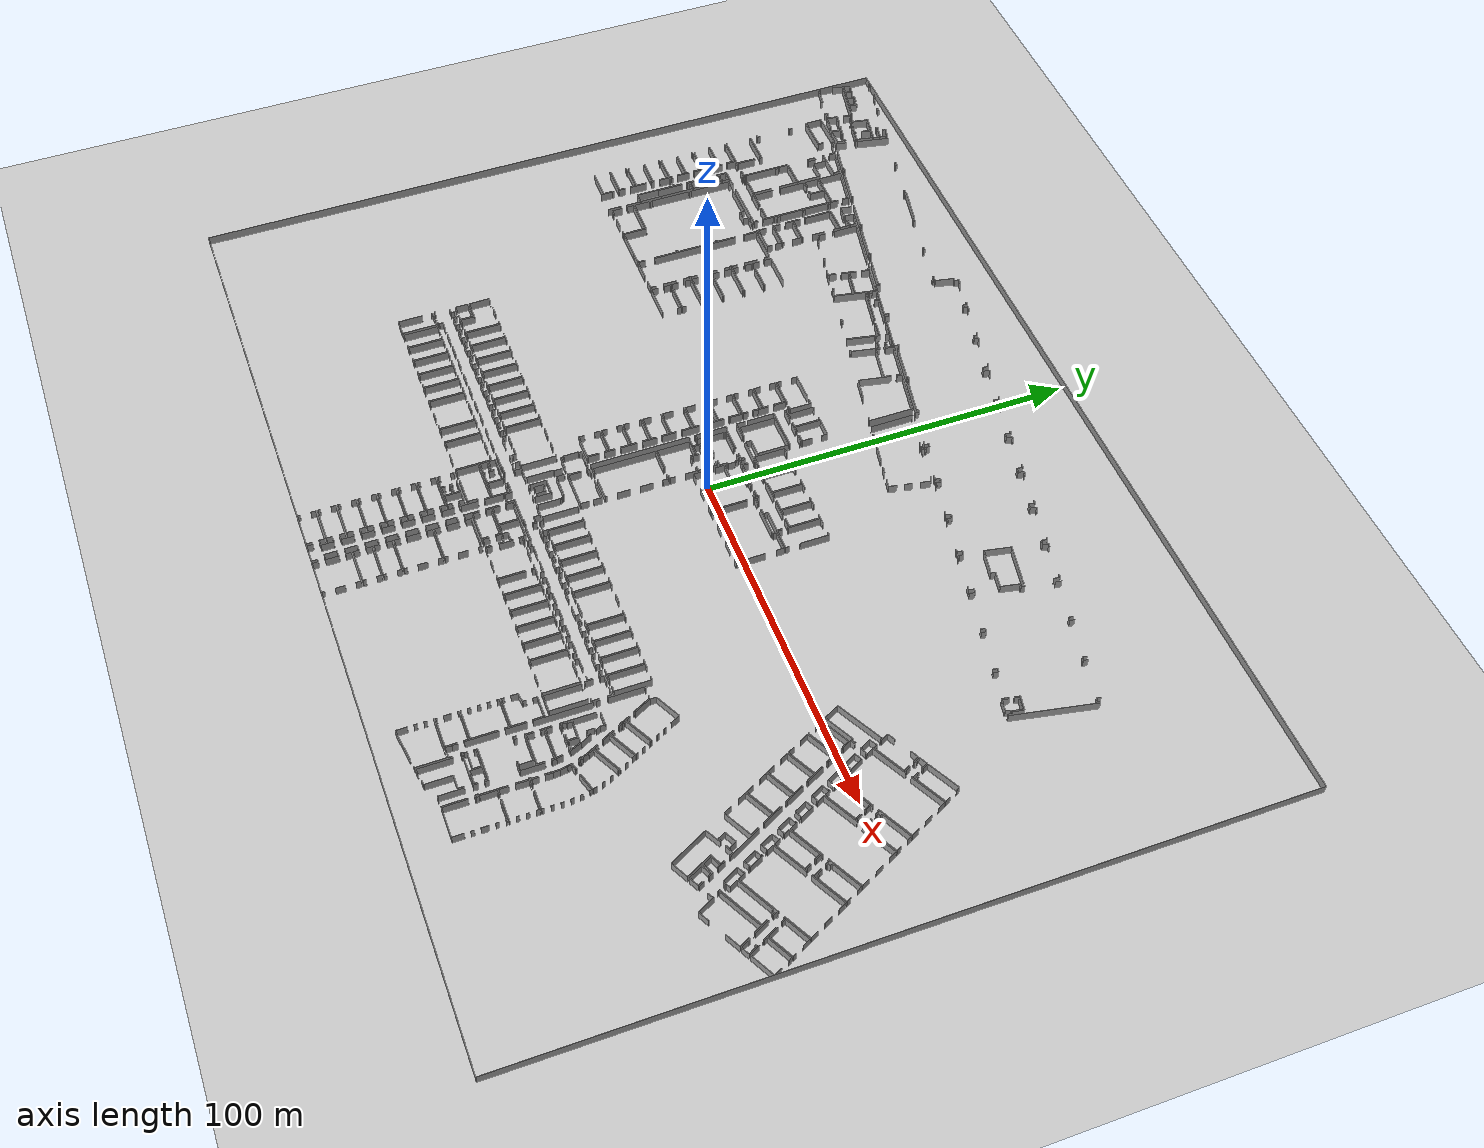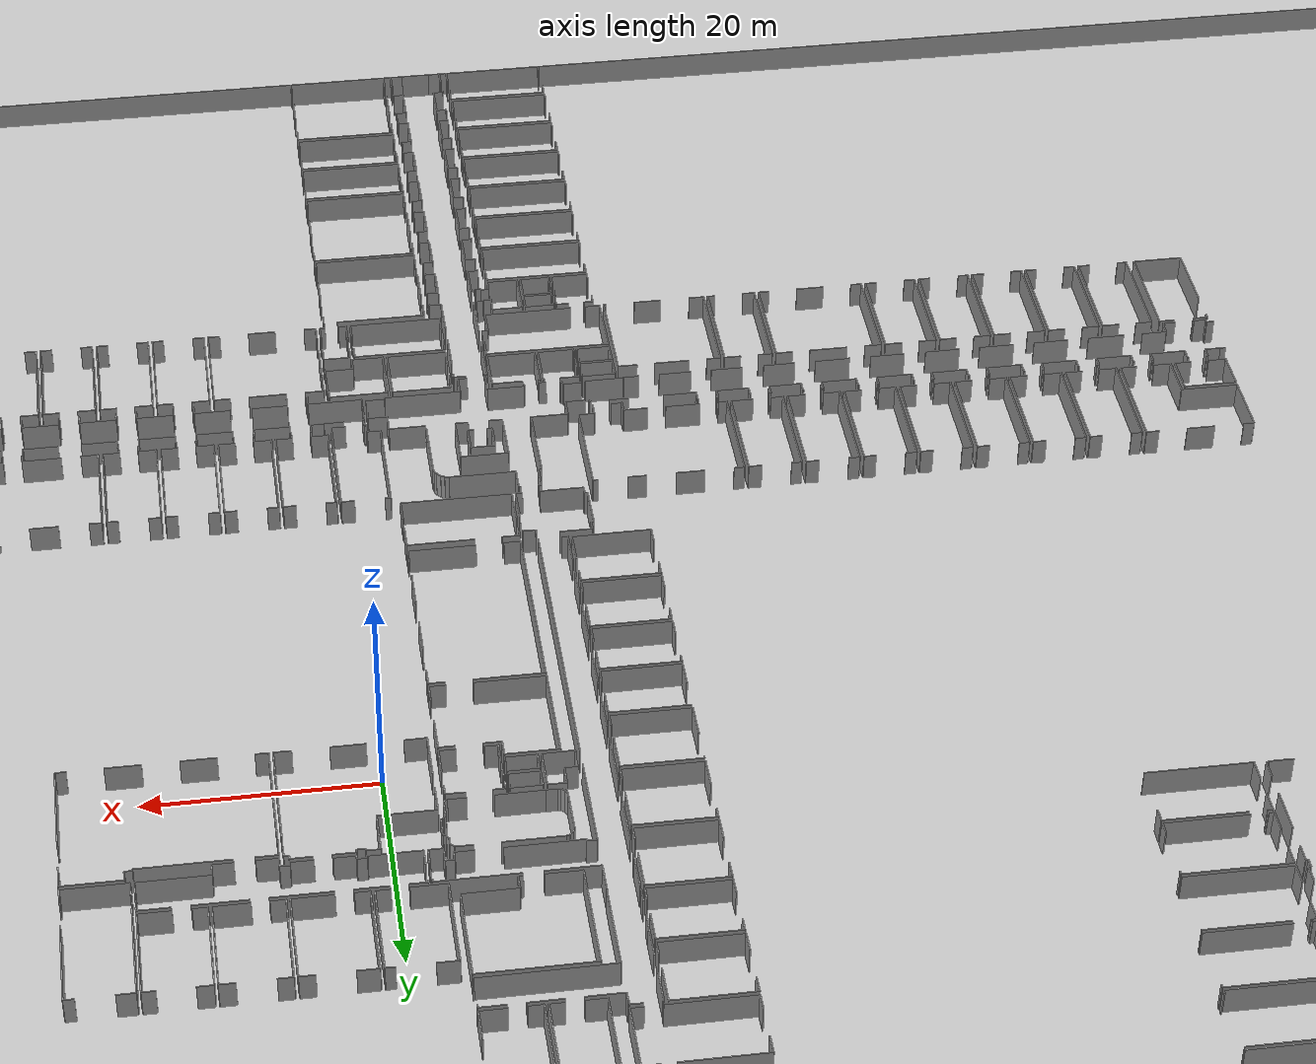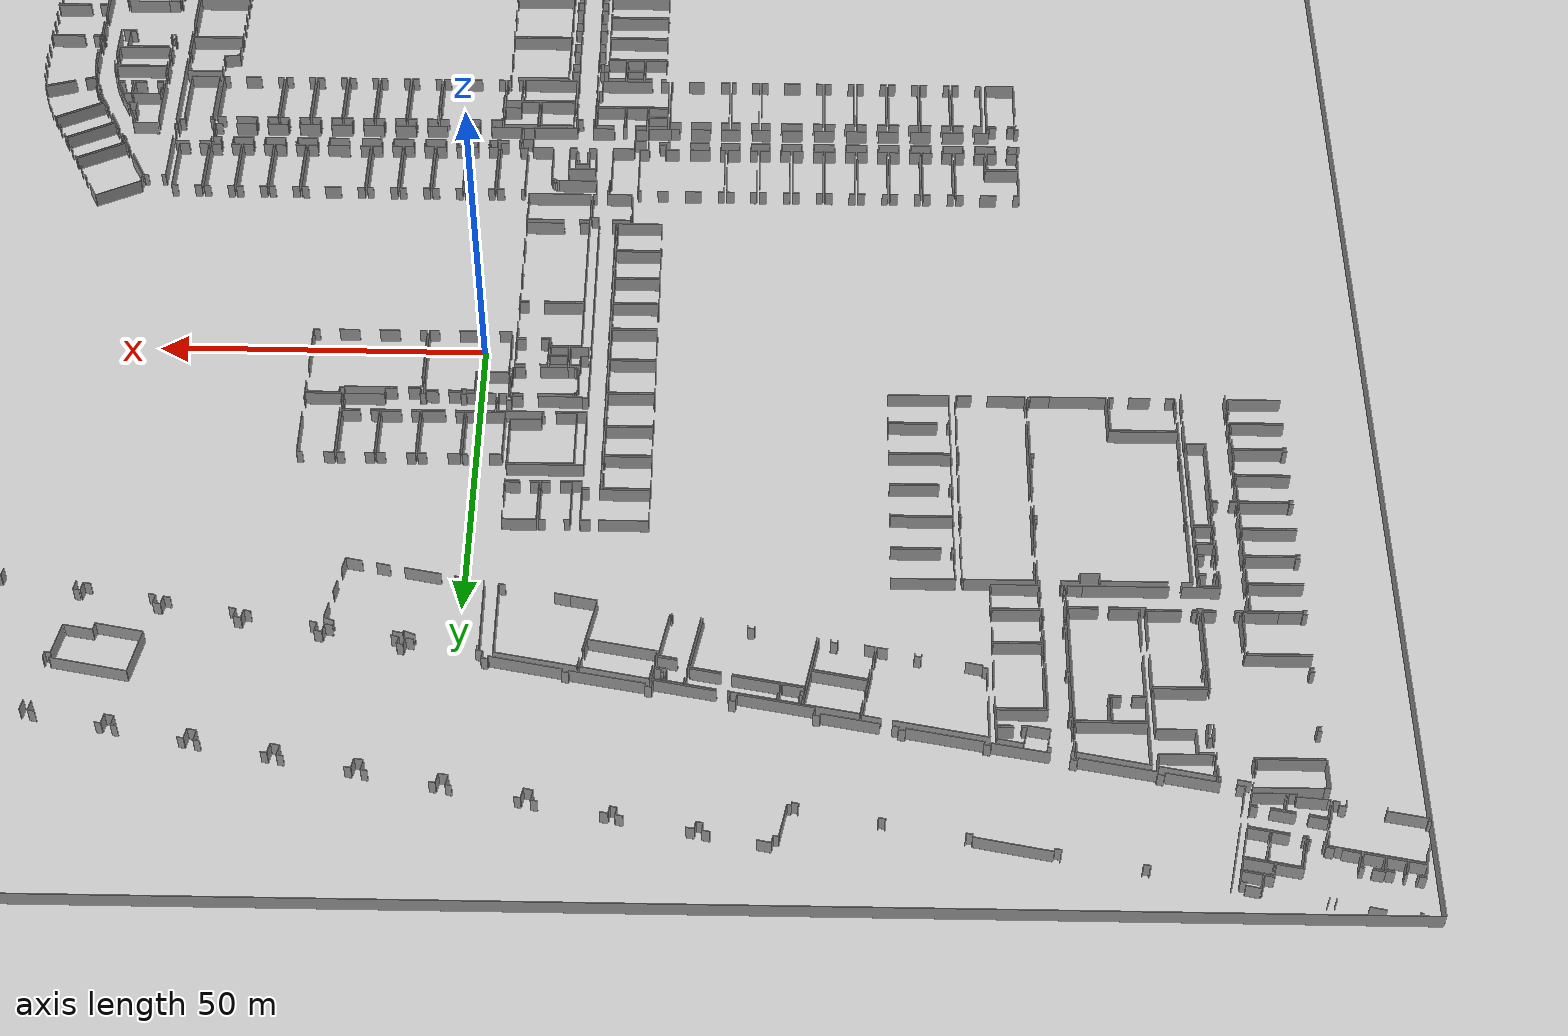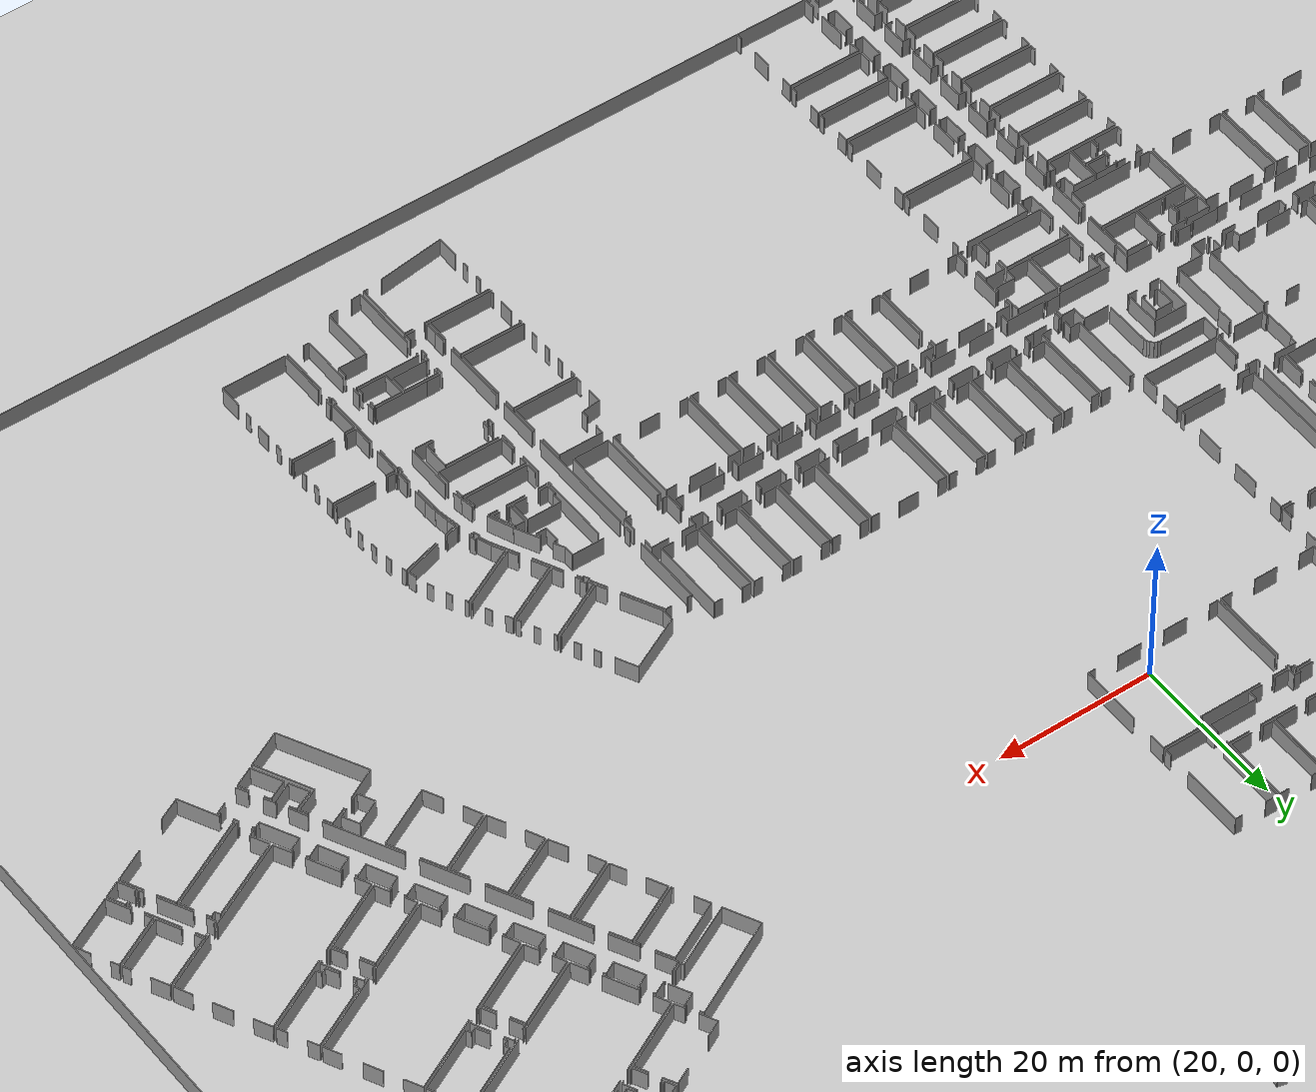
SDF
<sdf version="1.6">
  <world name="default">
    <light name="sun" type="directional">
      <cast_shadows>1</cast_shadows>
      <pose frame="">0 0 10 0 -0 0</pose>
      <diffuse>0.8 0.8 0.8 1</diffuse>
      <specular>0.1 0.1 0.1 1</specular>
      <attenuation>
        <range>1000</range>
        <constant>0.9</constant>
        <linear>0.01</linear>
        <quadratic>0.001</quadratic>
      </attenuation>
      <direction>-0.5 0.5 -1</direction>
    </light>
    <model name="ground_plane">
      <static>1</static>
      <link name="link">
        <collision name="collision">
          <geometry>
            <plane>
              <normal>0 0 1</normal>
              <size>100 100</size>
            </plane>
          </geometry>
          <surface>
            <friction>
              <ode>
                <mu>100</mu>
                <mu2>50</mu2>
              </ode>
              <torsional>
                <ode />
              </torsional>
            </friction>
            <contact>
              <ode />
            </contact>
            <bounce />
          </surface>
          <max_contacts>10</max_contacts>
        </collision>
        <visual name="visual">
          <cast_shadows>0</cast_shadows>
          <geometry>
            <plane>
              <normal>0 0 1</normal>
              <size>100 100</size>
            </plane>
          </geometry>
          <material>
            <script>
              <uri>file://media/materials/scripts/gazebo.material</uri>
              <name>Gazebo/Grey</name>
            </script>
          </material>
        </visual>
        <self_collide>0</self_collide>
        <kinematic>0</kinematic>
        <gravity>1</gravity>
      </link>
    </model>
    <gravity>0 0 -9.8</gravity>
    <magnetic_field>6e-06 2.3e-05 -4.2e-05</magnetic_field>
    <atmosphere type="adiabatic" />
    <physics default="0" name="default_physics" type="ode">
      <max_step_size>0.001</max_step_size>
      <real_time_factor>1</real_time_factor>
      <real_time_update_rate>1000</real_time_update_rate>
    </physics>
    <scene>
      <ambient>0.4 0.4 0.4 1</ambient>
      <background>0.7 0.7 0.7 1</background>
      <shadows>1</shadows>
    </scene>
    <spherical_coordinates>
      <surface_model>EARTH_WGS84</surface_model>
      <latitude_deg>0</latitude_deg>
      <longitude_deg>0</longitude_deg>
      <elevation>0</elevation>
      <heading_deg>0</heading_deg>
    </spherical_coordinates>
  <model name="0510045926_A-40">
		<static>1</static>
		<link name="Wall_0">
			<collision name="Wall_0_Collision">
				<geometry>
					<box>
						<size>2.24683478644 0.1 2.5</size>
					</box>
				</geometry>
				<pose frame="">1.12341739322 0 1.25 0 0 0</pose>
			</collision>
			<visual name="Wall_0_Visual">
				<pose frame="">1.12341739322 0 1.25 0 0 0</pose>
				<geometry>
					<box>
						<size>2.24683478644 0.1 2.5</size>
					</box>
				</geometry>
				<material>
					<script>
						<uri>file://media/materials/scripts/gazebo.material</uri>
						<name>Gazebo/Grey</name>
					</script>
					<ambient>1 1 1 1</ambient>
				</material>
			</visual>
			<pose frame="">228.549551665 -84.0987162321 0 0 0 0.472186205042</pose>
		</link>
		<link name="Wall_1">
			<collision name="Wall_1_Collision">
				<geometry>
					<box>
						<size>1.26755915564 0.1 2.5</size>
					</box>
				</geometry>
				<pose frame="">0.633779577821 0 1.25 0 0 0</pose>
			</collision>
			<visual name="Wall_1_Visual">
				<pose frame="">0.633779577821 0 1.25 0 0 0</pose>
				<geometry>
					<box>
						<size>1.26755915564 0.1 2.5</size>
					</box>
				</geometry>
				<material>
					<script>
						<uri>file://media/materials/scripts/gazebo.material</uri>
						<name>Gazebo/Grey</name>
					</script>
					<ambient>1 1 1 1</ambient>
				</material>
			</visual>
			<pose frame="">230.550528928 -83.0767785865 0 0 0 -1.08762414792</pose>
		</link>
		<link name="Wall_2">
			<collision name="Wall_2_Collision">
				<geometry>
					<box>
						<size>0.303872854573 0.1 2.5</size>
					</box>
				</geometry>
				<pose frame="">0.151936427287 0 1.25 0 0 0</pose>
			</collision>
			<visual name="Wall_2_Visual">
				<pose frame="">0.151936427287 0 1.25 0 0 0</pose>
				<geometry>
					<box>
						<size>0.303872854573 0.1 2.5</size>
					</box>
				</geometry>
				<material>
					<script>
						<uri>file://media/materials/scripts/gazebo.material</uri>
						<name>Gazebo/Grey</name>
					</script>
					<ambient>1 1 1 1</ambient>
				</material>
			</visual>
			<pose frame="">231.139424938 -84.199234689 0 0 0 -2.5656376599</pose>
		</link>
		<link name="Wall_3">
			<collision name="Wall_3_Collision">
				<geometry>
					<box>
						<size>0.41561760121 0.1 2.5</size>
					</box>
				</geometry>
				<pose frame="">0.207808800605 0 1.25 0 0 0</pose>
			</collision>
			<visual name="Wall_3_Visual">
				<pose frame="">0.207808800605 0 1.25 0 0 0</pose>
				<geometry>
					<box>
						<size>0.41561760121 0.1 2.5</size>
					</box>
				</geometry>
				<material>
					<script>
						<uri>file://media/materials/scripts/gazebo.material</uri>
						<name>Gazebo/Grey</name>
					</script>
					<ambient>1 1 1 1</ambient>
				</material>
			</visual>
			<pose frame="">229.499400316 -85.0498340557 0 0 0 -2.66647327252</pose>
		</link>
		<link name="Wall_4">
			<collision name="Wall_4_Collision">
				<geometry>
					<box>
						<size>1.2802877083 0.1 2.5</size>
					</box>
				</geometry>
				<pose frame="">0.640143854149 0 1.25 0 0 0</pose>
			</collision>
			<visual name="Wall_4_Visual">
				<pose frame="">0.640143854149 0 1.25 0 0 0</pose>
				<geometry>
					<box>
						<size>1.2802877083 0.1 2.5</size>
					</box>
				</geometry>
				<material>
					<script>
						<uri>file://media/materials/scripts/gazebo.material</uri>
						<name>Gazebo/Grey</name>
					</script>
					<ambient>1 1 1 1</ambient>
				</material>
			</visual>
			<pose frame="">229.129817303 -85.2399560866 0 0 0 2.04118261727</pose>
		</link>
		<link name="Wall_5">
			<collision name="Wall_5_Collision">
				<geometry>
					<box>
						<size>9.20374841256 0.1 2.5</size>
					</box>
				</geometry>
				<pose frame="">4.60187420628 0 1.25 0 0 0</pose>
			</collision>
			<visual name="Wall_5_Visual">
				<pose frame="">4.60187420628 0 1.25 0 0 0</pose>
				<geometry>
					<box>
						<size>9.20374841256 0.1 2.5</size>
					</box>
				</geometry>
				<material>
					<script>
						<uri>file://media/materials/scripts/gazebo.material</uri>
						<name>Gazebo/Grey</name>
					</script>
					<ambient>1 1 1 1</ambient>
				</material>
			</visual>
			<pose frame="">230.850561292 -82.9031557973 0 0 0 0.466225399707</pose>
		</link>
		<link name="Wall_6">
			<collision name="Wall_6_Collision">
				<geometry>
					<box>
						<size>1.00990088383 0.1 2.5</size>
					</box>
				</geometry>
				<pose frame="">0.504950441916 0 1.25 0 0 0</pose>
			</collision>
			<visual name="Wall_6_Visual">
				<pose frame="">0.504950441916 0 1.25 0 0 0</pose>
				<geometry>
					<box>
						<size>1.00990088383 0.1 2.5</size>
					</box>
				</geometry>
				<material>
					<script>
						<uri>file://media/materials/scripts/gazebo.material</uri>
						<name>Gazebo/Grey</name>
					</script>
					<ambient>1 1 1 1</ambient>
				</material>
			</visual>
			<pose frame="">239.072006498 -78.76590749 0 0 0 -1.07578249008</pose>
		</link>
		<link name="Wall_7">
			<collision name="Wall_7_Collision">
				<geometry>
					<box>
						<size>1.66262526959 0.1 2.5</size>
					</box>
				</geometry>
				<pose frame="">0.831312634797 0 1.25 0 0 0</pose>
			</collision>
			<visual name="Wall_7_Visual">
				<pose frame="">0.831312634797 0 1.25 0 0 0</pose>
				<geometry>
					<box>
						<size>1.66262526959 0.1 2.5</size>
					</box>
				</geometry>
				<material>
					<script>
						<uri>file://media/materials/scripts/gazebo.material</uri>
						<name>Gazebo/Grey</name>
					</script>
					<ambient>1 1 1 1</ambient>
				</material>
			</visual>
			<pose frame="">240.63055025 -81.7530317357 0 0 0 -1.11383986469</pose>
		</link>
		<link name="Wall_8">
			<collision name="Wall_8_Collision">
				<geometry>
					<box>
						<size>8.47727137903 0.1 2.5</size>
					</box>
				</geometry>
				<pose frame="">4.23863568951 0 1.25 0 0 0</pose>
			</collision>
			<visual name="Wall_8_Visual">
				<pose frame="">4.23863568951 0 1.25 0 0 0</pose>
				<geometry>
					<box>
						<size>8.47727137903 0.1 2.5</size>
					</box>
				</geometry>
				<material>
					<script>
						<uri>file://media/materials/scripts/gazebo.material</uri>
						<name>Gazebo/Grey</name>
					</script>
					<ambient>1 1 1 1</ambient>
				</material>
			</visual>
			<pose frame="">241.364131918 -83.2450708516 0 0 0 -2.67387420188</pose>
		</link>
		<link name="Wall_9">
			<collision name="Wall_9_Collision">
				<geometry>
					<box>
						<size>0.711284816569 0.1 2.5</size>
					</box>
				</geometry>
				<pose frame="">0.355642408284 0 1.25 0 0 0</pose>
			</collision>
			<visual name="Wall_9_Visual">
				<pose frame="">0.355642408284 0 1.25 0 0 0</pose>
				<geometry>
					<box>
						<size>0.711284816569 0.1 2.5</size>
					</box>
				</geometry>
				<material>
					<script>
						<uri>file://media/materials/scripts/gazebo.material</uri>
						<name>Gazebo/Grey</name>
					</script>
					<ambient>1 1 1 1</ambient>
				</material>
			</visual>
			<pose frame="">233.797325854 -87.0670567257 0 0 0 2.07754821075</pose>
		</link>
		<link name="Wall_10">
			<collision name="Wall_10_Collision">
				<geometry>
					<box>
						<size>0.712422382929 0.1 2.5</size>
					</box>
				</geometry>
				<pose frame="">0.356211191465 0 1.25 0 0 0</pose>
			</collision>
			<visual name="Wall_10_Visual">
				<pose frame="">0.356211191465 0 1.25 0 0 0</pose>
				<geometry>
					<box>
						<size>0.712422382929 0.1 2.5</size>
					</box>
				</geometry>
				<material>
					<script>
						<uri>file://media/materials/scripts/gazebo.material</uri>
						<name>Gazebo/Grey</name>
					</script>
					<ambient>1 1 1 1</ambient>
				</material>
			</visual>
			<pose frame="">233.452110951 -86.445162232 0 0 0 -2.70216727472</pose>
		</link>
		<link name="Wall_11">
			<collision name="Wall_11_Collision">
				<geometry>
					<box>
						<size>1.04683681426 0.1 2.5</size>
					</box>
				</geometry>
				<pose frame="">0.523418407128 0 1.25 0 0 0</pose>
			</collision>
			<visual name="Wall_11_Visual">
				<pose frame="">0.523418407128 0 1.25 0 0 0</pose>
				<geometry>
					<box>
						<size>1.04683681426 0.1 2.5</size>
					</box>
				</geometry>
				<material>
					<script>
						<uri>file://media/materials/scripts/gazebo.material</uri>
						<name>Gazebo/Grey</name>
					</script>
					<ambient>1 1 1 1</ambient>
				</material>
			</visual>
			<pose frame="">232.807371354 -86.7482406097 0 0 0 2.07544547198</pose>
		</link>
		<link name="Wall_12">
			<collision name="Wall_12_Collision">
				<geometry>
					<box>
						<size>1.74859254883 0.1 2.5</size>
					</box>
				</geometry>
				<pose frame="">0.874296274414 0 1.25 0 0 0</pose>
			</collision>
			<visual name="Wall_12_Visual">
				<pose frame="">0.874296274414 0 1.25 0 0 0</pose>
				<geometry>
					<box>
						<size>1.74859254883 0.1 2.5</size>
					</box>
				</geometry>
				<material>
					<script>
						<uri>file://media/materials/scripts/gazebo.material</uri>
						<name>Gazebo/Grey</name>
					</script>
					<ambient>1 1 1 1</ambient>
				</material>
			</visual>
			<pose frame="">231.618410615 -84.4741374387 0 0 0 2.02541996469</pose>
		</link>
		<link name="Wall_13">
			<collision name="Wall_13_Collision">
				<geometry>
					<box>
						<size>2.20443619592 0.1 2.5</size>
					</box>
				</geometry>
				<pose frame="">1.10221809796 0 1.25 0 0 0</pose>
			</collision>
			<visual name="Wall_13_Visual">
				<pose frame="">1.10221809796 0 1.25 0 0 0</pose>
				<geometry>
					<box>
						<size>2.20443619592 0.1 2.5</size>
					</box>
				</geometry>
				<material>
					<script>
						<uri>file://media/materials/scripts/gazebo.material</uri>
						<name>Gazebo/Grey</name>
					</script>
					<ambient>1 1 1 1</ambient>
				</material>
			</visual>
			<pose frame="">220.097878578 -88.3831885419 0 0 0 0.478787823014</pose>
		</link>
		<link name="Wall_14">
			<collision name="Wall_14_Collision">
				<geometry>
					<box>
						<size>2.22803820862 0.1 2.5</size>
					</box>
				</geometry>
				<pose frame="">1.11401910431 0 1.25 0 0 0</pose>
			</collision>
			<visual name="Wall_14_Visual">
				<pose frame="">1.11401910431 0 1.25 0 0 0</pose>
				<geometry>
					<box>
						<size>2.22803820862 0.1 2.5</size>
					</box>
				</geometry>
				<material>
					<script>
						<uri>file://media/materials/scripts/gazebo.material</uri>
						<name>Gazebo/Grey</name>
					</script>
					<ambient>1 1 1 1</ambient>
				</material>
			</visual>
			<pose frame="">226.234073472 -85.2206646656 0 0 0 0.467417907536</pose>
		</link>
		<link name="Wall_15">
			<collision name="Wall_15_Collision">
				<geometry>
					<box>
						<size>1.78536736294 0.1 2.5</size>
					</box>
				</geometry>
				<pose frame="">0.89268368147 0 1.25 0 0 0</pose>
			</collision>
			<visual name="Wall_15_Visual">
				<pose frame="">0.89268368147 0 1.25 0 0 0</pose>
				<geometry>
					<box>
						<size>1.78536736294 0.1 2.5</size>
					</box>
				</geometry>
				<material>
					<script>
						<uri>file://media/materials/scripts/gazebo.material</uri>
						<name>Gazebo/Grey</name>
					</script>
					<ambient>1 1 1 1</ambient>
				</material>
			</visual>
			<pose frame="">228.223120514 -84.2167492686 0 0 0 -1.08050447128</pose>
		</link>
		<link name="Wall_16">
			<collision name="Wall_16_Collision">
				<geometry>
					<box>
						<size>1.73853767877 0.1 2.5</size>
					</box>
				</geometry>
				<pose frame="">0.869268839387 0 1.25 0 0 0</pose>
			</collision>
			<visual name="Wall_16_Visual">
				<pose frame="">0.869268839387 0 1.25 0 0 0</pose>
				<geometry>
					<box>
						<size>1.73853767877 0.1 2.5</size>
					</box>
				</geometry>
				<material>
					<script>
						<uri>file://media/materials/scripts/gazebo.material</uri>
						<name>Gazebo/Grey</name>
					</script>
					<ambient>1 1 1 1</ambient>
				</material>
			</visual>
			<pose frame="">229.759072996 -87.1817899139 0 0 0 -1.10976053033</pose>
		</link>
		<link name="Wall_17">
			<collision name="Wall_17_Collision">
				<geometry>
					<box>
						<size>9.12243061222 0.1 2.5</size>
					</box>
				</geometry>
				<pose frame="">4.56121530611 0 1.25 0 0 0</pose>
			</collision>
			<visual name="Wall_17_Visual">
				<pose frame="">4.56121530611 0 1.25 0 0 0</pose>
				<geometry>
					<box>
						<size>9.12243061222 0.1 2.5</size>
					</box>
				</geometry>
				<material>
					<script>
						<uri>file://media/materials/scripts/gazebo.material</uri>
						<name>Gazebo/Grey</name>
					</script>
					<ambient>1 1 1 1</ambient>
				</material>
			</visual>
			<pose frame="">230.532506679 -88.7388106585 0 0 0 -2.66940845413</pose>
		</link>
		<link name="Wall_18">
			<collision name="Wall_18_Collision">
				<geometry>
					<box>
						<size>1.32763301571 0.1 2.5</size>
					</box>
				</geometry>
				<pose frame="">0.663816507854 0 1.25 0 0 0</pose>
			</collision>
			<visual name="Wall_18_Visual">
				<pose frame="">0.663816507854 0 1.25 0 0 0</pose>
				<geometry>
					<box>
						<size>1.32763301571 0.1 2.5</size>
					</box>
				</geometry>
				<material>
					<script>
						<uri>file://media/materials/scripts/gazebo.material</uri>
						<name>Gazebo/Grey</name>
					</script>
					<ambient>1 1 1 1</ambient>
				</material>
			</visual>
			<pose frame="">222.408280081 -92.8879891867 0 0 0 2.05830187817</pose>
		</link>
		<link name="Wall_19">
			<collision name="Wall_19_Collision">
				<geometry>
					<box>
						<size>2.21929779958 0.1 2.5</size>
					</box>
				</geometry>
				<pose frame="">1.10964889979 0 1.25 0 0 0</pose>
			</collision>
			<visual name="Wall_19_Visual">
				<pose frame="">1.10964889979 0 1.25 0 0 0</pose>
				<geometry>
					<box>
						<size>2.21929779958 0.1 2.5</size>
					</box>
				</geometry>
				<material>
					<script>
						<uri>file://media/materials/scripts/gazebo.material</uri>
						<name>Gazebo/Grey</name>
					</script>
					<ambient>1 1 1 1</ambient>
				</material>
			</visual>
			<pose frame="">221.082756389 -90.3719817493 0 0 0 2.03060763748</pose>
		</link>
		<link name="Wall_20">
			<collision name="Wall_20_Collision">
				<geometry>
					<box>
						<size>0.472593871932 0.1 2.5</size>
					</box>
				</geometry>
				<pose frame="">0.236296935966 0 1.25 0 0 0</pose>
			</collision>
			<visual name="Wall_20_Visual">
				<pose frame="">0.236296935966 0 1.25 0 0 0</pose>
				<geometry>
					<box>
						<size>0.472593871932 0.1 2.5</size>
					</box>
				</geometry>
				<material>
					<script>
						<uri>file://media/materials/scripts/gazebo.material</uri>
						<name>Gazebo/Grey</name>
					</script>
					<ambient>1 1 1 1</ambient>
				</material>
			</visual>
			<pose frame="">229.282879498 -85.5333887539 0 0 0 0.546130565666</pose>
		</link>
		<link name="Wall_21">
			<collision name="Wall_21_Collision">
				<geometry>
					<box>
						<size>0.301306668579 0.1 2.5</size>
					</box>
				</geometry>
				<pose frame="">0.15065333429 0 1.25 0 0 0</pose>
			</collision>
			<visual name="Wall_21_Visual">
				<pose frame="">0.15065333429 0 1.25 0 0 0</pose>
				<geometry>
					<box>
						<size>0.301306668579 0.1 2.5</size>
					</box>
				</geometry>
				<material>
					<script>
						<uri>file://media/materials/scripts/gazebo.material</uri>
						<name>Gazebo/Grey</name>
					</script>
					<ambient>1 1 1 1</ambient>
				</material>
			</visual>
			<pose frame="">231.025707088 -84.6112080618 0 0 0 0.449707291291</pose>
		</link>
		<link name="Wall_22">
			<collision name="Wall_22_Collision">
				<geometry>
					<box>
						<size>0.1653094053 0.1 2.5</size>
					</box>
				</geometry>
				<pose frame="">0.0826547026498 0 1.25 0 0 0</pose>
			</collision>
			<visual name="Wall_22_Visual">
				<pose frame="">0.0826547026498 0 1.25 0 0 0</pose>
				<geometry>
					<box>
						<size>0.1653094053 0.1 2.5</size>
					</box>
				</geometry>
				<material>
					<script>
						<uri>file://media/materials/scripts/gazebo.material</uri>
						<name>Gazebo/Grey</name>
					</script>
					<ambient>1 1 1 1</ambient>
				</material>
			</visual>
			<pose frame="">231.297056155 -84.4802294664 0 0 0 -1.18344660057</pose>
		</link>
		<link name="Wall_23">
			<collision name="Wall_23_Collision">
				<geometry>
					<box>
						<size>1.73392004608 0.1 2.5</size>
					</box>
				</geometry>
				<pose frame="">0.866960023042 0 1.25 0 0 0</pose>
			</collision>
			<visual name="Wall_23_Visual">
				<pose frame="">0.866960023042 0 1.25 0 0 0</pose>
				<geometry>
					<box>
						<size>1.73392004608 0.1 2.5</size>
					</box>
				</geometry>
				<material>
					<script>
						<uri>file://media/materials/scripts/gazebo.material</uri>
						<name>Gazebo/Grey</name>
					</script>
					<ambient>1 1 1 1</ambient>
				</material>
			</visual>
			<pose frame="">232.063128637 -85.9798836169 0 0 0 -1.1141539718</pose>
		</link>
		<link name="Wall_24">
			<collision name="Wall_24_Collision">
				<geometry>
					<box>
						<size>0.390977133344 0.1 2.5</size>
					</box>
				</geometry>
				<pose frame="">0.195488566672 0 1.25 0 0 0</pose>
			</collision>
			<visual name="Wall_24_Visual">
				<pose frame="">0.195488566672 0 1.25 0 0 0</pose>
				<geometry>
					<box>
						<size>0.390977133344 0.1 2.5</size>
					</box>
				</geometry>
				<material>
					<script>
						<uri>file://media/materials/scripts/gazebo.material</uri>
						<name>Gazebo/Grey</name>
					</script>
					<ambient>1 1 1 1</ambient>
				</material>
			</visual>
			<pose frame="">232.827678112 -87.536142858 0 0 0 -2.5840256137</pose>
		</link>
		<link name="Wall_25">
			<collision name="Wall_25_Collision">
				<geometry>
					<box>
						<size>0.351416406892 0.1 2.5</size>
					</box>
				</geometry>
				<pose frame="">0.175708203446 0 1.25 0 0 0</pose>
			</collision>
			<visual name="Wall_25_Visual">
				<pose frame="">0.175708203446 0 1.25 0 0 0</pose>
				<geometry>
					<box>
						<size>0.351416406892 0.1 2.5</size>
					</box>
				</geometry>
				<material>
					<script>
						<uri>file://media/materials/scripts/gazebo.material</uri>
						<name>Gazebo/Grey</name>
					</script>
					<ambient>1 1 1 1</ambient>
				</material>
			</visual>
			<pose frame="">231.14348629 -88.4469009982 0 0 0 -2.65694651598</pose>
		</link>
		<link name="Wall_26">
			<collision name="Wall_26_Collision">
				<geometry>
					<box>
						<size>1.82038697518 0.1 2.5</size>
					</box>
				</geometry>
				<pose frame="">0.910193487589 0 1.25 0 0 0</pose>
			</collision>
			<visual name="Wall_26_Visual">
				<pose frame="">0.910193487589 0 1.25 0 0 0</pose>
				<geometry>
					<box>
						<size>1.82038697518 0.1 2.5</size>
					</box>
				</geometry>
				<material>
					<script>
						<uri>file://media/materials/scripts/gazebo.material</uri>
						<name>Gazebo/Grey</name>
					</script>
					<ambient>1 1 1 1</ambient>
				</material>
			</visual>
			<pose frame="">230.832539043 -88.6106242425 0 0 0 2.05053335433</pose>
		</link>
		<link name="Wall_27">
			<collision name="Wall_27_Collision">
				<geometry>
					<box>
						<size>0.117369839021 0.1 2.5</size>
					</box>
				</geometry>
				<pose frame="">0.0586849195106 0 1.25 0 0 0</pose>
			</collision>
			<visual name="Wall_27_Visual">
				<pose frame="">0.0586849195106 0 1.25 0 0 0</pose>
				<geometry>
					<box>
						<size>0.117369839021 0.1 2.5</size>
					</box>
				</geometry>
				<material>
					<script>
						<uri>file://media/materials/scripts/gazebo.material</uri>
						<name>Gazebo/Grey</name>
					</script>
					<ambient>1 1 1 1</ambient>
				</material>
			</visual>
			<pose frame="">229.318162492 -85.6453297627 0 0 0 1.87613248687</pose>
		</link>
		<link name="Wall_28">
			<collision name="Wall_28_Collision">
				<geometry>
					<box>
						<size>9.89260626272 0.1 2.5</size>
					</box>
				</geometry>
				<pose frame="">4.94630313136 0 1.25 0 0 0</pose>
			</collision>
			<visual name="Wall_28_Visual">
				<pose frame="">4.94630313136 0 1.25 0 0 0</pose>
				<geometry>
					<box>
						<size>9.89260626272 0.1 2.5</size>
					</box>
				</geometry>
				<material>
					<script>
						<uri>file://media/materials/scripts/gazebo.material</uri>
						<name>Gazebo/Grey</name>
					</script>
					<ambient>1 1 1 1</ambient>
				</material>
			</visual>
			<pose frame="">222.523013269 -93.1826910263 0 0 0 0.472644176076</pose>
		</link>
		<link name="Wall_29">
			<collision name="Wall_29_Collision">
				<geometry>
					<box>
						<size>9.86099682919 0.1 2.5</size>
					</box>
				</geometry>
				<pose frame="">4.9304984146 0 1.25 0 0 0</pose>
			</collision>
			<visual name="Wall_29_Visual">
				<pose frame="">4.9304984146 0 1.25 0 0 0</pose>
				<geometry>
					<box>
						<size>9.86099682919 0.1 2.5</size>
					</box>
				</geometry>
				<material>
					<script>
						<uri>file://media/materials/scripts/gazebo.material</uri>
						<name>Gazebo/Grey</name>
					</script>
					<ambient>1 1 1 1</ambient>
				</material>
			</visual>
			<pose frame="">232.710914248 -87.9793378727 0 0 0 0.468620745079</pose>
		</link>
		<link name="Wall_30">
			<collision name="Wall_30_Collision">
				<geometry>
					<box>
						<size>2.25003477005 0.1 2.5</size>
					</box>
				</geometry>
				<pose frame="">1.12501738502 0 1.25 0 0 0</pose>
			</collision>
			<visual name="Wall_30_Visual">
				<pose frame="">1.12501738502 0 1.25 0 0 0</pose>
				<geometry>
					<box>
						<size>2.25003477005 0.1 2.5</size>
					</box>
				</geometry>
				<material>
					<script>
						<uri>file://media/materials/scripts/gazebo.material</uri>
						<name>Gazebo/Grey</name>
					</script>
					<ambient>1 1 1 1</ambient>
				</material>
			</visual>
			<pose frame="">241.508817575 -83.5255579599 0 0 0 -1.09756273494</pose>
		</link>
		<link name="Wall_31">
			<collision name="Wall_31_Collision">
				<geometry>
					<box>
						<size>2.39791941209 0.1 2.5</size>
					</box>
				</geometry>
				<pose frame="">1.19895970605 0 1.25 0 0 0</pose>
			</collision>
			<visual name="Wall_31_Visual">
				<pose frame="">1.19895970605 0 1.25 0 0 0</pose>
				<geometry>
					<box>
						<size>2.39791941209 0.1 2.5</size>
					</box>
				</geometry>
				<material>
					<script>
						<uri>file://media/materials/scripts/gazebo.material</uri>
						<name>Gazebo/Grey</name>
					</script>
					<ambient>1 1 1 1</ambient>
				</material>
			</visual>
			<pose frame="">243.60041375 -87.6447840186 0 0 0 -1.09465055219</pose>
		</link>
		<link name="Wall_32">
			<collision name="Wall_32_Collision">
				<geometry>
					<box>
						<size>2.35959505449 0.1 2.5</size>
					</box>
				</geometry>
				<pose frame="">1.17979752724 0 1.25 0 0 0</pose>
			</collision>
			<visual name="Wall_32_Visual">
				<pose frame="">1.17979752724 0 1.25 0 0 0</pose>
				<geometry>
					<box>
						<size>2.35959505449 0.1 2.5</size>
					</box>
				</geometry>
				<material>
					<script>
						<uri>file://media/materials/scripts/gazebo.material</uri>
						<name>Gazebo/Grey</name>
					</script>
					<ambient>1 1 1 1</ambient>
				</material>
			</visual>
			<pose frame="">245.755468547 -91.8211228369 0 0 0 -1.10921741493</pose>
		</link>
		<link name="Wall_33">
			<collision name="Wall_33_Collision">
				<geometry>
					<box>
						<size>9.91970486618 0.1 2.5</size>
					</box>
				</geometry>
				<pose frame="">4.95985243309 0 1.25 0 0 0</pose>
			</collision>
			<visual name="Wall_33_Visual">
				<pose frame="">4.95985243309 0 1.25 0 0 0</pose>
				<geometry>
					<box>
						<size>9.91970486618 0.1 2.5</size>
					</box>
				</geometry>
				<material>
					<script>
						<uri>file://media/materials/scripts/gazebo.material</uri>
						<name>Gazebo/Grey</name>
					</script>
					<ambient>1 1 1 1</ambient>
				</material>
			</visual>
			<pose frame="">246.806343324 -93.933787274 0 0 0 -2.67261225008</pose>
		</link>
		<link name="Wall_34">
			<collision name="Wall_34_Collision">
				<geometry>
					<box>
						<size>9.83773451522 0.1 2.5</size>
					</box>
				</geometry>
				<pose frame="">4.91886725761 0 1.25 0 0 0</pose>
			</collision>
			<visual name="Wall_34_Visual">
				<pose frame="">4.91886725761 0 1.25 0 0 0</pose>
				<geometry>
					<box>
						<size>9.83773451522 0.1 2.5</size>
					</box>
				</geometry>
				<material>
					<script>
						<uri>file://media/materials/scripts/gazebo.material</uri>
						<name>Gazebo/Grey</name>
					</script>
					<ambient>1 1 1 1</ambient>
				</material>
			</visual>
			<pose frame="">236.597120248 -99.109726303 0 0 0 -2.67278706077</pose>
		</link>
		<link name="Wall_35">
			<collision name="Wall_35_Collision">
				<geometry>
					<box>
						<size>2.17369419839 0.1 2.5</size>
					</box>
				</geometry>
				<pose frame="">1.08684709919 0 1.25 0 0 0</pose>
			</collision>
			<visual name="Wall_35_Visual">
				<pose frame="">1.08684709919 0 1.25 0 0 0</pose>
				<geometry>
					<box>
						<size>2.17369419839 0.1 2.5</size>
					</box>
				</geometry>
				<material>
					<script>
						<uri>file://media/materials/scripts/gazebo.material</uri>
						<name>Gazebo/Grey</name>
					</script>
					<ambient>1 1 1 1</ambient>
				</material>
			</visual>
			<pose frame="">227.820792852 -103.554622009 0 0 0 2.04102416253</pose>
		</link>
		<link name="Wall_36">
			<collision name="Wall_36_Collision">
				<geometry>
					<box>
						<size>4.23782411412 0.1 2.5</size>
					</box>
				</geometry>
				<pose frame="">2.11891205706 0 1.25 0 0 0</pose>
			</collision>
			<visual name="Wall_36_Visual">
				<pose frame="">2.11891205706 0 1.25 0 0 0</pose>
				<geometry>
					<box>
						<size>4.23782411412 0.1 2.5</size>
					</box>
				</geometry>
				<material>
					<script>
						<uri>file://media/materials/scripts/gazebo.material</uri>
						<name>Gazebo/Grey</name>
					</script>
					<ambient>1 1 1 1</ambient>
				</material>
			</visual>
			<pose frame="">226.132032009 -100.240812778 0 0 0 2.04039066594</pose>
		</link>
		<link name="Wall_37">
			<collision name="Wall_37_Collision">
				<geometry>
					<box>
						<size>2.14085640761 0.1 2.5</size>
					</box>
				</geometry>
				<pose frame="">1.07042820381 0 1.25 0 0 0</pose>
			</collision>
			<visual name="Wall_37_Visual">
				<pose frame="">1.07042820381 0 1.25 0 0 0</pose>
				<geometry>
					<box>
						<size>2.14085640761 0.1 2.5</size>
					</box>
				</geometry>
				<material>
					<script>
						<uri>file://media/materials/scripts/gazebo.material</uri>
						<name>Gazebo/Grey</name>
					</script>
					<ambient>1 1 1 1</ambient>
				</material>
			</visual>
			<pose frame="">223.487838155 -95.0938108806 0 0 0 2.03831474737</pose>
		</link>
		<link name="Wall_38">
			<collision name="Wall_38_Collision">
				<geometry>
					<box>
						<size>8.47244996552 0.1 2.5</size>
					</box>
				</geometry>
				<pose frame="">4.23622498276 0 1.25 0 0 0</pose>
			</collision>
			<visual name="Wall_38_Visual">
				<pose frame="">4.23622498276 0 1.25 0 0 0</pose>
				<geometry>
					<box>
						<size>8.47244996552 0.1 2.5</size>
					</box>
				</geometry>
				<material>
					<script>
						<uri>file://media/materials/scripts/gazebo.material</uri>
						<name>Gazebo/Grey</name>
					</script>
					<ambient>1 1 1 1</ambient>
				</material>
			</visual>
			<pose frame="">239.384222917 -98.0519979947 0 0 0 0.471231240229</pose>
		</link>
		<link name="Wall_39">
			<collision name="Wall_39_Collision">
				<geometry>
					<box>
						<size>1.39832221505 0.1 2.5</size>
					</box>
				</geometry>
				<pose frame="">0.699161107523 0 1.25 0 0 0</pose>
			</collision>
			<visual name="Wall_39_Visual">
				<pose frame="">0.699161107523 0 1.25 0 0 0</pose>
				<geometry>
					<box>
						<size>1.39832221505 0.1 2.5</size>
					</box>
				</geometry>
				<material>
					<script>
						<uri>file://media/materials/scripts/gazebo.material</uri>
						<name>Gazebo/Grey</name>
					</script>
					<ambient>1 1 1 1</ambient>
				</material>
			</visual>
			<pose frame="">246.933260567 -94.2056440098 0 0 0 -1.07101498001</pose>
		</link>
		<link name="Wall_40">
			<collision name="Wall_40_Collision">
				<geometry>
					<box>
						<size>1.40966979622 0.1 2.5</size>
					</box>
				</geometry>
				<pose frame="">0.704834898112 0 1.25 0 0 0</pose>
			</collision>
			<visual name="Wall_40_Visual">
				<pose frame="">0.704834898112 0 1.25 0 0 0</pose>
				<geometry>
					<box>
						<size>1.40966979622 0.1 2.5</size>
					</box>
				</geometry>
				<material>
					<script>
						<uri>file://media/materials/scripts/gazebo.material</uri>
						<name>Gazebo/Grey</name>
					</script>
					<ambient>1 1 1 1</ambient>
				</material>
			</visual>
			<pose frame="">248.636489977 -97.4803627295 0 0 0 -1.10787347206</pose>
		</link>
		<link name="Wall_41">
			<collision name="Wall_41_Collision">
				<geometry>
					<box>
						<size>8.49312175297 0.1 2.5</size>
					</box>
				</geometry>
				<pose frame="">4.24656087648 0 1.25 0 0 0</pose>
			</collision>
			<visual name="Wall_41_Visual">
				<pose frame="">4.24656087648 0 1.25 0 0 0</pose>
				<geometry>
					<box>
						<size>8.49312175297 0.1 2.5</size>
					</box>
				</geometry>
				<material>
					<script>
						<uri>file://media/materials/scripts/gazebo.material</uri>
						<name>Gazebo/Grey</name>
					</script>
					<ambient>1 1 1 1</ambient>
				</material>
			</visual>
			<pose frame="">249.265999505 -98.7416662965 0 0 0 -2.67217094281</pose>
		</link>
		<link name="Wall_42">
			<collision name="Wall_42_Collision">
				<geometry>
					<box>
						<size>0.716394901711 0.1 2.5</size>
					</box>
				</geometry>
				<pose frame="">0.358197450855 0 1.25 0 0 0</pose>
			</collision>
			<visual name="Wall_42_Visual">
				<pose frame="">0.358197450855 0 1.25 0 0 0</pose>
				<geometry>
					<box>
						<size>0.716394901711 0.1 2.5</size>
					</box>
				</geometry>
				<material>
					<script>
						<uri>file://media/materials/scripts/gazebo.material</uri>
						<name>Gazebo/Grey</name>
					</script>
					<ambient>1 1 1 1</ambient>
				</material>
			</visual>
			<pose frame="">241.691578406 -102.583705095 0 0 0 2.07359296833</pose>
		</link>
		<link name="Wall_43">
			<collision name="Wall_43_Collision">
				<geometry>
					<box>
						<size>0.722833492446 0.1 2.5</size>
					</box>
				</geometry>
				<pose frame="">0.361416746223 0 1.25 0 0 0</pose>
			</collision>
			<visual name="Wall_43_Visual">
				<pose frame="">0.361416746223 0 1.25 0 0 0</pose>
				<geometry>
					<box>
						<size>0.722833492446 0.1 2.5</size>
					</box>
				</geometry>
				<material>
					<script>
						<uri>file://media/materials/scripts/gazebo.material</uri>
						<name>Gazebo/Grey</name>
					</script>
					<ambient>1 1 1 1</ambient>
				</material>
			</visual>
			<pose frame="">241.346363504 -101.955972408 0 0 0 -2.66475278341</pose>
		</link>
		<link name="Wall_44">
			<collision name="Wall_44_Collision">
				<geometry>
					<box>
						<size>1.71059654186 0.1 2.5</size>
					</box>
				</geometry>
				<pose frame="">0.855298270928 0 1.25 0 0 0</pose>
			</collision>
			<visual name="Wall_44_Visual">
				<pose frame="">0.855298270928 0 1.25 0 0 0</pose>
				<geometry>
					<box>
						<size>1.71059654186 0.1 2.5</size>
					</box>
				</geometry>
				<material>
					<script>
						<uri>file://media/materials/scripts/gazebo.material</uri>
						<name>Gazebo/Grey</name>
					</script>
					<ambient>1 1 1 1</ambient>
				</material>
			</visual>
			<pose frame="">240.704162251 -102.287734083 0 0 0 2.04546021432</pose>
		</link>
		<link name="Wall_45">
			<collision name="Wall_45_Collision">
				<geometry>
					<box>
						<size>0.469220516301 0.1 2.5</size>
					</box>
				</geometry>
				<pose frame="">0.234610258151 0 1.25 0 0 0</pose>
			</collision>
			<visual name="Wall_45_Visual">
				<pose frame="">0.234610258151 0 1.25 0 0 0</pose>
				<geometry>
					<box>
						<size>0.469220516301 0.1 2.5</size>
					</box>
				</geometry>
				<material>
					<script>
						<uri>file://media/materials/scripts/gazebo.material</uri>
						<name>Gazebo/Grey</name>
					</script>
					<ambient>1 1 1 1</ambient>
				</material>
			</visual>
			<pose frame="">239.22938388 -99.4008744598 0 0 0 2.06081729664</pose>
		</link>
		<link name="Wall_46">
			<collision name="Wall_46_Collision">
				<geometry>
					<box>
						<size>0.734011743152 0.1 2.5</size>
					</box>
				</geometry>
				<pose frame="">0.367005871576 0 1.25 0 0 0</pose>
			</collision>
			<visual name="Wall_46_Visual">
				<pose frame="">0.367005871576 0 1.25 0 0 0</pose>
				<geometry>
					<box>
						<size>0.734011743152 0.1 2.5</size>
					</box>
				</geometry>
				<material>
					<script>
						<uri>file://media/materials/scripts/gazebo.material</uri>
						<name>Gazebo/Grey</name>
					</script>
					<ambient>1 1 1 1</ambient>
				</material>
			</visual>
			<pose frame="">239.008547876 -98.9868704111 0 0 0 0.460863824048</pose>
		</link>
		<link name="Wall_47">
			<collision name="Wall_47_Collision">
				<geometry>
					<box>
						<size>0.670512770793 0.1 2.5</size>
					</box>
				</geometry>
				<pose frame="">0.335256385397 0 1.25 0 0 0</pose>
			</collision>
			<visual name="Wall_47_Visual">
				<pose frame="">0.335256385397 0 1.25 0 0 0</pose>
				<geometry>
					<box>
						<size>0.670512770793 0.1 2.5</size>
					</box>
				</geometry>
				<material>
					<script>
						<uri>file://media/materials/scripts/gazebo.material</uri>
						<name>Gazebo/Grey</name>
					</script>
					<ambient>1 1 1 1</ambient>
				</material>
			</visual>
			<pose frame="">239.665979198 -98.6604392606 0 0 0 2.00447323788</pose>
		</link>
		<link name="Wall_48">
			<collision name="Wall_48_Collision">
				<geometry>
					<box>
						<size>9.14189428789 0.1 2.5</size>
					</box>
				</geometry>
				<pose frame="">4.57094714394 0 1.25 0 0 0</pose>
			</collision>
			<visual name="Wall_48_Visual">
				<pose frame="">4.57094714394 0 1.25 0 0 0</pose>
				<geometry>
					<box>
						<size>9.14189428789 0.1 2.5</size>
					</box>
				</geometry>
				<material>
					<script>
						<uri>file://media/materials/scripts/gazebo.material</uri>
						<name>Gazebo/Grey</name>
					</script>
					<ambient>1 1 1 1</ambient>
				</material>
			</visual>
			<pose frame="">227.974870386 -103.85846189 0 0 0 0.471346451052</pose>
		</link>
		<link name="Wall_49">
			<collision name="Wall_49_Collision">
				<geometry>
					<box>
						<size>1.81399217768 0.1 2.5</size>
					</box>
				</geometry>
				<pose frame="">0.906996088841 0 1.25 0 0 0</pose>
			</collision>
			<visual name="Wall_49_Visual">
				<pose frame="">0.906996088841 0 1.25 0 0 0</pose>
				<geometry>
					<box>
						<size>1.81399217768 0.1 2.5</size>
					</box>
				</geometry>
				<material>
					<script>
						<uri>file://media/materials/scripts/gazebo.material</uri>
						<name>Gazebo/Grey</name>
					</script>
					<ambient>1 1 1 1</ambient>
				</material>
			</visual>
			<pose frame="">236.119911412 -99.7072526859 0 0 0 -1.09237948259</pose>
		</link>
		<link name="Wall_50">
			<collision name="Wall_50_Collision">
				<geometry>
					<box>
						<size>1.68029689895 0.1 2.5</size>
					</box>
				</geometry>
				<pose frame="">0.840148449477 0 1.25 0 0 0</pose>
			</collision>
			<visual name="Wall_50_Visual">
				<pose frame="">0.840148449477 0 1.25 0 0 0</pose>
				<geometry>
					<box>
						<size>1.68029689895 0.1 2.5</size>
					</box>
				</geometry>
				<material>
					<script>
						<uri>file://media/materials/scripts/gazebo.material</uri>
						<name>Gazebo/Grey</name>
					</script>
					<ambient>1 1 1 1</ambient>
				</material>
			</visual>
			<pose frame="">237.647995025 -102.697930614 0 0 0 -1.10721627623</pose>
		</link>
		<link name="Wall_51">
			<collision name="Wall_51_Collision">
				<geometry>
					<box>
						<size>9.12429454102 0.1 2.5</size>
					</box>
				</geometry>
				<pose frame="">4.56214727051 0 1.25 0 0 0</pose>
			</collision>
			<visual name="Wall_51_Visual">
				<pose frame="">4.56214727051 0 1.25 0 0 0</pose>
				<geometry>
					<box>
						<size>9.12429454102 0.1 2.5</size>
					</box>
				</geometry>
				<material>
					<script>
						<uri>file://media/materials/scripts/gazebo.material</uri>
						<name>Gazebo/Grey</name>
					</script>
					<ambient>1 1 1 1</ambient>
				</material>
			</visual>
			<pose frame="">238.399345107 -104.200884613 0 0 0 -2.66754391669</pose>
		</link>
		<link name="Wall_52">
			<collision name="Wall_52_Collision">
				<geometry>
					<box>
						<size>1.77359968853 0.1 2.5</size>
					</box>
				</geometry>
				<pose frame="">0.886799844267 0 1.25 0 0 0</pose>
			</collision>
			<visual name="Wall_52_Visual">
				<pose frame="">0.886799844267 0 1.25 0 0 0</pose>
				<geometry>
					<box>
						<size>1.77359968853 0.1 2.5</size>
					</box>
				</geometry>
				<material>
					<script>
						<uri>file://media/materials/scripts/gazebo.material</uri>
						<name>Gazebo/Grey</name>
					</script>
					<ambient>1 1 1 1</ambient>
				</material>
			</visual>
			<pose frame="">230.281210537 -108.366054714 0 0 0 2.05377447692</pose>
		</link>
		<link name="Wall_53">
			<collision name="Wall_53_Collision">
				<geometry>
					<box>
						<size>1.72831520117 0.1 2.5</size>
					</box>
				</geometry>
				<pose frame="">0.864157600586 0 1.25 0 0 0</pose>
			</collision>
			<visual name="Wall_53_Visual">
				<pose frame="">0.864157600586 0 1.25 0 0 0</pose>
				<geometry>
					<box>
						<size>1.72831520117 0.1 2.5</size>
					</box>
				</geometry>
				<material>
					<script>
						<uri>file://media/materials/scripts/gazebo.material</uri>
						<name>Gazebo/Grey</name>
					</script>
					<ambient>1 1 1 1</ambient>
				</material>
			</visual>
			<pose frame="">228.748304068 -105.404060083 0 0 0 2.03477234301</pose>
		</link>
		<link name="Wall_54">
			<collision name="Wall_54_Collision">
				<geometry>
					<box>
						<size>1.78814858928 0.1 2.5</size>
					</box>
				</geometry>
				<pose frame="">0.894074294638 0 1.25 0 0 0</pose>
			</collision>
			<visual name="Wall_54_Visual">
				<pose frame="">0.894074294638 0 1.25 0 0 0</pose>
				<geometry>
					<box>
						<size>1.78814858928 0.1 2.5</size>
					</box>
				</geometry>
				<material>
					<script>
						<uri>file://media/materials/scripts/gazebo.material</uri>
						<name>Gazebo/Grey</name>
					</script>
					<ambient>1 1 1 1</ambient>
				</material>
			</visual>
			<pose frame="">238.706484837 -104.09605097 0 0 0 2.03120626301</pose>
		</link>
		<link name="Wall_55">
			<collision name="Wall_55_Collision">
				<geometry>
					<box>
						<size>1.75727774892 0.1 2.5</size>
					</box>
				</geometry>
				<pose frame="">0.87863887446 0 1.25 0 0 0</pose>
			</collision>
			<visual name="Wall_55_Visual">
				<pose frame="">0.87863887446 0 1.25 0 0 0</pose>
				<geometry>
					<box>
						<size>1.75727774892 0.1 2.5</size>
					</box>
				</geometry>
				<material>
					<script>
						<uri>file://media/materials/scripts/gazebo.material</uri>
						<name>Gazebo/Grey</name>
					</script>
					<ambient>1 1 1 1</ambient>
				</material>
			</visual>
			<pose frame="">237.183477913 -101.153855429 0 0 0 2.03024499406</pose>
		</link>
		<link name="Wall_56">
			<collision name="Wall_56_Collision">
				<geometry>
					<box>
						<size>0.436196674914 0.1 2.5</size>
					</box>
				</geometry>
				<pose frame="">0.218098337457 0 1.25 0 0 0</pose>
			</collision>
			<visual name="Wall_56_Visual">
				<pose frame="">0.218098337457 0 1.25 0 0 0</pose>
				<geometry>
					<box>
						<size>0.436196674914 0.1 2.5</size>
					</box>
				</geometry>
				<material>
					<script>
						<uri>file://media/materials/scripts/gazebo.material</uri>
						<name>Gazebo/Grey</name>
					</script>
					<ambient>1 1 1 1</ambient>
				</material>
			</visual>
			<pose frame="">236.404206037 -99.5788124354 0 0 0 0.544411495033</pose>
		</link>
		<link name="Wall_57">
			<collision name="Wall_57_Collision">
				<geometry>
					<box>
						<size>0.32457521192 0.1 2.5</size>
					</box>
				</geometry>
				<pose frame="">0.16228760596 0 1.25 0 0 0</pose>
			</collision>
			<visual name="Wall_57_Visual">
				<pose frame="">0.16228760596 0 1.25 0 0 0</pose>
				<geometry>
					<box>
						<size>0.32457521192 0.1 2.5</size>
					</box>
				</geometry>
				<material>
					<script>
						<uri>file://media/materials/scripts/gazebo.material</uri>
						<name>Gazebo/Grey</name>
					</script>
					<ambient>1 1 1 1</ambient>
				</material>
			</visual>
			<pose frame="">238.122665516 -98.6784615092 0 0 0 0.434264885081</pose>
		</link>
		<link name="Wall_58">
			<collision name="Wall_58_Collision">
				<geometry>
					<box>
						<size>1.1998915964 0.1 2.5</size>
					</box>
				</geometry>
				<pose frame="">0.599945798202 0 1.25 0 0 0</pose>
			</collision>
			<visual name="Wall_58_Visual">
				<pose frame="">0.599945798202 0 1.25 0 0 0</pose>
				<geometry>
					<box>
						<size>1.1998915964 0.1 2.5</size>
					</box>
				</geometry>
				<material>
					<script>
						<uri>file://media/materials/scripts/gazebo.material</uri>
						<name>Gazebo/Grey</name>
					</script>
					<ambient>1 1 1 1</ambient>
				</material>
			</visual>
			<pose frame="">238.417113521 -98.541898555 0 0 0 -1.0795199371</pose>
		</link>
		<link name="Wall_59">
			<collision name="Wall_59_Collision">
				<geometry>
					<box>
						<size>2.37911633606 0.1 2.5</size>
					</box>
				</geometry>
				<pose frame="">1.18955816803 0 1.25 0 0 0</pose>
			</collision>
			<visual name="Wall_59_Visual">
				<pose frame="">1.18955816803 0 1.25 0 0 0</pose>
				<geometry>
					<box>
						<size>2.37911633606 0.1 2.5</size>
					</box>
				</geometry>
				<material>
					<script>
						<uri>file://media/materials/scripts/gazebo.material</uri>
						<name>Gazebo/Grey</name>
					</script>
					<ambient>1 1 1 1</ambient>
				</material>
			</visual>
			<pose frame="">239.655825819 -100.932004087 0 0 0 -1.10614671412</pose>
		</link>
		<link name="Wall_60">
			<collision name="Wall_60_Collision">
				<geometry>
					<box>
						<size>0.398241638076 0.1 2.5</size>
					</box>
				</geometry>
				<pose frame="">0.199120819038 0 1.25 0 0 0</pose>
			</collision>
			<visual name="Wall_60_Visual">
				<pose frame="">0.199120819038 0 1.25 0 0 0</pose>
				<geometry>
					<box>
						<size>0.398241638076 0.1 2.5</size>
					</box>
				</geometry>
				<material>
					<script>
						<uri>file://media/materials/scripts/gazebo.material</uri>
						<name>Gazebo/Grey</name>
					</script>
					<ambient>1 1 1 1</ambient>
				</material>
			</visual>
			<pose frame="">240.721930665 -103.058883255 0 0 0 -2.5946144367</pose>
		</link>
		<link name="Wall_61">
			<collision name="Wall_61_Collision">
				<geometry>
					<box>
						<size>0.351402747105 0.1 2.5</size>
					</box>
				</geometry>
				<pose frame="">0.175701373552 0 1.25 0 0 0</pose>
			</collision>
			<visual name="Wall_61_Visual">
				<pose frame="">0.175701373552 0 1.25 0 0 0</pose>
				<geometry>
					<box>
						<size>0.351402747105 0.1 2.5</size>
					</box>
				</geometry>
				<material>
					<script>
						<uri>file://media/materials/scripts/gazebo.material</uri>
						<name>Gazebo/Grey</name>
					</script>
					<ambient>1 1 1 1</ambient>
				</material>
			</visual>
			<pose frame="">239.028854635 -103.956188168 0 0 0 -2.73224296266</pose>
		</link>
		<link name="Wall_62">
			<collision name="Wall_62_Collision">
				<geometry>
					<box>
						<size>9.90446214261 0.1 2.5</size>
					</box>
				</geometry>
				<pose frame="">4.95223107131 0 1.25 0 0 0</pose>
			</collision>
			<visual name="Wall_62_Visual">
				<pose frame="">4.95223107131 0 1.25 0 0 0</pose>
				<geometry>
					<box>
						<size>9.90446214261 0.1 2.5</size>
					</box>
				</geometry>
				<material>
					<script>
						<uri>file://media/materials/scripts/gazebo.material</uri>
						<name>Gazebo/Grey</name>
					</script>
					<ambient>1 1 1 1</ambient>
				</material>
			</visual>
			<pose frame="">230.410666125 -108.676494292 0 0 0 0.473183573752</pose>
		</link>
		<link name="Wall_63">
			<collision name="Wall_63_Collision">
				<geometry>
					<box>
						<size>9.84067283342 0.1 2.5</size>
					</box>
				</geometry>
				<pose frame="">4.92033641671 0 1.25 0 0 0</pose>
			</collision>
			<visual name="Wall_63_Visual">
				<pose frame="">4.92033641671 0 1.25 0 0 0</pose>
				<geometry>
					<box>
						<size>9.84067283342 0.1 2.5</size>
					</box>
				</geometry>
				<material>
					<script>
						<uri>file://media/materials/scripts/gazebo.material</uri>
						<name>Gazebo/Grey</name>
					</script>
					<ambient>1 1 1 1</ambient>
				</material>
			</visual>
			<pose frame="">240.592475077 -103.473902642 0 0 0 0.468538730148</pose>
		</link>
		<link name="Wall_64">
			<collision name="Wall_64_Collision">
				<geometry>
					<box>
						<size>2.31981414035 0.1 2.5</size>
					</box>
				</geometry>
				<pose frame="">1.15990707017 0 1.25 0 0 0</pose>
			</collision>
			<visual name="Wall_64_Visual">
				<pose frame="">1.15990707017 0 1.25 0 0 0</pose>
				<geometry>
					<box>
						<size>2.31981414035 0.1 2.5</size>
					</box>
				</geometry>
				<material>
					<script>
						<uri>file://media/materials/scripts/gazebo.material</uri>
						<name>Gazebo/Grey</name>
					</script>
					<ambient>1 1 1 1</ambient>
				</material>
			</visual>
			<pose frame="">249.37260999 -99.030022274 0 0 0 -1.08835688156</pose>
		</link>
		<link name="Wall_65">
			<collision name="Wall_65_Collision">
				<geometry>
					<box>
						<size>2.37503261162 0.1 2.5</size>
					</box>
				</geometry>
				<pose frame="">1.18751630581 0 1.25 0 0 0</pose>
			</collision>
			<visual name="Wall_65_Visual">
				<pose frame="">1.18751630581 0 1.25 0 0 0</pose>
				<geometry>
					<box>
						<size>2.37503261162 0.1 2.5</size>
					</box>
				</geometry>
				<material>
					<script>
						<uri>file://media/materials/scripts/gazebo.material</uri>
						<name>Gazebo/Grey</name>
					</script>
					<ambient>1 1 1 1</ambient>
				</material>
			</visual>
			<pose frame="">251.517511407 -103.118788194 0 0 0 -1.10528465342</pose>
		</link>
		<link name="Wall_66">
			<collision name="Wall_66_Collision">
				<geometry>
					<box>
						<size>2.24947814664 0.1 2.5</size>
					</box>
				</geometry>
				<pose frame="">1.12473907332 0 1.25 0 0 0</pose>
			</collision>
			<visual name="Wall_66_Visual">
				<pose frame="">1.12473907332 0 1.25 0 0 0</pose>
				<geometry>
					<box>
						<size>2.24947814664 0.1 2.5</size>
					</box>
				</geometry>
				<material>
					<script>
						<uri>file://media/materials/scripts/gazebo.material</uri>
						<name>Gazebo/Grey</name>
					</script>
					<ambient>1 1 1 1</ambient>
				</material>
			</visual>
			<pose frame="">253.672566203 -107.397676145 0 0 0 -1.10629082539</pose>
		</link>
		<link name="Wall_67">
			<collision name="Wall_67_Collision">
				<geometry>
					<box>
						<size>9.91867469902 0.1 2.5</size>
					</box>
				</geometry>
				<pose frame="">4.95933734951 0 1.25 0 0 0</pose>
			</collision>
			<visual name="Wall_67_Visual">
				<pose frame="">4.95933734951 0 1.25 0 0 0</pose>
				<geometry>
					<box>
						<size>9.91867469902 0.1 2.5</size>
					</box>
				</geometry>
				<material>
					<script>
						<uri>file://media/materials/scripts/gazebo.material</uri>
						<name>Gazebo/Grey</name>
					</script>
					<ambient>1 1 1 1</ambient>
				</material>
			</visual>
			<pose frame="">254.680289117 -109.408806788 0 0 0 -2.66942993657</pose>
		</link>
		<link name="Wall_68">
			<collision name="Wall_68_Collision">
				<geometry>
					<box>
						<size>9.81023111275 0.1 2.5</size>
					</box>
				</geometry>
				<pose frame="">4.90511555638 0 1.25 0 0 0</pose>
			</collision>
			<visual name="Wall_68_Visual">
				<pose frame="">4.90511555638 0 1.25 0 0 0</pose>
				<geometry>
					<box>
						<size>9.81023111275 0.1 2.5</size>
					</box>
				</geometry>
				<material>
					<script>
						<uri>file://media/materials/scripts/gazebo.material</uri>
						<name>Gazebo/Grey</name>
					</script>
					<ambient>1 1 1 1</ambient>
				</material>
			</visual>
			<pose frame="">244.481219421 -114.623836328 0 0 0 -2.67345532135</pose>
		</link>
		<link name="Wall_69">
			<collision name="Wall_69_Collision">
				<geometry>
					<box>
						<size>2.3912031758 0.1 2.5</size>
					</box>
				</geometry>
				<pose frame="">1.1956015879 0 1.25 0 0 0</pose>
			</collision>
			<visual name="Wall_69_Visual">
				<pose frame="">1.1956015879 0 1.25 0 0 0</pose>
				<geometry>
					<box>
						<size>2.3912031758 0.1 2.5</size>
					</box>
				</geometry>
				<material>
					<script>
						<uri>file://media/materials/scripts/gazebo.material</uri>
						<name>Gazebo/Grey</name>
					</script>
					<ambient>1 1 1 1</ambient>
				</material>
			</visual>
			<pose frame="">235.726467957 -119.05045595 0 0 0 2.04123266553</pose>
		</link>
		<link name="Wall_70">
			<collision name="Wall_70_Collision">
				<geometry>
					<box>
						<size>4.13078900254 0.1 2.5</size>
					</box>
				</geometry>
				<pose frame="">2.06539450127 0 1.25 0 0 0</pose>
			</collision>
			<visual name="Wall_70_Visual">
				<pose frame="">2.06539450127 0 1.25 0 0 0</pose>
				<geometry>
					<box>
						<size>4.13078900254 0.1 2.5</size>
					</box>
				</geometry>
				<material>
					<script>
						<uri>file://media/materials/scripts/gazebo.material</uri>
						<name>Gazebo/Grey</name>
					</script>
					<ambient>1 1 1 1</ambient>
				</material>
			</visual>
			<pose frame="">233.964856615 -115.636635932 0 0 0 2.04430977668</pose>
		</link>
		<link name="Wall_71">
			<collision name="Wall_71_Collision">
				<geometry>
					<box>
						<size>2.12699288955 0.1 2.5</size>
					</box>
				</geometry>
				<pose frame="">1.06349644477 0 1.25 0 0 0</pose>
			</collision>
			<visual name="Wall_71_Visual">
				<pose frame="">1.06349644477 0 1.25 0 0 0</pose>
				<geometry>
					<box>
						<size>2.12699288955 0.1 2.5</size>
					</box>
				</geometry>
				<material>
					<script>
						<uri>file://media/materials/scripts/gazebo.material</uri>
						<name>Gazebo/Grey</name>
					</script>
					<ambient>1 1 1 1</ambient>
				</material>
			</visual>
			<pose frame="">231.364322294 -110.577714601 0 0 0 2.03572482318</pose>
		</link>
		<link name="Wall_72">
			<collision name="Wall_72_Collision">
				<geometry>
					<box>
						<size>8.47973960318 0.1 2.5</size>
					</box>
				</geometry>
				<pose frame="">4.23986980159 0 1.25 0 0 0</pose>
			</collision>
			<visual name="Wall_72_Visual">
				<pose frame="">4.23986980159 0 1.25 0 0 0</pose>
				<geometry>
					<box>
						<size>8.47973960318 0.1 2.5</size>
					</box>
				</geometry>
				<material>
					<script>
						<uri>file://media/materials/scripts/gazebo.material</uri>
						<name>Gazebo/Grey</name>
					</script>
					<ambient>1 1 1 1</ambient>
				</material>
			</visual>
			<pose frame="">247.27339878 -113.545039757 0 0 0 0.471599567978</pose>
		</link>
		<link name="Wall_73">
			<collision name="Wall_73_Collision">
				<geometry>
					<box>
						<size>1.41280884855 0.1 2.5</size>
					</box>
				</geometry>
				<pose frame="">0.706404424275 0 1.25 0 0 0</pose>
			</collision>
			<visual name="Wall_73_Visual">
				<pose frame="">0.706404424275 0 1.25 0 0 0</pose>
				<geometry>
					<box>
						<size>1.41280884855 0.1 2.5</size>
					</box>
				</geometry>
				<material>
					<script>
						<uri>file://media/materials/scripts/gazebo.material</uri>
						<name>Gazebo/Grey</name>
					</script>
					<ambient>1 1 1 1</ambient>
				</material>
			</visual>
			<pose frame="">254.82751312 -109.692593744 0 0 0 -1.09083708201</pose>
		</link>
		<link name="Wall_74">
			<collision name="Wall_74_Collision">
				<geometry>
					<box>
						<size>1.28732880304 0.1 2.5</size>
					</box>
				</geometry>
				<pose frame="">0.64366440152 0 1.25 0 0 0</pose>
			</collision>
			<visual name="Wall_74_Visual">
				<pose frame="">0.64366440152 0 1.25 0 0 0</pose>
				<geometry>
					<box>
						<size>1.28732880304 0.1 2.5</size>
					</box>
				</geometry>
				<material>
					<script>
						<uri>file://media/materials/scripts/gazebo.material</uri>
						<name>Gazebo/Grey</name>
					</script>
					<ambient>1 1 1 1</ambient>
				</material>
			</visual>
			<pose frame="">256.543434254 -113.024425224 0 0 0 -1.1000941611</pose>
		</link>
		<link name="Wall_75">
			<collision name="Wall_75_Collision">
				<geometry>
					<box>
						<size>8.49327325138 0.1 2.5</size>
					</box>
				</geometry>
				<pose frame="">4.24663662569 0 1.25 0 0 0</pose>
			</collision>
			<visual name="Wall_75_Visual">
				<pose frame="">4.24663662569 0 1.25 0 0 0</pose>
				<geometry>
					<box>
						<size>8.49327325138 0.1 2.5</size>
					</box>
				</geometry>
				<material>
					<script>
						<uri>file://media/materials/scripts/gazebo.material</uri>
						<name>Gazebo/Grey</name>
					</script>
					<ambient>1 1 1 1</ambient>
				</material>
			</visual>
			<pose frame="">257.127253574 -114.171757106 0 0 0 -2.66687804916</pose>
		</link>
		<link name="Wall_76">
			<collision name="Wall_76_Collision">
				<geometry>
					<box>
						<size>0.700529150853 0.1 2.5</size>
					</box>
				</geometry>
				<pose frame="">0.350264575427 0 1.25 0 0 0</pose>
			</collision>
			<visual name="Wall_76_Visual">
				<pose frame="">0.350264575427 0 1.25 0 0 0</pose>
				<geometry>
					<box>
						<size>0.700529150853 0.1 2.5</size>
					</box>
				</geometry>
				<material>
					<script>
						<uri>file://media/materials/scripts/gazebo.material</uri>
						<name>Gazebo/Grey</name>
					</script>
					<ambient>1 1 1 1</ambient>
				</material>
			</visual>
			<pose frame="">249.573139235 -118.053901753 0 0 0 2.05308035166</pose>
		</link>
		<link name="Wall_77">
			<collision name="Wall_77_Collision">
				<geometry>
					<box>
						<size>0.720053055425 0.1 2.5</size>
					</box>
				</geometry>
				<pose frame="">0.360026527713 0 1.25 0 0 0</pose>
			</collision>
			<visual name="Wall_77_Visual">
				<pose frame="">0.360026527713 0 1.25 0 0 0</pose>
				<geometry>
					<box>
						<size>0.720053055425 0.1 2.5</size>
					</box>
				</geometry>
				<material>
					<script>
						<uri>file://media/materials/scripts/gazebo.material</uri>
						<name>Gazebo/Grey</name>
					</script>
					<ambient>1 1 1 1</ambient>
				</material>
			</visual>
			<pose frame="">249.248231091 -117.433276432 0 0 0 -2.69623376527</pose>
		</link>
		<link name="Wall_78">
			<collision name="Wall_78_Collision">
				<geometry>
					<box>
						<size>1.67538316819 0.1 2.5</size>
					</box>
				</geometry>
				<pose frame="">0.837691584093 0 1.25 0 0 0</pose>
			</collision>
			<visual name="Wall_78_Visual">
				<pose frame="">0.837691584093 0 1.25 0 0 0</pose>
				<geometry>
					<box>
						<size>1.67538316819 0.1 2.5</size>
					</box>
				</geometry>
				<material>
					<script>
						<uri>file://media/materials/scripts/gazebo.material</uri>
						<name>Gazebo/Grey</name>
					</script>
					<ambient>1 1 1 1</ambient>
				</material>
			</visual>
			<pose frame="">248.598414804 -117.743462175 0 0 0 2.05971983139</pose>
		</link>
		<link name="Wall_79">
			<collision name="Wall_79_Collision">
				<geometry>
					<box>
						<size>0.420698711904 0.1 2.5</size>
					</box>
				</geometry>
				<pose frame="">0.210349355952 0 1.25 0 0 0</pose>
			</collision>
			<visual name="Wall_79_Visual">
				<pose frame="">0.210349355952 0 1.25 0 0 0</pose>
				<geometry>
					<box>
						<size>0.420698711904 0.1 2.5</size>
					</box>
				</geometry>
				<material>
					<script>
						<uri>file://media/materials/scripts/gazebo.material</uri>
						<name>Gazebo/Grey</name>
					</script>
					<ambient>1 1 1 1</ambient>
				</material>
			</visual>
			<pose frame="">247.103329674 -114.913969146 0 0 0 2.03363443786</pose>
		</link>
		<link name="Wall_80">
			<collision name="Wall_80_Collision">
				<geometry>
					<box>
						<size>0.740275066912 0.1 2.5</size>
					</box>
				</geometry>
				<pose frame="">0.370137533456 0 1.25 0 0 0</pose>
			</collision>
			<visual name="Wall_80_Visual">
				<pose frame="">0.370137533456 0 1.25 0 0 0</pose>
				<geometry>
					<box>
						<size>0.740275066912 0.1 2.5</size>
					</box>
				</geometry>
				<material>
					<script>
						<uri>file://media/materials/scripts/gazebo.material</uri>
						<name>Gazebo/Grey</name>
					</script>
					<ambient>1 1 1 1</ambient>
				</material>
			</visual>
			<pose frame="">246.915492153 -114.537532602 0 0 0 0.499538282074</pose>
		</link>
		<link name="Wall_81">
			<collision name="Wall_81_Collision">
				<geometry>
					<box>
						<size>0.701505440802 0.1 2.5</size>
					</box>
				</geometry>
				<pose frame="">0.350752720401 0 1.25 0 0 0</pose>
			</collision>
			<visual name="Wall_81_Visual">
				<pose frame="">0.350752720401 0 1.25 0 0 0</pose>
				<geometry>
					<box>
						<size>0.701505440802 0.1 2.5</size>
					</box>
				</geometry>
				<material>
					<script>
						<uri>file://media/materials/scripts/gazebo.material</uri>
						<name>Gazebo/Grey</name>
					</script>
					<ambient>1 1 1 1</ambient>
				</material>
			</visual>
			<pose frame="">247.565308441 -114.182925823 0 0 0 1.99996925808</pose>
		</link>
		<link name="Wall_82">
			<collision name="Wall_82_Collision">
				<geometry>
					<box>
						<size>9.11722437358 0.1 2.5</size>
					</box>
				</geometry>
				<pose frame="">4.55861218679 0 1.25 0 0 0</pose>
			</collision>
			<visual name="Wall_82_Visual">
				<pose frame="">4.55861218679 0 1.25 0 0 0</pose>
				<geometry>
					<box>
						<size>9.11722437358 0.1 2.5</size>
					</box>
				</geometry>
				<material>
					<script>
						<uri>file://media/materials/scripts/gazebo.material</uri>
						<name>Gazebo/Grey</name>
					</script>
					<ambient>1 1 1 1</ambient>
				</material>
			</visual>
			<pose frame="">235.891460373 -119.366987556 0 0 0 0.470819425823</pose>
		</link>
		<link name="Wall_83">
			<collision name="Wall_83_Collision">
				<geometry>
					<box>
						<size>1.79660687919 0.1 2.5</size>
					</box>
				</geometry>
				<pose frame="">0.898303439596 0 1.25 0 0 0</pose>
			</collision>
			<visual name="Wall_83_Visual">
				<pose frame="">0.898303439596 0 1.25 0 0 0</pose>
				<geometry>
					<box>
						<size>1.79660687919 0.1 2.5</size>
					</box>
				</geometry>
				<material>
					<script>
						<uri>file://media/materials/scripts/gazebo.material</uri>
						<name>Gazebo/Grey</name>
					</script>
					<ambient>1 1 1 1</ambient>
				</material>
			</visual>
			<pose frame="">244.016702309 -115.231262255 0 0 0 -1.09849229305</pose>
		</link>
		<link name="Wall_84">
			<collision name="Wall_84_Collision">
				<geometry>
					<box>
						<size>1.76981079068 0.1 2.5</size>
					</box>
				</geometry>
				<pose frame="">0.884905395342 0 1.25 0 0 0</pose>
			</collision>
			<visual name="Wall_84_Visual">
				<pose frame="">0.884905395342 0 1.25 0 0 0</pose>
				<geometry>
					<box>
						<size>1.76981079068 0.1 2.5</size>
					</box>
				</geometry>
				<material>
					<script>
						<uri>file://media/materials/scripts/gazebo.material</uri>
						<name>Gazebo/Grey</name>
					</script>
					<ambient>1 1 1 1</ambient>
				</material>
			</visual>
			<pose frame="">245.519402474 -118.153658707 0 0 0 -1.09881023242</pose>
		</link>
		<link name="Wall_85">
			<collision name="Wall_85_Collision">
				<geometry>
					<box>
						<size>9.13383298574 0.1 2.5</size>
					</box>
				</geometry>
				<pose frame="">4.56691649287 0 1.25 0 0 0</pose>
			</collision>
			<visual name="Wall_85_Visual">
				<pose frame="">4.56691649287 0 1.25 0 0 0</pose>
				<geometry>
					<box>
						<size>9.13383298574 0.1 2.5</size>
					</box>
				</geometry>
				<material>
					<script>
						<uri>file://media/materials/scripts/gazebo.material</uri>
						<name>Gazebo/Grey</name>
					</script>
					<ambient>1 1 1 1</ambient>
				</material>
			</visual>
			<pose frame="">246.324057798 -119.729970872 0 0 0 -2.67026426497</pose>
		</link>
		<link name="Wall_86">
			<collision name="Wall_86_Collision">
				<geometry>
					<box>
						<size>1.89134331663 0.1 2.5</size>
					</box>
				</geometry>
				<pose frame="">0.945671658314 0 1.25 0 0 0</pose>
			</collision>
			<visual name="Wall_86_Visual">
				<pose frame="">0.945671658314 0 1.25 0 0 0</pose>
				<geometry>
					<box>
						<size>1.89134331663 0.1 2.5</size>
					</box>
				</geometry>
				<material>
					<script>
						<uri>file://media/materials/scripts/gazebo.material</uri>
						<name>Gazebo/Grey</name>
					</script>
					<ambient>1 1 1 1</ambient>
				</material>
			</visual>
			<pose frame="">238.186124138 -123.877372559 0 0 0 2.0461480832</pose>
		</link>
		<link name="Wall_87">
			<collision name="Wall_87_Collision">
				<geometry>
					<box>
						<size>1.59802516987 0.1 2.5</size>
					</box>
				</geometry>
				<pose frame="">0.799012584937 0 1.25 0 0 0</pose>
			</collision>
			<visual name="Wall_87_Visual">
				<pose frame="">0.799012584937 0 1.25 0 0 0</pose>
				<geometry>
					<box>
						<size>1.59802516987 0.1 2.5</size>
					</box>
				</geometry>
				<material>
					<script>
						<uri>file://media/materials/scripts/gazebo.material</uri>
						<name>Gazebo/Grey</name>
					</script>
					<ambient>1 1 1 1</ambient>
				</material>
			</visual>
			<pose frame="">236.586966868 -120.805721429 0 0 0 2.02108866282</pose>
		</link>
		<link name="Wall_88">
			<collision name="Wall_88_Collision">
				<geometry>
					<box>
						<size>0.403103551538 0.1 2.5</size>
					</box>
				</geometry>
				<pose frame="">0.201551775769 0 1.25 0 0 0</pose>
			</collision>
			<visual name="Wall_88_Visual">
				<pose frame="">0.201551775769 0 1.25 0 0 0</pose>
				<geometry>
					<box>
						<size>0.403103551538 0.1 2.5</size>
					</box>
				</geometry>
				<material>
					<script>
						<uri>file://media/materials/scripts/gazebo.material</uri>
						<name>Gazebo/Grey</name>
					</script>
					<ambient>1 1 1 1</ambient>
				</material>
			</visual>
			<pose frame="">244.29845859 -115.059416308 0 0 0 0.504774349556</pose>
		</link>
		<link name="Wall_89">
			<collision name="Wall_89_Collision">
				<geometry>
					<box>
						<size>0.293353607777 0.1 2.5</size>
					</box>
				</geometry>
				<pose frame="">0.146676803888 0 1.25 0 0 0</pose>
			</collision>
			<visual name="Wall_89_Visual">
				<pose frame="">0.146676803888 0 1.25 0 0 0</pose>
				<geometry>
					<box>
						<size>0.293353607777 0.1 2.5</size>
					</box>
				</geometry>
				<material>
					<script>
						<uri>file://media/materials/scripts/gazebo.material</uri>
						<name>Gazebo/Grey</name>
					</script>
					<ambient>1 1 1 1</ambient>
				</material>
			</visual>
			<pose frame="">246.047378207 -114.167188085 0 0 0 0.451264341083</pose>
		</link>
		<link name="Wall_90">
			<collision name="Wall_90_Collision">
				<geometry>
					<box>
						<size>1.1989457336 0.1 2.5</size>
					</box>
				</geometry>
				<pose frame="">0.599472866799 0 1.25 0 0 0</pose>
			</collision>
			<visual name="Wall_90_Visual">
				<pose frame="">0.599472866799 0 1.25 0 0 0</pose>
				<geometry>
					<box>
						<size>1.1989457336 0.1 2.5</size>
					</box>
				</geometry>
				<material>
					<script>
						<uri>file://media/materials/scripts/gazebo.material</uri>
						<name>Gazebo/Grey</name>
					</script>
					<ambient>1 1 1 1</ambient>
				</material>
			</visual>
			<pose frame="">246.311366074 -114.039255503 0 0 0 -1.07428825048</pose>
		</link>
		<link name="Wall_91">
			<collision name="Wall_91_Collision">
				<geometry>
					<box>
						<size>2.36640308447 0.1 2.5</size>
					</box>
				</geometry>
				<pose frame="">1.18320154223 0 1.25 0 0 0</pose>
			</collision>
			<visual name="Wall_91_Visual">
				<pose frame="">1.18320154223 0 1.25 0 0 0</pose>
				<geometry>
					<box>
						<size>2.36640308447 0.1 2.5</size>
					</box>
				</geometry>
				<material>
					<script>
						<uri>file://media/materials/scripts/gazebo.material</uri>
						<name>Gazebo/Grey</name>
					</script>
					<ambient>1 1 1 1</ambient>
				</material>
			</visual>
			<pose frame="">247.560231751 -116.441545091 0 0 0 -1.10585350601</pose>
		</link>
		<link name="Wall_92">
			<collision name="Wall_92_Collision">
				<geometry>
					<box>
						<size>0.372161959182 0.1 2.5</size>
					</box>
				</geometry>
				<pose frame="">0.186080979591 0 1.25 0 0 0</pose>
			</collision>
			<visual name="Wall_92_Visual">
				<pose frame="">0.186080979591 0 1.25 0 0 0</pose>
				<geometry>
					<box>
						<size>0.372161959182 0.1 2.5</size>
					</box>
				</geometry>
				<material>
					<script>
						<uri>file://media/materials/scripts/gazebo.material</uri>
						<name>Gazebo/Grey</name>
					</script>
					<ambient>1 1 1 1</ambient>
				</material>
			</visual>
			<pose frame="">248.621259907 -118.556747873 0 0 0 -2.63217550479</pose>
		</link>
		<link name="Wall_93">
			<collision name="Wall_93_Collision">
				<geometry>
					<box>
						<size>0.345186905037 0.1 2.5</size>
					</box>
				</geometry>
				<pose frame="">0.172593452518 0 1.25 0 0 0</pose>
			</collision>
			<visual name="Wall_93_Visual">
				<pose frame="">0.172593452518 0 1.25 0 0 0</pose>
				<geometry>
					<box>
						<size>0.345186905037 0.1 2.5</size>
					</box>
				</geometry>
				<material>
					<script>
						<uri>file://media/materials/scripts/gazebo.material</uri>
						<name>Gazebo/Grey</name>
					</script>
					<ambient>1 1 1 1</ambient>
				</material>
			</visual>
			<pose frame="">246.923107188 -119.438568881 0 0 0 -2.70096729207</pose>
		</link>
		<link name="Wall_94">
			<collision name="Wall_94_Collision">
				<geometry>
					<box>
						<size>1.83971049925 0.1 2.5</size>
					</box>
				</geometry>
				<pose frame="">0.919855249623 0 1.25 0 0 0</pose>
			</collision>
			<visual name="Wall_94_Visual">
				<pose frame="">0.919855249623 0 1.25 0 0 0</pose>
				<geometry>
					<box>
						<size>1.83971049925 0.1 2.5</size>
					</box>
				</geometry>
				<material>
					<script>
						<uri>file://media/materials/scripts/gazebo.material</uri>
						<name>Gazebo/Grey</name>
					</script>
					<ambient>1 1 1 1</ambient>
				</material>
			</visual>
			<pose frame="">246.610890769 -119.585792884 0 0 0 2.05129003395</pose>
		</link>
		<link name="Wall_95">
			<collision name="Wall_95_Collision">
				<geometry>
					<box>
						<size>1.75046671518 0.1 2.5</size>
					</box>
				</geometry>
				<pose frame="">0.875233357588 0 1.25 0 0 0</pose>
			</collision>
			<visual name="Wall_95_Visual">
				<pose frame="">0.875233357588 0 1.25 0 0 0</pose>
				<geometry>
					<box>
						<size>1.75046671518 0.1 2.5</size>
					</box>
				</geometry>
				<material>
					<script>
						<uri>file://media/materials/scripts/gazebo.material</uri>
						<name>Gazebo/Grey</name>
					</script>
					<ambient>1 1 1 1</ambient>
				</material>
			</visual>
			<pose frame="">245.087883845 -116.621767576 0 0 0 2.03865921563</pose>
		</link>
		<link name="Wall_96">
			<collision name="Wall_96_Collision">
				<geometry>
					<box>
						<size>9.90516734899 0.1 2.5</size>
					</box>
				</geometry>
				<pose frame="">4.95258367449 0 1.25 0 0 0</pose>
			</collision>
			<visual name="Wall_96_Visual">
				<pose frame="">4.95258367449 0 1.25 0 0 0</pose>
				<geometry>
					<box>
						<size>9.90516734899 0.1 2.5</size>
					</box>
				</geometry>
				<material>
					<script>
						<uri>file://media/materials/scripts/gazebo.material</uri>
						<name>Gazebo/Grey</name>
					</script>
					<ambient>1 1 1 1</ambient>
				</material>
			</visual>
			<pose frame="">238.302888002 -124.164713199 0 0 0 0.473435037719</pose>
		</link>
		<link name="Wall_97">
			<collision name="Wall_97_Collision">
				<geometry>
					<box>
						<size>9.87083370166 0.1 2.5</size>
					</box>
				</geometry>
				<pose frame="">4.93541685083 0 1.25 0 0 0</pose>
			</collision>
			<visual name="Wall_97_Visual">
				<pose frame="">4.93541685083 0 1.25 0 0 0</pose>
				<geometry>
					<box>
						<size>9.87083370166 0.1 2.5</size>
					</box>
				</geometry>
				<material>
					<script>
						<uri>file://media/materials/scripts/gazebo.material</uri>
						<name>Gazebo/Grey</name>
					</script>
					<ambient>1 1 1 1</ambient>
				</material>
			</visual>
			<pose frame="">248.461344181 -118.972782597 0 0 0 0.467741751939</pose>
		</link>
		<link name="Wall_98">
			<collision name="Wall_98_Collision">
				<geometry>
					<box>
						<size>2.29858991237 0.1 2.5</size>
					</box>
				</geometry>
				<pose frame="">1.14929495619 0 1.25 0 0 0</pose>
			</collision>
			<visual name="Wall_98_Visual">
				<pose frame="">1.14929495619 0 1.25 0 0 0</pose>
				<geometry>
					<box>
						<size>2.29858991237 0.1 2.5</size>
					</box>
				</geometry>
				<material>
					<script>
						<uri>file://media/materials/scripts/gazebo.material</uri>
						<name>Gazebo/Grey</name>
					</script>
					<ambient>1 1 1 1</ambient>
				</material>
			</visual>
			<pose frame="">257.271939232 -114.522302533 0 0 0 -1.09099878348</pose>
		</link>
		<link name="Wall_99">
			<collision name="Wall_99_Collision">
				<geometry>
					<box>
						<size>2.45838987864 0.1 2.5</size>
					</box>
				</geometry>
				<pose frame="">1.22919493932 0 1.25 0 0 0</pose>
			</collision>
			<visual name="Wall_99_Visual">
				<pose frame="">1.22919493932 0 1.25 0 0 0</pose>
				<geometry>
					<box>
						<size>2.45838987864 0.1 2.5</size>
					</box>
				</geometry>
				<material>
					<script>
						<uri>file://media/materials/scripts/gazebo.material</uri>
						<name>Gazebo/Grey</name>
					</script>
					<ambient>1 1 1 1</ambient>
				</material>
			</visual>
			<pose frame="">259.399072235 -118.616652812 0 0 0 -1.10151523472</pose>
		</link>
		<link name="Wall_100">
			<collision name="Wall_100_Collision">
				<geometry>
					<box>
						<size>2.3173930552 0.1 2.5</size>
					</box>
				</geometry>
				<pose frame="">1.1586965276 0 1.25 0 0 0</pose>
			</collision>
			<visual name="Wall_100_Visual">
				<pose frame="">1.1586965276 0 1.25 0 0 0</pose>
				<geometry>
					<box>
						<size>2.3173930552 0.1 2.5</size>
					</box>
				</geometry>
				<material>
					<script>
						<uri>file://media/materials/scripts/gazebo.material</uri>
						<name>Gazebo/Grey</name>
					</script>
					<ambient>1 1 1 1</ambient>
				</material>
			</visual>
			<pose frame="">261.549050342 -122.8376665 0 0 0 -1.11239017073</pose>
		</link>
		<link name="Wall_101">
			<collision name="Wall_101_Collision">
				<geometry>
					<box>
						<size>7.75143099481 0.1 2.5</size>
					</box>
				</geometry>
				<pose frame="">3.8757154974 0 1.25 0 0 0</pose>
			</collision>
			<visual name="Wall_101_Visual">
				<pose frame="">3.8757154974 0 1.25 0 0 0</pose>
				<geometry>
					<box>
						<size>7.75143099481 0.1 2.5</size>
					</box>
				</geometry>
				<material>
					<script>
						<uri>file://media/materials/scripts/gazebo.material</uri>
						<name>Gazebo/Grey</name>
					</script>
					<ambient>1 1 1 1</ambient>
				</material>
			</visual>
			<pose frame="">262.57454167 -124.915809446 0 0 0 -2.67114980048</pose>
		</link>
		<link name="Wall_102">
			<collision name="Wall_102_Collision">
				<geometry>
					<box>
						<size>11.929153475 0.1 2.5</size>
					</box>
				</geometry>
				<pose frame="">5.9645767375 0 1.25 0 0 0</pose>
			</collision>
			<visual name="Wall_102_Visual">
				<pose frame="">5.9645767375 0 1.25 0 0 0</pose>
				<geometry>
					<box>
						<size>11.929153475 0.1 2.5</size>
					</box>
				</geometry>
				<material>
					<script>
						<uri>file://media/materials/scripts/gazebo.material</uri>
						<name>Gazebo/Grey</name>
					</script>
					<ambient>1 1 1 1</ambient>
				</material>
			</visual>
			<pose frame="">254.253847179 -129.1512917 0 0 0 -2.67065569776</pose>
		</link>
		<link name="Wall_103">
			<collision name="Wall_103_Collision">
				<geometry>
					<box>
						<size>2.31049185731 0.1 2.5</size>
					</box>
				</geometry>
				<pose frame="">1.15524592865 0 1.25 0 0 0</pose>
			</collision>
			<visual name="Wall_103_Visual">
				<pose frame="">1.15524592865 0 1.25 0 0 0</pose>
				<geometry>
					<box>
						<size>2.31049185731 0.1 2.5</size>
					</box>
				</geometry>
				<material>
					<script>
						<uri>file://media/materials/scripts/gazebo.material</uri>
						<name>Gazebo/Grey</name>
					</script>
					<ambient>1 1 1 1</ambient>
				</material>
			</visual>
			<pose frame="">243.623258854 -134.563804471 0 0 0 2.06156792197</pose>
		</link>
		<link name="Wall_104">
			<collision name="Wall_104_Collision">
				<geometry>
					<box>
						<size>4.21026454566 0.1 2.5</size>
					</box>
				</geometry>
				<pose frame="">2.10513227283 0 1.25 0 0 0</pose>
			</collision>
			<visual name="Wall_104_Visual">
				<pose frame="">2.10513227283 0 1.25 0 0 0</pose>
				<geometry>
					<box>
						<size>4.21026454566 0.1 2.5</size>
					</box>
				</geometry>
				<material>
					<script>
						<uri>file://media/materials/scripts/gazebo.material</uri>
						<name>Gazebo/Grey</name>
					</script>
					<ambient>1 1 1 1</ambient>
				</material>
			</visual>
			<pose frame="">241.838802409 -131.105563417 0 0 0 2.04134632833</pose>
		</link>
		<link name="Wall_105">
			<collision name="Wall_105_Collision">
				<geometry>
					<box>
						<size>1.99934995767 0.1 2.5</size>
					</box>
				</geometry>
				<pose frame="">0.999674978837 0 1.25 0 0 0</pose>
			</collision>
			<visual name="Wall_105_Visual">
				<pose frame="">0.999674978837 0 1.25 0 0 0</pose>
				<geometry>
					<box>
						<size>1.99934995767 0.1 2.5</size>
					</box>
				</geometry>
				<material>
					<script>
						<uri>file://media/materials/scripts/gazebo.material</uri>
						<name>Gazebo/Grey</name>
					</script>
					<ambient>1 1 1 1</ambient>
				</material>
			</visual>
			<pose frame="">239.211615466 -125.945615961 0 0 0 2.04261999708</pose>
		</link>
		<link name="Wall_106">
			<collision name="Wall_106_Collision">
				<geometry>
					<box>
						<size>10.6123861946 0.1 2.5</size>
					</box>
				</geometry>
				<pose frame="">5.30619309732 0 1.25 0 0 0</pose>
			</collision>
			<visual name="Wall_106_Visual">
				<pose frame="">5.30619309732 0 1.25 0 0 0</pose>
				<geometry>
					<box>
						<size>10.6123861946 0.1 2.5</size>
					</box>
				</geometry>
				<material>
					<script>
						<uri>file://media/materials/scripts/gazebo.material</uri>
						<name>Gazebo/Grey</name>
					</script>
					<ambient>1 1 1 1</ambient>
				</material>
			</visual>
			<pose frame="">243.737484373 -134.835915042 0 0 0 0.468675111168</pose>
		</link>
		<link name="Wall_107">
			<collision name="Wall_107_Collision">
				<geometry>
					<box>
						<size>0.704857785581 0.1 2.5</size>
					</box>
				</geometry>
				<pose frame="">0.35242889279 0 1.25 0 0 0</pose>
			</collision>
			<visual name="Wall_107_Visual">
				<pose frame="">0.35242889279 0 1.25 0 0 0</pose>
				<geometry>
					<box>
						<size>0.704857785581 0.1 2.5</size>
					</box>
				</geometry>
				<material>
					<script>
						<uri>file://media/materials/scripts/gazebo.material</uri>
						<name>Gazebo/Grey</name>
					</script>
					<ambient>1 1 1 1</ambient>
				</material>
			</visual>
			<pose frame="">253.205510747 -130.04225075 0 0 0 -1.05897576159</pose>
		</link>
		<link name="Wall_108">
			<collision name="Wall_108_Collision">
				<geometry>
					<box>
						<size>0.698462895456 0.1 2.5</size>
					</box>
				</geometry>
				<pose frame="">0.349231447728 0 1.25 0 0 0</pose>
			</collision>
			<visual name="Wall_108_Visual">
				<pose frame="">0.349231447728 0 1.25 0 0 0</pose>
				<geometry>
					<box>
						<size>0.698462895456 0.1 2.5</size>
					</box>
				</geometry>
				<material>
					<script>
						<uri>file://media/materials/scripts/gazebo.material</uri>
						<name>Gazebo/Grey</name>
					</script>
					<ambient>1 1 1 1</ambient>
				</material>
			</visual>
			<pose frame="">253.550725649 -130.656784044 0 0 0 0.525772414666</pose>
		</link>
		<link name="Wall_109">
			<collision name="Wall_109_Collision">
				<geometry>
					<box>
						<size>0.560371409261 0.1 2.5</size>
					</box>
				</geometry>
				<pose frame="">0.28018570463 0 1.25 0 0 0</pose>
			</collision>
			<visual name="Wall_109_Visual">
				<pose frame="">0.28018570463 0 1.25 0 0 0</pose>
				<geometry>
					<box>
						<size>0.560371409261 0.1 2.5</size>
					</box>
				</geometry>
				<material>
					<script>
						<uri>file://media/materials/scripts/gazebo.material</uri>
						<name>Gazebo/Grey</name>
					</script>
					<ambient>1 1 1 1</ambient>
				</material>
			</visual>
			<pose frame="">254.154851729 -130.306238617 0 0 0 -0.996111191947</pose>
		</link>
		<link name="Wall_110">
			<collision name="Wall_110_Collision">
				<geometry>
					<box>
						<size>1.77111357753 0.1 2.5</size>
					</box>
				</geometry>
				<pose frame="">0.885556788763 0 1.25 0 0 0</pose>
			</collision>
			<visual name="Wall_110_Visual">
				<pose frame="">0.885556788763 0 1.25 0 0 0</pose>
				<geometry>
					<box>
						<size>1.77111357753 0.1 2.5</size>
					</box>
				</geometry>
				<material>
					<script>
						<uri>file://media/materials/scripts/gazebo.material</uri>
						<name>Gazebo/Grey</name>
					</script>
					<ambient>1 1 1 1</ambient>
				</material>
			</visual>
			<pose frame="">255.101654366 -132.134354594 0 0 0 -1.10561045468</pose>
		</link>
		<link name="Wall_111">
			<collision name="Wall_111_Collision">
				<geometry>
					<box>
						<size>12.2915218357 0.1 2.5</size>
					</box>
				</geometry>
				<pose frame="">6.14576091784 0 1.25 0 0 0</pose>
			</collision>
			<visual name="Wall_111_Visual">
				<pose frame="">6.14576091784 0 1.25 0 0 0</pose>
				<geometry>
					<box>
						<size>12.2915218357 0.1 2.5</size>
					</box>
				</geometry>
				<material>
					<script>
						<uri>file://media/materials/scripts/gazebo.material</uri>
						<name>Gazebo/Grey</name>
					</script>
					<ambient>1 1 1 1</ambient>
				</material>
			</visual>
			<pose frame="">255.896156311 -133.717266456 0 0 0 -2.6737521196</pose>
		</link>
		<link name="Wall_112">
			<collision name="Wall_112_Collision">
				<geometry>
					<box>
						<size>0.168132729285 0.1 2.5</size>
					</box>
				</geometry>
				<pose frame="">0.0840663646423 0 1.25 0 0 0</pose>
			</collision>
			<visual name="Wall_112_Visual">
				<pose frame="">0.0840663646423 0 1.25 0 0 0</pose>
				<geometry>
					<box>
						<size>0.168132729285 0.1 2.5</size>
					</box>
				</geometry>
				<material>
					<script>
						<uri>file://media/materials/scripts/gazebo.material</uri>
						<name>Gazebo/Grey</name>
					</script>
					<ambient>1 1 1 1</ambient>
				</material>
			</visual>
			<pose frame="">244.925429774 -139.260250154 0 0 0 2.14539939734</pose>
		</link>
		<link name="Wall_113">
			<collision name="Wall_113_Collision">
				<geometry>
					<box>
						<size>0.292881992808 0.1 2.5</size>
					</box>
				</geometry>
				<pose frame="">0.146440996404 0 1.25 0 0 0</pose>
			</collision>
			<visual name="Wall_113_Visual">
				<pose frame="">0.146440996404 0 1.25 0 0 0</pose>
				<geometry>
					<box>
						<size>0.292881992808 0.1 2.5</size>
					</box>
				</geometry>
				<material>
					<script>
						<uri>file://media/materials/scripts/gazebo.material</uri>
						<name>Gazebo/Grey</name>
					</script>
					<ambient>1 1 1 1</ambient>
				</material>
			</visual>
			<pose frame="">244.125851139 -137.716428803 0 0 0 2.02863004781</pose>
		</link>
		<link name="Wall_114">
			<collision name="Wall_114_Collision">
				<geometry>
					<box>
						<size>0.969233809596 0.1 2.5</size>
					</box>
				</geometry>
				<pose frame="">0.484616904798 0 1.25 0 0 0</pose>
			</collision>
			<visual name="Wall_114_Visual">
				<pose frame="">0.484616904798 0 1.25 0 0 0</pose>
				<geometry>
					<box>
						<size>0.969233809596 0.1 2.5</size>
					</box>
				</geometry>
				<material>
					<script>
						<uri>file://media/materials/scripts/gazebo.material</uri>
						<name>Gazebo/Grey</name>
					</script>
					<ambient>1 1 1 1</ambient>
				</material>
			</visual>
			<pose frame="">243.99639555 -137.453710108 0 0 0 0.53233487584</pose>
		</link>
		<link name="Wall_115">
			<collision name="Wall_115_Collision">
				<geometry>
					<box>
						<size>2.39085577036 0.1 2.5</size>
					</box>
				</geometry>
				<pose frame="">1.19542788518 0 1.25 0 0 0</pose>
			</collision>
			<visual name="Wall_115_Visual">
				<pose frame="">1.19542788518 0 1.25 0 0 0</pose>
				<geometry>
					<box>
						<size>2.39085577036 0.1 2.5</size>
					</box>
				</geometry>
				<material>
					<script>
						<uri>file://media/materials/scripts/gazebo.material</uri>
						<name>Gazebo/Grey</name>
					</script>
					<ambient>1 1 1 1</ambient>
				</material>
			</visual>
			<pose frame="">244.831511013 -136.961778872 0 0 0 2.04607683933</pose>
		</link>
		<link name="Wall_116">
			<collision name="Wall_116_Collision">
				<geometry>
					<box>
						<size>6.99750749491 0.1 2.5</size>
					</box>
				</geometry>
				<pose frame="">3.49875374745 0 1.25 0 0 0</pose>
			</collision>
			<visual name="Wall_116_Visual">
				<pose frame="">3.49875374745 0 1.25 0 0 0</pose>
				<geometry>
					<box>
						<size>6.99750749491 0.1 2.5</size>
					</box>
				</geometry>
				<material>
					<script>
						<uri>file://media/materials/scripts/gazebo.material</uri>
						<name>Gazebo/Grey</name>
					</script>
					<ambient>1 1 1 1</ambient>
				</material>
			</visual>
			<pose frame="">256.479975632 -128.363135617 0 0 0 0.465821448087</pose>
		</link>
		<link name="Wall_117">
			<collision name="Wall_117_Collision">
				<geometry>
					<box>
						<size>2.27547616574 0.1 2.5</size>
					</box>
				</geometry>
				<pose frame="">1.13773808287 0 1.25 0 0 0</pose>
			</collision>
			<visual name="Wall_117_Visual">
				<pose frame="">1.13773808287 0 1.25 0 0 0</pose>
				<geometry>
					<box>
						<size>2.27547616574 0.1 2.5</size>
					</box>
				</geometry>
				<material>
					<script>
						<uri>file://media/materials/scripts/gazebo.material</uri>
						<name>Gazebo/Grey</name>
					</script>
					<ambient>1 1 1 1</ambient>
				</material>
			</visual>
			<pose frame="">262.731919052 -125.220156997 0 0 0 -1.09702134502</pose>
		</link>
		<link name="Wall_118">
			<collision name="Wall_118_Collision">
				<geometry>
					<box>
						<size>1.01102642705 0.1 2.5</size>
					</box>
				</geometry>
				<pose frame="">0.505513213523 0 1.25 0 0 0</pose>
			</collision>
			<visual name="Wall_118_Visual">
				<pose frame="">0.505513213523 0 1.25 0 0 0</pose>
				<geometry>
					<box>
						<size>1.01102642705 0.1 2.5</size>
					</box>
				</geometry>
				<material>
					<script>
						<uri>file://media/materials/scripts/gazebo.material</uri>
						<name>Gazebo/Grey</name>
					</script>
					<ambient>1 1 1 1</ambient>
				</material>
			</visual>
			<pose frame="">264.85651371 -129.297754199 0 0 0 -1.12983126002</pose>
		</link>
		<link name="Wall_119">
			<collision name="Wall_119_Collision">
				<geometry>
					<box>
						<size>7.03003257072 0.1 2.5</size>
					</box>
				</geometry>
				<pose frame="">3.51501628536 0 1.25 0 0 0</pose>
			</collision>
			<visual name="Wall_119_Visual">
				<pose frame="">3.51501628536 0 1.25 0 0 0</pose>
				<geometry>
					<box>
						<size>7.03003257072 0.1 2.5</size>
					</box>
				</geometry>
				<material>
					<script>
						<uri>file://media/materials/scripts/gazebo.material</uri>
						<name>Gazebo/Grey</name>
					</script>
					<ambient>1 1 1 1</ambient>
				</material>
			</visual>
			<pose frame="">265.288032339 -130.212066022 0 0 0 -2.67061396337</pose>
		</link>
		<link name="Wall_120">
			<collision name="Wall_120_Collision">
				<geometry>
					<box>
						<size>3.05417726646 0.1 2.5</size>
					</box>
				</geometry>
				<pose frame="">1.52708863323 0 1.25 0 0 0</pose>
			</collision>
			<visual name="Wall_120_Visual">
				<pose frame="">1.52708863323 0 1.25 0 0 0</pose>
				<geometry>
					<box>
						<size>3.05417726646 0.1 2.5</size>
					</box>
				</geometry>
				<material>
					<script>
						<uri>file://media/materials/scripts/gazebo.material</uri>
						<name>Gazebo/Grey</name>
					</script>
					<ambient>1 1 1 1</ambient>
				</material>
			</visual>
			<pose frame="">259.023397194 -133.402004023 0 0 0 2.04180330338</pose>
		</link>
		<link name="Wall_121">
			<collision name="Wall_121_Collision">
				<geometry>
					<box>
						<size>1.10606498426 0.1 2.5</size>
					</box>
				</geometry>
				<pose frame="">0.553032492129 0 1.25 0 0 0</pose>
			</collision>
			<visual name="Wall_121_Visual">
				<pose frame="">0.553032492129 0 1.25 0 0 0</pose>
				<geometry>
					<box>
						<size>1.10606498426 0.1 2.5</size>
					</box>
				</geometry>
				<material>
					<script>
						<uri>file://media/materials/scripts/gazebo.material</uri>
						<name>Gazebo/Grey</name>
					</script>
					<ambient>1 1 1 1</ambient>
				</material>
			</visual>
			<pose frame="">256.957184468 -129.360958987 0 0 0 2.01689287427</pose>
		</link>
		<link name="Wall_122">
			<collision name="Wall_122_Collision">
				<geometry>
					<box>
						<size>12.2732337741 0.1 2.5</size>
					</box>
				</geometry>
				<pose frame="">6.13661688706 0 1.25 0 0 0</pose>
			</collision>
			<visual name="Wall_122_Visual">
				<pose frame="">6.13661688706 0 1.25 0 0 0</pose>
				<geometry>
					<box>
						<size>12.2732337741 0.1 2.5</size>
					</box>
				</geometry>
				<material>
					<script>
						<uri>file://media/materials/scripts/gazebo.material</uri>
						<name>Gazebo/Grey</name>
					</script>
					<ambient>1 1 1 1</ambient>
				</material>
			</visual>
			<pose frame="">245.082807156 -139.570943566 0 0 0 0.473118984795</pose>
		</link>
		<link name="Wall_123">
			<collision name="Wall_123_Collision">
				<geometry>
					<box>
						<size>2.33537965552 0.1 2.5</size>
					</box>
				</geometry>
				<pose frame="">1.16768982776 0 1.25 0 0 0</pose>
			</collision>
			<visual name="Wall_123_Visual">
				<pose frame="">1.16768982776 0 1.25 0 0 0</pose>
				<geometry>
					<box>
						<size>2.33537965552 0.1 2.5</size>
					</box>
				</geometry>
				<material>
					<script>
						<uri>file://media/materials/scripts/gazebo.material</uri>
						<name>Gazebo/Grey</name>
					</script>
					<ambient>1 1 1 1</ambient>
				</material>
			</visual>
			<pose frame="">256.007843486 -133.978462144 0 0 0 -1.085710929</pose>
		</link>
		<link name="Wall_124">
			<collision name="Wall_124_Collision">
				<geometry>
					<box>
						<size>2.9825016059 0.1 2.5</size>
					</box>
				</geometry>
				<pose frame="">1.49125080295 0 1.25 0 0 0</pose>
			</collision>
			<visual name="Wall_124_Visual">
				<pose frame="">1.49125080295 0 1.25 0 0 0</pose>
				<geometry>
					<box>
						<size>2.9825016059 0.1 2.5</size>
					</box>
				</geometry>
				<material>
					<script>
						<uri>file://media/materials/scripts/gazebo.material</uri>
						<name>Gazebo/Grey</name>
					</script>
					<ambient>1 1 1 1</ambient>
				</material>
			</visual>
			<pose frame="">257.789761586 -137.398628025 0 0 0 -1.09710033493</pose>
		</link>
		<link name="Wall_125">
			<collision name="Wall_125_Collision">
				<geometry>
					<box>
						<size>4.45032408086 0.1 2.5</size>
					</box>
				</geometry>
				<pose frame="">2.22516204043 0 1.25 0 0 0</pose>
			</collision>
			<visual name="Wall_125_Visual">
				<pose frame="">2.22516204043 0 1.25 0 0 0</pose>
				<geometry>
					<box>
						<size>4.45032408086 0.1 2.5</size>
					</box>
				</geometry>
				<material>
					<script>
						<uri>file://media/materials/scripts/gazebo.material</uri>
						<name>Gazebo/Grey</name>
					</script>
					<ambient>1 1 1 1</ambient>
				</material>
			</visual>
			<pose frame="">259.150314437 -140.052721423 0 0 0 -2.66641523742</pose>
		</link>
		<link name="Wall_126">
			<collision name="Wall_126_Collision">
				<geometry>
					<box>
						<size>3.11713319503 0.1 2.5</size>
					</box>
				</geometry>
				<pose frame="">1.55856659752 0 1.25 0 0 0</pose>
			</collision>
			<visual name="Wall_126_Visual">
				<pose frame="">1.55856659752 0 1.25 0 0 0</pose>
				<geometry>
					<box>
						<size>3.11713319503 0.1 2.5</size>
					</box>
				</geometry>
				<material>
					<script>
						<uri>file://media/materials/scripts/gazebo.material</uri>
						<name>Gazebo/Grey</name>
					</script>
					<ambient>1 1 1 1</ambient>
				</material>
			</visual>
			<pose frame="">250.974305604 -144.26916609 0 0 0 -2.68275217461</pose>
		</link>
		<link name="Wall_127">
			<collision name="Wall_127_Collision">
				<geometry>
					<box>
						<size>5.14771198286 0.1 2.5</size>
					</box>
				</geometry>
				<pose frame="">2.57385599143 0 1.25 0 0 0</pose>
			</collision>
			<visual name="Wall_127_Visual">
				<pose frame="">2.57385599143 0 1.25 0 0 0</pose>
				<geometry>
					<box>
						<size>5.14771198286 0.1 2.5</size>
					</box>
				</geometry>
				<material>
					<script>
						<uri>file://media/materials/scripts/gazebo.material</uri>
						<name>Gazebo/Grey</name>
					</script>
					<ambient>1 1 1 1</ambient>
				</material>
			</visual>
			<pose frame="">248.1795879 -145.649771866 0 0 0 2.04110374118</pose>
		</link>
		<link name="Wall_128">
			<collision name="Wall_128_Collision">
				<geometry>
					<box>
						<size>0.149281656755 0.1 2.5</size>
					</box>
				</geometry>
				<pose frame="">0.0746408283776 0 1.25 0 0 0</pose>
			</collision>
			<visual name="Wall_128_Visual">
				<pose frame="">0.0746408283776 0 1.25 0 0 0</pose>
				<geometry>
					<box>
						<size>0.149281656755 0.1 2.5</size>
					</box>
				</geometry>
				<material>
					<script>
						<uri>file://media/materials/scripts/gazebo.material</uri>
						<name>Gazebo/Grey</name>
					</script>
					<ambient>1 1 1 1</ambient>
				</material>
			</visual>
			<pose frame="">245.125959018 -139.713852383 0 0 0 1.8640446503</pose>
		</link>
		<link name="Wall_129">
			<collision name="Wall_129_Collision">
				<geometry>
					<box>
						<size>2.29057559171 0.1 2.5</size>
					</box>
				</geometry>
				<pose frame="">1.14528779585 0 1.25 0 0 0</pose>
			</collision>
			<visual name="Wall_129_Visual">
				<pose frame="">1.14528779585 0 1.25 0 0 0</pose>
				<geometry>
					<box>
						<size>2.29057559171 0.1 2.5</size>
					</box>
				</geometry>
				<material>
					<script>
						<uri>file://media/materials/scripts/gazebo.material</uri>
						<name>Gazebo/Grey</name>
					</script>
					<ambient>1 1 1 1</ambient>
				</material>
			</visual>
			<pose frame="">259.439685753 -139.957279656 0 0 0 2.04866779804</pose>
		</link>
		<link name="Wall_130">
			<collision name="Wall_130_Collision">
				<geometry>
					<box>
						<size>0.338021008748 0.1 2.5</size>
					</box>
				</geometry>
				<pose frame="">0.169010504374 0 1.25 0 0 0</pose>
			</collision>
			<visual name="Wall_130_Visual">
				<pose frame="">0.169010504374 0 1.25 0 0 0</pose>
				<geometry>
					<box>
						<size>0.338021008748 0.1 2.5</size>
					</box>
				</geometry>
				<material>
					<script>
						<uri>file://media/materials/scripts/gazebo.material</uri>
						<name>Gazebo/Grey</name>
					</script>
					<ambient>1 1 1 1</ambient>
				</material>
			</visual>
			<pose frame="">258.386272631 -137.92330391 0 0 0 0.513371215702</pose>
		</link>
		<link name="Wall_131">
			<collision name="Wall_131_Collision">
				<geometry>
					<box>
						<size>0.389447045856 0.1 2.5</size>
					</box>
				</geometry>
				<pose frame="">0.194723522928 0 1.25 0 0 0</pose>
			</collision>
			<visual name="Wall_131_Visual">
				<pose frame="">0.194723522928 0 1.25 0 0 0</pose>
				<geometry>
					<box>
						<size>0.389447045856 0.1 2.5</size>
					</box>
				</geometry>
				<material>
					<script>
						<uri>file://media/materials/scripts/gazebo.material</uri>
						<name>Gazebo/Grey</name>
					</script>
					<ambient>1 1 1 1</ambient>
				</material>
			</visual>
			<pose frame="">260.056503557 -137.045544253 0 0 0 0.495133263468</pose>
		</link>
		<link name="Wall_132">
			<collision name="Wall_132_Collision">
				<geometry>
					<box>
						<size>2.26671708475 0.1 2.5</size>
					</box>
				</geometry>
				<pose frame="">1.13335854237 0 1.25 0 0 0</pose>
			</collision>
			<visual name="Wall_132_Visual">
				<pose frame="">1.13335854237 0 1.25 0 0 0</pose>
				<geometry>
					<box>
						<size>2.26671708475 0.1 2.5</size>
					</box>
				</geometry>
				<material>
					<script>
						<uri>file://media/materials/scripts/gazebo.material</uri>
						<name>Gazebo/Grey</name>
					</script>
					<ambient>1 1 1 1</ambient>
				</material>
			</visual>
			<pose frame="">260.399180115 -136.860498912 0 0 0 -1.08746582623</pose>
		</link>
		<link name="Wall_133">
			<collision name="Wall_133_Collision">
				<geometry>
					<box>
						<size>2.28894464547 0.1 2.5</size>
					</box>
				</geometry>
				<pose frame="">1.14447232274 0 1.25 0 0 0</pose>
			</collision>
			<visual name="Wall_133_Visual">
				<pose frame="">1.14447232274 0 1.25 0 0 0</pose>
				<geometry>
					<box>
						<size>2.28894464547 0.1 2.5</size>
					</box>
				</geometry>
				<material>
					<script>
						<uri>file://media/materials/scripts/gazebo.material</uri>
						<name>Gazebo/Grey</name>
					</script>
					<ambient>1 1 1 1</ambient>
				</material>
			</visual>
			<pose frame="">261.452593237 -138.867568202 0 0 0 -2.64540554897</pose>
		</link>
		<link name="Wall_134">
			<collision name="Wall_134_Collision">
				<geometry>
					<box>
						<size>7.017571738 0.1 2.5</size>
					</box>
				</geometry>
				<pose frame="">3.508785869 0 1.25 0 0 0</pose>
			</collision>
			<visual name="Wall_134_Visual">
				<pose frame="">3.508785869 0 1.25 0 0 0</pose>
				<geometry>
					<box>
						<size>7.017571738 0.1 2.5</size>
					</box>
				</geometry>
				<material>
					<script>
						<uri>file://media/materials/scripts/gazebo.material</uri>
						<name>Gazebo/Grey</name>
					</script>
					<ambient>1 1 1 1</ambient>
				</material>
			</visual>
			<pose frame="">259.188389611 -133.721835477 0 0 0 0.471477010465</pose>
		</link>
		<link name="Wall_135">
			<collision name="Wall_135_Collision">
				<geometry>
					<box>
						<size>1.03059555817 0.1 2.5</size>
					</box>
				</geometry>
				<pose frame="">0.515297779086 0 1.25 0 0 0</pose>
			</collision>
			<visual name="Wall_135_Visual">
				<pose frame="">0.515297779086 0 1.25 0 0 0</pose>
				<geometry>
					<box>
						<size>1.03059555817 0.1 2.5</size>
					</box>
				</geometry>
				<material>
					<script>
						<uri>file://media/materials/scripts/gazebo.material</uri>
						<name>Gazebo/Grey</name>
					</script>
					<ambient>1 1 1 1</ambient>
				</material>
			</visual>
			<pose frame="">265.440333031 -130.534435821 0 0 0 -1.09492196425</pose>
		</link>
		<link name="Wall_136">
			<collision name="Wall_136_Collision">
				<geometry>
					<box>
						<size>2.28841773044 0.1 2.5</size>
					</box>
				</geometry>
				<pose frame="">1.14420886522 0 1.25 0 0 0</pose>
			</collision>
			<visual name="Wall_136_Visual">
				<pose frame="">1.14420886522 0 1.25 0 0 0</pose>
				<geometry>
					<box>
						<size>2.28841773044 0.1 2.5</size>
					</box>
				</geometry>
				<material>
					<script>
						<uri>file://media/materials/scripts/gazebo.material</uri>
						<name>Gazebo/Grey</name>
					</script>
					<ambient>1 1 1 1</ambient>
				</material>
			</visual>
			<pose frame="">266.991261748 -133.502268646 0 0 0 -1.11726842392</pose>
		</link>
		<link name="Wall_137">
			<collision name="Wall_137_Collision">
				<geometry>
					<box>
						<size>7.0216341175 0.1 2.5</size>
					</box>
				</geometry>
				<pose frame="">3.51081705875 0 1.25 0 0 0</pose>
			</collision>
			<visual name="Wall_137_Visual">
				<pose frame="">3.51081705875 0 1.25 0 0 0</pose>
				<geometry>
					<box>
						<size>7.0216341175 0.1 2.5</size>
					</box>
				</geometry>
				<material>
					<script>
						<uri>file://media/materials/scripts/gazebo.material</uri>
						<name>Gazebo/Grey</name>
					</script>
					<ambient>1 1 1 1</ambient>
				</material>
			</visual>
			<pose frame="">267.993907972 -135.55934333 0 0 0 -2.67057285991</pose>
		</link>
		<link name="Wall_138">
			<collision name="Wall_138_Collision">
				<geometry>
					<box>
						<size>3.04845062435 0.1 2.5</size>
					</box>
				</geometry>
				<pose frame="">1.52422531218 0 1.25 0 0 0</pose>
			</collision>
			<visual name="Wall_138_Visual">
				<pose frame="">1.52422531218 0 1.25 0 0 0</pose>
				<geometry>
					<box>
						<size>3.04845062435 0.1 2.5</size>
					</box>
				</geometry>
				<material>
					<script>
						<uri>file://media/materials/scripts/gazebo.material</uri>
						<name>Gazebo/Grey</name>
					</script>
					<ambient>1 1 1 1</ambient>
				</material>
			</visual>
			<pose frame="">261.736887862 -138.745727648 0 0 0 2.03902422699</pose>
		</link>
		<link name="Wall_139">
			<collision name="Wall_139_Collision">
				<geometry>
					<box>
						<size>0.998996736523 0.1 2.5</size>
					</box>
				</geometry>
				<pose frame="">0.499498368261 0 1.25 0 0 0</pose>
			</collision>
			<visual name="Wall_139_Visual">
				<pose frame="">0.499498368261 0 1.25 0 0 0</pose>
				<geometry>
					<box>
						<size>0.998996736523 0.1 2.5</size>
					</box>
				</geometry>
				<material>
					<script>
						<uri>file://media/materials/scripts/gazebo.material</uri>
						<name>Gazebo/Grey</name>
					</script>
					<ambient>1 1 1 1</ambient>
				</material>
			</visual>
			<pose frame="">259.627523273 -134.61914039 0 0 0 2.02592141487</pose>
		</link>
		<link name="Wall_140">
			<collision name="Wall_140_Collision">
				<geometry>
					<box>
						<size>0.394474147055 0.1 2.5</size>
					</box>
				</geometry>
				<pose frame="">0.197237073527 0 1.25 0 0 0</pose>
			</collision>
			<visual name="Wall_140_Visual">
				<pose frame="">0.197237073527 0 1.25 0 0 0</pose>
				<geometry>
					<box>
						<size>0.394474147055 0.1 2.5</size>
					</box>
				</geometry>
				<material>
					<script>
						<uri>file://media/materials/scripts/gazebo.material</uri>
						<name>Gazebo/Grey</name>
					</script>
					<ambient>1 1 1 1</ambient>
				</material>
			</visual>
			<pose frame="">254.167543453 -129.536358617 0 0 0 0.505098507059</pose>
		</link>
		<link name="Wall_141">
			<collision name="Wall_141_Collision">
				<geometry>
					<box>
						<size>0.40744104168 0.1 2.5</size>
					</box>
				</geometry>
				<pose frame="">0.20372052084 0 1.25 0 0 0</pose>
			</collision>
			<visual name="Wall_141_Visual">
				<pose frame="">0.20372052084 0 1.25 0 0 0</pose>
				<geometry>
					<box>
						<size>0.40744104168 0.1 2.5</size>
					</box>
				</geometry>
				<material>
					<script>
						<uri>file://media/materials/scripts/gazebo.material</uri>
						<name>Gazebo/Grey</name>
					</script>
					<ambient>1 1 1 1</ambient>
				</material>
			</visual>
			<pose frame="">255.830159345 -128.664690988 0 0 0 0.428535198985</pose>
		</link>
		<link name="Wall_142">
			<collision name="Wall_142_Collision">
				<geometry>
					<box>
						<size>1.12855740773 0.1 2.5</size>
					</box>
				</geometry>
				<pose frame="">0.564278703865 0 1.25 0 0 0</pose>
			</collision>
			<visual name="Wall_142_Visual">
				<pose frame="">0.564278703865 0 1.25 0 0 0</pose>
				<geometry>
					<box>
						<size>1.12855740773 0.1 2.5</size>
					</box>
				</geometry>
				<material>
					<script>
						<uri>file://media/materials/scripts/gazebo.material</uri>
						<name>Gazebo/Grey</name>
					</script>
					<ambient>1 1 1 1</ambient>
				</material>
			</visual>
			<pose frame="">256.200757696 -128.495383385 0 0 0 -1.13420993062</pose>
		</link>
		<link name="Wall_143">
			<collision name="Wall_143_Collision">
				<geometry>
					<box>
						<size>4.45263113684 0.1 2.5</size>
					</box>
				</geometry>
				<pose frame="">2.22631556842 0 1.25 0 0 0</pose>
			</collision>
			<visual name="Wall_143_Visual">
				<pose frame="">2.22631556842 0 1.25 0 0 0</pose>
				<geometry>
					<box>
						<size>4.45263113684 0.1 2.5</size>
					</box>
				</geometry>
				<material>
					<script>
						<uri>file://media/materials/scripts/gazebo.material</uri>
						<name>Gazebo/Grey</name>
					</script>
					<ambient>1 1 1 1</ambient>
				</material>
			</visual>
			<pose frame="">257.398856476 -130.903257331 0 0 0 -1.09723113975</pose>
		</link>
		<link name="Wall_144">
			<collision name="Wall_144_Collision">
				<geometry>
					<box>
						<size>0.460641340642 0.1 2.5</size>
					</box>
				</geometry>
				<pose frame="">0.230320670321 0 1.25 0 0 0</pose>
			</collision>
			<visual name="Wall_144_Visual">
				<pose frame="">0.230320670321 0 1.25 0 0 0</pose>
				<geometry>
					<box>
						<size>0.460641340642 0.1 2.5</size>
					</box>
				</geometry>
				<material>
					<script>
						<uri>file://media/materials/scripts/gazebo.material</uri>
						<name>Gazebo/Grey</name>
					</script>
					<ambient>1 1 1 1</ambient>
				</material>
			</visual>
			<pose frame="">260.092040385 -136.168799934 0 0 0 -1.15078158901</pose>
		</link>
		<link name="Wall_145">
			<collision name="Wall_145_Collision">
				<geometry>
					<box>
						<size>0.486874199079 0.1 2.5</size>
					</box>
				</geometry>
				<pose frame="">0.24343709954 0 1.25 0 0 0</pose>
			</collision>
			<visual name="Wall_145_Visual">
				<pose frame="">0.24343709954 0 1.25 0 0 0</pose>
				<geometry>
					<box>
						<size>0.486874199079 0.1 2.5</size>
					</box>
				</geometry>
				<material>
					<script>
						<uri>file://media/materials/scripts/gazebo.material</uri>
						<name>Gazebo/Grey</name>
					</script>
					<ambient>1 1 1 1</ambient>
				</material>
			</visual>
			<pose frame="">260.279877906 -136.589403679 0 0 0 -2.58641968571</pose>
		</link>
		<link name="Wall_146">
			<collision name="Wall_146_Collision">
				<geometry>
					<box>
						<size>0.290357030452 0.1 2.5</size>
					</box>
				</geometry>
				<pose frame="">0.145178515226 0 1.25 0 0 0</pose>
			</collision>
			<visual name="Wall_146_Visual">
				<pose frame="">0.145178515226 0 1.25 0 0 0</pose>
				<geometry>
					<box>
						<size>0.290357030452 0.1 2.5</size>
					</box>
				</geometry>
				<material>
					<script>
						<uri>file://media/materials/scripts/gazebo.material</uri>
						<name>Gazebo/Grey</name>
					</script>
					<ambient>1 1 1 1</ambient>
				</material>
			</visual>
			<pose frame="">258.51065153 -137.491023778 0 0 0 -2.65292093806</pose>
		</link>
		<link name="Wall_147">
			<collision name="Wall_147_Collision">
				<geometry>
					<box>
						<size>0.468635387083 0.1 2.5</size>
					</box>
				</geometry>
				<pose frame="">0.234317693542 0 1.25 0 0 0</pose>
			</collision>
			<visual name="Wall_147_Visual">
				<pose frame="">0.234317693542 0 1.25 0 0 0</pose>
				<geometry>
					<box>
						<size>0.468635387083 0.1 2.5</size>
					</box>
				</geometry>
				<material>
					<script>
						<uri>file://media/materials/scripts/gazebo.material</uri>
						<name>Gazebo/Grey</name>
					</script>
					<ambient>1 1 1 1</ambient>
				</material>
			</visual>
			<pose frame="">258.254278698 -137.627332898 0 0 0 2.07999920519</pose>
		</link>
		<link name="Wall_148">
			<collision name="Wall_148_Collision">
				<geometry>
					<box>
						<size>4.35938574114 0.1 2.5</size>
					</box>
				</geometry>
				<pose frame="">2.17969287057 0 1.25 0 0 0</pose>
			</collision>
			<visual name="Wall_148_Visual">
				<pose frame="">2.17969287057 0 1.25 0 0 0</pose>
				<geometry>
					<box>
						<size>4.35938574114 0.1 2.5</size>
					</box>
				</geometry>
				<material>
					<script>
						<uri>file://media/materials/scripts/gazebo.material</uri>
						<name>Gazebo/Grey</name>
					</script>
					<ambient>1 1 1 1</ambient>
				</material>
			</visual>
			<pose frame="">257.292245991 -135.811147142 0 0 0 2.03962591118</pose>
		</link>
		<link name="Wall_149">
			<collision name="Wall_149_Collision">
				<geometry>
					<box>
						<size>1.11434279479 0.1 2.5</size>
					</box>
				</geometry>
				<pose frame="">0.557171397396 0 1.25 0 0 0</pose>
			</collision>
			<visual name="Wall_149_Visual">
				<pose frame="">0.557171397396 0 1.25 0 0 0</pose>
				<geometry>
					<box>
						<size>1.11434279479 0.1 2.5</size>
					</box>
				</geometry>
				<material>
					<script>
						<uri>file://media/materials/scripts/gazebo.material</uri>
						<name>Gazebo/Grey</name>
					</script>
					<ambient>1 1 1 1</ambient>
				</material>
			</visual>
			<pose frame="">254.62952222 -130.550427394 0 0 0 1.99827215604</pose>
		</link>
		<link name="Wall_150">
			<collision name="Wall_150_Collision">
				<geometry>
					<box>
						<size>13.34827038 0.1 2.5</size>
					</box>
				</geometry>
				<pose frame="">6.67413518998 0 1.25 0 0 0</pose>
			</collision>
			<visual name="Wall_150_Visual">
				<pose frame="">6.67413518998 0 1.25 0 0 0</pose>
				<geometry>
					<box>
						<size>13.34827038 0.1 2.5</size>
					</box>
				</geometry>
				<material>
					<script>
						<uri>file://media/materials/scripts/gazebo.material</uri>
						<name>Gazebo/Grey</name>
					</script>
					<ambient>1 1 1 1</ambient>
				</material>
			</visual>
			<pose frame="">208.724824378 -96.2106826244 0 0 0 0.475324333573</pose>
		</link>
		<link name="Wall_151">
			<collision name="Wall_151_Collision">
				<geometry>
					<box>
						<size>0.509039164248 0.1 2.5</size>
					</box>
				</geometry>
				<pose frame="">0.254519582124 0 1.25 0 0 0</pose>
			</collision>
			<visual name="Wall_151_Visual">
				<pose frame="">0.254519582124 0 1.25 0 0 0</pose>
				<geometry>
					<box>
						<size>0.509039164248 0.1 2.5</size>
					</box>
				</geometry>
				<material>
					<script>
						<uri>file://media/materials/scripts/gazebo.material</uri>
						<name>Gazebo/Grey</name>
					</script>
					<ambient>1 1 1 1</ambient>
				</material>
			</visual>
			<pose frame="">220.593363497 -90.1021556894 0 0 0 -1.09755935964</pose>
		</link>
		<link name="Wall_152">
			<collision name="Wall_152_Collision">
				<geometry>
					<box>
						<size>0.201884606875 0.1 2.5</size>
					</box>
				</geometry>
				<pose frame="">0.100942303437 0 1.25 0 0 0</pose>
			</collision>
			<visual name="Wall_152_Visual">
				<pose frame="">0.100942303437 0 1.25 0 0 0</pose>
				<geometry>
					<box>
						<size>0.201884606875 0.1 2.5</size>
					</box>
				</geometry>
				<material>
					<script>
						<uri>file://media/materials/scripts/gazebo.material</uri>
						<name>Gazebo/Grey</name>
					</script>
					<ambient>1 1 1 1</ambient>
				</material>
			</visual>
			<pose frame="">221.541942976 -91.9127570867 0 0 0 -1.15946579838</pose>
		</link>
		<link name="Wall_153">
			<collision name="Wall_153_Collision">
				<geometry>
					<box>
						<size>1.75645888475 0.1 2.5</size>
					</box>
				</geometry>
				<pose frame="">0.878229442377 0 1.25 0 0 0</pose>
			</collision>
			<visual name="Wall_153_Visual">
				<pose frame="">0.878229442377 0 1.25 0 0 0</pose>
				<geometry>
					<box>
						<size>1.75645888475 0.1 2.5</size>
					</box>
				</geometry>
				<material>
					<script>
						<uri>file://media/materials/scripts/gazebo.material</uri>
						<name>Gazebo/Grey</name>
					</script>
					<ambient>1 1 1 1</ambient>
				</material>
			</visual>
			<pose frame="">221.622662343 -92.0978024279 0 0 0 -2.66702252137</pose>
		</link>
		<link name="Wall_154">
			<collision name="Wall_154_Collision">
				<geometry>
					<box>
						<size>2.826500255 0.1 2.5</size>
					</box>
				</geometry>
				<pose frame="">1.4132501275 0 1.25 0 0 0</pose>
			</collision>
			<visual name="Wall_154_Visual">
				<pose frame="">1.4132501275 0 1.25 0 0 0</pose>
				<geometry>
					<box>
						<size>2.826500255 0.1 2.5</size>
					</box>
				</geometry>
				<material>
					<script>
						<uri>file://media/materials/scripts/gazebo.material</uri>
						<name>Gazebo/Grey</name>
					</script>
					<ambient>1 1 1 1</ambient>
				</material>
			</visual>
			<pose frame="">220.060311074 -92.9004270765 0 0 0 -1.09140451753</pose>
		</link>
		<link name="Wall_155">
			<collision name="Wall_155_Collision">
				<geometry>
					<box>
						<size>1.14884504645 0.1 2.5</size>
					</box>
				</geometry>
				<pose frame="">0.574422523226 0 1.25 0 0 0</pose>
			</collision>
			<visual name="Wall_155_Visual">
				<pose frame="">0.574422523226 0 1.25 0 0 0</pose>
				<geometry>
					<box>
						<size>1.14884504645 0.1 2.5</size>
					</box>
				</geometry>
				<material>
					<script>
						<uri>file://media/materials/scripts/gazebo.material</uri>
						<name>Gazebo/Grey</name>
					</script>
					<ambient>1 1 1 1</ambient>
				</material>
			</visual>
			<pose frame="">219.714080834 -96.2987631915 0 0 0 -2.68634405657</pose>
		</link>
		<link name="Wall_156">
			<collision name="Wall_156_Collision">
				<geometry>
					<box>
						<size>0.403330300285 0.1 2.5</size>
					</box>
				</geometry>
				<pose frame="">0.201665150143 0 1.25 0 0 0</pose>
			</collision>
			<visual name="Wall_156_Visual">
				<pose frame="">0.201665150143 0 1.25 0 0 0</pose>
				<geometry>
					<box>
						<size>0.403330300285 0.1 2.5</size>
					</box>
				</geometry>
				<material>
					<script>
						<uri>file://media/materials/scripts/gazebo.material</uri>
						<name>Gazebo/Grey</name>
					</script>
					<ambient>1 1 1 1</ambient>
				</material>
			</visual>
			<pose frame="">218.682243643 -96.803893821 0 0 0 2.03472538808</pose>
		</link>
		<link name="Wall_157">
			<collision name="Wall_157_Collision">
				<geometry>
					<box>
						<size>8.60506984182 0.1 2.5</size>
					</box>
				</geometry>
				<pose frame="">4.30253492091 0 1.25 0 0 0</pose>
			</collision>
			<visual name="Wall_157_Visual">
				<pose frame="">4.30253492091 0 1.25 0 0 0</pose>
				<geometry>
					<box>
						<size>8.60506984182 0.1 2.5</size>
					</box>
				</geometry>
				<material>
					<script>
						<uri>file://media/materials/scripts/gazebo.material</uri>
						<name>Gazebo/Grey</name>
					</script>
					<ambient>1 1 1 1</ambient>
				</material>
			</visual>
			<pose frame="">218.501767323 -96.4431950147 0 0 0 -2.67463384209</pose>
		</link>
		<link name="Wall_158">
			<collision name="Wall_158_Collision">
				<geometry>
					<box>
						<size>4.60897900316 0.1 2.5</size>
					</box>
				</geometry>
				<pose frame="">2.30448950158 0 1.25 0 0 0</pose>
			</collision>
			<visual name="Wall_158_Visual">
				<pose frame="">2.30448950158 0 1.25 0 0 0</pose>
				<geometry>
					<box>
						<size>4.60897900316 0.1 2.5</size>
					</box>
				</geometry>
				<material>
					<script>
						<uri>file://media/materials/scripts/gazebo.material</uri>
						<name>Gazebo/Grey</name>
					</script>
					<ambient>1 1 1 1</ambient>
				</material>
			</visual>
			<pose frame="">210.81794356 -100.316963124 0 0 0 2.04220240081</pose>
		</link>
		<link name="Wall_159">
			<collision name="Wall_159_Collision">
				<geometry>
					<box>
						<size>8.23695820155 0.1 2.5</size>
					</box>
				</geometry>
				<pose frame="">4.11847910078 0 1.25 0 0 0</pose>
			</collision>
			<visual name="Wall_159_Visual">
				<pose frame="">4.11847910078 0 1.25 0 0 0</pose>
				<geometry>
					<box>
						<size>8.23695820155 0.1 2.5</size>
					</box>
				</geometry>
				<material>
					<script>
						<uri>file://media/materials/scripts/gazebo.material</uri>
						<name>Gazebo/Grey</name>
					</script>
					<ambient>1 1 1 1</ambient>
				</material>
			</visual>
			<pose frame="">211.365464549 -101.439419227 0 0 0 0.473694544117</pose>
		</link>
		<link name="Wall_160">
			<collision name="Wall_160_Collision">
				<geometry>
					<box>
						<size>2.31628292386 0.1 2.5</size>
					</box>
				</geometry>
				<pose frame="">1.15814146193 0 1.25 0 0 0</pose>
			</collision>
			<visual name="Wall_160_Visual">
				<pose frame="">1.15814146193 0 1.25 0 0 0</pose>
				<geometry>
					<box>
						<size>2.31628292386 0.1 2.5</size>
					</box>
				</geometry>
				<material>
					<script>
						<uri>file://media/materials/scripts/gazebo.material</uri>
						<name>Gazebo/Grey</name>
					</script>
					<ambient>1 1 1 1</ambient>
				</material>
			</visual>
			<pose frame="">218.695443036 -97.6819073123 0 0 0 -1.10014040282</pose>
		</link>
		<link name="Wall_161">
			<collision name="Wall_161_Collision">
				<geometry>
					<box>
						<size>0.592872599715 0.1 2.5</size>
					</box>
				</geometry>
				<pose frame="">0.296436299858 0 1.25 0 0 0</pose>
			</collision>
			<visual name="Wall_161_Visual">
				<pose frame="">0.296436299858 0 1.25 0 0 0</pose>
				<geometry>
					<box>
						<size>0.592872599715 0.1 2.5</size>
					</box>
				</geometry>
				<material>
					<script>
						<uri>file://media/materials/scripts/gazebo.material</uri>
						<name>Gazebo/Grey</name>
					</script>
					<ambient>1 1 1 1</ambient>
				</material>
			</visual>
			<pose frame="">220.547927124 -101.301333266 0 0 0 -1.12361601505</pose>
		</link>
		<link name="Wall_162">
			<collision name="Wall_162_Collision">
				<geometry>
					<box>
						<size>8.19861379299 0.1 2.5</size>
					</box>
				</geometry>
				<pose frame="">4.09930689649 0 1.25 0 0 0</pose>
			</collision>
			<visual name="Wall_162_Visual">
				<pose frame="">4.09930689649 0 1.25 0 0 0</pose>
				<geometry>
					<box>
						<size>8.19861379299 0.1 2.5</size>
					</box>
				</geometry>
				<material>
					<script>
						<uri>file://media/materials/scripts/gazebo.material</uri>
						<name>Gazebo/Grey</name>
					</script>
					<ambient>1 1 1 1</ambient>
				</material>
			</visual>
			<pose frame="">220.804299956 -101.835908696 0 0 0 -2.669014238</pose>
		</link>
		<link name="Wall_163">
			<collision name="Wall_163_Collision">
				<geometry>
					<box>
						<size>0.31928231722 0.1 2.5</size>
					</box>
				</geometry>
				<pose frame="">0.15964115861 0 1.25 0 0 0</pose>
			</collision>
			<visual name="Wall_163_Visual">
				<pose frame="">0.15964115861 0 1.25 0 0 0</pose>
				<geometry>
					<box>
						<size>0.31928231722 0.1 2.5</size>
					</box>
				</geometry>
				<material>
					<script>
						<uri>file://media/materials/scripts/gazebo.material</uri>
						<name>Gazebo/Grey</name>
					</script>
					<ambient>1 1 1 1</ambient>
				</material>
			</visual>
			<pose frame="">213.504273938 -105.567783327 0 0 0 2.14953789412</pose>
		</link>
		<link name="Wall_164">
			<collision name="Wall_164_Collision">
				<geometry>
					<box>
						<size>2.02020700226 0.1 2.5</size>
					</box>
				</geometry>
				<pose frame="">1.01010350113 0 1.25 0 0 0</pose>
			</collision>
			<visual name="Wall_164_Visual">
				<pose frame="">1.01010350113 0 1.25 0 0 0</pose>
				<geometry>
					<box>
						<size>2.02020700226 0.1 2.5</size>
					</box>
				</geometry>
				<material>
					<script>
						<uri>file://media/materials/scripts/gazebo.material</uri>
						<name>Gazebo/Grey</name>
					</script>
					<ambient>1 1 1 1</ambient>
				</material>
			</visual>
			<pose frame="">212.279776372 -103.240882583 0 0 0 2.04045645044</pose>
		</link>
		<link name="Wall_165">
			<collision name="Wall_165_Collision">
				<geometry>
					<box>
						<size>8.179131028 0.1 2.5</size>
					</box>
				</geometry>
				<pose frame="">4.089565514 0 1.25 0 0 0</pose>
			</collision>
			<visual name="Wall_165_Visual">
				<pose frame="">4.089565514 0 1.25 0 0 0</pose>
				<geometry>
					<box>
						<size>8.179131028 0.1 2.5</size>
					</box>
				</geometry>
				<material>
					<script>
						<uri>file://media/materials/scripts/gazebo.material</uri>
						<name>Gazebo/Grey</name>
					</script>
					<ambient>1 1 1 1</ambient>
				</material>
			</visual>
			<pose frame="">213.640836892 -105.851824118 0 0 0 0.46954622206</pose>
		</link>
		<link name="Wall_166">
			<collision name="Wall_166_Collision">
				<geometry>
					<box>
						<size>2.66313564546 0.1 2.5</size>
					</box>
				</geometry>
				<pose frame="">1.33156782273 0 1.25 0 0 0</pose>
			</collision>
			<visual name="Wall_166_Visual">
				<pose frame="">1.33156782273 0 1.25 0 0 0</pose>
				<geometry>
					<box>
						<size>2.66313564546 0.1 2.5</size>
					</box>
				</geometry>
				<material>
					<script>
						<uri>file://media/materials/scripts/gazebo.material</uri>
						<name>Gazebo/Grey</name>
					</script>
					<ambient>1 1 1 1</ambient>
				</material>
			</visual>
			<pose frame="">220.934770883 -102.150917294 0 0 0 -1.09120600078</pose>
		</link>
		<link name="Wall_167">
			<collision name="Wall_167_Collision">
				<geometry>
					<box>
						<size>2.46228611412 0.1 2.5</size>
					</box>
				</geometry>
				<pose frame="">1.23114305706 0 1.25 0 0 0</pose>
			</collision>
			<visual name="Wall_167_Visual">
				<pose frame="">1.23114305706 0 1.25 0 0 0</pose>
				<geometry>
					<box>
						<size>2.46228611412 0.1 2.5</size>
					</box>
				</geometry>
				<material>
					<script>
						<uri>file://media/materials/scripts/gazebo.material</uri>
						<name>Gazebo/Grey</name>
					</script>
					<ambient>1 1 1 1</ambient>
				</material>
			</visual>
			<pose frame="">222.953770394 -106.061491405 0 0 0 -1.09931116505</pose>
		</link>
		<link name="Wall_168">
			<collision name="Wall_168_Collision">
				<geometry>
					<box>
						<size>8.1973216122 0.1 2.5</size>
					</box>
				</geometry>
				<pose frame="">4.0986608061 0 1.25 0 0 0</pose>
			</collision>
			<visual name="Wall_168_Visual">
				<pose frame="">4.0986608061 0 1.25 0 0 0</pose>
				<geometry>
					<box>
						<size>8.1973216122 0.1 2.5</size>
					</box>
				</geometry>
				<material>
					<script>
						<uri>file://media/materials/scripts/gazebo.material</uri>
						<name>Gazebo/Grey</name>
					</script>
					<ambient>1 1 1 1</ambient>
				</material>
			</visual>
			<pose frame="">224.072165145 -108.255129043 0 0 0 -2.67150558229</pose>
		</link>
		<link name="Wall_169">
			<collision name="Wall_169_Collision">
				<geometry>
					<box>
						<size>2.02594788236 0.1 2.5</size>
					</box>
				</geometry>
				<pose frame="">1.01297394118 0 1.25 0 0 0</pose>
			</collision>
			<visual name="Wall_169_Visual">
				<pose frame="">1.01297394118 0 1.25 0 0 0</pose>
				<geometry>
					<box>
						<size>2.02594788236 0.1 2.5</size>
					</box>
				</geometry>
				<material>
					<script>
						<uri>file://media/materials/scripts/gazebo.material</uri>
						<name>Gazebo/Grey</name>
					</script>
					<ambient>1 1 1 1</ambient>
				</material>
			</visual>
			<pose frame="">216.764016423 -111.968219922 0 0 0 2.04901281249</pose>
		</link>
		<link name="Wall_170">
			<collision name="Wall_170_Collision">
				<geometry>
					<box>
						<size>2.59979507379 0.1 2.5</size>
					</box>
				</geometry>
				<pose frame="">1.29989753689 0 1.25 0 0 0</pose>
			</collision>
			<visual name="Wall_170_Visual">
				<pose frame="">1.29989753689 0 1.25 0 0 0</pose>
				<geometry>
					<box>
						<size>2.59979507379 0.1 2.5</size>
					</box>
				</geometry>
				<material>
					<script>
						<uri>file://media/materials/scripts/gazebo.material</uri>
						<name>Gazebo/Grey</name>
					</script>
					<ambient>1 1 1 1</ambient>
				</material>
			</visual>
			<pose frame="">214.804921851 -108.176440352 0 0 0 2.03505523604</pose>
		</link>
		<link name="Wall_171">
			<collision name="Wall_171_Collision">
				<geometry>
					<box>
						<size>8.21642849547 0.1 2.5</size>
					</box>
				</geometry>
				<pose frame="">4.10821424773 0 1.25 0 0 0</pose>
			</collision>
			<visual name="Wall_171_Visual">
				<pose frame="">4.10821424773 0 1.25 0 0 0</pose>
				<geometry>
					<box>
						<size>8.21642849547 0.1 2.5</size>
					</box>
				</geometry>
				<material>
					<script>
						<uri>file://media/materials/scripts/gazebo.material</uri>
						<name>Gazebo/Grey</name>
					</script>
					<ambient>1 1 1 1</ambient>
				</material>
			</visual>
			<pose frame="">216.894741184 -112.283482355 0 0 0 0.468386517142</pose>
		</link>
		<link name="Wall_172">
			<collision name="Wall_172_Collision">
				<geometry>
					<box>
						<size>2.46691375857 0.1 2.5</size>
					</box>
				</geometry>
				<pose frame="">1.23345687928 0 1.25 0 0 0</pose>
			</collision>
			<visual name="Wall_172_Visual">
				<pose frame="">1.23345687928 0 1.25 0 0 0</pose>
				<geometry>
					<box>
						<size>2.46691375857 0.1 2.5</size>
					</box>
				</geometry>
				<material>
					<script>
						<uri>file://media/materials/scripts/gazebo.material</uri>
						<name>Gazebo/Grey</name>
					</script>
					<ambient>1 1 1 1</ambient>
				</material>
			</visual>
			<pose frame="">224.226242678 -108.574198994 0 0 0 -1.10084444348</pose>
		</link>
		<link name="Wall_173">
			<collision name="Wall_173_Collision">
				<geometry>
					<box>
						<size>2.55995005044 0.1 2.5</size>
					</box>
				</geometry>
				<pose frame="">1.27997502522 0 1.25 0 0 0</pose>
			</collision>
			<visual name="Wall_173_Visual">
				<pose frame="">1.27997502522 0 1.25 0 0 0</pose>
				<geometry>
					<box>
						<size>2.55995005044 0.1 2.5</size>
					</box>
				</geometry>
				<material>
					<script>
						<uri>file://media/materials/scripts/gazebo.material</uri>
						<name>Gazebo/Grey</name>
					</script>
					<ambient>1 1 1 1</ambient>
				</material>
			</visual>
			<pose frame="">226.172137858 -112.36800924 0 0 0 -1.10661659067</pose>
		</link>
		<link name="Wall_174">
			<collision name="Wall_174_Collision">
				<geometry>
					<box>
						<size>8.17603688049 0.1 2.5</size>
					</box>
				</geometry>
				<pose frame="">4.08801844024 0 1.25 0 0 0</pose>
			</collision>
			<visual name="Wall_174_Visual">
				<pose frame="">4.08801844024 0 1.25 0 0 0</pose>
				<geometry>
					<box>
						<size>8.17603688049 0.1 2.5</size>
					</box>
				</geometry>
				<material>
					<script>
						<uri>file://media/materials/scripts/gazebo.material</uri>
						<name>Gazebo/Grey</name>
					</script>
					<ambient>1 1 1 1</ambient>
				</material>
			</visual>
			<pose frame="">227.318200567 -114.657088645 0 0 0 -2.6688229583</pose>
		</link>
		<link name="Wall_175">
			<collision name="Wall_175_Collision">
				<geometry>
					<box>
						<size>2.39088924118 0.1 2.5</size>
					</box>
				</geometry>
				<pose frame="">1.19544462059 0 1.25 0 0 0</pose>
			</collision>
			<visual name="Wall_175_Visual">
				<pose frame="">1.19544462059 0 1.25 0 0 0</pose>
				<geometry>
					<box>
						<size>2.39088924118 0.1 2.5</size>
					</box>
				</geometry>
				<material>
					<script>
						<uri>file://media/materials/scripts/gazebo.material</uri>
						<name>Gazebo/Grey</name>
					</script>
					<ambient>1 1 1 1</ambient>
				</material>
			</visual>
			<pose frame="">220.038988977 -118.380079069 0 0 0 2.06322048625</pose>
		</link>
		<link name="Wall_176">
			<collision name="Wall_176_Collision">
				<geometry>
					<box>
						<size>2.16253494012 0.1 2.5</size>
					</box>
				</geometry>
				<pose frame="">1.08126747006 0 1.25 0 0 0</pose>
			</collision>
			<visual name="Wall_176_Visual">
				<pose frame="">1.08126747006 0 1.25 0 0 0</pose>
				<geometry>
					<box>
						<size>2.16253494012 0.1 2.5</size>
					</box>
				</geometry>
				<material>
					<script>
						<uri>file://media/materials/scripts/gazebo.material</uri>
						<name>Gazebo/Grey</name>
					</script>
					<ambient>1 1 1 1</ambient>
				</material>
			</visual>
			<pose frame="">217.855250884 -114.221000996 0 0 0 2.03103187555</pose>
		</link>
		<link name="Wall_177">
			<collision name="Wall_177_Collision">
				<geometry>
					<box>
						<size>8.24359890902 0.1 2.5</size>
					</box>
				</geometry>
				<pose frame="">4.12179945451 0 1.25 0 0 0</pose>
			</collision>
			<visual name="Wall_177_Visual">
				<pose frame="">4.12179945451 0 1.25 0 0 0</pose>
				<geometry>
					<box>
						<size>8.24359890902 0.1 2.5</size>
					</box>
				</geometry>
				<material>
					<script>
						<uri>file://media/materials/scripts/gazebo.material</uri>
						<name>Gazebo/Grey</name>
					</script>
					<ambient>1 1 1 1</ambient>
				</material>
			</visual>
			<pose frame="">220.159814193 -118.676557751 0 0 0 0.465754492511</pose>
		</link>
		<link name="Wall_178">
			<collision name="Wall_178_Collision">
				<geometry>
					<box>
						<size>2.62875515957 0.1 2.5</size>
					</box>
				</geometry>
				<pose frame="">1.31437757979 0 1.25 0 0 0</pose>
			</collision>
			<visual name="Wall_178_Visual">
				<pose frame="">1.31437757979 0 1.25 0 0 0</pose>
				<geometry>
					<box>
						<size>2.62875515957 0.1 2.5</size>
					</box>
				</geometry>
				<material>
					<script>
						<uri>file://media/materials/scripts/gazebo.material</uri>
						<name>Gazebo/Grey</name>
					</script>
					<ambient>1 1 1 1</ambient>
				</material>
			</visual>
			<pose frame="">227.525329509 -114.974381754 0 0 0 -1.10395315066</pose>
		</link>
		<link name="Wall_179">
			<collision name="Wall_179_Collision">
				<geometry>
					<box>
						<size>2.37878603092 0.1 2.5</size>
					</box>
				</geometry>
				<pose frame="">1.18939301546 0 1.25 0 0 0</pose>
			</collision>
			<visual name="Wall_179_Visual">
				<pose frame="">1.18939301546 0 1.25 0 0 0</pose>
				<geometry>
					<box>
						<size>2.37878603092 0.1 2.5</size>
					</box>
				</geometry>
				<material>
					<script>
						<uri>file://media/materials/scripts/gazebo.material</uri>
						<name>Gazebo/Grey</name>
					</script>
					<ambient>1 1 1 1</ambient>
				</material>
			</visual>
			<pose frame="">229.51716873 -118.930392238 0 0 0 -1.10404684275</pose>
		</link>
		<link name="Wall_180">
			<collision name="Wall_180_Collision">
				<geometry>
					<box>
						<size>8.20402652125 0.1 2.5</size>
					</box>
				</geometry>
				<pose frame="">4.10201326062 0 1.25 0 0 0</pose>
			</collision>
			<visual name="Wall_180_Visual">
				<pose frame="">4.10201326062 0 1.25 0 0 0</pose>
				<geometry>
					<box>
						<size>8.20402652125 0.1 2.5</size>
					</box>
				</geometry>
				<material>
					<script>
						<uri>file://media/materials/scripts/gazebo.material</uri>
						<name>Gazebo/Grey</name>
					</script>
					<ambient>1 1 1 1</ambient>
				</material>
			</visual>
			<pose frame="">230.587588763 -121.054733061 0 0 0 -2.66670925141</pose>
		</link>
		<link name="Wall_181">
			<collision name="Wall_181_Collision">
				<geometry>
					<box>
						<size>2.27302313342 0.1 2.5</size>
					</box>
				</geometry>
				<pose frame="">1.13651156671 0 1.25 0 0 0</pose>
			</collision>
			<visual name="Wall_181_Visual">
				<pose frame="">1.13651156671 0 1.25 0 0 0</pose>
				<geometry>
					<box>
						<size>2.27302313342 0.1 2.5</size>
					</box>
				</geometry>
				<material>
					<script>
						<uri>file://media/materials/scripts/gazebo.material</uri>
						<name>Gazebo/Grey</name>
					</script>
					<ambient>1 1 1 1</ambient>
				</material>
			</visual>
			<pose frame="">223.291370262 -124.805899113 0 0 0 2.05292335049</pose>
		</link>
		<link name="Wall_182">
			<collision name="Wall_182_Collision">
				<geometry>
					<box>
						<size>2.3113596115 0.1 2.5</size>
					</box>
				</geometry>
				<pose frame="">1.15567980575 0 1.25 0 0 0</pose>
			</collision>
			<visual name="Wall_182_Visual">
				<pose frame="">1.15567980575 0 1.25 0 0 0</pose>
				<geometry>
					<box>
						<size>2.3113596115 0.1 2.5</size>
					</box>
				</geometry>
				<material>
					<script>
						<uri>file://media/materials/scripts/gazebo.material</uri>
						<name>Gazebo/Grey</name>
					</script>
					<ambient>1 1 1 1</ambient>
				</material>
			</visual>
			<pose frame="">221.186067025 -120.747593332 0 0 0 2.03085866556</pose>
		</link>
		<link name="Wall_183">
			<collision name="Wall_183_Collision">
				<geometry>
					<box>
						<size>8.1835635664 0.1 2.5</size>
					</box>
				</geometry>
				<pose frame="">4.0917817832 0 1.25 0 0 0</pose>
			</collision>
			<visual name="Wall_183_Visual">
				<pose frame="">4.0917817832 0 1.25 0 0 0</pose>
				<geometry>
					<box>
						<size>8.1835635664 0.1 2.5</size>
					</box>
				</geometry>
				<material>
					<script>
						<uri>file://media/materials/scripts/gazebo.material</uri>
						<name>Gazebo/Grey</name>
					</script>
					<ambient>1 1 1 1</ambient>
				</material>
			</visual>
			<pose frame="">223.442147947 -125.088416898 0 0 0 0.469654001001</pose>
		</link>
		<link name="Wall_184">
			<collision name="Wall_184_Collision">
				<geometry>
					<box>
						<size>3.10703517878 0.1 2.5</size>
					</box>
				</geometry>
				<pose frame="">1.55351758939 0 1.25 0 0 0</pose>
			</collision>
			<visual name="Wall_184_Visual">
				<pose frame="">1.55351758939 0 1.25 0 0 0</pose>
				<geometry>
					<box>
						<size>3.10703517878 0.1 2.5</size>
					</box>
				</geometry>
				<material>
					<script>
						<uri>file://media/materials/scripts/gazebo.material</uri>
						<name>Gazebo/Grey</name>
					</script>
					<ambient>1 1 1 1</ambient>
				</material>
			</visual>
			<pose frame="">230.739635621 -121.384717895 0 0 0 -1.09147418768</pose>
		</link>
		<link name="Wall_185">
			<collision name="Wall_185_Collision">
				<geometry>
					<box>
						<size>2.41320970317 0.1 2.5</size>
					</box>
				</geometry>
				<pose frame="">1.20660485158 0 1.25 0 0 0</pose>
			</collision>
			<visual name="Wall_185_Visual">
				<pose frame="">1.20660485158 0 1.25 0 0 0</pose>
				<geometry>
					<box>
						<size>2.41320970317 0.1 2.5</size>
					</box>
				</geometry>
				<material>
					<script>
						<uri>file://media/materials/scripts/gazebo.material</uri>
						<name>Gazebo/Grey</name>
					</script>
					<ambient>1 1 1 1</ambient>
				</material>
			</visual>
			<pose frame="">232.954595356 -125.696858164 0 0 0 -1.10145680448</pose>
		</link>
		<link name="Wall_186">
			<collision name="Wall_186_Collision">
				<geometry>
					<box>
						<size>8.2267611673 0.1 2.5</size>
					</box>
				</geometry>
				<pose frame="">4.11338058365 0 1.25 0 0 0</pose>
			</collision>
			<visual name="Wall_186_Visual">
				<pose frame="">4.11338058365 0 1.25 0 0 0</pose>
				<geometry>
					<box>
						<size>8.2267611673 0.1 2.5</size>
					</box>
				</geometry>
				<material>
					<script>
						<uri>file://media/materials/scripts/gazebo.material</uri>
						<name>Gazebo/Grey</name>
					</script>
					<ambient>1 1 1 1</ambient>
				</material>
			</visual>
			<pose frame="">234.046083651 -127.849120781 0 0 0 -2.66909999182</pose>
		</link>
		<link name="Wall_187">
			<collision name="Wall_187_Collision">
				<geometry>
					<box>
						<size>2.51014294676 0.1 2.5</size>
					</box>
				</geometry>
				<pose frame="">1.25507147338 0 1.25 0 0 0</pose>
			</collision>
			<visual name="Wall_187_Visual">
				<pose frame="">1.25507147338 0 1.25 0 0 0</pose>
				<geometry>
					<box>
						<size>2.51014294676 0.1 2.5</size>
					</box>
				</geometry>
				<material>
					<script>
						<uri>file://media/materials/scripts/gazebo.material</uri>
						<name>Gazebo/Grey</name>
					</script>
					<ambient>1 1 1 1</ambient>
				</material>
			</visual>
			<pose frame="">226.720674184 -131.593179467 0 0 0 2.03914722962</pose>
		</link>
		<link name="Wall_188">
			<collision name="Wall_188_Collision">
				<geometry>
					<box>
						<size>2.43325787115 0.1 2.5</size>
					</box>
				</geometry>
				<pose frame="">1.21662893558 0 1.25 0 0 0</pose>
			</collision>
			<visual name="Wall_188_Visual">
				<pose frame="">1.21662893558 0 1.25 0 0 0</pose>
				<geometry>
					<box>
						<size>2.43325787115 0.1 2.5</size>
					</box>
				</geometry>
				<material>
					<script>
						<uri>file://media/materials/scripts/gazebo.material</uri>
						<name>Gazebo/Grey</name>
					</script>
					<ambient>1 1 1 1</ambient>
				</material>
			</visual>
			<pose frame="">224.509775801 -127.274947171 0 0 0 2.02501993561</pose>
		</link>
		<link name="Wall_189">
			<collision name="Wall_189_Collision">
				<geometry>
					<box>
						<size>3.48118240402 0.1 2.5</size>
					</box>
				</geometry>
				<pose frame="">1.74059120201 0 1.25 0 0 0</pose>
			</collision>
			<visual name="Wall_189_Visual">
				<pose frame="">1.74059120201 0 1.25 0 0 0</pose>
				<geometry>
					<box>
						<size>3.48118240402 0.1 2.5</size>
					</box>
				</geometry>
				<material>
					<script>
						<uri>file://media/materials/scripts/gazebo.material</uri>
						<name>Gazebo/Grey</name>
					</script>
					<ambient>1 1 1 1</ambient>
				</material>
			</visual>
			<pose frame="">231.489970365 -133.177614337 0 0 0 0.467952023817</pose>
		</link>
		<link name="Wall_190">
			<collision name="Wall_190_Collision">
				<geometry>
					<box>
						<size>2.19514655659 0.1 2.5</size>
					</box>
				</geometry>
				<pose frame="">1.09757327829 0 1.25 0 0 0</pose>
			</collision>
			<visual name="Wall_190_Visual">
				<pose frame="">1.09757327829 0 1.25 0 0 0</pose>
				<geometry>
					<box>
						<size>2.19514655659 0.1 2.5</size>
					</box>
				</geometry>
				<material>
					<script>
						<uri>file://media/materials/scripts/gazebo.material</uri>
						<name>Gazebo/Grey</name>
					</script>
					<ambient>1 1 1 1</ambient>
				</material>
			</visual>
			<pose frame="">234.596904488 -131.607394199 0 0 0 -1.09515094845</pose>
		</link>
		<link name="Wall_191">
			<collision name="Wall_191_Collision">
				<geometry>
					<box>
						<size>1.18317599547 0.1 2.5</size>
					</box>
				</geometry>
				<pose frame="">0.591587997737 0 1.25 0 0 0</pose>
			</collision>
			<visual name="Wall_191_Visual">
				<pose frame="">0.591587997737 0 1.25 0 0 0</pose>
				<geometry>
					<box>
						<size>1.18317599547 0.1 2.5</size>
					</box>
				</geometry>
				<material>
					<script>
						<uri>file://media/materials/scripts/gazebo.material</uri>
						<name>Gazebo/Grey</name>
					</script>
					<ambient>1 1 1 1</ambient>
				</material>
			</visual>
			<pose frame="">235.602089058 -133.558873736 0 0 0 -2.63245205993</pose>
		</link>
		<link name="Wall_192">
			<collision name="Wall_192_Collision">
				<geometry>
					<box>
						<size>0.809900689184 0.1 2.5</size>
					</box>
				</geometry>
				<pose frame="">0.404950344592 0 1.25 0 0 0</pose>
			</collision>
			<visual name="Wall_192_Visual">
				<pose frame="">0.404950344592 0 1.25 0 0 0</pose>
				<geometry>
					<box>
						<size>0.809900689184 0.1 2.5</size>
					</box>
				</geometry>
				<material>
					<script>
						<uri>file://media/materials/scripts/gazebo.material</uri>
						<name>Gazebo/Grey</name>
					</script>
					<ambient>1 1 1 1</ambient>
				</material>
			</visual>
			<pose frame="">233.210968188 -134.806470241 0 0 0 -2.66561037441</pose>
		</link>
		<link name="Wall_193">
			<collision name="Wall_193_Collision">
				<geometry>
					<box>
						<size>2.23653647357 0.1 2.5</size>
					</box>
				</geometry>
				<pose frame="">1.11826823678 0 1.25 0 0 0</pose>
			</collision>
			<visual name="Wall_193_Visual">
				<pose frame="">1.11826823678 0 1.25 0 0 0</pose>
				<geometry>
					<box>
						<size>2.23653647357 0.1 2.5</size>
					</box>
				</geometry>
				<material>
					<script>
						<uri>file://media/materials/scripts/gazebo.material</uri>
						<name>Gazebo/Grey</name>
					</script>
					<ambient>1 1 1 1</ambient>
				</material>
			</visual>
			<pose frame="">232.491093582 -135.177576261 0 0 0 2.03490074218</pose>
		</link>
		<link name="Wall_194">
			<collision name="Wall_194_Collision">
				<geometry>
					<box>
						<size>11.3489278679 0.1 2.5</size>
					</box>
				</geometry>
				<pose frame="">5.67446393393 0 1.25 0 0 0</pose>
			</collision>
			<visual name="Wall_194_Visual">
				<pose frame="">5.67446393393 0 1.25 0 0 0</pose>
				<geometry>
					<box>
						<size>11.3489278679 0.1 2.5</size>
					</box>
				</geometry>
				<material>
					<script>
						<uri>file://media/materials/scripts/gazebo.material</uri>
						<name>Gazebo/Grey</name>
					</script>
					<ambient>1 1 1 1</ambient>
				</material>
			</visual>
			<pose frame="">234.683208214 -147.132926775 0 0 0 2.04668736452</pose>
		</link>
		<link name="Wall_195">
			<collision name="Wall_195_Collision">
				<geometry>
					<box>
						<size>4.38283378188 0.1 2.5</size>
					</box>
				</geometry>
				<pose frame="">2.19141689094 0 1.25 0 0 0</pose>
			</collision>
			<visual name="Wall_195_Visual">
				<pose frame="">2.19141689094 0 1.25 0 0 0</pose>
				<geometry>
					<box>
						<size>4.38283378188 0.1 2.5</size>
					</box>
				</geometry>
				<material>
					<script>
						<uri>file://media/materials/scripts/gazebo.material</uri>
						<name>Gazebo/Grey</name>
					</script>
					<ambient>1 1 1 1</ambient>
				</material>
			</visual>
			<pose frame="">229.483916412 -137.045036584 0 0 0 0.48278935657</pose>
		</link>
		<link name="Wall_196">
			<collision name="Wall_196_Collision">
				<geometry>
					<box>
						<size>2.34710147352 0.1 2.5</size>
					</box>
				</geometry>
				<pose frame="">1.17355073676 0 1.25 0 0 0</pose>
			</collision>
			<visual name="Wall_196_Visual">
				<pose frame="">1.17355073676 0 1.25 0 0 0</pose>
				<geometry>
					<box>
						<size>2.34710147352 0.1 2.5</size>
					</box>
				</geometry>
				<material>
					<script>
						<uri>file://media/materials/scripts/gazebo.material</uri>
						<name>Gazebo/Grey</name>
					</script>
					<ambient>1 1 1 1</ambient>
				</material>
			</visual>
			<pose frame="">234.723821732 -134.322915543 0 0 0 0.444010040816</pose>
		</link>
		<link name="Wall_197">
			<collision name="Wall_197_Collision">
				<geometry>
					<box>
						<size>1.11195791924 0.1 2.5</size>
					</box>
				</geometry>
				<pose frame="">0.555978959618 0 1.25 0 0 0</pose>
			</collision>
			<visual name="Wall_197_Visual">
				<pose frame="">0.555978959618 0 1.25 0 0 0</pose>
				<geometry>
					<box>
						<size>1.11195791924 0.1 2.5</size>
					</box>
				</geometry>
				<material>
					<script>
						<uri>file://media/materials/scripts/gazebo.material</uri>
						<name>Gazebo/Grey</name>
					</script>
					<ambient>1 1 1 1</ambient>
				</material>
			</visual>
			<pose frame="">236.8433397 -133.31468496 0 0 0 -1.06824314486</pose>
		</link>
		<link name="Wall_198">
			<collision name="Wall_198_Collision">
				<geometry>
					<box>
						<size>1.07430603062 0.1 2.5</size>
					</box>
				</geometry>
				<pose frame="">0.53715301531 0 1.25 0 0 0</pose>
			</collision>
			<visual name="Wall_198_Visual">
				<pose frame="">0.53715301531 0 1.25 0 0 0</pose>
				<geometry>
					<box>
						<size>1.07430603062 0.1 2.5</size>
					</box>
				</geometry>
				<material>
					<script>
						<uri>file://media/materials/scripts/gazebo.material</uri>
						<name>Gazebo/Grey</name>
					</script>
					<ambient>1 1 1 1</ambient>
				</material>
			</visual>
			<pose frame="">238.170894069 -135.86648306 0 0 0 -1.1262755332</pose>
		</link>
		<link name="Wall_199">
			<collision name="Wall_199_Collision">
				<geometry>
					<box>
						<size>3.19497914719 0.1 2.5</size>
					</box>
				</geometry>
				<pose frame="">1.5974895736 0 1.25 0 0 0</pose>
			</collision>
			<visual name="Wall_199_Visual">
				<pose frame="">1.5974895736 0 1.25 0 0 0</pose>
				<geometry>
					<box>
						<size>3.19497914719 0.1 2.5</size>
					</box>
				</geometry>
				<material>
					<script>
						<uri>file://media/materials/scripts/gazebo.material</uri>
						<name>Gazebo/Grey</name>
					</script>
					<ambient>1 1 1 1</ambient>
				</material>
			</visual>
			<pose frame="">238.632872835 -136.836384635 0 0 0 -2.69272614414</pose>
		</link>
		<link name="Wall_200">
			<collision name="Wall_200_Collision">
				<geometry>
					<box>
						<size>7.48707136855 0.1 2.5</size>
					</box>
				</geometry>
				<pose frame="">3.74353568428 0 1.25 0 0 0</pose>
			</collision>
			<visual name="Wall_200_Visual">
				<pose frame="">3.74353568428 0 1.25 0 0 0</pose>
				<geometry>
					<box>
						<size>7.48707136855 0.1 2.5</size>
					</box>
				</geometry>
				<material>
					<script>
						<uri>file://media/materials/scripts/gazebo.material</uri>
						<name>Gazebo/Grey</name>
					</script>
					<ambient>1 1 1 1</ambient>
				</material>
			</visual>
			<pose frame="">235.75438975 -138.222828605 0 0 0 -1.10225140425</pose>
		</link>
		<link name="Wall_201">
			<collision name="Wall_201_Collision">
				<geometry>
					<box>
						<size>4.97947848549 0.1 2.5</size>
					</box>
				</geometry>
				<pose frame="">2.48973924274 0 1.25 0 0 0</pose>
			</collision>
			<visual name="Wall_201_Visual">
				<pose frame="">2.48973924274 0 1.25 0 0 0</pose>
				<geometry>
					<box>
						<size>4.97947848549 0.1 2.5</size>
					</box>
				</geometry>
				<material>
					<script>
						<uri>file://media/materials/scripts/gazebo.material</uri>
						<name>Gazebo/Grey</name>
					</script>
					<ambient>1 1 1 1</ambient>
				</material>
			</visual>
			<pose frame="">239.13546512 -144.902990805 0 0 0 -2.67726112813</pose>
		</link>
		<link name="Wall_202">
			<collision name="Wall_202_Collision">
				<geometry>
					<box>
						<size>2.55070641359 0.1 2.5</size>
					</box>
				</geometry>
				<pose frame="">1.27535320679 0 1.25 0 0 0</pose>
			</collision>
			<visual name="Wall_202_Visual">
				<pose frame="">1.27535320679 0 1.25 0 0 0</pose>
				<geometry>
					<box>
						<size>2.55070641359 0.1 2.5</size>
					</box>
				</geometry>
				<material>
					<script>
						<uri>file://media/materials/scripts/gazebo.material</uri>
						<name>Gazebo/Grey</name>
					</script>
					<ambient>1 1 1 1</ambient>
				</material>
			</visual>
			<pose frame="">237.498232677 -140.565974756 0 0 0 2.0462824427</pose>
		</link>
		<link name="Wall_203">
			<collision name="Wall_203_Collision">
				<geometry>
					<box>
						<size>2.72503545303 0.1 2.5</size>
					</box>
				</geometry>
				<pose frame="">1.36251772651 0 1.25 0 0 0</pose>
			</collision>
			<visual name="Wall_203_Visual">
				<pose frame="">1.36251772651 0 1.25 0 0 0</pose>
				<geometry>
					<box>
						<size>2.72503545303 0.1 2.5</size>
					</box>
				</geometry>
				<material>
					<script>
						<uri>file://media/materials/scripts/gazebo.material</uri>
						<name>Gazebo/Grey</name>
					</script>
					<ambient>1 1 1 1</ambient>
				</material>
			</visual>
			<pose frame="">236.330594036 -138.298217447 0 0 0 0.447150480643</pose>
		</link>
		<link name="Wall_204">
			<collision name="Wall_204_Collision">
				<geometry>
					<box>
						<size>0.899933437322 0.1 2.5</size>
					</box>
				</geometry>
				<pose frame="">0.449966718661 0 1.25 0 0 0</pose>
			</collision>
			<visual name="Wall_204_Visual">
				<pose frame="">0.449966718661 0 1.25 0 0 0</pose>
				<geometry>
					<box>
						<size>0.899933437322 0.1 2.5</size>
					</box>
				</geometry>
				<material>
					<script>
						<uri>file://media/materials/scripts/gazebo.material</uri>
						<name>Gazebo/Grey</name>
					</script>
					<ambient>1 1 1 1</ambient>
				</material>
			</visual>
			<pose frame="">238.787711872 -137.119917758 0 0 0 -1.08671250194</pose>
		</link>
		<link name="Wall_205">
			<collision name="Wall_205_Collision">
				<geometry>
					<box>
						<size>2.71287946158 0.1 2.5</size>
					</box>
				</geometry>
				<pose frame="">1.35643973079 0 1.25 0 0 0</pose>
			</collision>
			<visual name="Wall_205_Visual">
				<pose frame="">1.35643973079 0 1.25 0 0 0</pose>
				<geometry>
					<box>
						<size>2.71287946158 0.1 2.5</size>
					</box>
				</geometry>
				<material>
					<script>
						<uri>file://media/materials/scripts/gazebo.material</uri>
						<name>Gazebo/Grey</name>
					</script>
					<ambient>1 1 1 1</ambient>
				</material>
			</visual>
			<pose frame="">239.904583616 -139.313301562 0 0 0 -2.66162508748</pose>
		</link>
		<link name="Wall_206">
			<collision name="Wall_206_Collision">
				<geometry>
					<box>
						<size>4.04899999621 0.1 2.5</size>
					</box>
				</geometry>
				<pose frame="">2.02449999811 0 1.25 0 0 0</pose>
			</collision>
			<visual name="Wall_206_Visual">
				<pose frame="">2.02449999811 0 1.25 0 0 0</pose>
				<geometry>
					<box>
						<size>4.04899999621 0.1 2.5</size>
					</box>
				</geometry>
				<material>
					<script>
						<uri>file://media/materials/scripts/gazebo.material</uri>
						<name>Gazebo/Grey</name>
					</script>
					<ambient>1 1 1 1</ambient>
				</material>
			</visual>
			<pose frame="">239.556830369 -144.65042549 0 0 0 2.03839703845</pose>
		</link>
		<link name="Wall_207">
			<collision name="Wall_207_Collision">
				<geometry>
					<box>
						<size>2.72058041384 0.1 2.5</size>
					</box>
				</geometry>
				<pose frame="">1.36029020692 0 1.25 0 0 0</pose>
			</collision>
			<visual name="Wall_207_Visual">
				<pose frame="">1.36029020692 0 1.25 0 0 0</pose>
				<geometry>
					<box>
						<size>2.72058041384 0.1 2.5</size>
					</box>
				</geometry>
				<material>
					<script>
						<uri>file://media/materials/scripts/gazebo.material</uri>
						<name>Gazebo/Grey</name>
					</script>
					<ambient>1 1 1 1</ambient>
				</material>
			</visual>
			<pose frame="">237.731760406 -141.036076226 0 0 0 0.464982833109</pose>
		</link>
		<link name="Wall_208">
			<collision name="Wall_208_Collision">
				<geometry>
					<box>
						<size>0.857443166709 0.1 2.5</size>
					</box>
				</geometry>
				<pose frame="">0.428721583355 0 1.25 0 0 0</pose>
			</collision>
			<visual name="Wall_208_Visual">
				<pose frame="">0.428721583355 0 1.25 0 0 0</pose>
				<geometry>
					<box>
						<size>0.857443166709 0.1 2.5</size>
					</box>
				</geometry>
				<material>
					<script>
						<uri>file://media/materials/scripts/gazebo.material</uri>
						<name>Gazebo/Grey</name>
					</script>
					<ambient>1 1 1 1</ambient>
				</material>
			</visual>
			<pose frame="">240.163494793 -139.816147681 0 0 0 -1.07735621097</pose>
		</link>
		<link name="Wall_209">
			<collision name="Wall_209_Collision">
				<geometry>
					<box>
						<size>1.40656833294 0.1 2.5</size>
					</box>
				</geometry>
				<pose frame="">0.70328416647 0 1.25 0 0 0</pose>
			</collision>
			<visual name="Wall_209_Visual">
				<pose frame="">0.70328416647 0 1.25 0 0 0</pose>
				<geometry>
					<box>
						<size>1.40656833294 0.1 2.5</size>
					</box>
				</geometry>
				<material>
					<script>
						<uri>file://media/materials/scripts/gazebo.material</uri>
						<name>Gazebo/Grey</name>
					</script>
					<ambient>1 1 1 1</ambient>
				</material>
			</visual>
			<pose frame="">241.353978538 -142.175285405 0 0 0 -1.09665677027</pose>
		</link>
		<link name="Wall_210">
			<collision name="Wall_210_Collision">
				<geometry>
					<box>
						<size>2.7290942738 0.1 2.5</size>
					</box>
				</geometry>
				<pose frame="">1.3645471369 0 1.25 0 0 0</pose>
			</collision>
			<visual name="Wall_210_Visual">
				<pose frame="">1.3645471369 0 1.25 0 0 0</pose>
				<geometry>
					<box>
						<size>2.7290942738 0.1 2.5</size>
					</box>
				</geometry>
				<material>
					<script>
						<uri>file://media/materials/scripts/gazebo.material</uri>
						<name>Gazebo/Grey</name>
					</script>
					<ambient>1 1 1 1</ambient>
				</material>
			</visual>
			<pose frame="">241.996179791 -143.426689427 0 0 0 -2.67661398593</pose>
		</link>
		<link name="Wall_211">
			<collision name="Wall_211_Collision">
				<geometry>
					<box>
						<size>1.542382313 0.1 2.5</size>
					</box>
				</geometry>
				<pose frame="">0.7711911565 0 1.25 0 0 0</pose>
			</collision>
			<visual name="Wall_211_Visual">
				<pose frame="">0.7711911565 0 1.25 0 0 0</pose>
				<geometry>
					<box>
						<size>1.542382313 0.1 2.5</size>
					</box>
				</geometry>
				<material>
					<script>
						<uri>file://media/materials/scripts/gazebo.material</uri>
						<name>Gazebo/Grey</name>
					</script>
					<ambient>1 1 1 1</ambient>
				</material>
			</visual>
			<pose frame="">245.732623443 -141.533084152 0 0 0 -2.66528562963</pose>
		</link>
		<link name="Wall_212">
			<collision name="Wall_212_Collision">
				<geometry>
					<box>
						<size>1.52942800715 0.1 2.5</size>
					</box>
				</geometry>
				<pose frame="">0.764714003574 0 1.25 0 0 0</pose>
			</collision>
			<visual name="Wall_212_Visual">
				<pose frame="">0.764714003574 0 1.25 0 0 0</pose>
				<geometry>
					<box>
						<size>1.52942800715 0.1 2.5</size>
					</box>
				</geometry>
				<material>
					<script>
						<uri>file://media/materials/scripts/gazebo.material</uri>
						<name>Gazebo/Grey</name>
					</script>
					<ambient>1 1 1 1</ambient>
				</material>
			</visual>
			<pose frame="">242.290627796 -143.321601949 0 0 0 2.06161277614</pose>
		</link>
		<link name="Wall_213">
			<collision name="Wall_213_Collision">
				<geometry>
					<box>
						<size>1.50109577711 0.1 2.5</size>
					</box>
				</geometry>
				<pose frame="">0.750547888556 0 1.25 0 0 0</pose>
			</collision>
			<visual name="Wall_213_Visual">
				<pose frame="">0.750547888556 0 1.25 0 0 0</pose>
				<geometry>
					<box>
						<size>1.50109577711 0.1 2.5</size>
					</box>
				</geometry>
				<material>
					<script>
						<uri>file://media/materials/scripts/gazebo.material</uri>
						<name>Gazebo/Grey</name>
					</script>
					<ambient>1 1 1 1</ambient>
				</material>
			</visual>
			<pose frame="">240.805696046 -140.422050602 0 0 0 2.06787578469</pose>
		</link>
		<link name="Wall_214">
			<collision name="Wall_214_Collision">
				<geometry>
					<box>
						<size>2.31674607165 0.1 2.5</size>
					</box>
				</geometry>
				<pose frame="">1.15837303583 0 1.25 0 0 0</pose>
			</collision>
			<visual name="Wall_214_Visual">
				<pose frame="">1.15837303583 0 1.25 0 0 0</pose>
				<geometry>
					<box>
						<size>2.31674607165 0.1 2.5</size>
					</box>
				</geometry>
				<material>
					<script>
						<uri>file://media/materials/scripts/gazebo.material</uri>
						<name>Gazebo/Grey</name>
					</script>
					<ambient>1 1 1 1</ambient>
				</material>
			</visual>
			<pose frame="">239.414683056 -137.753996307 0 0 0 2.02689801865</pose>
		</link>
		<link name="Wall_215">
			<collision name="Wall_215_Collision">
				<geometry>
					<box>
						<size>9.69136814513 0.1 2.5</size>
					</box>
				</geometry>
				<pose frame="">4.84568407256 0 1.25 0 0 0</pose>
			</collision>
			<visual name="Wall_215_Visual">
				<pose frame="">4.84568407256 0 1.25 0 0 0</pose>
				<geometry>
					<box>
						<size>9.69136814513 0.1 2.5</size>
					</box>
				</geometry>
				<material>
					<script>
						<uri>file://media/materials/scripts/gazebo.material</uri>
						<name>Gazebo/Grey</name>
					</script>
					<ambient>1 1 1 1</ambient>
				</material>
			</visual>
			<pose frame="">237.597228127 -134.113755925 0 0 0 2.04252622437</pose>
		</link>
		<link name="Wall_216">
			<collision name="Wall_216_Collision">
				<geometry>
					<box>
						<size>5.90102663049 0.1 2.5</size>
					</box>
				</geometry>
				<pose frame="">2.95051331525 0 1.25 0 0 0</pose>
			</collision>
			<visual name="Wall_216_Visual">
				<pose frame="">2.95051331525 0 1.25 0 0 0</pose>
				<geometry>
					<box>
						<size>5.90102663049 0.1 2.5</size>
					</box>
				</geometry>
				<material>
					<script>
						<uri>file://media/materials/scripts/gazebo.material</uri>
						<name>Gazebo/Grey</name>
					</script>
					<ambient>1 1 1 1</ambient>
				</material>
			</visual>
			<pose frame="">232.392351967 -123.95606125 0 0 0 2.04086914844</pose>
		</link>
		<link name="Wall_217">
			<collision name="Wall_217_Collision">
				<geometry>
					<box>
						<size>5.60859368446 0.1 2.5</size>
					</box>
				</geometry>
				<pose frame="">2.80429684223 0 1.25 0 0 0</pose>
			</collision>
			<visual name="Wall_217_Visual">
				<pose frame="">2.80429684223 0 1.25 0 0 0</pose>
				<geometry>
					<box>
						<size>5.60859368446 0.1 2.5</size>
					</box>
				</geometry>
				<material>
					<script>
						<uri>file://media/materials/scripts/gazebo.material</uri>
						<name>Gazebo/Grey</name>
					</script>
					<ambient>1 1 1 1</ambient>
				</material>
			</visual>
			<pose frame="">228.93563392 -117.14466662 0 0 0 2.04075887432</pose>
		</link>
		<link name="Wall_218">
			<collision name="Wall_218_Collision">
				<geometry>
					<box>
						<size>5.33390458575 0.1 2.5</size>
					</box>
				</geometry>
				<pose frame="">2.66695229288 0 1.25 0 0 0</pose>
			</collision>
			<visual name="Wall_218_Visual">
				<pose frame="">2.66695229288 0 1.25 0 0 0</pose>
				<geometry>
					<box>
						<size>5.33390458575 0.1 2.5</size>
					</box>
				</geometry>
				<material>
					<script>
						<uri>file://media/materials/scripts/gazebo.material</uri>
						<name>Gazebo/Grey</name>
					</script>
					<ambient>1 1 1 1</ambient>
				</material>
			</visual>
			<pose frame="">225.602025599 -110.600052036 0 0 0 2.03740219222</pose>
		</link>
		<link name="Wall_219">
			<collision name="Wall_219_Collision">
				<geometry>
					<box>
						<size>3.6478216088 0.1 2.5</size>
					</box>
				</geometry>
				<pose frame="">1.8239108044 0 1.25 0 0 0</pose>
			</collision>
			<visual name="Wall_219_Visual">
				<pose frame="">1.8239108044 0 1.25 0 0 0</pose>
				<geometry>
					<box>
						<size>3.6478216088 0.1 2.5</size>
					</box>
				</geometry>
				<material>
					<script>
						<uri>file://media/materials/scripts/gazebo.material</uri>
						<name>Gazebo/Grey</name>
					</script>
					<ambient>1 1 1 1</ambient>
				</material>
			</visual>
			<pose frame="">222.419702633 -104.352423802 0 0 0 2.04623848408</pose>
		</link>
		<link name="Wall_220">
			<collision name="Wall_220_Collision">
				<geometry>
					<box>
						<size>2.74244219029 0.1 2.5</size>
					</box>
				</geometry>
				<pose frame="">1.37122109515 0 1.25 0 0 0</pose>
			</collision>
			<visual name="Wall_220_Visual">
				<pose frame="">1.37122109515 0 1.25 0 0 0</pose>
				<geometry>
					<box>
						<size>2.74244219029 0.1 2.5</size>
					</box>
				</geometry>
				<material>
					<script>
						<uri>file://media/materials/scripts/gazebo.material</uri>
						<name>Gazebo/Grey</name>
					</script>
					<ambient>1 1 1 1</ambient>
				</material>
			</visual>
			<pose frame="">219.991268094 -99.5607901868 0 0 0 2.04152221811</pose>
		</link>
		<link name="Wall_221">
			<collision name="Wall_221_Collision">
				<geometry>
					<box>
						<size>1.29481093848 0.1 2.5</size>
					</box>
				</geometry>
				<pose frame="">0.647405469242 0 1.25 0 0 0</pose>
			</collision>
			<visual name="Wall_221_Visual">
				<pose frame="">0.647405469242 0 1.25 0 0 0</pose>
				<geometry>
					<box>
						<size>1.29481093848 0.1 2.5</size>
					</box>
				</geometry>
				<material>
					<script>
						<uri>file://media/materials/scripts/gazebo.material</uri>
						<name>Gazebo/Grey</name>
					</script>
					<ambient>1 1 1 1</ambient>
				</material>
			</visual>
			<pose frame="">218.747479106 -97.1166179093 0 0 0 0.478113938657</pose>
		</link>
		<link name="Wall_222">
			<collision name="Wall_222_Collision">
				<geometry>
					<box>
						<size>0.139173771172 0.1 2.5</size>
					</box>
				</geometry>
				<pose frame="">0.0695868855861 0 1.25 0 0 0</pose>
			</collision>
			<visual name="Wall_222_Visual">
				<pose frame="">0.0695868855861 0 1.25 0 0 0</pose>
				<geometry>
					<box>
						<size>0.139173771172 0.1 2.5</size>
					</box>
				</geometry>
				<material>
					<script>
						<uri>file://media/materials/scripts/gazebo.material</uri>
						<name>Gazebo/Grey</name>
					</script>
					<ambient>1 1 1 1</ambient>
				</material>
			</visual>
			<pose frame="">221.458939099 -95.7088518432 0 0 0 -1.10959569497</pose>
		</link>
		<link name="Wall_223">
			<collision name="Wall_223_Collision">
				<geometry>
					<box>
						<size>1.76807281924 0.1 2.5</size>
					</box>
				</geometry>
				<pose frame="">0.884036409619 0 1.25 0 0 0</pose>
			</collision>
			<visual name="Wall_223_Visual">
				<pose frame="">0.884036409619 0 1.25 0 0 0</pose>
				<geometry>
					<box>
						<size>1.76807281924 0.1 2.5</size>
					</box>
				</geometry>
				<material>
					<script>
						<uri>file://media/materials/scripts/gazebo.material</uri>
						<name>Gazebo/Grey</name>
					</script>
					<ambient>1 1 1 1</ambient>
				</material>
			</visual>
			<pose frame="">221.520874714 -95.8334845764 0 0 0 0.458190199297</pose>
		</link>
		<link name="Wall_224">
			<collision name="Wall_224_Collision">
				<geometry>
					<box>
						<size>0.274782251484 0.1 2.5</size>
					</box>
				</geometry>
				<pose frame="">0.137391125742 0 1.25 0 0 0</pose>
			</collision>
			<visual name="Wall_224_Visual">
				<pose frame="">0.137391125742 0 1.25 0 0 0</pose>
				<geometry>
					<box>
						<size>0.274782251484 0.1 2.5</size>
					</box>
				</geometry>
				<material>
					<script>
						<uri>file://media/materials/scripts/gazebo.material</uri>
						<name>Gazebo/Grey</name>
					</script>
					<ambient>1 1 1 1</ambient>
				</material>
			</visual>
			<pose frame="">223.106578755 -95.0514205212 0 0 0 -0.989967568922</pose>
		</link>
		<link name="Wall_225">
			<collision name="Wall_225_Collision">
				<geometry>
					<box>
						<size>0.232551875387 0.1 2.5</size>
					</box>
				</geometry>
				<pose frame="">0.116275937693 0 1.25 0 0 0</pose>
			</collision>
			<visual name="Wall_225_Visual">
				<pose frame="">0.116275937693 0 1.25 0 0 0</pose>
				<geometry>
					<box>
						<size>0.232551875387 0.1 2.5</size>
					</box>
				</geometry>
				<material>
					<script>
						<uri>file://media/materials/scripts/gazebo.material</uri>
						<name>Gazebo/Grey</name>
					</script>
					<ambient>1 1 1 1</ambient>
				</material>
			</visual>
			<pose frame="">223.93839437 -96.6170716384 0 0 0 -1.13106993523</pose>
		</link>
		<link name="Wall_226">
			<collision name="Wall_226_Collision">
				<geometry>
					<box>
						<size>1.76759700611 0.1 2.5</size>
					</box>
				</geometry>
				<pose frame="">0.883798503053 0 1.25 0 0 0</pose>
			</collision>
			<visual name="Wall_226_Visual">
				<pose frame="">0.883798503053 0 1.25 0 0 0</pose>
				<geometry>
					<box>
						<size>1.76759700611 0.1 2.5</size>
					</box>
				</geometry>
				<material>
					<script>
						<uri>file://media/materials/scripts/gazebo.material</uri>
						<name>Gazebo/Grey</name>
					</script>
					<ambient>1 1 1 1</ambient>
				</material>
			</visual>
			<pose frame="">224.03738982 -96.8275004283 0 0 0 -2.66638486593</pose>
		</link>
		<link name="Wall_227">
			<collision name="Wall_227_Collision">
				<geometry>
					<box>
						<size>3.75876217944 0.1 2.5</size>
					</box>
				</geometry>
				<pose frame="">1.87938108972 0 1.25 0 0 0</pose>
			</collision>
			<visual name="Wall_227_Visual">
				<pose frame="">1.87938108972 0 1.25 0 0 0</pose>
				<geometry>
					<box>
						<size>3.75876217944 0.1 2.5</size>
					</box>
				</geometry>
				<material>
					<script>
						<uri>file://media/materials/scripts/gazebo.material</uri>
						<name>Gazebo/Grey</name>
					</script>
					<ambient>1 1 1 1</ambient>
				</material>
			</visual>
			<pose frame="">222.465646675 -97.6362171046 0 0 0 -1.10150110788</pose>
		</link>
		<link name="Wall_228">
			<collision name="Wall_228_Collision">
				<geometry>
					<box>
						<size>1.74310352832 0.1 2.5</size>
					</box>
				</geometry>
				<pose frame="">0.871551764162 0 1.25 0 0 0</pose>
			</collision>
			<visual name="Wall_228_Visual">
				<pose frame="">0.871551764162 0 1.25 0 0 0</pose>
				<geometry>
					<box>
						<size>1.74310352832 0.1 2.5</size>
					</box>
				</geometry>
				<material>
					<script>
						<uri>file://media/materials/scripts/gazebo.material</uri>
						<name>Gazebo/Grey</name>
					</script>
					<ambient>1 1 1 1</ambient>
				</material>
			</visual>
			<pose frame="">224.165576236 -100.988609177 0 0 0 0.496476105233</pose>
		</link>
		<link name="Wall_229">
			<collision name="Wall_229_Collision">
				<geometry>
					<box>
						<size>0.370068832461 0.1 2.5</size>
					</box>
				</geometry>
				<pose frame="">0.18503441623 0 1.25 0 0 0</pose>
			</collision>
			<visual name="Wall_229_Visual">
				<pose frame="">0.18503441623 0 1.25 0 0 0</pose>
				<geometry>
					<box>
						<size>0.370068832461 0.1 2.5</size>
					</box>
				</geometry>
				<material>
					<script>
						<uri>file://media/materials/scripts/gazebo.material</uri>
						<name>Gazebo/Grey</name>
					</script>
					<ambient>1 1 1 1</ambient>
				</material>
			</visual>
			<pose frame="">225.69822887 -100.15831657 0 0 0 -1.03284711911</pose>
		</link>
		<link name="Wall_230">
			<collision name="Wall_230_Collision">
				<geometry>
					<box>
						<size>0.275912599874 0.1 2.5</size>
					</box>
				</geometry>
				<pose frame="">0.137956299937 0 1.25 0 0 0</pose>
			</collision>
			<visual name="Wall_230_Visual">
				<pose frame="">0.137956299937 0 1.25 0 0 0</pose>
				<geometry>
					<box>
						<size>0.275912599874 0.1 2.5</size>
					</box>
				</geometry>
				<material>
					<script>
						<uri>file://media/materials/scripts/gazebo.material</uri>
						<name>Gazebo/Grey</name>
					</script>
					<ambient>1 1 1 1</ambient>
				</material>
			</visual>
			<pose frame="">226.57675003 -101.759504515 0 0 0 -1.142950622</pose>
		</link>
		<link name="Wall_231">
			<collision name="Wall_231_Collision">
				<geometry>
					<box>
						<size>1.76146404533 0.1 2.5</size>
					</box>
				</geometry>
				<pose frame="">0.880732022664 0 1.25 0 0 0</pose>
			</collision>
			<visual name="Wall_231_Visual">
				<pose frame="">0.880732022664 0 1.25 0 0 0</pose>
				<geometry>
					<box>
						<size>1.76146404533 0.1 2.5</size>
					</box>
				</geometry>
				<material>
					<script>
						<uri>file://media/materials/scripts/gazebo.material</uri>
						<name>Gazebo/Grey</name>
					</script>
					<ambient>1 1 1 1</ambient>
				</material>
			</visual>
			<pose frame="">226.691229384 -102.010546823 0 0 0 -2.67929839815</pose>
		</link>
		<link name="Wall_232">
			<collision name="Wall_232_Collision">
				<geometry>
					<box>
						<size>3.78015718197 0.1 2.5</size>
					</box>
				</geometry>
				<pose frame="">1.89007859098 0 1.25 0 0 0</pose>
			</collision>
			<visual name="Wall_232_Visual">
				<pose frame="">1.89007859098 0 1.25 0 0 0</pose>
				<geometry>
					<box>
						<size>3.78015718197 0.1 2.5</size>
					</box>
				</geometry>
				<material>
					<script>
						<uri>file://media/materials/scripts/gazebo.material</uri>
						<name>Gazebo/Grey</name>
					</script>
					<ambient>1 1 1 1</ambient>
				</material>
			</visual>
			<pose frame="">225.114663384 -102.796164561 0 0 0 -1.10714871779</pose>
		</link>
		<link name="Wall_233">
			<collision name="Wall_233_Collision">
				<geometry>
					<box>
						<size>1.75960120788 0.1 2.5</size>
					</box>
				</geometry>
				<pose frame="">0.879800603942 0 1.25 0 0 0</pose>
			</collision>
			<visual name="Wall_233_Visual">
				<pose frame="">0.879800603942 0 1.25 0 0 0</pose>
				<geometry>
					<box>
						<size>1.75960120788 0.1 2.5</size>
					</box>
				</geometry>
				<material>
					<script>
						<uri>file://media/materials/scripts/gazebo.material</uri>
						<name>Gazebo/Grey</name>
					</script>
					<ambient>1 1 1 1</ambient>
				</material>
			</visual>
			<pose frame="">226.805201069 -106.177239931 0 0 0 0.478034641311</pose>
		</link>
		<link name="Wall_234">
			<collision name="Wall_234_Collision">
				<geometry>
					<box>
						<size>0.263946493329 0.1 2.5</size>
					</box>
				</geometry>
				<pose frame="">0.131973246665 0 1.25 0 0 0</pose>
			</collision>
			<visual name="Wall_234_Visual">
				<pose frame="">0.131973246665 0 1.25 0 0 0</pose>
				<geometry>
					<box>
						<size>0.263946493329 0.1 2.5</size>
					</box>
				</geometry>
				<material>
					<script>
						<uri>file://media/materials/scripts/gazebo.material</uri>
						<name>Gazebo/Grey</name>
					</script>
					<ambient>1 1 1 1</ambient>
				</material>
			</visual>
			<pose frame="">228.367552337 -105.367761751 0 0 0 -1.07574768288</pose>
		</link>
		<link name="Wall_235">
			<collision name="Wall_235_Collision">
				<geometry>
					<box>
						<size>0.233279970239 0.1 2.5</size>
					</box>
				</geometry>
				<pose frame="">0.116639985119 0 1.25 0 0 0</pose>
			</collision>
			<visual name="Wall_235_Visual">
				<pose frame="">0.116639985119 0 1.25 0 0 0</pose>
				<geometry>
					<box>
						<size>0.233279970239 0.1 2.5</size>
					</box>
				</geometry>
				<material>
					<script>
						<uri>file://media/materials/scripts/gazebo.material</uri>
						<name>Gazebo/Grey</name>
					</script>
					<ambient>1 1 1 1</ambient>
				</material>
			</visual>
			<pose frame="">229.199367952 -106.942804744 0 0 0 -1.10714871779</pose>
		</link>
		<link name="Wall_236">
			<collision name="Wall_236_Collision">
				<geometry>
					<box>
						<size>1.80205074186 0.1 2.5</size>
					</box>
				</geometry>
				<pose frame="">0.901025370931 0 1.25 0 0 0</pose>
			</collision>
			<visual name="Wall_236_Visual">
				<pose frame="">0.901025370931 0 1.25 0 0 0</pose>
				<geometry>
					<box>
						<size>1.80205074186 0.1 2.5</size>
					</box>
				</geometry>
				<material>
					<script>
						<uri>file://media/materials/scripts/gazebo.material</uri>
						<name>Gazebo/Grey</name>
					</script>
					<ambient>1 1 1 1</ambient>
				</material>
			</visual>
			<pose frame="">229.303693926 -107.151456693 0 0 0 -2.65400506969</pose>
		</link>
		<link name="Wall_237">
			<collision name="Wall_237_Collision">
				<geometry>
					<box>
						<size>3.73453418036 0.1 2.5</size>
					</box>
				</geometry>
				<pose frame="">1.86726709018 0 1.25 0 0 0</pose>
			</collision>
			<visual name="Wall_237_Visual">
				<pose frame="">1.86726709018 0 1.25 0 0 0</pose>
				<geometry>
					<box>
						<size>3.73453418036 0.1 2.5</size>
					</box>
				</geometry>
				<material>
					<script>
						<uri>file://media/materials/scripts/gazebo.material</uri>
						<name>Gazebo/Grey</name>
					</script>
					<ambient>1 1 1 1</ambient>
				</material>
			</visual>
			<pose frame="">227.711644023 -107.995710197 0 0 0 -1.09897186262</pose>
		</link>
		<link name="Wall_238">
			<collision name="Wall_238_Collision">
				<geometry>
					<box>
						<size>1.77344739356 0.1 2.5</size>
					</box>
				</geometry>
				<pose frame="">0.88672369678 0 1.25 0 0 0</pose>
			</collision>
			<visual name="Wall_238_Visual">
				<pose frame="">0.88672369678 0 1.25 0 0 0</pose>
				<geometry>
					<box>
						<size>1.77344739356 0.1 2.5</size>
					</box>
				</geometry>
				<material>
					<script>
						<uri>file://media/materials/scripts/gazebo.material</uri>
						<name>Gazebo/Grey</name>
					</script>
					<ambient>1 1 1 1</ambient>
				</material>
			</visual>
			<pose frame="">229.409035239 -111.322211152 0 0 0 0.477858290518</pose>
		</link>
		<link name="Wall_239">
			<collision name="Wall_239_Collision">
				<geometry>
					<box>
						<size>0.309937314009 0.1 2.5</size>
					</box>
				</geometry>
				<pose frame="">0.154968657004 0 1.25 0 0 0</pose>
			</collision>
			<visual name="Wall_239_Visual">
				<pose frame="">0.154968657004 0 1.25 0 0 0</pose>
				<geometry>
					<box>
						<size>0.309937314009 0.1 2.5</size>
					</box>
				</geometry>
				<material>
					<script>
						<uri>file://media/materials/scripts/gazebo.material</uri>
						<name>Gazebo/Grey</name>
					</script>
					<ambient>1 1 1 1</ambient>
				</material>
			</visual>
			<pose frame="">230.983824397 -110.506640945 0 0 0 -1.01619039243</pose>
		</link>
		<link name="Wall_240">
			<collision name="Wall_240_Collision">
				<geometry>
					<box>
						<size>0.271071582884 0.1 2.5</size>
					</box>
				</geometry>
				<pose frame="">0.135535791442 0 1.25 0 0 0</pose>
			</collision>
			<visual name="Wall_240_Visual">
				<pose frame="">0.135535791442 0 1.25 0 0 0</pose>
				<geometry>
					<box>
						<size>0.271071582884 0.1 2.5</size>
					</box>
				</geometry>
				<material>
					<script>
						<uri>file://media/materials/scripts/gazebo.material</uri>
						<name>Gazebo/Grey</name>
					</script>
					<ambient>1 1 1 1</ambient>
				</material>
			</visual>
			<pose frame="">231.819955198 -112.082191607 0 0 0 -1.13479144444</pose>
		</link>
		<link name="Wall_241">
			<collision name="Wall_241_Collision">
				<geometry>
					<box>
						<size>1.7735346596 0.1 2.5</size>
					</box>
				</geometry>
				<pose frame="">0.886767329799 0 1.25 0 0 0</pose>
			</collision>
			<visual name="Wall_241_Visual">
				<pose frame="">0.886767329799 0 1.25 0 0 0</pose>
				<geometry>
					<box>
						<size>1.7735346596 0.1 2.5</size>
					</box>
				</geometry>
				<material>
					<script>
						<uri>file://media/materials/scripts/gazebo.material</uri>
						<name>Gazebo/Grey</name>
					</script>
					<ambient>1 1 1 1</ambient>
				</material>
			</visual>
			<pose frame="">231.934434552 -112.327903391 0 0 0 -2.68460179834</pose>
		</link>
		<link name="Wall_242">
			<collision name="Wall_242_Collision">
				<geometry>
					<box>
						<size>3.67483817713 0.1 2.5</size>
					</box>
				</geometry>
				<pose frame="">1.83741908856 0 1.25 0 0 0</pose>
			</collision>
			<visual name="Wall_242_Visual">
				<pose frame="">1.83741908856 0 1.25 0 0 0</pose>
				<geometry>
					<box>
						<size>3.67483817713 0.1 2.5</size>
					</box>
				</geometry>
				<material>
					<script>
						<uri>file://media/materials/scripts/gazebo.material</uri>
						<name>Gazebo/Grey</name>
					</script>
					<ambient>1 1 1 1</ambient>
				</material>
			</visual>
			<pose frame="">230.342892317 -113.110475115 0 0 0 -1.09843743712</pose>
		</link>
		<link name="Wall_243">
			<collision name="Wall_243_Collision">
				<geometry>
					<box>
						<size>1.73956765098 0.1 2.5</size>
					</box>
				</geometry>
				<pose frame="">0.86978382549 0 1.25 0 0 0</pose>
			</collision>
			<visual name="Wall_243_Visual">
				<pose frame="">0.86978382549 0 1.25 0 0 0</pose>
				<geometry>
					<box>
						<size>1.73956765098 0.1 2.5</size>
					</box>
				</geometry>
				<material>
					<script>
						<uri>file://media/materials/scripts/gazebo.material</uri>
						<name>Gazebo/Grey</name>
					</script>
					<ambient>1 1 1 1</ambient>
				</material>
			</visual>
			<pose frame="">232.014900084 -116.382909324 0 0 0 0.45960169007</pose>
		</link>
		<link name="Wall_244">
			<collision name="Wall_244_Collision">
				<geometry>
					<box>
						<size>0.279483643455 0.1 2.5</size>
					</box>
				</geometry>
				<pose frame="">0.139741821728 0 1.25 0 0 0</pose>
			</collision>
			<visual name="Wall_244_Visual">
				<pose frame="">0.139741821728 0 1.25 0 0 0</pose>
				<geometry>
					<box>
						<size>0.279483643455 0.1 2.5</size>
					</box>
				</geometry>
				<material>
					<script>
						<uri>file://media/materials/scripts/gazebo.material</uri>
						<name>Gazebo/Grey</name>
					</script>
					<ambient>1 1 1 1</ambient>
				</material>
			</visual>
			<pose frame="">233.573951505 -115.611252483 0 0 0 -1.03723030177</pose>
		</link>
		<link name="Wall_245">
			<collision name="Wall_245_Collision">
				<geometry>
					<box>
						<size>0.245136442399 0.1 2.5</size>
					</box>
				</geometry>
				<pose frame="">0.1225682212 0 1.25 0 0 0</pose>
			</collision>
			<visual name="Wall_245_Visual">
				<pose frame="">0.1225682212 0 1.25 0 0 0</pose>
				<geometry>
					<box>
						<size>0.245136442399 0.1 2.5</size>
					</box>
				</geometry>
				<material>
					<script>
						<uri>file://media/materials/scripts/gazebo.material</uri>
						<name>Gazebo/Grey</name>
					</script>
					<ambient>1 1 1 1</ambient>
				</material>
			</visual>
			<pose frame="">234.421758692 -117.180964952 0 0 0 -1.14374034796</pose>
		</link>
		<link name="Wall_246">
			<collision name="Wall_246_Collision">
				<geometry>
					<box>
						<size>1.80426396298 0.1 2.5</size>
					</box>
				</geometry>
				<pose frame="">0.902131981489 0 1.25 0 0 0</pose>
			</collision>
			<visual name="Wall_246_Visual">
				<pose frame="">0.902131981489 0 1.25 0 0 0</pose>
				<geometry>
					<box>
						<size>1.80426396298 0.1 2.5</size>
					</box>
				</geometry>
				<material>
					<script>
						<uri>file://media/materials/scripts/gazebo.material</uri>
						<name>Gazebo/Grey</name>
					</script>
					<ambient>1 1 1 1</ambient>
				</material>
			</visual>
			<pose frame="">234.523292487 -117.404085466 0 0 0 -2.67555420983</pose>
		</link>
		<link name="Wall_247">
			<collision name="Wall_247_Collision">
				<geometry>
					<box>
						<size>3.77418290184 0.1 2.5</size>
					</box>
				</geometry>
				<pose frame="">1.88709145092 0 1.25 0 0 0</pose>
			</collision>
			<visual name="Wall_247_Visual">
				<pose frame="">1.88709145092 0 1.25 0 0 0</pose>
				<geometry>
					<box>
						<size>3.77418290184 0.1 2.5</size>
					</box>
				</geometry>
				<material>
					<script>
						<uri>file://media/materials/scripts/gazebo.material</uri>
						<name>Gazebo/Grey</name>
					</script>
					<ambient>1 1 1 1</ambient>
				</material>
			</visual>
			<pose frame="">232.911443493 -118.214832818 0 0 0 -1.09806516808</pose>
		</link>
		<link name="Wall_248">
			<collision name="Wall_248_Collision">
				<geometry>
					<box>
						<size>1.78405625894 0.1 2.5</size>
					</box>
				</geometry>
				<pose frame="">0.892028129469 0 1.25 0 0 0</pose>
			</collision>
			<visual name="Wall_248_Visual">
				<pose frame="">0.892028129469 0 1.25 0 0 0</pose>
				<geometry>
					<box>
						<size>1.78405625894 0.1 2.5</size>
					</box>
				</geometry>
				<material>
					<script>
						<uri>file://media/materials/scripts/gazebo.material</uri>
						<name>Gazebo/Grey</name>
					</script>
					<ambient>1 1 1 1</ambient>
				</material>
			</visual>
			<pose frame="">234.629902972 -121.57509376 0 0 0 0.465683747699</pose>
		</link>
		<link name="Wall_249">
			<collision name="Wall_249_Collision">
				<geometry>
					<box>
						<size>0.274034168243 0.1 2.5</size>
					</box>
				</geometry>
				<pose frame="">0.137017084122 0 1.25 0 0 0</pose>
			</collision>
			<visual name="Wall_249_Visual">
				<pose frame="">0.137017084122 0 1.25 0 0 0</pose>
				<geometry>
					<box>
						<size>0.274034168243 0.1 2.5</size>
					</box>
				</geometry>
				<material>
					<script>
						<uri>file://media/materials/scripts/gazebo.material</uri>
						<name>Gazebo/Grey</name>
					</script>
					<ambient>1 1 1 1</ambient>
				</material>
			</visual>
			<pose frame="">236.223983552 -120.773992118 0 0 0 -1.11004846112</pose>
		</link>
		<link name="Wall_250">
			<collision name="Wall_250_Collision">
				<geometry>
					<box>
						<size>0.190262282907 0.1 2.5</size>
					</box>
				</geometry>
				<pose frame="">0.0951311414534 0 1.25 0 0 0</pose>
			</collision>
			<visual name="Wall_250_Visual">
				<pose frame="">0.0951311414534 0 1.25 0 0 0</pose>
				<geometry>
					<box>
						<size>0.190262282907 0.1 2.5</size>
					</box>
				</geometry>
				<material>
					<script>
						<uri>file://media/materials/scripts/gazebo.material</uri>
						<name>Gazebo/Grey</name>
					</script>
					<ambient>1 1 1 1</ambient>
				</material>
			</visual>
			<pose frame="">237.028638876 -122.376195402 0 0 0 -1.11490512549</pose>
		</link>
		<link name="Wall_251">
			<collision name="Wall_251_Collision">
				<geometry>
					<box>
						<size>1.76149116818 0.1 2.5</size>
					</box>
				</geometry>
				<pose frame="">0.880745584088 0 1.25 0 0 0</pose>
			</collision>
			<visual name="Wall_251_Visual">
				<pose frame="">0.880745584088 0 1.25 0 0 0</pose>
				<geometry>
					<box>
						<size>1.76149116818 0.1 2.5</size>
					</box>
				</geometry>
				<material>
					<script>
						<uri>file://media/materials/scripts/gazebo.material</uri>
						<name>Gazebo/Grey</name>
					</script>
					<ambient>1 1 1 1</ambient>
				</material>
			</visual>
			<pose frame="">237.112404257 -122.547026012 0 0 0 -2.64159039792</pose>
		</link>
		<link name="Wall_252">
			<collision name="Wall_252_Collision">
				<geometry>
					<box>
						<size>3.74269891931 0.1 2.5</size>
					</box>
				</geometry>
				<pose frame="">1.87134945965 0 1.25 0 0 0</pose>
			</collision>
			<visual name="Wall_252_Visual">
				<pose frame="">1.87134945965 0 1.25 0 0 0</pose>
				<geometry>
					<box>
						<size>3.74269891931 0.1 2.5</size>
					</box>
				</geometry>
				<material>
					<script>
						<uri>file://media/materials/scripts/gazebo.material</uri>
						<name>Gazebo/Grey</name>
					</script>
					<ambient>1 1 1 1</ambient>
				</material>
			</visual>
			<pose frame="">235.56655223 -123.391533351 0 0 0 -1.10593549425</pose>
		</link>
		<link name="Wall_253">
			<collision name="Wall_253_Collision">
				<geometry>
					<box>
						<size>1.78304815517 0.1 2.5</size>
					</box>
				</geometry>
				<pose frame="">0.891524077587 0 1.25 0 0 0</pose>
			</collision>
			<visual name="Wall_253_Visual">
				<pose frame="">0.891524077587 0 1.25 0 0 0</pose>
				<geometry>
					<box>
						<size>1.78304815517 0.1 2.5</size>
					</box>
				</geometry>
				<material>
					<script>
						<uri>file://media/materials/scripts/gazebo.material</uri>
						<name>Gazebo/Grey</name>
					</script>
					<ambient>1 1 1 1</ambient>
				</material>
			</visual>
			<pose frame="">237.24439819 -126.737071892 0 0 0 0.480201333971</pose>
		</link>
		<link name="Wall_254">
			<collision name="Wall_254_Collision">
				<geometry>
					<box>
						<size>0.29563818423 0.1 2.5</size>
					</box>
				</geometry>
				<pose frame="">0.147819092115 0 1.25 0 0 0</pose>
			</collision>
			<visual name="Wall_254_Visual">
				<pose frame="">0.147819092115 0 1.25 0 0 0</pose>
				<geometry>
					<box>
						<size>0.29563818423 0.1 2.5</size>
					</box>
				</geometry>
				<material>
					<script>
						<uri>file://media/materials/scripts/gazebo.material</uri>
						<name>Gazebo/Grey</name>
					</script>
					<ambient>1 1 1 1</ambient>
				</material>
			</visual>
			<pose frame="">238.825787046 -125.913378981 0 0 0 -1.04952029032</pose>
		</link>
		<link name="Wall_255">
			<collision name="Wall_255_Collision">
				<geometry>
					<box>
						<size>0.242081592482 0.1 2.5</size>
					</box>
				</geometry>
				<pose frame="">0.121040796241 0 1.25 0 0 0</pose>
			</collision>
			<visual name="Wall_255_Visual">
				<pose frame="">0.121040796241 0 1.25 0 0 0</pose>
				<geometry>
					<box>
						<size>0.242081592482 0.1 2.5</size>
					</box>
				</geometry>
				<material>
					<script>
						<uri>file://media/materials/scripts/gazebo.material</uri>
						<name>Gazebo/Grey</name>
					</script>
					<ambient>1 1 1 1</ambient>
				</material>
			</visual>
			<pose frame="">239.676132578 -127.49045265 0 0 0 -1.17237560535</pose>
		</link>
		<link name="Wall_256">
			<collision name="Wall_256_Collision">
				<geometry>
					<box>
						<size>1.77507848952 0.1 2.5</size>
					</box>
				</geometry>
				<pose frame="">0.887539244759 0 1.25 0 0 0</pose>
			</collision>
			<visual name="Wall_256_Visual">
				<pose frame="">0.887539244759 0 1.25 0 0 0</pose>
				<geometry>
					<box>
						<size>1.77507848952 0.1 2.5</size>
					</box>
				</geometry>
				<material>
					<script>
						<uri>file://media/materials/scripts/gazebo.material</uri>
						<name>Gazebo/Grey</name>
					</script>
					<ambient>1 1 1 1</ambient>
				</material>
			</visual>
			<pose frame="">239.770051338 -127.713573165 0 0 0 -2.66694523243</pose>
		</link>
		<link name="Wall_257">
			<collision name="Wall_257_Collision">
				<geometry>
					<box>
						<size>3.68707240509 0.1 2.5</size>
					</box>
				</geometry>
				<pose frame="">1.84353620255 0 1.25 0 0 0</pose>
			</collision>
			<visual name="Wall_257_Visual">
				<pose frame="">1.84353620255 0 1.25 0 0 0</pose>
				<geometry>
					<box>
						<size>3.68707240509 0.1 2.5</size>
					</box>
				</geometry>
				<material>
					<script>
						<uri>file://media/materials/scripts/gazebo.material</uri>
						<name>Gazebo/Grey</name>
					</script>
					<ambient>1 1 1 1</ambient>
				</material>
			</visual>
			<pose frame="">238.191200828 -128.524828186 0 0 0 -1.10684083603</pose>
		</link>
		<link name="Wall_258">
			<collision name="Wall_258_Collision">
				<geometry>
					<box>
						<size>1.77275461698 0.1 2.5</size>
					</box>
				</geometry>
				<pose frame="">0.88637730849 0 1.25 0 0 0</pose>
			</collision>
			<visual name="Wall_258_Visual">
				<pose frame="">0.88637730849 0 1.25 0 0 0</pose>
				<geometry>
					<box>
						<size>1.77275461698 0.1 2.5</size>
					</box>
				</geometry>
				<material>
					<script>
						<uri>file://media/materials/scripts/gazebo.material</uri>
						<name>Gazebo/Grey</name>
					</script>
					<ambient>1 1 1 1</ambient>
				</material>
			</visual>
			<pose frame="">239.841124994 -131.822138175 0 0 0 0.481450262396</pose>
		</link>
		<link name="Wall_259">
			<collision name="Wall_259_Collision">
				<geometry>
					<box>
						<size>0.40681805482 0.1 2.5</size>
					</box>
				</geometry>
				<pose frame="">0.20340902741 0 1.25 0 0 0</pose>
			</collision>
			<visual name="Wall_259_Visual">
				<pose frame="">0.20340902741 0 1.25 0 0 0</pose>
				<geometry>
					<box>
						<size>0.40681805482 0.1 2.5</size>
					</box>
				</geometry>
				<material>
					<script>
						<uri>file://media/materials/scripts/gazebo.material</uri>
						<name>Gazebo/Grey</name>
					</script>
					<ambient>1 1 1 1</ambient>
				</material>
			</visual>
			<pose frame="">241.41236047 -131.001237443 0 0 0 -0.996984532448</pose>
		</link>
		<link name="Wall_260">
			<collision name="Wall_260_Collision">
				<geometry>
					<box>
						<size>0.246376413599 0.1 2.5</size>
					</box>
				</geometry>
				<pose frame="">0.123188206799 0 1.25 0 0 0</pose>
			</collision>
			<visual name="Wall_260_Visual">
				<pose frame="">0.123188206799 0 1.25 0 0 0</pose>
				<geometry>
					<box>
						<size>0.246376413599 0.1 2.5</size>
					</box>
				</geometry>
				<material>
					<script>
						<uri>file://media/materials/scripts/gazebo.material</uri>
						<name>Gazebo/Grey</name>
					</script>
					<ambient>1 1 1 1</ambient>
				</material>
			</visual>
			<pose frame="">242.298242831 -132.666645514 0 0 0 -1.0887176254</pose>
		</link>
		<link name="Wall_261">
			<collision name="Wall_261_Collision">
				<geometry>
					<box>
						<size>1.80010599056 0.1 2.5</size>
					</box>
				</geometry>
				<pose frame="">0.90005299528 0 1.25 0 0 0</pose>
			</collision>
			<visual name="Wall_261_Visual">
				<pose frame="">0.90005299528 0 1.25 0 0 0</pose>
				<geometry>
					<box>
						<size>1.80010599056 0.1 2.5</size>
					</box>
				</geometry>
				<material>
					<script>
						<uri>file://media/materials/scripts/gazebo.material</uri>
						<name>Gazebo/Grey</name>
					</script>
					<ambient>1 1 1 1</ambient>
				</material>
			</visual>
			<pose frame="">242.41246835 -132.884943173 0 0 0 -2.66457550823</pose>
		</link>
		<link name="Wall_262">
			<collision name="Wall_262_Collision">
				<geometry>
					<box>
						<size>4.75372255008 0.1 2.5</size>
					</box>
				</geometry>
				<pose frame="">2.37686127504 0 1.25 0 0 0</pose>
			</collision>
			<visual name="Wall_262_Visual">
				<pose frame="">2.37686127504 0 1.25 0 0 0</pose>
				<geometry>
					<box>
						<size>4.75372255008 0.1 2.5</size>
					</box>
				</geometry>
				<material>
					<script>
						<uri>file://media/materials/scripts/gazebo.material</uri>
						<name>Gazebo/Grey</name>
					</script>
					<ambient>1 1 1 1</ambient>
				</material>
			</visual>
			<pose frame="">240.813311081 -133.711428263 0 0 0 -1.09668914796</pose>
		</link>
		<link name="Wall_263">
			<collision name="Wall_263_Collision">
				<geometry>
					<box>
						<size>0.803507205549 0.1 2.5</size>
					</box>
				</geometry>
				<pose frame="">0.401753602774 0 1.25 0 0 0</pose>
			</collision>
			<visual name="Wall_263_Visual">
				<pose frame="">0.401753602774 0 1.25 0 0 0</pose>
				<geometry>
					<box>
						<size>0.803507205549 0.1 2.5</size>
					</box>
				</geometry>
				<material>
					<script>
						<uri>file://media/materials/scripts/gazebo.material</uri>
						<name>Gazebo/Grey</name>
					</script>
					<ambient>1 1 1 1</ambient>
				</material>
			</visual>
			<pose frame="">242.983595946 -137.940818489 0 0 0 0.471559283423</pose>
		</link>
		<link name="Wall_264">
			<collision name="Wall_264_Collision">
				<geometry>
					<box>
						<size>0.390702402244 0.1 2.5</size>
					</box>
				</geometry>
				<pose frame="">0.195351201122 0 1.25 0 0 0</pose>
			</collision>
			<visual name="Wall_264_Visual">
				<pose frame="">0.195351201122 0 1.25 0 0 0</pose>
				<geometry>
					<box>
						<size>0.390702402244 0.1 2.5</size>
					</box>
				</geometry>
				<material>
					<script>
						<uri>file://media/materials/scripts/gazebo.material</uri>
						<name>Gazebo/Grey</name>
					</script>
					<ambient>1 1 1 1</ambient>
				</material>
			</visual>
			<pose frame="">243.6994092 -137.575804497 0 0 0 -1.03182529348</pose>
		</link>
		<link name="Wall_265">
			<collision name="Wall_265_Collision">
				<geometry>
					<box>
						<size>0.699517188577 0.1 2.5</size>
					</box>
				</geometry>
				<pose frame="">0.349758594288 0 1.25 0 0 0</pose>
			</collision>
			<visual name="Wall_265_Visual">
				<pose frame="">0.349758594288 0 1.25 0 0 0</pose>
				<geometry>
					<box>
						<size>0.699517188577 0.1 2.5</size>
					</box>
				</geometry>
				<material>
					<script>
						<uri>file://media/materials/scripts/gazebo.material</uri>
						<name>Gazebo/Grey</name>
					</script>
					<ambient>1 1 1 1</ambient>
				</material>
			</visual>
			<pose frame="">244.59036825 -139.295786982 0 0 0 -1.10000830036</pose>
		</link>
		<link name="Wall_266">
			<collision name="Wall_266_Collision">
				<geometry>
					<box>
						<size>0.328295045859 0.1 2.5</size>
					</box>
				</geometry>
				<pose frame="">0.16414752293 0 1.25 0 0 0</pose>
			</collision>
			<visual name="Wall_266_Visual">
				<pose frame="">0.16414752293 0 1.25 0 0 0</pose>
				<geometry>
					<box>
						<size>0.328295045859 0.1 2.5</size>
					</box>
				</geometry>
				<material>
					<script>
						<uri>file://media/materials/scripts/gazebo.material</uri>
						<name>Gazebo/Grey</name>
					</script>
					<ambient>1 1 1 1</ambient>
				</material>
			</visual>
			<pose frame="">245.58539944 -141.239651485 0 0 0 -1.10576559281</pose>
		</link>
		<link name="Wall_267">
			<collision name="Wall_267_Collision">
				<geometry>
					<box>
						<size>1.85352206696 0.1 2.5</size>
					</box>
				</geometry>
				<pose frame="">0.926761033479 0 1.25 0 0 0</pose>
			</collision>
			<visual name="Wall_267_Visual">
				<pose frame="">0.926761033479 0 1.25 0 0 0</pose>
				<geometry>
					<box>
						<size>1.85352206696 0.1 2.5</size>
					</box>
				</geometry>
				<material>
					<script>
						<uri>file://media/materials/scripts/gazebo.material</uri>
						<name>Gazebo/Grey</name>
					</script>
					<ambient>1 1 1 1</ambient>
				</material>
			</visual>
			<pose frame="">1.44226217295 -8.14636096533 0 0 0 1.38543323413</pose>
		</link>
		<link name="Wall_268">
			<collision name="Wall_268_Collision">
				<geometry>
					<box>
						<size>1.22261982698 0.1 2.5</size>
					</box>
				</geometry>
				<pose frame="">0.61130991349 0 1.25 0 0 0</pose>
			</collision>
			<visual name="Wall_268_Visual">
				<pose frame="">0.61130991349 0 1.25 0 0 0</pose>
				<geometry>
					<box>
						<size>1.22261982698 0.1 2.5</size>
					</box>
				</geometry>
				<material>
					<script>
						<uri>file://media/materials/scripts/gazebo.material</uri>
						<name>Gazebo/Grey</name>
					</script>
					<ambient>1 1 1 1</ambient>
				</material>
			</visual>
			<pose frame="">1.78387262585 -6.32459085054 0 0 0 -0.191340950311</pose>
		</link>
		<link name="Wall_269">
			<collision name="Wall_269_Collision">
				<geometry>
					<box>
						<size>1.83445661301 0.1 2.5</size>
					</box>
				</geometry>
				<pose frame="">0.917228306506 0 1.25 0 0 0</pose>
			</collision>
			<visual name="Wall_269_Visual">
				<pose frame="">0.917228306506 0 1.25 0 0 0</pose>
				<geometry>
					<box>
						<size>1.83445661301 0.1 2.5</size>
					</box>
				</geometry>
				<material>
					<script>
						<uri>file://media/materials/scripts/gazebo.material</uri>
						<name>Gazebo/Grey</name>
					</script>
					<ambient>1 1 1 1</ambient>
				</material>
			</visual>
			<pose frame="">4.25860657558 -6.80865321767 0 0 0 -1.75629217724</pose>
		</link>
		<link name="Wall_270">
			<collision name="Wall_270_Collision">
				<geometry>
					<box>
						<size>2.52131114552 0.1 2.5</size>
					</box>
				</geometry>
				<pose frame="">1.26065557276 0 1.25 0 0 0</pose>
			</collision>
			<visual name="Wall_270_Visual">
				<pose frame="">1.26065557276 0 1.25 0 0 0</pose>
				<geometry>
					<box>
						<size>2.52131114552 0.1 2.5</size>
					</box>
				</geometry>
				<material>
					<script>
						<uri>file://media/materials/scripts/gazebo.material</uri>
						<name>Gazebo/Grey</name>
					</script>
					<ambient>1 1 1 1</ambient>
				</material>
			</visual>
			<pose frame="">3.92027058756 -8.61163958041 0 0 0 2.9559905226</pose>
		</link>
		<link name="Wall_271">
			<collision name="Wall_271_Collision">
				<geometry>
					<box>
						<size>1.81140496301 0.1 2.5</size>
					</box>
				</geometry>
				<pose frame="">0.905702481506 0 1.25 0 0 0</pose>
			</collision>
			<visual name="Wall_271_Visual">
				<pose frame="">0.905702481506 0 1.25 0 0 0</pose>
				<geometry>
					<box>
						<size>1.81140496301 0.1 2.5</size>
					</box>
				</geometry>
				<material>
					<script>
						<uri>file://media/materials/scripts/gazebo.material</uri>
						<name>Gazebo/Grey</name>
					</script>
					<ambient>1 1 1 1</ambient>
				</material>
			</visual>
			<pose frame="">4.2007323125 -8.65276076734 0 0 0 1.35457448207</pose>
		</link>
		<link name="Wall_272">
			<collision name="Wall_272_Collision">
				<geometry>
					<box>
						<size>1.23679991067 0.1 2.5</size>
					</box>
				</geometry>
				<pose frame="">0.618399955337 0 1.25 0 0 0</pose>
			</collision>
			<visual name="Wall_272_Visual">
				<pose frame="">0.618399955337 0 1.25 0 0 0</pose>
				<geometry>
					<box>
						<size>1.23679991067 0.1 2.5</size>
					</box>
				</geometry>
				<material>
					<script>
						<uri>file://media/materials/scripts/gazebo.material</uri>
						<name>Gazebo/Grey</name>
					</script>
					<ambient>1 1 1 1</ambient>
				</material>
			</visual>
			<pose frame="">5.89253916983 -7.12061580247 0 0 0 -0.209430562225</pose>
		</link>
		<link name="Wall_273">
			<collision name="Wall_273_Collision">
				<geometry>
					<box>
						<size>1.81652417053 0.1 2.5</size>
					</box>
				</geometry>
				<pose frame="">0.908262085266 0 1.25 0 0 0</pose>
			</collision>
			<visual name="Wall_273_Visual">
				<pose frame="">0.908262085266 0 1.25 0 0 0</pose>
				<geometry>
					<box>
						<size>1.81652417053 0.1 2.5</size>
					</box>
				</geometry>
				<material>
					<script>
						<uri>file://media/materials/scripts/gazebo.material</uri>
						<name>Gazebo/Grey</name>
					</script>
					<ambient>1 1 1 1</ambient>
				</material>
			</visual>
			<pose frame="">7.10231433594 -7.37775013802 0 0 0 -1.74821263606</pose>
		</link>
		<link name="Wall_274">
			<collision name="Wall_274_Collision">
				<geometry>
					<box>
						<size>2.63147735025 0.1 2.5</size>
					</box>
				</geometry>
				<pose frame="">1.31573867512 0 1.25 0 0 0</pose>
			</collision>
			<visual name="Wall_274_Visual">
				<pose frame="">1.31573867512 0 1.25 0 0 0</pose>
				<geometry>
					<box>
						<size>2.63147735025 0.1 2.5</size>
					</box>
				</geometry>
				<material>
					<script>
						<uri>file://media/materials/scripts/gazebo.material</uri>
						<name>Gazebo/Grey</name>
					</script>
					<ambient>1 1 1 1</ambient>
				</material>
			</visual>
			<pose frame="">6.78172137858 -9.16576026602 0 0 0 2.9453888981</pose>
		</link>
		<link name="Wall_275">
			<collision name="Wall_275_Collision">
				<geometry>
					<box>
						<size>2.05003377799 0.1 2.5</size>
					</box>
				</geometry>
				<pose frame="">1.02501688899 0 1.25 0 0 0</pose>
			</collision>
			<visual name="Wall_275_Visual">
				<pose frame="">1.02501688899 0 1.25 0 0 0</pose>
				<geometry>
					<box>
						<size>2.05003377799 0.1 2.5</size>
					</box>
				</geometry>
				<material>
					<script>
						<uri>file://media/materials/scripts/gazebo.material</uri>
						<name>Gazebo/Grey</name>
					</script>
					<ambient>1 1 1 1</ambient>
				</material>
			</visual>
			<pose frame="">7.04773992118 -9.24774880539 0 0 0 1.37250229459</pose>
		</link>
		<link name="Wall_276">
			<collision name="Wall_276_Collision">
				<geometry>
					<box>
						<size>1.40866040445 0.1 2.5</size>
					</box>
				</geometry>
				<pose frame="">0.704330202225 0 1.25 0 0 0</pose>
			</collision>
			<visual name="Wall_276_Visual">
				<pose frame="">0.704330202225 0 1.25 0 0 0</pose>
				<geometry>
					<box>
						<size>1.40866040445 0.1 2.5</size>
					</box>
				</geometry>
				<material>
					<script>
						<uri>file://media/materials/scripts/gazebo.material</uri>
						<name>Gazebo/Grey</name>
					</script>
					<ambient>1 1 1 1</ambient>
				</material>
			</visual>
			<pose frame="">7.45159059036 -7.23788733556 0 0 0 -0.194391716886</pose>
		</link>
		<link name="Wall_277">
			<collision name="Wall_277_Collision">
				<geometry>
					<box>
						<size>0.284187632451 0.1 2.5</size>
					</box>
				</geometry>
				<pose frame="">0.142093816225 0 1.25 0 0 0</pose>
			</collision>
			<visual name="Wall_277_Visual">
				<pose frame="">0.142093816225 0 1.25 0 0 0</pose>
				<geometry>
					<box>
						<size>0.284187632451 0.1 2.5</size>
					</box>
				</geometry>
				<material>
					<script>
						<uri>file://media/materials/scripts/gazebo.material</uri>
						<name>Gazebo/Grey</name>
					</script>
					<ambient>1 1 1 1</ambient>
				</material>
			</visual>
			<pose frame="">9.94881427565 -7.7100194818 0 0 0 -0.252777465151</pose>
		</link>
		<link name="Wall_278">
			<collision name="Wall_278_Collision">
				<geometry>
					<box>
						<size>2.00672974568 0.1 2.5</size>
					</box>
				</geometry>
				<pose frame="">1.00336487284 0 1.25 0 0 0</pose>
			</collision>
			<visual name="Wall_278_Visual">
				<pose frame="">1.00336487284 0 1.25 0 0 0</pose>
				<geometry>
					<box>
						<size>2.00672974568 0.1 2.5</size>
					</box>
				</geometry>
				<material>
					<script>
						<uri>file://media/materials/scripts/gazebo.material</uri>
						<name>Gazebo/Grey</name>
					</script>
					<ambient>1 1 1 1</ambient>
				</material>
			</visual>
			<pose frame="">10.2239708598 -7.78109313822 0 0 0 -1.7656863723</pose>
		</link>
		<link name="Wall_279">
			<collision name="Wall_279_Collision">
				<geometry>
					<box>
						<size>2.83246542109 0.1 2.5</size>
					</box>
				</geometry>
				<pose frame="">1.41623271054 0 1.25 0 0 0</pose>
			</collision>
			<visual name="Wall_279_Visual">
				<pose frame="">1.41623271054 0 1.25 0 0 0</pose>
				<geometry>
					<box>
						<size>2.83246542109 0.1 2.5</size>
					</box>
				</geometry>
				<material>
					<script>
						<uri>file://media/materials/scripts/gazebo.material</uri>
						<name>Gazebo/Grey</name>
					</script>
					<ambient>1 1 1 1</ambient>
				</material>
			</visual>
			<pose frame="">9.83535025986 -9.74983342112 0 0 0 2.96339034901</pose>
		</link>
		<link name="Wall_280">
			<collision name="Wall_280_Collision">
				<geometry>
					<box>
						<size>1.00592699058 0.1 2.5</size>
					</box>
				</geometry>
				<pose frame="">0.50296349529 0 1.25 0 0 0</pose>
			</collision>
			<visual name="Wall_280_Visual">
				<pose frame="">0.50296349529 0 1.25 0 0 0</pose>
				<geometry>
					<box>
						<size>1.00592699058 0.1 2.5</size>
					</box>
				</geometry>
				<material>
					<script>
						<uri>file://media/materials/scripts/gazebo.material</uri>
						<name>Gazebo/Grey</name>
					</script>
					<ambient>1 1 1 1</ambient>
				</material>
			</visual>
			<pose frame="">2.79019945045 -6.23854095937 0 0 0 2.94244522737</pose>
		</link>
		<link name="Wall_281">
			<collision name="Wall_281_Collision">
				<geometry>
					<box>
						<size>0.428908602969 0.1 2.5</size>
					</box>
				</geometry>
				<pose frame="">0.214454301485 0 1.25 0 0 0</pose>
			</collision>
			<visual name="Wall_281_Visual">
				<pose frame="">0.214454301485 0 1.25 0 0 0</pose>
				<geometry>
					<box>
						<size>0.428908602969 0.1 2.5</size>
					</box>
				</geometry>
				<material>
					<script>
						<uri>file://media/materials/scripts/gazebo.material</uri>
						<name>Gazebo/Grey</name>
					</script>
					<ambient>1 1 1 1</ambient>
				</material>
			</visual>
			<pose frame="">2.90092205377 -0.396844837324 0 0 0 -0.220517657371</pose>
		</link>
		<link name="Wall_282">
			<collision name="Wall_282_Collision">
				<geometry>
					<box>
						<size>0.49824277915 0.1 2.5</size>
					</box>
				</geometry>
				<pose frame="">0.249121389575 0 1.25 0 0 0</pose>
			</collision>
			<visual name="Wall_282_Visual">
				<pose frame="">0.249121389575 0 1.25 0 0 0</pose>
				<geometry>
					<box>
						<size>0.49824277915 0.1 2.5</size>
					</box>
				</geometry>
				<material>
					<script>
						<uri>file://media/materials/scripts/gazebo.material</uri>
						<name>Gazebo/Grey</name>
					</script>
					<ambient>1 1 1 1</ambient>
				</material>
			</visual>
			<pose frame="">3.31944435631 -0.490662063801 0 0 0 1.39613298144</pose>
		</link>
		<link name="Wall_283">
			<collision name="Wall_283_Collision">
				<geometry>
					<box>
						<size>2.33047137371 0.1 2.5</size>
					</box>
				</geometry>
				<pose frame="">1.16523568686 0 1.25 0 0 0</pose>
			</collision>
			<visual name="Wall_283_Visual">
				<pose frame="">1.16523568686 0 1.25 0 0 0</pose>
				<geometry>
					<box>
						<size>2.33047137371 0.1 2.5</size>
					</box>
				</geometry>
				<material>
					<script>
						<uri>file://media/materials/scripts/gazebo.material</uri>
						<name>Gazebo/Grey</name>
					</script>
					<ambient>1 1 1 1</ambient>
				</material>
			</visual>
			<pose frame="">7.68131080129 -0.851437020491 0 0 0 -0.204369960417</pose>
		</link>
		<link name="Wall_284">
			<collision name="Wall_284_Collision">
				<geometry>
					<box>
						<size>0.461457808269 0.1 2.5</size>
					</box>
				</geometry>
				<pose frame="">0.230728904134 0 1.25 0 0 0</pose>
			</collision>
			<visual name="Wall_284_Visual">
				<pose frame="">0.230728904134 0 1.25 0 0 0</pose>
				<geometry>
					<box>
						<size>0.461457808269 0.1 2.5</size>
					</box>
				</geometry>
				<material>
					<script>
						<uri>file://media/materials/scripts/gazebo.material</uri>
						<name>Gazebo/Grey</name>
					</script>
					<ambient>1 1 1 1</ambient>
				</material>
			</visual>
			<pose frame="">14.2365864338 -2.12137096007 0 0 0 -1.74383067699</pose>
		</link>
		<link name="Wall_285">
			<collision name="Wall_285_Collision">
				<geometry>
					<box>
						<size>2.47284890426 0.1 2.5</size>
					</box>
				</geometry>
				<pose frame="">1.23642445213 0 1.25 0 0 0</pose>
			</collision>
			<visual name="Wall_285_Visual">
				<pose frame="">1.23642445213 0 1.25 0 0 0</pose>
				<geometry>
					<box>
						<size>2.47284890426 0.1 2.5</size>
					</box>
				</geometry>
				<material>
					<script>
						<uri>file://media/materials/scripts/gazebo.material</uri>
						<name>Gazebo/Grey</name>
					</script>
					<ambient>1 1 1 1</ambient>
				</material>
			</visual>
			<pose frame="">12.5914851221 -10.3110614724 0 0 0 2.93964746132</pose>
		</link>
		<link name="Wall_286">
			<collision name="Wall_286_Collision">
				<geometry>
					<box>
						<size>2.29845559755 0.1 2.5</size>
					</box>
				</geometry>
				<pose frame="">1.14922779878 0 1.25 0 0 0</pose>
			</collision>
			<visual name="Wall_286_Visual">
				<pose frame="">1.14922779878 0 1.25 0 0 0</pose>
				<geometry>
					<box>
						<size>2.29845559755 0.1 2.5</size>
					</box>
				</geometry>
				<material>
					<script>
						<uri>file://media/materials/scripts/gazebo.material</uri>
						<name>Gazebo/Grey</name>
					</script>
					<ambient>1 1 1 1</ambient>
				</material>
			</visual>
			<pose frame="">10.1688887761 -9.81506888433 0 0 0 1.38856227893</pose>
		</link>
		<link name="Wall_287">
			<collision name="Wall_287_Collision">
				<geometry>
					<box>
						<size>0.632370181192 0.1 2.5</size>
					</box>
				</geometry>
				<pose frame="">0.316185090596 0 1.25 0 0 0</pose>
			</collision>
			<visual name="Wall_287_Visual">
				<pose frame="">0.316185090596 0 1.25 0 0 0</pose>
				<geometry>
					<box>
						<size>0.632370181192 0.1 2.5</size>
					</box>
				</geometry>
				<material>
					<script>
						<uri>file://media/materials/scripts/gazebo.material</uri>
						<name>Gazebo/Grey</name>
					</script>
					<ambient>1 1 1 1</ambient>
				</material>
			</visual>
			<pose frame="">10.5854311696 -7.55467277562 0 0 0 2.94648001507</pose>
		</link>
		<link name="Wall_288">
			<collision name="Wall_288_Collision">
				<geometry>
					<box>
						<size>1.66847711984 0.1 2.5</size>
					</box>
				</geometry>
				<pose frame="">0.834238559922 0 1.25 0 0 0</pose>
			</collision>
			<visual name="Wall_288_Visual">
				<pose frame="">0.834238559922 0 1.25 0 0 0</pose>
				<geometry>
					<box>
						<size>1.66847711984 0.1 2.5</size>
					</box>
				</geometry>
				<material>
					<script>
						<uri>file://media/materials/scripts/gazebo.material</uri>
						<name>Gazebo/Grey</name>
					</script>
					<ambient>1 1 1 1</ambient>
				</material>
			</visual>
			<pose frame="">8.8512339529 -7.20488885222 0 0 0 2.9485531946</pose>
		</link>
		<link name="Wall_289">
			<collision name="Wall_289_Collision">
				<geometry>
					<box>
						<size>0.172458072269 0.1 2.5</size>
					</box>
				</geometry>
				<pose frame="">0.0862290361344 0 1.25 0 0 0</pose>
			</collision>
			<visual name="Wall_289_Visual">
				<pose frame="">0.0862290361344 0 1.25 0 0 0</pose>
				<geometry>
					<box>
						<size>0.172458072269 0.1 2.5</size>
					</box>
				</geometry>
				<material>
					<script>
						<uri>file://media/materials/scripts/gazebo.material</uri>
						<name>Gazebo/Grey</name>
					</script>
					<ambient>1 1 1 1</ambient>
				</material>
			</visual>
			<pose frame="">7.21374767583 -6.88480356384 0 0 0 -1.7543359605</pose>
		</link>
		<link name="Wall_290">
			<collision name="Wall_290_Collision">
				<geometry>
					<box>
						<size>1.28112566637 0.1 2.5</size>
					</box>
				</geometry>
				<pose frame="">0.640562833186 0 1.25 0 0 0</pose>
			</collision>
			<visual name="Wall_290_Visual">
				<pose frame="">0.640562833186 0 1.25 0 0 0</pose>
				<geometry>
					<box>
						<size>1.28112566637 0.1 2.5</size>
					</box>
				</geometry>
				<material>
					<script>
						<uri>file://media/materials/scripts/gazebo.material</uri>
						<name>Gazebo/Grey</name>
					</script>
					<ambient>1 1 1 1</ambient>
				</material>
			</visual>
			<pose frame="">7.18227219941 -7.0543650013 0 0 0 2.964326516</pose>
		</link>
		<link name="Wall_291">
			<collision name="Wall_291_Collision">
				<geometry>
					<box>
						<size>0.339159827114 0.1 2.5</size>
					</box>
				</geometry>
				<pose frame="">0.169579913557 0 1.25 0 0 0</pose>
			</collision>
			<visual name="Wall_291_Visual">
				<pose frame="">0.169579913557 0 1.25 0 0 0</pose>
				<geometry>
					<box>
						<size>0.339159827114 0.1 2.5</size>
					</box>
				</geometry>
				<material>
					<script>
						<uri>file://media/materials/scripts/gazebo.material</uri>
						<name>Gazebo/Grey</name>
					</script>
					<ambient>1 1 1 1</ambient>
				</material>
			</visual>
			<pose frame="">4.64849634796 -6.58502503443 0 0 0 2.94727942656</pose>
		</link>
		<link name="Wall_292">
			<collision name="Wall_292_Collision">
				<geometry>
					<box>
						<size>0.233261051147 0.1 2.5</size>
					</box>
				</geometry>
				<pose frame="">0.116630525573 0 1.25 0 0 0</pose>
			</collision>
			<visual name="Wall_292_Visual">
				<pose frame="">0.116630525573 0 1.25 0 0 0</pose>
				<geometry>
					<box>
						<size>0.233261051147 0.1 2.5</size>
					</box>
				</geometry>
				<material>
					<script>
						<uri>file://media/materials/scripts/gazebo.material</uri>
						<name>Gazebo/Grey</name>
					</script>
					<ambient>1 1 1 1</ambient>
				</material>
			</visual>
			<pose frame="">3.01740669996 -6.29133853271 0 0 0 2.91326855856</pose>
		</link>
		<link name="Wall_293">
			<collision name="Wall_293_Collision">
				<geometry>
					<box>
						<size>2.05216682177 0.1 2.5</size>
					</box>
				</geometry>
				<pose frame="">1.02608341088 0 1.25 0 0 0</pose>
			</collision>
			<visual name="Wall_293_Visual">
				<pose frame="">1.02608341088 0 1.25 0 0 0</pose>
				<geometry>
					<box>
						<size>2.05216682177 0.1 2.5</size>
					</box>
				</geometry>
				<material>
					<script>
						<uri>file://media/materials/scripts/gazebo.material</uri>
						<name>Gazebo/Grey</name>
					</script>
					<ambient>1 1 1 1</ambient>
				</material>
			</visual>
			<pose frame="">24.0031221642 -3.97974400792 0 0 0 -0.207644656957</pose>
		</link>
		<link name="Wall_294">
			<collision name="Wall_294_Collision">
				<geometry>
					<box>
						<size>0.477126872805 0.1 2.5</size>
					</box>
				</geometry>
				<pose frame="">0.238563436402 0 1.25 0 0 0</pose>
			</collision>
			<visual name="Wall_294_Visual">
				<pose frame="">0.238563436402 0 1.25 0 0 0</pose>
				<geometry>
					<box>
						<size>0.477126872805 0.1 2.5</size>
					</box>
				</geometry>
				<material>
					<script>
						<uri>file://media/materials/scripts/gazebo.material</uri>
						<name>Gazebo/Grey</name>
					</script>
					<ambient>1 1 1 1</ambient>
				</material>
			</visual>
			<pose frame="">26.0112067926 -4.40280994777 0 0 0 -1.79887119298</pose>
		</link>
		<link name="Wall_295">
			<collision name="Wall_295_Collision">
				<geometry>
					<box>
						<size>0.807130527565 0.1 2.5</size>
					</box>
				</geometry>
				<pose frame="">0.403565263783 0 1.25 0 0 0</pose>
			</collision>
			<visual name="Wall_295_Visual">
				<pose frame="">0.403565263783 0 1.25 0 0 0</pose>
				<geometry>
					<box>
						<size>0.807130527565 0.1 2.5</size>
					</box>
				</geometry>
				<material>
					<script>
						<uri>file://media/materials/scripts/gazebo.material</uri>
						<name>Gazebo/Grey</name>
					</script>
					<ambient>1 1 1 1</ambient>
				</material>
			</visual>
			<pose frame="">25.9033271355 -4.86758089388 0 0 0 -0.25985284263</pose>
		</link>
		<link name="Wall_296">
			<collision name="Wall_296_Collision">
				<geometry>
					<box>
						<size>1.59654194515 0.1 2.5</size>
					</box>
				</geometry>
				<pose frame="">0.798270972573 0 1.25 0 0 0</pose>
			</collision>
			<visual name="Wall_296_Visual">
				<pose frame="">0.798270972573 0 1.25 0 0 0</pose>
				<geometry>
					<box>
						<size>1.59654194515 0.1 2.5</size>
					</box>
				</geometry>
				<material>
					<script>
						<uri>file://media/materials/scripts/gazebo.material</uri>
						<name>Gazebo/Grey</name>
					</script>
					<ambient>1 1 1 1</ambient>
				</material>
			</visual>
			<pose frame="">26.6833605148 -5.07496366994 0 0 0 -1.74545931575</pose>
		</link>
		<link name="Wall_297">
			<collision name="Wall_297_Collision">
				<geometry>
					<box>
						<size>2.83740772335 0.1 2.5</size>
					</box>
				</geometry>
				<pose frame="">1.41870386168 0 1.25 0 0 0</pose>
			</collision>
			<visual name="Wall_297_Visual">
				<pose frame="">1.41870386168 0 1.25 0 0 0</pose>
				<geometry>
					<box>
						<size>2.83740772335 0.1 2.5</size>
					</box>
				</geometry>
				<material>
					<script>
						<uri>file://media/materials/scripts/gazebo.material</uri>
						<name>Gazebo/Grey</name>
					</script>
					<ambient>1 1 1 1</ambient>
				</material>
			</visual>
			<pose frame="">26.4059194202 -6.6472144838 0 0 0 2.95205713259</pose>
		</link>
		<link name="Wall_298">
			<collision name="Wall_298_Collision">
				<geometry>
					<box>
						<size>0.895186850709 0.1 2.5</size>
					</box>
				</geometry>
				<pose frame="">0.447593425354 0 1.25 0 0 0</pose>
			</collision>
			<visual name="Wall_298_Visual">
				<pose frame="">0.447593425354 0 1.25 0 0 0</pose>
				<geometry>
					<box>
						<size>0.895186850709 0.1 2.5</size>
					</box>
				</geometry>
				<material>
					<script>
						<uri>file://media/materials/scripts/gazebo.material</uri>
						<name>Gazebo/Grey</name>
					</script>
					<ambient>1 1 1 1</ambient>
				</material>
			</visual>
			<pose frame="">23.8810277758 -4.86656555593 0 0 0 1.43398005247</pose>
		</link>
		<link name="Wall_299">
			<collision name="Wall_299_Collision">
				<geometry>
					<box>
						<size>4.07681837762 0.1 2.5</size>
					</box>
				</geometry>
				<pose frame="">2.03840918881 0 1.25 0 0 0</pose>
			</collision>
			<visual name="Wall_299_Visual">
				<pose frame="">2.03840918881 0 1.25 0 0 0</pose>
				<geometry>
					<box>
						<size>4.07681837762 0.1 2.5</size>
					</box>
				</geometry>
				<material>
					<script>
						<uri>file://media/materials/scripts/gazebo.material</uri>
						<name>Gazebo/Grey</name>
					</script>
					<ambient>1 1 1 1</ambient>
				</material>
			</visual>
			<pose frame="">22.3252762037 -6.13319964717 0 0 0 -0.197725250295</pose>
		</link>
		<link name="Wall_300">
			<collision name="Wall_300_Collision">
				<geometry>
					<box>
						<size>1.78433360383 0.1 2.5</size>
					</box>
				</geometry>
				<pose frame="">0.892166801915 0 1.25 0 0 0</pose>
			</collision>
			<visual name="Wall_300_Visual">
				<pose frame="">0.892166801915 0 1.25 0 0 0</pose>
				<geometry>
					<box>
						<size>1.78433360383 0.1 2.5</size>
					</box>
				</geometry>
				<material>
					<script>
						<uri>file://media/materials/scripts/gazebo.material</uri>
						<name>Gazebo/Grey</name>
					</script>
					<ambient>1 1 1 1</ambient>
				</material>
			</visual>
			<pose frame="">26.3226617084 -6.93404745436 0 0 0 -1.74754519487</pose>
		</link>
		<link name="Wall_301">
			<collision name="Wall_301_Collision">
				<geometry>
					<box>
						<size>4.11772349519 0.1 2.5</size>
					</box>
				</geometry>
				<pose frame="">2.0588617476 0 1.25 0 0 0</pose>
			</collision>
			<visual name="Wall_301_Visual">
				<pose frame="">2.0588617476 0 1.25 0 0 0</pose>
				<geometry>
					<box>
						<size>4.11772349519 0.1 2.5</size>
					</box>
				</geometry>
				<material>
					<script>
						<uri>file://media/materials/scripts/gazebo.material</uri>
						<name>Gazebo/Grey</name>
					</script>
					<ambient>1 1 1 1</ambient>
				</material>
			</visual>
			<pose frame="">26.0089222822 -8.69058210594 0 0 0 2.95784651382</pose>
		</link>
		<link name="Wall_302">
			<collision name="Wall_302_Collision">
				<geometry>
					<box>
						<size>0.303091770725 0.1 2.5</size>
					</box>
				</geometry>
				<pose frame="">0.151545885362 0 1.25 0 0 0</pose>
			</collision>
			<visual name="Wall_302_Visual">
				<pose frame="">0.151545885362 0 1.25 0 0 0</pose>
				<geometry>
					<box>
						<size>0.303091770725 0.1 2.5</size>
					</box>
				</geometry>
				<material>
					<script>
						<uri>file://media/materials/scripts/gazebo.material</uri>
						<name>Gazebo/Grey</name>
					</script>
					<ambient>1 1 1 1</ambient>
				</material>
			</visual>
			<pose frame="">21.9605160455 -7.93821668581 0 0 0 1.33495817692</pose>
		</link>
		<link name="Wall_303">
			<collision name="Wall_303_Collision">
				<geometry>
					<box>
						<size>0.207285817826 0.1 2.5</size>
					</box>
				</geometry>
				<pose frame="">0.103642908913 0 1.25 0 0 0</pose>
			</collision>
			<visual name="Wall_303_Visual">
				<pose frame="">0.103642908913 0 1.25 0 0 0</pose>
				<geometry>
					<box>
						<size>0.207285817826 0.1 2.5</size>
					</box>
				</geometry>
				<material>
					<script>
						<uri>file://media/materials/scripts/gazebo.material</uri>
						<name>Gazebo/Grey</name>
					</script>
					<ambient>1 1 1 1</ambient>
				</material>
			</visual>
			<pose frame="">22.2747631407 -6.33423656105 0 0 0 1.32462966304</pose>
		</link>
		<link name="Wall_304">
			<collision name="Wall_304_Collision">
				<geometry>
					<box>
						<size>3.76320264235 0.1 2.5</size>
					</box>
				</geometry>
				<pose frame="">1.88160132117 0 1.25 0 0 0</pose>
			</collision>
			<visual name="Wall_304_Visual">
				<pose frame="">1.88160132117 0 1.25 0 0 0</pose>
				<geometry>
					<box>
						<size>3.76320264235 0.1 2.5</size>
					</box>
				</geometry>
				<material>
					<script>
						<uri>file://media/materials/scripts/gazebo.material</uri>
						<name>Gazebo/Grey</name>
					</script>
					<ambient>1 1 1 1</ambient>
				</material>
			</visual>
			<pose frame="">21.673683075 -7.86130483618 0 0 0 2.94959429508</pose>
		</link>
		<link name="Wall_305">
			<collision name="Wall_305_Collision">
				<geometry>
					<box>
						<size>4.5985766603 0.1 2.5</size>
					</box>
				</geometry>
				<pose frame="">2.29928833015 0 1.25 0 0 0</pose>
			</collision>
			<visual name="Wall_305_Visual">
				<pose frame="">2.29928833015 0 1.25 0 0 0</pose>
				<geometry>
					<box>
						<size>4.5985766603 0.1 2.5</size>
					</box>
				</geometry>
				<material>
					<script>
						<uri>file://media/materials/scripts/gazebo.material</uri>
						<name>Gazebo/Grey</name>
					</script>
					<ambient>1 1 1 1</ambient>
				</material>
			</visual>
			<pose frame="">17.9796297824 -7.14320707183 0 0 0 -1.76004033455</pose>
		</link>
		<link name="Wall_306">
			<collision name="Wall_306_Collision">
				<geometry>
					<box>
						<size>0.438317552957 0.1 2.5</size>
					</box>
				</geometry>
				<pose frame="">0.219158776478 0 1.25 0 0 0</pose>
			</collision>
			<visual name="Wall_306_Visual">
				<pose frame="">0.219158776478 0 1.25 0 0 0</pose>
				<geometry>
					<box>
						<size>0.438317552957 0.1 2.5</size>
					</box>
				</geometry>
				<material>
					<script>
						<uri>file://media/materials/scripts/gazebo.material</uri>
						<name>Gazebo/Grey</name>
					</script>
					<ambient>1 1 1 1</ambient>
				</material>
			</visual>
			<pose frame="">17.1145618499 -11.659684103 0 0 0 2.91080042456</pose>
		</link>
		<link name="Wall_307">
			<collision name="Wall_307_Collision">
				<geometry>
					<box>
						<size>0.328887713749 0.1 2.5</size>
					</box>
				</geometry>
				<pose frame="">0.164443856874 0 1.25 0 0 0</pose>
			</collision>
			<visual name="Wall_307_Visual">
				<pose frame="">0.164443856874 0 1.25 0 0 0</pose>
				<geometry>
					<box>
						<size>0.328887713749 0.1 2.5</size>
					</box>
				</geometry>
				<material>
					<script>
						<uri>file://media/materials/scripts/gazebo.material</uri>
						<name>Gazebo/Grey</name>
					</script>
					<ambient>1 1 1 1</ambient>
				</material>
			</visual>
			<pose frame="">14.986921178 -11.2489799027 0 0 0 2.87527291338</pose>
		</link>
		<link name="Wall_308">
			<collision name="Wall_308_Collision">
				<geometry>
					<box>
						<size>0.432984868376 0.1 2.5</size>
					</box>
				</geometry>
				<pose frame="">0.216492434188 0 1.25 0 0 0</pose>
			</collision>
			<visual name="Wall_308_Visual">
				<pose frame="">0.216492434188 0 1.25 0 0 0</pose>
				<geometry>
					<box>
						<size>0.432984868376 0.1 2.5</size>
					</box>
				</geometry>
				<material>
					<script>
						<uri>file://media/materials/scripts/gazebo.material</uri>
						<name>Gazebo/Grey</name>
					</script>
					<ambient>1 1 1 1</ambient>
				</material>
			</visual>
			<pose frame="">14.669628069 -11.1624223425 0 0 0 1.38685287026</pose>
		</link>
		<link name="Wall_309">
			<collision name="Wall_309_Collision">
				<geometry>
					<box>
						<size>1.1633513692 0.1 2.5</size>
					</box>
				</geometry>
				<pose frame="">0.5816756846 0 1.25 0 0 0</pose>
			</collision>
			<visual name="Wall_309_Visual">
				<pose frame="">0.5816756846 0 1.25 0 0 0</pose>
				<geometry>
					<box>
						<size>1.1633513692 0.1 2.5</size>
					</box>
				</geometry>
				<material>
					<script>
						<uri>file://media/materials/scripts/gazebo.material</uri>
						<name>Gazebo/Grey</name>
					</script>
					<ambient>1 1 1 1</ambient>
				</material>
			</visual>
			<pose frame="">14.748824429 -10.7367419074 0 0 0 2.93859143548</pose>
		</link>
		<link name="Wall_310">
			<collision name="Wall_310_Collision">
				<geometry>
					<box>
						<size>0.499194796037 0.1 2.5</size>
					</box>
				</geometry>
				<pose frame="">0.249597398018 0 1.25 0 0 0</pose>
			</collision>
			<visual name="Wall_310_Visual">
				<pose frame="">0.249597398018 0 1.25 0 0 0</pose>
				<geometry>
					<box>
						<size>0.499194796037 0.1 2.5</size>
					</box>
				</geometry>
				<material>
					<script>
						<uri>file://media/materials/scripts/gazebo.material</uri>
						<name>Gazebo/Grey</name>
					</script>
					<ambient>1 1 1 1</ambient>
				</material>
			</visual>
			<pose frame="">15.087947304 -2.75633792985 0 0 0 1.31635838635</pose>
		</link>
		<link name="Wall_311">
			<collision name="Wall_311_Collision">
				<geometry>
					<box>
						<size>0.912737060867 0.1 2.5</size>
					</box>
				</geometry>
				<pose frame="">0.456368530434 0 1.25 0 0 0</pose>
			</collision>
			<visual name="Wall_311_Visual">
				<pose frame="">0.456368530434 0 1.25 0 0 0</pose>
				<geometry>
					<box>
						<size>0.912737060867 0.1 2.5</size>
					</box>
				</geometry>
				<material>
					<script>
						<uri>file://media/materials/scripts/gazebo.material</uri>
						<name>Gazebo/Grey</name>
					</script>
					<ambient>1 1 1 1</ambient>
				</material>
			</visual>
			<pose frame="">23.7873628501 -3.93824206926 0 0 0 -1.73195822931</pose>
		</link>
		<link name="Wall_312">
			<collision name="Wall_312_Collision">
				<geometry>
					<box>
						<size>0.0846898520099 0.1 2.5</size>
					</box>
				</geometry>
				<pose frame="">0.042344926005 0 1.25 0 0 0</pose>
			</collision>
			<visual name="Wall_312_Visual">
				<pose frame="">0.042344926005 0 1.25 0 0 0</pose>
				<geometry>
					<box>
						<size>0.0846898520099 0.1 2.5</size>
					</box>
				</geometry>
				<material>
					<script>
						<uri>file://media/materials/scripts/gazebo.material</uri>
						<name>Gazebo/Grey</name>
					</script>
					<ambient>1 1 1 1</ambient>
				</material>
			</visual>
			<pose frame="">23.4028036019 -5.95805385099 0 0 0 -1.78523902995</pose>
		</link>
		<link name="Wall_313">
			<collision name="Wall_313_Collision">
				<geometry>
					<box>
						<size>1.33104812457 0.1 2.5</size>
					</box>
				</geometry>
				<pose frame="">0.665524062286 0 1.25 0 0 0</pose>
			</collision>
			<visual name="Wall_313_Visual">
				<pose frame="">0.665524062286 0 1.25 0 0 0</pose>
				<geometry>
					<box>
						<size>1.33104812457 0.1 2.5</size>
					</box>
				</geometry>
				<material>
					<script>
						<uri>file://media/materials/scripts/gazebo.material</uri>
						<name>Gazebo/Grey</name>
					</script>
					<ambient>1 1 1 1</ambient>
				</material>
			</visual>
			<pose frame="">23.3847813533 -6.04080389382 0 0 0 2.94621668857</pose>
		</link>
		<link name="Wall_314">
			<collision name="Wall_314_Collision">
				<geometry>
					<box>
						<size>0.52874747303 0.1 2.5</size>
					</box>
				</geometry>
				<pose frame="">0.264373736515 0 1.25 0 0 0</pose>
			</collision>
			<visual name="Wall_314_Visual">
				<pose frame="">0.264373736515 0 1.25 0 0 0</pose>
				<geometry>
					<box>
						<size>0.52874747303 0.1 2.5</size>
					</box>
				</geometry>
				<material>
					<script>
						<uri>file://media/materials/scripts/gazebo.material</uri>
						<name>Gazebo/Grey</name>
					</script>
					<ambient>1 1 1 1</ambient>
				</material>
			</visual>
			<pose frame="">22.079056751 -5.78240038583 0 0 0 -1.70610782924</pose>
		</link>
		<link name="Wall_315">
			<collision name="Wall_315_Collision">
				<geometry>
					<box>
						<size>0.257075317903 0.1 2.5</size>
					</box>
				</geometry>
				<pose frame="">0.128537658952 0 1.25 0 0 0</pose>
			</collision>
			<visual name="Wall_315_Visual">
				<pose frame="">0.128537658952 0 1.25 0 0 0</pose>
				<geometry>
					<box>
						<size>0.257075317903 0.1 2.5</size>
					</box>
				</geometry>
				<material>
					<script>
						<uri>file://media/materials/scripts/gazebo.material</uri>
						<name>Gazebo/Grey</name>
					</script>
					<ambient>1 1 1 1</ambient>
				</material>
			</visual>
			<pose frame="">21.7313035036 -7.61077019729 0 0 0 -1.79685509209</pose>
		</link>
		<link name="Wall_316">
			<collision name="Wall_316_Collision">
				<geometry>
					<box>
						<size>13.2796130561 0.1 2.5</size>
					</box>
				</geometry>
				<pose frame="">6.63980652807 0 1.25 0 0 0</pose>
			</collision>
			<visual name="Wall_316_Visual">
				<pose frame="">6.63980652807 0 1.25 0 0 0</pose>
				<geometry>
					<box>
						<size>13.2796130561 0.1 2.5</size>
					</box>
				</geometry>
				<material>
					<script>
						<uri>file://media/materials/scripts/gazebo.material</uri>
						<name>Gazebo/Grey</name>
					</script>
					<ambient>1 1 1 1</ambient>
				</material>
			</visual>
			<pose frame="">1.37895585184 -8.43827062564 0 0 0 -0.191609062933</pose>
		</link>
		<link name="Wall_317">
			<collision name="Wall_317_Collision">
				<geometry>
					<box>
						<size>2.42817021013 0.1 2.5</size>
					</box>
				</geometry>
				<pose frame="">1.21408510506 0 1.25 0 0 0</pose>
			</collision>
			<visual name="Wall_317_Visual">
				<pose frame="">1.21408510506 0 1.25 0 0 0</pose>
				<geometry>
					<box>
						<size>2.42817021013 0.1 2.5</size>
					</box>
				</geometry>
				<material>
					<script>
						<uri>file://media/materials/scripts/gazebo.material</uri>
						<name>Gazebo/Grey</name>
					</script>
					<ambient>1 1 1 1</ambient>
				</material>
			</visual>
			<pose frame="">14.4155397473 -10.9672236218 0 0 0 -1.768827432</pose>
		</link>
		<link name="Wall_318">
			<collision name="Wall_318_Collision">
				<geometry>
					<box>
						<size>3.28017659082 0.1 2.5</size>
					</box>
				</geometry>
				<pose frame="">1.64008829541 0 1.25 0 0 0</pose>
			</collision>
			<visual name="Wall_318_Visual">
				<pose frame="">1.64008829541 0 1.25 0 0 0</pose>
				<geometry>
					<box>
						<size>3.28017659082 0.1 2.5</size>
					</box>
				</geometry>
				<material>
					<script>
						<uri>file://media/materials/scripts/gazebo.material</uri>
						<name>Gazebo/Grey</name>
					</script>
					<ambient>1 1 1 1</ambient>
				</material>
			</visual>
			<pose frame="">13.6060615676 -15.0656352525 0 0 0 -1.75705223089</pose>
		</link>
		<link name="Wall_319">
			<collision name="Wall_319_Collision">
				<geometry>
					<box>
						<size>0.883386393207 0.1 2.5</size>
					</box>
				</geometry>
				<pose frame="">0.441693196603 0 1.25 0 0 0</pose>
			</collision>
			<visual name="Wall_319_Visual">
				<pose frame="">0.441693196603 0 1.25 0 0 0</pose>
				<geometry>
					<box>
						<size>0.883386393207 0.1 2.5</size>
					</box>
				</geometry>
				<material>
					<script>
						<uri>file://media/materials/scripts/gazebo.material</uri>
						<name>Gazebo/Grey</name>
					</script>
					<ambient>1 1 1 1</ambient>
				</material>
			</visual>
			<pose frame="">12.9986356396 -18.2890794058 0 0 0 2.95693310481</pose>
		</link>
		<link name="Wall_320">
			<collision name="Wall_320_Collision">
				<geometry>
					<box>
						<size>0.60882115773 0.1 2.5</size>
					</box>
				</geometry>
				<pose frame="">0.304410578865 0 1.25 0 0 0</pose>
			</collision>
			<visual name="Wall_320_Visual">
				<pose frame="">0.304410578865 0 1.25 0 0 0</pose>
				<geometry>
					<box>
						<size>0.60882115773 0.1 2.5</size>
					</box>
				</geometry>
				<material>
					<script>
						<uri>file://media/materials/scripts/gazebo.material</uri>
						<name>Gazebo/Grey</name>
					</script>
					<ambient>1 1 1 1</ambient>
				</material>
			</visual>
			<pose frame="">12.1302678588 -18.1268791684 0 0 0 1.41380429897</pose>
		</link>
		<link name="Wall_321">
			<collision name="Wall_321_Collision">
				<geometry>
					<box>
						<size>0.965517856989 0.1 2.5</size>
					</box>
				</geometry>
				<pose frame="">0.482758928495 0 1.25 0 0 0</pose>
			</collision>
			<visual name="Wall_321_Visual">
				<pose frame="">0.482758928495 0 1.25 0 0 0</pose>
				<geometry>
					<box>
						<size>0.965517856989 0.1 2.5</size>
					</box>
				</geometry>
				<material>
					<script>
						<uri>file://media/materials/scripts/gazebo.material</uri>
						<name>Gazebo/Grey</name>
					</script>
					<ambient>1 1 1 1</ambient>
				</material>
			</visual>
			<pose frame="">12.2254557916 -17.5255452682 0 0 0 2.93264764339</pose>
		</link>
		<link name="Wall_322">
			<collision name="Wall_322_Collision">
				<geometry>
					<box>
						<size>1.06206442476 0.1 2.5</size>
					</box>
				</geometry>
				<pose frame="">0.531032212379 0 1.25 0 0 0</pose>
			</collision>
			<visual name="Wall_322_Visual">
				<pose frame="">0.531032212379 0 1.25 0 0 0</pose>
				<geometry>
					<box>
						<size>1.06206442476 0.1 2.5</size>
					</box>
				</geometry>
				<material>
					<script>
						<uri>file://media/materials/scripts/gazebo.material</uri>
						<name>Gazebo/Grey</name>
					</script>
					<ambient>1 1 1 1</ambient>
				</material>
			</visual>
			<pose frame="">11.2809376646 -17.3252698578 0 0 0 -1.72411797897</pose>
		</link>
		<link name="Wall_323">
			<collision name="Wall_323_Collision">
				<geometry>
					<box>
						<size>0.588417140707 0.1 2.5</size>
					</box>
				</geometry>
				<pose frame="">0.294208570354 0 1.25 0 0 0</pose>
			</collision>
			<visual name="Wall_323_Visual">
				<pose frame="">0.294208570354 0 1.25 0 0 0</pose>
				<geometry>
					<box>
						<size>0.588417140707 0.1 2.5</size>
					</box>
				</geometry>
				<material>
					<script>
						<uri>file://media/materials/scripts/gazebo.material</uri>
						<name>Gazebo/Grey</name>
					</script>
					<ambient>1 1 1 1</ambient>
				</material>
			</visual>
			<pose frame="">5.74531516725 -17.2879561882 0 0 0 1.37763086016</pose>
		</link>
		<link name="Wall_324">
			<collision name="Wall_324_Collision">
				<geometry>
					<box>
						<size>5.5802253407 0.1 2.5</size>
					</box>
				</geometry>
				<pose frame="">2.79011267035 0 1.25 0 0 0</pose>
			</collision>
			<visual name="Wall_324_Visual">
				<pose frame="">2.79011267035 0 1.25 0 0 0</pose>
				<geometry>
					<box>
						<size>5.5802253407 0.1 2.5</size>
					</box>
				</geometry>
				<material>
					<script>
						<uri>file://media/materials/scripts/gazebo.material</uri>
						<name>Gazebo/Grey</name>
					</script>
					<ambient>1 1 1 1</ambient>
				</material>
			</visual>
			<pose frame="">5.85827151406 -16.7104827297 0 0 0 2.95445550031</pose>
		</link>
		<link name="Wall_325">
			<collision name="Wall_325_Collision">
				<geometry>
					<box>
						<size>0.440255944541 0.1 2.5</size>
					</box>
				</geometry>
				<pose frame="">0.22012797227 0 1.25 0 0 0</pose>
			</collision>
			<visual name="Wall_325_Visual">
				<pose frame="">0.22012797227 0 1.25 0 0 0</pose>
				<geometry>
					<box>
						<size>0.440255944541 0.1 2.5</size>
					</box>
				</geometry>
				<material>
					<script>
						<uri>file://media/materials/scripts/gazebo.material</uri>
						<name>Gazebo/Grey</name>
					</script>
					<ambient>1 1 1 1</ambient>
				</material>
			</visual>
			<pose frame="">0.3754719735 -15.672299677 0 0 0 1.38951435968</pose>
		</link>
		<link name="Wall_326">
			<collision name="Wall_326_Collision">
				<geometry>
					<box>
						<size>0.462773172141 0.1 2.5</size>
					</box>
				</geometry>
				<pose frame="">0.231386586071 0 1.25 0 0 0</pose>
			</collision>
			<visual name="Wall_326_Visual">
				<pose frame="">0.231386586071 0 1.25 0 0 0</pose>
				<geometry>
					<box>
						<size>0.462773172141 0.1 2.5</size>
					</box>
				</geometry>
				<material>
					<script>
						<uri>file://media/materials/scripts/gazebo.material</uri>
						<name>Gazebo/Grey</name>
					</script>
					<ambient>1 1 1 1</ambient>
				</material>
			</visual>
			<pose frame="">0.454846017654 -15.2392580418 0 0 0 2.95623459523</pose>
		</link>
		<link name="Wall_327">
			<collision name="Wall_327_Collision">
				<geometry>
					<box>
						<size>2.9958898689 0.1 2.5</size>
					</box>
				</geometry>
				<pose frame="">1.49794493445 0 1.25 0 0 0</pose>
			</collision>
			<visual name="Wall_327_Visual">
				<pose frame="">1.49794493445 0 1.25 0 0 0</pose>
				<geometry>
					<box>
						<size>2.9958898689 0.1 2.5</size>
					</box>
				</geometry>
				<material>
					<script>
						<uri>file://media/materials/scripts/gazebo.material</uri>
						<name>Gazebo/Grey</name>
					</script>
					<ambient>1 1 1 1</ambient>
				</material>
			</visual>
			<pose frame="">0.764955610694 -11.370566622 0 0 0 1.36438622356</pose>
		</link>
		<link name="Wall_328">
			<collision name="Wall_328_Collision">
				<geometry>
					<box>
						<size>2.93853428884 0.1 2.5</size>
					</box>
				</geometry>
				<pose frame="">1.46926714442 0 1.25 0 0 0</pose>
			</collision>
			<visual name="Wall_328_Visual">
				<pose frame="">1.46926714442 0 1.25 0 0 0</pose>
				<geometry>
					<box>
						<size>2.93853428884 0.1 2.5</size>
					</box>
				</geometry>
				<material>
					<script>
						<uri>file://media/materials/scripts/gazebo.material</uri>
						<name>Gazebo/Grey</name>
					</script>
					<ambient>1 1 1 1</ambient>
				</material>
			</visual>
			<pose frame="">13.2808995894 -18.3418769791 0 0 0 1.37087658928</pose>
		</link>
		<link name="Wall_329">
			<collision name="Wall_329_Collision">
				<geometry>
					<box>
						<size>2.72572475506 0.1 2.5</size>
					</box>
				</geometry>
				<pose frame="">1.36286237753 0 1.25 0 0 0</pose>
			</collision>
			<visual name="Wall_329_Visual">
				<pose frame="">1.36286237753 0 1.25 0 0 0</pose>
				<geometry>
					<box>
						<size>2.72572475506 0.1 2.5</size>
					</box>
				</geometry>
				<material>
					<script>
						<uri>file://media/materials/scripts/gazebo.material</uri>
						<name>Gazebo/Grey</name>
					</script>
					<ambient>1 1 1 1</ambient>
				</material>
			</visual>
			<pose frame="">13.8644650755 -15.4618708871 0 0 0 -0.208335562826</pose>
		</link>
		<link name="Wall_330">
			<collision name="Wall_330_Collision">
				<geometry>
					<box>
						<size>1.26859876744 0.1 2.5</size>
					</box>
				</geometry>
				<pose frame="">0.63429938372 0 1.25 0 0 0</pose>
			</collision>
			<visual name="Wall_330_Visual">
				<pose frame="">0.63429938372 0 1.25 0 0 0</pose>
				<geometry>
					<box>
						<size>1.26859876744 0.1 2.5</size>
					</box>
				</geometry>
				<material>
					<script>
						<uri>file://media/materials/scripts/gazebo.material</uri>
						<name>Gazebo/Grey</name>
					</script>
					<ambient>1 1 1 1</ambient>
				</material>
			</visual>
			<pose frame="">18.2377794559 -16.3279541575 0 0 0 -0.204105815056</pose>
		</link>
		<link name="Wall_331">
			<collision name="Wall_331_Collision">
				<geometry>
					<box>
						<size>2.81174349724 0.1 2.5</size>
					</box>
				</geometry>
				<pose frame="">1.40587174862 0 1.25 0 0 0</pose>
			</collision>
			<visual name="Wall_331_Visual">
				<pose frame="">1.40587174862 0 1.25 0 0 0</pose>
				<geometry>
					<box>
						<size>2.81174349724 0.1 2.5</size>
					</box>
				</geometry>
				<material>
					<script>
						<uri>file://media/materials/scripts/gazebo.material</uri>
						<name>Gazebo/Grey</name>
					</script>
					<ambient>1 1 1 1</ambient>
				</material>
			</visual>
			<pose frame="">19.4800454364 -16.585088493 0 0 0 -1.76162340053</pose>
		</link>
		<link name="Wall_332">
			<collision name="Wall_332_Collision">
				<geometry>
					<box>
						<size>1.06662991268 0.1 2.5</size>
					</box>
				</geometry>
				<pose frame="">0.533314956338 0 1.25 0 0 0</pose>
			</collision>
			<visual name="Wall_332_Visual">
				<pose frame="">0.533314956338 0 1.25 0 0 0</pose>
				<geometry>
					<box>
						<size>1.06662991268 0.1 2.5</size>
					</box>
				</geometry>
				<material>
					<script>
						<uri>file://media/materials/scripts/gazebo.material</uri>
						<name>Gazebo/Grey</name>
					</script>
					<ambient>1 1 1 1</ambient>
				</material>
			</visual>
			<pose frame="">18.9467391787 -19.3457923761 0 0 0 3.13588114978</pose>
		</link>
		<link name="Wall_333">
			<collision name="Wall_333_Collision">
				<geometry>
					<box>
						<size>0.50243585729 0.1 2.5</size>
					</box>
				</geometry>
				<pose frame="">0.251217928645 0 1.25 0 0 0</pose>
			</collision>
			<visual name="Wall_333_Visual">
				<pose frame="">0.251217928645 0 1.25 0 0 0</pose>
				<geometry>
					<box>
						<size>0.50243585729 0.1 2.5</size>
					</box>
				</geometry>
				<material>
					<script>
						<uri>file://media/materials/scripts/gazebo.material</uri>
						<name>Gazebo/Grey</name>
					</script>
					<ambient>1 1 1 1</ambient>
				</material>
			</visual>
			<pose frame="">17.8801266634 -19.3397003484 0 0 0 1.60819041423</pose>
		</link>
		<link name="Wall_334">
			<collision name="Wall_334_Collision">
				<geometry>
					<box>
						<size>4.22580489009 0.1 2.5</size>
					</box>
				</geometry>
				<pose frame="">2.11290244504 0 1.25 0 0 0</pose>
			</collision>
			<visual name="Wall_334_Visual">
				<pose frame="">2.11290244504 0 1.25 0 0 0</pose>
				<geometry>
					<box>
						<size>4.22580489009 0.1 2.5</size>
					</box>
				</geometry>
				<material>
					<script>
						<uri>file://media/materials/scripts/gazebo.material</uri>
						<name>Gazebo/Grey</name>
					</script>
					<ambient>1 1 1 1</ambient>
				</material>
			</visual>
			<pose frame="">17.8613429114 -18.8376157327 0 0 0 3.05534866111</pose>
		</link>
		<link name="Wall_335">
			<collision name="Wall_335_Collision">
				<geometry>
					<box>
						<size>0.393078255334 0.1 2.5</size>
					</box>
				</geometry>
				<pose frame="">0.196539127667 0 1.25 0 0 0</pose>
			</collision>
			<visual name="Wall_335_Visual">
				<pose frame="">0.196539127667 0 1.25 0 0 0</pose>
				<geometry>
					<box>
						<size>0.393078255334 0.1 2.5</size>
					</box>
				</geometry>
				<material>
					<script>
						<uri>file://media/materials/scripts/gazebo.material</uri>
						<name>Gazebo/Grey</name>
					</script>
					<ambient>1 1 1 1</ambient>
				</material>
			</visual>
			<pose frame="">13.6512441063 -18.473617078 0 0 0 2.79982843189</pose>
		</link>
		<link name="Wall_336">
			<collision name="Wall_336_Collision">
				<geometry>
					<box>
						<size>2.76106589319 0.1 2.5</size>
					</box>
				</geometry>
				<pose frame="">1.38053294659 0 1.25 0 0 0</pose>
			</collision>
			<visual name="Wall_336_Visual">
				<pose frame="">1.38053294659 0 1.25 0 0 0</pose>
				<geometry>
					<box>
						<size>2.76106589319 0.1 2.5</size>
					</box>
				</geometry>
				<material>
					<script>
						<uri>file://media/materials/scripts/gazebo.material</uri>
						<name>Gazebo/Grey</name>
					</script>
					<ambient>1 1 1 1</ambient>
				</material>
			</visual>
			<pose frame="">19.2597171015 -19.3630531212 0 0 0 1.37614127646</pose>
		</link>
		<link name="Wall_337">
			<collision name="Wall_337_Collision">
				<geometry>
					<box>
						<size>1.87232206468 0.1 2.5</size>
					</box>
				</geometry>
				<pose frame="">0.936161032342 0 1.25 0 0 0</pose>
			</collision>
			<visual name="Wall_337_Visual">
				<pose frame="">0.936161032342 0 1.25 0 0 0</pose>
				<geometry>
					<box>
						<size>1.87232206468 0.1 2.5</size>
					</box>
				</geometry>
				<material>
					<script>
						<uri>file://media/materials/scripts/gazebo.material</uri>
						<name>Gazebo/Grey</name>
					</script>
					<ambient>1 1 1 1</ambient>
				</material>
			</visual>
			<pose frame="">19.7937848626 -16.6541314736 0 0 0 -0.189578649141</pose>
		</link>
		<link name="Wall_338">
			<collision name="Wall_338_Collision">
				<geometry>
					<box>
						<size>0.961571273498 0.1 2.5</size>
					</box>
				</geometry>
				<pose frame="">0.480785636749 0 1.25 0 0 0</pose>
			</collision>
			<visual name="Wall_338_Visual">
				<pose frame="">0.480785636749 0 1.25 0 0 0</pose>
				<geometry>
					<box>
						<size>0.961571273498 0.1 2.5</size>
					</box>
				</geometry>
				<material>
					<script>
						<uri>file://media/materials/scripts/gazebo.material</uri>
						<name>Gazebo/Grey</name>
					</script>
					<ambient>1 1 1 1</ambient>
				</material>
			</visual>
			<pose frame="">23.3380758077 -17.341007596 0 0 0 -0.172439581988</pose>
		</link>
		<link name="Wall_339">
			<collision name="Wall_339_Collision">
				<geometry>
					<box>
						<size>1.89265710499 0.1 2.5</size>
					</box>
				</geometry>
				<pose frame="">0.946328552497 0 1.25 0 0 0</pose>
			</collision>
			<visual name="Wall_339_Visual">
				<pose frame="">0.946328552497 0 1.25 0 0 0</pose>
				<geometry>
					<box>
						<size>1.89265710499 0.1 2.5</size>
					</box>
				</geometry>
				<material>
					<script>
						<uri>file://media/materials/scripts/gazebo.material</uri>
						<name>Gazebo/Grey</name>
					</script>
					<ambient>1 1 1 1</ambient>
				</material>
			</visual>
			<pose frame="">24.285386114 -17.5060000127 0 0 0 -1.75435649003</pose>
		</link>
		<link name="Wall_340">
			<collision name="Wall_340_Collision">
				<geometry>
					<box>
						<size>4.68020182419 0.1 2.5</size>
					</box>
				</geometry>
				<pose frame="">2.34010091209 0 1.25 0 0 0</pose>
			</collision>
			<visual name="Wall_340_Visual">
				<pose frame="">2.34010091209 0 1.25 0 0 0</pose>
				<geometry>
					<box>
						<size>4.68020182419 0.1 2.5</size>
					</box>
				</geometry>
				<material>
					<script>
						<uri>file://media/materials/scripts/gazebo.material</uri>
						<name>Gazebo/Grey</name>
					</script>
					<ambient>1 1 1 1</ambient>
				</material>
			</visual>
			<pose frame="">23.9399173769 -19.3668606385 0 0 0 3.14077911651</pose>
		</link>
		<link name="Wall_341">
			<collision name="Wall_341_Collision">
				<geometry>
					<box>
						<size>4.50356581608 0.1 2.5</size>
					</box>
				</geometry>
				<pose frame="">2.25178290804 0 1.25 0 0 0</pose>
			</collision>
			<visual name="Wall_341_Visual">
				<pose frame="">2.25178290804 0 1.25 0 0 0</pose>
				<geometry>
					<box>
						<size>4.50356581608 0.1 2.5</size>
					</box>
				</geometry>
				<material>
					<script>
						<uri>file://media/materials/scripts/gazebo.material</uri>
						<name>Gazebo/Grey</name>
					</script>
					<ambient>1 1 1 1</ambient>
				</material>
			</visual>
			<pose frame="">18.2063039795 -7.48715280202 0 0 0 -0.194090499316</pose>
		</link>
		<link name="Wall_342">
			<collision name="Wall_342_Collision">
				<geometry>
					<box>
						<size>2.72001680277 0.1 2.5</size>
					</box>
				</geometry>
				<pose frame="">1.36000840139 0 1.25 0 0 0</pose>
			</collision>
			<visual name="Wall_342_Visual">
				<pose frame="">1.36000840139 0 1.25 0 0 0</pose>
				<geometry>
					<box>
						<size>2.72001680277 0.1 2.5</size>
					</box>
				</geometry>
				<material>
					<script>
						<uri>file://media/materials/scripts/gazebo.material</uri>
						<name>Gazebo/Grey</name>
					</script>
					<ambient>1 1 1 1</ambient>
				</material>
			</visual>
			<pose frame="">22.6253085675 -8.35577441729 0 0 0 -1.74847963676</pose>
		</link>
		<link name="Wall_343">
			<collision name="Wall_343_Collision">
				<geometry>
					<box>
						<size>0.269133992781 0.1 2.5</size>
					</box>
				</geometry>
				<pose frame="">0.13456699639 0 1.25 0 0 0</pose>
			</collision>
			<visual name="Wall_343_Visual">
				<pose frame="">0.13456699639 0 1.25 0 0 0</pose>
				<geometry>
					<box>
						<size>0.269133992781 0.1 2.5</size>
					</box>
				</geometry>
				<material>
					<script>
						<uri>file://media/materials/scripts/gazebo.material</uri>
						<name>Gazebo/Grey</name>
					</script>
					<ambient>1 1 1 1</ambient>
				</material>
			</visual>
			<pose frame="">21.8191302361 -12.7532030739 0 0 0 -1.756723651</pose>
		</link>
		<link name="Wall_344">
			<collision name="Wall_344_Collision">
				<geometry>
					<box>
						<size>2.42997377372 0.1 2.5</size>
					</box>
				</geometry>
				<pose frame="">1.21498688686 0 1.25 0 0 0</pose>
			</collision>
			<visual name="Wall_344_Visual">
				<pose frame="">1.21498688686 0 1.25 0 0 0</pose>
				<geometry>
					<box>
						<size>2.42997377372 0.1 2.5</size>
					</box>
				</geometry>
				<material>
					<script>
						<uri>file://media/materials/scripts/gazebo.material</uri>
						<name>Gazebo/Grey</name>
					</script>
					<ambient>1 1 1 1</ambient>
				</material>
			</visual>
			<pose frame="">21.7693786766 -13.0176986096 0 0 0 2.94733149439</pose>
		</link>
		<link name="Wall_345">
			<collision name="Wall_345_Collision">
				<geometry>
					<box>
						<size>0.366453403937 0.1 2.5</size>
					</box>
				</geometry>
				<pose frame="">0.183226701969 0 1.25 0 0 0</pose>
			</collision>
			<visual name="Wall_345_Visual">
				<pose frame="">0.183226701969 0 1.25 0 0 0</pose>
				<geometry>
					<box>
						<size>0.366453403937 0.1 2.5</size>
					</box>
				</geometry>
				<material>
					<script>
						<uri>file://media/materials/scripts/gazebo.material</uri>
						<name>Gazebo/Grey</name>
					</script>
					<ambient>1 1 1 1</ambient>
				</material>
			</visual>
			<pose frame="">17.6773129081 -12.2181199749 0 0 0 2.9350953209</pose>
		</link>
		<link name="Wall_346">
			<collision name="Wall_346_Collision">
				<geometry>
					<box>
						<size>4.73969534926 0.1 2.5</size>
					</box>
				</geometry>
				<pose frame="">2.36984767463 0 1.25 0 0 0</pose>
			</collision>
			<visual name="Wall_346_Visual">
				<pose frame="">2.36984767463 0 1.25 0 0 0</pose>
				<geometry>
					<box>
						<size>4.73969534926 0.1 2.5</size>
					</box>
				</geometry>
				<material>
					<script>
						<uri>file://media/materials/scripts/gazebo.material</uri>
						<name>Gazebo/Grey</name>
					</script>
					<ambient>1 1 1 1</ambient>
				</material>
			</visual>
			<pose frame="">17.3186447777 -12.1429849667 0 0 0 1.38240196281</pose>
		</link>
		<link name="Wall_347">
			<collision name="Wall_347_Collision">
				<geometry>
					<box>
						<size>3.01702962532 0.1 2.5</size>
					</box>
				</geometry>
				<pose frame="">1.50851481266 0 1.25 0 0 0</pose>
			</collision>
			<visual name="Wall_347_Visual">
				<pose frame="">1.50851481266 0 1.25 0 0 0</pose>
				<geometry>
					<box>
						<size>3.01702962532 0.1 2.5</size>
					</box>
				</geometry>
				<material>
					<script>
						<uri>file://media/materials/scripts/gazebo.material</uri>
						<name>Gazebo/Grey</name>
					</script>
					<ambient>1 1 1 1</ambient>
				</material>
			</visual>
			<pose frame="">22.9601162562 -8.42786341166 0 0 0 -0.19739555985</pose>
		</link>
		<link name="Wall_348">
			<collision name="Wall_348_Collision">
				<geometry>
					<box>
						<size>4.70842147278 0.1 2.5</size>
					</box>
				</geometry>
				<pose frame="">2.35421073639 0 1.25 0 0 0</pose>
			</collision>
			<visual name="Wall_348_Visual">
				<pose frame="">2.35421073639 0 1.25 0 0 0</pose>
				<geometry>
					<box>
						<size>4.70842147278 0.1 2.5</size>
					</box>
				</geometry>
				<material>
					<script>
						<uri>file://media/materials/scripts/gazebo.material</uri>
						<name>Gazebo/Grey</name>
					</script>
					<ambient>1 1 1 1</ambient>
				</material>
			</visual>
			<pose frame="">25.9185572048 -9.01955160138 0 0 0 -1.76232396782</pose>
		</link>
		<link name="Wall_349">
			<collision name="Wall_349_Collision">
				<geometry>
					<box>
						<size>3.01678072054 0.1 2.5</size>
					</box>
				</geometry>
				<pose frame="">1.50839036027 0 1.25 0 0 0</pose>
			</collision>
			<visual name="Wall_349_Visual">
				<pose frame="">1.50839036027 0 1.25 0 0 0</pose>
				<geometry>
					<box>
						<size>3.01678072054 0.1 2.5</size>
					</box>
				</geometry>
				<material>
					<script>
						<uri>file://media/materials/scripts/gazebo.material</uri>
						<name>Gazebo/Grey</name>
					</script>
					<ambient>1 1 1 1</ambient>
				</material>
			</visual>
			<pose frame="">25.0222676304 -13.6418776137 0 0 0 2.94418059236</pose>
		</link>
		<link name="Wall_350">
			<collision name="Wall_350_Collision">
				<geometry>
					<box>
						<size>0.2997934668 0.1 2.5</size>
					</box>
				</geometry>
				<pose frame="">0.1498967334 0 1.25 0 0 0</pose>
			</collision>
			<visual name="Wall_350_Visual">
				<pose frame="">0.1498967334 0 1.25 0 0 0</pose>
				<geometry>
					<box>
						<size>0.2997934668 0.1 2.5</size>
					</box>
				</geometry>
				<material>
					<script>
						<uri>file://media/materials/scripts/gazebo.material</uri>
						<name>Gazebo/Grey</name>
					</script>
					<ambient>1 1 1 1</ambient>
				</material>
			</visual>
			<pose frame="">22.0640805163 -13.050189424 0 0 0 1.41093713234</pose>
		</link>
		<link name="Wall_351">
			<collision name="Wall_351_Collision">
				<geometry>
					<box>
						<size>2.67439114691 0.1 2.5</size>
					</box>
				</geometry>
				<pose frame="">1.33719557346 0 1.25 0 0 0</pose>
			</collision>
			<visual name="Wall_351_Visual">
				<pose frame="">1.33719557346 0 1.25 0 0 0</pose>
				<geometry>
					<box>
						<size>2.67439114691 0.1 2.5</size>
					</box>
				</geometry>
				<material>
					<script>
						<uri>file://media/materials/scripts/gazebo.material</uri>
						<name>Gazebo/Grey</name>
					</script>
					<ambient>1 1 1 1</ambient>
				</material>
			</visual>
			<pose frame="">22.4189411294 -11.0469276508 0 0 0 1.36703474595</pose>
		</link>
		<link name="Wall_352">
			<collision name="Wall_352_Collision">
				<geometry>
					<box>
						<size>0.385154000777 0.1 2.5</size>
					</box>
				</geometry>
				<pose frame="">0.192577000388 0 1.25 0 0 0</pose>
			</collision>
			<visual name="Wall_352_Visual">
				<pose frame="">0.192577000388 0 1.25 0 0 0</pose>
				<geometry>
					<box>
						<size>0.385154000777 0.1 2.5</size>
					</box>
				</geometry>
				<material>
					<script>
						<uri>file://media/materials/scripts/gazebo.material</uri>
						<name>Gazebo/Grey</name>
					</script>
					<ambient>1 1 1 1</ambient>
				</material>
			</visual>
			<pose frame="">14.6236840268 -11.4652468858 0 0 0 -0.213164676636</pose>
		</link>
		<link name="Wall_353">
			<collision name="Wall_353_Collision">
				<geometry>
					<box>
						<size>0.366510454954 0.1 2.5</size>
					</box>
				</geometry>
				<pose frame="">0.183255227477 0 1.25 0 0 0</pose>
			</collision>
			<visual name="Wall_353_Visual">
				<pose frame="">0.183255227477 0 1.25 0 0 0</pose>
				<geometry>
					<box>
						<size>0.366510454954 0.1 2.5</size>
					</box>
				</geometry>
				<material>
					<script>
						<uri>file://media/materials/scripts/gazebo.material</uri>
						<name>Gazebo/Grey</name>
					</script>
					<ambient>1 1 1 1</ambient>
				</material>
			</visual>
			<pose frame="">16.6680669869 -11.8665592101 0 0 0 -0.255561167445</pose>
		</link>
		<link name="Wall_354">
			<collision name="Wall_354_Collision">
				<geometry>
					<box>
						<size>0.434543958274 0.1 2.5</size>
					</box>
				</geometry>
				<pose frame="">0.217271979137 0 1.25 0 0 0</pose>
			</collision>
			<visual name="Wall_354_Visual">
				<pose frame="">0.217271979137 0 1.25 0 0 0</pose>
				<geometry>
					<box>
						<size>0.434543958274 0.1 2.5</size>
					</box>
				</geometry>
				<material>
					<script>
						<uri>file://media/materials/scripts/gazebo.material</uri>
						<name>Gazebo/Grey</name>
					</script>
					<ambient>1 1 1 1</ambient>
				</material>
			</visual>
			<pose frame="">17.0226737656 -11.9592087979 0 0 0 -1.77311795517</pose>
		</link>
		<link name="Wall_355">
			<collision name="Wall_355_Collision">
				<geometry>
					<box>
						<size>0.730949010554 0.1 2.5</size>
					</box>
				</geometry>
				<pose frame="">0.365474505277 0 1.25 0 0 0</pose>
			</collision>
			<visual name="Wall_355_Visual">
				<pose frame="">0.365474505277 0 1.25 0 0 0</pose>
				<geometry>
					<box>
						<size>0.730949010554 0.1 2.5</size>
					</box>
				</geometry>
				<material>
					<script>
						<uri>file://media/materials/scripts/gazebo.material</uri>
						<name>Gazebo/Grey</name>
					</script>
					<ambient>1 1 1 1</ambient>
				</material>
			</visual>
			<pose frame="">16.935354702 -12.384889233 0 0 0 -0.210608249584</pose>
		</link>
		<link name="Wall_356">
			<collision name="Wall_356_Collision">
				<geometry>
					<box>
						<size>5.71438147132 0.1 2.5</size>
					</box>
				</geometry>
				<pose frame="">2.85719073566 0 1.25 0 0 0</pose>
			</collision>
			<visual name="Wall_356_Visual">
				<pose frame="">2.85719073566 0 1.25 0 0 0</pose>
				<geometry>
					<box>
						<size>5.71438147132 0.1 2.5</size>
					</box>
				</geometry>
				<material>
					<script>
						<uri>file://media/materials/scripts/gazebo.material</uri>
						<name>Gazebo/Grey</name>
					</script>
					<ambient>1 1 1 1</ambient>
				</material>
			</visual>
			<pose frame="">19.3569357101 -12.8433143169 0 0 0 -0.192595485207</pose>
		</link>
		<link name="Wall_357">
			<collision name="Wall_357_Collision">
				<geometry>
					<box>
						<size>0.31941467218 0.1 2.5</size>
					</box>
				</geometry>
				<pose frame="">0.15970733609 0 1.25 0 0 0</pose>
			</collision>
			<visual name="Wall_357_Visual">
				<pose frame="">0.15970733609 0 1.25 0 0 0</pose>
				<geometry>
					<box>
						<size>0.31941467218 0.1 2.5</size>
					</box>
				</geometry>
				<material>
					<script>
						<uri>file://media/materials/scripts/gazebo.material</uri>
						<name>Gazebo/Grey</name>
					</script>
					<ambient>1 1 1 1</ambient>
				</material>
			</visual>
			<pose frame="">24.9656625397 -13.9370871223 0 0 0 -1.72719163489</pose>
		</link>
		<link name="Wall_358">
			<collision name="Wall_358_Collision">
				<geometry>
					<box>
						<size>0.257567093711 0.1 2.5</size>
					</box>
				</geometry>
				<pose frame="">0.128783546855 0 1.25 0 0 0</pose>
			</collision>
			<visual name="Wall_358_Visual">
				<pose frame="">0.128783546855 0 1.25 0 0 0</pose>
				<geometry>
					<box>
						<size>0.257567093711 0.1 2.5</size>
					</box>
				</geometry>
				<material>
					<script>
						<uri>file://media/materials/scripts/gazebo.material</uri>
						<name>Gazebo/Grey</name>
					</script>
					<ambient>1 1 1 1</ambient>
				</material>
			</visual>
			<pose frame="">24.3889505848 -16.9493409822 0 0 0 -1.76819188664</pose>
		</link>
		<link name="Wall_359">
			<collision name="Wall_359_Collision">
				<geometry>
					<box>
						<size>1.02889810982 0.1 2.5</size>
					</box>
				</geometry>
				<pose frame="">0.514449054908 0 1.25 0 0 0</pose>
			</collision>
			<visual name="Wall_359_Visual">
				<pose frame="">0.514449054908 0 1.25 0 0 0</pose>
				<geometry>
					<box>
						<size>1.02889810982 0.1 2.5</size>
					</box>
				</geometry>
				<material>
					<script>
						<uri>file://media/materials/scripts/gazebo.material</uri>
						<name>Gazebo/Grey</name>
					</script>
					<ambient>1 1 1 1</ambient>
				</material>
			</visual>
			<pose frame="">24.3384375218 -17.201906297 0 0 0 2.95097074667</pose>
		</link>
		<link name="Wall_360">
			<collision name="Wall_360_Collision">
				<geometry>
					<box>
						<size>3.53660576051 0.1 2.5</size>
					</box>
				</geometry>
				<pose frame="">1.76830288026 0 1.25 0 0 0</pose>
			</collision>
			<visual name="Wall_360_Visual">
				<pose frame="">1.76830288026 0 1.25 0 0 0</pose>
				<geometry>
					<box>
						<size>3.53660576051 0.1 2.5</size>
					</box>
				</geometry>
				<material>
					<script>
						<uri>file://media/materials/scripts/gazebo.material</uri>
						<name>Gazebo/Grey</name>
					</script>
					<ambient>1 1 1 1</ambient>
				</material>
			</visual>
			<pose frame="">21.6698755576 -16.6916989777 0 0 0 2.9500808692</pose>
		</link>
		<link name="Wall_361">
			<collision name="Wall_361_Collision">
				<geometry>
					<box>
						<size>2.68125676444 0.1 2.5</size>
					</box>
				</geometry>
				<pose frame="">1.34062838222 0 1.25 0 0 0</pose>
			</collision>
			<visual name="Wall_361_Visual">
				<pose frame="">1.34062838222 0 1.25 0 0 0</pose>
				<geometry>
					<box>
						<size>2.68125676444 0.1 2.5</size>
					</box>
				</geometry>
				<material>
					<script>
						<uri>file://media/materials/scripts/gazebo.material</uri>
						<name>Gazebo/Grey</name>
					</script>
					<ambient>1 1 1 1</ambient>
				</material>
			</visual>
			<pose frame="">16.4997747219 -15.6941294429 0 0 0 2.94377006865</pose>
		</link>
		<link name="Wall_362">
			<collision name="Wall_362_Collision">
				<geometry>
					<box>
						<size>0.115717906122 0.1 2.5</size>
					</box>
				</geometry>
				<pose frame="">0.0578589530608 0 1.25 0 0 0</pose>
			</collision>
			<visual name="Wall_362_Visual">
				<pose frame="">0.0578589530608 0 1.25 0 0 0</pose>
				<geometry>
					<box>
						<size>0.115717906122 0.1 2.5</size>
					</box>
				</geometry>
				<material>
					<script>
						<uri>file://media/materials/scripts/gazebo.material</uri>
						<name>Gazebo/Grey</name>
					</script>
					<ambient>1 1 1 1</ambient>
				</material>
			</visual>
			<pose frame="">13.8708109377 -15.1671690474 0 0 0 1.35188945563</pose>
		</link>
		<link name="Wall_363">
			<collision name="Wall_363_Collision">
				<geometry>
					<box>
						<size>1.93690623874 0.1 2.5</size>
					</box>
				</geometry>
				<pose frame="">0.968453119369 0 1.25 0 0 0</pose>
			</collision>
			<visual name="Wall_363_Visual">
				<pose frame="">0.968453119369 0 1.25 0 0 0</pose>
				<geometry>
					<box>
						<size>1.93690623874 0.1 2.5</size>
					</box>
				</geometry>
				<material>
					<script>
						<uri>file://media/materials/scripts/gazebo.material</uri>
						<name>Gazebo/Grey</name>
					</script>
					<ambient>1 1 1 1</ambient>
				</material>
			</visual>
			<pose frame="">14.2535933445 -13.3664671951 0 0 0 1.37854105271</pose>
		</link>
		<link name="Wall_364">
			<collision name="Wall_364_Collision">
				<geometry>
					<box>
						<size>9.25605704865 0.1 2.5</size>
					</box>
				</geometry>
				<pose frame="">4.62802852432 0 1.25 0 0 0</pose>
			</collision>
			<visual name="Wall_364_Visual">
				<pose frame="">4.62802852432 0 1.25 0 0 0</pose>
				<geometry>
					<box>
						<size>9.25605704865 0.1 2.5</size>
					</box>
				</geometry>
				<material>
					<script>
						<uri>file://media/materials/scripts/gazebo.material</uri>
						<name>Gazebo/Grey</name>
					</script>
					<ambient>1 1 1 1</ambient>
				</material>
			</visual>
			<pose frame="">25.9459713294 -13.8015395062 0 0 0 1.37134091023</pose>
		</link>
		<link name="Wall_365">
			<collision name="Wall_365_Collision">
				<geometry>
					<box>
						<size>0.461885940468 0.1 2.5</size>
					</box>
				</geometry>
				<pose frame="">0.230942970234 0 1.25 0 0 0</pose>
			</collision>
			<visual name="Wall_365_Visual">
				<pose frame="">0.230942970234 0 1.25 0 0 0</pose>
				<geometry>
					<box>
						<size>0.461885940468 0.1 2.5</size>
					</box>
				</geometry>
				<material>
					<script>
						<uri>file://media/materials/scripts/gazebo.material</uri>
						<name>Gazebo/Grey</name>
					</script>
					<ambient>1 1 1 1</ambient>
				</material>
			</visual>
			<pose frame="">38.5242316747 -6.83302132844 0 0 0 -1.67374598682</pose>
		</link>
		<link name="Wall_366">
			<collision name="Wall_366_Collision">
				<geometry>
					<box>
						<size>0.952919581599 0.1 2.5</size>
					</box>
				</geometry>
				<pose frame="">0.476459790799 0 1.25 0 0 0</pose>
			</collision>
			<visual name="Wall_366_Visual">
				<pose frame="">0.476459790799 0 1.25 0 0 0</pose>
				<geometry>
					<box>
						<size>0.952919581599 0.1 2.5</size>
					</box>
				</geometry>
				<material>
					<script>
						<uri>file://media/materials/scripts/gazebo.material</uri>
						<name>Gazebo/Grey</name>
					</script>
					<ambient>1 1 1 1</ambient>
				</material>
			</visual>
			<pose frame="">38.4767646256 -7.29246175032 0 0 0 -0.220749206373</pose>
		</link>
		<link name="Wall_367">
			<collision name="Wall_367_Collision">
				<geometry>
					<box>
						<size>0.493934780057 0.1 2.5</size>
					</box>
				</geometry>
				<pose frame="">0.246967390029 0 1.25 0 0 0</pose>
			</collision>
			<visual name="Wall_367_Visual">
				<pose frame="">0.246967390029 0 1.25 0 0 0</pose>
				<geometry>
					<box>
						<size>0.493934780057 0.1 2.5</size>
					</box>
				</geometry>
				<material>
					<script>
						<uri>file://media/materials/scripts/gazebo.material</uri>
						<name>Gazebo/Grey</name>
					</script>
					<ambient>1 1 1 1</ambient>
				</material>
			</visual>
			<pose frame="">39.4065603523 -7.50111369881 0 0 0 1.36795836956</pose>
		</link>
		<link name="Wall_368">
			<collision name="Wall_368_Collision">
				<geometry>
					<box>
						<size>0.496517711066 0.1 2.5</size>
					</box>
				</geometry>
				<pose frame="">0.248258855533 0 1.25 0 0 0</pose>
			</collision>
			<visual name="Wall_368_Visual">
				<pose frame="">0.248258855533 0 1.25 0 0 0</pose>
				<geometry>
					<box>
						<size>0.496517711066 0.1 2.5</size>
					</box>
				</geometry>
				<material>
					<script>
						<uri>file://media/materials/scripts/gazebo.material</uri>
						<name>Gazebo/Grey</name>
					</script>
					<ambient>1 1 1 1</ambient>
				</material>
			</visual>
			<pose frame="">50.3158589442 -9.1066168305 0 0 0 -1.72115243782</pose>
		</link>
		<link name="Wall_369">
			<collision name="Wall_369_Collision">
				<geometry>
					<box>
						<size>0.964470180362 0.1 2.5</size>
					</box>
				</geometry>
				<pose frame="">0.482235090181 0 1.25 0 0 0</pose>
			</collision>
			<visual name="Wall_369_Visual">
				<pose frame="">0.482235090181 0 1.25 0 0 0</pose>
				<geometry>
					<box>
						<size>0.964470180362 0.1 2.5</size>
					</box>
				</geometry>
				<material>
					<script>
						<uri>file://media/materials/scripts/gazebo.material</uri>
						<name>Gazebo/Grey</name>
					</script>
					<ambient>1 1 1 1</ambient>
				</material>
			</visual>
			<pose frame="">50.2414854394 -9.59753272878 0 0 0 -0.2024538423</pose>
		</link>
		<link name="Wall_370">
			<collision name="Wall_370_Collision">
				<geometry>
					<box>
						<size>0.48304142692 0.1 2.5</size>
					</box>
				</geometry>
				<pose frame="">0.24152071346 0 1.25 0 0 0</pose>
			</collision>
			<visual name="Wall_370_Visual">
				<pose frame="">0.24152071346 0 1.25 0 0 0</pose>
				<geometry>
					<box>
						<size>0.48304142692 0.1 2.5</size>
					</box>
				</geometry>
				<material>
					<script>
						<uri>file://media/materials/scripts/gazebo.material</uri>
						<name>Gazebo/Grey</name>
					</script>
					<ambient>1 1 1 1</ambient>
				</material>
			</visual>
			<pose frame="">51.1862574009 -9.79146227702 0 0 0 1.38154239886</pose>
		</link>
		<link name="Wall_371">
			<collision name="Wall_371_Collision">
				<geometry>
					<box>
						<size>11.0305666657 0.1 2.5</size>
					</box>
				</geometry>
				<pose frame="">5.51528333285 0 1.25 0 0 0</pose>
			</collision>
			<visual name="Wall_371_Visual">
				<pose frame="">5.51528333285 0 1.25 0 0 0</pose>
				<geometry>
					<box>
						<size>11.0305666657 0.1 2.5</size>
					</box>
				</geometry>
				<material>
					<script>
						<uri>file://media/materials/scripts/gazebo.material</uri>
						<name>Gazebo/Grey</name>
					</script>
					<ambient>1 1 1 1</ambient>
				</material>
			</visual>
			<pose frame="">51.2771301473 -9.3170456204 0 0 0 -0.194899863685</pose>
		</link>
		<link name="Wall_372">
			<collision name="Wall_372_Collision">
				<geometry>
					<box>
						<size>0.42761581827 0.1 2.5</size>
					</box>
				</geometry>
				<pose frame="">0.213807909135 0 1.25 0 0 0</pose>
			</collision>
			<visual name="Wall_372_Visual">
				<pose frame="">0.213807909135 0 1.25 0 0 0</pose>
				<geometry>
					<box>
						<size>0.42761581827 0.1 2.5</size>
					</box>
				</geometry>
				<material>
					<script>
						<uri>file://media/materials/scripts/gazebo.material</uri>
						<name>Gazebo/Grey</name>
					</script>
					<ambient>1 1 1 1</ambient>
				</material>
			</visual>
			<pose frame="">62.098855841 -11.4533166649 0 0 0 -1.62662410434</pose>
		</link>
		<link name="Wall_373">
			<collision name="Wall_373_Collision">
				<geometry>
					<box>
						<size>0.91472697573 0.1 2.5</size>
					</box>
				</geometry>
				<pose frame="">0.457363487865 0 1.25 0 0 0</pose>
			</collision>
			<visual name="Wall_373_Visual">
				<pose frame="">0.457363487865 0 1.25 0 0 0</pose>
				<geometry>
					<box>
						<size>0.91472697573 0.1 2.5</size>
					</box>
				</geometry>
				<material>
					<script>
						<uri>file://media/materials/scripts/gazebo.material</uri>
						<name>Gazebo/Grey</name>
					</script>
					<ambient>1 1 1 1</ambient>
				</material>
			</visual>
			<pose frame="">62.0749953992 -11.8802662724 0 0 0 -0.198320729654</pose>
		</link>
		<link name="Wall_374">
			<collision name="Wall_374_Collision">
				<geometry>
					<box>
						<size>0.51002777244 0.1 2.5</size>
					</box>
				</geometry>
				<pose frame="">0.25501388622 0 1.25 0 0 0</pose>
			</collision>
			<visual name="Wall_374_Visual">
				<pose frame="">0.25501388622 0 1.25 0 0 0</pose>
				<geometry>
					<box>
						<size>0.51002777244 0.1 2.5</size>
					</box>
				</geometry>
				<material>
					<script>
						<uri>file://media/materials/scripts/gazebo.material</uri>
						<name>Gazebo/Grey</name>
					</script>
					<ambient>1 1 1 1</ambient>
				</material>
			</visual>
			<pose frame="">62.9717926426 -12.0604887583 0 0 0 1.40278396878</pose>
		</link>
		<link name="Wall_375">
			<collision name="Wall_375_Collision">
				<geometry>
					<box>
						<size>0.466538258267 0.1 2.5</size>
					</box>
				</geometry>
				<pose frame="">0.233269129133 0 1.25 0 0 0</pose>
			</collision>
			<visual name="Wall_375_Visual">
				<pose frame="">0.233269129133 0 1.25 0 0 0</pose>
				<geometry>
					<box>
						<size>0.466538258267 0.1 2.5</size>
					</box>
				</geometry>
				<material>
					<script>
						<uri>file://media/materials/scripts/gazebo.material</uri>
						<name>Gazebo/Grey</name>
					</script>
					<ambient>1 1 1 1</ambient>
				</material>
			</visual>
			<pose frame="">73.8810912345 -13.6890908283 0 0 0 -1.74855727039</pose>
		</link>
		<link name="Wall_376">
			<collision name="Wall_376_Collision">
				<geometry>
					<box>
						<size>0.979977868235 0.1 2.5</size>
					</box>
				</geometry>
				<pose frame="">0.489988934118 0 1.25 0 0 0</pose>
			</collision>
			<visual name="Wall_376_Visual">
				<pose frame="">0.489988934118 0 1.25 0 0 0</pose>
				<geometry>
					<box>
						<size>0.979977868235 0.1 2.5</size>
					</box>
				</geometry>
				<material>
					<script>
						<uri>file://media/materials/scripts/gazebo.material</uri>
						<name>Gazebo/Grey</name>
					</script>
					<ambient>1 1 1 1</ambient>
				</material>
			</visual>
			<pose frame="">73.7985950261 -14.1482774157 0 0 0 -0.228895606649</pose>
		</link>
		<link name="Wall_377">
			<collision name="Wall_377_Collision">
				<geometry>
					<box>
						<size>0.504742521886 0.1 2.5</size>
					</box>
				</geometry>
				<pose frame="">0.252371260943 0 1.25 0 0 0</pose>
			</collision>
			<visual name="Wall_377_Visual">
				<pose frame="">0.252371260943 0 1.25 0 0 0</pose>
				<geometry>
					<box>
						<size>0.504742521886 0.1 2.5</size>
					</box>
				</geometry>
				<material>
					<script>
						<uri>file://media/materials/scripts/gazebo.material</uri>
						<name>Gazebo/Grey</name>
					</script>
					<ambient>1 1 1 1</ambient>
				</material>
			</visual>
			<pose frame="">74.7530126981 -14.3706364265 0 0 0 1.41374999378</pose>
		</link>
		<link name="Wall_378">
			<collision name="Wall_378_Collision">
				<geometry>
					<box>
						<size>0.486185885892 0.1 2.5</size>
					</box>
				</geometry>
				<pose frame="">0.243092942946 0 1.25 0 0 0</pose>
			</collision>
			<visual name="Wall_378_Visual">
				<pose frame="">0.243092942946 0 1.25 0 0 0</pose>
				<geometry>
					<box>
						<size>0.486185885892 0.1 2.5</size>
					</box>
				</geometry>
				<material>
					<script>
						<uri>file://media/materials/scripts/gazebo.material</uri>
						<name>Gazebo/Grey</name>
					</script>
					<ambient>1 1 1 1</ambient>
				</material>
			</visual>
			<pose frame="">85.620174765 -15.9751242203 0 0 0 -1.67488076439</pose>
		</link>
		<link name="Wall_379">
			<collision name="Wall_379_Collision">
				<geometry>
					<box>
						<size>0.970684618987 0.1 2.5</size>
					</box>
				</geometry>
				<pose frame="">0.485342309493 0 1.25 0 0 0</pose>
			</collision>
			<visual name="Wall_379_Visual">
				<pose frame="">0.485342309493 0 1.25 0 0 0</pose>
				<geometry>
					<box>
						<size>0.970684618987 0.1 2.5</size>
					</box>
				</geometry>
				<material>
					<script>
						<uri>file://media/materials/scripts/gazebo.material</uri>
						<name>Gazebo/Grey</name>
					</script>
					<ambient>1 1 1 1</ambient>
				</material>
			</visual>
			<pose frame="">85.5696617021 -16.4586789184 0 0 0 -0.194472341344</pose>
		</link>
		<link name="Wall_380">
			<collision name="Wall_380_Collision">
				<geometry>
					<box>
						<size>0.436606681396 0.1 2.5</size>
					</box>
				</geometry>
				<pose frame="">0.218303340698 0 1.25 0 0 0</pose>
			</collision>
			<visual name="Wall_380_Visual">
				<pose frame="">0.218303340698 0 1.25 0 0 0</pose>
				<geometry>
					<box>
						<size>0.436606681396 0.1 2.5</size>
					</box>
				</geometry>
				<material>
					<script>
						<uri>file://media/materials/scripts/gazebo.material</uri>
						<name>Gazebo/Grey</name>
					</script>
					<ambient>1 1 1 1</ambient>
				</material>
			</visual>
			<pose frame="">86.5220486981 -16.6462626045 0 0 0 1.43843688793</pose>
		</link>
		<link name="Wall_381">
			<collision name="Wall_381_Collision">
				<geometry>
					<box>
						<size>0.596964804062 0.1 2.5</size>
					</box>
				</geometry>
				<pose frame="">0.298482402031 0 1.25 0 0 0</pose>
			</collision>
			<visual name="Wall_381_Visual">
				<pose frame="">0.298482402031 0 1.25 0 0 0</pose>
				<geometry>
					<box>
						<size>0.596964804062 0.1 2.5</size>
					</box>
				</geometry>
				<material>
					<script>
						<uri>file://media/materials/scripts/gazebo.material</uri>
						<name>Gazebo/Grey</name>
					</script>
					<ambient>1 1 1 1</ambient>
				</material>
			</visual>
			<pose frame="">86.5796691267 -16.2134748038 0 0 0 -0.13305730651</pose>
		</link>
		<link name="Wall_382">
			<collision name="Wall_382_Collision">
				<geometry>
					<box>
						<size>5.33521057322 0.1 2.5</size>
					</box>
				</geometry>
				<pose frame="">2.66760528661 0 1.25 0 0 0</pose>
			</collision>
			<visual name="Wall_382_Visual">
				<pose frame="">2.66760528661 0 1.25 0 0 0</pose>
				<geometry>
					<box>
						<size>5.33521057322 0.1 2.5</size>
					</box>
				</geometry>
				<material>
					<script>
						<uri>file://media/materials/scripts/gazebo.material</uri>
						<name>Gazebo/Grey</name>
					</script>
					<ambient>1 1 1 1</ambient>
				</material>
			</visual>
			<pose frame="">87.1713573165 -16.2926711638 0 0 0 1.37020034493</pose>
		</link>
		<link name="Wall_383">
			<collision name="Wall_383_Collision">
				<geometry>
					<box>
						<size>0.769302148323 0.1 2.5</size>
					</box>
				</geometry>
				<pose frame="">0.384651074161 0 1.25 0 0 0</pose>
			</collision>
			<visual name="Wall_383_Visual">
				<pose frame="">0.384651074161 0 1.25 0 0 0</pose>
				<geometry>
					<box>
						<size>0.769302148323 0.1 2.5</size>
					</box>
				</geometry>
				<material>
					<script>
						<uri>file://media/materials/scripts/gazebo.material</uri>
						<name>Gazebo/Grey</name>
					</script>
					<ambient>1 1 1 1</ambient>
				</material>
			</visual>
			<pose frame="">88.234416149 -11.0644422304 0 0 0 -0.207037401738</pose>
		</link>
		<link name="Wall_384">
			<collision name="Wall_384_Collision">
				<geometry>
					<box>
						<size>1.21658656731 0.1 2.5</size>
					</box>
				</geometry>
				<pose frame="">0.608293283656 0 1.25 0 0 0</pose>
			</collision>
			<visual name="Wall_384_Visual">
				<pose frame="">0.608293283656 0 1.25 0 0 0</pose>
				<geometry>
					<box>
						<size>1.21658656731 0.1 2.5</size>
					</box>
				</geometry>
				<material>
					<script>
						<uri>file://media/materials/scripts/gazebo.material</uri>
						<name>Gazebo/Grey</name>
					</script>
					<ambient>1 1 1 1</ambient>
				</material>
			</visual>
			<pose frame="">88.9872892381 -11.222581116 0 0 0 1.38125722204</pose>
		</link>
		<link name="Wall_385">
			<collision name="Wall_385_Collision">
				<geometry>
					<box>
						<size>1.97621525695 0.1 2.5</size>
					</box>
				</geometry>
				<pose frame="">0.988107628473 0 1.25 0 0 0</pose>
			</collision>
			<visual name="Wall_385_Visual">
				<pose frame="">0.988107628473 0 1.25 0 0 0</pose>
				<geometry>
					<box>
						<size>1.97621525695 0.1 2.5</size>
					</box>
				</geometry>
				<material>
					<script>
						<uri>file://media/materials/scripts/gazebo.material</uri>
						<name>Gazebo/Grey</name>
					</script>
					<ambient>1 1 1 1</ambient>
				</material>
			</visual>
			<pose frame="">89.21650178 -10.0277821846 0 0 0 -0.200166473208</pose>
		</link>
		<link name="Wall_386">
			<collision name="Wall_386_Collision">
				<geometry>
					<box>
						<size>1.19616657373 0.1 2.5</size>
					</box>
				</geometry>
				<pose frame="">0.598083286865 0 1.25 0 0 0</pose>
			</collision>
			<visual name="Wall_386_Visual">
				<pose frame="">0.598083286865 0 1.25 0 0 0</pose>
				<geometry>
					<box>
						<size>1.19616657373 0.1 2.5</size>
					</box>
				</geometry>
				<material>
					<script>
						<uri>file://media/materials/scripts/gazebo.material</uri>
						<name>Gazebo/Grey</name>
					</script>
					<ambient>1 1 1 1</ambient>
				</material>
			</visual>
			<pose frame="">97.4927752359 -11.6363313302 0 0 0 -0.216873615666</pose>
		</link>
		<link name="Wall_387">
			<collision name="Wall_387_Collision">
				<geometry>
					<box>
						<size>1.17986324499 0.1 2.5</size>
					</box>
				</geometry>
				<pose frame="">0.589931622495 0 1.25 0 0 0</pose>
			</collision>
			<visual name="Wall_387_Visual">
				<pose frame="">0.589931622495 0 1.25 0 0 0</pose>
				<geometry>
					<box>
						<size>1.17986324499 0.1 2.5</size>
					</box>
				</geometry>
				<material>
					<script>
						<uri>file://media/materials/scripts/gazebo.material</uri>
						<name>Gazebo/Grey</name>
					</script>
					<ambient>1 1 1 1</ambient>
				</material>
			</visual>
			<pose frame="">98.6609215461 -11.8937195002 0 0 0 -1.72915417732</pose>
		</link>
		<link name="Wall_388">
			<collision name="Wall_388_Collision">
				<geometry>
					<box>
						<size>0.968354615531 0.1 2.5</size>
					</box>
				</geometry>
				<pose frame="">0.484177307766 0 1.25 0 0 0</pose>
			</collision>
			<visual name="Wall_388_Visual">
				<pose frame="">0.484177307766 0 1.25 0 0 0</pose>
				<geometry>
					<box>
						<size>0.968354615531 0.1 2.5</size>
					</box>
				</geometry>
				<material>
					<script>
						<uri>file://media/materials/scripts/gazebo.material</uri>
						<name>Gazebo/Grey</name>
					</script>
					<ambient>1 1 1 1</ambient>
				</material>
			</visual>
			<pose frame="">98.474860867 -13.0588197966 0 0 0 -0.208859763769</pose>
		</link>
		<link name="Wall_389">
			<collision name="Wall_389_Collision">
				<geometry>
					<box>
						<size>1.18735497982 0.1 2.5</size>
					</box>
				</geometry>
				<pose frame="">0.59367748991 0 1.25 0 0 0</pose>
			</collision>
			<visual name="Wall_389_Visual">
				<pose frame="">0.59367748991 0 1.25 0 0 0</pose>
				<geometry>
					<box>
						<size>1.18735497982 0.1 2.5</size>
					</box>
				</geometry>
				<material>
					<script>
						<uri>file://media/materials/scripts/gazebo.material</uri>
						<name>Gazebo/Grey</name>
					</script>
					<ambient>1 1 1 1</ambient>
				</material>
			</visual>
			<pose frame="">99.4221711733 -13.2596028759 0 0 0 1.3848048847</pose>
		</link>
		<link name="Wall_390">
			<collision name="Wall_390_Collision">
				<geometry>
					<box>
						<size>1.13359483797 0.1 2.5</size>
					</box>
				</geometry>
				<pose frame="">0.566797418985 0 1.25 0 0 0</pose>
			</collision>
			<visual name="Wall_390_Visual">
				<pose frame="">0.566797418985 0 1.25 0 0 0</pose>
				<geometry>
					<box>
						<size>1.13359483797 0.1 2.5</size>
					</box>
				</geometry>
				<material>
					<script>
						<uri>file://media/materials/scripts/gazebo.material</uri>
						<name>Gazebo/Grey</name>
					</script>
					<ambient>1 1 1 1</ambient>
				</material>
			</visual>
			<pose frame="">99.6417380047 -12.0927257382 0 0 0 -0.173284265846</pose>
		</link>
		<link name="Wall_391">
			<collision name="Wall_391_Collision">
				<geometry>
					<box>
						<size>1.13724923992 0.1 2.5</size>
					</box>
				</geometry>
				<pose frame="">0.568624619961 0 1.25 0 0 0</pose>
			</collision>
			<visual name="Wall_391_Visual">
				<pose frame="">0.568624619961 0 1.25 0 0 0</pose>
				<geometry>
					<box>
						<size>1.13724923992 0.1 2.5</size>
					</box>
				</geometry>
				<material>
					<script>
						<uri>file://media/materials/scripts/gazebo.material</uri>
						<name>Gazebo/Grey</name>
					</script>
					<ambient>1 1 1 1</ambient>
				</material>
			</visual>
			<pose frame="">109.313847306 -13.9454636604 0 0 0 -0.216175366575</pose>
		</link>
		<link name="Wall_392">
			<collision name="Wall_392_Collision">
				<geometry>
					<box>
						<size>1.17248773693 0.1 2.5</size>
					</box>
				</geometry>
				<pose frame="">0.586243868463 0 1.25 0 0 0</pose>
			</collision>
			<visual name="Wall_392_Visual">
				<pose frame="">0.586243868463 0 1.25 0 0 0</pose>
				<geometry>
					<box>
						<size>1.17248773693 0.1 2.5</size>
					</box>
				</geometry>
				<material>
					<script>
						<uri>file://media/materials/scripts/gazebo.material</uri>
						<name>Gazebo/Grey</name>
					</script>
					<ambient>1 1 1 1</ambient>
				</material>
			</visual>
			<pose frame="">110.424627022 -14.1893986026 0 0 0 -1.74398868039</pose>
		</link>
		<link name="Wall_393">
			<collision name="Wall_393_Collision">
				<geometry>
					<box>
						<size>0.984033841671 0.1 2.5</size>
					</box>
				</geometry>
				<pose frame="">0.492016920836 0 1.25 0 0 0</pose>
			</collision>
			<visual name="Wall_393_Visual">
				<pose frame="">0.492016920836 0 1.25 0 0 0</pose>
				<geometry>
					<box>
						<size>0.984033841671 0.1 2.5</size>
					</box>
				</geometry>
				<material>
					<script>
						<uri>file://media/materials/scripts/gazebo.material</uri>
						<name>Gazebo/Grey</name>
					</script>
					<ambient>1 1 1 1</ambient>
				</material>
			</visual>
			<pose frame="">110.22257477 -15.3443455195 0 0 0 -0.215507321311</pose>
		</link>
		<link name="Wall_394">
			<collision name="Wall_394_Collision">
				<geometry>
					<box>
						<size>1.19095270528 0.1 2.5</size>
					</box>
				</geometry>
				<pose frame="">0.595476352642 0 1.25 0 0 0</pose>
			</collision>
			<visual name="Wall_394_Visual">
				<pose frame="">0.595476352642 0 1.25 0 0 0</pose>
				<geometry>
					<box>
						<size>1.19095270528 0.1 2.5</size>
					</box>
				</geometry>
				<material>
					<script>
						<uri>file://media/materials/scripts/gazebo.material</uri>
						<name>Gazebo/Grey</name>
					</script>
					<ambient>1 1 1 1</ambient>
				</material>
			</visual>
			<pose frame="">111.183845973 -15.5547743094 0 0 0 1.4109035665</pose>
		</link>
		<link name="Wall_395">
			<collision name="Wall_395_Collision">
				<geometry>
					<box>
						<size>1.1998567995 0.1 2.5</size>
					</box>
				</geometry>
				<pose frame="">0.599928399752 0 1.25 0 0 0</pose>
			</collision>
			<visual name="Wall_395_Visual">
				<pose frame="">0.599928399752 0 1.25 0 0 0</pose>
				<geometry>
					<box>
						<size>1.1998567995 0.1 2.5</size>
					</box>
				</geometry>
				<material>
					<script>
						<uri>file://media/materials/scripts/gazebo.material</uri>
						<name>Gazebo/Grey</name>
					</script>
					<ambient>1 1 1 1</ambient>
				</material>
			</visual>
			<pose frame="">111.373460335 -14.3790129646 0 0 0 -0.189844462811</pose>
		</link>
		<link name="Wall_396">
			<collision name="Wall_396_Collision">
				<geometry>
					<box>
						<size>0.979121088315 0.1 2.5</size>
					</box>
				</geometry>
				<pose frame="">0.489560544157 0 1.25 0 0 0</pose>
			</collision>
			<visual name="Wall_396_Visual">
				<pose frame="">0.489560544157 0 1.25 0 0 0</pose>
				<geometry>
					<box>
						<size>0.979121088315 0.1 2.5</size>
					</box>
				</geometry>
				<material>
					<script>
						<uri>file://media/materials/scripts/gazebo.material</uri>
						<name>Gazebo/Grey</name>
					</script>
					<ambient>1 1 1 1</ambient>
				</material>
			</visual>
			<pose frame="">121.05876903 -16.189614362 0 0 0 -0.228567106903</pose>
		</link>
		<link name="Wall_397">
			<collision name="Wall_397_Collision">
				<geometry>
					<box>
						<size>1.58214701946 0.1 2.5</size>
					</box>
				</geometry>
				<pose frame="">0.791073509732 0 1.25 0 0 0</pose>
			</collision>
			<visual name="Wall_397_Visual">
				<pose frame="">0.791073509732 0 1.25 0 0 0</pose>
				<geometry>
					<box>
						<size>1.58214701946 0.1 2.5</size>
					</box>
				</geometry>
				<material>
					<script>
						<uri>file://media/materials/scripts/gazebo.material</uri>
						<name>Gazebo/Grey</name>
					</script>
					<ambient>1 1 1 1</ambient>
				</material>
			</visual>
			<pose frame="">122.012425198 -16.4114657038 0 0 0 -1.75979083826</pose>
		</link>
		<link name="Wall_398">
			<collision name="Wall_398_Collision">
				<geometry>
					<box>
						<size>1.3848827191 0.1 2.5</size>
					</box>
				</geometry>
				<pose frame="">0.69244135955 0 1.25 0 0 0</pose>
			</collision>
			<visual name="Wall_398_Visual">
				<pose frame="">0.69244135955 0 1.25 0 0 0</pose>
				<geometry>
					<box>
						<size>1.3848827191 0.1 2.5</size>
					</box>
				</geometry>
				<material>
					<script>
						<uri>file://media/materials/scripts/gazebo.material</uri>
						<name>Gazebo/Grey</name>
					</script>
					<ambient>1 1 1 1</ambient>
				</material>
			</visual>
			<pose frame="">121.715185014 -17.9654404346 0 0 0 -0.228529853331</pose>
		</link>
		<link name="Wall_399">
			<collision name="Wall_399_Collision">
				<geometry>
					<box>
						<size>1.62299770295 0.1 2.5</size>
					</box>
				</geometry>
				<pose frame="">0.811498851477 0 1.25 0 0 0</pose>
			</collision>
			<visual name="Wall_399_Visual">
				<pose frame="">0.811498851477 0 1.25 0 0 0</pose>
				<geometry>
					<box>
						<size>1.62299770295 0.1 2.5</size>
					</box>
				</geometry>
				<material>
					<script>
						<uri>file://media/materials/scripts/gazebo.material</uri>
						<name>Gazebo/Grey</name>
					</script>
					<ambient>1 1 1 1</ambient>
				</material>
			</visual>
			<pose frame="">123.064061479 -18.2791798608 0 0 0 1.38008737363</pose>
		</link>
		<link name="Wall_400">
			<collision name="Wall_400_Collision">
				<geometry>
					<box>
						<size>0.945133003045 0.1 2.5</size>
					</box>
				</geometry>
				<pose frame="">0.472566501523 0 1.25 0 0 0</pose>
			</collision>
			<visual name="Wall_400_Visual">
				<pose frame="">0.472566501523 0 1.25 0 0 0</pose>
				<geometry>
					<box>
						<size>0.945133003045 0.1 2.5</size>
					</box>
				</geometry>
				<material>
					<script>
						<uri>file://media/materials/scripts/gazebo.material</uri>
						<name>Gazebo/Grey</name>
					</script>
					<ambient>1 1 1 1</ambient>
				</material>
			</visual>
			<pose frame="">123.371708877 -16.68560695 0 0 0 -0.177379268131</pose>
		</link>
		<link name="Wall_401">
			<collision name="Wall_401_Collision">
				<geometry>
					<box>
						<size>0.920900919824 0.1 2.5</size>
					</box>
				</geometry>
				<pose frame="">0.460450459912 0 1.25 0 0 0</pose>
			</collision>
			<visual name="Wall_401_Visual">
				<pose frame="">0.460450459912 0 1.25 0 0 0</pose>
				<geometry>
					<box>
						<size>0.920900919824 0.1 2.5</size>
					</box>
				</geometry>
				<material>
					<script>
						<uri>file://media/materials/scripts/gazebo.material</uri>
						<name>Gazebo/Grey</name>
					</script>
					<ambient>1 1 1 1</ambient>
				</material>
			</visual>
			<pose frame="">132.883648617 -18.5175304443 0 0 0 -0.226860827683</pose>
		</link>
		<link name="Wall_402">
			<collision name="Wall_402_Collision">
				<geometry>
					<box>
						<size>1.58827021601 0.1 2.5</size>
					</box>
				</geometry>
				<pose frame="">0.794135108006 0 1.25 0 0 0</pose>
			</collision>
			<visual name="Wall_402_Visual">
				<pose frame="">0.794135108006 0 1.25 0 0 0</pose>
				<geometry>
					<box>
						<size>1.58827021601 0.1 2.5</size>
					</box>
				</geometry>
				<material>
					<script>
						<uri>file://media/materials/scripts/gazebo.material</uri>
						<name>Gazebo/Grey</name>
					</script>
					<ambient>1 1 1 1</ambient>
				</material>
			</visual>
			<pose frame="">133.780953529 -18.7246593858 0 0 0 -1.76540236246</pose>
		</link>
		<link name="Wall_403">
			<collision name="Wall_403_Collision">
				<geometry>
					<box>
						<size>1.38546992874 0.1 2.5</size>
					</box>
				</geometry>
				<pose frame="">0.692734964372 0 1.25 0 0 0</pose>
			</collision>
			<visual name="Wall_403_Visual">
				<pose frame="">0.692734964372 0 1.25 0 0 0</pose>
				<geometry>
					<box>
						<size>1.38546992874 0.1 2.5</size>
					</box>
				</geometry>
				<material>
					<script>
						<uri>file://media/materials/scripts/gazebo.material</uri>
						<name>Gazebo/Grey</name>
					</script>
					<ambient>1 1 1 1</ambient>
				</material>
			</visual>
			<pose frame="">133.4738138 -20.2829493029 0 0 0 -0.177919836759</pose>
		</link>
		<link name="Wall_404">
			<collision name="Wall_404_Collision">
				<geometry>
					<box>
						<size>1.58189206434 0.1 2.5</size>
					</box>
				</geometry>
				<pose frame="">0.79094603217 0 1.25 0 0 0</pose>
			</collision>
			<visual name="Wall_404_Visual">
				<pose frame="">0.79094603217 0 1.25 0 0 0</pose>
				<geometry>
					<box>
						<size>1.58189206434 0.1 2.5</size>
					</box>
				</geometry>
				<material>
					<script>
						<uri>file://media/materials/scripts/gazebo.material</uri>
						<name>Gazebo/Grey</name>
					</script>
					<ambient>1 1 1 1</ambient>
				</material>
			</visual>
			<pose frame="">134.837412665 -20.5281534176 0 0 0 1.37343223625</pose>
		</link>
		<link name="Wall_405">
			<collision name="Wall_405_Collision">
				<geometry>
					<box>
						<size>0.961000741182 0.1 2.5</size>
					</box>
				</geometry>
				<pose frame="">0.480500370591 0 1.25 0 0 0</pose>
			</collision>
			<visual name="Wall_405_Visual">
				<pose frame="">0.480500370591 0 1.25 0 0 0</pose>
				<geometry>
					<box>
						<size>0.961000741182 0.1 2.5</size>
					</box>
				</geometry>
				<material>
					<script>
						<uri>file://media/materials/scripts/gazebo.material</uri>
						<name>Gazebo/Grey</name>
					</script>
					<ambient>1 1 1 1</ambient>
				</material>
			</visual>
			<pose frame="">135.147598408 -18.9769708661 0 0 0 -0.181129250376</pose>
		</link>
		<link name="Wall_406">
			<collision name="Wall_406_Collision">
				<geometry>
					<box>
						<size>0.964587082964 0.1 2.5</size>
					</box>
				</geometry>
				<pose frame="">0.482293541482 0 1.25 0 0 0</pose>
			</collision>
			<visual name="Wall_406_Visual">
				<pose frame="">0.482293541482 0 1.25 0 0 0</pose>
				<geometry>
					<box>
						<size>0.964587082964 0.1 2.5</size>
					</box>
				</geometry>
				<material>
					<script>
						<uri>file://media/materials/scripts/gazebo.material</uri>
						<name>Gazebo/Grey</name>
					</script>
					<ambient>1 1 1 1</ambient>
				</material>
			</visual>
			<pose frame="">144.610548092 -20.8078790225 0 0 0 -0.189550964367</pose>
		</link>
		<link name="Wall_407">
			<collision name="Wall_407_Collision">
				<geometry>
					<box>
						<size>1.64438243996 0.1 2.5</size>
					</box>
				</geometry>
				<pose frame="">0.822191219979 0 1.25 0 0 0</pose>
			</collision>
			<visual name="Wall_407_Visual">
				<pose frame="">0.822191219979 0 1.25 0 0 0</pose>
				<geometry>
					<box>
						<size>1.64438243996 0.1 2.5</size>
					</box>
				</geometry>
				<material>
					<script>
						<uri>file://media/materials/scripts/gazebo.material</uri>
						<name>Gazebo/Grey</name>
					</script>
					<ambient>1 1 1 1</ambient>
				</material>
			</visual>
			<pose frame="">145.557858398 -20.9896245153 0 0 0 -1.72828095774</pose>
		</link>
		<link name="Wall_408">
			<collision name="Wall_408_Collision">
				<geometry>
					<box>
						<size>1.30019802654 0.1 2.5</size>
					</box>
				</geometry>
				<pose frame="">0.650099013268 0 1.25 0 0 0</pose>
			</collision>
			<visual name="Wall_408_Visual">
				<pose frame="">0.650099013268 0 1.25 0 0 0</pose>
				<geometry>
					<box>
						<size>1.30019802654 0.1 2.5</size>
					</box>
				</geometry>
				<material>
					<script>
						<uri>file://media/materials/scripts/gazebo.material</uri>
						<name>Gazebo/Grey</name>
					</script>
					<ambient>1 1 1 1</ambient>
				</material>
			</visual>
			<pose frame="">145.299962559 -22.6136575646 0 0 0 -0.156033510691</pose>
		</link>
		<link name="Wall_409">
			<collision name="Wall_409_Collision">
				<geometry>
					<box>
						<size>1.58504109725 0.1 2.5</size>
					</box>
				</geometry>
				<pose frame="">0.792520548624 0 1.25 0 0 0</pose>
			</collision>
			<visual name="Wall_409_Visual">
				<pose frame="">0.792520548624 0 1.25 0 0 0</pose>
				<geometry>
					<box>
						<size>1.58504109725 0.1 2.5</size>
					</box>
				</geometry>
				<material>
					<script>
						<uri>file://media/materials/scripts/gazebo.material</uri>
						<name>Gazebo/Grey</name>
					</script>
					<ambient>1 1 1 1</ambient>
				</material>
			</visual>
			<pose frame="">146.584365065 -22.8157098164 0 0 0 1.3645125309</pose>
		</link>
		<link name="Wall_410">
			<collision name="Wall_410_Collision">
				<geometry>
					<box>
						<size>0.987049658601 0.1 2.5</size>
					</box>
				</geometry>
				<pose frame="">0.4935248293 0 1.25 0 0 0</pose>
			</collision>
			<visual name="Wall_410_Visual">
				<pose frame="">0.4935248293 0 1.25 0 0 0</pose>
				<geometry>
					<box>
						<size>0.987049658601 0.1 2.5</size>
					</box>
				</geometry>
				<material>
					<script>
						<uri>file://media/materials/scripts/gazebo.material</uri>
						<name>Gazebo/Grey</name>
					</script>
					<ambient>1 1 1 1</ambient>
				</material>
			</visual>
			<pose frame="">146.909019374 -21.2642734305 0 0 0 -0.161428236288</pose>
		</link>
		<link name="Wall_411">
			<collision name="Wall_411_Collision">
				<geometry>
					<box>
						<size>0.992644939321 0.1 2.5</size>
					</box>
				</geometry>
				<pose frame="">0.49632246966 0 1.25 0 0 0</pose>
			</collision>
			<visual name="Wall_411_Visual">
				<pose frame="">0.49632246966 0 1.25 0 0 0</pose>
				<geometry>
					<box>
						<size>0.992644939321 0.1 2.5</size>
					</box>
				</geometry>
				<material>
					<script>
						<uri>file://media/materials/scripts/gazebo.material</uri>
						<name>Gazebo/Grey</name>
					</script>
					<ambient>1 1 1 1</ambient>
				</material>
			</visual>
			<pose frame="">156.378568754 -23.0769055038 0 0 0 -0.202109667357</pose>
		</link>
		<link name="Wall_412">
			<collision name="Wall_412_Collision">
				<geometry>
					<box>
						<size>1.60071217649 0.1 2.5</size>
					</box>
				</geometry>
				<pose frame="">0.800356088247 0 1.25 0 0 0</pose>
			</collision>
			<visual name="Wall_412_Visual">
				<pose frame="">0.800356088247 0 1.25 0 0 0</pose>
				<geometry>
					<box>
						<size>1.60071217649 0.1 2.5</size>
					</box>
				</geometry>
				<material>
					<script>
						<uri>file://media/materials/scripts/gazebo.material</uri>
						<name>Gazebo/Grey</name>
					</script>
					<ambient>1 1 1 1</ambient>
				</material>
			</visual>
			<pose frame="">157.351008675 -23.2761655762 0 0 0 -1.76629482781</pose>
		</link>
		<link name="Wall_413">
			<collision name="Wall_413_Collision">
				<geometry>
					<box>
						<size>1.35465225649 0.1 2.5</size>
					</box>
				</geometry>
				<pose frame="">0.677326128243 0 1.25 0 0 0</pose>
			</collision>
			<visual name="Wall_413_Visual">
				<pose frame="">0.677326128243 0 1.25 0 0 0</pose>
				<geometry>
					<box>
						<size>1.35465225649 0.1 2.5</size>
					</box>
				</geometry>
				<material>
					<script>
						<uri>file://media/materials/scripts/gazebo.material</uri>
						<name>Gazebo/Grey</name>
					</script>
					<ambient>1 1 1 1</ambient>
				</material>
			</visual>
			<pose frame="">157.040061428 -24.8463857142 0 0 0 -0.206839988894</pose>
		</link>
		<link name="Wall_414">
			<collision name="Wall_414_Collision">
				<geometry>
					<box>
						<size>1.62342036655 0.1 2.5</size>
					</box>
				</geometry>
				<pose frame="">0.811710183276 0 1.25 0 0 0</pose>
			</collision>
			<visual name="Wall_414_Visual">
				<pose frame="">0.811710183276 0 1.25 0 0 0</pose>
				<geometry>
					<box>
						<size>1.62342036655 0.1 2.5</size>
					</box>
				</geometry>
				<material>
					<script>
						<uri>file://media/materials/scripts/gazebo.material</uri>
						<name>Gazebo/Grey</name>
					</script>
					<ambient>1 1 1 1</ambient>
				</material>
			</visual>
			<pose frame="">158.365838955 -25.1245883122 0 0 0 1.38204820549</pose>
		</link>
		<link name="Wall_415">
			<collision name="Wall_415_Collision">
				<geometry>
					<box>
						<size>0.966632656261 0.1 2.5</size>
					</box>
				</geometry>
				<pose frame="">0.483316328131 0 1.25 0 0 0</pose>
			</collision>
			<visual name="Wall_415_Visual">
				<pose frame="">0.483316328131 0 1.25 0 0 0</pose>
				<geometry>
					<box>
						<size>0.966632656261 0.1 2.5</size>
					</box>
				</geometry>
				<material>
					<script>
						<uri>file://media/materials/scripts/gazebo.material</uri>
						<name>Gazebo/Grey</name>
					</script>
					<ambient>1 1 1 1</ambient>
				</material>
			</visual>
			<pose frame="">158.670440339 -23.5300000635 0 0 0 -0.210579797944</pose>
		</link>
		<link name="Wall_416">
			<collision name="Wall_416_Collision">
				<geometry>
					<box>
						<size>0.954878142204 0.1 2.5</size>
					</box>
				</geometry>
				<pose frame="">0.477439071102 0 1.25 0 0 0</pose>
			</collision>
			<visual name="Wall_416_Visual">
				<pose frame="">0.477439071102 0 1.25 0 0 0</pose>
				<geometry>
					<box>
						<size>0.954878142204 0.1 2.5</size>
					</box>
				</geometry>
				<material>
					<script>
						<uri>file://media/materials/scripts/gazebo.material</uri>
						<name>Gazebo/Grey</name>
					</script>
					<ambient>1 1 1 1</ambient>
				</material>
			</visual>
			<pose frame="">168.151919941 -25.3505010058 0 0 0 -0.205059243814</pose>
		</link>
		<link name="Wall_417">
			<collision name="Wall_417_Collision">
				<geometry>
					<box>
						<size>1.62233889755 0.1 2.5</size>
					</box>
				</geometry>
				<pose frame="">0.811169448775 0 1.25 0 0 0</pose>
			</collision>
			<visual name="Wall_417_Visual">
				<pose frame="">0.811169448775 0 1.25 0 0 0</pose>
				<geometry>
					<box>
						<size>1.62233889755 0.1 2.5</size>
					</box>
				</geometry>
				<material>
					<script>
						<uri>file://media/materials/scripts/gazebo.material</uri>
						<name>Gazebo/Grey</name>
					</script>
					<ambient>1 1 1 1</ambient>
				</material>
			</visual>
			<pose frame="">169.086792357 -25.544938223 0 0 0 -1.74281288676</pose>
		</link>
		<link name="Wall_418">
			<collision name="Wall_418_Collision">
				<geometry>
					<box>
						<size>1.374783752 0.1 2.5</size>
					</box>
				</geometry>
				<pose frame="">0.687391875998 0 1.25 0 0 0</pose>
			</collision>
			<visual name="Wall_418_Visual">
				<pose frame="">0.687391875998 0 1.25 0 0 0</pose>
				<geometry>
					<box>
						<size>1.374783752 0.1 2.5</size>
					</box>
				</geometry>
				<material>
					<script>
						<uri>file://media/materials/scripts/gazebo.material</uri>
						<name>Gazebo/Grey</name>
					</script>
					<ambient>1 1 1 1</ambient>
				</material>
			</visual>
			<pose frame="">168.809097428 -27.1433339891 0 0 0 -0.183635292739</pose>
		</link>
		<link name="Wall_419">
			<collision name="Wall_419_Collision">
				<geometry>
					<box>
						<size>1.64255294442 0.1 2.5</size>
					</box>
				</geometry>
				<pose frame="">0.821276472212 0 1.25 0 0 0</pose>
			</collision>
			<visual name="Wall_419_Visual">
				<pose frame="">0.821276472212 0 1.25 0 0 0</pose>
				<geometry>
					<box>
						<size>1.64255294442 0.1 2.5</size>
					</box>
				</geometry>
				<material>
					<script>
						<uri>file://media/materials/scripts/gazebo.material</uri>
						<name>Gazebo/Grey</name>
					</script>
					<ambient>1 1 1 1</ambient>
				</material>
			</visual>
			<pose frame="">170.160766072 -27.3943762969 0 0 0 1.39479922211</pose>
		</link>
		<link name="Wall_420">
			<collision name="Wall_420_Collision">
				<geometry>
					<box>
						<size>0.967950615039 0.1 2.5</size>
					</box>
				</geometry>
				<pose frame="">0.483975307519 0 1.25 0 0 0</pose>
			</collision>
			<visual name="Wall_420_Visual">
				<pose frame="">0.483975307519 0 1.25 0 0 0</pose>
				<geometry>
					<box>
						<size>0.967950615039 0.1 2.5</size>
					</box>
				</geometry>
				<material>
					<script>
						<uri>file://media/materials/scripts/gazebo.material</uri>
						<name>Gazebo/Grey</name>
					</script>
					<ambient>1 1 1 1</ambient>
				</material>
			</visual>
			<pose frame="">170.448360547 -25.7771967788 0 0 0 -0.235565380558</pose>
		</link>
		<link name="Wall_421">
			<collision name="Wall_421_Collision">
				<geometry>
					<box>
						<size>0.922821727996 0.1 2.5</size>
					</box>
				</geometry>
				<pose frame="">0.461410863998 0 1.25 0 0 0</pose>
			</collision>
			<visual name="Wall_421_Visual">
				<pose frame="">0.461410863998 0 1.25 0 0 0</pose>
				<geometry>
					<box>
						<size>0.922821727996 0.1 2.5</size>
					</box>
				</geometry>
				<material>
					<script>
						<uri>file://media/materials/scripts/gazebo.material</uri>
						<name>Gazebo/Grey</name>
					</script>
					<ambient>1 1 1 1</ambient>
				</material>
			</visual>
			<pose frame="">179.954208259 -27.6593795016 0 0 0 -0.205541250105</pose>
		</link>
		<link name="Wall_422">
			<collision name="Wall_422_Collision">
				<geometry>
					<box>
						<size>1.57788303125 0.1 2.5</size>
					</box>
				</geometry>
				<pose frame="">0.788941515624 0 1.25 0 0 0</pose>
			</collision>
			<visual name="Wall_422_Visual">
				<pose frame="">0.788941515624 0 1.25 0 0 0</pose>
				<geometry>
					<box>
						<size>1.57788303125 0.1 2.5</size>
					</box>
				</geometry>
				<material>
					<script>
						<uri>file://media/materials/scripts/gazebo.material</uri>
						<name>Gazebo/Grey</name>
					</script>
					<ambient>1 1 1 1</ambient>
				</material>
			</visual>
			<pose frame="">180.857605199 -27.8477246911 0 0 0 -1.76276538766</pose>
		</link>
		<link name="Wall_423">
			<collision name="Wall_423_Collision">
				<geometry>
					<box>
						<size>1.40948128746 0.1 2.5</size>
					</box>
				</geometry>
				<pose frame="">0.704740643728 0 1.25 0 0 0</pose>
			</collision>
			<visual name="Wall_423_Visual">
				<pose frame="">0.704740643728 0 1.25 0 0 0</pose>
				<geometry>
					<box>
						<size>1.40948128746 0.1 2.5</size>
					</box>
				</geometry>
				<material>
					<script>
						<uri>file://media/materials/scripts/gazebo.material</uri>
						<name>Gazebo/Grey</name>
					</script>
					<ambient>1 1 1 1</ambient>
				</material>
			</visual>
			<pose frame="">180.556557497 -29.3966227321 0 0 0 -0.190790916014</pose>
		</link>
		<link name="Wall_424">
			<collision name="Wall_424_Collision">
				<geometry>
					<box>
						<size>1.5551884083 0.1 2.5</size>
					</box>
				</geometry>
				<pose frame="">0.777594204148 0 1.25 0 0 0</pose>
			</collision>
			<visual name="Wall_424_Visual">
				<pose frame="">0.777594204148 0 1.25 0 0 0</pose>
				<geometry>
					<box>
						<size>1.5551884083 0.1 2.5</size>
					</box>
				</geometry>
				<material>
					<script>
						<uri>file://media/materials/scripts/gazebo.material</uri>
						<name>Gazebo/Grey</name>
					</script>
					<ambient>1 1 1 1</ambient>
				</material>
			</visual>
			<pose frame="">181.940463121 -29.6639104472 0 0 0 1.37948263818</pose>
		</link>
		<link name="Wall_425">
			<collision name="Wall_425_Collision">
				<geometry>
					<box>
						<size>0.941468417479 0.1 2.5</size>
					</box>
				</geometry>
				<pose frame="">0.47073420874 0 1.25 0 0 0</pose>
			</collision>
			<visual name="Wall_425_Visual">
				<pose frame="">0.47073420874 0 1.25 0 0 0</pose>
				<geometry>
					<box>
						<size>0.941468417479 0.1 2.5</size>
					</box>
				</geometry>
				<material>
					<script>
						<uri>file://media/materials/scripts/gazebo.material</uri>
						<name>Gazebo/Grey</name>
					</script>
					<ambient>1 1 1 1</ambient>
				</material>
			</visual>
			<pose frame="">182.236180299 -28.1370960065 0 0 0 -0.17396937063</pose>
		</link>
		<link name="Wall_426">
			<collision name="Wall_426_Collision">
				<geometry>
					<box>
						<size>1.02880204275 0.1 2.5</size>
					</box>
				</geometry>
				<pose frame="">0.514401021375 0 1.25 0 0 0</pose>
			</collision>
			<visual name="Wall_426_Visual">
				<pose frame="">0.514401021375 0 1.25 0 0 0</pose>
				<geometry>
					<box>
						<size>1.02880204275 0.1 2.5</size>
					</box>
				</geometry>
				<material>
					<script>
						<uri>file://media/materials/scripts/gazebo.material</uri>
						<name>Gazebo/Grey</name>
					</script>
					<ambient>1 1 1 1</ambient>
				</material>
			</visual>
			<pose frame="">191.705983513 -29.9809497217 0 0 0 -0.190137388654</pose>
		</link>
		<link name="Wall_427">
			<collision name="Wall_427_Collision">
				<geometry>
					<box>
						<size>1.61870732148 0.1 2.5</size>
					</box>
				</geometry>
				<pose frame="">0.809353660738 0 1.25 0 0 0</pose>
			</collision>
			<visual name="Wall_427_Visual">
				<pose frame="">0.809353660738 0 1.25 0 0 0</pose>
				<geometry>
					<box>
						<size>1.61870732148 0.1 2.5</size>
					</box>
				</geometry>
				<material>
					<script>
						<uri>file://media/materials/scripts/gazebo.material</uri>
						<name>Gazebo/Grey</name>
					</script>
					<ambient>1 1 1 1</ambient>
				</material>
			</visual>
			<pose frame="">192.716244773 -30.1753869389 0 0 0 -1.74272517307</pose>
		</link>
		<link name="Wall_428">
			<collision name="Wall_428_Collision">
				<geometry>
					<box>
						<size>0.108502590026 0.1 2.5</size>
					</box>
				</geometry>
				<pose frame="">0.0542512950131 0 1.25 0 0 0</pose>
			</collision>
			<visual name="Wall_428_Visual">
				<pose frame="">0.0542512950131 0 1.25 0 0 0</pose>
				<geometry>
					<box>
						<size>0.108502590026 0.1 2.5</size>
					</box>
				</geometry>
				<material>
					<script>
						<uri>file://media/materials/scripts/gazebo.material</uri>
						<name>Gazebo/Grey</name>
					</script>
					<ambient>1 1 1 1</ambient>
				</material>
			</visual>
			<pose frame="">191.179023118 -39.3108901341 0 0 0 -1.74479092732</pose>
		</link>
		<link name="Wall_429">
			<collision name="Wall_429_Collision">
				<geometry>
					<box>
						<size>11.4461120356 0.1 2.5</size>
					</box>
				</geometry>
				<pose frame="">5.7230560178 0 1.25 0 0 0</pose>
			</collision>
			<visual name="Wall_429_Visual">
				<pose frame="">5.7230560178 0 1.25 0 0 0</pose>
				<geometry>
					<box>
						<size>11.4461120356 0.1 2.5</size>
					</box>
				</geometry>
				<material>
					<script>
						<uri>file://media/materials/scripts/gazebo.material</uri>
						<name>Gazebo/Grey</name>
					</script>
					<ambient>1 1 1 1</ambient>
				</material>
			</visual>
			<pose frame="">191.160239366 -39.4177544532 0 0 0 2.94852452718</pose>
		</link>
		<link name="Wall_430">
			<collision name="Wall_430_Collision">
				<geometry>
					<box>
						<size>7.15299297653 0.1 2.5</size>
					</box>
				</geometry>
				<pose frame="">3.57649648826 0 1.25 0 0 0</pose>
			</collision>
			<visual name="Wall_430_Visual">
				<pose frame="">3.57649648826 0 1.25 0 0 0</pose>
				<geometry>
					<box>
						<size>7.15299297653 0.1 2.5</size>
					</box>
				</geometry>
				<material>
					<script>
						<uri>file://media/materials/scripts/gazebo.material</uri>
						<name>Gazebo/Grey</name>
					</script>
					<ambient>1 1 1 1</ambient>
				</material>
			</visual>
			<pose frame="">179.926794134 -37.2215784698 0 0 0 -1.7642667356</pose>
		</link>
		<link name="Wall_431">
			<collision name="Wall_431_Collision">
				<geometry>
					<box>
						<size>7.13109601684 0.1 2.5</size>
					</box>
				</geometry>
				<pose frame="">3.56554800842 0 1.25 0 0 0</pose>
			</collision>
			<visual name="Wall_431_Visual">
				<pose frame="">3.56554800842 0 1.25 0 0 0</pose>
				<geometry>
					<box>
						<size>7.13109601684 0.1 2.5</size>
					</box>
				</geometry>
				<material>
					<script>
						<uri>file://media/materials/scripts/gazebo.material</uri>
						<name>Gazebo/Grey</name>
					</script>
					<ambient>1 1 1 1</ambient>
				</material>
			</visual>
			<pose frame="">178.551518882 -44.2411173794 0 0 0 -0.195559597962</pose>
		</link>
		<link name="Wall_432">
			<collision name="Wall_432_Collision">
				<geometry>
					<box>
						<size>1.17825802116 0.1 2.5</size>
					</box>
				</geometry>
				<pose frame="">0.58912901058 0 1.25 0 0 0</pose>
			</collision>
			<visual name="Wall_432_Visual">
				<pose frame="">0.58912901058 0 1.25 0 0 0</pose>
				<geometry>
					<box>
						<size>1.17825802116 0.1 2.5</size>
					</box>
				</geometry>
				<material>
					<script>
						<uri>file://media/materials/scripts/gazebo.material</uri>
						<name>Gazebo/Grey</name>
					</script>
					<ambient>1 1 1 1</ambient>
				</material>
			</visual>
			<pose frame="">185.546689681 -45.6267998452 0 0 0 1.36511973265</pose>
		</link>
		<link name="Wall_433">
			<collision name="Wall_433_Collision">
				<geometry>
					<box>
						<size>4.26510444168 0.1 2.5</size>
					</box>
				</geometry>
				<pose frame="">2.13255222084 0 1.25 0 0 0</pose>
			</collision>
			<visual name="Wall_433_Visual">
				<pose frame="">2.13255222084 0 1.25 0 0 0</pose>
				<geometry>
					<box>
						<size>4.26510444168 0.1 2.5</size>
					</box>
				</geometry>
				<material>
					<script>
						<uri>file://media/materials/scripts/gazebo.material</uri>
						<name>Gazebo/Grey</name>
					</script>
					<ambient>1 1 1 1</ambient>
				</material>
			</visual>
			<pose frame="">185.787324775 -44.4733759352 0 0 0 -0.186283868531</pose>
		</link>
		<link name="Wall_434">
			<collision name="Wall_434_Collision">
				<geometry>
					<box>
						<size>1.39507748237 0.1 2.5</size>
					</box>
				</geometry>
				<pose frame="">0.697538741187 0 1.25 0 0 0</pose>
			</collision>
			<visual name="Wall_434_Visual">
				<pose frame="">0.697538741187 0 1.25 0 0 0</pose>
				<geometry>
					<box>
						<size>1.39507748237 0.1 2.5</size>
					</box>
				</geometry>
				<material>
					<script>
						<uri>file://media/materials/scripts/gazebo.material</uri>
						<name>Gazebo/Grey</name>
					</script>
					<ambient>1 1 1 1</ambient>
				</material>
			</visual>
			<pose frame="">188.616817804 -51.6013021709 0 0 0 -1.76376713676</pose>
		</link>
		<link name="Wall_435">
			<collision name="Wall_435_Collision">
				<geometry>
					<box>
						<size>1.11745229697 0.1 2.5</size>
					</box>
				</geometry>
				<pose frame="">0.558726148486 0 1.25 0 0 0</pose>
			</collision>
			<visual name="Wall_435_Visual">
				<pose frame="">0.558726148486 0 1.25 0 0 0</pose>
				<geometry>
					<box>
						<size>1.11745229697 0.1 2.5</size>
					</box>
				</geometry>
				<material>
					<script>
						<uri>file://media/materials/scripts/gazebo.material</uri>
						<name>Gazebo/Grey</name>
					</script>
					<ambient>1 1 1 1</ambient>
				</material>
			</visual>
			<pose frame="">188.349276254 -52.970485395 0 0 0 2.95515629143</pose>
		</link>
		<link name="Wall_436">
			<collision name="Wall_436_Collision">
				<geometry>
					<box>
						<size>1.08276265599 0.1 2.5</size>
					</box>
				</geometry>
				<pose frame="">0.541381327996 0 1.25 0 0 0</pose>
			</collision>
			<visual name="Wall_436_Visual">
				<pose frame="">0.541381327996 0 1.25 0 0 0</pose>
				<geometry>
					<box>
						<size>1.08276265599 0.1 2.5</size>
					</box>
				</geometry>
				<material>
					<script>
						<uri>file://media/materials/scripts/gazebo.material</uri>
						<name>Gazebo/Grey</name>
					</script>
					<ambient>1 1 1 1</ambient>
				</material>
			</visual>
			<pose frame="">178.768293534 -51.1256163419 0 0 0 2.93739260106</pose>
		</link>
		<link name="Wall_437">
			<collision name="Wall_437_Collision">
				<geometry>
					<box>
						<size>1.40230413907 0.1 2.5</size>
					</box>
				</geometry>
				<pose frame="">0.701152069537 0 1.25 0 0 0</pose>
			</collision>
			<visual name="Wall_437_Visual">
				<pose frame="">0.701152069537 0 1.25 0 0 0</pose>
				<geometry>
					<box>
						<size>1.40230413907 0.1 2.5</size>
					</box>
				</geometry>
				<material>
					<script>
						<uri>file://media/materials/scripts/gazebo.material</uri>
						<name>Gazebo/Grey</name>
					</script>
					<ambient>1 1 1 1</ambient>
				</material>
			</visual>
			<pose frame="">177.708026881 -50.9060495104 0 0 0 1.38657144709</pose>
		</link>
		<link name="Wall_438">
			<collision name="Wall_438_Collision">
				<geometry>
					<box>
						<size>1.1732414525 0.1 2.5</size>
					</box>
				</geometry>
				<pose frame="">0.58662072625 0 1.25 0 0 0</pose>
			</collision>
			<visual name="Wall_438_Visual">
				<pose frame="">0.58662072625 0 1.25 0 0 0</pose>
				<geometry>
					<box>
						<size>1.1732414525 0.1 2.5</size>
					</box>
				</geometry>
				<material>
					<script>
						<uri>file://media/materials/scripts/gazebo.material</uri>
						<name>Gazebo/Grey</name>
					</script>
					<ambient>1 1 1 1</ambient>
				</material>
			</visual>
			<pose frame="">177.964907382 -49.5274744103 0 0 0 2.93104330774</pose>
		</link>
		<link name="Wall_439">
			<collision name="Wall_439_Collision">
				<geometry>
					<box>
						<size>1.39533558764 0.1 2.5</size>
					</box>
				</geometry>
				<pose frame="">0.697667793819 0 1.25 0 0 0</pose>
			</collision>
			<visual name="Wall_439_Visual">
				<pose frame="">0.697667793819 0 1.25 0 0 0</pose>
				<geometry>
					<box>
						<size>1.39533558764 0.1 2.5</size>
					</box>
				</geometry>
				<material>
					<script>
						<uri>file://media/materials/scripts/gazebo.material</uri>
						<name>Gazebo/Grey</name>
					</script>
					<ambient>1 1 1 1</ambient>
				</material>
			</visual>
			<pose frame="">176.8175755 -49.2822702957 0 0 0 -1.75798815915</pose>
		</link>
		<link name="Wall_440">
			<collision name="Wall_440_Collision">
				<geometry>
					<box>
						<size>1.0547535245 0.1 2.5</size>
					</box>
				</geometry>
				<pose frame="">0.527376762249 0 1.25 0 0 0</pose>
			</collision>
			<visual name="Wall_440_Visual">
				<pose frame="">0.527376762249 0 1.25 0 0 0</pose>
				<geometry>
					<box>
						<size>1.0547535245 0.1 2.5</size>
					</box>
				</geometry>
				<material>
					<script>
						<uri>file://media/materials/scripts/gazebo.material</uri>
						<name>Gazebo/Grey</name>
					</script>
					<ambient>1 1 1 1</ambient>
				</material>
			</visual>
			<pose frame="">176.557902819 -50.6532303611 0 0 0 2.9696389378</pose>
		</link>
		<link name="Wall_441">
			<collision name="Wall_441_Collision">
				<geometry>
					<box>
						<size>1.06757429079 0.1 2.5</size>
					</box>
				</geometry>
				<pose frame="">0.533787145393 0 1.25 0 0 0</pose>
			</collision>
			<visual name="Wall_441_Visual">
				<pose frame="">0.533787145393 0 1.25 0 0 0</pose>
				<geometry>
					<box>
						<size>1.06757429079 0.1 2.5</size>
					</box>
				</geometry>
				<material>
					<script>
						<uri>file://media/materials/scripts/gazebo.material</uri>
						<name>Gazebo/Grey</name>
					</script>
					<ambient>1 1 1 1</ambient>
				</material>
			</visual>
			<pose frame="">166.967528223 -48.8299372394 0 0 0 2.93808851969</pose>
		</link>
		<link name="Wall_442">
			<collision name="Wall_442_Collision">
				<geometry>
					<box>
						<size>1.38978684124 0.1 2.5</size>
					</box>
				</geometry>
				<pose frame="">0.694893420622 0 1.25 0 0 0</pose>
			</collision>
			<visual name="Wall_442_Visual">
				<pose frame="">0.694893420622 0 1.25 0 0 0</pose>
				<geometry>
					<box>
						<size>1.38978684124 0.1 2.5</size>
					</box>
				</geometry>
				<material>
					<script>
						<uri>file://media/materials/scripts/gazebo.material</uri>
						<name>Gazebo/Grey</name>
					</script>
					<ambient>1 1 1 1</ambient>
				</material>
			</visual>
			<pose frame="">165.92198397 -48.6141779253 0 0 0 1.38805133965</pose>
		</link>
		<link name="Wall_443">
			<collision name="Wall_443_Collision">
				<geometry>
					<box>
						<size>1.16609723475 0.1 2.5</size>
					</box>
				</geometry>
				<pose frame="">0.583048617373 0 1.25 0 0 0</pose>
			</collision>
			<visual name="Wall_443_Visual">
				<pose frame="">0.583048617373 0 1.25 0 0 0</pose>
				<geometry>
					<box>
						<size>1.16609723475 0.1 2.5</size>
					</box>
				</geometry>
				<material>
					<script>
						<uri>file://media/materials/scripts/gazebo.material</uri>
						<name>Gazebo/Grey</name>
					</script>
					<ambient>1 1 1 1</ambient>
				</material>
			</visual>
			<pose frame="">166.174549285 -47.2475330461 0 0 0 2.92951110328</pose>
		</link>
		<link name="Wall_444">
			<collision name="Wall_444_Collision">
				<geometry>
					<box>
						<size>1.41550441633 0.1 2.5</size>
					</box>
				</geometry>
				<pose frame="">0.707752208166 0 1.25 0 0 0</pose>
			</collision>
			<visual name="Wall_444_Visual">
				<pose frame="">0.707752208166 0 1.25 0 0 0</pose>
				<geometry>
					<box>
						<size>1.41550441633 0.1 2.5</size>
					</box>
				</geometry>
				<material>
					<script>
						<uri>file://media/materials/scripts/gazebo.material</uri>
						<name>Gazebo/Grey</name>
					</script>
					<ambient>1 1 1 1</ambient>
				</material>
			</visual>
			<pose frame="">165.034578603 -47.0020750969 0 0 0 -1.75018468796</pose>
		</link>
		<link name="Wall_445">
			<collision name="Wall_445_Collision">
				<geometry>
					<box>
						<size>1.06705657282 0.1 2.5</size>
					</box>
				</geometry>
				<pose frame="">0.533528286409 0 1.25 0 0 0</pose>
			</collision>
			<visual name="Wall_445_Visual">
				<pose frame="">0.533528286409 0 1.25 0 0 0</pose>
				<geometry>
					<box>
						<size>1.06705657282 0.1 2.5</size>
					</box>
				</geometry>
				<material>
					<script>
						<uri>file://media/materials/scripts/gazebo.material</uri>
						<name>Gazebo/Grey</name>
					</script>
					<ambient>1 1 1 1</ambient>
				</material>
			</visual>
			<pose frame="">164.782013288 -48.3948649283 0 0 0 2.94405713573</pose>
		</link>
		<link name="Wall_446">
			<collision name="Wall_446_Collision">
				<geometry>
					<box>
						<size>1.13601797763 0.1 2.5</size>
					</box>
				</geometry>
				<pose frame="">0.568008988815 0 1.25 0 0 0</pose>
			</collision>
			<visual name="Wall_446_Visual">
				<pose frame="">0.568008988815 0 1.25 0 0 0</pose>
				<geometry>
					<box>
						<size>1.13601797763 0.1 2.5</size>
					</box>
				</geometry>
				<material>
					<script>
						<uri>file://media/materials/scripts/gazebo.material</uri>
						<name>Gazebo/Grey</name>
					</script>
					<ambient>1 1 1 1</ambient>
				</material>
			</visual>
			<pose frame="">155.209407106 -46.564464441 0 0 0 2.93911387722</pose>
		</link>
		<link name="Wall_447">
			<collision name="Wall_447_Collision">
				<geometry>
					<box>
						<size>1.42129221453 0.1 2.5</size>
					</box>
				</geometry>
				<pose frame="">0.710646107267 0 1.25 0 0 0</pose>
			</collision>
			<visual name="Wall_447_Visual">
				<pose frame="">0.710646107267 0 1.25 0 0 0</pose>
				<geometry>
					<box>
						<size>1.42129221453 0.1 2.5</size>
					</box>
				</geometry>
				<material>
					<script>
						<uri>file://media/materials/scripts/gazebo.material</uri>
						<name>Gazebo/Grey</name>
					</script>
					<ambient>1 1 1 1</ambient>
				</material>
			</visual>
			<pose frame="">154.096596714 -46.3360134025 0 0 0 1.3370365995</pose>
		</link>
		<link name="Wall_448">
			<collision name="Wall_448_Collision">
				<geometry>
					<box>
						<size>1.18386276835 0.1 2.5</size>
					</box>
				</geometry>
				<pose frame="">0.591931384176 0 1.25 0 0 0</pose>
			</collision>
			<visual name="Wall_448_Visual">
				<pose frame="">0.591931384176 0 1.25 0 0 0</pose>
				<geometry>
					<box>
						<size>1.18386276835 0.1 2.5</size>
					</box>
				</geometry>
				<material>
					<script>
						<uri>file://media/materials/scripts/gazebo.material</uri>
						<name>Gazebo/Grey</name>
					</script>
					<ambient>1 1 1 1</ambient>
				</material>
			</visual>
			<pose frame="">154.425820044 -44.9533769506 0 0 0 2.95504612139</pose>
		</link>
		<link name="Wall_449">
			<collision name="Wall_449_Collision">
				<geometry>
					<box>
						<size>1.36942677811 0.1 2.5</size>
					</box>
				</geometry>
				<pose frame="">0.684713389057 0 1.25 0 0 0</pose>
			</collision>
			<visual name="Wall_449_Visual">
				<pose frame="">0.684713389057 0 1.25 0 0 0</pose>
				<geometry>
					<box>
						<size>1.36942677811 0.1 2.5</size>
					</box>
				</geometry>
				<material>
					<script>
						<uri>file://media/materials/scripts/gazebo.material</uri>
						<name>Gazebo/Grey</name>
					</script>
					<ambient>1 1 1 1</ambient>
				</material>
			</visual>
			<pose frame="">153.262496589 -44.7338101191 0 0 0 -1.73990646569</pose>
		</link>
		<link name="Wall_450">
			<collision name="Wall_450_Collision">
				<geometry>
					<box>
						<size>1.19072889472 0.1 2.5</size>
					</box>
				</geometry>
				<pose frame="">0.595364447361 0 1.25 0 0 0</pose>
			</collision>
			<visual name="Wall_450_Visual">
				<pose frame="">0.595364447361 0 1.25 0 0 0</pose>
				<geometry>
					<box>
						<size>1.19072889472 0.1 2.5</size>
					</box>
				</geometry>
				<material>
					<script>
						<uri>file://media/materials/scripts/gazebo.material</uri>
						<name>Gazebo/Grey</name>
					</script>
					<ambient>1 1 1 1</ambient>
				</material>
			</visual>
			<pose frame="">153.032014875 -46.0837019222 0 0 0 2.97497204901</pose>
		</link>
		<link name="Wall_451">
			<collision name="Wall_451_Collision">
				<geometry>
					<box>
						<size>1.16723756903 0.1 2.5</size>
					</box>
				</geometry>
				<pose frame="">0.583618784517 0 1.25 0 0 0</pose>
			</collision>
			<visual name="Wall_451_Visual">
				<pose frame="">0.583618784517 0 1.25 0 0 0</pose>
				<geometry>
					<box>
						<size>1.16723756903 0.1 2.5</size>
					</box>
				</geometry>
				<material>
					<script>
						<uri>file://media/materials/scripts/gazebo.material</uri>
						<name>Gazebo/Grey</name>
					</script>
					<ambient>1 1 1 1</ambient>
				</material>
			</visual>
			<pose frame="">143.421841188 -44.2588857935 0 0 0 2.90563320895</pose>
		</link>
		<link name="Wall_452">
			<collision name="Wall_452_Collision">
				<geometry>
					<box>
						<size>1.16623301441 0.1 2.5</size>
					</box>
				</geometry>
				<pose frame="">0.583116507206 0 1.25 0 0 0</pose>
			</collision>
			<visual name="Wall_452_Visual">
				<pose frame="">0.583116507206 0 1.25 0 0 0</pose>
				<geometry>
					<box>
						<size>1.16623301441 0.1 2.5</size>
					</box>
				</geometry>
				<material>
					<script>
						<uri>file://media/materials/scripts/gazebo.material</uri>
						<name>Gazebo/Grey</name>
					</script>
					<ambient>1 1 1 1</ambient>
				</material>
			</visual>
			<pose frame="">142.286947196 -43.9860137198 0 0 0 1.36874804942</pose>
		</link>
		<link name="Wall_453">
			<collision name="Wall_453_Collision">
				<geometry>
					<box>
						<size>0.960883435787 0.1 2.5</size>
					</box>
				</geometry>
				<pose frame="">0.480441717894 0 1.25 0 0 0</pose>
			</collision>
			<visual name="Wall_453_Visual">
				<pose frame="">0.480441717894 0 1.25 0 0 0</pose>
				<geometry>
					<box>
						<size>0.960883435787 0.1 2.5</size>
					</box>
				</geometry>
				<material>
					<script>
						<uri>file://media/materials/scripts/gazebo.material</uri>
						<name>Gazebo/Grey</name>
					</script>
					<ambient>1 1 1 1</ambient>
				</material>
			</visual>
			<pose frame="">142.520982593 -42.8435046928 0 0 0 2.95533595224</pose>
		</link>
		<link name="Wall_454">
			<collision name="Wall_454_Collision">
				<geometry>
					<box>
						<size>1.19146312169 0.1 2.5</size>
					</box>
				</geometry>
				<pose frame="">0.595731560847 0 1.25 0 0 0</pose>
			</collision>
			<visual name="Wall_454_Visual">
				<pose frame="">0.595731560847 0 1.25 0 0 0</pose>
				<geometry>
					<box>
						<size>1.19146312169 0.1 2.5</size>
					</box>
				</geometry>
				<material>
					<script>
						<uri>file://media/materials/scripts/gazebo.material</uri>
						<name>Gazebo/Grey</name>
					</script>
					<ambient>1 1 1 1</ambient>
				</material>
			</visual>
			<pose frame="">141.576718301 -42.6655667172 0 0 0 -1.76568499794</pose>
		</link>
		<link name="Wall_455">
			<collision name="Wall_455_Collision">
				<geometry>
					<box>
						<size>1.22989711382 0.1 2.5</size>
					</box>
				</geometry>
				<pose frame="">0.614948556912 0 1.25 0 0 0</pose>
			</collision>
			<visual name="Wall_455_Visual">
				<pose frame="">0.614948556912 0 1.25 0 0 0</pose>
				<geometry>
					<box>
						<size>1.22989711382 0.1 2.5</size>
					</box>
				</geometry>
				<material>
					<script>
						<uri>file://media/materials/scripts/gazebo.material</uri>
						<name>Gazebo/Grey</name>
					</script>
					<ambient>1 1 1 1</ambient>
				</material>
			</visual>
			<pose frame="">141.345982752 -43.8344745309 0 0 0 2.94087807411</pose>
		</link>
		<link name="Wall_456">
			<collision name="Wall_456_Collision">
				<geometry>
					<box>
						<size>1.11966239817 0.1 2.5</size>
					</box>
				</geometry>
				<pose frame="">0.559831199087 0 1.25 0 0 0</pose>
			</collision>
			<visual name="Wall_456_Visual">
				<pose frame="">0.559831199087 0 1.25 0 0 0</pose>
				<geometry>
					<box>
						<size>1.11966239817 0.1 2.5</size>
					</box>
				</geometry>
				<material>
					<script>
						<uri>file://media/materials/scripts/gazebo.material</uri>
						<name>Gazebo/Grey</name>
					</script>
					<ambient>1 1 1 1</ambient>
				</material>
			</visual>
			<pose frame="">131.299721417 -41.9170088144 0 0 0 2.91475982083</pose>
		</link>
		<link name="Wall_457">
			<collision name="Wall_457_Collision">
				<geometry>
					<box>
						<size>1.19211366471 0.1 2.5</size>
					</box>
				</geometry>
				<pose frame="">0.596056832355 0 1.25 0 0 0</pose>
			</collision>
			<visual name="Wall_457_Visual">
				<pose frame="">0.596056832355 0 1.25 0 0 0</pose>
				<geometry>
					<box>
						<size>1.19211366471 0.1 2.5</size>
					</box>
				</geometry>
				<material>
					<script>
						<uri>file://media/materials/scripts/gazebo.material</uri>
						<name>Gazebo/Grey</name>
					</script>
					<ambient>1 1 1 1</ambient>
				</material>
			</visual>
			<pose frame="">130.208740791 -41.6652050031 0 0 0 1.38317244289</pose>
		</link>
		<link name="Wall_458">
			<collision name="Wall_458_Collision">
				<geometry>
					<box>
						<size>0.970467705163 0.1 2.5</size>
					</box>
				</geometry>
				<pose frame="">0.485233852582 0 1.25 0 0 0</pose>
			</collision>
			<visual name="Wall_458_Visual">
				<pose frame="">0.485233852582 0 1.25 0 0 0</pose>
				<geometry>
					<box>
						<size>0.970467705163 0.1 2.5</size>
					</box>
				</geometry>
				<material>
					<script>
						<uri>file://media/materials/scripts/gazebo.material</uri>
						<name>Gazebo/Grey</name>
					</script>
					<ambient>1 1 1 1</ambient>
				</material>
			</visual>
			<pose frame="">130.431099801 -40.494012679 0 0 0 2.96092034476</pose>
		</link>
		<link name="Wall_459">
			<collision name="Wall_459_Collision">
				<geometry>
					<box>
						<size>0.483676669901 0.1 2.5</size>
					</box>
				</geometry>
				<pose frame="">0.24183833495 0 1.25 0 0 0</pose>
			</collision>
			<visual name="Wall_459_Visual">
				<pose frame="">0.24183833495 0 1.25 0 0 0</pose>
				<geometry>
					<box>
						<size>0.483676669901 0.1 2.5</size>
					</box>
				</geometry>
				<material>
					<script>
						<uri>file://media/materials/scripts/gazebo.material</uri>
						<name>Gazebo/Grey</name>
					</script>
					<ambient>1 1 1 1</ambient>
				</material>
			</visual>
			<pose frame="">129.476428295 -40.3196283863 0 0 0 -1.76407498936</pose>
		</link>
		<link name="Wall_460">
			<collision name="Wall_460_Collision">
				<geometry>
					<box>
						<size>10.6872291095 0.1 2.5</size>
					</box>
				</geometry>
				<pose frame="">5.34361455477 0 1.25 0 0 0</pose>
			</collision>
			<visual name="Wall_460_Visual">
				<pose frame="">5.34361455477 0 1.25 0 0 0</pose>
				<geometry>
					<box>
						<size>10.6872291095 0.1 2.5</size>
					</box>
				</geometry>
				<material>
					<script>
						<uri>file://media/materials/scripts/gazebo.material</uri>
						<name>Gazebo/Grey</name>
					</script>
					<ambient>1 1 1 1</ambient>
				</material>
			</visual>
			<pose frame="">129.383524873 -40.7942988774 0 0 0 2.94681488881</pose>
		</link>
		<link name="Wall_461">
			<collision name="Wall_461_Collision">
				<geometry>
					<box>
						<size>0.455268198542 0.1 2.5</size>
					</box>
				</geometry>
				<pose frame="">0.227634099271 0 1.25 0 0 0</pose>
			</collision>
			<visual name="Wall_461_Visual">
				<pose frame="">0.227634099271 0 1.25 0 0 0</pose>
				<geometry>
					<box>
						<size>0.455268198542 0.1 2.5</size>
					</box>
				</geometry>
				<material>
					<script>
						<uri>file://media/materials/scripts/gazebo.material</uri>
						<name>Gazebo/Grey</name>
					</script>
					<ambient>1 1 1 1</ambient>
				</material>
			</visual>
			<pose frame="">118.898383709 -38.725801641 0 0 0 1.50775149525</pose>
		</link>
		<link name="Wall_462">
			<collision name="Wall_462_Collision">
				<geometry>
					<box>
						<size>0.956542689062 0.1 2.5</size>
					</box>
				</geometry>
				<pose frame="">0.478271344531 0 1.25 0 0 0</pose>
			</collision>
			<visual name="Wall_462_Visual">
				<pose frame="">0.478271344531 0 1.25 0 0 0</pose>
				<geometry>
					<box>
						<size>0.956542689062 0.1 2.5</size>
					</box>
				</geometry>
				<material>
					<script>
						<uri>file://media/materials/scripts/gazebo.material</uri>
						<name>Gazebo/Grey</name>
					</script>
					<ambient>1 1 1 1</ambient>
				</material>
			</visual>
			<pose frame="">118.927067006 -38.2714379089 0 0 0 2.94393688037</pose>
		</link>
		<link name="Wall_463">
			<collision name="Wall_463_Collision">
				<geometry>
					<box>
						<size>0.384223000822 0.1 2.5</size>
					</box>
				</geometry>
				<pose frame="">0.192111500411 0 1.25 0 0 0</pose>
			</collision>
			<visual name="Wall_463_Visual">
				<pose frame="">0.192111500411 0 1.25 0 0 0</pose>
				<geometry>
					<box>
						<size>0.384223000822 0.1 2.5</size>
					</box>
				</geometry>
				<material>
					<script>
						<uri>file://media/materials/scripts/gazebo.material</uri>
						<name>Gazebo/Grey</name>
					</script>
					<ambient>1 1 1 1</ambient>
				</material>
			</visual>
			<pose frame="">117.989148576 -38.0836003884 0 0 0 -1.66474587256</pose>
		</link>
		<link name="Wall_464">
			<collision name="Wall_464_Collision">
				<geometry>
					<box>
						<size>11.0257606764 0.1 2.5</size>
					</box>
				</geometry>
				<pose frame="">5.51288033821 0 1.25 0 0 0</pose>
			</collision>
			<visual name="Wall_464_Visual">
				<pose frame="">5.51288033821 0 1.25 0 0 0</pose>
				<geometry>
					<box>
						<size>11.0257606764 0.1 2.5</size>
					</box>
				</geometry>
				<material>
					<script>
						<uri>file://media/materials/scripts/gazebo.material</uri>
						<name>Gazebo/Grey</name>
					</script>
					<ambient>1 1 1 1</ambient>
				</material>
			</visual>
			<pose frame="">117.953104078 -38.4661289606 0 0 0 2.95664068717</pose>
		</link>
		<link name="Wall_465">
			<collision name="Wall_465_Collision">
				<geometry>
					<box>
						<size>0.443904558138 0.1 2.5</size>
					</box>
				</geometry>
				<pose frame="">0.221952279069 0 1.25 0 0 0</pose>
			</collision>
			<visual name="Wall_465_Visual">
				<pose frame="">0.221952279069 0 1.25 0 0 0</pose>
				<geometry>
					<box>
						<size>0.443904558138 0.1 2.5</size>
					</box>
				</geometry>
				<material>
					<script>
						<uri>file://media/materials/scripts/gazebo.material</uri>
						<name>Gazebo/Grey</name>
					</script>
					<ambient>1 1 1 1</ambient>
				</material>
			</visual>
			<pose frame="">107.115386812 -36.4384990767 0 0 0 1.4406253825</pose>
		</link>
		<link name="Wall_466">
			<collision name="Wall_466_Collision">
				<geometry>
					<box>
						<size>0.92918574868 0.1 2.5</size>
					</box>
				</geometry>
				<pose frame="">0.46459287434 0 1.25 0 0 0</pose>
			</collision>
			<visual name="Wall_466_Visual">
				<pose frame="">0.46459287434 0 1.25 0 0 0</pose>
				<geometry>
					<box>
						<size>0.92918574868 0.1 2.5</size>
					</box>
				</geometry>
				<material>
					<script>
						<uri>file://media/materials/scripts/gazebo.material</uri>
						<name>Gazebo/Grey</name>
					</script>
					<ambient>1 1 1 1</ambient>
				</material>
			</visual>
			<pose frame="">107.173007241 -35.9983500758 0 0 0 2.89853540862</pose>
		</link>
		<link name="Wall_467">
			<collision name="Wall_467_Collision">
				<geometry>
					<box>
						<size>1.24387976876 0.1 2.5</size>
					</box>
				</geometry>
				<pose frame="">0.62193988438 0 1.25 0 0 0</pose>
			</collision>
			<visual name="Wall_467_Visual">
				<pose frame="">0.62193988438 0 1.25 0 0 0</pose>
				<geometry>
					<box>
						<size>1.24387976876 0.1 2.5</size>
					</box>
				</geometry>
				<material>
					<script>
						<uri>file://media/materials/scripts/gazebo.material</uri>
						<name>Gazebo/Grey</name>
					</script>
					<ambient>1 1 1 1</ambient>
				</material>
			</visual>
			<pose frame="">106.271133308 -35.7747218926 0 0 0 -1.76943253114</pose>
		</link>
		<link name="Wall_468">
			<collision name="Wall_468_Collision">
				<geometry>
					<box>
						<size>9.09233940237 0.1 2.5</size>
					</box>
				</geometry>
				<pose frame="">4.54616970118 0 1.25 0 0 0</pose>
			</collision>
			<visual name="Wall_468_Visual">
				<pose frame="">4.54616970118 0 1.25 0 0 0</pose>
				<geometry>
					<box>
						<size>9.09233940237 0.1 2.5</size>
					</box>
				</geometry>
				<material>
					<script>
						<uri>file://media/materials/scripts/gazebo.material</uri>
						<name>Gazebo/Grey</name>
					</script>
					<ambient>1 1 1 1</ambient>
				</material>
			</visual>
			<pose frame="">106.025675358 -36.9941427692 0 0 0 2.95050987158</pose>
		</link>
		<link name="Wall_469">
			<collision name="Wall_469_Collision">
				<geometry>
					<box>
						<size>0.412261670405 0.1 2.5</size>
					</box>
				</geometry>
				<pose frame="">0.206130835203 0 1.25 0 0 0</pose>
			</collision>
			<visual name="Wall_469_Visual">
				<pose frame="">0.206130835203 0 1.25 0 0 0</pose>
				<geometry>
					<box>
						<size>0.412261670405 0.1 2.5</size>
					</box>
				</geometry>
				<material>
					<script>
						<uri>file://media/materials/scripts/gazebo.material</uri>
						<name>Gazebo/Grey</name>
					</script>
					<ambient>1 1 1 1</ambient>
				</material>
			</visual>
			<pose frame="">95.5986622923 -34.9804737821 0 0 0 2.93320852506</pose>
		</link>
		<link name="Wall_470">
			<collision name="Wall_470_Collision">
				<geometry>
					<box>
						<size>1.20826967683 0.1 2.5</size>
					</box>
				</geometry>
				<pose frame="">0.604134838416 0 1.25 0 0 0</pose>
			</collision>
			<visual name="Wall_470_Visual">
				<pose frame="">0.604134838416 0 1.25 0 0 0</pose>
				<geometry>
					<box>
						<size>1.20826967683 0.1 2.5</size>
					</box>
				</geometry>
				<material>
					<script>
						<uri>file://media/materials/scripts/gazebo.material</uri>
						<name>Gazebo/Grey</name>
					</script>
					<ambient>1 1 1 1</ambient>
				</material>
			</visual>
			<pose frame="">95.1953192921 -34.8951853944 0 0 0 1.38827461334</pose>
		</link>
		<link name="Wall_471">
			<collision name="Wall_471_Collision">
				<geometry>
					<box>
						<size>0.950340726569 0.1 2.5</size>
					</box>
				</geometry>
				<pose frame="">0.475170363284 0 1.25 0 0 0</pose>
			</collision>
			<visual name="Wall_471_Visual">
				<pose frame="">0.475170363284 0 1.25 0 0 0</pose>
				<geometry>
					<box>
						<size>0.950340726569 0.1 2.5</size>
					</box>
				</geometry>
				<material>
					<script>
						<uri>file://media/materials/scripts/gazebo.material</uri>
						<name>Gazebo/Grey</name>
					</script>
					<ambient>1 1 1 1</ambient>
				</material>
			</visual>
			<pose frame="">95.414632289 -33.7069861597 0 0 0 2.9507973122</pose>
		</link>
		<link name="Wall_472">
			<collision name="Wall_472_Collision">
				<geometry>
					<box>
						<size>1.21196039789 0.1 2.5</size>
					</box>
				</geometry>
				<pose frame="">0.605980198943 0 1.25 0 0 0</pose>
			</collision>
			<visual name="Wall_472_Visual">
				<pose frame="">0.605980198943 0 1.25 0 0 0</pose>
				<geometry>
					<box>
						<size>1.21196039789 0.1 2.5</size>
					</box>
				</geometry>
				<material>
					<script>
						<uri>file://media/materials/scripts/gazebo.material</uri>
						<name>Gazebo/Grey</name>
					</script>
					<ambient>1 1 1 1</ambient>
				</material>
			</visual>
			<pose frame="">94.481536714 -33.5267636737 0 0 0 -1.75595128869</pose>
		</link>
		<link name="Wall_473">
			<collision name="Wall_473_Collision">
				<geometry>
					<box>
						<size>11.0811408184 0.1 2.5</size>
					</box>
				</geometry>
				<pose frame="">5.54057040919 0 1.25 0 0 0</pose>
			</collision>
			<visual name="Wall_473_Visual">
				<pose frame="">5.54057040919 0 1.25 0 0 0</pose>
				<geometry>
					<box>
						<size>11.0811408184 0.1 2.5</size>
					</box>
				</geometry>
				<material>
					<script>
						<uri>file://media/materials/scripts/gazebo.material</uri>
						<name>Gazebo/Grey</name>
					</script>
					<ambient>1 1 1 1</ambient>
				</material>
			</visual>
			<pose frame="">94.2584161997 -34.7180089223 0 0 0 2.95191063987</pose>
		</link>
		<link name="Wall_474">
			<collision name="Wall_474_Collision">
				<geometry>
					<box>
						<size>1.25526038033 0.1 2.5</size>
					</box>
				</geometry>
				<pose frame="">0.627630190165 0 1.25 0 0 0</pose>
			</collision>
			<visual name="Wall_474_Visual">
				<pose frame="">0.627630190165 0 1.25 0 0 0</pose>
				<geometry>
					<box>
						<size>1.25526038033 0.1 2.5</size>
					</box>
				</geometry>
				<material>
					<script>
						<uri>file://media/materials/scripts/gazebo.material</uri>
						<name>Gazebo/Grey</name>
					</script>
					<ambient>1 1 1 1</ambient>
				</material>
			</visual>
			<pose frame="">83.3760240635 -32.628697258 0 0 0 1.35642635426</pose>
		</link>
		<link name="Wall_475">
			<collision name="Wall_475_Collision">
				<geometry>
					<box>
						<size>0.957963720881 0.1 2.5</size>
					</box>
				</geometry>
				<pose frame="">0.47898186044 0 1.25 0 0 0</pose>
			</collision>
			<visual name="Wall_475_Visual">
				<pose frame="">0.47898186044 0 1.25 0 0 0</pose>
				<geometry>
					<box>
						<size>0.957963720881 0.1 2.5</size>
					</box>
				</geometry>
				<material>
					<script>
						<uri>file://media/materials/scripts/gazebo.material</uri>
						<name>Gazebo/Grey</name>
					</script>
					<ambient>1 1 1 1</ambient>
				</material>
			</visual>
			<pose frame="">83.6430579441 -31.4021690157 0 0 0 2.93666202874</pose>
		</link>
		<link name="Wall_476">
			<collision name="Wall_476_Collision">
				<geometry>
					<box>
						<size>0.441657419337 0.1 2.5</size>
					</box>
				</geometry>
				<pose frame="">0.220828709669 0 1.25 0 0 0</pose>
			</collision>
			<visual name="Wall_476_Visual">
				<pose frame="">0.220828709669 0 1.25 0 0 0</pose>
				<geometry>
					<box>
						<size>0.441657419337 0.1 2.5</size>
					</box>
				</geometry>
				<material>
					<script>
						<uri>file://media/materials/scripts/gazebo.material</uri>
						<name>Gazebo/Grey</name>
					</script>
					<ambient>1 1 1 1</ambient>
				</material>
			</visual>
			<pose frame="">82.7051395138 -31.2072241295 0 0 0 -1.76864274324</pose>
		</link>
		<link name="Wall_477">
			<collision name="Wall_477_Collision">
				<geometry>
					<box>
						<size>8.40845304845 0.1 2.5</size>
					</box>
				</geometry>
				<pose frame="">4.20422652422 0 1.25 0 0 0</pose>
			</collision>
			<visual name="Wall_477_Visual">
				<pose frame="">4.20422652422 0 1.25 0 0 0</pose>
				<geometry>
					<box>
						<size>8.40845304845 0.1 2.5</size>
					</box>
				</geometry>
				<material>
					<script>
						<uri>file://media/materials/scripts/gazebo.material</uri>
						<name>Gazebo/Grey</name>
					</script>
					<ambient>1 1 1 1</ambient>
				</material>
			</visual>
			<pose frame="">82.6183281191 -31.6402657647 0 0 0 2.94990434827</pose>
		</link>
		<link name="Wall_478">
			<collision name="Wall_478_Collision">
				<geometry>
					<box>
						<size>0.912853542964 0.1 2.5</size>
					</box>
				</geometry>
				<pose frame="">0.456426771482 0 1.25 0 0 0</pose>
			</collision>
			<visual name="Wall_478_Visual">
				<pose frame="">0.456426771482 0 1.25 0 0 0</pose>
				<geometry>
					<box>
						<size>0.912853542964 0.1 2.5</size>
					</box>
				</geometry>
				<material>
					<script>
						<uri>file://media/materials/scripts/gazebo.material</uri>
						<name>Gazebo/Grey</name>
					</script>
					<ambient>1 1 1 1</ambient>
				</material>
			</visual>
			<pose frame="">72.7025377103 -29.7215308758 0 0 0 2.97255828145</pose>
		</link>
		<link name="Wall_479">
			<collision name="Wall_479_Collision">
				<geometry>
					<box>
						<size>0.463050392967 0.1 2.5</size>
					</box>
				</geometry>
				<pose frame="">0.231525196483 0 1.25 0 0 0</pose>
			</collision>
			<visual name="Wall_479_Visual">
				<pose frame="">0.231525196483 0 1.25 0 0 0</pose>
				<geometry>
					<box>
						<size>0.463050392967 0.1 2.5</size>
					</box>
				</geometry>
				<material>
					<script>
						<uri>file://media/materials/scripts/gazebo.material</uri>
						<name>Gazebo/Grey</name>
					</script>
					<ambient>1 1 1 1</ambient>
				</material>
			</visual>
			<pose frame="">71.8026944531 -29.567961011 0 0 0 1.47581863428</pose>
		</link>
		<link name="Wall_480">
			<collision name="Wall_480_Collision">
				<geometry>
					<box>
						<size>0.9834453843 0.1 2.5</size>
					</box>
				</geometry>
				<pose frame="">0.49172269215 0 1.25 0 0 0</pose>
			</collision>
			<visual name="Wall_480_Visual">
				<pose frame="">0.49172269215 0 1.25 0 0 0</pose>
				<geometry>
					<box>
						<size>0.9834453843 0.1 2.5</size>
					</box>
				</geometry>
				<material>
					<script>
						<uri>file://media/materials/scripts/gazebo.material</uri>
						<name>Gazebo/Grey</name>
					</script>
					<ambient>1 1 1 1</ambient>
				</material>
			</visual>
			<pose frame="">71.8466078194 -29.1069975822 0 0 0 2.95072699333</pose>
		</link>
		<link name="Wall_481">
			<collision name="Wall_481_Collision">
				<geometry>
					<box>
						<size>0.430212015498 0.1 2.5</size>
					</box>
				</geometry>
				<pose frame="">0.215106007749 0 1.25 0 0 0</pose>
			</collision>
			<visual name="Wall_481_Visual">
				<pose frame="">0.215106007749 0 1.25 0 0 0</pose>
				<geometry>
					<box>
						<size>0.430212015498 0.1 2.5</size>
					</box>
				</geometry>
				<material>
					<script>
						<uri>file://media/materials/scripts/gazebo.material</uri>
						<name>Gazebo/Grey</name>
					</script>
					<ambient>1 1 1 1</ambient>
				</material>
			</visual>
			<pose frame="">70.88102143 -28.9204292341 0 0 0 -1.67304819435</pose>
		</link>
		<link name="Wall_482">
			<collision name="Wall_482_Collision">
				<geometry>
					<box>
						<size>11.0364064549 0.1 2.5</size>
					</box>
				</geometry>
				<pose frame="">5.51820322744 0 1.25 0 0 0</pose>
			</collision>
			<visual name="Wall_482_Visual">
				<pose frame="">5.51820322744 0 1.25 0 0 0</pose>
				<geometry>
					<box>
						<size>11.0364064549 0.1 2.5</size>
					</box>
				</geometry>
				<material>
					<script>
						<uri>file://media/materials/scripts/gazebo.material</uri>
						<name>Gazebo/Grey</name>
					</script>
					<ambient>1 1 1 1</ambient>
				</material>
			</visual>
			<pose frame="">70.8371080637 -29.3483941796 0 0 0 2.95155398175</pose>
		</link>
		<link name="Wall_483">
			<collision name="Wall_483_Collision">
				<geometry>
					<box>
						<size>0.485042703617 0.1 2.5</size>
					</box>
				</geometry>
				<pose frame="">0.242521351808 0 1.25 0 0 0</pose>
			</collision>
			<visual name="Wall_483_Visual">
				<pose frame="">0.242521351808 0 1.25 0 0 0</pose>
				<geometry>
					<box>
						<size>0.485042703617 0.1 2.5</size>
					</box>
				</geometry>
				<material>
					<script>
						<uri>file://media/materials/scripts/gazebo.material</uri>
						<name>Gazebo/Grey</name>
					</script>
					<ambient>1 1 1 1</ambient>
				</material>
			</visual>
			<pose frame="">59.9993907972 -27.263651536 0 0 0 1.34650786807</pose>
		</link>
		<link name="Wall_484">
			<collision name="Wall_484_Collision">
				<geometry>
					<box>
						<size>0.963354885149 0.1 2.5</size>
					</box>
				</geometry>
				<pose frame="">0.481677442574 0 1.25 0 0 0</pose>
			</collision>
			<visual name="Wall_484_Visual">
				<pose frame="">0.481677442574 0 1.25 0 0 0</pose>
				<geometry>
					<box>
						<size>0.963354885149 0.1 2.5</size>
					</box>
				</geometry>
				<material>
					<script>
						<uri>file://media/materials/scripts/gazebo.material</uri>
						<name>Gazebo/Grey</name>
					</script>
					<ambient>1 1 1 1</ambient>
				</material>
			</visual>
			<pose frame="">60.1072704543 -26.7907578863 0 0 0 3.00334739375</pose>
		</link>
		<link name="Wall_485">
			<collision name="Wall_485_Collision">
				<geometry>
					<box>
						<size>0.413184305725 0.1 2.5</size>
					</box>
				</geometry>
				<pose frame="">0.206592152863 0 1.25 0 0 0</pose>
			</collision>
			<visual name="Wall_485_Visual">
				<pose frame="">0.206592152863 0 1.25 0 0 0</pose>
				<geometry>
					<box>
						<size>0.413184305725 0.1 2.5</size>
					</box>
				</geometry>
				<material>
					<script>
						<uri>file://media/materials/scripts/gazebo.material</uri>
						<name>Gazebo/Grey</name>
					</script>
					<ambient>1 1 1 1</ambient>
				</material>
			</visual>
			<pose frame="">59.1531066168 -26.6580024495 0 0 0 -1.75240816315</pose>
		</link>
		<link name="Wall_486">
			<collision name="Wall_486_Collision">
				<geometry>
					<box>
						<size>8.26304201056 0.1 2.5</size>
					</box>
				</geometry>
				<pose frame="">4.13152100528 0 1.25 0 0 0</pose>
			</collision>
			<visual name="Wall_486_Visual">
				<pose frame="">4.13152100528 0 1.25 0 0 0</pose>
				<geometry>
					<box>
						<size>8.26304201056 0.1 2.5</size>
					</box>
				</geometry>
				<material>
					<script>
						<uri>file://media/materials/scripts/gazebo.material</uri>
						<name>Gazebo/Grey</name>
					</script>
					<ambient>1 1 1 1</ambient>
				</material>
			</visual>
			<pose frame="">59.0784792776 -27.0643914635 0 0 0 2.955029431</pose>
		</link>
		<link name="Wall_487">
			<collision name="Wall_487_Collision">
				<geometry>
					<box>
						<size>0.443338118765 0.1 2.5</size>
					</box>
				</geometry>
				<pose frame="">0.221669059383 0 1.25 0 0 0</pose>
			</collision>
			<visual name="Wall_487_Visual">
				<pose frame="">0.221669059383 0 1.25 0 0 0</pose>
				<geometry>
					<box>
						<size>0.443338118765 0.1 2.5</size>
					</box>
				</geometry>
				<material>
					<script>
						<uri>file://media/materials/scripts/gazebo.material</uri>
						<name>Gazebo/Grey</name>
					</script>
					<ambient>1 1 1 1</ambient>
				</material>
			</visual>
			<pose frame="">48.2255319419 -24.9773643096 0 0 0 1.33442736621</pose>
		</link>
		<link name="Wall_488">
			<collision name="Wall_488_Collision">
				<geometry>
					<box>
						<size>0.963166256967 0.1 2.5</size>
					</box>
				</geometry>
				<pose frame="">0.481583128483 0 1.25 0 0 0</pose>
			</collision>
			<visual name="Wall_488_Visual">
				<pose frame="">0.481583128483 0 1.25 0 0 0</pose>
				<geometry>
					<box>
						<size>0.963166256967 0.1 2.5</size>
					</box>
				</geometry>
				<material>
					<script>
						<uri>file://media/materials/scripts/gazebo.material</uri>
						<name>Gazebo/Grey</name>
					</script>
					<ambient>1 1 1 1</ambient>
				</material>
			</visual>
			<pose frame="">48.3293502472 -24.5463533503 0 0 0 2.9418195915</pose>
		</link>
		<link name="Wall_489">
			<collision name="Wall_489_Collision">
				<geometry>
					<box>
						<size>0.40564156813 0.1 2.5</size>
					</box>
				</geometry>
				<pose frame="">0.202820784065 0 1.25 0 0 0</pose>
			</collision>
			<visual name="Wall_489_Visual">
				<pose frame="">0.202820784065 0 1.25 0 0 0</pose>
				<geometry>
					<box>
						<size>0.40564156813 0.1 2.5</size>
					</box>
				</geometry>
				<material>
					<script>
						<uri>file://media/materials/scripts/gazebo.material</uri>
						<name>Gazebo/Grey</name>
					</script>
					<ambient>1 1 1 1</ambient>
				</material>
			</visual>
			<pose frame="">47.3853397892 -24.3552159814 0 0 0 -1.66479878837</pose>
		</link>
		<link name="Wall_490">
			<collision name="Wall_490_Collision">
				<geometry>
					<box>
						<size>11.0612382931 0.1 2.5</size>
					</box>
				</geometry>
				<pose frame="">5.53061914656 0 1.25 0 0 0</pose>
			</collision>
			<visual name="Wall_490_Visual">
				<pose frame="">5.53061914656 0 1.25 0 0 0</pose>
				<geometry>
					<box>
						<size>11.0612382931 0.1 2.5</size>
					</box>
				</geometry>
				<material>
					<script>
						<uri>file://media/materials/scripts/gazebo.material</uri>
						<name>Gazebo/Grey</name>
					</script>
					<ambient>1 1 1 1</ambient>
				</material>
			</visual>
			<pose frame="">47.3472646161 -24.7590666506 0 0 0 2.95203253429</pose>
		</link>
		<link name="Wall_491">
			<collision name="Wall_491_Collision">
				<geometry>
					<box>
						<size>0.432721098888 0.1 2.5</size>
					</box>
				</geometry>
				<pose frame="">0.216360549444 0 1.25 0 0 0</pose>
			</collision>
			<visual name="Wall_491_Visual">
				<pose frame="">0.216360549444 0 1.25 0 0 0</pose>
				<geometry>
					<box>
						<size>0.432721098888 0.1 2.5</size>
					</box>
				</geometry>
				<material>
					<script>
						<uri>file://media/materials/scripts/gazebo.material</uri>
						<name>Gazebo/Grey</name>
					</script>
					<ambient>1 1 1 1</ambient>
				</material>
			</visual>
			<pose frame="">36.4841639009 -22.674831676 0 0 0 1.49622895798</pose>
		</link>
		<link name="Wall_492">
			<collision name="Wall_492_Collision">
				<geometry>
					<box>
						<size>0.937479080372 0.1 2.5</size>
					</box>
				</geometry>
				<pose frame="">0.468739540186 0 1.25 0 0 0</pose>
			</collision>
			<visual name="Wall_492_Visual">
				<pose frame="">0.468739540186 0 1.25 0 0 0</pose>
				<geometry>
					<box>
						<size>0.937479080372 0.1 2.5</size>
					</box>
				</geometry>
				<material>
					<script>
						<uri>file://media/materials/scripts/gazebo.material</uri>
						<name>Gazebo/Grey</name>
					</script>
					<ambient>1 1 1 1</ambient>
				</material>
			</visual>
			<pose frame="">36.5164008808 -22.2433130477 0 0 0 2.95476438133</pose>
		</link>
		<link name="Wall_493">
			<collision name="Wall_493_Collision">
				<geometry>
					<box>
						<size>0.448874120626 0.1 2.5</size>
					</box>
				</geometry>
				<pose frame="">0.224437060313 0 1.25 0 0 0</pose>
			</collision>
			<visual name="Wall_493_Visual">
				<pose frame="">0.224437060313 0 1.25 0 0 0</pose>
				<geometry>
					<box>
						<size>0.448874120626 0.1 2.5</size>
					</box>
				</geometry>
				<material>
					<script>
						<uri>file://media/materials/scripts/gazebo.material</uri>
						<name>Gazebo/Grey</name>
					</script>
					<ambient>1 1 1 1</ambient>
				</material>
			</visual>
			<pose frame="">35.5952355267 -22.0691825895 0 0 0 -1.65572209704</pose>
		</link>
		<link name="Wall_494">
			<collision name="Wall_494_Collision">
				<geometry>
					<box>
						<size>7.70296379077 0.1 2.5</size>
					</box>
				</geometry>
				<pose frame="">3.85148189539 0 1.25 0 0 0</pose>
			</collision>
			<visual name="Wall_494_Visual">
				<pose frame="">3.85148189539 0 1.25 0 0 0</pose>
				<geometry>
					<box>
						<size>7.70296379077 0.1 2.5</size>
					</box>
				</geometry>
				<material>
					<script>
						<uri>file://media/materials/scripts/gazebo.material</uri>
						<name>Gazebo/Grey</name>
					</script>
					<ambient>1 1 1 1</ambient>
				</material>
			</visual>
			<pose frame="">35.5571603536 -22.516438956 0 0 0 2.95032366023</pose>
		</link>
		<link name="Wall_495">
			<collision name="Wall_495_Collision">
				<geometry>
					<box>
						<size>1.1063864958 0.1 2.5</size>
					</box>
				</geometry>
				<pose frame="">0.553193247901 0 1.25 0 0 0</pose>
			</collision>
			<visual name="Wall_495_Visual">
				<pose frame="">0.553193247901 0 1.25 0 0 0</pose>
				<geometry>
					<box>
						<size>1.1063864958 0.1 2.5</size>
					</box>
				</geometry>
				<material>
					<script>
						<uri>file://media/materials/scripts/gazebo.material</uri>
						<name>Gazebo/Grey</name>
					</script>
					<ambient>1 1 1 1</ambient>
				</material>
			</visual>
			<pose frame="">25.7944321405 -20.628925709 0 0 0 2.94649180287</pose>
		</link>
		<link name="Wall_496">
			<collision name="Wall_496_Collision">
				<geometry>
					<box>
						<size>3.42832065658 0.1 2.5</size>
					</box>
				</geometry>
				<pose frame="">1.71416032829 0 1.25 0 0 0</pose>
			</collision>
			<visual name="Wall_496_Visual">
				<pose frame="">1.71416032829 0 1.25 0 0 0</pose>
				<geometry>
					<box>
						<size>3.42832065658 0.1 2.5</size>
					</box>
				</geometry>
				<material>
					<script>
						<uri>file://media/materials/scripts/gazebo.material</uri>
						<name>Gazebo/Grey</name>
					</script>
					<ambient>1 1 1 1</ambient>
				</material>
			</visual>
			<pose frame="">24.7090358732 -20.4144355673 0 0 0 1.38273760445</pose>
		</link>
		<link name="Wall_497">
			<collision name="Wall_497_Collision">
				<geometry>
					<box>
						<size>0.565369582613 0.1 2.5</size>
					</box>
				</geometry>
				<pose frame="">0.282684791306 0 1.25 0 0 0</pose>
			</collision>
			<visual name="Wall_497_Visual">
				<pose frame="">0.282684791306 0 1.25 0 0 0</pose>
				<geometry>
					<box>
						<size>0.565369582613 0.1 2.5</size>
					</box>
				</geometry>
				<material>
					<script>
						<uri>file://media/materials/scripts/gazebo.material</uri>
						<name>Gazebo/Grey</name>
					</script>
					<ambient>1 1 1 1</ambient>
				</material>
			</visual>
			<pose frame="">25.8429145276 -14.3574370332 0 0 0 1.38748930286</pose>
		</link>
		<link name="Wall_498">
			<collision name="Wall_498_Collision">
				<geometry>
					<box>
						<size>1.63759802182 0.1 2.5</size>
					</box>
				</geometry>
				<pose frame="">0.818799010909 0 1.25 0 0 0</pose>
			</collision>
			<visual name="Wall_498_Visual">
				<pose frame="">0.818799010909 0 1.25 0 0 0</pose>
				<geometry>
					<box>
						<size>1.63759802182 0.1 2.5</size>
					</box>
				</geometry>
				<material>
					<script>
						<uri>file://media/materials/scripts/gazebo.material</uri>
						<name>Gazebo/Grey</name>
					</script>
					<ambient>1 1 1 1</ambient>
				</material>
			</visual>
			<pose frame="">193.563290456 -31.9062843073 0 0 0 1.36552739263</pose>
		</link>
		<link name="Wall_499">
			<collision name="Wall_499_Collision">
				<geometry>
					<box>
						<size>1.19399838617 0.1 2.5</size>
					</box>
				</geometry>
				<pose frame="">0.596999193087 0 1.25 0 0 0</pose>
			</collision>
			<visual name="Wall_499_Visual">
				<pose frame="">0.596999193087 0 1.25 0 0 0</pose>
				<geometry>
					<box>
						<size>1.19399838617 0.1 2.5</size>
					</box>
				</geometry>
				<material>
					<script>
						<uri>file://media/materials/scripts/gazebo.material</uri>
						<name>Gazebo/Grey</name>
					</script>
					<ambient>1 1 1 1</ambient>
				</material>
			</visual>
			<pose frame="">204.631743272 -32.4540591307 0 0 0 -1.76764988128</pose>
		</link>
		<link name="Wall_500">
			<collision name="Wall_500_Collision">
				<geometry>
					<box>
						<size>0.943754063298 0.1 2.5</size>
					</box>
				</geometry>
				<pose frame="">0.471877031649 0 1.25 0 0 0</pose>
			</collision>
			<visual name="Wall_500_Visual">
				<pose frame="">0.471877031649 0 1.25 0 0 0</pose>
				<geometry>
					<box>
						<size>0.943754063298 0.1 2.5</size>
					</box>
				</geometry>
				<material>
					<script>
						<uri>file://media/materials/scripts/gazebo.material</uri>
						<name>Gazebo/Grey</name>
					</script>
					<ambient>1 1 1 1</ambient>
				</material>
			</visual>
			<pose frame="">204.398215544 -33.6249976203 0 0 0 -0.215489074452</pose>
		</link>
		<link name="Wall_501">
			<collision name="Wall_501_Collision">
				<geometry>
					<box>
						<size>1.23691055697 0.1 2.5</size>
					</box>
				</geometry>
				<pose frame="">0.618455278487 0 1.25 0 0 0</pose>
			</collision>
			<visual name="Wall_501_Visual">
				<pose frame="">0.618455278487 0 1.25 0 0 0</pose>
				<geometry>
					<box>
						<size>1.23691055697 0.1 2.5</size>
					</box>
				</geometry>
				<material>
					<script>
						<uri>file://media/materials/scripts/gazebo.material</uri>
						<name>Gazebo/Grey</name>
					</script>
					<ambient>1 1 1 1</ambient>
				</material>
			</visual>
			<pose frame="">205.320142401 -33.8267960376 0 0 0 1.37207263958</pose>
		</link>
		<link name="Wall_502">
			<collision name="Wall_502_Collision">
				<geometry>
					<box>
						<size>1.19422244725 0.1 2.5</size>
					</box>
				</geometry>
				<pose frame="">0.597111223623 0 1.25 0 0 0</pose>
			</collision>
			<visual name="Wall_502_Visual">
				<pose frame="">0.597111223623 0 1.25 0 0 0</pose>
				<geometry>
					<box>
						<size>1.19422244725 0.1 2.5</size>
					</box>
				</geometry>
				<material>
					<script>
						<uri>file://media/materials/scripts/gazebo.material</uri>
						<name>Gazebo/Grey</name>
					</script>
					<ambient>1 1 1 1</ambient>
				</material>
			</visual>
			<pose frame="">216.370826802 -34.7337466605 0 0 0 -1.74317834068</pose>
		</link>
		<link name="Wall_503">
			<collision name="Wall_503_Collision">
				<geometry>
					<box>
						<size>0.961561825474 0.1 2.5</size>
					</box>
				</geometry>
				<pose frame="">0.480780912737 0 1.25 0 0 0</pose>
			</collision>
			<visual name="Wall_503_Visual">
				<pose frame="">0.480780912737 0 1.25 0 0 0</pose>
				<geometry>
					<box>
						<size>0.961561825474 0.1 2.5</size>
					</box>
				</geometry>
				<material>
					<script>
						<uri>file://media/materials/scripts/gazebo.material</uri>
						<name>Gazebo/Grey</name>
					</script>
					<ambient>1 1 1 1</ambient>
				</material>
			</visual>
			<pose frame="">216.165982371 -35.9102695088 0 0 0 -0.229291917681</pose>
		</link>
		<link name="Wall_504">
			<collision name="Wall_504_Collision">
				<geometry>
					<box>
						<size>1.2536053486 0.1 2.5</size>
					</box>
				</geometry>
				<pose frame="">0.6268026743 0 1.25 0 0 0</pose>
			</collision>
			<visual name="Wall_504_Visual">
				<pose frame="">0.6268026743 0 1.25 0 0 0</pose>
				<geometry>
					<box>
						<size>1.2536053486 0.1 2.5</size>
					</box>
				</geometry>
				<material>
					<script>
						<uri>file://media/materials/scripts/gazebo.material</uri>
						<name>Gazebo/Grey</name>
					</script>
					<ambient>1 1 1 1</ambient>
				</material>
			</visual>
			<pose frame="">217.102377795 -36.1288210023 0 0 0 1.39206568947</pose>
		</link>
		<link name="Wall_505">
			<collision name="Wall_505_Collision">
				<geometry>
					<box>
						<size>1.21485347347 0.1 2.5</size>
					</box>
				</geometry>
				<pose frame="">0.607426736736 0 1.25 0 0 0</pose>
			</collision>
			<visual name="Wall_505_Visual">
				<pose frame="">0.607426736736 0 1.25 0 0 0</pose>
				<geometry>
					<box>
						<size>1.21485347347 0.1 2.5</size>
					</box>
				</geometry>
				<material>
					<script>
						<uri>file://media/materials/scripts/gazebo.material</uri>
						<name>Gazebo/Grey</name>
					</script>
					<ambient>1 1 1 1</ambient>
				</material>
			</visual>
			<pose frame="">228.161184899 -37.0108958454 0 0 0 -1.7480708269</pose>
		</link>
		<link name="Wall_506">
			<collision name="Wall_506_Collision">
				<geometry>
					<box>
						<size>0.93611082264 0.1 2.5</size>
					</box>
				</geometry>
				<pose frame="">0.46805541132 0 1.25 0 0 0</pose>
			</collision>
			<visual name="Wall_506_Visual">
				<pose frame="">0.46805541132 0 1.25 0 0 0</pose>
				<geometry>
					<box>
						<size>0.93611082264 0.1 2.5</size>
					</box>
				</geometry>
				<material>
					<script>
						<uri>file://media/materials/scripts/gazebo.material</uri>
						<name>Gazebo/Grey</name>
					</script>
					<ambient>1 1 1 1</ambient>
				</material>
			</visual>
			<pose frame="">227.946948592 -38.2067101147 0 0 0 -0.236757868382</pose>
		</link>
		<link name="Wall_507">
			<collision name="Wall_507_Collision">
				<geometry>
					<box>
						<size>0.681718769779 0.1 2.5</size>
					</box>
				</geometry>
				<pose frame="">0.34085938489 0 1.25 0 0 0</pose>
			</collision>
			<visual name="Wall_507_Visual">
				<pose frame="">0.34085938489 0 1.25 0 0 0</pose>
				<geometry>
					<box>
						<size>0.681718769779 0.1 2.5</size>
					</box>
				</geometry>
				<material>
					<script>
						<uri>file://media/materials/scripts/gazebo.material</uri>
						<name>Gazebo/Grey</name>
					</script>
					<ambient>1 1 1 1</ambient>
				</material>
			</visual>
			<pose frame="">228.856945229 -38.4262769461 0 0 0 1.31019393505</pose>
		</link>
		<link name="Wall_508">
			<collision name="Wall_508_Collision">
				<geometry>
					<box>
						<size>0.444250239125 0.1 2.5</size>
					</box>
				</geometry>
				<pose frame="">0.222125119563 0 1.25 0 0 0</pose>
			</collision>
			<visual name="Wall_508_Visual">
				<pose frame="">0.222125119563 0 1.25 0 0 0</pose>
				<geometry>
					<box>
						<size>0.444250239125 0.1 2.5</size>
					</box>
				</geometry>
				<material>
					<script>
						<uri>file://media/materials/scripts/gazebo.material</uri>
						<name>Gazebo/Grey</name>
					</script>
					<ambient>1 1 1 1</ambient>
				</material>
			</visual>
			<pose frame="">229.032598694 -37.7675764518 0 0 0 -0.227655378894</pose>
		</link>
		<link name="Wall_509">
			<collision name="Wall_509_Collision">
				<geometry>
					<box>
						<size>22.3319173222 0.1 2.5</size>
					</box>
				</geometry>
				<pose frame="">11.1659586611 0 1.25 0 0 0</pose>
			</collision>
			<visual name="Wall_509_Visual">
				<pose frame="">11.1659586611 0 1.25 0 0 0</pose>
				<geometry>
					<box>
						<size>22.3319173222 0.1 2.5</size>
					</box>
				</geometry>
				<material>
					<script>
						<uri>file://media/materials/scripts/gazebo.material</uri>
						<name>Gazebo/Grey</name>
					</script>
					<ambient>1 1 1 1</ambient>
				</material>
			</visual>
			<pose frame="">229.465386495 -37.8678410742 0 0 0 -1.76307152265</pose>
		</link>
		<link name="Wall_510">
			<collision name="Wall_510_Collision">
				<geometry>
					<box>
						<size>0.470925367791 0.1 2.5</size>
					</box>
				</geometry>
				<pose frame="">0.235462683896 0 1.25 0 0 0</pose>
			</collision>
			<visual name="Wall_510_Visual">
				<pose frame="">0.235462683896 0 1.25 0 0 0</pose>
				<geometry>
					<box>
						<size>0.470925367791 0.1 2.5</size>
					</box>
				</geometry>
				<material>
					<script>
						<uri>file://media/materials/scripts/gazebo.material</uri>
						<name>Gazebo/Grey</name>
					</script>
					<ambient>1 1 1 1</ambient>
				</material>
			</visual>
			<pose frame="">225.197921096 -59.7882258873 0 0 0 2.87765705659</pose>
		</link>
		<link name="Wall_511">
			<collision name="Wall_511_Collision">
				<geometry>
					<box>
						<size>0.846227876607 0.1 2.5</size>
					</box>
				</geometry>
				<pose frame="">0.423113938303 0 1.25 0 0 0</pose>
			</collision>
			<visual name="Wall_511_Visual">
				<pose frame="">0.423113938303 0 1.25 0 0 0</pose>
				<geometry>
					<box>
						<size>0.846227876607 0.1 2.5</size>
					</box>
				</geometry>
				<material>
					<script>
						<uri>file://media/materials/scripts/gazebo.material</uri>
						<name>Gazebo/Grey</name>
					</script>
					<ambient>1 1 1 1</ambient>
				</material>
			</visual>
			<pose frame="">224.743303529 -59.6653699955 0 0 0 1.37334193996</pose>
		</link>
		<link name="Wall_512">
			<collision name="Wall_512_Collision">
				<geometry>
					<box>
						<size>0.229262150976 0.1 2.5</size>
					</box>
				</geometry>
				<pose frame="">0.114631075488 0 1.25 0 0 0</pose>
			</collision>
			<visual name="Wall_512_Visual">
				<pose frame="">0.114631075488 0 1.25 0 0 0</pose>
				<geometry>
					<box>
						<size>0.229262150976 0.1 2.5</size>
					</box>
				</geometry>
				<material>
					<script>
						<uri>file://media/materials/scripts/gazebo.material</uri>
						<name>Gazebo/Grey</name>
					</script>
					<ambient>1 1 1 1</ambient>
				</material>
			</visual>
			<pose frame="">224.909311284 -58.8355850568 0 0 0 1.7929479054</pose>
		</link>
		<link name="Wall_513">
			<collision name="Wall_513_Collision">
				<geometry>
					<box>
						<size>0.360865251925 0.1 2.5</size>
					</box>
				</geometry>
				<pose frame="">0.180432625962 0 1.25 0 0 0</pose>
			</collision>
			<visual name="Wall_513_Visual">
				<pose frame="">0.180432625962 0 1.25 0 0 0</pose>
				<geometry>
					<box>
						<size>0.360865251925 0.1 2.5</size>
					</box>
				</geometry>
				<material>
					<script>
						<uri>file://media/materials/scripts/gazebo.material</uri>
						<name>Gazebo/Grey</name>
					</script>
					<ambient>1 1 1 1</ambient>
				</material>
			</visual>
			<pose frame="">224.858798221 -58.6119568735 0 0 0 2.94047245929</pose>
		</link>
		<link name="Wall_514">
			<collision name="Wall_514_Collision">
				<geometry>
					<box>
						<size>3.08358721187 0.1 2.5</size>
					</box>
				</geometry>
				<pose frame="">1.54179360593 0 1.25 0 0 0</pose>
			</collision>
			<visual name="Wall_514_Visual">
				<pose frame="">1.54179360593 0 1.25 0 0 0</pose>
				<geometry>
					<box>
						<size>3.08358721187 0.1 2.5</size>
					</box>
				</geometry>
				<material>
					<script>
						<uri>file://media/materials/scripts/gazebo.material</uri>
						<name>Gazebo/Grey</name>
					</script>
					<ambient>1 1 1 1</ambient>
				</material>
			</visual>
			<pose frame="">224.50520678 -58.5398678791 0 0 0 1.37293259463</pose>
		</link>
		<link name="Wall_515">
			<collision name="Wall_515_Collision">
				<geometry>
					<box>
						<size>4.03384319268 0.1 2.5</size>
					</box>
				</geometry>
				<pose frame="">2.01692159634 0 1.25 0 0 0</pose>
			</collision>
			<visual name="Wall_515_Visual">
				<pose frame="">2.01692159634 0 1.25 0 0 0</pose>
				<geometry>
					<box>
						<size>4.03384319268 0.1 2.5</size>
					</box>
				</geometry>
				<material>
					<script>
						<uri>file://media/materials/scripts/gazebo.material</uri>
						<name>Gazebo/Grey</name>
					</script>
					<ambient>1 1 1 1</ambient>
				</material>
			</visual>
			<pose frame="">225.111363535 -55.5164453018 0 0 0 2.95071310666</pose>
		</link>
		<link name="Wall_516">
			<collision name="Wall_516_Collision">
				<geometry>
					<box>
						<size>1.48089147866 0.1 2.5</size>
					</box>
				</geometry>
				<pose frame="">0.740445739332 0 1.25 0 0 0</pose>
			</collision>
			<visual name="Wall_516_Visual">
				<pose frame="">0.740445739332 0 1.25 0 0 0</pose>
				<geometry>
					<box>
						<size>1.48089147866 0.1 2.5</size>
					</box>
				</geometry>
				<material>
					<script>
						<uri>file://media/materials/scripts/gazebo.material</uri>
						<name>Gazebo/Grey</name>
					</script>
					<ambient>1 1 1 1</ambient>
				</material>
			</visual>
			<pose frame="">221.150784031 -54.7511343229 0 0 0 -1.74966863813</pose>
		</link>
		<link name="Wall_517">
			<collision name="Wall_517_Collision">
				<geometry>
					<box>
						<size>1.84346806588 0.1 2.5</size>
					</box>
				</geometry>
				<pose frame="">0.921734032942 0 1.25 0 0 0</pose>
			</collision>
			<visual name="Wall_517_Visual">
				<pose frame="">0.921734032942 0 1.25 0 0 0</pose>
				<geometry>
					<box>
						<size>1.84346806588 0.1 2.5</size>
					</box>
				</geometry>
				<material>
					<script>
						<uri>file://media/materials/scripts/gazebo.material</uri>
						<name>Gazebo/Grey</name>
					</script>
					<ambient>1 1 1 1</ambient>
				</material>
			</visual>
			<pose frame="">220.638038367 -57.399897197 0 0 0 -1.75090845683</pose>
		</link>
		<link name="Wall_518">
			<collision name="Wall_518_Collision">
				<geometry>
					<box>
						<size>1.25972133235 0.1 2.5</size>
					</box>
				</geometry>
				<pose frame="">0.629860666176 0 1.25 0 0 0</pose>
			</collision>
			<visual name="Wall_518_Visual">
				<pose frame="">0.629860666176 0 1.25 0 0 0</pose>
				<geometry>
					<box>
						<size>1.25972133235 0.1 2.5</size>
					</box>
				</geometry>
				<material>
					<script>
						<uri>file://media/materials/scripts/gazebo.material</uri>
						<name>Gazebo/Grey</name>
					</script>
					<ambient>1 1 1 1</ambient>
				</material>
			</visual>
			<pose frame="">212.873749072 -57.8037478662 0 0 0 1.36008297554</pose>
		</link>
		<link name="Wall_519">
			<collision name="Wall_519_Collision">
				<geometry>
					<box>
						<size>0.956896764504 0.1 2.5</size>
					</box>
				</geometry>
				<pose frame="">0.478448382252 0 1.25 0 0 0</pose>
			</collision>
			<visual name="Wall_519_Visual">
				<pose frame="">0.478448382252 0 1.25 0 0 0</pose>
				<geometry>
					<box>
						<size>0.956896764504 0.1 2.5</size>
					</box>
				</geometry>
				<material>
					<script>
						<uri>file://media/materials/scripts/gazebo.material</uri>
						<name>Gazebo/Grey</name>
					</script>
					<ambient>1 1 1 1</ambient>
				</material>
			</visual>
			<pose frame="">213.13722927 -56.5718890997 0 0 0 2.94076354153</pose>
		</link>
		<link name="Wall_520">
			<collision name="Wall_520_Collision">
				<geometry>
					<box>
						<size>1.23039826086 0.1 2.5</size>
					</box>
				</geometry>
				<pose frame="">0.61519913043 0 1.25 0 0 0</pose>
			</collision>
			<visual name="Wall_520_Visual">
				<pose frame="">0.61519913043 0 1.25 0 0 0</pose>
				<geometry>
					<box>
						<size>1.23039826086 0.1 2.5</size>
					</box>
				</geometry>
				<material>
					<script>
						<uri>file://media/materials/scripts/gazebo.material</uri>
						<name>Gazebo/Grey</name>
					</script>
					<ambient>1 1 1 1</ambient>
				</material>
			</visual>
			<pose frame="">212.199564674 -56.3810055653 0 0 0 -1.78154384867</pose>
		</link>
		<link name="Wall_521">
			<collision name="Wall_521_Collision">
				<geometry>
					<box>
						<size>1.22154533896 0.1 2.5</size>
					</box>
				</geometry>
				<pose frame="">0.610772669482 0 1.25 0 0 0</pose>
			</collision>
			<visual name="Wall_521_Visual">
				<pose frame="">0.610772669482 0 1.25 0 0 0</pose>
				<geometry>
					<box>
						<size>1.22154533896 0.1 2.5</size>
					</box>
				</geometry>
				<material>
					<script>
						<uri>file://media/materials/scripts/gazebo.material</uri>
						<name>Gazebo/Grey</name>
					</script>
					<ambient>1 1 1 1</ambient>
				</material>
			</visual>
			<pose frame="">201.146341928 -55.4816699771 0 0 0 1.37886163042</pose>
		</link>
		<link name="Wall_522">
			<collision name="Wall_522_Collision">
				<geometry>
					<box>
						<size>0.962340640903 0.1 2.5</size>
					</box>
				</geometry>
				<pose frame="">0.481170320451 0 1.25 0 0 0</pose>
			</collision>
			<visual name="Wall_522_Visual">
				<pose frame="">0.481170320451 0 1.25 0 0 0</pose>
				<geometry>
					<box>
						<size>0.962340640903 0.1 2.5</size>
					</box>
				</geometry>
				<material>
					<script>
						<uri>file://media/materials/scripts/gazebo.material</uri>
						<name>Gazebo/Grey</name>
					</script>
					<ambient>1 1 1 1</ambient>
				</material>
			</visual>
			<pose frame="">201.379361987 -54.2825558595 0 0 0 2.96018207388</pose>
		</link>
		<link name="Wall_523">
			<collision name="Wall_523_Collision">
				<geometry>
					<box>
						<size>1.21363460661 0.1 2.5</size>
					</box>
				</geometry>
				<pose frame="">0.606817303306 0 1.25 0 0 0</pose>
			</collision>
			<visual name="Wall_523_Visual">
				<pose frame="">0.606817303306 0 1.25 0 0 0</pose>
				<geometry>
					<box>
						<size>1.21363460661 0.1 2.5</size>
					</box>
				</geometry>
				<material>
					<script>
						<uri>file://media/materials/scripts/gazebo.material</uri>
						<name>Gazebo/Grey</name>
					</script>
					<ambient>1 1 1 1</ambient>
				</material>
			</visual>
			<pose frame="">200.432813184 -54.1089330702 0 0 0 -1.7620801452</pose>
		</link>
		<link name="Wall_524">
			<collision name="Wall_524_Collision">
				<geometry>
					<box>
						<size>1.4505211362 0.1 2.5</size>
					</box>
				</geometry>
				<pose frame="">0.7252605681 0 1.25 0 0 0</pose>
			</collision>
			<visual name="Wall_524_Visual">
				<pose frame="">0.7252605681 0 1.25 0 0 0</pose>
				<geometry>
					<box>
						<size>1.4505211362 0.1 2.5</size>
					</box>
				</geometry>
				<material>
					<script>
						<uri>file://media/materials/scripts/gazebo.material</uri>
						<name>Gazebo/Grey</name>
					</script>
					<ambient>1 1 1 1</ambient>
				</material>
			</visual>
			<pose frame="">189.402689376 -53.2436113032 0 0 0 1.37209662876</pose>
		</link>
		<link name="Wall_525">
			<collision name="Wall_525_Collision">
				<geometry>
					<box>
						<size>0.937975000354 0.1 2.5</size>
					</box>
				</geometry>
				<pose frame="">0.468987500177 0 1.25 0 0 0</pose>
			</collision>
			<visual name="Wall_525_Visual">
				<pose frame="">0.468987500177 0 1.25 0 0 0</pose>
				<geometry>
					<box>
						<size>0.937975000354 0.1 2.5</size>
					</box>
				</geometry>
				<material>
					<script>
						<uri>file://media/materials/scripts/gazebo.material</uri>
						<name>Gazebo/Grey</name>
					</script>
					<ambient>1 1 1 1</ambient>
				</material>
			</visual>
			<pose frame="">189.689014678 -51.8216305058 0 0 0 2.91893171295</pose>
		</link>
		<link name="Wall_526">
			<collision name="Wall_526_Collision">
				<geometry>
					<box>
						<size>5.08992343039 0.1 2.5</size>
					</box>
				</geometry>
				<pose frame="">2.5449617152 0 1.25 0 0 0</pose>
			</collision>
			<visual name="Wall_526_Visual">
				<pose frame="">2.5449617152 0 1.25 0 0 0</pose>
				<geometry>
					<box>
						<size>5.08992343039 0.1 2.5</size>
					</box>
				</geometry>
				<material>
					<script>
						<uri>file://media/materials/scripts/gazebo.material</uri>
						<name>Gazebo/Grey</name>
					</script>
					<ambient>1 1 1 1</ambient>
				</material>
			</visual>
			<pose frame="">190.135001872 -45.2277720312 0 0 0 1.37551331588</pose>
		</link>
		<link name="Wall_527">
			<collision name="Wall_527_Collision">
				<geometry>
					<box>
						<size>0.854710926023 0.1 2.5</size>
					</box>
				</geometry>
				<pose frame="">0.427355463012 0 1.25 0 0 0</pose>
			</collision>
			<visual name="Wall_527_Visual">
				<pose frame="">0.427355463012 0 1.25 0 0 0</pose>
				<geometry>
					<box>
						<size>0.854710926023 0.1 2.5</size>
					</box>
				</geometry>
				<material>
					<script>
						<uri>file://media/materials/scripts/gazebo.material</uri>
						<name>Gazebo/Grey</name>
					</script>
					<ambient>1 1 1 1</ambient>
				</material>
			</visual>
			<pose frame="">191.122671862 -40.2345938331 0 0 0 -0.22005407577</pose>
		</link>
		<link name="Wall_528">
			<collision name="Wall_528_Collision">
				<geometry>
					<box>
						<size>0.965271013267 0.1 2.5</size>
					</box>
				</geometry>
				<pose frame="">0.482635506634 0 1.25 0 0 0</pose>
			</collision>
			<visual name="Wall_528_Visual">
				<pose frame="">0.482635506634 0 1.25 0 0 0</pose>
				<geometry>
					<box>
						<size>0.965271013267 0.1 2.5</size>
					</box>
				</geometry>
				<material>
					<script>
						<uri>file://media/materials/scripts/gazebo.material</uri>
						<name>Gazebo/Grey</name>
					</script>
					<ambient>1 1 1 1</ambient>
				</material>
			</visual>
			<pose frame="">191.956771987 -40.4211621812 0 0 0 1.42246550325</pose>
		</link>
		<link name="Wall_529">
			<collision name="Wall_529_Collision">
				<geometry>
					<box>
						<size>3.44523575284 0.1 2.5</size>
					</box>
				</geometry>
				<pose frame="">1.72261787642 0 1.25 0 0 0</pose>
			</collision>
			<visual name="Wall_529_Visual">
				<pose frame="">1.72261787642 0 1.25 0 0 0</pose>
				<geometry>
					<box>
						<size>3.44523575284 0.1 2.5</size>
					</box>
				</geometry>
				<material>
					<script>
						<uri>file://media/materials/scripts/gazebo.material</uri>
						<name>Gazebo/Grey</name>
					</script>
					<ambient>1 1 1 1</ambient>
				</material>
			</visual>
			<pose frame="">221.371366201 -55.1250325225 0 0 0 -0.190199776181</pose>
		</link>
		<link name="Wall_530">
			<collision name="Wall_530_Collision">
				<geometry>
					<box>
						<size>2.99399055995 0.1 2.5</size>
					</box>
				</geometry>
				<pose frame="">1.49699527997 0 1.25 0 0 0</pose>
			</collision>
			<visual name="Wall_530_Visual">
				<pose frame="">1.49699527997 0 1.25 0 0 0</pose>
				<geometry>
					<box>
						<size>2.99399055995 0.1 2.5</size>
					</box>
				</geometry>
				<material>
					<script>
						<uri>file://media/materials/scripts/gazebo.material</uri>
						<name>Gazebo/Grey</name>
					</script>
					<ambient>1 1 1 1</ambient>
				</material>
			</visual>
			<pose frame="">224.754472246 -55.7763718168 0 0 0 -1.75384230543</pose>
		</link>
		<link name="Wall_531">
			<collision name="Wall_531_Collision">
				<geometry>
					<box>
						<size>0.246804930996 0.1 2.5</size>
					</box>
				</geometry>
				<pose frame="">0.123402465498 0 1.25 0 0 0</pose>
			</collision>
			<visual name="Wall_531_Visual">
				<pose frame="">0.123402465498 0 1.25 0 0 0</pose>
				<geometry>
					<box>
						<size>0.246804930996 0.1 2.5</size>
					</box>
				</geometry>
				<material>
					<script>
						<uri>file://media/materials/scripts/gazebo.material</uri>
						<name>Gazebo/Grey</name>
					</script>
					<ambient>1 1 1 1</ambient>
				</material>
			</visual>
			<pose frame="">224.209489602 -58.7203441996 0 0 0 2.87516019672</pose>
		</link>
		<link name="Wall_532">
			<collision name="Wall_532_Collision">
				<geometry>
					<box>
						<size>1.2430564851 0.1 2.5</size>
					</box>
				</geometry>
				<pose frame="">0.621528242551 0 1.25 0 0 0</pose>
			</collision>
			<visual name="Wall_532_Visual">
				<pose frame="">0.621528242551 0 1.25 0 0 0</pose>
				<geometry>
					<box>
						<size>1.2430564851 0.1 2.5</size>
					</box>
				</geometry>
				<material>
					<script>
						<uri>file://media/materials/scripts/gazebo.material</uri>
						<name>Gazebo/Grey</name>
					</script>
					<ambient>1 1 1 1</ambient>
				</material>
			</visual>
			<pose frame="">223.971392853 -58.6553625708 0 0 0 -1.78228899824</pose>
		</link>
		<link name="Wall_533">
			<collision name="Wall_533_Collision">
				<geometry>
					<box>
						<size>3.14999452492 0.1 2.5</size>
					</box>
				</geometry>
				<pose frame="">1.57499726246 0 1.25 0 0 0</pose>
			</collision>
			<visual name="Wall_533_Visual">
				<pose frame="">1.57499726246 0 1.25 0 0 0</pose>
				<geometry>
					<box>
						<size>3.14999452492 0.1 2.5</size>
					</box>
				</geometry>
				<material>
					<script>
						<uri>file://media/materials/scripts/gazebo.material</uri>
						<name>Gazebo/Grey</name>
					</script>
					<ambient>1 1 1 1</ambient>
				</material>
			</visual>
			<pose frame="">223.710451 -59.8707220957 0 0 0 2.95796240464</pose>
		</link>
		<link name="Wall_534">
			<collision name="Wall_534_Collision">
				<geometry>
					<box>
						<size>1.90161591443 0.1 2.5</size>
					</box>
				</geometry>
				<pose frame="">0.950807957215 0 1.25 0 0 0</pose>
			</collision>
			<visual name="Wall_534_Visual">
				<pose frame="">0.950807957215 0 1.25 0 0 0</pose>
				<geometry>
					<box>
						<size>1.90161591443 0.1 2.5</size>
					</box>
				</geometry>
				<material>
					<script>
						<uri>file://media/materials/scripts/gazebo.material</uri>
						<name>Gazebo/Grey</name>
					</script>
					<ambient>1 1 1 1</ambient>
				</material>
			</visual>
			<pose frame="">220.613416422 -59.2955331476 0 0 0 1.38892511203</pose>
		</link>
		<link name="Wall_535">
			<collision name="Wall_535_Collision">
				<geometry>
					<box>
						<size>1.13742157429 0.1 2.5</size>
					</box>
				</geometry>
				<pose frame="">0.568710787147 0 1.25 0 0 0</pose>
			</collision>
			<visual name="Wall_535_Visual">
				<pose frame="">0.568710787147 0 1.25 0 0 0</pose>
				<geometry>
					<box>
						<size>1.13742157429 0.1 2.5</size>
					</box>
				</geometry>
				<material>
					<script>
						<uri>file://media/materials/scripts/gazebo.material</uri>
						<name>Gazebo/Grey</name>
					</script>
					<ambient>1 1 1 1</ambient>
				</material>
			</visual>
			<pose frame="">221.176928983 -56.2457117836 0 0 0 1.39900700734</pose>
		</link>
		<link name="Wall_536">
			<collision name="Wall_536_Collision">
				<geometry>
					<box>
						<size>11.7244645453 0.1 2.5</size>
					</box>
				</geometry>
				<pose frame="">5.86223227267 0 1.25 0 0 0</pose>
			</collision>
			<visual name="Wall_536_Visual">
				<pose frame="">5.86223227267 0 1.25 0 0 0</pose>
				<geometry>
					<box>
						<size>11.7244645453 0.1 2.5</size>
					</box>
				</geometry>
				<material>
					<script>
						<uri>file://media/materials/scripts/gazebo.material</uri>
						<name>Gazebo/Grey</name>
					</script>
					<ambient>1 1 1 1</ambient>
				</material>
			</visual>
			<pose frame="">130.882163685 -54.281794356 0 0 0 1.57499643633</pose>
		</link>
		<link name="Wall_537">
			<collision name="Wall_537_Collision">
				<geometry>
					<box>
						<size>0.374579640417 0.1 2.5</size>
					</box>
				</geometry>
				<pose frame="">0.187289820208 0 1.25 0 0 0</pose>
			</collision>
			<visual name="Wall_537_Visual">
				<pose frame="">0.187289820208 0 1.25 0 0 0</pose>
				<geometry>
					<box>
						<size>0.374579640417 0.1 2.5</size>
					</box>
				</geometry>
				<material>
					<script>
						<uri>file://media/materials/scripts/gazebo.material</uri>
						<name>Gazebo/Grey</name>
					</script>
					<ambient>1 1 1 1</ambient>
				</material>
			</visual>
			<pose frame="">130.832919795 -42.5574332257 0 0 0 -0.273087009578</pose>
		</link>
		<link name="Wall_538">
			<collision name="Wall_538_Collision">
				<geometry>
					<box>
						<size>1.78429879363 0.1 2.5</size>
					</box>
				</geometry>
				<pose frame="">0.892149396817 0 1.25 0 0 0</pose>
			</collision>
			<visual name="Wall_538_Visual">
				<pose frame="">0.892149396817 0 1.25 0 0 0</pose>
				<geometry>
					<box>
						<size>1.78429879363 0.1 2.5</size>
					</box>
				</geometry>
				<material>
					<script>
						<uri>file://media/materials/scripts/gazebo.material</uri>
						<name>Gazebo/Grey</name>
					</script>
					<ambient>1 1 1 1</ambient>
				</material>
			</visual>
			<pose frame="">139.991268094 -44.4320009138 0 0 0 -0.376121135502</pose>
		</link>
		<link name="Wall_539">
			<collision name="Wall_539_Collision">
				<geometry>
					<box>
						<size>0.41050812992 0.1 2.5</size>
					</box>
				</geometry>
				<pose frame="">0.20525406496 0 1.25 0 0 0</pose>
			</collision>
			<visual name="Wall_539_Visual">
				<pose frame="">0.20525406496 0 1.25 0 0 0</pose>
				<geometry>
					<box>
						<size>0.41050812992 0.1 2.5</size>
					</box>
				</geometry>
				<material>
					<script>
						<uri>file://media/materials/scripts/gazebo.material</uri>
						<name>Gazebo/Grey</name>
					</script>
					<ambient>1 1 1 1</ambient>
				</material>
			</visual>
			<pose frame="">141.650837971 -45.0874015598 0 0 0 1.32596763367</pose>
		</link>
		<link name="Wall_540">
			<collision name="Wall_540_Collision">
				<geometry>
					<box>
						<size>1.55577047817 0.1 2.5</size>
					</box>
				</geometry>
				<pose frame="">0.777885239083 0 1.25 0 0 0</pose>
			</collision>
			<visual name="Wall_540_Visual">
				<pose frame="">0.777885239083 0 1.25 0 0 0</pose>
				<geometry>
					<box>
						<size>1.55577047817 0.1 2.5</size>
					</box>
				</geometry>
				<material>
					<script>
						<uri>file://media/materials/scripts/gazebo.material</uri>
						<name>Gazebo/Grey</name>
					</script>
					<ambient>1 1 1 1</ambient>
				</material>
			</visual>
			<pose frame="">141.75034109 -44.6891352494 0 0 0 -0.193235850065</pose>
		</link>
		<link name="Wall_541">
			<collision name="Wall_541_Collision">
				<geometry>
					<box>
						<size>0.128277110943 0.1 2.5</size>
					</box>
				</geometry>
				<pose frame="">0.0641385554716 0 1.25 0 0 0</pose>
			</collision>
			<visual name="Wall_541_Visual">
				<pose frame="">0.0641385554716 0 1.25 0 0 0</pose>
				<geometry>
					<box>
						<size>0.128277110943 0.1 2.5</size>
					</box>
				</geometry>
				<material>
					<script>
						<uri>file://media/materials/scripts/gazebo.material</uri>
						<name>Gazebo/Grey</name>
					</script>
					<ambient>1 1 1 1</ambient>
				</material>
			</visual>
			<pose frame="">151.771726646 -46.604062621 0 0 0 -1.5331903021</pose>
		</link>
		<link name="Wall_542">
			<collision name="Wall_542_Collision">
				<geometry>
					<box>
						<size>1.62054051776 0.1 2.5</size>
					</box>
				</geometry>
				<pose frame="">0.810270258878 0 1.25 0 0 0</pose>
			</collision>
			<visual name="Wall_542_Visual">
				<pose frame="">0.810270258878 0 1.25 0 0 0</pose>
				<geometry>
					<box>
						<size>1.62054051776 0.1 2.5</size>
					</box>
				</geometry>
				<material>
					<script>
						<uri>file://media/materials/scripts/gazebo.material</uri>
						<name>Gazebo/Grey</name>
					</script>
					<ambient>1 1 1 1</ambient>
				</material>
			</visual>
			<pose frame="">151.776549501 -46.732249037 0 0 0 -0.36922056855</pose>
		</link>
		<link name="Wall_543">
			<collision name="Wall_543_Collision">
				<geometry>
					<box>
						<size>2.65748693278 0.1 2.5</size>
					</box>
				</geometry>
				<pose frame="">1.32874346639 0 1.25 0 0 0</pose>
			</collision>
			<visual name="Wall_543_Visual">
				<pose frame="">1.32874346639 0 1.25 0 0 0</pose>
				<geometry>
					<box>
						<size>2.65748693278 0.1 2.5</size>
					</box>
				</geometry>
				<material>
					<script>
						<uri>file://media/materials/scripts/gazebo.material</uri>
						<name>Gazebo/Grey</name>
					</script>
					<ambient>1 1 1 1</ambient>
				</material>
			</visual>
			<pose frame="">153.287880038 -47.3170836956 0 0 0 -1.76378976458</pose>
		</link>
		<link name="Wall_544">
			<collision name="Wall_544_Collision">
				<geometry>
					<box>
						<size>2.1268970419 0.1 2.5</size>
					</box>
				</geometry>
				<pose frame="">1.06344852095 0 1.25 0 0 0</pose>
			</collision>
			<visual name="Wall_544_Visual">
				<pose frame="">1.06344852095 0 1.25 0 0 0</pose>
				<geometry>
					<box>
						<size>2.1268970419 0.1 2.5</size>
					</box>
				</geometry>
				<material>
					<script>
						<uri>file://media/materials/scripts/gazebo.material</uri>
						<name>Gazebo/Grey</name>
					</script>
					<ambient>1 1 1 1</ambient>
				</material>
			</visual>
			<pose frame="">152.377375732 -52.0125140402 0 0 0 -1.76961962119</pose>
		</link>
		<link name="Wall_545">
			<collision name="Wall_545_Collision">
				<geometry>
					<box>
						<size>2.21784998049 0.1 2.5</size>
					</box>
				</geometry>
				<pose frame="">1.10892499024 0 1.25 0 0 0</pose>
			</collision>
			<visual name="Wall_545_Visual">
				<pose frame="">1.10892499024 0 1.25 0 0 0</pose>
				<geometry>
					<box>
						<size>2.21784998049 0.1 2.5</size>
					</box>
				</geometry>
				<material>
					<script>
						<uri>file://media/materials/scripts/gazebo.material</uri>
						<name>Gazebo/Grey</name>
					</script>
					<ambient>1 1 1 1</ambient>
				</material>
			</visual>
			<pose frame="">151.599880698 -56.0657431322 0 0 0 -1.77034666873</pose>
		</link>
		<link name="Wall_546">
			<collision name="Wall_546_Collision">
				<geometry>
					<box>
						<size>2.51424567733 0.1 2.5</size>
					</box>
				</geometry>
				<pose frame="">1.25712283866 0 1.25 0 0 0</pose>
			</collision>
			<visual name="Wall_546_Visual">
				<pose frame="">1.25712283866 0 1.25 0 0 0</pose>
				<geometry>
					<box>
						<size>2.51424567733 0.1 2.5</size>
					</box>
				</geometry>
				<material>
					<script>
						<uri>file://media/materials/scripts/gazebo.material</uri>
						<name>Gazebo/Grey</name>
					</script>
					<ambient>1 1 1 1</ambient>
				</material>
			</visual>
			<pose frame="">151.160239366 -58.2395816808 0 0 0 2.94229633176</pose>
		</link>
		<link name="Wall_547">
			<collision name="Wall_547_Collision">
				<geometry>
					<box>
						<size>2.05072092037 0.1 2.5</size>
					</box>
				</geometry>
				<pose frame="">1.02536046018 0 1.25 0 0 0</pose>
			</collision>
			<visual name="Wall_547_Visual">
				<pose frame="">1.02536046018 0 1.25 0 0 0</pose>
				<geometry>
					<box>
						<size>2.05072092037 0.1 2.5</size>
					</box>
				</geometry>
				<material>
					<script>
						<uri>file://media/materials/scripts/gazebo.material</uri>
						<name>Gazebo/Grey</name>
					</script>
					<ambient>1 1 1 1</ambient>
				</material>
			</visual>
			<pose frame="">146.627770762 -57.3564914997 0 0 0 2.93249632652</pose>
		</link>
		<link name="Wall_548">
			<collision name="Wall_548_Collision">
				<geometry>
					<box>
						<size>5.48751039883 0.1 2.5</size>
					</box>
				</geometry>
				<pose frame="">2.74375519942 0 1.25 0 0 0</pose>
			</collision>
			<visual name="Wall_548_Visual">
				<pose frame="">2.74375519942 0 1.25 0 0 0</pose>
				<geometry>
					<box>
						<size>5.48751039883 0.1 2.5</size>
					</box>
				</geometry>
				<material>
					<script>
						<uri>file://media/materials/scripts/gazebo.material</uri>
						<name>Gazebo/Grey</name>
					</script>
					<ambient>1 1 1 1</ambient>
				</material>
			</visual>
			<pose frame="">142.546873711 -56.5718890997 0 0 0 2.94833379995</pose>
		</link>
		<link name="Wall_549">
			<collision name="Wall_549_Collision">
				<geometry>
					<box>
						<size>2.16450110324 0.1 2.5</size>
					</box>
				</geometry>
				<pose frame="">1.08225055162 0 1.25 0 0 0</pose>
			</collision>
			<visual name="Wall_549_Visual">
				<pose frame="">1.08225055162 0 1.25 0 0 0</pose>
				<geometry>
					<box>
						<size>2.16450110324 0.1 2.5</size>
					</box>
				</geometry>
				<material>
					<script>
						<uri>file://media/materials/scripts/gazebo.material</uri>
						<name>Gazebo/Grey</name>
					</script>
					<ambient>1 1 1 1</ambient>
				</material>
			</visual>
			<pose frame="">135.13693736 -55.1445777781 0 0 0 2.94865888566</pose>
		</link>
		<link name="Wall_550">
			<collision name="Wall_550_Collision">
				<geometry>
					<box>
						<size>0.124872636995 0.1 2.5</size>
					</box>
				</geometry>
				<pose frame="">0.0624363184976 0 1.25 0 0 0</pose>
			</collision>
			<visual name="Wall_550_Visual">
				<pose frame="">0.0624363184976 0 1.25 0 0 0</pose>
				<geometry>
					<box>
						<size>0.124872636995 0.1 2.5</size>
					</box>
				</geometry>
				<material>
					<script>
						<uri>file://media/materials/scripts/gazebo.material</uri>
						<name>Gazebo/Grey</name>
					</script>
					<ambient>1 1 1 1</ambient>
				</material>
			</visual>
			<pose frame="">130.988012666 -54.3480451572 0 0 0 2.58234692593</pose>
		</link>
		<link name="Wall_551">
			<collision name="Wall_551_Collision">
				<geometry>
					<box>
						<size>1.96931203111 0.1 2.5</size>
					</box>
				</geometry>
				<pose frame="">0.984656015557 0 1.25 0 0 0</pose>
			</collision>
			<visual name="Wall_551_Visual">
				<pose frame="">0.984656015557 0 1.25 0 0 0</pose>
				<geometry>
					<box>
						<size>1.96931203111 0.1 2.5</size>
					</box>
				</geometry>
				<material>
					<script>
						<uri>file://media/materials/scripts/gazebo.material</uri>
						<name>Gazebo/Grey</name>
					</script>
					<ambient>1 1 1 1</ambient>
				</material>
			</visual>
			<pose frame="">76.0120317547 -37.4728746121 0 0 0 1.37833007306</pose>
		</link>
		<link name="Wall_552">
			<collision name="Wall_552_Collision">
				<geometry>
					<box>
						<size>2.3533025017 0.1 2.5</size>
					</box>
				</geometry>
				<pose frame="">1.17665125085 0 1.25 0 0 0</pose>
			</collision>
			<visual name="Wall_552_Visual">
				<pose frame="">1.17665125085 0 1.25 0 0 0</pose>
				<geometry>
					<box>
						<size>2.3533025017 0.1 2.5</size>
					</box>
				</geometry>
				<material>
					<script>
						<uri>file://media/materials/scripts/gazebo.material</uri>
						<name>Gazebo/Grey</name>
					</script>
					<ambient>1 1 1 1</ambient>
				</material>
			</visual>
			<pose frame="">76.6923081805 -34.0364633241 0 0 0 1.38012769204</pose>
		</link>
		<link name="Wall_553">
			<collision name="Wall_553_Collision">
				<geometry>
					<box>
						<size>8.0263610077 0.1 2.5</size>
					</box>
				</geometry>
				<pose frame="">4.01318050385 0 1.25 0 0 0</pose>
			</collision>
			<visual name="Wall_553_Visual">
				<pose frame="">4.01318050385 0 1.25 0 0 0</pose>
				<geometry>
					<box>
						<size>8.0263610077 0.1 2.5</size>
					</box>
				</geometry>
				<material>
					<script>
						<uri>file://media/materials/scripts/gazebo.material</uri>
						<name>Gazebo/Grey</name>
					</script>
					<ambient>1 1 1 1</ambient>
				</material>
			</visual>
			<pose frame="">77.1382953745 -31.7258079869 0 0 0 -0.187881252525</pose>
		</link>
		<link name="Wall_554">
			<collision name="Wall_554_Collision">
				<geometry>
					<box>
						<size>5.89929811636 0.1 2.5</size>
					</box>
				</geometry>
				<pose frame="">2.94964905818 0 1.25 0 0 0</pose>
			</collision>
			<visual name="Wall_554_Visual">
				<pose frame="">2.94964905818 0 1.25 0 0 0</pose>
				<geometry>
					<box>
						<size>5.89929811636 0.1 2.5</size>
					</box>
				</geometry>
				<material>
					<script>
						<uri>file://media/materials/scripts/gazebo.material</uri>
						<name>Gazebo/Grey</name>
					</script>
					<ambient>1 1 1 1</ambient>
				</material>
			</visual>
			<pose frame="">85.0234098856 -33.2249544684 0 0 0 -1.76249588992</pose>
		</link>
		<link name="Wall_555">
			<collision name="Wall_555_Collision">
				<geometry>
					<box>
						<size>8.03696960588 0.1 2.5</size>
					</box>
				</geometry>
				<pose frame="">4.01848480294 0 1.25 0 0 0</pose>
			</collision>
			<visual name="Wall_555_Visual">
				<pose frame="">4.01848480294 0 1.25 0 0 0</pose>
				<geometry>
					<box>
						<size>8.03696960588 0.1 2.5</size>
					</box>
				</geometry>
				<material>
					<script>
						<uri>file://media/materials/scripts/gazebo.material</uri>
						<name>Gazebo/Grey</name>
					</script>
					<ambient>1 1 1 1</ambient>
				</material>
			</visual>
			<pose frame="">83.8994307762 -39.0161882944 0 0 0 2.9483656719</pose>
		</link>
		<link name="Wall_556">
			<collision name="Wall_556_Collision">
				<geometry>
					<box>
						<size>2.25757881405 0.1 2.5</size>
					</box>
				</geometry>
				<pose frame="">1.12878940702 0 1.25 0 0 0</pose>
			</collision>
			<visual name="Wall_556_Visual">
				<pose frame="">1.12878940702 0 1.25 0 0 0</pose>
				<geometry>
					<box>
						<size>2.25757881405 0.1 2.5</size>
					</box>
				</geometry>
				<material>
					<script>
						<uri>file://media/materials/scripts/gazebo.material</uri>
						<name>Gazebo/Grey</name>
					</script>
					<ambient>1 1 1 1</ambient>
				</material>
			</visual>
			<pose frame="">74.8507389757 -43.4075249234 0 0 0 1.37617915009</pose>
		</link>
		<link name="Wall_557">
			<collision name="Wall_557_Collision">
				<geometry>
					<box>
						<size>1.97564684365 0.1 2.5</size>
					</box>
				</geometry>
				<pose frame="">0.987823421824 0 1.25 0 0 0</pose>
			</collision>
			<visual name="Wall_557_Visual">
				<pose frame="">0.987823421824 0 1.25 0 0 0</pose>
				<geometry>
					<box>
						<size>1.97564684365 0.1 2.5</size>
					</box>
				</geometry>
				<material>
					<script>
						<uri>file://media/materials/scripts/gazebo.material</uri>
						<name>Gazebo/Grey</name>
					</script>
					<ambient>1 1 1 1</ambient>
				</material>
			</visual>
			<pose frame="">75.5929510163 -39.7083949411 0 0 0 1.382749115</pose>
		</link>
		<link name="Wall_558">
			<collision name="Wall_558_Collision">
				<geometry>
					<box>
						<size>8.02520283888 0.1 2.5</size>
					</box>
				</geometry>
				<pose frame="">4.01260141944 0 1.25 0 0 0</pose>
			</collision>
			<visual name="Wall_558_Visual">
				<pose frame="">4.01260141944 0 1.25 0 0 0</pose>
				<geometry>
					<box>
						<size>8.02520283888 0.1 2.5</size>
					</box>
				</geometry>
				<material>
					<script>
						<uri>file://media/materials/scripts/gazebo.material</uri>
						<name>Gazebo/Grey</name>
					</script>
					<ambient>1 1 1 1</ambient>
				</material>
			</visual>
			<pose frame="">75.9622801952 -37.7675764518 0 0 0 -0.198028274858</pose>
		</link>
		<link name="Wall_559">
			<collision name="Wall_559_Collision">
				<geometry>
					<box>
						<size>5.72278259614 0.1 2.5</size>
					</box>
				</geometry>
				<pose frame="">2.86139129807 0 1.25 0 0 0</pose>
			</collision>
			<visual name="Wall_559_Visual">
				<pose frame="">2.86139129807 0 1.25 0 0 0</pose>
				<geometry>
					<box>
						<size>5.72278259614 0.1 2.5</size>
					</box>
				</geometry>
				<material>
					<script>
						<uri>file://media/materials/scripts/gazebo.material</uri>
						<name>Gazebo/Grey</name>
					</script>
					<ambient>1 1 1 1</ambient>
				</material>
			</visual>
			<pose frame="">83.8306416301 -39.3464269623 0 0 0 -1.75976270087</pose>
		</link>
		<link name="Wall_560">
			<collision name="Wall_560_Collision">
				<geometry>
					<box>
						<size>0.446629047565 0.1 2.5</size>
					</box>
				</geometry>
				<pose frame="">0.223314523782 0 1.25 0 0 0</pose>
			</collision>
			<visual name="Wall_560_Visual">
				<pose frame="">0.223314523782 0 1.25 0 0 0</pose>
				<geometry>
					<box>
						<size>0.446629047565 0.1 2.5</size>
					</box>
				</geometry>
				<material>
					<script>
						<uri>file://media/materials/scripts/gazebo.material</uri>
						<name>Gazebo/Grey</name>
					</script>
					<ambient>1 1 1 1</ambient>
				</material>
			</visual>
			<pose frame="">81.0948135268 -44.6442065451 0 0 0 1.38733365195</pose>
		</link>
		<link name="Wall_561">
			<collision name="Wall_561_Collision">
				<geometry>
					<box>
						<size>0.963739719244 0.1 2.5</size>
					</box>
				</geometry>
				<pose frame="">0.481869859622 0 1.25 0 0 0</pose>
			</collision>
			<visual name="Wall_561_Visual">
				<pose frame="">0.481869859622 0 1.25 0 0 0</pose>
				<geometry>
					<box>
						<size>0.963739719244 0.1 2.5</size>
					</box>
				</geometry>
				<material>
					<script>
						<uri>file://media/materials/scripts/gazebo.material</uri>
						<name>Gazebo/Grey</name>
					</script>
					<ambient>1 1 1 1</ambient>
				</material>
			</visual>
			<pose frame="">81.1762943972 -44.2050728822 0 0 0 2.9249806126</pose>
		</link>
		<link name="Wall_562">
			<collision name="Wall_562_Collision">
				<geometry>
					<box>
						<size>0.456623479223 0.1 2.5</size>
					</box>
				</geometry>
				<pose frame="">0.228311739611 0 1.25 0 0 0</pose>
			</collision>
			<visual name="Wall_562_Visual">
				<pose frame="">0.228311739611 0 1.25 0 0 0</pose>
				<geometry>
					<box>
						<size>0.456623479223 0.1 2.5</size>
					</box>
				</geometry>
				<material>
					<script>
						<uri>file://media/materials/scripts/gazebo.material</uri>
						<name>Gazebo/Grey</name>
					</script>
					<ambient>1 1 1 1</ambient>
				</material>
			</visual>
			<pose frame="">80.2350761186 -43.9979439407 0 0 0 -1.79217856116</pose>
		</link>
		<link name="Wall_563">
			<collision name="Wall_563_Collision">
				<geometry>
					<box>
						<size>1.5363773057 0.1 2.5</size>
					</box>
				</geometry>
				<pose frame="">0.768188652851 0 1.25 0 0 0</pose>
			</collision>
			<visual name="Wall_563_Visual">
				<pose frame="">0.768188652851 0 1.25 0 0 0</pose>
				<geometry>
					<box>
						<size>1.5363773057 0.1 2.5</size>
					</box>
				</geometry>
				<material>
					<script>
						<uri>file://media/materials/scripts/gazebo.material</uri>
						<name>Gazebo/Grey</name>
					</script>
					<ambient>1 1 1 1</ambient>
				</material>
			</visual>
			<pose frame="">76.3552159814 -43.7189798392 0 0 0 2.93745751592</pose>
		</link>
		<link name="Wall_564">
			<collision name="Wall_564_Collision">
				<geometry>
					<box>
						<size>2.19593535266 0.1 2.5</size>
					</box>
				</geometry>
				<pose frame="">1.09796767633 0 1.25 0 0 0</pose>
			</collision>
			<visual name="Wall_564_Visual">
				<pose frame="">1.09796767633 0 1.25 0 0 0</pose>
				<geometry>
					<box>
						<size>2.19593535266 0.1 2.5</size>
					</box>
				</geometry>
				<material>
					<script>
						<uri>file://media/materials/scripts/gazebo.material</uri>
						<name>Gazebo/Grey</name>
					</script>
					<ambient>1 1 1 1</ambient>
				</material>
			</visual>
			<pose frame="">59.1531066168 -39.9723828078 0 0 0 1.56732853351</pose>
		</link>
		<link name="Wall_565">
			<collision name="Wall_565_Collision">
				<geometry>
					<box>
						<size>7.0027858335 0.1 2.5</size>
					</box>
				</geometry>
				<pose frame="">3.50139291675 0 1.25 0 0 0</pose>
			</collision>
			<visual name="Wall_565_Visual">
				<pose frame="">3.50139291675 0 1.25 0 0 0</pose>
				<geometry>
					<box>
						<size>7.0027858335 0.1 2.5</size>
					</box>
				</geometry>
				<material>
					<script>
						<uri>file://media/materials/scripts/gazebo.material</uri>
						<name>Gazebo/Grey</name>
					</script>
					<ambient>1 1 1 1</ambient>
				</material>
			</visual>
			<pose frame="">59.1657983412 -35.0444400729 0 0 0 1.57079632679</pose>
		</link>
		<link name="Wall_566">
			<collision name="Wall_566_Collision">
				<geometry>
					<box>
						<size>13.6813769998 0.1 2.5</size>
					</box>
				</geometry>
				<pose frame="">6.84068849989 0 1.25 0 0 0</pose>
			</collision>
			<visual name="Wall_566_Visual">
				<pose frame="">6.84068849989 0 1.25 0 0 0</pose>
				<geometry>
					<box>
						<size>13.6813769998 0.1 2.5</size>
					</box>
				</geometry>
				<material>
					<script>
						<uri>file://media/materials/scripts/gazebo.material</uri>
						<name>Gazebo/Grey</name>
					</script>
					<ambient>1 1 1 1</ambient>
				</material>
			</visual>
			<pose frame="">59.1657983412 -28.0416542394 0 0 0 -0.191941273571</pose>
		</link>
		<link name="Wall_567">
			<collision name="Wall_567_Collision">
				<geometry>
					<box>
						<size>2.74355400036 0.1 2.5</size>
					</box>
				</geometry>
				<pose frame="">1.37177700018 0 1.25 0 0 0</pose>
			</collision>
			<visual name="Wall_567_Visual">
				<pose frame="">1.37177700018 0 1.25 0 0 0</pose>
				<geometry>
					<box>
						<size>2.74355400036 0.1 2.5</size>
					</box>
				</geometry>
				<material>
					<script>
						<uri>file://media/materials/scripts/gazebo.material</uri>
						<name>Gazebo/Grey</name>
					</script>
					<ambient>1 1 1 1</ambient>
				</material>
			</visual>
			<pose frame="">74.17782375 -30.928767697 0 0 0 -0.204599078805</pose>
		</link>
		<link name="Wall_568">
			<collision name="Wall_568_Collision">
				<geometry>
					<box>
						<size>2.59932684706 0.1 2.5</size>
					</box>
				</geometry>
				<pose frame="">1.29966342353 0 1.25 0 0 0</pose>
			</collision>
			<visual name="Wall_568_Visual">
				<pose frame="">1.29966342353 0 1.25 0 0 0</pose>
				<geometry>
					<box>
						<size>2.59932684706 0.1 2.5</size>
					</box>
				</geometry>
				<material>
					<script>
						<uri>file://media/materials/scripts/gazebo.material</uri>
						<name>Gazebo/Grey</name>
					</script>
					<ambient>1 1 1 1</ambient>
				</material>
			</visual>
			<pose frame="">76.8641541283 -31.486188231 0 0 0 -1.75712208678</pose>
		</link>
		<link name="Wall_569">
			<collision name="Wall_569_Collision">
				<geometry>
					<box>
						<size>4.26330938736 0.1 2.5</size>
					</box>
				</geometry>
				<pose frame="">2.13165469368 0 1.25 0 0 0</pose>
			</collision>
			<visual name="Wall_569_Visual">
				<pose frame="">2.13165469368 0 1.25 0 0 0</pose>
				<geometry>
					<box>
						<size>4.26330938736 0.1 2.5</size>
					</box>
				</geometry>
				<material>
					<script>
						<uri>file://media/materials/scripts/gazebo.material</uri>
						<name>Gazebo/Grey</name>
					</script>
					<ambient>1 1 1 1</ambient>
				</material>
			</visual>
			<pose frame="">76.0785363903 -35.5345944677 0 0 0 -1.75612964691</pose>
		</link>
		<link name="Wall_570">
			<collision name="Wall_570_Collision">
				<geometry>
					<box>
						<size>2.20354784162 0.1 2.5</size>
					</box>
				</geometry>
				<pose frame="">1.10177392081 0 1.25 0 0 0</pose>
			</collision>
			<visual name="Wall_570_Visual">
				<pose frame="">1.10177392081 0 1.25 0 0 0</pose>
				<geometry>
					<box>
						<size>2.20354784162 0.1 2.5</size>
					</box>
				</geometry>
				<material>
					<script>
						<uri>file://media/materials/scripts/gazebo.material</uri>
						<name>Gazebo/Grey</name>
					</script>
					<ambient>1 1 1 1</ambient>
				</material>
			</visual>
			<pose frame="">74.9824790745 -41.190026843 0 0 0 -1.75066012981</pose>
		</link>
		<link name="Wall_571">
			<collision name="Wall_571_Collision">
				<geometry>
					<box>
						<size>1.50250398723 0.1 2.5</size>
					</box>
				</geometry>
				<pose frame="">0.751251993616 0 1.25 0 0 0</pose>
			</collision>
			<visual name="Wall_571_Visual">
				<pose frame="">0.751251993616 0 1.25 0 0 0</pose>
				<geometry>
					<box>
						<size>1.50250398723 0.1 2.5</size>
					</box>
				</geometry>
				<material>
					<script>
						<uri>file://media/materials/scripts/gazebo.material</uri>
						<name>Gazebo/Grey</name>
					</script>
					<ambient>1 1 1 1</ambient>
				</material>
			</visual>
			<pose frame="">74.5882741159 -43.3580271984 0 0 0 2.94830547961</pose>
		</link>
		<link name="Wall_572">
			<collision name="Wall_572_Collision">
				<geometry>
					<box>
						<size>0.440391204145 0.1 2.5</size>
					</box>
				</geometry>
				<pose frame="">0.220195602072 0 1.25 0 0 0</pose>
			</collision>
			<visual name="Wall_572_Visual">
				<pose frame="">0.220195602072 0 1.25 0 0 0</pose>
				<geometry>
					<box>
						<size>0.440391204145 0.1 2.5</size>
					</box>
				</geometry>
				<material>
					<script>
						<uri>file://media/materials/scripts/gazebo.material</uri>
						<name>Gazebo/Grey</name>
					</script>
					<ambient>1 1 1 1</ambient>
				</material>
			</visual>
			<pose frame="">69.2988710711 -42.3665496913 0 0 0 1.38470482986</pose>
		</link>
		<link name="Wall_573">
			<collision name="Wall_573_Collision">
				<geometry>
					<box>
						<size>0.957543123551 0.1 2.5</size>
					</box>
				</geometry>
				<pose frame="">0.478771561775 0 1.25 0 0 0</pose>
			</collision>
			<visual name="Wall_573_Visual">
				<pose frame="">0.478771561775 0 1.25 0 0 0</pose>
				<geometry>
					<box>
						<size>0.957543123551 0.1 2.5</size>
					</box>
				</geometry>
				<material>
					<script>
						<uri>file://media/materials/scripts/gazebo.material</uri>
						<name>Gazebo/Grey</name>
					</script>
					<ambient>1 1 1 1</ambient>
				</material>
			</visual>
			<pose frame="">69.3803519415 -41.9337618906 0 0 0 2.92355627326</pose>
		</link>
		<link name="Wall_574">
			<collision name="Wall_574_Collision">
				<geometry>
					<box>
						<size>0.447830223236 0.1 2.5</size>
					</box>
				</geometry>
				<pose frame="">0.223915111618 0 1.25 0 0 0</pose>
			</collision>
			<visual name="Wall_574_Visual">
				<pose frame="">0.223915111618 0 1.25 0 0 0</pose>
				<geometry>
					<box>
						<size>0.447830223236 0.1 2.5</size>
					</box>
				</geometry>
				<material>
					<script>
						<uri>file://media/materials/scripts/gazebo.material</uri>
						<name>Gazebo/Grey</name>
					</script>
					<ambient>1 1 1 1</ambient>
				</material>
			</visual>
			<pose frame="">68.4454795251 -41.726632949 0 0 0 -1.76819188664</pose>
		</link>
		<link name="Wall_575">
			<collision name="Wall_575_Collision">
				<geometry>
					<box>
						<size>2.54412709612 0.1 2.5</size>
					</box>
				</geometry>
				<pose frame="">1.27206354806 0 1.25 0 0 0</pose>
			</collision>
			<visual name="Wall_575_Visual">
				<pose frame="">1.27206354806 0 1.25 0 0 0</pose>
				<geometry>
					<box>
						<size>2.54412709612 0.1 2.5</size>
					</box>
				</geometry>
				<material>
					<script>
						<uri>file://media/materials/scripts/gazebo.material</uri>
						<name>Gazebo/Grey</name>
					</script>
					<ambient>1 1 1 1</ambient>
				</material>
			</visual>
			<pose frame="">62.2067354981 -40.9633526459 0 0 0 2.93275012491</pose>
		</link>
		<link name="Wall_576">
			<collision name="Wall_576_Collision">
				<geometry>
					<box>
						<size>0.375192445591 0.1 2.5</size>
					</box>
				</geometry>
				<pose frame="">0.187596222795 0 1.25 0 0 0</pose>
			</collision>
			<visual name="Wall_576_Visual">
				<pose frame="">0.187596222795 0 1.25 0 0 0</pose>
				<geometry>
					<box>
						<size>0.375192445591 0.1 2.5</size>
					</box>
				</geometry>
				<material>
					<script>
						<uri>file://media/materials/scripts/gazebo.material</uri>
						<name>Gazebo/Grey</name>
					</script>
					<ambient>1 1 1 1</ambient>
				</material>
			</visual>
			<pose frame="">59.7178883509 -40.4358845815 0 0 0 1.31498776218</pose>
		</link>
		<link name="Wall_577">
			<collision name="Wall_577_Collision">
				<geometry>
					<box>
						<size>0.667329708287 0.1 2.5</size>
					</box>
				</geometry>
				<pose frame="">0.333664854143 0 1.25 0 0 0</pose>
			</collision>
			<visual name="Wall_577_Visual">
				<pose frame="">0.333664854143 0 1.25 0 0 0</pose>
				<geometry>
					<box>
						<size>0.667329708287 0.1 2.5</size>
					</box>
				</geometry>
				<material>
					<script>
						<uri>file://media/materials/scripts/gazebo.material</uri>
						<name>Gazebo/Grey</name>
					</script>
					<ambient>1 1 1 1</ambient>
				</material>
			</visual>
			<pose frame="">59.8128224491 -40.0729012647 0 0 0 2.9903892885</pose>
		</link>
		<link name="Wall_578">
			<collision name="Wall_578_Collision">
				<geometry>
					<box>
						<size>4.60455759822 0.1 2.5</size>
					</box>
				</geometry>
				<pose frame="">2.30227879911 0 1.25 0 0 0</pose>
			</collision>
			<visual name="Wall_578_Visual">
				<pose frame="">2.30227879911 0 1.25 0 0 0</pose>
				<geometry>
					<box>
						<size>4.60455759822 0.1 2.5</size>
					</box>
				</geometry>
				<material>
					<script>
						<uri>file://media/materials/scripts/gazebo.material</uri>
						<name>Gazebo/Grey</name>
					</script>
					<ambient>1 1 1 1</ambient>
				</material>
			</visual>
			<pose frame="">13.0986464276 -24.9956403927 0 0 0 1.57079632679</pose>
		</link>
		<link name="Wall_579">
			<collision name="Wall_579_Collision">
				<geometry>
					<box>
						<size>0.846538014887 0.1 2.5</size>
					</box>
				</geometry>
				<pose frame="">0.423269007444 0 1.25 0 0 0</pose>
			</collision>
			<visual name="Wall_579_Visual">
				<pose frame="">0.423269007444 0 1.25 0 0 0</pose>
				<geometry>
					<box>
						<size>0.846538014887 0.1 2.5</size>
					</box>
				</geometry>
				<material>
					<script>
						<uri>file://media/materials/scripts/gazebo.material</uri>
						<name>Gazebo/Grey</name>
					</script>
					<ambient>1 1 1 1</ambient>
				</material>
			</visual>
			<pose frame="">13.0986464276 -20.3910827945 0 0 0 0.0</pose>
		</link>
		<link name="Wall_580">
			<collision name="Wall_580_Collision">
				<geometry>
					<box>
						<size>0.100010787966 0.1 2.5</size>
					</box>
				</geometry>
				<pose frame="">0.0500053939829 0 1.25 0 0 0</pose>
			</collision>
			<visual name="Wall_580_Visual">
				<pose frame="">0.0500053939829 0 1.25 0 0 0</pose>
				<geometry>
					<box>
						<size>0.100010787966 0.1 2.5</size>
					</box>
				</geometry>
				<material>
					<script>
						<uri>file://media/materials/scripts/gazebo.material</uri>
						<name>Gazebo/Grey</name>
					</script>
					<ambient>1 1 1 1</ambient>
				</material>
			</visual>
			<pose frame="">13.9451844425 -20.3910827945 0 0 0 1.57079632679</pose>
		</link>
		<link name="Wall_581">
			<collision name="Wall_581_Collision">
				<geometry>
					<box>
						<size>9.77262775807 0.1 2.5</size>
					</box>
				</geometry>
				<pose frame="">4.88631387904 0 1.25 0 0 0</pose>
			</collision>
			<visual name="Wall_581_Visual">
				<pose frame="">4.88631387904 0 1.25 0 0 0</pose>
				<geometry>
					<box>
						<size>9.77262775807 0.1 2.5</size>
					</box>
				</geometry>
				<material>
					<script>
						<uri>file://media/materials/scripts/gazebo.material</uri>
						<name>Gazebo/Grey</name>
					</script>
					<ambient>1 1 1 1</ambient>
				</material>
			</visual>
			<pose frame="">13.9451844425 -20.2910720065 0 0 0 0.0</pose>
		</link>
		<link name="Wall_582">
			<collision name="Wall_582_Collision">
				<geometry>
					<box>
						<size>0.801386069186 0.1 2.5</size>
					</box>
				</geometry>
				<pose frame="">0.400693034593 0 1.25 0 0 0</pose>
			</collision>
			<visual name="Wall_582_Visual">
				<pose frame="">0.400693034593 0 1.25 0 0 0</pose>
				<geometry>
					<box>
						<size>0.801386069186 0.1 2.5</size>
					</box>
				</geometry>
				<material>
					<script>
						<uri>file://media/materials/scripts/gazebo.material</uri>
						<name>Gazebo/Grey</name>
					</script>
					<ambient>1 1 1 1</ambient>
				</material>
			</visual>
			<pose frame="">23.7178122006 -20.2910720065 0 0 0 -1.76297389449</pose>
		</link>
		<link name="Wall_583">
			<collision name="Wall_583_Collision">
				<geometry>
					<box>
						<size>1.39202832793 0.1 2.5</size>
					</box>
				</geometry>
				<pose frame="">0.696014163964 0 1.25 0 0 0</pose>
			</collision>
			<visual name="Wall_583_Visual">
				<pose frame="">0.696014163964 0 1.25 0 0 0</pose>
				<geometry>
					<box>
						<size>1.39202832793 0.1 2.5</size>
					</box>
				</geometry>
				<material>
					<script>
						<uri>file://media/materials/scripts/gazebo.material</uri>
						<name>Gazebo/Grey</name>
					</script>
					<ambient>1 1 1 1</ambient>
				</material>
			</visual>
			<pose frame="">22.8697511787 -23.598027706 0 0 0 -1.57079632679</pose>
		</link>
		<link name="Wall_584">
			<collision name="Wall_584_Collision">
				<geometry>
					<box>
						<size>9.77110634693 0.1 2.5</size>
					</box>
				</geometry>
				<pose frame="">4.88555317346 0 1.25 0 0 0</pose>
			</collision>
			<visual name="Wall_584_Visual">
				<pose frame="">4.88555317346 0 1.25 0 0 0</pose>
				<geometry>
					<box>
						<size>9.77110634693 0.1 2.5</size>
					</box>
				</geometry>
				<material>
					<script>
						<uri>file://media/materials/scripts/gazebo.material</uri>
						<name>Gazebo/Grey</name>
					</script>
					<ambient>1 1 1 1</ambient>
				</material>
			</visual>
			<pose frame="">22.8697511787 -24.990056034 0 0 0 -3.14102113601</pose>
		</link>
		<link name="Wall_585">
			<collision name="Wall_585_Collision">
				<geometry>
					<box>
						<size>3.38107536981 0.1 2.5</size>
					</box>
				</geometry>
				<pose frame="">1.6905376849 0 1.25 0 0 0</pose>
			</collision>
			<visual name="Wall_585_Visual">
				<pose frame="">1.6905376849 0 1.25 0 0 0</pose>
				<geometry>
					<box>
						<size>3.38107536981 0.1 2.5</size>
					</box>
				</geometry>
				<material>
					<script>
						<uri>file://media/materials/scripts/gazebo.material</uri>
						<name>Gazebo/Grey</name>
					</script>
					<ambient>1 1 1 1</ambient>
				</material>
			</visual>
			<pose frame="">17.3341286814 -50.5923100842 0 0 0 3.14159265359</pose>
		</link>
		<link name="Wall_586">
			<collision name="Wall_586_Collision">
				<geometry>
					<box>
						<size>0.202306086316 0.1 2.5</size>
					</box>
				</geometry>
				<pose frame="">0.101153043158 0 1.25 0 0 0</pose>
			</collision>
			<visual name="Wall_586_Visual">
				<pose frame="">0.101153043158 0 1.25 0 0 0</pose>
				<geometry>
					<box>
						<size>0.202306086316 0.1 2.5</size>
					</box>
				</geometry>
				<material>
					<script>
						<uri>file://media/materials/scripts/gazebo.material</uri>
						<name>Gazebo/Grey</name>
					</script>
					<ambient>1 1 1 1</ambient>
				</material>
			</visual>
			<pose frame="">13.9530533116 -50.5923100842 0 0 0 1.57079632679</pose>
		</link>
		<link name="Wall_587">
			<collision name="Wall_587_Collision">
				<geometry>
					<box>
						<size>0.664031018574 0.1 2.5</size>
					</box>
				</geometry>
				<pose frame="">0.332015509287 0 1.25 0 0 0</pose>
			</collision>
			<visual name="Wall_587_Visual">
				<pose frame="">0.332015509287 0 1.25 0 0 0</pose>
				<geometry>
					<box>
						<size>0.664031018574 0.1 2.5</size>
					</box>
				</geometry>
				<material>
					<script>
						<uri>file://media/materials/scripts/gazebo.material</uri>
						<name>Gazebo/Grey</name>
					</script>
					<ambient>1 1 1 1</ambient>
				</material>
			</visual>
			<pose frame="">13.9530533116 -50.3900039979 0 0 0 3.14159265359</pose>
		</link>
		<link name="Wall_588">
			<collision name="Wall_588_Collision">
				<geometry>
					<box>
						<size>9.16240965079 0.1 2.5</size>
					</box>
				</geometry>
				<pose frame="">4.58120482539 0 1.25 0 0 0</pose>
			</collision>
			<visual name="Wall_588_Visual">
				<pose frame="">4.58120482539 0 1.25 0 0 0</pose>
				<geometry>
					<box>
						<size>9.16240965079 0.1 2.5</size>
					</box>
				</geometry>
				<material>
					<script>
						<uri>file://media/materials/scripts/gazebo.material</uri>
						<name>Gazebo/Grey</name>
					</script>
					<ambient>1 1 1 1</ambient>
				</material>
			</visual>
			<pose frame="">13.289022293 -43.2735003141 0 0 0 0.0</pose>
		</link>
		<link name="Wall_589">
			<collision name="Wall_589_Collision">
				<geometry>
					<box>
						<size>0.417811565968 0.1 2.5</size>
					</box>
				</geometry>
				<pose frame="">0.208905782984 0 1.25 0 0 0</pose>
			</collision>
			<visual name="Wall_589_Visual">
				<pose frame="">0.208905782984 0 1.25 0 0 0</pose>
				<geometry>
					<box>
						<size>0.417811565968 0.1 2.5</size>
					</box>
				</geometry>
				<material>
					<script>
						<uri>file://media/materials/scripts/gazebo.material</uri>
						<name>Gazebo/Grey</name>
					</script>
					<ambient>1 1 1 1</ambient>
				</material>
			</visual>
			<pose frame="">22.4514319438 -43.2735003141 0 0 0 -1.57079632679</pose>
		</link>
		<link name="Wall_590">
			<collision name="Wall_590_Collision">
				<geometry>
					<box>
						<size>5.36555339091 0.1 2.5</size>
					</box>
				</geometry>
				<pose frame="">2.68277669546 0 1.25 0 0 0</pose>
			</collision>
			<visual name="Wall_590_Visual">
				<pose frame="">2.68277669546 0 1.25 0 0 0</pose>
				<geometry>
					<box>
						<size>5.36555339091 0.1 2.5</size>
					</box>
				</geometry>
				<material>
					<script>
						<uri>file://media/materials/scripts/gazebo.material</uri>
						<name>Gazebo/Grey</name>
					</script>
					<ambient>1 1 1 1</ambient>
				</material>
			</visual>
			<pose frame="">22.4514319438 -45.2285335347 0 0 0 -1.57079632679</pose>
		</link>
		<link name="Wall_591">
			<collision name="Wall_591_Collision">
				<geometry>
					<box>
						<size>5.11730357089 0.1 2.5</size>
					</box>
				</geometry>
				<pose frame="">2.55865178544 0 1.25 0 0 0</pose>
			</collision>
			<visual name="Wall_591_Visual">
				<pose frame="">2.55865178544 0 1.25 0 0 0</pose>
				<geometry>
					<box>
						<size>5.11730357089 0.1 2.5</size>
					</box>
				</geometry>
				<material>
					<script>
						<uri>file://media/materials/scripts/gazebo.material</uri>
						<name>Gazebo/Grey</name>
					</script>
					<ambient>1 1 1 1</ambient>
				</material>
			</visual>
			<pose frame="">22.4514319438 -50.5940869256 0 0 0 3.14124543138</pose>
		</link>
		<link name="Wall_592">
			<collision name="Wall_592_Collision">
				<geometry>
					<box>
						<size>9.89852966373 0.1 2.5</size>
					</box>
				</geometry>
				<pose frame="">4.94926483187 0 1.25 0 0 0</pose>
			</collision>
			<visual name="Wall_592_Visual">
				<pose frame="">4.94926483187 0 1.25 0 0 0</pose>
				<geometry>
					<box>
						<size>9.89852966373 0.1 2.5</size>
					</box>
				</geometry>
				<material>
					<script>
						<uri>file://media/materials/scripts/gazebo.material</uri>
						<name>Gazebo/Grey</name>
					</script>
					<ambient>1 1 1 1</ambient>
				</material>
			</visual>
			<pose frame="">13.278615079 -25.277142839 0 0 0 0.0</pose>
		</link>
		<link name="Wall_593">
			<collision name="Wall_593_Collision">
				<geometry>
					<box>
						<size>1.71109827837 0.1 2.5</size>
					</box>
				</geometry>
				<pose frame="">0.855549139184 0 1.25 0 0 0</pose>
			</collision>
			<visual name="Wall_593_Visual">
				<pose frame="">0.855549139184 0 1.25 0 0 0</pose>
				<geometry>
					<box>
						<size>1.71109827837 0.1 2.5</size>
					</box>
				</geometry>
				<material>
					<script>
						<uri>file://media/materials/scripts/gazebo.material</uri>
						<name>Gazebo/Grey</name>
					</script>
					<ambient>1 1 1 1</ambient>
				</material>
			</visual>
			<pose frame="">23.1771447428 -25.277142839 0 0 0 1.57079632679</pose>
		</link>
		<link name="Wall_594">
			<collision name="Wall_594_Collision">
				<geometry>
					<box>
						<size>1.92216046032 0.1 2.5</size>
					</box>
				</geometry>
				<pose frame="">0.961080230161 0 1.25 0 0 0</pose>
			</collision>
			<visual name="Wall_594_Visual">
				<pose frame="">0.961080230161 0 1.25 0 0 0</pose>
				<geometry>
					<box>
						<size>1.92216046032 0.1 2.5</size>
					</box>
				</geometry>
				<material>
					<script>
						<uri>file://media/materials/scripts/gazebo.material</uri>
						<name>Gazebo/Grey</name>
					</script>
					<ambient>1 1 1 1</ambient>
				</material>
			</visual>
			<pose frame="">23.8099541194 -21.1307564902 0 0 0 -0.205605470957</pose>
		</link>
		<link name="Wall_595">
			<collision name="Wall_595_Collision">
				<geometry>
					<box>
						<size>0.33082931454 0.1 2.5</size>
					</box>
				</geometry>
				<pose frame="">0.16541465727 0 1.25 0 0 0</pose>
			</collision>
			<visual name="Wall_595_Visual">
				<pose frame="">0.16541465727 0 1.25 0 0 0</pose>
				<geometry>
					<box>
						<size>0.33082931454 0.1 2.5</size>
					</box>
				</geometry>
				<material>
					<script>
						<uri>file://media/materials/scripts/gazebo.material</uri>
						<name>Gazebo/Grey</name>
					</script>
					<ambient>1 1 1 1</ambient>
				</material>
			</visual>
			<pose frame="">27.8596295286 -21.920943249 0 0 0 -0.287047327944</pose>
		</link>
		<link name="Wall_596">
			<collision name="Wall_596_Collision">
				<geometry>
					<box>
						<size>1.86644498455 0.1 2.5</size>
					</box>
				</geometry>
				<pose frame="">0.933222492274 0 1.25 0 0 0</pose>
			</collision>
			<visual name="Wall_596_Visual">
				<pose frame="">0.933222492274 0 1.25 0 0 0</pose>
				<geometry>
					<box>
						<size>1.86644498455 0.1 2.5</size>
					</box>
				</geometry>
				<material>
					<script>
						<uri>file://media/materials/scripts/gazebo.material</uri>
						<name>Gazebo/Grey</name>
					</script>
					<ambient>1 1 1 1</ambient>
				</material>
			</visual>
			<pose frame="">28.1769226376 -22.0146081747 0 0 0 -1.57079632679</pose>
		</link>
		<link name="Wall_597">
			<collision name="Wall_597_Collision">
				<geometry>
					<box>
						<size>0.627732686902 0.1 2.5</size>
					</box>
				</geometry>
				<pose frame="">0.313866343451 0 1.25 0 0 0</pose>
			</collision>
			<visual name="Wall_597_Visual">
				<pose frame="">0.313866343451 0 1.25 0 0 0</pose>
				<geometry>
					<box>
						<size>0.627732686902 0.1 2.5</size>
					</box>
				</geometry>
				<material>
					<script>
						<uri>file://media/materials/scripts/gazebo.material</uri>
						<name>Gazebo/Grey</name>
					</script>
					<ambient>1 1 1 1</ambient>
				</material>
			</visual>
			<pose frame="">28.1769226376 -25.3916221927 0 0 0 -1.57079632679</pose>
		</link>
		<link name="Wall_598">
			<collision name="Wall_598_Collision">
				<geometry>
					<box>
						<size>2.29542526795 0.1 2.5</size>
					</box>
				</geometry>
				<pose frame="">1.14771263398 0 1.25 0 0 0</pose>
			</collision>
			<visual name="Wall_598_Visual">
				<pose frame="">1.14771263398 0 1.25 0 0 0</pose>
				<geometry>
					<box>
						<size>2.29542526795 0.1 2.5</size>
					</box>
				</geometry>
				<material>
					<script>
						<uri>file://media/materials/scripts/gazebo.material</uri>
						<name>Gazebo/Grey</name>
					</script>
					<ambient>1 1 1 1</ambient>
				</material>
			</visual>
			<pose frame="">28.1769226376 -28.4752035435 0 0 0 -1.57079632679</pose>
		</link>
		<link name="Wall_599">
			<collision name="Wall_599_Collision">
				<geometry>
					<box>
						<size>13.6626412748 0.1 2.5</size>
					</box>
				</geometry>
				<pose frame="">6.83132063738 0 1.25 0 0 0</pose>
			</collision>
			<visual name="Wall_599_Visual">
				<pose frame="">6.83132063738 0 1.25 0 0 0</pose>
				<geometry>
					<box>
						<size>13.6626412748 0.1 2.5</size>
					</box>
				</geometry>
				<material>
					<script>
						<uri>file://media/materials/scripts/gazebo.material</uri>
						<name>Gazebo/Grey</name>
					</script>
					<ambient>1 1 1 1</ambient>
				</material>
			</visual>
			<pose frame="">28.1769226376 -36.9471833891 0 0 0 -1.57079632679</pose>
		</link>
		<link name="Wall_600">
			<collision name="Wall_600_Collision">
				<geometry>
					<box>
						<size>1.96975562085 0.1 2.5</size>
					</box>
				</geometry>
				<pose frame="">0.984877810424 0 1.25 0 0 0</pose>
			</collision>
			<visual name="Wall_600_Visual">
				<pose frame="">0.984877810424 0 1.25 0 0 0</pose>
				<geometry>
					<box>
						<size>1.96975562085 0.1 2.5</size>
					</box>
				</geometry>
				<material>
					<script>
						<uri>file://media/materials/scripts/gazebo.material</uri>
						<name>Gazebo/Grey</name>
					</script>
					<ambient>1 1 1 1</ambient>
				</material>
			</visual>
			<pose frame="">28.1769226376 -50.6098246638 0 0 0 3.14159265359</pose>
		</link>
		<link name="Wall_601">
			<collision name="Wall_601_Collision">
				<geometry>
					<box>
						<size>0.671899887678 0.1 2.5</size>
					</box>
				</geometry>
				<pose frame="">0.335949943839 0 1.25 0 0 0</pose>
			</collision>
			<visual name="Wall_601_Visual">
				<pose frame="">0.335949943839 0 1.25 0 0 0</pose>
				<geometry>
					<box>
						<size>0.671899887678 0.1 2.5</size>
					</box>
				</geometry>
				<material>
					<script>
						<uri>file://media/materials/scripts/gazebo.material</uri>
						<name>Gazebo/Grey</name>
					</script>
					<ambient>1 1 1 1</ambient>
				</material>
			</visual>
			<pose frame="">23.4637238788 -50.6098246638 0 0 0 3.14159265359</pose>
		</link>
		<link name="Wall_602">
			<collision name="Wall_602_Collision">
				<geometry>
					<box>
						<size>5.42266615054 0.1 2.5</size>
					</box>
				</geometry>
				<pose frame="">2.71133307527 0 1.25 0 0 0</pose>
			</collision>
			<visual name="Wall_602_Visual">
				<pose frame="">2.71133307527 0 1.25 0 0 0</pose>
				<geometry>
					<box>
						<size>5.42266615054 0.1 2.5</size>
					</box>
				</geometry>
				<material>
					<script>
						<uri>file://media/materials/scripts/gazebo.material</uri>
						<name>Gazebo/Grey</name>
					</script>
					<ambient>1 1 1 1</ambient>
				</material>
			</visual>
			<pose frame="">22.7918239912 -50.6098246638 0 0 0 1.57079632679</pose>
		</link>
		<link name="Wall_603">
			<collision name="Wall_603_Collision">
				<geometry>
					<box>
						<size>0.753634592564 0.1 2.5</size>
					</box>
				</geometry>
				<pose frame="">0.376817296282 0 1.25 0 0 0</pose>
			</collision>
			<visual name="Wall_603_Visual">
				<pose frame="">0.376817296282 0 1.25 0 0 0</pose>
				<geometry>
					<box>
						<size>0.753634592564 0.1 2.5</size>
					</box>
				</geometry>
				<material>
					<script>
						<uri>file://media/materials/scripts/gazebo.material</uri>
						<name>Gazebo/Grey</name>
					</script>
					<ambient>1 1 1 1</ambient>
				</material>
			</visual>
			<pose frame="">22.7918239912 -43.6768433143 0 0 0 1.57079632679</pose>
		</link>
		<link name="Wall_604">
			<collision name="Wall_604_Collision">
				<geometry>
					<box>
						<size>9.48579478751 0.1 2.5</size>
					</box>
				</geometry>
				<pose frame="">4.74289739375 0 1.25 0 0 0</pose>
			</collision>
			<visual name="Wall_604_Visual">
				<pose frame="">4.74289739375 0 1.25 0 0 0</pose>
				<geometry>
					<box>
						<size>9.48579478751 0.1 2.5</size>
					</box>
				</geometry>
				<material>
					<script>
						<uri>file://media/materials/scripts/gazebo.material</uri>
						<name>Gazebo/Grey</name>
					</script>
					<ambient>1 1 1 1</ambient>
				</material>
			</visual>
			<pose frame="">22.7918239912 -42.9232087218 0 0 0 3.14159265359</pose>
		</link>
		<link name="Wall_605">
			<collision name="Wall_605_Collision">
				<geometry>
					<box>
						<size>0.621132990234 0.1 2.5</size>
					</box>
				</geometry>
				<pose frame="">0.310566495117 0 1.25 0 0 0</pose>
			</collision>
			<visual name="Wall_605_Visual">
				<pose frame="">0.310566495117 0 1.25 0 0 0</pose>
				<geometry>
					<box>
						<size>0.621132990234 0.1 2.5</size>
					</box>
				</geometry>
				<material>
					<script>
						<uri>file://media/materials/scripts/gazebo.material</uri>
						<name>Gazebo/Grey</name>
					</script>
					<ambient>1 1 1 1</ambient>
				</material>
			</visual>
			<pose frame="">13.3060292037 -40.9171547692 0 0 0 0.0</pose>
		</link>
		<link name="Wall_606">
			<collision name="Wall_606_Collision">
				<geometry>
					<box>
						<size>0.778256537825 0.1 2.5</size>
					</box>
				</geometry>
				<pose frame="">0.389128268912 0 1.25 0 0 0</pose>
			</collision>
			<visual name="Wall_606_Visual">
				<pose frame="">0.389128268912 0 1.25 0 0 0</pose>
				<geometry>
					<box>
						<size>0.778256537825 0.1 2.5</size>
					</box>
				</geometry>
				<material>
					<script>
						<uri>file://media/materials/scripts/gazebo.material</uri>
						<name>Gazebo/Grey</name>
					</script>
					<ambient>1 1 1 1</ambient>
				</material>
			</visual>
			<pose frame="">13.9271621939 -40.9171547692 0 0 0 1.57079632679</pose>
		</link>
		<link name="Wall_607">
			<collision name="Wall_607_Collision">
				<geometry>
					<box>
						<size>0.619356148823 0.1 2.5</size>
					</box>
				</geometry>
				<pose frame="">0.309678074412 0 1.25 0 0 0</pose>
			</collision>
			<visual name="Wall_607_Visual">
				<pose frame="">0.309678074412 0 1.25 0 0 0</pose>
				<geometry>
					<box>
						<size>0.619356148823 0.1 2.5</size>
					</box>
				</geometry>
				<material>
					<script>
						<uri>file://media/materials/scripts/gazebo.material</uri>
						<name>Gazebo/Grey</name>
					</script>
					<ambient>1 1 1 1</ambient>
				</material>
			</visual>
			<pose frame="">13.9271621939 -40.1388982314 0 0 0 3.14159265359</pose>
		</link>
		<link name="Wall_608">
			<collision name="Wall_608_Collision">
				<geometry>
					<box>
						<size>0.629255693825 0.1 2.5</size>
					</box>
				</geometry>
				<pose frame="">0.314627846912 0 1.25 0 0 0</pose>
			</collision>
			<visual name="Wall_608_Visual">
				<pose frame="">0.314627846912 0 1.25 0 0 0</pose>
				<geometry>
					<box>
						<size>0.629255693825 0.1 2.5</size>
					</box>
				</geometry>
				<material>
					<script>
						<uri>file://media/materials/scripts/gazebo.material</uri>
						<name>Gazebo/Grey</name>
					</script>
					<ambient>1 1 1 1</ambient>
				</material>
			</visual>
			<pose frame="">13.3078060451 -30.670871858 0 0 0 0.0</pose>
		</link>
		<link name="Wall_609">
			<collision name="Wall_609_Collision">
				<geometry>
					<box>
						<size>0.795263448468 0.1 2.5</size>
					</box>
				</geometry>
				<pose frame="">0.397631724234 0 1.25 0 0 0</pose>
			</collision>
			<visual name="Wall_609_Visual">
				<pose frame="">0.397631724234 0 1.25 0 0 0</pose>
				<geometry>
					<box>
						<size>0.795263448468 0.1 2.5</size>
					</box>
				</geometry>
				<material>
					<script>
						<uri>file://media/materials/scripts/gazebo.material</uri>
						<name>Gazebo/Grey</name>
					</script>
					<ambient>1 1 1 1</ambient>
				</material>
			</visual>
			<pose frame="">13.9370617389 -30.670871858 0 0 0 1.57079632679</pose>
		</link>
		<link name="Wall_610">
			<collision name="Wall_610_Collision">
				<geometry>
					<box>
						<size>0.629255693825 0.1 2.5</size>
					</box>
				</geometry>
				<pose frame="">0.314627846912 0 1.25 0 0 0</pose>
			</collision>
			<visual name="Wall_610_Visual">
				<pose frame="">0.314627846912 0 1.25 0 0 0</pose>
				<geometry>
					<box>
						<size>0.629255693825 0.1 2.5</size>
					</box>
				</geometry>
				<material>
					<script>
						<uri>file://media/materials/scripts/gazebo.material</uri>
						<name>Gazebo/Grey</name>
					</script>
					<ambient>1 1 1 1</ambient>
				</material>
			</visual>
			<pose frame="">13.9370617389 -29.8756084095 0 0 0 3.14159265359</pose>
		</link>
		<link name="Wall_611">
			<collision name="Wall_611_Collision">
				<geometry>
					<box>
						<size>1.88218272276 0.1 2.5</size>
					</box>
				</geometry>
				<pose frame="">0.941091361378 0 1.25 0 0 0</pose>
			</collision>
			<visual name="Wall_611_Visual">
				<pose frame="">0.941091361378 0 1.25 0 0 0</pose>
				<geometry>
					<box>
						<size>1.88218272276 0.1 2.5</size>
					</box>
				</geometry>
				<material>
					<script>
						<uri>file://media/materials/scripts/gazebo.material</uri>
						<name>Gazebo/Grey</name>
					</script>
					<ambient>1 1 1 1</ambient>
				</material>
			</visual>
			<pose frame="">28.5277218989 -22.0374532786 0 0 0 -1.57079632679</pose>
		</link>
		<link name="Wall_612">
			<collision name="Wall_612_Collision">
				<geometry>
					<box>
						<size>0.241904266323 0.1 2.5</size>
					</box>
				</geometry>
				<pose frame="">0.120952133162 0 1.25 0 0 0</pose>
			</collision>
			<visual name="Wall_612_Visual">
				<pose frame="">0.120952133162 0 1.25 0 0 0</pose>
				<geometry>
					<box>
						<size>0.241904266323 0.1 2.5</size>
					</box>
				</geometry>
				<material>
					<script>
						<uri>file://media/materials/scripts/gazebo.material</uri>
						<name>Gazebo/Grey</name>
					</script>
					<ambient>1 1 1 1</ambient>
				</material>
			</visual>
			<pose frame="">28.5277218989 -25.4111674483 0 0 0 -1.57079632679</pose>
		</link>
		<link name="Wall_613">
			<collision name="Wall_613_Collision">
				<geometry>
					<box>
						<size>7.70844570798 0.1 2.5</size>
					</box>
				</geometry>
				<pose frame="">3.85422285399 0 1.25 0 0 0</pose>
			</collision>
			<visual name="Wall_613_Visual">
				<pose frame="">3.85422285399 0 1.25 0 0 0</pose>
				<geometry>
					<box>
						<size>7.70844570798 0.1 2.5</size>
					</box>
				</geometry>
				<material>
					<script>
						<uri>file://media/materials/scripts/gazebo.material</uri>
						<name>Gazebo/Grey</name>
					</script>
					<ambient>1 1 1 1</ambient>
				</material>
			</visual>
			<pose frame="">28.5277218989 -25.6530717146 0 0 0 0.0</pose>
		</link>
		<link name="Wall_614">
			<collision name="Wall_614_Collision">
				<geometry>
					<box>
						<size>2.09083467125 0.1 2.5</size>
					</box>
				</geometry>
				<pose frame="">1.04541733563 0 1.25 0 0 0</pose>
			</collision>
			<visual name="Wall_614_Visual">
				<pose frame="">1.04541733563 0 1.25 0 0 0</pose>
				<geometry>
					<box>
						<size>2.09083467125 0.1 2.5</size>
					</box>
				</geometry>
				<material>
					<script>
						<uri>file://media/materials/scripts/gazebo.material</uri>
						<name>Gazebo/Grey</name>
					</script>
					<ambient>1 1 1 1</ambient>
				</material>
			</visual>
			<pose frame="">36.2361676069 -25.6530717146 0 0 0 1.57079632679</pose>
		</link>
		<link name="Wall_615">
			<collision name="Wall_615_Collision">
				<geometry>
					<box>
						<size>7.85780508552 0.1 2.5</size>
					</box>
				</geometry>
				<pose frame="">3.92890254276 0 1.25 0 0 0</pose>
			</collision>
			<visual name="Wall_615_Visual">
				<pose frame="">3.92890254276 0 1.25 0 0 0</pose>
				<geometry>
					<box>
						<size>7.85780508552 0.1 2.5</size>
					</box>
				</geometry>
				<material>
					<script>
						<uri>file://media/materials/scripts/gazebo.material</uri>
						<name>Gazebo/Grey</name>
					</script>
					<ambient>1 1 1 1</ambient>
				</material>
			</visual>
			<pose frame="">36.2361676069 -23.5622370433 0 0 0 2.94630672842</pose>
		</link>
		<link name="Wall_616">
			<collision name="Wall_616_Collision">
				<geometry>
					<box>
						<size>5.56532113236 0.1 2.5</size>
					</box>
				</geometry>
				<pose frame="">2.78266056618 0 1.25 0 0 0</pose>
			</collision>
			<visual name="Wall_616_Visual">
				<pose frame="">2.78266056618 0 1.25 0 0 0</pose>
				<geometry>
					<box>
						<size>5.56532113236 0.1 2.5</size>
					</box>
				</geometry>
				<material>
					<script>
						<uri>file://media/materials/scripts/gazebo.material</uri>
						<name>Gazebo/Grey</name>
					</script>
					<ambient>1 1 1 1</ambient>
				</material>
			</visual>
			<pose frame="">30.6279484462 -29.8796697613 0 0 0 0.0</pose>
		</link>
		<link name="Wall_617">
			<collision name="Wall_617_Collision">
				<geometry>
					<box>
						<size>6.99187095055 0.1 2.5</size>
					</box>
				</geometry>
				<pose frame="">3.49593547527 0 1.25 0 0 0</pose>
			</collision>
			<visual name="Wall_617_Visual">
				<pose frame="">3.49593547527 0 1.25 0 0 0</pose>
				<geometry>
					<box>
						<size>6.99187095055 0.1 2.5</size>
					</box>
				</geometry>
				<material>
					<script>
						<uri>file://media/materials/scripts/gazebo.material</uri>
						<name>Gazebo/Grey</name>
					</script>
					<ambient>1 1 1 1</ambient>
				</material>
			</visual>
			<pose frame="">36.1932695786 -29.8796697613 0 0 0 -1.57079632679</pose>
		</link>
		<link name="Wall_618">
			<collision name="Wall_618_Collision">
				<geometry>
					<box>
						<size>7.70920721144 0.1 2.5</size>
					</box>
				</geometry>
				<pose frame="">3.85460360572 0 1.25 0 0 0</pose>
			</collision>
			<visual name="Wall_618_Visual">
				<pose frame="">3.85460360572 0 1.25 0 0 0</pose>
				<geometry>
					<box>
						<size>7.70920721144 0.1 2.5</size>
					</box>
				</geometry>
				<material>
					<script>
						<uri>file://media/materials/scripts/gazebo.material</uri>
						<name>Gazebo/Grey</name>
					</script>
					<ambient>1 1 1 1</ambient>
				</material>
			</visual>
			<pose frame="">36.1932695786 -36.8715407119 0 0 0 3.14159265359</pose>
		</link>
		<link name="Wall_619">
			<collision name="Wall_619_Collision">
				<geometry>
					<box>
						<size>0.62240216267 0.1 2.5</size>
					</box>
				</geometry>
				<pose frame="">0.311201081335 0 1.25 0 0 0</pose>
			</collision>
			<visual name="Wall_619_Visual">
				<pose frame="">0.311201081335 0 1.25 0 0 0</pose>
				<geometry>
					<box>
						<size>0.62240216267 0.1 2.5</size>
					</box>
				</geometry>
				<material>
					<script>
						<uri>file://media/materials/scripts/gazebo.material</uri>
						<name>Gazebo/Grey</name>
					</script>
					<ambient>1 1 1 1</ambient>
				</material>
			</visual>
			<pose frame="">28.4840623671 -30.7533680664 0 0 0 0.0</pose>
		</link>
		<link name="Wall_620">
			<collision name="Wall_620_Collision">
				<geometry>
					<box>
						<size>2.27004181923 0.1 2.5</size>
					</box>
				</geometry>
				<pose frame="">1.13502090962 0 1.25 0 0 0</pose>
			</collision>
			<visual name="Wall_620_Visual">
				<pose frame="">1.13502090962 0 1.25 0 0 0</pose>
				<geometry>
					<box>
						<size>2.27004181923 0.1 2.5</size>
					</box>
				</geometry>
				<material>
					<script>
						<uri>file://media/materials/scripts/gazebo.material</uri>
						<name>Gazebo/Grey</name>
					</script>
					<ambient>1 1 1 1</ambient>
				</material>
			</visual>
			<pose frame="">29.1064645298 -30.7533680664 0 0 0 1.57079632679</pose>
		</link>
		<link name="Wall_621">
			<collision name="Wall_621_Collision">
				<geometry>
					<box>
						<size>0.572650603174 0.1 2.5</size>
					</box>
				</geometry>
				<pose frame="">0.286325301587 0 1.25 0 0 0</pose>
			</collision>
			<visual name="Wall_621_Visual">
				<pose frame="">0.286325301587 0 1.25 0 0 0</pose>
				<geometry>
					<box>
						<size>0.572650603174 0.1 2.5</size>
					</box>
				</geometry>
				<material>
					<script>
						<uri>file://media/materials/scripts/gazebo.material</uri>
						<name>Gazebo/Grey</name>
					</script>
					<ambient>1 1 1 1</ambient>
				</material>
			</visual>
			<pose frame="">29.1064645298 -28.4833262471 0 0 0 3.14159265359</pose>
		</link>
		<link name="Wall_622">
			<collision name="Wall_622_Collision">
				<geometry>
					<box>
						<size>2.06621272599 0.1 2.5</size>
					</box>
				</geometry>
				<pose frame="">1.033106363 0 1.25 0 0 0</pose>
			</collision>
			<visual name="Wall_622_Visual">
				<pose frame="">1.033106363 0 1.25 0 0 0</pose>
				<geometry>
					<box>
						<size>2.06621272599 0.1 2.5</size>
					</box>
				</geometry>
				<material>
					<script>
						<uri>file://media/materials/scripts/gazebo.material</uri>
						<name>Gazebo/Grey</name>
					</script>
					<ambient>1 1 1 1</ambient>
				</material>
			</visual>
			<pose frame="">28.5338139266 -26.0188472107 0 0 0 0.0</pose>
		</link>
		<link name="Wall_623">
			<collision name="Wall_623_Collision">
				<geometry>
					<box>
						<size>3.86092351572 0.1 2.5</size>
					</box>
				</geometry>
				<pose frame="">1.93046175786 0 1.25 0 0 0</pose>
			</collision>
			<visual name="Wall_623_Visual">
				<pose frame="">1.93046175786 0 1.25 0 0 0</pose>
				<geometry>
					<box>
						<size>3.86092351572 0.1 2.5</size>
					</box>
				</geometry>
				<material>
					<script>
						<uri>file://media/materials/scripts/gazebo.material</uri>
						<name>Gazebo/Grey</name>
					</script>
					<ambient>1 1 1 1</ambient>
				</material>
			</visual>
			<pose frame="">30.6000266526 -26.0188472107 0 0 0 -1.56356436872</pose>
		</link>
		<link name="Wall_624">
			<collision name="Wall_624_Collision">
				<geometry>
					<box>
						<size>7.37211501241 0.1 2.5</size>
					</box>
				</geometry>
				<pose frame="">3.6860575062 0 1.25 0 0 0</pose>
			</collision>
			<visual name="Wall_624_Visual">
				<pose frame="">3.6860575062 0 1.25 0 0 0</pose>
				<geometry>
					<box>
						<size>7.37211501241 0.1 2.5</size>
					</box>
				</geometry>
				<material>
					<script>
						<uri>file://media/materials/scripts/gazebo.material</uri>
						<name>Gazebo/Grey</name>
					</script>
					<ambient>1 1 1 1</ambient>
				</material>
			</visual>
			<pose frame="">13.9335080561 -50.9273716073 0 0 0 0.0</pose>
		</link>
		<link name="Wall_625">
			<collision name="Wall_625_Collision">
				<geometry>
					<box>
						<size>2.59038094211 0.1 2.5</size>
					</box>
				</geometry>
				<pose frame="">1.29519047105 0 1.25 0 0 0</pose>
			</collision>
			<visual name="Wall_625_Visual">
				<pose frame="">1.29519047105 0 1.25 0 0 0</pose>
				<geometry>
					<box>
						<size>2.59038094211 0.1 2.5</size>
					</box>
				</geometry>
				<material>
					<script>
						<uri>file://media/materials/scripts/gazebo.material</uri>
						<name>Gazebo/Grey</name>
					</script>
					<ambient>1 1 1 1</ambient>
				</material>
			</visual>
			<pose frame="">21.3056230685 -50.9273716073 0 0 0 -1.57079632679</pose>
		</link>
		<link name="Wall_626">
			<collision name="Wall_626_Collision">
				<geometry>
					<box>
						<size>0.708959722813 0.1 2.5</size>
					</box>
				</geometry>
				<pose frame="">0.354479861406 0 1.25 0 0 0</pose>
			</collision>
			<visual name="Wall_626_Visual">
				<pose frame="">0.354479861406 0 1.25 0 0 0</pose>
				<geometry>
					<box>
						<size>0.708959722813 0.1 2.5</size>
					</box>
				</geometry>
				<material>
					<script>
						<uri>file://media/materials/scripts/gazebo.material</uri>
						<name>Gazebo/Grey</name>
					</script>
					<ambient>1 1 1 1</ambient>
				</material>
			</visual>
			<pose frame="">21.3056230685 -55.015883693 0 0 0 -1.57079632679</pose>
		</link>
		<link name="Wall_627">
			<collision name="Wall_627_Collision">
				<geometry>
					<box>
						<size>7.99324800264 0.1 2.5</size>
					</box>
				</geometry>
				<pose frame="">3.99662400132 0 1.25 0 0 0</pose>
			</collision>
			<visual name="Wall_627_Visual">
				<pose frame="">3.99662400132 0 1.25 0 0 0</pose>
				<geometry>
					<box>
						<size>7.99324800264 0.1 2.5</size>
					</box>
				</geometry>
				<material>
					<script>
						<uri>file://media/materials/scripts/gazebo.material</uri>
						<name>Gazebo/Grey</name>
					</script>
					<ambient>1 1 1 1</ambient>
				</material>
			</visual>
			<pose frame="">21.3056230685 -55.7248434159 0 0 0 3.14159265359</pose>
		</link>
		<link name="Wall_628">
			<collision name="Wall_628_Collision">
				<geometry>
					<box>
						<size>0.627478852414 0.1 2.5</size>
					</box>
				</geometry>
				<pose frame="">0.313739426207 0 1.25 0 0 0</pose>
			</collision>
			<visual name="Wall_628_Visual">
				<pose frame="">0.313739426207 0 1.25 0 0 0</pose>
				<geometry>
					<box>
						<size>0.627478852414 0.1 2.5</size>
					</box>
				</geometry>
				<material>
					<script>
						<uri>file://media/materials/scripts/gazebo.material</uri>
						<name>Gazebo/Grey</name>
					</script>
					<ambient>1 1 1 1</ambient>
				</material>
			</visual>
			<pose frame="">13.3123750658 -51.1695297082 0 0 0 0.0</pose>
		</link>
		<link name="Wall_629">
			<collision name="Wall_629_Collision">
				<geometry>
					<box>
						<size>0.24224123463 0.1 2.5</size>
					</box>
				</geometry>
				<pose frame="">0.121120617315 0 1.25 0 0 0</pose>
			</collision>
			<visual name="Wall_629_Visual">
				<pose frame="">0.121120617315 0 1.25 0 0 0</pose>
				<geometry>
					<box>
						<size>0.24224123463 0.1 2.5</size>
					</box>
				</geometry>
				<material>
					<script>
						<uri>file://media/materials/scripts/gazebo.material</uri>
						<name>Gazebo/Grey</name>
					</script>
					<ambient>1 1 1 1</ambient>
				</material>
			</visual>
			<pose frame="">13.9398539183 -51.1695297082 0 0 0 1.59699578135</pose>
		</link>
		<link name="Wall_630">
			<collision name="Wall_630_Collision">
				<geometry>
					<box>
						<size>8.03157701021 0.1 2.5</size>
					</box>
				</geometry>
				<pose frame="">4.01578850511 0 1.25 0 0 0</pose>
			</collision>
			<visual name="Wall_630_Visual">
				<pose frame="">4.01578850511 0 1.25 0 0 0</pose>
				<geometry>
					<box>
						<size>8.03157701021 0.1 2.5</size>
					</box>
				</geometry>
				<material>
					<script>
						<uri>file://media/materials/scripts/gazebo.material</uri>
						<name>Gazebo/Grey</name>
					</script>
					<ambient>1 1 1 1</ambient>
				</material>
			</visual>
			<pose frame="">13.2913068034 -56.050513063 0 0 0 0.0</pose>
		</link>
		<link name="Wall_631">
			<collision name="Wall_631_Collision">
				<geometry>
					<box>
						<size>2.59571146634 0.1 2.5</size>
					</box>
				</geometry>
				<pose frame="">1.29785573317 0 1.25 0 0 0</pose>
			</collision>
			<visual name="Wall_631_Visual">
				<pose frame="">1.29785573317 0 1.25 0 0 0</pose>
				<geometry>
					<box>
						<size>2.59571146634 0.1 2.5</size>
					</box>
				</geometry>
				<material>
					<script>
						<uri>file://media/materials/scripts/gazebo.material</uri>
						<name>Gazebo/Grey</name>
					</script>
					<ambient>1 1 1 1</ambient>
				</material>
			</visual>
			<pose frame="">21.3228838136 -56.050513063 0 0 0 -1.57079632679</pose>
		</link>
		<link name="Wall_632">
			<collision name="Wall_632_Collision">
				<geometry>
					<box>
						<size>0.714036412557 0.1 2.5</size>
					</box>
				</geometry>
				<pose frame="">0.357018206279 0 1.25 0 0 0</pose>
			</collision>
			<visual name="Wall_632_Visual">
				<pose frame="">0.357018206279 0 1.25 0 0 0</pose>
				<geometry>
					<box>
						<size>0.714036412557 0.1 2.5</size>
					</box>
				</geometry>
				<material>
					<script>
						<uri>file://media/materials/scripts/gazebo.material</uri>
						<name>Gazebo/Grey</name>
					</script>
					<ambient>1 1 1 1</ambient>
				</material>
			</visual>
			<pose frame="">21.3228838136 -60.142324997 0 0 0 -1.57079632679</pose>
		</link>
		<link name="Wall_633">
			<collision name="Wall_633_Collision">
				<geometry>
					<box>
						<size>7.36120012946 0.1 2.5</size>
					</box>
				</geometry>
				<pose frame="">3.68060006473 0 1.25 0 0 0</pose>
			</collision>
			<visual name="Wall_633_Visual">
				<pose frame="">3.68060006473 0 1.25 0 0 0</pose>
				<geometry>
					<box>
						<size>7.36120012946 0.1 2.5</size>
					</box>
				</geometry>
				<material>
					<script>
						<uri>file://media/materials/scripts/gazebo.material</uri>
						<name>Gazebo/Grey</name>
					</script>
					<ambient>1 1 1 1</ambient>
				</material>
			</visual>
			<pose frame="">21.3228838136 -60.8563614095 0 0 0 3.14159265359</pose>
		</link>
		<link name="Wall_634">
			<collision name="Wall_634_Collision">
				<geometry>
					<box>
						<size>0.213728638241 0.1 2.5</size>
					</box>
				</geometry>
				<pose frame="">0.106864319121 0 1.25 0 0 0</pose>
			</collision>
			<visual name="Wall_634_Visual">
				<pose frame="">0.106864319121 0 1.25 0 0 0</pose>
				<geometry>
					<box>
						<size>0.213728638241 0.1 2.5</size>
					</box>
				</geometry>
				<material>
					<script>
						<uri>file://media/materials/scripts/gazebo.material</uri>
						<name>Gazebo/Grey</name>
					</script>
					<ambient>1 1 1 1</ambient>
				</material>
			</visual>
			<pose frame="">13.9616836842 -60.8563614095 0 0 0 1.57079632679</pose>
		</link>
		<link name="Wall_635">
			<collision name="Wall_635_Collision">
				<geometry>
					<box>
						<size>0.655908314983 0.1 2.5</size>
					</box>
				</geometry>
				<pose frame="">0.327954157492 0 1.25 0 0 0</pose>
			</collision>
			<visual name="Wall_635_Visual">
				<pose frame="">0.327954157492 0 1.25 0 0 0</pose>
				<geometry>
					<box>
						<size>0.655908314983 0.1 2.5</size>
					</box>
				</geometry>
				<material>
					<script>
						<uri>file://media/materials/scripts/gazebo.material</uri>
						<name>Gazebo/Grey</name>
					</script>
					<ambient>1 1 1 1</ambient>
				</material>
			</visual>
			<pose frame="">13.9616836842 -60.6426327713 0 0 0 3.14159265359</pose>
		</link>
		<link name="Wall_636">
			<collision name="Wall_636_Collision">
				<geometry>
					<box>
						<size>7.37084583997 0.1 2.5</size>
					</box>
				</geometry>
				<pose frame="">3.68542291999 0 1.25 0 0 0</pose>
			</collision>
			<visual name="Wall_636_Visual">
				<pose frame="">3.68542291999 0 1.25 0 0 0</pose>
				<geometry>
					<box>
						<size>7.37084583997 0.1 2.5</size>
					</box>
				</geometry>
				<material>
					<script>
						<uri>file://media/materials/scripts/gazebo.material</uri>
						<name>Gazebo/Grey</name>
					</script>
					<ambient>1 1 1 1</ambient>
				</material>
			</visual>
			<pose frame="">13.9426460976 -61.1898999258 0 0 0 0.0</pose>
		</link>
		<link name="Wall_637">
			<collision name="Wall_637_Collision">
				<geometry>
					<box>
						<size>2.58403507993 0.1 2.5</size>
					</box>
				</geometry>
				<pose frame="">1.29201753996 0 1.25 0 0 0</pose>
			</collision>
			<visual name="Wall_637_Visual">
				<pose frame="">1.29201753996 0 1.25 0 0 0</pose>
				<geometry>
					<box>
						<size>2.58403507993 0.1 2.5</size>
					</box>
				</geometry>
				<material>
					<script>
						<uri>file://media/materials/scripts/gazebo.material</uri>
						<name>Gazebo/Grey</name>
					</script>
					<ambient>1 1 1 1</ambient>
				</material>
			</visual>
			<pose frame="">21.3134919376 -61.1898999258 0 0 0 -1.57079632679</pose>
		</link>
		<link name="Wall_638">
			<collision name="Wall_638_Collision">
				<geometry>
					<box>
						<size>0.691698977682 0.1 2.5</size>
					</box>
				</geometry>
				<pose frame="">0.345849488841 0 1.25 0 0 0</pose>
			</collision>
			<visual name="Wall_638_Visual">
				<pose frame="">0.345849488841 0 1.25 0 0 0</pose>
				<geometry>
					<box>
						<size>0.691698977682 0.1 2.5</size>
					</box>
				</geometry>
				<material>
					<script>
						<uri>file://media/materials/scripts/gazebo.material</uri>
						<name>Gazebo/Grey</name>
					</script>
					<ambient>1 1 1 1</ambient>
				</material>
			</visual>
			<pose frame="">21.3134919376 -65.3007494463 0 0 0 -1.57079632679</pose>
		</link>
		<link name="Wall_639">
			<collision name="Wall_639_Collision">
				<geometry>
					<box>
						<size>8.02015445829 0.1 2.5</size>
					</box>
				</geometry>
				<pose frame="">4.01007722914 0 1.25 0 0 0</pose>
			</collision>
			<visual name="Wall_639_Visual">
				<pose frame="">4.01007722914 0 1.25 0 0 0</pose>
				<geometry>
					<box>
						<size>8.02015445829 0.1 2.5</size>
					</box>
				</geometry>
				<material>
					<script>
						<uri>file://media/materials/scripts/gazebo.material</uri>
						<name>Gazebo/Grey</name>
					</script>
					<ambient>1 1 1 1</ambient>
				</material>
			</visual>
			<pose frame="">21.3134919376 -65.992448424 0 0 0 3.14159265359</pose>
		</link>
		<link name="Wall_640">
			<collision name="Wall_640_Collision">
				<geometry>
					<box>
						<size>0.635093887031 0.1 2.5</size>
					</box>
				</geometry>
				<pose frame="">0.317546943515 0 1.25 0 0 0</pose>
			</collision>
			<visual name="Wall_640_Visual">
				<pose frame="">0.317546943515 0 1.25 0 0 0</pose>
				<geometry>
					<box>
						<size>0.635093887031 0.1 2.5</size>
					</box>
				</geometry>
				<material>
					<script>
						<uri>file://media/materials/scripts/gazebo.material</uri>
						<name>Gazebo/Grey</name>
					</script>
					<ambient>1 1 1 1</ambient>
				</material>
			</visual>
			<pose frame="">13.2933374793 -61.3998210467 0 0 0 0.0</pose>
		</link>
		<link name="Wall_641">
			<collision name="Wall_641_Collision">
				<geometry>
					<box>
						<size>0.210401843146 0.1 2.5</size>
					</box>
				</geometry>
				<pose frame="">0.105200921573 0 1.25 0 0 0</pose>
			</collision>
			<visual name="Wall_641_Visual">
				<pose frame="">0.105200921573 0 1.25 0 0 0</pose>
				<geometry>
					<box>
						<size>0.210401843146 0.1 2.5</size>
					</box>
				</geometry>
				<material>
					<script>
						<uri>file://media/materials/scripts/gazebo.material</uri>
						<name>Gazebo/Grey</name>
					</script>
					<ambient>1 1 1 1</ambient>
				</material>
			</visual>
			<pose frame="">13.9284313663 -61.3998210467 0 0 0 1.50318490844</pose>
		</link>
		<link name="Wall_642">
			<collision name="Wall_642_Collision">
				<geometry>
					<box>
						<size>8.02421581008 0.1 2.5</size>
					</box>
				</geometry>
				<pose frame="">4.01210790504 0 1.25 0 0 0</pose>
			</collision>
			<visual name="Wall_642_Visual">
				<pose frame="">4.01210790504 0 1.25 0 0 0</pose>
				<geometry>
					<box>
						<size>8.02421581008 0.1 2.5</size>
					</box>
				</geometry>
				<material>
					<script>
						<uri>file://media/materials/scripts/gazebo.material</uri>
						<name>Gazebo/Grey</name>
					</script>
					<ambient>1 1 1 1</ambient>
				</material>
			</visual>
			<pose frame="">13.2852147757 -66.3069493537 0 0 0 0.0</pose>
		</link>
		<link name="Wall_643">
			<collision name="Wall_643_Collision">
				<geometry>
					<box>
						<size>2.60332650096 0.1 2.5</size>
					</box>
				</geometry>
				<pose frame="">1.30166325048 0 1.25 0 0 0</pose>
			</collision>
			<visual name="Wall_643_Visual">
				<pose frame="">1.30166325048 0 1.25 0 0 0</pose>
				<geometry>
					<box>
						<size>2.60332650096 0.1 2.5</size>
					</box>
				</geometry>
				<material>
					<script>
						<uri>file://media/materials/scripts/gazebo.material</uri>
						<name>Gazebo/Grey</name>
					</script>
					<ambient>1 1 1 1</ambient>
				</material>
			</visual>
			<pose frame="">21.3094305858 -66.3069493537 0 0 0 -1.57079632679</pose>
		</link>
		<link name="Wall_644">
			<collision name="Wall_644_Collision">
				<geometry>
					<box>
						<size>0.739166026792 0.1 2.5</size>
					</box>
				</geometry>
				<pose frame="">0.369583013396 0 1.25 0 0 0</pose>
			</collision>
			<visual name="Wall_644_Visual">
				<pose frame="">0.369583013396 0 1.25 0 0 0</pose>
				<geometry>
					<box>
						<size>0.739166026792 0.1 2.5</size>
					</box>
				</geometry>
				<material>
					<script>
						<uri>file://media/materials/scripts/gazebo.material</uri>
						<name>Gazebo/Grey</name>
					</script>
					<ambient>1 1 1 1</ambient>
				</material>
			</visual>
			<pose frame="">21.3094305858 -70.3789621977 0 0 0 -1.57079632679</pose>
		</link>
		<link name="Wall_645">
			<collision name="Wall_645_Collision">
				<geometry>
					<box>
						<size>7.37541486074 0.1 2.5</size>
					</box>
				</geometry>
				<pose frame="">3.68770743037 0 1.25 0 0 0</pose>
			</collision>
			<visual name="Wall_645_Visual">
				<pose frame="">3.68770743037 0 1.25 0 0 0</pose>
				<geometry>
					<box>
						<size>7.37541486074 0.1 2.5</size>
					</box>
				</geometry>
				<material>
					<script>
						<uri>file://media/materials/scripts/gazebo.material</uri>
						<name>Gazebo/Grey</name>
					</script>
					<ambient>1 1 1 1</ambient>
				</material>
			</visual>
			<pose frame="">21.3094305858 -71.1181282245 0 0 0 3.14159265359</pose>
		</link>
		<link name="Wall_646">
			<collision name="Wall_646_Collision">
				<geometry>
					<box>
						<size>0.208651948497 0.1 2.5</size>
					</box>
				</geometry>
				<pose frame="">0.104325974248 0 1.25 0 0 0</pose>
			</collision>
			<visual name="Wall_646_Visual">
				<pose frame="">0.104325974248 0 1.25 0 0 0</pose>
				<geometry>
					<box>
						<size>0.208651948497 0.1 2.5</size>
					</box>
				</geometry>
				<material>
					<script>
						<uri>file://media/materials/scripts/gazebo.material</uri>
						<name>Gazebo/Grey</name>
					</script>
					<ambient>1 1 1 1</ambient>
				</material>
			</visual>
			<pose frame="">13.934015725 -71.1181282245 0 0 0 1.57079632679</pose>
		</link>
		<link name="Wall_647">
			<collision name="Wall_647_Collision">
				<geometry>
					<box>
						<size>0.640424411263 0.1 2.5</size>
					</box>
				</geometry>
				<pose frame="">0.320212205631 0 1.25 0 0 0</pose>
			</collision>
			<visual name="Wall_647_Visual">
				<pose frame="">0.320212205631 0 1.25 0 0 0</pose>
				<geometry>
					<box>
						<size>0.640424411263 0.1 2.5</size>
					</box>
				</geometry>
				<material>
					<script>
						<uri>file://media/materials/scripts/gazebo.material</uri>
						<name>Gazebo/Grey</name>
					</script>
					<ambient>1 1 1 1</ambient>
				</material>
			</visual>
			<pose frame="">13.934015725 -70.909476276 0 0 0 3.14159265359</pose>
		</link>
		<link name="Wall_648">
			<collision name="Wall_648_Collision">
				<geometry>
					<box>
						<size>6.18366194323 0.1 2.5</size>
					</box>
				</geometry>
				<pose frame="">3.09183097161 0 1.25 0 0 0</pose>
			</collision>
			<visual name="Wall_648_Visual">
				<pose frame="">3.09183097161 0 1.25 0 0 0</pose>
				<geometry>
					<box>
						<size>6.18366194323 0.1 2.5</size>
					</box>
				</geometry>
				<material>
					<script>
						<uri>file://media/materials/scripts/gazebo.material</uri>
						<name>Gazebo/Grey</name>
					</script>
					<ambient>1 1 1 1</ambient>
				</material>
			</visual>
			<pose frame="">28.247488625 -82.4630067964 0 0 0 1.57079632679</pose>
		</link>
		<link name="Wall_649">
			<collision name="Wall_649_Collision">
				<geometry>
					<box>
						<size>6.16817803951 0.1 2.5</size>
					</box>
				</geometry>
				<pose frame="">3.08408901975 0 1.25 0 0 0</pose>
			</collision>
			<visual name="Wall_649_Visual">
				<pose frame="">3.08408901975 0 1.25 0 0 0</pose>
				<geometry>
					<box>
						<size>6.16817803951 0.1 2.5</size>
					</box>
				</geometry>
				<material>
					<script>
						<uri>file://media/materials/scripts/gazebo.material</uri>
						<name>Gazebo/Grey</name>
					</script>
					<ambient>1 1 1 1</ambient>
				</material>
			</visual>
			<pose frame="">25.3969273335 -76.2793448532 0 0 0 -1.57079632679</pose>
		</link>
		<link name="Wall_650">
			<collision name="Wall_650_Collision">
				<geometry>
					<box>
						<size>2.85060334454 0.1 2.5</size>
					</box>
				</geometry>
				<pose frame="">1.42530167227 0 1.25 0 0 0</pose>
			</collision>
			<visual name="Wall_650_Visual">
				<pose frame="">1.42530167227 0 1.25 0 0 0</pose>
				<geometry>
					<box>
						<size>2.85060334454 0.1 2.5</size>
					</box>
				</geometry>
				<material>
					<script>
						<uri>file://media/materials/scripts/gazebo.material</uri>
						<name>Gazebo/Grey</name>
					</script>
					<ambient>1 1 1 1</ambient>
				</material>
			</visual>
			<pose frame="">25.3969273335 -82.4475228927 0 0 0 -0.00543182547367</pose>
		</link>
		<link name="Wall_651">
			<collision name="Wall_651_Collision">
				<geometry>
					<box>
						<size>2.62084108057 0.1 2.5</size>
					</box>
				</geometry>
				<pose frame="">1.31042054029 0 1.25 0 0 0</pose>
			</collision>
			<visual name="Wall_651_Visual">
				<pose frame="">1.31042054029 0 1.25 0 0 0</pose>
				<geometry>
					<box>
						<size>2.62084108057 0.1 2.5</size>
					</box>
				</geometry>
				<material>
					<script>
						<uri>file://media/materials/scripts/gazebo.material</uri>
						<name>Gazebo/Grey</name>
					</script>
					<ambient>1 1 1 1</ambient>
				</material>
			</visual>
			<pose frame="">25.5994872543 -66.7265377611 0 0 0 0.0</pose>
		</link>
		<link name="Wall_652">
			<collision name="Wall_652_Collision">
				<geometry>
					<box>
						<size>9.40076023429 0.1 2.5</size>
					</box>
				</geometry>
				<pose frame="">4.70038011714 0 1.25 0 0 0</pose>
			</collision>
			<visual name="Wall_652_Visual">
				<pose frame="">4.70038011714 0 1.25 0 0 0</pose>
				<geometry>
					<box>
						<size>9.40076023429 0.1 2.5</size>
					</box>
				</geometry>
				<material>
					<script>
						<uri>file://media/materials/scripts/gazebo.material</uri>
						<name>Gazebo/Grey</name>
					</script>
					<ambient>1 1 1 1</ambient>
				</material>
			</visual>
			<pose frame="">28.2203283349 -66.7265377611 0 0 0 -1.57079632679</pose>
		</link>
		<link name="Wall_653">
			<collision name="Wall_653_Collision">
				<geometry>
					<box>
						<size>7.18986185058 0.1 2.5</size>
					</box>
				</geometry>
				<pose frame="">3.59493092529 0 1.25 0 0 0</pose>
			</collision>
			<visual name="Wall_653_Visual">
				<pose frame="">3.59493092529 0 1.25 0 0 0</pose>
				<geometry>
					<box>
						<size>7.18986185058 0.1 2.5</size>
					</box>
				</geometry>
				<material>
					<script>
						<uri>file://media/materials/scripts/gazebo.material</uri>
						<name>Gazebo/Grey</name>
					</script>
					<ambient>1 1 1 1</ambient>
				</material>
			</visual>
			<pose frame="">25.6213170202 -76.1272979953 0 0 0 1.57079632679</pose>
		</link>
		<link name="Wall_654">
			<collision name="Wall_654_Collision">
				<geometry>
					<box>
						<size>0.69102852971 0.1 2.5</size>
					</box>
				</geometry>
				<pose frame="">0.345514264855 0 1.25 0 0 0</pose>
			</collision>
			<visual name="Wall_654_Visual">
				<pose frame="">0.345514264855 0 1.25 0 0 0</pose>
				<geometry>
					<box>
						<size>0.69102852971 0.1 2.5</size>
					</box>
				</geometry>
				<material>
					<script>
						<uri>file://media/materials/scripts/gazebo.material</uri>
						<name>Gazebo/Grey</name>
					</script>
					<ambient>1 1 1 1</ambient>
				</material>
			</visual>
			<pose frame="">25.6213170202 -67.4172214008 0 0 0 1.60239183611</pose>
		</link>
		<link name="Wall_655">
			<collision name="Wall_655_Collision">
				<geometry>
					<box>
						<size>2.62896378416 0.1 2.5</size>
					</box>
				</geometry>
				<pose frame="">1.31448189208 0 1.25 0 0 0</pose>
			</collision>
			<visual name="Wall_655_Visual">
				<pose frame="">1.31448189208 0 1.25 0 0 0</pose>
				<geometry>
					<box>
						<size>2.62896378416 0.1 2.5</size>
					</box>
				</geometry>
				<material>
					<script>
						<uri>file://media/materials/scripts/gazebo.material</uri>
						<name>Gazebo/Grey</name>
					</script>
					<ambient>1 1 1 1</ambient>
				</material>
			</visual>
			<pose frame="">25.5916183852 -63.4190743925 0 0 0 0.0</pose>
		</link>
		<link name="Wall_656">
			<collision name="Wall_656_Collision">
				<geometry>
					<box>
						<size>2.95793327961 0.1 2.5</size>
					</box>
				</geometry>
				<pose frame="">1.4789666398 0 1.25 0 0 0</pose>
			</collision>
			<visual name="Wall_656_Visual">
				<pose frame="">1.4789666398 0 1.25 0 0 0</pose>
				<geometry>
					<box>
						<size>2.95793327961 0.1 2.5</size>
					</box>
				</geometry>
				<material>
					<script>
						<uri>file://media/materials/scripts/gazebo.material</uri>
						<name>Gazebo/Grey</name>
					</script>
					<ambient>1 1 1 1</ambient>
				</material>
			</visual>
			<pose frame="">28.2205821694 -63.4190743925 0 0 0 -1.57079632679</pose>
		</link>
		<link name="Wall_657">
			<collision name="Wall_657_Collision">
				<geometry>
					<box>
						<size>2.6124645425 0.1 2.5</size>
					</box>
				</geometry>
				<pose frame="">1.30623227125 0 1.25 0 0 0</pose>
			</collision>
			<visual name="Wall_657_Visual">
				<pose frame="">1.30623227125 0 1.25 0 0 0</pose>
				<geometry>
					<box>
						<size>2.6124645425 0.1 2.5</size>
					</box>
				</geometry>
				<material>
					<script>
						<uri>file://media/materials/scripts/gazebo.material</uri>
						<name>Gazebo/Grey</name>
					</script>
					<ambient>1 1 1 1</ambient>
				</material>
			</visual>
			<pose frame="">28.2205821694 -66.3770076721 0 0 0 3.14159265359</pose>
		</link>
		<link name="Wall_658">
			<collision name="Wall_658_Collision">
				<geometry>
					<box>
						<size>1.14682421327 0.1 2.5</size>
					</box>
				</geometry>
				<pose frame="">0.573412106636 0 1.25 0 0 0</pose>
			</collision>
			<visual name="Wall_658_Visual">
				<pose frame="">0.573412106636 0 1.25 0 0 0</pose>
				<geometry>
					<box>
						<size>1.14682421327 0.1 2.5</size>
					</box>
				</geometry>
				<material>
					<script>
						<uri>file://media/materials/scripts/gazebo.material</uri>
						<name>Gazebo/Grey</name>
					</script>
					<ambient>1 1 1 1</ambient>
				</material>
			</visual>
			<pose frame="">25.6081176269 -66.3770076721 0 0 0 1.57079632679</pose>
		</link>
		<link name="Wall_659">
			<collision name="Wall_659_Collision">
				<geometry>
					<box>
						<size>0.244239037097 0.1 2.5</size>
					</box>
				</geometry>
				<pose frame="">0.122119518548 0 1.25 0 0 0</pose>
			</collision>
			<visual name="Wall_659_Visual">
				<pose frame="">0.122119518548 0 1.25 0 0 0</pose>
				<geometry>
					<box>
						<size>0.244239037097 0.1 2.5</size>
					</box>
				</geometry>
				<material>
					<script>
						<uri>file://media/materials/scripts/gazebo.material</uri>
						<name>Gazebo/Grey</name>
					</script>
					<ambient>1 1 1 1</ambient>
				</material>
			</visual>
			<pose frame="">25.6081176269 -63.6627555003 0 0 0 1.63840147603</pose>
		</link>
		<link name="Wall_660">
			<collision name="Wall_660_Collision">
				<geometry>
					<box>
						<size>0.466293953028 0.1 2.5</size>
					</box>
				</geometry>
				<pose frame="">0.233146976514 0 1.25 0 0 0</pose>
			</collision>
			<visual name="Wall_660_Visual">
				<pose frame="">0.233146976514 0 1.25 0 0 0</pose>
				<geometry>
					<box>
						<size>0.466293953028 0.1 2.5</size>
					</box>
				</geometry>
				<material>
					<script>
						<uri>file://media/materials/scripts/gazebo.material</uri>
						<name>Gazebo/Grey</name>
					</script>
					<ambient>1 1 1 1</ambient>
				</material>
			</visual>
			<pose frame="">25.5916183852 -61.1541092631 0 0 0 0.0</pose>
		</link>
		<link name="Wall_661">
			<collision name="Wall_661_Collision">
				<geometry>
					<box>
						<size>1.01990696966 0.1 2.5</size>
					</box>
				</geometry>
				<pose frame="">0.50995348483 0 1.25 0 0 0</pose>
			</collision>
			<visual name="Wall_661_Visual">
				<pose frame="">0.50995348483 0 1.25 0 0 0</pose>
				<geometry>
					<box>
						<size>1.01990696966 0.1 2.5</size>
					</box>
				</geometry>
				<material>
					<script>
						<uri>file://media/materials/scripts/gazebo.material</uri>
						<name>Gazebo/Grey</name>
					</script>
					<ambient>1 1 1 1</ambient>
				</material>
			</visual>
			<pose frame="">27.1735149096 -61.1541092631 0 0 0 0.0</pose>
		</link>
		<link name="Wall_662">
			<collision name="Wall_662_Collision">
				<geometry>
					<box>
						<size>1.91568887507 0.1 2.5</size>
					</box>
				</geometry>
				<pose frame="">0.957844437535 0 1.25 0 0 0</pose>
			</collision>
			<visual name="Wall_662_Visual">
				<pose frame="">0.957844437535 0 1.25 0 0 0</pose>
				<geometry>
					<box>
						<size>1.91568887507 0.1 2.5</size>
					</box>
				</geometry>
				<material>
					<script>
						<uri>file://media/materials/scripts/gazebo.material</uri>
						<name>Gazebo/Grey</name>
					</script>
					<ambient>1 1 1 1</ambient>
				</material>
			</visual>
			<pose frame="">28.1934218793 -61.1541092631 0 0 0 -1.57079632679</pose>
		</link>
		<link name="Wall_663">
			<collision name="Wall_663_Collision">
				<geometry>
					<box>
						<size>2.58428891441 0.1 2.5</size>
					</box>
				</geometry>
				<pose frame="">1.29214445721 0 1.25 0 0 0</pose>
			</collision>
			<visual name="Wall_663_Visual">
				<pose frame="">1.29214445721 0 1.25 0 0 0</pose>
				<geometry>
					<box>
						<size>2.58428891441 0.1 2.5</size>
					</box>
				</geometry>
				<material>
					<script>
						<uri>file://media/materials/scripts/gazebo.material</uri>
						<name>Gazebo/Grey</name>
					</script>
					<ambient>1 1 1 1</ambient>
				</material>
			</visual>
			<pose frame="">28.1934218793 -63.0697981381 0 0 0 3.14159265359</pose>
		</link>
		<link name="Wall_664">
			<collision name="Wall_664_Collision">
				<geometry>
					<box>
						<size>1.91576893872 0.1 2.5</size>
					</box>
				</geometry>
				<pose frame="">0.95788446936 0 1.25 0 0 0</pose>
			</collision>
			<visual name="Wall_664_Visual">
				<pose frame="">0.95788446936 0 1.25 0 0 0</pose>
				<geometry>
					<box>
						<size>1.91576893872 0.1 2.5</size>
					</box>
				</geometry>
				<material>
					<script>
						<uri>file://media/materials/scripts/gazebo.material</uri>
						<name>Gazebo/Grey</name>
					</script>
					<ambient>1 1 1 1</ambient>
				</material>
			</visual>
			<pose frame="">25.6091329649 -63.0697981381 0 0 0 1.57993877778</pose>
		</link>
		<link name="Wall_665">
			<collision name="Wall_665_Collision">
				<geometry>
					<box>
						<size>2.60459567339 0.1 2.5</size>
					</box>
				</geometry>
				<pose frame="">1.3022978367 0 1.25 0 0 0</pose>
			</collision>
			<visual name="Wall_665_Visual">
				<pose frame="">1.3022978367 0 1.25 0 0 0</pose>
				<geometry>
					<box>
						<size>2.60459567339 0.1 2.5</size>
					</box>
				</geometry>
				<material>
					<script>
						<uri>file://media/materials/scripts/gazebo.material</uri>
						<name>Gazebo/Grey</name>
					</script>
					<ambient>1 1 1 1</ambient>
				</material>
			</visual>
			<pose frame="">25.6005025923 -55.3905433962 0 0 0 0.0</pose>
		</link>
		<link name="Wall_666">
			<collision name="Wall_666_Collision">
				<geometry>
					<box>
						<size>1.92279624071 0.1 2.5</size>
					</box>
				</geometry>
				<pose frame="">0.961398120356 0 1.25 0 0 0</pose>
			</collision>
			<visual name="Wall_666_Visual">
				<pose frame="">0.961398120356 0 1.25 0 0 0</pose>
				<geometry>
					<box>
						<size>1.92279624071 0.1 2.5</size>
					</box>
				</geometry>
				<material>
					<script>
						<uri>file://media/materials/scripts/gazebo.material</uri>
						<name>Gazebo/Grey</name>
					</script>
					<ambient>1 1 1 1</ambient>
				</material>
			</visual>
			<pose frame="">28.2050982657 -55.3905433962 0 0 0 -1.57079632679</pose>
		</link>
		<link name="Wall_667">
			<collision name="Wall_667_Collision">
				<geometry>
					<box>
						<size>1.07042003262 0.1 2.5</size>
					</box>
				</geometry>
				<pose frame="">0.535210016309 0 1.25 0 0 0</pose>
			</collision>
			<visual name="Wall_667_Visual">
				<pose frame="">0.535210016309 0 1.25 0 0 0</pose>
				<geometry>
					<box>
						<size>1.07042003262 0.1 2.5</size>
					</box>
				</geometry>
				<material>
					<script>
						<uri>file://media/materials/scripts/gazebo.material</uri>
						<name>Gazebo/Grey</name>
					</script>
					<ambient>1 1 1 1</ambient>
				</material>
			</visual>
			<pose frame="">28.2050982657 -57.3133396369 0 0 0 3.14159265359</pose>
		</link>
		<link name="Wall_668">
			<collision name="Wall_668_Collision">
				<geometry>
					<box>
						<size>0.401819993273 0.1 2.5</size>
					</box>
				</geometry>
				<pose frame="">0.200909996637 0 1.25 0 0 0</pose>
			</collision>
			<visual name="Wall_668_Visual">
				<pose frame="">0.200909996637 0 1.25 0 0 0</pose>
				<geometry>
					<box>
						<size>0.401819993273 0.1 2.5</size>
					</box>
				</geometry>
				<material>
					<script>
						<uri>file://media/materials/scripts/gazebo.material</uri>
						<name>Gazebo/Grey</name>
					</script>
					<ambient>1 1 1 1</ambient>
				</material>
			</visual>
			<pose frame="">26.0165373168 -57.3133396369 0 0 0 3.14159265359</pose>
		</link>
		<link name="Wall_669">
			<collision name="Wall_669_Collision">
				<geometry>
					<box>
						<size>1.92284878289 0.1 2.5</size>
					</box>
				</geometry>
				<pose frame="">0.961424391447 0 1.25 0 0 0</pose>
			</collision>
			<visual name="Wall_669_Visual">
				<pose frame="">0.961424391447 0 1.25 0 0 0</pose>
				<geometry>
					<box>
						<size>1.92284878289 0.1 2.5</size>
					</box>
				</geometry>
				<material>
					<script>
						<uri>file://media/materials/scripts/gazebo.material</uri>
						<name>Gazebo/Grey</name>
					</script>
					<ambient>1 1 1 1</ambient>
				</material>
			</visual>
			<pose frame="">25.6147173236 -57.3133396369 0 0 0 1.5781889314</pose>
		</link>
		<link name="Wall_670">
			<collision name="Wall_670_Collision">
				<geometry>
					<box>
						<size>0.44141817328 0.1 2.5</size>
					</box>
				</geometry>
				<pose frame="">0.22070908664 0 1.25 0 0 0</pose>
			</collision>
			<visual name="Wall_670_Visual">
				<pose frame="">0.22070908664 0 1.25 0 0 0</pose>
				<geometry>
					<box>
						<size>0.44141817328 0.1 2.5</size>
					</box>
				</geometry>
				<material>
					<script>
						<uri>file://media/materials/scripts/gazebo.material</uri>
						<name>Gazebo/Grey</name>
					</script>
					<ambient>1 1 1 1</ambient>
				</material>
			</visual>
			<pose frame="">25.5999949233 -57.6268252286 0 0 0 0.0</pose>
		</link>
		<link name="Wall_671">
			<collision name="Wall_671_Collision">
				<geometry>
					<box>
						<size>1.05671297031 0.1 2.5</size>
					</box>
				</geometry>
				<pose frame="">0.528356485154 0 1.25 0 0 0</pose>
			</collision>
			<visual name="Wall_671_Visual">
				<pose frame="">0.528356485154 0 1.25 0 0 0</pose>
				<geometry>
					<box>
						<size>1.05671297031 0.1 2.5</size>
					</box>
				</geometry>
				<material>
					<script>
						<uri>file://media/materials/scripts/gazebo.material</uri>
						<name>Gazebo/Grey</name>
					</script>
					<ambient>1 1 1 1</ambient>
				</material>
			</visual>
			<pose frame="">27.1567618334 -57.6268252286 0 0 0 0.0</pose>
		</link>
		<link name="Wall_672">
			<collision name="Wall_672_Collision">
				<geometry>
					<box>
						<size>3.21151393234 0.1 2.5</size>
					</box>
				</geometry>
				<pose frame="">1.60575696617 0 1.25 0 0 0</pose>
			</collision>
			<visual name="Wall_672_Visual">
				<pose frame="">1.60575696617 0 1.25 0 0 0</pose>
				<geometry>
					<box>
						<size>3.21151393234 0.1 2.5</size>
					</box>
				</geometry>
				<material>
					<script>
						<uri>file://media/materials/scripts/gazebo.material</uri>
						<name>Gazebo/Grey</name>
					</script>
					<ambient>1 1 1 1</ambient>
				</material>
			</visual>
			<pose frame="">28.2134748038 -57.6268252286 0 0 0 -1.57079632679</pose>
		</link>
		<link name="Wall_673">
			<collision name="Wall_673_Collision">
				<geometry>
					<box>
						<size>1.08336559147 0.1 2.5</size>
					</box>
				</geometry>
				<pose frame="">0.541682795733 0 1.25 0 0 0</pose>
			</collision>
			<visual name="Wall_673_Visual">
				<pose frame="">0.541682795733 0 1.25 0 0 0</pose>
				<geometry>
					<box>
						<size>1.08336559147 0.1 2.5</size>
					</box>
				</geometry>
				<material>
					<script>
						<uri>file://media/materials/scripts/gazebo.material</uri>
						<name>Gazebo/Grey</name>
					</script>
					<ambient>1 1 1 1</ambient>
				</material>
			</visual>
			<pose frame="">28.2134748038 -60.838339161 0 0 0 3.14159265359</pose>
		</link>
		<link name="Wall_674">
			<collision name="Wall_674_Collision">
				<geometry>
					<box>
						<size>0.398266310452 0.1 2.5</size>
					</box>
				</geometry>
				<pose frame="">0.199133155226 0 1.25 0 0 0</pose>
			</collision>
			<visual name="Wall_674_Visual">
				<pose frame="">0.199133155226 0 1.25 0 0 0</pose>
				<geometry>
					<box>
						<size>0.398266310452 0.1 2.5</size>
					</box>
				</geometry>
				<material>
					<script>
						<uri>file://media/materials/scripts/gazebo.material</uri>
						<name>Gazebo/Grey</name>
					</script>
					<ambient>1 1 1 1</ambient>
				</material>
			</visual>
			<pose frame="">26.0086684477 -60.838339161 0 0 0 3.14159265359</pose>
		</link>
		<link name="Wall_675">
			<collision name="Wall_675_Collision">
				<geometry>
					<box>
						<size>0.532544754193 0.1 2.5</size>
					</box>
				</geometry>
				<pose frame="">0.266272377097 0 1.25 0 0 0</pose>
			</collision>
			<visual name="Wall_675_Visual">
				<pose frame="">0.266272377097 0 1.25 0 0 0</pose>
				<geometry>
					<box>
						<size>0.532544754193 0.1 2.5</size>
					</box>
				</geometry>
				<material>
					<script>
						<uri>file://media/materials/scripts/gazebo.material</uri>
						<name>Gazebo/Grey</name>
					</script>
					<ambient>1 1 1 1</ambient>
				</material>
			</visual>
			<pose frame="">25.6104021373 -60.838339161 0 0 0 1.57079632679</pose>
		</link>
		<link name="Wall_676">
			<collision name="Wall_676_Collision">
				<geometry>
					<box>
						<size>0.474023246975 0.1 2.5</size>
					</box>
				</geometry>
				<pose frame="">0.237011623488 0 1.25 0 0 0</pose>
			</collision>
			<visual name="Wall_676_Visual">
				<pose frame="">0.237011623488 0 1.25 0 0 0</pose>
				<geometry>
					<box>
						<size>0.474023246975 0.1 2.5</size>
					</box>
				</geometry>
				<material>
					<script>
						<uri>file://media/materials/scripts/gazebo.material</uri>
						<name>Gazebo/Grey</name>
					</script>
					<ambient>1 1 1 1</ambient>
				</material>
			</visual>
			<pose frame="">25.6104021373 -58.1007342163 0 0 0 1.59275316185</pose>
		</link>
		<link name="Wall_677">
			<collision name="Wall_677_Collision">
				<geometry>
					<box>
						<size>7.71073021836 0.1 2.5</size>
					</box>
				</geometry>
				<pose frame="">3.85536510918 0 1.25 0 0 0</pose>
			</collision>
			<visual name="Wall_677_Visual">
				<pose frame="">3.85536510918 0 1.25 0 0 0</pose>
				<geometry>
					<box>
						<size>7.71073021836 0.1 2.5</size>
					</box>
				</geometry>
				<material>
					<script>
						<uri>file://media/materials/scripts/gazebo.material</uri>
						<name>Gazebo/Grey</name>
					</script>
					<ambient>1 1 1 1</ambient>
				</material>
			</visual>
			<pose frame="">28.5152840091 -37.2342701941 0 0 0 0.0</pose>
		</link>
		<link name="Wall_678">
			<collision name="Wall_678_Collision">
				<geometry>
					<box>
						<size>5.60111179505 0.1 2.5</size>
					</box>
				</geometry>
				<pose frame="">2.80055589753 0 1.25 0 0 0</pose>
			</collision>
			<visual name="Wall_678_Visual">
				<pose frame="">2.80055589753 0 1.25 0 0 0</pose>
				<geometry>
					<box>
						<size>5.60111179505 0.1 2.5</size>
					</box>
				</geometry>
				<material>
					<script>
						<uri>file://media/materials/scripts/gazebo.material</uri>
						<name>Gazebo/Grey</name>
					</script>
					<ambient>1 1 1 1</ambient>
				</material>
			</visual>
			<pose frame="">36.2260142274 -37.2342701941 0 0 0 -1.57079632679</pose>
		</link>
		<link name="Wall_679">
			<collision name="Wall_679_Collision">
				<geometry>
					<box>
						<size>5.3736760945 0.1 2.5</size>
					</box>
				</geometry>
				<pose frame="">2.68683804725 0 1.25 0 0 0</pose>
			</collision>
			<visual name="Wall_679_Visual">
				<pose frame="">2.68683804725 0 1.25 0 0 0</pose>
				<geometry>
					<box>
						<size>5.3736760945 0.1 2.5</size>
					</box>
				</geometry>
				<material>
					<script>
						<uri>file://media/materials/scripts/gazebo.material</uri>
						<name>Gazebo/Grey</name>
					</script>
					<ambient>1 1 1 1</ambient>
				</material>
			</visual>
			<pose frame="">36.2260142274 -45.2300565416 0 0 0 -1.57079632679</pose>
		</link>
		<link name="Wall_680">
			<collision name="Wall_680_Collision">
				<geometry>
					<box>
						<size>5.06805937189 0.1 2.5</size>
					</box>
				</geometry>
				<pose frame="">2.53402968594 0 1.25 0 0 0</pose>
			</collision>
			<visual name="Wall_680_Visual">
				<pose frame="">2.53402968594 0 1.25 0 0 0</pose>
				<geometry>
					<box>
						<size>5.06805937189 0.1 2.5</size>
					</box>
				</geometry>
				<material>
					<script>
						<uri>file://media/materials/scripts/gazebo.material</uri>
						<name>Gazebo/Grey</name>
					</script>
					<ambient>1 1 1 1</ambient>
				</material>
			</visual>
			<pose frame="">36.2260142274 -50.6037326361 0 0 0 3.14159265359</pose>
		</link>
		<link name="Wall_681">
			<collision name="Wall_681_Collision">
				<geometry>
					<box>
						<size>0.71378257807 0.1 2.5</size>
					</box>
				</geometry>
				<pose frame="">0.356891289035 0 1.25 0 0 0</pose>
			</collision>
			<visual name="Wall_681_Visual">
				<pose frame="">0.356891289035 0 1.25 0 0 0</pose>
				<geometry>
					<box>
						<size>0.71378257807 0.1 2.5</size>
					</box>
				</geometry>
				<material>
					<script>
						<uri>file://media/materials/scripts/gazebo.material</uri>
						<name>Gazebo/Grey</name>
					</script>
					<ambient>1 1 1 1</ambient>
				</material>
			</visual>
			<pose frame="">29.6471319876 -50.6037326361 0 0 0 3.14159265359</pose>
		</link>
		<link name="Wall_682">
			<collision name="Wall_682_Collision">
				<geometry>
					<box>
						<size>0.316023936592 0.1 2.5</size>
					</box>
				</geometry>
				<pose frame="">0.158011968296 0 1.25 0 0 0</pose>
			</collision>
			<visual name="Wall_682_Visual">
				<pose frame="">0.158011968296 0 1.25 0 0 0</pose>
				<geometry>
					<box>
						<size>0.316023936592 0.1 2.5</size>
					</box>
				</geometry>
				<material>
					<script>
						<uri>file://media/materials/scripts/gazebo.material</uri>
						<name>Gazebo/Grey</name>
					</script>
					<ambient>1 1 1 1</ambient>
				</material>
			</visual>
			<pose frame="">28.9333494095 -50.6037326361 0 0 0 1.57079632679</pose>
		</link>
		<link name="Wall_683">
			<collision name="Wall_683_Collision">
				<geometry>
					<box>
						<size>0.398520144939 0.1 2.5</size>
					</box>
				</geometry>
				<pose frame="">0.19926007247 0 1.25 0 0 0</pose>
			</collision>
			<visual name="Wall_683_Visual">
				<pose frame="">0.19926007247 0 1.25 0 0 0</pose>
				<geometry>
					<box>
						<size>0.398520144939 0.1 2.5</size>
					</box>
				</geometry>
				<material>
					<script>
						<uri>file://media/materials/scripts/gazebo.material</uri>
						<name>Gazebo/Grey</name>
					</script>
					<ambient>1 1 1 1</ambient>
				</material>
			</visual>
			<pose frame="">28.9333494095 -50.2877086995 0 0 0 3.14159265359</pose>
		</link>
		<link name="Wall_684">
			<collision name="Wall_684_Collision">
				<geometry>
					<box>
						<size>9.27435065965 0.1 2.5</size>
					</box>
				</geometry>
				<pose frame="">4.63717532983 0 1.25 0 0 0</pose>
			</collision>
			<visual name="Wall_684_Visual">
				<pose frame="">4.63717532983 0 1.25 0 0 0</pose>
				<geometry>
					<box>
						<size>9.27435065965 0.1 2.5</size>
					</box>
				</geometry>
				<material>
					<script>
						<uri>file://media/materials/scripts/gazebo.material</uri>
						<name>Gazebo/Grey</name>
					</script>
					<ambient>1 1 1 1</ambient>
				</material>
			</visual>
			<pose frame="">28.5348292646 -50.2877086995 0 0 0 1.57079632679</pose>
		</link>
		<link name="Wall_685">
			<collision name="Wall_685_Collision">
				<geometry>
					<box>
						<size>0.378213385962 0.1 2.5</size>
					</box>
				</geometry>
				<pose frame="">0.189106692981 0 1.25 0 0 0</pose>
			</collision>
			<visual name="Wall_685_Visual">
				<pose frame="">0.189106692981 0 1.25 0 0 0</pose>
				<geometry>
					<box>
						<size>0.378213385962 0.1 2.5</size>
					</box>
				</geometry>
				<material>
					<script>
						<uri>file://media/materials/scripts/gazebo.material</uri>
						<name>Gazebo/Grey</name>
					</script>
					<ambient>1 1 1 1</ambient>
				</material>
			</visual>
			<pose frame="">28.5348292646 -41.0133580399 0 0 0 0.0</pose>
		</link>
		<link name="Wall_686">
			<collision name="Wall_686_Collision">
				<geometry>
					<box>
						<size>0.967109396318 0.1 2.5</size>
					</box>
				</geometry>
				<pose frame="">0.483554698159 0 1.25 0 0 0</pose>
			</collision>
			<visual name="Wall_686_Visual">
				<pose frame="">0.483554698159 0 1.25 0 0 0</pose>
				<geometry>
					<box>
						<size>0.967109396318 0.1 2.5</size>
					</box>
				</geometry>
				<material>
					<script>
						<uri>file://media/materials/scripts/gazebo.material</uri>
						<name>Gazebo/Grey</name>
					</script>
					<ambient>1 1 1 1</ambient>
				</material>
			</visual>
			<pose frame="">28.9130426505 -41.0133580399 0 0 0 1.57079632679</pose>
		</link>
		<link name="Wall_687">
			<collision name="Wall_687_Collision">
				<geometry>
					<box>
						<size>0.411211869301 0.1 2.5</size>
					</box>
				</geometry>
				<pose frame="">0.20560593465 0 1.25 0 0 0</pose>
			</collision>
			<visual name="Wall_687_Visual">
				<pose frame="">0.20560593465 0 1.25 0 0 0</pose>
				<geometry>
					<box>
						<size>0.411211869301 0.1 2.5</size>
					</box>
				</geometry>
				<material>
					<script>
						<uri>file://media/materials/scripts/gazebo.material</uri>
						<name>Gazebo/Grey</name>
					</script>
					<ambient>1 1 1 1</ambient>
				</material>
			</visual>
			<pose frame="">28.9130426505 -40.0462486436 0 0 0 3.14159265359</pose>
		</link>
		<link name="Wall_688">
			<collision name="Wall_688_Collision">
				<geometry>
					<box>
						<size>2.81201063112 0.1 2.5</size>
					</box>
				</geometry>
				<pose frame="">1.40600531556 0 1.25 0 0 0</pose>
			</collision>
			<visual name="Wall_688_Visual">
				<pose frame="">1.40600531556 0 1.25 0 0 0</pose>
				<geometry>
					<box>
						<size>2.81201063112 0.1 2.5</size>
					</box>
				</geometry>
				<material>
					<script>
						<uri>file://media/materials/scripts/gazebo.material</uri>
						<name>Gazebo/Grey</name>
					</script>
					<ambient>1 1 1 1</ambient>
				</material>
			</visual>
			<pose frame="">28.5018307812 -40.0462486436 0 0 0 1.56601210621</pose>
		</link>
		<link name="Wall_689">
			<collision name="Wall_689_Collision">
				<geometry>
					<box>
						<size>5.73209039046 0.1 2.5</size>
					</box>
				</geometry>
				<pose frame="">2.86604519523 0 1.25 0 0 0</pose>
			</collision>
			<visual name="Wall_689_Visual">
				<pose frame="">2.86604519523 0 1.25 0 0 0</pose>
				<geometry>
					<box>
						<size>5.73209039046 0.1 2.5</size>
					</box>
				</geometry>
				<material>
					<script>
						<uri>file://media/materials/scripts/gazebo.material</uri>
						<name>Gazebo/Grey</name>
					</script>
					<ambient>1 1 1 1</ambient>
				</material>
			</visual>
			<pose frame="">37.1433720642 -50.9024958276 0 0 0 1.57079632679</pose>
		</link>
		<link name="Wall_690">
			<collision name="Wall_690_Collision">
				<geometry>
					<box>
						<size>7.20103056802 0.1 2.5</size>
					</box>
				</geometry>
				<pose frame="">3.60051528401 0 1.25 0 0 0</pose>
			</collision>
			<visual name="Wall_690_Visual">
				<pose frame="">3.60051528401 0 1.25 0 0 0</pose>
				<geometry>
					<box>
						<size>7.20103056802 0.1 2.5</size>
					</box>
				</geometry>
				<material>
					<script>
						<uri>file://media/materials/scripts/gazebo.material</uri>
						<name>Gazebo/Grey</name>
					</script>
					<ambient>1 1 1 1</ambient>
				</material>
			</visual>
			<pose frame="">37.1433720642 -42.7724310363 0 0 0 1.57079632679</pose>
		</link>
		<link name="Wall_691">
			<collision name="Wall_691_Collision">
				<geometry>
					<box>
						<size>2.02534537355 0.1 2.5</size>
					</box>
				</geometry>
				<pose frame="">1.01267268677 0 1.25 0 0 0</pose>
			</collision>
			<visual name="Wall_691_Visual">
				<pose frame="">1.01267268677 0 1.25 0 0 0</pose>
				<geometry>
					<box>
						<size>2.02534537355 0.1 2.5</size>
					</box>
				</geometry>
				<material>
					<script>
						<uri>file://media/materials/scripts/gazebo.material</uri>
						<name>Gazebo/Grey</name>
					</script>
					<ambient>1 1 1 1</ambient>
				</material>
			</visual>
			<pose frame="">37.1433720642 -35.5714004683 0 0 0 0.0</pose>
		</link>
		<link name="Wall_692">
			<collision name="Wall_692_Collision">
				<geometry>
					<box>
						<size>1.75754998953 0.1 2.5</size>
					</box>
				</geometry>
				<pose frame="">0.878774994765 0 1.25 0 0 0</pose>
			</collision>
			<visual name="Wall_692_Visual">
				<pose frame="">0.878774994765 0 1.25 0 0 0</pose>
				<geometry>
					<box>
						<size>1.75754998953 0.1 2.5</size>
					</box>
				</geometry>
				<material>
					<script>
						<uri>file://media/materials/scripts/gazebo.material</uri>
						<name>Gazebo/Grey</name>
					</script>
					<ambient>1 1 1 1</ambient>
				</material>
			</visual>
			<pose frame="">40.6871553404 -35.5714004683 0 0 0 0.0</pose>
		</link>
		<link name="Wall_693">
			<collision name="Wall_693_Collision">
				<geometry>
					<box>
						<size>4.38575227023 0.1 2.5</size>
					</box>
				</geometry>
				<pose frame="">2.19287613512 0 1.25 0 0 0</pose>
			</collision>
			<visual name="Wall_693_Visual">
				<pose frame="">2.19287613512 0 1.25 0 0 0</pose>
				<geometry>
					<box>
						<size>4.38575227023 0.1 2.5</size>
					</box>
				</geometry>
				<material>
					<script>
						<uri>file://media/materials/scripts/gazebo.material</uri>
						<name>Gazebo/Grey</name>
					</script>
					<ambient>1 1 1 1</ambient>
				</material>
			</visual>
			<pose frame="">42.4447053299 -35.5714004683 0 0 0 1.57079632679</pose>
		</link>
		<link name="Wall_694">
			<collision name="Wall_694_Collision">
				<geometry>
					<box>
						<size>4.88123718929 0.1 2.5</size>
					</box>
				</geometry>
				<pose frame="">2.44061859465 0 1.25 0 0 0</pose>
			</collision>
			<visual name="Wall_694_Visual">
				<pose frame="">2.44061859465 0 1.25 0 0 0</pose>
				<geometry>
					<box>
						<size>4.88123718929 0.1 2.5</size>
					</box>
				</geometry>
				<material>
					<script>
						<uri>file://media/materials/scripts/gazebo.material</uri>
						<name>Gazebo/Grey</name>
					</script>
					<ambient>1 1 1 1</ambient>
				</material>
			</visual>
			<pose frame="">42.4447053299 -31.1856481981 0 0 0 0.0</pose>
		</link>
		<link name="Wall_695">
			<collision name="Wall_695_Collision">
				<geometry>
					<box>
						<size>19.707709588 0.1 2.5</size>
					</box>
				</geometry>
				<pose frame="">9.85385479398 0 1.25 0 0 0</pose>
			</collision>
			<visual name="Wall_695_Visual">
				<pose frame="">9.85385479398 0 1.25 0 0 0</pose>
				<geometry>
					<box>
						<size>19.707709588 0.1 2.5</size>
					</box>
				</geometry>
				<material>
					<script>
						<uri>file://media/materials/scripts/gazebo.material</uri>
						<name>Gazebo/Grey</name>
					</script>
					<ambient>1 1 1 1</ambient>
				</material>
			</visual>
			<pose frame="">47.3259425192 -31.1856481981 0 0 0 -1.57079632679</pose>
		</link>
		<link name="Wall_696">
			<collision name="Wall_696_Collision">
				<geometry>
					<box>
						<size>4.36696851818 0.1 2.5</size>
					</box>
				</geometry>
				<pose frame="">2.18348425909 0 1.25 0 0 0</pose>
			</collision>
			<visual name="Wall_696_Visual">
				<pose frame="">2.18348425909 0 1.25 0 0 0</pose>
				<geometry>
					<box>
						<size>4.36696851818 0.1 2.5</size>
					</box>
				</geometry>
				<material>
					<script>
						<uri>file://media/materials/scripts/gazebo.material</uri>
						<name>Gazebo/Grey</name>
					</script>
					<ambient>1 1 1 1</ambient>
				</material>
			</visual>
			<pose frame="">47.3259425192 -50.8933577861 0 0 0 3.14159265359</pose>
		</link>
		<link name="Wall_697">
			<collision name="Wall_697_Collision">
				<geometry>
					<box>
						<size>4.30047359121 0.1 2.5</size>
					</box>
				</geometry>
				<pose frame="">2.15023679561 0 1.25 0 0 0</pose>
			</collision>
			<visual name="Wall_697_Visual">
				<pose frame="">2.15023679561 0 1.25 0 0 0</pose>
				<geometry>
					<box>
						<size>4.30047359121 0.1 2.5</size>
					</box>
				</geometry>
				<material>
					<script>
						<uri>file://media/materials/scripts/gazebo.material</uri>
						<name>Gazebo/Grey</name>
					</script>
					<ambient>1 1 1 1</ambient>
				</material>
			</visual>
			<pose frame="">41.4438359468 -50.8933577861 0 0 0 -3.13946776008</pose>
		</link>
		<link name="Wall_698">
			<collision name="Wall_698_Collision">
				<geometry>
					<box>
						<size>4.06490547838 0.1 2.5</size>
					</box>
				</geometry>
				<pose frame="">2.03245273919 0 1.25 0 0 0</pose>
			</collision>
			<visual name="Wall_698_Visual">
				<pose frame="">2.03245273919 0 1.25 0 0 0</pose>
				<geometry>
					<box>
						<size>4.06490547838 0.1 2.5</size>
					</box>
				</geometry>
				<material>
					<script>
						<uri>file://media/materials/scripts/gazebo.material</uri>
						<name>Gazebo/Grey</name>
					</script>
					<ambient>1 1 1 1</ambient>
				</material>
			</visual>
			<pose frame="">37.1487025885 -35.2576610421 0 0 0 1.57079632679</pose>
		</link>
		<link name="Wall_699">
			<collision name="Wall_699_Collision">
				<geometry>
					<box>
						<size>4.96170272174 0.1 2.5</size>
					</box>
				</geometry>
				<pose frame="">2.48085136087 0 1.25 0 0 0</pose>
			</collision>
			<visual name="Wall_699_Visual">
				<pose frame="">2.48085136087 0 1.25 0 0 0</pose>
				<geometry>
					<box>
						<size>4.96170272174 0.1 2.5</size>
					</box>
				</geometry>
				<material>
					<script>
						<uri>file://media/materials/scripts/gazebo.material</uri>
						<name>Gazebo/Grey</name>
					</script>
					<ambient>1 1 1 1</ambient>
				</material>
			</visual>
			<pose frame="">37.1487025885 -31.1927555637 0 0 0 0.0</pose>
		</link>
		<link name="Wall_700">
			<collision name="Wall_700_Collision">
				<geometry>
					<box>
						<size>4.05729044377 0.1 2.5</size>
					</box>
				</geometry>
				<pose frame="">2.02864522188 0 1.25 0 0 0</pose>
			</collision>
			<visual name="Wall_700_Visual">
				<pose frame="">2.02864522188 0 1.25 0 0 0</pose>
				<geometry>
					<box>
						<size>4.05729044377 0.1 2.5</size>
					</box>
				</geometry>
				<material>
					<script>
						<uri>file://media/materials/scripts/gazebo.material</uri>
						<name>Gazebo/Grey</name>
					</script>
					<ambient>1 1 1 1</ambient>
				</material>
			</visual>
			<pose frame="">42.1104053102 -31.1927555637 0 0 0 -1.57079632679</pose>
		</link>
		<link name="Wall_701">
			<collision name="Wall_701_Collision">
				<geometry>
					<box>
						<size>1.45650228768 0.1 2.5</size>
					</box>
				</geometry>
				<pose frame="">0.728251143842 0 1.25 0 0 0</pose>
			</collision>
			<visual name="Wall_701_Visual">
				<pose frame="">0.728251143842 0 1.25 0 0 0</pose>
				<geometry>
					<box>
						<size>1.45650228768 0.1 2.5</size>
					</box>
				</geometry>
				<material>
					<script>
						<uri>file://media/materials/scripts/gazebo.material</uri>
						<name>Gazebo/Grey</name>
					</script>
					<ambient>1 1 1 1</ambient>
				</material>
			</visual>
			<pose frame="">42.1104053102 -35.2500460075 0 0 0 3.14159265359</pose>
		</link>
		<link name="Wall_702">
			<collision name="Wall_702_Collision">
				<geometry>
					<box>
						<size>1.9725624991 0.1 2.5</size>
					</box>
				</geometry>
				<pose frame="">0.98628124955 0 1.25 0 0 0</pose>
			</collision>
			<visual name="Wall_702_Visual">
				<pose frame="">0.98628124955 0 1.25 0 0 0</pose>
				<geometry>
					<box>
						<size>1.9725624991 0.1 2.5</size>
					</box>
				</geometry>
				<material>
					<script>
						<uri>file://media/materials/scripts/gazebo.material</uri>
						<name>Gazebo/Grey</name>
					</script>
					<ambient>1 1 1 1</ambient>
				</material>
			</visual>
			<pose frame="">39.1212503887 -35.2500460075 0 0 0 -3.13773216575</pose>
		</link>
		<link name="Wall_703">
			<collision name="Wall_703_Collision">
				<geometry>
					<box>
						<size>6.79184937462 0.1 2.5</size>
					</box>
				</geometry>
				<pose frame="">3.39592468731 0 1.25 0 0 0</pose>
			</collision>
			<visual name="Wall_703_Visual">
				<pose frame="">3.39592468731 0 1.25 0 0 0</pose>
				<geometry>
					<box>
						<size>6.79184937462 0.1 2.5</size>
					</box>
				</geometry>
				<material>
					<script>
						<uri>file://media/materials/scripts/gazebo.material</uri>
						<name>Gazebo/Grey</name>
					</script>
					<ambient>1 1 1 1</ambient>
				</material>
			</visual>
			<pose frame="">39.5535305204 -91.480984624 0 0 0 1.57079632679</pose>
		</link>
		<link name="Wall_704">
			<collision name="Wall_704_Collision">
				<geometry>
					<box>
						<size>10.3808151895 0.1 2.5</size>
					</box>
				</geometry>
				<pose frame="">5.19040759473 0 1.25 0 0 0</pose>
			</collision>
			<visual name="Wall_704_Visual">
				<pose frame="">5.19040759473 0 1.25 0 0 0</pose>
				<geometry>
					<box>
						<size>10.3808151895 0.1 2.5</size>
					</box>
				</geometry>
				<material>
					<script>
						<uri>file://media/materials/scripts/gazebo.material</uri>
						<name>Gazebo/Grey</name>
					</script>
					<ambient>1 1 1 1</ambient>
				</material>
			</visual>
			<pose frame="">39.5535305204 -84.6891352494 0 0 0 3.14159265359</pose>
		</link>
		<link name="Wall_705">
			<collision name="Wall_705_Collision">
				<geometry>
					<box>
						<size>4.59465805322 0.1 2.5</size>
					</box>
				</geometry>
				<pose frame="">2.29732902661 0 1.25 0 0 0</pose>
			</collision>
			<visual name="Wall_705_Visual">
				<pose frame="">2.29732902661 0 1.25 0 0 0</pose>
				<geometry>
					<box>
						<size>4.59465805322 0.1 2.5</size>
					</box>
				</geometry>
				<material>
					<script>
						<uri>file://media/materials/scripts/gazebo.material</uri>
						<name>Gazebo/Grey</name>
					</script>
					<ambient>1 1 1 1</ambient>
				</material>
			</visual>
			<pose frame="">29.172715331 -84.6891352494 0 0 0 1.57079632679</pose>
		</link>
		<link name="Wall_706">
			<collision name="Wall_706_Collision">
				<geometry>
					<box>
						<size>0.227181866064 0.1 2.5</size>
					</box>
				</geometry>
				<pose frame="">0.113590933032 0 1.25 0 0 0</pose>
			</collision>
			<visual name="Wall_706_Visual">
				<pose frame="">0.113590933032 0 1.25 0 0 0</pose>
				<geometry>
					<box>
						<size>0.227181866064 0.1 2.5</size>
					</box>
				</geometry>
				<material>
					<script>
						<uri>file://media/materials/scripts/gazebo.material</uri>
						<name>Gazebo/Grey</name>
					</script>
					<ambient>1 1 1 1</ambient>
				</material>
			</visual>
			<pose frame="">29.172715331 -80.0944771961 0 0 0 0.0</pose>
		</link>
		<link name="Wall_707">
			<collision name="Wall_707_Collision">
				<geometry>
					<box>
						<size>0.796786455392 0.1 2.5</size>
					</box>
				</geometry>
				<pose frame="">0.398393227696 0 1.25 0 0 0</pose>
			</collision>
			<visual name="Wall_707_Visual">
				<pose frame="">0.398393227696 0 1.25 0 0 0</pose>
				<geometry>
					<box>
						<size>0.796786455392 0.1 2.5</size>
					</box>
				</geometry>
				<material>
					<script>
						<uri>file://media/materials/scripts/gazebo.material</uri>
						<name>Gazebo/Grey</name>
					</script>
					<ambient>1 1 1 1</ambient>
				</material>
			</visual>
			<pose frame="">29.399897197 -80.0944771961 0 0 0 1.57079632679</pose>
		</link>
		<link name="Wall_708">
			<collision name="Wall_708_Collision">
				<geometry>
					<box>
						<size>0.213220969267 0.1 2.5</size>
					</box>
				</geometry>
				<pose frame="">0.106610484633 0 1.25 0 0 0</pose>
			</collision>
			<visual name="Wall_708_Visual">
				<pose frame="">0.106610484633 0 1.25 0 0 0</pose>
				<geometry>
					<box>
						<size>0.213220969267 0.1 2.5</size>
					</box>
				</geometry>
				<material>
					<script>
						<uri>file://media/materials/scripts/gazebo.material</uri>
						<name>Gazebo/Grey</name>
					</script>
					<ambient>1 1 1 1</ambient>
				</material>
			</visual>
			<pose frame="">29.399897197 -79.2976907408 0 0 0 3.14159265359</pose>
		</link>
		<link name="Wall_709">
			<collision name="Wall_709_Collision">
				<geometry>
					<box>
						<size>11.2123769696 0.1 2.5</size>
					</box>
				</geometry>
				<pose frame="">5.6061884848 0 1.25 0 0 0</pose>
			</collision>
			<visual name="Wall_709_Visual">
				<pose frame="">5.6061884848 0 1.25 0 0 0</pose>
				<geometry>
					<box>
						<size>11.2123769696 0.1 2.5</size>
					</box>
				</geometry>
				<material>
					<script>
						<uri>file://media/materials/scripts/gazebo.material</uri>
						<name>Gazebo/Grey</name>
					</script>
					<ambient>1 1 1 1</ambient>
				</material>
			</visual>
			<pose frame="">29.1866762278 -79.2976907408 0 0 0 1.57079632679</pose>
		</link>
		<link name="Wall_710">
			<collision name="Wall_710_Collision">
				<geometry>
					<box>
						<size>0.194437217213 0.1 2.5</size>
					</box>
				</geometry>
				<pose frame="">0.0972186086063 0 1.25 0 0 0</pose>
			</collision>
			<visual name="Wall_710_Visual">
				<pose frame="">0.0972186086063 0 1.25 0 0 0</pose>
				<geometry>
					<box>
						<size>0.194437217213 0.1 2.5</size>
					</box>
				</geometry>
				<material>
					<script>
						<uri>file://media/materials/scripts/gazebo.material</uri>
						<name>Gazebo/Grey</name>
					</script>
					<ambient>1 1 1 1</ambient>
				</material>
			</visual>
			<pose frame="">29.1866762278 -68.0853137712 0 0 0 0.0</pose>
		</link>
		<link name="Wall_711">
			<collision name="Wall_711_Collision">
				<geometry>
					<box>
						<size>0.752873089102 0.1 2.5</size>
					</box>
				</geometry>
				<pose frame="">0.376436544551 0 1.25 0 0 0</pose>
			</collision>
			<visual name="Wall_711_Visual">
				<pose frame="">0.376436544551 0 1.25 0 0 0</pose>
				<geometry>
					<box>
						<size>0.752873089102 0.1 2.5</size>
					</box>
				</geometry>
				<material>
					<script>
						<uri>file://media/materials/scripts/gazebo.material</uri>
						<name>Gazebo/Grey</name>
					</script>
					<ambient>1 1 1 1</ambient>
				</material>
			</visual>
			<pose frame="">29.381113445 -68.0853137712 0 0 0 1.57079632679</pose>
		</link>
		<link name="Wall_712">
			<collision name="Wall_712_Collision">
				<geometry>
					<box>
						<size>0.219566831448 0.1 2.5</size>
					</box>
				</geometry>
				<pose frame="">0.109783415724 0 1.25 0 0 0</pose>
			</collision>
			<visual name="Wall_712_Visual">
				<pose frame="">0.109783415724 0 1.25 0 0 0</pose>
				<geometry>
					<box>
						<size>0.219566831448 0.1 2.5</size>
					</box>
				</geometry>
				<material>
					<script>
						<uri>file://media/materials/scripts/gazebo.material</uri>
						<name>Gazebo/Grey</name>
					</script>
					<ambient>1 1 1 1</ambient>
				</material>
			</visual>
			<pose frame="">29.381113445 -67.3324406821 0 0 0 3.14159265359</pose>
		</link>
		<link name="Wall_713">
			<collision name="Wall_713_Collision">
				<geometry>
					<box>
						<size>11.3565549583 0.1 2.5</size>
					</box>
				</geometry>
				<pose frame="">5.67827747917 0 1.25 0 0 0</pose>
			</collision>
			<visual name="Wall_713_Visual">
				<pose frame="">5.67827747917 0 1.25 0 0 0</pose>
				<geometry>
					<box>
						<size>11.3565549583 0.1 2.5</size>
					</box>
				</geometry>
				<material>
					<script>
						<uri>file://media/materials/scripts/gazebo.material</uri>
						<name>Gazebo/Grey</name>
					</script>
					<ambient>1 1 1 1</ambient>
				</material>
			</visual>
			<pose frame="">29.1615466135 -67.3324406821 0 0 0 1.57079632679</pose>
		</link>
		<link name="Wall_714">
			<collision name="Wall_714_Collision">
				<geometry>
					<box>
						<size>1.64383213925 0.1 2.5</size>
					</box>
				</geometry>
				<pose frame="">0.821916069627 0 1.25 0 0 0</pose>
			</collision>
			<visual name="Wall_714_Visual">
				<pose frame="">0.821916069627 0 1.25 0 0 0</pose>
				<geometry>
					<box>
						<size>1.64383213925 0.1 2.5</size>
					</box>
				</geometry>
				<material>
					<script>
						<uri>file://media/materials/scripts/gazebo.material</uri>
						<name>Gazebo/Grey</name>
					</script>
					<ambient>1 1 1 1</ambient>
				</material>
			</visual>
			<pose frame="">29.1615466135 -55.9758857237 0 0 0 0.0</pose>
		</link>
		<link name="Wall_715">
			<collision name="Wall_715_Collision">
				<geometry>
					<box>
						<size>9.69343139806 0.1 2.5</size>
					</box>
				</geometry>
				<pose frame="">4.84671569903 0 1.25 0 0 0</pose>
			</collision>
			<visual name="Wall_715_Visual">
				<pose frame="">4.84671569903 0 1.25 0 0 0</pose>
				<geometry>
					<box>
						<size>9.69343139806 0.1 2.5</size>
					</box>
				</geometry>
				<material>
					<script>
						<uri>file://media/materials/scripts/gazebo.material</uri>
						<name>Gazebo/Grey</name>
					</script>
					<ambient>1 1 1 1</ambient>
				</material>
			</visual>
			<pose frame="">32.7324901798 -55.9758857237 0 0 0 0.0</pose>
		</link>
		<link name="Wall_716">
			<collision name="Wall_716_Collision">
				<geometry>
					<box>
						<size>1.36461420331 0.1 2.5</size>
					</box>
				</geometry>
				<pose frame="">0.682307101654 0 1.25 0 0 0</pose>
			</collision>
			<visual name="Wall_716_Visual">
				<pose frame="">0.682307101654 0 1.25 0 0 0</pose>
				<geometry>
					<box>
						<size>1.36461420331 0.1 2.5</size>
					</box>
				</geometry>
				<material>
					<script>
						<uri>file://media/materials/scripts/gazebo.material</uri>
						<name>Gazebo/Grey</name>
					</script>
					<ambient>1 1 1 1</ambient>
				</material>
			</visual>
			<pose frame="">42.4259215778 -55.9758857237 0 0 0 -1.57079632679</pose>
		</link>
		<link name="Wall_717">
			<collision name="Wall_717_Collision">
				<geometry>
					<box>
						<size>2.94244937588 0.1 2.5</size>
					</box>
				</geometry>
				<pose frame="">1.47122468794 0 1.25 0 0 0</pose>
			</collision>
			<visual name="Wall_717_Visual">
				<pose frame="">1.47122468794 0 1.25 0 0 0</pose>
				<geometry>
					<box>
						<size>2.94244937588 0.1 2.5</size>
					</box>
				</geometry>
				<material>
					<script>
						<uri>file://media/materials/scripts/gazebo.material</uri>
						<name>Gazebo/Grey</name>
					</script>
					<ambient>1 1 1 1</ambient>
				</material>
			</visual>
			<pose frame="">42.4259215778 -57.340499927 0 0 0 0.0</pose>
		</link>
		<link name="Wall_718">
			<collision name="Wall_718_Collision">
				<geometry>
					<box>
						<size>1.38974381754 0.1 2.5</size>
					</box>
				</geometry>
				<pose frame="">0.694871908772 0 1.25 0 0 0</pose>
			</collision>
			<visual name="Wall_718_Visual">
				<pose frame="">0.694871908772 0 1.25 0 0 0</pose>
				<geometry>
					<box>
						<size>1.38974381754 0.1 2.5</size>
					</box>
				</geometry>
				<material>
					<script>
						<uri>file://media/materials/scripts/gazebo.material</uri>
						<name>Gazebo/Grey</name>
					</script>
					<ambient>1 1 1 1</ambient>
				</material>
			</visual>
			<pose frame="">45.3683709537 -57.340499927 0 0 0 1.57079632679</pose>
		</link>
		<link name="Wall_719">
			<collision name="Wall_719_Collision">
				<geometry>
					<box>
						<size>2.79573304227 0.1 2.5</size>
					</box>
				</geometry>
				<pose frame="">1.39786652113 0 1.25 0 0 0</pose>
			</collision>
			<visual name="Wall_719_Visual">
				<pose frame="">1.39786652113 0 1.25 0 0 0</pose>
				<geometry>
					<box>
						<size>2.79573304227 0.1 2.5</size>
					</box>
				</geometry>
				<material>
					<script>
						<uri>file://media/materials/scripts/gazebo.material</uri>
						<name>Gazebo/Grey</name>
					</script>
					<ambient>1 1 1 1</ambient>
				</material>
			</visual>
			<pose frame="">45.3683709537 -55.9507561095 0 0 0 0.0</pose>
		</link>
		<link name="Wall_720">
			<collision name="Wall_720_Collision">
				<geometry>
					<box>
						<size>0.377198048013 0.1 2.5</size>
					</box>
				</geometry>
				<pose frame="">0.188599024006 0 1.25 0 0 0</pose>
			</collision>
			<visual name="Wall_720_Visual">
				<pose frame="">0.188599024006 0 1.25 0 0 0</pose>
				<geometry>
					<box>
						<size>0.377198048013 0.1 2.5</size>
					</box>
				</geometry>
				<material>
					<script>
						<uri>file://media/materials/scripts/gazebo.material</uri>
						<name>Gazebo/Grey</name>
					</script>
					<ambient>1 1 1 1</ambient>
				</material>
			</visual>
			<pose frame="">51.0504559502 -55.9507561095 0 0 0 0.0</pose>
		</link>
		<link name="Wall_721">
			<collision name="Wall_721_Collision">
				<geometry>
					<box>
						<size>3.64201722267 0.1 2.5</size>
					</box>
				</geometry>
				<pose frame="">1.82100861133 0 1.25 0 0 0</pose>
			</collision>
			<visual name="Wall_721_Visual">
				<pose frame="">1.82100861133 0 1.25 0 0 0</pose>
				<geometry>
					<box>
						<size>3.64201722267 0.1 2.5</size>
					</box>
				</geometry>
				<material>
					<script>
						<uri>file://media/materials/scripts/gazebo.material</uri>
						<name>Gazebo/Grey</name>
					</script>
					<ambient>1 1 1 1</ambient>
				</material>
			</visual>
			<pose frame="">51.4276539982 -55.9507561095 0 0 0 -1.57079632679</pose>
		</link>
		<link name="Wall_722">
			<collision name="Wall_722_Collision">
				<geometry>
					<box>
						<size>5.02617668149 0.1 2.5</size>
					</box>
				</geometry>
				<pose frame="">2.51308834075 0 1.25 0 0 0</pose>
			</collision>
			<visual name="Wall_722_Visual">
				<pose frame="">2.51308834075 0 1.25 0 0 0</pose>
				<geometry>
					<box>
						<size>5.02617668149 0.1 2.5</size>
					</box>
				</geometry>
				<material>
					<script>
						<uri>file://media/materials/scripts/gazebo.material</uri>
						<name>Gazebo/Grey</name>
					</script>
					<ambient>1 1 1 1</ambient>
				</material>
			</visual>
			<pose frame="">51.4276539982 -62.2897647589 0 0 0 -1.57079632679</pose>
		</link>
		<link name="Wall_723">
			<collision name="Wall_723_Collision">
				<geometry>
					<box>
						<size>0.419588407379 0.1 2.5</size>
					</box>
				</geometry>
				<pose frame="">0.209794203689 0 1.25 0 0 0</pose>
			</collision>
			<visual name="Wall_723_Visual">
				<pose frame="">0.209794203689 0 1.25 0 0 0</pose>
				<geometry>
					<box>
						<size>0.419588407379 0.1 2.5</size>
					</box>
				</geometry>
				<material>
					<script>
						<uri>file://media/materials/scripts/gazebo.material</uri>
						<name>Gazebo/Grey</name>
					</script>
					<ambient>1 1 1 1</ambient>
				</material>
			</visual>
			<pose frame="">51.4276539982 -67.3159414404 0 0 0 3.14159265359</pose>
		</link>
		<link name="Wall_724">
			<collision name="Wall_724_Collision">
				<geometry>
					<box>
						<size>0.769118496284 0.1 2.5</size>
					</box>
				</geometry>
				<pose frame="">0.384559248142 0 1.25 0 0 0</pose>
			</collision>
			<visual name="Wall_724_Visual">
				<pose frame="">0.384559248142 0 1.25 0 0 0</pose>
				<geometry>
					<box>
						<size>0.769118496284 0.1 2.5</size>
					</box>
				</geometry>
				<material>
					<script>
						<uri>file://media/materials/scripts/gazebo.material</uri>
						<name>Gazebo/Grey</name>
					</script>
					<ambient>1 1 1 1</ambient>
				</material>
			</visual>
			<pose frame="">51.0080655908 -67.3159414404 0 0 0 -1.57079632679</pose>
		</link>
		<link name="Wall_725">
			<collision name="Wall_725_Collision">
				<geometry>
					<box>
						<size>0.414765552122 0.1 2.5</size>
					</box>
				</geometry>
				<pose frame="">0.207382776061 0 1.25 0 0 0</pose>
			</collision>
			<visual name="Wall_725_Visual">
				<pose frame="">0.207382776061 0 1.25 0 0 0</pose>
				<geometry>
					<box>
						<size>0.414765552122 0.1 2.5</size>
					</box>
				</geometry>
				<material>
					<script>
						<uri>file://media/materials/scripts/gazebo.material</uri>
						<name>Gazebo/Grey</name>
					</script>
					<ambient>1 1 1 1</ambient>
				</material>
			</visual>
			<pose frame="">51.0080655908 -68.0850599367 0 0 0 0.0</pose>
		</link>
		<link name="Wall_726">
			<collision name="Wall_726_Collision">
				<geometry>
					<box>
						<size>1.88421339865 0.1 2.5</size>
					</box>
				</geometry>
				<pose frame="">0.942106699327 0 1.25 0 0 0</pose>
			</collision>
			<visual name="Wall_726_Visual">
				<pose frame="">0.942106699327 0 1.25 0 0 0</pose>
				<geometry>
					<box>
						<size>1.88421339865 0.1 2.5</size>
					</box>
				</geometry>
				<material>
					<script>
						<uri>file://media/materials/scripts/gazebo.material</uri>
						<name>Gazebo/Grey</name>
					</script>
					<ambient>1 1 1 1</ambient>
				</material>
			</visual>
			<pose frame="">51.422831143 -68.0850599367 0 0 0 -1.57079632679</pose>
		</link>
		<link name="Wall_727">
			<collision name="Wall_727_Collision">
				<geometry>
					<box>
						<size>6.62660312343 0.1 2.5</size>
					</box>
				</geometry>
				<pose frame="">3.31330156172 0 1.25 0 0 0</pose>
			</collision>
			<visual name="Wall_727_Visual">
				<pose frame="">3.31330156172 0 1.25 0 0 0</pose>
				<geometry>
					<box>
						<size>6.62660312343 0.1 2.5</size>
					</box>
				</geometry>
				<material>
					<script>
						<uri>file://media/materials/scripts/gazebo.material</uri>
						<name>Gazebo/Grey</name>
					</script>
					<ambient>1 1 1 1</ambient>
				</material>
			</visual>
			<pose frame="">51.422831143 -72.6896175349 0 0 0 -1.57079632679</pose>
		</link>
		<link name="Wall_728">
			<collision name="Wall_728_Collision">
				<geometry>
					<box>
						<size>0.434818476612 0.1 2.5</size>
					</box>
				</geometry>
				<pose frame="">0.217409238306 0 1.25 0 0 0</pose>
			</collision>
			<visual name="Wall_728_Visual">
				<pose frame="">0.217409238306 0 1.25 0 0 0</pose>
				<geometry>
					<box>
						<size>0.434818476612 0.1 2.5</size>
					</box>
				</geometry>
				<material>
					<script>
						<uri>file://media/materials/scripts/gazebo.material</uri>
						<name>Gazebo/Grey</name>
					</script>
					<ambient>1 1 1 1</ambient>
				</material>
			</visual>
			<pose frame="">51.422831143 -79.3162206583 0 0 0 3.14159265359</pose>
		</link>
		<link name="Wall_729">
			<collision name="Wall_729_Collision">
				<geometry>
					<box>
						<size>0.755157599487 0.1 2.5</size>
					</box>
				</geometry>
				<pose frame="">0.377578799744 0 1.25 0 0 0</pose>
			</collision>
			<visual name="Wall_729_Visual">
				<pose frame="">0.377578799744 0 1.25 0 0 0</pose>
				<geometry>
					<box>
						<size>0.755157599487 0.1 2.5</size>
					</box>
				</geometry>
				<material>
					<script>
						<uri>file://media/materials/scripts/gazebo.material</uri>
						<name>Gazebo/Grey</name>
					</script>
					<ambient>1 1 1 1</ambient>
				</material>
			</visual>
			<pose frame="">50.9880126663 -79.3162206583 0 0 0 -1.57079632679</pose>
		</link>
		<link name="Wall_730">
			<collision name="Wall_730_Collision">
				<geometry>
					<box>
						<size>0.43964133187 0.1 2.5</size>
					</box>
				</geometry>
				<pose frame="">0.219820665935 0 1.25 0 0 0</pose>
			</collision>
			<visual name="Wall_730_Visual">
				<pose frame="">0.219820665935 0 1.25 0 0 0</pose>
				<geometry>
					<box>
						<size>0.43964133187 0.1 2.5</size>
					</box>
				</geometry>
				<material>
					<script>
						<uri>file://media/materials/scripts/gazebo.material</uri>
						<name>Gazebo/Grey</name>
					</script>
					<ambient>1 1 1 1</ambient>
				</material>
			</visual>
			<pose frame="">50.9880126663 -80.0713782578 0 0 0 0.0</pose>
		</link>
		<link name="Wall_731">
			<collision name="Wall_731_Collision">
				<geometry>
					<box>
						<size>6.48902483136 0.1 2.5</size>
					</box>
				</geometry>
				<pose frame="">3.24451241568 0 1.25 0 0 0</pose>
			</collision>
			<visual name="Wall_731_Visual">
				<pose frame="">3.24451241568 0 1.25 0 0 0</pose>
				<geometry>
					<box>
						<size>6.48902483136 0.1 2.5</size>
					</box>
				</geometry>
				<material>
					<script>
						<uri>file://media/materials/scripts/gazebo.material</uri>
						<name>Gazebo/Grey</name>
					</script>
					<ambient>1 1 1 1</ambient>
				</material>
			</visual>
			<pose frame="">51.4276539982 -80.0713782578 0 0 0 -1.57079632679</pose>
		</link>
		<link name="Wall_732">
			<collision name="Wall_732_Collision">
				<geometry>
					<box>
						<size>2.01620733201 0.1 2.5</size>
					</box>
				</geometry>
				<pose frame="">1.008103666 0 1.25 0 0 0</pose>
			</collision>
			<visual name="Wall_732_Visual">
				<pose frame="">1.008103666 0 1.25 0 0 0</pose>
				<geometry>
					<box>
						<size>2.01620733201 0.1 2.5</size>
					</box>
				</geometry>
				<material>
					<script>
						<uri>file://media/materials/scripts/gazebo.material</uri>
						<name>Gazebo/Grey</name>
					</script>
					<ambient>1 1 1 1</ambient>
				</material>
			</visual>
			<pose frame="">51.4276539982 -89.2987695373 0 0 0 -1.57079632679</pose>
		</link>
		<link name="Wall_733">
			<collision name="Wall_733_Collision">
				<geometry>
					<box>
						<size>0.421111414302 0.1 2.5</size>
					</box>
				</geometry>
				<pose frame="">0.210555707151 0 1.25 0 0 0</pose>
			</collision>
			<visual name="Wall_733_Visual">
				<pose frame="">0.210555707151 0 1.25 0 0 0</pose>
				<geometry>
					<box>
						<size>0.421111414302 0.1 2.5</size>
					</box>
				</geometry>
				<material>
					<script>
						<uri>file://media/materials/scripts/gazebo.material</uri>
						<name>Gazebo/Grey</name>
					</script>
					<ambient>1 1 1 1</ambient>
				</material>
			</visual>
			<pose frame="">51.4276539982 -91.3149768693 0 0 0 3.14159265359</pose>
		</link>
		<link name="Wall_734">
			<collision name="Wall_734_Collision">
				<geometry>
					<box>
						<size>0.132755436817 0.1 2.5</size>
					</box>
				</geometry>
				<pose frame="">0.0663777184087 0 1.25 0 0 0</pose>
			</collision>
			<visual name="Wall_734_Visual">
				<pose frame="">0.0663777184087 0 1.25 0 0 0</pose>
				<geometry>
					<box>
						<size>0.132755436817 0.1 2.5</size>
					</box>
				</geometry>
				<material>
					<script>
						<uri>file://media/materials/scripts/gazebo.material</uri>
						<name>Gazebo/Grey</name>
					</script>
					<ambient>1 1 1 1</ambient>
				</material>
			</visual>
			<pose frame="">51.0065425839 -91.3149768693 0 0 0 -1.57079632679</pose>
		</link>
		<link name="Wall_735">
			<collision name="Wall_735_Collision">
				<geometry>
					<box>
						<size>2.92772697563 0.1 2.5</size>
					</box>
				</geometry>
				<pose frame="">1.46386348781 0 1.25 0 0 0</pose>
			</collision>
			<visual name="Wall_735_Visual">
				<pose frame="">1.46386348781 0 1.25 0 0 0</pose>
				<geometry>
					<box>
						<size>2.92772697563 0.1 2.5</size>
					</box>
				</geometry>
				<material>
					<script>
						<uri>file://media/materials/scripts/gazebo.material</uri>
						<name>Gazebo/Grey</name>
					</script>
					<ambient>1 1 1 1</ambient>
				</material>
			</visual>
			<pose frame="">51.0065425839 -91.4477323061 0 0 0 3.14159265359</pose>
		</link>
		<link name="Wall_736">
			<collision name="Wall_736_Collision">
				<geometry>
					<box>
						<size>8.52534993686 0.1 2.5</size>
					</box>
				</geometry>
				<pose frame="">4.26267496843 0 1.25 0 0 0</pose>
			</collision>
			<visual name="Wall_736_Visual">
				<pose frame="">4.26267496843 0 1.25 0 0 0</pose>
				<geometry>
					<box>
						<size>8.52534993686 0.1 2.5</size>
					</box>
				</geometry>
				<material>
					<script>
						<uri>file://media/materials/scripts/gazebo.material</uri>
						<name>Gazebo/Grey</name>
					</script>
					<ambient>1 1 1 1</ambient>
				</material>
			</visual>
			<pose frame="">48.0788156083 -91.4477323061 0 0 0 -3.13769223866</pose>
		</link>
		<link name="Wall_737">
			<collision name="Wall_737_Collision">
				<geometry>
					<box>
						<size>5.18558473947 0.1 2.5</size>
					</box>
				</geometry>
				<pose frame="">2.59279236974 0 1.25 0 0 0</pose>
			</collision>
			<visual name="Wall_737_Visual">
				<pose frame="">2.59279236974 0 1.25 0 0 0</pose>
				<geometry>
					<box>
						<size>5.18558473947 0.1 2.5</size>
					</box>
				</geometry>
				<material>
					<script>
						<uri>file://media/materials/scripts/gazebo.material</uri>
						<name>Gazebo/Grey</name>
					</script>
					<ambient>1 1 1 1</ambient>
				</material>
			</visual>
			<pose frame="">36.333132381 -51.2322268265 0 0 0 0.0</pose>
		</link>
		<link name="Wall_738">
			<collision name="Wall_738_Collision">
				<geometry>
					<box>
						<size>4.35884581459 0.1 2.5</size>
					</box>
				</geometry>
				<pose frame="">2.17942290729 0 1.25 0 0 0</pose>
			</collision>
			<visual name="Wall_738_Visual">
				<pose frame="">2.17942290729 0 1.25 0 0 0</pose>
				<geometry>
					<box>
						<size>4.35884581459 0.1 2.5</size>
					</box>
				</geometry>
				<material>
					<script>
						<uri>file://media/materials/scripts/gazebo.material</uri>
						<name>Gazebo/Grey</name>
					</script>
					<ambient>1 1 1 1</ambient>
				</material>
			</visual>
			<pose frame="">42.9884188015 -51.2322268265 0 0 0 0.0</pose>
		</link>
		<link name="Wall_739">
			<collision name="Wall_739_Collision">
				<geometry>
					<box>
						<size>1.19860644867 0.1 2.5</size>
					</box>
				</geometry>
				<pose frame="">0.599303224333 0 1.25 0 0 0</pose>
			</collision>
			<visual name="Wall_739_Visual">
				<pose frame="">0.599303224333 0 1.25 0 0 0</pose>
				<geometry>
					<box>
						<size>1.19860644867 0.1 2.5</size>
					</box>
				</geometry>
				<material>
					<script>
						<uri>file://media/materials/scripts/gazebo.material</uri>
						<name>Gazebo/Grey</name>
					</script>
					<ambient>1 1 1 1</ambient>
				</material>
			</visual>
			<pose frame="">47.3472646161 -51.2322268265 0 0 0 -1.57079632679</pose>
		</link>
		<link name="Wall_740">
			<collision name="Wall_740_Collision">
				<geometry>
					<box>
						<size>1.10747986775 0.1 2.5</size>
					</box>
				</geometry>
				<pose frame="">0.553739933876 0 1.25 0 0 0</pose>
			</collision>
			<visual name="Wall_740_Visual">
				<pose frame="">0.553739933876 0 1.25 0 0 0</pose>
				<geometry>
					<box>
						<size>1.10747986775 0.1 2.5</size>
					</box>
				</geometry>
				<material>
					<script>
						<uri>file://media/materials/scripts/gazebo.material</uri>
						<name>Gazebo/Grey</name>
					</script>
					<ambient>1 1 1 1</ambient>
				</material>
			</visual>
			<pose frame="">47.3472646161 -53.9322642671 0 0 0 -1.57079632679</pose>
		</link>
		<link name="Wall_741">
			<collision name="Wall_741_Collision">
				<geometry>
					<box>
						<size>2.32969292373 0.1 2.5</size>
					</box>
				</geometry>
				<pose frame="">1.16484646186 0 1.25 0 0 0</pose>
			</collision>
			<visual name="Wall_741_Visual">
				<pose frame="">1.16484646186 0 1.25 0 0 0</pose>
				<geometry>
					<box>
						<size>2.32969292373 0.1 2.5</size>
					</box>
				</geometry>
				<material>
					<script>
						<uri>file://media/materials/scripts/gazebo.material</uri>
						<name>Gazebo/Grey</name>
					</script>
					<ambient>1 1 1 1</ambient>
				</material>
			</visual>
			<pose frame="">47.3472646161 -55.0397441348 0 0 0 3.14159265359</pose>
		</link>
		<link name="Wall_742">
			<collision name="Wall_742_Collision">
				<geometry>
					<box>
						<size>12.4051452251 0.1 2.5</size>
					</box>
				</geometry>
				<pose frame="">6.20257261253 0 1.25 0 0 0</pose>
			</collision>
			<visual name="Wall_742_Visual">
				<pose frame="">6.20257261253 0 1.25 0 0 0</pose>
				<geometry>
					<box>
						<size>12.4051452251 0.1 2.5</size>
					</box>
				</geometry>
				<material>
					<script>
						<uri>file://media/materials/scripts/gazebo.material</uri>
						<name>Gazebo/Grey</name>
					</script>
					<ambient>1 1 1 1</ambient>
				</material>
			</visual>
			<pose frame="">45.0175716924 -55.0397441348 0 0 0 3.14159265359</pose>
		</link>
		<link name="Wall_743">
			<collision name="Wall_743_Collision">
				<geometry>
					<box>
						<size>5.51810791773 0.1 2.5</size>
					</box>
				</geometry>
				<pose frame="">2.75905395887 0 1.25 0 0 0</pose>
			</collision>
			<visual name="Wall_743_Visual">
				<pose frame="">2.75905395887 0 1.25 0 0 0</pose>
				<geometry>
					<box>
						<size>5.51810791773 0.1 2.5</size>
					</box>
				</geometry>
				<material>
					<script>
						<uri>file://media/materials/scripts/gazebo.material</uri>
						<name>Gazebo/Grey</name>
					</script>
					<ambient>1 1 1 1</ambient>
				</material>
			</visual>
			<pose frame="">30.7825336489 -55.0397441348 0 0 0 3.14159265359</pose>
		</link>
		<link name="Wall_744">
			<collision name="Wall_744_Collision">
				<geometry>
					<box>
						<size>3.1069341236 0.1 2.5</size>
					</box>
				</geometry>
				<pose frame="">1.5534670618 0 1.25 0 0 0</pose>
			</collision>
			<visual name="Wall_744_Visual">
				<pose frame="">1.5534670618 0 1.25 0 0 0</pose>
				<geometry>
					<box>
						<size>3.1069341236 0.1 2.5</size>
					</box>
				</geometry>
				<material>
					<script>
						<uri>file://media/materials/scripts/gazebo.material</uri>
						<name>Gazebo/Grey</name>
					</script>
					<ambient>1 1 1 1</ambient>
				</material>
			</visual>
			<pose frame="">25.2644257312 -55.0397441348 0 0 0 -1.57079632679</pose>
		</link>
		<link name="Wall_745">
			<collision name="Wall_745_Collision">
				<geometry>
					<box>
						<size>3.4049358116 0.1 2.5</size>
					</box>
				</geometry>
				<pose frame="">1.7024679058 0 1.25 0 0 0</pose>
			</collision>
			<visual name="Wall_745_Visual">
				<pose frame="">1.7024679058 0 1.25 0 0 0</pose>
				<geometry>
					<box>
						<size>3.4049358116 0.1 2.5</size>
					</box>
				</geometry>
				<material>
					<script>
						<uri>file://media/materials/scripts/gazebo.material</uri>
						<name>Gazebo/Grey</name>
					</script>
					<ambient>1 1 1 1</ambient>
				</material>
			</visual>
			<pose frame="">25.2644257312 -60.3639225043 0 0 0 -1.57079632679</pose>
		</link>
		<link name="Wall_746">
			<collision name="Wall_746_Collision">
				<geometry>
					<box>
						<size>2.21521356999 0.1 2.5</size>
					</box>
				</geometry>
				<pose frame="">1.107606785 0 1.25 0 0 0</pose>
			</collision>
			<visual name="Wall_746_Visual">
				<pose frame="">1.107606785 0 1.25 0 0 0</pose>
				<geometry>
					<box>
						<size>2.21521356999 0.1 2.5</size>
					</box>
				</geometry>
				<material>
					<script>
						<uri>file://media/materials/scripts/gazebo.material</uri>
						<name>Gazebo/Grey</name>
					</script>
					<ambient>1 1 1 1</ambient>
				</material>
			</visual>
			<pose frame="">25.2644257312 -65.2647049491 0 0 0 -1.57079632679</pose>
		</link>
		<link name="Wall_747">
			<collision name="Wall_747_Collision">
				<geometry>
					<box>
						<size>2.13322503062 0.1 2.5</size>
					</box>
				</geometry>
				<pose frame="">1.06661251531 0 1.25 0 0 0</pose>
			</collision>
			<visual name="Wall_747_Visual">
				<pose frame="">1.06661251531 0 1.25 0 0 0</pose>
				<geometry>
					<box>
						<size>2.13322503062 0.1 2.5</size>
					</box>
				</geometry>
				<material>
					<script>
						<uri>file://media/materials/scripts/gazebo.material</uri>
						<name>Gazebo/Grey</name>
					</script>
					<ambient>1 1 1 1</ambient>
				</material>
			</visual>
			<pose frame="">25.2644257312 -68.9854108628 0 0 0 -1.57079632679</pose>
		</link>
		<link name="Wall_748">
			<collision name="Wall_748_Collision">
				<geometry>
					<box>
						<size>0.919642347207 0.1 2.5</size>
					</box>
				</geometry>
				<pose frame="">0.459821173604 0 1.25 0 0 0</pose>
			</collision>
			<visual name="Wall_748_Visual">
				<pose frame="">0.459821173604 0 1.25 0 0 0</pose>
				<geometry>
					<box>
						<size>0.919642347207 0.1 2.5</size>
					</box>
				</geometry>
				<material>
					<script>
						<uri>file://media/materials/scripts/gazebo.material</uri>
						<name>Gazebo/Grey</name>
					</script>
					<ambient>1 1 1 1</ambient>
				</material>
			</visual>
			<pose frame="">25.2644257312 -71.1186358935 0 0 0 3.14159265359</pose>
		</link>
		<link name="Wall_749">
			<collision name="Wall_749_Collision">
				<geometry>
					<box>
						<size>0.97421676196 0.1 2.5</size>
					</box>
				</geometry>
				<pose frame="">0.48710838098 0 1.25 0 0 0</pose>
			</collision>
			<visual name="Wall_749_Visual">
				<pose frame="">0.48710838098 0 1.25 0 0 0</pose>
				<geometry>
					<box>
						<size>0.97421676196 0.1 2.5</size>
					</box>
				</geometry>
				<material>
					<script>
						<uri>file://media/materials/scripts/gazebo.material</uri>
						<name>Gazebo/Grey</name>
					</script>
					<ambient>1 1 1 1</ambient>
				</material>
			</visual>
			<pose frame="">22.6283545814 -71.1186358935 0 0 0 3.14159265359</pose>
		</link>
		<link name="Wall_750">
			<collision name="Wall_750_Collision">
				<geometry>
					<box>
						<size>0.780794882697 0.1 2.5</size>
					</box>
				</geometry>
				<pose frame="">0.390397441348 0 1.25 0 0 0</pose>
			</collision>
			<visual name="Wall_750_Visual">
				<pose frame="">0.390397441348 0 1.25 0 0 0</pose>
				<geometry>
					<box>
						<size>0.780794882697 0.1 2.5</size>
					</box>
				</geometry>
				<material>
					<script>
						<uri>file://media/materials/scripts/gazebo.material</uri>
						<name>Gazebo/Grey</name>
					</script>
					<ambient>1 1 1 1</ambient>
				</material>
			</visual>
			<pose frame="">21.6541378194 -71.1186358935 0 0 0 1.57079632679</pose>
		</link>
		<link name="Wall_751">
			<collision name="Wall_751_Collision">
				<geometry>
					<box>
						<size>3.645317071 0.1 2.5</size>
					</box>
				</geometry>
				<pose frame="">1.8226585355 0 1.25 0 0 0</pose>
			</collision>
			<visual name="Wall_751_Visual">
				<pose frame="">1.8226585355 0 1.25 0 0 0</pose>
				<geometry>
					<box>
						<size>3.645317071 0.1 2.5</size>
					</box>
				</geometry>
				<material>
					<script>
						<uri>file://media/materials/scripts/gazebo.material</uri>
						<name>Gazebo/Grey</name>
					</script>
					<ambient>1 1 1 1</ambient>
				</material>
			</visual>
			<pose frame="">21.6541378194 -68.8551937709 0 0 0 1.57079632679</pose>
		</link>
		<link name="Wall_752">
			<collision name="Wall_752_Collision">
				<geometry>
					<box>
						<size>3.58058927676 0.1 2.5</size>
					</box>
				</geometry>
				<pose frame="">1.79029463838 0 1.25 0 0 0</pose>
			</collision>
			<visual name="Wall_752_Visual">
				<pose frame="">1.79029463838 0 1.25 0 0 0</pose>
				<geometry>
					<box>
						<size>3.58058927676 0.1 2.5</size>
					</box>
				</geometry>
				<material>
					<script>
						<uri>file://media/materials/scripts/gazebo.material</uri>
						<name>Gazebo/Grey</name>
					</script>
					<ambient>1 1 1 1</ambient>
				</material>
			</visual>
			<pose frame="">21.6541378194 -63.707938039 0 0 0 1.57079632679</pose>
		</link>
		<link name="Wall_753">
			<collision name="Wall_753_Collision">
				<geometry>
					<box>
						<size>3.58465062856 0.1 2.5</size>
					</box>
				</geometry>
				<pose frame="">1.79232531428 0 1.25 0 0 0</pose>
			</collision>
			<visual name="Wall_753_Visual">
				<pose frame="">1.79232531428 0 1.25 0 0 0</pose>
				<geometry>
					<box>
						<size>3.58465062856 0.1 2.5</size>
					</box>
				</geometry>
				<material>
					<script>
						<uri>file://media/materials/scripts/gazebo.material</uri>
						<name>Gazebo/Grey</name>
					</script>
					<ambient>1 1 1 1</ambient>
				</material>
			</visual>
			<pose frame="">21.6541378194 -58.563220652 0 0 0 1.57079632679</pose>
		</link>
		<link name="Wall_754">
			<collision name="Wall_754_Collision">
				<geometry>
					<box>
						<size>2.53555269287 0.1 2.5</size>
					</box>
				</geometry>
				<pose frame="">1.26777634643 0 1.25 0 0 0</pose>
			</collision>
			<visual name="Wall_754_Visual">
				<pose frame="">1.26777634643 0 1.25 0 0 0</pose>
				<geometry>
					<box>
						<size>2.53555269287 0.1 2.5</size>
					</box>
				</geometry>
				<material>
					<script>
						<uri>file://media/materials/scripts/gazebo.material</uri>
						<name>Gazebo/Grey</name>
					</script>
					<ambient>1 1 1 1</ambient>
				</material>
			</visual>
			<pose frame="">21.6541378194 -53.4806927143 0 0 0 1.57079632679</pose>
		</link>
		<link name="Wall_755">
			<collision name="Wall_755_Collision">
				<geometry>
					<box>
						<size>1.9230500752 0.1 2.5</size>
					</box>
				</geometry>
				<pose frame="">0.961525037599 0 1.25 0 0 0</pose>
			</collision>
			<visual name="Wall_755_Visual">
				<pose frame="">0.961525037599 0 1.25 0 0 0</pose>
				<geometry>
					<box>
						<size>1.9230500752 0.1 2.5</size>
					</box>
				</geometry>
				<material>
					<script>
						<uri>file://media/materials/scripts/gazebo.material</uri>
						<name>Gazebo/Grey</name>
					</script>
					<ambient>1 1 1 1</ambient>
				</material>
			</visual>
			<pose frame="">21.6541378194 -50.9451400214 0 0 0 0.0</pose>
		</link>
		<link name="Wall_756">
			<collision name="Wall_756_Collision">
				<geometry>
					<box>
						<size>1.88776708147 0.1 2.5</size>
					</box>
				</geometry>
				<pose frame="">0.943883540737 0 1.25 0 0 0</pose>
			</collision>
			<visual name="Wall_756_Visual">
				<pose frame="">0.943883540737 0 1.25 0 0 0</pose>
				<geometry>
					<box>
						<size>1.88776708147 0.1 2.5</size>
					</box>
				</geometry>
				<material>
					<script>
						<uri>file://media/materials/scripts/gazebo.material</uri>
						<name>Gazebo/Grey</name>
					</script>
					<ambient>1 1 1 1</ambient>
				</material>
			</visual>
			<pose frame="">26.2434653484 -50.9451400214 0 0 0 0.0</pose>
		</link>
		<link name="Wall_757">
			<collision name="Wall_757_Collision">
				<geometry>
					<box>
						<size>0.302824543257 0.1 2.5</size>
					</box>
				</geometry>
				<pose frame="">0.151412271628 0 1.25 0 0 0</pose>
			</collision>
			<visual name="Wall_757_Visual">
				<pose frame="">0.151412271628 0 1.25 0 0 0</pose>
				<geometry>
					<box>
						<size>0.302824543257 0.1 2.5</size>
					</box>
				</geometry>
				<material>
					<script>
						<uri>file://media/materials/scripts/gazebo.material</uri>
						<name>Gazebo/Grey</name>
					</script>
					<ambient>1 1 1 1</ambient>
				</material>
			</visual>
			<pose frame="">28.1312324299 -50.9451400214 0 0 0 -1.57079632679</pose>
		</link>
		<link name="Wall_758">
			<collision name="Wall_758_Collision">
				<geometry>
					<box>
						<size>0.796532620905 0.1 2.5</size>
					</box>
				</geometry>
				<pose frame="">0.398266310452 0 1.25 0 0 0</pose>
			</collision>
			<visual name="Wall_758_Visual">
				<pose frame="">0.398266310452 0 1.25 0 0 0</pose>
				<geometry>
					<box>
						<size>0.796532620905 0.1 2.5</size>
					</box>
				</geometry>
				<material>
					<script>
						<uri>file://media/materials/scripts/gazebo.material</uri>
						<name>Gazebo/Grey</name>
					</script>
					<ambient>1 1 1 1</ambient>
				</material>
			</visual>
			<pose frame="">28.1312324299 -51.2479645647 0 0 0 0.0</pose>
		</link>
		<link name="Wall_759">
			<collision name="Wall_759_Collision">
				<geometry>
					<box>
						<size>0.338361371468 0.1 2.5</size>
					</box>
				</geometry>
				<pose frame="">0.169180685734 0 1.25 0 0 0</pose>
			</collision>
			<visual name="Wall_759_Visual">
				<pose frame="">0.169180685734 0 1.25 0 0 0</pose>
				<geometry>
					<box>
						<size>0.338361371468 0.1 2.5</size>
					</box>
				</geometry>
				<material>
					<script>
						<uri>file://media/materials/scripts/gazebo.material</uri>
						<name>Gazebo/Grey</name>
					</script>
					<ambient>1 1 1 1</ambient>
				</material>
			</visual>
			<pose frame="">28.9277650508 -51.2479645647 0 0 0 1.57079632679</pose>
		</link>
		<link name="Wall_760">
			<collision name="Wall_760_Collision">
				<geometry>
					<box>
						<size>0.758203613334 0.1 2.5</size>
					</box>
				</geometry>
				<pose frame="">0.379101806667 0 1.25 0 0 0</pose>
			</collision>
			<visual name="Wall_760_Visual">
				<pose frame="">0.379101806667 0 1.25 0 0 0</pose>
				<geometry>
					<box>
						<size>0.758203613334 0.1 2.5</size>
					</box>
				</geometry>
				<material>
					<script>
						<uri>file://media/materials/scripts/gazebo.material</uri>
						<name>Gazebo/Grey</name>
					</script>
					<ambient>1 1 1 1</ambient>
				</material>
			</visual>
			<pose frame="">28.9277650508 -50.9096031932 0 0 0 0.0</pose>
		</link>
		<link name="Wall_761">
			<collision name="Wall_761_Collision">
				<geometry>
					<box>
						<size>4.99597037752 0.1 2.5</size>
					</box>
				</geometry>
				<pose frame="">2.49798518876 0 1.25 0 0 0</pose>
			</collision>
			<visual name="Wall_761_Visual">
				<pose frame="">2.49798518876 0 1.25 0 0 0</pose>
				<geometry>
					<box>
						<size>4.99597037752 0.1 2.5</size>
					</box>
				</geometry>
				<material>
					<script>
						<uri>file://media/materials/scripts/gazebo.material</uri>
						<name>Gazebo/Grey</name>
					</script>
					<ambient>1 1 1 1</ambient>
				</material>
			</visual>
			<pose frame="">31.2023758908 -50.9096031932 0 0 0 0.0</pose>
		</link>
		<link name="Wall_762">
			<collision name="Wall_762_Collision">
				<geometry>
					<box>
						<size>0.32262363326 0.1 2.5</size>
					</box>
				</geometry>
				<pose frame="">0.16131181663 0 1.25 0 0 0</pose>
			</collision>
			<visual name="Wall_762_Visual">
				<pose frame="">0.16131181663 0 1.25 0 0 0</pose>
				<geometry>
					<box>
						<size>0.32262363326 0.1 2.5</size>
					</box>
				</geometry>
				<material>
					<script>
						<uri>file://media/materials/scripts/gazebo.material</uri>
						<name>Gazebo/Grey</name>
					</script>
					<ambient>1 1 1 1</ambient>
				</material>
			</visual>
			<pose frame="">36.1983462683 -50.9096031932 0 0 0 -1.57079632679</pose>
		</link>
		<link name="Wall_763">
			<collision name="Wall_763_Collision">
				<geometry>
					<box>
						<size>0.134786112715 0.1 2.5</size>
					</box>
				</geometry>
				<pose frame="">0.0673930563576 0 1.25 0 0 0</pose>
			</collision>
			<visual name="Wall_763_Visual">
				<pose frame="">0.0673930563576 0 1.25 0 0 0</pose>
				<geometry>
					<box>
						<size>0.134786112715 0.1 2.5</size>
					</box>
				</geometry>
				<material>
					<script>
						<uri>file://media/materials/scripts/gazebo.material</uri>
						<name>Gazebo/Grey</name>
					</script>
					<ambient>1 1 1 1</ambient>
				</material>
			</visual>
			<pose frame="">36.1983462683 -51.2322268265 0 0 0 0.0</pose>
		</link>
		<link name="Wall_764">
			<collision name="Wall_764_Collision">
				<geometry>
					<box>
						<size>7.36653065369 0.1 2.5</size>
					</box>
				</geometry>
				<pose frame="">3.68326532684 0 1.25 0 0 0</pose>
			</collision>
			<visual name="Wall_764_Visual">
				<pose frame="">3.68326532684 0 1.25 0 0 0</pose>
				<geometry>
					<box>
						<size>7.36653065369 0.1 2.5</size>
					</box>
				</geometry>
				<material>
					<script>
						<uri>file://media/materials/scripts/gazebo.material</uri>
						<name>Gazebo/Grey</name>
					</script>
					<ambient>1 1 1 1</ambient>
				</material>
			</visual>
			<pose frame="">13.9510226357 -71.4242526161 0 0 0 0.0</pose>
		</link>
		<link name="Wall_765">
			<collision name="Wall_765_Collision">
				<geometry>
					<box>
						<size>2.9480337346 0.1 2.5</size>
					</box>
				</geometry>
				<pose frame="">1.4740168673 0 1.25 0 0 0</pose>
			</collision>
			<visual name="Wall_765_Visual">
				<pose frame="">1.4740168673 0 1.25 0 0 0</pose>
				<geometry>
					<box>
						<size>2.9480337346 0.1 2.5</size>
					</box>
				</geometry>
				<material>
					<script>
						<uri>file://media/materials/scripts/gazebo.material</uri>
						<name>Gazebo/Grey</name>
					</script>
					<ambient>1 1 1 1</ambient>
				</material>
			</visual>
			<pose frame="">21.3175532894 -71.4242526161 0 0 0 -1.57079632679</pose>
		</link>
		<link name="Wall_766">
			<collision name="Wall_766_Collision">
				<geometry>
					<box>
						<size>0.365013992626 0.1 2.5</size>
					</box>
				</geometry>
				<pose frame="">0.182506996313 0 1.25 0 0 0</pose>
			</collision>
			<visual name="Wall_766_Visual">
				<pose frame="">0.182506996313 0 1.25 0 0 0</pose>
				<geometry>
					<box>
						<size>0.365013992626 0.1 2.5</size>
					</box>
				</geometry>
				<material>
					<script>
						<uri>file://media/materials/scripts/gazebo.material</uri>
						<name>Gazebo/Grey</name>
					</script>
					<ambient>1 1 1 1</ambient>
				</material>
			</visual>
			<pose frame="">21.3175532894 -75.8818400462 0 0 0 -1.57079632679</pose>
		</link>
		<link name="Wall_767">
			<collision name="Wall_767_Collision">
				<geometry>
					<box>
						<size>8.01177792021 0.1 2.5</size>
					</box>
				</geometry>
				<pose frame="">4.0058889601 0 1.25 0 0 0</pose>
			</collision>
			<visual name="Wall_767_Visual">
				<pose frame="">4.0058889601 0 1.25 0 0 0</pose>
				<geometry>
					<box>
						<size>8.01177792021 0.1 2.5</size>
					</box>
				</geometry>
				<material>
					<script>
						<uri>file://media/materials/scripts/gazebo.material</uri>
						<name>Gazebo/Grey</name>
					</script>
					<ambient>1 1 1 1</ambient>
				</material>
			</visual>
			<pose frame="">21.3175532894 -76.2468540388 0 0 0 3.14159265359</pose>
		</link>
		<link name="Wall_768">
			<collision name="Wall_768_Collision">
				<geometry>
					<box>
						<size>0.631794038697 0.1 2.5</size>
					</box>
				</geometry>
				<pose frame="">0.315897019349 0 1.25 0 0 0</pose>
			</collision>
			<visual name="Wall_768_Visual">
				<pose frame="">0.315897019349 0 1.25 0 0 0</pose>
				<geometry>
					<box>
						<size>0.631794038697 0.1 2.5</size>
					</box>
				</geometry>
				<material>
					<script>
						<uri>file://media/materials/scripts/gazebo.material</uri>
						<name>Gazebo/Grey</name>
					</script>
					<ambient>1 1 1 1</ambient>
				</material>
			</visual>
			<pose frame="">13.3057753692 -71.6560035029 0 0 0 0.0</pose>
		</link>
		<link name="Wall_769">
			<collision name="Wall_769_Collision">
				<geometry>
					<box>
						<size>0.232141040937 0.1 2.5</size>
					</box>
				</geometry>
				<pose frame="">0.116070520468 0 1.25 0 0 0</pose>
			</collision>
			<visual name="Wall_769_Visual">
				<pose frame="">0.116070520468 0 1.25 0 0 0</pose>
				<geometry>
					<box>
						<size>0.232141040937 0.1 2.5</size>
					</box>
				</geometry>
				<material>
					<script>
						<uri>file://media/materials/scripts/gazebo.material</uri>
						<name>Gazebo/Grey</name>
					</script>
					<ambient>1 1 1 1</ambient>
				</material>
			</visual>
			<pose frame="">13.9375694079 -71.6560035029 0 0 0 1.51281101889</pose>
		</link>
		<link name="Wall_770">
			<collision name="Wall_770_Collision">
				<geometry>
					<box>
						<size>8.03208467918 0.1 2.5</size>
					</box>
				</geometry>
				<pose frame="">4.01604233959 0 1.25 0 0 0</pose>
			</collision>
			<visual name="Wall_770_Visual">
				<pose frame="">4.01604233959 0 1.25 0 0 0</pose>
				<geometry>
					<box>
						<size>8.03208467918 0.1 2.5</size>
					</box>
				</geometry>
				<material>
					<script>
						<uri>file://media/materials/scripts/gazebo.material</uri>
						<name>Gazebo/Grey</name>
					</script>
					<ambient>1 1 1 1</ambient>
				</material>
			</visual>
			<pose frame="">13.2935913138 -76.5598319616 0 0 0 0.0</pose>
		</link>
		<link name="Wall_771">
			<collision name="Wall_771_Collision">
				<geometry>
					<box>
						<size>0.419842241866 0.1 2.5</size>
					</box>
				</geometry>
				<pose frame="">0.209921120933 0 1.25 0 0 0</pose>
			</collision>
			<visual name="Wall_771_Visual">
				<pose frame="">0.209921120933 0 1.25 0 0 0</pose>
				<geometry>
					<box>
						<size>0.419842241866 0.1 2.5</size>
					</box>
				</geometry>
				<material>
					<script>
						<uri>file://media/materials/scripts/gazebo.material</uri>
						<name>Gazebo/Grey</name>
					</script>
					<ambient>1 1 1 1</ambient>
				</material>
			</visual>
			<pose frame="">21.325675993 -76.5598319616 0 0 0 -1.57079632679</pose>
		</link>
		<link name="Wall_772">
			<collision name="Wall_772_Collision">
				<geometry>
					<box>
						<size>2.88533661626 0.1 2.5</size>
					</box>
				</geometry>
				<pose frame="">1.44266830813 0 1.25 0 0 0</pose>
			</collision>
			<visual name="Wall_772_Visual">
				<pose frame="">1.44266830813 0 1.25 0 0 0</pose>
				<geometry>
					<box>
						<size>2.88533661626 0.1 2.5</size>
					</box>
				</geometry>
				<material>
					<script>
						<uri>file://media/materials/scripts/gazebo.material</uri>
						<name>Gazebo/Grey</name>
					</script>
					<ambient>1 1 1 1</ambient>
				</material>
			</visual>
			<pose frame="">21.325675993 -78.4948122577 0 0 0 -1.57079632679</pose>
		</link>
		<link name="Wall_773">
			<collision name="Wall_773_Collision">
				<geometry>
					<box>
						<size>7.36500764676 0.1 2.5</size>
					</box>
				</geometry>
				<pose frame="">3.68250382338 0 1.25 0 0 0</pose>
			</collision>
			<visual name="Wall_773_Visual">
				<pose frame="">3.68250382338 0 1.25 0 0 0</pose>
				<geometry>
					<box>
						<size>7.36500764676 0.1 2.5</size>
					</box>
				</geometry>
				<material>
					<script>
						<uri>file://media/materials/scripts/gazebo.material</uri>
						<name>Gazebo/Grey</name>
					</script>
					<ambient>1 1 1 1</ambient>
				</material>
			</visual>
			<pose frame="">21.325675993 -81.3801488739 0 0 0 3.14159265359</pose>
		</link>
		<link name="Wall_774">
			<collision name="Wall_774_Collision">
				<geometry>
					<box>
						<size>0.211951796831 0.1 2.5</size>
					</box>
				</geometry>
				<pose frame="">0.105975898415 0 1.25 0 0 0</pose>
			</collision>
			<visual name="Wall_774_Visual">
				<pose frame="">0.105975898415 0 1.25 0 0 0</pose>
				<geometry>
					<box>
						<size>0.211951796831 0.1 2.5</size>
					</box>
				</geometry>
				<material>
					<script>
						<uri>file://media/materials/scripts/gazebo.material</uri>
						<name>Gazebo/Grey</name>
					</script>
					<ambient>1 1 1 1</ambient>
				</material>
			</visual>
			<pose frame="">13.9606683462 -81.3801488739 0 0 0 1.57079632679</pose>
		</link>
		<link name="Wall_775">
			<collision name="Wall_775_Collision">
				<geometry>
					<box>
						<size>0.652862301137 0.1 2.5</size>
					</box>
				</geometry>
				<pose frame="">0.326431150568 0 1.25 0 0 0</pose>
			</collision>
			<visual name="Wall_775_Visual">
				<pose frame="">0.326431150568 0 1.25 0 0 0</pose>
				<geometry>
					<box>
						<size>0.652862301137 0.1 2.5</size>
					</box>
				</geometry>
				<material>
					<script>
						<uri>file://media/materials/scripts/gazebo.material</uri>
						<name>Gazebo/Grey</name>
					</script>
					<ambient>1 1 1 1</ambient>
				</material>
			</visual>
			<pose frame="">13.9606683462 -81.1681970771 0 0 0 3.14159265359</pose>
		</link>
		<link name="Wall_776">
			<collision name="Wall_776_Collision">
				<geometry>
					<box>
						<size>7.36602298471 0.1 2.5</size>
					</box>
				</geometry>
				<pose frame="">3.68301149236 0 1.25 0 0 0</pose>
			</collision>
			<visual name="Wall_776_Visual">
				<pose frame="">3.68301149236 0 1.25 0 0 0</pose>
				<geometry>
					<box>
						<size>7.36602298471 0.1 2.5</size>
					</box>
				</geometry>
				<material>
					<script>
						<uri>file://media/materials/scripts/gazebo.material</uri>
						<name>Gazebo/Grey</name>
					</script>
					<ambient>1 1 1 1</ambient>
				</material>
			</visual>
			<pose frame="">13.9398539183 -81.6819580792 0 0 0 0.0</pose>
		</link>
		<link name="Wall_777">
			<collision name="Wall_777_Collision">
				<geometry>
					<box>
						<size>1.69409136772 0.1 2.5</size>
					</box>
				</geometry>
				<pose frame="">0.847045683862 0 1.25 0 0 0</pose>
			</collision>
			<visual name="Wall_777_Visual">
				<pose frame="">0.847045683862 0 1.25 0 0 0</pose>
				<geometry>
					<box>
						<size>1.69409136772 0.1 2.5</size>
					</box>
				</geometry>
				<material>
					<script>
						<uri>file://media/materials/scripts/gazebo.material</uri>
						<name>Gazebo/Grey</name>
					</script>
					<ambient>1 1 1 1</ambient>
				</material>
			</visual>
			<pose frame="">21.305876903 -81.6819580792 0 0 0 -1.57079632679</pose>
		</link>
		<link name="Wall_778">
			<collision name="Wall_778_Collision">
				<geometry>
					<box>
						<size>1.62352538028 0.1 2.5</size>
					</box>
				</geometry>
				<pose frame="">0.811762690138 0 1.25 0 0 0</pose>
			</collision>
			<visual name="Wall_778_Visual">
				<pose frame="">0.811762690138 0 1.25 0 0 0</pose>
				<geometry>
					<box>
						<size>1.62352538028 0.1 2.5</size>
					</box>
				</geometry>
				<material>
					<script>
						<uri>file://media/materials/scripts/gazebo.material</uri>
						<name>Gazebo/Grey</name>
					</script>
					<ambient>1 1 1 1</ambient>
				</material>
			</visual>
			<pose frame="">21.305876903 -84.8757035975 0 0 0 -1.57079632679</pose>
		</link>
		<link name="Wall_779">
			<collision name="Wall_779_Collision">
				<geometry>
					<box>
						<size>8.00822423739 0.1 2.5</size>
					</box>
				</geometry>
				<pose frame="">4.00411211869 0 1.25 0 0 0</pose>
			</collision>
			<visual name="Wall_779_Visual">
				<pose frame="">4.00411211869 0 1.25 0 0 0</pose>
				<geometry>
					<box>
						<size>8.00822423739 0.1 2.5</size>
					</box>
				</geometry>
				<material>
					<script>
						<uri>file://media/materials/scripts/gazebo.material</uri>
						<name>Gazebo/Grey</name>
					</script>
					<ambient>1 1 1 1</ambient>
				</material>
			</visual>
			<pose frame="">21.305876903 -86.4992289777 0 0 0 3.14159265359</pose>
		</link>
		<link name="Wall_780">
			<collision name="Wall_780_Collision">
				<geometry>
					<box>
						<size>0.634332383569 0.1 2.5</size>
					</box>
				</geometry>
				<pose frame="">0.317166191785 0 1.25 0 0 0</pose>
			</collision>
			<visual name="Wall_780_Visual">
				<pose frame="">0.317166191785 0 1.25 0 0 0</pose>
				<geometry>
					<box>
						<size>0.634332383569 0.1 2.5</size>
					</box>
				</geometry>
				<material>
					<script>
						<uri>file://media/materials/scripts/gazebo.material</uri>
						<name>Gazebo/Grey</name>
					</script>
					<ambient>1 1 1 1</ambient>
				</material>
			</visual>
			<pose frame="">13.2976526656 -81.9035555866 0 0 0 0.0</pose>
		</link>
		<link name="Wall_781">
			<collision name="Wall_781_Collision">
				<geometry>
					<box>
						<size>0.221737174066 0.1 2.5</size>
					</box>
				</geometry>
				<pose frame="">0.110868587033 0 1.25 0 0 0</pose>
			</collision>
			<visual name="Wall_781_Visual">
				<pose frame="">0.110868587033 0 1.25 0 0 0</pose>
				<geometry>
					<box>
						<size>0.221737174066 0.1 2.5</size>
					</box>
				</geometry>
				<material>
					<script>
						<uri>file://media/materials/scripts/gazebo.material</uri>
						<name>Gazebo/Grey</name>
					</script>
					<ambient>1 1 1 1</ambient>
				</material>
			</visual>
			<pose frame="">13.9319850491 -81.9035555866 0 0 0 1.5353015042</pose>
		</link>
		<link name="Wall_782">
			<collision name="Wall_782_Collision">
				<geometry>
					<box>
						<size>8.02370814111 0.1 2.5</size>
					</box>
				</geometry>
				<pose frame="">4.01185407055 0 1.25 0 0 0</pose>
			</collision>
			<visual name="Wall_782_Visual">
				<pose frame="">4.01185407055 0 1.25 0 0 0</pose>
				<geometry>
					<box>
						<size>8.02370814111 0.1 2.5</size>
					</box>
				</geometry>
				<material>
					<script>
						<uri>file://media/materials/scripts/gazebo.material</uri>
						<name>Gazebo/Grey</name>
					</script>
					<ambient>1 1 1 1</ambient>
				</material>
			</visual>
			<pose frame="">21.3310065172 -91.4576318512 0 0 0 3.14159265359</pose>
		</link>
		<link name="Wall_783">
			<collision name="Wall_783_Collision">
				<geometry>
					<box>
						<size>8.05112226573 0.1 2.5</size>
					</box>
				</geometry>
				<pose frame="">4.02556113286 0 1.25 0 0 0</pose>
			</collision>
			<visual name="Wall_783_Visual">
				<pose frame="">4.02556113286 0 1.25 0 0 0</pose>
				<geometry>
					<box>
						<size>8.05112226573 0.1 2.5</size>
					</box>
				</geometry>
				<material>
					<script>
						<uri>file://media/materials/scripts/gazebo.material</uri>
						<name>Gazebo/Grey</name>
					</script>
					<ambient>1 1 1 1</ambient>
				</material>
			</visual>
			<pose frame="">13.3072983761 -86.802053521 0 0 0 0.0</pose>
		</link>
		<link name="Wall_784">
			<collision name="Wall_784_Collision">
				<geometry>
					<box>
						<size>0.130978595407 0.1 2.5</size>
					</box>
				</geometry>
				<pose frame="">0.0654892977034 0 1.25 0 0 0</pose>
			</collision>
			<visual name="Wall_784_Visual">
				<pose frame="">0.0654892977034 0 1.25 0 0 0</pose>
				<geometry>
					<box>
						<size>0.130978595407 0.1 2.5</size>
					</box>
				</geometry>
				<material>
					<script>
						<uri>file://media/materials/scripts/gazebo.material</uri>
						<name>Gazebo/Grey</name>
					</script>
					<ambient>1 1 1 1</ambient>
				</material>
			</visual>
			<pose frame="">21.3584206418 -86.802053521 0 0 0 -1.57079632679</pose>
		</link>
		<link name="Wall_785">
			<collision name="Wall_785_Collision">
				<geometry>
					<box>
						<size>3.01745508332 0.1 2.5</size>
					</box>
				</geometry>
				<pose frame="">1.50872754166 0 1.25 0 0 0</pose>
			</collision>
			<visual name="Wall_785_Visual">
				<pose frame="">1.50872754166 0 1.25 0 0 0</pose>
				<geometry>
					<box>
						<size>3.01745508332 0.1 2.5</size>
					</box>
				</geometry>
				<material>
					<script>
						<uri>file://media/materials/scripts/gazebo.material</uri>
						<name>Gazebo/Grey</name>
					</script>
					<ambient>1 1 1 1</ambient>
				</material>
			</visual>
			<pose frame="">21.3584206418 -88.4403013015 0 0 0 -1.57988163246</pose>
		</link>
		<link name="Wall_786">
			<collision name="Wall_786_Collision">
				<geometry>
					<box>
						<size>3.27903390594 0.1 2.5</size>
					</box>
				</geometry>
				<pose frame="">1.63951695297 0 1.25 0 0 0</pose>
			</collision>
			<visual name="Wall_786_Visual">
				<pose frame="">1.63951695297 0 1.25 0 0 0</pose>
				<geometry>
					<box>
						<size>3.27903390594 0.1 2.5</size>
					</box>
				</geometry>
				<material>
					<script>
						<uri>file://media/materials/scripts/gazebo.material</uri>
						<name>Gazebo/Grey</name>
					</script>
					<ambient>1 1 1 1</ambient>
				</material>
			</visual>
			<pose frame="">21.6470304538 -92.3204152732 0 0 0 1.57079632679</pose>
		</link>
		<link name="Wall_787">
			<collision name="Wall_787_Collision">
				<geometry>
					<box>
						<size>3.29756382351 0.1 2.5</size>
					</box>
				</geometry>
				<pose frame="">1.64878191175 0 1.25 0 0 0</pose>
			</collision>
			<visual name="Wall_787_Visual">
				<pose frame="">1.64878191175 0 1.25 0 0 0</pose>
				<geometry>
					<box>
						<size>3.29756382351 0.1 2.5</size>
					</box>
				</geometry>
				<material>
					<script>
						<uri>file://media/materials/scripts/gazebo.material</uri>
						<name>Gazebo/Grey</name>
					</script>
					<ambient>1 1 1 1</ambient>
				</material>
			</visual>
			<pose frame="">28.2266741971 -89.0413813673 0 0 0 -1.57079632679</pose>
		</link>
		<link name="Wall_788">
			<collision name="Wall_788_Collision">
				<geometry>
					<box>
						<size>10.0487996802 0.1 2.5</size>
					</box>
				</geometry>
				<pose frame="">5.02439984008 0 1.25 0 0 0</pose>
			</collision>
			<visual name="Wall_788_Visual">
				<pose frame="">5.02439984008 0 1.25 0 0 0</pose>
				<geometry>
					<box>
						<size>10.0487996802 0.1 2.5</size>
					</box>
				</geometry>
				<material>
					<script>
						<uri>file://media/materials/scripts/gazebo.material</uri>
						<name>Gazebo/Grey</name>
					</script>
					<ambient>1 1 1 1</ambient>
				</material>
			</visual>
			<pose frame="">29.1569775928 -85.0206430897 0 0 0 0.0</pose>
		</link>
		<link name="Wall_789">
			<collision name="Wall_789_Collision">
				<geometry>
					<box>
						<size>6.45424950661 0.1 2.5</size>
					</box>
				</geometry>
				<pose frame="">3.2271247533 0 1.25 0 0 0</pose>
			</collision>
			<visual name="Wall_789_Visual">
				<pose frame="">3.2271247533 0 1.25 0 0 0</pose>
				<geometry>
					<box>
						<size>6.45424950661 0.1 2.5</size>
					</box>
				</geometry>
				<material>
					<script>
						<uri>file://media/materials/scripts/gazebo.material</uri>
						<name>Gazebo/Grey</name>
					</script>
					<ambient>1 1 1 1</ambient>
				</material>
			</visual>
			<pose frame="">39.2057772729 -85.0206430897 0 0 0 -1.57079632679</pose>
		</link>
		<link name="Wall_790">
			<collision name="Wall_790_Collision">
				<geometry>
					<box>
						<size>0.78967908975 0.1 2.5</size>
					</box>
				</geometry>
				<pose frame="">0.394839544875 0 1.25 0 0 0</pose>
			</collision>
			<visual name="Wall_790_Visual">
				<pose frame="">0.394839544875 0 1.25 0 0 0</pose>
				<geometry>
					<box>
						<size>0.78967908975 0.1 2.5</size>
					</box>
				</geometry>
				<material>
					<script>
						<uri>file://media/materials/scripts/gazebo.material</uri>
						<name>Gazebo/Grey</name>
					</script>
					<ambient>1 1 1 1</ambient>
				</material>
			</visual>
			<pose frame="">39.2057772729 -91.4748925963 0 0 0 3.14159265359</pose>
		</link>
		<link name="Wall_791">
			<collision name="Wall_791_Collision">
				<geometry>
					<box>
						<size>3.19780687003 0.1 2.5</size>
					</box>
				</geometry>
				<pose frame="">1.59890343502 0 1.25 0 0 0</pose>
			</collision>
			<visual name="Wall_791_Visual">
				<pose frame="">1.59890343502 0 1.25 0 0 0</pose>
				<geometry>
					<box>
						<size>3.19780687003 0.1 2.5</size>
					</box>
				</geometry>
				<material>
					<script>
						<uri>file://media/materials/scripts/gazebo.material</uri>
						<name>Gazebo/Grey</name>
					</script>
					<ambient>1 1 1 1</ambient>
				</material>
			</visual>
			<pose frame="">36.1239727636 -91.4748925963 0 0 0 3.14159265359</pose>
		</link>
		<link name="Wall_792">
			<collision name="Wall_792_Collision">
				<geometry>
					<box>
						<size>1.24861184265 0.1 2.5</size>
					</box>
				</geometry>
				<pose frame="">0.624305921324 0 1.25 0 0 0</pose>
			</collision>
			<visual name="Wall_792_Visual">
				<pose frame="">0.624305921324 0 1.25 0 0 0</pose>
				<geometry>
					<box>
						<size>1.24861184265 0.1 2.5</size>
					</box>
				</geometry>
				<material>
					<script>
						<uri>file://media/materials/scripts/gazebo.material</uri>
						<name>Gazebo/Grey</name>
					</script>
					<ambient>1 1 1 1</ambient>
				</material>
			</visual>
			<pose frame="">30.602818832 -91.4748925963 0 0 0 3.14159265359</pose>
		</link>
		<link name="Wall_793">
			<collision name="Wall_793_Collision">
				<geometry>
					<box>
						<size>0.10051845694 0.1 2.5</size>
					</box>
				</geometry>
				<pose frame="">0.0502592284701 0 1.25 0 0 0</pose>
			</collision>
			<visual name="Wall_793_Visual">
				<pose frame="">0.0502592284701 0 1.25 0 0 0</pose>
				<geometry>
					<box>
						<size>0.10051845694 0.1 2.5</size>
					</box>
				</geometry>
				<material>
					<script>
						<uri>file://media/materials/scripts/gazebo.material</uri>
						<name>Gazebo/Grey</name>
					</script>
					<ambient>1 1 1 1</ambient>
				</material>
			</visual>
			<pose frame="">29.3542069893 -91.4748925963 0 0 0 1.57079632679</pose>
		</link>
		<link name="Wall_794">
			<collision name="Wall_794_Collision">
				<geometry>
					<box>
						<size>0.193675713751 0.1 2.5</size>
					</box>
				</geometry>
				<pose frame="">0.0968378568754 0 1.25 0 0 0</pose>
			</collision>
			<visual name="Wall_794_Visual">
				<pose frame="">0.0968378568754 0 1.25 0 0 0</pose>
				<geometry>
					<box>
						<size>0.193675713751 0.1 2.5</size>
					</box>
				</geometry>
				<material>
					<script>
						<uri>file://media/materials/scripts/gazebo.material</uri>
						<name>Gazebo/Grey</name>
					</script>
					<ambient>1 1 1 1</ambient>
				</material>
			</visual>
			<pose frame="">29.3542069893 -91.3743741393 0 0 0 3.14159265359</pose>
		</link>
		<link name="Wall_795">
			<collision name="Wall_795_Collision">
				<geometry>
					<box>
						<size>2.87289872639 0.1 2.5</size>
					</box>
				</geometry>
				<pose frame="">1.43644936319 0 1.25 0 0 0</pose>
			</collision>
			<visual name="Wall_795_Visual">
				<pose frame="">1.43644936319 0 1.25 0 0 0</pose>
				<geometry>
					<box>
						<size>2.87289872639 0.1 2.5</size>
					</box>
				</geometry>
				<material>
					<script>
						<uri>file://media/materials/scripts/gazebo.material</uri>
						<name>Gazebo/Grey</name>
					</script>
					<ambient>1 1 1 1</ambient>
				</material>
			</visual>
			<pose frame="">29.1605312756 -91.3743741393 0 0 0 1.57079632679</pose>
		</link>
		<link name="Wall_796">
			<collision name="Wall_796_Collision">
				<geometry>
					<box>
						<size>1.7786218021 0.1 2.5</size>
					</box>
				</geometry>
				<pose frame="">0.889310901049 0 1.25 0 0 0</pose>
			</collision>
			<visual name="Wall_796_Visual">
				<pose frame="">0.889310901049 0 1.25 0 0 0</pose>
				<geometry>
					<box>
						<size>1.7786218021 0.1 2.5</size>
					</box>
				</geometry>
				<material>
					<script>
						<uri>file://media/materials/scripts/gazebo.material</uri>
						<name>Gazebo/Grey</name>
					</script>
					<ambient>1 1 1 1</ambient>
				</material>
			</visual>
			<pose frame="">29.1605312756 -86.7992613416 0 0 0 1.57279432613</pose>
		</link>
		<link name="Wall_797">
			<collision name="Wall_797_Collision">
				<geometry>
					<box>
						<size>0.418319234943 0.1 2.5</size>
					</box>
				</geometry>
				<pose frame="">0.209159617471 0 1.25 0 0 0</pose>
			</collision>
			<visual name="Wall_797_Visual">
				<pose frame="">0.209159617471 0 1.25 0 0 0</pose>
				<geometry>
					<box>
						<size>0.418319234943 0.1 2.5</size>
					</box>
				</geometry>
				<material>
					<script>
						<uri>file://media/materials/scripts/gazebo.material</uri>
						<name>Gazebo/Grey</name>
					</script>
					<ambient>1 1 1 1</ambient>
				</material>
			</visual>
			<pose frame="">21.6170779843 -88.8504978329 0 0 0 1.57079632679</pose>
		</link>
		<link name="Wall_798">
			<collision name="Wall_798_Collision">
				<geometry>
					<box>
						<size>2.07052791227 0.1 2.5</size>
					</box>
				</geometry>
				<pose frame="">1.03526395614 0 1.25 0 0 0</pose>
			</collision>
			<visual name="Wall_798_Visual">
				<pose frame="">1.03526395614 0 1.25 0 0 0</pose>
				<geometry>
					<box>
						<size>2.07052791227 0.1 2.5</size>
					</box>
				</geometry>
				<material>
					<script>
						<uri>file://media/materials/scripts/gazebo.material</uri>
						<name>Gazebo/Grey</name>
					</script>
					<ambient>1 1 1 1</ambient>
				</material>
			</visual>
			<pose frame="">21.6170779843 -86.9287169301 0 0 0 1.57079632679</pose>
		</link>
		<link name="Wall_799">
			<collision name="Wall_799_Collision">
				<geometry>
					<box>
						<size>4.88834455493 0.1 2.5</size>
					</box>
				</geometry>
				<pose frame="">2.44417227747 0 1.25 0 0 0</pose>
			</collision>
			<visual name="Wall_799_Visual">
				<pose frame="">2.44417227747 0 1.25 0 0 0</pose>
				<geometry>
					<box>
						<size>4.88834455493 0.1 2.5</size>
					</box>
				</geometry>
				<material>
					<script>
						<uri>file://media/materials/scripts/gazebo.material</uri>
						<name>Gazebo/Grey</name>
					</script>
					<ambient>1 1 1 1</ambient>
				</material>
			</visual>
			<pose frame="">21.6170779843 -83.3623423846 0 0 0 1.57079632679</pose>
		</link>
		<link name="Wall_800">
			<collision name="Wall_800_Collision">
				<geometry>
					<box>
						<size>1.03158335607 0.1 2.5</size>
					</box>
				</geometry>
				<pose frame="">0.515791678036 0 1.25 0 0 0</pose>
			</collision>
			<visual name="Wall_800_Visual">
				<pose frame="">0.515791678036 0 1.25 0 0 0</pose>
				<geometry>
					<box>
						<size>1.03158335607 0.1 2.5</size>
					</box>
				</geometry>
				<material>
					<script>
						<uri>file://media/materials/scripts/gazebo.material</uri>
						<name>Gazebo/Grey</name>
					</script>
					<ambient>1 1 1 1</ambient>
				</material>
			</visual>
			<pose frame="">21.6170779843 -76.9535292513 0 0 0 1.57079632679</pose>
		</link>
		<link name="Wall_801">
			<collision name="Wall_801_Collision">
				<geometry>
					<box>
						<size>2.9361035137 0.1 2.5</size>
					</box>
				</geometry>
				<pose frame="">1.46805175685 0 1.25 0 0 0</pose>
			</collision>
			<visual name="Wall_801_Visual">
				<pose frame="">1.46805175685 0 1.25 0 0 0</pose>
				<geometry>
					<box>
						<size>2.9361035137 0.1 2.5</size>
					</box>
				</geometry>
				<material>
					<script>
						<uri>file://media/materials/scripts/gazebo.material</uri>
						<name>Gazebo/Grey</name>
					</script>
					<ambient>1 1 1 1</ambient>
				</material>
			</visual>
			<pose frame="">21.6170779843 -74.3611176332 0 0 0 1.57079632679</pose>
		</link>
		<link name="Wall_802">
			<collision name="Wall_802_Collision">
				<geometry>
					<box>
						<size>1.00873825222 0.1 2.5</size>
					</box>
				</geometry>
				<pose frame="">0.504369126111 0 1.25 0 0 0</pose>
			</collision>
			<visual name="Wall_802_Visual">
				<pose frame="">0.504369126111 0 1.25 0 0 0</pose>
				<geometry>
					<box>
						<size>1.00873825222 0.1 2.5</size>
					</box>
				</geometry>
				<material>
					<script>
						<uri>file://media/materials/scripts/gazebo.material</uri>
						<name>Gazebo/Grey</name>
					</script>
					<ambient>1 1 1 1</ambient>
				</material>
			</visual>
			<pose frame="">21.6170779843 -71.4250141195 0 0 0 0.0</pose>
		</link>
		<link name="Wall_803">
			<collision name="Wall_803_Collision">
				<geometry>
					<box>
						<size>0.895781905409 0.1 2.5</size>
					</box>
				</geometry>
				<pose frame="">0.447890952704 0 1.25 0 0 0</pose>
			</collision>
			<visual name="Wall_803_Visual">
				<pose frame="">0.447890952704 0 1.25 0 0 0</pose>
				<geometry>
					<box>
						<size>0.895781905409 0.1 2.5</size>
					</box>
				</geometry>
				<material>
					<script>
						<uri>file://media/materials/scripts/gazebo.material</uri>
						<name>Gazebo/Grey</name>
					</script>
					<ambient>1 1 1 1</ambient>
				</material>
			</visual>
			<pose frame="">24.3810817157 -71.4250141195 0 0 0 0.0</pose>
		</link>
		<link name="Wall_804">
			<collision name="Wall_804_Collision">
				<geometry>
					<box>
						<size>11.1288654233 0.1 2.5</size>
					</box>
				</geometry>
				<pose frame="">5.56443271165 0 1.25 0 0 0</pose>
			</collision>
			<visual name="Wall_804_Visual">
				<pose frame="">5.56443271165 0 1.25 0 0 0</pose>
				<geometry>
					<box>
						<size>11.1288654233 0.1 2.5</size>
					</box>
				</geometry>
				<material>
					<script>
						<uri>file://media/materials/scripts/gazebo.material</uri>
						<name>Gazebo/Grey</name>
					</script>
					<ambient>1 1 1 1</ambient>
				</material>
			</visual>
			<pose frame="">25.2768636211 -71.4250141195 0 0 0 -1.57079632679</pose>
		</link>
		<link name="Wall_805">
			<collision name="Wall_805_Collision">
				<geometry>
					<box>
						<size>3.03586046718 0.1 2.5</size>
					</box>
				</geometry>
				<pose frame="">1.51793023359 0 1.25 0 0 0</pose>
			</collision>
			<visual name="Wall_805_Visual">
				<pose frame="">1.51793023359 0 1.25 0 0 0</pose>
				<geometry>
					<box>
						<size>3.03586046718 0.1 2.5</size>
					</box>
				</geometry>
				<material>
					<script>
						<uri>file://media/materials/scripts/gazebo.material</uri>
						<name>Gazebo/Grey</name>
					</script>
					<ambient>1 1 1 1</ambient>
				</material>
			</visual>
			<pose frame="">25.2768636211 -82.5538795428 0 0 0 0.0</pose>
		</link>
		<link name="Wall_806">
			<collision name="Wall_806_Collision">
				<geometry>
					<box>
						<size>4.27533426829 0.1 2.5</size>
					</box>
				</geometry>
				<pose frame="">2.13766713415 0 1.25 0 0 0</pose>
			</collision>
			<visual name="Wall_806_Visual">
				<pose frame="">2.13766713415 0 1.25 0 0 0</pose>
				<geometry>
					<box>
						<size>4.27533426829 0.1 2.5</size>
					</box>
				</geometry>
				<material>
					<script>
						<uri>file://media/materials/scripts/gazebo.material</uri>
						<name>Gazebo/Grey</name>
					</script>
					<ambient>1 1 1 1</ambient>
				</material>
			</visual>
			<pose frame="">28.3127240883 -82.5538795428 0 0 0 -1.57079632679</pose>
		</link>
		<link name="Wall_807">
			<collision name="Wall_807_Collision">
				<geometry>
					<box>
						<size>0.356702036479 0.1 2.5</size>
					</box>
				</geometry>
				<pose frame="">0.17835101824 0 1.25 0 0 0</pose>
			</collision>
			<visual name="Wall_807_Visual">
				<pose frame="">0.17835101824 0 1.25 0 0 0</pose>
				<geometry>
					<box>
						<size>0.356702036479 0.1 2.5</size>
					</box>
				</geometry>
				<material>
					<script>
						<uri>file://media/materials/scripts/gazebo.material</uri>
						<name>Gazebo/Grey</name>
					</script>
					<ambient>1 1 1 1</ambient>
				</material>
			</visual>
			<pose frame="">28.3127240883 -88.5042675923 0 0 0 -1.81370388484</pose>
		</link>
		<link name="Wall_808">
			<collision name="Wall_808_Collision">
				<geometry>
					<box>
						<size>1.14047835109 0.1 2.5</size>
					</box>
				</geometry>
				<pose frame="">0.570239175546 0 1.25 0 0 0</pose>
			</collision>
			<visual name="Wall_808_Visual">
				<pose frame="">0.570239175546 0 1.25 0 0 0</pose>
				<geometry>
					<box>
						<size>1.14047835109 0.1 2.5</size>
					</box>
				</geometry>
				<material>
					<script>
						<uri>file://media/materials/scripts/gazebo.material</uri>
						<name>Gazebo/Grey</name>
					</script>
					<ambient>1 1 1 1</ambient>
				</material>
			</visual>
			<pose frame="">47.6909565118 -55.0453284936 0 0 0 1.57079632679</pose>
		</link>
		<link name="Wall_809">
			<collision name="Wall_809_Collision">
				<geometry>
					<box>
						<size>3.13257140681 0.1 2.5</size>
					</box>
				</geometry>
				<pose frame="">1.56628570341 0 1.25 0 0 0</pose>
			</collision>
			<visual name="Wall_809_Visual">
				<pose frame="">1.56628570341 0 1.25 0 0 0</pose>
				<geometry>
					<box>
						<size>3.13257140681 0.1 2.5</size>
					</box>
				</geometry>
				<material>
					<script>
						<uri>file://media/materials/scripts/gazebo.material</uri>
						<name>Gazebo/Grey</name>
					</script>
					<ambient>1 1 1 1</ambient>
				</material>
			</visual>
			<pose frame="">47.6909565118 -52.3633133016 0 0 0 1.57079632679</pose>
		</link>
		<link name="Wall_810">
			<collision name="Wall_810_Collision">
				<geometry>
					<box>
						<size>0.268556887482 0.1 2.5</size>
					</box>
				</geometry>
				<pose frame="">0.134278443741 0 1.25 0 0 0</pose>
			</collision>
			<visual name="Wall_810_Visual">
				<pose frame="">0.134278443741 0 1.25 0 0 0</pose>
				<geometry>
					<box>
						<size>0.268556887482 0.1 2.5</size>
					</box>
				</geometry>
				<material>
					<script>
						<uri>file://media/materials/scripts/gazebo.material</uri>
						<name>Gazebo/Grey</name>
					</script>
					<ambient>1 1 1 1</ambient>
				</material>
			</visual>
			<pose frame="">47.6909565118 -49.2307418947 0 0 0 0.0</pose>
		</link>
		<link name="Wall_811">
			<collision name="Wall_811_Collision">
				<geometry>
					<box>
						<size>0.107118153608 0.1 2.5</size>
					</box>
				</geometry>
				<pose frame="">0.053559076804 0 1.25 0 0 0</pose>
			</collision>
			<visual name="Wall_811_Visual">
				<pose frame="">0.053559076804 0 1.25 0 0 0</pose>
				<geometry>
					<box>
						<size>0.107118153608 0.1 2.5</size>
					</box>
				</geometry>
				<material>
					<script>
						<uri>file://media/materials/scripts/gazebo.material</uri>
						<name>Gazebo/Grey</name>
					</script>
					<ambient>1 1 1 1</ambient>
				</material>
			</visual>
			<pose frame="">50.835711974 -49.2307418947 0 0 0 0.0</pose>
		</link>
		<link name="Wall_812">
			<collision name="Wall_812_Collision">
				<geometry>
					<box>
						<size>1.51996090949 0.1 2.5</size>
					</box>
				</geometry>
				<pose frame="">0.759980454744 0 1.25 0 0 0</pose>
			</collision>
			<visual name="Wall_812_Visual">
				<pose frame="">0.759980454744 0 1.25 0 0 0</pose>
				<geometry>
					<box>
						<size>1.51996090949 0.1 2.5</size>
					</box>
				</geometry>
				<material>
					<script>
						<uri>file://media/materials/scripts/gazebo.material</uri>
						<name>Gazebo/Grey</name>
					</script>
					<ambient>1 1 1 1</ambient>
				</material>
			</visual>
			<pose frame="">50.9428301276 -49.2307418947 0 0 0 -1.57079632679</pose>
		</link>
		<link name="Wall_813">
			<collision name="Wall_813_Collision">
				<geometry>
					<box>
						<size>0.187076017083 0.1 2.5</size>
					</box>
				</geometry>
				<pose frame="">0.0935380085415 0 1.25 0 0 0</pose>
			</collision>
			<visual name="Wall_813_Visual">
				<pose frame="">0.0935380085415 0 1.25 0 0 0</pose>
				<geometry>
					<box>
						<size>0.187076017083 0.1 2.5</size>
					</box>
				</geometry>
				<material>
					<script>
						<uri>file://media/materials/scripts/gazebo.material</uri>
						<name>Gazebo/Grey</name>
					</script>
					<ambient>1 1 1 1</ambient>
				</material>
			</visual>
			<pose frame="">50.9428301276 -50.7507028042 0 0 0 0.0</pose>
		</link>
		<link name="Wall_814">
			<collision name="Wall_814_Collision">
				<geometry>
					<box>
						<size>2.75410418637 0.1 2.5</size>
					</box>
				</geometry>
				<pose frame="">1.37705209318 0 1.25 0 0 0</pose>
			</collision>
			<visual name="Wall_814_Visual">
				<pose frame="">1.37705209318 0 1.25 0 0 0</pose>
				<geometry>
					<box>
						<size>2.75410418637 0.1 2.5</size>
					</box>
				</geometry>
				<material>
					<script>
						<uri>file://media/materials/scripts/gazebo.material</uri>
						<name>Gazebo/Grey</name>
					</script>
					<ambient>1 1 1 1</ambient>
				</material>
			</visual>
			<pose frame="">51.1299061447 -52.8476295032 0 0 0 -1.57079632679</pose>
		</link>
		<link name="Wall_815">
			<collision name="Wall_815_Collision">
				<geometry>
					<box>
						<size>0.0890959050151 0.1 2.5</size>
					</box>
				</geometry>
				<pose frame="">0.0445479525076 0 1.25 0 0 0</pose>
			</collision>
			<visual name="Wall_815_Visual">
				<pose frame="">0.0445479525076 0 1.25 0 0 0</pose>
				<geometry>
					<box>
						<size>0.0890959050151 0.1 2.5</size>
					</box>
				</geometry>
				<material>
					<script>
						<uri>file://media/materials/scripts/gazebo.material</uri>
						<name>Gazebo/Grey</name>
					</script>
					<ambient>1 1 1 1</ambient>
				</material>
			</visual>
			<pose frame="">51.1299061447 -55.6017336895 0 0 0 3.14159265359</pose>
		</link>
		<link name="Wall_816">
			<collision name="Wall_816_Collision">
				<geometry>
					<box>
						<size>0.548028657914 0.1 2.5</size>
					</box>
				</geometry>
				<pose frame="">0.274014328957 0 1.25 0 0 0</pose>
			</collision>
			<visual name="Wall_816_Visual">
				<pose frame="">0.274014328957 0 1.25 0 0 0</pose>
				<geometry>
					<box>
						<size>0.548028657914 0.1 2.5</size>
					</box>
				</geometry>
				<material>
					<script>
						<uri>file://media/materials/scripts/gazebo.material</uri>
						<name>Gazebo/Grey</name>
					</script>
					<ambient>1 1 1 1</ambient>
				</material>
			</visual>
			<pose frame="">48.1077527398 -55.6017336895 0 0 0 1.57079632679</pose>
		</link>
		<link name="Wall_817">
			<collision name="Wall_817_Collision">
				<geometry>
					<box>
						<size>0.416880393016 0.1 2.5</size>
					</box>
				</geometry>
				<pose frame="">0.208440196508 0 1.25 0 0 0</pose>
			</collision>
			<visual name="Wall_817_Visual">
				<pose frame="">0.208440196508 0 1.25 0 0 0</pose>
				<geometry>
					<box>
						<size>0.416880393016 0.1 2.5</size>
					</box>
				</geometry>
				<material>
					<script>
						<uri>file://media/materials/scripts/gazebo.material</uri>
						<name>Gazebo/Grey</name>
					</script>
					<ambient>1 1 1 1</ambient>
				</material>
			</visual>
			<pose frame="">48.1077527398 -55.0537050316 0 0 0 3.12149791662</pose>
		</link>
		<link name="Wall_818">
			<collision name="Wall_818_Collision">
				<geometry>
					<box>
						<size>2.25481175 0.1 2.5</size>
					</box>
				</geometry>
				<pose frame="">1.127405875 0 1.25 0 0 0</pose>
			</collision>
			<visual name="Wall_818_Visual">
				<pose frame="">1.127405875 0 1.25 0 0 0</pose>
				<geometry>
					<box>
						<size>2.25481175 0.1 2.5</size>
					</box>
				</geometry>
				<material>
					<script>
						<uri>file://media/materials/scripts/gazebo.material</uri>
						<name>Gazebo/Grey</name>
					</script>
					<ambient>1 1 1 1</ambient>
				</material>
			</visual>
			<pose frame="">51.2783993197 -55.0864496805 0 0 0 1.57079632679</pose>
		</link>
		<link name="Wall_819">
			<collision name="Wall_819_Collision">
				<geometry>
					<box>
						<size>6.97308719849 0.1 2.5</size>
					</box>
				</geometry>
				<pose frame="">3.48654359925 0 1.25 0 0 0</pose>
			</collision>
			<visual name="Wall_819_Visual">
				<pose frame="">3.48654359925 0 1.25 0 0 0</pose>
				<geometry>
					<box>
						<size>6.97308719849 0.1 2.5</size>
					</box>
				</geometry>
				<material>
					<script>
						<uri>file://media/materials/scripts/gazebo.material</uri>
						<name>Gazebo/Grey</name>
					</script>
					<ambient>1 1 1 1</ambient>
				</material>
			</visual>
			<pose frame="">51.2783993197 -50.7555256595 0 0 0 0.0</pose>
		</link>
		<link name="Wall_820">
			<collision name="Wall_820_Collision">
				<geometry>
					<box>
						<size>1.82506996313 0.1 2.5</size>
					</box>
				</geometry>
				<pose frame="">0.912534981565 0 1.25 0 0 0</pose>
			</collision>
			<visual name="Wall_820_Visual">
				<pose frame="">0.912534981565 0 1.25 0 0 0</pose>
				<geometry>
					<box>
						<size>1.82506996313 0.1 2.5</size>
					</box>
				</geometry>
				<material>
					<script>
						<uri>file://media/materials/scripts/gazebo.material</uri>
						<name>Gazebo/Grey</name>
					</script>
					<ambient>1 1 1 1</ambient>
				</material>
			</visual>
			<pose frame="">58.2514865182 -50.7555256595 0 0 0 -1.57079632679</pose>
		</link>
		<link name="Wall_821">
			<collision name="Wall_821_Collision">
				<geometry>
					<box>
						<size>1.39329750036 0.1 2.5</size>
					</box>
				</geometry>
				<pose frame="">0.696648750182 0 1.25 0 0 0</pose>
			</collision>
			<visual name="Wall_821_Visual">
				<pose frame="">0.696648750182 0 1.25 0 0 0</pose>
				<geometry>
					<box>
						<size>1.39329750036 0.1 2.5</size>
					</box>
				</geometry>
				<material>
					<script>
						<uri>file://media/materials/scripts/gazebo.material</uri>
						<name>Gazebo/Grey</name>
					</script>
					<ambient>1 1 1 1</ambient>
				</material>
			</visual>
			<pose frame="">58.2514865182 -53.6766529385 0 0 0 -1.57079632679</pose>
		</link>
		<link name="Wall_822">
			<collision name="Wall_822_Collision">
				<geometry>
					<box>
						<size>6.97310671815 0.1 2.5</size>
					</box>
				</geometry>
				<pose frame="">3.48655335908 0 1.25 0 0 0</pose>
			</collision>
			<visual name="Wall_822_Visual">
				<pose frame="">3.48655335908 0 1.25 0 0 0</pose>
				<geometry>
					<box>
						<size>6.97310671815 0.1 2.5</size>
					</box>
				</geometry>
				<material>
					<script>
						<uri>file://media/materials/scripts/gazebo.material</uri>
						<name>Gazebo/Grey</name>
					</script>
					<ambient>1 1 1 1</ambient>
				</material>
			</visual>
			<pose frame="">58.2514865182 -55.0699504388 0 0 0 -3.13922652645</pose>
		</link>
		<link name="Wall_823">
			<collision name="Wall_823_Collision">
				<geometry>
					<box>
						<size>7.00202433004 0.1 2.5</size>
					</box>
				</geometry>
				<pose frame="">3.50101216502 0 1.25 0 0 0</pose>
			</collision>
			<visual name="Wall_823_Visual">
				<pose frame="">3.50101216502 0 1.25 0 0 0</pose>
				<geometry>
					<box>
						<size>7.00202433004 0.1 2.5</size>
					</box>
				</geometry>
				<material>
					<script>
						<uri>file://media/materials/scripts/gazebo.material</uri>
						<name>Gazebo/Grey</name>
					</script>
					<ambient>1 1 1 1</ambient>
				</material>
			</visual>
			<pose frame="">51.2380396363 -44.7581782299 0 0 0 0.0</pose>
		</link>
		<link name="Wall_824">
			<collision name="Wall_824_Collision">
				<geometry>
					<box>
						<size>2.62870994968 0.1 2.5</size>
					</box>
				</geometry>
				<pose frame="">1.31435497484 0 1.25 0 0 0</pose>
			</collision>
			<visual name="Wall_824_Visual">
				<pose frame="">1.31435497484 0 1.25 0 0 0</pose>
				<geometry>
					<box>
						<size>2.62870994968 0.1 2.5</size>
					</box>
				</geometry>
				<material>
					<script>
						<uri>file://media/materials/scripts/gazebo.material</uri>
						<name>Gazebo/Grey</name>
					</script>
					<ambient>1 1 1 1</ambient>
				</material>
			</visual>
			<pose frame="">58.2400639663 -44.7581782299 0 0 0 -1.57079632679</pose>
		</link>
		<link name="Wall_825">
			<collision name="Wall_825_Collision">
				<geometry>
					<box>
						<size>0.3317616748 0.1 2.5</size>
					</box>
				</geometry>
				<pose frame="">0.1658808374 0 1.25 0 0 0</pose>
			</collision>
			<visual name="Wall_825_Visual">
				<pose frame="">0.1658808374 0 1.25 0 0 0</pose>
				<geometry>
					<box>
						<size>0.3317616748 0.1 2.5</size>
					</box>
				</geometry>
				<material>
					<script>
						<uri>file://media/materials/scripts/gazebo.material</uri>
						<name>Gazebo/Grey</name>
					</script>
					<ambient>1 1 1 1</ambient>
				</material>
			</visual>
			<pose frame="">58.2400639663 -50.0828642684 0 0 0 -1.57079632679</pose>
		</link>
		<link name="Wall_826">
			<collision name="Wall_826_Collision">
				<geometry>
					<box>
						<size>7.02080808209 0.1 2.5</size>
					</box>
				</geometry>
				<pose frame="">3.51040404105 0 1.25 0 0 0</pose>
			</collision>
			<visual name="Wall_826_Visual">
				<pose frame="">3.51040404105 0 1.25 0 0 0</pose>
				<geometry>
					<box>
						<size>7.02080808209 0.1 2.5</size>
					</box>
				</geometry>
				<material>
					<script>
						<uri>file://media/materials/scripts/gazebo.material</uri>
						<name>Gazebo/Grey</name>
					</script>
					<ambient>1 1 1 1</ambient>
				</material>
			</visual>
			<pose frame="">58.2400639663 -50.4146259432 0 0 0 3.14159265359</pose>
		</link>
		<link name="Wall_827">
			<collision name="Wall_827_Collision">
				<geometry>
					<box>
						<size>2.0819504642 0.1 2.5</size>
					</box>
				</geometry>
				<pose frame="">1.0409752321 0 1.25 0 0 0</pose>
			</collision>
			<visual name="Wall_827_Visual">
				<pose frame="">1.0409752321 0 1.25 0 0 0</pose>
				<geometry>
					<box>
						<size>2.0819504642 0.1 2.5</size>
					</box>
				</geometry>
				<material>
					<script>
						<uri>file://media/materials/scripts/gazebo.material</uri>
						<name>Gazebo/Grey</name>
					</script>
					<ambient>1 1 1 1</ambient>
				</material>
			</visual>
			<pose frame="">51.2192558842 -50.4146259432 0 0 0 1.57079632679</pose>
		</link>
		<link name="Wall_828">
			<collision name="Wall_828_Collision">
				<geometry>
					<box>
						<size>2.03203188895 0.1 2.5</size>
					</box>
				</geometry>
				<pose frame="">1.01601594448 0 1.25 0 0 0</pose>
			</collision>
			<visual name="Wall_828_Visual">
				<pose frame="">1.01601594448 0 1.25 0 0 0</pose>
				<geometry>
					<box>
						<size>2.03203188895 0.1 2.5</size>
					</box>
				</geometry>
				<material>
					<script>
						<uri>file://media/materials/scripts/gazebo.material</uri>
						<name>Gazebo/Grey</name>
					</script>
					<ambient>1 1 1 1</ambient>
				</material>
			</visual>
			<pose frame="">51.2192558842 -46.7901233001 0 0 0 1.56155236774</pose>
		</link>
		<link name="Wall_829">
			<collision name="Wall_829_Collision">
				<geometry>
					<box>
						<size>7.02334642696 0.1 2.5</size>
					</box>
				</geometry>
				<pose frame="">3.51167321348 0 1.25 0 0 0</pose>
			</collision>
			<visual name="Wall_829_Visual">
				<pose frame="">3.51167321348 0 1.25 0 0 0</pose>
				<geometry>
					<box>
						<size>7.02334642696 0.1 2.5</size>
					</box>
				</geometry>
				<material>
					<script>
						<uri>file://media/materials/scripts/gazebo.material</uri>
						<name>Gazebo/Grey</name>
					</script>
					<ambient>1 1 1 1</ambient>
				</material>
			</visual>
			<pose frame="">51.2641845884 -33.1373815703 0 0 0 0.0</pose>
		</link>
		<link name="Wall_830">
			<collision name="Wall_830_Collision">
				<geometry>
					<box>
						<size>1.96772494495 0.1 2.5</size>
					</box>
				</geometry>
				<pose frame="">0.983862472475 0 1.25 0 0 0</pose>
			</collision>
			<visual name="Wall_830_Visual">
				<pose frame="">0.983862472475 0 1.25 0 0 0</pose>
				<geometry>
					<box>
						<size>1.96772494495 0.1 2.5</size>
					</box>
				</geometry>
				<material>
					<script>
						<uri>file://media/materials/scripts/gazebo.material</uri>
						<name>Gazebo/Grey</name>
					</script>
					<ambient>1 1 1 1</ambient>
				</material>
			</visual>
			<pose frame="">58.2875310154 -33.1373815703 0 0 0 -1.57079632679</pose>
		</link>
		<link name="Wall_831">
			<collision name="Wall_831_Collision">
				<geometry>
					<box>
						<size>3.57551258702 0.1 2.5</size>
					</box>
				</geometry>
				<pose frame="">1.78775629351 0 1.25 0 0 0</pose>
			</collision>
			<visual name="Wall_831_Visual">
				<pose frame="">1.78775629351 0 1.25 0 0 0</pose>
				<geometry>
					<box>
						<size>3.57551258702 0.1 2.5</size>
					</box>
				</geometry>
				<material>
					<script>
						<uri>file://media/materials/scripts/gazebo.material</uri>
						<name>Gazebo/Grey</name>
					</script>
					<ambient>1 1 1 1</ambient>
				</material>
			</visual>
			<pose frame="">58.2875310154 -37.8350964254 0 0 0 -1.57079632679</pose>
		</link>
		<link name="Wall_832">
			<collision name="Wall_832_Collision">
				<geometry>
					<box>
						<size>0.361967978779 0.1 2.5</size>
					</box>
				</geometry>
				<pose frame="">0.18098398939 0 1.25 0 0 0</pose>
			</collision>
			<visual name="Wall_832_Visual">
				<pose frame="">0.18098398939 0 1.25 0 0 0</pose>
				<geometry>
					<box>
						<size>0.361967978779 0.1 2.5</size>
					</box>
				</geometry>
				<material>
					<script>
						<uri>file://media/materials/scripts/gazebo.material</uri>
						<name>Gazebo/Grey</name>
					</script>
					<ambient>1 1 1 1</ambient>
				</material>
			</visual>
			<pose frame="">58.2875310154 -44.0865321767 0 0 0 -1.57079632679</pose>
		</link>
		<link name="Wall_833">
			<collision name="Wall_833_Collision">
				<geometry>
					<box>
						<size>7.02131575106 0.1 2.5</size>
					</box>
				</geometry>
				<pose frame="">3.51065787553 0 1.25 0 0 0</pose>
			</collision>
			<visual name="Wall_833_Visual">
				<pose frame="">3.51065787553 0 1.25 0 0 0</pose>
				<geometry>
					<box>
						<size>7.02131575106 0.1 2.5</size>
					</box>
				</geometry>
				<material>
					<script>
						<uri>file://media/materials/scripts/gazebo.material</uri>
						<name>Gazebo/Grey</name>
					</script>
					<ambient>1 1 1 1</ambient>
				</material>
			</visual>
			<pose frame="">58.2875310154 -44.4485001555 0 0 0 3.14159265359</pose>
		</link>
		<link name="Wall_834">
			<collision name="Wall_834_Collision">
				<geometry>
					<box>
						<size>2.09108850574 0.1 2.5</size>
					</box>
				</geometry>
				<pose frame="">1.04554425287 0 1.25 0 0 0</pose>
			</collision>
			<visual name="Wall_834_Visual">
				<pose frame="">1.04554425287 0 1.25 0 0 0</pose>
				<geometry>
					<box>
						<size>2.09108850574 0.1 2.5</size>
					</box>
				</geometry>
				<material>
					<script>
						<uri>file://media/materials/scripts/gazebo.material</uri>
						<name>Gazebo/Grey</name>
					</script>
					<ambient>1 1 1 1</ambient>
				</material>
			</visual>
			<pose frame="">51.2662152643 -44.4485001555 0 0 0 1.57079632679</pose>
		</link>
		<link name="Wall_835">
			<collision name="Wall_835_Collision">
				<geometry>
					<box>
						<size>7.66834012787 0.1 2.5</size>
					</box>
				</geometry>
				<pose frame="">3.83417006393 0 1.25 0 0 0</pose>
			</collision>
			<visual name="Wall_835_Visual">
				<pose frame="">3.83417006393 0 1.25 0 0 0</pose>
				<geometry>
					<box>
						<size>7.66834012787 0.1 2.5</size>
					</box>
				</geometry>
				<material>
					<script>
						<uri>file://media/materials/scripts/gazebo.material</uri>
						<name>Gazebo/Grey</name>
					</script>
					<ambient>1 1 1 1</ambient>
				</material>
			</visual>
			<pose frame="">51.2662152643 -40.8057214293 0 0 0 1.57106113976</pose>
		</link>
		<link name="Wall_836">
			<collision name="Wall_836_Collision">
				<geometry>
					<box>
						<size>7.10254278698 0.1 2.5</size>
					</box>
				</geometry>
				<pose frame="">3.55127139349 0 1.25 0 0 0</pose>
			</collision>
			<visual name="Wall_836_Visual">
				<pose frame="">3.55127139349 0 1.25 0 0 0</pose>
				<geometry>
					<box>
						<size>7.10254278698 0.1 2.5</size>
					</box>
				</geometry>
				<material>
					<script>
						<uri>file://media/materials/scripts/gazebo.material</uri>
						<name>Gazebo/Grey</name>
					</script>
					<ambient>1 1 1 1</ambient>
				</material>
			</visual>
			<pose frame="">37.1487025885 -30.8467791577 0 0 0 1.57079632679</pose>
		</link>
		<link name="Wall_837">
			<collision name="Wall_837_Collision">
				<geometry>
					<box>
						<size>10.4140556282 0.1 2.5</size>
					</box>
				</geometry>
				<pose frame="">5.20702781411 0 1.25 0 0 0</pose>
			</collision>
			<visual name="Wall_837_Visual">
				<pose frame="">5.20702781411 0 1.25 0 0 0</pose>
				<geometry>
					<box>
						<size>10.4140556282 0.1 2.5</size>
					</box>
				</geometry>
				<material>
					<script>
						<uri>file://media/materials/scripts/gazebo.material</uri>
						<name>Gazebo/Grey</name>
					</script>
					<ambient>1 1 1 1</ambient>
				</material>
			</visual>
			<pose frame="">37.1487025885 -23.7442363707 0 0 0 -0.192773111356</pose>
		</link>
		<link name="Wall_838">
			<collision name="Wall_838_Collision">
				<geometry>
					<box>
						<size>1.96112524828 0.1 2.5</size>
					</box>
				</geometry>
				<pose frame="">0.980562624141 0 1.25 0 0 0</pose>
			</collision>
			<visual name="Wall_838_Visual">
				<pose frame="">0.980562624141 0 1.25 0 0 0</pose>
				<geometry>
					<box>
						<size>1.96112524828 0.1 2.5</size>
					</box>
				</geometry>
				<material>
					<script>
						<uri>file://media/materials/scripts/gazebo.material</uri>
						<name>Gazebo/Grey</name>
					</script>
					<ambient>1 1 1 1</ambient>
				</material>
			</visual>
			<pose frame="">47.3698558855 -25.7393754402 0 0 0 -1.57079632679</pose>
		</link>
		<link name="Wall_839">
			<collision name="Wall_839_Collision">
				<geometry>
					<box>
						<size>1.60017260745 0.1 2.5</size>
					</box>
				</geometry>
				<pose frame="">0.800086303726 0 1.25 0 0 0</pose>
			</collision>
			<visual name="Wall_839_Visual">
				<pose frame="">0.800086303726 0 1.25 0 0 0</pose>
				<geometry>
					<box>
						<size>1.60017260745 0.1 2.5</size>
					</box>
				</geometry>
				<material>
					<script>
						<uri>file://media/materials/scripts/gazebo.material</uri>
						<name>Gazebo/Grey</name>
					</script>
					<ambient>1 1 1 1</ambient>
				</material>
			</visual>
			<pose frame="">47.3698558855 -29.2219846049 0 0 0 -1.57079632679</pose>
		</link>
		<link name="Wall_840">
			<collision name="Wall_840_Collision">
				<geometry>
					<box>
						<size>10.2211829531 0.1 2.5</size>
					</box>
				</geometry>
				<pose frame="">5.11059147655 0 1.25 0 0 0</pose>
			</collision>
			<visual name="Wall_840_Visual">
				<pose frame="">5.11059147655 0 1.25 0 0 0</pose>
				<geometry>
					<box>
						<size>10.2211829531 0.1 2.5</size>
					</box>
				</geometry>
				<material>
					<script>
						<uri>file://media/materials/scripts/gazebo.material</uri>
						<name>Gazebo/Grey</name>
					</script>
					<ambient>1 1 1 1</ambient>
				</material>
			</visual>
			<pose frame="">47.3698558855 -30.8221572124 0 0 0 -3.13918373779</pose>
		</link>
		<link name="Wall_841">
			<collision name="Wall_841_Collision">
				<geometry>
					<box>
						<size>3.71023277894 0.1 2.5</size>
					</box>
				</geometry>
				<pose frame="">1.85511638947 0 1.25 0 0 0</pose>
			</collision>
			<visual name="Wall_841_Visual">
				<pose frame="">1.85511638947 0 1.25 0 0 0</pose>
				<geometry>
					<box>
						<size>3.71023277894 0.1 2.5</size>
					</box>
				</geometry>
				<material>
					<script>
						<uri>file://media/materials/scripts/gazebo.material</uri>
						<name>Gazebo/Grey</name>
					</script>
					<ambient>1 1 1 1</ambient>
				</material>
			</visual>
			<pose frame="">54.6147998198 -27.1017051332 0 0 0 -0.196308764179</pose>
		</link>
		<link name="Wall_842">
			<collision name="Wall_842_Collision">
				<geometry>
					<box>
						<size>1.93168044776 0.1 2.5</size>
					</box>
				</geometry>
				<pose frame="">0.965840223882 0 1.25 0 0 0</pose>
			</collision>
			<visual name="Wall_842_Visual">
				<pose frame="">0.965840223882 0 1.25 0 0 0</pose>
				<geometry>
					<box>
						<size>1.93168044776 0.1 2.5</size>
					</box>
				</geometry>
				<material>
					<script>
						<uri>file://media/materials/scripts/gazebo.material</uri>
						<name>Gazebo/Grey</name>
					</script>
					<ambient>1 1 1 1</ambient>
				</material>
			</visual>
			<pose frame="">58.2537710286 -27.8253872562 0 0 0 -1.57079632679</pose>
		</link>
		<link name="Wall_843">
			<collision name="Wall_843_Collision">
				<geometry>
					<box>
						<size>2.40102041464 0.1 2.5</size>
					</box>
				</geometry>
				<pose frame="">1.20051020732 0 1.25 0 0 0</pose>
			</collision>
			<visual name="Wall_843_Visual">
				<pose frame="">1.20051020732 0 1.25 0 0 0</pose>
				<geometry>
					<box>
						<size>2.40102041464 0.1 2.5</size>
					</box>
				</geometry>
				<material>
					<script>
						<uri>file://media/materials/scripts/gazebo.material</uri>
						<name>Gazebo/Grey</name>
					</script>
					<ambient>1 1 1 1</ambient>
				</material>
			</visual>
			<pose frame="">58.2537710286 -29.757067704 0 0 0 3.14159265359</pose>
		</link>
		<link name="Wall_844">
			<collision name="Wall_844_Collision">
				<geometry>
					<box>
						<size>0.655146811522 0.1 2.5</size>
					</box>
				</geometry>
				<pose frame="">0.327573405761 0 1.25 0 0 0</pose>
			</collision>
			<visual name="Wall_844_Visual">
				<pose frame="">0.327573405761 0 1.25 0 0 0</pose>
				<geometry>
					<box>
						<size>0.655146811522 0.1 2.5</size>
					</box>
				</geometry>
				<material>
					<script>
						<uri>file://media/materials/scripts/gazebo.material</uri>
						<name>Gazebo/Grey</name>
					</script>
					<ambient>1 1 1 1</ambient>
				</material>
			</visual>
			<pose frame="">54.7302945115 -29.757067704 0 0 0 3.14159265359</pose>
		</link>
		<link name="Wall_845">
			<collision name="Wall_845_Collision">
				<geometry>
					<box>
						<size>2.70964477248 0.1 2.5</size>
					</box>
				</geometry>
				<pose frame="">1.35482238624 0 1.25 0 0 0</pose>
			</collision>
			<visual name="Wall_845_Visual">
				<pose frame="">1.35482238624 0 1.25 0 0 0</pose>
				<geometry>
					<box>
						<size>2.70964477248 0.1 2.5</size>
					</box>
				</geometry>
				<material>
					<script>
						<uri>file://media/materials/scripts/gazebo.material</uri>
						<name>Gazebo/Grey</name>
					</script>
					<ambient>1 1 1 1</ambient>
				</material>
			</visual>
			<pose frame="">54.0751476999 -29.757067704 0 0 0 1.37029592858</pose>
		</link>
		<link name="Wall_846">
			<collision name="Wall_846_Collision">
				<geometry>
					<box>
						<size>7.00050132311 0.1 2.5</size>
					</box>
				</geometry>
				<pose frame="">3.50025066156 0 1.25 0 0 0</pose>
			</collision>
			<visual name="Wall_846_Visual">
				<pose frame="">3.50025066156 0 1.25 0 0 0</pose>
				<geometry>
					<box>
						<size>7.00050132311 0.1 2.5</size>
					</box>
				</geometry>
				<material>
					<script>
						<uri>file://media/materials/scripts/gazebo.material</uri>
						<name>Gazebo/Grey</name>
					</script>
					<ambient>1 1 1 1</ambient>
				</material>
			</visual>
			<pose frame="">47.6937486912 -39.4284155017 0 0 0 1.57079632679</pose>
		</link>
		<link name="Wall_847">
			<collision name="Wall_847_Collision">
				<geometry>
					<box>
						<size>0.410196531352 0.1 2.5</size>
					</box>
				</geometry>
				<pose frame="">0.205098265676 0 1.25 0 0 0</pose>
			</collision>
			<visual name="Wall_847_Visual">
				<pose frame="">0.205098265676 0 1.25 0 0 0</pose>
				<geometry>
					<box>
						<size>0.410196531352 0.1 2.5</size>
					</box>
				</geometry>
				<material>
					<script>
						<uri>file://media/materials/scripts/gazebo.material</uri>
						<name>Gazebo/Grey</name>
					</script>
					<ambient>1 1 1 1</ambient>
				</material>
			</visual>
			<pose frame="">47.6937486912 -32.4279141786 0 0 0 0.0</pose>
		</link>
		<link name="Wall_848">
			<collision name="Wall_848_Collision">
				<geometry>
					<box>
						<size>0.784348565518 0.1 2.5</size>
					</box>
				</geometry>
				<pose frame="">0.392174282759 0 1.25 0 0 0</pose>
			</collision>
			<visual name="Wall_848_Visual">
				<pose frame="">0.392174282759 0 1.25 0 0 0</pose>
				<geometry>
					<box>
						<size>0.784348565518 0.1 2.5</size>
					</box>
				</geometry>
				<material>
					<script>
						<uri>file://media/materials/scripts/gazebo.material</uri>
						<name>Gazebo/Grey</name>
					</script>
					<ambient>1 1 1 1</ambient>
				</material>
			</visual>
			<pose frame="">48.1039452225 -32.4279141786 0 0 0 1.57079632679</pose>
		</link>
		<link name="Wall_849">
			<collision name="Wall_849_Collision">
				<geometry>
					<box>
						<size>0.420349910841 0.1 2.5</size>
					</box>
				</geometry>
				<pose frame="">0.21017495542 0 1.25 0 0 0</pose>
			</collision>
			<visual name="Wall_849_Visual">
				<pose frame="">0.21017495542 0 1.25 0 0 0</pose>
				<geometry>
					<box>
						<size>0.420349910841 0.1 2.5</size>
					</box>
				</geometry>
				<material>
					<script>
						<uri>file://media/materials/scripts/gazebo.material</uri>
						<name>Gazebo/Grey</name>
					</script>
					<ambient>1 1 1 1</ambient>
				</material>
			</visual>
			<pose frame="">48.1039452225 -31.643565613 0 0 0 3.14159265359</pose>
		</link>
		<link name="Wall_850">
			<collision name="Wall_850_Collision">
				<geometry>
					<box>
						<size>2.48554729888 0.1 2.5</size>
					</box>
				</geometry>
				<pose frame="">1.24277364944 0 1.25 0 0 0</pose>
			</collision>
			<visual name="Wall_850_Visual">
				<pose frame="">1.24277364944 0 1.25 0 0 0</pose>
				<geometry>
					<box>
						<size>2.48554729888 0.1 2.5</size>
					</box>
				</geometry>
				<material>
					<script>
						<uri>file://media/materials/scripts/gazebo.material</uri>
						<name>Gazebo/Grey</name>
					</script>
					<ambient>1 1 1 1</ambient>
				</material>
			</visual>
			<pose frame="">47.6835953117 -31.643565613 0 0 0 1.57079632679</pose>
		</link>
		<link name="Wall_851">
			<collision name="Wall_851_Collision">
				<geometry>
					<box>
						<size>1.88167505378 0.1 2.5</size>
					</box>
				</geometry>
				<pose frame="">0.940837526891 0 1.25 0 0 0</pose>
			</collision>
			<visual name="Wall_851_Visual">
				<pose frame="">0.940837526891 0 1.25 0 0 0</pose>
				<geometry>
					<box>
						<size>1.88167505378 0.1 2.5</size>
					</box>
				</geometry>
				<material>
					<script>
						<uri>file://media/materials/scripts/gazebo.material</uri>
						<name>Gazebo/Grey</name>
					</script>
					<ambient>1 1 1 1</ambient>
				</material>
			</visual>
			<pose frame="">47.6835953117 -27.6598871706 0 0 0 1.57079632679</pose>
		</link>
		<link name="Wall_852">
			<collision name="Wall_852_Collision">
				<geometry>
					<box>
						<size>0.48081424786 0.1 2.5</size>
					</box>
				</geometry>
				<pose frame="">0.24040712393 0 1.25 0 0 0</pose>
			</collision>
			<visual name="Wall_852_Visual">
				<pose frame="">0.24040712393 0 1.25 0 0 0</pose>
				<geometry>
					<box>
						<size>0.48081424786 0.1 2.5</size>
					</box>
				</geometry>
				<material>
					<script>
						<uri>file://media/materials/scripts/gazebo.material</uri>
						<name>Gazebo/Grey</name>
					</script>
					<ambient>1 1 1 1</ambient>
				</material>
			</visual>
			<pose frame="">47.6835953117 -25.7782121168 0 0 0 -0.244210417439</pose>
		</link>
		<link name="Wall_853">
			<collision name="Wall_853_Collision">
				<geometry>
					<box>
						<size>0.533911444239 0.1 2.5</size>
					</box>
				</geometry>
				<pose frame="">0.26695572212 0 1.25 0 0 0</pose>
			</collision>
			<visual name="Wall_853_Visual">
				<pose frame="">0.26695572212 0 1.25 0 0 0</pose>
				<geometry>
					<box>
						<size>0.533911444239 0.1 2.5</size>
					</box>
				</geometry>
				<material>
					<script>
						<uri>file://media/materials/scripts/gazebo.material</uri>
						<name>Gazebo/Grey</name>
					</script>
					<ambient>1 1 1 1</ambient>
				</material>
			</visual>
			<pose frame="">50.8468806914 -26.4089908175 0 0 0 -0.203456091708</pose>
		</link>
		<link name="Wall_854">
			<collision name="Wall_854_Collision">
				<geometry>
					<box>
						<size>3.06752941172 0.1 2.5</size>
					</box>
				</geometry>
				<pose frame="">1.53376470586 0 1.25 0 0 0</pose>
			</collision>
			<visual name="Wall_854_Visual">
				<pose frame="">1.53376470586 0 1.25 0 0 0</pose>
				<geometry>
					<box>
						<size>3.06752941172 0.1 2.5</size>
					</box>
				</geometry>
				<material>
					<script>
						<uri>file://media/materials/scripts/gazebo.material</uri>
						<name>Gazebo/Grey</name>
					</script>
					<ambient>1 1 1 1</ambient>
				</material>
			</visual>
			<pose frame="">51.3697797351 -26.5168704746 0 0 0 -1.76135968474</pose>
		</link>
		<link name="Wall_855">
			<collision name="Wall_855_Collision">
				<geometry>
					<box>
						<size>3.29083776516 0.1 2.5</size>
					</box>
				</geometry>
				<pose frame="">1.64541888258 0 1.25 0 0 0</pose>
			</collision>
			<visual name="Wall_855_Visual">
				<pose frame="">1.64541888258 0 1.25 0 0 0</pose>
				<geometry>
					<box>
						<size>3.29083776516 0.1 2.5</size>
					</box>
				</geometry>
				<material>
					<script>
						<uri>file://media/materials/scripts/gazebo.material</uri>
						<name>Gazebo/Grey</name>
					</script>
					<ambient>1 1 1 1</ambient>
				</material>
			</visual>
			<pose frame="">50.7887525939 -29.5288705 0 0 0 -0.182585526083</pose>
		</link>
		<link name="Wall_856">
			<collision name="Wall_856_Collision">
				<geometry>
					<box>
						<size>0.771910675644 0.1 2.5</size>
					</box>
				</geometry>
				<pose frame="">0.385955337822 0 1.25 0 0 0</pose>
			</collision>
			<visual name="Wall_856_Visual">
				<pose frame="">0.385955337822 0 1.25 0 0 0</pose>
				<geometry>
					<box>
						<size>0.771910675644 0.1 2.5</size>
					</box>
				</geometry>
				<material>
					<script>
						<uri>file://media/materials/scripts/gazebo.material</uri>
						<name>Gazebo/Grey</name>
					</script>
					<ambient>1 1 1 1</ambient>
				</material>
			</visual>
			<pose frame="">54.0248884715 -30.1263968829 0 0 0 0.0</pose>
		</link>
		<link name="Wall_857">
			<collision name="Wall_857_Collision">
				<geometry>
					<box>
						<size>2.34365382053 0.1 2.5</size>
					</box>
				</geometry>
				<pose frame="">1.17182691026 0 1.25 0 0 0</pose>
			</collision>
			<visual name="Wall_857_Visual">
				<pose frame="">1.17182691026 0 1.25 0 0 0</pose>
				<geometry>
					<box>
						<size>2.34365382053 0.1 2.5</size>
					</box>
				</geometry>
				<material>
					<script>
						<uri>file://media/materials/scripts/gazebo.material</uri>
						<name>Gazebo/Grey</name>
					</script>
					<ambient>1 1 1 1</ambient>
				</material>
			</visual>
			<pose frame="">55.9060558563 -30.1263968829 0 0 0 0.0</pose>
		</link>
		<link name="Wall_858">
			<collision name="Wall_858_Collision">
				<geometry>
					<box>
						<size>2.64673219827 0.1 2.5</size>
					</box>
				</geometry>
				<pose frame="">1.32336609914 0 1.25 0 0 0</pose>
			</collision>
			<visual name="Wall_858_Visual">
				<pose frame="">1.32336609914 0 1.25 0 0 0</pose>
				<geometry>
					<box>
						<size>2.64673219827 0.1 2.5</size>
					</box>
				</geometry>
				<material>
					<script>
						<uri>file://media/materials/scripts/gazebo.material</uri>
						<name>Gazebo/Grey</name>
					</script>
					<ambient>1 1 1 1</ambient>
				</material>
			</visual>
			<pose frame="">58.2497096768 -30.1263968829 0 0 0 -1.57079632679</pose>
		</link>
		<link name="Wall_859">
			<collision name="Wall_859_Collision">
				<geometry>
					<box>
						<size>7.29088797649 0.1 2.5</size>
					</box>
				</geometry>
				<pose frame="">3.64544398825 0 1.25 0 0 0</pose>
			</collision>
			<visual name="Wall_859_Visual">
				<pose frame="">3.64544398825 0 1.25 0 0 0</pose>
				<geometry>
					<box>
						<size>7.29088797649 0.1 2.5</size>
					</box>
				</geometry>
				<material>
					<script>
						<uri>file://media/materials/scripts/gazebo.material</uri>
						<name>Gazebo/Grey</name>
					</script>
					<ambient>1 1 1 1</ambient>
				</material>
			</visual>
			<pose frame="">58.2497096768 -32.7731290812 0 0 0 3.14159265359</pose>
		</link>
		<link name="Wall_860">
			<collision name="Wall_860_Collision">
				<geometry>
					<box>
						<size>8.10645818394 0.1 2.5</size>
					</box>
				</geometry>
				<pose frame="">4.05322909197 0 1.25 0 0 0</pose>
			</collision>
			<visual name="Wall_860_Visual">
				<pose frame="">4.05322909197 0 1.25 0 0 0</pose>
				<geometry>
					<box>
						<size>8.10645818394 0.1 2.5</size>
					</box>
				</geometry>
				<material>
					<script>
						<uri>file://media/materials/scripts/gazebo.material</uri>
						<name>Gazebo/Grey</name>
					</script>
					<ambient>1 1 1 1</ambient>
				</material>
			</visual>
			<pose frame="">50.9588217003 -32.7731290812 0 0 0 -1.57079632679</pose>
		</link>
		<link name="Wall_861">
			<collision name="Wall_861_Collision">
				<geometry>
					<box>
						<size>4.46520246473 0.1 2.5</size>
					</box>
				</geometry>
				<pose frame="">2.23260123237 0 1.25 0 0 0</pose>
			</collision>
			<visual name="Wall_861_Visual">
				<pose frame="">2.23260123237 0 1.25 0 0 0</pose>
				<geometry>
					<box>
						<size>4.46520246473 0.1 2.5</size>
					</box>
				</geometry>
				<material>
					<script>
						<uri>file://media/materials/scripts/gazebo.material</uri>
						<name>Gazebo/Grey</name>
					</script>
					<ambient>1 1 1 1</ambient>
				</material>
			</visual>
			<pose frame="">50.9588217003 -42.3853334433 0 0 0 -1.57079632679</pose>
		</link>
		<link name="Wall_862">
			<collision name="Wall_862_Collision">
				<geometry>
					<box>
						<size>0.5602127133 0.1 2.5</size>
					</box>
				</geometry>
				<pose frame="">0.28010635665 0 1.25 0 0 0</pose>
			</collision>
			<visual name="Wall_862_Visual">
				<pose frame="">0.28010635665 0 1.25 0 0 0</pose>
				<geometry>
					<box>
						<size>0.5602127133 0.1 2.5</size>
					</box>
				</geometry>
				<material>
					<script>
						<uri>file://media/materials/scripts/gazebo.material</uri>
						<name>Gazebo/Grey</name>
					</script>
					<ambient>1 1 1 1</ambient>
				</material>
			</visual>
			<pose frame="">50.9588217003 -48.3689738106 0 0 0 -1.57079632679</pose>
		</link>
		<link name="Wall_863">
			<collision name="Wall_863_Collision">
				<geometry>
					<box>
						<size>0.125394236688 0.1 2.5</size>
					</box>
				</geometry>
				<pose frame="">0.062697118344 0 1.25 0 0 0</pose>
			</collision>
			<visual name="Wall_863_Visual">
				<pose frame="">0.062697118344 0 1.25 0 0 0</pose>
				<geometry>
					<box>
						<size>0.125394236688 0.1 2.5</size>
					</box>
				</geometry>
				<material>
					<script>
						<uri>file://media/materials/scripts/gazebo.material</uri>
						<name>Gazebo/Grey</name>
					</script>
					<ambient>1 1 1 1</ambient>
				</material>
			</visual>
			<pose frame="">50.9588217003 -48.9291865239 0 0 0 3.14159265359</pose>
		</link>
		<link name="Wall_864">
			<collision name="Wall_864_Collision">
				<geometry>
					<box>
						<size>0.217028486575 0.1 2.5</size>
					</box>
				</geometry>
				<pose frame="">0.108514243288 0 1.25 0 0 0</pose>
			</collision>
			<visual name="Wall_864_Visual">
				<pose frame="">0.108514243288 0 1.25 0 0 0</pose>
				<geometry>
					<box>
						<size>0.217028486575 0.1 2.5</size>
					</box>
				</geometry>
				<material>
					<script>
						<uri>file://media/materials/scripts/gazebo.material</uri>
						<name>Gazebo/Grey</name>
					</script>
					<ambient>1 1 1 1</ambient>
				</material>
			</visual>
			<pose frame="">47.914584695 -48.9291865239 0 0 0 3.14159265359</pose>
		</link>
		<link name="Wall_865">
			<collision name="Wall_865_Collision">
				<geometry>
					<box>
						<size>0.911265809129 0.1 2.5</size>
					</box>
				</geometry>
				<pose frame="">0.455632904565 0 1.25 0 0 0</pose>
			</collision>
			<visual name="Wall_865_Visual">
				<pose frame="">0.455632904565 0 1.25 0 0 0</pose>
				<geometry>
					<box>
						<size>0.911265809129 0.1 2.5</size>
					</box>
				</geometry>
				<material>
					<script>
						<uri>file://media/materials/scripts/gazebo.material</uri>
						<name>Gazebo/Grey</name>
					</script>
					<ambient>1 1 1 1</ambient>
				</material>
			</visual>
			<pose frame="">47.6975562085 -48.9291865239 0 0 0 1.57079632679</pose>
		</link>
		<link name="Wall_866">
			<collision name="Wall_866_Collision">
				<geometry>
					<box>
						<size>0.386082255066 0.1 2.5</size>
					</box>
				</geometry>
				<pose frame="">0.193041127533 0 1.25 0 0 0</pose>
			</collision>
			<visual name="Wall_866_Visual">
				<pose frame="">0.193041127533 0 1.25 0 0 0</pose>
				<geometry>
					<box>
						<size>0.386082255066 0.1 2.5</size>
					</box>
				</geometry>
				<material>
					<script>
						<uri>file://media/materials/scripts/gazebo.material</uri>
						<name>Gazebo/Grey</name>
					</script>
					<ambient>1 1 1 1</ambient>
				</material>
			</visual>
			<pose frame="">47.6975562085 -48.0179207148 0 0 0 0.0</pose>
		</link>
		<link name="Wall_867">
			<collision name="Wall_867_Collision">
				<geometry>
					<box>
						<size>0.769372330772 0.1 2.5</size>
					</box>
				</geometry>
				<pose frame="">0.384686165386 0 1.25 0 0 0</pose>
			</collision>
			<visual name="Wall_867_Visual">
				<pose frame="">0.384686165386 0 1.25 0 0 0</pose>
				<geometry>
					<box>
						<size>0.769372330772 0.1 2.5</size>
					</box>
				</geometry>
				<material>
					<script>
						<uri>file://media/materials/scripts/gazebo.material</uri>
						<name>Gazebo/Grey</name>
					</script>
					<ambient>1 1 1 1</ambient>
				</material>
			</visual>
			<pose frame="">48.0836384635 -48.0179207148 0 0 0 1.57079632679</pose>
		</link>
		<link name="Wall_868">
			<collision name="Wall_868_Collision">
				<geometry>
					<box>
						<size>0.376436544551 0.1 2.5</size>
					</box>
				</geometry>
				<pose frame="">0.188218272276 0 1.25 0 0 0</pose>
			</collision>
			<visual name="Wall_868_Visual">
				<pose frame="">0.188218272276 0 1.25 0 0 0</pose>
				<geometry>
					<box>
						<size>0.376436544551 0.1 2.5</size>
					</box>
				</geometry>
				<material>
					<script>
						<uri>file://media/materials/scripts/gazebo.material</uri>
						<name>Gazebo/Grey</name>
					</script>
					<ambient>1 1 1 1</ambient>
				</material>
			</visual>
			<pose frame="">48.0836384635 -47.248548384 0 0 0 3.14159265359</pose>
		</link>
		<link name="Wall_869">
			<collision name="Wall_869_Collision">
				<geometry>
					<box>
						<size>7.04035333761 0.1 2.5</size>
					</box>
				</geometry>
				<pose frame="">3.5201766688 0 1.25 0 0 0</pose>
			</collision>
			<visual name="Wall_869_Visual">
				<pose frame="">3.5201766688 0 1.25 0 0 0</pose>
				<geometry>
					<box>
						<size>7.04035333761 0.1 2.5</size>
					</box>
				</geometry>
				<material>
					<script>
						<uri>file://media/materials/scripts/gazebo.material</uri>
						<name>Gazebo/Grey</name>
					</script>
					<ambient>1 1 1 1</ambient>
				</material>
			</visual>
			<pose frame="">47.707201919 -47.248548384 0 0 0 1.57079632679</pose>
		</link>
		<link name="Wall_870">
			<collision name="Wall_870_Collision">
				<geometry>
					<box>
						<size>0.390397441348 0.1 2.5</size>
					</box>
				</geometry>
				<pose frame="">0.195198720674 0 1.25 0 0 0</pose>
			</collision>
			<visual name="Wall_870_Visual">
				<pose frame="">0.195198720674 0 1.25 0 0 0</pose>
				<geometry>
					<box>
						<size>0.390397441348 0.1 2.5</size>
					</box>
				</geometry>
				<material>
					<script>
						<uri>file://media/materials/scripts/gazebo.material</uri>
						<name>Gazebo/Grey</name>
					</script>
					<ambient>1 1 1 1</ambient>
				</material>
			</visual>
			<pose frame="">47.707201919 -40.2081950464 0 0 0 0.0</pose>
		</link>
		<link name="Wall_871">
			<collision name="Wall_871_Collision">
				<geometry>
					<box>
						<size>0.784348565518 0.1 2.5</size>
					</box>
				</geometry>
				<pose frame="">0.392174282759 0 1.25 0 0 0</pose>
			</collision>
			<visual name="Wall_871_Visual">
				<pose frame="">0.392174282759 0 1.25 0 0 0</pose>
				<geometry>
					<box>
						<size>0.784348565518 0.1 2.5</size>
					</box>
				</geometry>
				<material>
					<script>
						<uri>file://media/materials/scripts/gazebo.material</uri>
						<name>Gazebo/Grey</name>
					</script>
					<ambient>1 1 1 1</ambient>
				</material>
			</visual>
			<pose frame="">48.0975993603 -40.2081950464 0 0 0 1.57079632679</pose>
		</link>
		<link name="Wall_872">
			<collision name="Wall_872_Collision">
				<geometry>
					<box>
						<size>0.40387651447 0.1 2.5</size>
					</box>
				</geometry>
				<pose frame="">0.201938257235 0 1.25 0 0 0</pose>
			</collision>
			<visual name="Wall_872_Visual">
				<pose frame="">0.201938257235 0 1.25 0 0 0</pose>
				<geometry>
					<box>
						<size>0.40387651447 0.1 2.5</size>
					</box>
				</geometry>
				<material>
					<script>
						<uri>file://media/materials/scripts/gazebo.material</uri>
						<name>Gazebo/Grey</name>
					</script>
					<ambient>1 1 1 1</ambient>
				</material>
			</visual>
			<pose frame="">48.0975993603 -39.4238464809 0 0 0 -3.13027949704</pose>
		</link>
		<link name="Wall_873">
			<collision name="Wall_873_Collision">
				<geometry>
					<box>
						<size>0.477208835979 0.1 2.5</size>
					</box>
				</geometry>
				<pose frame="">0.238604417989 0 1.25 0 0 0</pose>
			</collision>
			<visual name="Wall_873_Visual">
				<pose frame="">0.238604417989 0 1.25 0 0 0</pose>
				<geometry>
					<box>
						<size>0.477208835979 0.1 2.5</size>
					</box>
				</geometry>
				<material>
					<script>
						<uri>file://media/materials/scripts/gazebo.material</uri>
						<name>Gazebo/Grey</name>
					</script>
					<ambient>1 1 1 1</ambient>
				</material>
			</visual>
			<pose frame="">63.1870442878 -85.9717609133 0 0 0 0.0</pose>
		</link>
		<link name="Wall_874">
			<collision name="Wall_874_Collision">
				<geometry>
					<box>
						<size>7.28048076252 0.1 2.5</size>
					</box>
				</geometry>
				<pose frame="">3.64024038126 0 1.25 0 0 0</pose>
			</collision>
			<visual name="Wall_874_Visual">
				<pose frame="">3.64024038126 0 1.25 0 0 0</pose>
				<geometry>
					<box>
						<size>7.28048076252 0.1 2.5</size>
					</box>
				</geometry>
				<material>
					<script>
						<uri>file://media/materials/scripts/gazebo.material</uri>
						<name>Gazebo/Grey</name>
					</script>
					<ambient>1 1 1 1</ambient>
				</material>
			</visual>
			<pose frame="">65.1588305845 -85.9717609133 0 0 0 0.0</pose>
		</link>
		<link name="Wall_875">
			<collision name="Wall_875_Collision">
				<geometry>
					<box>
						<size>1.22018238008 0.1 2.5</size>
					</box>
				</geometry>
				<pose frame="">0.61009119004 0 1.25 0 0 0</pose>
			</collision>
			<visual name="Wall_875_Visual">
				<pose frame="">0.61009119004 0 1.25 0 0 0</pose>
				<geometry>
					<box>
						<size>1.22018238008 0.1 2.5</size>
					</box>
				</geometry>
				<material>
					<script>
						<uri>file://media/materials/scripts/gazebo.material</uri>
						<name>Gazebo/Grey</name>
					</script>
					<ambient>1 1 1 1</ambient>
				</material>
			</visual>
			<pose frame="">72.439311347 -85.9717609133 0 0 0 -1.57079632679</pose>
		</link>
		<link name="Wall_876">
			<collision name="Wall_876_Collision">
				<geometry>
					<box>
						<size>9.22612210708 0.1 2.5</size>
					</box>
				</geometry>
				<pose frame="">4.61306105354 0 1.25 0 0 0</pose>
			</collision>
			<visual name="Wall_876_Visual">
				<pose frame="">4.61306105354 0 1.25 0 0 0</pose>
				<geometry>
					<box>
						<size>9.22612210708 0.1 2.5</size>
					</box>
				</geometry>
				<material>
					<script>
						<uri>file://media/materials/scripts/gazebo.material</uri>
						<name>Gazebo/Grey</name>
					</script>
					<ambient>1 1 1 1</ambient>
				</material>
			</visual>
			<pose frame="">72.439311347 -91.4761617687 0 0 0 3.14159265359</pose>
		</link>
		<link name="Wall_877">
			<collision name="Wall_877_Collision">
				<geometry>
					<box>
						<size>2.03778326342 0.1 2.5</size>
					</box>
				</geometry>
				<pose frame="">1.01889163171 0 1.25 0 0 0</pose>
			</collision>
			<visual name="Wall_877_Visual">
				<pose frame="">1.01889163171 0 1.25 0 0 0</pose>
				<geometry>
					<box>
						<size>2.03778326342 0.1 2.5</size>
					</box>
				</geometry>
				<material>
					<script>
						<uri>file://media/materials/scripts/gazebo.material</uri>
						<name>Gazebo/Grey</name>
					</script>
					<ambient>1 1 1 1</ambient>
				</material>
			</visual>
			<pose frame="">63.21318924 -91.4761617687 0 0 0 1.57079632679</pose>
		</link>
		<link name="Wall_878">
			<collision name="Wall_878_Collision">
				<geometry>
					<box>
						<size>1.84683096638 0.1 2.5</size>
					</box>
				</geometry>
				<pose frame="">0.923415483188 0 1.25 0 0 0</pose>
			</collision>
			<visual name="Wall_878_Visual">
				<pose frame="">0.923415483188 0 1.25 0 0 0</pose>
				<geometry>
					<box>
						<size>1.84683096638 0.1 2.5</size>
					</box>
				</geometry>
				<material>
					<script>
						<uri>file://media/materials/scripts/gazebo.material</uri>
						<name>Gazebo/Grey</name>
					</script>
					<ambient>1 1 1 1</ambient>
				</material>
			</visual>
			<pose frame="">63.21318924 -87.8184068078 0 0 0 1.58495345651</pose>
		</link>
		<link name="Wall_879">
			<collision name="Wall_879_Collision">
				<geometry>
					<box>
						<size>9.25962825939 0.1 2.5</size>
					</box>
				</geometry>
				<pose frame="">4.6298141297 0 1.25 0 0 0</pose>
			</collision>
			<visual name="Wall_879_Visual">
				<pose frame="">4.6298141297 0 1.25 0 0 0</pose>
				<geometry>
					<box>
						<size>9.25962825939 0.1 2.5</size>
					</box>
				</geometry>
				<material>
					<script>
						<uri>file://media/materials/scripts/gazebo.material</uri>
						<name>Gazebo/Grey</name>
					</script>
					<ambient>1 1 1 1</ambient>
				</material>
			</visual>
			<pose frame="">63.1847597774 -79.9195852344 0 0 0 0.0</pose>
		</link>
		<link name="Wall_880">
			<collision name="Wall_880_Collision">
				<geometry>
					<box>
						<size>0.305616722616 0.1 2.5</size>
					</box>
				</geometry>
				<pose frame="">0.152808361308 0 1.25 0 0 0</pose>
			</collision>
			<visual name="Wall_880_Visual">
				<pose frame="">0.152808361308 0 1.25 0 0 0</pose>
				<geometry>
					<box>
						<size>0.305616722616 0.1 2.5</size>
					</box>
				</geometry>
				<material>
					<script>
						<uri>file://media/materials/scripts/gazebo.material</uri>
						<name>Gazebo/Grey</name>
					</script>
					<ambient>1 1 1 1</ambient>
				</material>
			</visual>
			<pose frame="">72.4443880368 -79.9195852344 0 0 0 -1.57079632679</pose>
		</link>
		<link name="Wall_881">
			<collision name="Wall_881_Collision">
				<geometry>
					<box>
						<size>1.12372527493 0.1 2.5</size>
					</box>
				</geometry>
				<pose frame="">0.561862637467 0 1.25 0 0 0</pose>
			</collision>
			<visual name="Wall_881_Visual">
				<pose frame="">0.561862637467 0 1.25 0 0 0</pose>
				<geometry>
					<box>
						<size>1.12372527493 0.1 2.5</size>
					</box>
				</geometry>
				<material>
					<script>
						<uri>file://media/materials/scripts/gazebo.material</uri>
						<name>Gazebo/Grey</name>
					</script>
					<ambient>1 1 1 1</ambient>
				</material>
			</visual>
			<pose frame="">72.4443880368 -84.5513031228 0 0 0 -1.57079632679</pose>
		</link>
		<link name="Wall_882">
			<collision name="Wall_882_Collision">
				<geometry>
					<box>
						<size>7.33073999099 0.1 2.5</size>
					</box>
				</geometry>
				<pose frame="">3.66536999549 0 1.25 0 0 0</pose>
			</collision>
			<visual name="Wall_882_Visual">
				<pose frame="">3.66536999549 0 1.25 0 0 0</pose>
				<geometry>
					<box>
						<size>7.33073999099 0.1 2.5</size>
					</box>
				</geometry>
				<material>
					<script>
						<uri>file://media/materials/scripts/gazebo.material</uri>
						<name>Gazebo/Grey</name>
					</script>
					<ambient>1 1 1 1</ambient>
				</material>
			</visual>
			<pose frame="">72.4443880368 -85.6750283977 0 0 0 3.14159265359</pose>
		</link>
		<link name="Wall_883">
			<collision name="Wall_883_Collision">
				<geometry>
					<box>
						<size>0.441164338793 0.1 2.5</size>
					</box>
				</geometry>
				<pose frame="">0.220582169396 0 1.25 0 0 0</pose>
			</collision>
			<visual name="Wall_883_Visual">
				<pose frame="">0.220582169396 0 1.25 0 0 0</pose>
				<geometry>
					<box>
						<size>0.441164338793 0.1 2.5</size>
					</box>
				</geometry>
				<material>
					<script>
						<uri>file://media/materials/scripts/gazebo.material</uri>
						<name>Gazebo/Grey</name>
					</script>
					<ambient>1 1 1 1</ambient>
				</material>
			</visual>
			<pose frame="">63.6264317852 -85.6750283977 0 0 0 3.14159265359</pose>
		</link>
		<link name="Wall_884">
			<collision name="Wall_884_Collision">
				<geometry>
					<box>
						<size>1.95249487572 0.1 2.5</size>
					</box>
				</geometry>
				<pose frame="">0.976247437858 0 1.25 0 0 0</pose>
			</collision>
			<visual name="Wall_884_Visual">
				<pose frame="">0.976247437858 0 1.25 0 0 0</pose>
				<geometry>
					<box>
						<size>1.95249487572 0.1 2.5</size>
					</box>
				</geometry>
				<material>
					<script>
						<uri>file://media/materials/scripts/gazebo.material</uri>
						<name>Gazebo/Grey</name>
					</script>
					<ambient>1 1 1 1</ambient>
				</material>
			</visual>
			<pose frame="">63.1852674464 -85.6750283977 0 0 0 1.57079632679</pose>
		</link>
		<link name="Wall_885">
			<collision name="Wall_885_Collision">
				<geometry>
					<box>
						<size>1.70881384339 0.1 2.5</size>
					</box>
				</geometry>
				<pose frame="">0.854406921697 0 1.25 0 0 0</pose>
			</collision>
			<visual name="Wall_885_Visual">
				<pose frame="">0.854406921697 0 1.25 0 0 0</pose>
				<geometry>
					<box>
						<size>1.70881384339 0.1 2.5</size>
					</box>
				</geometry>
				<material>
					<script>
						<uri>file://media/materials/scripts/gazebo.material</uri>
						<name>Gazebo/Grey</name>
					</script>
					<ambient>1 1 1 1</ambient>
				</material>
			</visual>
			<pose frame="">63.1852674464 -81.6283990024 0 0 0 1.57109341532</pose>
		</link>
		<link name="Wall_886">
			<collision name="Wall_886_Collision">
				<geometry>
					<box>
						<size>1.87101400532 0.1 2.5</size>
					</box>
				</geometry>
				<pose frame="">0.935507002659 0 1.25 0 0 0</pose>
			</collision>
			<visual name="Wall_886_Visual">
				<pose frame="">0.935507002659 0 1.25 0 0 0</pose>
				<geometry>
					<box>
						<size>1.87101400532 0.1 2.5</size>
					</box>
				</geometry>
				<material>
					<script>
						<uri>file://media/materials/scripts/gazebo.material</uri>
						<name>Gazebo/Grey</name>
					</script>
					<ambient>1 1 1 1</ambient>
				</material>
			</visual>
			<pose frame="">63.1832367705 -79.6241218913 0 0 0 1.57079632679</pose>
		</link>
		<link name="Wall_887">
			<collision name="Wall_887_Collision">
				<geometry>
					<box>
						<size>1.81034756287 0.1 2.5</size>
					</box>
				</geometry>
				<pose frame="">0.905173781436 0 1.25 0 0 0</pose>
			</collision>
			<visual name="Wall_887_Visual">
				<pose frame="">0.905173781436 0 1.25 0 0 0</pose>
				<geometry>
					<box>
						<size>1.81034756287 0.1 2.5</size>
					</box>
				</geometry>
				<material>
					<script>
						<uri>file://media/materials/scripts/gazebo.material</uri>
						<name>Gazebo/Grey</name>
					</script>
					<ambient>1 1 1 1</ambient>
				</material>
			</visual>
			<pose frame="">63.1832367705 -75.6470431455 0 0 0 1.57079632679</pose>
		</link>
		<link name="Wall_888">
			<collision name="Wall_888_Collision">
				<geometry>
					<box>
						<size>0.476447332517 0.1 2.5</size>
					</box>
				</geometry>
				<pose frame="">0.238223666258 0 1.25 0 0 0</pose>
			</collision>
			<visual name="Wall_888_Visual">
				<pose frame="">0.238223666258 0 1.25 0 0 0</pose>
				<geometry>
					<box>
						<size>0.476447332517 0.1 2.5</size>
					</box>
				</geometry>
				<material>
					<script>
						<uri>file://media/materials/scripts/gazebo.material</uri>
						<name>Gazebo/Grey</name>
					</script>
					<ambient>1 1 1 1</ambient>
				</material>
			</visual>
			<pose frame="">63.1832367705 -73.8366955826 0 0 0 0.0</pose>
		</link>
		<link name="Wall_889">
			<collision name="Wall_889_Collision">
				<geometry>
					<box>
						<size>7.33124765996 0.1 2.5</size>
					</box>
				</geometry>
				<pose frame="">3.66562382998 0 1.25 0 0 0</pose>
			</collision>
			<visual name="Wall_889_Visual">
				<pose frame="">3.66562382998 0 1.25 0 0 0</pose>
				<geometry>
					<box>
						<size>7.33124765996 0.1 2.5</size>
					</box>
				</geometry>
				<material>
					<script>
						<uri>file://media/materials/scripts/gazebo.material</uri>
						<name>Gazebo/Grey</name>
					</script>
					<ambient>1 1 1 1</ambient>
				</material>
			</visual>
			<pose frame="">65.13877766 -73.8366955826 0 0 0 0.0</pose>
		</link>
		<link name="Wall_890">
			<collision name="Wall_890_Collision">
				<geometry>
					<box>
						<size>9.28679232728 0.1 2.5</size>
					</box>
				</geometry>
				<pose frame="">4.64339616364 0 1.25 0 0 0</pose>
			</collision>
			<visual name="Wall_890_Visual">
				<pose frame="">4.64339616364 0 1.25 0 0 0</pose>
				<geometry>
					<box>
						<size>9.28679232728 0.1 2.5</size>
					</box>
				</geometry>
				<material>
					<script>
						<uri>file://media/materials/scripts/gazebo.material</uri>
						<name>Gazebo/Grey</name>
					</script>
					<ambient>1 1 1 1</ambient>
				</material>
			</visual>
			<pose frame="">72.47002532 -79.6324984294 0 0 0 3.14069066947</pose>
		</link>
		<link name="Wall_891">
			<collision name="Wall_891_Collision">
				<geometry>
					<box>
						<size>9.2654664526 0.1 2.5</size>
					</box>
				</geometry>
				<pose frame="">4.6327332263 0 1.25 0 0 0</pose>
			</collision>
			<visual name="Wall_891_Visual">
				<pose frame="">4.6327332263 0 1.25 0 0 0</pose>
				<geometry>
					<box>
						<size>9.2654664526 0.1 2.5</size>
					</box>
				</geometry>
				<material>
					<script>
						<uri>file://media/materials/scripts/gazebo.material</uri>
						<name>Gazebo/Grey</name>
					</script>
					<ambient>1 1 1 1</ambient>
				</material>
			</visual>
			<pose frame="">63.1997360121 -67.7796970485 0 0 0 0.0</pose>
		</link>
		<link name="Wall_892">
			<collision name="Wall_892_Collision">
				<geometry>
					<box>
						<size>0.316277771079 0.1 2.5</size>
					</box>
				</geometry>
				<pose frame="">0.15813888554 0 1.25 0 0 0</pose>
			</collision>
			<visual name="Wall_892_Visual">
				<pose frame="">0.15813888554 0 1.25 0 0 0</pose>
				<geometry>
					<box>
						<size>0.316277771079 0.1 2.5</size>
					</box>
				</geometry>
				<material>
					<script>
						<uri>file://media/materials/scripts/gazebo.material</uri>
						<name>Gazebo/Grey</name>
					</script>
					<ambient>1 1 1 1</ambient>
				</material>
			</visual>
			<pose frame="">72.4652024647 -67.7796970485 0 0 0 -1.57079632679</pose>
		</link>
		<link name="Wall_893">
			<collision name="Wall_893_Collision">
				<geometry>
					<box>
						<size>7.34292404638 0.1 2.5</size>
					</box>
				</geometry>
				<pose frame="">3.67146202319 0 1.25 0 0 0</pose>
			</collision>
			<visual name="Wall_893_Visual">
				<pose frame="">3.67146202319 0 1.25 0 0 0</pose>
				<geometry>
					<box>
						<size>7.34292404638 0.1 2.5</size>
					</box>
				</geometry>
				<material>
					<script>
						<uri>file://media/materials/scripts/gazebo.material</uri>
						<name>Gazebo/Grey</name>
					</script>
					<ambient>1 1 1 1</ambient>
				</material>
			</visual>
			<pose frame="">72.4652024647 -73.5521471225 0 0 0 3.14159265359</pose>
		</link>
		<link name="Wall_894">
			<collision name="Wall_894_Collision">
				<geometry>
					<box>
						<size>0.414511717635 0.1 2.5</size>
					</box>
				</geometry>
				<pose frame="">0.207255858817 0 1.25 0 0 0</pose>
			</collision>
			<visual name="Wall_894_Visual">
				<pose frame="">0.207255858817 0 1.25 0 0 0</pose>
				<geometry>
					<box>
						<size>0.414511717635 0.1 2.5</size>
					</box>
				</geometry>
				<material>
					<script>
						<uri>file://media/materials/scripts/gazebo.material</uri>
						<name>Gazebo/Grey</name>
					</script>
					<ambient>1 1 1 1</ambient>
				</material>
			</visual>
			<pose frame="">63.6005406675 -73.5521471225 0 0 0 3.14159265359</pose>
		</link>
		<link name="Wall_895">
			<collision name="Wall_895_Collision">
				<geometry>
					<box>
						<size>2.04057544278 0.1 2.5</size>
					</box>
				</geometry>
				<pose frame="">1.02028772139 0 1.25 0 0 0</pose>
			</collision>
			<visual name="Wall_895_Visual">
				<pose frame="">1.02028772139 0 1.25 0 0 0</pose>
				<geometry>
					<box>
						<size>2.04057544278 0.1 2.5</size>
					</box>
				</geometry>
				<material>
					<script>
						<uri>file://media/materials/scripts/gazebo.material</uri>
						<name>Gazebo/Grey</name>
					</script>
					<ambient>1 1 1 1</ambient>
				</material>
			</visual>
			<pose frame="">63.1860289498 -73.5521471225 0 0 0 1.57079632679</pose>
		</link>
		<link name="Wall_896">
			<collision name="Wall_896_Collision">
				<geometry>
					<box>
						<size>2.09544852385 0.1 2.5</size>
					</box>
				</geometry>
				<pose frame="">1.04772426192 0 1.25 0 0 0</pose>
			</collision>
			<visual name="Wall_896_Visual">
				<pose frame="">1.04772426192 0 1.25 0 0 0</pose>
				<geometry>
					<box>
						<size>2.09544852385 0.1 2.5</size>
					</box>
				</geometry>
				<material>
					<script>
						<uri>file://media/materials/scripts/gazebo.material</uri>
						<name>Gazebo/Grey</name>
					</script>
					<ambient>1 1 1 1</ambient>
				</material>
			</visual>
			<pose frame="">63.1860289498 -69.8751007406 0 0 0 1.56425493009</pose>
		</link>
		<link name="Wall_897">
			<collision name="Wall_897_Collision">
				<geometry>
					<box>
						<size>1.68114580888 0.1 2.5</size>
					</box>
				</geometry>
				<pose frame="">0.840572904438 0 1.25 0 0 0</pose>
			</collision>
			<visual name="Wall_897_Visual">
				<pose frame="">0.840572904438 0 1.25 0 0 0</pose>
				<geometry>
					<box>
						<size>1.68114580888 0.1 2.5</size>
					</box>
				</geometry>
				<material>
					<script>
						<uri>file://media/materials/scripts/gazebo.material</uri>
						<name>Gazebo/Grey</name>
					</script>
					<ambient>1 1 1 1</ambient>
				</material>
			</visual>
			<pose frame="">63.223088785 -67.4870258848 0 0 0 1.57079632679</pose>
		</link>
		<link name="Wall_898">
			<collision name="Wall_898_Collision">
				<geometry>
					<box>
						<size>1.91848105443 0.1 2.5</size>
					</box>
				</geometry>
				<pose frame="">0.959240527214 0 1.25 0 0 0</pose>
			</collision>
			<visual name="Wall_898_Visual">
				<pose frame="">0.959240527214 0 1.25 0 0 0</pose>
				<geometry>
					<box>
						<size>1.91848105443 0.1 2.5</size>
					</box>
				</geometry>
				<material>
					<script>
						<uri>file://media/materials/scripts/gazebo.material</uri>
						<name>Gazebo/Grey</name>
					</script>
					<ambient>1 1 1 1</ambient>
				</material>
			</visual>
			<pose frame="">63.223088785 -63.6416872378 0 0 0 1.57079632679</pose>
		</link>
		<link name="Wall_899">
			<collision name="Wall_899_Collision">
				<geometry>
					<box>
						<size>0.453856063154 0.1 2.5</size>
					</box>
				</geometry>
				<pose frame="">0.226928031577 0 1.25 0 0 0</pose>
			</collision>
			<visual name="Wall_899_Visual">
				<pose frame="">0.226928031577 0 1.25 0 0 0</pose>
				<geometry>
					<box>
						<size>0.453856063154 0.1 2.5</size>
					</box>
				</geometry>
				<material>
					<script>
						<uri>file://media/materials/scripts/gazebo.material</uri>
						<name>Gazebo/Grey</name>
					</script>
					<ambient>1 1 1 1</ambient>
				</material>
			</visual>
			<pose frame="">63.223088785 -61.7232061834 0 0 0 0.0</pose>
		</link>
		<link name="Wall_900">
			<collision name="Wall_900_Collision">
				<geometry>
					<box>
						<size>7.30764105265 0.1 2.5</size>
					</box>
				</geometry>
				<pose frame="">3.65382052633 0 1.25 0 0 0</pose>
			</collision>
			<visual name="Wall_900_Visual">
				<pose frame="">3.65382052633 0 1.25 0 0 0</pose>
				<geometry>
					<box>
						<size>7.30764105265 0.1 2.5</size>
					</box>
				</geometry>
				<material>
					<script>
						<uri>file://media/materials/scripts/gazebo.material</uri>
						<name>Gazebo/Grey</name>
					</script>
					<ambient>1 1 1 1</ambient>
				</material>
			</visual>
			<pose frame="">65.1529923913 -61.7232061834 0 0 0 0.0</pose>
		</link>
		<link name="Wall_901">
			<collision name="Wall_901_Collision">
				<geometry>
					<box>
						<size>0.332015509287 0.1 2.5</size>
					</box>
				</geometry>
				<pose frame="">0.166007754644 0 1.25 0 0 0</pose>
			</collision>
			<visual name="Wall_901_Visual">
				<pose frame="">0.166007754644 0 1.25 0 0 0</pose>
				<geometry>
					<box>
						<size>0.332015509287 0.1 2.5</size>
					</box>
				</geometry>
				<material>
					<script>
						<uri>file://media/materials/scripts/gazebo.material</uri>
						<name>Gazebo/Grey</name>
					</script>
					<ambient>1 1 1 1</ambient>
				</material>
			</visual>
			<pose frame="">72.460633444 -67.1768401414 0 0 0 -1.57079632679</pose>
		</link>
		<link name="Wall_902">
			<collision name="Wall_902_Collision">
				<geometry>
					<box>
						<size>9.23757045255 0.1 2.5</size>
					</box>
				</geometry>
				<pose frame="">4.61878522627 0 1.25 0 0 0</pose>
			</collision>
			<visual name="Wall_902_Visual">
				<pose frame="">4.61878522627 0 1.25 0 0 0</pose>
				<geometry>
					<box>
						<size>9.23757045255 0.1 2.5</size>
					</box>
				</geometry>
				<material>
					<script>
						<uri>file://media/materials/scripts/gazebo.material</uri>
						<name>Gazebo/Grey</name>
					</script>
					<ambient>1 1 1 1</ambient>
				</material>
			</visual>
			<pose frame="">72.460633444 -67.5088556507 0 0 0 3.13922950125</pose>
		</link>
		<link name="Wall_903">
			<collision name="Wall_903_Collision">
				<geometry>
					<box>
						<size>9.29440358414 0.1 2.5</size>
					</box>
				</geometry>
				<pose frame="">4.64720179207 0 1.25 0 0 0</pose>
			</collision>
			<visual name="Wall_903_Visual">
				<pose frame="">4.64720179207 0 1.25 0 0 0</pose>
				<geometry>
					<box>
						<size>9.29440358414 0.1 2.5</size>
					</box>
				</geometry>
				<material>
					<script>
						<uri>file://media/materials/scripts/gazebo.material</uri>
						<name>Gazebo/Grey</name>
					</script>
					<ambient>1 1 1 1</ambient>
				</material>
			</visual>
			<pose frame="">63.2020205225 -55.9154731158 0 0 0 0.0</pose>
		</link>
		<link name="Wall_904">
			<collision name="Wall_904_Collision">
				<geometry>
					<box>
						<size>0.076404180654 0.1 2.5</size>
					</box>
				</geometry>
				<pose frame="">0.038202090327 0 1.25 0 0 0</pose>
			</collision>
			<visual name="Wall_904_Visual">
				<pose frame="">0.038202090327 0 1.25 0 0 0</pose>
				<geometry>
					<box>
						<size>0.076404180654 0.1 2.5</size>
					</box>
				</geometry>
				<material>
					<script>
						<uri>file://media/materials/scripts/gazebo.material</uri>
						<name>Gazebo/Grey</name>
					</script>
					<ambient>1 1 1 1</ambient>
				</material>
			</visual>
			<pose frame="">72.4964241067 -55.9154731158 0 0 0 -1.57079632679</pose>
		</link>
		<link name="Wall_905">
			<collision name="Wall_905_Collision">
				<geometry>
					<box>
						<size>7.35713877766 0.1 2.5</size>
					</box>
				</geometry>
				<pose frame="">3.67856938883 0 1.25 0 0 0</pose>
			</collision>
			<visual name="Wall_905_Visual">
				<pose frame="">3.67856938883 0 1.25 0 0 0</pose>
				<geometry>
					<box>
						<size>7.35713877766 0.1 2.5</size>
					</box>
				</geometry>
				<material>
					<script>
						<uri>file://media/materials/scripts/gazebo.material</uri>
						<name>Gazebo/Grey</name>
					</script>
					<ambient>1 1 1 1</ambient>
				</material>
			</visual>
			<pose frame="">72.4964241067 -61.4219046471 0 0 0 3.14159265359</pose>
		</link>
		<link name="Wall_906">
			<collision name="Wall_906_Collision">
				<geometry>
					<box>
						<size>0.422126752251 0.1 2.5</size>
					</box>
				</geometry>
				<pose frame="">0.211063376126 0 1.25 0 0 0</pose>
			</collision>
			<visual name="Wall_906_Visual">
				<pose frame="">0.211063376126 0 1.25 0 0 0</pose>
				<geometry>
					<box>
						<size>0.422126752251 0.1 2.5</size>
					</box>
				</geometry>
				<material>
					<script>
						<uri>file://media/materials/scripts/gazebo.material</uri>
						<name>Gazebo/Grey</name>
					</script>
					<ambient>1 1 1 1</ambient>
				</material>
			</visual>
			<pose frame="">63.6264317852 -61.4219046471 0 0 0 3.14159265359</pose>
		</link>
		<link name="Wall_907">
			<collision name="Wall_907_Collision">
				<geometry>
					<box>
						<size>1.96569426905 0.1 2.5</size>
					</box>
				</geometry>
				<pose frame="">0.982847134526 0 1.25 0 0 0</pose>
			</collision>
			<visual name="Wall_907_Visual">
				<pose frame="">0.982847134526 0 1.25 0 0 0</pose>
				<geometry>
					<box>
						<size>1.96569426905 0.1 2.5</size>
					</box>
				</geometry>
				<material>
					<script>
						<uri>file://media/materials/scripts/gazebo.material</uri>
						<name>Gazebo/Grey</name>
					</script>
					<ambient>1 1 1 1</ambient>
				</material>
			</visual>
			<pose frame="">63.2043050329 -61.4219046471 0 0 0 1.57079632679</pose>
		</link>
		<link name="Wall_908">
			<collision name="Wall_908_Collision">
				<geometry>
					<box>
						<size>1.93168179866 0.1 2.5</size>
					</box>
				</geometry>
				<pose frame="">0.965840899328 0 1.25 0 0 0</pose>
			</collision>
			<visual name="Wall_908_Visual">
				<pose frame="">0.965840899328 0 1.25 0 0 0</pose>
				<geometry>
					<box>
						<size>1.93168179866 0.1 2.5</size>
					</box>
				</geometry>
				<material>
					<script>
						<uri>file://media/materials/scripts/gazebo.material</uri>
						<name>Gazebo/Grey</name>
					</script>
					<ambient>1 1 1 1</ambient>
				</material>
			</visual>
			<pose frame="">63.2043050329 -57.8471535635 0 0 0 1.57197898065</pose>
		</link>
		<link name="Wall_909">
			<collision name="Wall_909_Collision">
				<geometry>
					<box>
						<size>2.21064454922 0.1 2.5</size>
					</box>
				</geometry>
				<pose frame="">1.10532227461 0 1.25 0 0 0</pose>
			</collision>
			<visual name="Wall_909_Visual">
				<pose frame="">1.10532227461 0 1.25 0 0 0</pose>
				<geometry>
					<box>
						<size>2.21064454922 0.1 2.5</size>
					</box>
				</geometry>
				<material>
					<script>
						<uri>file://media/materials/scripts/gazebo.material</uri>
						<name>Gazebo/Grey</name>
					</script>
					<ambient>1 1 1 1</ambient>
				</material>
			</visual>
			<pose frame="">51.7540851488 -91.4426556164 0 0 0 1.57079632679</pose>
		</link>
		<link name="Wall_910">
			<collision name="Wall_910_Collision">
				<geometry>
					<box>
						<size>13.9047993756 0.1 2.5</size>
					</box>
				</geometry>
				<pose frame="">6.95239968778 0 1.25 0 0 0</pose>
			</collision>
			<visual name="Wall_910_Visual">
				<pose frame="">6.95239968778 0 1.25 0 0 0</pose>
				<geometry>
					<box>
						<size>13.9047993756 0.1 2.5</size>
					</box>
				</geometry>
				<material>
					<script>
						<uri>file://media/materials/scripts/gazebo.material</uri>
						<name>Gazebo/Grey</name>
					</script>
					<ambient>1 1 1 1</ambient>
				</material>
			</visual>
			<pose frame="">51.7540851488 -86.5279122748 0 0 0 1.57079632679</pose>
		</link>
		<link name="Wall_911">
			<collision name="Wall_911_Collision">
				<geometry>
					<box>
						<size>7.68331609374 0.1 2.5</size>
					</box>
				</geometry>
				<pose frame="">3.84165804687 0 1.25 0 0 0</pose>
			</collision>
			<visual name="Wall_911_Visual">
				<pose frame="">3.84165804687 0 1.25 0 0 0</pose>
				<geometry>
					<box>
						<size>7.68331609374 0.1 2.5</size>
					</box>
				</geometry>
				<material>
					<script>
						<uri>file://media/materials/scripts/gazebo.material</uri>
						<name>Gazebo/Grey</name>
					</script>
					<ambient>1 1 1 1</ambient>
				</material>
			</visual>
			<pose frame="">51.7540851488 -69.9146989206 0 0 0 1.57079632679</pose>
		</link>
		<link name="Wall_912">
			<collision name="Wall_912_Collision">
				<geometry>
					<box>
						<size>3.59125032523 0.1 2.5</size>
					</box>
				</geometry>
				<pose frame="">1.79562516261 0 1.25 0 0 0</pose>
			</collision>
			<visual name="Wall_912_Visual">
				<pose frame="">1.79562516261 0 1.25 0 0 0</pose>
				<geometry>
					<box>
						<size>3.59125032523 0.1 2.5</size>
					</box>
				</geometry>
				<material>
					<script>
						<uri>file://media/materials/scripts/gazebo.material</uri>
						<name>Gazebo/Grey</name>
					</script>
					<ambient>1 1 1 1</ambient>
				</material>
			</visual>
			<pose frame="">51.7540851488 -59.5356605725 0 0 0 1.57079632679</pose>
		</link>
		<link name="Wall_913">
			<collision name="Wall_913_Collision">
				<geometry>
					<box>
						<size>10.2419677249 0.1 2.5</size>
					</box>
				</geometry>
				<pose frame="">5.12098386247 0 1.25 0 0 0</pose>
			</collision>
			<visual name="Wall_913_Visual">
				<pose frame="">5.12098386247 0 1.25 0 0 0</pose>
				<geometry>
					<box>
						<size>10.2419677249 0.1 2.5</size>
					</box>
				</geometry>
				<material>
					<script>
						<uri>file://media/materials/scripts/gazebo.material</uri>
						<name>Gazebo/Grey</name>
					</script>
					<ambient>1 1 1 1</ambient>
				</material>
			</visual>
			<pose frame="">51.7540851488 -55.9444102473 0 0 0 0.0</pose>
		</link>
		<link name="Wall_914">
			<collision name="Wall_914_Collision">
				<geometry>
					<box>
						<size>0.133516940279 0.1 2.5</size>
					</box>
				</geometry>
				<pose frame="">0.0667584701395 0 1.25 0 0 0</pose>
			</collision>
			<visual name="Wall_914_Visual">
				<pose frame="">0.0667584701395 0 1.25 0 0 0</pose>
				<geometry>
					<box>
						<size>0.133516940279 0.1 2.5</size>
					</box>
				</geometry>
				<material>
					<script>
						<uri>file://media/materials/scripts/gazebo.material</uri>
						<name>Gazebo/Grey</name>
					</script>
					<ambient>1 1 1 1</ambient>
				</material>
			</visual>
			<pose frame="">61.9960528737 -55.9444102473 0 0 0 -1.57079632679</pose>
		</link>
		<link name="Wall_915">
			<collision name="Wall_915_Collision">
				<geometry>
					<box>
						<size>0.247488625042 0.1 2.5</size>
					</box>
				</geometry>
				<pose frame="">0.123744312521 0 1.25 0 0 0</pose>
			</collision>
			<visual name="Wall_915_Visual">
				<pose frame="">0.123744312521 0 1.25 0 0 0</pose>
				<geometry>
					<box>
						<size>0.247488625042 0.1 2.5</size>
					</box>
				</geometry>
				<material>
					<script>
						<uri>file://media/materials/scripts/gazebo.material</uri>
						<name>Gazebo/Grey</name>
					</script>
					<ambient>1 1 1 1</ambient>
				</material>
			</visual>
			<pose frame="">61.9960528737 -56.0779271876 0 0 0 0.0</pose>
		</link>
		<link name="Wall_916">
			<collision name="Wall_916_Collision">
				<geometry>
					<box>
						<size>1.63570943566 0.1 2.5</size>
					</box>
				</geometry>
				<pose frame="">0.817854717831 0 1.25 0 0 0</pose>
			</collision>
			<visual name="Wall_916_Visual">
				<pose frame="">0.817854717831 0 1.25 0 0 0</pose>
				<geometry>
					<box>
						<size>1.63570943566 0.1 2.5</size>
					</box>
				</geometry>
				<material>
					<script>
						<uri>file://media/materials/scripts/gazebo.material</uri>
						<name>Gazebo/Grey</name>
					</script>
					<ambient>1 1 1 1</ambient>
				</material>
			</visual>
			<pose frame="">62.2435414988 -56.0779271876 0 0 0 -1.57079632679</pose>
		</link>
		<link name="Wall_917">
			<collision name="Wall_917_Collision">
				<geometry>
					<box>
						<size>3.953218304 0.1 2.5</size>
					</box>
				</geometry>
				<pose frame="">1.976609152 0 1.25 0 0 0</pose>
			</collision>
			<visual name="Wall_917_Visual">
				<pose frame="">1.976609152 0 1.25 0 0 0</pose>
				<geometry>
					<box>
						<size>3.953218304 0.1 2.5</size>
					</box>
				</geometry>
				<material>
					<script>
						<uri>file://media/materials/scripts/gazebo.material</uri>
						<name>Gazebo/Grey</name>
					</script>
					<ambient>1 1 1 1</ambient>
				</material>
			</visual>
			<pose frame="">62.2435414988 -59.7656346179 0 0 0 -1.57079632679</pose>
		</link>
		<link name="Wall_918">
			<collision name="Wall_918_Collision">
				<geometry>
					<box>
						<size>1.47960122602 0.1 2.5</size>
					</box>
				</geometry>
				<pose frame="">0.73980061301 0 1.25 0 0 0</pose>
			</collision>
			<visual name="Wall_918_Visual">
				<pose frame="">0.73980061301 0 1.25 0 0 0</pose>
				<geometry>
					<box>
						<size>1.47960122602 0.1 2.5</size>
					</box>
				</geometry>
				<material>
					<script>
						<uri>file://media/materials/scripts/gazebo.material</uri>
						<name>Gazebo/Grey</name>
					</script>
					<ambient>1 1 1 1</ambient>
				</material>
			</visual>
			<pose frame="">62.2435414988 -65.834055704 0 0 0 -1.57079632679</pose>
		</link>
		<link name="Wall_919">
			<collision name="Wall_919_Collision">
				<geometry>
					<box>
						<size>0.211444127856 0.1 2.5</size>
					</box>
				</geometry>
				<pose frame="">0.105722063928 0 1.25 0 0 0</pose>
			</collision>
			<visual name="Wall_919_Visual">
				<pose frame="">0.105722063928 0 1.25 0 0 0</pose>
				<geometry>
					<box>
						<size>0.211444127856 0.1 2.5</size>
					</box>
				</geometry>
				<material>
					<script>
						<uri>file://media/materials/scripts/gazebo.material</uri>
						<name>Gazebo/Grey</name>
					</script>
					<ambient>1 1 1 1</ambient>
				</material>
			</visual>
			<pose frame="">62.2435414988 -67.31365693 0 0 0 3.14159265359</pose>
		</link>
		<link name="Wall_920">
			<collision name="Wall_920_Collision">
				<geometry>
					<box>
						<size>0.767341654874 0.1 2.5</size>
					</box>
				</geometry>
				<pose frame="">0.383670827437 0 1.25 0 0 0</pose>
			</collision>
			<visual name="Wall_920_Visual">
				<pose frame="">0.383670827437 0 1.25 0 0 0</pose>
				<geometry>
					<box>
						<size>0.767341654874 0.1 2.5</size>
					</box>
				</geometry>
				<material>
					<script>
						<uri>file://media/materials/scripts/gazebo.material</uri>
						<name>Gazebo/Grey</name>
					</script>
					<ambient>1 1 1 1</ambient>
				</material>
			</visual>
			<pose frame="">62.0320973709 -67.31365693 0 0 0 -1.57079632679</pose>
		</link>
		<link name="Wall_921">
			<collision name="Wall_921_Collision">
				<geometry>
					<box>
						<size>0.206621272599 0.1 2.5</size>
					</box>
				</geometry>
				<pose frame="">0.1033106363 0 1.25 0 0 0</pose>
			</collision>
			<visual name="Wall_921_Visual">
				<pose frame="">0.1033106363 0 1.25 0 0 0</pose>
				<geometry>
					<box>
						<size>0.206621272599 0.1 2.5</size>
					</box>
				</geometry>
				<material>
					<script>
						<uri>file://media/materials/scripts/gazebo.material</uri>
						<name>Gazebo/Grey</name>
					</script>
					<ambient>1 1 1 1</ambient>
				</material>
			</visual>
			<pose frame="">62.0320973709 -68.0809985849 0 0 0 0.0</pose>
		</link>
		<link name="Wall_922">
			<collision name="Wall_922_Collision">
				<geometry>
					<box>
						<size>1.60144177989 0.1 2.5</size>
					</box>
				</geometry>
				<pose frame="">0.800720889944 0 1.25 0 0 0</pose>
			</collision>
			<visual name="Wall_922_Visual">
				<pose frame="">0.800720889944 0 1.25 0 0 0</pose>
				<geometry>
					<box>
						<size>1.60144177989 0.1 2.5</size>
					</box>
				</geometry>
				<material>
					<script>
						<uri>file://media/materials/scripts/gazebo.material</uri>
						<name>Gazebo/Grey</name>
					</script>
					<ambient>1 1 1 1</ambient>
				</material>
			</visual>
			<pose frame="">62.2387186435 -68.0809985849 0 0 0 -1.57079632679</pose>
		</link>
		<link name="Wall_923">
			<collision name="Wall_923_Collision">
				<geometry>
					<box>
						<size>3.93392688298 0.1 2.5</size>
					</box>
				</geometry>
				<pose frame="">1.96696344149 0 1.25 0 0 0</pose>
			</collision>
			<visual name="Wall_923_Visual">
				<pose frame="">1.96696344149 0 1.25 0 0 0</pose>
				<geometry>
					<box>
						<size>3.93392688298 0.1 2.5</size>
					</box>
				</geometry>
				<material>
					<script>
						<uri>file://media/materials/scripts/gazebo.material</uri>
						<name>Gazebo/Grey</name>
					</script>
					<ambient>1 1 1 1</ambient>
				</material>
			</visual>
			<pose frame="">62.2387186435 -71.7943432985 0 0 0 -1.57079632679</pose>
		</link>
		<link name="Wall_924">
			<collision name="Wall_924_Collision">
				<geometry>
					<box>
						<size>1.51209204039 0.1 2.5</size>
					</box>
				</geometry>
				<pose frame="">0.756046020193 0 1.25 0 0 0</pose>
			</collision>
			<visual name="Wall_924_Visual">
				<pose frame="">0.756046020193 0 1.25 0 0 0</pose>
				<geometry>
					<box>
						<size>1.51209204039 0.1 2.5</size>
					</box>
				</geometry>
				<material>
					<script>
						<uri>file://media/materials/scripts/gazebo.material</uri>
						<name>Gazebo/Grey</name>
					</script>
					<ambient>1 1 1 1</ambient>
				</material>
			</visual>
			<pose frame="">62.2387186435 -77.7853448659 0 0 0 -1.57079632679</pose>
		</link>
		<link name="Wall_925">
			<collision name="Wall_925_Collision">
				<geometry>
					<box>
						<size>0.220582169396 0.1 2.5</size>
					</box>
				</geometry>
				<pose frame="">0.110291084698 0 1.25 0 0 0</pose>
			</collision>
			<visual name="Wall_925_Visual">
				<pose frame="">0.110291084698 0 1.25 0 0 0</pose>
				<geometry>
					<box>
						<size>0.220582169396 0.1 2.5</size>
					</box>
				</geometry>
				<material>
					<script>
						<uri>file://media/materials/scripts/gazebo.material</uri>
						<name>Gazebo/Grey</name>
					</script>
					<ambient>1 1 1 1</ambient>
				</material>
			</visual>
			<pose frame="">62.2387186435 -79.2974369063 0 0 0 3.14159265359</pose>
		</link>
		<link name="Wall_926">
			<collision name="Wall_926_Collision">
				<geometry>
					<box>
						<size>0.801609310649 0.1 2.5</size>
					</box>
				</geometry>
				<pose frame="">0.400804655324 0 1.25 0 0 0</pose>
			</collision>
			<visual name="Wall_926_Visual">
				<pose frame="">0.400804655324 0 1.25 0 0 0</pose>
				<geometry>
					<box>
						<size>0.801609310649 0.1 2.5</size>
					</box>
				</geometry>
				<material>
					<script>
						<uri>file://media/materials/scripts/gazebo.material</uri>
						<name>Gazebo/Grey</name>
					</script>
					<ambient>1 1 1 1</ambient>
				</material>
			</visual>
			<pose frame="">62.0181364741 -79.2974369063 0 0 0 -1.57079632679</pose>
		</link>
		<link name="Wall_927">
			<collision name="Wall_927_Collision">
				<geometry>
					<box>
						<size>0.207636610548 0.1 2.5</size>
					</box>
				</geometry>
				<pose frame="">0.103818305274 0 1.25 0 0 0</pose>
			</collision>
			<visual name="Wall_927_Visual">
				<pose frame="">0.103818305274 0 1.25 0 0 0</pose>
				<geometry>
					<box>
						<size>0.207636610548 0.1 2.5</size>
					</box>
				</geometry>
				<material>
					<script>
						<uri>file://media/materials/scripts/gazebo.material</uri>
						<name>Gazebo/Grey</name>
					</script>
					<ambient>1 1 1 1</ambient>
				</material>
			</visual>
			<pose frame="">62.0181364741 -80.0990462169 0 0 0 0.0</pose>
		</link>
		<link name="Wall_928">
			<collision name="Wall_928_Collision">
				<geometry>
					<box>
						<size>1.61007215245 0.1 2.5</size>
					</box>
				</geometry>
				<pose frame="">0.805036076227 0 1.25 0 0 0</pose>
			</collision>
			<visual name="Wall_928_Visual">
				<pose frame="">0.805036076227 0 1.25 0 0 0</pose>
				<geometry>
					<box>
						<size>1.61007215245 0.1 2.5</size>
					</box>
				</geometry>
				<material>
					<script>
						<uri>file://media/materials/scripts/gazebo.material</uri>
						<name>Gazebo/Grey</name>
					</script>
					<ambient>1 1 1 1</ambient>
				</material>
			</visual>
			<pose frame="">62.2257730847 -80.0990462169 0 0 0 -1.57079632679</pose>
		</link>
		<link name="Wall_929">
			<collision name="Wall_929_Collision">
				<geometry>
					<box>
						<size>3.96768686978 0.1 2.5</size>
					</box>
				</geometry>
				<pose frame="">1.98384343489 0 1.25 0 0 0</pose>
			</collision>
			<visual name="Wall_929_Visual">
				<pose frame="">1.98384343489 0 1.25 0 0 0</pose>
				<geometry>
					<box>
						<size>3.96768686978 0.1 2.5</size>
					</box>
				</geometry>
				<material>
					<script>
						<uri>file://media/materials/scripts/gazebo.material</uri>
						<name>Gazebo/Grey</name>
					</script>
					<ambient>1 1 1 1</ambient>
				</material>
			</visual>
			<pose frame="">62.2257730847 -83.7212643496 0 0 0 -1.57079632679</pose>
		</link>
		<link name="Wall_930">
			<collision name="Wall_930_Collision">
				<geometry>
					<box>
						<size>1.58875005553 0.1 2.5</size>
					</box>
				</geometry>
				<pose frame="">0.794375027763 0 1.25 0 0 0</pose>
			</collision>
			<visual name="Wall_930_Visual">
				<pose frame="">0.794375027763 0 1.25 0 0 0</pose>
				<geometry>
					<box>
						<size>1.58875005553 0.1 2.5</size>
					</box>
				</geometry>
				<material>
					<script>
						<uri>file://media/materials/scripts/gazebo.material</uri>
						<name>Gazebo/Grey</name>
					</script>
					<ambient>1 1 1 1</ambient>
				</material>
			</visual>
			<pose frame="">62.2257730847 -89.7064277238 0 0 0 -1.57079632679</pose>
		</link>
		<link name="Wall_931">
			<collision name="Wall_931_Collision">
				<geometry>
					<box>
						<size>0.189360527468 0.1 2.5</size>
					</box>
				</geometry>
				<pose frame="">0.094680263734 0 1.25 0 0 0</pose>
			</collision>
			<visual name="Wall_931_Visual">
				<pose frame="">0.094680263734 0 1.25 0 0 0</pose>
				<geometry>
					<box>
						<size>0.189360527468 0.1 2.5</size>
					</box>
				</geometry>
				<material>
					<script>
						<uri>file://media/materials/scripts/gazebo.material</uri>
						<name>Gazebo/Grey</name>
					</script>
					<ambient>1 1 1 1</ambient>
				</material>
			</visual>
			<pose frame="">62.2257730847 -91.2951777793 0 0 0 3.14159265359</pose>
		</link>
		<link name="Wall_932">
			<collision name="Wall_932_Collision">
				<geometry>
					<box>
						<size>0.136309119639 0.1 2.5</size>
					</box>
				</geometry>
				<pose frame="">0.0681545598193 0 1.25 0 0 0</pose>
			</collision>
			<visual name="Wall_932_Visual">
				<pose frame="">0.0681545598193 0 1.25 0 0 0</pose>
				<geometry>
					<box>
						<size>0.136309119639 0.1 2.5</size>
					</box>
				</geometry>
				<material>
					<script>
						<uri>file://media/materials/scripts/gazebo.material</uri>
						<name>Gazebo/Grey</name>
					</script>
					<ambient>1 1 1 1</ambient>
				</material>
			</visual>
			<pose frame="">62.0364125572 -91.2951777793 0 0 0 -1.57079632679</pose>
		</link>
		<link name="Wall_933">
			<collision name="Wall_933_Collision">
				<geometry>
					<box>
						<size>2.18957628678 0.1 2.5</size>
					</box>
				</geometry>
				<pose frame="">1.09478814339 0 1.25 0 0 0</pose>
			</collision>
			<visual name="Wall_933_Visual">
				<pose frame="">1.09478814339 0 1.25 0 0 0</pose>
				<geometry>
					<box>
						<size>2.18957628678 0.1 2.5</size>
					</box>
				</geometry>
				<material>
					<script>
						<uri>file://media/materials/scripts/gazebo.material</uri>
						<name>Gazebo/Grey</name>
					</script>
					<ambient>1 1 1 1</ambient>
				</material>
			</visual>
			<pose frame="">62.0364125572 -91.431486899 0 0 0 3.14159265359</pose>
		</link>
		<link name="Wall_934">
			<collision name="Wall_934_Collision">
				<geometry>
					<box>
						<size>5.6747347872 0.1 2.5</size>
					</box>
				</geometry>
				<pose frame="">2.8373673936 0 1.25 0 0 0</pose>
			</collision>
			<visual name="Wall_934_Visual">
				<pose frame="">2.8373673936 0 1.25 0 0 0</pose>
				<geometry>
					<box>
						<size>5.6747347872 0.1 2.5</size>
					</box>
				</geometry>
				<material>
					<script>
						<uri>file://media/materials/scripts/gazebo.material</uri>
						<name>Gazebo/Grey</name>
					</script>
					<ambient>1 1 1 1</ambient>
				</material>
			</visual>
			<pose frame="">57.4288089451 -91.431486899 0 0 0 -3.1396245044</pose>
		</link>
		<link name="Wall_935">
			<collision name="Wall_935_Collision">
				<geometry>
					<box>
						<size>0.675956044569 0.1 2.5</size>
					</box>
				</geometry>
				<pose frame="">0.337978022284 0 1.25 0 0 0</pose>
			</collision>
			<visual name="Wall_935_Visual">
				<pose frame="">0.337978022284 0 1.25 0 0 0</pose>
				<geometry>
					<box>
						<size>0.675956044569 0.1 2.5</size>
					</box>
				</geometry>
				<material>
					<script>
						<uri>file://media/materials/scripts/gazebo.material</uri>
						<name>Gazebo/Grey</name>
					</script>
					<ambient>1 1 1 1</ambient>
				</material>
			</visual>
			<pose frame="">84.8081582404 -36.0201798417 0 0 0 1.38268021778</pose>
		</link>
		<link name="Wall_936">
			<collision name="Wall_936_Collision">
				<geometry>
					<box>
						<size>0.488372869857 0.1 2.5</size>
					</box>
				</geometry>
				<pose frame="">0.244186434929 0 1.25 0 0 0</pose>
			</collision>
			<visual name="Wall_936_Visual">
				<pose frame="">0.244186434929 0 1.25 0 0 0</pose>
				<geometry>
					<box>
						<size>0.488372869857 0.1 2.5</size>
					</box>
				</geometry>
				<material>
					<script>
						<uri>file://media/materials/scripts/gazebo.material</uri>
						<name>Gazebo/Grey</name>
					</script>
					<ambient>1 1 1 1</ambient>
				</material>
			</visual>
			<pose frame="">84.9345678151 -35.3561488232 0 0 0 -0.223799129754</pose>
		</link>
		<link name="Wall_937">
			<collision name="Wall_937_Collision">
				<geometry>
					<box>
						<size>0.730188114657 0.1 2.5</size>
					</box>
				</geometry>
				<pose frame="">0.365094057329 0 1.25 0 0 0</pose>
			</collision>
			<visual name="Wall_937_Visual">
				<pose frame="">0.365094057329 0 1.25 0 0 0</pose>
				<geometry>
					<box>
						<size>0.730188114657 0.1 2.5</size>
					</box>
				</geometry>
				<material>
					<script>
						<uri>file://media/materials/scripts/gazebo.material</uri>
						<name>Gazebo/Grey</name>
					</script>
					<ambient>1 1 1 1</ambient>
				</material>
			</visual>
			<pose frame="">85.4107613131 -35.4645361492 0 0 0 1.36174246922</pose>
		</link>
		<link name="Wall_938">
			<collision name="Wall_938_Collision">
				<geometry>
					<box>
						<size>0.490841080975 0.1 2.5</size>
					</box>
				</geometry>
				<pose frame="">0.245420540488 0 1.25 0 0 0</pose>
			</collision>
			<visual name="Wall_938_Visual">
				<pose frame="">0.245420540488 0 1.25 0 0 0</pose>
				<geometry>
					<box>
						<size>0.490841080975 0.1 2.5</size>
					</box>
				</geometry>
				<material>
					<script>
						<uri>file://media/materials/scripts/gazebo.material</uri>
						<name>Gazebo/Grey</name>
					</script>
					<ambient>1 1 1 1</ambient>
				</material>
			</visual>
			<pose frame="">85.562300502 -34.7502459022 0 0 0 2.94379141425</pose>
		</link>
		<link name="Wall_939">
			<collision name="Wall_939_Collision">
				<geometry>
					<box>
						<size>1.37501895719 0.1 2.5</size>
					</box>
				</geometry>
				<pose frame="">0.687509478596 0 1.25 0 0 0</pose>
			</collision>
			<visual name="Wall_939_Visual">
				<pose frame="">0.687509478596 0 1.25 0 0 0</pose>
				<geometry>
					<box>
						<size>1.37501895719 0.1 2.5</size>
					</box>
				</geometry>
				<material>
					<script>
						<uri>file://media/materials/scripts/gazebo.material</uri>
						<name>Gazebo/Grey</name>
					</script>
					<ambient>1 1 1 1</ambient>
				</material>
			</visual>
			<pose frame="">85.0810303142 -34.653788797 0 0 0 1.38324838488</pose>
		</link>
		<link name="Wall_940">
			<collision name="Wall_940_Collision">
				<geometry>
					<box>
						<size>3.22385843911 0.1 2.5</size>
					</box>
				</geometry>
				<pose frame="">1.61192921955 0 1.25 0 0 0</pose>
			</collision>
			<visual name="Wall_940_Visual">
				<pose frame="">1.61192921955 0 1.25 0 0 0</pose>
				<geometry>
					<box>
						<size>3.22385843911 0.1 2.5</size>
					</box>
				</geometry>
				<material>
					<script>
						<uri>file://media/materials/scripts/gazebo.material</uri>
						<name>Gazebo/Grey</name>
					</script>
					<ambient>1 1 1 1</ambient>
				</material>
			</visual>
			<pose frame="">85.3374031463 -33.302881656 0 0 0 -0.192516043296</pose>
		</link>
		<link name="Wall_941">
			<collision name="Wall_941_Collision">
				<geometry>
					<box>
						<size>1.31509443111 0.1 2.5</size>
					</box>
				</geometry>
				<pose frame="">0.657547215557 0 1.25 0 0 0</pose>
			</collision>
			<visual name="Wall_941_Visual">
				<pose frame="">0.657547215557 0 1.25 0 0 0</pose>
				<geometry>
					<box>
						<size>1.31509443111 0.1 2.5</size>
					</box>
				</geometry>
				<material>
					<script>
						<uri>file://media/materials/scripts/gazebo.material</uri>
						<name>Gazebo/Grey</name>
					</script>
					<ambient>1 1 1 1</ambient>
				</material>
			</visual>
			<pose frame="">88.501703864 -33.91969946 0 0 0 -1.7542234596</pose>
		</link>
		<link name="Wall_942">
			<collision name="Wall_942_Collision">
				<geometry>
					<box>
						<size>0.238849755209 0.1 2.5</size>
					</box>
				</geometry>
				<pose frame="">0.119424877605 0 1.25 0 0 0</pose>
			</collision>
			<visual name="Wall_942_Visual">
				<pose frame="">0.119424877605 0 1.25 0 0 0</pose>
				<geometry>
					<box>
						<size>0.238849755209 0.1 2.5</size>
					</box>
				</geometry>
				<material>
					<script>
						<uri>file://media/materials/scripts/gazebo.material</uri>
						<name>Gazebo/Grey</name>
					</script>
					<ambient>1 1 1 1</ambient>
				</material>
			</visual>
			<pose frame="">88.0468324629 -36.343311144 0 0 0 -1.76652452679</pose>
		</link>
		<link name="Wall_943">
			<collision name="Wall_943_Collision">
				<geometry>
					<box>
						<size>3.2405249904 0.1 2.5</size>
					</box>
				</geometry>
				<pose frame="">1.6202624952 0 1.25 0 0 0</pose>
			</collision>
			<visual name="Wall_943_Visual">
				<pose frame="">1.6202624952 0 1.25 0 0 0</pose>
				<geometry>
					<box>
						<size>3.2405249904 0.1 2.5</size>
					</box>
				</geometry>
				<material>
					<script>
						<uri>file://media/materials/scripts/gazebo.material</uri>
						<name>Gazebo/Grey</name>
					</script>
					<ambient>1 1 1 1</ambient>
				</material>
			</visual>
			<pose frame="">88.0003807517 -36.5776003757 0 0 0 2.96871734892</pose>
		</link>
		<link name="Wall_944">
			<collision name="Wall_944_Collision">
				<geometry>
					<box>
						<size>8.91817527132 0.1 2.5</size>
					</box>
				</geometry>
				<pose frame="">4.45908763566 0 1.25 0 0 0</pose>
			</collision>
			<visual name="Wall_944_Visual">
				<pose frame="">4.45908763566 0 1.25 0 0 0</pose>
				<geometry>
					<box>
						<size>8.91817527132 0.1 2.5</size>
					</box>
				</geometry>
				<material>
					<script>
						<uri>file://media/materials/scripts/gazebo.material</uri>
						<name>Gazebo/Grey</name>
					</script>
					<ambient>1 1 1 1</ambient>
				</material>
			</visual>
			<pose frame="">83.0457853956 -45.0335886485 0 0 0 1.37816779234</pose>
		</link>
		<link name="Wall_945">
			<collision name="Wall_945_Collision">
				<geometry>
					<box>
						<size>10.4376549782 0.1 2.5</size>
					</box>
				</geometry>
				<pose frame="">5.21882748911 0 1.25 0 0 0</pose>
			</collision>
			<visual name="Wall_945_Visual">
				<pose frame="">5.21882748911 0 1.25 0 0 0</pose>
				<geometry>
					<box>
						<size>10.4376549782 0.1 2.5</size>
					</box>
				</geometry>
				<material>
					<script>
						<uri>file://media/materials/scripts/gazebo.material</uri>
						<name>Gazebo/Grey</name>
					</script>
					<ambient>1 1 1 1</ambient>
				</material>
			</visual>
			<pose frame="">84.7530761567 -36.2803601911 0 0 0 -0.191786751314</pose>
		</link>
		<link name="Wall_946">
			<collision name="Wall_946_Collision">
				<geometry>
					<box>
						<size>4.55840114367 0.1 2.5</size>
					</box>
				</geometry>
				<pose frame="">2.27920057184 0 1.25 0 0 0</pose>
			</collision>
			<visual name="Wall_946_Visual">
				<pose frame="">2.27920057184 0 1.25 0 0 0</pose>
				<geometry>
					<box>
						<size>4.55840114367 0.1 2.5</size>
					</box>
				</geometry>
				<material>
					<script>
						<uri>file://media/materials/scripts/gazebo.material</uri>
						<name>Gazebo/Grey</name>
					</script>
					<ambient>1 1 1 1</ambient>
				</material>
			</visual>
			<pose frame="">96.4764219491 -38.5504020104 0 0 0 -0.196663871309</pose>
		</link>
		<link name="Wall_947">
			<collision name="Wall_947_Collision">
				<geometry>
					<box>
						<size>8.88273203956 0.1 2.5</size>
					</box>
				</geometry>
				<pose frame="">4.44136601978 0 1.25 0 0 0</pose>
			</collision>
			<visual name="Wall_947_Visual">
				<pose frame="">4.44136601978 0 1.25 0 0 0</pose>
				<geometry>
					<box>
						<size>8.88273203956 0.1 2.5</size>
					</box>
				</geometry>
				<material>
					<script>
						<uri>file://media/materials/scripts/gazebo.material</uri>
						<name>Gazebo/Grey</name>
					</script>
					<ambient>1 1 1 1</ambient>
				</material>
			</visual>
			<pose frame="">100.946954938 -39.441107226 0 0 0 -1.7647564755</pose>
		</link>
		<link name="Wall_948">
			<collision name="Wall_948_Collision">
				<geometry>
					<box>
						<size>0.40079533134 0.1 2.5</size>
					</box>
				</geometry>
				<pose frame="">0.20039766567 0 1.25 0 0 0</pose>
			</collision>
			<visual name="Wall_948_Visual">
				<pose frame="">0.20039766567 0 1.25 0 0 0</pose>
				<geometry>
					<box>
						<size>0.40079533134 0.1 2.5</size>
					</box>
				</geometry>
				<material>
					<script>
						<uri>file://media/materials/scripts/gazebo.material</uri>
						<name>Gazebo/Grey</name>
					</script>
					<ambient>1 1 1 1</ambient>
				</material>
			</visual>
			<pose frame="">92.8427812645 -46.9228787369 0 0 0 1.33426600337</pose>
		</link>
		<link name="Wall_949">
			<collision name="Wall_949_Collision">
				<geometry>
					<box>
						<size>0.951006175961 0.1 2.5</size>
					</box>
				</geometry>
				<pose frame="">0.475503087981 0 1.25 0 0 0</pose>
			</collision>
			<visual name="Wall_949_Visual">
				<pose frame="">0.475503087981 0 1.25 0 0 0</pose>
				<geometry>
					<box>
						<size>0.951006175961 0.1 2.5</size>
					</box>
				</geometry>
				<material>
					<script>
						<uri>file://media/materials/scripts/gazebo.material</uri>
						<name>Gazebo/Grey</name>
					</script>
					<ambient>1 1 1 1</ambient>
				</material>
			</visual>
			<pose frame="">92.9367000247 -46.533242799 0 0 0 2.93514117212</pose>
		</link>
		<link name="Wall_950">
			<collision name="Wall_950_Collision">
				<geometry>
					<box>
						<size>0.423440054283 0.1 2.5</size>
					</box>
				</geometry>
				<pose frame="">0.211720027141 0 1.25 0 0 0</pose>
			</collision>
			<visual name="Wall_950_Visual">
				<pose frame="">0.211720027141 0 1.25 0 0 0</pose>
				<geometry>
					<box>
						<size>0.423440054283 0.1 2.5</size>
					</box>
				</geometry>
				<material>
					<script>
						<uri>file://media/materials/scripts/gazebo.material</uri>
						<name>Gazebo/Grey</name>
					</script>
					<ambient>1 1 1 1</ambient>
				</material>
			</visual>
			<pose frame="">92.0058889601 -46.3382979128 0 0 0 -1.81170406155</pose>
		</link>
		<link name="Wall_951">
			<collision name="Wall_951_Collision">
				<geometry>
					<box>
						<size>6.90174611496 0.1 2.5</size>
					</box>
				</geometry>
				<pose frame="">3.45087305748 0 1.25 0 0 0</pose>
			</collision>
			<visual name="Wall_951_Visual">
				<pose frame="">3.45087305748 0 1.25 0 0 0</pose>
				<geometry>
					<box>
						<size>6.90174611496 0.1 2.5</size>
					</box>
				</geometry>
				<material>
					<script>
						<uri>file://media/materials/scripts/gazebo.material</uri>
						<name>Gazebo/Grey</name>
					</script>
					<ambient>1 1 1 1</ambient>
				</material>
			</visual>
			<pose frame="">88.8070667521 -33.9836657507 0 0 0 -0.189735472224</pose>
		</link>
		<link name="Wall_952">
			<collision name="Wall_952_Collision">
				<geometry>
					<box>
						<size>4.54375225439 0.1 2.5</size>
					</box>
				</geometry>
				<pose frame="">2.27187612719 0 1.25 0 0 0</pose>
			</collision>
			<visual name="Wall_952_Visual">
				<pose frame="">2.27187612719 0 1.25 0 0 0</pose>
				<geometry>
					<box>
						<size>4.54375225439 0.1 2.5</size>
					</box>
				</geometry>
				<material>
					<script>
						<uri>file://media/materials/scripts/gazebo.material</uri>
						<name>Gazebo/Grey</name>
					</script>
					<ambient>1 1 1 1</ambient>
				</material>
			</visual>
			<pose frame="">97.0785173528 -35.5655622751 0 0 0 -0.193319942037</pose>
		</link>
		<link name="Wall_953">
			<collision name="Wall_953_Collision">
				<geometry>
					<box>
						<size>1.10237462637 0.1 2.5</size>
					</box>
				</geometry>
				<pose frame="">0.551187313186 0 1.25 0 0 0</pose>
			</collision>
			<visual name="Wall_953_Visual">
				<pose frame="">0.551187313186 0 1.25 0 0 0</pose>
				<geometry>
					<box>
						<size>1.10237462637 0.1 2.5</size>
					</box>
				</geometry>
				<material>
					<script>
						<uri>file://media/materials/scripts/gazebo.material</uri>
						<name>Gazebo/Grey</name>
					</script>
					<ambient>1 1 1 1</ambient>
				</material>
			</visual>
			<pose frame="">101.53762779 -36.4384990767 0 0 0 -1.76168908813</pose>
		</link>
		<link name="Wall_954">
			<collision name="Wall_954_Collision">
				<geometry>
					<box>
						<size>0.107312263372 0.1 2.5</size>
					</box>
				</geometry>
				<pose frame="">0.0536561316861 0 1.25 0 0 0</pose>
			</collision>
			<visual name="Wall_954_Visual">
				<pose frame="">0.0536561316861 0 1.25 0 0 0</pose>
				<geometry>
					<box>
						<size>0.107312263372 0.1 2.5</size>
					</box>
				</geometry>
				<material>
					<script>
						<uri>file://media/materials/scripts/gazebo.material</uri>
						<name>Gazebo/Grey</name>
					</script>
					<ambient>1 1 1 1</ambient>
				</material>
			</visual>
			<pose frame="">101.006859877 -39.015426791 0 0 0 -1.82667530403</pose>
		</link>
		<link name="Wall_955">
			<collision name="Wall_955_Collision">
				<geometry>
					<box>
						<size>4.52667729711 0.1 2.5</size>
					</box>
				</geometry>
				<pose frame="">2.26333864856 0 1.25 0 0 0</pose>
			</collision>
			<visual name="Wall_955_Visual">
				<pose frame="">2.26333864856 0 1.25 0 0 0</pose>
				<geometry>
					<box>
						<size>4.52667729711 0.1 2.5</size>
					</box>
				</geometry>
				<material>
					<script>
						<uri>file://media/materials/scripts/gazebo.material</uri>
						<name>Gazebo/Grey</name>
					</script>
					<ambient>1 1 1 1</ambient>
				</material>
			</visual>
			<pose frame="">100.979699587 -39.1192450962 0 0 0 2.94827708782</pose>
		</link>
		<link name="Wall_956">
			<collision name="Wall_956_Collision">
				<geometry>
					<box>
						<size>6.88528584464 0.1 2.5</size>
					</box>
				</geometry>
				<pose frame="">3.44264292232 0 1.25 0 0 0</pose>
			</collision>
			<visual name="Wall_956_Visual">
				<pose frame="">3.44264292232 0 1.25 0 0 0</pose>
				<geometry>
					<box>
						<size>6.88528584464 0.1 2.5</size>
					</box>
				</geometry>
				<material>
					<script>
						<uri>file://media/materials/scripts/gazebo.material</uri>
						<name>Gazebo/Grey</name>
					</script>
					<ambient>1 1 1 1</ambient>
				</material>
			</visual>
			<pose frame="">95.0239810132 -37.9493219446 0 0 0 2.95218639645</pose>
		</link>
		<link name="Wall_957">
			<collision name="Wall_957_Collision">
				<geometry>
					<box>
						<size>0.318910077453 0.1 2.5</size>
					</box>
				</geometry>
				<pose frame="">0.159455038727 0 1.25 0 0 0</pose>
			</collision>
			<visual name="Wall_957_Visual">
				<pose frame="">0.159455038727 0 1.25 0 0 0</pose>
				<geometry>
					<box>
						<size>0.318910077453 0.1 2.5</size>
					</box>
				</geometry>
				<material>
					<script>
						<uri>file://media/materials/scripts/gazebo.material</uri>
						<name>Gazebo/Grey</name>
					</script>
					<ambient>1 1 1 1</ambient>
				</material>
			</visual>
			<pose frame="">88.2618302736 -36.6529892184 0 0 0 1.34686109101</pose>
		</link>
		<link name="Wall_958">
			<collision name="Wall_958_Collision">
				<geometry>
					<box>
						<size>1.25943292817 0.1 2.5</size>
					</box>
				</geometry>
				<pose frame="">0.629716464083 0 1.25 0 0 0</pose>
			</collision>
			<visual name="Wall_958_Visual">
				<pose frame="">0.629716464083 0 1.25 0 0 0</pose>
				<geometry>
					<box>
						<size>1.25943292817 0.1 2.5</size>
					</box>
				</geometry>
				<material>
					<script>
						<uri>file://media/materials/scripts/gazebo.material</uri>
						<name>Gazebo/Grey</name>
					</script>
					<ambient>1 1 1 1</ambient>
				</material>
			</visual>
			<pose frame="">88.5674469962 -35.220093538 0 0 0 1.37936931143</pose>
		</link>
		<link name="Wall_959">
			<collision name="Wall_959_Collision">
				<geometry>
					<box>
						<size>1.45540489611 0.1 2.5</size>
					</box>
				</geometry>
				<pose frame="">0.727702448055 0 1.25 0 0 0</pose>
			</collision>
			<visual name="Wall_959_Visual">
				<pose frame="">0.727702448055 0 1.25 0 0 0</pose>
				<geometry>
					<box>
						<size>1.45540489611 0.1 2.5</size>
					</box>
				</geometry>
				<material>
					<script>
						<uri>file://media/materials/scripts/gazebo.material</uri>
						<name>Gazebo/Grey</name>
					</script>
					<ambient>1 1 1 1</ambient>
				</material>
			</visual>
			<pose frame="">104.847883338 -37.0840001777 0 0 0 -0.188604953382</pose>
		</link>
		<link name="Wall_960">
			<collision name="Wall_960_Collision">
				<geometry>
					<box>
						<size>1.75075806653 0.1 2.5</size>
					</box>
				</geometry>
				<pose frame="">0.875379033265 0 1.25 0 0 0</pose>
			</collision>
			<visual name="Wall_960_Visual">
				<pose frame="">0.875379033265 0 1.25 0 0 0</pose>
				<geometry>
					<box>
						<size>1.75075806653 0.1 2.5</size>
					</box>
				</geometry>
				<material>
					<script>
						<uri>file://media/materials/scripts/gazebo.material</uri>
						<name>Gazebo/Grey</name>
					</script>
					<ambient>1 1 1 1</ambient>
				</material>
			</visual>
			<pose frame="">106.27747917 -37.3568722514 0 0 0 -1.77134806485</pose>
		</link>
		<link name="Wall_961">
			<collision name="Wall_961_Collision">
				<geometry>
					<box>
						<size>1.03359788667 0.1 2.5</size>
					</box>
				</geometry>
				<pose frame="">0.516798943337 0 1.25 0 0 0</pose>
			</collision>
			<visual name="Wall_961_Visual">
				<pose frame="">0.516798943337 0 1.25 0 0 0</pose>
				<geometry>
					<box>
						<size>1.03359788667 0.1 2.5</size>
					</box>
				</geometry>
				<material>
					<script>
						<uri>file://media/materials/scripts/gazebo.material</uri>
						<name>Gazebo/Grey</name>
					</script>
					<ambient>1 1 1 1</ambient>
				</material>
			</visual>
			<pose frame="">105.928710584 -39.0725395506 0 0 0 2.92753197003</pose>
		</link>
		<link name="Wall_962">
			<collision name="Wall_962_Collision">
				<geometry>
					<box>
						<size>0.356006374939 0.1 2.5</size>
					</box>
				</geometry>
				<pose frame="">0.178003187469 0 1.25 0 0 0</pose>
			</collision>
			<visual name="Wall_962_Visual">
				<pose frame="">0.178003187469 0 1.25 0 0 0</pose>
				<geometry>
					<box>
						<size>0.356006374939 0.1 2.5</size>
					</box>
				</geometry>
				<material>
					<script>
						<uri>file://media/materials/scripts/gazebo.material</uri>
						<name>Gazebo/Grey</name>
					</script>
					<ambient>1 1 1 1</ambient>
				</material>
			</visual>
			<pose frame="">104.91870316 -38.8529727191 0 0 0 1.39955230815</pose>
		</link>
		<link name="Wall_963">
			<collision name="Wall_963_Collision">
				<geometry>
					<box>
						<size>0.409403867852 0.1 2.5</size>
					</box>
				</geometry>
				<pose frame="">0.204701933926 0 1.25 0 0 0</pose>
			</collision>
			<visual name="Wall_963_Visual">
				<pose frame="">0.204701933926 0 1.25 0 0 0</pose>
				<geometry>
					<box>
						<size>0.409403867852 0.1 2.5</size>
					</box>
				</geometry>
				<material>
					<script>
						<uri>file://media/materials/scripts/gazebo.material</uri>
						<name>Gazebo/Grey</name>
					</script>
					<ambient>1 1 1 1</ambient>
				</material>
			</visual>
			<pose frame="">104.979369602 -38.5021734578 0 0 0 2.89225311585</pose>
		</link>
		<link name="Wall_964">
			<collision name="Wall_964_Collision">
				<geometry>
					<box>
						<size>0.173327325379 0.1 2.5</size>
					</box>
				</geometry>
				<pose frame="">0.0866636626894 0 1.25 0 0 0</pose>
			</collision>
			<visual name="Wall_964_Visual">
				<pose frame="">0.0866636626894 0 1.25 0 0 0</pose>
				<geometry>
					<box>
						<size>0.173327325379 0.1 2.5</size>
					</box>
				</geometry>
				<material>
					<script>
						<uri>file://media/materials/scripts/gazebo.material</uri>
						<name>Gazebo/Grey</name>
					</script>
					<ambient>1 1 1 1</ambient>
				</material>
			</visual>
			<pose frame="">104.790262909 -37.2474695875 0 0 0 1.23190988616</pose>
		</link>
		<link name="Wall_965">
			<collision name="Wall_965_Collision">
				<geometry>
					<box>
						<size>0.311475188821 0.1 2.5</size>
					</box>
				</geometry>
				<pose frame="">0.155737594411 0 1.25 0 0 0</pose>
			</collision>
			<visual name="Wall_965_Visual">
				<pose frame="">0.155737594411 0 1.25 0 0 0</pose>
				<geometry>
					<box>
						<size>0.311475188821 0.1 2.5</size>
					</box>
				</geometry>
				<material>
					<script>
						<uri>file://media/materials/scripts/gazebo.material</uri>
						<name>Gazebo/Grey</name>
					</script>
					<ambient>1 1 1 1</ambient>
				</material>
			</visual>
			<pose frame="">104.058965751 -48.6662139952 0 0 0 2.97952542409</pose>
		</link>
		<link name="Wall_966">
			<collision name="Wall_966_Collision">
				<geometry>
					<box>
						<size>0.415970370447 0.1 2.5</size>
					</box>
				</geometry>
				<pose frame="">0.207985185224 0 1.25 0 0 0</pose>
			</collision>
			<visual name="Wall_966_Visual">
				<pose frame="">0.207985185224 0 1.25 0 0 0</pose>
				<geometry>
					<box>
						<size>0.415970370447 0.1 2.5</size>
					</box>
				</geometry>
				<material>
					<script>
						<uri>file://media/materials/scripts/gazebo.material</uri>
						<name>Gazebo/Grey</name>
					</script>
					<ambient>1 1 1 1</ambient>
				</material>
			</visual>
			<pose frame="">103.751572187 -48.6159547667 0 0 0 -1.76795253768</pose>
		</link>
		<link name="Wall_967">
			<collision name="Wall_967_Collision">
				<geometry>
					<box>
						<size>7.871485772 0.1 2.5</size>
					</box>
				</geometry>
				<pose frame="">3.935742886 0 1.25 0 0 0</pose>
			</collision>
			<visual name="Wall_967_Visual">
				<pose frame="">3.935742886 0 1.25 0 0 0</pose>
				<geometry>
					<box>
						<size>7.871485772 0.1 2.5</size>
					</box>
				</geometry>
				<material>
					<script>
						<uri>file://media/materials/scripts/gazebo.material</uri>
						<name>Gazebo/Grey</name>
					</script>
					<ambient>1 1 1 1</ambient>
				</material>
			</visual>
			<pose frame="">99.5666029965 -48.2580481397 0 0 0 1.37973135737</pose>
		</link>
		<link name="Wall_968">
			<collision name="Wall_968_Collision">
				<geometry>
					<box>
						<size>0.125970718991 0.1 2.5</size>
					</box>
				</geometry>
				<pose frame="">0.0629853594956 0 1.25 0 0 0</pose>
			</collision>
			<visual name="Wall_968_Visual">
				<pose frame="">0.0629853594956 0 1.25 0 0 0</pose>
				<geometry>
					<box>
						<size>0.125970718991 0.1 2.5</size>
					</box>
				</geometry>
				<material>
					<script>
						<uri>file://media/materials/scripts/gazebo.material</uri>
						<name>Gazebo/Grey</name>
					</script>
					<ambient>1 1 1 1</ambient>
				</material>
			</visual>
			<pose frame="">101.061434292 -40.5298033417 0 0 0 -0.231782948151</pose>
		</link>
		<link name="Wall_969">
			<collision name="Wall_969_Collision">
				<geometry>
					<box>
						<size>2.84391866196 0.1 2.5</size>
					</box>
				</geometry>
				<pose frame="">1.42195933098 0 1.25 0 0 0</pose>
			</collision>
			<visual name="Wall_969_Visual">
				<pose frame="">1.42195933098 0 1.25 0 0 0</pose>
				<geometry>
					<box>
						<size>2.84391866196 0.1 2.5</size>
					</box>
				</geometry>
				<material>
					<script>
						<uri>file://media/materials/scripts/gazebo.material</uri>
						<name>Gazebo/Grey</name>
					</script>
					<ambient>1 1 1 1</ambient>
				</material>
			</visual>
			<pose frame="">102.697651396 -40.8648648649 0 0 0 -0.206848066886</pose>
		</link>
		<link name="Wall_970">
			<collision name="Wall_970_Collision">
				<geometry>
					<box>
						<size>7.35602487016 0.1 2.5</size>
					</box>
				</geometry>
				<pose frame="">3.67801243508 0 1.25 0 0 0</pose>
			</collision>
			<visual name="Wall_970_Visual">
				<pose frame="">3.67801243508 0 1.25 0 0 0</pose>
				<geometry>
					<box>
						<size>7.35602487016 0.1 2.5</size>
					</box>
				</geometry>
				<material>
					<script>
						<uri>file://media/materials/scripts/gazebo.material</uri>
						<name>Gazebo/Grey</name>
					</script>
					<ambient>1 1 1 1</ambient>
				</material>
			</visual>
			<pose frame="">105.480946549 -41.44893802 0 0 0 -1.76532927967</pose>
		</link>
		<link name="Wall_971">
			<collision name="Wall_971_Collision">
				<geometry>
					<box>
						<size>1.2090620517 0.1 2.5</size>
					</box>
				</geometry>
				<pose frame="">0.604531025852 0 1.25 0 0 0</pose>
			</collision>
			<visual name="Wall_971_Visual">
				<pose frame="">0.604531025852 0 1.25 0 0 0</pose>
				<geometry>
					<box>
						<size>1.2090620517 0.1 2.5</size>
					</box>
				</geometry>
				<material>
					<script>
						<uri>file://media/materials/scripts/gazebo.material</uri>
						<name>Gazebo/Grey</name>
					</script>
					<ambient>1 1 1 1</ambient>
				</material>
			</visual>
			<pose frame="">101.077933533 -40.2594696128 0 0 0 1.36636007956</pose>
		</link>
		<link name="Wall_972">
			<collision name="Wall_972_Collision">
				<geometry>
					<box>
						<size>1.03845652493 0.1 2.5</size>
					</box>
				</geometry>
				<pose frame="">0.519228262467 0 1.25 0 0 0</pose>
			</collision>
			<visual name="Wall_972_Visual">
				<pose frame="">0.519228262467 0 1.25 0 0 0</pose>
				<geometry>
					<box>
						<size>1.03845652493 0.1 2.5</size>
					</box>
				</geometry>
				<material>
					<script>
						<uri>file://media/materials/scripts/gazebo.material</uri>
						<name>Gazebo/Grey</name>
					</script>
					<ambient>1 1 1 1</ambient>
				</material>
			</visual>
			<pose frame="">101.626723695 -37.5424252616 0 0 0 1.38020794847</pose>
		</link>
		<link name="Wall_973">
			<collision name="Wall_973_Collision">
				<geometry>
					<box>
						<size>2.77232725699 0.1 2.5</size>
					</box>
				</geometry>
				<pose frame="">1.3861636285 0 1.25 0 0 0</pose>
			</collision>
			<visual name="Wall_973_Visual">
				<pose frame="">1.3861636285 0 1.25 0 0 0</pose>
				<geometry>
					<box>
						<size>2.77232725699 0.1 2.5</size>
					</box>
				</geometry>
				<material>
					<script>
						<uri>file://media/materials/scripts/gazebo.material</uri>
						<name>Gazebo/Grey</name>
					</script>
					<ambient>1 1 1 1</ambient>
				</material>
			</visual>
			<pose frame="">101.823445422 -36.5227721264 0 0 0 -0.18220385457</pose>
		</link>
		<link name="Wall_974">
			<collision name="Wall_974_Collision">
				<geometry>
					<box>
						<size>0.19143664579 0.1 2.5</size>
					</box>
				</geometry>
				<pose frame="">0.0957183228952 0 1.25 0 0 0</pose>
			</collision>
			<visual name="Wall_974_Visual">
				<pose frame="">0.0957183228952 0 1.25 0 0 0</pose>
				<geometry>
					<box>
						<size>0.19143664579 0.1 2.5</size>
					</box>
				</geometry>
				<material>
					<script>
						<uri>file://media/materials/scripts/gazebo.material</uri>
						<name>Gazebo/Grey</name>
					</script>
					<ambient>1 1 1 1</ambient>
				</material>
			</visual>
			<pose frame="">104.54988165 -37.0251105766 0 0 0 -1.79680010445</pose>
		</link>
		<link name="Wall_975">
			<collision name="Wall_975_Collision">
				<geometry>
					<box>
						<size>0.695016486664 0.1 2.5</size>
					</box>
				</geometry>
				<pose frame="">0.347508243332 0 1.25 0 0 0</pose>
			</collision>
			<visual name="Wall_975_Visual">
				<pose frame="">0.347508243332 0 1.25 0 0 0</pose>
				<geometry>
					<box>
						<size>0.695016486664 0.1 2.5</size>
					</box>
				</geometry>
				<material>
					<script>
						<uri>file://media/materials/scripts/gazebo.material</uri>
						<name>Gazebo/Grey</name>
					</script>
					<ambient>1 1 1 1</ambient>
				</material>
			</visual>
			<pose frame="">104.265079355 -38.3579954691 0 0 0 -1.73774626314</pose>
		</link>
		<link name="Wall_976">
			<collision name="Wall_976_Collision">
				<geometry>
					<box>
						<size>1.7549125348 0.1 2.5</size>
					</box>
				</geometry>
				<pose frame="">0.8774562674 0 1.25 0 0 0</pose>
			</collision>
			<visual name="Wall_976_Visual">
				<pose frame="">0.8774562674 0 1.25 0 0 0</pose>
				<geometry>
					<box>
						<size>1.7549125348 0.1 2.5</size>
					</box>
				</geometry>
				<material>
					<script>
						<uri>file://media/materials/scripts/gazebo.material</uri>
						<name>Gazebo/Grey</name>
					</script>
					<ambient>1 1 1 1</ambient>
				</material>
			</visual>
			<pose frame="">104.149584663 -39.0433485846 0 0 0 -0.207012011869</pose>
		</link>
		<link name="Wall_977">
			<collision name="Wall_977_Collision">
				<geometry>
					<box>
						<size>0.16987577926 0.1 2.5</size>
					</box>
				</geometry>
				<pose frame="">0.08493788963 0 1.25 0 0 0</pose>
			</collision>
			<visual name="Wall_977_Visual">
				<pose frame="">0.08493788963 0 1.25 0 0 0</pose>
				<geometry>
					<box>
						<size>0.16987577926 0.1 2.5</size>
					</box>
				</geometry>
				<material>
					<script>
						<uri>file://media/materials/scripts/gazebo.material</uri>
						<name>Gazebo/Grey</name>
					</script>
					<ambient>1 1 1 1</ambient>
				</material>
			</visual>
			<pose frame="">105.867028804 -39.4040473909 0 0 0 -1.78460307436</pose>
		</link>
		<link name="Wall_978">
			<collision name="Wall_978_Collision">
				<geometry>
					<box>
						<size>2.86332682495 0.1 2.5</size>
					</box>
				</geometry>
				<pose frame="">1.43166341247 0 1.25 0 0 0</pose>
			</collision>
			<visual name="Wall_978_Visual">
				<pose frame="">1.43166341247 0 1.25 0 0 0</pose>
				<geometry>
					<box>
						<size>2.86332682495 0.1 2.5</size>
					</box>
				</geometry>
				<material>
					<script>
						<uri>file://media/materials/scripts/gazebo.material</uri>
						<name>Gazebo/Grey</name>
					</script>
					<ambient>1 1 1 1</ambient>
				</material>
			</visual>
			<pose frame="">105.57943433 -41.0537177234 0 0 0 2.96659179102</pose>
		</link>
		<link name="Wall_979">
			<collision name="Wall_979_Collision">
				<geometry>
					<box>
						<size>0.155247961385 0.1 2.5</size>
					</box>
				</geometry>
				<pose frame="">0.0776239806927 0 1.25 0 0 0</pose>
			</collision>
			<visual name="Wall_979_Visual">
				<pose frame="">0.0776239806927 0 1.25 0 0 0</pose>
				<geometry>
					<box>
						<size>0.155247961385 0.1 2.5</size>
					</box>
				</geometry>
				<material>
					<script>
						<uri>file://media/materials/scripts/gazebo.material</uri>
						<name>Gazebo/Grey</name>
					</script>
					<ambient>1 1 1 1</ambient>
				</material>
			</visual>
			<pose frame="">101.230741895 -40.2868837375 0 0 0 2.96407901498</pose>
		</link>
		<link name="Wall_980">
			<collision name="Wall_980_Collision">
				<geometry>
					<box>
						<size>1.08555914612 0.1 2.5</size>
					</box>
				</geometry>
				<pose frame="">0.542779573062 0 1.25 0 0 0</pose>
			</collision>
			<visual name="Wall_980_Visual">
				<pose frame="">0.542779573062 0 1.25 0 0 0</pose>
				<geometry>
					<box>
						<size>1.08555914612 0.1 2.5</size>
					</box>
				</geometry>
				<material>
					<script>
						<uri>file://media/materials/scripts/gazebo.material</uri>
						<name>Gazebo/Grey</name>
					</script>
					<ambient>1 1 1 1</ambient>
				</material>
			</visual>
			<pose frame="">105.643146786 -42.172620143 0 0 0 1.33670652549</pose>
		</link>
		<link name="Wall_981">
			<collision name="Wall_981_Collision">
				<geometry>
					<box>
						<size>2.30599048038 0.1 2.5</size>
					</box>
				</geometry>
				<pose frame="">1.15299524019 0 1.25 0 0 0</pose>
			</collision>
			<visual name="Wall_981_Visual">
				<pose frame="">1.15299524019 0 1.25 0 0 0</pose>
				<geometry>
					<box>
						<size>2.30599048038 0.1 2.5</size>
					</box>
				</geometry>
				<material>
					<script>
						<uri>file://media/materials/scripts/gazebo.material</uri>
						<name>Gazebo/Grey</name>
					</script>
					<ambient>1 1 1 1</ambient>
				</material>
			</visual>
			<pose frame="">106.17340703 -39.5180190757 0 0 0 1.38188483617</pose>
		</link>
		<link name="Wall_982">
			<collision name="Wall_982_Collision">
				<geometry>
					<box>
						<size>10.0610053719 0.1 2.5</size>
					</box>
				</geometry>
				<pose frame="">5.03050268596 0 1.25 0 0 0</pose>
			</collision>
			<visual name="Wall_982_Visual">
				<pose frame="">5.03050268596 0 1.25 0 0 0</pose>
				<geometry>
					<box>
						<size>10.0610053719 0.1 2.5</size>
					</box>
				</geometry>
				<material>
					<script>
						<uri>file://media/materials/scripts/gazebo.material</uri>
						<name>Gazebo/Grey</name>
					</script>
					<ambient>1 1 1 1</ambient>
				</material>
			</visual>
			<pose frame="">106.606448665 -37.2530539462 0 0 0 -0.192759343235</pose>
		</link>
		<link name="Wall_983">
			<collision name="Wall_983_Collision">
				<geometry>
					<box>
						<size>1.5997901994 0.1 2.5</size>
					</box>
				</geometry>
				<pose frame="">0.799895099701 0 1.25 0 0 0</pose>
			</collision>
			<visual name="Wall_983_Visual">
				<pose frame="">0.799895099701 0 1.25 0 0 0</pose>
				<geometry>
					<box>
						<size>1.5997901994 0.1 2.5</size>
					</box>
				</geometry>
				<material>
					<script>
						<uri>file://media/materials/scripts/gazebo.material</uri>
						<name>Gazebo/Grey</name>
					</script>
					<ambient>1 1 1 1</ambient>
				</material>
			</visual>
			<pose frame="">116.481117887 -39.1804192077 0 0 0 -1.75138779194</pose>
		</link>
		<link name="Wall_984">
			<collision name="Wall_984_Collision">
				<geometry>
					<box>
						<size>1.85819163187 0.1 2.5</size>
					</box>
				</geometry>
				<pose frame="">0.929095815935 0 1.25 0 0 0</pose>
			</collision>
			<visual name="Wall_984_Visual">
				<pose frame="">0.929095815935 0 1.25 0 0 0</pose>
				<geometry>
					<box>
						<size>1.85819163187 0.1 2.5</size>
					</box>
				</geometry>
				<material>
					<script>
						<uri>file://media/materials/scripts/gazebo.material</uri>
						<name>Gazebo/Grey</name>
					</script>
					<ambient>1 1 1 1</ambient>
				</material>
			</visual>
			<pose frame="">115.929027877 -42.2345557579 0 0 0 -1.76420015925</pose>
		</link>
		<link name="Wall_985">
			<collision name="Wall_985_Collision">
				<geometry>
					<box>
						<size>10.1061784292 0.1 2.5</size>
					</box>
				</geometry>
				<pose frame="">5.05308921459 0 1.25 0 0 0</pose>
			</collision>
			<visual name="Wall_985_Visual">
				<pose frame="">5.05308921459 0 1.25 0 0 0</pose>
				<geometry>
					<box>
						<size>10.1061784292 0.1 2.5</size>
					</box>
				</geometry>
				<material>
					<script>
						<uri>file://media/materials/scripts/gazebo.material</uri>
						<name>Gazebo/Grey</name>
					</script>
					<ambient>1 1 1 1</ambient>
				</material>
			</visual>
			<pose frame="">115.571882754 -44.0581027141 0 0 0 2.95392570707</pose>
		</link>
		<link name="Wall_986">
			<collision name="Wall_986_Collision">
				<geometry>
					<box>
						<size>12.2065721745 0.1 2.5</size>
					</box>
				</geometry>
				<pose frame="">6.10328608726 0 1.25 0 0 0</pose>
			</collision>
			<visual name="Wall_986_Visual">
				<pose frame="">6.10328608726 0 1.25 0 0 0</pose>
				<geometry>
					<box>
						<size>12.2065721745 0.1 2.5</size>
					</box>
				</geometry>
				<material>
					<script>
						<uri>file://media/materials/scripts/gazebo.material</uri>
						<name>Gazebo/Grey</name>
					</script>
					<ambient>1 1 1 1</ambient>
				</material>
			</visual>
			<pose frame="">116.810341217 -39.2309322706 0 0 0 -0.189703968534</pose>
		</link>
		<link name="Wall_987">
			<collision name="Wall_987_Collision">
				<geometry>
					<box>
						<size>12.3597126157 0.1 2.5</size>
					</box>
				</geometry>
				<pose frame="">6.17985630784 0 1.25 0 0 0</pose>
			</collision>
			<visual name="Wall_987_Visual">
				<pose frame="">6.17985630784 0 1.25 0 0 0</pose>
				<geometry>
					<box>
						<size>12.3597126157 0.1 2.5</size>
					</box>
				</geometry>
				<material>
					<script>
						<uri>file://media/materials/scripts/gazebo.material</uri>
						<name>Gazebo/Grey</name>
					</script>
					<ambient>1 1 1 1</ambient>
				</material>
			</visual>
			<pose frame="">128.797928711 -41.5327034007 0 0 0 -1.57157674231</pose>
		</link>
		<link name="Wall_988">
			<collision name="Wall_988_Collision">
				<geometry>
					<box>
						<size>1.01068223055 0.1 2.5</size>
					</box>
				</geometry>
				<pose frame="">0.505341115277 0 1.25 0 0 0</pose>
			</collision>
			<visual name="Wall_988_Visual">
				<pose frame="">0.505341115277 0 1.25 0 0 0</pose>
				<geometry>
					<box>
						<size>1.01068223055 0.1 2.5</size>
					</box>
				</geometry>
				<material>
					<script>
						<uri>file://media/materials/scripts/gazebo.material</uri>
						<name>Gazebo/Grey</name>
					</script>
					<ambient>1 1 1 1</ambient>
				</material>
			</visual>
			<pose frame="">128.788283 -53.8924122526 0 0 0 2.95158539394</pose>
		</link>
		<link name="Wall_989">
			<collision name="Wall_989_Collision">
				<geometry>
					<box>
						<size>2.34897892739 0.1 2.5</size>
					</box>
				</geometry>
				<pose frame="">1.17448946369 0 1.25 0 0 0</pose>
			</collision>
			<visual name="Wall_989_Visual">
				<pose frame="">1.17448946369 0 1.25 0 0 0</pose>
				<geometry>
					<box>
						<size>2.34897892739 0.1 2.5</size>
					</box>
				</geometry>
				<material>
					<script>
						<uri>file://media/materials/scripts/gazebo.material</uri>
						<name>Gazebo/Grey</name>
					</script>
					<ambient>1 1 1 1</ambient>
				</material>
			</visual>
			<pose frame="">120.686647671 -52.3178769283 0 0 0 2.93701273075</pose>
		</link>
		<link name="Wall_990">
			<collision name="Wall_990_Collision">
				<geometry>
					<box>
						<size>3.97220839666 0.1 2.5</size>
					</box>
				</geometry>
				<pose frame="">1.98610419833 0 1.25 0 0 0</pose>
			</collision>
			<visual name="Wall_990_Visual">
				<pose frame="">1.98610419833 0 1.25 0 0 0</pose>
				<geometry>
					<box>
						<size>3.97220839666 0.1 2.5</size>
					</box>
				</geometry>
				<material>
					<script>
						<uri>file://media/materials/scripts/gazebo.material</uri>
						<name>Gazebo/Grey</name>
					</script>
					<ambient>1 1 1 1</ambient>
				</material>
			</visual>
			<pose frame="">118.386653383 -51.8406680924 0 0 0 2.95493750966</pose>
		</link>
		<link name="Wall_991">
			<collision name="Wall_991_Collision">
				<geometry>
					<box>
						<size>9.00665713936 0.1 2.5</size>
					</box>
				</geometry>
				<pose frame="">4.50332856968 0 1.25 0 0 0</pose>
			</collision>
			<visual name="Wall_991_Visual">
				<pose frame="">4.50332856968 0 1.25 0 0 0</pose>
				<geometry>
					<box>
						<size>9.00665713936 0.1 2.5</size>
					</box>
				</geometry>
				<material>
					<script>
						<uri>file://media/materials/scripts/gazebo.material</uri>
						<name>Gazebo/Grey</name>
					</script>
					<ambient>1 1 1 1</ambient>
				</material>
			</visual>
			<pose frame="">114.483440473 -51.1035327415 0 0 0 1.37741348004</pose>
		</link>
		<link name="Wall_992">
			<collision name="Wall_992_Collision">
				<geometry>
					<box>
						<size>1.51540528194 0.1 2.5</size>
					</box>
				</geometry>
				<pose frame="">0.757702640968 0 1.25 0 0 0</pose>
			</collision>
			<visual name="Wall_992_Visual">
				<pose frame="">0.757702640968 0 1.25 0 0 0</pose>
				<geometry>
					<box>
						<size>1.51540528194 0.1 2.5</size>
					</box>
				</geometry>
				<material>
					<script>
						<uri>file://media/materials/scripts/gazebo.material</uri>
						<name>Gazebo/Grey</name>
					</script>
					<ambient>1 1 1 1</ambient>
				</material>
			</visual>
			<pose frame="">116.535438467 -40.7211945451 0 0 0 1.38838091971</pose>
		</link>
		<link name="Wall_993">
			<collision name="Wall_993_Collision">
				<geometry>
					<box>
						<size>1.54128300642 0.1 2.5</size>
					</box>
				</geometry>
				<pose frame="">0.770641503208 0 1.25 0 0 0</pose>
			</collision>
			<visual name="Wall_993_Visual">
				<pose frame="">0.770641503208 0 1.25 0 0 0</pose>
				<geometry>
					<box>
						<size>1.54128300642 0.1 2.5</size>
					</box>
				</geometry>
				<material>
					<script>
						<uri>file://media/materials/scripts/gazebo.material</uri>
						<name>Gazebo/Grey</name>
					</script>
					<ambient>1 1 1 1</ambient>
				</material>
			</visual>
			<pose frame="">107.656561939 -71.8743011619 0 0 0 1.57079632679</pose>
		</link>
		<link name="Wall_994">
			<collision name="Wall_994_Collision">
				<geometry>
					<box>
						<size>1.62555605617 0.1 2.5</size>
					</box>
				</geometry>
				<pose frame="">0.812778028087 0 1.25 0 0 0</pose>
			</collision>
			<visual name="Wall_994_Visual">
				<pose frame="">0.812778028087 0 1.25 0 0 0</pose>
				<geometry>
					<box>
						<size>1.62555605617 0.1 2.5</size>
					</box>
				</geometry>
				<material>
					<script>
						<uri>file://media/materials/scripts/gazebo.material</uri>
						<name>Gazebo/Grey</name>
					</script>
					<ambient>1 1 1 1</ambient>
				</material>
			</visual>
			<pose frame="">107.656561939 -67.621050494 0 0 0 1.57079632679</pose>
		</link>
		<link name="Wall_995">
			<collision name="Wall_995_Collision">
				<geometry>
					<box>
						<size>7.36678448817 0.1 2.5</size>
					</box>
				</geometry>
				<pose frame="">3.68339224409 0 1.25 0 0 0</pose>
			</collision>
			<visual name="Wall_995_Visual">
				<pose frame="">3.68339224409 0 1.25 0 0 0</pose>
				<geometry>
					<box>
						<size>7.36678448817 0.1 2.5</size>
					</box>
				</geometry>
				<material>
					<script>
						<uri>file://media/materials/scripts/gazebo.material</uri>
						<name>Gazebo/Grey</name>
					</script>
					<ambient>1 1 1 1</ambient>
				</material>
			</visual>
			<pose frame="">107.656561939 -65.9954944379 0 0 0 0.0</pose>
		</link>
		<link name="Wall_996">
			<collision name="Wall_996_Collision">
				<geometry>
					<box>
						<size>1.54407518578 0.1 2.5</size>
					</box>
				</geometry>
				<pose frame="">0.772037592888 0 1.25 0 0 0</pose>
			</collision>
			<visual name="Wall_996_Visual">
				<pose frame="">0.772037592888 0 1.25 0 0 0</pose>
				<geometry>
					<box>
						<size>1.54407518578 0.1 2.5</size>
					</box>
				</geometry>
				<material>
					<script>
						<uri>file://media/materials/scripts/gazebo.material</uri>
						<name>Gazebo/Grey</name>
					</script>
					<ambient>1 1 1 1</ambient>
				</material>
			</visual>
			<pose frame="">116.190985068 -65.9954944379 0 0 0 0.0</pose>
		</link>
		<link name="Wall_997">
			<collision name="Wall_997_Collision">
				<geometry>
					<box>
						<size>5.86281515138 0.1 2.5</size>
					</box>
				</geometry>
				<pose frame="">2.93140757569 0 1.25 0 0 0</pose>
			</collision>
			<visual name="Wall_997_Visual">
				<pose frame="">2.93140757569 0 1.25 0 0 0</pose>
				<geometry>
					<box>
						<size>5.86281515138 0.1 2.5</size>
					</box>
				</geometry>
				<material>
					<script>
						<uri>file://media/materials/scripts/gazebo.material</uri>
						<name>Gazebo/Grey</name>
					</script>
					<ambient>1 1 1 1</ambient>
				</material>
			</visual>
			<pose frame="">117.735060254 -65.9954944379 0 0 0 -1.57079632679</pose>
		</link>
		<link name="Wall_998">
			<collision name="Wall_998_Collision">
				<geometry>
					<box>
						<size>1.11890241968 0.1 2.5</size>
					</box>
				</geometry>
				<pose frame="">0.559451209839 0 1.25 0 0 0</pose>
			</collision>
			<visual name="Wall_998_Visual">
				<pose frame="">0.559451209839 0 1.25 0 0 0</pose>
				<geometry>
					<box>
						<size>1.11890241968 0.1 2.5</size>
					</box>
				</geometry>
				<material>
					<script>
						<uri>file://media/materials/scripts/gazebo.material</uri>
						<name>Gazebo/Grey</name>
					</script>
					<ambient>1 1 1 1</ambient>
				</material>
			</visual>
			<pose frame="">117.735060254 -71.8583095892 0 0 0 3.14159265359</pose>
		</link>
		<link name="Wall_999">
			<collision name="Wall_999_Collision">
				<geometry>
					<box>
						<size>7.45462837323 0.1 2.5</size>
					</box>
				</geometry>
				<pose frame="">3.72731418662 0 1.25 0 0 0</pose>
			</collision>
			<visual name="Wall_999_Visual">
				<pose frame="">3.72731418662 0 1.25 0 0 0</pose>
				<geometry>
					<box>
						<size>7.45462837323 0.1 2.5</size>
					</box>
				</geometry>
				<material>
					<script>
						<uri>file://media/materials/scripts/gazebo.material</uri>
						<name>Gazebo/Grey</name>
					</script>
					<ambient>1 1 1 1</ambient>
				</material>
			</visual>
			<pose frame="">115.11117316 -71.8583095892 0 0 0 -3.13944746483</pose>
		</link>
		<link name="Wall_1000">
			<collision name="Wall_1000_Collision">
				<geometry>
					<box>
						<size>7.11295000095 0.1 2.5</size>
					</box>
				</geometry>
				<pose frame="">3.55647500048 0 1.25 0 0 0</pose>
			</collision>
			<visual name="Wall_1000_Visual">
				<pose frame="">3.55647500048 0 1.25 0 0 0</pose>
				<geometry>
					<box>
						<size>7.11295000095 0.1 2.5</size>
					</box>
				</geometry>
				<material>
					<script>
						<uri>file://media/materials/scripts/gazebo.material</uri>
						<name>Gazebo/Grey</name>
					</script>
					<ambient>1 1 1 1</ambient>
				</material>
			</visual>
			<pose frame="">119.207554114 -73.1160594734 0 0 0 1.57079632679</pose>
		</link>
		<link name="Wall_1001">
			<collision name="Wall_1001_Collision">
				<geometry>
					<box>
						<size>0.848568690785 0.1 2.5</size>
					</box>
				</geometry>
				<pose frame="">0.424284345393 0 1.25 0 0 0</pose>
			</collision>
			<visual name="Wall_1001_Visual">
				<pose frame="">0.424284345393 0 1.25 0 0 0</pose>
				<geometry>
					<box>
						<size>0.848568690785 0.1 2.5</size>
					</box>
				</geometry>
				<material>
					<script>
						<uri>file://media/materials/scripts/gazebo.material</uri>
						<name>Gazebo/Grey</name>
					</script>
					<ambient>1 1 1 1</ambient>
				</material>
			</visual>
			<pose frame="">119.207554114 -66.0031094725 0 0 0 0.0</pose>
		</link>
		<link name="Wall_1002">
			<collision name="Wall_1002_Collision">
				<geometry>
					<box>
						<size>1.00391539697 0.1 2.5</size>
					</box>
				</geometry>
				<pose frame="">0.501957698483 0 1.25 0 0 0</pose>
			</collision>
			<visual name="Wall_1002_Visual">
				<pose frame="">0.501957698483 0 1.25 0 0 0</pose>
				<geometry>
					<box>
						<size>1.00391539697 0.1 2.5</size>
					</box>
				</geometry>
				<material>
					<script>
						<uri>file://media/materials/scripts/gazebo.material</uri>
						<name>Gazebo/Grey</name>
					</script>
					<ambient>1 1 1 1</ambient>
				</material>
			</visual>
			<pose frame="">122.773167156 -66.0031094725 0 0 0 0.0</pose>
		</link>
		<link name="Wall_1003">
			<collision name="Wall_1003_Collision">
				<geometry>
					<box>
						<size>7.11244233198 0.1 2.5</size>
					</box>
				</geometry>
				<pose frame="">3.55622116599 0 1.25 0 0 0</pose>
			</collision>
			<visual name="Wall_1003_Visual">
				<pose frame="">3.55622116599 0 1.25 0 0 0</pose>
				<geometry>
					<box>
						<size>7.11244233198 0.1 2.5</size>
					</box>
				</geometry>
				<material>
					<script>
						<uri>file://media/materials/scripts/gazebo.material</uri>
						<name>Gazebo/Grey</name>
					</script>
					<ambient>1 1 1 1</ambient>
				</material>
			</visual>
			<pose frame="">123.777082553 -66.0031094725 0 0 0 -1.57079632679</pose>
		</link>
		<link name="Wall_1004">
			<collision name="Wall_1004_Collision">
				<geometry>
					<box>
						<size>1.3072476092 0.1 2.5</size>
					</box>
				</geometry>
				<pose frame="">0.653623804598 0 1.25 0 0 0</pose>
			</collision>
			<visual name="Wall_1004_Visual">
				<pose frame="">0.653623804598 0 1.25 0 0 0</pose>
				<geometry>
					<box>
						<size>1.3072476092 0.1 2.5</size>
					</box>
				</geometry>
				<material>
					<script>
						<uri>file://media/materials/scripts/gazebo.material</uri>
						<name>Gazebo/Grey</name>
					</script>
					<ambient>1 1 1 1</ambient>
				</material>
			</visual>
			<pose frame="">123.777082553 -73.1155518044 0 0 0 3.14159265359</pose>
		</link>
		<link name="Wall_1005">
			<collision name="Wall_1005_Collision">
				<geometry>
					<box>
						<size>1.73775097368 0.1 2.5</size>
					</box>
				</geometry>
				<pose frame="">0.868875486841 0 1.25 0 0 0</pose>
			</collision>
			<visual name="Wall_1005_Visual">
				<pose frame="">0.868875486841 0 1.25 0 0 0</pose>
				<geometry>
					<box>
						<size>1.73775097368 0.1 2.5</size>
					</box>
				</geometry>
				<material>
					<script>
						<uri>file://media/materials/scripts/gazebo.material</uri>
						<name>Gazebo/Grey</name>
					</script>
					<ambient>1 1 1 1</ambient>
				</material>
			</visual>
			<pose frame="">120.945305014 -73.1155518044 0 0 0 -3.1413005122</pose>
		</link>
		<link name="Wall_1006">
			<collision name="Wall_1006_Collision">
				<geometry>
					<box>
						<size>7.11650368377 0.1 2.5</size>
					</box>
				</geometry>
				<pose frame="">3.55825184189 0 1.25 0 0 0</pose>
			</collision>
			<visual name="Wall_1006_Visual">
				<pose frame="">3.55825184189 0 1.25 0 0 0</pose>
				<geometry>
					<box>
						<size>7.11650368377 0.1 2.5</size>
					</box>
				</geometry>
				<material>
					<script>
						<uri>file://media/materials/scripts/gazebo.material</uri>
						<name>Gazebo/Grey</name>
					</script>
					<ambient>1 1 1 1</ambient>
				</material>
			</visual>
			<pose frame="">124.112651745 -73.1279896943 0 0 0 1.57079632679</pose>
		</link>
		<link name="Wall_1007">
			<collision name="Wall_1007_Collision">
				<geometry>
					<box>
						<size>5.06805937189 0.1 2.5</size>
					</box>
				</geometry>
				<pose frame="">2.53402968594 0 1.25 0 0 0</pose>
			</collision>
			<visual name="Wall_1007_Visual">
				<pose frame="">2.53402968594 0 1.25 0 0 0</pose>
				<geometry>
					<box>
						<size>5.06805937189 0.1 2.5</size>
					</box>
				</geometry>
				<material>
					<script>
						<uri>file://media/materials/scripts/gazebo.material</uri>
						<name>Gazebo/Grey</name>
					</script>
					<ambient>1 1 1 1</ambient>
				</material>
			</visual>
			<pose frame="">124.112651745 -66.0114860105 0 0 0 0.0</pose>
		</link>
		<link name="Wall_1008">
			<collision name="Wall_1008_Collision">
				<geometry>
					<box>
						<size>1.62073320092 0.1 2.5</size>
					</box>
				</geometry>
				<pose frame="">0.810366600458 0 1.25 0 0 0</pose>
			</collision>
			<visual name="Wall_1008_Visual">
				<pose frame="">0.810366600458 0 1.25 0 0 0</pose>
				<geometry>
					<box>
						<size>1.62073320092 0.1 2.5</size>
					</box>
				</geometry>
				<material>
					<script>
						<uri>file://media/materials/scripts/gazebo.material</uri>
						<name>Gazebo/Grey</name>
					</script>
					<ambient>1 1 1 1</ambient>
				</material>
			</visual>
			<pose frame="">129.180711117 -66.0114860105 0 0 0 -1.57079632679</pose>
		</link>
		<link name="Wall_1009">
			<collision name="Wall_1009_Collision">
				<geometry>
					<box>
						<size>2.78862567663 0.1 2.5</size>
					</box>
				</geometry>
				<pose frame="">1.39431283831 0 1.25 0 0 0</pose>
			</collision>
			<visual name="Wall_1009_Visual">
				<pose frame="">1.39431283831 0 1.25 0 0 0</pose>
				<geometry>
					<box>
						<size>2.78862567663 0.1 2.5</size>
					</box>
				</geometry>
				<material>
					<script>
						<uri>file://media/materials/scripts/gazebo.material</uri>
						<name>Gazebo/Grey</name>
					</script>
					<ambient>1 1 1 1</ambient>
				</material>
			</visual>
			<pose frame="">129.180711117 -70.3330181555 0 0 0 -1.57079632679</pose>
		</link>
		<link name="Wall_1010">
			<collision name="Wall_1010_Collision">
				<geometry>
					<box>
						<size>2.27740301936 0.1 2.5</size>
					</box>
				</geometry>
				<pose frame="">1.13870150968 0 1.25 0 0 0</pose>
			</collision>
			<visual name="Wall_1010_Visual">
				<pose frame="">1.13870150968 0 1.25 0 0 0</pose>
				<geometry>
					<box>
						<size>2.27740301936 0.1 2.5</size>
					</box>
				</geometry>
				<material>
					<script>
						<uri>file://media/materials/scripts/gazebo.material</uri>
						<name>Gazebo/Grey</name>
					</script>
					<ambient>1 1 1 1</ambient>
				</material>
			</visual>
			<pose frame="">129.180711117 -73.1216438321 0 0 0 3.14159265359</pose>
		</link>
		<link name="Wall_1011">
			<collision name="Wall_1011_Collision">
				<geometry>
					<box>
						<size>1.28721032714 0.1 2.5</size>
					</box>
				</geometry>
				<pose frame="">0.643605163571 0 1.25 0 0 0</pose>
			</collision>
			<visual name="Wall_1011_Visual">
				<pose frame="">0.643605163571 0 1.25 0 0 0</pose>
				<geometry>
					<box>
						<size>1.28721032714 0.1 2.5</size>
					</box>
				</geometry>
				<material>
					<script>
						<uri>file://media/materials/scripts/gazebo.material</uri>
						<name>Gazebo/Grey</name>
					</script>
					<ambient>1 1 1 1</ambient>
				</material>
			</visual>
			<pose frame="">125.39984643 -73.1216438321 0 0 0 -3.13666269945</pose>
		</link>
		<link name="Wall_1012">
			<collision name="Wall_1012_Collision">
				<geometry>
					<box>
						<size>1.82836981146 0.1 2.5</size>
					</box>
				</geometry>
				<pose frame="">0.914184905732 0 1.25 0 0 0</pose>
			</collision>
			<visual name="Wall_1012_Visual">
				<pose frame="">0.914184905732 0 1.25 0 0 0</pose>
				<geometry>
					<box>
						<size>1.82836981146 0.1 2.5</size>
					</box>
				</geometry>
				<material>
					<script>
						<uri>file://media/materials/scripts/gazebo.material</uri>
						<name>Gazebo/Grey</name>
					</script>
					<ambient>1 1 1 1</ambient>
				</material>
			</visual>
			<pose frame="">107.625086462 -78.3150974407 0 0 0 1.57079632679</pose>
		</link>
		<link name="Wall_1013">
			<collision name="Wall_1013_Collision">
				<geometry>
					<box>
						<size>1.55499006873 0.1 2.5</size>
					</box>
				</geometry>
				<pose frame="">0.777495034363 0 1.25 0 0 0</pose>
			</collision>
			<visual name="Wall_1013_Visual">
				<pose frame="">0.777495034363 0 1.25 0 0 0</pose>
				<geometry>
					<box>
						<size>1.55499006873 0.1 2.5</size>
					</box>
				</geometry>
				<material>
					<script>
						<uri>file://media/materials/scripts/gazebo.material</uri>
						<name>Gazebo/Grey</name>
					</script>
					<ambient>1 1 1 1</ambient>
				</material>
			</visual>
			<pose frame="">107.625086462 -73.7483611811 0 0 0 1.57079632679</pose>
		</link>
		<link name="Wall_1014">
			<collision name="Wall_1014_Collision">
				<geometry>
					<box>
						<size>7.06116776556 0.1 2.5</size>
					</box>
				</geometry>
				<pose frame="">3.53058388278 0 1.25 0 0 0</pose>
			</collision>
			<visual name="Wall_1014_Visual">
				<pose frame="">3.53058388278 0 1.25 0 0 0</pose>
				<geometry>
					<box>
						<size>7.06116776556 0.1 2.5</size>
					</box>
				</geometry>
				<material>
					<script>
						<uri>file://media/materials/scripts/gazebo.material</uri>
						<name>Gazebo/Grey</name>
					</script>
					<ambient>1 1 1 1</ambient>
				</material>
			</visual>
			<pose frame="">107.625086462 -72.1933711124 0 0 0 0.0</pose>
		</link>
		<link name="Wall_1015">
			<collision name="Wall_1015_Collision">
				<geometry>
					<box>
						<size>3.35467658313 0.1 2.5</size>
					</box>
				</geometry>
				<pose frame="">1.67733829157 0 1.25 0 0 0</pose>
			</collision>
			<visual name="Wall_1015_Visual">
				<pose frame="">1.67733829157 0 1.25 0 0 0</pose>
				<geometry>
					<box>
						<size>3.35467658313 0.1 2.5</size>
					</box>
				</geometry>
				<material>
					<script>
						<uri>file://media/materials/scripts/gazebo.material</uri>
						<name>Gazebo/Grey</name>
					</script>
					<ambient>1 1 1 1</ambient>
				</material>
			</visual>
			<pose frame="">114.686254228 -72.1933711124 0 0 0 -1.57079632679</pose>
		</link>
		<link name="Wall_1016">
			<collision name="Wall_1016_Collision">
				<geometry>
					<box>
						<size>1.25495770483 0.1 2.5</size>
					</box>
				</geometry>
				<pose frame="">0.627478852414 0 1.25 0 0 0</pose>
			</collision>
			<visual name="Wall_1016_Visual">
				<pose frame="">0.627478852414 0 1.25 0 0 0</pose>
				<geometry>
					<box>
						<size>1.25495770483 0.1 2.5</size>
					</box>
				</geometry>
				<material>
					<script>
						<uri>file://media/materials/scripts/gazebo.material</uri>
						<name>Gazebo/Grey</name>
					</script>
					<ambient>1 1 1 1</ambient>
				</material>
			</visual>
			<pose frame="">114.686254228 -77.0629319152 0 0 0 -1.57079632679</pose>
		</link>
		<link name="Wall_1017">
			<collision name="Wall_1017_Collision">
				<geometry>
					<box>
						<size>7.06116831761 0.1 2.5</size>
					</box>
				</geometry>
				<pose frame="">3.53058415881 0 1.25 0 0 0</pose>
			</collision>
			<visual name="Wall_1017_Visual">
				<pose frame="">3.53058415881 0 1.25 0 0 0</pose>
				<geometry>
					<box>
						<size>7.06116831761 0.1 2.5</size>
					</box>
				</geometry>
				<material>
					<script>
						<uri>file://media/materials/scripts/gazebo.material</uri>
						<name>Gazebo/Grey</name>
					</script>
					<ambient>1 1 1 1</ambient>
				</material>
			</visual>
			<pose frame="">114.686254228 -78.3178896201 0 0 0 3.14119722619</pose>
		</link>
		<link name="Wall_1018">
			<collision name="Wall_1018_Collision">
				<geometry>
					<box>
						<size>1.53087579244 0.1 2.5</size>
					</box>
				</geometry>
				<pose frame="">0.76543789622 0 1.25 0 0 0</pose>
			</collision>
			<visual name="Wall_1018_Visual">
				<pose frame="">0.76543789622 0 1.25 0 0 0</pose>
				<geometry>
					<box>
						<size>1.53087579244 0.1 2.5</size>
					</box>
				</geometry>
				<material>
					<script>
						<uri>file://media/materials/scripts/gazebo.material</uri>
						<name>Gazebo/Grey</name>
					</script>
					<ambient>1 1 1 1</ambient>
				</material>
			</visual>
			<pose frame="">107.644124049 -84.1540521503 0 0 0 1.57079632679</pose>
		</link>
		<link name="Wall_1019">
			<collision name="Wall_1019_Collision">
				<geometry>
					<box>
						<size>1.19378359341 0.1 2.5</size>
					</box>
				</geometry>
				<pose frame="">0.596891796704 0 1.25 0 0 0</pose>
			</collision>
			<visual name="Wall_1019_Visual">
				<pose frame="">0.596891796704 0 1.25 0 0 0</pose>
				<geometry>
					<box>
						<size>1.19378359341 0.1 2.5</size>
					</box>
				</geometry>
				<material>
					<script>
						<uri>file://media/materials/scripts/gazebo.material</uri>
						<name>Gazebo/Grey</name>
					</script>
					<ambient>1 1 1 1</ambient>
				</material>
			</visual>
			<pose frame="">107.644124049 -79.8759257026 0 0 0 1.57079632679</pose>
		</link>
		<link name="Wall_1020">
			<collision name="Wall_1020_Collision">
				<geometry>
					<box>
						<size>7.06269077248 0.1 2.5</size>
					</box>
				</geometry>
				<pose frame="">3.53134538624 0 1.25 0 0 0</pose>
			</collision>
			<visual name="Wall_1020_Visual">
				<pose frame="">3.53134538624 0 1.25 0 0 0</pose>
				<geometry>
					<box>
						<size>7.06269077248 0.1 2.5</size>
					</box>
				</geometry>
				<material>
					<script>
						<uri>file://media/materials/scripts/gazebo.material</uri>
						<name>Gazebo/Grey</name>
					</script>
					<ambient>1 1 1 1</ambient>
				</material>
			</visual>
			<pose frame="">107.644124049 -78.6821421092 0 0 0 0.0</pose>
		</link>
		<link name="Wall_1021">
			<collision name="Wall_1021_Collision">
				<geometry>
					<box>
						<size>2.67617699879 0.1 2.5</size>
					</box>
				</geometry>
				<pose frame="">1.33808849939 0 1.25 0 0 0</pose>
			</collision>
			<visual name="Wall_1021_Visual">
				<pose frame="">1.33808849939 0 1.25 0 0 0</pose>
				<geometry>
					<box>
						<size>2.67617699879 0.1 2.5</size>
					</box>
				</geometry>
				<material>
					<script>
						<uri>file://media/materials/scripts/gazebo.material</uri>
						<name>Gazebo/Grey</name>
					</script>
					<ambient>1 1 1 1</ambient>
				</material>
			</visual>
			<pose frame="">114.706814821 -78.6821421092 0 0 0 -1.57079632679</pose>
		</link>
		<link name="Wall_1022">
			<collision name="Wall_1022_Collision">
				<geometry>
					<box>
						<size>1.27957965009 0.1 2.5</size>
					</box>
				</geometry>
				<pose frame="">0.639789825045 0 1.25 0 0 0</pose>
			</collision>
			<visual name="Wall_1022_Visual">
				<pose frame="">0.639789825045 0 1.25 0 0 0</pose>
				<geometry>
					<box>
						<size>1.27957965009 0.1 2.5</size>
					</box>
				</geometry>
				<material>
					<script>
						<uri>file://media/materials/scripts/gazebo.material</uri>
						<name>Gazebo/Grey</name>
					</script>
					<ambient>1 1 1 1</ambient>
				</material>
			</visual>
			<pose frame="">114.706814821 -82.8792953555 0 0 0 -1.57079632679</pose>
		</link>
		<link name="Wall_1023">
			<collision name="Wall_1023_Collision">
				<geometry>
					<box>
						<size>7.06269241916 0.1 2.5</size>
					</box>
				</geometry>
				<pose frame="">3.53134620958 0 1.25 0 0 0</pose>
			</collision>
			<visual name="Wall_1023_Visual">
				<pose frame="">3.53134620958 0 1.25 0 0 0</pose>
				<geometry>
					<box>
						<size>7.06269241916 0.1 2.5</size>
					</box>
				</geometry>
				<material>
					<script>
						<uri>file://media/materials/scripts/gazebo.material</uri>
						<name>Gazebo/Grey</name>
					</script>
					<ambient>1 1 1 1</ambient>
				</material>
			</visual>
			<pose frame="">114.706814821 -84.1588750056 0 0 0 3.14090978998</pose>
		</link>
		<link name="Wall_1024">
			<collision name="Wall_1024_Collision">
				<geometry>
					<box>
						<size>3.00463882525 0.1 2.5</size>
					</box>
				</geometry>
				<pose frame="">1.50231941263 0 1.25 0 0 0</pose>
			</collision>
			<visual name="Wall_1024_Visual">
				<pose frame="">1.50231941263 0 1.25 0 0 0</pose>
				<geometry>
					<box>
						<size>3.00463882525 0.1 2.5</size>
					</box>
				</geometry>
				<material>
					<script>
						<uri>file://media/materials/scripts/gazebo.material</uri>
						<name>Gazebo/Grey</name>
					</script>
					<ambient>1 1 1 1</ambient>
				</material>
			</visual>
			<pose frame="">115.032992137 -80.0256880501 0 0 0 1.57079632679</pose>
		</link>
		<link name="Wall_1025">
			<collision name="Wall_1025_Collision">
				<geometry>
					<box>
						<size>3.30898637543 0.1 2.5</size>
					</box>
				</geometry>
				<pose frame="">1.65449318772 0 1.25 0 0 0</pose>
			</collision>
			<visual name="Wall_1025_Visual">
				<pose frame="">1.65449318772 0 1.25 0 0 0</pose>
				<geometry>
					<box>
						<size>3.30898637543 0.1 2.5</size>
					</box>
				</geometry>
				<material>
					<script>
						<uri>file://media/materials/scripts/gazebo.material</uri>
						<name>Gazebo/Grey</name>
					</script>
					<ambient>1 1 1 1</ambient>
				</material>
			</visual>
			<pose frame="">115.032992137 -75.5109878604 0 0 0 1.57079632679</pose>
		</link>
		<link name="Wall_1026">
			<collision name="Wall_1026_Collision">
				<geometry>
					<box>
						<size>0.103818305274 0.1 2.5</size>
					</box>
				</geometry>
				<pose frame="">0.051909152637 0 1.25 0 0 0</pose>
			</collision>
			<visual name="Wall_1026_Visual">
				<pose frame="">0.051909152637 0 1.25 0 0 0</pose>
				<geometry>
					<box>
						<size>0.103818305274 0.1 2.5</size>
					</box>
				</geometry>
				<material>
					<script>
						<uri>file://media/materials/scripts/gazebo.material</uri>
						<name>Gazebo/Grey</name>
					</script>
					<ambient>1 1 1 1</ambient>
				</material>
			</visual>
			<pose frame="">115.032992137 -72.2020014849 0 0 0 0.0</pose>
		</link>
		<link name="Wall_1027">
			<collision name="Wall_1027_Collision">
				<geometry>
					<box>
						<size>1.03843688723 0.1 2.5</size>
					</box>
				</geometry>
				<pose frame="">0.519218443614 0 1.25 0 0 0</pose>
			</collision>
			<visual name="Wall_1027_Visual">
				<pose frame="">0.519218443614 0 1.25 0 0 0</pose>
				<geometry>
					<box>
						<size>1.03843688723 0.1 2.5</size>
					</box>
				</geometry>
				<material>
					<script>
						<uri>file://media/materials/scripts/gazebo.material</uri>
						<name>Gazebo/Grey</name>
					</script>
					<ambient>1 1 1 1</ambient>
				</material>
			</visual>
			<pose frame="">116.634180083 -72.2020014849 0 0 0 0.0</pose>
		</link>
		<link name="Wall_1028">
			<collision name="Wall_1028_Collision">
				<geometry>
					<box>
						<size>0.384559248142 0.1 2.5</size>
					</box>
				</geometry>
				<pose frame="">0.192279624071 0 1.25 0 0 0</pose>
			</collision>
			<visual name="Wall_1028_Visual">
				<pose frame="">0.192279624071 0 1.25 0 0 0</pose>
				<geometry>
					<box>
						<size>0.384559248142 0.1 2.5</size>
					</box>
				</geometry>
				<material>
					<script>
						<uri>file://media/materials/scripts/gazebo.material</uri>
						<name>Gazebo/Grey</name>
					</script>
					<ambient>1 1 1 1</ambient>
				</material>
			</visual>
			<pose frame="">117.67261697 -72.2020014849 0 0 0 -1.57079632679</pose>
		</link>
		<link name="Wall_1029">
			<collision name="Wall_1029_Collision">
				<geometry>
					<box>
						<size>0.0505130629573 0.1 2.5</size>
					</box>
				</geometry>
				<pose frame="">0.0252565314786 0 1.25 0 0 0</pose>
			</collision>
			<visual name="Wall_1029_Visual">
				<pose frame="">0.0252565314786 0 1.25 0 0 0</pose>
				<geometry>
					<box>
						<size>0.0505130629573 0.1 2.5</size>
					</box>
				</geometry>
				<material>
					<script>
						<uri>file://media/materials/scripts/gazebo.material</uri>
						<name>Gazebo/Grey</name>
					</script>
					<ambient>1 1 1 1</ambient>
				</material>
			</visual>
			<pose frame="">117.67261697 -72.5865607331 0 0 0 0.0</pose>
		</link>
		<link name="Wall_1030">
			<collision name="Wall_1030_Collision">
				<geometry>
					<box>
						<size>0.856945228864 0.1 2.5</size>
					</box>
				</geometry>
				<pose frame="">0.428472614432 0 1.25 0 0 0</pose>
			</collision>
			<visual name="Wall_1030_Visual">
				<pose frame="">0.428472614432 0 1.25 0 0 0</pose>
				<geometry>
					<box>
						<size>0.856945228864 0.1 2.5</size>
					</box>
				</geometry>
				<material>
					<script>
						<uri>file://media/materials/scripts/gazebo.material</uri>
						<name>Gazebo/Grey</name>
					</script>
					<ambient>1 1 1 1</ambient>
				</material>
			</visual>
			<pose frame="">117.723130033 -72.5865607331 0 0 0 -1.57079632679</pose>
		</link>
		<link name="Wall_1031">
			<collision name="Wall_1031_Collision">
				<geometry>
					<box>
						<size>3.2678651885 0.1 2.5</size>
					</box>
				</geometry>
				<pose frame="">1.63393259425 0 1.25 0 0 0</pose>
			</collision>
			<visual name="Wall_1031_Visual">
				<pose frame="">1.63393259425 0 1.25 0 0 0</pose>
				<geometry>
					<box>
						<size>3.2678651885 0.1 2.5</size>
					</box>
				</geometry>
				<material>
					<script>
						<uri>file://media/materials/scripts/gazebo.material</uri>
						<name>Gazebo/Grey</name>
					</script>
					<ambient>1 1 1 1</ambient>
				</material>
			</visual>
			<pose frame="">117.723130033 -73.4435059619 0 0 0 0.0</pose>
		</link>
		<link name="Wall_1032">
			<collision name="Wall_1032_Collision">
				<geometry>
					<box>
						<size>2.96529447973 0.1 2.5</size>
					</box>
				</geometry>
				<pose frame="">1.48264723987 0 1.25 0 0 0</pose>
			</collision>
			<visual name="Wall_1032_Visual">
				<pose frame="">1.48264723987 0 1.25 0 0 0</pose>
				<geometry>
					<box>
						<size>2.96529447973 0.1 2.5</size>
					</box>
				</geometry>
				<material>
					<script>
						<uri>file://media/materials/scripts/gazebo.material</uri>
						<name>Gazebo/Grey</name>
					</script>
					<ambient>1 1 1 1</ambient>
				</material>
			</visual>
			<pose frame="">122.479988324 -73.4435059619 0 0 0 0.0</pose>
		</link>
		<link name="Wall_1033">
			<collision name="Wall_1033_Collision">
				<geometry>
					<box>
						<size>2.24618137743 0.1 2.5</size>
					</box>
				</geometry>
				<pose frame="">1.12309068872 0 1.25 0 0 0</pose>
			</collision>
			<visual name="Wall_1033_Visual">
				<pose frame="">1.12309068872 0 1.25 0 0 0</pose>
				<geometry>
					<box>
						<size>2.24618137743 0.1 2.5</size>
					</box>
				</geometry>
				<material>
					<script>
						<uri>file://media/materials/scripts/gazebo.material</uri>
						<name>Gazebo/Grey</name>
					</script>
					<ambient>1 1 1 1</ambient>
				</material>
			</visual>
			<pose frame="">126.937829588 -73.4435059619 0 0 0 0.0</pose>
		</link>
		<link name="Wall_1034">
			<collision name="Wall_1034_Collision">
				<geometry>
					<box>
						<size>0.326431150568 0.1 2.5</size>
					</box>
				</geometry>
				<pose frame="">0.163215575284 0 1.25 0 0 0</pose>
			</collision>
			<visual name="Wall_1034_Visual">
				<pose frame="">0.163215575284 0 1.25 0 0 0</pose>
				<geometry>
					<box>
						<size>0.326431150568 0.1 2.5</size>
					</box>
				</geometry>
				<material>
					<script>
						<uri>file://media/materials/scripts/gazebo.material</uri>
						<name>Gazebo/Grey</name>
					</script>
					<ambient>1 1 1 1</ambient>
				</material>
			</visual>
			<pose frame="">129.184010966 -73.4435059619 0 0 0 -1.57079632679</pose>
		</link>
		<link name="Wall_1035">
			<collision name="Wall_1035_Collision">
				<geometry>
					<box>
						<size>0.119302208995 0.1 2.5</size>
					</box>
				</geometry>
				<pose frame="">0.0596511044973 0 1.25 0 0 0</pose>
			</collision>
			<visual name="Wall_1035_Visual">
				<pose frame="">0.0596511044973 0 1.25 0 0 0</pose>
				<geometry>
					<box>
						<size>0.119302208995 0.1 2.5</size>
					</box>
				</geometry>
				<material>
					<script>
						<uri>file://media/materials/scripts/gazebo.material</uri>
						<name>Gazebo/Grey</name>
					</script>
					<ambient>1 1 1 1</ambient>
				</material>
			</visual>
			<pose frame="">129.184010966 -76.4240305109 0 0 0 -1.57079632679</pose>
		</link>
		<link name="Wall_1036">
			<collision name="Wall_1036_Collision">
				<geometry>
					<box>
						<size>11.4707804776 0.1 2.5</size>
					</box>
				</geometry>
				<pose frame="">5.73539023879 0 1.25 0 0 0</pose>
			</collision>
			<visual name="Wall_1036_Visual">
				<pose frame="">5.73539023879 0 1.25 0 0 0</pose>
				<geometry>
					<box>
						<size>11.4707804776 0.1 2.5</size>
					</box>
				</geometry>
				<material>
					<script>
						<uri>file://media/materials/scripts/gazebo.material</uri>
						<name>Gazebo/Grey</name>
					</script>
					<ambient>1 1 1 1</ambient>
				</material>
			</visual>
			<pose frame="">129.184010966 -76.5433327199 0 0 0 3.14159265359</pose>
		</link>
		<link name="Wall_1037">
			<collision name="Wall_1037_Collision">
				<geometry>
					<box>
						<size>7.5827976368 0.1 2.5</size>
					</box>
				</geometry>
				<pose frame="">3.7913988184 0 1.25 0 0 0</pose>
			</collision>
			<visual name="Wall_1037_Visual">
				<pose frame="">3.7913988184 0 1.25 0 0 0</pose>
				<geometry>
					<box>
						<size>7.5827976368 0.1 2.5</size>
					</box>
				</geometry>
				<material>
					<script>
						<uri>file://media/materials/scripts/gazebo.material</uri>
						<name>Gazebo/Grey</name>
					</script>
					<ambient>1 1 1 1</ambient>
				</material>
			</visual>
			<pose frame="">117.713230488 -76.5433327199 0 0 0 -1.57079632679</pose>
		</link>
		<link name="Wall_1038">
			<collision name="Wall_1038_Collision">
				<geometry>
					<box>
						<size>1.27881814663 0.1 2.5</size>
					</box>
				</geometry>
				<pose frame="">0.639409073314 0 1.25 0 0 0</pose>
			</collision>
			<visual name="Wall_1038_Visual">
				<pose frame="">0.639409073314 0 1.25 0 0 0</pose>
				<geometry>
					<box>
						<size>1.27881814663 0.1 2.5</size>
					</box>
				</geometry>
				<material>
					<script>
						<uri>file://media/materials/scripts/gazebo.material</uri>
						<name>Gazebo/Grey</name>
					</script>
					<ambient>1 1 1 1</ambient>
				</material>
			</visual>
			<pose frame="">115.005070344 -84.1261303567 0 0 0 1.57079632679</pose>
		</link>
		<link name="Wall_1039">
			<collision name="Wall_1039_Collision">
				<geometry>
					<box>
						<size>1.29840982598 0.1 2.5</size>
					</box>
				</geometry>
				<pose frame="">0.649204912989 0 1.25 0 0 0</pose>
			</collision>
			<visual name="Wall_1039_Visual">
				<pose frame="">0.649204912989 0 1.25 0 0 0</pose>
				<geometry>
					<box>
						<size>1.29840982598 0.1 2.5</size>
					</box>
				</geometry>
				<material>
					<script>
						<uri>file://media/materials/scripts/gazebo.material</uri>
						<name>Gazebo/Grey</name>
					</script>
					<ambient>1 1 1 1</ambient>
				</material>
			</visual>
			<pose frame="">115.005070344 -81.3237976178 0 0 0 1.54929006156</pose>
		</link>
		<link name="Wall_1040">
			<collision name="Wall_1040_Collision">
				<geometry>
					<box>
						<size>9.87314621501 0.1 2.5</size>
					</box>
				</geometry>
				<pose frame="">4.93657310751 0 1.25 0 0 0</pose>
			</collision>
			<visual name="Wall_1040_Visual">
				<pose frame="">4.93657310751 0 1.25 0 0 0</pose>
				<geometry>
					<box>
						<size>9.87314621501 0.1 2.5</size>
					</box>
				</geometry>
				<material>
					<script>
						<uri>file://media/materials/scripts/gazebo.material</uri>
						<name>Gazebo/Grey</name>
					</script>
					<ambient>1 1 1 1</ambient>
				</material>
			</visual>
			<pose frame="">119.211107797 -86.7888541277 0 0 0 1.57079632679</pose>
		</link>
		<link name="Wall_1041">
			<collision name="Wall_1041_Collision">
				<geometry>
					<box>
						<size>9.96808031323 0.1 2.5</size>
					</box>
				</geometry>
				<pose frame="">4.98404015662 0 1.25 0 0 0</pose>
			</collision>
			<visual name="Wall_1041_Visual">
				<pose frame="">4.98404015662 0 1.25 0 0 0</pose>
				<geometry>
					<box>
						<size>9.96808031323 0.1 2.5</size>
					</box>
				</geometry>
				<material>
					<script>
						<uri>file://media/materials/scripts/gazebo.material</uri>
						<name>Gazebo/Grey</name>
					</script>
					<ambient>1 1 1 1</ambient>
				</material>
			</visual>
			<pose frame="">119.211107797 -76.9157079127 0 0 0 0.0</pose>
		</link>
		<link name="Wall_1042">
			<collision name="Wall_1042_Collision">
				<geometry>
					<box>
						<size>8.6159039998 0.1 2.5</size>
					</box>
				</geometry>
				<pose frame="">4.3079519999 0 1.25 0 0 0</pose>
			</collision>
			<visual name="Wall_1042_Visual">
				<pose frame="">4.3079519999 0 1.25 0 0 0</pose>
				<geometry>
					<box>
						<size>8.6159039998 0.1 2.5</size>
					</box>
				</geometry>
				<material>
					<script>
						<uri>file://media/materials/scripts/gazebo.material</uri>
						<name>Gazebo/Grey</name>
					</script>
					<ambient>1 1 1 1</ambient>
				</material>
			</visual>
			<pose frame="">129.17918811 -76.9157079127 0 0 0 -1.57079632679</pose>
		</link>
		<link name="Wall_1043">
			<collision name="Wall_1043_Collision">
				<geometry>
					<box>
						<size>4.74442040068 0.1 2.5</size>
					</box>
				</geometry>
				<pose frame="">2.37221020034 0 1.25 0 0 0</pose>
			</collision>
			<visual name="Wall_1043_Visual">
				<pose frame="">2.37221020034 0 1.25 0 0 0</pose>
				<geometry>
					<box>
						<size>4.74442040068 0.1 2.5</size>
					</box>
				</geometry>
				<material>
					<script>
						<uri>file://media/materials/scripts/gazebo.material</uri>
						<name>Gazebo/Grey</name>
					</script>
					<ambient>1 1 1 1</ambient>
				</material>
			</visual>
			<pose frame="">129.17918811 -85.5316119125 0 0 0 3.14159265359</pose>
		</link>
		<link name="Wall_1044">
			<collision name="Wall_1044_Collision">
				<geometry>
					<box>
						<size>1.25851138765 0.1 2.5</size>
					</box>
				</geometry>
				<pose frame="">0.629255693825 0 1.25 0 0 0</pose>
			</collision>
			<visual name="Wall_1044_Visual">
				<pose frame="">0.629255693825 0 1.25 0 0 0</pose>
				<geometry>
					<box>
						<size>1.25851138765 0.1 2.5</size>
					</box>
				</geometry>
				<material>
					<script>
						<uri>file://media/materials/scripts/gazebo.material</uri>
						<name>Gazebo/Grey</name>
					</script>
					<ambient>1 1 1 1</ambient>
				</material>
			</visual>
			<pose frame="">124.43476771 -85.5316119125 0 0 0 -1.57079632679</pose>
		</link>
		<link name="Wall_1045">
			<collision name="Wall_1045_Collision">
				<geometry>
					<box>
						<size>0.420603745328 0.1 2.5</size>
					</box>
				</geometry>
				<pose frame="">0.210301872664 0 1.25 0 0 0</pose>
			</collision>
			<visual name="Wall_1045_Visual">
				<pose frame="">0.210301872664 0 1.25 0 0 0</pose>
				<geometry>
					<box>
						<size>0.420603745328 0.1 2.5</size>
					</box>
				</geometry>
				<material>
					<script>
						<uri>file://media/materials/scripts/gazebo.material</uri>
						<name>Gazebo/Grey</name>
					</script>
					<ambient>1 1 1 1</ambient>
				</material>
			</visual>
			<pose frame="">124.43476771 -86.7901233001 0 0 0 3.14159265359</pose>
		</link>
		<link name="Wall_1046">
			<collision name="Wall_1046_Collision">
				<geometry>
					<box>
						<size>3.0929734872 0.1 2.5</size>
					</box>
				</geometry>
				<pose frame="">1.5464867436 0 1.25 0 0 0</pose>
			</collision>
			<visual name="Wall_1046_Visual">
				<pose frame="">1.5464867436 0 1.25 0 0 0</pose>
				<geometry>
					<box>
						<size>3.0929734872 0.1 2.5</size>
					</box>
				</geometry>
				<material>
					<script>
						<uri>file://media/materials/scripts/gazebo.material</uri>
						<name>Gazebo/Grey</name>
					</script>
					<ambient>1 1 1 1</ambient>
				</material>
			</visual>
			<pose frame="">122.304081024 -86.7901233001 0 0 0 3.14118231303</pose>
		</link>
		<link name="Wall_1047">
			<collision name="Wall_1047_Collision">
				<geometry>
					<box>
						<size>2.10631857497 0.1 2.5</size>
					</box>
				</geometry>
				<pose frame="">1.05315928749 0 1.25 0 0 0</pose>
			</collision>
			<visual name="Wall_1047_Visual">
				<pose frame="">1.05315928749 0 1.25 0 0 0</pose>
				<geometry>
					<box>
						<size>2.10631857497 0.1 2.5</size>
					</box>
				</geometry>
				<material>
					<script>
						<uri>file://media/materials/scripts/gazebo.material</uri>
						<name>Gazebo/Grey</name>
					</script>
					<ambient>1 1 1 1</ambient>
				</material>
			</visual>
			<pose frame="">107.642347208 -90.8684820063 0 0 0 1.57079632679</pose>
		</link>
		<link name="Wall_1048">
			<collision name="Wall_1048_Collision">
				<geometry>
					<box>
						<size>1.56869713104 0.1 2.5</size>
					</box>
				</geometry>
				<pose frame="">0.784348565518 0 1.25 0 0 0</pose>
			</collision>
			<visual name="Wall_1048_Visual">
				<pose frame="">0.784348565518 0 1.25 0 0 0</pose>
				<geometry>
					<box>
						<size>1.56869713104 0.1 2.5</size>
					</box>
				</geometry>
				<material>
					<script>
						<uri>file://media/materials/scripts/gazebo.material</uri>
						<name>Gazebo/Grey</name>
					</script>
					<ambient>1 1 1 1</ambient>
				</material>
			</visual>
			<pose frame="">107.642347208 -86.0517187768 0 0 0 1.57079632679</pose>
		</link>
		<link name="Wall_1049">
			<collision name="Wall_1049_Collision">
				<geometry>
					<box>
						<size>7.04517619286 0.1 2.5</size>
					</box>
				</geometry>
				<pose frame="">3.52258809643 0 1.25 0 0 0</pose>
			</collision>
			<visual name="Wall_1049_Visual">
				<pose frame="">3.52258809643 0 1.25 0 0 0</pose>
				<geometry>
					<box>
						<size>7.04517619286 0.1 2.5</size>
					</box>
				</geometry>
				<material>
					<script>
						<uri>file://media/materials/scripts/gazebo.material</uri>
						<name>Gazebo/Grey</name>
					</script>
					<ambient>1 1 1 1</ambient>
				</material>
			</visual>
			<pose frame="">107.642347208 -84.4830216457 0 0 0 0.0</pose>
		</link>
		<link name="Wall_1050">
			<collision name="Wall_1050_Collision">
				<geometry>
					<box>
						<size>3.58642746997 0.1 2.5</size>
					</box>
				</geometry>
				<pose frame="">1.79321373498 0 1.25 0 0 0</pose>
			</collision>
			<visual name="Wall_1050_Visual">
				<pose frame="">1.79321373498 0 1.25 0 0 0</pose>
				<geometry>
					<box>
						<size>3.58642746997 0.1 2.5</size>
					</box>
				</geometry>
				<material>
					<script>
						<uri>file://media/materials/scripts/gazebo.material</uri>
						<name>Gazebo/Grey</name>
					</script>
					<ambient>1 1 1 1</ambient>
				</material>
			</visual>
			<pose frame="">114.6875234 -84.4830216457 0 0 0 -1.57079632679</pose>
		</link>
		<link name="Wall_1051">
			<collision name="Wall_1051_Collision">
				<geometry>
					<box>
						<size>1.26308040842 0.1 2.5</size>
					</box>
				</geometry>
				<pose frame="">0.63154020421 0 1.25 0 0 0</pose>
			</collision>
			<visual name="Wall_1051_Visual">
				<pose frame="">0.63154020421 0 1.25 0 0 0</pose>
				<geometry>
					<box>
						<size>1.26308040842 0.1 2.5</size>
					</box>
				</geometry>
				<material>
					<script>
						<uri>file://media/materials/scripts/gazebo.material</uri>
						<name>Gazebo/Grey</name>
					</script>
					<ambient>1 1 1 1</ambient>
				</material>
			</visual>
			<pose frame="">114.6875234 -89.6054015979 0 0 0 -1.57079632679</pose>
		</link>
		<link name="Wall_1052">
			<collision name="Wall_1052_Collision">
				<geometry>
					<box>
						<size>7.04517619286 0.1 2.5</size>
					</box>
				</geometry>
				<pose frame="">3.52258809643 0 1.25 0 0 0</pose>
			</collision>
			<visual name="Wall_1052_Visual">
				<pose frame="">3.52258809643 0 1.25 0 0 0</pose>
				<geometry>
					<box>
						<size>7.04517619286 0.1 2.5</size>
					</box>
				</geometry>
				<material>
					<script>
						<uri>file://media/materials/scripts/gazebo.material</uri>
						<name>Gazebo/Grey</name>
					</script>
					<ambient>1 1 1 1</ambient>
				</material>
			</visual>
			<pose frame="">114.6875234 -90.8684820063 0 0 0 3.14159265359</pose>
		</link>
		<link name="Wall_1053">
			<collision name="Wall_1053_Collision">
				<geometry>
					<box>
						<size>2.76628824175 0.1 2.5</size>
					</box>
				</geometry>
				<pose frame="">1.38314412088 0 1.25 0 0 0</pose>
			</collision>
			<visual name="Wall_1053_Visual">
				<pose frame="">1.38314412088 0 1.25 0 0 0</pose>
				<geometry>
					<box>
						<size>2.76628824175 0.1 2.5</size>
					</box>
				</geometry>
				<material>
					<script>
						<uri>file://media/materials/scripts/gazebo.material</uri>
						<name>Gazebo/Grey</name>
					</script>
					<ambient>1 1 1 1</ambient>
				</material>
			</visual>
			<pose frame="">107.648439235 -97.6961220436 0 0 0 1.57079632679</pose>
		</link>
		<link name="Wall_1054">
			<collision name="Wall_1054_Collision">
				<geometry>
					<box>
						<size>0.93309557503 0.1 2.5</size>
					</box>
				</geometry>
				<pose frame="">0.466547787515 0 1.25 0 0 0</pose>
			</collision>
			<visual name="Wall_1054_Visual">
				<pose frame="">0.466547787515 0 1.25 0 0 0</pose>
				<geometry>
					<box>
						<size>0.93309557503 0.1 2.5</size>
					</box>
				</geometry>
				<material>
					<script>
						<uri>file://media/materials/scripts/gazebo.material</uri>
						<name>Gazebo/Grey</name>
					</script>
					<ambient>1 1 1 1</ambient>
				</material>
			</visual>
			<pose frame="">107.648439235 -92.145777146 0 0 0 1.57079632679</pose>
		</link>
		<link name="Wall_1055">
			<collision name="Wall_1055_Collision">
				<geometry>
					<box>
						<size>7.0604062621 0.1 2.5</size>
					</box>
				</geometry>
				<pose frame="">3.53020313105 0 1.25 0 0 0</pose>
			</collision>
			<visual name="Wall_1055_Visual">
				<pose frame="">3.53020313105 0 1.25 0 0 0</pose>
				<geometry>
					<box>
						<size>7.0604062621 0.1 2.5</size>
					</box>
				</geometry>
				<material>
					<script>
						<uri>file://media/materials/scripts/gazebo.material</uri>
						<name>Gazebo/Grey</name>
					</script>
					<ambient>1 1 1 1</ambient>
				</material>
			</visual>
			<pose frame="">107.648439235 -91.212681571 0 0 0 0.0</pose>
		</link>
		<link name="Wall_1056">
			<collision name="Wall_1056_Collision">
				<geometry>
					<box>
						<size>3.71588305845 0.1 2.5</size>
					</box>
				</geometry>
				<pose frame="">1.85794152923 0 1.25 0 0 0</pose>
			</collision>
			<visual name="Wall_1056_Visual">
				<pose frame="">1.85794152923 0 1.25 0 0 0</pose>
				<geometry>
					<box>
						<size>3.71588305845 0.1 2.5</size>
					</box>
				</geometry>
				<material>
					<script>
						<uri>file://media/materials/scripts/gazebo.material</uri>
						<name>Gazebo/Grey</name>
					</script>
					<ambient>1 1 1 1</ambient>
				</material>
			</visual>
			<pose frame="">114.708845497 -91.212681571 0 0 0 -1.57079632679</pose>
		</link>
		<link name="Wall_1057">
			<collision name="Wall_1057_Collision">
				<geometry>
					<box>
						<size>1.26282657393 0.1 2.5</size>
					</box>
				</geometry>
				<pose frame="">0.631413286966 0 1.25 0 0 0</pose>
			</collision>
			<visual name="Wall_1057_Visual">
				<pose frame="">0.631413286966 0 1.25 0 0 0</pose>
				<geometry>
					<box>
						<size>1.26282657393 0.1 2.5</size>
					</box>
				</geometry>
				<material>
					<script>
						<uri>file://media/materials/scripts/gazebo.material</uri>
						<name>Gazebo/Grey</name>
					</script>
					<ambient>1 1 1 1</ambient>
				</material>
			</visual>
			<pose frame="">114.708845497 -96.436087649 0 0 0 -1.57079632679</pose>
		</link>
		<link name="Wall_1058">
			<collision name="Wall_1058_Collision">
				<geometry>
					<box>
						<size>7.06040681421 0.1 2.5</size>
					</box>
				</geometry>
				<pose frame="">3.5302034071 0 1.25 0 0 0</pose>
			</collision>
			<visual name="Wall_1058_Visual">
				<pose frame="">3.5302034071 0 1.25 0 0 0</pose>
				<geometry>
					<box>
						<size>7.06040681421 0.1 2.5</size>
					</box>
				</geometry>
				<material>
					<script>
						<uri>file://media/materials/scripts/gazebo.material</uri>
						<name>Gazebo/Grey</name>
					</script>
					<ambient>1 1 1 1</ambient>
				</material>
			</visual>
			<pose frame="">114.708845497 -97.698914223 0 0 0 3.14119718354</pose>
		</link>
		<link name="Wall_1059">
			<collision name="Wall_1059_Collision">
				<geometry>
					<box>
						<size>2.42691153234 0.1 2.5</size>
					</box>
				</geometry>
				<pose frame="">1.21345576617 0 1.25 0 0 0</pose>
			</collision>
			<visual name="Wall_1059_Visual">
				<pose frame="">1.21345576617 0 1.25 0 0 0</pose>
				<geometry>
					<box>
						<size>2.42691153234 0.1 2.5</size>
					</box>
				</geometry>
				<material>
					<script>
						<uri>file://media/materials/scripts/gazebo.material</uri>
						<name>Gazebo/Grey</name>
					</script>
					<ambient>1 1 1 1</ambient>
				</material>
			</visual>
			<pose frame="">107.659354118 -109.60806686 0 0 0 1.57079632679</pose>
		</link>
		<link name="Wall_1060">
			<collision name="Wall_1060_Collision">
				<geometry>
					<box>
						<size>7.04669919979 0.1 2.5</size>
					</box>
				</geometry>
				<pose frame="">3.52334959989 0 1.25 0 0 0</pose>
			</collision>
			<visual name="Wall_1060_Visual">
				<pose frame="">3.52334959989 0 1.25 0 0 0</pose>
				<geometry>
					<box>
						<size>7.04669919979 0.1 2.5</size>
					</box>
				</geometry>
				<material>
					<script>
						<uri>file://media/materials/scripts/gazebo.material</uri>
						<name>Gazebo/Grey</name>
					</script>
					<ambient>1 1 1 1</ambient>
				</material>
			</visual>
			<pose frame="">107.659354118 -104.495840287 0 0 0 0.0</pose>
		</link>
		<link name="Wall_1061">
			<collision name="Wall_1061_Collision">
				<geometry>
					<box>
						<size>2.2885717368 0.1 2.5</size>
					</box>
				</geometry>
				<pose frame="">1.1442858684 0 1.25 0 0 0</pose>
			</collision>
			<visual name="Wall_1061_Visual">
				<pose frame="">1.1442858684 0 1.25 0 0 0</pose>
				<geometry>
					<box>
						<size>2.2885717368 0.1 2.5</size>
					</box>
				</geometry>
				<material>
					<script>
						<uri>file://media/materials/scripts/gazebo.material</uri>
						<name>Gazebo/Grey</name>
					</script>
					<ambient>1 1 1 1</ambient>
				</material>
			</visual>
			<pose frame="">114.706053318 -104.495840287 0 0 0 -1.57079632679</pose>
		</link>
		<link name="Wall_1062">
			<collision name="Wall_1062_Collision">
				<geometry>
					<box>
						<size>1.30902445061 0.1 2.5</size>
					</box>
				</geometry>
				<pose frame="">0.654512225303 0 1.25 0 0 0</pose>
			</collision>
			<visual name="Wall_1062_Visual">
				<pose frame="">0.654512225303 0 1.25 0 0 0</pose>
				<geometry>
					<box>
						<size>1.30902445061 0.1 2.5</size>
					</box>
				</geometry>
				<material>
					<script>
						<uri>file://media/materials/scripts/gazebo.material</uri>
						<name>Gazebo/Grey</name>
					</script>
					<ambient>1 1 1 1</ambient>
				</material>
			</visual>
			<pose frame="">114.706053318 -108.290919706 0 0 0 -1.57079632679</pose>
		</link>
		<link name="Wall_1063">
			<collision name="Wall_1063_Collision">
				<geometry>
					<box>
						<size>7.04670388129 0.1 2.5</size>
					</box>
				</geometry>
				<pose frame="">3.52335194065 0 1.25 0 0 0</pose>
			</collision>
			<visual name="Wall_1063_Visual">
				<pose frame="">3.52335194065 0 1.25 0 0 0</pose>
				<geometry>
					<box>
						<size>7.04670388129 0.1 2.5</size>
					</box>
				</geometry>
				<material>
					<script>
						<uri>file://media/materials/scripts/gazebo.material</uri>
						<name>Gazebo/Grey</name>
					</script>
					<ambient>1 1 1 1</ambient>
				</material>
			</visual>
			<pose frame="">114.706053318 -109.599944156 0 0 0 -3.14043995787</pose>
		</link>
		<link name="Wall_1064">
			<collision name="Wall_1064_Collision">
				<geometry>
					<box>
						<size>1.64307063579 0.1 2.5</size>
					</box>
				</geometry>
				<pose frame="">0.821535317896 0 1.25 0 0 0</pose>
			</collision>
			<visual name="Wall_1064_Visual">
				<pose frame="">0.821535317896 0 1.25 0 0 0</pose>
				<geometry>
					<box>
						<size>1.64307063579 0.1 2.5</size>
					</box>
				</geometry>
				<material>
					<script>
						<uri>file://media/materials/scripts/gazebo.material</uri>
						<name>Gazebo/Grey</name>
					</script>
					<ambient>1 1 1 1</ambient>
				</material>
			</visual>
			<pose frame="">107.653008256 -115.008141741 0 0 0 1.57079632679</pose>
		</link>
		<link name="Wall_1065">
			<collision name="Wall_1065_Collision">
				<geometry>
					<box>
						<size>0.72748964038 0.1 2.5</size>
					</box>
				</geometry>
				<pose frame="">0.36374482019 0 1.25 0 0 0</pose>
			</collision>
			<visual name="Wall_1065_Visual">
				<pose frame="">0.36374482019 0 1.25 0 0 0</pose>
				<geometry>
					<box>
						<size>0.72748964038 0.1 2.5</size>
					</box>
				</geometry>
				<material>
					<script>
						<uri>file://media/materials/scripts/gazebo.material</uri>
						<name>Gazebo/Grey</name>
					</script>
					<ambient>1 1 1 1</ambient>
				</material>
			</visual>
			<pose frame="">107.653008256 -110.643965402 0 0 0 1.57079632679</pose>
		</link>
		<link name="Wall_1066">
			<collision name="Wall_1066_Collision">
				<geometry>
					<box>
						<size>7.04213017902 0.1 2.5</size>
					</box>
				</geometry>
				<pose frame="">3.52106508951 0 1.25 0 0 0</pose>
			</collision>
			<visual name="Wall_1066_Visual">
				<pose frame="">3.52106508951 0 1.25 0 0 0</pose>
				<geometry>
					<box>
						<size>7.04213017902 0.1 2.5</size>
					</box>
				</geometry>
				<material>
					<script>
						<uri>file://media/materials/scripts/gazebo.material</uri>
						<name>Gazebo/Grey</name>
					</script>
					<ambient>1 1 1 1</ambient>
				</material>
			</visual>
			<pose frame="">107.653008256 -109.916475762 0 0 0 0.0</pose>
		</link>
		<link name="Wall_1067">
			<collision name="Wall_1067_Collision">
				<geometry>
					<box>
						<size>2.31141684065 0.1 2.5</size>
					</box>
				</geometry>
				<pose frame="">1.15570842032 0 1.25 0 0 0</pose>
			</collision>
			<visual name="Wall_1067_Visual">
				<pose frame="">1.15570842032 0 1.25 0 0 0</pose>
				<geometry>
					<box>
						<size>2.31141684065 0.1 2.5</size>
					</box>
				</geometry>
				<material>
					<script>
						<uri>file://media/materials/scripts/gazebo.material</uri>
						<name>Gazebo/Grey</name>
					</script>
					<ambient>1 1 1 1</ambient>
				</material>
			</visual>
			<pose frame="">114.695138435 -109.916475762 0 0 0 -1.57079632679</pose>
		</link>
		<link name="Wall_1068">
			<collision name="Wall_1068_Collision">
				<geometry>
					<box>
						<size>1.28364100188 0.1 2.5</size>
					</box>
				</geometry>
				<pose frame="">0.641820500942 0 1.25 0 0 0</pose>
			</collision>
			<visual name="Wall_1068_Visual">
				<pose frame="">0.641820500942 0 1.25 0 0 0</pose>
				<geometry>
					<box>
						<size>1.28364100188 0.1 2.5</size>
					</box>
				</geometry>
				<material>
					<script>
						<uri>file://media/materials/scripts/gazebo.material</uri>
						<name>Gazebo/Grey</name>
					</script>
					<ambient>1 1 1 1</ambient>
				</material>
			</visual>
			<pose frame="">114.695138435 -113.72399307 0 0 0 -1.57079632679</pose>
		</link>
		<link name="Wall_1069">
			<collision name="Wall_1069_Collision">
				<geometry>
					<box>
						<size>7.04213019732 0.1 2.5</size>
					</box>
				</geometry>
				<pose frame="">3.52106509866 0 1.25 0 0 0</pose>
			</collision>
			<visual name="Wall_1069_Visual">
				<pose frame="">3.52106509866 0 1.25 0 0 0</pose>
				<geometry>
					<box>
						<size>7.04213019732 0.1 2.5</size>
					</box>
				</geometry>
				<material>
					<script>
						<uri>file://media/materials/scripts/gazebo.material</uri>
						<name>Gazebo/Grey</name>
					</script>
					<ambient>1 1 1 1</ambient>
				</material>
			</visual>
			<pose frame="">114.695138435 -115.007634072 0 0 0 -3.14152056333</pose>
		</link>
		<link name="Wall_1070">
			<collision name="Wall_1070_Collision">
				<geometry>
					<box>
						<size>1.52554526821 0.1 2.5</size>
					</box>
				</geometry>
				<pose frame="">0.762772634104 0 1.25 0 0 0</pose>
			</collision>
			<visual name="Wall_1070_Visual">
				<pose frame="">0.762772634104 0 1.25 0 0 0</pose>
				<geometry>
					<box>
						<size>1.52554526821 0.1 2.5</size>
					</box>
				</geometry>
				<material>
					<script>
						<uri>file://media/materials/scripts/gazebo.material</uri>
						<name>Gazebo/Grey</name>
					</script>
					<ambient>1 1 1 1</ambient>
				</material>
			</visual>
			<pose frame="">107.656561939 -121.031380288 0 0 0 1.57079632679</pose>
		</link>
		<link name="Wall_1071">
			<collision name="Wall_1071_Collision">
				<geometry>
					<box>
						<size>1.42959583204 0.1 2.5</size>
					</box>
				</geometry>
				<pose frame="">0.714797916019 0 1.25 0 0 0</pose>
			</collision>
			<visual name="Wall_1071_Visual">
				<pose frame="">0.714797916019 0 1.25 0 0 0</pose>
				<geometry>
					<box>
						<size>1.42959583204 0.1 2.5</size>
					</box>
				</geometry>
				<material>
					<script>
						<uri>file://media/materials/scripts/gazebo.material</uri>
						<name>Gazebo/Grey</name>
					</script>
					<ambient>1 1 1 1</ambient>
				</material>
			</visual>
			<pose frame="">107.656561939 -116.773306765 0 0 0 1.57079632679</pose>
		</link>
		<link name="Wall_1072">
			<collision name="Wall_1072_Collision">
				<geometry>
					<box>
						<size>7.06015242761 0.1 2.5</size>
					</box>
				</geometry>
				<pose frame="">3.5300762138 0 1.25 0 0 0</pose>
			</collision>
			<visual name="Wall_1072_Visual">
				<pose frame="">3.5300762138 0 1.25 0 0 0</pose>
				<geometry>
					<box>
						<size>7.06015242761 0.1 2.5</size>
					</box>
				</geometry>
				<material>
					<script>
						<uri>file://media/materials/scripts/gazebo.material</uri>
						<name>Gazebo/Grey</name>
					</script>
					<ambient>1 1 1 1</ambient>
				</material>
			</visual>
			<pose frame="">107.656561939 -115.343710933 0 0 0 0.0</pose>
		</link>
		<link name="Wall_1073">
			<collision name="Wall_1073_Collision">
				<geometry>
					<box>
						<size>2.9142737478 0.1 2.5</size>
					</box>
				</geometry>
				<pose frame="">1.4571368739 0 1.25 0 0 0</pose>
			</collision>
			<visual name="Wall_1073_Visual">
				<pose frame="">1.4571368739 0 1.25 0 0 0</pose>
				<geometry>
					<box>
						<size>2.9142737478 0.1 2.5</size>
					</box>
				</geometry>
				<material>
					<script>
						<uri>file://media/materials/scripts/gazebo.material</uri>
						<name>Gazebo/Grey</name>
					</script>
					<ambient>1 1 1 1</ambient>
				</material>
			</visual>
			<pose frame="">114.716714366 -115.343710933 0 0 0 -1.57079632679</pose>
		</link>
		<link name="Wall_1074">
			<collision name="Wall_1074_Collision">
				<geometry>
					<box>
						<size>1.27754897419 0.1 2.5</size>
					</box>
				</geometry>
				<pose frame="">0.638774487096 0 1.25 0 0 0</pose>
			</collision>
			<visual name="Wall_1074_Visual">
				<pose frame="">0.638774487096 0 1.25 0 0 0</pose>
				<geometry>
					<box>
						<size>1.27754897419 0.1 2.5</size>
					</box>
				</geometry>
				<material>
					<script>
						<uri>file://media/materials/scripts/gazebo.material</uri>
						<name>Gazebo/Grey</name>
					</script>
					<ambient>1 1 1 1</ambient>
				</material>
			</visual>
			<pose frame="">114.716714366 -119.74621628 0 0 0 -1.57079632679</pose>
		</link>
		<link name="Wall_1075">
			<collision name="Wall_1075_Collision">
				<geometry>
					<box>
						<size>7.06015653437 0.1 2.5</size>
					</box>
				</geometry>
				<pose frame="">3.53007826719 0 1.25 0 0 0</pose>
			</collision>
			<visual name="Wall_1075_Visual">
				<pose frame="">3.53007826719 0 1.25 0 0 0</pose>
				<geometry>
					<box>
						<size>7.06015653437 0.1 2.5</size>
					</box>
				</geometry>
				<material>
					<script>
						<uri>file://media/materials/scripts/gazebo.material</uri>
						<name>Gazebo/Grey</name>
					</script>
					<ambient>1 1 1 1</ambient>
				</material>
			</visual>
			<pose frame="">114.716714366 -121.023765254 0 0 0 -3.14051406049</pose>
		</link>
		<link name="Wall_1076">
			<collision name="Wall_1076_Collision">
				<geometry>
					<box>
						<size>1.58367336578 0.1 2.5</size>
					</box>
				</geometry>
				<pose frame="">0.791836682891 0 1.25 0 0 0</pose>
			</collision>
			<visual name="Wall_1076_Visual">
				<pose frame="">0.791836682891 0 1.25 0 0 0</pose>
				<geometry>
					<box>
						<size>1.58367336578 0.1 2.5</size>
					</box>
				</geometry>
				<material>
					<script>
						<uri>file://media/materials/scripts/gazebo.material</uri>
						<name>Gazebo/Grey</name>
					</script>
					<ambient>1 1 1 1</ambient>
				</material>
			</visual>
			<pose frame="">107.652246753 -127.228241625 0 0 0 1.57079632679</pose>
		</link>
		<link name="Wall_1077">
			<collision name="Wall_1077_Collision">
				<geometry>
					<box>
						<size>1.52681444064 0.1 2.5</size>
					</box>
				</geometry>
				<pose frame="">0.763407220322 0 1.25 0 0 0</pose>
			</collision>
			<visual name="Wall_1077_Visual">
				<pose frame="">0.763407220322 0 1.25 0 0 0</pose>
				<geometry>
					<box>
						<size>1.52681444064 0.1 2.5</size>
					</box>
				</geometry>
				<material>
					<script>
						<uri>file://media/materials/scripts/gazebo.material</uri>
						<name>Gazebo/Grey</name>
					</script>
					<ambient>1 1 1 1</ambient>
				</material>
			</visual>
			<pose frame="">107.652246753 -122.896809935 0 0 0 1.57079632679</pose>
		</link>
		<link name="Wall_1078">
			<collision name="Wall_1078_Collision">
				<geometry>
					<box>
						<size>7.04999904812 0.1 2.5</size>
					</box>
				</geometry>
				<pose frame="">3.52499952406 0 1.25 0 0 0</pose>
			</collision>
			<visual name="Wall_1078_Visual">
				<pose frame="">3.52499952406 0 1.25 0 0 0</pose>
				<geometry>
					<box>
						<size>7.04999904812 0.1 2.5</size>
					</box>
				</geometry>
				<material>
					<script>
						<uri>file://media/materials/scripts/gazebo.material</uri>
						<name>Gazebo/Grey</name>
					</script>
					<ambient>1 1 1 1</ambient>
				</material>
			</visual>
			<pose frame="">107.652246753 -121.369995494 0 0 0 0.0</pose>
		</link>
		<link name="Wall_1079">
			<collision name="Wall_1079_Collision">
				<geometry>
					<box>
						<size>1.31232429894 0.1 2.5</size>
					</box>
				</geometry>
				<pose frame="">0.65616214947 0 1.25 0 0 0</pose>
			</collision>
			<visual name="Wall_1079_Visual">
				<pose frame="">0.65616214947 0 1.25 0 0 0</pose>
				<geometry>
					<box>
						<size>1.31232429894 0.1 2.5</size>
					</box>
				</geometry>
				<material>
					<script>
						<uri>file://media/materials/scripts/gazebo.material</uri>
						<name>Gazebo/Grey</name>
					</script>
					<ambient>1 1 1 1</ambient>
				</material>
			</visual>
			<pose frame="">114.702245801 -121.369995494 0 0 0 -1.57079632679</pose>
		</link>
		<link name="Wall_1080">
			<collision name="Wall_1080_Collision">
				<geometry>
					<box>
						<size>2.99524694923 0.1 2.5</size>
					</box>
				</geometry>
				<pose frame="">1.49762347461 0 1.25 0 0 0</pose>
			</collision>
			<visual name="Wall_1080_Visual">
				<pose frame="">1.49762347461 0 1.25 0 0 0</pose>
				<geometry>
					<box>
						<size>2.99524694923 0.1 2.5</size>
					</box>
				</geometry>
				<material>
					<script>
						<uri>file://media/materials/scripts/gazebo.material</uri>
						<name>Gazebo/Grey</name>
					</script>
					<ambient>1 1 1 1</ambient>
				</material>
			</visual>
			<pose frame="">114.702245801 -124.222333627 0 0 0 -1.57079632679</pose>
		</link>
		<link name="Wall_1081">
			<collision name="Wall_1081_Collision">
				<geometry>
					<box>
						<size>7.05000710897 0.1 2.5</size>
					</box>
				</geometry>
				<pose frame="">3.52500355448 0 1.25 0 0 0</pose>
			</collision>
			<visual name="Wall_1081_Visual">
				<pose frame="">3.52500355448 0 1.25 0 0 0</pose>
				<geometry>
					<box>
						<size>7.05000710897 0.1 2.5</size>
					</box>
				</geometry>
				<material>
					<script>
						<uri>file://media/materials/scripts/gazebo.material</uri>
						<name>Gazebo/Grey</name>
					</script>
					<ambient>1 1 1 1</ambient>
				</material>
			</visual>
			<pose frame="">114.702245801 -127.217580577 0 0 0 -3.14008044908</pose>
		</link>
		<link name="Wall_1082">
			<collision name="Wall_1082_Collision">
				<geometry>
					<box>
						<size>1.62352538028 0.1 2.5</size>
					</box>
				</geometry>
				<pose frame="">0.811762690138 0 1.25 0 0 0</pose>
			</collision>
			<visual name="Wall_1082_Visual">
				<pose frame="">0.811762690138 0 1.25 0 0 0</pose>
				<geometry>
					<box>
						<size>1.62352538028 0.1 2.5</size>
					</box>
				</geometry>
				<material>
					<script>
						<uri>file://media/materials/scripts/gazebo.material</uri>
						<name>Gazebo/Grey</name>
					</script>
					<ambient>1 1 1 1</ambient>
				</material>
			</visual>
			<pose frame="">119.208569452 -96.724697461 0 0 0 0.0</pose>
		</link>
		<link name="Wall_1083">
			<collision name="Wall_1083_Collision">
				<geometry>
					<box>
						<size>3.66740067139 0.1 2.5</size>
					</box>
				</geometry>
				<pose frame="">1.8337003357 0 1.25 0 0 0</pose>
			</collision>
			<visual name="Wall_1083_Visual">
				<pose frame="">1.8337003357 0 1.25 0 0 0</pose>
				<geometry>
					<box>
						<size>3.66740067139 0.1 2.5</size>
					</box>
				</geometry>
				<material>
					<script>
						<uri>file://media/materials/scripts/gazebo.material</uri>
						<name>Gazebo/Grey</name>
					</script>
					<ambient>1 1 1 1</ambient>
				</material>
			</visual>
			<pose frame="">120.832094833 -96.724697461 0 0 0 -1.57079632679</pose>
		</link>
		<link name="Wall_1084">
			<collision name="Wall_1084_Collision">
				<geometry>
					<box>
						<size>2.78634116624 0.1 2.5</size>
					</box>
				</geometry>
				<pose frame="">1.39317058312 0 1.25 0 0 0</pose>
			</collision>
			<visual name="Wall_1084_Visual">
				<pose frame="">1.39317058312 0 1.25 0 0 0</pose>
				<geometry>
					<box>
						<size>2.78634116624 0.1 2.5</size>
					</box>
				</geometry>
				<material>
					<script>
						<uri>file://media/materials/scripts/gazebo.material</uri>
						<name>Gazebo/Grey</name>
					</script>
					<ambient>1 1 1 1</ambient>
				</material>
			</visual>
			<pose frame="">120.832094833 -100.392098132 0 0 0 3.14159265359</pose>
		</link>
		<link name="Wall_1085">
			<collision name="Wall_1085_Collision">
				<geometry>
					<box>
						<size>0.18555301016 0.1 2.5</size>
					</box>
				</geometry>
				<pose frame="">0.0927765050799 0 1.25 0 0 0</pose>
			</collision>
			<visual name="Wall_1085_Visual">
				<pose frame="">0.0927765050799 0 1.25 0 0 0</pose>
				<geometry>
					<box>
						<size>0.18555301016 0.1 2.5</size>
					</box>
				</geometry>
				<material>
					<script>
						<uri>file://media/materials/scripts/gazebo.material</uri>
						<name>Gazebo/Grey</name>
					</script>
					<ambient>1 1 1 1</ambient>
				</material>
			</visual>
			<pose frame="">118.045753666 -100.392098132 0 0 0 1.57079632679</pose>
		</link>
		<link name="Wall_1086">
			<collision name="Wall_1086_Collision">
				<geometry>
					<box>
						<size>0.161438733874 0.1 2.5</size>
					</box>
				</geometry>
				<pose frame="">0.0807193669368 0 1.25 0 0 0</pose>
			</collision>
			<visual name="Wall_1086_Visual">
				<pose frame="">0.0807193669368 0 1.25 0 0 0</pose>
				<geometry>
					<box>
						<size>0.161438733874 0.1 2.5</size>
					</box>
				</geometry>
				<material>
					<script>
						<uri>file://media/materials/scripts/gazebo.material</uri>
						<name>Gazebo/Grey</name>
					</script>
					<ambient>1 1 1 1</ambient>
				</material>
			</visual>
			<pose frame="">118.045753666 -98.6639929434 0 0 0 1.57079632679</pose>
		</link>
		<link name="Wall_1087">
			<collision name="Wall_1087_Collision">
				<geometry>
					<box>
						<size>1.15393157891 0.1 2.5</size>
					</box>
				</geometry>
				<pose frame="">0.576965789457 0 1.25 0 0 0</pose>
			</collision>
			<visual name="Wall_1087_Visual">
				<pose frame="">0.576965789457 0 1.25 0 0 0</pose>
				<geometry>
					<box>
						<size>1.15393157891 0.1 2.5</size>
					</box>
				</geometry>
				<material>
					<script>
						<uri>file://media/materials/scripts/gazebo.material</uri>
						<name>Gazebo/Grey</name>
					</script>
					<ambient>1 1 1 1</ambient>
				</material>
			</visual>
			<pose frame="">118.045753666 -98.5025542095 0 0 0 0.0</pose>
		</link>
		<link name="Wall_1088">
			<collision name="Wall_1088_Collision">
				<geometry>
					<box>
						<size>1.7778789462 0.1 2.5</size>
					</box>
				</geometry>
				<pose frame="">0.888939473101 0 1.25 0 0 0</pose>
			</collision>
			<visual name="Wall_1088_Visual">
				<pose frame="">0.888939473101 0 1.25 0 0 0</pose>
				<geometry>
					<box>
						<size>1.7778789462 0.1 2.5</size>
					</box>
				</geometry>
				<material>
					<script>
						<uri>file://media/materials/scripts/gazebo.material</uri>
						<name>Gazebo/Grey</name>
					</script>
					<ambient>1 1 1 1</ambient>
				</material>
			</visual>
			<pose frame="">119.199685245 -98.5025542095 0 0 0 1.5657992239</pose>
		</link>
		<link name="Wall_1089">
			<collision name="Wall_1089_Collision">
				<geometry>
					<box>
						<size>0.963048044523 0.1 2.5</size>
					</box>
				</geometry>
				<pose frame="">0.481524022261 0 1.25 0 0 0</pose>
			</collision>
			<visual name="Wall_1089_Visual">
				<pose frame="">0.481524022261 0 1.25 0 0 0</pose>
				<geometry>
					<box>
						<size>0.963048044523 0.1 2.5</size>
					</box>
				</geometry>
				<material>
					<script>
						<uri>file://media/materials/scripts/gazebo.material</uri>
						<name>Gazebo/Grey</name>
					</script>
					<ambient>1 1 1 1</ambient>
				</material>
			</visual>
			<pose frame="">121.028308891 -96.1492546785 0 0 0 3.14159265359</pose>
		</link>
		<link name="Wall_1090">
			<collision name="Wall_1090_Collision">
				<geometry>
					<box>
						<size>0.297971849061 0.1 2.5</size>
					</box>
				</geometry>
				<pose frame="">0.148985924531 0 1.25 0 0 0</pose>
			</collision>
			<visual name="Wall_1090_Visual">
				<pose frame="">0.148985924531 0 1.25 0 0 0</pose>
				<geometry>
					<box>
						<size>0.297971849061 0.1 2.5</size>
					</box>
				</geometry>
				<material>
					<script>
						<uri>file://media/materials/scripts/gazebo.material</uri>
						<name>Gazebo/Grey</name>
					</script>
					<ambient>1 1 1 1</ambient>
				</material>
			</visual>
			<pose frame="">120.065260847 -96.1492546785 0 0 0 2.90074619835</pose>
		</link>
		<link name="Wall_1091">
			<collision name="Wall_1091_Collision">
				<geometry>
					<box>
						<size>0.314413232889 0.1 2.5</size>
					</box>
				</geometry>
				<pose frame="">0.157206616445 0 1.25 0 0 0</pose>
			</collision>
			<visual name="Wall_1091_Visual">
				<pose frame="">0.157206616445 0 1.25 0 0 0</pose>
				<geometry>
					<box>
						<size>0.314413232889 0.1 2.5</size>
					</box>
				</geometry>
				<material>
					<script>
						<uri>file://media/materials/scripts/gazebo.material</uri>
						<name>Gazebo/Grey</name>
					</script>
					<ambient>1 1 1 1</ambient>
				</material>
			</visual>
			<pose frame="">119.775889531 -96.0781810221 0 0 0 2.54978353014</pose>
		</link>
		<link name="Wall_1092">
			<collision name="Wall_1092_Collision">
				<geometry>
					<box>
						<size>0.408727519813 0.1 2.5</size>
					</box>
				</geometry>
				<pose frame="">0.204363759906 0 1.25 0 0 0</pose>
			</collision>
			<visual name="Wall_1092_Visual">
				<pose frame="">0.204363759906 0 1.25 0 0 0</pose>
				<geometry>
					<box>
						<size>0.408727519813 0.1 2.5</size>
					</box>
				</geometry>
				<material>
					<script>
						<uri>file://media/materials/scripts/gazebo.material</uri>
						<name>Gazebo/Grey</name>
					</script>
					<ambient>1 1 1 1</ambient>
				</material>
			</visual>
			<pose frame="">119.514947678 -95.9027813914 0 0 0 2.1072750657</pose>
		</link>
		<link name="Wall_1093">
			<collision name="Wall_1093_Collision">
				<geometry>
					<box>
						<size>4.07988171313 0.1 2.5</size>
					</box>
				</geometry>
				<pose frame="">2.03994085656 0 1.25 0 0 0</pose>
			</collision>
			<visual name="Wall_1093_Visual">
				<pose frame="">2.03994085656 0 1.25 0 0 0</pose>
				<geometry>
					<box>
						<size>4.07988171313 0.1 2.5</size>
					</box>
				</geometry>
				<material>
					<script>
						<uri>file://media/materials/scripts/gazebo.material</uri>
						<name>Gazebo/Grey</name>
					</script>
					<ambient>1 1 1 1</ambient>
				</material>
			</visual>
			<pose frame="">119.306041895 -95.5514744611 0 0 0 1.57079632679</pose>
		</link>
		<link name="Wall_1094">
			<collision name="Wall_1094_Collision">
				<geometry>
					<box>
						<size>0.45225356572 0.1 2.5</size>
					</box>
				</geometry>
				<pose frame="">0.22612678286 0 1.25 0 0 0</pose>
			</collision>
			<visual name="Wall_1094_Visual">
				<pose frame="">0.22612678286 0 1.25 0 0 0</pose>
				<geometry>
					<box>
						<size>0.45225356572 0.1 2.5</size>
					</box>
				</geometry>
				<material>
					<script>
						<uri>file://media/materials/scripts/gazebo.material</uri>
						<name>Gazebo/Grey</name>
					</script>
					<ambient>1 1 1 1</ambient>
				</material>
			</visual>
			<pose frame="">119.306041895 -91.4715927479 0 0 0 1.20217181701</pose>
		</link>
		<link name="Wall_1095">
			<collision name="Wall_1095_Collision">
				<geometry>
					<box>
						<size>0.394009426553 0.1 2.5</size>
					</box>
				</geometry>
				<pose frame="">0.197004713276 0 1.25 0 0 0</pose>
			</collision>
			<visual name="Wall_1095_Visual">
				<pose frame="">0.197004713276 0 1.25 0 0 0</pose>
				<geometry>
					<box>
						<size>0.394009426553 0.1 2.5</size>
					</box>
				</geometry>
				<material>
					<script>
						<uri>file://media/materials/scripts/gazebo.material</uri>
						<name>Gazebo/Grey</name>
					</script>
					<ambient>1 1 1 1</ambient>
				</material>
			</visual>
			<pose frame="">119.469003636 -91.0497198302 0 0 0 0.64968579994</pose>
		</link>
		<link name="Wall_1096">
			<collision name="Wall_1096_Collision">
				<geometry>
					<box>
						<size>0.318074464847 0.1 2.5</size>
					</box>
				</geometry>
				<pose frame="">0.159037232424 0 1.25 0 0 0</pose>
			</collision>
			<visual name="Wall_1096_Visual">
				<pose frame="">0.159037232424 0 1.25 0 0 0</pose>
				<geometry>
					<box>
						<size>0.318074464847 0.1 2.5</size>
					</box>
				</geometry>
				<material>
					<script>
						<uri>file://media/materials/scripts/gazebo.material</uri>
						<name>Gazebo/Grey</name>
					</script>
					<ambient>1 1 1 1</ambient>
				</material>
			</visual>
			<pose frame="">119.782743062 -90.8113692467 0 0 0 0.259882708532</pose>
		</link>
		<link name="Wall_1097">
			<collision name="Wall_1097_Collision">
				<geometry>
					<box>
						<size>5.21756788486 0.1 2.5</size>
					</box>
				</geometry>
				<pose frame="">2.60878394243 0 1.25 0 0 0</pose>
			</collision>
			<visual name="Wall_1097_Visual">
				<pose frame="">2.60878394243 0 1.25 0 0 0</pose>
				<geometry>
					<box>
						<size>5.21756788486 0.1 2.5</size>
					</box>
				</geometry>
				<material>
					<script>
						<uri>file://media/materials/scripts/gazebo.material</uri>
						<name>Gazebo/Grey</name>
					</script>
					<ambient>1 1 1 1</ambient>
				</material>
			</visual>
			<pose frame="">120.090136626 -90.7296345418 0 0 0 0.0</pose>
		</link>
		<link name="Wall_1098">
			<collision name="Wall_1098_Collision">
				<geometry>
					<box>
						<size>1.53011428898 0.1 2.5</size>
					</box>
				</geometry>
				<pose frame="">0.765057144489 0 1.25 0 0 0</pose>
			</collision>
			<visual name="Wall_1098_Visual">
				<pose frame="">0.765057144489 0 1.25 0 0 0</pose>
				<geometry>
					<box>
						<size>1.53011428898 0.1 2.5</size>
					</box>
				</geometry>
				<material>
					<script>
						<uri>file://media/materials/scripts/gazebo.material</uri>
						<name>Gazebo/Grey</name>
					</script>
					<ambient>1 1 1 1</ambient>
				</material>
			</visual>
			<pose frame="">127.513018536 -90.7296345418 0 0 0 0.0</pose>
		</link>
		<link name="Wall_1099">
			<collision name="Wall_1099_Collision">
				<geometry>
					<box>
						<size>0.472983838857 0.1 2.5</size>
					</box>
				</geometry>
				<pose frame="">0.236491919429 0 1.25 0 0 0</pose>
			</collision>
			<visual name="Wall_1099_Visual">
				<pose frame="">0.236491919429 0 1.25 0 0 0</pose>
				<geometry>
					<box>
						<size>0.472983838857 0.1 2.5</size>
					</box>
				</geometry>
				<material>
					<script>
						<uri>file://media/materials/scripts/gazebo.material</uri>
						<name>Gazebo/Grey</name>
					</script>
					<ambient>1 1 1 1</ambient>
				</material>
			</visual>
			<pose frame="">129.043132825 -90.7296345418 0 0 0 -0.773634000248</pose>
		</link>
		<link name="Wall_1100">
			<collision name="Wall_1100_Collision">
				<geometry>
					<box>
						<size>0.672915225627 0.1 2.5</size>
					</box>
				</geometry>
				<pose frame="">0.336457612814 0 1.25 0 0 0</pose>
			</collision>
			<visual name="Wall_1100_Visual">
				<pose frame="">0.336457612814 0 1.25 0 0 0</pose>
				<geometry>
					<box>
						<size>0.672915225627 0.1 2.5</size>
					</box>
				</geometry>
				<material>
					<script>
						<uri>file://media/materials/scripts/gazebo.material</uri>
						<name>Gazebo/Grey</name>
					</script>
					<ambient>1 1 1 1</ambient>
				</material>
			</visual>
			<pose frame="">129.381494197 -91.0601270442 0 0 0 -1.57079632679</pose>
		</link>
		<link name="Wall_1101">
			<collision name="Wall_1101_Collision">
				<geometry>
					<box>
						<size>0.232515854169 0.1 2.5</size>
					</box>
				</geometry>
				<pose frame="">0.116257927084 0 1.25 0 0 0</pose>
			</collision>
			<visual name="Wall_1101_Visual">
				<pose frame="">0.116257927084 0 1.25 0 0 0</pose>
				<geometry>
					<box>
						<size>0.232515854169 0.1 2.5</size>
					</box>
				</geometry>
				<material>
					<script>
						<uri>file://media/materials/scripts/gazebo.material</uri>
						<name>Gazebo/Grey</name>
					</script>
					<ambient>1 1 1 1</ambient>
				</material>
			</visual>
			<pose frame="">129.381494197 -91.7330422698 0 0 0 -0.685652700092</pose>
		</link>
		<link name="Wall_1102">
			<collision name="Wall_1102_Collision">
				<geometry>
					<box>
						<size>0.25865734248 0.1 2.5</size>
					</box>
				</geometry>
				<pose frame="">0.12932867124 0 1.25 0 0 0</pose>
			</collision>
			<visual name="Wall_1102_Visual">
				<pose frame="">0.12932867124 0 1.25 0 0 0</pose>
				<geometry>
					<box>
						<size>0.25865734248 0.1 2.5</size>
					</box>
				</geometry>
				<material>
					<script>
						<uri>file://media/materials/scripts/gazebo.material</uri>
						<name>Gazebo/Grey</name>
					</script>
					<ambient>1 1 1 1</ambient>
				</material>
			</visual>
			<pose frame="">129.561462848 -91.8802662724 0 0 0 -1.57079632679</pose>
		</link>
		<link name="Wall_1103">
			<collision name="Wall_1103_Collision">
				<geometry>
					<box>
						<size>0.249011631965 0.1 2.5</size>
					</box>
				</geometry>
				<pose frame="">0.124505815983 0 1.25 0 0 0</pose>
			</collision>
			<visual name="Wall_1103_Visual">
				<pose frame="">0.124505815983 0 1.25 0 0 0</pose>
				<geometry>
					<box>
						<size>0.249011631965 0.1 2.5</size>
					</box>
				</geometry>
				<material>
					<script>
						<uri>file://media/materials/scripts/gazebo.material</uri>
						<name>Gazebo/Grey</name>
					</script>
					<ambient>1 1 1 1</ambient>
				</material>
			</visual>
			<pose frame="">129.561462848 -92.1389236149 0 0 0 0.0</pose>
		</link>
		<link name="Wall_1104">
			<collision name="Wall_1104_Collision">
				<geometry>
					<box>
						<size>1.81847026646 0.1 2.5</size>
					</box>
				</geometry>
				<pose frame="">0.909235133231 0 1.25 0 0 0</pose>
			</collision>
			<visual name="Wall_1104_Visual">
				<pose frame="">0.909235133231 0 1.25 0 0 0</pose>
				<geometry>
					<box>
						<size>1.81847026646 0.1 2.5</size>
					</box>
				</geometry>
				<material>
					<script>
						<uri>file://media/materials/scripts/gazebo.material</uri>
						<name>Gazebo/Grey</name>
					</script>
					<ambient>1 1 1 1</ambient>
				</material>
			</visual>
			<pose frame="">129.81047448 -92.1389236149 0 0 0 -1.57079632679</pose>
		</link>
		<link name="Wall_1105">
			<collision name="Wall_1105_Collision">
				<geometry>
					<box>
						<size>0.19012203093 0.1 2.5</size>
					</box>
				</geometry>
				<pose frame="">0.0950610154649 0 1.25 0 0 0</pose>
			</collision>
			<visual name="Wall_1105_Visual">
				<pose frame="">0.0950610154649 0 1.25 0 0 0</pose>
				<geometry>
					<box>
						<size>0.19012203093 0.1 2.5</size>
					</box>
				</geometry>
				<material>
					<script>
						<uri>file://media/materials/scripts/gazebo.material</uri>
						<name>Gazebo/Grey</name>
					</script>
					<ambient>1 1 1 1</ambient>
				</material>
			</visual>
			<pose frame="">129.81047448 -93.9573938813 0 0 0 3.14159265359</pose>
		</link>
		<link name="Wall_1106">
			<collision name="Wall_1106_Collision">
				<geometry>
					<box>
						<size>0.34192645498 0.1 2.5</size>
					</box>
				</geometry>
				<pose frame="">0.17096322749 0 1.25 0 0 0</pose>
			</collision>
			<visual name="Wall_1106_Visual">
				<pose frame="">0.17096322749 0 1.25 0 0 0</pose>
				<geometry>
					<box>
						<size>0.34192645498 0.1 2.5</size>
					</box>
				</geometry>
				<material>
					<script>
						<uri>file://media/materials/scripts/gazebo.material</uri>
						<name>Gazebo/Grey</name>
					</script>
					<ambient>1 1 1 1</ambient>
				</material>
			</visual>
			<pose frame="">129.620352449 -93.9573938813 0 0 0 -2.32364296707</pose>
		</link>
		<link name="Wall_1107">
			<collision name="Wall_1107_Collision">
				<geometry>
					<box>
						<size>1.6230177113 0.1 2.5</size>
					</box>
				</geometry>
				<pose frame="">0.811508855651 0 1.25 0 0 0</pose>
			</collision>
			<visual name="Wall_1107_Visual">
				<pose frame="">0.811508855651 0 1.25 0 0 0</pose>
				<geometry>
					<box>
						<size>1.6230177113 0.1 2.5</size>
					</box>
				</geometry>
				<material>
					<script>
						<uri>file://media/materials/scripts/gazebo.material</uri>
						<name>Gazebo/Grey</name>
					</script>
					<ambient>1 1 1 1</ambient>
				</material>
			</visual>
			<pose frame="">129.386570886 -94.2069131823 0 0 0 -1.57079632679</pose>
		</link>
		<link name="Wall_1108">
			<collision name="Wall_1108_Collision">
				<geometry>
					<box>
						<size>0.436874594215 0.1 2.5</size>
					</box>
				</geometry>
				<pose frame="">0.218437297107 0 1.25 0 0 0</pose>
			</collision>
			<visual name="Wall_1108_Visual">
				<pose frame="">0.218437297107 0 1.25 0 0 0</pose>
				<geometry>
					<box>
						<size>0.436874594215 0.1 2.5</size>
					</box>
				</geometry>
				<material>
					<script>
						<uri>file://media/materials/scripts/gazebo.material</uri>
						<name>Gazebo/Grey</name>
					</script>
					<ambient>1 1 1 1</ambient>
				</material>
			</visual>
			<pose frame="">129.386570886 -95.8299308936 0 0 0 -2.35783787409</pose>
		</link>
		<link name="Wall_1109">
			<collision name="Wall_1109_Collision">
				<geometry>
					<box>
						<size>1.60017260745 0.1 2.5</size>
					</box>
				</geometry>
				<pose frame="">0.800086303726 0 1.25 0 0 0</pose>
			</collision>
			<visual name="Wall_1109_Visual">
				<pose frame="">0.800086303726 0 1.25 0 0 0</pose>
				<geometry>
					<box>
						<size>1.60017260745 0.1 2.5</size>
					</box>
				</geometry>
				<material>
					<script>
						<uri>file://media/materials/scripts/gazebo.material</uri>
						<name>Gazebo/Grey</name>
					</script>
					<ambient>1 1 1 1</ambient>
				</material>
			</visual>
			<pose frame="">129.077146647 -96.1383397955 0 0 0 3.14159265359</pose>
		</link>
		<link name="Wall_1110">
			<collision name="Wall_1110_Collision">
				<geometry>
					<box>
						<size>4.18523725808 0.1 2.5</size>
					</box>
				</geometry>
				<pose frame="">2.09261862904 0 1.25 0 0 0</pose>
			</collision>
			<visual name="Wall_1110_Visual">
				<pose frame="">2.09261862904 0 1.25 0 0 0</pose>
				<geometry>
					<box>
						<size>4.18523725808 0.1 2.5</size>
					</box>
				</geometry>
				<material>
					<script>
						<uri>file://media/materials/scripts/gazebo.material</uri>
						<name>Gazebo/Grey</name>
					</script>
					<ambient>1 1 1 1</ambient>
				</material>
			</visual>
			<pose frame="">125.213531917 -96.1383397955 0 0 0 -3.1389847022</pose>
		</link>
		<link name="Wall_1111">
			<collision name="Wall_1111_Collision">
				<geometry>
					<box>
						<size>3.29756382351 0.1 2.5</size>
					</box>
				</geometry>
				<pose frame="">1.64878191175 0 1.25 0 0 0</pose>
			</collision>
			<visual name="Wall_1111_Visual">
				<pose frame="">1.64878191175 0 1.25 0 0 0</pose>
				<geometry>
					<box>
						<size>3.29756382351 0.1 2.5</size>
					</box>
				</geometry>
				<material>
					<script>
						<uri>file://media/materials/scripts/gazebo.material</uri>
						<name>Gazebo/Grey</name>
					</script>
					<ambient>1 1 1 1</ambient>
				</material>
			</visual>
			<pose frame="">115.027661613 -87.7780471244 0 0 0 1.57079632679</pose>
		</link>
		<link name="Wall_1112">
			<collision name="Wall_1112_Collision">
				<geometry>
					<box>
						<size>2.62337942545 0.1 2.5</size>
					</box>
				</geometry>
				<pose frame="">1.31168971272 0 1.25 0 0 0</pose>
			</collision>
			<visual name="Wall_1112_Visual">
				<pose frame="">1.31168971272 0 1.25 0 0 0</pose>
				<geometry>
					<box>
						<size>2.62337942545 0.1 2.5</size>
					</box>
				</geometry>
				<material>
					<script>
						<uri>file://media/materials/scripts/gazebo.material</uri>
						<name>Gazebo/Grey</name>
					</script>
					<ambient>1 1 1 1</ambient>
				</material>
			</visual>
			<pose frame="">117.683531853 -84.4804833009 0 0 0 -1.57079632679</pose>
		</link>
		<link name="Wall_1113">
			<collision name="Wall_1113_Collision">
				<geometry>
					<box>
						<size>4.68299245477 0.1 2.5</size>
					</box>
				</geometry>
				<pose frame="">2.34149622738 0 1.25 0 0 0</pose>
			</collision>
			<visual name="Wall_1113_Visual">
				<pose frame="">2.34149622738 0 1.25 0 0 0</pose>
				<geometry>
					<box>
						<size>4.68299245477 0.1 2.5</size>
					</box>
				</geometry>
				<material>
					<script>
						<uri>file://media/materials/scripts/gazebo.material</uri>
						<name>Gazebo/Grey</name>
					</script>
					<ambient>1 1 1 1</ambient>
				</material>
			</visual>
			<pose frame="">117.683531853 -87.1038627263 0 0 0 0.0</pose>
		</link>
		<link name="Wall_1114">
			<collision name="Wall_1114_Collision">
				<geometry>
					<box>
						<size>7.14594848429 0.1 2.5</size>
					</box>
				</geometry>
				<pose frame="">3.57297424215 0 1.25 0 0 0</pose>
			</collision>
			<visual name="Wall_1114_Visual">
				<pose frame="">3.57297424215 0 1.25 0 0 0</pose>
				<geometry>
					<box>
						<size>7.14594848429 0.1 2.5</size>
					</box>
				</geometry>
				<material>
					<script>
						<uri>file://media/materials/scripts/gazebo.material</uri>
						<name>Gazebo/Grey</name>
					</script>
					<ambient>1 1 1 1</ambient>
				</material>
			</visual>
			<pose frame="">124.047162448 -87.1038627263 0 0 0 0.0</pose>
		</link>
		<link name="Wall_1115">
			<collision name="Wall_1115_Collision">
				<geometry>
					<box>
						<size>0.303839881205 0.1 2.5</size>
					</box>
				</geometry>
				<pose frame="">0.151919940603 0 1.25 0 0 0</pose>
			</collision>
			<visual name="Wall_1115_Visual">
				<pose frame="">0.151919940603 0 1.25 0 0 0</pose>
				<geometry>
					<box>
						<size>0.303839881205 0.1 2.5</size>
					</box>
				</geometry>
				<material>
					<script>
						<uri>file://media/materials/scripts/gazebo.material</uri>
						<name>Gazebo/Grey</name>
					</script>
					<ambient>1 1 1 1</ambient>
				</material>
			</visual>
			<pose frame="">131.193110932 -87.1038627263 0 0 0 -1.57079632679</pose>
		</link>
		<link name="Wall_1116">
			<collision name="Wall_1116_Collision">
				<geometry>
					<box>
						<size>1.51996090949 0.1 2.5</size>
					</box>
				</geometry>
				<pose frame="">0.759980454744 0 1.25 0 0 0</pose>
			</collision>
			<visual name="Wall_1116_Visual">
				<pose frame="">0.759980454744 0 1.25 0 0 0</pose>
				<geometry>
					<box>
						<size>1.51996090949 0.1 2.5</size>
					</box>
				</geometry>
				<material>
					<script>
						<uri>file://media/materials/scripts/gazebo.material</uri>
						<name>Gazebo/Grey</name>
					</script>
					<ambient>1 1 1 1</ambient>
				</material>
			</visual>
			<pose frame="">131.193110932 -89.1398691483 0 0 0 -1.57079632679</pose>
		</link>
		<link name="Wall_1117">
			<collision name="Wall_1117_Collision">
				<geometry>
					<box>
						<size>1.24505815983 0.1 2.5</size>
					</box>
				</geometry>
				<pose frame="">0.622529079913 0 1.25 0 0 0</pose>
			</collision>
			<visual name="Wall_1117_Visual">
				<pose frame="">0.622529079913 0 1.25 0 0 0</pose>
				<geometry>
					<box>
						<size>1.24505815983 0.1 2.5</size>
					</box>
				</geometry>
				<material>
					<script>
						<uri>file://media/materials/scripts/gazebo.material</uri>
						<name>Gazebo/Grey</name>
					</script>
					<ambient>1 1 1 1</ambient>
				</material>
			</visual>
			<pose frame="">131.193110932 -90.6598300578 0 0 0 3.14159265359</pose>
		</link>
		<link name="Wall_1118">
			<collision name="Wall_1118_Collision">
				<geometry>
					<box>
						<size>1.37552908626 0.1 2.5</size>
					</box>
				</geometry>
				<pose frame="">0.68776454313 0 1.25 0 0 0</pose>
			</collision>
			<visual name="Wall_1118_Visual">
				<pose frame="">0.68776454313 0 1.25 0 0 0</pose>
				<geometry>
					<box>
						<size>1.37552908626 0.1 2.5</size>
					</box>
				</geometry>
				<material>
					<script>
						<uri>file://media/materials/scripts/gazebo.material</uri>
						<name>Gazebo/Grey</name>
					</script>
					<ambient>1 1 1 1</ambient>
				</material>
			</visual>
			<pose frame="">129.948052772 -90.6598300578 0 0 0 1.57079632679</pose>
		</link>
		<link name="Wall_1119">
			<collision name="Wall_1119_Collision">
				<geometry>
					<box>
						<size>0.751857751153 0.1 2.5</size>
					</box>
				</geometry>
				<pose frame="">0.375928875577 0 1.25 0 0 0</pose>
			</collision>
			<visual name="Wall_1119_Visual">
				<pose frame="">0.375928875577 0 1.25 0 0 0</pose>
				<geometry>
					<box>
						<size>0.751857751153 0.1 2.5</size>
					</box>
				</geometry>
				<material>
					<script>
						<uri>file://media/materials/scripts/gazebo.material</uri>
						<name>Gazebo/Grey</name>
					</script>
					<ambient>1 1 1 1</ambient>
				</material>
			</visual>
			<pose frame="">129.948052772 -89.2843009716 0 0 0 3.14159265359</pose>
		</link>
		<link name="Wall_1120">
			<collision name="Wall_1120_Collision">
				<geometry>
					<box>
						<size>0.863544925531 0.1 2.5</size>
					</box>
				</geometry>
				<pose frame="">0.431772462766 0 1.25 0 0 0</pose>
			</collision>
			<visual name="Wall_1120_Visual">
				<pose frame="">0.431772462766 0 1.25 0 0 0</pose>
				<geometry>
					<box>
						<size>0.863544925531 0.1 2.5</size>
					</box>
				</geometry>
				<material>
					<script>
						<uri>file://media/materials/scripts/gazebo.material</uri>
						<name>Gazebo/Grey</name>
					</script>
					<ambient>1 1 1 1</ambient>
				</material>
			</visual>
			<pose frame="">129.196195021 -89.2843009716 0 0 0 -1.57079632679</pose>
		</link>
		<link name="Wall_1121">
			<collision name="Wall_1121_Collision">
				<geometry>
					<box>
						<size>1.67124626387 0.1 2.5</size>
					</box>
				</geometry>
				<pose frame="">0.835623131937 0 1.25 0 0 0</pose>
			</collision>
			<visual name="Wall_1121_Visual">
				<pose frame="">0.835623131937 0 1.25 0 0 0</pose>
				<geometry>
					<box>
						<size>1.67124626387 0.1 2.5</size>
					</box>
				</geometry>
				<material>
					<script>
						<uri>file://media/materials/scripts/gazebo.material</uri>
						<name>Gazebo/Grey</name>
					</script>
					<ambient>1 1 1 1</ambient>
				</material>
			</visual>
			<pose frame="">129.196195021 -90.1478458971 0 0 0 3.14159265359</pose>
		</link>
		<link name="Wall_1122">
			<collision name="Wall_1122_Collision">
				<geometry>
					<box>
						<size>6.655032586 0.1 2.5</size>
					</box>
				</geometry>
				<pose frame="">3.327516293 0 1.25 0 0 0</pose>
			</collision>
			<visual name="Wall_1122_Visual">
				<pose frame="">3.327516293 0 1.25 0 0 0</pose>
				<geometry>
					<box>
						<size>6.655032586 0.1 2.5</size>
					</box>
				</geometry>
				<material>
					<script>
						<uri>file://media/materials/scripts/gazebo.material</uri>
						<name>Gazebo/Grey</name>
					</script>
					<ambient>1 1 1 1</ambient>
				</material>
			</visual>
			<pose frame="">125.187894633 -90.1478458971 0 0 0 3.14159265359</pose>
		</link>
		<link name="Wall_1123">
			<collision name="Wall_1123_Collision">
				<geometry>
					<box>
						<size>0.1946910517 0.1 2.5</size>
					</box>
				</geometry>
				<pose frame="">0.0973455258499 0 1.25 0 0 0</pose>
			</collision>
			<visual name="Wall_1123_Visual">
				<pose frame="">0.0973455258499 0 1.25 0 0 0</pose>
				<geometry>
					<box>
						<size>0.1946910517 0.1 2.5</size>
					</box>
				</geometry>
				<material>
					<script>
						<uri>file://media/materials/scripts/gazebo.material</uri>
						<name>Gazebo/Grey</name>
					</script>
					<ambient>1 1 1 1</ambient>
				</material>
			</visual>
			<pose frame="">118.532862047 -90.1478458971 0 0 0 1.57079632679</pose>
		</link>
		<link name="Wall_1124">
			<collision name="Wall_1124_Collision">
				<geometry>
					<box>
						<size>0.863544925531 0.1 2.5</size>
					</box>
				</geometry>
				<pose frame="">0.431772462766 0 1.25 0 0 0</pose>
			</collision>
			<visual name="Wall_1124_Visual">
				<pose frame="">0.431772462766 0 1.25 0 0 0</pose>
				<geometry>
					<box>
						<size>0.863544925531 0.1 2.5</size>
					</box>
				</geometry>
				<material>
					<script>
						<uri>file://media/materials/scripts/gazebo.material</uri>
						<name>Gazebo/Grey</name>
					</script>
					<ambient>1 1 1 1</ambient>
				</material>
			</visual>
			<pose frame="">118.532862047 -89.9531548454 0 0 0 3.14159265359</pose>
		</link>
		<link name="Wall_1125">
			<collision name="Wall_1125_Collision">
				<geometry>
					<box>
						<size>8.77023536803 0.1 2.5</size>
					</box>
				</geometry>
				<pose frame="">4.38511768401 0 1.25 0 0 0</pose>
			</collision>
			<visual name="Wall_1125_Visual">
				<pose frame="">4.38511768401 0 1.25 0 0 0</pose>
				<geometry>
					<box>
						<size>8.77023536803 0.1 2.5</size>
					</box>
				</geometry>
				<material>
					<script>
						<uri>file://media/materials/scripts/gazebo.material</uri>
						<name>Gazebo/Grey</name>
					</script>
					<ambient>1 1 1 1</ambient>
				</material>
			</visual>
			<pose frame="">117.669317122 -89.9531548454 0 0 0 -1.57079632679</pose>
		</link>
		<link name="Wall_1126">
			<collision name="Wall_1126_Collision">
				<geometry>
					<box>
						<size>27.0833782832 0.1 2.5</size>
					</box>
				</geometry>
				<pose frame="">13.5416891416 0 1.25 0 0 0</pose>
			</collision>
			<visual name="Wall_1126_Visual">
				<pose frame="">13.5416891416 0 1.25 0 0 0</pose>
				<geometry>
					<box>
						<size>27.0833782832 0.1 2.5</size>
					</box>
				</geometry>
				<material>
					<script>
						<uri>file://media/materials/scripts/gazebo.material</uri>
						<name>Gazebo/Grey</name>
					</script>
					<ambient>1 1 1 1</ambient>
				</material>
			</visual>
			<pose frame="">117.669317122 -100.218729178 0 0 0 -1.57079632679</pose>
		</link>
		<link name="Wall_1127">
			<collision name="Wall_1127_Collision">
				<geometry>
					<box>
						<size>0.589149844844 0.1 2.5</size>
					</box>
				</geometry>
				<pose frame="">0.294574922422 0 1.25 0 0 0</pose>
			</collision>
			<visual name="Wall_1127_Visual">
				<pose frame="">0.294574922422 0 1.25 0 0 0</pose>
				<geometry>
					<box>
						<size>0.589149844844 0.1 2.5</size>
					</box>
				</geometry>
				<material>
					<script>
						<uri>file://media/materials/scripts/gazebo.material</uri>
						<name>Gazebo/Grey</name>
					</script>
					<ambient>1 1 1 1</ambient>
				</material>
			</visual>
			<pose frame="">115.628995513 -127.302107461 0 0 0 3.14159265359</pose>
		</link>
		<link name="Wall_1128">
			<collision name="Wall_1128_Collision">
				<geometry>
					<box>
						<size>3.15719335207 0.1 2.5</size>
					</box>
				</geometry>
				<pose frame="">1.57859667604 0 1.25 0 0 0</pose>
			</collision>
			<visual name="Wall_1128_Visual">
				<pose frame="">1.57859667604 0 1.25 0 0 0</pose>
				<geometry>
					<box>
						<size>3.15719335207 0.1 2.5</size>
					</box>
				</geometry>
				<material>
					<script>
						<uri>file://media/materials/scripts/gazebo.material</uri>
						<name>Gazebo/Grey</name>
					</script>
					<ambient>1 1 1 1</ambient>
				</material>
			</visual>
			<pose frame="">115.039845669 -127.302107461 0 0 0 1.57079632679</pose>
		</link>
		<link name="Wall_1129">
			<collision name="Wall_1129_Collision">
				<geometry>
					<box>
						<size>2.92265028588 0.1 2.5</size>
					</box>
				</geometry>
				<pose frame="">1.46132514294 0 1.25 0 0 0</pose>
			</collision>
			<visual name="Wall_1129_Visual">
				<pose frame="">1.46132514294 0 1.25 0 0 0</pose>
				<geometry>
					<box>
						<size>2.92265028588 0.1 2.5</size>
					</box>
				</geometry>
				<material>
					<script>
						<uri>file://media/materials/scripts/gazebo.material</uri>
						<name>Gazebo/Grey</name>
					</script>
					<ambient>1 1 1 1</ambient>
				</material>
			</visual>
			<pose frame="">115.039845669 -122.628760717 0 0 0 1.57079632679</pose>
		</link>
		<link name="Wall_1130">
			<collision name="Wall_1130_Collision">
				<geometry>
					<box>
						<size>4.52231522436 0.1 2.5</size>
					</box>
				</geometry>
				<pose frame="">2.26115761218 0 1.25 0 0 0</pose>
			</collision>
			<visual name="Wall_1130_Visual">
				<pose frame="">2.26115761218 0 1.25 0 0 0</pose>
				<geometry>
					<box>
						<size>4.52231522436 0.1 2.5</size>
					</box>
				</geometry>
				<material>
					<script>
						<uri>file://media/materials/scripts/gazebo.material</uri>
						<name>Gazebo/Grey</name>
					</script>
					<ambient>1 1 1 1</ambient>
				</material>
			</visual>
			<pose frame="">115.039845669 -118.19909508 0 0 0 1.57079632679</pose>
		</link>
		<link name="Wall_1131">
			<collision name="Wall_1131_Collision">
				<geometry>
					<box>
						<size>3.90219757207 0.1 2.5</size>
					</box>
				</geometry>
				<pose frame="">1.95109878604 0 1.25 0 0 0</pose>
			</collision>
			<visual name="Wall_1131_Visual">
				<pose frame="">1.95109878604 0 1.25 0 0 0</pose>
				<geometry>
					<box>
						<size>3.90219757207 0.1 2.5</size>
					</box>
				</geometry>
				<material>
					<script>
						<uri>file://media/materials/scripts/gazebo.material</uri>
						<name>Gazebo/Grey</name>
					</script>
					<ambient>1 1 1 1</ambient>
				</material>
			</visual>
			<pose frame="">115.039845669 -112.175095029 0 0 0 1.57079632679</pose>
		</link>
		<link name="Wall_1132">
			<collision name="Wall_1132_Collision">
				<geometry>
					<box>
						<size>3.92199666208 0.1 2.5</size>
					</box>
				</geometry>
				<pose frame="">1.96099833104 0 1.25 0 0 0</pose>
			</collision>
			<visual name="Wall_1132_Visual">
				<pose frame="">1.96099833104 0 1.25 0 0 0</pose>
				<geometry>
					<box>
						<size>3.92199666208 0.1 2.5</size>
					</box>
				</geometry>
				<material>
					<script>
						<uri>file://media/materials/scripts/gazebo.material</uri>
						<name>Gazebo/Grey</name>
					</script>
					<ambient>1 1 1 1</ambient>
				</material>
			</visual>
			<pose frame="">115.039845669 -106.739229485 0 0 0 1.57079632679</pose>
		</link>
		<link name="Wall_1133">
			<collision name="Wall_1133_Collision">
				<geometry>
					<box>
						<size>4.9147433416 0.1 2.5</size>
					</box>
				</geometry>
				<pose frame="">2.4573716708 0 1.25 0 0 0</pose>
			</collision>
			<visual name="Wall_1133_Visual">
				<pose frame="">2.4573716708 0 1.25 0 0 0</pose>
				<geometry>
					<box>
						<size>4.9147433416 0.1 2.5</size>
					</box>
				</geometry>
				<material>
					<script>
						<uri>file://media/materials/scripts/gazebo.material</uri>
						<name>Gazebo/Grey</name>
					</script>
					<ambient>1 1 1 1</ambient>
				</material>
			</visual>
			<pose frame="">115.039845669 -101.303871611 0 0 0 1.57079632679</pose>
		</link>
		<link name="Wall_1134">
			<collision name="Wall_1134_Collision">
				<geometry>
					<box>
						<size>5.31047130718 0.1 2.5</size>
					</box>
				</geometry>
				<pose frame="">2.65523565359 0 1.25 0 0 0</pose>
			</collision>
			<visual name="Wall_1134_Visual">
				<pose frame="">2.65523565359 0 1.25 0 0 0</pose>
				<geometry>
					<box>
						<size>5.31047130718 0.1 2.5</size>
					</box>
				</geometry>
				<material>
					<script>
						<uri>file://media/materials/scripts/gazebo.material</uri>
						<name>Gazebo/Grey</name>
					</script>
					<ambient>1 1 1 1</ambient>
				</material>
			</visual>
			<pose frame="">115.039845669 -94.8577448075 0 0 0 1.57079632679</pose>
		</link>
		<link name="Wall_1135">
			<collision name="Wall_1135_Collision">
				<geometry>
					<box>
						<size>0.249056003766 0.1 2.5</size>
					</box>
				</geometry>
				<pose frame="">0.124528001883 0 1.25 0 0 0</pose>
			</collision>
			<visual name="Wall_1135_Visual">
				<pose frame="">0.124528001883 0 1.25 0 0 0</pose>
				<geometry>
					<box>
						<size>0.249056003766 0.1 2.5</size>
					</box>
				</geometry>
				<material>
					<script>
						<uri>file://media/materials/scripts/gazebo.material</uri>
						<name>Gazebo/Grey</name>
					</script>
					<ambient>1 1 1 1</ambient>
				</material>
			</visual>
			<pose frame="">115.039845669 -88.0268049219 0 0 0 1.61973680756</pose>
		</link>
		<link name="Wall_1136">
			<collision name="Wall_1136_Collision">
				<geometry>
					<box>
						<size>3.42575023956 0.1 2.5</size>
					</box>
				</geometry>
				<pose frame="">1.71287511978 0 1.25 0 0 0</pose>
			</collision>
			<visual name="Wall_1136_Visual">
				<pose frame="">1.71287511978 0 1.25 0 0 0</pose>
				<geometry>
					<box>
						<size>3.42575023956 0.1 2.5</size>
					</box>
				</geometry>
				<material>
					<script>
						<uri>file://media/materials/scripts/gazebo.material</uri>
						<name>Gazebo/Grey</name>
					</script>
					<ambient>1 1 1 1</ambient>
				</material>
			</visual>
			<pose frame="">119.211615466 -133.77742523 0 0 0 1.57079632679</pose>
		</link>
		<link name="Wall_1137">
			<collision name="Wall_1137_Collision">
				<geometry>
					<box>
						<size>0.63331704562 0.1 2.5</size>
					</box>
				</geometry>
				<pose frame="">0.31665852281 0 1.25 0 0 0</pose>
			</collision>
			<visual name="Wall_1137_Visual">
				<pose frame="">0.31665852281 0 1.25 0 0 0</pose>
				<geometry>
					<box>
						<size>0.63331704562 0.1 2.5</size>
					</box>
				</geometry>
				<material>
					<script>
						<uri>file://media/materials/scripts/gazebo.material</uri>
						<name>Gazebo/Grey</name>
					</script>
					<ambient>1 1 1 1</ambient>
				</material>
			</visual>
			<pose frame="">119.211615466 -128.630423332 0 0 0 1.57079632679</pose>
		</link>
		<link name="Wall_1138">
			<collision name="Wall_1138_Collision">
				<geometry>
					<box>
						<size>1.58215035886 0.1 2.5</size>
					</box>
				</geometry>
				<pose frame="">0.791075179429 0 1.25 0 0 0</pose>
			</collision>
			<visual name="Wall_1138_Visual">
				<pose frame="">0.791075179429 0 1.25 0 0 0</pose>
				<geometry>
					<box>
						<size>1.58215035886 0.1 2.5</size>
					</box>
				</geometry>
				<material>
					<script>
						<uri>file://media/materials/scripts/gazebo.material</uri>
						<name>Gazebo/Grey</name>
					</script>
					<ambient>1 1 1 1</ambient>
				</material>
			</visual>
			<pose frame="">119.211615466 -127.997106287 0 0 0 0.0</pose>
		</link>
		<link name="Wall_1139">
			<collision name="Wall_1139_Collision">
				<geometry>
					<box>
						<size>5.96282593935 0.1 2.5</size>
					</box>
				</geometry>
				<pose frame="">2.98141296967 0 1.25 0 0 0</pose>
			</collision>
			<visual name="Wall_1139_Visual">
				<pose frame="">2.98141296967 0 1.25 0 0 0</pose>
				<geometry>
					<box>
						<size>5.96282593935 0.1 2.5</size>
					</box>
				</geometry>
				<material>
					<script>
						<uri>file://media/materials/scripts/gazebo.material</uri>
						<name>Gazebo/Grey</name>
					</script>
					<ambient>1 1 1 1</ambient>
				</material>
			</visual>
			<pose frame="">123.211539316 -127.997106287 0 0 0 0.0</pose>
		</link>
		<link name="Wall_1140">
			<collision name="Wall_1140_Collision">
				<geometry>
					<box>
						<size>2.33045442719 0.1 2.5</size>
					</box>
				</geometry>
				<pose frame="">1.1652272136 0 1.25 0 0 0</pose>
			</collision>
			<visual name="Wall_1140_Visual">
				<pose frame="">1.1652272136 0 1.25 0 0 0</pose>
				<geometry>
					<box>
						<size>2.33045442719 0.1 2.5</size>
					</box>
				</geometry>
				<material>
					<script>
						<uri>file://media/materials/scripts/gazebo.material</uri>
						<name>Gazebo/Grey</name>
					</script>
					<ambient>1 1 1 1</ambient>
				</material>
			</visual>
			<pose frame="">129.174365255 -127.997106287 0 0 0 -1.57079632679</pose>
		</link>
		<link name="Wall_1141">
			<collision name="Wall_1141_Collision">
				<geometry>
					<box>
						<size>2.22612845294 0.1 2.5</size>
					</box>
				</geometry>
				<pose frame="">1.11306422647 0 1.25 0 0 0</pose>
			</collision>
			<visual name="Wall_1141_Visual">
				<pose frame="">1.11306422647 0 1.25 0 0 0</pose>
				<geometry>
					<box>
						<size>2.22612845294 0.1 2.5</size>
					</box>
				</geometry>
				<material>
					<script>
						<uri>file://media/materials/scripts/gazebo.material</uri>
						<name>Gazebo/Grey</name>
					</script>
					<ambient>1 1 1 1</ambient>
				</material>
			</visual>
			<pose frame="">129.174365255 -131.566019177 0 0 0 -1.57079632679</pose>
		</link>
		<link name="Wall_1142">
			<collision name="Wall_1142_Collision">
				<geometry>
					<box>
						<size>9.96276066697 0.1 2.5</size>
					</box>
				</geometry>
				<pose frame="">4.98138033348 0 1.25 0 0 0</pose>
			</collision>
			<visual name="Wall_1142_Visual">
				<pose frame="">4.98138033348 0 1.25 0 0 0</pose>
				<geometry>
					<box>
						<size>9.96276066697 0.1 2.5</size>
					</box>
				</geometry>
				<material>
					<script>
						<uri>file://media/materials/scripts/gazebo.material</uri>
						<name>Gazebo/Grey</name>
					</script>
					<ambient>1 1 1 1</ambient>
				</material>
			</visual>
			<pose frame="">129.174365255 -133.79214763 0 0 0 3.14011491001</pose>
		</link>
		<link name="Wall_1143">
			<collision name="Wall_1143_Collision">
				<geometry>
					<box>
						<size>0.755157599487 0.1 2.5</size>
					</box>
				</geometry>
				<pose frame="">0.377578799744 0 1.25 0 0 0</pose>
			</collision>
			<visual name="Wall_1143_Visual">
				<pose frame="">0.377578799744 0 1.25 0 0 0</pose>
				<geometry>
					<box>
						<size>0.755157599487 0.1 2.5</size>
					</box>
				</geometry>
				<material>
					<script>
						<uri>file://media/materials/scripts/gazebo.material</uri>
						<name>Gazebo/Grey</name>
					</script>
					<ambient>1 1 1 1</ambient>
				</material>
			</visual>
			<pose frame="">112.765742498 -133.783771092 0 0 0 1.57079632679</pose>
		</link>
		<link name="Wall_1144">
			<collision name="Wall_1144_Collision">
				<geometry>
					<box>
						<size>0.257134335557 0.1 2.5</size>
					</box>
				</geometry>
				<pose frame="">0.128567167778 0 1.25 0 0 0</pose>
			</collision>
			<visual name="Wall_1144_Visual">
				<pose frame="">0.128567167778 0 1.25 0 0 0</pose>
				<geometry>
					<box>
						<size>0.257134335557 0.1 2.5</size>
					</box>
				</geometry>
				<material>
					<script>
						<uri>file://media/materials/scripts/gazebo.material</uri>
						<name>Gazebo/Grey</name>
					</script>
					<ambient>1 1 1 1</ambient>
				</material>
			</visual>
			<pose frame="">112.765742498 -133.028613493 0 0 0 3.14159265359</pose>
		</link>
		<link name="Wall_1145">
			<collision name="Wall_1145_Collision">
				<geometry>
					<box>
						<size>4.11288019647 0.1 2.5</size>
					</box>
				</geometry>
				<pose frame="">2.05644009823 0 1.25 0 0 0</pose>
			</collision>
			<visual name="Wall_1145_Visual">
				<pose frame="">2.05644009823 0 1.25 0 0 0</pose>
				<geometry>
					<box>
						<size>4.11288019647 0.1 2.5</size>
					</box>
				</geometry>
				<material>
					<script>
						<uri>file://media/materials/scripts/gazebo.material</uri>
						<name>Gazebo/Grey</name>
					</script>
					<ambient>1 1 1 1</ambient>
				</material>
			</visual>
			<pose frame="">112.508608162 -133.028613493 0 0 0 1.57079632679</pose>
		</link>
		<link name="Wall_1146">
			<collision name="Wall_1146_Collision">
				<geometry>
					<box>
						<size>0.234289231706 0.1 2.5</size>
					</box>
				</geometry>
				<pose frame="">0.117144615853 0 1.25 0 0 0</pose>
			</collision>
			<visual name="Wall_1146_Visual">
				<pose frame="">0.117144615853 0 1.25 0 0 0</pose>
				<geometry>
					<box>
						<size>0.234289231706 0.1 2.5</size>
					</box>
				</geometry>
				<material>
					<script>
						<uri>file://media/materials/scripts/gazebo.material</uri>
						<name>Gazebo/Grey</name>
					</script>
					<ambient>1 1 1 1</ambient>
				</material>
			</visual>
			<pose frame="">112.508608162 -128.915733296 0 0 0 0.0</pose>
		</link>
		<link name="Wall_1147">
			<collision name="Wall_1147_Collision">
				<geometry>
					<box>
						<size>0.890959050151 0.1 2.5</size>
					</box>
				</geometry>
				<pose frame="">0.445479525076 0 1.25 0 0 0</pose>
			</collision>
			<visual name="Wall_1147_Visual">
				<pose frame="">0.445479525076 0 1.25 0 0 0</pose>
				<geometry>
					<box>
						<size>0.890959050151 0.1 2.5</size>
					</box>
				</geometry>
				<material>
					<script>
						<uri>file://media/materials/scripts/gazebo.material</uri>
						<name>Gazebo/Grey</name>
					</script>
					<ambient>1 1 1 1</ambient>
				</material>
			</visual>
			<pose frame="">112.742897394 -128.915733296 0 0 0 1.57079632679</pose>
		</link>
		<link name="Wall_1148">
			<collision name="Wall_1148_Collision">
				<geometry>
					<box>
						<size>2.91122773396 0.1 2.5</size>
					</box>
				</geometry>
				<pose frame="">1.45561386698 0 1.25 0 0 0</pose>
			</collision>
			<visual name="Wall_1148_Visual">
				<pose frame="">1.45561386698 0 1.25 0 0 0</pose>
				<geometry>
					<box>
						<size>2.91122773396 0.1 2.5</size>
					</box>
				</geometry>
				<material>
					<script>
						<uri>file://media/materials/scripts/gazebo.material</uri>
						<name>Gazebo/Grey</name>
					</script>
					<ambient>1 1 1 1</ambient>
				</material>
			</visual>
			<pose frame="">112.742897394 -128.024774246 0 0 0 0.0</pose>
		</link>
		<link name="Wall_1149">
			<collision name="Wall_1149_Collision">
				<geometry>
					<box>
						<size>0.51909152637 0.1 2.5</size>
					</box>
				</geometry>
				<pose frame="">0.259545763185 0 1.25 0 0 0</pose>
			</collision>
			<visual name="Wall_1149_Visual">
				<pose frame="">0.259545763185 0 1.25 0 0 0</pose>
				<geometry>
					<box>
						<size>0.51909152637 0.1 2.5</size>
					</box>
				</geometry>
				<material>
					<script>
						<uri>file://media/materials/scripts/gazebo.material</uri>
						<name>Gazebo/Grey</name>
					</script>
					<ambient>1 1 1 1</ambient>
				</material>
			</visual>
			<pose frame="">117.711961316 -128.024774246 0 0 0 -1.57079632679</pose>
		</link>
		<link name="Wall_1150">
			<collision name="Wall_1150_Collision">
				<geometry>
					<box>
						<size>1.17652284828 0.1 2.5</size>
					</box>
				</geometry>
				<pose frame="">0.588261424138 0 1.25 0 0 0</pose>
			</collision>
			<visual name="Wall_1150_Visual">
				<pose frame="">0.588261424138 0 1.25 0 0 0</pose>
				<geometry>
					<box>
						<size>1.17652284828 0.1 2.5</size>
					</box>
				</geometry>
				<material>
					<script>
						<uri>file://media/materials/scripts/gazebo.material</uri>
						<name>Gazebo/Grey</name>
					</script>
					<ambient>1 1 1 1</ambient>
				</material>
			</visual>
			<pose frame="">117.711961316 -128.543865772 0 0 0 0.0</pose>
		</link>
		<link name="Wall_1151">
			<collision name="Wall_1151_Collision">
				<geometry>
					<box>
						<size>0.12793258156 0.1 2.5</size>
					</box>
				</geometry>
				<pose frame="">0.0639662907801 0 1.25 0 0 0</pose>
			</collision>
			<visual name="Wall_1151_Visual">
				<pose frame="">0.0639662907801 0 1.25 0 0 0</pose>
				<geometry>
					<box>
						<size>0.12793258156 0.1 2.5</size>
					</box>
				</geometry>
				<material>
					<script>
						<uri>file://media/materials/scripts/gazebo.material</uri>
						<name>Gazebo/Grey</name>
					</script>
					<ambient>1 1 1 1</ambient>
				</material>
			</visual>
			<pose frame="">118.888484164 -128.543865772 0 0 0 -1.57079632679</pose>
		</link>
		<link name="Wall_1152">
			<collision name="Wall_1152_Collision">
				<geometry>
					<box>
						<size>3.38285221122 0.1 2.5</size>
					</box>
				</geometry>
				<pose frame="">1.69142610561 0 1.25 0 0 0</pose>
			</collision>
			<visual name="Wall_1152_Visual">
				<pose frame="">1.69142610561 0 1.25 0 0 0</pose>
				<geometry>
					<box>
						<size>3.38285221122 0.1 2.5</size>
					</box>
				</geometry>
				<material>
					<script>
						<uri>file://media/materials/scripts/gazebo.material</uri>
						<name>Gazebo/Grey</name>
					</script>
					<ambient>1 1 1 1</ambient>
				</material>
			</visual>
			<pose frame="">118.888484164 -130.403457226 0 0 0 -1.57079632679</pose>
		</link>
		<link name="Wall_1153">
			<collision name="Wall_1153_Collision">
				<geometry>
					<box>
						<size>0.64067824575 0.1 2.5</size>
					</box>
				</geometry>
				<pose frame="">0.320339122875 0 1.25 0 0 0</pose>
			</collision>
			<visual name="Wall_1153_Visual">
				<pose frame="">0.320339122875 0 1.25 0 0 0</pose>
				<geometry>
					<box>
						<size>0.64067824575 0.1 2.5</size>
					</box>
				</geometry>
				<material>
					<script>
						<uri>file://media/materials/scripts/gazebo.material</uri>
						<name>Gazebo/Grey</name>
					</script>
					<ambient>1 1 1 1</ambient>
				</material>
			</visual>
			<pose frame="">118.888484164 -133.786309437 0 0 0 3.14159265359</pose>
		</link>
		<link name="Wall_1154">
			<collision name="Wall_1154_Collision">
				<geometry>
					<box>
						<size>3.89432953022 0.1 2.5</size>
					</box>
				</geometry>
				<pose frame="">1.94716476511 0 1.25 0 0 0</pose>
			</collision>
			<visual name="Wall_1154_Visual">
				<pose frame="">1.94716476511 0 1.25 0 0 0</pose>
				<geometry>
					<box>
						<size>3.89432953022 0.1 2.5</size>
					</box>
				</geometry>
				<material>
					<script>
						<uri>file://media/materials/scripts/gazebo.material</uri>
						<name>Gazebo/Grey</name>
					</script>
					<ambient>1 1 1 1</ambient>
				</material>
			</visual>
			<pose frame="">116.660071201 -133.786309437 0 0 0 3.14094084818</pose>
		</link>
		<link name="Wall_1155">
			<collision name="Wall_1155_Collision">
				<geometry>
					<box>
						<size>17.2064245509 0.1 2.5</size>
					</box>
				</geometry>
				<pose frame="">8.60321227544 0 1.25 0 0 0</pose>
			</collision>
			<visual name="Wall_1155_Visual">
				<pose frame="">8.60321227544 0 1.25 0 0 0</pose>
				<geometry>
					<box>
						<size>17.2064245509 0.1 2.5</size>
					</box>
				</geometry>
				<material>
					<script>
						<uri>file://media/materials/scripts/gazebo.material</uri>
						<name>Gazebo/Grey</name>
					</script>
					<ambient>1 1 1 1</ambient>
				</material>
			</visual>
			<pose frame="">119.226591701 -127.236618163 0 0 0 1.57079632679</pose>
		</link>
		<link name="Wall_1156">
			<collision name="Wall_1156_Collision">
				<geometry>
					<box>
						<size>6.1922923158 0.1 2.5</size>
					</box>
				</geometry>
				<pose frame="">3.0961461579 0 1.25 0 0 0</pose>
			</collision>
			<visual name="Wall_1156_Visual">
				<pose frame="">3.0961461579 0 1.25 0 0 0</pose>
				<geometry>
					<box>
						<size>6.1922923158 0.1 2.5</size>
					</box>
				</geometry>
				<material>
					<script>
						<uri>file://media/materials/scripts/gazebo.material</uri>
						<name>Gazebo/Grey</name>
					</script>
					<ambient>1 1 1 1</ambient>
				</material>
			</visual>
			<pose frame="">119.226591701 -110.030193612 0 0 0 0.0</pose>
		</link>
		<link name="Wall_1157">
			<collision name="Wall_1157_Collision">
				<geometry>
					<box>
						<size>1.41005057652 0.1 2.5</size>
					</box>
				</geometry>
				<pose frame="">0.705025288261 0 1.25 0 0 0</pose>
			</collision>
			<visual name="Wall_1157_Visual">
				<pose frame="">0.705025288261 0 1.25 0 0 0</pose>
				<geometry>
					<box>
						<size>1.41005057652 0.1 2.5</size>
					</box>
				</geometry>
				<material>
					<script>
						<uri>file://media/materials/scripts/gazebo.material</uri>
						<name>Gazebo/Grey</name>
					</script>
					<ambient>1 1 1 1</ambient>
				</material>
			</visual>
			<pose frame="">127.758222651 -110.030193612 0 0 0 0.0</pose>
		</link>
		<link name="Wall_1158">
			<collision name="Wall_1158_Collision">
				<geometry>
					<box>
						<size>1.63139424938 0.1 2.5</size>
					</box>
				</geometry>
				<pose frame="">0.81569712469 0 1.25 0 0 0</pose>
			</collision>
			<visual name="Wall_1158_Visual">
				<pose frame="">0.81569712469 0 1.25 0 0 0</pose>
				<geometry>
					<box>
						<size>1.63139424938 0.1 2.5</size>
					</box>
				</geometry>
				<material>
					<script>
						<uri>file://media/materials/scripts/gazebo.material</uri>
						<name>Gazebo/Grey</name>
					</script>
					<ambient>1 1 1 1</ambient>
				</material>
			</visual>
			<pose frame="">129.168273227 -110.030193612 0 0 0 -1.57079632679</pose>
		</link>
		<link name="Wall_1159">
			<collision name="Wall_1159_Collision">
				<geometry>
					<box>
						<size>3.4427571502 0.1 2.5</size>
					</box>
				</geometry>
				<pose frame="">1.7213785751 0 1.25 0 0 0</pose>
			</collision>
			<visual name="Wall_1159_Visual">
				<pose frame="">1.7213785751 0 1.25 0 0 0</pose>
				<geometry>
					<box>
						<size>3.4427571502 0.1 2.5</size>
					</box>
				</geometry>
				<material>
					<script>
						<uri>file://media/materials/scripts/gazebo.material</uri>
						<name>Gazebo/Grey</name>
					</script>
					<ambient>1 1 1 1</ambient>
				</material>
			</visual>
			<pose frame="">129.168273227 -114.366701992 0 0 0 -1.57079632679</pose>
		</link>
		<link name="Wall_1160">
			<collision name="Wall_1160_Collision">
				<geometry>
					<box>
						<size>3.46230240572 0.1 2.5</size>
					</box>
				</geometry>
				<pose frame="">1.73115120286 0 1.25 0 0 0</pose>
			</collision>
			<visual name="Wall_1160_Visual">
				<pose frame="">1.73115120286 0 1.25 0 0 0</pose>
				<geometry>
					<box>
						<size>3.46230240572 0.1 2.5</size>
					</box>
				</geometry>
				<material>
					<script>
						<uri>file://media/materials/scripts/gazebo.material</uri>
						<name>Gazebo/Grey</name>
					</script>
					<ambient>1 1 1 1</ambient>
				</material>
			</visual>
			<pose frame="">129.168273227 -120.487159148 0 0 0 -1.57079632679</pose>
		</link>
		<link name="Wall_1161">
			<collision name="Wall_1161_Collision">
				<geometry>
					<box>
						<size>0.594734203563 0.1 2.5</size>
					</box>
				</geometry>
				<pose frame="">0.297367101781 0 1.25 0 0 0</pose>
			</collision>
			<visual name="Wall_1161_Visual">
				<pose frame="">0.297367101781 0 1.25 0 0 0</pose>
				<geometry>
					<box>
						<size>0.594734203563 0.1 2.5</size>
					</box>
				</geometry>
				<material>
					<script>
						<uri>file://media/materials/scripts/gazebo.material</uri>
						<name>Gazebo/Grey</name>
					</script>
					<ambient>1 1 1 1</ambient>
				</material>
			</visual>
			<pose frame="">129.168273227 -126.632492084 0 0 0 -1.57079632679</pose>
		</link>
		<link name="Wall_1162">
			<collision name="Wall_1162_Collision">
				<geometry>
					<box>
						<size>6.00013960897 0.1 2.5</size>
					</box>
				</geometry>
				<pose frame="">3.00006980448 0 1.25 0 0 0</pose>
			</collision>
			<visual name="Wall_1162_Visual">
				<pose frame="">3.00006980448 0 1.25 0 0 0</pose>
				<geometry>
					<box>
						<size>6.00013960897 0.1 2.5</size>
					</box>
				</geometry>
				<material>
					<script>
						<uri>file://media/materials/scripts/gazebo.material</uri>
						<name>Gazebo/Grey</name>
					</script>
					<ambient>1 1 1 1</ambient>
				</material>
			</visual>
			<pose frame="">129.168273227 -127.227226287 0 0 0 3.14159265359</pose>
		</link>
		<link name="Wall_1163">
			<collision name="Wall_1163_Collision">
				<geometry>
					<box>
						<size>1.49130718656 0.1 2.5</size>
					</box>
				</geometry>
				<pose frame="">0.745653593279 0 1.25 0 0 0</pose>
			</collision>
			<visual name="Wall_1163_Visual">
				<pose frame="">0.745653593279 0 1.25 0 0 0</pose>
				<geometry>
					<box>
						<size>1.49130718656 0.1 2.5</size>
					</box>
				</geometry>
				<material>
					<script>
						<uri>file://media/materials/scripts/gazebo.material</uri>
						<name>Gazebo/Grey</name>
					</script>
					<ambient>1 1 1 1</ambient>
				</material>
			</visual>
			<pose frame="">120.717869313 -127.227226287 0 0 0 -3.13529486451</pose>
		</link>
		<link name="Wall_1164">
			<collision name="Wall_1164_Collision">
				<geometry>
					<box>
						<size>8.95198086088 0.1 2.5</size>
					</box>
				</geometry>
				<pose frame="">4.47599043044 0 1.25 0 0 0</pose>
			</collision>
			<visual name="Wall_1164_Visual">
				<pose frame="">4.47599043044 0 1.25 0 0 0</pose>
				<geometry>
					<box>
						<size>8.95198086088 0.1 2.5</size>
					</box>
				</geometry>
				<material>
					<script>
						<uri>file://media/materials/scripts/gazebo.material</uri>
						<name>Gazebo/Grey</name>
					</script>
					<ambient>1 1 1 1</ambient>
				</material>
			</visual>
			<pose frame="">119.20958479 -109.678632847 0 0 0 1.57079632679</pose>
		</link>
		<link name="Wall_1165">
			<collision name="Wall_1165_Collision">
				<geometry>
					<box>
						<size>4.66217802682 0.1 2.5</size>
					</box>
				</geometry>
				<pose frame="">2.33108901341 0 1.25 0 0 0</pose>
			</collision>
			<visual name="Wall_1165_Visual">
				<pose frame="">2.33108901341 0 1.25 0 0 0</pose>
				<geometry>
					<box>
						<size>4.66217802682 0.1 2.5</size>
					</box>
				</geometry>
				<material>
					<script>
						<uri>file://media/materials/scripts/gazebo.material</uri>
						<name>Gazebo/Grey</name>
					</script>
					<ambient>1 1 1 1</ambient>
				</material>
			</visual>
			<pose frame="">119.20958479 -100.726651987 0 0 0 0.0</pose>
		</link>
		<link name="Wall_1166">
			<collision name="Wall_1166_Collision">
				<geometry>
					<box>
						<size>1.51437655077 0.1 2.5</size>
					</box>
				</geometry>
				<pose frame="">0.757188275385 0 1.25 0 0 0</pose>
			</collision>
			<visual name="Wall_1166_Visual">
				<pose frame="">0.757188275385 0 1.25 0 0 0</pose>
				<geometry>
					<box>
						<size>1.51437655077 0.1 2.5</size>
					</box>
				</geometry>
				<material>
					<script>
						<uri>file://media/materials/scripts/gazebo.material</uri>
						<name>Gazebo/Grey</name>
					</script>
					<ambient>1 1 1 1</ambient>
				</material>
			</visual>
			<pose frame="">123.871762817 -100.726651987 0 0 0 -1.57079632679</pose>
		</link>
		<link name="Wall_1167">
			<collision name="Wall_1167_Collision">
				<geometry>
					<box>
						<size>1.57351998629 0.1 2.5</size>
					</box>
				</geometry>
				<pose frame="">0.786759993146 0 1.25 0 0 0</pose>
			</collision>
			<visual name="Wall_1167_Visual">
				<pose frame="">0.786759993146 0 1.25 0 0 0</pose>
				<geometry>
					<box>
						<size>1.57351998629 0.1 2.5</size>
					</box>
				</geometry>
				<material>
					<script>
						<uri>file://media/materials/scripts/gazebo.material</uri>
						<name>Gazebo/Grey</name>
					</script>
					<ambient>1 1 1 1</ambient>
				</material>
			</visual>
			<pose frame="">123.871762817 -102.241028537 0 0 0 0.0</pose>
		</link>
		<link name="Wall_1168">
			<collision name="Wall_1168_Collision">
				<geometry>
					<box>
						<size>1.42350380434 0.1 2.5</size>
					</box>
				</geometry>
				<pose frame="">0.711751902172 0 1.25 0 0 0</pose>
			</collision>
			<visual name="Wall_1168_Visual">
				<pose frame="">0.711751902172 0 1.25 0 0 0</pose>
				<geometry>
					<box>
						<size>1.42350380434 0.1 2.5</size>
					</box>
				</geometry>
				<material>
					<script>
						<uri>file://media/materials/scripts/gazebo.material</uri>
						<name>Gazebo/Grey</name>
					</script>
					<ambient>1 1 1 1</ambient>
				</material>
			</visual>
			<pose frame="">127.743500251 -102.241028537 0 0 0 0.0</pose>
		</link>
		<link name="Wall_1169">
			<collision name="Wall_1169_Collision">
				<geometry>
					<box>
						<size>3.2957869821 0.1 2.5</size>
					</box>
				</geometry>
				<pose frame="">1.64789349105 0 1.25 0 0 0</pose>
			</collision>
			<visual name="Wall_1169_Visual">
				<pose frame="">1.64789349105 0 1.25 0 0 0</pose>
				<geometry>
					<box>
						<size>3.2957869821 0.1 2.5</size>
					</box>
				</geometry>
				<material>
					<script>
						<uri>file://media/materials/scripts/gazebo.material</uri>
						<name>Gazebo/Grey</name>
					</script>
					<ambient>1 1 1 1</ambient>
				</material>
			</visual>
			<pose frame="">129.167004055 -102.241028537 0 0 0 -1.57079632679</pose>
		</link>
		<link name="Wall_1170">
			<collision name="Wall_1170_Collision">
				<geometry>
					<box>
						<size>1.42324996986 0.1 2.5</size>
					</box>
				</geometry>
				<pose frame="">0.711624984929 0 1.25 0 0 0</pose>
			</collision>
			<visual name="Wall_1170_Visual">
				<pose frame="">0.711624984929 0 1.25 0 0 0</pose>
				<geometry>
					<box>
						<size>1.42324996986 0.1 2.5</size>
					</box>
				</geometry>
				<material>
					<script>
						<uri>file://media/materials/scripts/gazebo.material</uri>
						<name>Gazebo/Grey</name>
					</script>
					<ambient>1 1 1 1</ambient>
				</material>
			</visual>
			<pose frame="">129.167004055 -108.251321526 0 0 0 -1.57079632679</pose>
		</link>
		<link name="Wall_1171">
			<collision name="Wall_1171_Collision">
				<geometry>
					<box>
						<size>1.44406439781 0.1 2.5</size>
					</box>
				</geometry>
				<pose frame="">0.722032198905 0 1.25 0 0 0</pose>
			</collision>
			<visual name="Wall_1171_Visual">
				<pose frame="">0.722032198905 0 1.25 0 0 0</pose>
				<geometry>
					<box>
						<size>1.44406439781 0.1 2.5</size>
					</box>
				</geometry>
				<material>
					<script>
						<uri>file://media/materials/scripts/gazebo.material</uri>
						<name>Gazebo/Grey</name>
					</script>
					<ambient>1 1 1 1</ambient>
				</material>
			</visual>
			<pose frame="">129.167004055 -109.674571496 0 0 0 3.14159265359</pose>
		</link>
		<link name="Wall_1172">
			<collision name="Wall_1172_Collision">
				<geometry>
					<box>
						<size>6.18239410479 0.1 2.5</size>
					</box>
				</geometry>
				<pose frame="">3.09119705239 0 1.25 0 0 0</pose>
			</collision>
			<visual name="Wall_1172_Visual">
				<pose frame="">3.09119705239 0 1.25 0 0 0</pose>
				<geometry>
					<box>
						<size>6.18239410479 0.1 2.5</size>
					</box>
				</geometry>
				<material>
					<script>
						<uri>file://media/materials/scripts/gazebo.material</uri>
						<name>Gazebo/Grey</name>
					</script>
					<ambient>1 1 1 1</ambient>
				</material>
			</visual>
			<pose frame="">125.391977561 -109.674571496 0 0 0 -3.14093573137</pose>
		</link>
		<link name="Wall_1173">
			<collision name="Wall_1173_Collision">
				<geometry>
					<box>
						<size>1.64941649797 0.1 2.5</size>
					</box>
				</geometry>
				<pose frame="">0.824708248986 0 1.25 0 0 0</pose>
			</collision>
			<visual name="Wall_1173_Visual">
				<pose frame="">0.824708248986 0 1.25 0 0 0</pose>
				<geometry>
					<box>
						<size>1.64941649797 0.1 2.5</size>
					</box>
				</geometry>
				<material>
					<script>
						<uri>file://media/materials/scripts/gazebo.material</uri>
						<name>Gazebo/Grey</name>
					</script>
					<ambient>1 1 1 1</ambient>
				</material>
			</visual>
			<pose frame="">121.169694701 -98.3964513939 0 0 0 1.57079632679</pose>
		</link>
		<link name="Wall_1174">
			<collision name="Wall_1174_Collision">
				<geometry>
					<box>
						<size>2.6977529302 0.1 2.5</size>
					</box>
				</geometry>
				<pose frame="">1.3488764651 0 1.25 0 0 0</pose>
			</collision>
			<visual name="Wall_1174_Visual">
				<pose frame="">1.3488764651 0 1.25 0 0 0</pose>
				<geometry>
					<box>
						<size>2.6977529302 0.1 2.5</size>
					</box>
				</geometry>
				<material>
					<script>
						<uri>file://media/materials/scripts/gazebo.material</uri>
						<name>Gazebo/Grey</name>
					</script>
					<ambient>1 1 1 1</ambient>
				</material>
			</visual>
			<pose frame="">121.169694701 -96.7470348959 0 0 0 0.0</pose>
		</link>
		<link name="Wall_1175">
			<collision name="Wall_1175_Collision">
				<geometry>
					<box>
						<size>0.440402835331 0.1 2.5</size>
					</box>
				</geometry>
				<pose frame="">0.220201417666 0 1.25 0 0 0</pose>
			</collision>
			<visual name="Wall_1175_Visual">
				<pose frame="">0.220201417666 0 1.25 0 0 0</pose>
				<geometry>
					<box>
						<size>0.440402835331 0.1 2.5</size>
					</box>
				</geometry>
				<material>
					<script>
						<uri>file://media/materials/scripts/gazebo.material</uri>
						<name>Gazebo/Grey</name>
					</script>
					<ambient>1 1 1 1</ambient>
				</material>
			</visual>
			<pose frame="">123.867447631 -96.7470348959 0 0 0 -1.57079632679</pose>
		</link>
		<link name="Wall_1176">
			<collision name="Wall_1176_Collision">
				<geometry>
					<box>
						<size>0.101279960402 0.1 2.5</size>
					</box>
				</geometry>
				<pose frame="">0.0506399802009 0 1.25 0 0 0</pose>
			</collision>
			<visual name="Wall_1176_Visual">
				<pose frame="">0.0506399802009 0 1.25 0 0 0</pose>
				<geometry>
					<box>
						<size>0.101279960402 0.1 2.5</size>
					</box>
				</geometry>
				<material>
					<script>
						<uri>file://media/materials/scripts/gazebo.material</uri>
						<name>Gazebo/Grey</name>
					</script>
					<ambient>1 1 1 1</ambient>
				</material>
			</visual>
			<pose frame="">123.867447631 -98.2857795574 0 0 0 -1.57079632679</pose>
		</link>
		<link name="Wall_1177">
			<collision name="Wall_1177_Collision">
				<geometry>
					<box>
						<size>2.69776927845 0.1 2.5</size>
					</box>
				</geometry>
				<pose frame="">1.34888463922 0 1.25 0 0 0</pose>
			</collision>
			<visual name="Wall_1177_Visual">
				<pose frame="">1.34888463922 0 1.25 0 0 0</pose>
				<geometry>
					<box>
						<size>2.69776927845 0.1 2.5</size>
					</box>
				</geometry>
				<material>
					<script>
						<uri>file://media/materials/scripts/gazebo.material</uri>
						<name>Gazebo/Grey</name>
					</script>
					<ambient>1 1 1 1</ambient>
				</material>
			</visual>
			<pose frame="">123.867447631 -98.3870595178 0 0 0 -3.13811129769</pose>
		</link>
		<link name="Wall_1178">
			<collision name="Wall_1178_Collision">
				<geometry>
					<box>
						<size>1.66058521541 0.1 2.5</size>
					</box>
				</geometry>
				<pose frame="">0.830292607705 0 1.25 0 0 0</pose>
			</collision>
			<visual name="Wall_1178_Visual">
				<pose frame="">0.830292607705 0 1.25 0 0 0</pose>
				<geometry>
					<box>
						<size>1.66058521541 0.1 2.5</size>
					</box>
				</geometry>
				<material>
					<script>
						<uri>file://media/materials/scripts/gazebo.material</uri>
						<name>Gazebo/Grey</name>
					</script>
					<ambient>1 1 1 1</ambient>
				</material>
			</visual>
			<pose frame="">121.172994549 -100.392859636 0 0 0 1.57079632679</pose>
		</link>
		<link name="Wall_1179">
			<collision name="Wall_1179_Collision">
				<geometry>
					<box>
						<size>2.70587563379 0.1 2.5</size>
					</box>
				</geometry>
				<pose frame="">1.3529378169 0 1.25 0 0 0</pose>
			</collision>
			<visual name="Wall_1179_Visual">
				<pose frame="">1.3529378169 0 1.25 0 0 0</pose>
				<geometry>
					<box>
						<size>2.70587563379 0.1 2.5</size>
					</box>
				</geometry>
				<material>
					<script>
						<uri>file://media/materials/scripts/gazebo.material</uri>
						<name>Gazebo/Grey</name>
					</script>
					<ambient>1 1 1 1</ambient>
				</material>
			</visual>
			<pose frame="">121.172994549 -98.7322744205 0 0 0 0.0</pose>
		</link>
		<link name="Wall_1180">
			<collision name="Wall_1180_Collision">
				<geometry>
					<box>
						<size>0.0860498911685 0.1 2.5</size>
					</box>
				</geometry>
				<pose frame="">0.0430249455842 0 1.25 0 0 0</pose>
			</collision>
			<visual name="Wall_1180_Visual">
				<pose frame="">0.0430249455842 0 1.25 0 0 0</pose>
				<geometry>
					<box>
						<size>0.0860498911685 0.1 2.5</size>
					</box>
				</geometry>
				<material>
					<script>
						<uri>file://media/materials/scripts/gazebo.material</uri>
						<name>Gazebo/Grey</name>
					</script>
					<ambient>1 1 1 1</ambient>
				</material>
			</visual>
			<pose frame="">123.878870183 -98.7322744205 0 0 0 -1.57079632679</pose>
		</link>
		<link name="Wall_1181">
			<collision name="Wall_1181_Collision">
				<geometry>
					<box>
						<size>0.44141817328 0.1 2.5</size>
					</box>
				</geometry>
				<pose frame="">0.22070908664 0 1.25 0 0 0</pose>
			</collision>
			<visual name="Wall_1181_Visual">
				<pose frame="">0.22070908664 0 1.25 0 0 0</pose>
				<geometry>
					<box>
						<size>0.44141817328 0.1 2.5</size>
					</box>
				</geometry>
				<material>
					<script>
						<uri>file://media/materials/scripts/gazebo.material</uri>
						<name>Gazebo/Grey</name>
					</script>
					<ambient>1 1 1 1</ambient>
				</material>
			</visual>
			<pose frame="">123.878870183 -99.9445879314 0 0 0 -1.57079632679</pose>
		</link>
		<link name="Wall_1182">
			<collision name="Wall_1182_Collision">
				<geometry>
					<box>
						<size>2.7058843132 0.1 2.5</size>
					</box>
				</geometry>
				<pose frame="">1.3529421566 0 1.25 0 0 0</pose>
			</collision>
			<visual name="Wall_1182_Visual">
				<pose frame="">1.3529421566 0 1.25 0 0 0</pose>
				<geometry>
					<box>
						<size>2.7058843132 0.1 2.5</size>
					</box>
				</geometry>
				<material>
					<script>
						<uri>file://media/materials/scripts/gazebo.material</uri>
						<name>Gazebo/Grey</name>
					</script>
					<ambient>1 1 1 1</ambient>
				</material>
			</visual>
			<pose frame="">123.878870183 -100.386006105 0 0 0 -3.13905982599</pose>
		</link>
		<link name="Wall_1183">
			<collision name="Wall_1183_Collision">
				<geometry>
					<box>
						<size>1.96036374482 0.1 2.5</size>
					</box>
				</geometry>
				<pose frame="">0.98018187241 0 1.25 0 0 0</pose>
			</collision>
			<visual name="Wall_1183_Visual">
				<pose frame="">0.98018187241 0 1.25 0 0 0</pose>
				<geometry>
					<box>
						<size>1.96036374482 0.1 2.5</size>
					</box>
				</geometry>
				<material>
					<script>
						<uri>file://media/materials/scripts/gazebo.material</uri>
						<name>Gazebo/Grey</name>
					</script>
					<ambient>1 1 1 1</ambient>
				</material>
			</visual>
			<pose frame="">124.221292906 -101.87576071 0 0 0 1.57079632679</pose>
		</link>
		<link name="Wall_1184">
			<collision name="Wall_1184_Collision">
				<geometry>
					<box>
						<size>0.527468064449 0.1 2.5</size>
					</box>
				</geometry>
				<pose frame="">0.263734032224 0 1.25 0 0 0</pose>
			</collision>
			<visual name="Wall_1184_Visual">
				<pose frame="">0.263734032224 0 1.25 0 0 0</pose>
				<geometry>
					<box>
						<size>0.527468064449 0.1 2.5</size>
					</box>
				</geometry>
				<material>
					<script>
						<uri>file://media/materials/scripts/gazebo.material</uri>
						<name>Gazebo/Grey</name>
					</script>
					<ambient>1 1 1 1</ambient>
				</material>
			</visual>
			<pose frame="">124.221292906 -98.7967483802 0 0 0 1.57079632679</pose>
		</link>
		<link name="Wall_1185">
			<collision name="Wall_1185_Collision">
				<geometry>
					<box>
						<size>0.412481041737 0.1 2.5</size>
					</box>
				</geometry>
				<pose frame="">0.206240520868 0 1.25 0 0 0</pose>
			</collision>
			<visual name="Wall_1185_Visual">
				<pose frame="">0.206240520868 0 1.25 0 0 0</pose>
				<geometry>
					<box>
						<size>0.412481041737 0.1 2.5</size>
					</box>
				</geometry>
				<material>
					<script>
						<uri>file://media/materials/scripts/gazebo.material</uri>
						<name>Gazebo/Grey</name>
					</script>
					<ambient>1 1 1 1</ambient>
				</material>
			</visual>
			<pose frame="">124.221292906 -97.1534239099 0 0 0 1.57079632679</pose>
		</link>
		<link name="Wall_1186">
			<collision name="Wall_1186_Collision">
				<geometry>
					<box>
						<size>1.09250363301 0.1 2.5</size>
					</box>
				</geometry>
				<pose frame="">0.546251816503 0 1.25 0 0 0</pose>
			</collision>
			<visual name="Wall_1186_Visual">
				<pose frame="">0.546251816503 0 1.25 0 0 0</pose>
				<geometry>
					<box>
						<size>1.09250363301 0.1 2.5</size>
					</box>
				</geometry>
				<material>
					<script>
						<uri>file://media/materials/scripts/gazebo.material</uri>
						<name>Gazebo/Grey</name>
					</script>
					<ambient>1 1 1 1</ambient>
				</material>
			</visual>
			<pose frame="">124.221292906 -96.7409428682 0 0 0 0.0</pose>
		</link>
		<link name="Wall_1187">
			<collision name="Wall_1187_Collision">
				<geometry>
					<box>
						<size>1.6707385949 0.1 2.5</size>
					</box>
				</geometry>
				<pose frame="">0.83536929745 0 1.25 0 0 0</pose>
			</collision>
			<visual name="Wall_1187_Visual">
				<pose frame="">0.83536929745 0 1.25 0 0 0</pose>
				<geometry>
					<box>
						<size>1.6707385949 0.1 2.5</size>
					</box>
				</geometry>
				<material>
					<script>
						<uri>file://media/materials/scripts/gazebo.material</uri>
						<name>Gazebo/Grey</name>
					</script>
					<ambient>1 1 1 1</ambient>
				</material>
			</visual>
			<pose frame="">127.512764702 -96.7409428682 0 0 0 0.0</pose>
		</link>
		<link name="Wall_1188">
			<collision name="Wall_1188_Collision">
				<geometry>
					<box>
						<size>0.96964774119 0.1 2.5</size>
					</box>
				</geometry>
				<pose frame="">0.484823870595 0 1.25 0 0 0</pose>
			</collision>
			<visual name="Wall_1188_Visual">
				<pose frame="">0.484823870595 0 1.25 0 0 0</pose>
				<geometry>
					<box>
						<size>0.96964774119 0.1 2.5</size>
					</box>
				</geometry>
				<material>
					<script>
						<uri>file://media/materials/scripts/gazebo.material</uri>
						<name>Gazebo/Grey</name>
					</script>
					<ambient>1 1 1 1</ambient>
				</material>
			</visual>
			<pose frame="">129.183503297 -96.7409428682 0 0 0 -1.57079632679</pose>
		</link>
		<link name="Wall_1189">
			<collision name="Wall_1189_Collision">
				<geometry>
					<box>
						<size>2.58022756262 0.1 2.5</size>
					</box>
				</geometry>
				<pose frame="">1.29011378131 0 1.25 0 0 0</pose>
			</collision>
			<visual name="Wall_1189_Visual">
				<pose frame="">1.29011378131 0 1.25 0 0 0</pose>
				<geometry>
					<box>
						<size>2.58022756262 0.1 2.5</size>
					</box>
				</geometry>
				<material>
					<script>
						<uri>file://media/materials/scripts/gazebo.material</uri>
						<name>Gazebo/Grey</name>
					</script>
					<ambient>1 1 1 1</ambient>
				</material>
			</visual>
			<pose frame="">129.183503297 -99.2942639752 0 0 0 -1.57079632679</pose>
		</link>
		<link name="Wall_1190">
			<collision name="Wall_1190_Collision">
				<geometry>
					<box>
						<size>1.46259431538 0.1 2.5</size>
					</box>
				</geometry>
				<pose frame="">0.731297157688 0 1.25 0 0 0</pose>
			</collision>
			<visual name="Wall_1190_Visual">
				<pose frame="">0.731297157688 0 1.25 0 0 0</pose>
				<geometry>
					<box>
						<size>1.46259431538 0.1 2.5</size>
					</box>
				</geometry>
				<material>
					<script>
						<uri>file://media/materials/scripts/gazebo.material</uri>
						<name>Gazebo/Grey</name>
					</script>
					<ambient>1 1 1 1</ambient>
				</material>
			</visual>
			<pose frame="">129.183503297 -101.874491538 0 0 0 3.14159265359</pose>
		</link>
		<link name="Wall_1191">
			<collision name="Wall_1191_Collision">
				<geometry>
					<box>
						<size>1.17296985209 0.1 2.5</size>
					</box>
				</geometry>
				<pose frame="">0.586484926044 0 1.25 0 0 0</pose>
			</collision>
			<visual name="Wall_1191_Visual">
				<pose frame="">0.586484926044 0 1.25 0 0 0</pose>
				<geometry>
					<box>
						<size>1.17296985209 0.1 2.5</size>
					</box>
				</geometry>
				<material>
					<script>
						<uri>file://media/materials/scripts/gazebo.material</uri>
						<name>Gazebo/Grey</name>
					</script>
					<ambient>1 1 1 1</ambient>
				</material>
			</visual>
			<pose frame="">125.394262071 -101.874491538 0 0 0 -3.14051063713</pose>
		</link>
		<link name="Wall_1192">
			<collision name="Wall_1192_Collision">
				<geometry>
					<box>
						<size>4.23421308136 0.1 2.5</size>
					</box>
				</geometry>
				<pose frame="">2.11710654068 0 1.25 0 0 0</pose>
			</collision>
			<visual name="Wall_1192_Visual">
				<pose frame="">2.11710654068 0 1.25 0 0 0</pose>
				<geometry>
					<box>
						<size>4.23421308136 0.1 2.5</size>
					</box>
				</geometry>
				<material>
					<script>
						<uri>file://media/materials/scripts/gazebo.material</uri>
						<name>Gazebo/Grey</name>
					</script>
					<ambient>1 1 1 1</ambient>
				</material>
			</visual>
			<pose frame="">129.933330372 -103.512485484 0 0 0 1.57079632679</pose>
		</link>
		<link name="Wall_1193">
			<collision name="Wall_1193_Collision">
				<geometry>
					<box>
						<size>2.56702816928 0.1 2.5</size>
					</box>
				</geometry>
				<pose frame="">1.28351408464 0 1.25 0 0 0</pose>
			</collision>
			<visual name="Wall_1193_Visual">
				<pose frame="">1.28351408464 0 1.25 0 0 0</pose>
				<geometry>
					<box>
						<size>2.56702816928 0.1 2.5</size>
					</box>
				</geometry>
				<material>
					<script>
						<uri>file://media/materials/scripts/gazebo.material</uri>
						<name>Gazebo/Grey</name>
					</script>
					<ambient>1 1 1 1</ambient>
				</material>
			</visual>
			<pose frame="">129.933330372 -97.6113413249 0 0 0 1.57079632679</pose>
		</link>
		<link name="Wall_1194">
			<collision name="Wall_1194_Collision">
				<geometry>
					<box>
						<size>4.96804858392 0.1 2.5</size>
					</box>
				</geometry>
				<pose frame="">2.48402429196 0 1.25 0 0 0</pose>
			</collision>
			<visual name="Wall_1194_Visual">
				<pose frame="">2.48402429196 0 1.25 0 0 0</pose>
				<geometry>
					<box>
						<size>4.96804858392 0.1 2.5</size>
					</box>
				</geometry>
				<material>
					<script>
						<uri>file://media/materials/scripts/gazebo.material</uri>
						<name>Gazebo/Grey</name>
					</script>
					<ambient>1 1 1 1</ambient>
				</material>
			</visual>
			<pose frame="">129.933330372 -95.0443131556 0 0 0 0.0</pose>
		</link>
		<link name="Wall_1195">
			<collision name="Wall_1195_Collision">
				<geometry>
					<box>
						<size>3.79584092193 0.1 2.5</size>
					</box>
				</geometry>
				<pose frame="">1.89792046096 0 1.25 0 0 0</pose>
			</collision>
			<visual name="Wall_1195_Visual">
				<pose frame="">1.89792046096 0 1.25 0 0 0</pose>
				<geometry>
					<box>
						<size>3.79584092193 0.1 2.5</size>
					</box>
				</geometry>
				<material>
					<script>
						<uri>file://media/materials/scripts/gazebo.material</uri>
						<name>Gazebo/Grey</name>
					</script>
					<ambient>1 1 1 1</ambient>
				</material>
			</visual>
			<pose frame="">134.901378956 -95.0443131556 0 0 0 1.57079632679</pose>
		</link>
		<link name="Wall_1196">
			<collision name="Wall_1196_Collision">
				<geometry>
					<box>
						<size>1.19022991059 0.1 2.5</size>
					</box>
				</geometry>
				<pose frame="">0.595114955293 0 1.25 0 0 0</pose>
			</collision>
			<visual name="Wall_1196_Visual">
				<pose frame="">0.595114955293 0 1.25 0 0 0</pose>
				<geometry>
					<box>
						<size>1.19022991059 0.1 2.5</size>
					</box>
				</geometry>
				<material>
					<script>
						<uri>file://media/materials/scripts/gazebo.material</uri>
						<name>Gazebo/Grey</name>
					</script>
					<ambient>1 1 1 1</ambient>
				</material>
			</visual>
			<pose frame="">134.901378956 -91.2484722337 0 0 0 0.0</pose>
		</link>
		<link name="Wall_1197">
			<collision name="Wall_1197_Collision">
				<geometry>
					<box>
						<size>0.208651948497 0.1 2.5</size>
					</box>
				</geometry>
				<pose frame="">0.104325974248 0 1.25 0 0 0</pose>
			</collision>
			<visual name="Wall_1197_Visual">
				<pose frame="">0.104325974248 0 1.25 0 0 0</pose>
				<geometry>
					<box>
						<size>0.208651948497 0.1 2.5</size>
					</box>
				</geometry>
				<material>
					<script>
						<uri>file://media/materials/scripts/gazebo.material</uri>
						<name>Gazebo/Grey</name>
					</script>
					<ambient>1 1 1 1</ambient>
				</material>
			</visual>
			<pose frame="">136.091608866 -91.2484722337 0 0 0 -1.57079632679</pose>
		</link>
		<link name="Wall_1198">
			<collision name="Wall_1198_Collision">
				<geometry>
					<box>
						<size>0.754396096026 0.1 2.5</size>
					</box>
				</geometry>
				<pose frame="">0.377198048013 0 1.25 0 0 0</pose>
			</collision>
			<visual name="Wall_1198_Visual">
				<pose frame="">0.377198048013 0 1.25 0 0 0</pose>
				<geometry>
					<box>
						<size>0.754396096026 0.1 2.5</size>
					</box>
				</geometry>
				<material>
					<script>
						<uri>file://media/materials/scripts/gazebo.material</uri>
						<name>Gazebo/Grey</name>
					</script>
					<ambient>1 1 1 1</ambient>
				</material>
			</visual>
			<pose frame="">136.091608866 -91.4571241822 0 0 0 0.0</pose>
		</link>
		<link name="Wall_1199">
			<collision name="Wall_1199_Collision">
				<geometry>
					<box>
						<size>0.312977922745 0.1 2.5</size>
					</box>
				</geometry>
				<pose frame="">0.156488961373 0 1.25 0 0 0</pose>
			</collision>
			<visual name="Wall_1199_Visual">
				<pose frame="">0.156488961373 0 1.25 0 0 0</pose>
				<geometry>
					<box>
						<size>0.312977922745 0.1 2.5</size>
					</box>
				</geometry>
				<material>
					<script>
						<uri>file://media/materials/scripts/gazebo.material</uri>
						<name>Gazebo/Grey</name>
					</script>
					<ambient>1 1 1 1</ambient>
				</material>
			</visual>
			<pose frame="">136.846004962 -91.4571241822 0 0 0 1.57079632679</pose>
		</link>
		<link name="Wall_1200">
			<collision name="Wall_1200_Collision">
				<geometry>
					<box>
						<size>1.97356313816 0.1 2.5</size>
					</box>
				</geometry>
				<pose frame="">0.986781569078 0 1.25 0 0 0</pose>
			</collision>
			<visual name="Wall_1200_Visual">
				<pose frame="">0.986781569078 0 1.25 0 0 0</pose>
				<geometry>
					<box>
						<size>1.97356313816 0.1 2.5</size>
					</box>
				</geometry>
				<material>
					<script>
						<uri>file://media/materials/scripts/gazebo.material</uri>
						<name>Gazebo/Grey</name>
					</script>
					<ambient>1 1 1 1</ambient>
				</material>
			</visual>
			<pose frame="">136.846004962 -91.1441462594 0 0 0 0.0</pose>
		</link>
		<link name="Wall_1201">
			<collision name="Wall_1201_Collision">
				<geometry>
					<box>
						<size>1.89360527468 0.1 2.5</size>
					</box>
				</geometry>
				<pose frame="">0.94680263734 0 1.25 0 0 0</pose>
			</collision>
			<visual name="Wall_1201_Visual">
				<pose frame="">0.94680263734 0 1.25 0 0 0</pose>
				<geometry>
					<box>
						<size>1.89360527468 0.1 2.5</size>
					</box>
				</geometry>
				<material>
					<script>
						<uri>file://media/materials/scripts/gazebo.material</uri>
						<name>Gazebo/Grey</name>
					</script>
					<ambient>1 1 1 1</ambient>
				</material>
			</visual>
			<pose frame="">140.317191575 -91.1441462594 0 0 0 0.0</pose>
		</link>
		<link name="Wall_1202">
			<collision name="Wall_1202_Collision">
				<geometry>
					<box>
						<size>0.370598351345 0.1 2.5</size>
					</box>
				</geometry>
				<pose frame="">0.185299175673 0 1.25 0 0 0</pose>
			</collision>
			<visual name="Wall_1202_Visual">
				<pose frame="">0.185299175673 0 1.25 0 0 0</pose>
				<geometry>
					<box>
						<size>0.370598351345 0.1 2.5</size>
					</box>
				</geometry>
				<material>
					<script>
						<uri>file://media/materials/scripts/gazebo.material</uri>
						<name>Gazebo/Grey</name>
					</script>
					<ambient>1 1 1 1</ambient>
				</material>
			</visual>
			<pose frame="">142.21079685 -91.1441462594 0 0 0 -1.57079632679</pose>
		</link>
		<link name="Wall_1203">
			<collision name="Wall_1203_Collision">
				<geometry>
					<box>
						<size>0.436595318023 0.1 2.5</size>
					</box>
				</geometry>
				<pose frame="">0.218297659011 0 1.25 0 0 0</pose>
			</collision>
			<visual name="Wall_1203_Visual">
				<pose frame="">0.218297659011 0 1.25 0 0 0</pose>
				<geometry>
					<box>
						<size>0.436595318023 0.1 2.5</size>
					</box>
				</geometry>
				<material>
					<script>
						<uri>file://media/materials/scripts/gazebo.material</uri>
						<name>Gazebo/Grey</name>
					</script>
					<ambient>1 1 1 1</ambient>
				</material>
			</visual>
			<pose frame="">142.21079685 -91.5147446108 0 0 0 0.0</pose>
		</link>
		<link name="Wall_1204">
			<collision name="Wall_1204_Collision">
				<geometry>
					<box>
						<size>0.495992588033 0.1 2.5</size>
					</box>
				</geometry>
				<pose frame="">0.247996294016 0 1.25 0 0 0</pose>
			</collision>
			<visual name="Wall_1204_Visual">
				<pose frame="">0.247996294016 0 1.25 0 0 0</pose>
				<geometry>
					<box>
						<size>0.495992588033 0.1 2.5</size>
					</box>
				</geometry>
				<material>
					<script>
						<uri>file://media/materials/scripts/gazebo.material</uri>
						<name>Gazebo/Grey</name>
					</script>
					<ambient>1 1 1 1</ambient>
				</material>
			</visual>
			<pose frame="">142.647392168 -91.5147446108 0 0 0 -1.57079632679</pose>
		</link>
		<link name="Wall_1205">
			<collision name="Wall_1205_Collision">
				<geometry>
					<box>
						<size>9.75079799217 0.1 2.5</size>
					</box>
				</geometry>
				<pose frame="">4.87539899608 0 1.25 0 0 0</pose>
			</collision>
			<visual name="Wall_1205_Visual">
				<pose frame="">4.87539899608 0 1.25 0 0 0</pose>
				<geometry>
					<box>
						<size>9.75079799217 0.1 2.5</size>
					</box>
				</geometry>
				<material>
					<script>
						<uri>file://media/materials/scripts/gazebo.material</uri>
						<name>Gazebo/Grey</name>
					</script>
					<ambient>1 1 1 1</ambient>
				</material>
			</visual>
			<pose frame="">142.647392168 -93.7284351738 0 0 0 -1.57079632679</pose>
		</link>
		<link name="Wall_1206">
			<collision name="Wall_1206_Collision">
				<geometry>
					<box>
						<size>1.53189113039 0.1 2.5</size>
					</box>
				</geometry>
				<pose frame="">0.765945565194 0 1.25 0 0 0</pose>
			</collision>
			<visual name="Wall_1206_Visual">
				<pose frame="">0.765945565194 0 1.25 0 0 0</pose>
				<geometry>
					<box>
						<size>1.53189113039 0.1 2.5</size>
					</box>
				</geometry>
				<material>
					<script>
						<uri>file://media/materials/scripts/gazebo.material</uri>
						<name>Gazebo/Grey</name>
					</script>
					<ambient>1 1 1 1</ambient>
				</material>
			</visual>
			<pose frame="">142.647392168 -103.479233166 0 0 0 3.14159265359</pose>
		</link>
		<link name="Wall_1207">
			<collision name="Wall_1207_Collision">
				<geometry>
					<box>
						<size>3.02037656346 0.1 2.5</size>
					</box>
				</geometry>
				<pose frame="">1.51018828173 0 1.25 0 0 0</pose>
			</collision>
			<visual name="Wall_1207_Visual">
				<pose frame="">1.51018828173 0 1.25 0 0 0</pose>
				<geometry>
					<box>
						<size>3.02037656346 0.1 2.5</size>
					</box>
				</geometry>
				<material>
					<script>
						<uri>file://media/materials/scripts/gazebo.material</uri>
						<name>Gazebo/Grey</name>
					</script>
					<ambient>1 1 1 1</ambient>
				</material>
			</visual>
			<pose frame="">137.999682707 -103.479233166 0 0 0 3.14159265359</pose>
		</link>
		<link name="Wall_1208">
			<collision name="Wall_1208_Collision">
				<geometry>
					<box>
						<size>1.9408495295 0.1 2.5</size>
					</box>
				</geometry>
				<pose frame="">0.970424764751 0 1.25 0 0 0</pose>
			</collision>
			<visual name="Wall_1208_Visual">
				<pose frame="">0.970424764751 0 1.25 0 0 0</pose>
				<geometry>
					<box>
						<size>1.9408495295 0.1 2.5</size>
					</box>
				</geometry>
				<material>
					<script>
						<uri>file://media/materials/scripts/gazebo.material</uri>
						<name>Gazebo/Grey</name>
					</script>
					<ambient>1 1 1 1</ambient>
				</material>
			</visual>
			<pose frame="">131.873895027 -103.479233166 0 0 0 -3.1244589478</pose>
		</link>
		<link name="Wall_1209">
			<collision name="Wall_1209_Collision">
				<geometry>
					<box>
						<size>9.78328880653 0.1 2.5</size>
					</box>
				</geometry>
				<pose frame="">4.89164440327 0 1.25 0 0 0</pose>
			</collision>
			<visual name="Wall_1209_Visual">
				<pose frame="">4.89164440327 0 1.25 0 0 0</pose>
				<geometry>
					<box>
						<size>9.78328880653 0.1 2.5</size>
					</box>
				</geometry>
				<material>
					<script>
						<uri>file://media/materials/scripts/gazebo.material</uri>
						<name>Gazebo/Grey</name>
					</script>
					<ambient>1 1 1 1</ambient>
				</material>
			</visual>
			<pose frame="">143.003268119 -103.488117373 0 0 0 1.57079632679</pose>
		</link>
		<link name="Wall_1210">
			<collision name="Wall_1210_Collision">
				<geometry>
					<box>
						<size>0.263480197737 0.1 2.5</size>
					</box>
				</geometry>
				<pose frame="">0.131740098869 0 1.25 0 0 0</pose>
			</collision>
			<visual name="Wall_1210_Visual">
				<pose frame="">0.131740098869 0 1.25 0 0 0</pose>
				<geometry>
					<box>
						<size>0.263480197737 0.1 2.5</size>
					</box>
				</geometry>
				<material>
					<script>
						<uri>file://media/materials/scripts/gazebo.material</uri>
						<name>Gazebo/Grey</name>
					</script>
					<ambient>1 1 1 1</ambient>
				</material>
			</visual>
			<pose frame="">143.003268119 -91.9531167702 0 0 0 1.57079632679</pose>
		</link>
		<link name="Wall_1211">
			<collision name="Wall_1211_Collision">
				<geometry>
					<box>
						<size>1.92863443392 0.1 2.5</size>
					</box>
				</geometry>
				<pose frame="">0.964317216959 0 1.25 0 0 0</pose>
			</collision>
			<visual name="Wall_1211_Visual">
				<pose frame="">0.964317216959 0 1.25 0 0 0</pose>
				<geometry>
					<box>
						<size>1.92863443392 0.1 2.5</size>
					</box>
				</geometry>
				<material>
					<script>
						<uri>file://media/materials/scripts/gazebo.material</uri>
						<name>Gazebo/Grey</name>
					</script>
					<ambient>1 1 1 1</ambient>
				</material>
			</visual>
			<pose frame="">143.003268119 -91.6896365725 0 0 0 0.0</pose>
		</link>
		<link name="Wall_1212">
			<collision name="Wall_1212_Collision">
				<geometry>
					<box>
						<size>8.01939295482 0.1 2.5</size>
					</box>
				</geometry>
				<pose frame="">4.00969647741 0 1.25 0 0 0</pose>
			</collision>
			<visual name="Wall_1212_Visual">
				<pose frame="">4.00969647741 0 1.25 0 0 0</pose>
				<geometry>
					<box>
						<size>8.01939295482 0.1 2.5</size>
					</box>
				</geometry>
				<material>
					<script>
						<uri>file://media/materials/scripts/gazebo.material</uri>
						<name>Gazebo/Grey</name>
					</script>
					<ambient>1 1 1 1</ambient>
				</material>
			</visual>
			<pose frame="">146.630816776 -91.6896365725 0 0 0 0.0</pose>
		</link>
		<link name="Wall_1213">
			<collision name="Wall_1213_Collision">
				<geometry>
					<box>
						<size>0.175653465158 0.1 2.5</size>
					</box>
				</geometry>
				<pose frame="">0.087826732579 0 1.25 0 0 0</pose>
			</collision>
			<visual name="Wall_1213_Visual">
				<pose frame="">0.087826732579 0 1.25 0 0 0</pose>
				<geometry>
					<box>
						<size>0.175653465158 0.1 2.5</size>
					</box>
				</geometry>
				<material>
					<script>
						<uri>file://media/materials/scripts/gazebo.material</uri>
						<name>Gazebo/Grey</name>
					</script>
					<ambient>1 1 1 1</ambient>
				</material>
			</visual>
			<pose frame="">154.650209731 -91.6896365725 0 0 0 1.57079632679</pose>
		</link>
		<link name="Wall_1214">
			<collision name="Wall_1214_Collision">
				<geometry>
					<box>
						<size>0.664284853062 0.1 2.5</size>
					</box>
				</geometry>
				<pose frame="">0.332142426531 0 1.25 0 0 0</pose>
			</collision>
			<visual name="Wall_1214_Visual">
				<pose frame="">0.332142426531 0 1.25 0 0 0</pose>
				<geometry>
					<box>
						<size>0.664284853062 0.1 2.5</size>
					</box>
				</geometry>
				<material>
					<script>
						<uri>file://media/materials/scripts/gazebo.material</uri>
						<name>Gazebo/Grey</name>
					</script>
					<ambient>1 1 1 1</ambient>
				</material>
			</visual>
			<pose frame="">154.650209731 -91.5139831073 0 0 0 0.0</pose>
		</link>
		<link name="Wall_1215">
			<collision name="Wall_1215_Collision">
				<geometry>
					<box>
						<size>0.944771961443 0.1 2.5</size>
					</box>
				</geometry>
				<pose frame="">0.472385980721 0 1.25 0 0 0</pose>
			</collision>
			<visual name="Wall_1215_Visual">
				<pose frame="">0.472385980721 0 1.25 0 0 0</pose>
				<geometry>
					<box>
						<size>0.944771961443 0.1 2.5</size>
					</box>
				</geometry>
				<material>
					<script>
						<uri>file://media/materials/scripts/gazebo.material</uri>
						<name>Gazebo/Grey</name>
					</script>
					<ambient>1 1 1 1</ambient>
				</material>
			</visual>
			<pose frame="">155.314494584 -91.5139831073 0 0 0 1.57079632679</pose>
		</link>
		<link name="Wall_1216">
			<collision name="Wall_1216_Collision">
				<geometry>
					<box>
						<size>5.17390835306 0.1 2.5</size>
					</box>
				</geometry>
				<pose frame="">2.58695417653 0 1.25 0 0 0</pose>
			</collision>
			<visual name="Wall_1216_Visual">
				<pose frame="">2.58695417653 0 1.25 0 0 0</pose>
				<geometry>
					<box>
						<size>5.17390835306 0.1 2.5</size>
					</box>
				</geometry>
				<material>
					<script>
						<uri>file://media/materials/scripts/gazebo.material</uri>
						<name>Gazebo/Grey</name>
					</script>
					<ambient>1 1 1 1</ambient>
				</material>
			</visual>
			<pose frame="">155.314494584 -90.5692111459 0 0 0 0.0</pose>
		</link>
		<link name="Wall_1217">
			<collision name="Wall_1217_Collision">
				<geometry>
					<box>
						<size>2.10682624395 0.1 2.5</size>
					</box>
				</geometry>
				<pose frame="">1.05341312197 0 1.25 0 0 0</pose>
			</collision>
			<visual name="Wall_1217_Visual">
				<pose frame="">1.05341312197 0 1.25 0 0 0</pose>
				<geometry>
					<box>
						<size>2.10682624395 0.1 2.5</size>
					</box>
				</geometry>
				<material>
					<script>
						<uri>file://media/materials/scripts/gazebo.material</uri>
						<name>Gazebo/Grey</name>
					</script>
					<ambient>1 1 1 1</ambient>
				</material>
			</visual>
			<pose frame="">160.488402937 -90.5692111459 0 0 0 -1.57079632679</pose>
		</link>
		<link name="Wall_1218">
			<collision name="Wall_1218_Collision">
				<geometry>
					<box>
						<size>7.86963060736 0.1 2.5</size>
					</box>
				</geometry>
				<pose frame="">3.93481530368 0 1.25 0 0 0</pose>
			</collision>
			<visual name="Wall_1218_Visual">
				<pose frame="">3.93481530368 0 1.25 0 0 0</pose>
				<geometry>
					<box>
						<size>7.86963060736 0.1 2.5</size>
					</box>
				</geometry>
				<material>
					<script>
						<uri>file://media/materials/scripts/gazebo.material</uri>
						<name>Gazebo/Grey</name>
					</script>
					<ambient>1 1 1 1</ambient>
				</material>
			</visual>
			<pose frame="">160.488402937 -95.6050335379 0 0 0 -1.57079632679</pose>
		</link>
		<link name="Wall_1219">
			<collision name="Wall_1219_Collision">
				<geometry>
					<box>
						<size>0.945533464904 0.1 2.5</size>
					</box>
				</geometry>
				<pose frame="">0.472766732452 0 1.25 0 0 0</pose>
			</collision>
			<visual name="Wall_1219_Visual">
				<pose frame="">0.472766732452 0 1.25 0 0 0</pose>
				<geometry>
					<box>
						<size>0.945533464904 0.1 2.5</size>
					</box>
				</geometry>
				<material>
					<script>
						<uri>file://media/materials/scripts/gazebo.material</uri>
						<name>Gazebo/Grey</name>
					</script>
					<ambient>1 1 1 1</ambient>
				</material>
			</visual>
			<pose frame="">160.488402937 -103.474664145 0 0 0 3.14159265359</pose>
		</link>
		<link name="Wall_1220">
			<collision name="Wall_1220_Collision">
				<geometry>
					<box>
						<size>3.07444330924 0.1 2.5</size>
					</box>
				</geometry>
				<pose frame="">1.53722165462 0 1.25 0 0 0</pose>
			</collision>
			<visual name="Wall_1220_Visual">
				<pose frame="">1.53722165462 0 1.25 0 0 0</pose>
				<geometry>
					<box>
						<size>3.07444330924 0.1 2.5</size>
					</box>
				</geometry>
				<material>
					<script>
						<uri>file://media/materials/scripts/gazebo.material</uri>
						<name>Gazebo/Grey</name>
					</script>
					<ambient>1 1 1 1</ambient>
				</material>
			</visual>
			<pose frame="">156.478071873 -103.474664145 0 0 0 3.14159265359</pose>
		</link>
		<link name="Wall_1221">
			<collision name="Wall_1221_Collision">
				<geometry>
					<box>
						<size>3.07698165411 0.1 2.5</size>
					</box>
				</geometry>
				<pose frame="">1.53849082706 0 1.25 0 0 0</pose>
			</collision>
			<visual name="Wall_1221_Visual">
				<pose frame="">1.53849082706 0 1.25 0 0 0</pose>
				<geometry>
					<box>
						<size>3.07698165411 0.1 2.5</size>
					</box>
				</geometry>
				<material>
					<script>
						<uri>file://media/materials/scripts/gazebo.material</uri>
						<name>Gazebo/Grey</name>
					</script>
					<ambient>1 1 1 1</ambient>
				</material>
			</visual>
			<pose frame="">150.30177113 -103.474664145 0 0 0 3.14159265359</pose>
		</link>
		<link name="Wall_1222">
			<collision name="Wall_1222_Collision">
				<geometry>
					<box>
						<size>1.13928861228 0.1 2.5</size>
					</box>
				</geometry>
				<pose frame="">0.56964430614 0 1.25 0 0 0</pose>
			</collision>
			<visual name="Wall_1222_Visual">
				<pose frame="">0.56964430614 0 1.25 0 0 0</pose>
				<geometry>
					<box>
						<size>1.13928861228 0.1 2.5</size>
					</box>
				</geometry>
				<material>
					<script>
						<uri>file://media/materials/scripts/gazebo.material</uri>
						<name>Gazebo/Grey</name>
					</script>
					<ambient>1 1 1 1</ambient>
				</material>
			</visual>
			<pose frame="">144.142477298 -103.474664145 0 0 0 -3.12978393335</pose>
		</link>
		<link name="Wall_1223">
			<collision name="Wall_1223_Collision">
				<geometry>
					<box>
						<size>8.32627884988 0.1 2.5</size>
					</box>
				</geometry>
				<pose frame="">4.16313942494 0 1.25 0 0 0</pose>
			</collision>
			<visual name="Wall_1223_Visual">
				<pose frame="">4.16313942494 0 1.25 0 0 0</pose>
				<geometry>
					<box>
						<size>8.32627884988 0.1 2.5</size>
					</box>
				</geometry>
				<material>
					<script>
						<uri>file://media/materials/scripts/gazebo.material</uri>
						<name>Gazebo/Grey</name>
					</script>
					<ambient>1 1 1 1</ambient>
				</material>
			</visual>
			<pose frame="">129.95642931 -86.7883464587 0 0 0 1.57079632679</pose>
		</link>
		<link name="Wall_1224">
			<collision name="Wall_1224_Collision">
				<geometry>
					<box>
						<size>1.85781461198 0.1 2.5</size>
					</box>
				</geometry>
				<pose frame="">0.928907305991 0 1.25 0 0 0</pose>
			</collision>
			<visual name="Wall_1224_Visual">
				<pose frame="">0.928907305991 0 1.25 0 0 0</pose>
				<geometry>
					<box>
						<size>1.85781461198 0.1 2.5</size>
					</box>
				</geometry>
				<material>
					<script>
						<uri>file://media/materials/scripts/gazebo.material</uri>
						<name>Gazebo/Grey</name>
					</script>
					<ambient>1 1 1 1</ambient>
				</material>
			</visual>
			<pose frame="">129.95642931 -78.4620676088 0 0 0 0.0</pose>
		</link>
		<link name="Wall_1225">
			<collision name="Wall_1225_Collision">
				<geometry>
					<box>
						<size>0.83714613886 0.1 2.5</size>
					</box>
				</geometry>
				<pose frame="">0.41857306943 0 1.25 0 0 0</pose>
			</collision>
			<visual name="Wall_1225_Visual">
				<pose frame="">0.41857306943 0 1.25 0 0 0</pose>
				<geometry>
					<box>
						<size>0.83714613886 0.1 2.5</size>
					</box>
				</geometry>
				<material>
					<script>
						<uri>file://media/materials/scripts/gazebo.material</uri>
						<name>Gazebo/Grey</name>
					</script>
					<ambient>1 1 1 1</ambient>
				</material>
			</visual>
			<pose frame="">134.974483288 -78.4620676088 0 0 0 0.0</pose>
		</link>
		<link name="Wall_1226">
			<collision name="Wall_1226_Collision">
				<geometry>
					<box>
						<size>8.31485629795 0.1 2.5</size>
					</box>
				</geometry>
				<pose frame="">4.15742814898 0 1.25 0 0 0</pose>
			</collision>
			<visual name="Wall_1226_Visual">
				<pose frame="">4.15742814898 0 1.25 0 0 0</pose>
				<geometry>
					<box>
						<size>8.31485629795 0.1 2.5</size>
					</box>
				</geometry>
				<material>
					<script>
						<uri>file://media/materials/scripts/gazebo.material</uri>
						<name>Gazebo/Grey</name>
					</script>
					<ambient>1 1 1 1</ambient>
				</material>
			</visual>
			<pose frame="">135.811629427 -78.4620676088 0 0 0 -1.57079632679</pose>
		</link>
		<link name="Wall_1227">
			<collision name="Wall_1227_Collision">
				<geometry>
					<box>
						<size>1.27221844996 0.1 2.5</size>
					</box>
				</geometry>
				<pose frame="">0.63610922498 0 1.25 0 0 0</pose>
			</collision>
			<visual name="Wall_1227_Visual">
				<pose frame="">0.63610922498 0 1.25 0 0 0</pose>
				<geometry>
					<box>
						<size>1.27221844996 0.1 2.5</size>
					</box>
				</geometry>
				<material>
					<script>
						<uri>file://media/materials/scripts/gazebo.material</uri>
						<name>Gazebo/Grey</name>
					</script>
					<ambient>1 1 1 1</ambient>
				</material>
			</visual>
			<pose frame="">135.811629427 -86.7769239068 0 0 0 3.14159265359</pose>
		</link>
		<link name="Wall_1228">
			<collision name="Wall_1228_Collision">
				<geometry>
					<box>
						<size>3.07192620107 0.1 2.5</size>
					</box>
				</geometry>
				<pose frame="">1.53596310053 0 1.25 0 0 0</pose>
			</collision>
			<visual name="Wall_1228_Visual">
				<pose frame="">1.53596310053 0 1.25 0 0 0</pose>
				<geometry>
					<box>
						<size>3.07192620107 0.1 2.5</size>
					</box>
				</geometry>
				<material>
					<script>
						<uri>file://media/materials/scripts/gazebo.material</uri>
						<name>Gazebo/Grey</name>
					</script>
					<ambient>1 1 1 1</ambient>
				</material>
			</visual>
			<pose frame="">133.028334275 -86.7769239068 0 0 0 -3.13787427707</pose>
		</link>
		<link name="Wall_1229">
			<collision name="Wall_1229_Collision">
				<geometry>
					<box>
						<size>8.32500967744 0.1 2.5</size>
					</box>
				</geometry>
				<pose frame="">4.16250483872 0 1.25 0 0 0</pose>
			</collision>
			<visual name="Wall_1229_Visual">
				<pose frame="">4.16250483872 0 1.25 0 0 0</pose>
				<geometry>
					<box>
						<size>8.32500967744 0.1 2.5</size>
					</box>
				</geometry>
				<material>
					<script>
						<uri>file://media/materials/scripts/gazebo.material</uri>
						<name>Gazebo/Grey</name>
					</script>
					<ambient>1 1 1 1</ambient>
				</material>
			</visual>
			<pose frame="">136.148975461 -86.7883464587 0 0 0 1.57079632679</pose>
		</link>
		<link name="Wall_1230">
			<collision name="Wall_1230_Collision">
				<geometry>
					<box>
						<size>1.84207687377 0.1 2.5</size>
					</box>
				</geometry>
				<pose frame="">0.921038436887 0 1.25 0 0 0</pose>
			</collision>
			<visual name="Wall_1230_Visual">
				<pose frame="">0.921038436887 0 1.25 0 0 0</pose>
				<geometry>
					<box>
						<size>1.84207687377 0.1 2.5</size>
					</box>
				</geometry>
				<material>
					<script>
						<uri>file://media/materials/scripts/gazebo.material</uri>
						<name>Gazebo/Grey</name>
					</script>
					<ambient>1 1 1 1</ambient>
				</material>
			</visual>
			<pose frame="">136.148975461 -78.4633367813 0 0 0 0.0</pose>
		</link>
		<link name="Wall_1231">
			<collision name="Wall_1231_Collision">
				<geometry>
					<box>
						<size>1.35268398241 0.1 2.5</size>
					</box>
				</geometry>
				<pose frame="">0.676341991205 0 1.25 0 0 0</pose>
			</collision>
			<visual name="Wall_1231_Visual">
				<pose frame="">0.676341991205 0 1.25 0 0 0</pose>
				<geometry>
					<box>
						<size>1.35268398241 0.1 2.5</size>
					</box>
				</geometry>
				<material>
					<script>
						<uri>file://media/materials/scripts/gazebo.material</uri>
						<name>Gazebo/Grey</name>
					</script>
					<ambient>1 1 1 1</ambient>
				</material>
			</visual>
			<pose frame="">141.119562389 -78.4633367813 0 0 0 0.0</pose>
		</link>
		<link name="Wall_1232">
			<collision name="Wall_1232_Collision">
				<geometry>
					<box>
						<size>8.32602501539 0.1 2.5</size>
					</box>
				</geometry>
				<pose frame="">4.16301250769 0 1.25 0 0 0</pose>
			</collision>
			<visual name="Wall_1232_Visual">
				<pose frame="">4.16301250769 0 1.25 0 0 0</pose>
				<geometry>
					<box>
						<size>8.32602501539 0.1 2.5</size>
					</box>
				</geometry>
				<material>
					<script>
						<uri>file://media/materials/scripts/gazebo.material</uri>
						<name>Gazebo/Grey</name>
					</script>
					<ambient>1 1 1 1</ambient>
				</material>
			</visual>
			<pose frame="">142.472246372 -78.4633367813 0 0 0 -1.57079632679</pose>
		</link>
		<link name="Wall_1233">
			<collision name="Wall_1233_Collision">
				<geometry>
					<box>
						<size>3.52753786893 0.1 2.5</size>
					</box>
				</geometry>
				<pose frame="">1.76376893447 0 1.25 0 0 0</pose>
			</collision>
			<visual name="Wall_1233_Visual">
				<pose frame="">1.76376893447 0 1.25 0 0 0</pose>
				<geometry>
					<box>
						<size>3.52753786893 0.1 2.5</size>
					</box>
				</geometry>
				<material>
					<script>
						<uri>file://media/materials/scripts/gazebo.material</uri>
						<name>Gazebo/Grey</name>
					</script>
					<ambient>1 1 1 1</ambient>
				</material>
			</visual>
			<pose frame="">142.472246372 -86.7893617966 0 0 0 3.14159265359</pose>
		</link>
		<link name="Wall_1234">
			<collision name="Wall_1234_Collision">
				<geometry>
					<box>
						<size>1.267142167 0.1 2.5</size>
					</box>
				</geometry>
				<pose frame="">0.633571083501 0 1.25 0 0 0</pose>
			</collision>
			<visual name="Wall_1234_Visual">
				<pose frame="">0.633571083501 0 1.25 0 0 0</pose>
				<geometry>
					<box>
						<size>1.267142167 0.1 2.5</size>
					</box>
				</geometry>
				<material>
					<script>
						<uri>file://media/materials/scripts/gazebo.material</uri>
						<name>Gazebo/Grey</name>
					</script>
					<ambient>1 1 1 1</ambient>
				</material>
			</visual>
			<pose frame="">137.416117221 -86.7893617966 0 0 0 3.14079137171</pose>
		</link>
		<link name="Wall_1235">
			<collision name="Wall_1235_Collision">
				<geometry>
					<box>
						<size>8.32526351193 0.1 2.5</size>
					</box>
				</geometry>
				<pose frame="">4.16263175596 0 1.25 0 0 0</pose>
			</collision>
			<visual name="Wall_1235_Visual">
				<pose frame="">4.16263175596 0 1.25 0 0 0</pose>
				<geometry>
					<box>
						<size>8.32526351193 0.1 2.5</size>
					</box>
				</geometry>
				<material>
					<script>
						<uri>file://media/materials/scripts/gazebo.material</uri>
						<name>Gazebo/Grey</name>
					</script>
					<ambient>1 1 1 1</ambient>
				</material>
			</visual>
			<pose frame="">142.795885343 -86.7860619483 0 0 0 1.57079632679</pose>
		</link>
		<link name="Wall_1236">
			<collision name="Wall_1236_Collision">
				<geometry>
					<box>
						<size>1.31359347138 0.1 2.5</size>
					</box>
				</geometry>
				<pose frame="">0.656796735689 0 1.25 0 0 0</pose>
			</collision>
			<visual name="Wall_1236_Visual">
				<pose frame="">0.656796735689 0 1.25 0 0 0</pose>
				<geometry>
					<box>
						<size>1.31359347138 0.1 2.5</size>
					</box>
				</geometry>
				<material>
					<script>
						<uri>file://media/materials/scripts/gazebo.material</uri>
						<name>Gazebo/Grey</name>
					</script>
					<ambient>1 1 1 1</ambient>
				</material>
			</visual>
			<pose frame="">142.795885343 -78.4607984364 0 0 0 0.0</pose>
		</link>
		<link name="Wall_1237">
			<collision name="Wall_1237_Collision">
				<geometry>
					<box>
						<size>1.37121389998 0.1 2.5</size>
					</box>
				</geometry>
				<pose frame="">0.685606949988 0 1.25 0 0 0</pose>
			</collision>
			<visual name="Wall_1237_Visual">
				<pose frame="">0.685606949988 0 1.25 0 0 0</pose>
				<geometry>
					<box>
						<size>1.37121389998 0.1 2.5</size>
					</box>
				</geometry>
				<material>
					<script>
						<uri>file://media/materials/scripts/gazebo.material</uri>
						<name>Gazebo/Grey</name>
					</script>
					<ambient>1 1 1 1</ambient>
				</material>
			</visual>
			<pose frame="">147.25499578 -78.4607984364 0 0 0 0.0</pose>
		</link>
		<link name="Wall_1238">
			<collision name="Wall_1238_Collision">
				<geometry>
					<box>
						<size>8.32805569129 0.1 2.5</size>
					</box>
				</geometry>
				<pose frame="">4.16402784564 0 1.25 0 0 0</pose>
			</collision>
			<visual name="Wall_1238_Visual">
				<pose frame="">4.16402784564 0 1.25 0 0 0</pose>
				<geometry>
					<box>
						<size>8.32805569129 0.1 2.5</size>
					</box>
				</geometry>
				<material>
					<script>
						<uri>file://media/materials/scripts/gazebo.material</uri>
						<name>Gazebo/Grey</name>
					</script>
					<ambient>1 1 1 1</ambient>
				</material>
			</visual>
			<pose frame="">148.62620968 -78.4607984364 0 0 0 -1.57079632679</pose>
		</link>
		<link name="Wall_1239">
			<collision name="Wall_1239_Collision">
				<geometry>
					<box>
						<size>3.07647398514 0.1 2.5</size>
					</box>
				</geometry>
				<pose frame="">1.53823699257 0 1.25 0 0 0</pose>
			</collision>
			<visual name="Wall_1239_Visual">
				<pose frame="">1.53823699257 0 1.25 0 0 0</pose>
				<geometry>
					<box>
						<size>3.07647398514 0.1 2.5</size>
					</box>
				</geometry>
				<material>
					<script>
						<uri>file://media/materials/scripts/gazebo.material</uri>
						<name>Gazebo/Grey</name>
					</script>
					<ambient>1 1 1 1</ambient>
				</material>
			</visual>
			<pose frame="">148.62620968 -86.7888541277 0 0 0 3.14159265359</pose>
		</link>
		<link name="Wall_1240">
			<collision name="Wall_1240_Collision">
				<geometry>
					<box>
						<size>1.27729819157 0.1 2.5</size>
					</box>
				</geometry>
				<pose frame="">0.638649095783 0 1.25 0 0 0</pose>
			</collision>
			<visual name="Wall_1240_Visual">
				<pose frame="">0.638649095783 0 1.25 0 0 0</pose>
				<geometry>
					<box>
						<size>1.27729819157 0.1 2.5</size>
					</box>
				</geometry>
				<material>
					<script>
						<uri>file://media/materials/scripts/gazebo.material</uri>
						<name>Gazebo/Grey</name>
					</script>
					<ambient>1 1 1 1</ambient>
				</material>
			</visual>
			<pose frame="">144.073180483 -86.7888541277 0 0 0 3.13940664753</pose>
		</link>
		<link name="Wall_1241">
			<collision name="Wall_1241_Collision">
				<geometry>
					<box>
						<size>8.3059720909 0.1 2.5</size>
					</box>
				</geometry>
				<pose frame="">4.15298604545 0 1.25 0 0 0</pose>
			</collision>
			<visual name="Wall_1241_Visual">
				<pose frame="">4.15298604545 0 1.25 0 0 0</pose>
				<geometry>
					<box>
						<size>8.3059720909 0.1 2.5</size>
					</box>
				</geometry>
				<material>
					<script>
						<uri>file://media/materials/scripts/gazebo.material</uri>
						<name>Gazebo/Grey</name>
					</script>
					<ambient>1 1 1 1</ambient>
				</material>
			</visual>
			<pose frame="">148.933095575 -86.7731163895 0 0 0 1.57079632679</pose>
		</link>
		<link name="Wall_1242">
			<collision name="Wall_1242_Collision">
				<geometry>
					<box>
						<size>1.37730592767 0.1 2.5</size>
					</box>
				</geometry>
				<pose frame="">0.688652963835 0 1.25 0 0 0</pose>
			</collision>
			<visual name="Wall_1242_Visual">
				<pose frame="">0.688652963835 0 1.25 0 0 0</pose>
				<geometry>
					<box>
						<size>1.37730592767 0.1 2.5</size>
					</box>
				</geometry>
				<material>
					<script>
						<uri>file://media/materials/scripts/gazebo.material</uri>
						<name>Gazebo/Grey</name>
					</script>
					<ambient>1 1 1 1</ambient>
				</material>
			</visual>
			<pose frame="">148.933095575 -78.4671442986 0 0 0 0.0</pose>
		</link>
		<link name="Wall_1243">
			<collision name="Wall_1243_Collision">
				<geometry>
					<box>
						<size>1.15291624097 0.1 2.5</size>
					</box>
				</geometry>
				<pose frame="">0.576458120483 0 1.25 0 0 0</pose>
			</collision>
			<visual name="Wall_1243_Visual">
				<pose frame="">0.576458120483 0 1.25 0 0 0</pose>
				<geometry>
					<box>
						<size>1.15291624097 0.1 2.5</size>
					</box>
				</geometry>
				<material>
					<script>
						<uri>file://media/materials/scripts/gazebo.material</uri>
						<name>Gazebo/Grey</name>
					</script>
					<ambient>1 1 1 1</ambient>
				</material>
			</visual>
			<pose frame="">153.380021957 -78.4671442986 0 0 0 0.0</pose>
		</link>
		<link name="Wall_1244">
			<collision name="Wall_1244_Collision">
				<geometry>
					<box>
						<size>8.31561780141 0.1 2.5</size>
					</box>
				</geometry>
				<pose frame="">4.15780890071 0 1.25 0 0 0</pose>
			</collision>
			<visual name="Wall_1244_Visual">
				<pose frame="">4.15780890071 0 1.25 0 0 0</pose>
				<geometry>
					<box>
						<size>8.31561780141 0.1 2.5</size>
					</box>
				</geometry>
				<material>
					<script>
						<uri>file://media/materials/scripts/gazebo.material</uri>
						<name>Gazebo/Grey</name>
					</script>
					<ambient>1 1 1 1</ambient>
				</material>
			</visual>
			<pose frame="">154.532938198 -78.4671442986 0 0 0 -1.57079632679</pose>
		</link>
		<link name="Wall_1245">
			<collision name="Wall_1245_Collision">
				<geometry>
					<box>
						<size>2.79624071124 0.1 2.5</size>
					</box>
				</geometry>
				<pose frame="">1.39812035562 0 1.25 0 0 0</pose>
			</collision>
			<visual name="Wall_1245_Visual">
				<pose frame="">1.39812035562 0 1.25 0 0 0</pose>
				<geometry>
					<box>
						<size>2.79624071124 0.1 2.5</size>
					</box>
				</geometry>
				<material>
					<script>
						<uri>file://media/materials/scripts/gazebo.material</uri>
						<name>Gazebo/Grey</name>
					</script>
					<ambient>1 1 1 1</ambient>
				</material>
			</visual>
			<pose frame="">154.532938198 -86.7827621 0 0 0 3.14159265359</pose>
		</link>
		<link name="Wall_1246">
			<collision name="Wall_1246_Collision">
				<geometry>
					<box>
						<size>1.23798837174 0.1 2.5</size>
					</box>
				</geometry>
				<pose frame="">0.618994185868 0 1.25 0 0 0</pose>
			</collision>
			<visual name="Wall_1246_Visual">
				<pose frame="">0.618994185868 0 1.25 0 0 0</pose>
				<geometry>
					<box>
						<size>1.23798837174 0.1 2.5</size>
					</box>
				</geometry>
				<material>
					<script>
						<uri>file://media/materials/scripts/gazebo.material</uri>
						<name>Gazebo/Grey</name>
					</script>
					<ambient>1 1 1 1</ambient>
				</material>
			</visual>
			<pose frame="">150.171046369 -86.7827621 0 0 0 3.13380113605</pose>
		</link>
		<link name="Wall_1247">
			<collision name="Wall_1247_Collision">
				<geometry>
					<box>
						<size>1.3270466992 0.1 2.5</size>
					</box>
				</geometry>
				<pose frame="">0.6635233496 0 1.25 0 0 0</pose>
			</collision>
			<visual name="Wall_1247_Visual">
				<pose frame="">0.6635233496 0 1.25 0 0 0</pose>
				<geometry>
					<box>
						<size>1.3270466992 0.1 2.5</size>
					</box>
				</geometry>
				<material>
					<script>
						<uri>file://media/materials/scripts/gazebo.material</uri>
						<name>Gazebo/Grey</name>
					</script>
					<ambient>1 1 1 1</ambient>
				</material>
			</visual>
			<pose frame="">154.877645431 -90.2336419538 0 0 0 1.57079632679</pose>
		</link>
		<link name="Wall_1248">
			<collision name="Wall_1248_Collision">
				<geometry>
					<box>
						<size>8.89461426677 0.1 2.5</size>
					</box>
				</geometry>
				<pose frame="">4.44730713338 0 1.25 0 0 0</pose>
			</collision>
			<visual name="Wall_1248_Visual">
				<pose frame="">4.44730713338 0 1.25 0 0 0</pose>
				<geometry>
					<box>
						<size>8.89461426677 0.1 2.5</size>
					</box>
				</geometry>
				<material>
					<script>
						<uri>file://media/materials/scripts/gazebo.material</uri>
						<name>Gazebo/Grey</name>
					</script>
					<ambient>1 1 1 1</ambient>
				</material>
			</visual>
			<pose frame="">154.877645431 -87.3665814206 0 0 0 1.57079632679</pose>
		</link>
		<link name="Wall_1249">
			<collision name="Wall_1249_Collision">
				<geometry>
					<box>
						<size>1.59103456591 0.1 2.5</size>
					</box>
				</geometry>
				<pose frame="">0.795517282956 0 1.25 0 0 0</pose>
			</collision>
			<visual name="Wall_1249_Visual">
				<pose frame="">0.795517282956 0 1.25 0 0 0</pose>
				<geometry>
					<box>
						<size>1.59103456591 0.1 2.5</size>
					</box>
				</geometry>
				<material>
					<script>
						<uri>file://media/materials/scripts/gazebo.material</uri>
						<name>Gazebo/Grey</name>
					</script>
					<ambient>1 1 1 1</ambient>
				</material>
			</visual>
			<pose frame="">154.877645431 -78.4719671538 0 0 0 0.0</pose>
		</link>
		<link name="Wall_1250">
			<collision name="Wall_1250_Collision">
				<geometry>
					<box>
						<size>0.911265809129 0.1 2.5</size>
					</box>
				</geometry>
				<pose frame="">0.455632904565 0 1.25 0 0 0</pose>
			</collision>
			<visual name="Wall_1250_Visual">
				<pose frame="">0.455632904565 0 1.25 0 0 0</pose>
				<geometry>
					<box>
						<size>0.911265809129 0.1 2.5</size>
					</box>
				</geometry>
				<material>
					<script>
						<uri>file://media/materials/scripts/gazebo.material</uri>
						<name>Gazebo/Grey</name>
					</script>
					<ambient>1 1 1 1</ambient>
				</material>
			</visual>
			<pose frame="">159.571552769 -78.4719671538 0 0 0 0.0</pose>
		</link>
		<link name="Wall_1251">
			<collision name="Wall_1251_Collision">
				<geometry>
					<box>
						<size>7.91912833237 0.1 2.5</size>
					</box>
				</geometry>
				<pose frame="">3.95956416619 0 1.25 0 0 0</pose>
			</collision>
			<visual name="Wall_1251_Visual">
				<pose frame="">3.95956416619 0 1.25 0 0 0</pose>
				<geometry>
					<box>
						<size>7.91912833237 0.1 2.5</size>
					</box>
				</geometry>
				<material>
					<script>
						<uri>file://media/materials/scripts/gazebo.material</uri>
						<name>Gazebo/Grey</name>
					</script>
					<ambient>1 1 1 1</ambient>
				</material>
			</visual>
			<pose frame="">160.482818578 -78.4719671538 0 0 0 -1.57079632679</pose>
		</link>
		<link name="Wall_1252">
			<collision name="Wall_1252_Collision">
				<geometry>
					<box>
						<size>0.958479023753 0.1 2.5</size>
					</box>
				</geometry>
				<pose frame="">0.479239511876 0 1.25 0 0 0</pose>
			</collision>
			<visual name="Wall_1252_Visual">
				<pose frame="">0.479239511876 0 1.25 0 0 0</pose>
				<geometry>
					<box>
						<size>0.958479023753 0.1 2.5</size>
					</box>
				</geometry>
				<material>
					<script>
						<uri>file://media/materials/scripts/gazebo.material</uri>
						<name>Gazebo/Grey</name>
					</script>
					<ambient>1 1 1 1</ambient>
				</material>
			</visual>
			<pose frame="">160.482818578 -89.2822702957 0 0 0 -1.57079632679</pose>
		</link>
		<link name="Wall_1253">
			<collision name="Wall_1253_Collision">
				<geometry>
					<box>
						<size>5.60517765292 0.1 2.5</size>
					</box>
				</geometry>
				<pose frame="">2.80258882646 0 1.25 0 0 0</pose>
			</collision>
			<visual name="Wall_1253_Visual">
				<pose frame="">2.80258882646 0 1.25 0 0 0</pose>
				<geometry>
					<box>
						<size>5.60517765292 0.1 2.5</size>
					</box>
				</geometry>
				<material>
					<script>
						<uri>file://media/materials/scripts/gazebo.material</uri>
						<name>Gazebo/Grey</name>
					</script>
					<ambient>1 1 1 1</ambient>
				</material>
			</visual>
			<pose frame="">160.482818578 -90.2407493194 0 0 0 3.14032465318</pose>
		</link>
		<link name="Wall_1254">
			<collision name="Wall_1254_Collision">
				<geometry>
					<box>
						<size>1.53036812347 0.1 2.5</size>
					</box>
				</geometry>
				<pose frame="">0.765184061733 0 1.25 0 0 0</pose>
			</collision>
			<visual name="Wall_1254_Visual">
				<pose frame="">0.765184061733 0 1.25 0 0 0</pose>
				<geometry>
					<box>
						<size>1.53036812347 0.1 2.5</size>
					</box>
				</geometry>
				<material>
					<script>
						<uri>file://media/materials/scripts/gazebo.material</uri>
						<name>Gazebo/Grey</name>
					</script>
					<ambient>1 1 1 1</ambient>
				</material>
			</visual>
			<pose frame="">131.547463876 -87.1038627263 0 0 0 0.0</pose>
		</link>
		<link name="Wall_1255">
			<collision name="Wall_1255_Collision">
				<geometry>
					<box>
						<size>2.9084355546 0.1 2.5</size>
					</box>
				</geometry>
				<pose frame="">1.4542177773 0 1.25 0 0 0</pose>
			</collision>
			<visual name="Wall_1255_Visual">
				<pose frame="">1.4542177773 0 1.25 0 0 0</pose>
				<geometry>
					<box>
						<size>2.9084355546 0.1 2.5</size>
					</box>
				</geometry>
				<material>
					<script>
						<uri>file://media/materials/scripts/gazebo.material</uri>
						<name>Gazebo/Grey</name>
					</script>
					<ambient>1 1 1 1</ambient>
				</material>
			</visual>
			<pose frame="">134.571394122 -87.1038627263 0 0 0 0.0</pose>
		</link>
		<link name="Wall_1256">
			<collision name="Wall_1256_Collision">
				<geometry>
					<box>
						<size>5.15588610447 0.1 2.5</size>
					</box>
				</geometry>
				<pose frame="">2.57794305223 0 1.25 0 0 0</pose>
			</collision>
			<visual name="Wall_1256_Visual">
				<pose frame="">2.57794305223 0 1.25 0 0 0</pose>
				<geometry>
					<box>
						<size>5.15588610447 0.1 2.5</size>
					</box>
				</geometry>
				<material>
					<script>
						<uri>file://media/materials/scripts/gazebo.material</uri>
						<name>Gazebo/Grey</name>
					</script>
					<ambient>1 1 1 1</ambient>
				</material>
			</visual>
			<pose frame="">138.969838117 -87.1038627263 0 0 0 0.0</pose>
		</link>
		<link name="Wall_1257">
			<collision name="Wall_1257_Collision">
				<geometry>
					<box>
						<size>4.62359518476 0.1 2.5</size>
					</box>
				</geometry>
				<pose frame="">2.31179759238 0 1.25 0 0 0</pose>
			</collision>
			<visual name="Wall_1257_Visual">
				<pose frame="">2.31179759238 0 1.25 0 0 0</pose>
				<geometry>
					<box>
						<size>4.62359518476 0.1 2.5</size>
					</box>
				</geometry>
				<material>
					<script>
						<uri>file://media/materials/scripts/gazebo.material</uri>
						<name>Gazebo/Grey</name>
					</script>
					<ambient>1 1 1 1</ambient>
				</material>
			</visual>
			<pose frame="">145.63375491 -87.1038627263 0 0 0 0.0</pose>
		</link>
		<link name="Wall_1258">
			<collision name="Wall_1258_Collision">
				<geometry>
					<box>
						<size>2.78532582829 0.1 2.5</size>
					</box>
				</geometry>
				<pose frame="">1.39266291415 0 1.25 0 0 0</pose>
			</collision>
			<visual name="Wall_1258_Visual">
				<pose frame="">1.39266291415 0 1.25 0 0 0</pose>
				<geometry>
					<box>
						<size>2.78532582829 0.1 2.5</size>
					</box>
				</geometry>
				<material>
					<script>
						<uri>file://media/materials/scripts/gazebo.material</uri>
						<name>Gazebo/Grey</name>
					</script>
					<ambient>1 1 1 1</ambient>
				</material>
			</visual>
			<pose frame="">151.769442135 -87.1038627263 0 0 0 0.0</pose>
		</link>
		<link name="Wall_1259">
			<collision name="Wall_1259_Collision">
				<geometry>
					<box>
						<size>0.309931908899 0.1 2.5</size>
					</box>
				</geometry>
				<pose frame="">0.154965954449 0 1.25 0 0 0</pose>
			</collision>
			<visual name="Wall_1259_Visual">
				<pose frame="">0.154965954449 0 1.25 0 0 0</pose>
				<geometry>
					<box>
						<size>0.309931908899 0.1 2.5</size>
					</box>
				</geometry>
				<material>
					<script>
						<uri>file://media/materials/scripts/gazebo.material</uri>
						<name>Gazebo/Grey</name>
					</script>
					<ambient>1 1 1 1</ambient>
				</material>
			</visual>
			<pose frame="">154.554767964 -87.1038627263 0 0 0 -1.57079632679</pose>
		</link>
		<link name="Wall_1260">
			<collision name="Wall_1260_Collision">
				<geometry>
					<box>
						<size>1.29277904342 0.1 2.5</size>
					</box>
				</geometry>
				<pose frame="">0.646389521712 0 1.25 0 0 0</pose>
			</collision>
			<visual name="Wall_1260_Visual">
				<pose frame="">0.646389521712 0 1.25 0 0 0</pose>
				<geometry>
					<box>
						<size>1.29277904342 0.1 2.5</size>
					</box>
				</geometry>
				<material>
					<script>
						<uri>file://media/materials/scripts/gazebo.material</uri>
						<name>Gazebo/Grey</name>
					</script>
					<ambient>1 1 1 1</ambient>
				</material>
			</visual>
			<pose frame="">154.554767964 -88.9335017102 0 0 0 -1.57079632679</pose>
		</link>
		<link name="Wall_1261">
			<collision name="Wall_1261_Collision">
				<geometry>
					<box>
						<size>6.14406376322 0.1 2.5</size>
					</box>
				</geometry>
				<pose frame="">3.07203188161 0 1.25 0 0 0</pose>
			</collision>
			<visual name="Wall_1261_Visual">
				<pose frame="">3.07203188161 0 1.25 0 0 0</pose>
				<geometry>
					<box>
						<size>6.14406376322 0.1 2.5</size>
					</box>
				</geometry>
				<material>
					<script>
						<uri>file://media/materials/scripts/gazebo.material</uri>
						<name>Gazebo/Grey</name>
					</script>
					<ambient>1 1 1 1</ambient>
				</material>
			</visual>
			<pose frame="">154.554767964 -90.2262807536 0 0 0 3.14159265359</pose>
		</link>
		<link name="Wall_1262">
			<collision name="Wall_1262_Collision">
				<geometry>
					<box>
						<size>1.14809338571 0.1 2.5</size>
					</box>
				</geometry>
				<pose frame="">0.574046692854 0 1.25 0 0 0</pose>
			</collision>
			<visual name="Wall_1262_Visual">
				<pose frame="">0.574046692854 0 1.25 0 0 0</pose>
				<geometry>
					<box>
						<size>1.14809338571 0.1 2.5</size>
					</box>
				</geometry>
				<material>
					<script>
						<uri>file://media/materials/scripts/gazebo.material</uri>
						<name>Gazebo/Grey</name>
					</script>
					<ambient>1 1 1 1</ambient>
				</material>
			</visual>
			<pose frame="">148.4107042 -90.2262807536 0 0 0 -1.57079632679</pose>
		</link>
		<link name="Wall_1263">
			<collision name="Wall_1263_Collision">
				<geometry>
					<box>
						<size>1.80146335582 0.1 2.5</size>
					</box>
				</geometry>
				<pose frame="">0.900731677909 0 1.25 0 0 0</pose>
			</collision>
			<visual name="Wall_1263_Visual">
				<pose frame="">0.900731677909 0 1.25 0 0 0</pose>
				<geometry>
					<box>
						<size>1.80146335582 0.1 2.5</size>
					</box>
				</geometry>
				<material>
					<script>
						<uri>file://media/materials/scripts/gazebo.material</uri>
						<name>Gazebo/Grey</name>
					</script>
					<ambient>1 1 1 1</ambient>
				</material>
			</visual>
			<pose frame="">148.4107042 -91.3743741393 0 0 0 3.14159265359</pose>
		</link>
		<link name="Wall_1264">
			<collision name="Wall_1264_Collision">
				<geometry>
					<box>
						<size>1.83395417018 0.1 2.5</size>
					</box>
				</geometry>
				<pose frame="">0.916977085092 0 1.25 0 0 0</pose>
			</collision>
			<visual name="Wall_1264_Visual">
				<pose frame="">0.916977085092 0 1.25 0 0 0</pose>
				<geometry>
					<box>
						<size>1.83395417018 0.1 2.5</size>
					</box>
				</geometry>
				<material>
					<script>
						<uri>file://media/materials/scripts/gazebo.material</uri>
						<name>Gazebo/Grey</name>
					</script>
					<ambient>1 1 1 1</ambient>
				</material>
			</visual>
			<pose frame="">144.883166331 -91.3743741393 0 0 0 3.14159265359</pose>
		</link>
		<link name="Wall_1265">
			<collision name="Wall_1265_Collision">
				<geometry>
					<box>
						<size>0.95137165811 0.1 2.5</size>
					</box>
				</geometry>
				<pose frame="">0.475685829055 0 1.25 0 0 0</pose>
			</collision>
			<visual name="Wall_1265_Visual">
				<pose frame="">0.475685829055 0 1.25 0 0 0</pose>
				<geometry>
					<box>
						<size>0.95137165811 0.1 2.5</size>
					</box>
				</geometry>
				<material>
					<script>
						<uri>file://media/materials/scripts/gazebo.material</uri>
						<name>Gazebo/Grey</name>
					</script>
					<ambient>1 1 1 1</ambient>
				</material>
			</visual>
			<pose frame="">143.049212161 -91.3743741393 0 0 0 1.57079632679</pose>
		</link>
		<link name="Wall_1266">
			<collision name="Wall_1266_Collision">
				<geometry>
					<box>
						<size>0.818362386806 0.1 2.5</size>
					</box>
				</geometry>
				<pose frame="">0.409181193403 0 1.25 0 0 0</pose>
			</collision>
			<visual name="Wall_1266_Visual">
				<pose frame="">0.409181193403 0 1.25 0 0 0</pose>
				<geometry>
					<box>
						<size>0.818362386806 0.1 2.5</size>
					</box>
				</geometry>
				<material>
					<script>
						<uri>file://media/materials/scripts/gazebo.material</uri>
						<name>Gazebo/Grey</name>
					</script>
					<ambient>1 1 1 1</ambient>
				</material>
			</visual>
			<pose frame="">143.049212161 -90.4230024812 0 0 0 3.14159265359</pose>
		</link>
		<link name="Wall_1267">
			<collision name="Wall_1267_Collision">
				<geometry>
					<box>
						<size>0.370090682371 0.1 2.5</size>
					</box>
				</geometry>
				<pose frame="">0.185045341185 0 1.25 0 0 0</pose>
			</collision>
			<visual name="Wall_1267_Visual">
				<pose frame="">0.185045341185 0 1.25 0 0 0</pose>
				<geometry>
					<box>
						<size>0.370090682371 0.1 2.5</size>
					</box>
				</geometry>
				<material>
					<script>
						<uri>file://media/materials/scripts/gazebo.material</uri>
						<name>Gazebo/Grey</name>
					</script>
					<ambient>1 1 1 1</ambient>
				</material>
			</visual>
			<pose frame="">142.230849774 -90.4230024812 0 0 0 -1.57079632679</pose>
		</link>
		<link name="Wall_1268">
			<collision name="Wall_1268_Collision">
				<geometry>
					<box>
						<size>1.94995653084 0.1 2.5</size>
					</box>
				</geometry>
				<pose frame="">0.974978265422 0 1.25 0 0 0</pose>
			</collision>
			<visual name="Wall_1268_Visual">
				<pose frame="">0.974978265422 0 1.25 0 0 0</pose>
				<geometry>
					<box>
						<size>1.94995653084 0.1 2.5</size>
					</box>
				</geometry>
				<material>
					<script>
						<uri>file://media/materials/scripts/gazebo.material</uri>
						<name>Gazebo/Grey</name>
					</script>
					<ambient>1 1 1 1</ambient>
				</material>
			</visual>
			<pose frame="">142.230849774 -90.7930931636 0 0 0 3.14159265359</pose>
		</link>
		<link name="Wall_1269">
			<collision name="Wall_1269_Collision">
				<geometry>
					<box>
						<size>1.85502243262 0.1 2.5</size>
					</box>
				</geometry>
				<pose frame="">0.927511216311 0 1.25 0 0 0</pose>
			</collision>
			<visual name="Wall_1269_Visual">
				<pose frame="">0.927511216311 0 1.25 0 0 0</pose>
				<geometry>
					<box>
						<size>1.85502243262 0.1 2.5</size>
					</box>
				</geometry>
				<material>
					<script>
						<uri>file://media/materials/scripts/gazebo.material</uri>
						<name>Gazebo/Grey</name>
					</script>
					<ambient>1 1 1 1</ambient>
				</material>
			</visual>
			<pose frame="">138.762709175 -90.7930931636 0 0 0 3.14159265359</pose>
		</link>
		<link name="Wall_1270">
			<collision name="Wall_1270_Collision">
				<geometry>
					<box>
						<size>0.365521661601 0.1 2.5</size>
					</box>
				</geometry>
				<pose frame="">0.1827608308 0 1.25 0 0 0</pose>
			</collision>
			<visual name="Wall_1270_Visual">
				<pose frame="">0.1827608308 0 1.25 0 0 0</pose>
				<geometry>
					<box>
						<size>0.365521661601 0.1 2.5</size>
					</box>
				</geometry>
				<material>
					<script>
						<uri>file://media/materials/scripts/gazebo.material</uri>
						<name>Gazebo/Grey</name>
					</script>
					<ambient>1 1 1 1</ambient>
				</material>
			</visual>
			<pose frame="">136.907686743 -90.7930931636 0 0 0 1.57079632679</pose>
		</link>
		<link name="Wall_1271">
			<collision name="Wall_1271_Collision">
				<geometry>
					<box>
						<size>0.825469752448 0.1 2.5</size>
					</box>
				</geometry>
				<pose frame="">0.412734876224 0 1.25 0 0 0</pose>
			</collision>
			<visual name="Wall_1271_Visual">
				<pose frame="">0.412734876224 0 1.25 0 0 0</pose>
				<geometry>
					<box>
						<size>0.825469752448 0.1 2.5</size>
					</box>
				</geometry>
				<material>
					<script>
						<uri>file://media/materials/scripts/gazebo.material</uri>
						<name>Gazebo/Grey</name>
					</script>
					<ambient>1 1 1 1</ambient>
				</material>
			</visual>
			<pose frame="">136.907686743 -90.427571502 0 0 0 3.14159265359</pose>
		</link>
		<link name="Wall_1272">
			<collision name="Wall_1272_Collision">
				<geometry>
					<box>
						<size>0.223120514269 0.1 2.5</size>
					</box>
				</geometry>
				<pose frame="">0.111560257134 0 1.25 0 0 0</pose>
			</collision>
			<visual name="Wall_1272_Visual">
				<pose frame="">0.111560257134 0 1.25 0 0 0</pose>
				<geometry>
					<box>
						<size>0.223120514269 0.1 2.5</size>
					</box>
				</geometry>
				<material>
					<script>
						<uri>file://media/materials/scripts/gazebo.material</uri>
						<name>Gazebo/Grey</name>
					</script>
					<ambient>1 1 1 1</ambient>
				</material>
			</visual>
			<pose frame="">136.08221699 -90.427571502 0 0 0 -1.57079632679</pose>
		</link>
		<link name="Wall_1273">
			<collision name="Wall_1273_Collision">
				<geometry>
					<box>
						<size>4.53272243833 0.1 2.5</size>
					</box>
				</geometry>
				<pose frame="">2.26636121917 0 1.25 0 0 0</pose>
			</collision>
			<visual name="Wall_1273_Visual">
				<pose frame="">2.26636121917 0 1.25 0 0 0</pose>
				<geometry>
					<box>
						<size>4.53272243833 0.1 2.5</size>
					</box>
				</geometry>
				<material>
					<script>
						<uri>file://media/materials/scripts/gazebo.material</uri>
						<name>Gazebo/Grey</name>
					</script>
					<ambient>1 1 1 1</ambient>
				</material>
			</visual>
			<pose frame="">136.08221699 -90.6506920163 0 0 0 3.14159265359</pose>
		</link>
		<link name="Wall_1274">
			<collision name="Wall_1274_Collision">
				<geometry>
					<box>
						<size>1.5336679718 0.1 2.5</size>
					</box>
				</geometry>
				<pose frame="">0.766833985899 0 1.25 0 0 0</pose>
			</collision>
			<visual name="Wall_1274_Visual">
				<pose frame="">0.766833985899 0 1.25 0 0 0</pose>
				<geometry>
					<box>
						<size>1.5336679718 0.1 2.5</size>
					</box>
				</geometry>
				<material>
					<script>
						<uri>file://media/materials/scripts/gazebo.material</uri>
						<name>Gazebo/Grey</name>
					</script>
					<ambient>1 1 1 1</ambient>
				</material>
			</visual>
			<pose frame="">131.549494552 -90.6506920163 0 0 0 1.57079632679</pose>
		</link>
		<link name="Wall_1275">
			<collision name="Wall_1275_Collision">
				<geometry>
					<box>
						<size>0.268310737561 0.1 2.5</size>
					</box>
				</geometry>
				<pose frame="">0.134155368781 0 1.25 0 0 0</pose>
			</collision>
			<visual name="Wall_1275_Visual">
				<pose frame="">0.134155368781 0 1.25 0 0 0</pose>
				<geometry>
					<box>
						<size>0.268310737561 0.1 2.5</size>
					</box>
				</geometry>
				<material>
					<script>
						<uri>file://media/materials/scripts/gazebo.material</uri>
						<name>Gazebo/Grey</name>
					</script>
					<ambient>1 1 1 1</ambient>
				</material>
			</visual>
			<pose frame="">131.549494552 -87.3721657793 0 0 0 1.57836477263</pose>
		</link>
		<link name="Wall_1276">
			<collision name="Wall_1276_Collision">
				<geometry>
					<box>
						<size>3.09957292348 0.1 2.5</size>
					</box>
				</geometry>
				<pose frame="">1.54978646174 0 1.25 0 0 0</pose>
			</collision>
			<visual name="Wall_1276_Visual">
				<pose frame="">1.54978646174 0 1.25 0 0 0</pose>
				<geometry>
					<box>
						<size>3.09957292348 0.1 2.5</size>
					</box>
				</geometry>
				<material>
					<script>
						<uri>file://media/materials/scripts/gazebo.material</uri>
						<name>Gazebo/Grey</name>
					</script>
					<ambient>1 1 1 1</ambient>
				</material>
			</visual>
			<pose frame="">107.663923139 -104.149102378 0 0 0 1.57079632679</pose>
		</link>
		<link name="Wall_1277">
			<collision name="Wall_1277_Collision">
				<geometry>
					<box>
						<size>0.276425756585 0.1 2.5</size>
					</box>
				</geometry>
				<pose frame="">0.138212878293 0 1.25 0 0 0</pose>
			</collision>
			<visual name="Wall_1277_Visual">
				<pose frame="">0.138212878293 0 1.25 0 0 0</pose>
				<geometry>
					<box>
						<size>0.276425756585 0.1 2.5</size>
					</box>
				</geometry>
				<material>
					<script>
						<uri>file://media/materials/scripts/gazebo.material</uri>
						<name>Gazebo/Grey</name>
					</script>
					<ambient>1 1 1 1</ambient>
				</material>
			</visual>
			<pose frame="">107.663923139 -98.3375617928 0 0 0 1.57079632679</pose>
		</link>
		<link name="Wall_1278">
			<collision name="Wall_1278_Collision">
				<geometry>
					<box>
						<size>7.03476897889 0.1 2.5</size>
					</box>
				</geometry>
				<pose frame="">3.51738448944 0 1.25 0 0 0</pose>
			</collision>
			<visual name="Wall_1278_Visual">
				<pose frame="">3.51738448944 0 1.25 0 0 0</pose>
				<geometry>
					<box>
						<size>7.03476897889 0.1 2.5</size>
					</box>
				</geometry>
				<material>
					<script>
						<uri>file://media/materials/scripts/gazebo.material</uri>
						<name>Gazebo/Grey</name>
					</script>
					<ambient>1 1 1 1</ambient>
				</material>
			</visual>
			<pose frame="">107.663923139 -98.0611360362 0 0 0 0.0</pose>
		</link>
		<link name="Wall_1279">
			<collision name="Wall_1279_Collision">
				<geometry>
					<box>
						<size>3.32117043082 0.1 2.5</size>
					</box>
				</geometry>
				<pose frame="">1.66058521541 0 1.25 0 0 0</pose>
			</collision>
			<visual name="Wall_1279_Visual">
				<pose frame="">1.66058521541 0 1.25 0 0 0</pose>
				<geometry>
					<box>
						<size>3.32117043082 0.1 2.5</size>
					</box>
				</geometry>
				<material>
					<script>
						<uri>file://media/materials/scripts/gazebo.material</uri>
						<name>Gazebo/Grey</name>
					</script>
					<ambient>1 1 1 1</ambient>
				</material>
			</visual>
			<pose frame="">114.698692118 -98.0611360362 0 0 0 -1.57079632679</pose>
		</link>
		<link name="Wall_1280">
			<collision name="Wall_1280_Collision">
				<geometry>
					<box>
						<size>1.25673454624 0.1 2.5</size>
					</box>
				</geometry>
				<pose frame="">0.62836727312 0 1.25 0 0 0</pose>
			</collision>
			<visual name="Wall_1280_Visual">
				<pose frame="">0.62836727312 0 1.25 0 0 0</pose>
				<geometry>
					<box>
						<size>1.25673454624 0.1 2.5</size>
					</box>
				</geometry>
				<material>
					<script>
						<uri>file://media/materials/scripts/gazebo.material</uri>
						<name>Gazebo/Grey</name>
					</script>
					<ambient>1 1 1 1</ambient>
				</material>
			</visual>
			<pose frame="">114.698692118 -102.889575652 0 0 0 -1.57079632679</pose>
		</link>
		<link name="Wall_1281">
			<collision name="Wall_1281_Collision">
				<geometry>
					<box>
						<size>7.03476953301 0.1 2.5</size>
					</box>
				</geometry>
				<pose frame="">3.51738476651 0 1.25 0 0 0</pose>
			</collision>
			<visual name="Wall_1281_Visual">
				<pose frame="">3.51738476651 0 1.25 0 0 0</pose>
				<geometry>
					<box>
						<size>7.03476953301 0.1 2.5</size>
					</box>
				</geometry>
				<material>
					<script>
						<uri>file://media/materials/scripts/gazebo.material</uri>
						<name>Gazebo/Grey</name>
					</script>
					<ambient>1 1 1 1</ambient>
				</material>
			</visual>
			<pose frame="">114.698692118 -104.146310198 0 0 0 -3.1411957423</pose>
		</link>
		<link name="Wall_1282">
			<collision name="Wall_1282_Collision">
				<geometry>
					<box>
						<size>3.55520582804 0.1 2.5</size>
					</box>
				</geometry>
				<pose frame="">1.77760291402 0 1.25 0 0 0</pose>
			</collision>
			<visual name="Wall_1282_Visual">
				<pose frame="">1.77760291402 0 1.25 0 0 0</pose>
				<geometry>
					<box>
						<size>3.55520582804 0.1 2.5</size>
					</box>
				</geometry>
				<material>
					<script>
						<uri>file://media/materials/scripts/gazebo.material</uri>
						<name>Gazebo/Grey</name>
					</script>
					<ambient>1 1 1 1</ambient>
				</material>
			</visual>
			<pose frame="">50.8458653535 -144.28160398 0 0 0 1.57079632679</pose>
		</link>
		<link name="Wall_1283">
			<collision name="Wall_1283_Collision">
				<geometry>
					<box>
						<size>4.88123718929 0.1 2.5</size>
					</box>
				</geometry>
				<pose frame="">2.44061859465 0 1.25 0 0 0</pose>
			</collision>
			<visual name="Wall_1283_Visual">
				<pose frame="">2.44061859465 0 1.25 0 0 0</pose>
				<geometry>
					<box>
						<size>4.88123718929 0.1 2.5</size>
					</box>
				</geometry>
				<material>
					<script>
						<uri>file://media/materials/scripts/gazebo.material</uri>
						<name>Gazebo/Grey</name>
					</script>
					<ambient>1 1 1 1</ambient>
				</material>
			</visual>
			<pose frame="">50.8458653535 -140.726398152 0 0 0 0.0</pose>
		</link>
		<link name="Wall_1284">
			<collision name="Wall_1284_Collision">
				<geometry>
					<box>
						<size>3.56256702817 0.1 2.5</size>
					</box>
				</geometry>
				<pose frame="">1.78128351408 0 1.25 0 0 0</pose>
			</collision>
			<visual name="Wall_1284_Visual">
				<pose frame="">1.78128351408 0 1.25 0 0 0</pose>
				<geometry>
					<box>
						<size>3.56256702817 0.1 2.5</size>
					</box>
				</geometry>
				<material>
					<script>
						<uri>file://media/materials/scripts/gazebo.material</uri>
						<name>Gazebo/Grey</name>
					</script>
					<ambient>1 1 1 1</ambient>
				</material>
			</visual>
			<pose frame="">55.7271025428 -140.726398152 0 0 0 -1.57079632679</pose>
		</link>
		<link name="Wall_1285">
			<collision name="Wall_1285_Collision">
				<geometry>
					<box>
						<size>1.59255757283 0.1 2.5</size>
					</box>
				</geometry>
				<pose frame="">0.796278786417 0 1.25 0 0 0</pose>
			</collision>
			<visual name="Wall_1285_Visual">
				<pose frame="">0.796278786417 0 1.25 0 0 0</pose>
				<geometry>
					<box>
						<size>1.59255757283 0.1 2.5</size>
					</box>
				</geometry>
				<material>
					<script>
						<uri>file://media/materials/scripts/gazebo.material</uri>
						<name>Gazebo/Grey</name>
					</script>
					<ambient>1 1 1 1</ambient>
				</material>
			</visual>
			<pose frame="">55.7271025428 -144.28896518 0 0 0 3.14159265359</pose>
		</link>
		<link name="Wall_1286">
			<collision name="Wall_1286_Collision">
				<geometry>
					<box>
						<size>1.64080263792 0.1 2.5</size>
					</box>
				</geometry>
				<pose frame="">0.820401318958 0 1.25 0 0 0</pose>
			</collision>
			<visual name="Wall_1286_Visual">
				<pose frame="">0.820401318958 0 1.25 0 0 0</pose>
				<geometry>
					<box>
						<size>1.64080263792 0.1 2.5</size>
					</box>
				</geometry>
				<material>
					<script>
						<uri>file://media/materials/scripts/gazebo.material</uri>
						<name>Gazebo/Grey</name>
					</script>
					<ambient>1 1 1 1</ambient>
				</material>
			</visual>
			<pose frame="">52.4866514789 -144.28896518 0 0 0 3.13710629755</pose>
		</link>
		<link name="Wall_1287">
			<collision name="Wall_1287_Collision">
				<geometry>
					<box>
						<size>5.69299987943 0.1 2.5</size>
					</box>
				</geometry>
				<pose frame="">2.84649993971 0 1.25 0 0 0</pose>
			</collision>
			<visual name="Wall_1287_Visual">
				<pose frame="">2.84649993971 0 1.25 0 0 0</pose>
				<geometry>
					<box>
						<size>5.69299987943 0.1 2.5</size>
					</box>
				</geometry>
				<material>
					<script>
						<uri>file://media/materials/scripts/gazebo.material</uri>
						<name>Gazebo/Grey</name>
					</script>
					<ambient>1 1 1 1</ambient>
				</material>
			</visual>
			<pose frame="">50.8537342226 -140.349707773 0 0 0 1.57079632679</pose>
		</link>
		<link name="Wall_1288">
			<collision name="Wall_1288_Collision">
				<geometry>
					<box>
						<size>0.983100969013 0.1 2.5</size>
					</box>
				</geometry>
				<pose frame="">0.491550484507 0 1.25 0 0 0</pose>
			</collision>
			<visual name="Wall_1288_Visual">
				<pose frame="">0.491550484507 0 1.25 0 0 0</pose>
				<geometry>
					<box>
						<size>0.983100969013 0.1 2.5</size>
					</box>
				</geometry>
				<material>
					<script>
						<uri>file://media/materials/scripts/gazebo.material</uri>
						<name>Gazebo/Grey</name>
					</script>
					<ambient>1 1 1 1</ambient>
				</material>
			</visual>
			<pose frame="">50.8537342226 -134.656707894 0 0 0 0.0</pose>
		</link>
		<link name="Wall_1289">
			<collision name="Wall_1289_Collision">
				<geometry>
					<box>
						<size>2.58555808685 0.1 2.5</size>
					</box>
				</geometry>
				<pose frame="">1.29277904342 0 1.25 0 0 0</pose>
			</collision>
			<visual name="Wall_1289_Visual">
				<pose frame="">1.29277904342 0 1.25 0 0 0</pose>
				<geometry>
					<box>
						<size>2.58555808685 0.1 2.5</size>
					</box>
				</geometry>
				<material>
					<script>
						<uri>file://media/materials/scripts/gazebo.material</uri>
						<name>Gazebo/Grey</name>
					</script>
					<ambient>1 1 1 1</ambient>
				</material>
			</visual>
			<pose frame="">54.5427108254 -134.656707894 0 0 0 0.0</pose>
		</link>
		<link name="Wall_1290">
			<collision name="Wall_1290_Collision">
				<geometry>
					<box>
						<size>1.16789247571 0.1 2.5</size>
					</box>
				</geometry>
				<pose frame="">0.583946237856 0 1.25 0 0 0</pose>
			</collision>
			<visual name="Wall_1290_Visual">
				<pose frame="">0.583946237856 0 1.25 0 0 0</pose>
				<geometry>
					<box>
						<size>1.16789247571 0.1 2.5</size>
					</box>
				</geometry>
				<material>
					<script>
						<uri>file://media/materials/scripts/gazebo.material</uri>
						<name>Gazebo/Grey</name>
					</script>
					<ambient>1 1 1 1</ambient>
				</material>
			</visual>
			<pose frame="">59.7671322414 -134.656707894 0 0 0 0.0</pose>
		</link>
		<link name="Wall_1291">
			<collision name="Wall_1291_Collision">
				<geometry>
					<box>
						<size>9.6269267624 0.1 2.5</size>
					</box>
				</geometry>
				<pose frame="">4.8134633812 0 1.25 0 0 0</pose>
			</collision>
			<visual name="Wall_1291_Visual">
				<pose frame="">4.8134633812 0 1.25 0 0 0</pose>
				<geometry>
					<box>
						<size>9.6269267624 0.1 2.5</size>
					</box>
				</geometry>
				<material>
					<script>
						<uri>file://media/materials/scripts/gazebo.material</uri>
						<name>Gazebo/Grey</name>
					</script>
					<ambient>1 1 1 1</ambient>
				</material>
			</visual>
			<pose frame="">60.9350247171 -134.656707894 0 0 0 -1.57079632679</pose>
		</link>
		<link name="Wall_1292">
			<collision name="Wall_1292_Collision">
				<geometry>
					<box>
						<size>1.55194405488 0.1 2.5</size>
					</box>
				</geometry>
				<pose frame="">0.77597202744 0 1.25 0 0 0</pose>
			</collision>
			<visual name="Wall_1292_Visual">
				<pose frame="">0.77597202744 0 1.25 0 0 0</pose>
				<geometry>
					<box>
						<size>1.55194405488 0.1 2.5</size>
					</box>
				</geometry>
				<material>
					<script>
						<uri>file://media/materials/scripts/gazebo.material</uri>
						<name>Gazebo/Grey</name>
					</script>
					<ambient>1 1 1 1</ambient>
				</material>
			</visual>
			<pose frame="">60.9350247171 -144.283634656 0 0 0 3.14159265359</pose>
		</link>
		<link name="Wall_1293">
			<collision name="Wall_1293_Collision">
				<geometry>
					<box>
						<size>1.57377382078 0.1 2.5</size>
					</box>
				</geometry>
				<pose frame="">0.78688691039 0 1.25 0 0 0</pose>
			</collision>
			<visual name="Wall_1293_Visual">
				<pose frame="">0.78688691039 0 1.25 0 0 0</pose>
				<geometry>
					<box>
						<size>1.57377382078 0.1 2.5</size>
					</box>
				</geometry>
				<material>
					<script>
						<uri>file://media/materials/scripts/gazebo.material</uri>
						<name>Gazebo/Grey</name>
					</script>
					<ambient>1 1 1 1</ambient>
				</material>
			</visual>
			<pose frame="">57.7026963568 -144.283634656 0 0 0 3.14159265359</pose>
		</link>
		<link name="Wall_1294">
			<collision name="Wall_1294_Collision">
				<geometry>
					<box>
						<size>3.93367304849 0.1 2.5</size>
					</box>
				</geometry>
				<pose frame="">1.96683652424 0 1.25 0 0 0</pose>
			</collision>
			<visual name="Wall_1294_Visual">
				<pose frame="">1.96683652424 0 1.25 0 0 0</pose>
				<geometry>
					<box>
						<size>3.93367304849 0.1 2.5</size>
					</box>
				</geometry>
				<material>
					<script>
						<uri>file://media/materials/scripts/gazebo.material</uri>
						<name>Gazebo/Grey</name>
					</script>
					<ambient>1 1 1 1</ambient>
				</material>
			</visual>
			<pose frame="">56.1289225361 -144.283634656 0 0 0 1.57079632679</pose>
		</link>
		<link name="Wall_1295">
			<collision name="Wall_1295_Collision">
				<geometry>
					<box>
						<size>5.27518831957 0.1 2.5</size>
					</box>
				</geometry>
				<pose frame="">2.63759415978 0 1.25 0 0 0</pose>
			</collision>
			<visual name="Wall_1295_Visual">
				<pose frame="">2.63759415978 0 1.25 0 0 0</pose>
				<geometry>
					<box>
						<size>5.27518831957 0.1 2.5</size>
					</box>
				</geometry>
				<material>
					<script>
						<uri>file://media/materials/scripts/gazebo.material</uri>
						<name>Gazebo/Grey</name>
					</script>
					<ambient>1 1 1 1</ambient>
				</material>
			</visual>
			<pose frame="">56.1289225361 -140.349961608 0 0 0 3.14154453503</pose>
		</link>
		<link name="Wall_1296">
			<collision name="Wall_1296_Collision">
				<geometry>
					<box>
						<size>6.65122506869 0.1 2.5</size>
					</box>
				</geometry>
				<pose frame="">3.32561253435 0 1.25 0 0 0</pose>
			</collision>
			<visual name="Wall_1296_Visual">
				<pose frame="">3.32561253435 0 1.25 0 0 0</pose>
				<geometry>
					<box>
						<size>6.65122506869 0.1 2.5</size>
					</box>
				</geometry>
				<material>
					<script>
						<uri>file://media/materials/scripts/gazebo.material</uri>
						<name>Gazebo/Grey</name>
					</script>
					<ambient>1 1 1 1</ambient>
				</material>
			</visual>
			<pose frame="">50.8331736291 -160.425731202 0 0 0 1.57079632679</pose>
		</link>
		<link name="Wall_1297">
			<collision name="Wall_1297_Collision">
				<geometry>
					<box>
						<size>0.439895166357 0.1 2.5</size>
					</box>
				</geometry>
				<pose frame="">0.219947583178 0 1.25 0 0 0</pose>
			</collision>
			<visual name="Wall_1297_Visual">
				<pose frame="">0.219947583178 0 1.25 0 0 0</pose>
				<geometry>
					<box>
						<size>0.439895166357 0.1 2.5</size>
					</box>
				</geometry>
				<material>
					<script>
						<uri>file://media/materials/scripts/gazebo.material</uri>
						<name>Gazebo/Grey</name>
					</script>
					<ambient>1 1 1 1</ambient>
				</material>
			</visual>
			<pose frame="">50.8331736291 -151.217631343 0 0 0 1.57079632679</pose>
		</link>
		<link name="Wall_1298">
			<collision name="Wall_1298_Collision">
				<geometry>
					<box>
						<size>1.37578292075 0.1 2.5</size>
					</box>
				</geometry>
				<pose frame="">0.687891460373 0 1.25 0 0 0</pose>
			</collision>
			<visual name="Wall_1298_Visual">
				<pose frame="">0.687891460373 0 1.25 0 0 0</pose>
				<geometry>
					<box>
						<size>1.37578292075 0.1 2.5</size>
					</box>
				</geometry>
				<material>
					<script>
						<uri>file://media/materials/scripts/gazebo.material</uri>
						<name>Gazebo/Grey</name>
					</script>
					<ambient>1 1 1 1</ambient>
				</material>
			</visual>
			<pose frame="">50.8331736291 -150.777736177 0 0 0 0.0</pose>
		</link>
		<link name="Wall_1299">
			<collision name="Wall_1299_Collision">
				<geometry>
					<box>
						<size>1.38568246575 0.1 2.5</size>
					</box>
				</geometry>
				<pose frame="">0.692841232874 0 1.25 0 0 0</pose>
			</collision>
			<visual name="Wall_1299_Visual">
				<pose frame="">0.692841232874 0 1.25 0 0 0</pose>
				<geometry>
					<box>
						<size>1.38568246575 0.1 2.5</size>
					</box>
				</geometry>
				<material>
					<script>
						<uri>file://media/materials/scripts/gazebo.material</uri>
						<name>Gazebo/Grey</name>
					</script>
					<ambient>1 1 1 1</ambient>
				</material>
			</visual>
			<pose frame="">54.0690556722 -150.777736177 0 0 0 0.0</pose>
		</link>
		<link name="Wall_1300">
			<collision name="Wall_1300_Collision">
				<geometry>
					<box>
						<size>9.62844976933 0.1 2.5</size>
					</box>
				</geometry>
				<pose frame="">4.81422488466 0 1.25 0 0 0</pose>
			</collision>
			<visual name="Wall_1300_Visual">
				<pose frame="">4.81422488466 0 1.25 0 0 0</pose>
				<geometry>
					<box>
						<size>9.62844976933 0.1 2.5</size>
					</box>
				</geometry>
				<material>
					<script>
						<uri>file://media/materials/scripts/gazebo.material</uri>
						<name>Gazebo/Grey</name>
					</script>
					<ambient>1 1 1 1</ambient>
				</material>
			</visual>
			<pose frame="">55.454738138 -150.777736177 0 0 0 -1.57079632679</pose>
		</link>
		<link name="Wall_1301">
			<collision name="Wall_1301_Collision">
				<geometry>
					<box>
						<size>4.62160583851 0.1 2.5</size>
					</box>
				</geometry>
				<pose frame="">2.31080291926 0 1.25 0 0 0</pose>
			</collision>
			<visual name="Wall_1301_Visual">
				<pose frame="">2.31080291926 0 1.25 0 0 0</pose>
				<geometry>
					<box>
						<size>4.62160583851 0.1 2.5</size>
					</box>
				</geometry>
				<material>
					<script>
						<uri>file://media/materials/scripts/gazebo.material</uri>
						<name>Gazebo/Grey</name>
					</script>
					<ambient>1 1 1 1</ambient>
				</material>
			</visual>
			<pose frame="">55.454738138 -160.406185946 0 0 0 -3.13736353617</pose>
		</link>
		<link name="Wall_1302">
			<collision name="Wall_1302_Collision">
				<geometry>
					<box>
						<size>9.59240527214 0.1 2.5</size>
					</box>
				</geometry>
				<pose frame="">4.79620263607 0 1.25 0 0 0</pose>
			</collision>
			<visual name="Wall_1302_Visual">
				<pose frame="">4.79620263607 0 1.25 0 0 0</pose>
				<geometry>
					<box>
						<size>9.59240527214 0.1 2.5</size>
					</box>
				</geometry>
				<material>
					<script>
						<uri>file://media/materials/scripts/gazebo.material</uri>
						<name>Gazebo/Grey</name>
					</script>
					<ambient>1 1 1 1</ambient>
				</material>
			</visual>
			<pose frame="">56.2350253517 -160.406185946 0 0 0 1.57079632679</pose>
		</link>
		<link name="Wall_1303">
			<collision name="Wall_1303_Collision">
				<geometry>
					<box>
						<size>1.51133053692 0.1 2.5</size>
					</box>
				</geometry>
				<pose frame="">0.755665268462 0 1.25 0 0 0</pose>
			</collision>
			<visual name="Wall_1303_Visual">
				<pose frame="">0.755665268462 0 1.25 0 0 0</pose>
				<geometry>
					<box>
						<size>1.51133053692 0.1 2.5</size>
					</box>
				</geometry>
				<material>
					<script>
						<uri>file://media/materials/scripts/gazebo.material</uri>
						<name>Gazebo/Grey</name>
					</script>
					<ambient>1 1 1 1</ambient>
				</material>
			</visual>
			<pose frame="">56.2350253517 -150.813780674 0 0 0 0.0</pose>
		</link>
		<link name="Wall_1304">
			<collision name="Wall_1304_Collision">
				<geometry>
					<box>
						<size>1.56768179309 0.1 2.5</size>
					</box>
				</geometry>
				<pose frame="">0.783840896543 0 1.25 0 0 0</pose>
			</collision>
			<visual name="Wall_1304_Visual">
				<pose frame="">0.783840896543 0 1.25 0 0 0</pose>
				<geometry>
					<box>
						<size>1.56768179309 0.1 2.5</size>
					</box>
				</geometry>
				<material>
					<script>
						<uri>file://media/materials/scripts/gazebo.material</uri>
						<name>Gazebo/Grey</name>
					</script>
					<ambient>1 1 1 1</ambient>
				</material>
			</visual>
			<pose frame="">59.3919648693 -150.813780674 0 0 0 0.0</pose>
		</link>
		<link name="Wall_1305">
			<collision name="Wall_1305_Collision">
				<geometry>
					<box>
						<size>9.58580557547 0.1 2.5</size>
					</box>
				</geometry>
				<pose frame="">4.79290278774 0 1.25 0 0 0</pose>
			</collision>
			<visual name="Wall_1305_Visual">
				<pose frame="">4.79290278774 0 1.25 0 0 0</pose>
				<geometry>
					<box>
						<size>9.58580557547 0.1 2.5</size>
					</box>
				</geometry>
				<material>
					<script>
						<uri>file://media/materials/scripts/gazebo.material</uri>
						<name>Gazebo/Grey</name>
					</script>
					<ambient>1 1 1 1</ambient>
				</material>
			</visual>
			<pose frame="">60.9596466624 -150.813780674 0 0 0 -1.57079632679</pose>
		</link>
		<link name="Wall_1306">
			<collision name="Wall_1306_Collision">
				<geometry>
					<box>
						<size>1.14098602007 0.1 2.5</size>
					</box>
				</geometry>
				<pose frame="">0.570493010033 0 1.25 0 0 0</pose>
			</collision>
			<visual name="Wall_1306_Visual">
				<pose frame="">0.570493010033 0 1.25 0 0 0</pose>
				<geometry>
					<box>
						<size>1.14098602007 0.1 2.5</size>
					</box>
				</geometry>
				<material>
					<script>
						<uri>file://media/materials/scripts/gazebo.material</uri>
						<name>Gazebo/Grey</name>
					</script>
					<ambient>1 1 1 1</ambient>
				</material>
			</visual>
			<pose frame="">60.9596466624 -160.39958625 0 0 0 3.14159265359</pose>
		</link>
		<link name="Wall_1307">
			<collision name="Wall_1307_Collision">
				<geometry>
					<box>
						<size>0.867885205355 0.1 2.5</size>
					</box>
				</geometry>
				<pose frame="">0.433942602677 0 1.25 0 0 0</pose>
			</collision>
			<visual name="Wall_1307_Visual">
				<pose frame="">0.433942602677 0 1.25 0 0 0</pose>
				<geometry>
					<box>
						<size>0.867885205355 0.1 2.5</size>
					</box>
				</geometry>
				<material>
					<script>
						<uri>file://media/materials/scripts/gazebo.material</uri>
						<name>Gazebo/Grey</name>
					</script>
					<ambient>1 1 1 1</ambient>
				</material>
			</visual>
			<pose frame="">57.1028854635 -160.39958625 0 0 0 -3.13398823744</pose>
		</link>
		<link name="Wall_1308">
			<collision name="Wall_1308_Collision">
				<geometry>
					<box>
						<size>9.60332015509 0.1 2.5</size>
					</box>
				</geometry>
				<pose frame="">4.80166007755 0 1.25 0 0 0</pose>
			</collision>
			<visual name="Wall_1308_Visual">
				<pose frame="">4.80166007755 0 1.25 0 0 0</pose>
				<geometry>
					<box>
						<size>9.60332015509 0.1 2.5</size>
					</box>
				</geometry>
				<material>
					<script>
						<uri>file://media/materials/scripts/gazebo.material</uri>
						<name>Gazebo/Grey</name>
					</script>
					<ambient>1 1 1 1</ambient>
				</material>
			</visual>
			<pose frame="">61.3617204902 -160.40694745 0 0 0 1.57079632679</pose>
		</link>
		<link name="Wall_1309">
			<collision name="Wall_1309_Collision">
				<geometry>
					<box>
						<size>1.56235126886 0.1 2.5</size>
					</box>
				</geometry>
				<pose frame="">0.781175634428 0 1.25 0 0 0</pose>
			</collision>
			<visual name="Wall_1309_Visual">
				<pose frame="">0.781175634428 0 1.25 0 0 0</pose>
				<geometry>
					<box>
						<size>1.56235126886 0.1 2.5</size>
					</box>
				</geometry>
				<material>
					<script>
						<uri>file://media/materials/scripts/gazebo.material</uri>
						<name>Gazebo/Grey</name>
					</script>
					<ambient>1 1 1 1</ambient>
				</material>
			</visual>
			<pose frame="">61.3617204902 -150.803627295 0 0 0 0.0</pose>
		</link>
		<link name="Wall_1310">
			<collision name="Wall_1310_Collision">
				<geometry>
					<box>
						<size>1.57504299322 0.1 2.5</size>
					</box>
				</geometry>
				<pose frame="">0.787521496608 0 1.25 0 0 0</pose>
			</collision>
			<visual name="Wall_1310_Visual">
				<pose frame="">0.787521496608 0 1.25 0 0 0</pose>
				<geometry>
					<box>
						<size>1.57504299322 0.1 2.5</size>
					</box>
				</geometry>
				<material>
					<script>
						<uri>file://media/materials/scripts/gazebo.material</uri>
						<name>Gazebo/Grey</name>
					</script>
					<ambient>1 1 1 1</ambient>
				</material>
			</visual>
			<pose frame="">64.6148632784 -150.803627295 0 0 0 0.0</pose>
		</link>
		<link name="Wall_1311">
			<collision name="Wall_1311_Collision">
				<geometry>
					<box>
						<size>9.61474270702 0.1 2.5</size>
					</box>
				</geometry>
				<pose frame="">4.80737135351 0 1.25 0 0 0</pose>
			</collision>
			<visual name="Wall_1311_Visual">
				<pose frame="">4.80737135351 0 1.25 0 0 0</pose>
				<geometry>
					<box>
						<size>9.61474270702 0.1 2.5</size>
					</box>
				</geometry>
				<material>
					<script>
						<uri>file://media/materials/scripts/gazebo.material</uri>
						<name>Gazebo/Grey</name>
					</script>
					<ambient>1 1 1 1</ambient>
				</material>
			</visual>
			<pose frame="">66.1899062716 -150.803627295 0 0 0 -1.57079632679</pose>
		</link>
		<link name="Wall_1312">
			<collision name="Wall_1312_Collision">
				<geometry>
					<box>
						<size>1.12524828186 0.1 2.5</size>
					</box>
				</geometry>
				<pose frame="">0.562624140929 0 1.25 0 0 0</pose>
			</collision>
			<visual name="Wall_1312_Visual">
				<pose frame="">0.562624140929 0 1.25 0 0 0</pose>
				<geometry>
					<box>
						<size>1.12524828186 0.1 2.5</size>
					</box>
				</geometry>
				<material>
					<script>
						<uri>file://media/materials/scripts/gazebo.material</uri>
						<name>Gazebo/Grey</name>
					</script>
					<ambient>1 1 1 1</ambient>
				</material>
			</visual>
			<pose frame="">66.1899062716 -160.418370002 0 0 0 3.14159265359</pose>
		</link>
		<link name="Wall_1313">
			<collision name="Wall_1313_Collision">
				<geometry>
					<box>
						<size>0.983928777624 0.1 2.5</size>
					</box>
				</geometry>
				<pose frame="">0.491964388812 0 1.25 0 0 0</pose>
			</collision>
			<visual name="Wall_1313_Visual">
				<pose frame="">0.491964388812 0 1.25 0 0 0</pose>
				<geometry>
					<box>
						<size>0.983928777624 0.1 2.5</size>
					</box>
				</geometry>
				<material>
					<script>
						<uri>file://media/materials/scripts/gazebo.material</uri>
						<name>Gazebo/Grey</name>
					</script>
					<ambient>1 1 1 1</ambient>
				</material>
			</visual>
			<pose frame="">62.3455829626 -160.418370002 0 0 0 3.12998326806</pose>
		</link>
		<link name="Wall_1314">
			<collision name="Wall_1314_Collision">
				<geometry>
					<box>
						<size>9.60458932753 0.1 2.5</size>
					</box>
				</geometry>
				<pose frame="">4.80229466376 0 1.25 0 0 0</pose>
			</collision>
			<visual name="Wall_1314_Visual">
				<pose frame="">4.80229466376 0 1.25 0 0 0</pose>
				<geometry>
					<box>
						<size>9.60458932753 0.1 2.5</size>
					</box>
				</geometry>
				<material>
					<script>
						<uri>file://media/materials/scripts/gazebo.material</uri>
						<name>Gazebo/Grey</name>
					</script>
					<ambient>1 1 1 1</ambient>
				</material>
			</visual>
			<pose frame="">66.5678658231 -160.411516471 0 0 0 1.57079632679</pose>
		</link>
		<link name="Wall_1315">
			<collision name="Wall_1315_Collision">
				<geometry>
					<box>
						<size>1.63444026323 0.1 2.5</size>
					</box>
				</geometry>
				<pose frame="">0.817220131613 0 1.25 0 0 0</pose>
			</collision>
			<visual name="Wall_1315_Visual">
				<pose frame="">0.817220131613 0 1.25 0 0 0</pose>
				<geometry>
					<box>
						<size>1.63444026323 0.1 2.5</size>
					</box>
				</geometry>
				<material>
					<script>
						<uri>file://media/materials/scripts/gazebo.material</uri>
						<name>Gazebo/Grey</name>
					</script>
					<ambient>1 1 1 1</ambient>
				</material>
			</visual>
			<pose frame="">66.5678658231 -150.806927143 0 0 0 0.0</pose>
		</link>
		<link name="Wall_1316">
			<collision name="Wall_1316_Collision">
				<geometry>
					<box>
						<size>1.6090568145 0.1 2.5</size>
					</box>
				</geometry>
				<pose frame="">0.804528407252 0 1.25 0 0 0</pose>
			</collision>
			<visual name="Wall_1316_Visual">
				<pose frame="">0.804528407252 0 1.25 0 0 0</pose>
				<geometry>
					<box>
						<size>1.6090568145 0.1 2.5</size>
					</box>
				</geometry>
				<material>
					<script>
						<uri>file://media/materials/scripts/gazebo.material</uri>
						<name>Gazebo/Grey</name>
					</script>
					<ambient>1 1 1 1</ambient>
				</material>
			</visual>
			<pose frame="">69.8253237976 -150.806927143 0 0 0 0.0</pose>
		</link>
		<link name="Wall_1317">
			<collision name="Wall_1317_Collision">
				<geometry>
					<box>
						<size>9.61423503804 0.1 2.5</size>
					</box>
				</geometry>
				<pose frame="">4.80711751902 0 1.25 0 0 0</pose>
			</collision>
			<visual name="Wall_1317_Visual">
				<pose frame="">4.80711751902 0 1.25 0 0 0</pose>
				<geometry>
					<box>
						<size>9.61423503804 0.1 2.5</size>
					</box>
				</geometry>
				<material>
					<script>
						<uri>file://media/materials/scripts/gazebo.material</uri>
						<name>Gazebo/Grey</name>
					</script>
					<ambient>1 1 1 1</ambient>
				</material>
			</visual>
			<pose frame="">71.4343806121 -150.806927143 0 0 0 -1.57079632679</pose>
		</link>
		<link name="Wall_1318">
			<collision name="Wall_1318_Collision">
				<geometry>
					<box>
						<size>1.15164706853 0.1 2.5</size>
					</box>
				</geometry>
				<pose frame="">0.575823534264 0 1.25 0 0 0</pose>
			</collision>
			<visual name="Wall_1318_Visual">
				<pose frame="">0.575823534264 0 1.25 0 0 0</pose>
				<geometry>
					<box>
						<size>1.15164706853 0.1 2.5</size>
					</box>
				</geometry>
				<material>
					<script>
						<uri>file://media/materials/scripts/gazebo.material</uri>
						<name>Gazebo/Grey</name>
					</script>
					<ambient>1 1 1 1</ambient>
				</material>
			</visual>
			<pose frame="">71.4343806121 -160.421162181 0 0 0 3.14159265359</pose>
		</link>
		<link name="Wall_1319">
			<collision name="Wall_1319_Collision">
				<geometry>
					<box>
						<size>0.996347053866 0.1 2.5</size>
					</box>
				</geometry>
				<pose frame="">0.498173526933 0 1.25 0 0 0</pose>
			</collision>
			<visual name="Wall_1319_Visual">
				<pose frame="">0.498173526933 0 1.25 0 0 0</pose>
				<geometry>
					<box>
						<size>0.996347053866 0.1 2.5</size>
					</box>
				</geometry>
				<material>
					<script>
						<uri>file://media/materials/scripts/gazebo.material</uri>
						<name>Gazebo/Grey</name>
					</script>
					<ambient>1 1 1 1</ambient>
				</material>
			</visual>
			<pose frame="">67.5641661854 -160.421162181 0 0 0 3.1319114274</pose>
		</link>
		<link name="Wall_1320">
			<collision name="Wall_1320_Collision">
				<geometry>
					<box>
						<size>9.62514992099 0.1 2.5</size>
					</box>
				</geometry>
				<pose frame="">4.8125749605 0 1.25 0 0 0</pose>
			</collision>
			<visual name="Wall_1320_Visual">
				<pose frame="">4.8125749605 0 1.25 0 0 0</pose>
				<geometry>
					<box>
						<size>9.62514992099 0.1 2.5</size>
					</box>
				</geometry>
				<material>
					<script>
						<uri>file://media/materials/scripts/gazebo.material</uri>
						<name>Gazebo/Grey</name>
					</script>
					<ambient>1 1 1 1</ambient>
				</material>
			</visual>
			<pose frame="">71.8247780535 -160.421162181 0 0 0 1.57079632679</pose>
		</link>
		<link name="Wall_1321">
			<collision name="Wall_1321_Collision">
				<geometry>
					<box>
						<size>1.55219788937 0.1 2.5</size>
					</box>
				</geometry>
				<pose frame="">0.776098944683 0 1.25 0 0 0</pose>
			</collision>
			<visual name="Wall_1321_Visual">
				<pose frame="">0.776098944683 0 1.25 0 0 0</pose>
				<geometry>
					<box>
						<size>1.55219788937 0.1 2.5</size>
					</box>
				</geometry>
				<material>
					<script>
						<uri>file://media/materials/scripts/gazebo.material</uri>
						<name>Gazebo/Grey</name>
					</script>
					<ambient>1 1 1 1</ambient>
				</material>
			</visual>
			<pose frame="">71.8247780535 -150.79601226 0 0 0 0.0</pose>
		</link>
		<link name="Wall_1322">
			<collision name="Wall_1322_Collision">
				<geometry>
					<box>
						<size>1.56362044129 0.1 2.5</size>
					</box>
				</geometry>
				<pose frame="">0.781810220646 0 1.25 0 0 0</pose>
			</collision>
			<visual name="Wall_1322_Visual">
				<pose frame="">0.781810220646 0 1.25 0 0 0</pose>
				<geometry>
					<box>
						<size>1.56362044129 0.1 2.5</size>
					</box>
				</geometry>
				<material>
					<script>
						<uri>file://media/materials/scripts/gazebo.material</uri>
						<name>Gazebo/Grey</name>
					</script>
					<ambient>1 1 1 1</ambient>
				</material>
			</visual>
			<pose frame="">75.0606600966 -150.79601226 0 0 0 0.0</pose>
		</link>
		<link name="Wall_1323">
			<collision name="Wall_1323_Collision">
				<geometry>
					<box>
						<size>9.62641909343 0.1 2.5</size>
					</box>
				</geometry>
				<pose frame="">4.81320954672 0 1.25 0 0 0</pose>
			</collision>
			<visual name="Wall_1323_Visual">
				<pose frame="">4.81320954672 0 1.25 0 0 0</pose>
				<geometry>
					<box>
						<size>9.62641909343 0.1 2.5</size>
					</box>
				</geometry>
				<material>
					<script>
						<uri>file://media/materials/scripts/gazebo.material</uri>
						<name>Gazebo/Grey</name>
					</script>
					<ambient>1 1 1 1</ambient>
				</material>
			</visual>
			<pose frame="">76.6242805379 -150.79601226 0 0 0 -1.57079632679</pose>
		</link>
		<link name="Wall_1324">
			<collision name="Wall_1324_Collision">
				<geometry>
					<box>
						<size>1.09732648826 0.1 2.5</size>
					</box>
				</geometry>
				<pose frame="">0.548663244132 0 1.25 0 0 0</pose>
			</collision>
			<visual name="Wall_1324_Visual">
				<pose frame="">0.548663244132 0 1.25 0 0 0</pose>
				<geometry>
					<box>
						<size>1.09732648826 0.1 2.5</size>
					</box>
				</geometry>
				<material>
					<script>
						<uri>file://media/materials/scripts/gazebo.material</uri>
						<name>Gazebo/Grey</name>
					</script>
					<ambient>1 1 1 1</ambient>
				</material>
			</visual>
			<pose frame="">76.6242805379 -160.422431354 0 0 0 3.14159265359</pose>
		</link>
		<link name="Wall_1325">
			<collision name="Wall_1325_Collision">
				<geometry>
					<box>
						<size>0.953403178771 0.1 2.5</size>
					</box>
				</geometry>
				<pose frame="">0.476701589386 0 1.25 0 0 0</pose>
			</collision>
			<visual name="Wall_1325_Visual">
				<pose frame="">0.476701589386 0 1.25 0 0 0</pose>
				<geometry>
					<box>
						<size>0.953403178771 0.1 2.5</size>
					</box>
				</geometry>
				<material>
					<script>
						<uri>file://media/materials/scripts/gazebo.material</uri>
						<name>Gazebo/Grey</name>
					</script>
					<ambient>1 1 1 1</ambient>
				</material>
			</visual>
			<pose frame="">72.7781803875 -160.422431354 0 0 0 3.14026145097</pose>
		</link>
		<link name="Wall_1326">
			<collision name="Wall_1326_Collision">
				<geometry>
					<box>
						<size>9.63327262459 0.1 2.5</size>
					</box>
				</geometry>
				<pose frame="">4.81663631229 0 1.25 0 0 0</pose>
			</collision>
			<visual name="Wall_1326_Visual">
				<pose frame="">4.81663631229 0 1.25 0 0 0</pose>
				<geometry>
					<box>
						<size>9.63327262459 0.1 2.5</size>
					</box>
				</geometry>
				<material>
					<script>
						<uri>file://media/materials/scripts/gazebo.material</uri>
						<name>Gazebo/Grey</name>
					</script>
					<ambient>1 1 1 1</ambient>
				</material>
			</visual>
			<pose frame="">77.0476764626 -160.408724291 0 0 0 1.57079632679</pose>
		</link>
		<link name="Wall_1327">
			<collision name="Wall_1327_Collision">
				<geometry>
					<box>
						<size>1.56615878616 0.1 2.5</size>
					</box>
				</geometry>
				<pose frame="">0.783079393082 0 1.25 0 0 0</pose>
			</collision>
			<visual name="Wall_1327_Visual">
				<pose frame="">0.783079393082 0 1.25 0 0 0</pose>
				<geometry>
					<box>
						<size>1.56615878616 0.1 2.5</size>
					</box>
				</geometry>
				<material>
					<script>
						<uri>file://media/materials/scripts/gazebo.material</uri>
						<name>Gazebo/Grey</name>
					</script>
					<ambient>1 1 1 1</ambient>
				</material>
			</visual>
			<pose frame="">77.0476764626 -150.775451667 0 0 0 0.0</pose>
		</link>
		<link name="Wall_1328">
			<collision name="Wall_1328_Collision">
				<geometry>
					<box>
						<size>1.6131181663 0.1 2.5</size>
					</box>
				</geometry>
				<pose frame="">0.80655908315 0 1.25 0 0 0</pose>
			</collision>
			<visual name="Wall_1328_Visual">
				<pose frame="">0.80655908315 0 1.25 0 0 0</pose>
				<geometry>
					<box>
						<size>1.6131181663 0.1 2.5</size>
					</box>
				</geometry>
				<material>
					<script>
						<uri>file://media/materials/scripts/gazebo.material</uri>
						<name>Gazebo/Grey</name>
					</script>
					<ambient>1 1 1 1</ambient>
				</material>
			</visual>
			<pose frame="">80.2505600223 -150.775451667 0 0 0 0.0</pose>
		</link>
		<link name="Wall_1329">
			<collision name="Wall_1329_Collision">
				<geometry>
					<box>
						<size>9.63454179702 0.1 2.5</size>
					</box>
				</geometry>
				<pose frame="">4.81727089851 0 1.25 0 0 0</pose>
			</collision>
			<visual name="Wall_1329_Visual">
				<pose frame="">4.81727089851 0 1.25 0 0 0</pose>
				<geometry>
					<box>
						<size>9.63454179702 0.1 2.5</size>
					</box>
				</geometry>
				<material>
					<script>
						<uri>file://media/materials/scripts/gazebo.material</uri>
						<name>Gazebo/Grey</name>
					</script>
					<ambient>1 1 1 1</ambient>
				</material>
			</visual>
			<pose frame="">81.8636781886 -150.775451667 0 0 0 -1.57079632679</pose>
		</link>
		<link name="Wall_1330">
			<collision name="Wall_1330_Collision">
				<geometry>
					<box>
						<size>1.09732648826 0.1 2.5</size>
					</box>
				</geometry>
				<pose frame="">0.548663244132 0 1.25 0 0 0</pose>
			</collision>
			<visual name="Wall_1330_Visual">
				<pose frame="">0.548663244132 0 1.25 0 0 0</pose>
				<geometry>
					<box>
						<size>1.09732648826 0.1 2.5</size>
					</box>
				</geometry>
				<material>
					<script>
						<uri>file://media/materials/scripts/gazebo.material</uri>
						<name>Gazebo/Grey</name>
					</script>
					<ambient>1 1 1 1</ambient>
				</material>
			</visual>
			<pose frame="">81.8636781886 -160.409993464 0 0 0 3.14159265359</pose>
		</link>
		<link name="Wall_1331">
			<collision name="Wall_1331_Collision">
				<geometry>
					<box>
						<size>1.0059468735 0.1 2.5</size>
					</box>
				</geometry>
				<pose frame="">0.502973436751 0 1.25 0 0 0</pose>
			</collision>
			<visual name="Wall_1331_Visual">
				<pose frame="">0.502973436751 0 1.25 0 0 0</pose>
				<geometry>
					<box>
						<size>1.0059468735 0.1 2.5</size>
					</box>
				</geometry>
				<material>
					<script>
						<uri>file://media/materials/scripts/gazebo.material</uri>
						<name>Gazebo/Grey</name>
					</script>
					<ambient>1 1 1 1</ambient>
				</material>
			</visual>
			<pose frame="">78.0536225354 -160.409993464 0 0 0 3.14033098381</pose>
		</link>
		<link name="Wall_1332">
			<collision name="Wall_1332_Collision">
				<geometry>
					<box>
						<size>9.61372736907 0.1 2.5</size>
					</box>
				</geometry>
				<pose frame="">4.80686368453 0 1.25 0 0 0</pose>
			</collision>
			<visual name="Wall_1332_Visual">
				<pose frame="">4.80686368453 0 1.25 0 0 0</pose>
				<geometry>
					<box>
						<size>9.61372736907 0.1 2.5</size>
					</box>
				</geometry>
				<material>
					<script>
						<uri>file://media/materials/scripts/gazebo.material</uri>
						<name>Gazebo/Grey</name>
					</script>
					<ambient>1 1 1 1</ambient>
				</material>
			</visual>
			<pose frame="">82.2543294645 -160.411770305 0 0 0 1.57079632679</pose>
		</link>
		<link name="Wall_1333">
			<collision name="Wall_1333_Collision">
				<geometry>
					<box>
						<size>1.56082826193 0.1 2.5</size>
					</box>
				</geometry>
				<pose frame="">0.780414130966 0 1.25 0 0 0</pose>
			</collision>
			<visual name="Wall_1333_Visual">
				<pose frame="">0.780414130966 0 1.25 0 0 0</pose>
				<geometry>
					<box>
						<size>1.56082826193 0.1 2.5</size>
					</box>
				</geometry>
				<material>
					<script>
						<uri>file://media/materials/scripts/gazebo.material</uri>
						<name>Gazebo/Grey</name>
					</script>
					<ambient>1 1 1 1</ambient>
				</material>
			</visual>
			<pose frame="">82.2543294645 -150.798042936 0 0 0 0.0</pose>
		</link>
		<link name="Wall_1334">
			<collision name="Wall_1334_Collision">
				<geometry>
					<box>
						<size>3.54352944163 0.1 2.5</size>
					</box>
				</geometry>
				<pose frame="">1.77176472081 0 1.25 0 0 0</pose>
			</collision>
			<visual name="Wall_1334_Visual">
				<pose frame="">1.77176472081 0 1.25 0 0 0</pose>
				<geometry>
					<box>
						<size>3.54352944163 0.1 2.5</size>
					</box>
				</geometry>
				<material>
					<script>
						<uri>file://media/materials/scripts/gazebo.material</uri>
						<name>Gazebo/Grey</name>
					</script>
					<ambient>1 1 1 1</ambient>
				</material>
			</visual>
			<pose frame="">85.500872556 -150.798042936 0 0 0 0.0</pose>
		</link>
		<link name="Wall_1335">
			<collision name="Wall_1335_Collision">
				<geometry>
					<box>
						<size>1.5435675168 0.1 2.5</size>
					</box>
				</geometry>
				<pose frame="">0.7717837584 0 1.25 0 0 0</pose>
			</collision>
			<visual name="Wall_1335_Visual">
				<pose frame="">0.7717837584 0 1.25 0 0 0</pose>
				<geometry>
					<box>
						<size>1.5435675168 0.1 2.5</size>
					</box>
				</geometry>
				<material>
					<script>
						<uri>file://media/materials/scripts/gazebo.material</uri>
						<name>Gazebo/Grey</name>
					</script>
					<ambient>1 1 1 1</ambient>
				</material>
			</visual>
			<pose frame="">90.707017889 -150.798042936 0 0 0 0.0</pose>
		</link>
		<link name="Wall_1336">
			<collision name="Wall_1336_Collision">
				<geometry>
					<box>
						<size>9.6231192451 0.1 2.5</size>
					</box>
				</geometry>
				<pose frame="">4.81155962255 0 1.25 0 0 0</pose>
			</collision>
			<visual name="Wall_1336_Visual">
				<pose frame="">4.81155962255 0 1.25 0 0 0</pose>
				<geometry>
					<box>
						<size>9.6231192451 0.1 2.5</size>
					</box>
				</geometry>
				<material>
					<script>
						<uri>file://media/materials/scripts/gazebo.material</uri>
						<name>Gazebo/Grey</name>
					</script>
					<ambient>1 1 1 1</ambient>
				</material>
			</visual>
			<pose frame="">92.2505854058 -150.798042936 0 0 0 -1.57079632679</pose>
		</link>
		<link name="Wall_1337">
			<collision name="Wall_1337_Collision">
				<geometry>
					<box>
						<size>1.02142997658 0.1 2.5</size>
					</box>
				</geometry>
				<pose frame="">0.510714988292 0 1.25 0 0 0</pose>
			</collision>
			<visual name="Wall_1337_Visual">
				<pose frame="">0.510714988292 0 1.25 0 0 0</pose>
				<geometry>
					<box>
						<size>1.02142997658 0.1 2.5</size>
					</box>
				</geometry>
				<material>
					<script>
						<uri>file://media/materials/scripts/gazebo.material</uri>
						<name>Gazebo/Grey</name>
					</script>
					<ambient>1 1 1 1</ambient>
				</material>
			</visual>
			<pose frame="">92.2505854058 -160.421162181 0 0 0 3.14159265359</pose>
		</link>
		<link name="Wall_1338">
			<collision name="Wall_1338_Collision">
				<geometry>
					<box>
						<size>2.57718154877 0.1 2.5</size>
					</box>
				</geometry>
				<pose frame="">1.28859077439 0 1.25 0 0 0</pose>
			</collision>
			<visual name="Wall_1338_Visual">
				<pose frame="">1.28859077439 0 1.25 0 0 0</pose>
				<geometry>
					<box>
						<size>2.57718154877 0.1 2.5</size>
					</box>
				</geometry>
				<material>
					<script>
						<uri>file://media/materials/scripts/gazebo.material</uri>
						<name>Gazebo/Grey</name>
					</script>
					<ambient>1 1 1 1</ambient>
				</material>
			</visual>
			<pose frame="">88.5306409955 -160.421162181 0 0 0 3.14159265359</pose>
		</link>
		<link name="Wall_1339">
			<collision name="Wall_1339_Collision">
				<geometry>
					<box>
						<size>1.03162610856 0.1 2.5</size>
					</box>
				</geometry>
				<pose frame="">0.51581305428 0 1.25 0 0 0</pose>
			</collision>
			<visual name="Wall_1339_Visual">
				<pose frame="">0.51581305428 0 1.25 0 0 0</pose>
				<geometry>
					<box>
						<size>1.03162610856 0.1 2.5</size>
					</box>
				</geometry>
				<material>
					<script>
						<uri>file://media/materials/scripts/gazebo.material</uri>
						<name>Gazebo/Grey</name>
					</script>
					<ambient>1 1 1 1</ambient>
				</material>
			</visual>
			<pose frame="">83.2859128205 -160.421162181 0 0 0 3.13248857442</pose>
		</link>
		<link name="Wall_1340">
			<collision name="Wall_1340_Collision">
				<geometry>
					<box>
						<size>9.61347353458 0.1 2.5</size>
					</box>
				</geometry>
				<pose frame="">4.80673676729 0 1.25 0 0 0</pose>
			</collision>
			<visual name="Wall_1340_Visual">
				<pose frame="">4.80673676729 0 1.25 0 0 0</pose>
				<geometry>
					<box>
						<size>9.61347353458 0.1 2.5</size>
					</box>
				</geometry>
				<material>
					<script>
						<uri>file://media/materials/scripts/gazebo.material</uri>
						<name>Gazebo/Grey</name>
					</script>
					<ambient>1 1 1 1</ambient>
				</material>
			</visual>
			<pose frame="">92.6483440473 -160.411516471 0 0 0 1.57079632679</pose>
		</link>
		<link name="Wall_1341">
			<collision name="Wall_1341_Collision">
				<geometry>
					<box>
						<size>1.29455588484 0.1 2.5</size>
					</box>
				</geometry>
				<pose frame="">0.647277942418 0 1.25 0 0 0</pose>
			</collision>
			<visual name="Wall_1341_Visual">
				<pose frame="">0.647277942418 0 1.25 0 0 0</pose>
				<geometry>
					<box>
						<size>1.29455588484 0.1 2.5</size>
					</box>
				</geometry>
				<material>
					<script>
						<uri>file://media/materials/scripts/gazebo.material</uri>
						<name>Gazebo/Grey</name>
					</script>
					<ambient>1 1 1 1</ambient>
				</material>
			</visual>
			<pose frame="">92.6483440473 -150.798042936 0 0 0 0.0</pose>
		</link>
		<link name="Wall_1342">
			<collision name="Wall_1342_Collision">
				<geometry>
					<box>
						<size>1.53772932359 0.1 2.5</size>
					</box>
				</geometry>
				<pose frame="">0.768864661797 0 1.25 0 0 0</pose>
			</collision>
			<visual name="Wall_1342_Visual">
				<pose frame="">0.768864661797 0 1.25 0 0 0</pose>
				<geometry>
					<box>
						<size>1.53772932359 0.1 2.5</size>
					</box>
				</geometry>
				<material>
					<script>
						<uri>file://media/materials/scripts/gazebo.material</uri>
						<name>Gazebo/Grey</name>
					</script>
					<ambient>1 1 1 1</ambient>
				</material>
			</visual>
			<pose frame="">95.6088156717 -150.798042936 0 0 0 0.0</pose>
		</link>
		<link name="Wall_1343">
			<collision name="Wall_1343_Collision">
				<geometry>
					<box>
						<size>9.6190578933 0.1 2.5</size>
					</box>
				</geometry>
				<pose frame="">4.80952894665 0 1.25 0 0 0</pose>
			</collision>
			<visual name="Wall_1343_Visual">
				<pose frame="">4.80952894665 0 1.25 0 0 0</pose>
				<geometry>
					<box>
						<size>9.6190578933 0.1 2.5</size>
					</box>
				</geometry>
				<material>
					<script>
						<uri>file://media/materials/scripts/gazebo.material</uri>
						<name>Gazebo/Grey</name>
					</script>
					<ambient>1 1 1 1</ambient>
				</material>
			</visual>
			<pose frame="">97.1465449953 -150.798042936 0 0 0 -1.57079632679</pose>
		</link>
		<link name="Wall_1344">
			<collision name="Wall_1344_Collision">
				<geometry>
					<box>
						<size>0.673676729089 0.1 2.5</size>
					</box>
				</geometry>
				<pose frame="">0.336838364544 0 1.25 0 0 0</pose>
			</collision>
			<visual name="Wall_1344_Visual">
				<pose frame="">0.336838364544 0 1.25 0 0 0</pose>
				<geometry>
					<box>
						<size>0.673676729089 0.1 2.5</size>
					</box>
				</geometry>
				<material>
					<script>
						<uri>file://media/materials/scripts/gazebo.material</uri>
						<name>Gazebo/Grey</name>
					</script>
					<ambient>1 1 1 1</ambient>
				</material>
			</visual>
			<pose frame="">97.1465449953 -160.417100829 0 0 0 3.14159265359</pose>
		</link>
		<link name="Wall_1345">
			<collision name="Wall_1345_Collision">
				<geometry>
					<box>
						<size>1.12703895831 0.1 2.5</size>
					</box>
				</geometry>
				<pose frame="">0.563519479153 0 1.25 0 0 0</pose>
			</collision>
			<visual name="Wall_1345_Visual">
				<pose frame="">0.563519479153 0 1.25 0 0 0</pose>
				<geometry>
					<box>
						<size>1.12703895831 0.1 2.5</size>
					</box>
				</geometry>
				<material>
					<script>
						<uri>file://media/materials/scripts/gazebo.material</uri>
						<name>Gazebo/Grey</name>
					</script>
					<ambient>1 1 1 1</ambient>
				</material>
			</visual>
			<pose frame="">93.7753691705 -160.417100829 0 0 0 3.13663773918</pose>
		</link>
		<link name="Wall_1346">
			<collision name="Wall_1346_Collision">
				<geometry>
					<box>
						<size>9.59697429291 0.1 2.5</size>
					</box>
				</geometry>
				<pose frame="">4.79848714646 0 1.25 0 0 0</pose>
			</collision>
			<visual name="Wall_1346_Visual">
				<pose frame="">4.79848714646 0 1.25 0 0 0</pose>
				<geometry>
					<box>
						<size>9.59697429291 0.1 2.5</size>
					</box>
				</geometry>
				<material>
					<script>
						<uri>file://media/materials/scripts/gazebo.material</uri>
						<name>Gazebo/Grey</name>
					</script>
					<ambient>1 1 1 1</ambient>
				</material>
			</visual>
			<pose frame="">97.5305965745 -160.40694745 0 0 0 1.57079632679</pose>
		</link>
		<link name="Wall_1347">
			<collision name="Wall_1347_Collision">
				<geometry>
					<box>
						<size>1.30547076779 0.1 2.5</size>
					</box>
				</geometry>
				<pose frame="">0.652735383893 0 1.25 0 0 0</pose>
			</collision>
			<visual name="Wall_1347_Visual">
				<pose frame="">0.652735383893 0 1.25 0 0 0</pose>
				<geometry>
					<box>
						<size>1.30547076779 0.1 2.5</size>
					</box>
				</geometry>
				<material>
					<script>
						<uri>file://media/materials/scripts/gazebo.material</uri>
						<name>Gazebo/Grey</name>
					</script>
					<ambient>1 1 1 1</ambient>
				</material>
			</visual>
			<pose frame="">97.5305965745 -150.809973157 0 0 0 0.0</pose>
		</link>
		<link name="Wall_1348">
			<collision name="Wall_1348_Collision">
				<geometry>
					<box>
						<size>3.26101165735 0.1 2.5</size>
					</box>
				</geometry>
				<pose frame="">1.63050582867 0 1.25 0 0 0</pose>
			</collision>
			<visual name="Wall_1348_Visual">
				<pose frame="">1.63050582867 0 1.25 0 0 0</pose>
				<geometry>
					<box>
						<size>3.26101165735 0.1 2.5</size>
					</box>
				</geometry>
				<material>
					<script>
						<uri>file://media/materials/scripts/gazebo.material</uri>
						<name>Gazebo/Grey</name>
					</script>
					<ambient>1 1 1 1</ambient>
				</material>
			</visual>
			<pose frame="">100.48548384 -150.809973157 0 0 0 0.0</pose>
		</link>
		<link name="Wall_1349">
			<collision name="Wall_1349_Collision">
				<geometry>
					<box>
						<size>1.78547178312 0.1 2.5</size>
					</box>
				</geometry>
				<pose frame="">0.892735891562 0 1.25 0 0 0</pose>
			</collision>
			<visual name="Wall_1349_Visual">
				<pose frame="">0.892735891562 0 1.25 0 0 0</pose>
				<geometry>
					<box>
						<size>1.78547178312 0.1 2.5</size>
					</box>
				</geometry>
				<material>
					<script>
						<uri>file://media/materials/scripts/gazebo.material</uri>
						<name>Gazebo/Grey</name>
					</script>
					<ambient>1 1 1 1</ambient>
				</material>
			</visual>
			<pose frame="">105.385758616 -150.809973157 0 0 0 0.0</pose>
		</link>
		<link name="Wall_1350">
			<collision name="Wall_1350_Collision">
				<geometry>
					<box>
						<size>9.61804255535 0.1 2.5</size>
					</box>
				</geometry>
				<pose frame="">4.80902127768 0 1.25 0 0 0</pose>
			</collision>
			<visual name="Wall_1350_Visual">
				<pose frame="">4.80902127768 0 1.25 0 0 0</pose>
				<geometry>
					<box>
						<size>9.61804255535 0.1 2.5</size>
					</box>
				</geometry>
				<material>
					<script>
						<uri>file://media/materials/scripts/gazebo.material</uri>
						<name>Gazebo/Grey</name>
					</script>
					<ambient>1 1 1 1</ambient>
				</material>
			</visual>
			<pose frame="">107.171230399 -150.809973157 0 0 0 -1.57079632679</pose>
		</link>
		<link name="Wall_1351">
			<collision name="Wall_1351_Collision">
				<geometry>
					<box>
						<size>0.239112086964 0.1 2.5</size>
					</box>
				</geometry>
				<pose frame="">0.119556043482 0 1.25 0 0 0</pose>
			</collision>
			<visual name="Wall_1351_Visual">
				<pose frame="">0.119556043482 0 1.25 0 0 0</pose>
				<geometry>
					<box>
						<size>0.239112086964 0.1 2.5</size>
					</box>
				</geometry>
				<material>
					<script>
						<uri>file://media/materials/scripts/gazebo.material</uri>
						<name>Gazebo/Grey</name>
					</script>
					<ambient>1 1 1 1</ambient>
				</material>
			</visual>
			<pose frame="">107.171230399 -160.428015712 0 0 0 3.14159265359</pose>
		</link>
		<link name="Wall_1352">
			<collision name="Wall_1352_Collision">
				<geometry>
					<box>
						<size>2.50356954748 0.1 2.5</size>
					</box>
				</geometry>
				<pose frame="">1.25178477374 0 1.25 0 0 0</pose>
			</collision>
			<visual name="Wall_1352_Visual">
				<pose frame="">1.25178477374 0 1.25 0 0 0</pose>
				<geometry>
					<box>
						<size>2.50356954748 0.1 2.5</size>
					</box>
				</geometry>
				<material>
					<script>
						<uri>file://media/materials/scripts/gazebo.material</uri>
						<name>Gazebo/Grey</name>
					</script>
					<ambient>1 1 1 1</ambient>
				</material>
			</visual>
			<pose frame="">104.228527189 -160.428015712 0 0 0 3.14159265359</pose>
		</link>
		<link name="Wall_1353">
			<collision name="Wall_1353_Collision">
				<geometry>
					<box>
						<size>1.43381197946 0.1 2.5</size>
					</box>
				</geometry>
				<pose frame="">0.716905989729 0 1.25 0 0 0</pose>
			</collision>
			<visual name="Wall_1353_Visual">
				<pose frame="">0.716905989729 0 1.25 0 0 0</pose>
				<geometry>
					<box>
						<size>1.43381197946 0.1 2.5</size>
					</box>
				</geometry>
				<material>
					<script>
						<uri>file://media/materials/scripts/gazebo.material</uri>
						<name>Gazebo/Grey</name>
					</script>
					<ambient>1 1 1 1</ambient>
				</material>
			</visual>
			<pose frame="">98.9642537583 -160.428015712 0 0 0 3.12689824389</pose>
		</link>
		<link name="Wall_1354">
			<collision name="Wall_1354_Collision">
				<geometry>
					<box>
						<size>9.60687383791 0.1 2.5</size>
					</box>
				</geometry>
				<pose frame="">4.80343691896 0 1.25 0 0 0</pose>
			</collision>
			<visual name="Wall_1354_Visual">
				<pose frame="">4.80343691896 0 1.25 0 0 0</pose>
				<geometry>
					<box>
						<size>9.60687383791 0.1 2.5</size>
					</box>
				</geometry>
				<material>
					<script>
						<uri>file://media/materials/scripts/gazebo.material</uri>
						<name>Gazebo/Grey</name>
					</script>
					<ambient>1 1 1 1</ambient>
				</material>
			</visual>
			<pose frame="">61.3396368898 -144.290234353 0 0 0 1.57079632679</pose>
		</link>
		<link name="Wall_1355">
			<collision name="Wall_1355_Collision">
				<geometry>
					<box>
						<size>0.977262775807 0.1 2.5</size>
					</box>
				</geometry>
				<pose frame="">0.488631387904 0 1.25 0 0 0</pose>
			</collision>
			<visual name="Wall_1355_Visual">
				<pose frame="">0.488631387904 0 1.25 0 0 0</pose>
				<geometry>
					<box>
						<size>0.977262775807 0.1 2.5</size>
					</box>
				</geometry>
				<material>
					<script>
						<uri>file://media/materials/scripts/gazebo.material</uri>
						<name>Gazebo/Grey</name>
					</script>
					<ambient>1 1 1 1</ambient>
				</material>
			</visual>
			<pose frame="">61.3396368898 -134.683360515 0 0 0 0.0</pose>
		</link>
		<link name="Wall_1356">
			<collision name="Wall_1356_Collision">
				<geometry>
					<box>
						<size>1.14301669596 0.1 2.5</size>
					</box>
				</geometry>
				<pose frame="">0.571508347982 0 1.25 0 0 0</pose>
			</collision>
			<visual name="Wall_1356_Visual">
				<pose frame="">0.571508347982 0 1.25 0 0 0</pose>
				<geometry>
					<box>
						<size>1.14301669596 0.1 2.5</size>
					</box>
				</geometry>
				<material>
					<script>
						<uri>file://media/materials/scripts/gazebo.material</uri>
						<name>Gazebo/Grey</name>
					</script>
					<ambient>1 1 1 1</ambient>
				</material>
			</visual>
			<pose frame="">65.0438435618 -134.683360515 0 0 0 0.0</pose>
		</link>
		<link name="Wall_1357">
			<collision name="Wall_1357_Collision">
				<geometry>
					<box>
						<size>9.60179714817 0.1 2.5</size>
					</box>
				</geometry>
				<pose frame="">4.80089857408 0 1.25 0 0 0</pose>
			</collision>
			<visual name="Wall_1357_Visual">
				<pose frame="">4.80089857408 0 1.25 0 0 0</pose>
				<geometry>
					<box>
						<size>9.60179714817 0.1 2.5</size>
					</box>
				</geometry>
				<material>
					<script>
						<uri>file://media/materials/scripts/gazebo.material</uri>
						<name>Gazebo/Grey</name>
					</script>
					<ambient>1 1 1 1</ambient>
				</material>
			</visual>
			<pose frame="">66.1868602578 -134.683360515 0 0 0 -1.57079632679</pose>
		</link>
		<link name="Wall_1358">
			<collision name="Wall_1358_Collision">
				<geometry>
					<box>
						<size>1.62225620784 0.1 2.5</size>
					</box>
				</geometry>
				<pose frame="">0.81112810392 0 1.25 0 0 0</pose>
			</collision>
			<visual name="Wall_1358_Visual">
				<pose frame="">0.81112810392 0 1.25 0 0 0</pose>
				<geometry>
					<box>
						<size>1.62225620784 0.1 2.5</size>
					</box>
				</geometry>
				<material>
					<script>
						<uri>file://media/materials/scripts/gazebo.material</uri>
						<name>Gazebo/Grey</name>
					</script>
					<ambient>1 1 1 1</ambient>
				</material>
			</visual>
			<pose frame="">66.1868602578 -144.285157663 0 0 0 3.14159265359</pose>
		</link>
		<link name="Wall_1359">
			<collision name="Wall_1359_Collision">
				<geometry>
					<box>
						<size>1.58748900058 0.1 2.5</size>
					</box>
				</geometry>
				<pose frame="">0.793744500289 0 1.25 0 0 0</pose>
			</collision>
			<visual name="Wall_1359_Visual">
				<pose frame="">0.793744500289 0 1.25 0 0 0</pose>
				<geometry>
					<box>
						<size>1.58748900058 0.1 2.5</size>
					</box>
				</geometry>
				<material>
					<script>
						<uri>file://media/materials/scripts/gazebo.material</uri>
						<name>Gazebo/Grey</name>
					</script>
					<ambient>1 1 1 1</ambient>
				</material>
			</visual>
			<pose frame="">62.9271177729 -144.285157663 0 0 0 -3.13839471118</pose>
		</link>
		<link name="Wall_1360">
			<collision name="Wall_1360_Collision">
				<geometry>
					<box>
						<size>9.62794210035 0.1 2.5</size>
					</box>
				</geometry>
				<pose frame="">4.81397105018 0 1.25 0 0 0</pose>
			</collision>
			<visual name="Wall_1360_Visual">
				<pose frame="">4.81397105018 0 1.25 0 0 0</pose>
				<geometry>
					<box>
						<size>9.62794210035 0.1 2.5</size>
					</box>
				</geometry>
				<material>
					<script>
						<uri>file://media/materials/scripts/gazebo.material</uri>
						<name>Gazebo/Grey</name>
					</script>
					<ambient>1 1 1 1</ambient>
				</material>
			</visual>
			<pose frame="">66.5726886783 -144.299626229 0 0 0 1.57079632679</pose>
		</link>
		<link name="Wall_1361">
			<collision name="Wall_1361_Collision">
				<geometry>
					<box>
						<size>1.00264622453 0.1 2.5</size>
					</box>
				</geometry>
				<pose frame="">0.501323112265 0 1.25 0 0 0</pose>
			</collision>
			<visual name="Wall_1361_Visual">
				<pose frame="">0.501323112265 0 1.25 0 0 0</pose>
				<geometry>
					<box>
						<size>1.00264622453 0.1 2.5</size>
					</box>
				</geometry>
				<material>
					<script>
						<uri>file://media/materials/scripts/gazebo.material</uri>
						<name>Gazebo/Grey</name>
					</script>
					<ambient>1 1 1 1</ambient>
				</material>
			</visual>
			<pose frame="">66.5726886783 -134.671684128 0 0 0 0.0</pose>
		</link>
		<link name="Wall_1362">
			<collision name="Wall_1362_Collision">
				<geometry>
					<box>
						<size>1.20317546944 0.1 2.5</size>
					</box>
				</geometry>
				<pose frame="">0.601587734718 0 1.25 0 0 0</pose>
			</collision>
			<visual name="Wall_1362_Visual">
				<pose frame="">0.601587734718 0 1.25 0 0 0</pose>
				<geometry>
					<box>
						<size>1.20317546944 0.1 2.5</size>
					</box>
				</geometry>
				<material>
					<script>
						<uri>file://media/materials/scripts/gazebo.material</uri>
						<name>Gazebo/Grey</name>
					</script>
					<ambient>1 1 1 1</ambient>
				</material>
			</visual>
			<pose frame="">70.2555732535 -134.671684128 0 0 0 0.0</pose>
		</link>
		<link name="Wall_1363">
			<collision name="Wall_1363_Collision">
				<geometry>
					<box>
						<size>9.62819593484 0.1 2.5</size>
					</box>
				</geometry>
				<pose frame="">4.81409796742 0 1.25 0 0 0</pose>
			</collision>
			<visual name="Wall_1363_Visual">
				<pose frame="">4.81409796742 0 1.25 0 0 0</pose>
				<geometry>
					<box>
						<size>9.62819593484 0.1 2.5</size>
					</box>
				</geometry>
				<material>
					<script>
						<uri>file://media/materials/scripts/gazebo.material</uri>
						<name>Gazebo/Grey</name>
					</script>
					<ambient>1 1 1 1</ambient>
				</material>
			</visual>
			<pose frame="">71.4587487229 -134.671684128 0 0 0 -1.57079632679</pose>
		</link>
		<link name="Wall_1364">
			<collision name="Wall_1364_Collision">
				<geometry>
					<box>
						<size>1.67099242939 0.1 2.5</size>
					</box>
				</geometry>
				<pose frame="">0.835496214693 0 1.25 0 0 0</pose>
			</collision>
			<visual name="Wall_1364_Visual">
				<pose frame="">0.835496214693 0 1.25 0 0 0</pose>
				<geometry>
					<box>
						<size>1.67099242939 0.1 2.5</size>
					</box>
				</geometry>
				<material>
					<script>
						<uri>file://media/materials/scripts/gazebo.material</uri>
						<name>Gazebo/Grey</name>
					</script>
					<ambient>1 1 1 1</ambient>
				</material>
			</visual>
			<pose frame="">71.4587487229 -144.299880063 0 0 0 3.14159265359</pose>
		</link>
		<link name="Wall_1365">
			<collision name="Wall_1365_Collision">
				<geometry>
					<box>
						<size>1.58189654474 0.1 2.5</size>
					</box>
				</geometry>
				<pose frame="">0.790948272368 0 1.25 0 0 0</pose>
			</collision>
			<visual name="Wall_1365_Visual">
				<pose frame="">0.790948272368 0 1.25 0 0 0</pose>
				<geometry>
					<box>
						<size>1.58189654474 0.1 2.5</size>
					</box>
				</geometry>
				<material>
					<script>
						<uri>file://media/materials/scripts/gazebo.material</uri>
						<name>Gazebo/Grey</name>
					</script>
					<ambient>1 1 1 1</ambient>
				</material>
			</visual>
			<pose frame="">68.1545852027 -144.299880063 0 0 0 3.14143219146</pose>
		</link>
		<link name="Wall_1366">
			<collision name="Wall_1366_Collision">
				<geometry>
					<box>
						<size>9.5992588033 0.1 2.5</size>
					</box>
				</geometry>
				<pose frame="">4.79962940165 0 1.25 0 0 0</pose>
			</collision>
			<visual name="Wall_1366_Visual">
				<pose frame="">4.79962940165 0 1.25 0 0 0</pose>
				<geometry>
					<box>
						<size>9.5992588033 0.1 2.5</size>
					</box>
				</geometry>
				<material>
					<script>
						<uri>file://media/materials/scripts/gazebo.material</uri>
						<name>Gazebo/Grey</name>
					</script>
					<ambient>1 1 1 1</ambient>
				</material>
			</visual>
			<pose frame="">71.8164015154 -144.277796463 0 0 0 1.57079632679</pose>
		</link>
		<link name="Wall_1367">
			<collision name="Wall_1367_Collision">
				<geometry>
					<box>
						<size>0.960002030676 0.1 2.5</size>
					</box>
				</geometry>
				<pose frame="">0.480001015338 0 1.25 0 0 0</pose>
			</collision>
			<visual name="Wall_1367_Visual">
				<pose frame="">0.480001015338 0 1.25 0 0 0</pose>
				<geometry>
					<box>
						<size>0.960002030676 0.1 2.5</size>
					</box>
				</geometry>
				<material>
					<script>
						<uri>file://media/materials/scripts/gazebo.material</uri>
						<name>Gazebo/Grey</name>
					</script>
					<ambient>1 1 1 1</ambient>
				</material>
			</visual>
			<pose frame="">71.8164015154 -134.67853766 0 0 0 0.0</pose>
		</link>
		<link name="Wall_1368">
			<collision name="Wall_1368_Collision">
				<geometry>
					<box>
						<size>1.12550211635 0.1 2.5</size>
					</box>
				</geometry>
				<pose frame="">0.562751058173 0 1.25 0 0 0</pose>
			</collision>
			<visual name="Wall_1368_Visual">
				<pose frame="">0.562751058173 0 1.25 0 0 0</pose>
				<geometry>
					<box>
						<size>1.12550211635 0.1 2.5</size>
					</box>
				</geometry>
				<material>
					<script>
						<uri>file://media/materials/scripts/gazebo.material</uri>
						<name>Gazebo/Grey</name>
					</script>
					<ambient>1 1 1 1</ambient>
				</material>
			</visual>
			<pose frame="">75.5112163114 -134.67853766 0 0 0 0.0</pose>
		</link>
		<link name="Wall_1369">
			<collision name="Wall_1369_Collision">
				<geometry>
					<box>
						<size>9.60687383791 0.1 2.5</size>
					</box>
				</geometry>
				<pose frame="">4.80343691896 0 1.25 0 0 0</pose>
			</collision>
			<visual name="Wall_1369_Visual">
				<pose frame="">4.80343691896 0 1.25 0 0 0</pose>
				<geometry>
					<box>
						<size>9.60687383791 0.1 2.5</size>
					</box>
				</geometry>
				<material>
					<script>
						<uri>file://media/materials/scripts/gazebo.material</uri>
						<name>Gazebo/Grey</name>
					</script>
					<ambient>1 1 1 1</ambient>
				</material>
			</visual>
			<pose frame="">76.6367184277 -134.67853766 0 0 0 -1.57079632679</pose>
		</link>
		<link name="Wall_1370">
			<collision name="Wall_1370_Collision">
				<geometry>
					<box>
						<size>1.62860207002 0.1 2.5</size>
					</box>
				</geometry>
				<pose frame="">0.81430103501 0 1.25 0 0 0</pose>
			</collision>
			<visual name="Wall_1370_Visual">
				<pose frame="">0.81430103501 0 1.25 0 0 0</pose>
				<geometry>
					<box>
						<size>1.62860207002 0.1 2.5</size>
					</box>
				</geometry>
				<material>
					<script>
						<uri>file://media/materials/scripts/gazebo.material</uri>
						<name>Gazebo/Grey</name>
					</script>
					<ambient>1 1 1 1</ambient>
				</material>
			</visual>
			<pose frame="">76.6367184277 -144.285411497 0 0 0 3.14159265359</pose>
		</link>
		<link name="Wall_1371">
			<collision name="Wall_1371_Collision">
				<geometry>
					<box>
						<size>1.51566485313 0.1 2.5</size>
					</box>
				</geometry>
				<pose frame="">0.757832426567 0 1.25 0 0 0</pose>
			</collision>
			<visual name="Wall_1371_Visual">
				<pose frame="">0.757832426567 0 1.25 0 0 0</pose>
				<geometry>
					<box>
						<size>1.51566485313 0.1 2.5</size>
					</box>
				</geometry>
				<material>
					<script>
						<uri>file://media/materials/scripts/gazebo.material</uri>
						<name>Gazebo/Grey</name>
					</script>
					<ambient>1 1 1 1</ambient>
				</material>
			</visual>
			<pose frame="">73.3320472386 -144.285411497 0 0 0 3.13656841183</pose>
		</link>
		<link name="Wall_1372">
			<collision name="Wall_1372_Collision">
				<geometry>
					<box>
						<size>9.61042752074 0.1 2.5</size>
					</box>
				</geometry>
				<pose frame="">4.80521376037 0 1.25 0 0 0</pose>
			</collision>
			<visual name="Wall_1372_Visual">
				<pose frame="">4.80521376037 0 1.25 0 0 0</pose>
				<geometry>
					<box>
						<size>9.61042752074 0.1 2.5</size>
					</box>
				</geometry>
				<material>
					<script>
						<uri>file://media/materials/scripts/gazebo.material</uri>
						<name>Gazebo/Grey</name>
					</script>
					<ambient>1 1 1 1</ambient>
				</material>
			</visual>
			<pose frame="">77.0552914972 -144.296834049 0 0 0 1.57079632679</pose>
		</link>
		<link name="Wall_1373">
			<collision name="Wall_1373_Collision">
				<geometry>
					<box>
						<size>0.992746679528 0.1 2.5</size>
					</box>
				</geometry>
				<pose frame="">0.496373339764 0 1.25 0 0 0</pose>
			</collision>
			<visual name="Wall_1373_Visual">
				<pose frame="">0.496373339764 0 1.25 0 0 0</pose>
				<geometry>
					<box>
						<size>0.992746679528 0.1 2.5</size>
					</box>
				</geometry>
				<material>
					<script>
						<uri>file://media/materials/scripts/gazebo.material</uri>
						<name>Gazebo/Grey</name>
					</script>
					<ambient>1 1 1 1</ambient>
				</material>
			</visual>
			<pose frame="">77.0552914972 -134.686406529 0 0 0 0.0</pose>
		</link>
		<link name="Wall_1374">
			<collision name="Wall_1374_Collision">
				<geometry>
					<box>
						<size>1.12727895776 0.1 2.5</size>
					</box>
				</geometry>
				<pose frame="">0.563639478878 0 1.25 0 0 0</pose>
			</collision>
			<visual name="Wall_1374_Visual">
				<pose frame="">0.563639478878 0 1.25 0 0 0</pose>
				<geometry>
					<box>
						<size>1.12727895776 0.1 2.5</size>
					</box>
				</geometry>
				<material>
					<script>
						<uri>file://media/materials/scripts/gazebo.material</uri>
						<name>Gazebo/Grey</name>
					</script>
					<ambient>1 1 1 1</ambient>
				</material>
			</visual>
			<pose frame="">80.7323378791 -134.686406529 0 0 0 0.0</pose>
		</link>
		<link name="Wall_1375">
			<collision name="Wall_1375_Collision">
				<geometry>
					<box>
						<size>9.59291294112 0.1 2.5</size>
					</box>
				</geometry>
				<pose frame="">4.79645647056 0 1.25 0 0 0</pose>
			</collision>
			<visual name="Wall_1375_Visual">
				<pose frame="">4.79645647056 0 1.25 0 0 0</pose>
				<geometry>
					<box>
						<size>9.59291294112 0.1 2.5</size>
					</box>
				</geometry>
				<material>
					<script>
						<uri>file://media/materials/scripts/gazebo.material</uri>
						<name>Gazebo/Grey</name>
					</script>
					<ambient>1 1 1 1</ambient>
				</material>
			</visual>
			<pose frame="">81.8596168368 -134.686406529 0 0 0 -1.57079632679</pose>
		</link>
		<link name="Wall_1376">
			<collision name="Wall_1376_Collision">
				<geometry>
					<box>
						<size>1.65017800143 0.1 2.5</size>
					</box>
				</geometry>
				<pose frame="">0.825089000717 0 1.25 0 0 0</pose>
			</collision>
			<visual name="Wall_1376_Visual">
				<pose frame="">0.825089000717 0 1.25 0 0 0</pose>
				<geometry>
					<box>
						<size>1.65017800143 0.1 2.5</size>
					</box>
				</geometry>
				<material>
					<script>
						<uri>file://media/materials/scripts/gazebo.material</uri>
						<name>Gazebo/Grey</name>
					</script>
					<ambient>1 1 1 1</ambient>
				</material>
			</visual>
			<pose frame="">81.8596168368 -144.27931947 0 0 0 3.14159265359</pose>
		</link>
		<link name="Wall_1377">
			<collision name="Wall_1377_Collision">
				<geometry>
					<box>
						<size>1.51726982313 0.1 2.5</size>
					</box>
				</geometry>
				<pose frame="">0.758634911565 0 1.25 0 0 0</pose>
			</collision>
			<visual name="Wall_1377_Visual">
				<pose frame="">0.758634911565 0 1.25 0 0 0</pose>
				<geometry>
					<box>
						<size>1.51726982313 0.1 2.5</size>
					</box>
				</geometry>
				<material>
					<script>
						<uri>file://media/materials/scripts/gazebo.material</uri>
						<name>Gazebo/Grey</name>
					</script>
					<ambient>1 1 1 1</ambient>
				</material>
			</visual>
			<pose frame="">78.5724602273 -144.27931947 0 0 0 -3.13004891341</pose>
		</link>
		<link name="Wall_1378">
			<collision name="Wall_1378_Collision">
				<geometry>
					<box>
						<size>9.61575804497 0.1 2.5</size>
					</box>
				</geometry>
				<pose frame="">4.80787902248 0 1.25 0 0 0</pose>
			</collision>
			<visual name="Wall_1378_Visual">
				<pose frame="">4.80787902248 0 1.25 0 0 0</pose>
				<geometry>
					<box>
						<size>9.61575804497 0.1 2.5</size>
					</box>
				</geometry>
				<material>
					<script>
						<uri>file://media/materials/scripts/gazebo.material</uri>
						<name>Gazebo/Grey</name>
					</script>
					<ambient>1 1 1 1</ambient>
				</material>
			</visual>
			<pose frame="">82.2360533814 -144.296834049 0 0 0 1.57079632679</pose>
		</link>
		<link name="Wall_1379">
			<collision name="Wall_1379_Collision">
				<geometry>
					<box>
						<size>1.02244531453 0.1 2.5</size>
					</box>
				</geometry>
				<pose frame="">0.511222657266 0 1.25 0 0 0</pose>
			</collision>
			<visual name="Wall_1379_Visual">
				<pose frame="">0.511222657266 0 1.25 0 0 0</pose>
				<geometry>
					<box>
						<size>1.02244531453 0.1 2.5</size>
					</box>
				</geometry>
				<material>
					<script>
						<uri>file://media/materials/scripts/gazebo.material</uri>
						<name>Gazebo/Grey</name>
					</script>
					<ambient>1 1 1 1</ambient>
				</material>
			</visual>
			<pose frame="">82.2360533814 -134.681076004 0 0 0 0.0</pose>
		</link>
		<link name="Wall_1380">
			<collision name="Wall_1380_Collision">
				<geometry>
					<box>
						<size>1.1064645298 0.1 2.5</size>
					</box>
				</geometry>
				<pose frame="">0.553232264902 0 1.25 0 0 0</pose>
			</collision>
			<visual name="Wall_1380_Visual">
				<pose frame="">0.553232264902 0 1.25 0 0 0</pose>
				<geometry>
					<box>
						<size>1.1064645298 0.1 2.5</size>
					</box>
				</geometry>
				<material>
					<script>
						<uri>file://media/materials/scripts/gazebo.material</uri>
						<name>Gazebo/Grey</name>
					</script>
					<ambient>1 1 1 1</ambient>
				</material>
			</visual>
			<pose frame="">85.9676741781 -134.681076004 0 0 0 0.0</pose>
		</link>
		<link name="Wall_1381">
			<collision name="Wall_1381_Collision">
				<geometry>
					<box>
						<size>9.59012076176 0.1 2.5</size>
					</box>
				</geometry>
				<pose frame="">4.79506038088 0 1.25 0 0 0</pose>
			</collision>
			<visual name="Wall_1381_Visual">
				<pose frame="">4.79506038088 0 1.25 0 0 0</pose>
				<geometry>
					<box>
						<size>9.59012076176 0.1 2.5</size>
					</box>
				</geometry>
				<material>
					<script>
						<uri>file://media/materials/scripts/gazebo.material</uri>
						<name>Gazebo/Grey</name>
					</script>
					<ambient>1 1 1 1</ambient>
				</material>
			</visual>
			<pose frame="">87.0741387079 -134.681076004 0 0 0 -1.57079632679</pose>
		</link>
		<link name="Wall_1382">
			<collision name="Wall_1382_Collision">
				<geometry>
					<box>
						<size>1.64180146336 0.1 2.5</size>
					</box>
				</geometry>
				<pose frame="">0.820900731678 0 1.25 0 0 0</pose>
			</collision>
			<visual name="Wall_1382_Visual">
				<pose frame="">0.820900731678 0 1.25 0 0 0</pose>
				<geometry>
					<box>
						<size>1.64180146336 0.1 2.5</size>
					</box>
				</geometry>
				<material>
					<script>
						<uri>file://media/materials/scripts/gazebo.material</uri>
						<name>Gazebo/Grey</name>
					</script>
					<ambient>1 1 1 1</ambient>
				</material>
			</visual>
			<pose frame="">87.0741387079 -144.271196766 0 0 0 3.14159265359</pose>
		</link>
		<link name="Wall_1383">
			<collision name="Wall_1383_Collision">
				<geometry>
					<box>
						<size>1.53794302331 0.1 2.5</size>
					</box>
				</geometry>
				<pose frame="">0.768971511653 0 1.25 0 0 0</pose>
			</collision>
			<visual name="Wall_1383_Visual">
				<pose frame="">0.768971511653 0 1.25 0 0 0</pose>
				<geometry>
					<box>
						<size>1.53794302331 0.1 2.5</size>
					</box>
				</geometry>
				<material>
					<script>
						<uri>file://media/materials/scripts/gazebo.material</uri>
						<name>Gazebo/Grey</name>
					</script>
					<ambient>1 1 1 1</ambient>
				</material>
			</visual>
			<pose frame="">83.773782705 -144.271196766 0 0 0 -3.12492202904</pose>
		</link>
		<link name="Wall_1384">
			<collision name="Wall_1384_Collision">
				<geometry>
					<box>
						<size>9.61423503804 0.1 2.5</size>
					</box>
				</geometry>
				<pose frame="">4.80711751902 0 1.25 0 0 0</pose>
			</collision>
			<visual name="Wall_1384_Visual">
				<pose frame="">4.80711751902 0 1.25 0 0 0</pose>
				<geometry>
					<box>
						<size>9.61423503804 0.1 2.5</size>
					</box>
				</geometry>
				<material>
					<script>
						<uri>file://media/materials/scripts/gazebo.material</uri>
						<name>Gazebo/Grey</name>
					</script>
					<ambient>1 1 1 1</ambient>
				</material>
			</visual>
			<pose frame="">87.478497046 -144.287696008 0 0 0 1.57079632679</pose>
		</link>
		<link name="Wall_1385">
			<collision name="Wall_1385_Collision">
				<geometry>
					<box>
						<size>1.01305343851 0.1 2.5</size>
					</box>
				</geometry>
				<pose frame="">0.506526719253 0 1.25 0 0 0</pose>
			</collision>
			<visual name="Wall_1385_Visual">
				<pose frame="">0.506526719253 0 1.25 0 0 0</pose>
				<geometry>
					<box>
						<size>1.01305343851 0.1 2.5</size>
					</box>
				</geometry>
				<material>
					<script>
						<uri>file://media/materials/scripts/gazebo.material</uri>
						<name>Gazebo/Grey</name>
					</script>
					<ambient>1 1 1 1</ambient>
				</material>
			</visual>
			<pose frame="">87.478497046 -134.67346097 0 0 0 0.0</pose>
		</link>
		<link name="Wall_1386">
			<collision name="Wall_1386_Collision">
				<geometry>
					<box>
						<size>1.15926210315 0.1 2.5</size>
					</box>
				</geometry>
				<pose frame="">0.579631051573 0 1.25 0 0 0</pose>
			</collision>
			<visual name="Wall_1386_Visual">
				<pose frame="">0.579631051573 0 1.25 0 0 0</pose>
				<geometry>
					<box>
						<size>1.15926210315 0.1 2.5</size>
					</box>
				</geometry>
				<material>
					<script>
						<uri>file://media/materials/scripts/gazebo.material</uri>
						<name>Gazebo/Grey</name>
					</script>
					<ambient>1 1 1 1</ambient>
				</material>
			</visual>
			<pose frame="">91.2080871668 -134.67346097 0 0 0 0.0</pose>
		</link>
		<link name="Wall_1387">
			<collision name="Wall_1387_Collision">
				<geometry>
					<box>
						<size>9.61423503804 0.1 2.5</size>
					</box>
				</geometry>
				<pose frame="">4.80711751902 0 1.25 0 0 0</pose>
			</collision>
			<visual name="Wall_1387_Visual">
				<pose frame="">4.80711751902 0 1.25 0 0 0</pose>
				<geometry>
					<box>
						<size>9.61423503804 0.1 2.5</size>
					</box>
				</geometry>
				<material>
					<script>
						<uri>file://media/materials/scripts/gazebo.material</uri>
						<name>Gazebo/Grey</name>
					</script>
					<ambient>1 1 1 1</ambient>
				</material>
			</visual>
			<pose frame="">92.3673492699 -134.67346097 0 0 0 -1.57079632679</pose>
		</link>
		<link name="Wall_1388">
			<collision name="Wall_1388_Collision">
				<geometry>
					<box>
						<size>1.71617496811 0.1 2.5</size>
					</box>
				</geometry>
				<pose frame="">0.858087484056 0 1.25 0 0 0</pose>
			</collision>
			<visual name="Wall_1388_Visual">
				<pose frame="">0.858087484056 0 1.25 0 0 0</pose>
				<geometry>
					<box>
						<size>1.71617496811 0.1 2.5</size>
					</box>
				</geometry>
				<material>
					<script>
						<uri>file://media/materials/scripts/gazebo.material</uri>
						<name>Gazebo/Grey</name>
					</script>
					<ambient>1 1 1 1</ambient>
				</material>
			</visual>
			<pose frame="">92.3673492699 -144.287696008 0 0 0 3.14159265359</pose>
		</link>
		<link name="Wall_1389">
			<collision name="Wall_1389_Collision">
				<geometry>
					<box>
						<size>1.53036812347 0.1 2.5</size>
					</box>
				</geometry>
				<pose frame="">0.765184061733 0 1.25 0 0 0</pose>
			</collision>
			<visual name="Wall_1389_Visual">
				<pose frame="">0.765184061733 0 1.25 0 0 0</pose>
				<geometry>
					<box>
						<size>1.53036812347 0.1 2.5</size>
					</box>
				</geometry>
				<material>
					<script>
						<uri>file://media/materials/scripts/gazebo.material</uri>
						<name>Gazebo/Grey</name>
					</script>
					<ambient>1 1 1 1</ambient>
				</material>
			</visual>
			<pose frame="">89.0088651695 -144.287696008 0 0 0 3.14159265359</pose>
		</link>
		<link name="Wall_1390">
			<collision name="Wall_1390_Collision">
				<geometry>
					<box>
						<size>9.61525037599 0.1 2.5</size>
					</box>
				</geometry>
				<pose frame="">4.807625188 0 1.25 0 0 0</pose>
			</collision>
			<visual name="Wall_1390_Visual">
				<pose frame="">4.807625188 0 1.25 0 0 0</pose>
				<geometry>
					<box>
						<size>9.61525037599 0.1 2.5</size>
					</box>
				</geometry>
				<material>
					<script>
						<uri>file://media/materials/scripts/gazebo.material</uri>
						<name>Gazebo/Grey</name>
					</script>
					<ambient>1 1 1 1</ambient>
				</material>
			</visual>
			<pose frame="">92.7955680499 -144.294549539 0 0 0 1.57079632679</pose>
		</link>
		<link name="Wall_1391">
			<collision name="Wall_1391_Collision">
				<geometry>
					<box>
						<size>0.941472113109 0.1 2.5</size>
					</box>
				</geometry>
				<pose frame="">0.470736056554 0 1.25 0 0 0</pose>
			</collision>
			<visual name="Wall_1391_Visual">
				<pose frame="">0.470736056554 0 1.25 0 0 0</pose>
				<geometry>
					<box>
						<size>0.941472113109 0.1 2.5</size>
					</box>
				</geometry>
				<material>
					<script>
						<uri>file://media/materials/scripts/gazebo.material</uri>
						<name>Gazebo/Grey</name>
					</script>
					<ambient>1 1 1 1</ambient>
				</material>
			</visual>
			<pose frame="">92.7955680499 -134.679299163 0 0 0 0.0</pose>
		</link>
		<link name="Wall_1392">
			<collision name="Wall_1392_Collision">
				<geometry>
					<box>
						<size>1.19556043482 0.1 2.5</size>
					</box>
				</geometry>
				<pose frame="">0.597780217409 0 1.25 0 0 0</pose>
			</collision>
			<visual name="Wall_1392_Visual">
				<pose frame="">0.597780217409 0 1.25 0 0 0</pose>
				<geometry>
					<box>
						<size>1.19556043482 0.1 2.5</size>
					</box>
				</geometry>
				<material>
					<script>
						<uri>file://media/materials/scripts/gazebo.material</uri>
						<name>Gazebo/Grey</name>
					</script>
					<ambient>1 1 1 1</ambient>
				</material>
			</visual>
			<pose frame="">96.438346776 -134.679299163 0 0 0 0.0</pose>
		</link>
		<link name="Wall_1393">
			<collision name="Wall_1393_Collision">
				<geometry>
					<box>
						<size>9.61499654151 0.1 2.5</size>
					</box>
				</geometry>
				<pose frame="">4.80749827075 0 1.25 0 0 0</pose>
			</collision>
			<visual name="Wall_1393_Visual">
				<pose frame="">4.80749827075 0 1.25 0 0 0</pose>
				<geometry>
					<box>
						<size>9.61499654151 0.1 2.5</size>
					</box>
				</geometry>
				<material>
					<script>
						<uri>file://media/materials/scripts/gazebo.material</uri>
						<name>Gazebo/Grey</name>
					</script>
					<ambient>1 1 1 1</ambient>
				</material>
			</visual>
			<pose frame="">97.6339072108 -134.679299163 0 0 0 -1.57079632679</pose>
		</link>
		<link name="Wall_1394">
			<collision name="Wall_1394_Collision">
				<geometry>
					<box>
						<size>2.06418205009 0.1 2.5</size>
					</box>
				</geometry>
				<pose frame="">1.03209102505 0 1.25 0 0 0</pose>
			</collision>
			<visual name="Wall_1394_Visual">
				<pose frame="">1.03209102505 0 1.25 0 0 0</pose>
				<geometry>
					<box>
						<size>2.06418205009 0.1 2.5</size>
					</box>
				</geometry>
				<material>
					<script>
						<uri>file://media/materials/scripts/gazebo.material</uri>
						<name>Gazebo/Grey</name>
					</script>
					<ambient>1 1 1 1</ambient>
				</material>
			</visual>
			<pose frame="">97.6339072108 -144.294295704 0 0 0 3.14159265359</pose>
		</link>
		<link name="Wall_1395">
			<collision name="Wall_1395_Collision">
				<geometry>
					<box>
						<size>1.11864861399 0.1 2.5</size>
					</box>
				</geometry>
				<pose frame="">0.559324306995 0 1.25 0 0 0</pose>
			</collision>
			<visual name="Wall_1395_Visual">
				<pose frame="">0.559324306995 0 1.25 0 0 0</pose>
				<geometry>
					<box>
						<size>1.11864861399 0.1 2.5</size>
					</box>
				</geometry>
				<material>
					<script>
						<uri>file://media/materials/scripts/gazebo.material</uri>
						<name>Gazebo/Grey</name>
					</script>
					<ambient>1 1 1 1</ambient>
				</material>
			</visual>
			<pose frame="">93.914216635 -144.294295704 0 0 0 -3.14136574186</pose>
		</link>
		<link name="Wall_1396">
			<collision name="Wall_1396_Collision">
				<geometry>
					<box>
						<size>9.60788917586 0.1 2.5</size>
					</box>
				</geometry>
				<pose frame="">4.80394458793 0 1.25 0 0 0</pose>
			</collision>
			<visual name="Wall_1396_Visual">
				<pose frame="">4.80394458793 0 1.25 0 0 0</pose>
				<geometry>
					<box>
						<size>9.60788917586 0.1 2.5</size>
					</box>
				</geometry>
				<material>
					<script>
						<uri>file://media/materials/scripts/gazebo.material</uri>
						<name>Gazebo/Grey</name>
					</script>
					<ambient>1 1 1 1</ambient>
				</material>
			</visual>
			<pose frame="">98.0232893142 -144.283380822 0 0 0 1.57079632679</pose>
		</link>
		<link name="Wall_1397">
			<collision name="Wall_1397_Collision">
				<geometry>
					<box>
						<size>0.959748196189 0.1 2.5</size>
					</box>
				</geometry>
				<pose frame="">0.479874098094 0 1.25 0 0 0</pose>
			</collision>
			<visual name="Wall_1397_Visual">
				<pose frame="">0.479874098094 0 1.25 0 0 0</pose>
				<geometry>
					<box>
						<size>0.959748196189 0.1 2.5</size>
					</box>
				</geometry>
				<material>
					<script>
						<uri>file://media/materials/scripts/gazebo.material</uri>
						<name>Gazebo/Grey</name>
					</script>
					<ambient>1 1 1 1</ambient>
				</material>
			</visual>
			<pose frame="">98.0232893142 -134.675491646 0 0 0 0.0</pose>
		</link>
		<link name="Wall_1398">
			<collision name="Wall_1398_Collision">
				<geometry>
					<box>
						<size>2.59748830775 0.1 2.5</size>
					</box>
				</geometry>
				<pose frame="">1.29874415387 0 1.25 0 0 0</pose>
			</collision>
			<visual name="Wall_1398_Visual">
				<pose frame="">1.29874415387 0 1.25 0 0 0</pose>
				<geometry>
					<box>
						<size>2.59748830775 0.1 2.5</size>
					</box>
				</geometry>
				<material>
					<script>
						<uri>file://media/materials/scripts/gazebo.material</uri>
						<name>Gazebo/Grey</name>
					</script>
					<ambient>1 1 1 1</ambient>
				</material>
			</visual>
			<pose frame="">101.643476771 -134.675491646 0 0 0 0.0</pose>
		</link>
		<link name="Wall_1399">
			<collision name="Wall_1399_Collision">
				<geometry>
					<box>
						<size>1.70957527144 0.1 2.5</size>
					</box>
				</geometry>
				<pose frame="">0.854787635722 0 1.25 0 0 0</pose>
			</collision>
			<visual name="Wall_1399_Visual">
				<pose frame="">0.854787635722 0 1.25 0 0 0</pose>
				<geometry>
					<box>
						<size>1.70957527144 0.1 2.5</size>
					</box>
				</geometry>
				<material>
					<script>
						<uri>file://media/materials/scripts/gazebo.material</uri>
						<name>Gazebo/Grey</name>
					</script>
					<ambient>1 1 1 1</ambient>
				</material>
			</visual>
			<pose frame="">106.913842229 -134.675491646 0 0 0 0.0</pose>
		</link>
		<link name="Wall_1400">
			<collision name="Wall_1400_Collision">
				<geometry>
					<box>
						<size>0.483554698159 0.1 2.5</size>
					</box>
				</geometry>
				<pose frame="">0.24177734908 0 1.25 0 0 0</pose>
			</collision>
			<visual name="Wall_1400_Visual">
				<pose frame="">0.24177734908 0 1.25 0 0 0</pose>
				<geometry>
					<box>
						<size>0.483554698159 0.1 2.5</size>
					</box>
				</geometry>
				<material>
					<script>
						<uri>file://media/materials/scripts/gazebo.material</uri>
						<name>Gazebo/Grey</name>
					</script>
					<ambient>1 1 1 1</ambient>
				</material>
			</visual>
			<pose frame="">111.307463369 -134.675491646 0 0 0 0.0</pose>
		</link>
		<link name="Wall_1401">
			<collision name="Wall_1401_Collision">
				<geometry>
					<box>
						<size>9.48884080136 0.1 2.5</size>
					</box>
				</geometry>
				<pose frame="">4.74442040068 0 1.25 0 0 0</pose>
			</collision>
			<visual name="Wall_1401_Visual">
				<pose frame="">4.74442040068 0 1.25 0 0 0</pose>
				<geometry>
					<box>
						<size>9.48884080136 0.1 2.5</size>
					</box>
				</geometry>
				<material>
					<script>
						<uri>file://media/materials/scripts/gazebo.material</uri>
						<name>Gazebo/Grey</name>
					</script>
					<ambient>1 1 1 1</ambient>
				</material>
			</visual>
			<pose frame="">111.791018067 -134.675491646 0 0 0 -1.57079632679</pose>
		</link>
		<link name="Wall_1402">
			<collision name="Wall_1402_Collision">
				<geometry>
					<box>
						<size>1.45650228768 0.1 2.5</size>
					</box>
				</geometry>
				<pose frame="">0.728251143842 0 1.25 0 0 0</pose>
			</collision>
			<visual name="Wall_1402_Visual">
				<pose frame="">0.728251143842 0 1.25 0 0 0</pose>
				<geometry>
					<box>
						<size>1.45650228768 0.1 2.5</size>
					</box>
				</geometry>
				<material>
					<script>
						<uri>file://media/materials/scripts/gazebo.material</uri>
						<name>Gazebo/Grey</name>
					</script>
					<ambient>1 1 1 1</ambient>
				</material>
			</visual>
			<pose frame="">111.791018067 -144.164332447 0 0 0 3.14159265359</pose>
		</link>
		<link name="Wall_1403">
			<collision name="Wall_1403_Collision">
				<geometry>
					<box>
						<size>1.22678207675 0.1 2.5</size>
					</box>
				</geometry>
				<pose frame="">0.613391038373 0 1.25 0 0 0</pose>
			</collision>
			<visual name="Wall_1403_Visual">
				<pose frame="">0.613391038373 0 1.25 0 0 0</pose>
				<geometry>
					<box>
						<size>1.22678207675 0.1 2.5</size>
					</box>
				</geometry>
				<material>
					<script>
						<uri>file://media/materials/scripts/gazebo.material</uri>
						<name>Gazebo/Grey</name>
					</script>
					<ambient>1 1 1 1</ambient>
				</material>
			</visual>
			<pose frame="">110.334515779 -144.164332447 0 0 0 -1.57079632679</pose>
		</link>
		<link name="Wall_1404">
			<collision name="Wall_1404_Collision">
				<geometry>
					<box>
						<size>1.02472982492 0.1 2.5</size>
					</box>
				</geometry>
				<pose frame="">0.512364912459 0 1.25 0 0 0</pose>
			</collision>
			<visual name="Wall_1404_Visual">
				<pose frame="">0.512364912459 0 1.25 0 0 0</pose>
				<geometry>
					<box>
						<size>1.02472982492 0.1 2.5</size>
					</box>
				</geometry>
				<material>
					<script>
						<uri>file://media/materials/scripts/gazebo.material</uri>
						<name>Gazebo/Grey</name>
					</script>
					<ambient>1 1 1 1</ambient>
				</material>
			</visual>
			<pose frame="">108.645501101 -145.391114524 0 0 0 3.14159265359</pose>
		</link>
		<link name="Wall_1405">
			<collision name="Wall_1405_Collision">
				<geometry>
					<box>
						<size>1.11585640583 0.1 2.5</size>
					</box>
				</geometry>
				<pose frame="">0.557928202915 0 1.25 0 0 0</pose>
			</collision>
			<visual name="Wall_1405_Visual">
				<pose frame="">0.557928202915 0 1.25 0 0 0</pose>
				<geometry>
					<box>
						<size>1.11585640583 0.1 2.5</size>
					</box>
				</geometry>
				<material>
					<script>
						<uri>file://media/materials/scripts/gazebo.material</uri>
						<name>Gazebo/Grey</name>
					</script>
					<ambient>1 1 1 1</ambient>
				</material>
			</visual>
			<pose frame="">107.620771276 -145.391114524 0 0 0 1.57079632679</pose>
		</link>
		<link name="Wall_1406">
			<collision name="Wall_1406_Collision">
				<geometry>
					<box>
						<size>2.21089838371 0.1 2.5</size>
					</box>
				</geometry>
				<pose frame="">1.10544919185 0 1.25 0 0 0</pose>
			</collision>
			<visual name="Wall_1406_Visual">
				<pose frame="">1.10544919185 0 1.25 0 0 0</pose>
				<geometry>
					<box>
						<size>2.21089838371 0.1 2.5</size>
					</box>
				</geometry>
				<material>
					<script>
						<uri>file://media/materials/scripts/gazebo.material</uri>
						<name>Gazebo/Grey</name>
					</script>
					<ambient>1 1 1 1</ambient>
				</material>
			</visual>
			<pose frame="">107.620771276 -144.275258118 0 0 0 3.14159265359</pose>
		</link>
		<link name="Wall_1407">
			<collision name="Wall_1407_Collision">
				<geometry>
					<box>
						<size>3.19806070452 0.1 2.5</size>
					</box>
				</geometry>
				<pose frame="">1.59903035226 0 1.25 0 0 0</pose>
			</collision>
			<visual name="Wall_1407_Visual">
				<pose frame="">1.59903035226 0 1.25 0 0 0</pose>
				<geometry>
					<box>
						<size>3.19806070452 0.1 2.5</size>
					</box>
				</geometry>
				<material>
					<script>
						<uri>file://media/materials/scripts/gazebo.material</uri>
						<name>Gazebo/Grey</name>
					</script>
					<ambient>1 1 1 1</ambient>
				</material>
			</visual>
			<pose frame="">103.702328297 -144.275258118 0 0 0 3.14159265359</pose>
		</link>
		<link name="Wall_1408">
			<collision name="Wall_1408_Collision">
				<geometry>
					<box>
						<size>0.788197937836 0.1 2.5</size>
					</box>
				</geometry>
				<pose frame="">0.394098968918 0 1.25 0 0 0</pose>
			</collision>
			<visual name="Wall_1408_Visual">
				<pose frame="">0.394098968918 0 1.25 0 0 0</pose>
				<geometry>
					<box>
						<size>0.788197937836 0.1 2.5</size>
					</box>
				</geometry>
				<material>
					<script>
						<uri>file://media/materials/scripts/gazebo.material</uri>
						<name>Gazebo/Grey</name>
					</script>
					<ambient>1 1 1 1</ambient>
				</material>
			</visual>
			<pose frame="">98.811445397 -144.275258118 0 0 0 -3.13128706031</pose>
		</link>
		<link name="Wall_1409">
			<collision name="Wall_1409_Collision">
				<geometry>
					<box>
						<size>1.4542177773 0.1 2.5</size>
					</box>
				</geometry>
				<pose frame="">0.727108888649 0 1.25 0 0 0</pose>
			</collision>
			<visual name="Wall_1409_Visual">
				<pose frame="">0.727108888649 0 1.25 0 0 0</pose>
				<geometry>
					<box>
						<size>1.4542177773 0.1 2.5</size>
					</box>
				</geometry>
				<material>
					<script>
						<uri>file://media/materials/scripts/gazebo.material</uri>
						<name>Gazebo/Grey</name>
					</script>
					<ambient>1 1 1 1</ambient>
				</material>
			</visual>
			<pose frame="">50.9022166097 -145.956911596 0 0 0 0.0</pose>
		</link>
		<link name="Wall_1410">
			<collision name="Wall_1410_Collision">
				<geometry>
					<box>
						<size>0.997569534785 0.1 2.5</size>
					</box>
				</geometry>
				<pose frame="">0.498784767392 0 1.25 0 0 0</pose>
			</collision>
			<visual name="Wall_1410_Visual">
				<pose frame="">0.498784767392 0 1.25 0 0 0</pose>
				<geometry>
					<box>
						<size>0.997569534785 0.1 2.5</size>
					</box>
				</geometry>
				<material>
					<script>
						<uri>file://media/materials/scripts/gazebo.material</uri>
						<name>Gazebo/Grey</name>
					</script>
					<ambient>1 1 1 1</ambient>
				</material>
			</visual>
			<pose frame="">52.356434387 -145.956911596 0 0 0 1.57079632679</pose>
		</link>
		<link name="Wall_1411">
			<collision name="Wall_1411_Collision">
				<geometry>
					<box>
						<size>0.158392720027 0.1 2.5</size>
					</box>
				</geometry>
				<pose frame="">0.0791963600134 0 1.25 0 0 0</pose>
			</collision>
			<visual name="Wall_1411_Visual">
				<pose frame="">0.0791963600134 0 1.25 0 0 0</pose>
				<geometry>
					<box>
						<size>0.158392720027 0.1 2.5</size>
					</box>
				</geometry>
				<material>
					<script>
						<uri>file://media/materials/scripts/gazebo.material</uri>
						<name>Gazebo/Grey</name>
					</script>
					<ambient>1 1 1 1</ambient>
				</material>
			</visual>
			<pose frame="">52.356434387 -144.959342061 0 0 0 0.0</pose>
		</link>
		<link name="Wall_1412">
			<collision name="Wall_1412_Collision">
				<geometry>
					<box>
						<size>0.122602057329 0.1 2.5</size>
					</box>
				</geometry>
				<pose frame="">0.0613010286643 0 1.25 0 0 0</pose>
			</collision>
			<visual name="Wall_1412_Visual">
				<pose frame="">0.0613010286643 0 1.25 0 0 0</pose>
				<geometry>
					<box>
						<size>0.122602057329 0.1 2.5</size>
					</box>
				</geometry>
				<material>
					<script>
						<uri>file://media/materials/scripts/gazebo.material</uri>
						<name>Gazebo/Grey</name>
					</script>
					<ambient>1 1 1 1</ambient>
				</material>
			</visual>
			<pose frame="">54.1820120191 -144.959342061 0 0 0 0.0</pose>
		</link>
		<link name="Wall_1413">
			<collision name="Wall_1413_Collision">
				<geometry>
					<box>
						<size>1.02574516287 0.1 2.5</size>
					</box>
				</geometry>
				<pose frame="">0.512872581433 0 1.25 0 0 0</pose>
			</collision>
			<visual name="Wall_1413_Visual">
				<pose frame="">0.512872581433 0 1.25 0 0 0</pose>
				<geometry>
					<box>
						<size>1.02574516287 0.1 2.5</size>
					</box>
				</geometry>
				<material>
					<script>
						<uri>file://media/materials/scripts/gazebo.material</uri>
						<name>Gazebo/Grey</name>
					</script>
					<ambient>1 1 1 1</ambient>
				</material>
			</visual>
			<pose frame="">54.3046140764 -144.959342061 0 0 0 -1.57079632679</pose>
		</link>
		<link name="Wall_1414">
			<collision name="Wall_1414_Collision">
				<geometry>
					<box>
						<size>3.28309525774 0.1 2.5</size>
					</box>
				</geometry>
				<pose frame="">1.64154762887 0 1.25 0 0 0</pose>
			</collision>
			<visual name="Wall_1414_Visual">
				<pose frame="">1.64154762887 0 1.25 0 0 0</pose>
				<geometry>
					<box>
						<size>3.28309525774 0.1 2.5</size>
					</box>
				</geometry>
				<material>
					<script>
						<uri>file://media/materials/scripts/gazebo.material</uri>
						<name>Gazebo/Grey</name>
					</script>
					<ambient>1 1 1 1</ambient>
				</material>
			</visual>
			<pose frame="">54.3046140764 -145.985087224 0 0 0 0.0</pose>
		</link>
		<link name="Wall_1415">
			<collision name="Wall_1415_Collision">
				<geometry>
					<box>
						<size>0.955433009906 0.1 2.5</size>
					</box>
				</geometry>
				<pose frame="">0.477716504953 0 1.25 0 0 0</pose>
			</collision>
			<visual name="Wall_1415_Visual">
				<pose frame="">0.477716504953 0 1.25 0 0 0</pose>
				<geometry>
					<box>
						<size>0.955433009906 0.1 2.5</size>
					</box>
				</geometry>
				<material>
					<script>
						<uri>file://media/materials/scripts/gazebo.material</uri>
						<name>Gazebo/Grey</name>
					</script>
					<ambient>1 1 1 1</ambient>
				</material>
			</visual>
			<pose frame="">57.5877093341 -145.985087224 0 0 0 1.57079632679</pose>
		</link>
		<link name="Wall_1416">
			<collision name="Wall_1416_Collision">
				<geometry>
					<box>
						<size>0.138085961049 0.1 2.5</size>
					</box>
				</geometry>
				<pose frame="">0.0690429805246 0 1.25 0 0 0</pose>
			</collision>
			<visual name="Wall_1416_Visual">
				<pose frame="">0.0690429805246 0 1.25 0 0 0</pose>
				<geometry>
					<box>
						<size>0.138085961049 0.1 2.5</size>
					</box>
				</geometry>
				<material>
					<script>
						<uri>file://media/materials/scripts/gazebo.material</uri>
						<name>Gazebo/Grey</name>
					</script>
					<ambient>1 1 1 1</ambient>
				</material>
			</visual>
			<pose frame="">57.5877093341 -145.029654214 0 0 0 0.0</pose>
		</link>
		<link name="Wall_1417">
			<collision name="Wall_1417_Collision">
				<geometry>
					<box>
						<size>0.118033036559 0.1 2.5</size>
					</box>
				</geometry>
				<pose frame="">0.0590165182793 0 1.25 0 0 0</pose>
			</collision>
			<visual name="Wall_1417_Visual">
				<pose frame="">0.0590165182793 0 1.25 0 0 0</pose>
				<geometry>
					<box>
						<size>0.118033036559 0.1 2.5</size>
					</box>
				</geometry>
				<material>
					<script>
						<uri>file://media/materials/scripts/gazebo.material</uri>
						<name>Gazebo/Grey</name>
					</script>
					<ambient>1 1 1 1</ambient>
				</material>
			</visual>
			<pose frame="">59.3658199171 -145.029654214 0 0 0 0.0</pose>
		</link>
		<link name="Wall_1418">
			<collision name="Wall_1418_Collision">
				<geometry>
					<box>
						<size>0.953402334008 0.1 2.5</size>
					</box>
				</geometry>
				<pose frame="">0.476701167004 0 1.25 0 0 0</pose>
			</collision>
			<visual name="Wall_1418_Visual">
				<pose frame="">0.476701167004 0 1.25 0 0 0</pose>
				<geometry>
					<box>
						<size>0.953402334008 0.1 2.5</size>
					</box>
				</geometry>
				<material>
					<script>
						<uri>file://media/materials/scripts/gazebo.material</uri>
						<name>Gazebo/Grey</name>
					</script>
					<ambient>1 1 1 1</ambient>
				</material>
			</visual>
			<pose frame="">59.4838529537 -145.029654214 0 0 0 -1.57079632679</pose>
		</link>
		<link name="Wall_1419">
			<collision name="Wall_1419_Collision">
				<geometry>
					<box>
						<size>3.28690277505 0.1 2.5</size>
					</box>
				</geometry>
				<pose frame="">1.64345138752 0 1.25 0 0 0</pose>
			</collision>
			<visual name="Wall_1419_Visual">
				<pose frame="">1.64345138752 0 1.25 0 0 0</pose>
				<geometry>
					<box>
						<size>3.28690277505 0.1 2.5</size>
					</box>
				</geometry>
				<material>
					<script>
						<uri>file://media/materials/scripts/gazebo.material</uri>
						<name>Gazebo/Grey</name>
					</script>
					<ambient>1 1 1 1</ambient>
				</material>
			</visual>
			<pose frame="">59.4838529537 -145.983056548 0 0 0 0.0</pose>
		</link>
		<link name="Wall_1420">
			<collision name="Wall_1420_Collision">
				<geometry>
					<box>
						<size>0.976501272345 0.1 2.5</size>
					</box>
				</geometry>
				<pose frame="">0.488250636173 0 1.25 0 0 0</pose>
			</collision>
			<visual name="Wall_1420_Visual">
				<pose frame="">0.488250636173 0 1.25 0 0 0</pose>
				<geometry>
					<box>
						<size>0.976501272345 0.1 2.5</size>
					</box>
				</geometry>
				<material>
					<script>
						<uri>file://media/materials/scripts/gazebo.material</uri>
						<name>Gazebo/Grey</name>
					</script>
					<ambient>1 1 1 1</ambient>
				</material>
			</visual>
			<pose frame="">62.7707557287 -145.983056548 0 0 0 1.57079632679</pose>
		</link>
		<link name="Wall_1421">
			<collision name="Wall_1421_Collision">
				<geometry>
					<box>
						<size>0.191391203366 0.1 2.5</size>
					</box>
				</geometry>
				<pose frame="">0.0956956016829 0 1.25 0 0 0</pose>
			</collision>
			<visual name="Wall_1421_Visual">
				<pose frame="">0.0956956016829 0 1.25 0 0 0</pose>
				<geometry>
					<box>
						<size>0.191391203366 0.1 2.5</size>
					</box>
				</geometry>
				<material>
					<script>
						<uri>file://media/materials/scripts/gazebo.material</uri>
						<name>Gazebo/Grey</name>
					</script>
					<ambient>1 1 1 1</ambient>
				</material>
			</visual>
			<pose frame="">62.7707557287 -145.006555276 0 0 0 0.0</pose>
		</link>
		<link name="Wall_1422">
			<collision name="Wall_1422_Collision">
				<geometry>
					<box>
						<size>0.12336356079 0.1 2.5</size>
					</box>
				</geometry>
				<pose frame="">0.0616817803951 0 1.25 0 0 0</pose>
			</collision>
			<visual name="Wall_1422_Visual">
				<pose frame="">0.0616817803951 0 1.25 0 0 0</pose>
				<geometry>
					<box>
						<size>0.12336356079 0.1 2.5</size>
					</box>
				</geometry>
				<material>
					<script>
						<uri>file://media/materials/scripts/gazebo.material</uri>
						<name>Gazebo/Grey</name>
					</script>
					<ambient>1 1 1 1</ambient>
				</material>
			</visual>
			<pose frame="">64.6085174162 -145.006555276 0 0 0 0.0</pose>
		</link>
		<link name="Wall_1423">
			<collision name="Wall_1423_Collision">
				<geometry>
					<box>
						<size>0.949087147725 0.1 2.5</size>
					</box>
				</geometry>
				<pose frame="">0.474543573863 0 1.25 0 0 0</pose>
			</collision>
			<visual name="Wall_1423_Visual">
				<pose frame="">0.474543573863 0 1.25 0 0 0</pose>
				<geometry>
					<box>
						<size>0.949087147725 0.1 2.5</size>
					</box>
				</geometry>
				<material>
					<script>
						<uri>file://media/materials/scripts/gazebo.material</uri>
						<name>Gazebo/Grey</name>
					</script>
					<ambient>1 1 1 1</ambient>
				</material>
			</visual>
			<pose frame="">64.731880977 -145.006555276 0 0 0 -1.57079632679</pose>
		</link>
		<link name="Wall_1424">
			<collision name="Wall_1424_Collision">
				<geometry>
					<box>
						<size>3.29908683043 0.1 2.5</size>
					</box>
				</geometry>
				<pose frame="">1.64954341522 0 1.25 0 0 0</pose>
			</collision>
			<visual name="Wall_1424_Visual">
				<pose frame="">1.64954341522 0 1.25 0 0 0</pose>
				<geometry>
					<box>
						<size>3.29908683043 0.1 2.5</size>
					</box>
				</geometry>
				<material>
					<script>
						<uri>file://media/materials/scripts/gazebo.material</uri>
						<name>Gazebo/Grey</name>
					</script>
					<ambient>1 1 1 1</ambient>
				</material>
			</visual>
			<pose frame="">64.731880977 -145.955642423 0 0 0 0.0</pose>
		</link>
		<link name="Wall_1425">
			<collision name="Wall_1425_Collision">
				<geometry>
					<box>
						<size>0.966601727344 0.1 2.5</size>
					</box>
				</geometry>
				<pose frame="">0.483300863672 0 1.25 0 0 0</pose>
			</collision>
			<visual name="Wall_1425_Visual">
				<pose frame="">0.483300863672 0 1.25 0 0 0</pose>
				<geometry>
					<box>
						<size>0.966601727344 0.1 2.5</size>
					</box>
				</geometry>
				<material>
					<script>
						<uri>file://media/materials/scripts/gazebo.material</uri>
						<name>Gazebo/Grey</name>
					</script>
					<ambient>1 1 1 1</ambient>
				</material>
			</visual>
			<pose frame="">68.0309678074 -145.955642423 0 0 0 1.57079632679</pose>
		</link>
		<link name="Wall_1426">
			<collision name="Wall_1426_Collision">
				<geometry>
					<box>
						<size>0.135547616177 0.1 2.5</size>
					</box>
				</geometry>
				<pose frame="">0.0677738080884 0 1.25 0 0 0</pose>
			</collision>
			<visual name="Wall_1426_Visual">
				<pose frame="">0.0677738080884 0 1.25 0 0 0</pose>
				<geometry>
					<box>
						<size>0.135547616177 0.1 2.5</size>
					</box>
				</geometry>
				<material>
					<script>
						<uri>file://media/materials/scripts/gazebo.material</uri>
						<name>Gazebo/Grey</name>
					</script>
					<ambient>1 1 1 1</ambient>
				</material>
			</visual>
			<pose frame="">68.0309678074 -144.989040696 0 0 0 0.0</pose>
		</link>
		<link name="Wall_1427">
			<collision name="Wall_1427_Collision">
				<geometry>
					<box>
						<size>0.115494691686 0.1 2.5</size>
					</box>
				</geometry>
				<pose frame="">0.0577473458432 0 1.25 0 0 0</pose>
			</collision>
			<visual name="Wall_1427_Visual">
				<pose frame="">0.0577473458432 0 1.25 0 0 0</pose>
				<geometry>
					<box>
						<size>0.115494691686 0.1 2.5</size>
					</box>
				</geometry>
				<material>
					<script>
						<uri>file://media/materials/scripts/gazebo.material</uri>
						<name>Gazebo/Grey</name>
					</script>
					<ambient>1 1 1 1</ambient>
				</material>
			</visual>
			<pose frame="">69.8131397422 -144.989040696 0 0 0 0.0</pose>
		</link>
		<link name="Wall_1428">
			<collision name="Wall_1428_Collision">
				<geometry>
					<box>
						<size>0.998331038247 0.1 2.5</size>
					</box>
				</geometry>
				<pose frame="">0.499165519123 0 1.25 0 0 0</pose>
			</collision>
			<visual name="Wall_1428_Visual">
				<pose frame="">0.499165519123 0 1.25 0 0 0</pose>
				<geometry>
					<box>
						<size>0.998331038247 0.1 2.5</size>
					</box>
				</geometry>
				<material>
					<script>
						<uri>file://media/materials/scripts/gazebo.material</uri>
						<name>Gazebo/Grey</name>
					</script>
					<ambient>1 1 1 1</ambient>
				</material>
			</visual>
			<pose frame="">69.9286344339 -144.989040696 0 0 0 -1.57079632679</pose>
		</link>
		<link name="Wall_1429">
			<collision name="Wall_1429_Collision">
				<geometry>
					<box>
						<size>3.28614127158 0.1 2.5</size>
					</box>
				</geometry>
				<pose frame="">1.64307063579 0 1.25 0 0 0</pose>
			</collision>
			<visual name="Wall_1429_Visual">
				<pose frame="">1.64307063579 0 1.25 0 0 0</pose>
				<geometry>
					<box>
						<size>3.28614127158 0.1 2.5</size>
					</box>
				</geometry>
				<material>
					<script>
						<uri>file://media/materials/scripts/gazebo.material</uri>
						<name>Gazebo/Grey</name>
					</script>
					<ambient>1 1 1 1</ambient>
				</material>
			</visual>
			<pose frame="">69.9286344339 -145.987371734 0 0 0 0.0</pose>
		</link>
		<link name="Wall_1430">
			<collision name="Wall_1430_Collision">
				<geometry>
					<box>
						<size>0.985385479398 0.1 2.5</size>
					</box>
				</geometry>
				<pose frame="">0.492692739699 0 1.25 0 0 0</pose>
			</collision>
			<visual name="Wall_1430_Visual">
				<pose frame="">0.492692739699 0 1.25 0 0 0</pose>
				<geometry>
					<box>
						<size>0.985385479398 0.1 2.5</size>
					</box>
				</geometry>
				<material>
					<script>
						<uri>file://media/materials/scripts/gazebo.material</uri>
						<name>Gazebo/Grey</name>
					</script>
					<ambient>1 1 1 1</ambient>
				</material>
			</visual>
			<pose frame="">73.2147757055 -145.987371734 0 0 0 1.57079632679</pose>
		</link>
		<link name="Wall_1431">
			<collision name="Wall_1431_Collision">
				<geometry>
					<box>
						<size>0.146970168102 0.1 2.5</size>
					</box>
				</geometry>
				<pose frame="">0.0734850840509 0 1.25 0 0 0</pose>
			</collision>
			<visual name="Wall_1431_Visual">
				<pose frame="">0.0734850840509 0 1.25 0 0 0</pose>
				<geometry>
					<box>
						<size>0.146970168102 0.1 2.5</size>
					</box>
				</geometry>
				<material>
					<script>
						<uri>file://media/materials/scripts/gazebo.material</uri>
						<name>Gazebo/Grey</name>
					</script>
					<ambient>1 1 1 1</ambient>
				</material>
			</visual>
			<pose frame="">73.2147757055 -145.001986255 0 0 0 0.0</pose>
		</link>
		<link name="Wall_1432">
			<collision name="Wall_1432_Collision">
				<geometry>
					<box>
						<size>0.107371988095 0.1 2.5</size>
					</box>
				</geometry>
				<pose frame="">0.0536859940476 0 1.25 0 0 0</pose>
			</collision>
			<visual name="Wall_1432_Visual">
				<pose frame="">0.0536859940476 0 1.25 0 0 0</pose>
				<geometry>
					<box>
						<size>0.107371988095 0.1 2.5</size>
					</box>
				</geometry>
				<material>
					<script>
						<uri>file://media/materials/scripts/gazebo.material</uri>
						<name>Gazebo/Grey</name>
					</script>
					<ambient>1 1 1 1</ambient>
				</material>
			</visual>
			<pose frame="">75.0441608549 -145.001986255 0 0 0 0.0</pose>
		</link>
		<link name="Wall_1433">
			<collision name="Wall_1433_Collision">
				<geometry>
					<box>
						<size>0.96050969965 0.1 2.5</size>
					</box>
				</geometry>
				<pose frame="">0.480254849825 0 1.25 0 0 0</pose>
			</collision>
			<visual name="Wall_1433_Visual">
				<pose frame="">0.480254849825 0 1.25 0 0 0</pose>
				<geometry>
					<box>
						<size>0.96050969965 0.1 2.5</size>
					</box>
				</geometry>
				<material>
					<script>
						<uri>file://media/materials/scripts/gazebo.material</uri>
						<name>Gazebo/Grey</name>
					</script>
					<ambient>1 1 1 1</ambient>
				</material>
			</visual>
			<pose frame="">75.151532843 -145.001986255 0 0 0 -1.57079632679</pose>
		</link>
		<link name="Wall_1434">
			<collision name="Wall_1434_Collision">
				<geometry>
					<box>
						<size>3.31990125838 0.1 2.5</size>
					</box>
				</geometry>
				<pose frame="">1.65995062919 0 1.25 0 0 0</pose>
			</collision>
			<visual name="Wall_1434_Visual">
				<pose frame="">1.65995062919 0 1.25 0 0 0</pose>
				<geometry>
					<box>
						<size>3.31990125838 0.1 2.5</size>
					</box>
				</geometry>
				<material>
					<script>
						<uri>file://media/materials/scripts/gazebo.material</uri>
						<name>Gazebo/Grey</name>
					</script>
					<ambient>1 1 1 1</ambient>
				</material>
			</visual>
			<pose frame="">75.151532843 -145.962495955 0 0 0 0.0</pose>
		</link>
		<link name="Wall_1435">
			<collision name="Wall_1435_Collision">
				<geometry>
					<box>
						<size>0.95594067888 0.1 2.5</size>
					</box>
				</geometry>
				<pose frame="">0.47797033944 0 1.25 0 0 0</pose>
			</collision>
			<visual name="Wall_1435_Visual">
				<pose frame="">0.47797033944 0 1.25 0 0 0</pose>
				<geometry>
					<box>
						<size>0.95594067888 0.1 2.5</size>
					</box>
				</geometry>
				<material>
					<script>
						<uri>file://media/materials/scripts/gazebo.material</uri>
						<name>Gazebo/Grey</name>
					</script>
					<ambient>1 1 1 1</ambient>
				</material>
			</visual>
			<pose frame="">78.4714341014 -145.962495955 0 0 0 1.57079632679</pose>
		</link>
		<link name="Wall_1436">
			<collision name="Wall_1436_Collision">
				<geometry>
					<box>
						<size>0.128186416047 0.1 2.5</size>
					</box>
				</geometry>
				<pose frame="">0.0640932080237 0 1.25 0 0 0</pose>
			</collision>
			<visual name="Wall_1436_Visual">
				<pose frame="">0.0640932080237 0 1.25 0 0 0</pose>
				<geometry>
					<box>
						<size>0.128186416047 0.1 2.5</size>
					</box>
				</geometry>
				<material>
					<script>
						<uri>file://media/materials/scripts/gazebo.material</uri>
						<name>Gazebo/Grey</name>
					</script>
					<ambient>1 1 1 1</ambient>
				</material>
			</visual>
			<pose frame="">78.4714341014 -145.006555276 0 0 0 0.0</pose>
		</link>
		<link name="Wall_1437">
			<collision name="Wall_1437_Collision">
				<geometry>
					<box>
						<size>0.0989954500168 0.1 2.5</size>
					</box>
				</geometry>
				<pose frame="">0.0494977250084 0 1.25 0 0 0</pose>
			</collision>
			<visual name="Wall_1437_Visual">
				<pose frame="">0.0494977250084 0 1.25 0 0 0</pose>
				<geometry>
					<box>
						<size>0.0989954500168 0.1 2.5</size>
					</box>
				</geometry>
				<material>
					<script>
						<uri>file://media/materials/scripts/gazebo.material</uri>
						<name>Gazebo/Grey</name>
					</script>
					<ambient>1 1 1 1</ambient>
				</material>
			</visual>
			<pose frame="">80.2424373187 -145.006555276 0 0 0 0.0</pose>
		</link>
		<link name="Wall_1438">
			<collision name="Wall_1438_Collision">
				<geometry>
					<box>
						<size>0.964571051446 0.1 2.5</size>
					</box>
				</geometry>
				<pose frame="">0.482285525723 0 1.25 0 0 0</pose>
			</collision>
			<visual name="Wall_1438_Visual">
				<pose frame="">0.482285525723 0 1.25 0 0 0</pose>
				<geometry>
					<box>
						<size>0.964571051446 0.1 2.5</size>
					</box>
				</geometry>
				<material>
					<script>
						<uri>file://media/materials/scripts/gazebo.material</uri>
						<name>Gazebo/Grey</name>
					</script>
					<ambient>1 1 1 1</ambient>
				</material>
			</visual>
			<pose frame="">80.3414327688 -145.006555276 0 0 0 -1.57079632679</pose>
		</link>
		<link name="Wall_1439">
			<collision name="Wall_1439_Collision">
				<geometry>
					<box>
						<size>3.30873254095 0.1 2.5</size>
					</box>
				</geometry>
				<pose frame="">1.65436627047 0 1.25 0 0 0</pose>
			</collision>
			<visual name="Wall_1439_Visual">
				<pose frame="">1.65436627047 0 1.25 0 0 0</pose>
				<geometry>
					<box>
						<size>3.30873254095 0.1 2.5</size>
					</box>
				</geometry>
				<material>
					<script>
						<uri>file://media/materials/scripts/gazebo.material</uri>
						<name>Gazebo/Grey</name>
					</script>
					<ambient>1 1 1 1</ambient>
				</material>
			</visual>
			<pose frame="">80.3414327688 -145.971126327 0 0 0 0.0</pose>
		</link>
		<link name="Wall_1440">
			<collision name="Wall_1440_Collision">
				<geometry>
					<box>
						<size>0.975993603371 0.1 2.5</size>
					</box>
				</geometry>
				<pose frame="">0.487996801685 0 1.25 0 0 0</pose>
			</collision>
			<visual name="Wall_1440_Visual">
				<pose frame="">0.487996801685 0 1.25 0 0 0</pose>
				<geometry>
					<box>
						<size>0.975993603371 0.1 2.5</size>
					</box>
				</geometry>
				<material>
					<script>
						<uri>file://media/materials/scripts/gazebo.material</uri>
						<name>Gazebo/Grey</name>
					</script>
					<ambient>1 1 1 1</ambient>
				</material>
			</visual>
			<pose frame="">83.6501653097 -145.971126327 0 0 0 1.57079632679</pose>
		</link>
		<link name="Wall_1441">
			<collision name="Wall_1441_Collision">
				<geometry>
					<box>
						<size>0.144939492204 0.1 2.5</size>
					</box>
				</geometry>
				<pose frame="">0.0724697461021 0 1.25 0 0 0</pose>
			</collision>
			<visual name="Wall_1441_Visual">
				<pose frame="">0.0724697461021 0 1.25 0 0 0</pose>
				<geometry>
					<box>
						<size>0.144939492204 0.1 2.5</size>
					</box>
				</geometry>
				<material>
					<script>
						<uri>file://media/materials/scripts/gazebo.material</uri>
						<name>Gazebo/Grey</name>
					</script>
					<ambient>1 1 1 1</ambient>
				</material>
			</visual>
			<pose frame="">83.6501653097 -144.995132724 0 0 0 0.0</pose>
		</link>
		<link name="Wall_1442">
			<collision name="Wall_1442_Collision">
				<geometry>
					<box>
						<size>0.108133491557 0.1 2.5</size>
					</box>
				</geometry>
				<pose frame="">0.0540667457784 0 1.25 0 0 0</pose>
			</collision>
			<visual name="Wall_1442_Visual">
				<pose frame="">0.0540667457784 0 1.25 0 0 0</pose>
				<geometry>
					<box>
						<size>0.108133491557 0.1 2.5</size>
					</box>
				</geometry>
				<material>
					<script>
						<uri>file://media/materials/scripts/gazebo.material</uri>
						<name>Gazebo/Grey</name>
					</script>
					<ambient>1 1 1 1</ambient>
				</material>
			</visual>
			<pose frame="">85.4686355762 -144.995132724 0 0 0 0.0</pose>
		</link>
		<link name="Wall_1443">
			<collision name="Wall_1443_Collision">
				<geometry>
					<box>
						<size>0.961778872086 0.1 2.5</size>
					</box>
				</geometry>
				<pose frame="">0.480889436043 0 1.25 0 0 0</pose>
			</collision>
			<visual name="Wall_1443_Visual">
				<pose frame="">0.480889436043 0 1.25 0 0 0</pose>
				<geometry>
					<box>
						<size>0.961778872086 0.1 2.5</size>
					</box>
				</geometry>
				<material>
					<script>
						<uri>file://media/materials/scripts/gazebo.material</uri>
						<name>Gazebo/Grey</name>
					</script>
					<ambient>1 1 1 1</ambient>
				</material>
			</visual>
			<pose frame="">85.5767690677 -144.995132724 0 0 0 -1.57079632679</pose>
		</link>
		<link name="Wall_1444">
			<collision name="Wall_1444_Collision">
				<geometry>
					<box>
						<size>3.29604081659 0.1 2.5</size>
					</box>
				</geometry>
				<pose frame="">1.64802040829 0 1.25 0 0 0</pose>
			</collision>
			<visual name="Wall_1444_Visual">
				<pose frame="">1.64802040829 0 1.25 0 0 0</pose>
				<geometry>
					<box>
						<size>3.29604081659 0.1 2.5</size>
					</box>
				</geometry>
				<material>
					<script>
						<uri>file://media/materials/scripts/gazebo.material</uri>
						<name>Gazebo/Grey</name>
					</script>
					<ambient>1 1 1 1</ambient>
				</material>
			</visual>
			<pose frame="">85.5767690677 -145.956911596 0 0 0 0.0</pose>
		</link>
		<link name="Wall_1445">
			<collision name="Wall_1445_Collision">
				<geometry>
					<box>
						<size>0.964571051446 0.1 2.5</size>
					</box>
				</geometry>
				<pose frame="">0.482285525723 0 1.25 0 0 0</pose>
			</collision>
			<visual name="Wall_1445_Visual">
				<pose frame="">0.482285525723 0 1.25 0 0 0</pose>
				<geometry>
					<box>
						<size>0.964571051446 0.1 2.5</size>
					</box>
				</geometry>
				<material>
					<script>
						<uri>file://media/materials/scripts/gazebo.material</uri>
						<name>Gazebo/Grey</name>
					</script>
					<ambient>1 1 1 1</ambient>
				</material>
			</visual>
			<pose frame="">88.8728098843 -145.956911596 0 0 0 1.57079632679</pose>
		</link>
		<link name="Wall_1446">
			<collision name="Wall_1446_Collision">
				<geometry>
					<box>
						<size>0.150016181949 0.1 2.5</size>
					</box>
				</geometry>
				<pose frame="">0.0750080909743 0 1.25 0 0 0</pose>
			</collision>
			<visual name="Wall_1446_Visual">
				<pose frame="">0.0750080909743 0 1.25 0 0 0</pose>
				<geometry>
					<box>
						<size>0.150016181949 0.1 2.5</size>
					</box>
				</geometry>
				<material>
					<script>
						<uri>file://media/materials/scripts/gazebo.material</uri>
						<name>Gazebo/Grey</name>
					</script>
					<ambient>1 1 1 1</ambient>
				</material>
			</visual>
			<pose frame="">88.8728098843 -144.992340544 0 0 0 0.0</pose>
		</link>
		<link name="Wall_1447">
			<collision name="Wall_1447_Collision">
				<geometry>
					<box>
						<size>0.0819885393729 0.1 2.5</size>
					</box>
				</geometry>
				<pose frame="">0.0409942696865 0 1.25 0 0 0</pose>
			</collision>
			<visual name="Wall_1447_Visual">
				<pose frame="">0.0409942696865 0 1.25 0 0 0</pose>
				<geometry>
					<box>
						<size>0.0819885393729 0.1 2.5</size>
					</box>
				</geometry>
				<material>
					<script>
						<uri>file://media/materials/scripts/gazebo.material</uri>
						<name>Gazebo/Grey</name>
					</script>
					<ambient>1 1 1 1</ambient>
				</material>
			</visual>
			<pose frame="">90.6895033094 -144.992340544 0 0 0 0.0</pose>
		</link>
		<link name="Wall_1448">
			<collision name="Wall_1448_Collision">
				<geometry>
					<box>
						<size>0.970916913626 0.1 2.5</size>
					</box>
				</geometry>
				<pose frame="">0.485458456813 0 1.25 0 0 0</pose>
			</collision>
			<visual name="Wall_1448_Visual">
				<pose frame="">0.485458456813 0 1.25 0 0 0</pose>
				<geometry>
					<box>
						<size>0.970916913626 0.1 2.5</size>
					</box>
				</geometry>
				<material>
					<script>
						<uri>file://media/materials/scripts/gazebo.material</uri>
						<name>Gazebo/Grey</name>
					</script>
					<ambient>1 1 1 1</ambient>
				</material>
			</visual>
			<pose frame="">90.7714918487 -144.992340544 0 0 0 -1.57079632679</pose>
		</link>
		<link name="Wall_1449">
			<collision name="Wall_1449_Collision">
				<geometry>
					<box>
						<size>3.01656904615 0.1 2.5</size>
					</box>
				</geometry>
				<pose frame="">1.50828452308 0 1.25 0 0 0</pose>
			</collision>
			<visual name="Wall_1449_Visual">
				<pose frame="">1.50828452308 0 1.25 0 0 0</pose>
				<geometry>
					<box>
						<size>3.01656904615 0.1 2.5</size>
					</box>
				</geometry>
				<material>
					<script>
						<uri>file://media/materials/scripts/gazebo.material</uri>
						<name>Gazebo/Grey</name>
					</script>
					<ambient>1 1 1 1</ambient>
				</material>
			</visual>
			<pose frame="">90.7714918487 -145.963257458 0 0 0 0.0</pose>
		</link>
		<link name="Wall_1450">
			<collision name="Wall_1450_Collision">
				<geometry>
					<box>
						<size>0.966347892856 0.1 2.5</size>
					</box>
				</geometry>
				<pose frame="">0.483173946428 0 1.25 0 0 0</pose>
			</collision>
			<visual name="Wall_1450_Visual">
				<pose frame="">0.483173946428 0 1.25 0 0 0</pose>
				<geometry>
					<box>
						<size>0.966347892856 0.1 2.5</size>
					</box>
				</geometry>
				<material>
					<script>
						<uri>file://media/materials/scripts/gazebo.material</uri>
						<name>Gazebo/Grey</name>
					</script>
					<ambient>1 1 1 1</ambient>
				</material>
			</visual>
			<pose frame="">93.7880608949 -145.963257458 0 0 0 1.57079632679</pose>
		</link>
		<link name="Wall_1451">
			<collision name="Wall_1451_Collision">
				<geometry>
					<box>
						<size>0.162961740797 0.1 2.5</size>
					</box>
				</geometry>
				<pose frame="">0.0814808703985 0 1.25 0 0 0</pose>
			</collision>
			<visual name="Wall_1451_Visual">
				<pose frame="">0.0814808703985 0 1.25 0 0 0</pose>
				<geometry>
					<box>
						<size>0.162961740797 0.1 2.5</size>
					</box>
				</geometry>
				<material>
					<script>
						<uri>file://media/materials/scripts/gazebo.material</uri>
						<name>Gazebo/Grey</name>
					</script>
					<ambient>1 1 1 1</ambient>
				</material>
			</visual>
			<pose frame="">93.7880608949 -144.996909565 0 0 0 0.0</pose>
		</link>
		<link name="Wall_1452">
			<collision name="Wall_1452_Collision">
				<geometry>
					<box>
						<size>0.087826732579 0.1 2.5</size>
					</box>
				</geometry>
				<pose frame="">0.0439133662895 0 1.25 0 0 0</pose>
			</collision>
			<visual name="Wall_1452_Visual">
				<pose frame="">0.0439133662895 0 1.25 0 0 0</pose>
				<geometry>
					<box>
						<size>0.087826732579 0.1 2.5</size>
					</box>
				</geometry>
				<material>
					<script>
						<uri>file://media/materials/scripts/gazebo.material</uri>
						<name>Gazebo/Grey</name>
					</script>
					<ambient>1 1 1 1</ambient>
				</material>
			</visual>
			<pose frame="">95.613638527 -144.996909565 0 0 0 0.0</pose>
		</link>
		<link name="Wall_1453">
			<collision name="Wall_1453_Collision">
				<geometry>
					<box>
						<size>0.97878578273 0.1 2.5</size>
					</box>
				</geometry>
				<pose frame="">0.489392891365 0 1.25 0 0 0</pose>
			</collision>
			<visual name="Wall_1453_Visual">
				<pose frame="">0.489392891365 0 1.25 0 0 0</pose>
				<geometry>
					<box>
						<size>0.97878578273 0.1 2.5</size>
					</box>
				</geometry>
				<material>
					<script>
						<uri>file://media/materials/scripts/gazebo.material</uri>
						<name>Gazebo/Grey</name>
					</script>
					<ambient>1 1 1 1</ambient>
				</material>
			</visual>
			<pose frame="">95.7014652596 -144.996909565 0 0 0 -1.57079632679</pose>
		</link>
		<link name="Wall_1454">
			<collision name="Wall_1454_Collision">
				<geometry>
					<box>
						<size>2.99321627333 0.1 2.5</size>
					</box>
				</geometry>
				<pose frame="">1.49660813666 0 1.25 0 0 0</pose>
			</collision>
			<visual name="Wall_1454_Visual">
				<pose frame="">1.49660813666 0 1.25 0 0 0</pose>
				<geometry>
					<box>
						<size>2.99321627333 0.1 2.5</size>
					</box>
				</geometry>
				<material>
					<script>
						<uri>file://media/materials/scripts/gazebo.material</uri>
						<name>Gazebo/Grey</name>
					</script>
					<ambient>1 1 1 1</ambient>
				</material>
			</visual>
			<pose frame="">95.7014652596 -145.975695348 0 0 0 0.0</pose>
		</link>
		<link name="Wall_1455">
			<collision name="Wall_1455_Collision">
				<geometry>
					<box>
						<size>1.01153043158 0.1 2.5</size>
					</box>
				</geometry>
				<pose frame="">0.505765215791 0 1.25 0 0 0</pose>
			</collision>
			<visual name="Wall_1455_Visual">
				<pose frame="">0.505765215791 0 1.25 0 0 0</pose>
				<geometry>
					<box>
						<size>1.01153043158 0.1 2.5</size>
					</box>
				</geometry>
				<material>
					<script>
						<uri>file://media/materials/scripts/gazebo.material</uri>
						<name>Gazebo/Grey</name>
					</script>
					<ambient>1 1 1 1</ambient>
				</material>
			</visual>
			<pose frame="">98.6946815329 -145.975695348 0 0 0 1.57079632679</pose>
		</link>
		<link name="Wall_1456">
			<collision name="Wall_1456_Collision">
				<geometry>
					<box>
						<size>0.11244867784 0.1 2.5</size>
					</box>
				</geometry>
				<pose frame="">0.0562243389198 0 1.25 0 0 0</pose>
			</collision>
			<visual name="Wall_1456_Visual">
				<pose frame="">0.0562243389198 0 1.25 0 0 0</pose>
				<geometry>
					<box>
						<size>0.11244867784 0.1 2.5</size>
					</box>
				</geometry>
				<material>
					<script>
						<uri>file://media/materials/scripts/gazebo.material</uri>
						<name>Gazebo/Grey</name>
					</script>
					<ambient>1 1 1 1</ambient>
				</material>
			</visual>
			<pose frame="">98.6946815329 -144.964164916 0 0 0 0.0</pose>
		</link>
		<link name="Wall_1457">
			<collision name="Wall_1457_Collision">
				<geometry>
					<box>
						<size>0.103818305274 0.1 2.5</size>
					</box>
				</geometry>
				<pose frame="">0.051909152637 0 1.25 0 0 0</pose>
			</collision>
			<visual name="Wall_1457_Visual">
				<pose frame="">0.051909152637 0 1.25 0 0 0</pose>
				<geometry>
					<box>
						<size>0.103818305274 0.1 2.5</size>
					</box>
				</geometry>
				<material>
					<script>
						<uri>file://media/materials/scripts/gazebo.material</uri>
						<name>Gazebo/Grey</name>
					</script>
					<ambient>1 1 1 1</ambient>
				</material>
			</visual>
			<pose frame="">100.51035962 -144.964164916 0 0 0 0.0</pose>
		</link>
		<link name="Wall_1458">
			<collision name="Wall_1458_Collision">
				<geometry>
					<box>
						<size>1.01076892812 0.1 2.5</size>
					</box>
				</geometry>
				<pose frame="">0.50538446406 0 1.25 0 0 0</pose>
			</collision>
			<visual name="Wall_1458_Visual">
				<pose frame="">0.50538446406 0 1.25 0 0 0</pose>
				<geometry>
					<box>
						<size>1.01076892812 0.1 2.5</size>
					</box>
				</geometry>
				<material>
					<script>
						<uri>file://media/materials/scripts/gazebo.material</uri>
						<name>Gazebo/Grey</name>
					</script>
					<ambient>1 1 1 1</ambient>
				</material>
			</visual>
			<pose frame="">100.614177925 -144.964164916 0 0 0 -1.57079632679</pose>
		</link>
		<link name="Wall_1459">
			<collision name="Wall_1459_Collision">
				<geometry>
					<box>
						<size>3.02266107385 0.1 2.5</size>
					</box>
				</geometry>
				<pose frame="">1.51133053692 0 1.25 0 0 0</pose>
			</collision>
			<visual name="Wall_1459_Visual">
				<pose frame="">1.51133053692 0 1.25 0 0 0</pose>
				<geometry>
					<box>
						<size>3.02266107385 0.1 2.5</size>
					</box>
				</geometry>
				<material>
					<script>
						<uri>file://media/materials/scripts/gazebo.material</uri>
						<name>Gazebo/Grey</name>
					</script>
					<ambient>1 1 1 1</ambient>
				</material>
			</visual>
			<pose frame="">100.614177925 -145.974933844 0 0 0 0.0</pose>
		</link>
		<link name="Wall_1460">
			<collision name="Wall_1460_Collision">
				<geometry>
					<box>
						<size>1.77531840363 0.1 2.5</size>
					</box>
				</geometry>
				<pose frame="">0.887659201817 0 1.25 0 0 0</pose>
			</collision>
			<visual name="Wall_1460_Visual">
				<pose frame="">0.887659201817 0 1.25 0 0 0</pose>
				<geometry>
					<box>
						<size>1.77531840363 0.1 2.5</size>
					</box>
				</geometry>
				<material>
					<script>
						<uri>file://media/materials/scripts/gazebo.material</uri>
						<name>Gazebo/Grey</name>
					</script>
					<ambient>1 1 1 1</ambient>
				</material>
			</visual>
			<pose frame="">106.926787788 -145.974933844 0 0 0 0.0</pose>
		</link>
		<link name="Wall_1461">
			<collision name="Wall_1461_Collision">
				<geometry>
					<box>
						<size>0.207128941574 0.1 2.5</size>
					</box>
				</geometry>
				<pose frame="">0.103564470787 0 1.25 0 0 0</pose>
			</collision>
			<visual name="Wall_1461_Visual">
				<pose frame="">0.103564470787 0 1.25 0 0 0</pose>
				<geometry>
					<box>
						<size>0.207128941574 0.1 2.5</size>
					</box>
				</geometry>
				<material>
					<script>
						<uri>file://media/materials/scripts/gazebo.material</uri>
						<name>Gazebo/Grey</name>
					</script>
					<ambient>1 1 1 1</ambient>
				</material>
			</visual>
			<pose frame="">110.336800289 -145.974933844 0 0 0 0.0</pose>
		</link>
		<link name="Wall_1462">
			<collision name="Wall_1462_Collision">
				<geometry>
					<box>
						<size>0.270587563379 0.1 2.5</size>
					</box>
				</geometry>
				<pose frame="">0.13529378169 0 1.25 0 0 0</pose>
			</collision>
			<visual name="Wall_1462_Visual">
				<pose frame="">0.13529378169 0 1.25 0 0 0</pose>
				<geometry>
					<box>
						<size>0.270587563379 0.1 2.5</size>
					</box>
				</geometry>
				<material>
					<script>
						<uri>file://media/materials/scripts/gazebo.material</uri>
						<name>Gazebo/Grey</name>
					</script>
					<ambient>1 1 1 1</ambient>
				</material>
			</visual>
			<pose frame="">110.543929231 -145.974933844 0 0 0 -1.57079632679</pose>
		</link>
		<link name="Wall_1463">
			<collision name="Wall_1463_Collision">
				<geometry>
					<box>
						<size>0.20839811401 0.1 2.5</size>
					</box>
				</geometry>
				<pose frame="">0.104199057005 0 1.25 0 0 0</pose>
			</collision>
			<visual name="Wall_1463_Visual">
				<pose frame="">0.104199057005 0 1.25 0 0 0</pose>
				<geometry>
					<box>
						<size>0.20839811401 0.1 2.5</size>
					</box>
				</geometry>
				<material>
					<script>
						<uri>file://media/materials/scripts/gazebo.material</uri>
						<name>Gazebo/Grey</name>
					</script>
					<ambient>1 1 1 1</ambient>
				</material>
			</visual>
			<pose frame="">110.543929231 -148.854432267 0 0 0 -1.57079632679</pose>
		</link>
		<link name="Wall_1464">
			<collision name="Wall_1464_Collision">
				<geometry>
					<box>
						<size>3.59505784253 0.1 2.5</size>
					</box>
				</geometry>
				<pose frame="">1.79752892127 0 1.25 0 0 0</pose>
			</collision>
			<visual name="Wall_1464_Visual">
				<pose frame="">1.79752892127 0 1.25 0 0 0</pose>
				<geometry>
					<box>
						<size>3.59505784253 0.1 2.5</size>
					</box>
				</geometry>
				<material>
					<script>
						<uri>file://media/materials/scripts/gazebo.material</uri>
						<name>Gazebo/Grey</name>
					</script>
					<ambient>1 1 1 1</ambient>
				</material>
			</visual>
			<pose frame="">110.543929231 -149.062830381 0 0 0 3.14159265359</pose>
		</link>
		<link name="Wall_1465">
			<collision name="Wall_1465_Collision">
				<geometry>
					<box>
						<size>0.055843587189 0.1 2.5</size>
					</box>
				</geometry>
				<pose frame="">0.0279217935945 0 1.25 0 0 0</pose>
			</collision>
			<visual name="Wall_1465_Visual">
				<pose frame="">0.0279217935945 0 1.25 0 0 0</pose>
				<geometry>
					<box>
						<size>0.055843587189 0.1 2.5</size>
					</box>
				</geometry>
				<material>
					<script>
						<uri>file://media/materials/scripts/gazebo.material</uri>
						<name>Gazebo/Grey</name>
					</script>
					<ambient>1 1 1 1</ambient>
				</material>
			</visual>
			<pose frame="">106.948871388 -149.062830381 0 0 0 -1.57079632679</pose>
		</link>
		<link name="Wall_1466">
			<collision name="Wall_1466_Collision">
				<geometry>
					<box>
						<size>1.43543402524 0.1 2.5</size>
					</box>
				</geometry>
				<pose frame="">0.717717012622 0 1.25 0 0 0</pose>
			</collision>
			<visual name="Wall_1466_Visual">
				<pose frame="">0.717717012622 0 1.25 0 0 0</pose>
				<geometry>
					<box>
						<size>1.43543402524 0.1 2.5</size>
					</box>
				</geometry>
				<material>
					<script>
						<uri>file://media/materials/scripts/gazebo.material</uri>
						<name>Gazebo/Grey</name>
					</script>
					<ambient>1 1 1 1</ambient>
				</material>
			</visual>
			<pose frame="">106.948871388 -149.118673969 0 0 0 3.14159265359</pose>
		</link>
		<link name="Wall_1467">
			<collision name="Wall_1467_Collision">
				<geometry>
					<box>
						<size>2.98230139038 0.1 2.5</size>
					</box>
				</geometry>
				<pose frame="">1.49115069519 0 1.25 0 0 0</pose>
			</collision>
			<visual name="Wall_1467_Visual">
				<pose frame="">1.49115069519 0 1.25 0 0 0</pose>
				<geometry>
					<box>
						<size>2.98230139038 0.1 2.5</size>
					</box>
				</geometry>
				<material>
					<script>
						<uri>file://media/materials/scripts/gazebo.material</uri>
						<name>Gazebo/Grey</name>
					</script>
					<ambient>1 1 1 1</ambient>
				</material>
			</visual>
			<pose frame="">103.579980074 -149.118673969 0 0 0 3.14159265359</pose>
		</link>
		<link name="Wall_1468">
			<collision name="Wall_1468_Collision">
				<geometry>
					<box>
						<size>2.95158741742 0.1 2.5</size>
					</box>
				</geometry>
				<pose frame="">1.47579370871 0 1.25 0 0 0</pose>
			</collision>
			<visual name="Wall_1468_Visual">
				<pose frame="">1.47579370871 0 1.25 0 0 0</pose>
				<geometry>
					<box>
						<size>2.95158741742 0.1 2.5</size>
					</box>
				</geometry>
				<material>
					<script>
						<uri>file://media/materials/scripts/gazebo.material</uri>
						<name>Gazebo/Grey</name>
					</script>
					<ambient>1 1 1 1</ambient>
				</material>
			</visual>
			<pose frame="">98.6718364291 -149.118673969 0 0 0 3.14159265359</pose>
		</link>
		<link name="Wall_1469">
			<collision name="Wall_1469_Collision">
				<geometry>
					<box>
						<size>2.94448005178 0.1 2.5</size>
					</box>
				</geometry>
				<pose frame="">1.47224002589 0 1.25 0 0 0</pose>
			</collision>
			<visual name="Wall_1469_Visual">
				<pose frame="">1.47224002589 0 1.25 0 0 0</pose>
				<geometry>
					<box>
						<size>2.94448005178 0.1 2.5</size>
					</box>
				</geometry>
				<material>
					<script>
						<uri>file://media/materials/scripts/gazebo.material</uri>
						<name>Gazebo/Grey</name>
					</script>
					<ambient>1 1 1 1</ambient>
				</material>
			</visual>
			<pose frame="">93.7339941491 -149.118673969 0 0 0 3.14159265359</pose>
		</link>
		<link name="Wall_1470">
			<collision name="Wall_1470_Collision">
				<geometry>
					<box>
						<size>3.23664354658 0.1 2.5</size>
					</box>
				</geometry>
				<pose frame="">1.61832177329 0 1.25 0 0 0</pose>
			</collision>
			<visual name="Wall_1470_Visual">
				<pose frame="">1.61832177329 0 1.25 0 0 0</pose>
				<geometry>
					<box>
						<size>3.23664354658 0.1 2.5</size>
					</box>
				</geometry>
				<material>
					<script>
						<uri>file://media/materials/scripts/gazebo.material</uri>
						<name>Gazebo/Grey</name>
					</script>
					<ambient>1 1 1 1</ambient>
				</material>
			</visual>
			<pose frame="">88.8426035803 -149.118673969 0 0 0 3.14159265359</pose>
		</link>
		<link name="Wall_1471">
			<collision name="Wall_1471_Collision">
				<geometry>
					<box>
						<size>3.20796024952 0.1 2.5</size>
					</box>
				</geometry>
				<pose frame="">1.60398012476 0 1.25 0 0 0</pose>
			</collision>
			<visual name="Wall_1471_Visual">
				<pose frame="">1.60398012476 0 1.25 0 0 0</pose>
				<geometry>
					<box>
						<size>3.20796024952 0.1 2.5</size>
					</box>
				</geometry>
				<material>
					<script>
						<uri>file://media/materials/scripts/gazebo.material</uri>
						<name>Gazebo/Grey</name>
					</script>
					<ambient>1 1 1 1</ambient>
				</material>
			</visual>
			<pose frame="">83.5968600674 -149.118673969 0 0 0 3.14159265359</pose>
		</link>
		<link name="Wall_1472">
			<collision name="Wall_1472_Collision">
				<geometry>
					<box>
						<size>3.23105918786 0.1 2.5</size>
					</box>
				</geometry>
				<pose frame="">1.61552959393 0 1.25 0 0 0</pose>
			</collision>
			<visual name="Wall_1472_Visual">
				<pose frame="">1.61552959393 0 1.25 0 0 0</pose>
				<geometry>
					<box>
						<size>3.23105918786 0.1 2.5</size>
					</box>
				</geometry>
				<material>
					<script>
						<uri>file://media/materials/scripts/gazebo.material</uri>
						<name>Gazebo/Grey</name>
					</script>
					<ambient>1 1 1 1</ambient>
				</material>
			</visual>
			<pose frame="">78.3719309824 -149.118673969 0 0 0 3.14159265359</pose>
		</link>
		<link name="Wall_1473">
			<collision name="Wall_1473_Collision">
				<geometry>
					<box>
						<size>3.26532684363 0.1 2.5</size>
					</box>
				</geometry>
				<pose frame="">1.63266342182 0 1.25 0 0 0</pose>
			</collision>
			<visual name="Wall_1473_Visual">
				<pose frame="">1.63266342182 0 1.25 0 0 0</pose>
				<geometry>
					<box>
						<size>3.26532684363 0.1 2.5</size>
					</box>
				</geometry>
				<material>
					<script>
						<uri>file://media/materials/scripts/gazebo.material</uri>
						<name>Gazebo/Grey</name>
					</script>
					<ambient>1 1 1 1</ambient>
				</material>
			</visual>
			<pose frame="">73.1977687949 -149.118673969 0 0 0 3.14159265359</pose>
		</link>
		<link name="Wall_1474">
			<collision name="Wall_1474_Collision">
				<geometry>
					<box>
						<size>3.26278849876 0.1 2.5</size>
					</box>
				</geometry>
				<pose frame="">1.63139424938 0 1.25 0 0 0</pose>
			</collision>
			<visual name="Wall_1474_Visual">
				<pose frame="">1.63139424938 0 1.25 0 0 0</pose>
				<geometry>
					<box>
						<size>3.26278849876 0.1 2.5</size>
					</box>
				</geometry>
				<material>
					<script>
						<uri>file://media/materials/scripts/gazebo.material</uri>
						<name>Gazebo/Grey</name>
					</script>
					<ambient>1 1 1 1</ambient>
				</material>
			</visual>
			<pose frame="">67.9873082756 -149.118673969 0 0 0 3.14159265359</pose>
		</link>
		<link name="Wall_1475">
			<collision name="Wall_1475_Collision">
				<geometry>
					<box>
						<size>3.41178934276 0.1 2.5</size>
					</box>
				</geometry>
				<pose frame="">1.70589467138 0 1.25 0 0 0</pose>
			</collision>
			<visual name="Wall_1475_Visual">
				<pose frame="">1.70589467138 0 1.25 0 0 0</pose>
				<geometry>
					<box>
						<size>3.41178934276 0.1 2.5</size>
					</box>
				</geometry>
				<material>
					<script>
						<uri>file://media/materials/scripts/gazebo.material</uri>
						<name>Gazebo/Grey</name>
					</script>
					<ambient>1 1 1 1</ambient>
				</material>
			</visual>
			<pose frame="">62.7628868596 -149.118673969 0 0 0 3.14159265359</pose>
		</link>
		<link name="Wall_1476">
			<collision name="Wall_1476_Collision">
				<geometry>
					<box>
						<size>2.28679489539 0.1 2.5</size>
					</box>
				</geometry>
				<pose frame="">1.14339744769 0 1.25 0 0 0</pose>
			</collision>
			<visual name="Wall_1476_Visual">
				<pose frame="">1.14339744769 0 1.25 0 0 0</pose>
				<geometry>
					<box>
						<size>2.28679489539 0.1 2.5</size>
					</box>
				</geometry>
				<material>
					<script>
						<uri>file://media/materials/scripts/gazebo.material</uri>
						<name>Gazebo/Grey</name>
					</script>
					<ambient>1 1 1 1</ambient>
				</material>
			</visual>
			<pose frame="">57.5585183681 -149.118673969 0 0 0 3.14159265359</pose>
		</link>
		<link name="Wall_1477">
			<collision name="Wall_1477_Collision">
				<geometry>
					<box>
						<size>0.961017368625 0.1 2.5</size>
					</box>
				</geometry>
				<pose frame="">0.480508684312 0 1.25 0 0 0</pose>
			</collision>
			<visual name="Wall_1477_Visual">
				<pose frame="">0.480508684312 0 1.25 0 0 0</pose>
				<geometry>
					<box>
						<size>0.961017368625 0.1 2.5</size>
					</box>
				</geometry>
				<material>
					<script>
						<uri>file://media/materials/scripts/gazebo.material</uri>
						<name>Gazebo/Grey</name>
					</script>
					<ambient>1 1 1 1</ambient>
				</material>
			</visual>
			<pose frame="">55.2717234727 -149.118673969 0 0 0 -1.57079632679</pose>
		</link>
		<link name="Wall_1478">
			<collision name="Wall_1478_Collision">
				<geometry>
					<box>
						<size>0.100010787966 0.1 2.5</size>
					</box>
				</geometry>
				<pose frame="">0.0500053939829 0 1.25 0 0 0</pose>
			</collision>
			<visual name="Wall_1478_Visual">
				<pose frame="">0.0500053939829 0 1.25 0 0 0</pose>
				<geometry>
					<box>
						<size>0.100010787966 0.1 2.5</size>
					</box>
				</geometry>
				<material>
					<script>
						<uri>file://media/materials/scripts/gazebo.material</uri>
						<name>Gazebo/Grey</name>
					</script>
					<ambient>1 1 1 1</ambient>
				</material>
			</visual>
			<pose frame="">55.2717234727 -150.079691337 0 0 0 3.14159265359</pose>
		</link>
		<link name="Wall_1479">
			<collision name="Wall_1479_Collision">
				<geometry>
					<box>
						<size>0.363237151216 0.1 2.5</size>
					</box>
				</geometry>
				<pose frame="">0.181618575608 0 1.25 0 0 0</pose>
			</collision>
			<visual name="Wall_1479_Visual">
				<pose frame="">0.181618575608 0 1.25 0 0 0</pose>
				<geometry>
					<box>
						<size>0.363237151216 0.1 2.5</size>
					</box>
				</geometry>
				<material>
					<script>
						<uri>file://media/materials/scripts/gazebo.material</uri>
						<name>Gazebo/Grey</name>
					</script>
					<ambient>1 1 1 1</ambient>
				</material>
			</visual>
			<pose frame="">55.1717126847 -150.079691337 0 0 0 -1.57079632679</pose>
		</link>
		<link name="Wall_1480">
			<collision name="Wall_1480_Collision">
				<geometry>
					<box>
						<size>1.15113939955 0.1 2.5</size>
					</box>
				</geometry>
				<pose frame="">0.575569699777 0 1.25 0 0 0</pose>
			</collision>
			<visual name="Wall_1480_Visual">
				<pose frame="">0.575569699777 0 1.25 0 0 0</pose>
				<geometry>
					<box>
						<size>1.15113939955 0.1 2.5</size>
					</box>
				</geometry>
				<material>
					<script>
						<uri>file://media/materials/scripts/gazebo.material</uri>
						<name>Gazebo/Grey</name>
					</script>
					<ambient>1 1 1 1</ambient>
				</material>
			</visual>
			<pose frame="">55.1717126847 -150.442928488 0 0 0 3.14159265359</pose>
		</link>
		<link name="Wall_1481">
			<collision name="Wall_1481_Collision">
				<geometry>
					<box>
						<size>1.12144076455 0.1 2.5</size>
					</box>
				</geometry>
				<pose frame="">0.560720382275 0 1.25 0 0 0</pose>
			</collision>
			<visual name="Wall_1481_Visual">
				<pose frame="">0.560720382275 0 1.25 0 0 0</pose>
				<geometry>
					<box>
						<size>1.12144076455 0.1 2.5</size>
					</box>
				</geometry>
				<material>
					<script>
						<uri>file://media/materials/scripts/gazebo.material</uri>
						<name>Gazebo/Grey</name>
					</script>
					<ambient>1 1 1 1</ambient>
				</material>
			</visual>
			<pose frame="">52.1848422736 -150.442928488 0 0 0 3.14159265359</pose>
		</link>
		<link name="Wall_1482">
			<collision name="Wall_1482_Collision">
				<geometry>
					<box>
						<size>0.374152034166 0.1 2.5</size>
					</box>
				</geometry>
				<pose frame="">0.187076017083 0 1.25 0 0 0</pose>
			</collision>
			<visual name="Wall_1482_Visual">
				<pose frame="">0.187076017083 0 1.25 0 0 0</pose>
				<geometry>
					<box>
						<size>0.374152034166 0.1 2.5</size>
					</box>
				</geometry>
				<material>
					<script>
						<uri>file://media/materials/scripts/gazebo.material</uri>
						<name>Gazebo/Grey</name>
					</script>
					<ambient>1 1 1 1</ambient>
				</material>
			</visual>
			<pose frame="">51.063401509 -150.442928488 0 0 0 1.57079632679</pose>
		</link>
		<link name="Wall_1483">
			<collision name="Wall_1483_Collision">
				<geometry>
					<box>
						<size>0.676976577423 0.1 2.5</size>
					</box>
				</geometry>
				<pose frame="">0.338488288711 0 1.25 0 0 0</pose>
			</collision>
			<visual name="Wall_1483_Visual">
				<pose frame="">0.338488288711 0 1.25 0 0 0</pose>
				<geometry>
					<box>
						<size>0.676976577423 0.1 2.5</size>
					</box>
				</geometry>
				<material>
					<script>
						<uri>file://media/materials/scripts/gazebo.material</uri>
						<name>Gazebo/Grey</name>
					</script>
					<ambient>1 1 1 1</ambient>
				</material>
			</visual>
			<pose frame="">51.063401509 -150.068776454 0 0 0 3.14159265359</pose>
		</link>
		<link name="Wall_1484">
			<collision name="Wall_1484_Collision">
				<geometry>
					<box>
						<size>0.51595410903 0.1 2.5</size>
					</box>
				</geometry>
				<pose frame="">0.257977054515 0 1.25 0 0 0</pose>
			</collision>
			<visual name="Wall_1484_Visual">
				<pose frame="">0.257977054515 0 1.25 0 0 0</pose>
				<geometry>
					<box>
						<size>0.51595410903 0.1 2.5</size>
					</box>
				</geometry>
				<material>
					<script>
						<uri>file://media/materials/scripts/gazebo.material</uri>
						<name>Gazebo/Grey</name>
					</script>
					<ambient>1 1 1 1</ambient>
				</material>
			</visual>
			<pose frame="">50.3864249316 -145.969857155 0 0 0 0.0250931570962</pose>
		</link>
		<link name="Wall_1485">
			<collision name="Wall_1485_Collision">
				<geometry>
					<box>
						<size>2.52057645812 0.1 2.5</size>
					</box>
				</geometry>
				<pose frame="">1.26028822906 0 1.25 0 0 0</pose>
			</collision>
			<visual name="Wall_1485_Visual">
				<pose frame="">1.26028822906 0 1.25 0 0 0</pose>
				<geometry>
					<box>
						<size>2.52057645812 0.1 2.5</size>
					</box>
				</geometry>
				<material>
					<script>
						<uri>file://media/materials/scripts/gazebo.material</uri>
						<name>Gazebo/Grey</name>
					</script>
					<ambient>1 1 1 1</ambient>
				</material>
			</visual>
			<pose frame="">119.86295476 -143.2741349 0 0 0 1.57079632679</pose>
		</link>
		<link name="Wall_1486">
			<collision name="Wall_1486_Collision">
				<geometry>
					<box>
						<size>2.23552032897 0.1 2.5</size>
					</box>
				</geometry>
				<pose frame="">1.11776016448 0 1.25 0 0 0</pose>
			</collision>
			<visual name="Wall_1486_Visual">
				<pose frame="">1.11776016448 0 1.25 0 0 0</pose>
				<geometry>
					<box>
						<size>2.23552032897 0.1 2.5</size>
					</box>
				</geometry>
				<material>
					<script>
						<uri>file://media/materials/scripts/gazebo.material</uri>
						<name>Gazebo/Grey</name>
					</script>
					<ambient>1 1 1 1</ambient>
				</material>
			</visual>
			<pose frame="">119.86295476 -140.753558442 0 0 0 0.0</pose>
		</link>
		<link name="Wall_1487">
			<collision name="Wall_1487_Collision">
				<geometry>
					<box>
						<size>2.5050925544 0.1 2.5</size>
					</box>
				</geometry>
				<pose frame="">1.2525462772 0 1.25 0 0 0</pose>
			</collision>
			<visual name="Wall_1487_Visual">
				<pose frame="">1.2525462772 0 1.25 0 0 0</pose>
				<geometry>
					<box>
						<size>2.5050925544 0.1 2.5</size>
					</box>
				</geometry>
				<material>
					<script>
						<uri>file://media/materials/scripts/gazebo.material</uri>
						<name>Gazebo/Grey</name>
					</script>
					<ambient>1 1 1 1</ambient>
				</material>
			</visual>
			<pose frame="">122.098475089 -140.753558442 0 0 0 -1.57079632679</pose>
		</link>
		<link name="Wall_1488">
			<collision name="Wall_1488_Collision">
				<geometry>
					<box>
						<size>0.53559076804 0.1 2.5</size>
					</box>
				</geometry>
				<pose frame="">0.26779538402 0 1.25 0 0 0</pose>
			</collision>
			<visual name="Wall_1488_Visual">
				<pose frame="">0.26779538402 0 1.25 0 0 0</pose>
				<geometry>
					<box>
						<size>0.53559076804 0.1 2.5</size>
					</box>
				</geometry>
				<material>
					<script>
						<uri>file://media/materials/scripts/gazebo.material</uri>
						<name>Gazebo/Grey</name>
					</script>
					<ambient>1 1 1 1</ambient>
				</material>
			</visual>
			<pose frame="">122.098475089 -143.258650997 0 0 0 3.14159265359</pose>
		</link>
		<link name="Wall_1489">
			<collision name="Wall_1489_Collision">
				<geometry>
					<box>
						<size>0.478982179922 0.1 2.5</size>
					</box>
				</geometry>
				<pose frame="">0.239491089961 0 1.25 0 0 0</pose>
			</collision>
			<visual name="Wall_1489_Visual">
				<pose frame="">0.239491089961 0 1.25 0 0 0</pose>
				<geometry>
					<box>
						<size>0.478982179922 0.1 2.5</size>
					</box>
				</geometry>
				<material>
					<script>
						<uri>file://media/materials/scripts/gazebo.material</uri>
						<name>Gazebo/Grey</name>
					</script>
					<ambient>1 1 1 1</ambient>
				</material>
			</visual>
			<pose frame="">120.341686603 -143.258650997 0 0 0 -3.1092603405</pose>
		</link>
		<link name="Wall_1490">
			<collision name="Wall_1490_Collision">
				<geometry>
					<box>
						<size>2.18348425909 0.1 2.5</size>
					</box>
				</geometry>
				<pose frame="">1.09174212954 0 1.25 0 0 0</pose>
			</collision>
			<visual name="Wall_1490_Visual">
				<pose frame="">1.09174212954 0 1.25 0 0 0</pose>
				<geometry>
					<box>
						<size>2.18348425909 0.1 2.5</size>
					</box>
				</geometry>
				<material>
					<script>
						<uri>file://media/materials/scripts/gazebo.material</uri>
						<name>Gazebo/Grey</name>
					</script>
					<ambient>1 1 1 1</ambient>
				</material>
			</visual>
			<pose frame="">116.430604824 -136.821408401 0 0 0 1.57079632679</pose>
		</link>
		<link name="Wall_1491">
			<collision name="Wall_1491_Collision">
				<geometry>
					<box>
						<size>0.28150244633 0.1 2.5</size>
					</box>
				</geometry>
				<pose frame="">0.140751223165 0 1.25 0 0 0</pose>
			</collision>
			<visual name="Wall_1491_Visual">
				<pose frame="">0.140751223165 0 1.25 0 0 0</pose>
				<geometry>
					<box>
						<size>0.28150244633 0.1 2.5</size>
					</box>
				</geometry>
				<material>
					<script>
						<uri>file://media/materials/scripts/gazebo.material</uri>
						<name>Gazebo/Grey</name>
					</script>
					<ambient>1 1 1 1</ambient>
				</material>
			</visual>
			<pose frame="">116.430604824 -134.637924142 0 0 0 0.0</pose>
		</link>
		<link name="Wall_1492">
			<collision name="Wall_1492_Collision">
				<geometry>
					<box>
						<size>0.175653465158 0.1 2.5</size>
					</box>
				</geometry>
				<pose frame="">0.087826732579 0 1.25 0 0 0</pose>
			</collision>
			<visual name="Wall_1492_Visual">
				<pose frame="">0.087826732579 0 1.25 0 0 0</pose>
				<geometry>
					<box>
						<size>0.175653465158 0.1 2.5</size>
					</box>
				</geometry>
				<material>
					<script>
						<uri>file://media/materials/scripts/gazebo.material</uri>
						<name>Gazebo/Grey</name>
					</script>
					<ambient>1 1 1 1</ambient>
				</material>
			</visual>
			<pose frame="">118.300603491 -134.637924142 0 0 0 0.0</pose>
		</link>
		<link name="Wall_1493">
			<collision name="Wall_1493_Collision">
				<geometry>
					<box>
						<size>2.20734470089 0.1 2.5</size>
					</box>
				</geometry>
				<pose frame="">1.10367235044 0 1.25 0 0 0</pose>
			</collision>
			<visual name="Wall_1493_Visual">
				<pose frame="">1.10367235044 0 1.25 0 0 0</pose>
				<geometry>
					<box>
						<size>2.20734470089 0.1 2.5</size>
					</box>
				</geometry>
				<material>
					<script>
						<uri>file://media/materials/scripts/gazebo.material</uri>
						<name>Gazebo/Grey</name>
					</script>
					<ambient>1 1 1 1</ambient>
				</material>
			</visual>
			<pose frame="">118.476256957 -134.637924142 0 0 0 -1.57079632679</pose>
		</link>
		<link name="Wall_1494">
			<collision name="Wall_1494_Collision">
				<geometry>
					<box>
						<size>6.02679223013 0.1 2.5</size>
					</box>
				</geometry>
				<pose frame="">3.01339611506 0 1.25 0 0 0</pose>
			</collision>
			<visual name="Wall_1494_Visual">
				<pose frame="">3.01339611506 0 1.25 0 0 0</pose>
				<geometry>
					<box>
						<size>6.02679223013 0.1 2.5</size>
					</box>
				</geometry>
				<material>
					<script>
						<uri>file://media/materials/scripts/gazebo.material</uri>
						<name>Gazebo/Grey</name>
					</script>
					<ambient>1 1 1 1</ambient>
				</material>
			</visual>
			<pose frame="">118.476256957 -136.845268842 0 0 0 0.0</pose>
		</link>
		<link name="Wall_1495">
			<collision name="Wall_1495_Collision">
				<geometry>
					<box>
						<size>0.391730437347 0.1 2.5</size>
					</box>
				</geometry>
				<pose frame="">0.195865218674 0 1.25 0 0 0</pose>
			</collision>
			<visual name="Wall_1495_Visual">
				<pose frame="">0.195865218674 0 1.25 0 0 0</pose>
				<geometry>
					<box>
						<size>0.391730437347 0.1 2.5</size>
					</box>
				</geometry>
				<material>
					<script>
						<uri>file://media/materials/scripts/gazebo.material</uri>
						<name>Gazebo/Grey</name>
					</script>
					<ambient>1 1 1 1</ambient>
				</material>
			</visual>
			<pose frame="">124.503049187 -136.845268842 0 0 0 -0.201589206634</pose>
		</link>
		<link name="Wall_1496">
			<collision name="Wall_1496_Collision">
				<geometry>
					<box>
						<size>0.371034307752 0.1 2.5</size>
					</box>
				</geometry>
				<pose frame="">0.185517153876 0 1.25 0 0 0</pose>
			</collision>
			<visual name="Wall_1496_Visual">
				<pose frame="">0.185517153876 0 1.25 0 0 0</pose>
				<geometry>
					<box>
						<size>0.371034307752 0.1 2.5</size>
					</box>
				</geometry>
				<material>
					<script>
						<uri>file://media/materials/scripts/gazebo.material</uri>
						<name>Gazebo/Grey</name>
					</script>
					<ambient>1 1 1 1</ambient>
				</material>
			</visual>
			<pose frame="">124.886846931 -136.923703699 0 0 0 -0.49394136892</pose>
		</link>
		<link name="Wall_1497">
			<collision name="Wall_1497_Collision">
				<geometry>
					<box>
						<size>0.489353524371 0.1 2.5</size>
					</box>
				</geometry>
				<pose frame="">0.244676762186 0 1.25 0 0 0</pose>
			</collision>
			<visual name="Wall_1497_Visual">
				<pose frame="">0.244676762186 0 1.25 0 0 0</pose>
				<geometry>
					<box>
						<size>0.489353524371 0.1 2.5</size>
					</box>
				</geometry>
				<material>
					<script>
						<uri>file://media/materials/scripts/gazebo.material</uri>
						<name>Gazebo/Grey</name>
					</script>
					<ambient>1 1 1 1</ambient>
				</material>
			</visual>
			<pose frame="">125.213531917 -137.099610999 0 0 0 -0.827223976575</pose>
		</link>
		<link name="Wall_1498">
			<collision name="Wall_1498_Collision">
				<geometry>
					<box>
						<size>0.320798993504 0.1 2.5</size>
					</box>
				</geometry>
				<pose frame="">0.160399496752 0 1.25 0 0 0</pose>
			</collision>
			<visual name="Wall_1498_Visual">
				<pose frame="">0.160399496752 0 1.25 0 0 0</pose>
				<geometry>
					<box>
						<size>0.320798993504 0.1 2.5</size>
					</box>
				</geometry>
				<material>
					<script>
						<uri>file://media/materials/scripts/gazebo.material</uri>
						<name>Gazebo/Grey</name>
					</script>
					<ambient>1 1 1 1</ambient>
				</material>
			</visual>
			<pose frame="">125.544785922 -137.459802136 0 0 0 -1.00079002427</pose>
		</link>
		<link name="Wall_1499">
			<collision name="Wall_1499_Collision">
				<geometry>
					<box>
						<size>0.453745032476 0.1 2.5</size>
					</box>
				</geometry>
				<pose frame="">0.226872516238 0 1.25 0 0 0</pose>
			</collision>
			<visual name="Wall_1499_Visual">
				<pose frame="">0.226872516238 0 1.25 0 0 0</pose>
				<geometry>
					<box>
						<size>0.453745032476 0.1 2.5</size>
					</box>
				</geometry>
				<material>
					<script>
						<uri>file://media/materials/scripts/gazebo.material</uri>
						<name>Gazebo/Grey</name>
					</script>
					<ambient>1 1 1 1</ambient>
				</material>
			</visual>
			<pose frame="">125.717901043 -137.72988203 0 0 0 -1.36001556682</pose>
		</link>
		<link name="Wall_1500">
			<collision name="Wall_1500_Collision">
				<geometry>
					<box>
						<size>5.91180520741 0.1 2.5</size>
					</box>
				</geometry>
				<pose frame="">2.95590260371 0 1.25 0 0 0</pose>
			</collision>
			<visual name="Wall_1500_Visual">
				<pose frame="">2.95590260371 0 1.25 0 0 0</pose>
				<geometry>
					<box>
						<size>5.91180520741 0.1 2.5</size>
					</box>
				</geometry>
				<material>
					<script>
						<uri>file://media/materials/scripts/gazebo.material</uri>
						<name>Gazebo/Grey</name>
					</script>
					<ambient>1 1 1 1</ambient>
				</material>
			</visual>
			<pose frame="">125.812835141 -138.173584714 0 0 0 -1.57079632679</pose>
		</link>
		<link name="Wall_1501">
			<collision name="Wall_1501_Collision">
				<geometry>
					<box>
						<size>4.52129988641 0.1 2.5</size>
					</box>
				</geometry>
				<pose frame="">2.2606499432 0 1.25 0 0 0</pose>
			</collision>
			<visual name="Wall_1501_Visual">
				<pose frame="">2.2606499432 0 1.25 0 0 0</pose>
				<geometry>
					<box>
						<size>4.52129988641 0.1 2.5</size>
					</box>
				</geometry>
				<material>
					<script>
						<uri>file://media/materials/scripts/gazebo.material</uri>
						<name>Gazebo/Grey</name>
					</script>
					<ambient>1 1 1 1</ambient>
				</material>
			</visual>
			<pose frame="">123.143511673 -144.085389922 0 0 0 1.57079632679</pose>
		</link>
		<link name="Wall_1502">
			<collision name="Wall_1502_Collision">
				<geometry>
					<box>
						<size>4.34996160753 0.1 2.5</size>
					</box>
				</geometry>
				<pose frame="">2.17498080377 0 1.25 0 0 0</pose>
			</collision>
			<visual name="Wall_1502_Visual">
				<pose frame="">2.17498080377 0 1.25 0 0 0</pose>
				<geometry>
					<box>
						<size>4.34996160753 0.1 2.5</size>
					</box>
				</geometry>
				<material>
					<script>
						<uri>file://media/materials/scripts/gazebo.material</uri>
						<name>Gazebo/Grey</name>
					</script>
					<ambient>1 1 1 1</ambient>
				</material>
			</visual>
			<pose frame="">123.143511673 -139.564090035 0 0 0 3.14159265359</pose>
		</link>
		<link name="Wall_1503">
			<collision name="Wall_1503_Collision">
				<geometry>
					<box>
						<size>4.49236275487 0.1 2.5</size>
					</box>
				</geometry>
				<pose frame="">2.24618137743 0 1.25 0 0 0</pose>
			</collision>
			<visual name="Wall_1503_Visual">
				<pose frame="">2.24618137743 0 1.25 0 0 0</pose>
				<geometry>
					<box>
						<size>4.49236275487 0.1 2.5</size>
					</box>
				</geometry>
				<material>
					<script>
						<uri>file://media/materials/scripts/gazebo.material</uri>
						<name>Gazebo/Grey</name>
					</script>
					<ambient>1 1 1 1</ambient>
				</material>
			</visual>
			<pose frame="">118.793550066 -139.564090035 0 0 0 -1.57079632679</pose>
		</link>
		<link name="Wall_1504">
			<collision name="Wall_1504_Collision">
				<geometry>
					<box>
						<size>7.06446761389 0.1 2.5</size>
					</box>
				</geometry>
				<pose frame="">3.53223380695 0 1.25 0 0 0</pose>
			</collision>
			<visual name="Wall_1504_Visual">
				<pose frame="">3.53223380695 0 1.25 0 0 0</pose>
				<geometry>
					<box>
						<size>7.06446761389 0.1 2.5</size>
					</box>
				</geometry>
				<material>
					<script>
						<uri>file://media/materials/scripts/gazebo.material</uri>
						<name>Gazebo/Grey</name>
					</script>
					<ambient>1 1 1 1</ambient>
				</material>
			</visual>
			<pose frame="">116.138441329 -144.05645279 0 0 0 1.57079632679</pose>
		</link>
		<link name="Wall_1505">
			<collision name="Wall_1505_Collision">
				<geometry>
					<box>
						<size>0.33831338135 0.1 2.5</size>
					</box>
				</geometry>
				<pose frame="">0.169156690675 0 1.25 0 0 0</pose>
			</collision>
			<visual name="Wall_1505_Visual">
				<pose frame="">0.169156690675 0 1.25 0 0 0</pose>
				<geometry>
					<box>
						<size>0.33831338135 0.1 2.5</size>
					</box>
				</geometry>
				<material>
					<script>
						<uri>file://media/materials/scripts/gazebo.material</uri>
						<name>Gazebo/Grey</name>
					</script>
					<ambient>1 1 1 1</ambient>
				</material>
			</visual>
			<pose frame="">116.138441329 -136.991985176 0 0 0 0.528452499823</pose>
		</link>
		<link name="Wall_1506">
			<collision name="Wall_1506_Collision">
				<geometry>
					<box>
						<size>1.9210193993 0.1 2.5</size>
					</box>
				</geometry>
				<pose frame="">0.96050969965 0 1.25 0 0 0</pose>
			</collision>
			<visual name="Wall_1506_Visual">
				<pose frame="">0.96050969965 0 1.25 0 0 0</pose>
				<geometry>
					<box>
						<size>1.9210193993 0.1 2.5</size>
					</box>
				</geometry>
				<material>
					<script>
						<uri>file://media/materials/scripts/gazebo.material</uri>
						<name>Gazebo/Grey</name>
					</script>
					<ambient>1 1 1 1</ambient>
				</material>
			</visual>
			<pose frame="">107.582949937 -151.715146938 0 0 0 1.57079632679</pose>
		</link>
		<link name="Wall_1507">
			<collision name="Wall_1507_Collision">
				<geometry>
					<box>
						<size>3.09754224758 0.1 2.5</size>
					</box>
				</geometry>
				<pose frame="">1.54877112379 0 1.25 0 0 0</pose>
			</collision>
			<visual name="Wall_1507_Visual">
				<pose frame="">1.54877112379 0 1.25 0 0 0</pose>
				<geometry>
					<box>
						<size>3.09754224758 0.1 2.5</size>
					</box>
				</geometry>
				<material>
					<script>
						<uri>file://media/materials/scripts/gazebo.material</uri>
						<name>Gazebo/Grey</name>
					</script>
					<ambient>1 1 1 1</ambient>
				</material>
			</visual>
			<pose frame="">107.582949937 -149.794127539 0 0 0 0.0</pose>
		</link>
		<link name="Wall_1508">
			<collision name="Wall_1508_Collision">
				<geometry>
					<box>
						<size>0.300032363897 0.1 2.5</size>
					</box>
				</geometry>
				<pose frame="">0.150016181949 0 1.25 0 0 0</pose>
			</collision>
			<visual name="Wall_1508_Visual">
				<pose frame="">0.150016181949 0 1.25 0 0 0</pose>
				<geometry>
					<box>
						<size>0.300032363897 0.1 2.5</size>
					</box>
				</geometry>
				<material>
					<script>
						<uri>file://media/materials/scripts/gazebo.material</uri>
						<name>Gazebo/Grey</name>
					</script>
					<ambient>1 1 1 1</ambient>
				</material>
			</visual>
			<pose frame="">110.680492185 -149.794127539 0 0 0 -1.57079632679</pose>
		</link>
		<link name="Wall_1509">
			<collision name="Wall_1509_Collision">
				<geometry>
					<box>
						<size>0.550313168299 0.1 2.5</size>
					</box>
				</geometry>
				<pose frame="">0.275156584149 0 1.25 0 0 0</pose>
			</collision>
			<visual name="Wall_1509_Visual">
				<pose frame="">0.275156584149 0 1.25 0 0 0</pose>
				<geometry>
					<box>
						<size>0.550313168299 0.1 2.5</size>
					</box>
				</geometry>
				<material>
					<script>
						<uri>file://media/materials/scripts/gazebo.material</uri>
						<name>Gazebo/Grey</name>
					</script>
					<ambient>1 1 1 1</ambient>
				</material>
			</visual>
			<pose frame="">110.680492185 -151.16483377 0 0 0 -1.57079632679</pose>
		</link>
		<link name="Wall_1510">
			<collision name="Wall_1510_Collision">
				<geometry>
					<box>
						<size>3.09754224758 0.1 2.5</size>
					</box>
				</geometry>
				<pose frame="">1.54877112379 0 1.25 0 0 0</pose>
			</collision>
			<visual name="Wall_1510_Visual">
				<pose frame="">1.54877112379 0 1.25 0 0 0</pose>
				<geometry>
					<box>
						<size>3.09754224758 0.1 2.5</size>
					</box>
				</geometry>
				<material>
					<script>
						<uri>file://media/materials/scripts/gazebo.material</uri>
						<name>Gazebo/Grey</name>
					</script>
					<ambient>1 1 1 1</ambient>
				</material>
			</visual>
			<pose frame="">110.680492185 -151.715146938 0 0 0 3.14159265359</pose>
		</link>
		<link name="Wall_1511">
			<collision name="Wall_1511_Collision">
				<geometry>
					<box>
						<size>1.9827011797 0.1 2.5</size>
					</box>
				</geometry>
				<pose frame="">0.991350589848 0 1.25 0 0 0</pose>
			</collision>
			<visual name="Wall_1511_Visual">
				<pose frame="">0.991350589848 0 1.25 0 0 0</pose>
				<geometry>
					<box>
						<size>1.9827011797 0.1 2.5</size>
					</box>
				</geometry>
				<material>
					<script>
						<uri>file://media/materials/scripts/gazebo.material</uri>
						<name>Gazebo/Grey</name>
					</script>
					<ambient>1 1 1 1</ambient>
				</material>
			</visual>
			<pose frame="">107.57406573 -153.982650413 0 0 0 1.57079632679</pose>
		</link>
		<link name="Wall_1512">
			<collision name="Wall_1512_Collision">
				<geometry>
					<box>
						<size>3.09551157168 0.1 2.5</size>
					</box>
				</geometry>
				<pose frame="">1.54775578584 0 1.25 0 0 0</pose>
			</collision>
			<visual name="Wall_1512_Visual">
				<pose frame="">1.54775578584 0 1.25 0 0 0</pose>
				<geometry>
					<box>
						<size>3.09551157168 0.1 2.5</size>
					</box>
				</geometry>
				<material>
					<script>
						<uri>file://media/materials/scripts/gazebo.material</uri>
						<name>Gazebo/Grey</name>
					</script>
					<ambient>1 1 1 1</ambient>
				</material>
			</visual>
			<pose frame="">107.57406573 -151.999949233 0 0 0 0.0</pose>
		</link>
		<link name="Wall_1513">
			<collision name="Wall_1513_Collision">
				<geometry>
					<box>
						<size>0.587373003433 0.1 2.5</size>
					</box>
				</geometry>
				<pose frame="">0.293686501717 0 1.25 0 0 0</pose>
			</collision>
			<visual name="Wall_1513_Visual">
				<pose frame="">0.293686501717 0 1.25 0 0 0</pose>
				<geometry>
					<box>
						<size>0.587373003433 0.1 2.5</size>
					</box>
				</geometry>
				<material>
					<script>
						<uri>file://media/materials/scripts/gazebo.material</uri>
						<name>Gazebo/Grey</name>
					</script>
					<ambient>1 1 1 1</ambient>
				</material>
			</visual>
			<pose frame="">110.669577302 -151.999949233 0 0 0 -1.57079632679</pose>
		</link>
		<link name="Wall_1514">
			<collision name="Wall_1514_Collision">
				<geometry>
					<box>
						<size>0.317293109028 0.1 2.5</size>
					</box>
				</geometry>
				<pose frame="">0.158646554514 0 1.25 0 0 0</pose>
			</collision>
			<visual name="Wall_1514_Visual">
				<pose frame="">0.158646554514 0 1.25 0 0 0</pose>
				<geometry>
					<box>
						<size>0.317293109028 0.1 2.5</size>
					</box>
				</geometry>
				<material>
					<script>
						<uri>file://media/materials/scripts/gazebo.material</uri>
						<name>Gazebo/Grey</name>
					</script>
					<ambient>1 1 1 1</ambient>
				</material>
			</visual>
			<pose frame="">110.669577302 -153.657996104 0 0 0 -1.57079632679</pose>
		</link>
		<link name="Wall_1515">
			<collision name="Wall_1515_Collision">
				<geometry>
					<box>
						<size>3.09552032422 0.1 2.5</size>
					</box>
				</geometry>
				<pose frame="">1.54776016211 0 1.25 0 0 0</pose>
			</collision>
			<visual name="Wall_1515_Visual">
				<pose frame="">1.54776016211 0 1.25 0 0 0</pose>
				<geometry>
					<box>
						<size>3.09552032422 0.1 2.5</size>
					</box>
				</geometry>
				<material>
					<script>
						<uri>file://media/materials/scripts/gazebo.material</uri>
						<name>Gazebo/Grey</name>
					</script>
					<ambient>1 1 1 1</ambient>
				</material>
			</visual>
			<pose frame="">110.669577302 -153.975289213 0 0 0 -3.13921463429</pose>
		</link>
		<link name="Wall_1516">
			<collision name="Wall_1516_Collision">
				<geometry>
					<box>
						<size>0.353337606214 0.1 2.5</size>
					</box>
				</geometry>
				<pose frame="">0.176668803107 0 1.25 0 0 0</pose>
			</collision>
			<visual name="Wall_1516_Visual">
				<pose frame="">0.176668803107 0 1.25 0 0 0</pose>
				<geometry>
					<box>
						<size>0.353337606214 0.1 2.5</size>
					</box>
				</geometry>
				<material>
					<script>
						<uri>file://media/materials/scripts/gazebo.material</uri>
						<name>Gazebo/Grey</name>
					</script>
					<ambient>1 1 1 1</ambient>
				</material>
			</visual>
			<pose frame="">110.957679445 -153.970974026 0 0 0 1.57079632679</pose>
		</link>
		<link name="Wall_1517">
			<collision name="Wall_1517_Collision">
				<geometry>
					<box>
						<size>1.39812035562 0.1 2.5</size>
					</box>
				</geometry>
				<pose frame="">0.699060177811 0 1.25 0 0 0</pose>
			</collision>
			<visual name="Wall_1517_Visual">
				<pose frame="">0.699060177811 0 1.25 0 0 0</pose>
				<geometry>
					<box>
						<size>1.39812035562 0.1 2.5</size>
					</box>
				</geometry>
				<material>
					<script>
						<uri>file://media/materials/scripts/gazebo.material</uri>
						<name>Gazebo/Grey</name>
					</script>
					<ambient>1 1 1 1</ambient>
				</material>
			</visual>
			<pose frame="">110.957679445 -152.534524663 0 0 0 1.57079632679</pose>
		</link>
		<link name="Wall_1518">
			<collision name="Wall_1518_Collision">
				<geometry>
					<box>
						<size>0.255611328633 0.1 2.5</size>
					</box>
				</geometry>
				<pose frame="">0.127805664317 0 1.25 0 0 0</pose>
			</collision>
			<visual name="Wall_1518_Visual">
				<pose frame="">0.127805664317 0 1.25 0 0 0</pose>
				<geometry>
					<box>
						<size>0.255611328633 0.1 2.5</size>
					</box>
				</geometry>
				<material>
					<script>
						<uri>file://media/materials/scripts/gazebo.material</uri>
						<name>Gazebo/Grey</name>
					</script>
					<ambient>1 1 1 1</ambient>
				</material>
			</visual>
			<pose frame="">110.957679445 -150.05100804 0 0 0 1.57079632679</pose>
		</link>
		<link name="Wall_1519">
			<collision name="Wall_1519_Collision">
				<geometry>
					<box>
						<size>1.87050633634 0.1 2.5</size>
					</box>
				</geometry>
				<pose frame="">0.935253168172 0 1.25 0 0 0</pose>
			</collision>
			<visual name="Wall_1519_Visual">
				<pose frame="">0.935253168172 0 1.25 0 0 0</pose>
				<geometry>
					<box>
						<size>1.87050633634 0.1 2.5</size>
					</box>
				</geometry>
				<material>
					<script>
						<uri>file://media/materials/scripts/gazebo.material</uri>
						<name>Gazebo/Grey</name>
					</script>
					<ambient>1 1 1 1</ambient>
				</material>
			</visual>
			<pose frame="">110.957679445 -149.795396712 0 0 0 0.0</pose>
		</link>
		<link name="Wall_1520">
			<collision name="Wall_1520_Collision">
				<geometry>
					<box>
						<size>0.131993933356 0.1 2.5</size>
					</box>
				</geometry>
				<pose frame="">0.0659969666779 0 1.25 0 0 0</pose>
			</collision>
			<visual name="Wall_1520_Visual">
				<pose frame="">0.0659969666779 0 1.25 0 0 0</pose>
				<geometry>
					<box>
						<size>0.131993933356 0.1 2.5</size>
					</box>
				</geometry>
				<material>
					<script>
						<uri>file://media/materials/scripts/gazebo.material</uri>
						<name>Gazebo/Grey</name>
					</script>
					<ambient>1 1 1 1</ambient>
				</material>
			</visual>
			<pose frame="">114.19533833 -149.795396712 0 0 0 0.0</pose>
		</link>
		<link name="Wall_1521">
			<collision name="Wall_1521_Collision">
				<geometry>
					<box>
						<size>4.16720077673 0.1 2.5</size>
					</box>
				</geometry>
				<pose frame="">2.08360038837 0 1.25 0 0 0</pose>
			</collision>
			<visual name="Wall_1521_Visual">
				<pose frame="">2.08360038837 0 1.25 0 0 0</pose>
				<geometry>
					<box>
						<size>4.16720077673 0.1 2.5</size>
					</box>
				</geometry>
				<material>
					<script>
						<uri>file://media/materials/scripts/gazebo.material</uri>
						<name>Gazebo/Grey</name>
					</script>
					<ambient>1 1 1 1</ambient>
				</material>
			</visual>
			<pose frame="">114.327332263 -149.795396712 0 0 0 -1.57079632679</pose>
		</link>
		<link name="Wall_1522">
			<collision name="Wall_1522_Collision">
				<geometry>
					<box>
						<size>3.36966322938 0.1 2.5</size>
					</box>
				</geometry>
				<pose frame="">1.68483161469 0 1.25 0 0 0</pose>
			</collision>
			<visual name="Wall_1522_Visual">
				<pose frame="">1.68483161469 0 1.25 0 0 0</pose>
				<geometry>
					<box>
						<size>3.36966322938 0.1 2.5</size>
					</box>
				</geometry>
				<material>
					<script>
						<uri>file://media/materials/scripts/gazebo.material</uri>
						<name>Gazebo/Grey</name>
					</script>
					<ambient>1 1 1 1</ambient>
				</material>
			</visual>
			<pose frame="">114.327332263 -153.962597488 0 0 0 -3.139106783</pose>
		</link>
		<link name="Wall_1523">
			<collision name="Wall_1523_Collision">
				<geometry>
					<box>
						<size>4.20019926007 0.1 2.5</size>
					</box>
				</geometry>
				<pose frame="">2.10009963004 0 1.25 0 0 0</pose>
			</collision>
			<visual name="Wall_1523_Visual">
				<pose frame="">2.10009963004 0 1.25 0 0 0</pose>
				<geometry>
					<box>
						<size>4.20019926007 0.1 2.5</size>
					</box>
				</geometry>
				<material>
					<script>
						<uri>file://media/materials/scripts/gazebo.material</uri>
						<name>Gazebo/Grey</name>
					</script>
					<ambient>1 1 1 1</ambient>
				</material>
			</visual>
			<pose frame="">114.617972751 -153.980619737 0 0 0 1.57079632679</pose>
		</link>
		<link name="Wall_1524">
			<collision name="Wall_1524_Collision">
				<geometry>
					<box>
						<size>0.172353616824 0.1 2.5</size>
					</box>
				</geometry>
				<pose frame="">0.0861768084121 0 1.25 0 0 0</pose>
			</collision>
			<visual name="Wall_1524_Visual">
				<pose frame="">0.0861768084121 0 1.25 0 0 0</pose>
				<geometry>
					<box>
						<size>0.172353616824 0.1 2.5</size>
					</box>
				</geometry>
				<material>
					<script>
						<uri>file://media/materials/scripts/gazebo.material</uri>
						<name>Gazebo/Grey</name>
					</script>
					<ambient>1 1 1 1</ambient>
				</material>
			</visual>
			<pose frame="">114.617972751 -149.780420477 0 0 0 0.0</pose>
		</link>
		<link name="Wall_1525">
			<collision name="Wall_1525_Collision">
				<geometry>
					<box>
						<size>2.83126987048 0.1 2.5</size>
					</box>
				</geometry>
				<pose frame="">1.41563493524 0 1.25 0 0 0</pose>
			</collision>
			<visual name="Wall_1525_Visual">
				<pose frame="">1.41563493524 0 1.25 0 0 0</pose>
				<geometry>
					<box>
						<size>2.83126987048 0.1 2.5</size>
					</box>
				</geometry>
				<material>
					<script>
						<uri>file://media/materials/scripts/gazebo.material</uri>
						<name>Gazebo/Grey</name>
					</script>
					<ambient>1 1 1 1</ambient>
				</material>
			</visual>
			<pose frame="">116.252920683 -149.780420477 0 0 0 0.0</pose>
		</link>
		<link name="Wall_1526">
			<collision name="Wall_1526_Collision">
				<geometry>
					<box>
						<size>4.19893008764 0.1 2.5</size>
					</box>
				</geometry>
				<pose frame="">2.09946504382 0 1.25 0 0 0</pose>
			</collision>
			<visual name="Wall_1526_Visual">
				<pose frame="">2.09946504382 0 1.25 0 0 0</pose>
				<geometry>
					<box>
						<size>4.19893008764 0.1 2.5</size>
					</box>
				</geometry>
				<material>
					<script>
						<uri>file://media/materials/scripts/gazebo.material</uri>
						<name>Gazebo/Grey</name>
					</script>
					<ambient>1 1 1 1</ambient>
				</material>
			</visual>
			<pose frame="">119.084190554 -149.780420477 0 0 0 -1.57079632679</pose>
		</link>
		<link name="Wall_1527">
			<collision name="Wall_1527_Collision">
				<geometry>
					<box>
						<size>4.46621798301 0.1 2.5</size>
					</box>
				</geometry>
				<pose frame="">2.23310899151 0 1.25 0 0 0</pose>
			</collision>
			<visual name="Wall_1527_Visual">
				<pose frame="">2.23310899151 0 1.25 0 0 0</pose>
				<geometry>
					<box>
						<size>4.46621798301 0.1 2.5</size>
					</box>
				</geometry>
				<material>
					<script>
						<uri>file://media/materials/scripts/gazebo.material</uri>
						<name>Gazebo/Grey</name>
					</script>
					<ambient>1 1 1 1</ambient>
				</material>
			</visual>
			<pose frame="">119.084190554 -153.979350564 0 0 0 -3.14130848196</pose>
		</link>
		<link name="Wall_1528">
			<collision name="Wall_1528_Collision">
				<geometry>
					<box>
						<size>3.43666512251 0.1 2.5</size>
					</box>
				</geometry>
				<pose frame="">1.71833256125 0 1.25 0 0 0</pose>
			</collision>
			<visual name="Wall_1528_Visual">
				<pose frame="">1.71833256125 0 1.25 0 0 0</pose>
				<geometry>
					<box>
						<size>3.43666512251 0.1 2.5</size>
					</box>
				</geometry>
				<material>
					<script>
						<uri>file://media/materials/scripts/gazebo.material</uri>
						<name>Gazebo/Grey</name>
					</script>
					<ambient>1 1 1 1</ambient>
				</material>
			</visual>
			<pose frame="">112.763711822 -144.413597913 0 0 0 0.0</pose>
		</link>
		<link name="Wall_1529">
			<collision name="Wall_1529_Collision">
				<geometry>
					<box>
						<size>1.23820462867 0.1 2.5</size>
					</box>
				</geometry>
				<pose frame="">0.619102314336 0 1.25 0 0 0</pose>
			</collision>
			<visual name="Wall_1529_Visual">
				<pose frame="">0.619102314336 0 1.25 0 0 0</pose>
				<geometry>
					<box>
						<size>1.23820462867 0.1 2.5</size>
					</box>
				</geometry>
				<material>
					<script>
						<uri>file://media/materials/scripts/gazebo.material</uri>
						<name>Gazebo/Grey</name>
					</script>
					<ambient>1 1 1 1</ambient>
				</material>
			</visual>
			<pose frame="">118.817410507 -144.413597913 0 0 0 0.0</pose>
		</link>
		<link name="Wall_1530">
			<collision name="Wall_1530_Collision">
				<geometry>
					<box>
						<size>1.21662869726 0.1 2.5</size>
					</box>
				</geometry>
				<pose frame="">0.608314348629 0 1.25 0 0 0</pose>
			</collision>
			<visual name="Wall_1530_Visual">
				<pose frame="">0.608314348629 0 1.25 0 0 0</pose>
				<geometry>
					<box>
						<size>1.21662869726 0.1 2.5</size>
					</box>
				</geometry>
				<material>
					<script>
						<uri>file://media/materials/scripts/gazebo.material</uri>
						<name>Gazebo/Grey</name>
					</script>
					<ambient>1 1 1 1</ambient>
				</material>
			</visual>
			<pose frame="">121.913937417 -144.413597913 0 0 0 0.0</pose>
		</link>
		<link name="Wall_1531">
			<collision name="Wall_1531_Collision">
				<geometry>
					<box>
						<size>3.32624712057 0.1 2.5</size>
					</box>
				</geometry>
				<pose frame="">1.66312356028 0 1.25 0 0 0</pose>
			</collision>
			<visual name="Wall_1531_Visual">
				<pose frame="">1.66312356028 0 1.25 0 0 0</pose>
				<geometry>
					<box>
						<size>3.32624712057 0.1 2.5</size>
					</box>
				</geometry>
				<material>
					<script>
						<uri>file://media/materials/scripts/gazebo.material</uri>
						<name>Gazebo/Grey</name>
					</script>
					<ambient>1 1 1 1</ambient>
				</material>
			</visual>
			<pose frame="">125.848118135 -144.413597913 0 0 0 0.0</pose>
		</link>
		<link name="Wall_1532">
			<collision name="Wall_1532_Collision">
				<geometry>
					<box>
						<size>1.81313974223 0.1 2.5</size>
					</box>
				</geometry>
				<pose frame="">0.906569871116 0 1.25 0 0 0</pose>
			</collision>
			<visual name="Wall_1532_Visual">
				<pose frame="">0.906569871116 0 1.25 0 0 0</pose>
				<geometry>
					<box>
						<size>1.81313974223 0.1 2.5</size>
					</box>
				</geometry>
				<material>
					<script>
						<uri>file://media/materials/scripts/gazebo.material</uri>
						<name>Gazebo/Grey</name>
					</script>
					<ambient>1 1 1 1</ambient>
				</material>
			</visual>
			<pose frame="">129.174365255 -144.413597913 0 0 0 -1.57079632679</pose>
		</link>
		<link name="Wall_1533">
			<collision name="Wall_1533_Collision">
				<geometry>
					<box>
						<size>1.73698939606 0.1 2.5</size>
					</box>
				</geometry>
				<pose frame="">0.868494698032 0 1.25 0 0 0</pose>
			</collision>
			<visual name="Wall_1533_Visual">
				<pose frame="">0.868494698032 0 1.25 0 0 0</pose>
				<geometry>
					<box>
						<size>1.73698939606 0.1 2.5</size>
					</box>
				</geometry>
				<material>
					<script>
						<uri>file://media/materials/scripts/gazebo.material</uri>
						<name>Gazebo/Grey</name>
					</script>
					<ambient>1 1 1 1</ambient>
				</material>
			</visual>
			<pose frame="">129.174365255 -146.226737656 0 0 0 0.0</pose>
		</link>
		<link name="Wall_1534">
			<collision name="Wall_1534_Collision">
				<geometry>
					<box>
						<size>0.895781905409 0.1 2.5</size>
					</box>
				</geometry>
				<pose frame="">0.447890952704 0 1.25 0 0 0</pose>
			</collision>
			<visual name="Wall_1534_Visual">
				<pose frame="">0.447890952704 0 1.25 0 0 0</pose>
				<geometry>
					<box>
						<size>0.895781905409 0.1 2.5</size>
					</box>
				</geometry>
				<material>
					<script>
						<uri>file://media/materials/scripts/gazebo.material</uri>
						<name>Gazebo/Grey</name>
					</script>
					<ambient>1 1 1 1</ambient>
				</material>
			</visual>
			<pose frame="">130.911354651 -146.226737656 0 0 0 -1.57079632679</pose>
		</link>
		<link name="Wall_1535">
			<collision name="Wall_1535_Collision">
				<geometry>
					<box>
						<size>1.71566729914 0.1 2.5</size>
					</box>
				</geometry>
				<pose frame="">0.857833649569 0 1.25 0 0 0</pose>
			</collision>
			<visual name="Wall_1535_Visual">
				<pose frame="">0.857833649569 0 1.25 0 0 0</pose>
				<geometry>
					<box>
						<size>1.71566729914 0.1 2.5</size>
					</box>
				</geometry>
				<material>
					<script>
						<uri>file://media/materials/scripts/gazebo.material</uri>
						<name>Gazebo/Grey</name>
					</script>
					<ambient>1 1 1 1</ambient>
				</material>
			</visual>
			<pose frame="">130.911354651 -148.869662337 0 0 0 3.14159265359</pose>
		</link>
		<link name="Wall_1536">
			<collision name="Wall_1536_Collision">
				<geometry>
					<box>
						<size>0.195198720674 0.1 2.5</size>
					</box>
				</geometry>
				<pose frame="">0.0975993603371 0 1.25 0 0 0</pose>
			</collision>
			<visual name="Wall_1536_Visual">
				<pose frame="">0.0975993603371 0 1.25 0 0 0</pose>
				<geometry>
					<box>
						<size>0.195198720674 0.1 2.5</size>
					</box>
				</geometry>
				<material>
					<script>
						<uri>file://media/materials/scripts/gazebo.material</uri>
						<name>Gazebo/Grey</name>
					</script>
					<ambient>1 1 1 1</ambient>
				</material>
			</visual>
			<pose frame="">129.195687352 -148.869662337 0 0 0 -1.57079632679</pose>
		</link>
		<link name="Wall_1537">
			<collision name="Wall_1537_Collision">
				<geometry>
					<box>
						<size>7.03603815132 0.1 2.5</size>
					</box>
				</geometry>
				<pose frame="">3.51801907566 0 1.25 0 0 0</pose>
			</collision>
			<visual name="Wall_1537_Visual">
				<pose frame="">3.51801907566 0 1.25 0 0 0</pose>
				<geometry>
					<box>
						<size>7.03603815132 0.1 2.5</size>
					</box>
				</geometry>
				<material>
					<script>
						<uri>file://media/materials/scripts/gazebo.material</uri>
						<name>Gazebo/Grey</name>
					</script>
					<ambient>1 1 1 1</ambient>
				</material>
			</visual>
			<pose frame="">129.195687352 -149.064861057 0 0 0 3.14159265359</pose>
		</link>
		<link name="Wall_1538">
			<collision name="Wall_1538_Collision">
				<geometry>
					<box>
						<size>1.8872594125 0.1 2.5</size>
					</box>
				</geometry>
				<pose frame="">0.94362970625 0 1.25 0 0 0</pose>
			</collision>
			<visual name="Wall_1538_Visual">
				<pose frame="">0.94362970625 0 1.25 0 0 0</pose>
				<geometry>
					<box>
						<size>1.8872594125 0.1 2.5</size>
					</box>
				</geometry>
				<material>
					<script>
						<uri>file://media/materials/scripts/gazebo.material</uri>
						<name>Gazebo/Grey</name>
					</script>
					<ambient>1 1 1 1</ambient>
				</material>
			</visual>
			<pose frame="">122.159649201 -149.064861057 0 0 0 -1.57079632679</pose>
		</link>
		<link name="Wall_1539">
			<collision name="Wall_1539_Collision">
				<geometry>
					<box>
						<size>0.87192146361 0.1 2.5</size>
					</box>
				</geometry>
				<pose frame="">0.435960731805 0 1.25 0 0 0</pose>
			</collision>
			<visual name="Wall_1539_Visual">
				<pose frame="">0.435960731805 0 1.25 0 0 0</pose>
				<geometry>
					<box>
						<size>0.87192146361 0.1 2.5</size>
					</box>
				</geometry>
				<material>
					<script>
						<uri>file://media/materials/scripts/gazebo.material</uri>
						<name>Gazebo/Grey</name>
					</script>
					<ambient>1 1 1 1</ambient>
				</material>
			</visual>
			<pose frame="">122.159649201 -150.95212047 0 0 0 3.14159265359</pose>
		</link>
		<link name="Wall_1540">
			<collision name="Wall_1540_Collision">
				<geometry>
					<box>
						<size>1.89944346789 0.1 2.5</size>
					</box>
				</geometry>
				<pose frame="">0.949721733943 0 1.25 0 0 0</pose>
			</collision>
			<visual name="Wall_1540_Visual">
				<pose frame="">0.949721733943 0 1.25 0 0 0</pose>
				<geometry>
					<box>
						<size>1.89944346789 0.1 2.5</size>
					</box>
				</geometry>
				<material>
					<script>
						<uri>file://media/materials/scripts/gazebo.material</uri>
						<name>Gazebo/Grey</name>
					</script>
					<ambient>1 1 1 1</ambient>
				</material>
			</visual>
			<pose frame="">119.591098025 -150.95212047 0 0 0 1.57079632679</pose>
		</link>
		<link name="Wall_1541">
			<collision name="Wall_1541_Collision">
				<geometry>
					<box>
						<size>3.40671265301 0.1 2.5</size>
					</box>
				</geometry>
				<pose frame="">1.70335632651 0 1.25 0 0 0</pose>
			</collision>
			<visual name="Wall_1541_Visual">
				<pose frame="">1.70335632651 0 1.25 0 0 0</pose>
				<geometry>
					<box>
						<size>3.40671265301 0.1 2.5</size>
					</box>
				</geometry>
				<material>
					<script>
						<uri>file://media/materials/scripts/gazebo.material</uri>
						<name>Gazebo/Grey</name>
					</script>
					<ambient>1 1 1 1</ambient>
				</material>
			</visual>
			<pose frame="">119.591098025 -149.052677002 0 0 0 3.14159265359</pose>
		</link>
		<link name="Wall_1542">
			<collision name="Wall_1542_Collision">
				<geometry>
					<box>
						<size>0.339376709417 0.1 2.5</size>
					</box>
				</geometry>
				<pose frame="">0.169688354708 0 1.25 0 0 0</pose>
			</collision>
			<visual name="Wall_1542_Visual">
				<pose frame="">0.169688354708 0 1.25 0 0 0</pose>
				<geometry>
					<box>
						<size>0.339376709417 0.1 2.5</size>
					</box>
				</geometry>
				<material>
					<script>
						<uri>file://media/materials/scripts/gazebo.material</uri>
						<name>Gazebo/Grey</name>
					</script>
					<ambient>1 1 1 1</ambient>
				</material>
			</visual>
			<pose frame="">116.184385372 -149.052677002 0 0 0 -1.57079632679</pose>
		</link>
		<link name="Wall_1543">
			<collision name="Wall_1543_Collision">
				<geometry>
					<box>
						<size>0.660223501266 0.1 2.5</size>
					</box>
				</geometry>
				<pose frame="">0.330111750633 0 1.25 0 0 0</pose>
			</collision>
			<visual name="Wall_1543_Visual">
				<pose frame="">0.330111750633 0 1.25 0 0 0</pose>
				<geometry>
					<box>
						<size>0.660223501266 0.1 2.5</size>
					</box>
				</geometry>
				<material>
					<script>
						<uri>file://media/materials/scripts/gazebo.material</uri>
						<name>Gazebo/Grey</name>
					</script>
					<ambient>1 1 1 1</ambient>
				</material>
			</visual>
			<pose frame="">114.760627733 -149.392053711 0 0 0 3.14159265359</pose>
		</link>
		<link name="Wall_1544">
			<collision name="Wall_1544_Collision">
				<geometry>
					<box>
						<size>0.314754764156 0.1 2.5</size>
					</box>
				</geometry>
				<pose frame="">0.157377382078 0 1.25 0 0 0</pose>
			</collision>
			<visual name="Wall_1544_Visual">
				<pose frame="">0.157377382078 0 1.25 0 0 0</pose>
				<geometry>
					<box>
						<size>0.314754764156 0.1 2.5</size>
					</box>
				</geometry>
				<material>
					<script>
						<uri>file://media/materials/scripts/gazebo.material</uri>
						<name>Gazebo/Grey</name>
					</script>
					<ambient>1 1 1 1</ambient>
				</material>
			</visual>
			<pose frame="">112.76472716 -149.392053711 0 0 0 1.57079632679</pose>
		</link>
		<link name="Wall_1545">
			<collision name="Wall_1545_Collision">
				<geometry>
					<box>
						<size>0.17184594785 0.1 2.5</size>
					</box>
				</geometry>
				<pose frame="">0.0859229739248 0 1.25 0 0 0</pose>
			</collision>
			<visual name="Wall_1545_Visual">
				<pose frame="">0.0859229739248 0 1.25 0 0 0</pose>
				<geometry>
					<box>
						<size>0.17184594785 0.1 2.5</size>
					</box>
				</geometry>
				<material>
					<script>
						<uri>file://media/materials/scripts/gazebo.material</uri>
						<name>Gazebo/Grey</name>
					</script>
					<ambient>1 1 1 1</ambient>
				</material>
			</visual>
			<pose frame="">112.76472716 -149.077298947 0 0 0 3.14159265359</pose>
		</link>
		<link name="Wall_1546">
			<collision name="Wall_1546_Collision">
				<geometry>
					<box>
						<size>0.208651948497 0.1 2.5</size>
					</box>
				</geometry>
				<pose frame="">0.104325974248 0 1.25 0 0 0</pose>
			</collision>
			<visual name="Wall_1546_Visual">
				<pose frame="">0.104325974248 0 1.25 0 0 0</pose>
				<geometry>
					<box>
						<size>0.208651948497 0.1 2.5</size>
					</box>
				</geometry>
				<material>
					<script>
						<uri>file://media/materials/scripts/gazebo.material</uri>
						<name>Gazebo/Grey</name>
					</script>
					<ambient>1 1 1 1</ambient>
				</material>
			</visual>
			<pose frame="">112.592881212 -149.077298947 0 0 0 1.57079632679</pose>
		</link>
		<link name="Wall_1547">
			<collision name="Wall_1547_Collision">
				<geometry>
					<box>
						<size>1.72226699581 0.1 2.5</size>
					</box>
				</geometry>
				<pose frame="">0.861133497903 0 1.25 0 0 0</pose>
			</collision>
			<visual name="Wall_1547_Visual">
				<pose frame="">0.861133497903 0 1.25 0 0 0</pose>
				<geometry>
					<box>
						<size>1.72226699581 0.1 2.5</size>
					</box>
				</geometry>
				<material>
					<script>
						<uri>file://media/materials/scripts/gazebo.material</uri>
						<name>Gazebo/Grey</name>
					</script>
					<ambient>1 1 1 1</ambient>
				</material>
			</visual>
			<pose frame="">112.592881212 -148.868646999 0 0 0 3.14159265359</pose>
		</link>
		<link name="Wall_1548">
			<collision name="Wall_1548_Collision">
				<geometry>
					<box>
						<size>1.87228317775 0.1 2.5</size>
					</box>
				</geometry>
				<pose frame="">0.936141588877 0 1.25 0 0 0</pose>
			</collision>
			<visual name="Wall_1548_Visual">
				<pose frame="">0.936141588877 0 1.25 0 0 0</pose>
				<geometry>
					<box>
						<size>1.87228317775 0.1 2.5</size>
					</box>
				</geometry>
				<material>
					<script>
						<uri>file://media/materials/scripts/gazebo.material</uri>
						<name>Gazebo/Grey</name>
					</script>
					<ambient>1 1 1 1</ambient>
				</material>
			</visual>
			<pose frame="">110.870614216 -146.245013739 0 0 0 0.0</pose>
		</link>
		<link name="Wall_1549">
			<collision name="Wall_1549_Collision">
				<geometry>
					<box>
						<size>1.83153410168 0.1 2.5</size>
					</box>
				</geometry>
				<pose frame="">0.915767050839 0 1.25 0 0 0</pose>
			</collision>
			<visual name="Wall_1549_Visual">
				<pose frame="">0.915767050839 0 1.25 0 0 0</pose>
				<geometry>
					<box>
						<size>1.83153410168 0.1 2.5</size>
					</box>
				</geometry>
				<material>
					<script>
						<uri>file://media/materials/scripts/gazebo.material</uri>
						<name>Gazebo/Grey</name>
					</script>
					<ambient>1 1 1 1</ambient>
				</material>
			</visual>
			<pose frame="">112.742897394 -146.245013739 0 0 0 1.55943160473</pose>
		</link>
		<link name="Wall_1550">
			<collision name="Wall_1550_Collision">
				<geometry>
					<box>
						<size>2.70435262687 0.1 2.5</size>
					</box>
				</geometry>
				<pose frame="">1.35217631343 0 1.25 0 0 0</pose>
			</collision>
			<visual name="Wall_1550_Visual">
				<pose frame="">1.35217631343 0 1.25 0 0 0</pose>
				<geometry>
					<box>
						<size>2.70435262687 0.1 2.5</size>
					</box>
				</geometry>
				<material>
					<script>
						<uri>file://media/materials/scripts/gazebo.material</uri>
						<name>Gazebo/Grey</name>
					</script>
					<ambient>1 1 1 1</ambient>
				</material>
			</visual>
			<pose frame="">111.857522702 -161.142305959 0 0 0 0.0</pose>
		</link>
		<link name="Wall_1551">
			<collision name="Wall_1551_Collision">
				<geometry>
					<box>
						<size>1.66997709144 0.1 2.5</size>
					</box>
				</geometry>
				<pose frame="">0.834988545719 0 1.25 0 0 0</pose>
			</collision>
			<visual name="Wall_1551_Visual">
				<pose frame="">0.834988545719 0 1.25 0 0 0</pose>
				<geometry>
					<box>
						<size>1.66997709144 0.1 2.5</size>
					</box>
				</geometry>
				<material>
					<script>
						<uri>file://media/materials/scripts/gazebo.material</uri>
						<name>Gazebo/Grey</name>
					</script>
					<ambient>1 1 1 1</ambient>
				</material>
			</visual>
			<pose frame="">114.561875329 -161.142305959 0 0 0 -1.57079632679</pose>
		</link>
		<link name="Wall_1552">
			<collision name="Wall_1552_Collision">
				<geometry>
					<box>
						<size>2.7096831511 0.1 2.5</size>
					</box>
				</geometry>
				<pose frame="">1.35484157555 0 1.25 0 0 0</pose>
			</collision>
			<visual name="Wall_1552_Visual">
				<pose frame="">1.35484157555 0 1.25 0 0 0</pose>
				<geometry>
					<box>
						<size>2.7096831511 0.1 2.5</size>
					</box>
				</geometry>
				<material>
					<script>
						<uri>file://media/materials/scripts/gazebo.material</uri>
						<name>Gazebo/Grey</name>
					</script>
					<ambient>1 1 1 1</ambient>
				</material>
			</visual>
			<pose frame="">114.561875329 -162.812283051 0 0 0 3.14159265359</pose>
		</link>
		<link name="Wall_1553">
			<collision name="Wall_1553_Collision">
				<geometry>
					<box>
						<size>0.322877467747 0.1 2.5</size>
					</box>
				</geometry>
				<pose frame="">0.161438733874 0 1.25 0 0 0</pose>
			</collision>
			<visual name="Wall_1553_Visual">
				<pose frame="">0.161438733874 0 1.25 0 0 0</pose>
				<geometry>
					<box>
						<size>0.322877467747 0.1 2.5</size>
					</box>
				</geometry>
				<material>
					<script>
						<uri>file://media/materials/scripts/gazebo.material</uri>
						<name>Gazebo/Grey</name>
					</script>
					<ambient>1 1 1 1</ambient>
				</material>
			</visual>
			<pose frame="">111.852192178 -162.812283051 0 0 0 1.57079632679</pose>
		</link>
		<link name="Wall_1554">
			<collision name="Wall_1554_Collision">
				<geometry>
					<box>
						<size>0.236887558805 0.1 2.5</size>
					</box>
				</geometry>
				<pose frame="">0.118443779403 0 1.25 0 0 0</pose>
			</collision>
			<visual name="Wall_1554_Visual">
				<pose frame="">0.118443779403 0 1.25 0 0 0</pose>
				<geometry>
					<box>
						<size>0.236887558805 0.1 2.5</size>
					</box>
				</geometry>
				<material>
					<script>
						<uri>file://media/materials/scripts/gazebo.material</uri>
						<name>Gazebo/Grey</name>
					</script>
					<ambient>1 1 1 1</ambient>
				</material>
			</visual>
			<pose frame="">111.852192178 -161.379133536 0 0 0 1.548292088</pose>
		</link>
		<link name="Wall_1555">
			<collision name="Wall_1555_Collision">
				<geometry>
					<box>
						<size>1.05620530133 0.1 2.5</size>
					</box>
				</geometry>
				<pose frame="">0.528102650667 0 1.25 0 0 0</pose>
			</collision>
			<visual name="Wall_1555_Visual">
				<pose frame="">0.528102650667 0 1.25 0 0 0</pose>
				<geometry>
					<box>
						<size>1.05620530133 0.1 2.5</size>
					</box>
				</geometry>
				<material>
					<script>
						<uri>file://media/materials/scripts/gazebo.material</uri>
						<name>Gazebo/Grey</name>
					</script>
					<ambient>1 1 1 1</ambient>
				</material>
			</visual>
			<pose frame="">111.850415337 -165.554710851 0 0 0 1.57079632679</pose>
		</link>
		<link name="Wall_1556">
			<collision name="Wall_1556_Collision">
				<geometry>
					<box>
						<size>0.319323784926 0.1 2.5</size>
					</box>
				</geometry>
				<pose frame="">0.159661892463 0 1.25 0 0 0</pose>
			</collision>
			<visual name="Wall_1556_Visual">
				<pose frame="">0.159661892463 0 1.25 0 0 0</pose>
				<geometry>
					<box>
						<size>0.319323784926 0.1 2.5</size>
					</box>
				</geometry>
				<material>
					<script>
						<uri>file://media/materials/scripts/gazebo.material</uri>
						<name>Gazebo/Grey</name>
					</script>
					<ambient>1 1 1 1</ambient>
				</material>
			</visual>
			<pose frame="">111.850415337 -163.391533351 0 0 0 1.57079632679</pose>
		</link>
		<link name="Wall_1557">
			<collision name="Wall_1557_Collision">
				<geometry>
					<box>
						<size>2.68683804725 0.1 2.5</size>
					</box>
				</geometry>
				<pose frame="">1.34341902363 0 1.25 0 0 0</pose>
			</collision>
			<visual name="Wall_1557_Visual">
				<pose frame="">1.34341902363 0 1.25 0 0 0</pose>
				<geometry>
					<box>
						<size>2.68683804725 0.1 2.5</size>
					</box>
				</geometry>
				<material>
					<script>
						<uri>file://media/materials/scripts/gazebo.material</uri>
						<name>Gazebo/Grey</name>
					</script>
					<ambient>1 1 1 1</ambient>
				</material>
			</visual>
			<pose frame="">111.850415337 -163.072209566 0 0 0 0.0</pose>
		</link>
		<link name="Wall_1558">
			<collision name="Wall_1558_Collision">
				<geometry>
					<box>
						<size>2.46828655375 0.1 2.5</size>
					</box>
				</geometry>
				<pose frame="">1.23414327688 0 1.25 0 0 0</pose>
			</collision>
			<visual name="Wall_1558_Visual">
				<pose frame="">1.23414327688 0 1.25 0 0 0</pose>
				<geometry>
					<box>
						<size>2.46828655375 0.1 2.5</size>
					</box>
				</geometry>
				<material>
					<script>
						<uri>file://media/materials/scripts/gazebo.material</uri>
						<name>Gazebo/Grey</name>
					</script>
					<ambient>1 1 1 1</ambient>
				</material>
			</visual>
			<pose frame="">114.537253384 -163.072209566 0 0 0 -1.57079632679</pose>
		</link>
		<link name="Wall_1559">
			<collision name="Wall_1559_Collision">
				<geometry>
					<box>
						<size>2.68687564854 0.1 2.5</size>
					</box>
				</geometry>
				<pose frame="">1.34343782427 0 1.25 0 0 0</pose>
			</collision>
			<visual name="Wall_1559_Visual">
				<pose frame="">1.34343782427 0 1.25 0 0 0</pose>
				<geometry>
					<box>
						<size>2.68687564854 0.1 2.5</size>
					</box>
				</geometry>
				<material>
					<script>
						<uri>file://media/materials/scripts/gazebo.material</uri>
						<name>Gazebo/Grey</name>
					</script>
					<ambient>1 1 1 1</ambient>
				</material>
			</visual>
			<pose frame="">114.537253384 -165.54049612 0 0 0 -3.13630219752</pose>
		</link>
		<link name="Wall_1560">
			<collision name="Wall_1560_Collision">
				<geometry>
					<box>
						<size>0.752873089102 0.1 2.5</size>
					</box>
				</geometry>
				<pose frame="">0.376436544551 0 1.25 0 0 0</pose>
			</collision>
			<visual name="Wall_1560_Visual">
				<pose frame="">0.376436544551 0 1.25 0 0 0</pose>
				<geometry>
					<box>
						<size>0.752873089102 0.1 2.5</size>
					</box>
				</geometry>
				<material>
					<script>
						<uri>file://media/materials/scripts/gazebo.material</uri>
						<name>Gazebo/Grey</name>
					</script>
					<ambient>1 1 1 1</ambient>
				</material>
			</visual>
			<pose frame="">108.110671836 -165.551157168 0 0 0 1.57079632679</pose>
		</link>
		<link name="Wall_1561">
			<collision name="Wall_1561_Collision">
				<geometry>
					<box>
						<size>0.938172264775 0.1 2.5</size>
					</box>
				</geometry>
				<pose frame="">0.469086132387 0 1.25 0 0 0</pose>
			</collision>
			<visual name="Wall_1561_Visual">
				<pose frame="">0.469086132387 0 1.25 0 0 0</pose>
				<geometry>
					<box>
						<size>0.938172264775 0.1 2.5</size>
					</box>
				</geometry>
				<material>
					<script>
						<uri>file://media/materials/scripts/gazebo.material</uri>
						<name>Gazebo/Grey</name>
					</script>
					<ambient>1 1 1 1</ambient>
				</material>
			</visual>
			<pose frame="">108.110671836 -162.061440638 0 0 0 1.57079632679</pose>
		</link>
		<link name="Wall_1562">
			<collision name="Wall_1562_Collision">
				<geometry>
					<box>
						<size>0.862275753095 0.1 2.5</size>
					</box>
				</geometry>
				<pose frame="">0.431137876548 0 1.25 0 0 0</pose>
			</collision>
			<visual name="Wall_1562_Visual">
				<pose frame="">0.431137876548 0 1.25 0 0 0</pose>
				<geometry>
					<box>
						<size>0.862275753095 0.1 2.5</size>
					</box>
				</geometry>
				<material>
					<script>
						<uri>file://media/materials/scripts/gazebo.material</uri>
						<name>Gazebo/Grey</name>
					</script>
					<ambient>1 1 1 1</ambient>
				</material>
			</visual>
			<pose frame="">108.110671836 -161.123268373 0 0 0 0.0</pose>
		</link>
		<link name="Wall_1563">
			<collision name="Wall_1563_Collision">
				<geometry>
					<box>
						<size>1.16636946879 0.1 2.5</size>
					</box>
				</geometry>
				<pose frame="">0.583184734394 0 1.25 0 0 0</pose>
			</collision>
			<visual name="Wall_1563_Visual">
				<pose frame="">0.583184734394 0 1.25 0 0 0</pose>
				<geometry>
					<box>
						<size>1.16636946879 0.1 2.5</size>
					</box>
				</geometry>
				<material>
					<script>
						<uri>file://media/materials/scripts/gazebo.material</uri>
						<name>Gazebo/Grey</name>
					</script>
					<ambient>1 1 1 1</ambient>
				</material>
			</visual>
			<pose frame="">110.401020415 -161.123268373 0 0 0 0.0</pose>
		</link>
		<link name="Wall_1564">
			<collision name="Wall_1564_Collision">
				<geometry>
					<box>
						<size>0.305870557103 0.1 2.5</size>
					</box>
				</geometry>
				<pose frame="">0.152935278552 0 1.25 0 0 0</pose>
			</collision>
			<visual name="Wall_1564_Visual">
				<pose frame="">0.152935278552 0 1.25 0 0 0</pose>
				<geometry>
					<box>
						<size>0.305870557103 0.1 2.5</size>
					</box>
				</geometry>
				<material>
					<script>
						<uri>file://media/materials/scripts/gazebo.material</uri>
						<name>Gazebo/Grey</name>
					</script>
					<ambient>1 1 1 1</ambient>
				</material>
			</visual>
			<pose frame="">111.567389883 -161.123268373 0 0 0 -1.57079632679</pose>
		</link>
		<link name="Wall_1565">
			<collision name="Wall_1565_Collision">
				<geometry>
					<box>
						<size>0.907458291821 0.1 2.5</size>
					</box>
				</geometry>
				<pose frame="">0.45372914591 0 1.25 0 0 0</pose>
			</collision>
			<visual name="Wall_1565_Visual">
				<pose frame="">0.45372914591 0 1.25 0 0 0</pose>
				<geometry>
					<box>
						<size>0.907458291821 0.1 2.5</size>
					</box>
				</geometry>
				<material>
					<script>
						<uri>file://media/materials/scripts/gazebo.material</uri>
						<name>Gazebo/Grey</name>
					</script>
					<ambient>1 1 1 1</ambient>
				</material>
			</visual>
			<pose frame="">111.567389883 -162.512758356 0 0 0 -1.57079632679</pose>
		</link>
		<link name="Wall_1566">
			<collision name="Wall_1566_Collision">
				<geometry>
					<box>
						<size>1.02168381107 0.1 2.5</size>
					</box>
				</geometry>
				<pose frame="">0.510841905535 0 1.25 0 0 0</pose>
			</collision>
			<visual name="Wall_1566_Visual">
				<pose frame="">0.510841905535 0 1.25 0 0 0</pose>
				<geometry>
					<box>
						<size>1.02168381107 0.1 2.5</size>
					</box>
				</geometry>
				<material>
					<script>
						<uri>file://media/materials/scripts/gazebo.material</uri>
						<name>Gazebo/Grey</name>
					</script>
					<ambient>1 1 1 1</ambient>
				</material>
			</visual>
			<pose frame="">111.567389883 -164.528711853 0 0 0 -1.57079632679</pose>
		</link>
		<link name="Wall_1567">
			<collision name="Wall_1567_Collision">
				<geometry>
					<box>
						<size>3.45671813088 0.1 2.5</size>
					</box>
				</geometry>
				<pose frame="">1.72835906544 0 1.25 0 0 0</pose>
			</collision>
			<visual name="Wall_1567_Visual">
				<pose frame="">1.72835906544 0 1.25 0 0 0</pose>
				<geometry>
					<box>
						<size>3.45671813088 0.1 2.5</size>
					</box>
				</geometry>
				<material>
					<script>
						<uri>file://media/materials/scripts/gazebo.material</uri>
						<name>Gazebo/Grey</name>
					</script>
					<ambient>1 1 1 1</ambient>
				</material>
			</visual>
			<pose frame="">111.567389883 -165.550395665 0 0 0 -3.14137235693</pose>
		</link>
		<link name="Wall_1568">
			<collision name="Wall_1568_Collision">
				<geometry>
					<box>
						<size>6.05674469962 0.1 2.5</size>
					</box>
				</geometry>
				<pose frame="">3.02837234981 0 1.25 0 0 0</pose>
			</collision>
			<visual name="Wall_1568_Visual">
				<pose frame="">3.02837234981 0 1.25 0 0 0</pose>
				<geometry>
					<box>
						<size>6.05674469962 0.1 2.5</size>
					</box>
				</geometry>
				<material>
					<script>
						<uri>file://media/materials/scripts/gazebo.material</uri>
						<name>Gazebo/Grey</name>
					</script>
					<ambient>1 1 1 1</ambient>
				</material>
			</visual>
			<pose frame="">107.568735206 -160.402378429 0 0 0 1.57079632679</pose>
		</link>
		<link name="Wall_1569">
			<collision name="Wall_1569_Collision">
				<geometry>
					<box>
						<size>11.5174860232 0.1 2.5</size>
					</box>
				</geometry>
				<pose frame="">5.75874301162 0 1.25 0 0 0</pose>
			</collision>
			<visual name="Wall_1569_Visual">
				<pose frame="">5.75874301162 0 1.25 0 0 0</pose>
				<geometry>
					<box>
						<size>11.5174860232 0.1 2.5</size>
					</box>
				</geometry>
				<material>
					<script>
						<uri>file://media/materials/scripts/gazebo.material</uri>
						<name>Gazebo/Grey</name>
					</script>
					<ambient>1 1 1 1</ambient>
				</material>
			</visual>
			<pose frame="">107.568735206 -154.34563373 0 0 0 0.0</pose>
		</link>
		<link name="Wall_1570">
			<collision name="Wall_1570_Collision">
				<geometry>
					<box>
						<size>1.97026328982 0.1 2.5</size>
					</box>
				</geometry>
				<pose frame="">0.985131644911 0 1.25 0 0 0</pose>
			</collision>
			<visual name="Wall_1570_Visual">
				<pose frame="">0.985131644911 0 1.25 0 0 0</pose>
				<geometry>
					<box>
						<size>1.97026328982 0.1 2.5</size>
					</box>
				</geometry>
				<material>
					<script>
						<uri>file://media/materials/scripts/gazebo.material</uri>
						<name>Gazebo/Grey</name>
					</script>
					<ambient>1 1 1 1</ambient>
				</material>
			</visual>
			<pose frame="">119.086221229 -154.34563373 0 0 0 -1.57079632679</pose>
		</link>
		<link name="Wall_1571">
			<collision name="Wall_1571_Collision">
				<geometry>
					<box>
						<size>0.555897527018 0.1 2.5</size>
					</box>
				</geometry>
				<pose frame="">0.277948763509 0 1.25 0 0 0</pose>
			</collision>
			<visual name="Wall_1571_Visual">
				<pose frame="">0.277948763509 0 1.25 0 0 0</pose>
				<geometry>
					<box>
						<size>0.555897527018 0.1 2.5</size>
					</box>
				</geometry>
				<material>
					<script>
						<uri>file://media/materials/scripts/gazebo.material</uri>
						<name>Gazebo/Grey</name>
					</script>
					<ambient>1 1 1 1</ambient>
				</material>
			</visual>
			<pose frame="">119.086221229 -157.934091875 0 0 0 3.14159265359</pose>
		</link>
		<link name="Wall_1572">
			<collision name="Wall_1572_Collision">
				<geometry>
					<box>
						<size>2.47514008491 0.1 2.5</size>
					</box>
				</geometry>
				<pose frame="">1.23757004245 0 1.25 0 0 0</pose>
			</collision>
			<visual name="Wall_1572_Visual">
				<pose frame="">1.23757004245 0 1.25 0 0 0</pose>
				<geometry>
					<box>
						<size>2.47514008491 0.1 2.5</size>
					</box>
				</geometry>
				<material>
					<script>
						<uri>file://media/materials/scripts/gazebo.material</uri>
						<name>Gazebo/Grey</name>
					</script>
					<ambient>1 1 1 1</ambient>
				</material>
			</visual>
			<pose frame="">118.530323702 -157.934091875 0 0 0 -1.57079632679</pose>
		</link>
		<link name="Wall_1573">
			<collision name="Wall_1573_Collision">
				<geometry>
					<box>
						<size>8.20951498575 0.1 2.5</size>
					</box>
				</geometry>
				<pose frame="">4.10475749288 0 1.25 0 0 0</pose>
			</collision>
			<visual name="Wall_1573_Visual">
				<pose frame="">4.10475749288 0 1.25 0 0 0</pose>
				<geometry>
					<box>
						<size>8.20951498575 0.1 2.5</size>
					</box>
				</geometry>
				<material>
					<script>
						<uri>file://media/materials/scripts/gazebo.material</uri>
						<name>Gazebo/Grey</name>
					</script>
					<ambient>1 1 1 1</ambient>
				</material>
			</visual>
			<pose frame="">118.530323702 -160.40923196 0 0 0 3.14159265359</pose>
		</link>
		<link name="Wall_1574">
			<collision name="Wall_1574_Collision">
				<geometry>
					<box>
						<size>1.33315634343 0.1 2.5</size>
					</box>
				</geometry>
				<pose frame="">0.666578171716 0 1.25 0 0 0</pose>
			</collision>
			<visual name="Wall_1574_Visual">
				<pose frame="">0.666578171716 0 1.25 0 0 0</pose>
				<geometry>
					<box>
						<size>1.33315634343 0.1 2.5</size>
					</box>
				</geometry>
				<material>
					<script>
						<uri>file://media/materials/scripts/gazebo.material</uri>
						<name>Gazebo/Grey</name>
					</script>
					<ambient>1 1 1 1</ambient>
				</material>
			</visual>
			<pose frame="">108.901873933 -160.40923196 0 0 0 3.13645180017</pose>
		</link>
		<link name="Wall_1575">
			<collision name="Wall_1575_Collision">
				<geometry>
					<box>
						<size>4.42382744332 0.1 2.5</size>
					</box>
				</geometry>
				<pose frame="">2.21191372166 0 1.25 0 0 0</pose>
			</collision>
			<visual name="Wall_1575_Visual">
				<pose frame="">2.21191372166 0 1.25 0 0 0</pose>
				<geometry>
					<box>
						<size>4.42382744332 0.1 2.5</size>
					</box>
				</geometry>
				<material>
					<script>
						<uri>file://media/materials/scripts/gazebo.material</uri>
						<name>Gazebo/Grey</name>
					</script>
					<ambient>1 1 1 1</ambient>
				</material>
			</visual>
			<pose frame="">114.8487083 -165.556487692 0 0 0 1.57079632679</pose>
		</link>
		<link name="Wall_1576">
			<collision name="Wall_1576_Collision">
				<geometry>
					<box>
						<size>2.85386113984 0.1 2.5</size>
					</box>
				</geometry>
				<pose frame="">1.42693056992 0 1.25 0 0 0</pose>
			</collision>
			<visual name="Wall_1576_Visual">
				<pose frame="">1.42693056992 0 1.25 0 0 0</pose>
				<geometry>
					<box>
						<size>2.85386113984 0.1 2.5</size>
					</box>
				</geometry>
				<material>
					<script>
						<uri>file://media/materials/scripts/gazebo.material</uri>
						<name>Gazebo/Grey</name>
					</script>
					<ambient>1 1 1 1</ambient>
				</material>
			</visual>
			<pose frame="">114.8487083 -161.132660249 0 0 0 0.0</pose>
		</link>
		<link name="Wall_1577">
			<collision name="Wall_1577_Collision">
				<geometry>
					<box>
						<size>1.60854914553 0.1 2.5</size>
					</box>
				</geometry>
				<pose frame="">0.804274572765 0 1.25 0 0 0</pose>
			</collision>
			<visual name="Wall_1577_Visual">
				<pose frame="">0.804274572765 0 1.25 0 0 0</pose>
				<geometry>
					<box>
						<size>1.60854914553 0.1 2.5</size>
					</box>
				</geometry>
				<material>
					<script>
						<uri>file://media/materials/scripts/gazebo.material</uri>
						<name>Gazebo/Grey</name>
					</script>
					<ambient>1 1 1 1</ambient>
				</material>
			</visual>
			<pose frame="">117.70256944 -161.132660249 0 0 0 -1.57079632679</pose>
		</link>
		<link name="Wall_1578">
			<collision name="Wall_1578_Collision">
				<geometry>
					<box>
						<size>0.769118496285 0.1 2.5</size>
					</box>
				</geometry>
				<pose frame="">0.384559248142 0 1.25 0 0 0</pose>
			</collision>
			<visual name="Wall_1578_Visual">
				<pose frame="">0.384559248142 0 1.25 0 0 0</pose>
				<geometry>
					<box>
						<size>0.769118496285 0.1 2.5</size>
					</box>
				</geometry>
				<material>
					<script>
						<uri>file://media/materials/scripts/gazebo.material</uri>
						<name>Gazebo/Grey</name>
					</script>
					<ambient>1 1 1 1</ambient>
				</material>
			</visual>
			<pose frame="">117.70256944 -162.741209394 0 0 0 0.0</pose>
		</link>
		<link name="Wall_1579">
			<collision name="Wall_1579_Collision">
				<geometry>
					<box>
						<size>0.130978595407 0.1 2.5</size>
					</box>
				</geometry>
				<pose frame="">0.0654892977034 0 1.25 0 0 0</pose>
			</collision>
			<visual name="Wall_1579_Visual">
				<pose frame="">0.0654892977034 0 1.25 0 0 0</pose>
				<geometry>
					<box>
						<size>0.130978595407 0.1 2.5</size>
					</box>
				</geometry>
				<material>
					<script>
						<uri>file://media/materials/scripts/gazebo.material</uri>
						<name>Gazebo/Grey</name>
					</script>
					<ambient>1 1 1 1</ambient>
				</material>
			</visual>
			<pose frame="">118.471687936 -162.741209394 0 0 0 1.57079632679</pose>
		</link>
		<link name="Wall_1580">
			<collision name="Wall_1580_Collision">
				<geometry>
					<box>
						<size>0.561735720224 0.1 2.5</size>
					</box>
				</geometry>
				<pose frame="">0.280867860112 0 1.25 0 0 0</pose>
			</collision>
			<visual name="Wall_1580_Visual">
				<pose frame="">0.280867860112 0 1.25 0 0 0</pose>
				<geometry>
					<box>
						<size>0.561735720224 0.1 2.5</size>
					</box>
				</geometry>
				<material>
					<script>
						<uri>file://media/materials/scripts/gazebo.material</uri>
						<name>Gazebo/Grey</name>
					</script>
					<ambient>1 1 1 1</ambient>
				</material>
			</visual>
			<pose frame="">118.471687936 -162.610230799 0 0 0 0.0</pose>
		</link>
		<link name="Wall_1581">
			<collision name="Wall_1581_Collision">
				<geometry>
					<box>
						<size>0.180222485928 0.1 2.5</size>
					</box>
				</geometry>
				<pose frame="">0.090111242964 0 1.25 0 0 0</pose>
			</collision>
			<visual name="Wall_1581_Visual">
				<pose frame="">0.090111242964 0 1.25 0 0 0</pose>
				<geometry>
					<box>
						<size>0.180222485928 0.1 2.5</size>
					</box>
				</geometry>
				<material>
					<script>
						<uri>file://media/materials/scripts/gazebo.material</uri>
						<name>Gazebo/Grey</name>
					</script>
					<ambient>1 1 1 1</ambient>
				</material>
			</visual>
			<pose frame="">119.033423656 -164.341635836 0 0 0 -1.57079632679</pose>
		</link>
		<link name="Wall_1582">
			<collision name="Wall_1582_Collision">
				<geometry>
					<box>
						<size>0.582550148176 0.1 2.5</size>
					</box>
				</geometry>
				<pose frame="">0.291275074088 0 1.25 0 0 0</pose>
			</collision>
			<visual name="Wall_1582_Visual">
				<pose frame="">0.291275074088 0 1.25 0 0 0</pose>
				<geometry>
					<box>
						<size>0.582550148176 0.1 2.5</size>
					</box>
				</geometry>
				<material>
					<script>
						<uri>file://media/materials/scripts/gazebo.material</uri>
						<name>Gazebo/Grey</name>
					</script>
					<ambient>1 1 1 1</ambient>
				</material>
			</visual>
			<pose frame="">119.033423656 -164.521858322 0 0 0 3.14159265359</pose>
		</link>
		<link name="Wall_1583">
			<collision name="Wall_1583_Collision">
				<geometry>
					<box>
						<size>0.129709422971 0.1 2.5</size>
					</box>
				</geometry>
				<pose frame="">0.0648547114854 0 1.25 0 0 0</pose>
			</collision>
			<visual name="Wall_1583_Visual">
				<pose frame="">0.0648547114854 0 1.25 0 0 0</pose>
				<geometry>
					<box>
						<size>0.129709422971 0.1 2.5</size>
					</box>
				</geometry>
				<material>
					<script>
						<uri>file://media/materials/scripts/gazebo.material</uri>
						<name>Gazebo/Grey</name>
					</script>
					<ambient>1 1 1 1</ambient>
				</material>
			</visual>
			<pose frame="">118.450873508 -164.521858322 0 0 0 1.57079632679</pose>
		</link>
		<link name="Wall_1584">
			<collision name="Wall_1584_Collision">
				<geometry>
					<box>
						<size>0.728758812816 0.1 2.5</size>
					</box>
				</geometry>
				<pose frame="">0.364379406408 0 1.25 0 0 0</pose>
			</collision>
			<visual name="Wall_1584_Visual">
				<pose frame="">0.364379406408 0 1.25 0 0 0</pose>
				<geometry>
					<box>
						<size>0.728758812816 0.1 2.5</size>
					</box>
				</geometry>
				<material>
					<script>
						<uri>file://media/materials/scripts/gazebo.material</uri>
						<name>Gazebo/Grey</name>
					</script>
					<ambient>1 1 1 1</ambient>
				</material>
			</visual>
			<pose frame="">118.450873508 -164.392148899 0 0 0 3.14159265359</pose>
		</link>
		<link name="Wall_1585">
			<collision name="Wall_1585_Collision">
				<geometry>
					<box>
						<size>1.14174752353 0.1 2.5</size>
					</box>
				</geometry>
				<pose frame="">0.570873761764 0 1.25 0 0 0</pose>
			</collision>
			<visual name="Wall_1585_Visual">
				<pose frame="">0.570873761764 0 1.25 0 0 0</pose>
				<geometry>
					<box>
						<size>1.14174752353 0.1 2.5</size>
					</box>
				</geometry>
				<material>
					<script>
						<uri>file://media/materials/scripts/gazebo.material</uri>
						<name>Gazebo/Grey</name>
					</script>
					<ambient>1 1 1 1</ambient>
				</material>
			</visual>
			<pose frame="">117.722114695 -164.392148899 0 0 0 -1.57079632679</pose>
		</link>
		<link name="Wall_1586">
			<collision name="Wall_1586_Collision">
				<geometry>
					<box>
						<size>2.87349520242 0.1 2.5</size>
					</box>
				</geometry>
				<pose frame="">1.43674760121 0 1.25 0 0 0</pose>
			</collision>
			<visual name="Wall_1586_Visual">
				<pose frame="">1.43674760121 0 1.25 0 0 0</pose>
				<geometry>
					<box>
						<size>2.87349520242 0.1 2.5</size>
					</box>
				</geometry>
				<material>
					<script>
						<uri>file://media/materials/scripts/gazebo.material</uri>
						<name>Gazebo/Grey</name>
					</script>
					<ambient>1 1 1 1</ambient>
				</material>
			</visual>
			<pose frame="">117.722114695 -165.533896423 0 0 0 -3.13373062477</pose>
		</link>
		<link name="Wall_1587">
			<collision name="Wall_1587_Collision">
				<geometry>
					<box>
						<size>0.790948262186 0.1 2.5</size>
					</box>
				</geometry>
				<pose frame="">0.395474131093 0 1.25 0 0 0</pose>
			</collision>
			<visual name="Wall_1587_Visual">
				<pose frame="">0.395474131093 0 1.25 0 0 0</pose>
				<geometry>
					<box>
						<size>0.790948262186 0.1 2.5</size>
					</box>
				</geometry>
				<material>
					<script>
						<uri>file://media/materials/scripts/gazebo.material</uri>
						<name>Gazebo/Grey</name>
					</script>
					<ambient>1 1 1 1</ambient>
				</material>
			</visual>
			<pose frame="">108.099756953 -170.854267275 0 0 0 1.57079632679</pose>
		</link>
		<link name="Wall_1588">
			<collision name="Wall_1588_Collision">
				<geometry>
					<box>
						<size>1.39558201075 0.1 2.5</size>
					</box>
				</geometry>
				<pose frame="">0.697791005375 0 1.25 0 0 0</pose>
			</collision>
			<visual name="Wall_1588_Visual">
				<pose frame="">0.697791005375 0 1.25 0 0 0</pose>
				<geometry>
					<box>
						<size>1.39558201075 0.1 2.5</size>
					</box>
				</geometry>
				<material>
					<script>
						<uri>file://media/materials/scripts/gazebo.material</uri>
						<name>Gazebo/Grey</name>
					</script>
					<ambient>1 1 1 1</ambient>
				</material>
			</visual>
			<pose frame="">108.099756953 -167.316322192 0 0 0 1.57079632679</pose>
		</link>
		<link name="Wall_1589">
			<collision name="Wall_1589_Collision">
				<geometry>
					<box>
						<size>9.59088226522 0.1 2.5</size>
					</box>
				</geometry>
				<pose frame="">4.79544113261 0 1.25 0 0 0</pose>
			</collision>
			<visual name="Wall_1589_Visual">
				<pose frame="">4.79544113261 0 1.25 0 0 0</pose>
				<geometry>
					<box>
						<size>9.59088226522 0.1 2.5</size>
					</box>
				</geometry>
				<material>
					<script>
						<uri>file://media/materials/scripts/gazebo.material</uri>
						<name>Gazebo/Grey</name>
					</script>
					<ambient>1 1 1 1</ambient>
				</material>
			</visual>
			<pose frame="">108.099756953 -165.920740181 0 0 0 0.0</pose>
		</link>
		<link name="Wall_1590">
			<collision name="Wall_1590_Collision">
				<geometry>
					<box>
						<size>1.73648172709 0.1 2.5</size>
					</box>
				</geometry>
				<pose frame="">0.868240863545 0 1.25 0 0 0</pose>
			</collision>
			<visual name="Wall_1590_Visual">
				<pose frame="">0.868240863545 0 1.25 0 0 0</pose>
				<geometry>
					<box>
						<size>1.73648172709 0.1 2.5</size>
					</box>
				</geometry>
				<material>
					<script>
						<uri>file://media/materials/scripts/gazebo.material</uri>
						<name>Gazebo/Grey</name>
					</script>
					<ambient>1 1 1 1</ambient>
				</material>
			</visual>
			<pose frame="">117.690639219 -165.920740181 0 0 0 -1.57079632679</pose>
		</link>
		<link name="Wall_1591">
			<collision name="Wall_1591_Collision">
				<geometry>
					<box>
						<size>1.5217377509 0.1 2.5</size>
					</box>
				</geometry>
				<pose frame="">0.76086887545 0 1.25 0 0 0</pose>
			</collision>
			<visual name="Wall_1591_Visual">
				<pose frame="">0.76086887545 0 1.25 0 0 0</pose>
				<geometry>
					<box>
						<size>1.5217377509 0.1 2.5</size>
					</box>
				</geometry>
				<material>
					<script>
						<uri>file://media/materials/scripts/gazebo.material</uri>
						<name>Gazebo/Grey</name>
					</script>
					<ambient>1 1 1 1</ambient>
				</material>
			</visual>
			<pose frame="">117.690639219 -169.341667566 0 0 0 -1.57079632679</pose>
		</link>
		<link name="Wall_1592">
			<collision name="Wall_1592_Collision">
				<geometry>
					<box>
						<size>9.59088661851 0.1 2.5</size>
					</box>
				</geometry>
				<pose frame="">4.79544330925 0 1.25 0 0 0</pose>
			</collision>
			<visual name="Wall_1592_Visual">
				<pose frame="">4.79544330925 0 1.25 0 0 0</pose>
				<geometry>
					<box>
						<size>9.59088661851 0.1 2.5</size>
					</box>
				</geometry>
				<material>
					<script>
						<uri>file://media/materials/scripts/gazebo.material</uri>
						<name>Gazebo/Grey</name>
					</script>
					<ambient>1 1 1 1</ambient>
				</material>
			</visual>
			<pose frame="">117.690639219 -170.863405317 0 0 0 3.14063986963</pose>
		</link>
		<link name="Wall_1593">
			<collision name="Wall_1593_Collision">
				<geometry>
					<box>
						<size>0.750080909743 0.1 2.5</size>
					</box>
				</geometry>
				<pose frame="">0.375040454871 0 1.25 0 0 0</pose>
			</collision>
			<visual name="Wall_1593_Visual">
				<pose frame="">0.375040454871 0 1.25 0 0 0</pose>
				<geometry>
					<box>
						<size>0.750080909743 0.1 2.5</size>
					</box>
				</geometry>
				<material>
					<script>
						<uri>file://media/materials/scripts/gazebo.material</uri>
						<name>Gazebo/Grey</name>
					</script>
					<ambient>1 1 1 1</ambient>
				</material>
			</visual>
			<pose frame="">108.109402664 -176.063204787 0 0 0 1.57079632679</pose>
		</link>
		<link name="Wall_1594">
			<collision name="Wall_1594_Collision">
				<geometry>
					<box>
						<size>1.31486264381 0.1 2.5</size>
					</box>
				</geometry>
				<pose frame="">0.657431321907 0 1.25 0 0 0</pose>
			</collision>
			<visual name="Wall_1594_Visual">
				<pose frame="">0.657431321907 0 1.25 0 0 0</pose>
				<geometry>
					<box>
						<size>1.31486264381 0.1 2.5</size>
					</box>
				</geometry>
				<material>
					<script>
						<uri>file://media/materials/scripts/gazebo.material</uri>
						<name>Gazebo/Grey</name>
					</script>
					<ambient>1 1 1 1</ambient>
				</material>
			</visual>
			<pose frame="">108.109402664 -172.551404657 0 0 0 1.57079632679</pose>
		</link>
		<link name="Wall_1595">
			<collision name="Wall_1595_Collision">
				<geometry>
					<box>
						<size>9.59976647227 0.1 2.5</size>
					</box>
				</geometry>
				<pose frame="">4.79988323614 0 1.25 0 0 0</pose>
			</collision>
			<visual name="Wall_1595_Visual">
				<pose frame="">4.79988323614 0 1.25 0 0 0</pose>
				<geometry>
					<box>
						<size>9.59976647227 0.1 2.5</size>
					</box>
				</geometry>
				<material>
					<script>
						<uri>file://media/materials/scripts/gazebo.material</uri>
						<name>Gazebo/Grey</name>
					</script>
					<ambient>1 1 1 1</ambient>
				</material>
			</visual>
			<pose frame="">108.109402664 -171.236542013 0 0 0 0.0</pose>
		</link>
		<link name="Wall_1596">
			<collision name="Wall_1596_Collision">
				<geometry>
					<box>
						<size>1.67708445708 0.1 2.5</size>
					</box>
				</geometry>
				<pose frame="">0.83854222854 0 1.25 0 0 0</pose>
			</collision>
			<visual name="Wall_1596_Visual">
				<pose frame="">0.83854222854 0 1.25 0 0 0</pose>
				<geometry>
					<box>
						<size>1.67708445708 0.1 2.5</size>
					</box>
				</geometry>
				<material>
					<script>
						<uri>file://media/materials/scripts/gazebo.material</uri>
						<name>Gazebo/Grey</name>
					</script>
					<ambient>1 1 1 1</ambient>
				</material>
			</visual>
			<pose frame="">117.709169136 -171.236542013 0 0 0 -1.57079632679</pose>
		</link>
		<link name="Wall_1597">
			<collision name="Wall_1597_Collision">
				<geometry>
					<box>
						<size>1.50320783333 0.1 2.5</size>
					</box>
				</geometry>
				<pose frame="">0.751603916666 0 1.25 0 0 0</pose>
			</collision>
			<visual name="Wall_1597_Visual">
				<pose frame="">0.751603916666 0 1.25 0 0 0</pose>
				<geometry>
					<box>
						<size>1.50320783333 0.1 2.5</size>
					</box>
				</geometry>
				<material>
					<script>
						<uri>file://media/materials/scripts/gazebo.material</uri>
						<name>Gazebo/Grey</name>
					</script>
					<ambient>1 1 1 1</ambient>
				</material>
			</visual>
			<pose frame="">117.709169136 -174.549335906 0 0 0 -1.57079632679</pose>
		</link>
		<link name="Wall_1598">
			<collision name="Wall_1598_Collision">
				<geometry>
					<box>
						<size>9.5997723921 0.1 2.5</size>
					</box>
				</geometry>
				<pose frame="">4.79988619605 0 1.25 0 0 0</pose>
			</collision>
			<visual name="Wall_1598_Visual">
				<pose frame="">4.79988619605 0 1.25 0 0 0</pose>
				<geometry>
					<box>
						<size>9.5997723921 0.1 2.5</size>
					</box>
				</geometry>
				<material>
					<script>
						<uri>file://media/materials/scripts/gazebo.material</uri>
						<name>Gazebo/Grey</name>
					</script>
					<ambient>1 1 1 1</ambient>
				</material>
			</visual>
			<pose frame="">117.709169136 -176.052543739 0 0 0 -3.14048210115</pose>
		</link>
		<link name="Wall_1599">
			<collision name="Wall_1599_Collision">
				<geometry>
					<box>
						<size>0.764803310002 0.1 2.5</size>
					</box>
				</geometry>
				<pose frame="">0.382401655001 0 1.25 0 0 0</pose>
			</collision>
			<visual name="Wall_1599_Visual">
				<pose frame="">0.382401655001 0 1.25 0 0 0</pose>
				<geometry>
					<box>
						<size>0.764803310002 0.1 2.5</size>
					</box>
				</geometry>
				<material>
					<script>
						<uri>file://media/materials/scripts/gazebo.material</uri>
						<name>Gazebo/Grey</name>
					</script>
					<ambient>1 1 1 1</ambient>
				</material>
			</visual>
			<pose frame="">108.09671094 -181.290926052 0 0 0 1.57079632679</pose>
		</link>
		<link name="Wall_1600">
			<collision name="Wall_1600_Collision">
				<geometry>
					<box>
						<size>1.34278443741 0.1 2.5</size>
					</box>
				</geometry>
				<pose frame="">0.671392218704 0 1.25 0 0 0</pose>
			</collision>
			<visual name="Wall_1600_Visual">
				<pose frame="">0.671392218704 0 1.25 0 0 0</pose>
				<geometry>
					<box>
						<size>1.34278443741 0.1 2.5</size>
					</box>
				</geometry>
				<material>
					<script>
						<uri>file://media/materials/scripts/gazebo.material</uri>
						<name>Gazebo/Grey</name>
					</script>
					<ambient>1 1 1 1</ambient>
				</material>
			</visual>
			<pose frame="">108.09671094 -177.7745569 0 0 0 1.57079632679</pose>
		</link>
		<link name="Wall_1601">
			<collision name="Wall_1601_Collision">
				<geometry>
					<box>
						<size>9.62794210035 0.1 2.5</size>
					</box>
				</geometry>
				<pose frame="">4.81397105018 0 1.25 0 0 0</pose>
			</collision>
			<visual name="Wall_1601_Visual">
				<pose frame="">4.81397105018 0 1.25 0 0 0</pose>
				<geometry>
					<box>
						<size>9.62794210035 0.1 2.5</size>
					</box>
				</geometry>
				<material>
					<script>
						<uri>file://media/materials/scripts/gazebo.material</uri>
						<name>Gazebo/Grey</name>
					</script>
					<ambient>1 1 1 1</ambient>
				</material>
			</visual>
			<pose frame="">108.09671094 -176.431772463 0 0 0 0.0</pose>
		</link>
		<link name="Wall_1602">
			<collision name="Wall_1602_Collision">
				<geometry>
					<box>
						<size>1.65652386361 0.1 2.5</size>
					</box>
				</geometry>
				<pose frame="">0.828261931807 0 1.25 0 0 0</pose>
			</collision>
			<visual name="Wall_1602_Visual">
				<pose frame="">0.828261931807 0 1.25 0 0 0</pose>
				<geometry>
					<box>
						<size>1.65652386361 0.1 2.5</size>
					</box>
				</geometry>
				<material>
					<script>
						<uri>file://media/materials/scripts/gazebo.material</uri>
						<name>Gazebo/Grey</name>
					</script>
					<ambient>1 1 1 1</ambient>
				</material>
			</visual>
			<pose frame="">117.72465304 -176.431772463 0 0 0 -1.57079632679</pose>
		</link>
		<link name="Wall_1603">
			<collision name="Wall_1603_Collision">
				<geometry>
					<box>
						<size>1.50853835756 0.1 2.5</size>
					</box>
				</geometry>
				<pose frame="">0.754269178782 0 1.25 0 0 0</pose>
			</collision>
			<visual name="Wall_1603_Visual">
				<pose frame="">0.754269178782 0 1.25 0 0 0</pose>
				<geometry>
					<box>
						<size>1.50853835756 0.1 2.5</size>
					</box>
				</geometry>
				<material>
					<script>
						<uri>file://media/materials/scripts/gazebo.material</uri>
						<name>Gazebo/Grey</name>
					</script>
					<ambient>1 1 1 1</ambient>
				</material>
			</visual>
			<pose frame="">117.72465304 -179.797110094 0 0 0 -1.57079632679</pose>
		</link>
		<link name="Wall_1604">
			<collision name="Wall_1604_Collision">
				<geometry>
					<box>
						<size>9.6279533566 0.1 2.5</size>
					</box>
				</geometry>
				<pose frame="">4.8139766783 0 1.25 0 0 0</pose>
			</collision>
			<visual name="Wall_1604_Visual">
				<pose frame="">4.8139766783 0 1.25 0 0 0</pose>
				<geometry>
					<box>
						<size>9.6279533566 0.1 2.5</size>
					</box>
				</geometry>
				<material>
					<script>
						<uri>file://media/materials/scripts/gazebo.material</uri>
						<name>Gazebo/Grey</name>
					</script>
					<ambient>1 1 1 1</ambient>
				</material>
			</visual>
			<pose frame="">117.72465304 -181.305648452 0 0 0 3.14006352217</pose>
		</link>
		<link name="Wall_1605">
			<collision name="Wall_1605_Collision">
				<geometry>
					<box>
						<size>0.692968150118 0.1 2.5</size>
					</box>
				</geometry>
				<pose frame="">0.346484075059 0 1.25 0 0 0</pose>
			</collision>
			<visual name="Wall_1605_Visual">
				<pose frame="">0.346484075059 0 1.25 0 0 0</pose>
				<geometry>
					<box>
						<size>0.692968150118 0.1 2.5</size>
					</box>
				</geometry>
				<material>
					<script>
						<uri>file://media/materials/scripts/gazebo.material</uri>
						<name>Gazebo/Grey</name>
					</script>
					<ambient>1 1 1 1</ambient>
				</material>
			</visual>
			<pose frame="">108.097980112 -186.483364322 0 0 0 1.57079632679</pose>
		</link>
		<link name="Wall_1606">
			<collision name="Wall_1606_Collision">
				<geometry>
					<box>
						<size>1.36562954126 0.1 2.5</size>
					</box>
				</geometry>
				<pose frame="">0.682814770629 0 1.25 0 0 0</pose>
			</collision>
			<visual name="Wall_1606_Visual">
				<pose frame="">0.682814770629 0 1.25 0 0 0</pose>
				<geometry>
					<box>
						<size>1.36562954126 0.1 2.5</size>
					</box>
				</geometry>
				<material>
					<script>
						<uri>file://media/materials/scripts/gazebo.material</uri>
						<name>Gazebo/Grey</name>
					</script>
					<ambient>1 1 1 1</ambient>
				</material>
			</visual>
			<pose frame="">108.097980112 -183.027915448 0 0 0 1.57079632679</pose>
		</link>
		<link name="Wall_1607">
			<collision name="Wall_1607_Collision">
				<geometry>
					<box>
						<size>9.59367444458 0.1 2.5</size>
					</box>
				</geometry>
				<pose frame="">4.79683722229 0 1.25 0 0 0</pose>
			</collision>
			<visual name="Wall_1607_Visual">
				<pose frame="">4.79683722229 0 1.25 0 0 0</pose>
				<geometry>
					<box>
						<size>9.59367444458 0.1 2.5</size>
					</box>
				</geometry>
				<material>
					<script>
						<uri>file://media/materials/scripts/gazebo.material</uri>
						<name>Gazebo/Grey</name>
					</script>
					<ambient>1 1 1 1</ambient>
				</material>
			</visual>
			<pose frame="">108.097980112 -181.662285906 0 0 0 0.0</pose>
		</link>
		<link name="Wall_1608">
			<collision name="Wall_1608_Collision">
				<geometry>
					<box>
						<size>1.66464656721 0.1 2.5</size>
					</box>
				</geometry>
				<pose frame="">0.832323283603 0 1.25 0 0 0</pose>
			</collision>
			<visual name="Wall_1608_Visual">
				<pose frame="">0.832323283603 0 1.25 0 0 0</pose>
				<geometry>
					<box>
						<size>1.66464656721 0.1 2.5</size>
					</box>
				</geometry>
				<material>
					<script>
						<uri>file://media/materials/scripts/gazebo.material</uri>
						<name>Gazebo/Grey</name>
					</script>
					<ambient>1 1 1 1</ambient>
				</material>
			</visual>
			<pose frame="">117.691654557 -181.662285906 0 0 0 -1.57079632679</pose>
		</link>
		<link name="Wall_1609">
			<collision name="Wall_1609_Collision">
				<geometry>
					<box>
						<size>1.50270016436 0.1 2.5</size>
					</box>
				</geometry>
				<pose frame="">0.751350082179 0 1.25 0 0 0</pose>
			</collision>
			<visual name="Wall_1609_Visual">
				<pose frame="">0.751350082179 0 1.25 0 0 0</pose>
				<geometry>
					<box>
						<size>1.50270016436 0.1 2.5</size>
					</box>
				</geometry>
				<material>
					<script>
						<uri>file://media/materials/scripts/gazebo.material</uri>
						<name>Gazebo/Grey</name>
					</script>
					<ambient>1 1 1 1</ambient>
				</material>
			</visual>
			<pose frame="">117.691654557 -184.98701002 0 0 0 -1.57079632679</pose>
		</link>
		<link name="Wall_1610">
			<collision name="Wall_1610_Collision">
				<geometry>
					<box>
						<size>9.59367654336 0.1 2.5</size>
					</box>
				</geometry>
				<pose frame="">4.79683827168 0 1.25 0 0 0</pose>
			</collision>
			<visual name="Wall_1610_Visual">
				<pose frame="">4.79683827168 0 1.25 0 0 0</pose>
				<geometry>
					<box>
						<size>9.59367654336 0.1 2.5</size>
					</box>
				</geometry>
				<material>
					<script>
						<uri>file://media/materials/scripts/gazebo.material</uri>
						<name>Gazebo/Grey</name>
					</script>
					<ambient>1 1 1 1</ambient>
				</material>
			</visual>
			<pose frame="">117.691654557 -186.489710184 0 0 0 3.14093119053</pose>
		</link>
		<link name="Wall_1611">
			<collision name="Wall_1611_Collision">
				<geometry>
					<box>
						<size>0.731297157688 0.1 2.5</size>
					</box>
				</geometry>
				<pose frame="">0.365648578844 0 1.25 0 0 0</pose>
			</collision>
			<visual name="Wall_1611_Visual">
				<pose frame="">0.365648578844 0 1.25 0 0 0</pose>
				<geometry>
					<box>
						<size>0.731297157688 0.1 2.5</size>
					</box>
				</geometry>
				<material>
					<script>
						<uri>file://media/materials/scripts/gazebo.material</uri>
						<name>Gazebo/Grey</name>
					</script>
					<ambient>1 1 1 1</ambient>
				</material>
			</visual>
			<pose frame="">108.110671836 -191.740022718 0 0 0 1.57079632679</pose>
		</link>
		<link name="Wall_1612">
			<collision name="Wall_1612_Collision">
				<geometry>
					<box>
						<size>1.39583584524 0.1 2.5</size>
					</box>
				</geometry>
				<pose frame="">0.697917922619 0 1.25 0 0 0</pose>
			</collision>
			<visual name="Wall_1612_Visual">
				<pose frame="">0.697917922619 0 1.25 0 0 0</pose>
				<geometry>
					<box>
						<size>1.39583584524 0.1 2.5</size>
					</box>
				</geometry>
				<material>
					<script>
						<uri>file://media/materials/scripts/gazebo.material</uri>
						<name>Gazebo/Grey</name>
					</script>
					<ambient>1 1 1 1</ambient>
				</material>
			</visual>
			<pose frame="">108.110671836 -188.252590698 0 0 0 1.57079632679</pose>
		</link>
		<link name="Wall_1613">
			<collision name="Wall_1613_Collision">
				<geometry>
					<box>
						<size>9.59138993419 0.1 2.5</size>
					</box>
				</geometry>
				<pose frame="">4.7956949671 0 1.25 0 0 0</pose>
			</collision>
			<visual name="Wall_1613_Visual">
				<pose frame="">4.7956949671 0 1.25 0 0 0</pose>
				<geometry>
					<box>
						<size>9.59138993419 0.1 2.5</size>
					</box>
				</geometry>
				<material>
					<script>
						<uri>file://media/materials/scripts/gazebo.material</uri>
						<name>Gazebo/Grey</name>
					</script>
					<ambient>1 1 1 1</ambient>
				</material>
			</visual>
			<pose frame="">108.110671836 -186.856754853 0 0 0 0.0</pose>
		</link>
		<link name="Wall_1614">
			<collision name="Wall_1614_Collision">
				<geometry>
					<box>
						<size>1.67708445708 0.1 2.5</size>
					</box>
				</geometry>
				<pose frame="">0.83854222854 0 1.25 0 0 0</pose>
			</collision>
			<visual name="Wall_1614_Visual">
				<pose frame="">0.83854222854 0 1.25 0 0 0</pose>
				<geometry>
					<box>
						<size>1.67708445708 0.1 2.5</size>
					</box>
				</geometry>
				<material>
					<script>
						<uri>file://media/materials/scripts/gazebo.material</uri>
						<name>Gazebo/Grey</name>
					</script>
					<ambient>1 1 1 1</ambient>
				</material>
			</visual>
			<pose frame="">117.702061771 -186.856754853 0 0 0 -1.57079632679</pose>
		</link>
		<link name="Wall_1615">
			<collision name="Wall_1615_Collision">
				<geometry>
					<box>
						<size>1.53062195795 0.1 2.5</size>
					</box>
				</geometry>
				<pose frame="">0.765310978976 0 1.25 0 0 0</pose>
			</collision>
			<visual name="Wall_1615_Visual">
				<pose frame="">0.765310978976 0 1.25 0 0 0</pose>
				<geometry>
					<box>
						<size>1.53062195795 0.1 2.5</size>
					</box>
				</geometry>
				<material>
					<script>
						<uri>file://media/materials/scripts/gazebo.material</uri>
						<name>Gazebo/Grey</name>
					</script>
					<ambient>1 1 1 1</ambient>
				</material>
			</visual>
			<pose frame="">117.702061771 -190.20940076 0 0 0 -1.57079632679</pose>
		</link>
		<link name="Wall_1616">
			<collision name="Wall_1616_Collision">
				<geometry>
					<box>
						<size>9.59138993419 0.1 2.5</size>
					</box>
				</geometry>
				<pose frame="">4.7956949671 0 1.25 0 0 0</pose>
			</collision>
			<visual name="Wall_1616_Visual">
				<pose frame="">4.7956949671 0 1.25 0 0 0</pose>
				<geometry>
					<box>
						<size>9.59138993419 0.1 2.5</size>
					</box>
				</geometry>
				<material>
					<script>
						<uri>file://media/materials/scripts/gazebo.material</uri>
						<name>Gazebo/Grey</name>
					</script>
					<ambient>1 1 1 1</ambient>
				</material>
			</visual>
			<pose frame="">117.702061771 -191.740022718 0 0 0 3.14159265359</pose>
		</link>
		<link name="Wall_1617">
			<collision name="Wall_1617_Collision">
				<geometry>
					<box>
						<size>0.692968150118 0.1 2.5</size>
					</box>
				</geometry>
				<pose frame="">0.346484075059 0 1.25 0 0 0</pose>
			</collision>
			<visual name="Wall_1617_Visual">
				<pose frame="">0.346484075059 0 1.25 0 0 0</pose>
				<geometry>
					<box>
						<size>0.692968150118 0.1 2.5</size>
					</box>
				</geometry>
				<material>
					<script>
						<uri>file://media/materials/scripts/gazebo.material</uri>
						<name>Gazebo/Grey</name>
					</script>
					<ambient>1 1 1 1</ambient>
				</material>
			</visual>
			<pose frame="">108.110671836 -196.928653472 0 0 0 1.57079632679</pose>
		</link>
		<link name="Wall_1618">
			<collision name="Wall_1618_Collision">
				<geometry>
					<box>
						<size>1.35344548587 0.1 2.5</size>
					</box>
				</geometry>
				<pose frame="">0.676722742935 0 1.25 0 0 0</pose>
			</collision>
			<visual name="Wall_1618_Visual">
				<pose frame="">0.676722742935 0 1.25 0 0 0</pose>
				<geometry>
					<box>
						<size>1.35344548587 0.1 2.5</size>
					</box>
				</geometry>
				<material>
					<script>
						<uri>file://media/materials/scripts/gazebo.material</uri>
						<name>Gazebo/Grey</name>
					</script>
					<ambient>1 1 1 1</ambient>
				</material>
			</visual>
			<pose frame="">108.110671836 -193.498080377 0 0 0 1.57079632679</pose>
		</link>
		<link name="Wall_1619">
			<collision name="Wall_1619_Collision">
				<geometry>
					<box>
						<size>9.58275956163 0.1 2.5</size>
					</box>
				</geometry>
				<pose frame="">4.79137978081 0 1.25 0 0 0</pose>
			</collision>
			<visual name="Wall_1619_Visual">
				<pose frame="">4.79137978081 0 1.25 0 0 0</pose>
				<geometry>
					<box>
						<size>9.58275956163 0.1 2.5</size>
					</box>
				</geometry>
				<material>
					<script>
						<uri>file://media/materials/scripts/gazebo.material</uri>
						<name>Gazebo/Grey</name>
					</script>
					<ambient>1 1 1 1</ambient>
				</material>
			</visual>
			<pose frame="">108.110671836 -192.144634891 0 0 0 0.0</pose>
		</link>
		<link name="Wall_1620">
			<collision name="Wall_1620_Collision">
				<geometry>
					<box>
						<size>1.62454071822 0.1 2.5</size>
					</box>
				</geometry>
				<pose frame="">0.812270359112 0 1.25 0 0 0</pose>
			</collision>
			<visual name="Wall_1620_Visual">
				<pose frame="">0.812270359112 0 1.25 0 0 0</pose>
				<geometry>
					<box>
						<size>1.62454071822 0.1 2.5</size>
					</box>
				</geometry>
				<material>
					<script>
						<uri>file://media/materials/scripts/gazebo.material</uri>
						<name>Gazebo/Grey</name>
					</script>
					<ambient>1 1 1 1</ambient>
				</material>
			</visual>
			<pose frame="">117.693431398 -192.144634891 0 0 0 -1.57079632679</pose>
		</link>
		<link name="Wall_1621">
			<collision name="Wall_1621_Collision">
				<geometry>
					<box>
						<size>1.5575284136 0.1 2.5</size>
					</box>
				</geometry>
				<pose frame="">0.778764206799 0 1.25 0 0 0</pose>
			</collision>
			<visual name="Wall_1621_Visual">
				<pose frame="">0.778764206799 0 1.25 0 0 0</pose>
				<geometry>
					<box>
						<size>1.5575284136 0.1 2.5</size>
					</box>
				</geometry>
				<material>
					<script>
						<uri>file://media/materials/scripts/gazebo.material</uri>
						<name>Gazebo/Grey</name>
					</script>
					<ambient>1 1 1 1</ambient>
				</material>
			</visual>
			<pose frame="">117.693431398 -195.409200231 0 0 0 -1.57079632679</pose>
		</link>
		<link name="Wall_1622">
			<collision name="Wall_1622_Collision">
				<geometry>
					<box>
						<size>9.58283520336 0.1 2.5</size>
					</box>
				</geometry>
				<pose frame="">4.79141760168 0 1.25 0 0 0</pose>
			</collision>
			<visual name="Wall_1622_Visual">
				<pose frame="">4.79141760168 0 1.25 0 0 0</pose>
				<geometry>
					<box>
						<size>9.58283520336 0.1 2.5</size>
					</box>
				</geometry>
				<material>
					<script>
						<uri>file://media/materials/scripts/gazebo.material</uri>
						<name>Gazebo/Grey</name>
					</script>
					<ambient>1 1 1 1</ambient>
				</material>
			</visual>
			<pose frame="">117.693431398 -196.966728645 0 0 0 3.13761937507</pose>
		</link>
		<link name="Wall_1623">
			<collision name="Wall_1623_Collision">
				<geometry>
					<box>
						<size>0.758457447821 0.1 2.5</size>
					</box>
				</geometry>
				<pose frame="">0.379228723911 0 1.25 0 0 0</pose>
			</collision>
			<visual name="Wall_1623_Visual">
				<pose frame="">0.379228723911 0 1.25 0 0 0</pose>
				<geometry>
					<box>
						<size>0.758457447821 0.1 2.5</size>
					</box>
				</geometry>
				<material>
					<script>
						<uri>file://media/materials/scripts/gazebo.material</uri>
						<name>Gazebo/Grey</name>
					</script>
					<ambient>1 1 1 1</ambient>
				</material>
			</visual>
			<pose frame="">108.143416485 -202.188104047 0 0 0 1.57079632679</pose>
		</link>
		<link name="Wall_1624">
			<collision name="Wall_1624_Collision">
				<geometry>
					<box>
						<size>1.33390023035 0.1 2.5</size>
					</box>
				</geometry>
				<pose frame="">0.666950115177 0 1.25 0 0 0</pose>
			</collision>
			<visual name="Wall_1624_Visual">
				<pose frame="">0.666950115177 0 1.25 0 0 0</pose>
				<geometry>
					<box>
						<size>1.33390023035 0.1 2.5</size>
					</box>
				</geometry>
				<material>
					<script>
						<uri>file://media/materials/scripts/gazebo.material</uri>
						<name>Gazebo/Grey</name>
					</script>
					<ambient>1 1 1 1</ambient>
				</material>
			</visual>
			<pose frame="">108.143416485 -198.712602248 0 0 0 1.57079632679</pose>
		</link>
		<link name="Wall_1625">
			<collision name="Wall_1625_Collision">
				<geometry>
					<box>
						<size>9.57514452701 0.1 2.5</size>
					</box>
				</geometry>
				<pose frame="">4.78757226351 0 1.25 0 0 0</pose>
			</collision>
			<visual name="Wall_1625_Visual">
				<pose frame="">4.78757226351 0 1.25 0 0 0</pose>
				<geometry>
					<box>
						<size>9.57514452701 0.1 2.5</size>
					</box>
				</geometry>
				<material>
					<script>
						<uri>file://media/materials/scripts/gazebo.material</uri>
						<name>Gazebo/Grey</name>
					</script>
					<ambient>1 1 1 1</ambient>
				</material>
			</visual>
			<pose frame="">108.143416485 -197.378702017 0 0 0 0.0</pose>
		</link>
		<link name="Wall_1626">
			<collision name="Wall_1626_Collision">
				<geometry>
					<box>
						<size>1.59763426258 0.1 2.5</size>
					</box>
				</geometry>
				<pose frame="">0.79881713129 0 1.25 0 0 0</pose>
			</collision>
			<visual name="Wall_1626_Visual">
				<pose frame="">0.79881713129 0 1.25 0 0 0</pose>
				<geometry>
					<box>
						<size>1.59763426258 0.1 2.5</size>
					</box>
				</geometry>
				<material>
					<script>
						<uri>file://media/materials/scripts/gazebo.material</uri>
						<name>Gazebo/Grey</name>
					</script>
					<ambient>1 1 1 1</ambient>
				</material>
			</visual>
			<pose frame="">117.718561012 -197.378702017 0 0 0 -1.57079632679</pose>
		</link>
		<link name="Wall_1627">
			<collision name="Wall_1627_Collision">
				<geometry>
					<box>
						<size>1.51919940603 0.1 2.5</size>
					</box>
				</geometry>
				<pose frame="">0.759599703014 0 1.25 0 0 0</pose>
			</collision>
			<visual name="Wall_1627_Visual">
				<pose frame="">0.759599703014 0 1.25 0 0 0</pose>
				<geometry>
					<box>
						<size>1.51919940603 0.1 2.5</size>
					</box>
				</geometry>
				<material>
					<script>
						<uri>file://media/materials/scripts/gazebo.material</uri>
						<name>Gazebo/Grey</name>
					</script>
					<ambient>1 1 1 1</ambient>
				</material>
			</visual>
			<pose frame="">117.718561012 -200.656466751 0 0 0 -1.57079632679</pose>
		</link>
		<link name="Wall_1628">
			<collision name="Wall_1628_Collision">
				<geometry>
					<box>
						<size>9.57515260527 0.1 2.5</size>
					</box>
				</geometry>
				<pose frame="">4.78757630264 0 1.25 0 0 0</pose>
			</collision>
			<visual name="Wall_1628_Visual">
				<pose frame="">4.78757630264 0 1.25 0 0 0</pose>
				<geometry>
					<box>
						<size>9.57515260527 0.1 2.5</size>
					</box>
				</geometry>
				<material>
					<script>
						<uri>file://media/materials/scripts/gazebo.material</uri>
						<name>Gazebo/Grey</name>
					</script>
					<ambient>1 1 1 1</ambient>
				</material>
			</visual>
			<pose frame="">117.718561012 -202.175666157 0 0 0 -3.1402936776</pose>
		</link>
		<link name="Wall_1629">
			<collision name="Wall_1629_Collision">
				<geometry>
					<box>
						<size>1.61870252502 0.1 2.5</size>
					</box>
				</geometry>
				<pose frame="">0.809351262509 0 1.25 0 0 0</pose>
			</collision>
			<visual name="Wall_1629_Visual">
				<pose frame="">0.809351262509 0 1.25 0 0 0</pose>
				<geometry>
					<box>
						<size>1.61870252502 0.1 2.5</size>
					</box>
				</geometry>
				<material>
					<script>
						<uri>file://media/materials/scripts/gazebo.material</uri>
						<name>Gazebo/Grey</name>
					</script>
					<ambient>1 1 1 1</ambient>
				</material>
			</visual>
			<pose frame="">124.256322065 -202.213233661 0 0 0 1.57079632679</pose>
		</link>
		<link name="Wall_1630">
			<collision name="Wall_1630_Collision">
				<geometry>
					<box>
						<size>3.54505244855 0.1 2.5</size>
					</box>
				</geometry>
				<pose frame="">1.77252622428 0 1.25 0 0 0</pose>
			</collision>
			<visual name="Wall_1630_Visual">
				<pose frame="">1.77252622428 0 1.25 0 0 0</pose>
				<geometry>
					<box>
						<size>3.54505244855 0.1 2.5</size>
					</box>
				</geometry>
				<material>
					<script>
						<uri>file://media/materials/scripts/gazebo.material</uri>
						<name>Gazebo/Grey</name>
					</script>
					<ambient>1 1 1 1</ambient>
				</material>
			</visual>
			<pose frame="">124.256322065 -198.91922352 0 0 0 1.57079632679</pose>
		</link>
		<link name="Wall_1631">
			<collision name="Wall_1631_Collision">
				<geometry>
					<box>
						<size>1.55625924116 0.1 2.5</size>
					</box>
				</geometry>
				<pose frame="">0.778129620581 0 1.25 0 0 0</pose>
			</collision>
			<visual name="Wall_1631_Visual">
				<pose frame="">0.778129620581 0 1.25 0 0 0</pose>
				<geometry>
					<box>
						<size>1.55625924116 0.1 2.5</size>
					</box>
				</geometry>
				<material>
					<script>
						<uri>file://media/materials/scripts/gazebo.material</uri>
						<name>Gazebo/Grey</name>
					</script>
					<ambient>1 1 1 1</ambient>
				</material>
			</visual>
			<pose frame="">124.256322065 -193.702670973 0 0 0 1.57079632679</pose>
		</link>
		<link name="Wall_1632">
			<collision name="Wall_1632_Collision">
				<geometry>
					<box>
						<size>9.55991445778 0.1 2.5</size>
					</box>
				</geometry>
				<pose frame="">4.77995722889 0 1.25 0 0 0</pose>
			</collision>
			<visual name="Wall_1632_Visual">
				<pose frame="">4.77995722889 0 1.25 0 0 0</pose>
				<geometry>
					<box>
						<size>9.55991445778 0.1 2.5</size>
					</box>
				</geometry>
				<material>
					<script>
						<uri>file://media/materials/scripts/gazebo.material</uri>
						<name>Gazebo/Grey</name>
					</script>
					<ambient>1 1 1 1</ambient>
				</material>
			</visual>
			<pose frame="">124.256322065 -192.146411732 0 0 0 0.0</pose>
		</link>
		<link name="Wall_1633">
			<collision name="Wall_1633_Collision">
				<geometry>
					<box>
						<size>1.40015103152 0.1 2.5</size>
					</box>
				</geometry>
				<pose frame="">0.70007551576 0 1.25 0 0 0</pose>
			</collision>
			<visual name="Wall_1633_Visual">
				<pose frame="">0.70007551576 0 1.25 0 0 0</pose>
				<geometry>
					<box>
						<size>1.40015103152 0.1 2.5</size>
					</box>
				</geometry>
				<material>
					<script>
						<uri>file://media/materials/scripts/gazebo.material</uri>
						<name>Gazebo/Grey</name>
					</script>
					<ambient>1 1 1 1</ambient>
				</material>
			</visual>
			<pose frame="">133.816236523 -192.146411732 0 0 0 -1.57079632679</pose>
		</link>
		<link name="Wall_1634">
			<collision name="Wall_1634_Collision">
				<geometry>
					<box>
						<size>2.56423598992 0.1 2.5</size>
					</box>
				</geometry>
				<pose frame="">1.28211799496 0 1.25 0 0 0</pose>
			</collision>
			<visual name="Wall_1634_Visual">
				<pose frame="">1.28211799496 0 1.25 0 0 0</pose>
				<geometry>
					<box>
						<size>2.56423598992 0.1 2.5</size>
					</box>
				</geometry>
				<material>
					<script>
						<uri>file://media/materials/scripts/gazebo.material</uri>
						<name>Gazebo/Grey</name>
					</script>
					<ambient>1 1 1 1</ambient>
				</material>
			</visual>
			<pose frame="">133.816236523 -196.208525031 0 0 0 -1.57079632679</pose>
		</link>
		<link name="Wall_1635">
			<collision name="Wall_1635_Collision">
				<geometry>
					<box>
						<size>0.791202096673 0.1 2.5</size>
					</box>
				</geometry>
				<pose frame="">0.395601048336 0 1.25 0 0 0</pose>
			</collision>
			<visual name="Wall_1635_Visual">
				<pose frame="">0.395601048336 0 1.25 0 0 0</pose>
				<geometry>
					<box>
						<size>0.791202096673 0.1 2.5</size>
					</box>
				</geometry>
				<material>
					<script>
						<uri>file://media/materials/scripts/gazebo.material</uri>
						<name>Gazebo/Grey</name>
					</script>
					<ambient>1 1 1 1</ambient>
				</material>
			</visual>
			<pose frame="">133.816236523 -201.403247812 0 0 0 -1.57079632679</pose>
		</link>
		<link name="Wall_1636">
			<collision name="Wall_1636_Collision">
				<geometry>
					<box>
						<size>9.55993291134 0.1 2.5</size>
					</box>
				</geometry>
				<pose frame="">4.77996645567 0 1.25 0 0 0</pose>
			</collision>
			<visual name="Wall_1636_Visual">
				<pose frame="">4.77996645567 0 1.25 0 0 0</pose>
				<geometry>
					<box>
						<size>9.55993291134 0.1 2.5</size>
					</box>
				</geometry>
				<material>
					<script>
						<uri>file://media/materials/scripts/gazebo.material</uri>
						<name>Gazebo/Grey</name>
					</script>
					<ambient>1 1 1 1</ambient>
				</material>
			</visual>
			<pose frame="">133.816236523 -202.194449909 0 0 0 -3.13962781092</pose>
		</link>
		<link name="Wall_1637">
			<collision name="Wall_1637_Collision">
				<geometry>
					<box>
						<size>1.58748088309 0.1 2.5</size>
					</box>
				</geometry>
				<pose frame="">0.793740441545 0 1.25 0 0 0</pose>
			</collision>
			<visual name="Wall_1637_Visual">
				<pose frame="">0.793740441545 0 1.25 0 0 0</pose>
				<geometry>
					<box>
						<size>1.58748088309 0.1 2.5</size>
					</box>
				</geometry>
				<material>
					<script>
						<uri>file://media/materials/scripts/gazebo.material</uri>
						<name>Gazebo/Grey</name>
					</script>
					<ambient>1 1 1 1</ambient>
				</material>
			</visual>
			<pose frame="">124.237792148 -191.753475946 0 0 0 1.57079632679</pose>
		</link>
		<link name="Wall_1638">
			<collision name="Wall_1638_Collision">
				<geometry>
					<box>
						<size>1.5892577245 0.1 2.5</size>
					</box>
				</geometry>
				<pose frame="">0.79462886225 0 1.25 0 0 0</pose>
			</collision>
			<visual name="Wall_1638_Visual">
				<pose frame="">0.79462886225 0 1.25 0 0 0</pose>
				<geometry>
					<box>
						<size>1.5892577245 0.1 2.5</size>
					</box>
				</geometry>
				<material>
					<script>
						<uri>file://media/materials/scripts/gazebo.material</uri>
						<name>Gazebo/Grey</name>
					</script>
					<ambient>1 1 1 1</ambient>
				</material>
			</visual>
			<pose frame="">124.237792148 -188.455404454 0 0 0 1.57079632679</pose>
		</link>
		<link name="Wall_1639">
			<collision name="Wall_1639_Collision">
				<geometry>
					<box>
						<size>9.57032167175 0.1 2.5</size>
					</box>
				</geometry>
				<pose frame="">4.78516083588 0 1.25 0 0 0</pose>
			</collision>
			<visual name="Wall_1639_Visual">
				<pose frame="">4.78516083588 0 1.25 0 0 0</pose>
				<geometry>
					<box>
						<size>9.57032167175 0.1 2.5</size>
					</box>
				</geometry>
				<material>
					<script>
						<uri>file://media/materials/scripts/gazebo.material</uri>
						<name>Gazebo/Grey</name>
					</script>
					<ambient>1 1 1 1</ambient>
				</material>
			</visual>
			<pose frame="">124.237792148 -186.866146729 0 0 0 0.0</pose>
		</link>
		<link name="Wall_1640">
			<collision name="Wall_1640_Collision">
				<geometry>
					<box>
						<size>1.42781899063 0.1 2.5</size>
					</box>
				</geometry>
				<pose frame="">0.713909495314 0 1.25 0 0 0</pose>
			</collision>
			<visual name="Wall_1640_Visual">
				<pose frame="">0.713909495314 0 1.25 0 0 0</pose>
				<geometry>
					<box>
						<size>1.42781899063 0.1 2.5</size>
					</box>
				</geometry>
				<material>
					<script>
						<uri>file://media/materials/scripts/gazebo.material</uri>
						<name>Gazebo/Grey</name>
					</script>
					<ambient>1 1 1 1</ambient>
				</material>
			</visual>
			<pose frame="">133.808113819 -186.866146729 0 0 0 -1.57079632679</pose>
		</link>
		<link name="Wall_1641">
			<collision name="Wall_1641_Collision">
				<geometry>
					<box>
						<size>0.778764206799 0.1 2.5</size>
					</box>
				</geometry>
				<pose frame="">0.389382103399 0 1.25 0 0 0</pose>
			</collision>
			<visual name="Wall_1641_Visual">
				<pose frame="">0.389382103399 0 1.25 0 0 0</pose>
				<geometry>
					<box>
						<size>0.778764206799 0.1 2.5</size>
					</box>
				</geometry>
				<material>
					<script>
						<uri>file://media/materials/scripts/gazebo.material</uri>
						<name>Gazebo/Grey</name>
					</script>
					<ambient>1 1 1 1</ambient>
				</material>
			</visual>
			<pose frame="">133.808113819 -190.952374304 0 0 0 -1.57079632679</pose>
		</link>
		<link name="Wall_1642">
			<collision name="Wall_1642_Collision">
				<geometry>
					<box>
						<size>9.57034773986 0.1 2.5</size>
					</box>
				</geometry>
				<pose frame="">4.78517386993 0 1.25 0 0 0</pose>
			</collision>
			<visual name="Wall_1642_Visual">
				<pose frame="">4.78517386993 0 1.25 0 0 0</pose>
				<geometry>
					<box>
						<size>9.57034773986 0.1 2.5</size>
					</box>
				</geometry>
				<material>
					<script>
						<uri>file://media/materials/scripts/gazebo.material</uri>
						<name>Gazebo/Grey</name>
					</script>
					<ambient>1 1 1 1</ambient>
				</material>
			</visual>
			<pose frame="">133.808113819 -191.731138511 0 0 0 -3.13925862605</pose>
		</link>
		<link name="Wall_1643">
			<collision name="Wall_1643_Collision">
				<geometry>
					<box>
						<size>1.5554977377 0.1 2.5</size>
					</box>
				</geometry>
				<pose frame="">0.77774886885 0 1.25 0 0 0</pose>
			</collision>
			<visual name="Wall_1643_Visual">
				<pose frame="">0.77774886885 0 1.25 0 0 0</pose>
				<geometry>
					<box>
						<size>1.5554977377 0.1 2.5</size>
					</box>
				</geometry>
				<material>
					<script>
						<uri>file://media/materials/scripts/gazebo.material</uri>
						<name>Gazebo/Grey</name>
					</script>
					<ambient>1 1 1 1</ambient>
				</material>
			</visual>
			<pose frame="">124.232715458 -186.508240102 0 0 0 1.57079632679</pose>
		</link>
		<link name="Wall_1644">
			<collision name="Wall_1644_Collision">
				<geometry>
					<box>
						<size>1.54915187552 0.1 2.5</size>
					</box>
				</geometry>
				<pose frame="">0.77457593776 0 1.25 0 0 0</pose>
			</collision>
			<visual name="Wall_1644_Visual">
				<pose frame="">0.77457593776 0 1.25 0 0 0</pose>
				<geometry>
					<box>
						<size>1.54915187552 0.1 2.5</size>
					</box>
				</geometry>
				<material>
					<script>
						<uri>file://media/materials/scripts/gazebo.material</uri>
						<name>Gazebo/Grey</name>
					</script>
					<ambient>1 1 1 1</ambient>
				</material>
			</visual>
			<pose frame="">124.232715458 -183.222606499 0 0 0 1.57079632679</pose>
		</link>
		<link name="Wall_1645">
			<collision name="Wall_1645_Collision">
				<geometry>
					<box>
						<size>9.59824346535 0.1 2.5</size>
					</box>
				</geometry>
				<pose frame="">4.79912173267 0 1.25 0 0 0</pose>
			</collision>
			<visual name="Wall_1645_Visual">
				<pose frame="">4.79912173267 0 1.25 0 0 0</pose>
				<geometry>
					<box>
						<size>9.59824346535 0.1 2.5</size>
					</box>
				</geometry>
				<material>
					<script>
						<uri>file://media/materials/scripts/gazebo.material</uri>
						<name>Gazebo/Grey</name>
					</script>
					<ambient>1 1 1 1</ambient>
				</material>
			</visual>
			<pose frame="">124.232715458 -181.673454624 0 0 0 0.0</pose>
		</link>
		<link name="Wall_1646">
			<collision name="Wall_1646_Collision">
				<geometry>
					<box>
						<size>1.3965973487 0.1 2.5</size>
					</box>
				</geometry>
				<pose frame="">0.698298674349 0 1.25 0 0 0</pose>
			</collision>
			<visual name="Wall_1646_Visual">
				<pose frame="">0.698298674349 0 1.25 0 0 0</pose>
				<geometry>
					<box>
						<size>1.3965973487 0.1 2.5</size>
					</box>
				</geometry>
				<material>
					<script>
						<uri>file://media/materials/scripts/gazebo.material</uri>
						<name>Gazebo/Grey</name>
					</script>
					<ambient>1 1 1 1</ambient>
				</material>
			</visual>
			<pose frame="">133.830958923 -181.673454624 0 0 0 -1.57079632679</pose>
		</link>
		<link name="Wall_1647">
			<collision name="Wall_1647_Collision">
				<geometry>
					<box>
						<size>0.733073999099 0.1 2.5</size>
					</box>
				</geometry>
				<pose frame="">0.366536999549 0 1.25 0 0 0</pose>
			</collision>
			<visual name="Wall_1647_Visual">
				<pose frame="">0.366536999549 0 1.25 0 0 0</pose>
				<geometry>
					<box>
						<size>0.733073999099 0.1 2.5</size>
					</box>
				</geometry>
				<material>
					<script>
						<uri>file://media/materials/scripts/gazebo.material</uri>
						<name>Gazebo/Grey</name>
					</script>
					<ambient>1 1 1 1</ambient>
				</material>
			</visual>
			<pose frame="">133.830958923 -185.760189868 0 0 0 -1.57079632679</pose>
		</link>
		<link name="Wall_1648">
			<collision name="Wall_1648_Collision">
				<geometry>
					<box>
						<size>9.59825514913 0.1 2.5</size>
					</box>
				</geometry>
				<pose frame="">4.79912757456 0 1.25 0 0 0</pose>
			</collision>
			<visual name="Wall_1648_Visual">
				<pose frame="">4.79912757456 0 1.25 0 0 0</pose>
				<geometry>
					<box>
						<size>9.59825514913 0.1 2.5</size>
					</box>
				</geometry>
				<material>
					<script>
						<uri>file://media/materials/scripts/gazebo.material</uri>
						<name>Gazebo/Grey</name>
					</script>
					<ambient>1 1 1 1</ambient>
				</material>
			</visual>
			<pose frame="">133.830958923 -186.493263867 0 0 0 -3.14003234491</pose>
		</link>
		<link name="Wall_1649">
			<collision name="Wall_1649_Collision">
				<geometry>
					<box>
						<size>1.54712119962 0.1 2.5</size>
					</box>
				</geometry>
				<pose frame="">0.773560599811 0 1.25 0 0 0</pose>
			</collision>
			<visual name="Wall_1649_Visual">
				<pose frame="">0.773560599811 0 1.25 0 0 0</pose>
				<geometry>
					<box>
						<size>1.54712119962 0.1 2.5</size>
					</box>
				</geometry>
				<material>
					<script>
						<uri>file://media/materials/scripts/gazebo.material</uri>
						<name>Gazebo/Grey</name>
					</script>
					<ambient>1 1 1 1</ambient>
				</material>
			</visual>
			<pose frame="">124.237030644 -181.289403045 0 0 0 1.57079632679</pose>
		</link>
		<link name="Wall_1650">
			<collision name="Wall_1650_Collision">
				<geometry>
					<box>
						<size>3.55723650394 0.1 2.5</size>
					</box>
				</geometry>
				<pose frame="">1.77861825197 0 1.25 0 0 0</pose>
			</collision>
			<visual name="Wall_1650_Visual">
				<pose frame="">1.77861825197 0 1.25 0 0 0</pose>
				<geometry>
					<box>
						<size>3.55723650394 0.1 2.5</size>
					</box>
				</geometry>
				<material>
					<script>
						<uri>file://media/materials/scripts/gazebo.material</uri>
						<name>Gazebo/Grey</name>
					</script>
					<ambient>1 1 1 1</ambient>
				</material>
			</visual>
			<pose frame="">124.237030644 -178.02229936 0 0 0 1.57079632679</pose>
		</link>
		<link name="Wall_1651">
			<collision name="Wall_1651_Collision">
				<geometry>
					<box>
						<size>1.61565651117 0.1 2.5</size>
					</box>
				</geometry>
				<pose frame="">0.807828255586 0 1.25 0 0 0</pose>
			</collision>
			<visual name="Wall_1651_Visual">
				<pose frame="">0.807828255586 0 1.25 0 0 0</pose>
				<geometry>
					<box>
						<size>1.61565651117 0.1 2.5</size>
					</box>
				</geometry>
				<material>
					<script>
						<uri>file://media/materials/scripts/gazebo.material</uri>
						<name>Gazebo/Grey</name>
					</script>
					<ambient>1 1 1 1</ambient>
				</material>
			</visual>
			<pose frame="">124.237030644 -172.82706891 0 0 0 1.57079632679</pose>
		</link>
		<link name="Wall_1652">
			<collision name="Wall_1652_Collision">
				<geometry>
					<box>
						<size>9.57945971329 0.1 2.5</size>
					</box>
				</geometry>
				<pose frame="">4.78972985665 0 1.25 0 0 0</pose>
			</collision>
			<visual name="Wall_1652_Visual">
				<pose frame="">4.78972985665 0 1.25 0 0 0</pose>
				<geometry>
					<box>
						<size>9.57945971329 0.1 2.5</size>
					</box>
				</geometry>
				<material>
					<script>
						<uri>file://media/materials/scripts/gazebo.material</uri>
						<name>Gazebo/Grey</name>
					</script>
					<ambient>1 1 1 1</ambient>
				</material>
			</visual>
			<pose frame="">124.237030644 -171.211412399 0 0 0 0.0</pose>
		</link>
		<link name="Wall_1653">
			<collision name="Wall_1653_Collision">
				<geometry>
					<box>
						<size>1.38365178985 0.1 2.5</size>
					</box>
				</geometry>
				<pose frame="">0.691825894925 0 1.25 0 0 0</pose>
			</collision>
			<visual name="Wall_1653_Visual">
				<pose frame="">0.691825894925 0 1.25 0 0 0</pose>
				<geometry>
					<box>
						<size>1.38365178985 0.1 2.5</size>
					</box>
				</geometry>
				<material>
					<script>
						<uri>file://media/materials/scripts/gazebo.material</uri>
						<name>Gazebo/Grey</name>
					</script>
					<ambient>1 1 1 1</ambient>
				</material>
			</visual>
			<pose frame="">133.816490357 -171.211412399 0 0 0 -1.57079632679</pose>
		</link>
		<link name="Wall_1654">
			<collision name="Wall_1654_Collision">
				<geometry>
					<box>
						<size>2.56017463813 0.1 2.5</size>
					</box>
				</geometry>
				<pose frame="">1.28008731906 0 1.25 0 0 0</pose>
			</collision>
			<visual name="Wall_1654_Visual">
				<pose frame="">1.28008731906 0 1.25 0 0 0</pose>
				<geometry>
					<box>
						<size>2.56017463813 0.1 2.5</size>
					</box>
				</geometry>
				<material>
					<script>
						<uri>file://media/materials/scripts/gazebo.material</uri>
						<name>Gazebo/Grey</name>
					</script>
					<ambient>1 1 1 1</ambient>
				</material>
			</visual>
			<pose frame="">133.816490357 -175.25499578 0 0 0 -1.57079632679</pose>
		</link>
		<link name="Wall_1655">
			<collision name="Wall_1655_Collision">
				<geometry>
					<box>
						<size>0.803639986547 0.1 2.5</size>
					</box>
				</geometry>
				<pose frame="">0.401819993273 0 1.25 0 0 0</pose>
			</collision>
			<visual name="Wall_1655_Visual">
				<pose frame="">0.401819993273 0 1.25 0 0 0</pose>
				<geometry>
					<box>
						<size>0.803639986547 0.1 2.5</size>
					</box>
				</geometry>
				<material>
					<script>
						<uri>file://media/materials/scripts/gazebo.material</uri>
						<name>Gazebo/Grey</name>
					</script>
					<ambient>1 1 1 1</ambient>
				</material>
			</visual>
			<pose frame="">133.816490357 -180.481955541 0 0 0 -1.57079632679</pose>
		</link>
		<link name="Wall_1656">
			<collision name="Wall_1656_Collision">
				<geometry>
					<box>
						<size>9.57946046997 0.1 2.5</size>
					</box>
				</geometry>
				<pose frame="">4.78973023499 0 1.25 0 0 0</pose>
			</collision>
			<visual name="Wall_1656_Visual">
				<pose frame="">4.78973023499 0 1.25 0 0 0</pose>
				<geometry>
					<box>
						<size>9.57946046997 0.1 2.5</size>
					</box>
				</geometry>
				<material>
					<script>
						<uri>file://media/materials/scripts/gazebo.material</uri>
						<name>Gazebo/Grey</name>
					</script>
					<ambient>1 1 1 1</ambient>
				</material>
			</visual>
			<pose frame="">133.816490357 -181.285595527 0 0 0 -3.1411951868</pose>
		</link>
		<link name="Wall_1657">
			<collision name="Wall_1657_Collision">
				<geometry>
					<box>
						<size>1.57656600014 0.1 2.5</size>
					</box>
				</geometry>
				<pose frame="">0.78828300007 0 1.25 0 0 0</pose>
			</collision>
			<visual name="Wall_1657_Visual">
				<pose frame="">0.78828300007 0 1.25 0 0 0</pose>
				<geometry>
					<box>
						<size>1.57656600014 0.1 2.5</size>
					</box>
				</geometry>
				<material>
					<script>
						<uri>file://media/materials/scripts/gazebo.material</uri>
						<name>Gazebo/Grey</name>
					</script>
					<ambient>1 1 1 1</ambient>
				</material>
			</visual>
			<pose frame="">124.237030644 -170.860105468 0 0 0 1.57079632679</pose>
		</link>
		<link name="Wall_1658">
			<collision name="Wall_1658_Collision">
				<geometry>
					<box>
						<size>3.29477164415 0.1 2.5</size>
					</box>
				</geometry>
				<pose frame="">1.64738582207 0 1.25 0 0 0</pose>
			</collision>
			<visual name="Wall_1658_Visual">
				<pose frame="">1.64738582207 0 1.25 0 0 0</pose>
				<geometry>
					<box>
						<size>3.29477164415 0.1 2.5</size>
					</box>
				</geometry>
				<material>
					<script>
						<uri>file://media/materials/scripts/gazebo.material</uri>
						<name>Gazebo/Grey</name>
					</script>
					<ambient>1 1 1 1</ambient>
				</material>
			</visual>
			<pose frame="">124.237030644 -167.637168984 0 0 0 1.57079632679</pose>
		</link>
		<link name="Wall_1659">
			<collision name="Wall_1659_Collision">
				<geometry>
					<box>
						<size>1.58951155899 0.1 2.5</size>
					</box>
				</geometry>
				<pose frame="">0.794755779494 0 1.25 0 0 0</pose>
			</collision>
			<visual name="Wall_1659_Visual">
				<pose frame="">0.794755779494 0 1.25 0 0 0</pose>
				<geometry>
					<box>
						<size>1.58951155899 0.1 2.5</size>
					</box>
				</geometry>
				<material>
					<script>
						<uri>file://media/materials/scripts/gazebo.material</uri>
						<name>Gazebo/Grey</name>
					</script>
					<ambient>1 1 1 1</ambient>
				</material>
			</visual>
			<pose frame="">124.237030644 -162.722171808 0 0 0 1.57079632679</pose>
		</link>
		<link name="Wall_1660">
			<collision name="Wall_1660_Collision">
				<geometry>
					<box>
						<size>8.27271977307 0.1 2.5</size>
					</box>
				</geometry>
				<pose frame="">4.13635988654 0 1.25 0 0 0</pose>
			</collision>
			<visual name="Wall_1660_Visual">
				<pose frame="">4.13635988654 0 1.25 0 0 0</pose>
				<geometry>
					<box>
						<size>8.27271977307 0.1 2.5</size>
					</box>
				</geometry>
				<material>
					<script>
						<uri>file://media/materials/scripts/gazebo.material</uri>
						<name>Gazebo/Grey</name>
					</script>
					<ambient>1 1 1 1</ambient>
				</material>
			</visual>
			<pose frame="">124.237030644 -161.132660249 0 0 0 0.0</pose>
		</link>
		<link name="Wall_1661">
			<collision name="Wall_1661_Collision">
				<geometry>
					<box>
						<size>0.0619356148823 0.1 2.5</size>
					</box>
				</geometry>
				<pose frame="">0.0309678074412 0 1.25 0 0 0</pose>
			</collision>
			<visual name="Wall_1661_Visual">
				<pose frame="">0.0309678074412 0 1.25 0 0 0</pose>
				<geometry>
					<box>
						<size>0.0619356148823 0.1 2.5</size>
					</box>
				</geometry>
				<material>
					<script>
						<uri>file://media/materials/scripts/gazebo.material</uri>
						<name>Gazebo/Grey</name>
					</script>
					<ambient>1 1 1 1</ambient>
				</material>
			</visual>
			<pose frame="">133.713179721 -161.132660249 0 0 0 0.0</pose>
		</link>
		<link name="Wall_1662">
			<collision name="Wall_1662_Collision">
				<geometry>
					<box>
						<size>0.972693755037 0.1 2.5</size>
					</box>
				</geometry>
				<pose frame="">0.486346877518 0 1.25 0 0 0</pose>
			</collision>
			<visual name="Wall_1662_Visual">
				<pose frame="">0.486346877518 0 1.25 0 0 0</pose>
				<geometry>
					<box>
						<size>0.972693755037 0.1 2.5</size>
					</box>
				</geometry>
				<material>
					<script>
						<uri>file://media/materials/scripts/gazebo.material</uri>
						<name>Gazebo/Grey</name>
					</script>
					<ambient>1 1 1 1</ambient>
				</material>
			</visual>
			<pose frame="">133.775115336 -161.132660249 0 0 0 -1.57079632679</pose>
		</link>
		<link name="Wall_1663">
			<collision name="Wall_1663_Collision">
				<geometry>
					<box>
						<size>2.55738245877 0.1 2.5</size>
					</box>
				</geometry>
				<pose frame="">1.27869122938 0 1.25 0 0 0</pose>
			</collision>
			<visual name="Wall_1663_Visual">
				<pose frame="">1.27869122938 0 1.25 0 0 0</pose>
				<geometry>
					<box>
						<size>2.55738245877 0.1 2.5</size>
					</box>
				</geometry>
				<material>
					<script>
						<uri>file://media/materials/scripts/gazebo.material</uri>
						<name>Gazebo/Grey</name>
					</script>
					<ambient>1 1 1 1</ambient>
				</material>
			</visual>
			<pose frame="">133.775115336 -164.8249367 0 0 0 -1.57079632679</pose>
		</link>
		<link name="Wall_1664">
			<collision name="Wall_1664_Collision">
				<geometry>
					<box>
						<size>0.82623125591 0.1 2.5</size>
					</box>
				</geometry>
				<pose frame="">0.413115627955 0 1.25 0 0 0</pose>
			</collision>
			<visual name="Wall_1664_Visual">
				<pose frame="">0.413115627955 0 1.25 0 0 0</pose>
				<geometry>
					<box>
						<size>0.82623125591 0.1 2.5</size>
					</box>
				</geometry>
				<material>
					<script>
						<uri>file://media/materials/scripts/gazebo.material</uri>
						<name>Gazebo/Grey</name>
					</script>
					<ambient>1 1 1 1</ambient>
				</material>
			</visual>
			<pose frame="">133.775115336 -170.02016715 0 0 0 -1.57079632679</pose>
		</link>
		<link name="Wall_1665">
			<collision name="Wall_1665_Collision">
				<geometry>
					<box>
						<size>9.538094541 0.1 2.5</size>
					</box>
				</geometry>
				<pose frame="">4.7690472705 0 1.25 0 0 0</pose>
			</collision>
			<visual name="Wall_1665_Visual">
				<pose frame="">4.7690472705 0 1.25 0 0 0</pose>
				<geometry>
					<box>
						<size>9.538094541 0.1 2.5</size>
					</box>
				</geometry>
				<material>
					<script>
						<uri>file://media/materials/scripts/gazebo.material</uri>
						<name>Gazebo/Grey</name>
					</script>
					<ambient>1 1 1 1</ambient>
				</material>
			</visual>
			<pose frame="">133.775115336 -170.846398406 0 0 0 -3.14015556708</pose>
		</link>
		<link name="Wall_1666">
			<collision name="Wall_1666_Collision">
				<geometry>
					<box>
						<size>8.46131879708 0.1 2.5</size>
					</box>
				</geometry>
				<pose frame="">4.23065939854 0 1.25 0 0 0</pose>
			</collision>
			<visual name="Wall_1666_Visual">
				<pose frame="">4.23065939854 0 1.25 0 0 0</pose>
				<geometry>
					<box>
						<size>8.46131879708 0.1 2.5</size>
					</box>
				</geometry>
				<material>
					<script>
						<uri>file://media/materials/scripts/gazebo.material</uri>
						<name>Gazebo/Grey</name>
					</script>
					<ambient>1 1 1 1</ambient>
				</material>
			</visual>
			<pose frame="">122.862263061 -155.549570702 0 0 0 0.0</pose>
		</link>
		<link name="Wall_1667">
			<collision name="Wall_1667_Collision">
				<geometry>
					<box>
						<size>1.37502141728 0.1 2.5</size>
					</box>
				</geometry>
				<pose frame="">0.687510708642 0 1.25 0 0 0</pose>
			</collision>
			<visual name="Wall_1667_Visual">
				<pose frame="">0.687510708642 0 1.25 0 0 0</pose>
				<geometry>
					<box>
						<size>1.37502141728 0.1 2.5</size>
					</box>
				</geometry>
				<material>
					<script>
						<uri>file://media/materials/scripts/gazebo.material</uri>
						<name>Gazebo/Grey</name>
					</script>
					<ambient>1 1 1 1</ambient>
				</material>
			</visual>
			<pose frame="">131.323581858 -155.549570702 0 0 0 -1.57079632679</pose>
		</link>
		<link name="Wall_1668">
			<collision name="Wall_1668_Collision">
				<geometry>
					<box>
						<size>1.72328233375 0.1 2.5</size>
					</box>
				</geometry>
				<pose frame="">0.861641166877 0 1.25 0 0 0</pose>
			</collision>
			<visual name="Wall_1668_Visual">
				<pose frame="">0.861641166877 0 1.25 0 0 0</pose>
				<geometry>
					<box>
						<size>1.72328233375 0.1 2.5</size>
					</box>
				</geometry>
				<material>
					<script>
						<uri>file://media/materials/scripts/gazebo.material</uri>
						<name>Gazebo/Grey</name>
					</script>
					<ambient>1 1 1 1</ambient>
				</material>
			</visual>
			<pose frame="">131.323581858 -158.713363751 0 0 0 -1.57079632679</pose>
		</link>
		<link name="Wall_1669">
			<collision name="Wall_1669_Collision">
				<geometry>
					<box>
						<size>8.46385714195 0.1 2.5</size>
					</box>
				</geometry>
				<pose frame="">4.23192857098 0 1.25 0 0 0</pose>
			</collision>
			<visual name="Wall_1669_Visual">
				<pose frame="">4.23192857098 0 1.25 0 0 0</pose>
				<geometry>
					<box>
						<size>8.46385714195 0.1 2.5</size>
					</box>
				</geometry>
				<material>
					<script>
						<uri>file://media/materials/scripts/gazebo.material</uri>
						<name>Gazebo/Grey</name>
					</script>
					<ambient>1 1 1 1</ambient>
				</material>
			</visual>
			<pose frame="">131.323581858 -160.436646085 0 0 0 3.14159265359</pose>
		</link>
		<link name="Wall_1670">
			<collision name="Wall_1670_Collision">
				<geometry>
					<box>
						<size>1.81440891467 0.1 2.5</size>
					</box>
				</geometry>
				<pose frame="">0.907204457334 0 1.25 0 0 0</pose>
			</collision>
			<visual name="Wall_1670_Visual">
				<pose frame="">0.907204457334 0 1.25 0 0 0</pose>
				<geometry>
					<box>
						<size>1.81440891467 0.1 2.5</size>
					</box>
				</geometry>
				<material>
					<script>
						<uri>file://media/materials/scripts/gazebo.material</uri>
						<name>Gazebo/Grey</name>
					</script>
					<ambient>1 1 1 1</ambient>
				</material>
			</visual>
			<pose frame="">122.859724716 -160.436646085 0 0 0 1.57079632679</pose>
		</link>
		<link name="Wall_1671">
			<collision name="Wall_1671_Collision">
				<geometry>
					<box>
						<size>1.37045474727 0.1 2.5</size>
					</box>
				</geometry>
				<pose frame="">0.685227373634 0 1.25 0 0 0</pose>
			</collision>
			<visual name="Wall_1671_Visual">
				<pose frame="">0.685227373634 0 1.25 0 0 0</pose>
				<geometry>
					<box>
						<size>1.37045474727 0.1 2.5</size>
					</box>
				</geometry>
				<material>
					<script>
						<uri>file://media/materials/scripts/gazebo.material</uri>
						<name>Gazebo/Grey</name>
					</script>
					<ambient>1 1 1 1</ambient>
				</material>
			</visual>
			<pose frame="">122.859724716 -156.920023099 0 0 0 1.56894413406</pose>
		</link>
		<link name="Wall_1672">
			<collision name="Wall_1672_Collision">
				<geometry>
					<box>
						<size>5.49729348978 0.1 2.5</size>
					</box>
				</geometry>
				<pose frame="">2.74864674489 0 1.25 0 0 0</pose>
			</collision>
			<visual name="Wall_1672_Visual">
				<pose frame="">2.74864674489 0 1.25 0 0 0</pose>
				<geometry>
					<box>
						<size>5.49729348978 0.1 2.5</size>
					</box>
				</geometry>
				<material>
					<script>
						<uri>file://media/materials/scripts/gazebo.material</uri>
						<name>Gazebo/Grey</name>
					</script>
					<ambient>1 1 1 1</ambient>
				</material>
			</visual>
			<pose frame="">122.841956302 -149.788797015 0 0 0 0.0</pose>
		</link>
		<link name="Wall_1673">
			<collision name="Wall_1673_Collision">
				<geometry>
					<box>
						<size>5.36022286668 0.1 2.5</size>
					</box>
				</geometry>
				<pose frame="">2.68011143334 0 1.25 0 0 0</pose>
			</collision>
			<visual name="Wall_1673_Visual">
				<pose frame="">2.68011143334 0 1.25 0 0 0</pose>
				<geometry>
					<box>
						<size>5.36022286668 0.1 2.5</size>
					</box>
				</geometry>
				<material>
					<script>
						<uri>file://media/materials/scripts/gazebo.material</uri>
						<name>Gazebo/Grey</name>
					</script>
					<ambient>1 1 1 1</ambient>
				</material>
			</visual>
			<pose frame="">128.339249792 -149.788797015 0 0 0 -1.57079632679</pose>
		</link>
		<link name="Wall_1674">
			<collision name="Wall_1674_Collision">
				<geometry>
					<box>
						<size>5.4749560549 0.1 2.5</size>
					</box>
				</geometry>
				<pose frame="">2.73747802745 0 1.25 0 0 0</pose>
			</collision>
			<visual name="Wall_1674_Visual">
				<pose frame="">2.73747802745 0 1.25 0 0 0</pose>
				<geometry>
					<box>
						<size>5.4749560549 0.1 2.5</size>
					</box>
				</geometry>
				<material>
					<script>
						<uri>file://media/materials/scripts/gazebo.material</uri>
						<name>Gazebo/Grey</name>
					</script>
					<ambient>1 1 1 1</ambient>
				</material>
			</visual>
			<pose frame="">128.339249792 -155.149019882 0 0 0 3.14159265359</pose>
		</link>
		<link name="Wall_1675">
			<collision name="Wall_1675_Collision">
				<geometry>
					<box>
						<size>1.96264825521 0.1 2.5</size>
					</box>
				</geometry>
				<pose frame="">0.981324127603 0 1.25 0 0 0</pose>
			</collision>
			<visual name="Wall_1675_Visual">
				<pose frame="">0.981324127603 0 1.25 0 0 0</pose>
				<geometry>
					<box>
						<size>1.96264825521 0.1 2.5</size>
					</box>
				</geometry>
				<material>
					<script>
						<uri>file://media/materials/scripts/gazebo.material</uri>
						<name>Gazebo/Grey</name>
					</script>
					<ambient>1 1 1 1</ambient>
				</material>
			</visual>
			<pose frame="">122.864293737 -155.149019882 0 0 0 1.57079632679</pose>
		</link>
		<link name="Wall_1676">
			<collision name="Wall_1676_Collision">
				<geometry>
					<box>
						<size>1.86810154386 0.1 2.5</size>
					</box>
				</geometry>
				<pose frame="">0.934050771928 0 1.25 0 0 0</pose>
			</collision>
			<visual name="Wall_1676_Visual">
				<pose frame="">0.934050771928 0 1.25 0 0 0</pose>
				<geometry>
					<box>
						<size>1.86810154386 0.1 2.5</size>
					</box>
				</geometry>
				<material>
					<script>
						<uri>file://media/materials/scripts/gazebo.material</uri>
						<name>Gazebo/Grey</name>
					</script>
					<ambient>1 1 1 1</ambient>
				</material>
			</visual>
			<pose frame="">122.864293737 -151.656765006 0 0 0 1.58275390334</pose>
		</link>
		<link name="Wall_1677">
			<collision name="Wall_1677_Collision">
				<geometry>
					<box>
						<size>1.55499006873 0.1 2.5</size>
					</box>
				</geometry>
				<pose frame="">0.777495034363 0 1.25 0 0 0</pose>
			</collision>
			<visual name="Wall_1677_Visual">
				<pose frame="">0.777495034363 0 1.25 0 0 0</pose>
				<geometry>
					<box>
						<size>1.55499006873 0.1 2.5</size>
					</box>
				</geometry>
				<material>
					<script>
						<uri>file://media/materials/scripts/gazebo.material</uri>
						<name>Gazebo/Grey</name>
					</script>
					<ambient>1 1 1 1</ambient>
				</material>
			</visual>
			<pose frame="">118.443258473 -202.172366309 0 0 0 1.57079632679</pose>
		</link>
		<link name="Wall_1678">
			<collision name="Wall_1678_Collision">
				<geometry>
					<box>
						<size>0.114987022712 0.1 2.5</size>
					</box>
				</geometry>
				<pose frame="">0.0574935113559 0 1.25 0 0 0</pose>
			</collision>
			<visual name="Wall_1678_Visual">
				<pose frame="">0.0574935113559 0 1.25 0 0 0</pose>
				<geometry>
					<box>
						<size>0.114987022712 0.1 2.5</size>
					</box>
				</geometry>
				<material>
					<script>
						<uri>file://media/materials/scripts/gazebo.material</uri>
						<name>Gazebo/Grey</name>
					</script>
					<ambient>1 1 1 1</ambient>
				</material>
			</visual>
			<pose frame="">118.443258473 -198.932169079 0 0 0 1.57079632679</pose>
		</link>
		<link name="Wall_1679">
			<collision name="Wall_1679_Collision">
				<geometry>
					<box>
						<size>0.958479023753 0.1 2.5</size>
					</box>
				</geometry>
				<pose frame="">0.479239511876 0 1.25 0 0 0</pose>
			</collision>
			<visual name="Wall_1679_Visual">
				<pose frame="">0.479239511876 0 1.25 0 0 0</pose>
				<geometry>
					<box>
						<size>0.958479023753 0.1 2.5</size>
					</box>
				</geometry>
				<material>
					<script>
						<uri>file://media/materials/scripts/gazebo.material</uri>
						<name>Gazebo/Grey</name>
					</script>
					<ambient>1 1 1 1</ambient>
				</material>
			</visual>
			<pose frame="">118.443258473 -198.817182056 0 0 0 0.0</pose>
		</link>
		<link name="Wall_1680">
			<collision name="Wall_1680_Collision">
				<geometry>
					<box>
						<size>3.27548022312 0.1 2.5</size>
					</box>
				</geometry>
				<pose frame="">1.63774011156 0 1.25 0 0 0</pose>
			</collision>
			<visual name="Wall_1680_Visual">
				<pose frame="">1.63774011156 0 1.25 0 0 0</pose>
				<geometry>
					<box>
						<size>3.27548022312 0.1 2.5</size>
					</box>
				</geometry>
				<material>
					<script>
						<uri>file://media/materials/scripts/gazebo.material</uri>
						<name>Gazebo/Grey</name>
					</script>
					<ambient>1 1 1 1</ambient>
				</material>
			</visual>
			<pose frame="">119.401737497 -198.817182056 0 0 0 1.57079632679</pose>
		</link>
		<link name="Wall_1681">
			<collision name="Wall_1681_Collision">
				<geometry>
					<box>
						<size>0.959748196189 0.1 2.5</size>
					</box>
				</geometry>
				<pose frame="">0.479874098094 0 1.25 0 0 0</pose>
			</collision>
			<visual name="Wall_1681_Visual">
				<pose frame="">0.479874098094 0 1.25 0 0 0</pose>
				<geometry>
					<box>
						<size>0.959748196189 0.1 2.5</size>
					</box>
				</geometry>
				<material>
					<script>
						<uri>file://media/materials/scripts/gazebo.material</uri>
						<name>Gazebo/Grey</name>
					</script>
					<ambient>1 1 1 1</ambient>
				</material>
			</visual>
			<pose frame="">119.401737497 -195.541701833 0 0 0 3.14159265359</pose>
		</link>
		<link name="Wall_1682">
			<collision name="Wall_1682_Collision">
				<geometry>
					<box>
						<size>0.177684141056 0.1 2.5</size>
					</box>
				</geometry>
				<pose frame="">0.0888420705279 0 1.25 0 0 0</pose>
			</collision>
			<visual name="Wall_1682_Visual">
				<pose frame="">0.0888420705279 0 1.25 0 0 0</pose>
				<geometry>
					<box>
						<size>0.177684141056 0.1 2.5</size>
					</box>
				</geometry>
				<material>
					<script>
						<uri>file://media/materials/scripts/gazebo.material</uri>
						<name>Gazebo/Grey</name>
					</script>
					<ambient>1 1 1 1</ambient>
				</material>
			</visual>
			<pose frame="">118.441989301 -195.541701833 0 0 0 1.57079632679</pose>
		</link>
		<link name="Wall_1683">
			<collision name="Wall_1683_Collision">
				<geometry>
					<box>
						<size>0.107118153608 0.1 2.5</size>
					</box>
				</geometry>
				<pose frame="">0.053559076804 0 1.25 0 0 0</pose>
			</collision>
			<visual name="Wall_1683_Visual">
				<pose frame="">0.053559076804 0 1.25 0 0 0</pose>
				<geometry>
					<box>
						<size>0.107118153608 0.1 2.5</size>
					</box>
				</geometry>
				<material>
					<script>
						<uri>file://media/materials/scripts/gazebo.material</uri>
						<name>Gazebo/Grey</name>
					</script>
					<ambient>1 1 1 1</ambient>
				</material>
			</visual>
			<pose frame="">118.441989301 -193.723231567 0 0 0 1.57079632679</pose>
		</link>
		<link name="Wall_1684">
			<collision name="Wall_1684_Collision">
				<geometry>
					<box>
						<size>0.957209851316 0.1 2.5</size>
					</box>
				</geometry>
				<pose frame="">0.478604925658 0 1.25 0 0 0</pose>
			</collision>
			<visual name="Wall_1684_Visual">
				<pose frame="">0.478604925658 0 1.25 0 0 0</pose>
				<geometry>
					<box>
						<size>0.957209851316 0.1 2.5</size>
					</box>
				</geometry>
				<material>
					<script>
						<uri>file://media/materials/scripts/gazebo.material</uri>
						<name>Gazebo/Grey</name>
					</script>
					<ambient>1 1 1 1</ambient>
				</material>
			</visual>
			<pose frame="">118.441989301 -193.616113413 0 0 0 0.0</pose>
		</link>
		<link name="Wall_1685">
			<collision name="Wall_1685_Collision">
				<geometry>
					<box>
						<size>3.28436443017 0.1 2.5</size>
					</box>
				</geometry>
				<pose frame="">1.64218221509 0 1.25 0 0 0</pose>
			</collision>
			<visual name="Wall_1685_Visual">
				<pose frame="">1.64218221509 0 1.25 0 0 0</pose>
				<geometry>
					<box>
						<size>3.28436443017 0.1 2.5</size>
					</box>
				</geometry>
				<material>
					<script>
						<uri>file://media/materials/scripts/gazebo.material</uri>
						<name>Gazebo/Grey</name>
					</script>
					<ambient>1 1 1 1</ambient>
				</material>
			</visual>
			<pose frame="">119.399199152 -193.616113413 0 0 0 1.57079632679</pose>
		</link>
		<link name="Wall_1686">
			<collision name="Wall_1686_Collision">
				<geometry>
					<box>
						<size>0.960002030676 0.1 2.5</size>
					</box>
				</geometry>
				<pose frame="">0.480001015338 0 1.25 0 0 0</pose>
			</collision>
			<visual name="Wall_1686_Visual">
				<pose frame="">0.480001015338 0 1.25 0 0 0</pose>
				<geometry>
					<box>
						<size>0.960002030676 0.1 2.5</size>
					</box>
				</geometry>
				<material>
					<script>
						<uri>file://media/materials/scripts/gazebo.material</uri>
						<name>Gazebo/Grey</name>
					</script>
					<ambient>1 1 1 1</ambient>
				</material>
			</visual>
			<pose frame="">119.399199152 -190.331748983 0 0 0 3.14159265359</pose>
		</link>
		<link name="Wall_1687">
			<collision name="Wall_1687_Collision">
				<geometry>
					<box>
						<size>0.164992416695 0.1 2.5</size>
					</box>
				</geometry>
				<pose frame="">0.0824962083474 0 1.25 0 0 0</pose>
			</collision>
			<visual name="Wall_1687_Visual">
				<pose frame="">0.0824962083474 0 1.25 0 0 0</pose>
				<geometry>
					<box>
						<size>0.164992416695 0.1 2.5</size>
					</box>
				</geometry>
				<material>
					<script>
						<uri>file://media/materials/scripts/gazebo.material</uri>
						<name>Gazebo/Grey</name>
					</script>
					<ambient>1 1 1 1</ambient>
				</material>
			</visual>
			<pose frame="">118.439197122 -190.331748983 0 0 0 1.57079632679</pose>
		</link>
		<link name="Wall_1688">
			<collision name="Wall_1688_Collision">
				<geometry>
					<box>
						<size>0.103056801812 0.1 2.5</size>
					</box>
				</geometry>
				<pose frame="">0.0515284009062 0 1.25 0 0 0</pose>
			</collision>
			<visual name="Wall_1688_Visual">
				<pose frame="">0.0515284009062 0 1.25 0 0 0</pose>
				<geometry>
					<box>
						<size>0.103056801812 0.1 2.5</size>
					</box>
				</geometry>
				<material>
					<script>
						<uri>file://media/materials/scripts/gazebo.material</uri>
						<name>Gazebo/Grey</name>
					</script>
					<ambient>1 1 1 1</ambient>
				</material>
			</visual>
			<pose frame="">118.439197122 -188.487133764 0 0 0 1.57079632679</pose>
		</link>
		<link name="Wall_1689">
			<collision name="Wall_1689_Collision">
				<geometry>
					<box>
						<size>0.957717520291 0.1 2.5</size>
					</box>
				</geometry>
				<pose frame="">0.478858760145 0 1.25 0 0 0</pose>
			</collision>
			<visual name="Wall_1689_Visual">
				<pose frame="">0.478858760145 0 1.25 0 0 0</pose>
				<geometry>
					<box>
						<size>0.957717520291 0.1 2.5</size>
					</box>
				</geometry>
				<material>
					<script>
						<uri>file://media/materials/scripts/gazebo.material</uri>
						<name>Gazebo/Grey</name>
					</script>
					<ambient>1 1 1 1</ambient>
				</material>
			</visual>
			<pose frame="">118.439197122 -188.384076963 0 0 0 0.0</pose>
		</link>
		<link name="Wall_1690">
			<collision name="Wall_1690_Collision">
				<geometry>
					<box>
						<size>3.32218576877 0.1 2.5</size>
					</box>
				</geometry>
				<pose frame="">1.66109288438 0 1.25 0 0 0</pose>
			</collision>
			<visual name="Wall_1690_Visual">
				<pose frame="">1.66109288438 0 1.25 0 0 0</pose>
				<geometry>
					<box>
						<size>3.32218576877 0.1 2.5</size>
					</box>
				</geometry>
				<material>
					<script>
						<uri>file://media/materials/scripts/gazebo.material</uri>
						<name>Gazebo/Grey</name>
					</script>
					<ambient>1 1 1 1</ambient>
				</material>
			</visual>
			<pose frame="">119.396914642 -188.384076963 0 0 0 1.57079632679</pose>
		</link>
		<link name="Wall_1691">
			<collision name="Wall_1691_Collision">
				<geometry>
					<box>
						<size>0.936141588877 0.1 2.5</size>
					</box>
				</geometry>
				<pose frame="">0.468070794438 0 1.25 0 0 0</pose>
			</collision>
			<visual name="Wall_1691_Visual">
				<pose frame="">0.468070794438 0 1.25 0 0 0</pose>
				<geometry>
					<box>
						<size>0.936141588877 0.1 2.5</size>
					</box>
				</geometry>
				<material>
					<script>
						<uri>file://media/materials/scripts/gazebo.material</uri>
						<name>Gazebo/Grey</name>
					</script>
					<ambient>1 1 1 1</ambient>
				</material>
			</visual>
			<pose frame="">119.396914642 -185.061891194 0 0 0 3.14159265359</pose>
		</link>
		<link name="Wall_1692">
			<collision name="Wall_1692_Collision">
				<geometry>
					<box>
						<size>0.0982339465552 0.1 2.5</size>
					</box>
				</geometry>
				<pose frame="">0.0491169732776 0 1.25 0 0 0</pose>
			</collision>
			<visual name="Wall_1692_Visual">
				<pose frame="">0.0491169732776 0 1.25 0 0 0</pose>
				<geometry>
					<box>
						<size>0.0982339465552 0.1 2.5</size>
					</box>
				</geometry>
				<material>
					<script>
						<uri>file://media/materials/scripts/gazebo.material</uri>
						<name>Gazebo/Grey</name>
					</script>
					<ambient>1 1 1 1</ambient>
				</material>
			</visual>
			<pose frame="">118.460773053 -185.061891194 0 0 0 1.57079632679</pose>
		</link>
		<link name="Wall_1693">
			<collision name="Wall_1693_Collision">
				<geometry>
					<box>
						<size>0.0967109396318 0.1 2.5</size>
					</box>
				</geometry>
				<pose frame="">0.0483554698159 0 1.25 0 0 0</pose>
			</collision>
			<visual name="Wall_1693_Visual">
				<pose frame="">0.0483554698159 0 1.25 0 0 0</pose>
				<geometry>
					<box>
						<size>0.0967109396318 0.1 2.5</size>
					</box>
				</geometry>
				<material>
					<script>
						<uri>file://media/materials/scripts/gazebo.material</uri>
						<name>Gazebo/Grey</name>
					</script>
					<ambient>1 1 1 1</ambient>
				</material>
			</visual>
			<pose frame="">118.460773053 -183.283780611 0 0 0 1.57079632679</pose>
		</link>
		<link name="Wall_1694">
			<collision name="Wall_1694_Collision">
				<geometry>
					<box>
						<size>0.944264292468 0.1 2.5</size>
					</box>
				</geometry>
				<pose frame="">0.472132146234 0 1.25 0 0 0</pose>
			</collision>
			<visual name="Wall_1694_Visual">
				<pose frame="">0.472132146234 0 1.25 0 0 0</pose>
				<geometry>
					<box>
						<size>0.944264292468 0.1 2.5</size>
					</box>
				</geometry>
				<material>
					<script>
						<uri>file://media/materials/scripts/gazebo.material</uri>
						<name>Gazebo/Grey</name>
					</script>
					<ambient>1 1 1 1</ambient>
				</material>
			</visual>
			<pose frame="">118.460773053 -183.187069671 0 0 0 0.0</pose>
		</link>
		<link name="Wall_1695">
			<collision name="Wall_1695_Collision">
				<geometry>
					<box>
						<size>3.27624172658 0.1 2.5</size>
					</box>
				</geometry>
				<pose frame="">1.63812086329 0 1.25 0 0 0</pose>
			</collision>
			<visual name="Wall_1695_Visual">
				<pose frame="">1.63812086329 0 1.25 0 0 0</pose>
				<geometry>
					<box>
						<size>3.27624172658 0.1 2.5</size>
					</box>
				</geometry>
				<material>
					<script>
						<uri>file://media/materials/scripts/gazebo.material</uri>
						<name>Gazebo/Grey</name>
					</script>
					<ambient>1 1 1 1</ambient>
				</material>
			</visual>
			<pose frame="">119.405037345 -183.187069671 0 0 0 1.57079632679</pose>
		</link>
		<link name="Wall_1696">
			<collision name="Wall_1696_Collision">
				<geometry>
					<box>
						<size>0.957463685804 0.1 2.5</size>
					</box>
				</geometry>
				<pose frame="">0.478731842902 0 1.25 0 0 0</pose>
			</collision>
			<visual name="Wall_1696_Visual">
				<pose frame="">0.478731842902 0 1.25 0 0 0</pose>
				<geometry>
					<box>
						<size>0.957463685804 0.1 2.5</size>
					</box>
				</geometry>
				<material>
					<script>
						<uri>file://media/materials/scripts/gazebo.material</uri>
						<name>Gazebo/Grey</name>
					</script>
					<ambient>1 1 1 1</ambient>
				</material>
			</visual>
			<pose frame="">119.405037345 -179.910827945 0 0 0 3.14159265359</pose>
		</link>
		<link name="Wall_1697">
			<collision name="Wall_1697_Collision">
				<geometry>
					<box>
						<size>0.167784596054 0.1 2.5</size>
					</box>
				</geometry>
				<pose frame="">0.0838922980271 0 1.25 0 0 0</pose>
			</collision>
			<visual name="Wall_1697_Visual">
				<pose frame="">0.0838922980271 0 1.25 0 0 0</pose>
				<geometry>
					<box>
						<size>0.167784596054 0.1 2.5</size>
					</box>
				</geometry>
				<material>
					<script>
						<uri>file://media/materials/scripts/gazebo.material</uri>
						<name>Gazebo/Grey</name>
					</script>
					<ambient>1 1 1 1</ambient>
				</material>
			</visual>
			<pose frame="">118.44757366 -179.910827945 0 0 0 1.57079632679</pose>
		</link>
		<link name="Wall_1698">
			<collision name="Wall_1698_Collision">
				<geometry>
					<box>
						<size>0.0934110912979 0.1 2.5</size>
					</box>
				</geometry>
				<pose frame="">0.046705545649 0 1.25 0 0 0</pose>
			</collision>
			<visual name="Wall_1698_Visual">
				<pose frame="">0.046705545649 0 1.25 0 0 0</pose>
				<geometry>
					<box>
						<size>0.0934110912979 0.1 2.5</size>
					</box>
				</geometry>
				<material>
					<script>
						<uri>file://media/materials/scripts/gazebo.material</uri>
						<name>Gazebo/Grey</name>
					</script>
					<ambient>1 1 1 1</ambient>
				</material>
			</visual>
			<pose frame="">118.44757366 -178.042606119 0 0 0 1.57079632679</pose>
		</link>
		<link name="Wall_1699">
			<collision name="Wall_1699_Collision">
				<geometry>
					<box>
						<size>0.958225189265 0.1 2.5</size>
					</box>
				</geometry>
				<pose frame="">0.479112594633 0 1.25 0 0 0</pose>
			</collision>
			<visual name="Wall_1699_Visual">
				<pose frame="">0.479112594633 0 1.25 0 0 0</pose>
				<geometry>
					<box>
						<size>0.958225189265 0.1 2.5</size>
					</box>
				</geometry>
				<material>
					<script>
						<uri>file://media/materials/scripts/gazebo.material</uri>
						<name>Gazebo/Grey</name>
					</script>
					<ambient>1 1 1 1</ambient>
				</material>
			</visual>
			<pose frame="">118.44757366 -177.949195027 0 0 0 0.0</pose>
		</link>
		<link name="Wall_1700">
			<collision name="Wall_1700_Collision">
				<geometry>
					<box>
						<size>3.30924020992 0.1 2.5</size>
					</box>
				</geometry>
				<pose frame="">1.65462010496 0 1.25 0 0 0</pose>
			</collision>
			<visual name="Wall_1700_Visual">
				<pose frame="">1.65462010496 0 1.25 0 0 0</pose>
				<geometry>
					<box>
						<size>3.30924020992 0.1 2.5</size>
					</box>
				</geometry>
				<material>
					<script>
						<uri>file://media/materials/scripts/gazebo.material</uri>
						<name>Gazebo/Grey</name>
					</script>
					<ambient>1 1 1 1</ambient>
				</material>
			</visual>
			<pose frame="">119.405798849 -177.949195027 0 0 0 1.57079632679</pose>
		</link>
		<link name="Wall_1701">
			<collision name="Wall_1701_Collision">
				<geometry>
					<box>
						<size>0.972693755037 0.1 2.5</size>
					</box>
				</geometry>
				<pose frame="">0.486346877519 0 1.25 0 0 0</pose>
			</collision>
			<visual name="Wall_1701_Visual">
				<pose frame="">0.486346877519 0 1.25 0 0 0</pose>
				<geometry>
					<box>
						<size>0.972693755037 0.1 2.5</size>
					</box>
				</geometry>
				<material>
					<script>
						<uri>file://media/materials/scripts/gazebo.material</uri>
						<name>Gazebo/Grey</name>
					</script>
					<ambient>1 1 1 1</ambient>
				</material>
			</visual>
			<pose frame="">119.405798849 -174.639954817 0 0 0 3.14159265359</pose>
		</link>
		<link name="Wall_1702">
			<collision name="Wall_1702_Collision">
				<geometry>
					<box>
						<size>0.142401147332 0.1 2.5</size>
					</box>
				</geometry>
				<pose frame="">0.0712005736659 0 1.25 0 0 0</pose>
			</collision>
			<visual name="Wall_1702_Visual">
				<pose frame="">0.0712005736659 0 1.25 0 0 0</pose>
				<geometry>
					<box>
						<size>0.142401147332 0.1 2.5</size>
					</box>
				</geometry>
				<material>
					<script>
						<uri>file://media/materials/scripts/gazebo.material</uri>
						<name>Gazebo/Grey</name>
					</script>
					<ambient>1 1 1 1</ambient>
				</material>
			</visual>
			<pose frame="">118.433105094 -174.639954817 0 0 0 1.57079632679</pose>
		</link>
		<link name="Wall_1703">
			<collision name="Wall_1703_Collision">
				<geometry>
					<box>
						<size>0.107118153608 0.1 2.5</size>
					</box>
				</geometry>
				<pose frame="">0.053559076804 0 1.25 0 0 0</pose>
			</collision>
			<visual name="Wall_1703_Visual">
				<pose frame="">0.053559076804 0 1.25 0 0 0</pose>
				<geometry>
					<box>
						<size>0.107118153608 0.1 2.5</size>
					</box>
				</geometry>
				<material>
					<script>
						<uri>file://media/materials/scripts/gazebo.material</uri>
						<name>Gazebo/Grey</name>
					</script>
					<ambient>1 1 1 1</ambient>
				</material>
			</visual>
			<pose frame="">118.433105094 -172.856767545 0 0 0 1.57079632679</pose>
		</link>
		<link name="Wall_1704">
			<collision name="Wall_1704_Collision">
				<geometry>
					<box>
						<size>0.96787089978 0.1 2.5</size>
					</box>
				</geometry>
				<pose frame="">0.48393544989 0 1.25 0 0 0</pose>
			</collision>
			<visual name="Wall_1704_Visual">
				<pose frame="">0.48393544989 0 1.25 0 0 0</pose>
				<geometry>
					<box>
						<size>0.96787089978 0.1 2.5</size>
					</box>
				</geometry>
				<material>
					<script>
						<uri>file://media/materials/scripts/gazebo.material</uri>
						<name>Gazebo/Grey</name>
					</script>
					<ambient>1 1 1 1</ambient>
				</material>
			</visual>
			<pose frame="">118.433105094 -172.749649391 0 0 0 0.0</pose>
		</link>
		<link name="Wall_1705">
			<collision name="Wall_1705_Collision">
				<geometry>
					<box>
						<size>3.28842578197 0.1 2.5</size>
					</box>
				</geometry>
				<pose frame="">1.64421289098 0 1.25 0 0 0</pose>
			</collision>
			<visual name="Wall_1705_Visual">
				<pose frame="">1.64421289098 0 1.25 0 0 0</pose>
				<geometry>
					<box>
						<size>3.28842578197 0.1 2.5</size>
					</box>
				</geometry>
				<material>
					<script>
						<uri>file://media/materials/scripts/gazebo.material</uri>
						<name>Gazebo/Grey</name>
					</script>
					<ambient>1 1 1 1</ambient>
				</material>
			</visual>
			<pose frame="">119.400975994 -172.749649391 0 0 0 1.57079632679</pose>
		</link>
		<link name="Wall_1706">
			<collision name="Wall_1706_Collision">
				<geometry>
					<box>
						<size>0.991985176066 0.1 2.5</size>
					</box>
				</geometry>
				<pose frame="">0.495992588033 0 1.25 0 0 0</pose>
			</collision>
			<visual name="Wall_1706_Visual">
				<pose frame="">0.495992588033 0 1.25 0 0 0</pose>
				<geometry>
					<box>
						<size>0.991985176066 0.1 2.5</size>
					</box>
				</geometry>
				<material>
					<script>
						<uri>file://media/materials/scripts/gazebo.material</uri>
						<name>Gazebo/Grey</name>
					</script>
					<ambient>1 1 1 1</ambient>
				</material>
			</visual>
			<pose frame="">119.400975994 -169.461223609 0 0 0 3.14159265359</pose>
		</link>
		<link name="Wall_1707">
			<collision name="Wall_1707_Collision">
				<geometry>
					<box>
						<size>0.155854375155 0.1 2.5</size>
					</box>
				</geometry>
				<pose frame="">0.0779271875773 0 1.25 0 0 0</pose>
			</collision>
			<visual name="Wall_1707_Visual">
				<pose frame="">0.0779271875773 0 1.25 0 0 0</pose>
				<geometry>
					<box>
						<size>0.155854375155 0.1 2.5</size>
					</box>
				</geometry>
				<material>
					<script>
						<uri>file://media/materials/scripts/gazebo.material</uri>
						<name>Gazebo/Grey</name>
					</script>
					<ambient>1 1 1 1</ambient>
				</material>
			</visual>
			<pose frame="">118.408990818 -169.461223609 0 0 0 1.57079632679</pose>
		</link>
		<link name="Wall_1708">
			<collision name="Wall_1708_Collision">
				<geometry>
					<box>
						<size>0.0934110912979 0.1 2.5</size>
					</box>
				</geometry>
				<pose frame="">0.046705545649 0 1.25 0 0 0</pose>
			</collision>
			<visual name="Wall_1708_Visual">
				<pose frame="">0.046705545649 0 1.25 0 0 0</pose>
				<geometry>
					<box>
						<size>0.0934110912979 0.1 2.5</size>
					</box>
				</geometry>
				<material>
					<script>
						<uri>file://media/materials/scripts/gazebo.material</uri>
						<name>Gazebo/Grey</name>
					</script>
					<ambient>1 1 1 1</ambient>
				</material>
			</visual>
			<pose frame="">118.408990818 -167.621177411 0 0 0 1.57079632679</pose>
		</link>
		<link name="Wall_1709">
			<collision name="Wall_1709_Collision">
				<geometry>
					<box>
						<size>0.982085631064 0.1 2.5</size>
					</box>
				</geometry>
				<pose frame="">0.491042815532 0 1.25 0 0 0</pose>
			</collision>
			<visual name="Wall_1709_Visual">
				<pose frame="">0.491042815532 0 1.25 0 0 0</pose>
				<geometry>
					<box>
						<size>0.982085631064 0.1 2.5</size>
					</box>
				</geometry>
				<material>
					<script>
						<uri>file://media/materials/scripts/gazebo.material</uri>
						<name>Gazebo/Grey</name>
					</script>
					<ambient>1 1 1 1</ambient>
				</material>
			</visual>
			<pose frame="">118.408990818 -167.52776632 0 0 0 0.0</pose>
		</link>
		<link name="Wall_1710">
			<collision name="Wall_1710_Collision">
				<geometry>
					<box>
						<size>3.22953618093 0.1 2.5</size>
					</box>
				</geometry>
				<pose frame="">1.61476809047 0 1.25 0 0 0</pose>
			</collision>
			<visual name="Wall_1710_Visual">
				<pose frame="">1.61476809047 0 1.25 0 0 0</pose>
				<geometry>
					<box>
						<size>3.22953618093 0.1 2.5</size>
					</box>
				</geometry>
				<material>
					<script>
						<uri>file://media/materials/scripts/gazebo.material</uri>
						<name>Gazebo/Grey</name>
					</script>
					<ambient>1 1 1 1</ambient>
				</material>
			</visual>
			<pose frame="">119.391076449 -167.52776632 0 0 0 1.57079632679</pose>
		</link>
		<link name="Wall_1711">
			<collision name="Wall_1711_Collision">
				<geometry>
					<box>
						<size>4.62892570899 0.1 2.5</size>
					</box>
				</geometry>
				<pose frame="">2.3144628545 0 1.25 0 0 0</pose>
			</collision>
			<visual name="Wall_1711_Visual">
				<pose frame="">2.3144628545 0 1.25 0 0 0</pose>
				<geometry>
					<box>
						<size>4.62892570899 0.1 2.5</size>
					</box>
				</geometry>
				<material>
					<script>
						<uri>file://media/materials/scripts/gazebo.material</uri>
						<name>Gazebo/Grey</name>
					</script>
					<ambient>1 1 1 1</ambient>
				</material>
			</visual>
			<pose frame="">119.391076449 -162.532303611 0 0 0 1.57079632679</pose>
		</link>
		<link name="Wall_1712">
			<collision name="Wall_1712_Collision">
				<geometry>
					<box>
						<size>5.0320148747 0.1 2.5</size>
					</box>
				</geometry>
				<pose frame="">2.51600743735 0 1.25 0 0 0</pose>
			</collision>
			<visual name="Wall_1712_Visual">
				<pose frame="">2.51600743735 0 1.25 0 0 0</pose>
				<geometry>
					<box>
						<size>5.0320148747 0.1 2.5</size>
					</box>
				</geometry>
				<material>
					<script>
						<uri>file://media/materials/scripts/gazebo.material</uri>
						<name>Gazebo/Grey</name>
					</script>
					<ambient>1 1 1 1</ambient>
				</material>
			</visual>
			<pose frame="">119.391076449 -156.266906963 0 0 0 1.57079632679</pose>
		</link>
		<link name="Wall_1713">
			<collision name="Wall_1713_Collision">
				<geometry>
					<box>
						<size>0.266526211584 0.1 2.5</size>
					</box>
				</geometry>
				<pose frame="">0.133263105792 0 1.25 0 0 0</pose>
			</collision>
			<visual name="Wall_1713_Visual">
				<pose frame="">0.133263105792 0 1.25 0 0 0</pose>
				<geometry>
					<box>
						<size>0.266526211584 0.1 2.5</size>
					</box>
				</geometry>
				<material>
					<script>
						<uri>file://media/materials/scripts/gazebo.material</uri>
						<name>Gazebo/Grey</name>
					</script>
					<ambient>1 1 1 1</ambient>
				</material>
			</visual>
			<pose frame="">119.391076449 -151.234892089 0 0 0 0.0</pose>
		</link>
		<link name="Wall_1714">
			<collision name="Wall_1714_Collision">
				<geometry>
					<box>
						<size>1.09428047442 0.1 2.5</size>
					</box>
				</geometry>
				<pose frame="">0.547140237208 0 1.25 0 0 0</pose>
			</collision>
			<visual name="Wall_1714_Visual">
				<pose frame="">0.547140237208 0 1.25 0 0 0</pose>
				<geometry>
					<box>
						<size>1.09428047442 0.1 2.5</size>
					</box>
				</geometry>
				<material>
					<script>
						<uri>file://media/materials/scripts/gazebo.material</uri>
						<name>Gazebo/Grey</name>
					</script>
					<ambient>1 1 1 1</ambient>
				</material>
			</visual>
			<pose frame="">121.371239283 -151.234892089 0 0 0 0.0</pose>
		</link>
		<link name="Wall_1715">
			<collision name="Wall_1715_Collision">
				<geometry>
					<box>
						<size>0.490915898289 0.1 2.5</size>
					</box>
				</geometry>
				<pose frame="">0.245457949144 0 1.25 0 0 0</pose>
			</collision>
			<visual name="Wall_1715_Visual">
				<pose frame="">0.245457949144 0 1.25 0 0 0</pose>
				<geometry>
					<box>
						<size>0.490915898289 0.1 2.5</size>
					</box>
				</geometry>
				<material>
					<script>
						<uri>file://media/materials/scripts/gazebo.material</uri>
						<name>Gazebo/Grey</name>
					</script>
					<ambient>1 1 1 1</ambient>
				</material>
			</visual>
			<pose frame="">122.465519758 -151.234892089 0 0 0 -1.57079632679</pose>
		</link>
		<link name="Wall_1716">
			<collision name="Wall_1716_Collision">
				<geometry>
					<box>
						<size>3.74964304525 0.1 2.5</size>
					</box>
				</geometry>
				<pose frame="">1.87482152263 0 1.25 0 0 0</pose>
			</collision>
			<visual name="Wall_1716_Visual">
				<pose frame="">1.87482152263 0 1.25 0 0 0</pose>
				<geometry>
					<box>
						<size>3.74964304525 0.1 2.5</size>
					</box>
				</geometry>
				<material>
					<script>
						<uri>file://media/materials/scripts/gazebo.material</uri>
						<name>Gazebo/Grey</name>
					</script>
					<ambient>1 1 1 1</ambient>
				</material>
			</visual>
			<pose frame="">122.465519758 -153.235615517 0 0 0 -1.57079632679</pose>
		</link>
		<link name="Wall_1717">
			<collision name="Wall_1717_Collision">
				<geometry>
					<box>
						<size>3.93874973823 0.1 2.5</size>
					</box>
				</geometry>
				<pose frame="">1.96937486912 0 1.25 0 0 0</pose>
			</collision>
			<visual name="Wall_1717_Visual">
				<pose frame="">1.96937486912 0 1.25 0 0 0</pose>
				<geometry>
					<box>
						<size>3.93874973823 0.1 2.5</size>
					</box>
				</geometry>
				<material>
					<script>
						<uri>file://media/materials/scripts/gazebo.material</uri>
						<name>Gazebo/Grey</name>
					</script>
					<ambient>1 1 1 1</ambient>
				</material>
			</visual>
			<pose frame="">122.465519758 -158.660058509 0 0 0 -1.57079632679</pose>
		</link>
		<link name="Wall_1718">
			<collision name="Wall_1718_Collision">
				<geometry>
					<box>
						<size>1.1661156343 0.1 2.5</size>
					</box>
				</geometry>
				<pose frame="">0.58305781715 0 1.25 0 0 0</pose>
			</collision>
			<visual name="Wall_1718_Visual">
				<pose frame="">0.58305781715 0 1.25 0 0 0</pose>
				<geometry>
					<box>
						<size>1.1661156343 0.1 2.5</size>
					</box>
				</geometry>
				<material>
					<script>
						<uri>file://media/materials/scripts/gazebo.material</uri>
						<name>Gazebo/Grey</name>
					</script>
					<ambient>1 1 1 1</ambient>
				</material>
			</visual>
			<pose frame="">122.465519758 -162.598808247 0 0 0 0.0</pose>
		</link>
		<link name="Wall_1719">
			<collision name="Wall_1719_Collision">
				<geometry>
					<box>
						<size>0.176922637594 0.1 2.5</size>
					</box>
				</geometry>
				<pose frame="">0.0884613187971 0 1.25 0 0 0</pose>
			</collision>
			<visual name="Wall_1719_Visual">
				<pose frame="">0.0884613187971 0 1.25 0 0 0</pose>
				<geometry>
					<box>
						<size>0.176922637594 0.1 2.5</size>
					</box>
				</geometry>
				<material>
					<script>
						<uri>file://media/materials/scripts/gazebo.material</uri>
						<name>Gazebo/Grey</name>
					</script>
					<ambient>1 1 1 1</ambient>
				</material>
			</visual>
			<pose frame="">123.631635392 -162.598808247 0 0 0 -1.57079632679</pose>
		</link>
		<link name="Wall_1720">
			<collision name="Wall_1720_Collision">
				<geometry>
					<box>
						<size>0.14163964387 0.1 2.5</size>
					</box>
				</geometry>
				<pose frame="">0.0708198219351 0 1.25 0 0 0</pose>
			</collision>
			<visual name="Wall_1720_Visual">
				<pose frame="">0.0708198219351 0 1.25 0 0 0</pose>
				<geometry>
					<box>
						<size>0.14163964387 0.1 2.5</size>
					</box>
				</geometry>
				<material>
					<script>
						<uri>file://media/materials/scripts/gazebo.material</uri>
						<name>Gazebo/Grey</name>
					</script>
					<ambient>1 1 1 1</ambient>
				</material>
			</visual>
			<pose frame="">123.631635392 -164.378188003 0 0 0 -1.57079632679</pose>
		</link>
		<link name="Wall_1721">
			<collision name="Wall_1721_Collision">
				<geometry>
					<box>
						<size>1.0945343089 0.1 2.5</size>
					</box>
				</geometry>
				<pose frame="">0.547267154452 0 1.25 0 0 0</pose>
			</collision>
			<visual name="Wall_1721_Visual">
				<pose frame="">0.547267154452 0 1.25 0 0 0</pose>
				<geometry>
					<box>
						<size>1.0945343089 0.1 2.5</size>
					</box>
				</geometry>
				<material>
					<script>
						<uri>file://media/materials/scripts/gazebo.material</uri>
						<name>Gazebo/Grey</name>
					</script>
					<ambient>1 1 1 1</ambient>
				</material>
			</visual>
			<pose frame="">123.631635392 -164.519827646 0 0 0 3.14159265359</pose>
		</link>
		<link name="Wall_1722">
			<collision name="Wall_1722_Collision">
				<geometry>
					<box>
						<size>2.99550078371 0.1 2.5</size>
					</box>
				</geometry>
				<pose frame="">1.49775039186 0 1.25 0 0 0</pose>
			</collision>
			<visual name="Wall_1722_Visual">
				<pose frame="">1.49775039186 0 1.25 0 0 0</pose>
				<geometry>
					<box>
						<size>2.99550078371 0.1 2.5</size>
					</box>
				</geometry>
				<material>
					<script>
						<uri>file://media/materials/scripts/gazebo.material</uri>
						<name>Gazebo/Grey</name>
					</script>
					<ambient>1 1 1 1</ambient>
				</material>
			</visual>
			<pose frame="">122.537101083 -164.519827646 0 0 0 -1.57079632679</pose>
		</link>
		<link name="Wall_1723">
			<collision name="Wall_1723_Collision">
				<geometry>
					<box>
						<size>0.97878578273 0.1 2.5</size>
					</box>
				</geometry>
				<pose frame="">0.489392891365 0 1.25 0 0 0</pose>
			</collision>
			<visual name="Wall_1723_Visual">
				<pose frame="">0.489392891365 0 1.25 0 0 0</pose>
				<geometry>
					<box>
						<size>0.97878578273 0.1 2.5</size>
					</box>
				</geometry>
				<material>
					<script>
						<uri>file://media/materials/scripts/gazebo.material</uri>
						<name>Gazebo/Grey</name>
					</script>
					<ambient>1 1 1 1</ambient>
				</material>
			</visual>
			<pose frame="">122.537101083 -167.51532843 0 0 0 0.0</pose>
		</link>
		<link name="Wall_1724">
			<collision name="Wall_1724_Collision">
				<geometry>
					<box>
						<size>0.201290748368 0.1 2.5</size>
					</box>
				</geometry>
				<pose frame="">0.100645374184 0 1.25 0 0 0</pose>
			</collision>
			<visual name="Wall_1724_Visual">
				<pose frame="">0.100645374184 0 1.25 0 0 0</pose>
				<geometry>
					<box>
						<size>0.201290748368 0.1 2.5</size>
					</box>
				</geometry>
				<material>
					<script>
						<uri>file://media/materials/scripts/gazebo.material</uri>
						<name>Gazebo/Grey</name>
					</script>
					<ambient>1 1 1 1</ambient>
				</material>
			</visual>
			<pose frame="">123.515886866 -167.51532843 0 0 0 -1.57079632679</pose>
		</link>
		<link name="Wall_1725">
			<collision name="Wall_1725_Collision">
				<geometry>
					<box>
						<size>0.14443182323 0.1 2.5</size>
					</box>
				</geometry>
				<pose frame="">0.0722159116148 0 1.25 0 0 0</pose>
			</collision>
			<visual name="Wall_1725_Visual">
				<pose frame="">0.0722159116148 0 1.25 0 0 0</pose>
				<geometry>
					<box>
						<size>0.14443182323 0.1 2.5</size>
					</box>
				</geometry>
				<material>
					<script>
						<uri>file://media/materials/scripts/gazebo.material</uri>
						<name>Gazebo/Grey</name>
					</script>
					<ambient>1 1 1 1</ambient>
				</material>
			</visual>
			<pose frame="">123.515886866 -169.31704562 0 0 0 -1.57079632679</pose>
		</link>
		<link name="Wall_1726">
			<collision name="Wall_1726_Collision">
				<geometry>
					<box>
						<size>0.966347892856 0.1 2.5</size>
					</box>
				</geometry>
				<pose frame="">0.483173946428 0 1.25 0 0 0</pose>
			</collision>
			<visual name="Wall_1726_Visual">
				<pose frame="">0.483173946428 0 1.25 0 0 0</pose>
				<geometry>
					<box>
						<size>0.966347892856 0.1 2.5</size>
					</box>
				</geometry>
				<material>
					<script>
						<uri>file://media/materials/scripts/gazebo.material</uri>
						<name>Gazebo/Grey</name>
					</script>
					<ambient>1 1 1 1</ambient>
				</material>
			</visual>
			<pose frame="">123.515886866 -169.461477444 0 0 0 3.14159265359</pose>
		</link>
		<link name="Wall_1727">
			<collision name="Wall_1727_Collision">
				<geometry>
					<box>
						<size>3.27598789209 0.1 2.5</size>
					</box>
				</geometry>
				<pose frame="">1.63799394605 0 1.25 0 0 0</pose>
			</collision>
			<visual name="Wall_1727_Visual">
				<pose frame="">1.63799394605 0 1.25 0 0 0</pose>
				<geometry>
					<box>
						<size>3.27598789209 0.1 2.5</size>
					</box>
				</geometry>
				<material>
					<script>
						<uri>file://media/materials/scripts/gazebo.material</uri>
						<name>Gazebo/Grey</name>
					</script>
					<ambient>1 1 1 1</ambient>
				</material>
			</visual>
			<pose frame="">122.549538973 -169.461477444 0 0 0 -1.57079632679</pose>
		</link>
		<link name="Wall_1728">
			<collision name="Wall_1728_Collision">
				<geometry>
					<box>
						<size>0.945787299391 0.1 2.5</size>
					</box>
				</geometry>
				<pose frame="">0.472893649696 0 1.25 0 0 0</pose>
			</collision>
			<visual name="Wall_1728_Visual">
				<pose frame="">0.472893649696 0 1.25 0 0 0</pose>
				<geometry>
					<box>
						<size>0.945787299391 0.1 2.5</size>
					</box>
				</geometry>
				<material>
					<script>
						<uri>file://media/materials/scripts/gazebo.material</uri>
						<name>Gazebo/Grey</name>
					</script>
					<ambient>1 1 1 1</ambient>
				</material>
			</visual>
			<pose frame="">122.549538973 -172.737465336 0 0 0 0.0</pose>
		</link>
		<link name="Wall_1729">
			<collision name="Wall_1729_Collision">
				<geometry>
					<box>
						<size>0.161184899386 0.1 2.5</size>
					</box>
				</geometry>
				<pose frame="">0.0805924496932 0 1.25 0 0 0</pose>
			</collision>
			<visual name="Wall_1729_Visual">
				<pose frame="">0.0805924496932 0 1.25 0 0 0</pose>
				<geometry>
					<box>
						<size>0.161184899386 0.1 2.5</size>
					</box>
				</geometry>
				<material>
					<script>
						<uri>file://media/materials/scripts/gazebo.material</uri>
						<name>Gazebo/Grey</name>
					</script>
					<ambient>1 1 1 1</ambient>
				</material>
			</visual>
			<pose frame="">123.495326273 -172.737465336 0 0 0 -1.57079632679</pose>
		</link>
		<link name="Wall_1730">
			<collision name="Wall_1730_Collision">
				<geometry>
					<box>
						<size>0.12158671938 0.1 2.5</size>
					</box>
				</geometry>
				<pose frame="">0.0607933596898 0 1.25 0 0 0</pose>
			</collision>
			<visual name="Wall_1730_Visual">
				<pose frame="">0.0607933596898 0 1.25 0 0 0</pose>
				<geometry>
					<box>
						<size>0.12158671938 0.1 2.5</size>
					</box>
				</geometry>
				<material>
					<script>
						<uri>file://media/materials/scripts/gazebo.material</uri>
						<name>Gazebo/Grey</name>
					</script>
					<ambient>1 1 1 1</ambient>
				</material>
			</visual>
			<pose frame="">123.495326273 -174.521160277 0 0 0 -1.57079632679</pose>
		</link>
		<link name="Wall_1731">
			<collision name="Wall_1731_Collision">
				<geometry>
					<box>
						<size>0.946548802853 0.1 2.5</size>
					</box>
				</geometry>
				<pose frame="">0.473274401427 0 1.25 0 0 0</pose>
			</collision>
			<visual name="Wall_1731_Visual">
				<pose frame="">0.473274401427 0 1.25 0 0 0</pose>
				<geometry>
					<box>
						<size>0.946548802853 0.1 2.5</size>
					</box>
				</geometry>
				<material>
					<script>
						<uri>file://media/materials/scripts/gazebo.material</uri>
						<name>Gazebo/Grey</name>
					</script>
					<ambient>1 1 1 1</ambient>
				</material>
			</visual>
			<pose frame="">123.495326273 -174.642746997 0 0 0 3.14159265359</pose>
		</link>
		<link name="Wall_1732">
			<collision name="Wall_1732_Collision">
				<geometry>
					<box>
						<size>3.30390968569 0.1 2.5</size>
					</box>
				</geometry>
				<pose frame="">1.65195484284 0 1.25 0 0 0</pose>
			</collision>
			<visual name="Wall_1732_Visual">
				<pose frame="">1.65195484284 0 1.25 0 0 0</pose>
				<geometry>
					<box>
						<size>3.30390968569 0.1 2.5</size>
					</box>
				</geometry>
				<material>
					<script>
						<uri>file://media/materials/scripts/gazebo.material</uri>
						<name>Gazebo/Grey</name>
					</script>
					<ambient>1 1 1 1</ambient>
				</material>
			</visual>
			<pose frame="">122.54877747 -174.642746997 0 0 0 -1.57079632679</pose>
		</link>
		<link name="Wall_1733">
			<collision name="Wall_1733_Collision">
				<geometry>
					<box>
						<size>0.965586389395 0.1 2.5</size>
					</box>
				</geometry>
				<pose frame="">0.482793194697 0 1.25 0 0 0</pose>
			</collision>
			<visual name="Wall_1733_Visual">
				<pose frame="">0.482793194697 0 1.25 0 0 0</pose>
				<geometry>
					<box>
						<size>0.965586389395 0.1 2.5</size>
					</box>
				</geometry>
				<material>
					<script>
						<uri>file://media/materials/scripts/gazebo.material</uri>
						<name>Gazebo/Grey</name>
					</script>
					<ambient>1 1 1 1</ambient>
				</material>
			</visual>
			<pose frame="">122.54877747 -177.946656683 0 0 0 0.0</pose>
		</link>
		<link name="Wall_1734">
			<collision name="Wall_1734_Collision">
				<geometry>
					<box>
						<size>0.151793023359 0.1 2.5</size>
					</box>
				</geometry>
				<pose frame="">0.0758965116796 0 1.25 0 0 0</pose>
			</collision>
			<visual name="Wall_1734_Visual">
				<pose frame="">0.0758965116796 0 1.25 0 0 0</pose>
				<geometry>
					<box>
						<size>0.151793023359 0.1 2.5</size>
					</box>
				</geometry>
				<material>
					<script>
						<uri>file://media/materials/scripts/gazebo.material</uri>
						<name>Gazebo/Grey</name>
					</script>
					<ambient>1 1 1 1</ambient>
				</material>
			</visual>
			<pose frame="">123.514363859 -177.946656683 0 0 0 -1.57079632679</pose>
		</link>
		<link name="Wall_1735">
			<collision name="Wall_1735_Collision">
				<geometry>
					<box>
						<size>0.136309119639 0.1 2.5</size>
					</box>
				</geometry>
				<pose frame="">0.0681545598193 0 1.25 0 0 0</pose>
			</collision>
			<visual name="Wall_1735_Visual">
				<pose frame="">0.0681545598193 0 1.25 0 0 0</pose>
				<geometry>
					<box>
						<size>0.136309119639 0.1 2.5</size>
					</box>
				</geometry>
				<material>
					<script>
						<uri>file://media/materials/scripts/gazebo.material</uri>
						<name>Gazebo/Grey</name>
					</script>
					<ambient>1 1 1 1</ambient>
				</material>
			</visual>
			<pose frame="">123.514363859 -179.750150714 0 0 0 -1.57079632679</pose>
		</link>
		<link name="Wall_1736">
			<collision name="Wall_1736_Collision">
				<geometry>
					<box>
						<size>0.969901575678 0.1 2.5</size>
					</box>
				</geometry>
				<pose frame="">0.484950787839 0 1.25 0 0 0</pose>
			</collision>
			<visual name="Wall_1736_Visual">
				<pose frame="">0.484950787839 0 1.25 0 0 0</pose>
				<geometry>
					<box>
						<size>0.969901575678 0.1 2.5</size>
					</box>
				</geometry>
				<material>
					<script>
						<uri>file://media/materials/scripts/gazebo.material</uri>
						<name>Gazebo/Grey</name>
					</script>
					<ambient>1 1 1 1</ambient>
				</material>
			</visual>
			<pose frame="">123.514363859 -179.886459834 0 0 0 3.14159265359</pose>
		</link>
		<link name="Wall_1737">
			<collision name="Wall_1737_Collision">
				<geometry>
					<box>
						<size>3.29299480274 0.1 2.5</size>
					</box>
				</geometry>
				<pose frame="">1.64649740137 0 1.25 0 0 0</pose>
			</collision>
			<visual name="Wall_1737_Visual">
				<pose frame="">1.64649740137 0 1.25 0 0 0</pose>
				<geometry>
					<box>
						<size>3.29299480274 0.1 2.5</size>
					</box>
				</geometry>
				<material>
					<script>
						<uri>file://media/materials/scripts/gazebo.material</uri>
						<name>Gazebo/Grey</name>
					</script>
					<ambient>1 1 1 1</ambient>
				</material>
			</visual>
			<pose frame="">122.544462283 -179.886459834 0 0 0 -1.57079632679</pose>
		</link>
		<link name="Wall_1738">
			<collision name="Wall_1738_Collision">
				<geometry>
					<box>
						<size>0.957463685804 0.1 2.5</size>
					</box>
				</geometry>
				<pose frame="">0.478731842902 0 1.25 0 0 0</pose>
			</collision>
			<visual name="Wall_1738_Visual">
				<pose frame="">0.478731842902 0 1.25 0 0 0</pose>
				<geometry>
					<box>
						<size>0.957463685804 0.1 2.5</size>
					</box>
				</geometry>
				<material>
					<script>
						<uri>file://media/materials/scripts/gazebo.material</uri>
						<name>Gazebo/Grey</name>
					</script>
					<ambient>1 1 1 1</ambient>
				</material>
			</visual>
			<pose frame="">122.544462283 -183.179454637 0 0 0 0.0</pose>
		</link>
		<link name="Wall_1739">
			<collision name="Wall_1739_Collision">
				<geometry>
					<box>
						<size>0.120063712456 0.1 2.5</size>
					</box>
				</geometry>
				<pose frame="">0.0600318562282 0 1.25 0 0 0</pose>
			</collision>
			<visual name="Wall_1739_Visual">
				<pose frame="">0.0600318562282 0 1.25 0 0 0</pose>
				<geometry>
					<box>
						<size>0.120063712456 0.1 2.5</size>
					</box>
				</geometry>
				<material>
					<script>
						<uri>file://media/materials/scripts/gazebo.material</uri>
						<name>Gazebo/Grey</name>
					</script>
					<ambient>1 1 1 1</ambient>
				</material>
			</visual>
			<pose frame="">123.501925969 -183.179454637 0 0 0 -1.57079632679</pose>
		</link>
		<link name="Wall_1740">
			<collision name="Wall_1740_Collision">
				<geometry>
					<box>
						<size>0.0979801120679 0.1 2.5</size>
					</box>
				</geometry>
				<pose frame="">0.048990056034 0 1.25 0 0 0</pose>
			</collision>
			<visual name="Wall_1740_Visual">
				<pose frame="">0.048990056034 0 1.25 0 0 0</pose>
				<geometry>
					<box>
						<size>0.0979801120679 0.1 2.5</size>
					</box>
				</geometry>
				<material>
					<script>
						<uri>file://media/materials/scripts/gazebo.material</uri>
						<name>Gazebo/Grey</name>
					</script>
					<ambient>1 1 1 1</ambient>
				</material>
			</visual>
			<pose frame="">123.501925969 -184.979902654 0 0 0 -1.57079632679</pose>
		</link>
		<link name="Wall_1741">
			<collision name="Wall_1741_Collision">
				<geometry>
					<box>
						<size>0.96050969965 0.1 2.5</size>
					</box>
				</geometry>
				<pose frame="">0.480254849825 0 1.25 0 0 0</pose>
			</collision>
			<visual name="Wall_1741_Visual">
				<pose frame="">0.480254849825 0 1.25 0 0 0</pose>
				<geometry>
					<box>
						<size>0.96050969965 0.1 2.5</size>
					</box>
				</geometry>
				<material>
					<script>
						<uri>file://media/materials/scripts/gazebo.material</uri>
						<name>Gazebo/Grey</name>
					</script>
					<ambient>1 1 1 1</ambient>
				</material>
			</visual>
			<pose frame="">123.501925969 -185.077882767 0 0 0 3.14159265359</pose>
		</link>
		<link name="Wall_1742">
			<collision name="Wall_1742_Collision">
				<geometry>
					<box>
						<size>3.30644803056 0.1 2.5</size>
					</box>
				</geometry>
				<pose frame="">1.65322401528 0 1.25 0 0 0</pose>
			</collision>
			<visual name="Wall_1742_Visual">
				<pose frame="">1.65322401528 0 1.25 0 0 0</pose>
				<geometry>
					<box>
						<size>3.30644803056 0.1 2.5</size>
					</box>
				</geometry>
				<material>
					<script>
						<uri>file://media/materials/scripts/gazebo.material</uri>
						<name>Gazebo/Grey</name>
					</script>
					<ambient>1 1 1 1</ambient>
				</material>
			</visual>
			<pose frame="">122.54141627 -185.077882767 0 0 0 -1.57079632679</pose>
		</link>
		<link name="Wall_1743">
			<collision name="Wall_1743_Collision">
				<geometry>
					<box>
						<size>0.968124734267 0.1 2.5</size>
					</box>
				</geometry>
				<pose frame="">0.484062367134 0 1.25 0 0 0</pose>
			</collision>
			<visual name="Wall_1743_Visual">
				<pose frame="">0.484062367134 0 1.25 0 0 0</pose>
				<geometry>
					<box>
						<size>0.968124734267 0.1 2.5</size>
					</box>
				</geometry>
				<material>
					<script>
						<uri>file://media/materials/scripts/gazebo.material</uri>
						<name>Gazebo/Grey</name>
					</script>
					<ambient>1 1 1 1</ambient>
				</material>
			</visual>
			<pose frame="">122.54141627 -188.384330797 0 0 0 0.0</pose>
		</link>
		<link name="Wall_1744">
			<collision name="Wall_1744_Collision">
				<geometry>
					<box>
						<size>0.12793258156 0.1 2.5</size>
					</box>
				</geometry>
				<pose frame="">0.0639662907801 0 1.25 0 0 0</pose>
			</collision>
			<visual name="Wall_1744_Visual">
				<pose frame="">0.0639662907801 0 1.25 0 0 0</pose>
				<geometry>
					<box>
						<size>0.12793258156 0.1 2.5</size>
					</box>
				</geometry>
				<material>
					<script>
						<uri>file://media/materials/scripts/gazebo.material</uri>
						<name>Gazebo/Grey</name>
					</script>
					<ambient>1 1 1 1</ambient>
				</material>
			</visual>
			<pose frame="">123.509541004 -188.384330797 0 0 0 -1.57079632679</pose>
		</link>
		<link name="Wall_1745">
			<collision name="Wall_1745_Collision">
				<geometry>
					<box>
						<size>0.113210181301 0.1 2.5</size>
					</box>
				</geometry>
				<pose frame="">0.0566050906506 0 1.25 0 0 0</pose>
			</collision>
			<visual name="Wall_1745_Visual">
				<pose frame="">0.0566050906506 0 1.25 0 0 0</pose>
				<geometry>
					<box>
						<size>0.113210181301 0.1 2.5</size>
					</box>
				</geometry>
				<material>
					<script>
						<uri>file://media/materials/scripts/gazebo.material</uri>
						<name>Gazebo/Grey</name>
					</script>
					<ambient>1 1 1 1</ambient>
				</material>
			</visual>
			<pose frame="">123.509541004 -190.194932194 0 0 0 -1.57079632679</pose>
		</link>
		<link name="Wall_1746">
			<collision name="Wall_1746_Collision">
				<geometry>
					<box>
						<size>0.951879327085 0.1 2.5</size>
					</box>
				</geometry>
				<pose frame="">0.475939663542 0 1.25 0 0 0</pose>
			</collision>
			<visual name="Wall_1746_Visual">
				<pose frame="">0.475939663542 0 1.25 0 0 0</pose>
				<geometry>
					<box>
						<size>0.951879327085 0.1 2.5</size>
					</box>
				</geometry>
				<material>
					<script>
						<uri>file://media/materials/scripts/gazebo.material</uri>
						<name>Gazebo/Grey</name>
					</script>
					<ambient>1 1 1 1</ambient>
				</material>
			</visual>
			<pose frame="">123.509541004 -190.308142376 0 0 0 3.14159265359</pose>
		</link>
		<link name="Wall_1747">
			<collision name="Wall_1747_Collision">
				<geometry>
					<box>
						<size>3.30314818223 0.1 2.5</size>
					</box>
				</geometry>
				<pose frame="">1.65157409111 0 1.25 0 0 0</pose>
			</collision>
			<visual name="Wall_1747_Visual">
				<pose frame="">1.65157409111 0 1.25 0 0 0</pose>
				<geometry>
					<box>
						<size>3.30314818223 0.1 2.5</size>
					</box>
				</geometry>
				<material>
					<script>
						<uri>file://media/materials/scripts/gazebo.material</uri>
						<name>Gazebo/Grey</name>
					</script>
					<ambient>1 1 1 1</ambient>
				</material>
			</visual>
			<pose frame="">122.557661677 -190.308142376 0 0 0 -1.57079632679</pose>
		</link>
		<link name="Wall_1748">
			<collision name="Wall_1748_Collision">
				<geometry>
					<box>
						<size>0.955179175419 0.1 2.5</size>
					</box>
				</geometry>
				<pose frame="">0.477589587709 0 1.25 0 0 0</pose>
			</collision>
			<visual name="Wall_1748_Visual">
				<pose frame="">0.477589587709 0 1.25 0 0 0</pose>
				<geometry>
					<box>
						<size>0.955179175419 0.1 2.5</size>
					</box>
				</geometry>
				<material>
					<script>
						<uri>file://media/materials/scripts/gazebo.material</uri>
						<name>Gazebo/Grey</name>
					</script>
					<ambient>1 1 1 1</ambient>
				</material>
			</visual>
			<pose frame="">122.557661677 -193.611290558 0 0 0 0.0</pose>
		</link>
		<link name="Wall_1749">
			<collision name="Wall_1749_Collision">
				<geometry>
					<box>
						<size>0.130978595407 0.1 2.5</size>
					</box>
				</geometry>
				<pose frame="">0.0654892977034 0 1.25 0 0 0</pose>
			</collision>
			<visual name="Wall_1749_Visual">
				<pose frame="">0.0654892977034 0 1.25 0 0 0</pose>
				<geometry>
					<box>
						<size>0.130978595407 0.1 2.5</size>
					</box>
				</geometry>
				<material>
					<script>
						<uri>file://media/materials/scripts/gazebo.material</uri>
						<name>Gazebo/Grey</name>
					</script>
					<ambient>1 1 1 1</ambient>
				</material>
			</visual>
			<pose frame="">123.512840852 -193.611290558 0 0 0 -1.57079632679</pose>
		</link>
		<link name="Wall_1750">
			<collision name="Wall_1750_Collision">
				<geometry>
					<box>
						<size>0.111179505404 0.1 2.5</size>
					</box>
				</geometry>
				<pose frame="">0.0555897527018 0 1.25 0 0 0</pose>
			</collision>
			<visual name="Wall_1750_Visual">
				<pose frame="">0.0555897527018 0 1.25 0 0 0</pose>
				<geometry>
					<box>
						<size>0.111179505404 0.1 2.5</size>
					</box>
				</geometry>
				<material>
					<script>
						<uri>file://media/materials/scripts/gazebo.material</uri>
						<name>Gazebo/Grey</name>
					</script>
					<ambient>1 1 1 1</ambient>
				</material>
			</visual>
			<pose frame="">123.512840852 -195.402092865 0 0 0 -1.57079632679</pose>
		</link>
		<link name="Wall_1751">
			<collision name="Wall_1751_Collision">
				<geometry>
					<box>
						<size>0.96330187901 0.1 2.5</size>
					</box>
				</geometry>
				<pose frame="">0.481650939505 0 1.25 0 0 0</pose>
			</collision>
			<visual name="Wall_1751_Visual">
				<pose frame="">0.481650939505 0 1.25 0 0 0</pose>
				<geometry>
					<box>
						<size>0.96330187901 0.1 2.5</size>
					</box>
				</geometry>
				<material>
					<script>
						<uri>file://media/materials/scripts/gazebo.material</uri>
						<name>Gazebo/Grey</name>
					</script>
					<ambient>1 1 1 1</ambient>
				</material>
			</visual>
			<pose frame="">123.512840852 -195.513272371 0 0 0 3.14159265359</pose>
		</link>
		<link name="Wall_1752">
			<collision name="Wall_1752_Collision">
				<geometry>
					<box>
						<size>3.29299480274 0.1 2.5</size>
					</box>
				</geometry>
				<pose frame="">1.64649740137 0 1.25 0 0 0</pose>
			</collision>
			<visual name="Wall_1752_Visual">
				<pose frame="">1.64649740137 0 1.25 0 0 0</pose>
				<geometry>
					<box>
						<size>3.29299480274 0.1 2.5</size>
					</box>
				</geometry>
				<material>
					<script>
						<uri>file://media/materials/scripts/gazebo.material</uri>
						<name>Gazebo/Grey</name>
					</script>
					<ambient>1 1 1 1</ambient>
				</material>
			</visual>
			<pose frame="">122.549538973 -195.513272371 0 0 0 -1.57079632679</pose>
		</link>
		<link name="Wall_1753">
			<collision name="Wall_1753_Collision">
				<geometry>
					<box>
						<size>0.943248954519 0.1 2.5</size>
					</box>
				</geometry>
				<pose frame="">0.47162447726 0 1.25 0 0 0</pose>
			</collision>
			<visual name="Wall_1753_Visual">
				<pose frame="">0.47162447726 0 1.25 0 0 0</pose>
				<geometry>
					<box>
						<size>0.943248954519 0.1 2.5</size>
					</box>
				</geometry>
				<material>
					<script>
						<uri>file://media/materials/scripts/gazebo.material</uri>
						<name>Gazebo/Grey</name>
					</script>
					<ambient>1 1 1 1</ambient>
				</material>
			</visual>
			<pose frame="">122.549538973 -198.806267173 0 0 0 0.0</pose>
		</link>
		<link name="Wall_1754">
			<collision name="Wall_1754_Collision">
				<geometry>
					<box>
						<size>0.133009271305 0.1 2.5</size>
					</box>
				</geometry>
				<pose frame="">0.0665046356523 0 1.25 0 0 0</pose>
			</collision>
			<visual name="Wall_1754_Visual">
				<pose frame="">0.0665046356523 0 1.25 0 0 0</pose>
				<geometry>
					<box>
						<size>0.133009271305 0.1 2.5</size>
					</box>
				</geometry>
				<material>
					<script>
						<uri>file://media/materials/scripts/gazebo.material</uri>
						<name>Gazebo/Grey</name>
					</script>
					<ambient>1 1 1 1</ambient>
				</material>
			</visual>
			<pose frame="">123.492787928 -198.806267173 0 0 0 -1.57079632679</pose>
		</link>
		<link name="Wall_1755">
			<collision name="Wall_1755_Collision">
				<geometry>
					<box>
						<size>1.56362044129 0.1 2.5</size>
					</box>
				</geometry>
				<pose frame="">0.781810220646 0 1.25 0 0 0</pose>
			</collision>
			<visual name="Wall_1755_Visual">
				<pose frame="">0.781810220646 0 1.25 0 0 0</pose>
				<geometry>
					<box>
						<size>1.56362044129 0.1 2.5</size>
					</box>
				</geometry>
				<material>
					<script>
						<uri>file://media/materials/scripts/gazebo.material</uri>
						<name>Gazebo/Grey</name>
					</script>
					<ambient>1 1 1 1</ambient>
				</material>
			</visual>
			<pose frame="">123.492787928 -200.638952171 0 0 0 -1.57079632679</pose>
		</link>
		<link name="Wall_1756">
			<collision name="Wall_1756_Collision">
				<geometry>
					<box>
						<size>1.17982269661 0.1 2.5</size>
					</box>
				</geometry>
				<pose frame="">0.589911348305 0 1.25 0 0 0</pose>
			</collision>
			<visual name="Wall_1756_Visual">
				<pose frame="">0.589911348305 0 1.25 0 0 0</pose>
				<geometry>
					<box>
						<size>1.17982269661 0.1 2.5</size>
					</box>
				</geometry>
				<material>
					<script>
						<uri>file://media/materials/scripts/gazebo.material</uri>
						<name>Gazebo/Grey</name>
					</script>
					<ambient>1 1 1 1</ambient>
				</material>
			</visual>
			<pose frame="">123.492787928 -202.202572613 0 0 0 3.14159265359</pose>
		</link>
		<link name="Wall_1757">
			<collision name="Wall_1757_Collision">
				<geometry>
					<box>
						<size>1.15458061187 0.1 2.5</size>
					</box>
				</geometry>
				<pose frame="">0.577290305935 0 1.25 0 0 0</pose>
			</collision>
			<visual name="Wall_1757_Visual">
				<pose frame="">0.577290305935 0 1.25 0 0 0</pose>
				<geometry>
					<box>
						<size>1.15458061187 0.1 2.5</size>
					</box>
				</geometry>
				<material>
					<script>
						<uri>file://media/materials/scripts/gazebo.material</uri>
						<name>Gazebo/Grey</name>
					</script>
					<ambient>1 1 1 1</ambient>
				</material>
			</visual>
			<pose frame="">119.597443887 -202.202572613 0 0 0 3.1154275244</pose>
		</link>
		<link name="Wall_1758">
			<collision name="Wall_1758_Collision">
				<geometry>
					<box>
						<size>5.36504572194 0.1 2.5</size>
					</box>
				</geometry>
				<pose frame="">2.68252286097 0 1.25 0 0 0</pose>
			</collision>
			<visual name="Wall_1758_Visual">
				<pose frame="">2.68252286097 0 1.25 0 0 0</pose>
				<geometry>
					<box>
						<size>5.36504572194 0.1 2.5</size>
					</box>
				</geometry>
				<material>
					<script>
						<uri>file://media/materials/scripts/gazebo.material</uri>
						<name>Gazebo/Grey</name>
					</script>
					<ambient>1 1 1 1</ambient>
				</material>
			</visual>
			<pose frame="">128.733708585 -155.170595813 0 0 0 1.57079632679</pose>
		</link>
		<link name="Wall_1759">
			<collision name="Wall_1759_Collision">
				<geometry>
					<box>
						<size>5.44601892336 0.1 2.5</size>
					</box>
				</geometry>
				<pose frame="">2.72300946168 0 1.25 0 0 0</pose>
			</collision>
			<visual name="Wall_1759_Visual">
				<pose frame="">2.72300946168 0 1.25 0 0 0</pose>
				<geometry>
					<box>
						<size>5.44601892336 0.1 2.5</size>
					</box>
				</geometry>
				<material>
					<script>
						<uri>file://media/materials/scripts/gazebo.material</uri>
						<name>Gazebo/Grey</name>
					</script>
					<ambient>1 1 1 1</ambient>
				</material>
			</visual>
			<pose frame="">128.733708585 -149.805550091 0 0 0 0.0</pose>
		</link>
		<link name="Wall_1760">
			<collision name="Wall_1760_Collision">
				<geometry>
					<box>
						<size>0.983608637988 0.1 2.5</size>
					</box>
				</geometry>
				<pose frame="">0.491804318994 0 1.25 0 0 0</pose>
			</collision>
			<visual name="Wall_1760_Visual">
				<pose frame="">0.491804318994 0 1.25 0 0 0</pose>
				<geometry>
					<box>
						<size>0.983608637988 0.1 2.5</size>
					</box>
				</geometry>
				<material>
					<script>
						<uri>file://media/materials/scripts/gazebo.material</uri>
						<name>Gazebo/Grey</name>
					</script>
					<ambient>1 1 1 1</ambient>
				</material>
			</visual>
			<pose frame="">134.179727509 -149.805550091 0 0 0 -1.57079632679</pose>
		</link>
		<link name="Wall_1761">
			<collision name="Wall_1761_Collision">
				<geometry>
					<box>
						<size>0.0560974216762 0.1 2.5</size>
					</box>
				</geometry>
				<pose frame="">0.0280487108381 0 1.25 0 0 0</pose>
			</collision>
			<visual name="Wall_1761_Visual">
				<pose frame="">0.0280487108381 0 1.25 0 0 0</pose>
				<geometry>
					<box>
						<size>0.0560974216762 0.1 2.5</size>
					</box>
				</geometry>
				<material>
					<script>
						<uri>file://media/materials/scripts/gazebo.material</uri>
						<name>Gazebo/Grey</name>
					</script>
					<ambient>1 1 1 1</ambient>
				</material>
			</visual>
			<pose frame="">134.179727509 -150.789158729 0 0 0 0.0</pose>
		</link>
		<link name="Wall_1762">
			<collision name="Wall_1762_Collision">
				<geometry>
					<box>
						<size>0.940202940673 0.1 2.5</size>
					</box>
				</geometry>
				<pose frame="">0.470101470336 0 1.25 0 0 0</pose>
			</collision>
			<visual name="Wall_1762_Visual">
				<pose frame="">0.470101470336 0 1.25 0 0 0</pose>
				<geometry>
					<box>
						<size>0.940202940673 0.1 2.5</size>
					</box>
				</geometry>
				<material>
					<script>
						<uri>file://media/materials/scripts/gazebo.material</uri>
						<name>Gazebo/Grey</name>
					</script>
					<ambient>1 1 1 1</ambient>
				</material>
			</visual>
			<pose frame="">134.23582493 -150.789158729 0 0 0 -1.57079632679</pose>
		</link>
		<link name="Wall_1763">
			<collision name="Wall_1763_Collision">
				<geometry>
					<box>
						<size>0.49903860188 0.1 2.5</size>
					</box>
				</geometry>
				<pose frame="">0.24951930094 0 1.25 0 0 0</pose>
			</collision>
			<visual name="Wall_1763_Visual">
				<pose frame="">0.24951930094 0 1.25 0 0 0</pose>
				<geometry>
					<box>
						<size>0.49903860188 0.1 2.5</size>
					</box>
				</geometry>
				<material>
					<script>
						<uri>file://media/materials/scripts/gazebo.material</uri>
						<name>Gazebo/Grey</name>
					</script>
					<ambient>1 1 1 1</ambient>
				</material>
			</visual>
			<pose frame="">134.23582493 -153.278259711 0 0 0 -1.57079632679</pose>
		</link>
		<link name="Wall_1764">
			<collision name="Wall_1764_Collision">
				<geometry>
					<box>
						<size>2.59368079044 0.1 2.5</size>
					</box>
				</geometry>
				<pose frame="">1.29684039522 0 1.25 0 0 0</pose>
			</collision>
			<visual name="Wall_1764_Visual">
				<pose frame="">1.29684039522 0 1.25 0 0 0</pose>
				<geometry>
					<box>
						<size>2.59368079044 0.1 2.5</size>
					</box>
				</geometry>
				<material>
					<script>
						<uri>file://media/materials/scripts/gazebo.material</uri>
						<name>Gazebo/Grey</name>
					</script>
					<ambient>1 1 1 1</ambient>
				</material>
			</visual>
			<pose frame="">134.23582493 -153.777298313 0 0 0 3.14159265359</pose>
		</link>
		<link name="Wall_1765">
			<collision name="Wall_1765_Collision">
				<geometry>
					<box>
						<size>1.38441329331 0.1 2.5</size>
					</box>
				</geometry>
				<pose frame="">0.692206646656 0 1.25 0 0 0</pose>
			</collision>
			<visual name="Wall_1765_Visual">
				<pose frame="">0.692206646656 0 1.25 0 0 0</pose>
				<geometry>
					<box>
						<size>1.38441329331 0.1 2.5</size>
					</box>
				</geometry>
				<material>
					<script>
						<uri>file://media/materials/scripts/gazebo.material</uri>
						<name>Gazebo/Grey</name>
					</script>
					<ambient>1 1 1 1</ambient>
				</material>
			</visual>
			<pose frame="">131.64214414 -153.777298313 0 0 0 -1.57079632679</pose>
		</link>
		<link name="Wall_1766">
			<collision name="Wall_1766_Collision">
				<geometry>
					<box>
						<size>2.90844912357 0.1 2.5</size>
					</box>
				</geometry>
				<pose frame="">1.45422456178 0 1.25 0 0 0</pose>
			</collision>
			<visual name="Wall_1766_Visual">
				<pose frame="">1.45422456178 0 1.25 0 0 0</pose>
				<geometry>
					<box>
						<size>2.90844912357 0.1 2.5</size>
					</box>
				</geometry>
				<material>
					<script>
						<uri>file://media/materials/scripts/gazebo.material</uri>
						<name>Gazebo/Grey</name>
					</script>
					<ambient>1 1 1 1</ambient>
				</material>
			</visual>
			<pose frame="">131.64214414 -155.161711606 0 0 0 -3.13853802877</pose>
		</link>
		<link name="Wall_1767">
			<collision name="Wall_1767_Collision">
				<geometry>
					<box>
						<size>0.222612845294 0.1 2.5</size>
					</box>
				</geometry>
				<pose frame="">0.111306422647 0 1.25 0 0 0</pose>
			</collision>
			<visual name="Wall_1767_Visual">
				<pose frame="">0.111306422647 0 1.25 0 0 0</pose>
				<geometry>
					<box>
						<size>0.222612845294 0.1 2.5</size>
					</box>
				</geometry>
				<material>
					<script>
						<uri>file://media/materials/scripts/gazebo.material</uri>
						<name>Gazebo/Grey</name>
					</script>
					<ambient>1 1 1 1</ambient>
				</material>
			</visual>
			<pose frame="">131.254538878 -146.028492921 0 0 0 0.0</pose>
		</link>
		<link name="Wall_1768">
			<collision name="Wall_1768_Collision">
				<geometry>
					<box>
						<size>1.84664589454 0.1 2.5</size>
					</box>
				</geometry>
				<pose frame="">0.923322947272 0 1.25 0 0 0</pose>
			</collision>
			<visual name="Wall_1768_Visual">
				<pose frame="">0.923322947272 0 1.25 0 0 0</pose>
				<geometry>
					<box>
						<size>1.84664589454 0.1 2.5</size>
					</box>
				</geometry>
				<material>
					<script>
						<uri>file://media/materials/scripts/gazebo.material</uri>
						<name>Gazebo/Grey</name>
					</script>
					<ambient>1 1 1 1</ambient>
				</material>
			</visual>
			<pose frame="">133.182919477 -146.028492921 0 0 0 0.0</pose>
		</link>
		<link name="Wall_1769">
			<collision name="Wall_1769_Collision">
				<geometry>
					<box>
						<size>0.0505130629573 0.1 2.5</size>
					</box>
				</geometry>
				<pose frame="">0.0252565314786 0 1.25 0 0 0</pose>
			</collision>
			<visual name="Wall_1769_Visual">
				<pose frame="">0.0252565314786 0 1.25 0 0 0</pose>
				<geometry>
					<box>
						<size>0.0505130629573 0.1 2.5</size>
					</box>
				</geometry>
				<material>
					<script>
						<uri>file://media/materials/scripts/gazebo.material</uri>
						<name>Gazebo/Grey</name>
					</script>
					<ambient>1 1 1 1</ambient>
				</material>
			</visual>
			<pose frame="">135.029565372 -146.028492921 0 0 0 1.57079632679</pose>
		</link>
		<link name="Wall_1770">
			<collision name="Wall_1770_Collision">
				<geometry>
					<box>
						<size>1.16306962045 0.1 2.5</size>
					</box>
				</geometry>
				<pose frame="">0.581534810227 0 1.25 0 0 0</pose>
			</collision>
			<visual name="Wall_1770_Visual">
				<pose frame="">0.581534810227 0 1.25 0 0 0</pose>
				<geometry>
					<box>
						<size>1.16306962045 0.1 2.5</size>
					</box>
				</geometry>
				<material>
					<script>
						<uri>file://media/materials/scripts/gazebo.material</uri>
						<name>Gazebo/Grey</name>
					</script>
					<ambient>1 1 1 1</ambient>
				</material>
			</visual>
			<pose frame="">135.029565372 -145.977979858 0 0 0 0.0</pose>
		</link>
		<link name="Wall_1771">
			<collision name="Wall_1771_Collision">
				<geometry>
					<box>
						<size>0.971424582601 0.1 2.5</size>
					</box>
				</geometry>
				<pose frame="">0.4857122913 0 1.25 0 0 0</pose>
			</collision>
			<visual name="Wall_1771_Visual">
				<pose frame="">0.4857122913 0 1.25 0 0 0</pose>
				<geometry>
					<box>
						<size>0.971424582601 0.1 2.5</size>
					</box>
				</geometry>
				<material>
					<script>
						<uri>file://media/materials/scripts/gazebo.material</uri>
						<name>Gazebo/Grey</name>
					</script>
					<ambient>1 1 1 1</ambient>
				</material>
			</visual>
			<pose frame="">136.192634992 -145.977979858 0 0 0 1.57079632679</pose>
		</link>
		<link name="Wall_1772">
			<collision name="Wall_1772_Collision">
				<geometry>
					<box>
						<size>0.169307602977 0.1 2.5</size>
					</box>
				</geometry>
				<pose frame="">0.0846538014887 0 1.25 0 0 0</pose>
			</collision>
			<visual name="Wall_1772_Visual">
				<pose frame="">0.0846538014887 0 1.25 0 0 0</pose>
				<geometry>
					<box>
						<size>0.169307602977 0.1 2.5</size>
					</box>
				</geometry>
				<material>
					<script>
						<uri>file://media/materials/scripts/gazebo.material</uri>
						<name>Gazebo/Grey</name>
					</script>
					<ambient>1 1 1 1</ambient>
				</material>
			</visual>
			<pose frame="">136.192634992 -145.006555276 0 0 0 0.0</pose>
		</link>
		<link name="Wall_1773">
			<collision name="Wall_1773_Collision">
				<geometry>
					<box>
						<size>0.109148829506 0.1 2.5</size>
					</box>
				</geometry>
				<pose frame="">0.0545744147529 0 1.25 0 0 0</pose>
			</collision>
			<visual name="Wall_1773_Visual">
				<pose frame="">0.0545744147529 0 1.25 0 0 0</pose>
				<geometry>
					<box>
						<size>0.109148829506 0.1 2.5</size>
					</box>
				</geometry>
				<material>
					<script>
						<uri>file://media/materials/scripts/gazebo.material</uri>
						<name>Gazebo/Grey</name>
					</script>
					<ambient>1 1 1 1</ambient>
				</material>
			</visual>
			<pose frame="">138.008820748 -145.006555276 0 0 0 0.0</pose>
		</link>
		<link name="Wall_1774">
			<collision name="Wall_1774_Collision">
				<geometry>
					<box>
						<size>0.971678417088 0.1 2.5</size>
					</box>
				</geometry>
				<pose frame="">0.485839208544 0 1.25 0 0 0</pose>
			</collision>
			<visual name="Wall_1774_Visual">
				<pose frame="">0.485839208544 0 1.25 0 0 0</pose>
				<geometry>
					<box>
						<size>0.971678417088 0.1 2.5</size>
					</box>
				</geometry>
				<material>
					<script>
						<uri>file://media/materials/scripts/gazebo.material</uri>
						<name>Gazebo/Grey</name>
					</script>
					<ambient>1 1 1 1</ambient>
				</material>
			</visual>
			<pose frame="">138.117969578 -145.006555276 0 0 0 -1.57079632679</pose>
		</link>
		<link name="Wall_1775">
			<collision name="Wall_1775_Collision">
				<geometry>
					<box>
						<size>3.29756382351 0.1 2.5</size>
					</box>
				</geometry>
				<pose frame="">1.64878191175 0 1.25 0 0 0</pose>
			</collision>
			<visual name="Wall_1775_Visual">
				<pose frame="">1.64878191175 0 1.25 0 0 0</pose>
				<geometry>
					<box>
						<size>3.29756382351 0.1 2.5</size>
					</box>
				</geometry>
				<material>
					<script>
						<uri>file://media/materials/scripts/gazebo.material</uri>
						<name>Gazebo/Grey</name>
					</script>
					<ambient>1 1 1 1</ambient>
				</material>
			</visual>
			<pose frame="">138.117969578 -145.978233693 0 0 0 0.0</pose>
		</link>
		<link name="Wall_1776">
			<collision name="Wall_1776_Collision">
				<geometry>
					<box>
						<size>0.975739768884 0.1 2.5</size>
					</box>
				</geometry>
				<pose frame="">0.487869884442 0 1.25 0 0 0</pose>
			</collision>
			<visual name="Wall_1776_Visual">
				<pose frame="">0.487869884442 0 1.25 0 0 0</pose>
				<geometry>
					<box>
						<size>0.975739768884 0.1 2.5</size>
					</box>
				</geometry>
				<material>
					<script>
						<uri>file://media/materials/scripts/gazebo.material</uri>
						<name>Gazebo/Grey</name>
					</script>
					<ambient>1 1 1 1</ambient>
				</material>
			</visual>
			<pose frame="">141.415533401 -145.978233693 0 0 0 1.57079632679</pose>
		</link>
		<link name="Wall_1777">
			<collision name="Wall_1777_Collision">
				<geometry>
					<box>
						<size>0.142147312845 0.1 2.5</size>
					</box>
				</geometry>
				<pose frame="">0.0710736564223 0 1.25 0 0 0</pose>
			</collision>
			<visual name="Wall_1777_Visual">
				<pose frame="">0.0710736564223 0 1.25 0 0 0</pose>
				<geometry>
					<box>
						<size>0.142147312845 0.1 2.5</size>
					</box>
				</geometry>
				<material>
					<script>
						<uri>file://media/materials/scripts/gazebo.material</uri>
						<name>Gazebo/Grey</name>
					</script>
					<ambient>1 1 1 1</ambient>
				</material>
			</visual>
			<pose frame="">141.415533401 -145.002493924 0 0 0 0.0</pose>
		</link>
		<link name="Wall_1778">
			<collision name="Wall_1778_Collision">
				<geometry>
					<box>
						<size>0.0753888427051 0.1 2.5</size>
					</box>
				</geometry>
				<pose frame="">0.0376944213526 0 1.25 0 0 0</pose>
			</collision>
			<visual name="Wall_1778_Visual">
				<pose frame="">0.0376944213526 0 1.25 0 0 0</pose>
				<geometry>
					<box>
						<size>0.0753888427051 0.1 2.5</size>
					</box>
				</geometry>
				<material>
					<script>
						<uri>file://media/materials/scripts/gazebo.material</uri>
						<name>Gazebo/Grey</name>
					</script>
					<ambient>1 1 1 1</ambient>
				</material>
			</visual>
			<pose frame="">143.243649378 -145.002493924 0 0 0 0.0</pose>
		</link>
		<link name="Wall_1779">
			<collision name="Wall_1779_Collision">
				<geometry>
					<box>
						<size>0.976755106833 0.1 2.5</size>
					</box>
				</geometry>
				<pose frame="">0.488377553416 0 1.25 0 0 0</pose>
			</collision>
			<visual name="Wall_1779_Visual">
				<pose frame="">0.488377553416 0 1.25 0 0 0</pose>
				<geometry>
					<box>
						<size>0.976755106833 0.1 2.5</size>
					</box>
				</geometry>
				<material>
					<script>
						<uri>file://media/materials/scripts/gazebo.material</uri>
						<name>Gazebo/Grey</name>
					</script>
					<ambient>1 1 1 1</ambient>
				</material>
			</visual>
			<pose frame="">143.319038221 -145.002493924 0 0 0 -1.57079632679</pose>
		</link>
		<link name="Wall_1780">
			<collision name="Wall_1780_Collision">
				<geometry>
					<box>
						<size>3.30873254095 0.1 2.5</size>
					</box>
				</geometry>
				<pose frame="">1.65436627047 0 1.25 0 0 0</pose>
			</collision>
			<visual name="Wall_1780_Visual">
				<pose frame="">1.65436627047 0 1.25 0 0 0</pose>
				<geometry>
					<box>
						<size>3.30873254095 0.1 2.5</size>
					</box>
				</geometry>
				<material>
					<script>
						<uri>file://media/materials/scripts/gazebo.material</uri>
						<name>Gazebo/Grey</name>
					</script>
					<ambient>1 1 1 1</ambient>
				</material>
			</visual>
			<pose frame="">143.319038221 -145.979249031 0 0 0 0.0</pose>
		</link>
		<link name="Wall_1781">
			<collision name="Wall_1781_Collision">
				<geometry>
					<box>
						<size>0.96964774119 0.1 2.5</size>
					</box>
				</geometry>
				<pose frame="">0.484823870595 0 1.25 0 0 0</pose>
			</collision>
			<visual name="Wall_1781_Visual">
				<pose frame="">0.484823870595 0 1.25 0 0 0</pose>
				<geometry>
					<box>
						<size>0.96964774119 0.1 2.5</size>
					</box>
				</geometry>
				<material>
					<script>
						<uri>file://media/materials/scripts/gazebo.material</uri>
						<name>Gazebo/Grey</name>
					</script>
					<ambient>1 1 1 1</ambient>
				</material>
			</visual>
			<pose frame="">146.627770762 -145.979249031 0 0 0 1.57079632679</pose>
		</link>
		<link name="Wall_1782">
			<collision name="Wall_1782_Collision">
				<geometry>
					<box>
						<size>0.155092871693 0.1 2.5</size>
					</box>
				</geometry>
				<pose frame="">0.0775464358465 0 1.25 0 0 0</pose>
			</collision>
			<visual name="Wall_1782_Visual">
				<pose frame="">0.0775464358465 0 1.25 0 0 0</pose>
				<geometry>
					<box>
						<size>0.155092871693 0.1 2.5</size>
					</box>
				</geometry>
				<material>
					<script>
						<uri>file://media/materials/scripts/gazebo.material</uri>
						<name>Gazebo/Grey</name>
					</script>
					<ambient>1 1 1 1</ambient>
				</material>
			</visual>
			<pose frame="">146.627770762 -145.009601289 0 0 0 0.0</pose>
		</link>
		<link name="Wall_1783">
			<collision name="Wall_1783_Collision">
				<geometry>
					<box>
						<size>0.0840192152707 0.1 2.5</size>
					</box>
				</geometry>
				<pose frame="">0.0420096076354 0 1.25 0 0 0</pose>
			</collision>
			<visual name="Wall_1783_Visual">
				<pose frame="">0.0420096076354 0 1.25 0 0 0</pose>
				<geometry>
					<box>
						<size>0.0840192152707 0.1 2.5</size>
					</box>
				</geometry>
				<material>
					<script>
						<uri>file://media/materials/scripts/gazebo.material</uri>
						<name>Gazebo/Grey</name>
					</script>
					<ambient>1 1 1 1</ambient>
				</material>
			</visual>
			<pose frame="">148.459694256 -145.009601289 0 0 0 0.0</pose>
		</link>
		<link name="Wall_1784">
			<collision name="Wall_1784_Collision">
				<geometry>
					<box>
						<size>0.966347892856 0.1 2.5</size>
					</box>
				</geometry>
				<pose frame="">0.483173946428 0 1.25 0 0 0</pose>
			</collision>
			<visual name="Wall_1784_Visual">
				<pose frame="">0.483173946428 0 1.25 0 0 0</pose>
				<geometry>
					<box>
						<size>0.966347892856 0.1 2.5</size>
					</box>
				</geometry>
				<material>
					<script>
						<uri>file://media/materials/scripts/gazebo.material</uri>
						<name>Gazebo/Grey</name>
					</script>
					<ambient>1 1 1 1</ambient>
				</material>
			</visual>
			<pose frame="">148.543713472 -145.009601289 0 0 0 -1.57079632679</pose>
		</link>
		<link name="Wall_1785">
			<collision name="Wall_1785_Collision">
				<geometry>
					<box>
						<size>3.30543269261 0.1 2.5</size>
					</box>
				</geometry>
				<pose frame="">1.65271634631 0 1.25 0 0 0</pose>
			</collision>
			<visual name="Wall_1785_Visual">
				<pose frame="">1.65271634631 0 1.25 0 0 0</pose>
				<geometry>
					<box>
						<size>3.30543269261 0.1 2.5</size>
					</box>
				</geometry>
				<material>
					<script>
						<uri>file://media/materials/scripts/gazebo.material</uri>
						<name>Gazebo/Grey</name>
					</script>
					<ambient>1 1 1 1</ambient>
				</material>
			</visual>
			<pose frame="">148.543713472 -145.975949182 0 0 0 0.0</pose>
		</link>
		<link name="Wall_1786">
			<collision name="Wall_1786_Collision">
				<geometry>
					<box>
						<size>0.97878578273 0.1 2.5</size>
					</box>
				</geometry>
				<pose frame="">0.489392891365 0 1.25 0 0 0</pose>
			</collision>
			<visual name="Wall_1786_Visual">
				<pose frame="">0.489392891365 0 1.25 0 0 0</pose>
				<geometry>
					<box>
						<size>0.97878578273 0.1 2.5</size>
					</box>
				</geometry>
				<material>
					<script>
						<uri>file://media/materials/scripts/gazebo.material</uri>
						<name>Gazebo/Grey</name>
					</script>
					<ambient>1 1 1 1</ambient>
				</material>
			</visual>
			<pose frame="">151.849146164 -145.975949182 0 0 0 1.57079632679</pose>
		</link>
		<link name="Wall_1787">
			<collision name="Wall_1787_Collision">
				<geometry>
					<box>
						<size>0.169307602977 0.1 2.5</size>
					</box>
				</geometry>
				<pose frame="">0.0846538014887 0 1.25 0 0 0</pose>
			</collision>
			<visual name="Wall_1787_Visual">
				<pose frame="">0.0846538014887 0 1.25 0 0 0</pose>
				<geometry>
					<box>
						<size>0.169307602977 0.1 2.5</size>
					</box>
				</geometry>
				<material>
					<script>
						<uri>file://media/materials/scripts/gazebo.material</uri>
						<name>Gazebo/Grey</name>
					</script>
					<ambient>1 1 1 1</ambient>
				</material>
			</visual>
			<pose frame="">151.849146164 -144.9971634 0 0 0 0.0</pose>
		</link>
		<link name="Wall_1788">
			<collision name="Wall_1788_Collision">
				<geometry>
					<box>
						<size>0.109148829506 0.1 2.5</size>
					</box>
				</geometry>
				<pose frame="">0.0545744147529 0 1.25 0 0 0</pose>
			</collision>
			<visual name="Wall_1788_Visual">
				<pose frame="">0.0545744147529 0 1.25 0 0 0</pose>
				<geometry>
					<box>
						<size>0.109148829506 0.1 2.5</size>
					</box>
				</geometry>
				<material>
					<script>
						<uri>file://media/materials/scripts/gazebo.material</uri>
						<name>Gazebo/Grey</name>
					</script>
					<ambient>1 1 1 1</ambient>
				</material>
			</visual>
			<pose frame="">153.651878692 -144.9971634 0 0 0 0.0</pose>
		</link>
		<link name="Wall_1789">
			<collision name="Wall_1789_Collision">
				<geometry>
					<box>
						<size>0.985893148373 0.1 2.5</size>
					</box>
				</geometry>
				<pose frame="">0.492946574186 0 1.25 0 0 0</pose>
			</collision>
			<visual name="Wall_1789_Visual">
				<pose frame="">0.492946574186 0 1.25 0 0 0</pose>
				<geometry>
					<box>
						<size>0.985893148373 0.1 2.5</size>
					</box>
				</geometry>
				<material>
					<script>
						<uri>file://media/materials/scripts/gazebo.material</uri>
						<name>Gazebo/Grey</name>
					</script>
					<ambient>1 1 1 1</ambient>
				</material>
			</visual>
			<pose frame="">153.761027522 -144.9971634 0 0 0 -1.57079632679</pose>
		</link>
		<link name="Wall_1790">
			<collision name="Wall_1790_Collision">
				<geometry>
					<box>
						<size>3.28614127158 0.1 2.5</size>
					</box>
				</geometry>
				<pose frame="">1.64307063579 0 1.25 0 0 0</pose>
			</collision>
			<visual name="Wall_1790_Visual">
				<pose frame="">1.64307063579 0 1.25 0 0 0</pose>
				<geometry>
					<box>
						<size>3.28614127158 0.1 2.5</size>
					</box>
				</geometry>
				<material>
					<script>
						<uri>file://media/materials/scripts/gazebo.material</uri>
						<name>Gazebo/Grey</name>
					</script>
					<ambient>1 1 1 1</ambient>
				</material>
			</visual>
			<pose frame="">153.761027522 -145.983056548 0 0 0 0.0</pose>
		</link>
		<link name="Wall_1791">
			<collision name="Wall_1791_Collision">
				<geometry>
					<box>
						<size>3.20339122875 0.1 2.5</size>
					</box>
				</geometry>
				<pose frame="">1.60169561437 0 1.25 0 0 0</pose>
			</collision>
			<visual name="Wall_1791_Visual">
				<pose frame="">1.60169561437 0 1.25 0 0 0</pose>
				<geometry>
					<box>
						<size>3.20339122875 0.1 2.5</size>
					</box>
				</geometry>
				<material>
					<script>
						<uri>file://media/materials/scripts/gazebo.material</uri>
						<name>Gazebo/Grey</name>
					</script>
					<ambient>1 1 1 1</ambient>
				</material>
			</visual>
			<pose frame="">159.087490402 -145.983056548 0 0 0 0.0</pose>
		</link>
		<link name="Wall_1792">
			<collision name="Wall_1792_Collision">
				<geometry>
					<box>
						<size>0.950356320161 0.1 2.5</size>
					</box>
				</geometry>
				<pose frame="">0.475178160081 0 1.25 0 0 0</pose>
			</collision>
			<visual name="Wall_1792_Visual">
				<pose frame="">0.475178160081 0 1.25 0 0 0</pose>
				<geometry>
					<box>
						<size>0.950356320161 0.1 2.5</size>
					</box>
				</geometry>
				<material>
					<script>
						<uri>file://media/materials/scripts/gazebo.material</uri>
						<name>Gazebo/Grey</name>
					</script>
					<ambient>1 1 1 1</ambient>
				</material>
			</visual>
			<pose frame="">162.290881631 -145.983056548 0 0 0 1.57079632679</pose>
		</link>
		<link name="Wall_1793">
			<collision name="Wall_1793_Collision">
				<geometry>
					<box>
						<size>0.18098398939 0.1 2.5</size>
					</box>
				</geometry>
				<pose frame="">0.0904919946949 0 1.25 0 0 0</pose>
			</collision>
			<visual name="Wall_1793_Visual">
				<pose frame="">0.0904919946949 0 1.25 0 0 0</pose>
				<geometry>
					<box>
						<size>0.18098398939 0.1 2.5</size>
					</box>
				</geometry>
				<material>
					<script>
						<uri>file://media/materials/scripts/gazebo.material</uri>
						<name>Gazebo/Grey</name>
					</script>
					<ambient>1 1 1 1</ambient>
				</material>
			</visual>
			<pose frame="">162.290881631 -145.032700228 0 0 0 0.0</pose>
		</link>
		<link name="Wall_1794">
			<collision name="Wall_1794_Collision">
				<geometry>
					<box>
						<size>0.0680276425756 0.1 2.5</size>
					</box>
				</geometry>
				<pose frame="">0.0340138212878 0 1.25 0 0 0</pose>
			</collision>
			<visual name="Wall_1794_Visual">
				<pose frame="">0.0340138212878 0 1.25 0 0 0</pose>
				<geometry>
					<box>
						<size>0.0680276425756 0.1 2.5</size>
					</box>
				</geometry>
				<material>
					<script>
						<uri>file://media/materials/scripts/gazebo.material</uri>
						<name>Gazebo/Grey</name>
					</script>
					<ambient>1 1 1 1</ambient>
				</material>
			</visual>
			<pose frame="">164.12255129 -145.032700228 0 0 0 0.0</pose>
		</link>
		<link name="Wall_1795">
			<collision name="Wall_1795_Collision">
				<geometry>
					<box>
						<size>0.949087147725 0.1 2.5</size>
					</box>
				</geometry>
				<pose frame="">0.474543573863 0 1.25 0 0 0</pose>
			</collision>
			<visual name="Wall_1795_Visual">
				<pose frame="">0.474543573863 0 1.25 0 0 0</pose>
				<geometry>
					<box>
						<size>0.949087147725 0.1 2.5</size>
					</box>
				</geometry>
				<material>
					<script>
						<uri>file://media/materials/scripts/gazebo.material</uri>
						<name>Gazebo/Grey</name>
					</script>
					<ambient>1 1 1 1</ambient>
				</material>
			</visual>
			<pose frame="">164.190578933 -145.032700228 0 0 0 -1.57079632679</pose>
		</link>
		<link name="Wall_1796">
			<collision name="Wall_1796_Collision">
				<geometry>
					<box>
						<size>3.29324863723 0.1 2.5</size>
					</box>
				</geometry>
				<pose frame="">1.64662431861 0 1.25 0 0 0</pose>
			</collision>
			<visual name="Wall_1796_Visual">
				<pose frame="">1.64662431861 0 1.25 0 0 0</pose>
				<geometry>
					<box>
						<size>3.29324863723 0.1 2.5</size>
					</box>
				</geometry>
				<material>
					<script>
						<uri>file://media/materials/scripts/gazebo.material</uri>
						<name>Gazebo/Grey</name>
					</script>
					<ambient>1 1 1 1</ambient>
				</material>
			</visual>
			<pose frame="">164.190578933 -145.981787376 0 0 0 0.0</pose>
		</link>
		<link name="Wall_1797">
			<collision name="Wall_1797_Collision">
				<geometry>
					<box>
						<size>0.972186086063 0.1 2.5</size>
					</box>
				</geometry>
				<pose frame="">0.486093043031 0 1.25 0 0 0</pose>
			</collision>
			<visual name="Wall_1797_Visual">
				<pose frame="">0.486093043031 0 1.25 0 0 0</pose>
				<geometry>
					<box>
						<size>0.972186086063 0.1 2.5</size>
					</box>
				</geometry>
				<material>
					<script>
						<uri>file://media/materials/scripts/gazebo.material</uri>
						<name>Gazebo/Grey</name>
					</script>
					<ambient>1 1 1 1</ambient>
				</material>
			</visual>
			<pose frame="">167.48382757 -145.981787376 0 0 0 1.57079632679</pose>
		</link>
		<link name="Wall_1798">
			<collision name="Wall_1798_Collision">
				<geometry>
					<box>
						<size>0.20382909324 0.1 2.5</size>
					</box>
				</geometry>
				<pose frame="">0.10191454662 0 1.25 0 0 0</pose>
			</collision>
			<visual name="Wall_1798_Visual">
				<pose frame="">0.10191454662 0 1.25 0 0 0</pose>
				<geometry>
					<box>
						<size>0.20382909324 0.1 2.5</size>
					</box>
				</geometry>
				<material>
					<script>
						<uri>file://media/materials/scripts/gazebo.material</uri>
						<name>Gazebo/Grey</name>
					</script>
					<ambient>1 1 1 1</ambient>
				</material>
			</visual>
			<pose frame="">167.48382757 -145.009601289 0 0 0 0.0</pose>
		</link>
		<link name="Wall_1799">
			<collision name="Wall_1799_Collision">
				<geometry>
					<box>
						<size>0.0903650774513 0.1 2.5</size>
					</box>
				</geometry>
				<pose frame="">0.0451825387256 0 1.25 0 0 0</pose>
			</collision>
			<visual name="Wall_1799_Visual">
				<pose frame="">0.0451825387256 0 1.25 0 0 0</pose>
				<geometry>
					<box>
						<size>0.0903650774513 0.1 2.5</size>
					</box>
				</geometry>
				<material>
					<script>
						<uri>file://media/materials/scripts/gazebo.material</uri>
						<name>Gazebo/Grey</name>
					</script>
					<ambient>1 1 1 1</ambient>
				</material>
			</visual>
			<pose frame="">169.325396775 -145.009601289 0 0 0 0.0</pose>
		</link>
		<link name="Wall_1800">
			<collision name="Wall_1800_Collision">
				<geometry>
					<box>
						<size>0.971424582601 0.1 2.5</size>
					</box>
				</geometry>
				<pose frame="">0.4857122913 0 1.25 0 0 0</pose>
			</collision>
			<visual name="Wall_1800_Visual">
				<pose frame="">0.4857122913 0 1.25 0 0 0</pose>
				<geometry>
					<box>
						<size>0.971424582601 0.1 2.5</size>
					</box>
				</geometry>
				<material>
					<script>
						<uri>file://media/materials/scripts/gazebo.material</uri>
						<name>Gazebo/Grey</name>
					</script>
					<ambient>1 1 1 1</ambient>
				</material>
			</visual>
			<pose frame="">169.415761852 -145.009601289 0 0 0 -1.57079632679</pose>
		</link>
		<link name="Wall_1801">
			<collision name="Wall_1801_Collision">
				<geometry>
					<box>
						<size>3.30213284428 0.1 2.5</size>
					</box>
				</geometry>
				<pose frame="">1.65106642214 0 1.25 0 0 0</pose>
			</collision>
			<visual name="Wall_1801_Visual">
				<pose frame="">1.65106642214 0 1.25 0 0 0</pose>
				<geometry>
					<box>
						<size>3.30213284428 0.1 2.5</size>
					</box>
				</geometry>
				<material>
					<script>
						<uri>file://media/materials/scripts/gazebo.material</uri>
						<name>Gazebo/Grey</name>
					</script>
					<ambient>1 1 1 1</ambient>
				</material>
			</visual>
			<pose frame="">169.415761852 -145.981025872 0 0 0 0.0</pose>
		</link>
		<link name="Wall_1802">
			<collision name="Wall_1802_Collision">
				<geometry>
					<box>
						<size>0.973201424011 0.1 2.5</size>
					</box>
				</geometry>
				<pose frame="">0.486600712006 0 1.25 0 0 0</pose>
			</collision>
			<visual name="Wall_1802_Visual">
				<pose frame="">0.486600712006 0 1.25 0 0 0</pose>
				<geometry>
					<box>
						<size>0.973201424011 0.1 2.5</size>
					</box>
				</geometry>
				<material>
					<script>
						<uri>file://media/materials/scripts/gazebo.material</uri>
						<name>Gazebo/Grey</name>
					</script>
					<ambient>1 1 1 1</ambient>
				</material>
			</visual>
			<pose frame="">172.717894697 -145.981025872 0 0 0 1.57079632679</pose>
		</link>
		<link name="Wall_1803">
			<collision name="Wall_1803_Collision">
				<geometry>
					<box>
						<size>0.157377382078 0.1 2.5</size>
					</box>
				</geometry>
				<pose frame="">0.078688691039 0 1.25 0 0 0</pose>
			</collision>
			<visual name="Wall_1803_Visual">
				<pose frame="">0.078688691039 0 1.25 0 0 0</pose>
				<geometry>
					<box>
						<size>0.157377382078 0.1 2.5</size>
					</box>
				</geometry>
				<material>
					<script>
						<uri>file://media/materials/scripts/gazebo.material</uri>
						<name>Gazebo/Grey</name>
					</script>
					<ambient>1 1 1 1</ambient>
				</material>
			</visual>
			<pose frame="">172.717894697 -145.007824448 0 0 0 0.0</pose>
		</link>
		<link name="Wall_1804">
			<collision name="Wall_1804_Collision">
				<geometry>
					<box>
						<size>0.0705659874479 0.1 2.5</size>
					</box>
				</geometry>
				<pose frame="">0.035282993724 0 1.25 0 0 0</pose>
			</collision>
			<visual name="Wall_1804_Visual">
				<pose frame="">0.035282993724 0 1.25 0 0 0</pose>
				<geometry>
					<box>
						<size>0.0705659874479 0.1 2.5</size>
					</box>
				</geometry>
				<material>
					<script>
						<uri>file://media/materials/scripts/gazebo.material</uri>
						<name>Gazebo/Grey</name>
					</script>
					<ambient>1 1 1 1</ambient>
				</material>
			</visual>
			<pose frame="">174.549310522 -145.007824448 0 0 0 0.0</pose>
		</link>
		<link name="Wall_1805">
			<collision name="Wall_1805_Collision">
				<geometry>
					<box>
						<size>0.973455258499 0.1 2.5</size>
					</box>
				</geometry>
				<pose frame="">0.486727629249 0 1.25 0 0 0</pose>
			</collision>
			<visual name="Wall_1805_Visual">
				<pose frame="">0.486727629249 0 1.25 0 0 0</pose>
				<geometry>
					<box>
						<size>0.973455258499 0.1 2.5</size>
					</box>
				</geometry>
				<material>
					<script>
						<uri>file://media/materials/scripts/gazebo.material</uri>
						<name>Gazebo/Grey</name>
					</script>
					<ambient>1 1 1 1</ambient>
				</material>
			</visual>
			<pose frame="">174.61987651 -145.007824448 0 0 0 -1.57079632679</pose>
		</link>
		<link name="Wall_1806">
			<collision name="Wall_1806_Collision">
				<geometry>
					<box>
						<size>3.28639510607 0.1 2.5</size>
					</box>
				</geometry>
				<pose frame="">1.64319755304 0 1.25 0 0 0</pose>
			</collision>
			<visual name="Wall_1806_Visual">
				<pose frame="">1.64319755304 0 1.25 0 0 0</pose>
				<geometry>
					<box>
						<size>3.28639510607 0.1 2.5</size>
					</box>
				</geometry>
				<material>
					<script>
						<uri>file://media/materials/scripts/gazebo.material</uri>
						<name>Gazebo/Grey</name>
					</script>
					<ambient>1 1 1 1</ambient>
				</material>
			</visual>
			<pose frame="">174.61987651 -145.981279707 0 0 0 0.0</pose>
		</link>
		<link name="Wall_1807">
			<collision name="Wall_1807_Collision">
				<geometry>
					<box>
						<size>0.960255865163 0.1 2.5</size>
					</box>
				</geometry>
				<pose frame="">0.480127932582 0 1.25 0 0 0</pose>
			</collision>
			<visual name="Wall_1807_Visual">
				<pose frame="">0.480127932582 0 1.25 0 0 0</pose>
				<geometry>
					<box>
						<size>0.960255865163 0.1 2.5</size>
					</box>
				</geometry>
				<material>
					<script>
						<uri>file://media/materials/scripts/gazebo.material</uri>
						<name>Gazebo/Grey</name>
					</script>
					<ambient>1 1 1 1</ambient>
				</material>
			</visual>
			<pose frame="">177.906271616 -145.981279707 0 0 0 1.57079632679</pose>
		</link>
		<link name="Wall_1808">
			<collision name="Wall_1808_Collision">
				<geometry>
					<box>
						<size>0.155854375155 0.1 2.5</size>
					</box>
				</geometry>
				<pose frame="">0.0779271875773 0 1.25 0 0 0</pose>
			</collision>
			<visual name="Wall_1808_Visual">
				<pose frame="">0.0779271875773 0 1.25 0 0 0</pose>
				<geometry>
					<box>
						<size>0.155854375155 0.1 2.5</size>
					</box>
				</geometry>
				<material>
					<script>
						<uri>file://media/materials/scripts/gazebo.material</uri>
						<name>Gazebo/Grey</name>
					</script>
					<ambient>1 1 1 1</ambient>
				</material>
			</visual>
			<pose frame="">177.906271616 -145.021023841 0 0 0 0.0</pose>
		</link>
		<link name="Wall_1809">
			<collision name="Wall_1809_Collision">
				<geometry>
					<box>
						<size>0.0731043323201 0.1 2.5</size>
					</box>
				</geometry>
				<pose frame="">0.03655216616 0 1.25 0 0 0</pose>
			</collision>
			<visual name="Wall_1809_Visual">
				<pose frame="">0.03655216616 0 1.25 0 0 0</pose>
				<geometry>
					<box>
						<size>0.0731043323201 0.1 2.5</size>
					</box>
				</geometry>
				<material>
					<script>
						<uri>file://media/materials/scripts/gazebo.material</uri>
						<name>Gazebo/Grey</name>
					</script>
					<ambient>1 1 1 1</ambient>
				</material>
			</visual>
			<pose frame="">179.779316297 -145.021023841 0 0 0 0.0</pose>
		</link>
		<link name="Wall_1810">
			<collision name="Wall_1810_Collision">
				<geometry>
					<box>
						<size>0.953910002983 0.1 2.5</size>
					</box>
				</geometry>
				<pose frame="">0.476955001491 0 1.25 0 0 0</pose>
			</collision>
			<visual name="Wall_1810_Visual">
				<pose frame="">0.476955001491 0 1.25 0 0 0</pose>
				<geometry>
					<box>
						<size>0.953910002983 0.1 2.5</size>
					</box>
				</geometry>
				<material>
					<script>
						<uri>file://media/materials/scripts/gazebo.material</uri>
						<name>Gazebo/Grey</name>
					</script>
					<ambient>1 1 1 1</ambient>
				</material>
			</visual>
			<pose frame="">179.852420629 -145.021023841 0 0 0 -1.57079632679</pose>
		</link>
		<link name="Wall_1811">
			<collision name="Wall_1811_Collision">
				<geometry>
					<box>
						<size>1.39507434178 0.1 2.5</size>
					</box>
				</geometry>
				<pose frame="">0.697537170888 0 1.25 0 0 0</pose>
			</collision>
			<visual name="Wall_1811_Visual">
				<pose frame="">0.697537170888 0 1.25 0 0 0</pose>
				<geometry>
					<box>
						<size>1.39507434178 0.1 2.5</size>
					</box>
				</geometry>
				<material>
					<script>
						<uri>file://media/materials/scripts/gazebo.material</uri>
						<name>Gazebo/Grey</name>
					</script>
					<ambient>1 1 1 1</ambient>
				</material>
			</visual>
			<pose frame="">179.852420629 -145.974933844 0 0 0 0.0</pose>
		</link>
		<link name="Wall_1812">
			<collision name="Wall_1812_Collision">
				<geometry>
					<box>
						<size>0.193929548238 0.1 2.5</size>
					</box>
				</geometry>
				<pose frame="">0.096964774119 0 1.25 0 0 0</pose>
			</collision>
			<visual name="Wall_1812_Visual">
				<pose frame="">0.096964774119 0 1.25 0 0 0</pose>
				<geometry>
					<box>
						<size>0.193929548238 0.1 2.5</size>
					</box>
				</geometry>
				<material>
					<script>
						<uri>file://media/materials/scripts/gazebo.material</uri>
						<name>Gazebo/Grey</name>
					</script>
					<ambient>1 1 1 1</ambient>
				</material>
			</visual>
			<pose frame="">181.247494971 -145.974933844 0 0 0 -1.57079632679</pose>
		</link>
		<link name="Wall_1813">
			<collision name="Wall_1813_Collision">
				<geometry>
					<box>
						<size>1.2953173883 0.1 2.5</size>
					</box>
				</geometry>
				<pose frame="">0.647658694148 0 1.25 0 0 0</pose>
			</collision>
			<visual name="Wall_1813_Visual">
				<pose frame="">0.647658694148 0 1.25 0 0 0</pose>
				<geometry>
					<box>
						<size>1.2953173883 0.1 2.5</size>
					</box>
				</geometry>
				<material>
					<script>
						<uri>file://media/materials/scripts/gazebo.material</uri>
						<name>Gazebo/Grey</name>
					</script>
					<ambient>1 1 1 1</ambient>
				</material>
			</visual>
			<pose frame="">181.247494971 -147.847978526 0 0 0 -1.57079632679</pose>
		</link>
		<link name="Wall_1814">
			<collision name="Wall_1814_Collision">
				<geometry>
					<box>
						<size>1.15113939955 0.1 2.5</size>
					</box>
				</geometry>
				<pose frame="">0.575569699777 0 1.25 0 0 0</pose>
			</collision>
			<visual name="Wall_1814_Visual">
				<pose frame="">0.575569699777 0 1.25 0 0 0</pose>
				<geometry>
					<box>
						<size>1.15113939955 0.1 2.5</size>
					</box>
				</geometry>
				<material>
					<script>
						<uri>file://media/materials/scripts/gazebo.material</uri>
						<name>Gazebo/Grey</name>
					</script>
					<ambient>1 1 1 1</ambient>
				</material>
			</visual>
			<pose frame="">181.247494971 -149.143295914 0 0 0 3.14159265359</pose>
		</link>
		<link name="Wall_1815">
			<collision name="Wall_1815_Collision">
				<geometry>
					<box>
						<size>3.19552235965 0.1 2.5</size>
					</box>
				</geometry>
				<pose frame="">1.59776117982 0 1.25 0 0 0</pose>
			</collision>
			<visual name="Wall_1815_Visual">
				<pose frame="">1.59776117982 0 1.25 0 0 0</pose>
				<geometry>
					<box>
						<size>3.19552235965 0.1 2.5</size>
					</box>
				</geometry>
				<material>
					<script>
						<uri>file://media/materials/scripts/gazebo.material</uri>
						<name>Gazebo/Grey</name>
					</script>
					<ambient>1 1 1 1</ambient>
				</material>
			</visual>
			<pose frame="">177.849158856 -149.143295914 0 0 0 3.14159265359</pose>
		</link>
		<link name="Wall_1816">
			<collision name="Wall_1816_Collision">
				<geometry>
					<box>
						<size>0.942995120032 0.1 2.5</size>
					</box>
				</geometry>
				<pose frame="">0.471497560016 0 1.25 0 0 0</pose>
			</collision>
			<visual name="Wall_1816_Visual">
				<pose frame="">0.471497560016 0 1.25 0 0 0</pose>
				<geometry>
					<box>
						<size>0.942995120032 0.1 2.5</size>
					</box>
				</geometry>
				<material>
					<script>
						<uri>file://media/materials/scripts/gazebo.material</uri>
						<name>Gazebo/Grey</name>
					</script>
					<ambient>1 1 1 1</ambient>
				</material>
			</visual>
			<pose frame="">174.653636496 -149.143295914 0 0 0 -1.57079632679</pose>
		</link>
		<link name="Wall_1817">
			<collision name="Wall_1817_Collision">
				<geometry>
					<box>
						<size>0.134278443741 0.1 2.5</size>
					</box>
				</geometry>
				<pose frame="">0.0671392218704 0 1.25 0 0 0</pose>
			</collision>
			<visual name="Wall_1817_Visual">
				<pose frame="">0.0671392218704 0 1.25 0 0 0</pose>
				<geometry>
					<box>
						<size>0.134278443741 0.1 2.5</size>
					</box>
				</geometry>
				<material>
					<script>
						<uri>file://media/materials/scripts/gazebo.material</uri>
						<name>Gazebo/Grey</name>
					</script>
					<ambient>1 1 1 1</ambient>
				</material>
			</visual>
			<pose frame="">174.653636496 -150.086291034 0 0 0 3.14159265359</pose>
		</link>
		<link name="Wall_1818">
			<collision name="Wall_1818_Collision">
				<geometry>
					<box>
						<size>0.102549132838 0.1 2.5</size>
					</box>
				</geometry>
				<pose frame="">0.051274566419 0 1.25 0 0 0</pose>
			</collision>
			<visual name="Wall_1818_Visual">
				<pose frame="">0.051274566419 0 1.25 0 0 0</pose>
				<geometry>
					<box>
						<size>0.102549132838 0.1 2.5</size>
					</box>
				</geometry>
				<material>
					<script>
						<uri>file://media/materials/scripts/gazebo.material</uri>
						<name>Gazebo/Grey</name>
					</script>
					<ambient>1 1 1 1</ambient>
				</material>
			</visual>
			<pose frame="">172.843035099 -150.086291034 0 0 0 3.14159265359</pose>
		</link>
		<link name="Wall_1819">
			<collision name="Wall_1819_Collision">
				<geometry>
					<box>
						<size>0.967109396318 0.1 2.5</size>
					</box>
				</geometry>
				<pose frame="">0.483554698159 0 1.25 0 0 0</pose>
			</collision>
			<visual name="Wall_1819_Visual">
				<pose frame="">0.483554698159 0 1.25 0 0 0</pose>
				<geometry>
					<box>
						<size>0.967109396318 0.1 2.5</size>
					</box>
				</geometry>
				<material>
					<script>
						<uri>file://media/materials/scripts/gazebo.material</uri>
						<name>Gazebo/Grey</name>
					</script>
					<ambient>1 1 1 1</ambient>
				</material>
			</visual>
			<pose frame="">172.740485966 -150.086291034 0 0 0 1.57079632679</pose>
		</link>
		<link name="Wall_1820">
			<collision name="Wall_1820_Collision">
				<geometry>
					<box>
						<size>3.29071029235 0.1 2.5</size>
					</box>
				</geometry>
				<pose frame="">1.64535514618 0 1.25 0 0 0</pose>
			</collision>
			<visual name="Wall_1820_Visual">
				<pose frame="">1.64535514618 0 1.25 0 0 0</pose>
				<geometry>
					<box>
						<size>3.29071029235 0.1 2.5</size>
					</box>
				</geometry>
				<material>
					<script>
						<uri>file://media/materials/scripts/gazebo.material</uri>
						<name>Gazebo/Grey</name>
					</script>
					<ambient>1 1 1 1</ambient>
				</material>
			</visual>
			<pose frame="">172.740485966 -149.119181638 0 0 0 3.14159265359</pose>
		</link>
		<link name="Wall_1821">
			<collision name="Wall_1821_Collision">
				<geometry>
					<box>
						<size>0.959240527214 0.1 2.5</size>
					</box>
				</geometry>
				<pose frame="">0.479620263607 0 1.25 0 0 0</pose>
			</collision>
			<visual name="Wall_1821_Visual">
				<pose frame="">0.479620263607 0 1.25 0 0 0</pose>
				<geometry>
					<box>
						<size>0.959240527214 0.1 2.5</size>
					</box>
				</geometry>
				<material>
					<script>
						<uri>file://media/materials/scripts/gazebo.material</uri>
						<name>Gazebo/Grey</name>
					</script>
					<ambient>1 1 1 1</ambient>
				</material>
			</visual>
			<pose frame="">169.449775674 -149.119181638 0 0 0 -1.57079632679</pose>
		</link>
		<link name="Wall_1822">
			<collision name="Wall_1822_Collision">
				<geometry>
					<box>
						<size>0.161946402848 0.1 2.5</size>
					</box>
				</geometry>
				<pose frame="">0.080973201424 0 1.25 0 0 0</pose>
			</collision>
			<visual name="Wall_1822_Visual">
				<pose frame="">0.080973201424 0 1.25 0 0 0</pose>
				<geometry>
					<box>
						<size>0.161946402848 0.1 2.5</size>
					</box>
				</geometry>
				<material>
					<script>
						<uri>file://media/materials/scripts/gazebo.material</uri>
						<name>Gazebo/Grey</name>
					</script>
					<ambient>1 1 1 1</ambient>
				</material>
			</visual>
			<pose frame="">169.449775674 -150.078422165 0 0 0 3.14159265359</pose>
		</link>
		<link name="Wall_1823">
			<collision name="Wall_1823_Collision">
				<geometry>
					<box>
						<size>0.129201753996 0.1 2.5</size>
					</box>
				</geometry>
				<pose frame="">0.0646008769981 0 1.25 0 0 0</pose>
			</collision>
			<visual name="Wall_1823_Visual">
				<pose frame="">0.0646008769981 0 1.25 0 0 0</pose>
				<geometry>
					<box>
						<size>0.129201753996 0.1 2.5</size>
					</box>
				</geometry>
				<material>
					<script>
						<uri>file://media/materials/scripts/gazebo.material</uri>
						<name>Gazebo/Grey</name>
					</script>
					<ambient>1 1 1 1</ambient>
				</material>
			</visual>
			<pose frame="">167.641712621 -150.078422165 0 0 0 3.14159265359</pose>
		</link>
		<link name="Wall_1824">
			<collision name="Wall_1824_Collision">
				<geometry>
					<box>
						<size>0.953910002983 0.1 2.5</size>
					</box>
				</geometry>
				<pose frame="">0.476955001491 0 1.25 0 0 0</pose>
			</collision>
			<visual name="Wall_1824_Visual">
				<pose frame="">0.476955001491 0 1.25 0 0 0</pose>
				<geometry>
					<box>
						<size>0.953910002983 0.1 2.5</size>
					</box>
				</geometry>
				<material>
					<script>
						<uri>file://media/materials/scripts/gazebo.material</uri>
						<name>Gazebo/Grey</name>
					</script>
					<ambient>1 1 1 1</ambient>
				</material>
			</visual>
			<pose frame="">167.512510867 -150.078422165 0 0 0 1.57079632679</pose>
		</link>
		<link name="Wall_1825">
			<collision name="Wall_1825_Collision">
				<geometry>
					<box>
						<size>3.31101705133 0.1 2.5</size>
					</box>
				</geometry>
				<pose frame="">1.65550852567 0 1.25 0 0 0</pose>
			</collision>
			<visual name="Wall_1825_Visual">
				<pose frame="">1.65550852567 0 1.25 0 0 0</pose>
				<geometry>
					<box>
						<size>3.31101705133 0.1 2.5</size>
					</box>
				</geometry>
				<material>
					<script>
						<uri>file://media/materials/scripts/gazebo.material</uri>
						<name>Gazebo/Grey</name>
					</script>
					<ambient>1 1 1 1</ambient>
				</material>
			</visual>
			<pose frame="">167.512510867 -149.124512162 0 0 0 3.14159265359</pose>
		</link>
		<link name="Wall_1826">
			<collision name="Wall_1826_Collision">
				<geometry>
					<box>
						<size>0.95416383747 0.1 2.5</size>
					</box>
				</geometry>
				<pose frame="">0.477081918735 0 1.25 0 0 0</pose>
			</collision>
			<visual name="Wall_1826_Visual">
				<pose frame="">0.477081918735 0 1.25 0 0 0</pose>
				<geometry>
					<box>
						<size>0.95416383747 0.1 2.5</size>
					</box>
				</geometry>
				<material>
					<script>
						<uri>file://media/materials/scripts/gazebo.material</uri>
						<name>Gazebo/Grey</name>
					</script>
					<ambient>1 1 1 1</ambient>
				</material>
			</visual>
			<pose frame="">164.201493816 -149.124512162 0 0 0 -1.57079632679</pose>
		</link>
		<link name="Wall_1827">
			<collision name="Wall_1827_Collision">
				<geometry>
					<box>
						<size>0.118540705533 0.1 2.5</size>
					</box>
				</geometry>
				<pose frame="">0.0592703527665 0 1.25 0 0 0</pose>
			</collision>
			<visual name="Wall_1827_Visual">
				<pose frame="">0.0592703527665 0 1.25 0 0 0</pose>
				<geometry>
					<box>
						<size>0.118540705533 0.1 2.5</size>
					</box>
				</geometry>
				<material>
					<script>
						<uri>file://media/materials/scripts/gazebo.material</uri>
						<name>Gazebo/Grey</name>
					</script>
					<ambient>1 1 1 1</ambient>
				</material>
			</visual>
			<pose frame="">164.201493816 -150.078675999 0 0 0 3.14159265359</pose>
		</link>
		<link name="Wall_1828">
			<collision name="Wall_1828_Collision">
				<geometry>
					<box>
						<size>0.124632733226 0.1 2.5</size>
					</box>
				</geometry>
				<pose frame="">0.0623163666131 0 1.25 0 0 0</pose>
			</collision>
			<visual name="Wall_1828_Visual">
				<pose frame="">0.0623163666131 0 1.25 0 0 0</pose>
				<geometry>
					<box>
						<size>0.124632733226 0.1 2.5</size>
					</box>
				</geometry>
				<material>
					<script>
						<uri>file://media/materials/scripts/gazebo.material</uri>
						<name>Gazebo/Grey</name>
					</script>
					<ambient>1 1 1 1</ambient>
				</material>
			</visual>
			<pose frame="">162.434298116 -150.078675999 0 0 0 3.14159265359</pose>
		</link>
		<link name="Wall_1829">
			<collision name="Wall_1829_Collision">
				<geometry>
					<box>
						<size>0.968886237729 0.1 2.5</size>
					</box>
				</geometry>
				<pose frame="">0.484443118864 0 1.25 0 0 0</pose>
			</collision>
			<visual name="Wall_1829_Visual">
				<pose frame="">0.484443118864 0 1.25 0 0 0</pose>
				<geometry>
					<box>
						<size>0.968886237729 0.1 2.5</size>
					</box>
				</geometry>
				<material>
					<script>
						<uri>file://media/materials/scripts/gazebo.material</uri>
						<name>Gazebo/Grey</name>
					</script>
					<ambient>1 1 1 1</ambient>
				</material>
			</visual>
			<pose frame="">162.309665383 -150.078675999 0 0 0 1.57079632679</pose>
		</link>
		<link name="Wall_1830">
			<collision name="Wall_1830_Collision">
				<geometry>
					<box>
						<size>3.32447027915 0.1 2.5</size>
					</box>
				</geometry>
				<pose frame="">1.66223513958 0 1.25 0 0 0</pose>
			</collision>
			<visual name="Wall_1830_Visual">
				<pose frame="">1.66223513958 0 1.25 0 0 0</pose>
				<geometry>
					<box>
						<size>3.32447027915 0.1 2.5</size>
					</box>
				</geometry>
				<material>
					<script>
						<uri>file://media/materials/scripts/gazebo.material</uri>
						<name>Gazebo/Grey</name>
					</script>
					<ambient>1 1 1 1</ambient>
				</material>
			</visual>
			<pose frame="">162.309665383 -149.109789762 0 0 0 3.14159265359</pose>
		</link>
		<link name="Wall_1831">
			<collision name="Wall_1831_Collision">
				<geometry>
					<box>
						<size>0.945279630417 0.1 2.5</size>
					</box>
				</geometry>
				<pose frame="">0.472639815208 0 1.25 0 0 0</pose>
			</collision>
			<visual name="Wall_1831_Visual">
				<pose frame="">0.472639815208 0 1.25 0 0 0</pose>
				<geometry>
					<box>
						<size>0.945279630417 0.1 2.5</size>
					</box>
				</geometry>
				<material>
					<script>
						<uri>file://media/materials/scripts/gazebo.material</uri>
						<name>Gazebo/Grey</name>
					</script>
					<ambient>1 1 1 1</ambient>
				</material>
			</visual>
			<pose frame="">158.985195104 -149.109789762 0 0 0 -1.57079632679</pose>
		</link>
		<link name="Wall_1832">
			<collision name="Wall_1832_Collision">
				<geometry>
					<box>
						<size>0.116510029635 0.1 2.5</size>
					</box>
				</geometry>
				<pose frame="">0.0582550148176 0 1.25 0 0 0</pose>
			</collision>
			<visual name="Wall_1832_Visual">
				<pose frame="">0.0582550148176 0 1.25 0 0 0</pose>
				<geometry>
					<box>
						<size>0.116510029635 0.1 2.5</size>
					</box>
				</geometry>
				<material>
					<script>
						<uri>file://media/materials/scripts/gazebo.material</uri>
						<name>Gazebo/Grey</name>
					</script>
					<ambient>1 1 1 1</ambient>
				</material>
			</visual>
			<pose frame="">158.985195104 -150.055069392 0 0 0 3.14159265359</pose>
		</link>
		<link name="Wall_1833">
			<collision name="Wall_1833_Collision">
				<geometry>
					<box>
						<size>0.078688691039 0.1 2.5</size>
					</box>
				</geometry>
				<pose frame="">0.0393443455195 0 1.25 0 0 0</pose>
			</collision>
			<visual name="Wall_1833_Visual">
				<pose frame="">0.0393443455195 0 1.25 0 0 0</pose>
				<geometry>
					<box>
						<size>0.078688691039 0.1 2.5</size>
					</box>
				</geometry>
				<material>
					<script>
						<uri>file://media/materials/scripts/gazebo.material</uri>
						<name>Gazebo/Grey</name>
					</script>
					<ambient>1 1 1 1</ambient>
				</material>
			</visual>
			<pose frame="">157.164440327 -150.055069392 0 0 0 3.14159265359</pose>
		</link>
		<link name="Wall_1834">
			<collision name="Wall_1834_Collision">
				<geometry>
					<box>
						<size>0.94223361657 0.1 2.5</size>
					</box>
				</geometry>
				<pose frame="">0.471116808285 0 1.25 0 0 0</pose>
			</collision>
			<visual name="Wall_1834_Visual">
				<pose frame="">0.471116808285 0 1.25 0 0 0</pose>
				<geometry>
					<box>
						<size>0.94223361657 0.1 2.5</size>
					</box>
				</geometry>
				<material>
					<script>
						<uri>file://media/materials/scripts/gazebo.material</uri>
						<name>Gazebo/Grey</name>
					</script>
					<ambient>1 1 1 1</ambient>
				</material>
			</visual>
			<pose frame="">157.085751636 -150.055069392 0 0 0 1.57079632679</pose>
		</link>
		<link name="Wall_1835">
			<collision name="Wall_1835_Collision">
				<geometry>
					<box>
						<size>3.31660141005 0.1 2.5</size>
					</box>
				</geometry>
				<pose frame="">1.65830070503 0 1.25 0 0 0</pose>
			</collision>
			<visual name="Wall_1835_Visual">
				<pose frame="">1.65830070503 0 1.25 0 0 0</pose>
				<geometry>
					<box>
						<size>3.31660141005 0.1 2.5</size>
					</box>
				</geometry>
				<material>
					<script>
						<uri>file://media/materials/scripts/gazebo.material</uri>
						<name>Gazebo/Grey</name>
					</script>
					<ambient>1 1 1 1</ambient>
				</material>
			</visual>
			<pose frame="">157.085751636 -149.112835775 0 0 0 3.14159265359</pose>
		</link>
		<link name="Wall_1836">
			<collision name="Wall_1836_Collision">
				<geometry>
					<box>
						<size>0.966855561831 0.1 2.5</size>
					</box>
				</geometry>
				<pose frame="">0.483427780915 0 1.25 0 0 0</pose>
			</collision>
			<visual name="Wall_1836_Visual">
				<pose frame="">0.483427780915 0 1.25 0 0 0</pose>
				<geometry>
					<box>
						<size>0.966855561831 0.1 2.5</size>
					</box>
				</geometry>
				<material>
					<script>
						<uri>file://media/materials/scripts/gazebo.material</uri>
						<name>Gazebo/Grey</name>
					</script>
					<ambient>1 1 1 1</ambient>
				</material>
			</visual>
			<pose frame="">153.769150226 -149.112835775 0 0 0 -1.57079632679</pose>
		</link>
		<link name="Wall_1837">
			<collision name="Wall_1837_Collision">
				<geometry>
					<box>
						<size>0.121332884892 0.1 2.5</size>
					</box>
				</geometry>
				<pose frame="">0.0606664424462 0 1.25 0 0 0</pose>
			</collision>
			<visual name="Wall_1837_Visual">
				<pose frame="">0.0606664424462 0 1.25 0 0 0</pose>
				<geometry>
					<box>
						<size>0.121332884892 0.1 2.5</size>
					</box>
				</geometry>
				<material>
					<script>
						<uri>file://media/materials/scripts/gazebo.material</uri>
						<name>Gazebo/Grey</name>
					</script>
					<ambient>1 1 1 1</ambient>
				</material>
			</visual>
			<pose frame="">153.769150226 -150.079691337 0 0 0 3.14159265359</pose>
		</link>
		<link name="Wall_1838">
			<collision name="Wall_1838_Collision">
				<geometry>
					<box>
						<size>0.106102815659 0.1 2.5</size>
					</box>
				</geometry>
				<pose frame="">0.0530514078295 0 1.25 0 0 0</pose>
			</collision>
			<visual name="Wall_1838_Visual">
				<pose frame="">0.0530514078295 0 1.25 0 0 0</pose>
				<geometry>
					<box>
						<size>0.106102815659 0.1 2.5</size>
					</box>
				</geometry>
				<material>
					<script>
						<uri>file://media/materials/scripts/gazebo.material</uri>
						<name>Gazebo/Grey</name>
					</script>
					<ambient>1 1 1 1</ambient>
				</material>
			</visual>
			<pose frame="">151.987232125 -150.079691337 0 0 0 3.14159265359</pose>
		</link>
		<link name="Wall_1839">
			<collision name="Wall_1839_Collision">
				<geometry>
					<box>
						<size>0.972947589524 0.1 2.5</size>
					</box>
				</geometry>
				<pose frame="">0.486473794762 0 1.25 0 0 0</pose>
			</collision>
			<visual name="Wall_1839_Visual">
				<pose frame="">0.486473794762 0 1.25 0 0 0</pose>
				<geometry>
					<box>
						<size>0.972947589524 0.1 2.5</size>
					</box>
				</geometry>
				<material>
					<script>
						<uri>file://media/materials/scripts/gazebo.material</uri>
						<name>Gazebo/Grey</name>
					</script>
					<ambient>1 1 1 1</ambient>
				</material>
			</visual>
			<pose frame="">151.88112931 -150.079691337 0 0 0 1.57079632679</pose>
		</link>
		<link name="Wall_1840">
			<collision name="Wall_1840_Collision">
				<geometry>
					<box>
						<size>3.3036558512 0.1 2.5</size>
					</box>
				</geometry>
				<pose frame="">1.6518279256 0 1.25 0 0 0</pose>
			</collision>
			<visual name="Wall_1840_Visual">
				<pose frame="">1.6518279256 0 1.25 0 0 0</pose>
				<geometry>
					<box>
						<size>3.3036558512 0.1 2.5</size>
					</box>
				</geometry>
				<material>
					<script>
						<uri>file://media/materials/scripts/gazebo.material</uri>
						<name>Gazebo/Grey</name>
					</script>
					<ambient>1 1 1 1</ambient>
				</material>
			</visual>
			<pose frame="">151.88112931 -149.106743748 0 0 0 3.14159265359</pose>
		</link>
		<link name="Wall_1841">
			<collision name="Wall_1841_Collision">
				<geometry>
					<box>
						<size>0.952386996059 0.1 2.5</size>
					</box>
				</geometry>
				<pose frame="">0.47619349803 0 1.25 0 0 0</pose>
			</collision>
			<visual name="Wall_1841_Visual">
				<pose frame="">0.47619349803 0 1.25 0 0 0</pose>
				<geometry>
					<box>
						<size>0.952386996059 0.1 2.5</size>
					</box>
				</geometry>
				<material>
					<script>
						<uri>file://media/materials/scripts/gazebo.material</uri>
						<name>Gazebo/Grey</name>
					</script>
					<ambient>1 1 1 1</ambient>
				</material>
			</visual>
			<pose frame="">148.577473458 -149.106743748 0 0 0 -1.57079632679</pose>
		</link>
		<link name="Wall_1842">
			<collision name="Wall_1842_Collision">
				<geometry>
					<box>
						<size>0.131993933356 0.1 2.5</size>
					</box>
				</geometry>
				<pose frame="">0.0659969666779 0 1.25 0 0 0</pose>
			</collision>
			<visual name="Wall_1842_Visual">
				<pose frame="">0.0659969666779 0 1.25 0 0 0</pose>
				<geometry>
					<box>
						<size>0.131993933356 0.1 2.5</size>
					</box>
				</geometry>
				<material>
					<script>
						<uri>file://media/materials/scripts/gazebo.material</uri>
						<name>Gazebo/Grey</name>
					</script>
					<ambient>1 1 1 1</ambient>
				</material>
			</visual>
			<pose frame="">148.577473458 -150.059130744 0 0 0 3.14159265359</pose>
		</link>
		<link name="Wall_1843">
			<collision name="Wall_1843_Collision">
				<geometry>
					<box>
						<size>0.117779202071 0.1 2.5</size>
					</box>
				</geometry>
				<pose frame="">0.0588896010357 0 1.25 0 0 0</pose>
			</collision>
			<visual name="Wall_1843_Visual">
				<pose frame="">0.0588896010357 0 1.25 0 0 0</pose>
				<geometry>
					<box>
						<size>0.117779202071 0.1 2.5</size>
					</box>
				</geometry>
				<material>
					<script>
						<uri>file://media/materials/scripts/gazebo.material</uri>
						<name>Gazebo/Grey</name>
					</script>
					<ambient>1 1 1 1</ambient>
				</material>
			</visual>
			<pose frame="">146.763318378 -150.059130744 0 0 0 3.14159265359</pose>
		</link>
		<link name="Wall_1844">
			<collision name="Wall_1844_Collision">
				<geometry>
					<box>
						<size>0.952894665034 0.1 2.5</size>
					</box>
				</geometry>
				<pose frame="">0.476447332517 0 1.25 0 0 0</pose>
			</collision>
			<visual name="Wall_1844_Visual">
				<pose frame="">0.476447332517 0 1.25 0 0 0</pose>
				<geometry>
					<box>
						<size>0.952894665034 0.1 2.5</size>
					</box>
				</geometry>
				<material>
					<script>
						<uri>file://media/materials/scripts/gazebo.material</uri>
						<name>Gazebo/Grey</name>
					</script>
					<ambient>1 1 1 1</ambient>
				</material>
			</visual>
			<pose frame="">146.645539176 -150.059130744 0 0 0 1.57079632679</pose>
		</link>
		<link name="Wall_1845">
			<collision name="Wall_1845_Collision">
				<geometry>
					<box>
						<size>3.26659601607 0.1 2.5</size>
					</box>
				</geometry>
				<pose frame="">1.63329800803 0 1.25 0 0 0</pose>
			</collision>
			<visual name="Wall_1845_Visual">
				<pose frame="">1.63329800803 0 1.25 0 0 0</pose>
				<geometry>
					<box>
						<size>3.26659601607 0.1 2.5</size>
					</box>
				</geometry>
				<material>
					<script>
						<uri>file://media/materials/scripts/gazebo.material</uri>
						<name>Gazebo/Grey</name>
					</script>
					<ambient>1 1 1 1</ambient>
				</material>
			</visual>
			<pose frame="">146.645539176 -149.106236079 0 0 0 3.14159265359</pose>
		</link>
		<link name="Wall_1846">
			<collision name="Wall_1846_Collision">
				<geometry>
					<box>
						<size>3.25542729863 0.1 2.5</size>
					</box>
				</geometry>
				<pose frame="">1.62771364931 0 1.25 0 0 0</pose>
			</collision>
			<visual name="Wall_1846_Visual">
				<pose frame="">1.62771364931 0 1.25 0 0 0</pose>
				<geometry>
					<box>
						<size>3.25542729863 0.1 2.5</size>
					</box>
				</geometry>
				<material>
					<script>
						<uri>file://media/materials/scripts/gazebo.material</uri>
						<name>Gazebo/Grey</name>
					</script>
					<ambient>1 1 1 1</ambient>
				</material>
			</visual>
			<pose frame="">141.36679718 -149.106236079 0 0 0 3.14159265359</pose>
		</link>
		<link name="Wall_1847">
			<collision name="Wall_1847_Collision">
				<geometry>
					<box>
						<size>0.972947589524 0.1 2.5</size>
					</box>
				</geometry>
				<pose frame="">0.486473794762 0 1.25 0 0 0</pose>
			</collision>
			<visual name="Wall_1847_Visual">
				<pose frame="">0.486473794762 0 1.25 0 0 0</pose>
				<geometry>
					<box>
						<size>0.972947589524 0.1 2.5</size>
					</box>
				</geometry>
				<material>
					<script>
						<uri>file://media/materials/scripts/gazebo.material</uri>
						<name>Gazebo/Grey</name>
					</script>
					<ambient>1 1 1 1</ambient>
				</material>
			</visual>
			<pose frame="">138.111369881 -149.106236079 0 0 0 -1.57079632679</pose>
		</link>
		<link name="Wall_1848">
			<collision name="Wall_1848_Collision">
				<geometry>
					<box>
						<size>0.107118153608 0.1 2.5</size>
					</box>
				</geometry>
				<pose frame="">0.053559076804 0 1.25 0 0 0</pose>
			</collision>
			<visual name="Wall_1848_Visual">
				<pose frame="">0.053559076804 0 1.25 0 0 0</pose>
				<geometry>
					<box>
						<size>0.107118153608 0.1 2.5</size>
					</box>
				</geometry>
				<material>
					<script>
						<uri>file://media/materials/scripts/gazebo.material</uri>
						<name>Gazebo/Grey</name>
					</script>
					<ambient>1 1 1 1</ambient>
				</material>
			</visual>
			<pose frame="">136.308129684 -150.079183668 0 0 0 3.14159265359</pose>
		</link>
		<link name="Wall_1849">
			<collision name="Wall_1849_Collision">
				<geometry>
					<box>
						<size>0.999600210683 0.1 2.5</size>
					</box>
				</geometry>
				<pose frame="">0.499800105341 0 1.25 0 0 0</pose>
			</collision>
			<visual name="Wall_1849_Visual">
				<pose frame="">0.499800105341 0 1.25 0 0 0</pose>
				<geometry>
					<box>
						<size>0.999600210683 0.1 2.5</size>
					</box>
				</geometry>
				<material>
					<script>
						<uri>file://media/materials/scripts/gazebo.material</uri>
						<name>Gazebo/Grey</name>
					</script>
					<ambient>1 1 1 1</ambient>
				</material>
			</visual>
			<pose frame="">136.20101153 -150.079183668 0 0 0 1.57079632679</pose>
		</link>
		<link name="Wall_1850">
			<collision name="Wall_1850_Collision">
				<geometry>
					<box>
						<size>4.95814903892 0.1 2.5</size>
					</box>
				</geometry>
				<pose frame="">2.47907451946 0 1.25 0 0 0</pose>
			</collision>
			<visual name="Wall_1850_Visual">
				<pose frame="">2.47907451946 0 1.25 0 0 0</pose>
				<geometry>
					<box>
						<size>4.95814903892 0.1 2.5</size>
					</box>
				</geometry>
				<material>
					<script>
						<uri>file://media/materials/scripts/gazebo.material</uri>
						<name>Gazebo/Grey</name>
					</script>
					<ambient>1 1 1 1</ambient>
				</material>
			</visual>
			<pose frame="">136.20101153 -149.079583458 0 0 0 3.14159265359</pose>
		</link>
		<link name="Wall_1851">
			<collision name="Wall_1851_Collision">
				<geometry>
					<box>
						<size>0.253834487223 0.1 2.5</size>
					</box>
				</geometry>
				<pose frame="">0.126917243611 0 1.25 0 0 0</pose>
			</collision>
			<visual name="Wall_1851_Visual">
				<pose frame="">0.126917243611 0 1.25 0 0 0</pose>
				<geometry>
					<box>
						<size>0.253834487223 0.1 2.5</size>
					</box>
				</geometry>
				<material>
					<script>
						<uri>file://media/materials/scripts/gazebo.material</uri>
						<name>Gazebo/Grey</name>
					</script>
					<ambient>1 1 1 1</ambient>
				</material>
			</visual>
			<pose frame="">131.242862492 -149.079583458 0 0 0 1.57079632679</pose>
		</link>
		<link name="Wall_1852">
			<collision name="Wall_1852_Collision">
				<geometry>
					<box>
						<size>1.05626984079 0.1 2.5</size>
					</box>
				</geometry>
				<pose frame="">0.528134920395 0 1.25 0 0 0</pose>
			</collision>
			<visual name="Wall_1852_Visual">
				<pose frame="">0.528134920395 0 1.25 0 0 0</pose>
				<geometry>
					<box>
						<size>1.05626984079 0.1 2.5</size>
					</box>
				</geometry>
				<material>
					<script>
						<uri>file://media/materials/scripts/gazebo.material</uri>
						<name>Gazebo/Grey</name>
					</script>
					<ambient>1 1 1 1</ambient>
				</material>
			</visual>
			<pose frame="">131.242862492 -147.084698223 0 0 0 1.55974174227</pose>
		</link>
		<link name="Wall_1853">
			<collision name="Wall_1853_Collision">
				<geometry>
					<box>
						<size>1.7580576585 0.1 2.5</size>
					</box>
				</geometry>
				<pose frame="">0.879028829252 0 1.25 0 0 0</pose>
			</collision>
			<visual name="Wall_1853_Visual">
				<pose frame="">0.879028829252 0 1.25 0 0 0</pose>
				<geometry>
					<box>
						<size>1.7580576585 0.1 2.5</size>
					</box>
				</geometry>
				<material>
					<script>
						<uri>file://media/materials/scripts/gazebo.material</uri>
						<name>Gazebo/Grey</name>
					</script>
					<ambient>1 1 1 1</ambient>
				</material>
			</visual>
			<pose frame="">131.734793728 -160.40187076 0 0 0 1.57079632679</pose>
		</link>
		<link name="Wall_1854">
			<collision name="Wall_1854_Collision">
				<geometry>
					<box>
						<size>1.34735345818 0.1 2.5</size>
					</box>
				</geometry>
				<pose frame="">0.673676729089 0 1.25 0 0 0</pose>
			</collision>
			<visual name="Wall_1854_Visual">
				<pose frame="">0.673676729089 0 1.25 0 0 0</pose>
				<geometry>
					<box>
						<size>1.34735345818 0.1 2.5</size>
					</box>
				</geometry>
				<material>
					<script>
						<uri>file://media/materials/scripts/gazebo.material</uri>
						<name>Gazebo/Grey</name>
					</script>
					<ambient>1 1 1 1</ambient>
				</material>
			</visual>
			<pose frame="">131.734793728 -156.889816795 0 0 0 1.57079632679</pose>
		</link>
		<link name="Wall_1855">
			<collision name="Wall_1855_Collision">
				<geometry>
					<box>
						<size>2.48072444363 0.1 2.5</size>
					</box>
				</geometry>
				<pose frame="">1.24036222181 0 1.25 0 0 0</pose>
			</collision>
			<visual name="Wall_1855_Visual">
				<pose frame="">1.24036222181 0 1.25 0 0 0</pose>
				<geometry>
					<box>
						<size>2.48072444363 0.1 2.5</size>
					</box>
				</geometry>
				<material>
					<script>
						<uri>file://media/materials/scripts/gazebo.material</uri>
						<name>Gazebo/Grey</name>
					</script>
					<ambient>1 1 1 1</ambient>
				</material>
			</visual>
			<pose frame="">131.734793728 -155.542463337 0 0 0 0.0</pose>
		</link>
		<link name="Wall_1856">
			<collision name="Wall_1856_Collision">
				<geometry>
					<box>
						<size>1.42756515614 0.1 2.5</size>
					</box>
				</geometry>
				<pose frame="">0.71378257807 0 1.25 0 0 0</pose>
			</collision>
			<visual name="Wall_1856_Visual">
				<pose frame="">0.71378257807 0 1.25 0 0 0</pose>
				<geometry>
					<box>
						<size>1.42756515614 0.1 2.5</size>
					</box>
				</geometry>
				<material>
					<script>
						<uri>file://media/materials/scripts/gazebo.material</uri>
						<name>Gazebo/Grey</name>
					</script>
					<ambient>1 1 1 1</ambient>
				</material>
			</visual>
			<pose frame="">134.215518171 -155.542463337 0 0 0 -1.57079632679</pose>
		</link>
		<link name="Wall_1857">
			<collision name="Wall_1857_Collision">
				<geometry>
					<box>
						<size>1.5138688818 0.1 2.5</size>
					</box>
				</geometry>
				<pose frame="">0.756934440898 0 1.25 0 0 0</pose>
			</collision>
			<visual name="Wall_1857_Visual">
				<pose frame="">0.756934440898 0 1.25 0 0 0</pose>
				<geometry>
					<box>
						<size>1.5138688818 0.1 2.5</size>
					</box>
				</geometry>
				<material>
					<script>
						<uri>file://media/materials/scripts/gazebo.material</uri>
						<name>Gazebo/Grey</name>
					</script>
					<ambient>1 1 1 1</ambient>
				</material>
			</visual>
			<pose frame="">134.215518171 -158.883940527 0 0 0 -1.57079632679</pose>
		</link>
		<link name="Wall_1858">
			<collision name="Wall_1858_Collision">
				<geometry>
					<box>
						<size>0.510461153805 0.1 2.5</size>
					</box>
				</geometry>
				<pose frame="">0.255230576902 0 1.25 0 0 0</pose>
			</collision>
			<visual name="Wall_1858_Visual">
				<pose frame="">0.255230576902 0 1.25 0 0 0</pose>
				<geometry>
					<box>
						<size>0.510461153805 0.1 2.5</size>
					</box>
				</geometry>
				<material>
					<script>
						<uri>file://media/materials/scripts/gazebo.material</uri>
						<name>Gazebo/Grey</name>
					</script>
					<ambient>1 1 1 1</ambient>
				</material>
			</visual>
			<pose frame="">134.215518171 -160.397809408 0 0 0 3.14159265359</pose>
		</link>
		<link name="Wall_1859">
			<collision name="Wall_1859_Collision">
				<geometry>
					<box>
						<size>0.713286471569 0.1 2.5</size>
					</box>
				</geometry>
				<pose frame="">0.356643235785 0 1.25 0 0 0</pose>
			</collision>
			<visual name="Wall_1859_Visual">
				<pose frame="">0.356643235785 0 1.25 0 0 0</pose>
				<geometry>
					<box>
						<size>0.713286471569 0.1 2.5</size>
					</box>
				</geometry>
				<material>
					<script>
						<uri>file://media/materials/scripts/gazebo.material</uri>
						<name>Gazebo/Grey</name>
					</script>
					<ambient>1 1 1 1</ambient>
				</material>
			</visual>
			<pose frame="">132.448068637 -160.397809408 0 0 0 -3.13589876495</pose>
		</link>
		<link name="Wall_1860">
			<collision name="Wall_1860_Collision">
				<geometry>
					<box>
						<size>1.56920480001 0.1 2.5</size>
					</box>
				</geometry>
				<pose frame="">0.784602400005 0 1.25 0 0 0</pose>
			</collision>
			<visual name="Wall_1860_Visual">
				<pose frame="">0.784602400005 0 1.25 0 0 0</pose>
				<geometry>
					<box>
						<size>1.56920480001 0.1 2.5</size>
					</box>
				</geometry>
				<material>
					<script>
						<uri>file://media/materials/scripts/gazebo.material</uri>
						<name>Gazebo/Grey</name>
					</script>
					<ambient>1 1 1 1</ambient>
				</material>
			</visual>
			<pose frame="">134.590939378 -160.396032567 0 0 0 1.57079632679</pose>
		</link>
		<link name="Wall_1861">
			<collision name="Wall_1861_Collision">
				<geometry>
					<box>
						<size>3.72654410692 0.1 2.5</size>
					</box>
				</geometry>
				<pose frame="">1.86327205346 0 1.25 0 0 0</pose>
			</collision>
			<visual name="Wall_1861_Visual">
				<pose frame="">1.86327205346 0 1.25 0 0 0</pose>
				<geometry>
					<box>
						<size>3.72654410692 0.1 2.5</size>
					</box>
				</geometry>
				<material>
					<script>
						<uri>file://media/materials/scripts/gazebo.material</uri>
						<name>Gazebo/Grey</name>
					</script>
					<ambient>1 1 1 1</ambient>
				</material>
			</visual>
			<pose frame="">134.590939378 -156.930684147 0 0 0 1.57079632679</pose>
		</link>
		<link name="Wall_1862">
			<collision name="Wall_1862_Collision">
				<geometry>
					<box>
						<size>0.87369830502 0.1 2.5</size>
					</box>
				</geometry>
				<pose frame="">0.43684915251 0 1.25 0 0 0</pose>
			</collision>
			<visual name="Wall_1862_Visual">
				<pose frame="">0.43684915251 0 1.25 0 0 0</pose>
				<geometry>
					<box>
						<size>0.87369830502 0.1 2.5</size>
					</box>
				</geometry>
				<material>
					<script>
						<uri>file://media/materials/scripts/gazebo.material</uri>
						<name>Gazebo/Grey</name>
					</script>
					<ambient>1 1 1 1</ambient>
				</material>
			</visual>
			<pose frame="">134.590939378 -151.6773256 0 0 0 1.57079632679</pose>
		</link>
		<link name="Wall_1863">
			<collision name="Wall_1863_Collision">
				<geometry>
					<box>
						<size>1.76897254145 0.1 2.5</size>
					</box>
				</geometry>
				<pose frame="">0.884486270727 0 1.25 0 0 0</pose>
			</collision>
			<visual name="Wall_1863_Visual">
				<pose frame="">0.884486270727 0 1.25 0 0 0</pose>
				<geometry>
					<box>
						<size>1.76897254145 0.1 2.5</size>
					</box>
				</geometry>
				<material>
					<script>
						<uri>file://media/materials/scripts/gazebo.material</uri>
						<name>Gazebo/Grey</name>
					</script>
					<ambient>1 1 1 1</ambient>
				</material>
			</visual>
			<pose frame="">134.590939378 -150.803627295 0 0 0 0.0</pose>
		</link>
		<link name="Wall_1864">
			<collision name="Wall_1864_Collision">
				<geometry>
					<box>
						<size>3.47296345418 0.1 2.5</size>
					</box>
				</geometry>
				<pose frame="">1.73648172709 0 1.25 0 0 0</pose>
			</collision>
			<visual name="Wall_1864_Visual">
				<pose frame="">1.73648172709 0 1.25 0 0 0</pose>
				<geometry>
					<box>
						<size>3.47296345418 0.1 2.5</size>
					</box>
				</geometry>
				<material>
					<script>
						<uri>file://media/materials/scripts/gazebo.material</uri>
						<name>Gazebo/Grey</name>
					</script>
					<ambient>1 1 1 1</ambient>
				</material>
			</visual>
			<pose frame="">138.060602984 -150.803627295 0 0 0 0.0</pose>
		</link>
		<link name="Wall_1865">
			<collision name="Wall_1865_Collision">
				<geometry>
					<box>
						<size>1.52249925436 0.1 2.5</size>
					</box>
				</geometry>
				<pose frame="">0.761249627181 0 1.25 0 0 0</pose>
			</collision>
			<visual name="Wall_1865_Visual">
				<pose frame="">0.761249627181 0 1.25 0 0 0</pose>
				<geometry>
					<box>
						<size>1.52249925436 0.1 2.5</size>
					</box>
				</geometry>
				<material>
					<script>
						<uri>file://media/materials/scripts/gazebo.material</uri>
						<name>Gazebo/Grey</name>
					</script>
					<ambient>1 1 1 1</ambient>
				</material>
			</visual>
			<pose frame="">143.221819613 -150.803627295 0 0 0 0.0</pose>
		</link>
		<link name="Wall_1866">
			<collision name="Wall_1866_Collision">
				<geometry>
					<box>
						<size>0.862021918608 0.1 2.5</size>
					</box>
				</geometry>
				<pose frame="">0.431010959304 0 1.25 0 0 0</pose>
			</collision>
			<visual name="Wall_1866_Visual">
				<pose frame="">0.431010959304 0 1.25 0 0 0</pose>
				<geometry>
					<box>
						<size>0.862021918608 0.1 2.5</size>
					</box>
				</geometry>
				<material>
					<script>
						<uri>file://media/materials/scripts/gazebo.material</uri>
						<name>Gazebo/Grey</name>
					</script>
					<ambient>1 1 1 1</ambient>
				</material>
			</visual>
			<pose frame="">144.744318867 -150.803627295 0 0 0 -1.57079632679</pose>
		</link>
		<link name="Wall_1867">
			<collision name="Wall_1867_Collision">
				<geometry>
					<box>
						<size>7.16270156045 0.1 2.5</size>
					</box>
				</geometry>
				<pose frame="">3.58135078022 0 1.25 0 0 0</pose>
			</collision>
			<visual name="Wall_1867_Visual">
				<pose frame="">3.58135078022 0 1.25 0 0 0</pose>
				<geometry>
					<box>
						<size>7.16270156045 0.1 2.5</size>
					</box>
				</geometry>
				<material>
					<script>
						<uri>file://media/materials/scripts/gazebo.material</uri>
						<name>Gazebo/Grey</name>
					</script>
					<ambient>1 1 1 1</ambient>
				</material>
			</visual>
			<pose frame="">144.744318867 -153.250591752 0 0 0 -1.57079632679</pose>
		</link>
		<link name="Wall_1868">
			<collision name="Wall_1868_Collision">
				<geometry>
					<box>
						<size>1.1125565575 0.1 2.5</size>
					</box>
				</geometry>
				<pose frame="">0.556278278748 0 1.25 0 0 0</pose>
			</collision>
			<visual name="Wall_1868_Visual">
				<pose frame="">0.556278278748 0 1.25 0 0 0</pose>
				<geometry>
					<box>
						<size>1.1125565575 0.1 2.5</size>
					</box>
				</geometry>
				<material>
					<script>
						<uri>file://media/materials/scripts/gazebo.material</uri>
						<name>Gazebo/Grey</name>
					</script>
					<ambient>1 1 1 1</ambient>
				</material>
			</visual>
			<pose frame="">144.744318867 -160.413293312 0 0 0 3.14159265359</pose>
		</link>
		<link name="Wall_1869">
			<collision name="Wall_1869_Collision">
				<geometry>
					<box>
						<size>2.52413014094 0.1 2.5</size>
					</box>
				</geometry>
				<pose frame="">1.26206507047 0 1.25 0 0 0</pose>
			</collision>
			<visual name="Wall_1869_Visual">
				<pose frame="">1.26206507047 0 1.25 0 0 0</pose>
				<geometry>
					<box>
						<size>2.52413014094 0.1 2.5</size>
					</box>
				</geometry>
				<material>
					<script>
						<uri>file://media/materials/scripts/gazebo.material</uri>
						<name>Gazebo/Grey</name>
					</script>
					<ambient>1 1 1 1</ambient>
				</material>
			</visual>
			<pose frame="">140.959392828 -160.413293312 0 0 0 3.14159265359</pose>
		</link>
		<link name="Wall_1870">
			<collision name="Wall_1870_Collision">
				<geometry>
					<box>
						<size>1.12182739618 0.1 2.5</size>
					</box>
				</geometry>
				<pose frame="">0.560913698092 0 1.25 0 0 0</pose>
			</collision>
			<visual name="Wall_1870_Visual">
				<pose frame="">0.560913698092 0 1.25 0 0 0</pose>
				<geometry>
					<box>
						<size>1.12182739618 0.1 2.5</size>
					</box>
				</geometry>
				<material>
					<script>
						<uri>file://media/materials/scripts/gazebo.material</uri>
						<name>Gazebo/Grey</name>
					</script>
					<ambient>1 1 1 1</ambient>
				</material>
			</visual>
			<pose frame="">135.712633977 -160.413293312 0 0 0 3.12620577116</pose>
		</link>
		<link name="Wall_1871">
			<collision name="Wall_1871_Collision">
				<geometry>
					<box>
						<size>7.21143778199 0.1 2.5</size>
					</box>
				</geometry>
				<pose frame="">3.605718891 0 1.25 0 0 0</pose>
			</collision>
			<visual name="Wall_1871_Visual">
				<pose frame="">3.605718891 0 1.25 0 0 0</pose>
				<geometry>
					<box>
						<size>7.21143778199 0.1 2.5</size>
					</box>
				</geometry>
				<material>
					<script>
						<uri>file://media/materials/scripts/gazebo.material</uri>
						<name>Gazebo/Grey</name>
					</script>
					<ambient>1 1 1 1</ambient>
				</material>
			</visual>
			<pose frame="">145.129639618 -160.421162181 0 0 0 1.57079632679</pose>
		</link>
		<link name="Wall_1872">
			<collision name="Wall_1872_Collision">
				<geometry>
					<box>
						<size>0.809478179753 0.1 2.5</size>
					</box>
				</geometry>
				<pose frame="">0.404739089876 0 1.25 0 0 0</pose>
			</collision>
			<visual name="Wall_1872_Visual">
				<pose frame="">0.404739089876 0 1.25 0 0 0</pose>
				<geometry>
					<box>
						<size>0.809478179753 0.1 2.5</size>
					</box>
				</geometry>
				<material>
					<script>
						<uri>file://media/materials/scripts/gazebo.material</uri>
						<name>Gazebo/Grey</name>
					</script>
					<ambient>1 1 1 1</ambient>
				</material>
			</visual>
			<pose frame="">145.129639618 -151.596606233 0 0 0 1.57079632679</pose>
		</link>
		<link name="Wall_1873">
			<collision name="Wall_1873_Collision">
				<geometry>
					<box>
						<size>1.67403844323 0.1 2.5</size>
					</box>
				</geometry>
				<pose frame="">0.837019221617 0 1.25 0 0 0</pose>
			</collision>
			<visual name="Wall_1873_Visual">
				<pose frame="">0.837019221617 0 1.25 0 0 0</pose>
				<geometry>
					<box>
						<size>1.67403844323 0.1 2.5</size>
					</box>
				</geometry>
				<material>
					<script>
						<uri>file://media/materials/scripts/gazebo.material</uri>
						<name>Gazebo/Grey</name>
					</script>
					<ambient>1 1 1 1</ambient>
				</material>
			</visual>
			<pose frame="">145.129639618 -150.787128053 0 0 0 0.0</pose>
		</link>
		<link name="Wall_1874">
			<collision name="Wall_1874_Collision">
				<geometry>
					<box>
						<size>1.49457746077 0.1 2.5</size>
					</box>
				</geometry>
				<pose frame="">0.747288730383 0 1.25 0 0 0</pose>
			</collision>
			<visual name="Wall_1874_Visual">
				<pose frame="">0.747288730383 0 1.25 0 0 0</pose>
				<geometry>
					<box>
						<size>1.49457746077 0.1 2.5</size>
					</box>
				</geometry>
				<material>
					<script>
						<uri>file://media/materials/scripts/gazebo.material</uri>
						<name>Gazebo/Grey</name>
					</script>
					<ambient>1 1 1 1</ambient>
				</material>
			</visual>
			<pose frame="">148.464770946 -150.787128053 0 0 0 0.0</pose>
		</link>
		<link name="Wall_1875">
			<collision name="Wall_1875_Collision">
				<geometry>
					<box>
						<size>9.62718059689 0.1 2.5</size>
					</box>
				</geometry>
				<pose frame="">4.81359029845 0 1.25 0 0 0</pose>
			</collision>
			<visual name="Wall_1875_Visual">
				<pose frame="">4.81359029845 0 1.25 0 0 0</pose>
				<geometry>
					<box>
						<size>9.62718059689 0.1 2.5</size>
					</box>
				</geometry>
				<material>
					<script>
						<uri>file://media/materials/scripts/gazebo.material</uri>
						<name>Gazebo/Grey</name>
					</script>
					<ambient>1 1 1 1</ambient>
				</material>
			</visual>
			<pose frame="">149.959348407 -150.787128053 0 0 0 -1.57079632679</pose>
		</link>
		<link name="Wall_1876">
			<collision name="Wall_1876_Collision">
				<geometry>
					<box>
						<size>1.0310756871 0.1 2.5</size>
					</box>
				</geometry>
				<pose frame="">0.515537843549 0 1.25 0 0 0</pose>
			</collision>
			<visual name="Wall_1876_Visual">
				<pose frame="">0.515537843549 0 1.25 0 0 0</pose>
				<geometry>
					<box>
						<size>1.0310756871 0.1 2.5</size>
					</box>
				</geometry>
				<material>
					<script>
						<uri>file://media/materials/scripts/gazebo.material</uri>
						<name>Gazebo/Grey</name>
					</script>
					<ambient>1 1 1 1</ambient>
				</material>
			</visual>
			<pose frame="">149.959348407 -160.41430865 0 0 0 3.14159265359</pose>
		</link>
		<link name="Wall_1877">
			<collision name="Wall_1877_Collision">
				<geometry>
					<box>
						<size>1.05292775813 0.1 2.5</size>
					</box>
				</geometry>
				<pose frame="">0.526463879066 0 1.25 0 0 0</pose>
			</collision>
			<visual name="Wall_1877_Visual">
				<pose frame="">0.526463879066 0 1.25 0 0 0</pose>
				<geometry>
					<box>
						<size>1.05292775813 0.1 2.5</size>
					</box>
				</geometry>
				<material>
					<script>
						<uri>file://media/materials/scripts/gazebo.material</uri>
						<name>Gazebo/Grey</name>
					</script>
					<ambient>1 1 1 1</ambient>
				</material>
			</visual>
			<pose frame="">146.182545071 -160.41430865 0 0 0 -3.13508358448</pose>
		</link>
		<link name="Wall_1878">
			<collision name="Wall_1878_Collision">
				<geometry>
					<box>
						<size>9.6091583483 0.1 2.5</size>
					</box>
				</geometry>
				<pose frame="">4.80457917415 0 1.25 0 0 0</pose>
			</collision>
			<visual name="Wall_1878_Visual">
				<pose frame="">4.80457917415 0 1.25 0 0 0</pose>
				<geometry>
					<box>
						<size>9.6091583483 0.1 2.5</size>
					</box>
				</geometry>
				<material>
					<script>
						<uri>file://media/materials/scripts/gazebo.material</uri>
						<name>Gazebo/Grey</name>
					</script>
					<ambient>1 1 1 1</ambient>
				</material>
			</visual>
			<pose frame="">150.355584041 -160.409993464 0 0 0 1.57079632679</pose>
		</link>
		<link name="Wall_1879">
			<collision name="Wall_1879_Collision">
				<geometry>
					<box>
						<size>1.66490040169 0.1 2.5</size>
					</box>
				</geometry>
				<pose frame="">0.832450200847 0 1.25 0 0 0</pose>
			</collision>
			<visual name="Wall_1879_Visual">
				<pose frame="">0.832450200847 0 1.25 0 0 0</pose>
				<geometry>
					<box>
						<size>1.66490040169 0.1 2.5</size>
					</box>
				</geometry>
				<material>
					<script>
						<uri>file://media/materials/scripts/gazebo.material</uri>
						<name>Gazebo/Grey</name>
					</script>
					<ambient>1 1 1 1</ambient>
				</material>
			</visual>
			<pose frame="">150.355584041 -150.800835115 0 0 0 0.0</pose>
		</link>
		<link name="Wall_1880">
			<collision name="Wall_1880_Collision">
				<geometry>
					<box>
						<size>1.51310737833 0.1 2.5</size>
					</box>
				</geometry>
				<pose frame="">0.756553689167 0 1.25 0 0 0</pose>
			</collision>
			<visual name="Wall_1880_Visual">
				<pose frame="">0.756553689167 0 1.25 0 0 0</pose>
				<geometry>
					<box>
						<size>1.51310737833 0.1 2.5</size>
					</box>
				</geometry>
				<material>
					<script>
						<uri>file://media/materials/scripts/gazebo.material</uri>
						<name>Gazebo/Grey</name>
					</script>
					<ambient>1 1 1 1</ambient>
				</material>
			</visual>
			<pose frame="">153.665078086 -150.800835115 0 0 0 0.0</pose>
		</link>
		<link name="Wall_1881">
			<collision name="Wall_1881_Collision">
				<geometry>
					<box>
						<size>9.6091583483 0.1 2.5</size>
					</box>
				</geometry>
				<pose frame="">4.80457917415 0 1.25 0 0 0</pose>
			</collision>
			<visual name="Wall_1881_Visual">
				<pose frame="">4.80457917415 0 1.25 0 0 0</pose>
				<geometry>
					<box>
						<size>9.6091583483 0.1 2.5</size>
					</box>
				</geometry>
				<material>
					<script>
						<uri>file://media/materials/scripts/gazebo.material</uri>
						<name>Gazebo/Grey</name>
					</script>
					<ambient>1 1 1 1</ambient>
				</material>
			</visual>
			<pose frame="">155.178185464 -150.800835115 0 0 0 -1.57079632679</pose>
		</link>
		<link name="Wall_1882">
			<collision name="Wall_1882_Collision">
				<geometry>
					<box>
						<size>1.03132952159 0.1 2.5</size>
					</box>
				</geometry>
				<pose frame="">0.515664760793 0 1.25 0 0 0</pose>
			</collision>
			<visual name="Wall_1882_Visual">
				<pose frame="">0.515664760793 0 1.25 0 0 0</pose>
				<geometry>
					<box>
						<size>1.03132952159 0.1 2.5</size>
					</box>
				</geometry>
				<material>
					<script>
						<uri>file://media/materials/scripts/gazebo.material</uri>
						<name>Gazebo/Grey</name>
					</script>
					<ambient>1 1 1 1</ambient>
				</material>
			</visual>
			<pose frame="">155.178185464 -160.409993464 0 0 0 3.14159265359</pose>
		</link>
		<link name="Wall_1883">
			<collision name="Wall_1883_Collision">
				<geometry>
					<box>
						<size>1.07448138441 0.1 2.5</size>
					</box>
				</geometry>
				<pose frame="">0.537240692207 0 1.25 0 0 0</pose>
			</collision>
			<visual name="Wall_1883_Visual">
				<pose frame="">0.537240692207 0 1.25 0 0 0</pose>
				<geometry>
					<box>
						<size>1.07448138441 0.1 2.5</size>
					</box>
				</geometry>
				<material>
					<script>
						<uri>file://media/materials/scripts/gazebo.material</uri>
						<name>Gazebo/Grey</name>
					</script>
					<ambient>1 1 1 1</ambient>
				</material>
			</visual>
			<pose frame="">151.430065426 -160.409993464 0 0 0 3.14159265359</pose>
		</link>
		<link name="Wall_1884">
			<collision name="Wall_1884_Collision">
				<geometry>
					<box>
						<size>9.60179714817 0.1 2.5</size>
					</box>
				</geometry>
				<pose frame="">4.80089857408 0 1.25 0 0 0</pose>
			</collision>
			<visual name="Wall_1884_Visual">
				<pose frame="">4.80089857408 0 1.25 0 0 0</pose>
				<geometry>
					<box>
						<size>9.60179714817 0.1 2.5</size>
					</box>
				</geometry>
				<material>
					<script>
						<uri>file://media/materials/scripts/gazebo.material</uri>
						<name>Gazebo/Grey</name>
					</script>
					<ambient>1 1 1 1</ambient>
				</material>
			</visual>
			<pose frame="">155.596504699 -160.408724291 0 0 0 1.57079632679</pose>
		</link>
		<link name="Wall_1885">
			<collision name="Wall_1885_Collision">
				<geometry>
					<box>
						<size>1.63215575284 0.1 2.5</size>
					</box>
				</geometry>
				<pose frame="">0.816077876421 0 1.25 0 0 0</pose>
			</collision>
			<visual name="Wall_1885_Visual">
				<pose frame="">0.816077876421 0 1.25 0 0 0</pose>
				<geometry>
					<box>
						<size>1.63215575284 0.1 2.5</size>
					</box>
				</geometry>
				<material>
					<script>
						<uri>file://media/materials/scripts/gazebo.material</uri>
						<name>Gazebo/Grey</name>
					</script>
					<ambient>1 1 1 1</ambient>
				</material>
			</visual>
			<pose frame="">155.596504699 -150.806927143 0 0 0 0.0</pose>
		</link>
		<link name="Wall_1886">
			<collision name="Wall_1886_Collision">
				<geometry>
					<box>
						<size>1.52529143372 0.1 2.5</size>
					</box>
				</geometry>
				<pose frame="">0.76264571686 0 1.25 0 0 0</pose>
			</collision>
			<visual name="Wall_1886_Visual">
				<pose frame="">0.76264571686 0 1.25 0 0 0</pose>
				<geometry>
					<box>
						<size>1.52529143372 0.1 2.5</size>
					</box>
				</geometry>
				<material>
					<script>
						<uri>file://media/materials/scripts/gazebo.material</uri>
						<name>Gazebo/Grey</name>
					</script>
					<ambient>1 1 1 1</ambient>
				</material>
			</visual>
			<pose frame="">158.881376798 -150.806927143 0 0 0 0.0</pose>
		</link>
		<link name="Wall_1887">
			<collision name="Wall_1887_Collision">
				<geometry>
					<box>
						<size>9.60306632061 0.1 2.5</size>
					</box>
				</geometry>
				<pose frame="">4.8015331603 0 1.25 0 0 0</pose>
			</collision>
			<visual name="Wall_1887_Visual">
				<pose frame="">4.8015331603 0 1.25 0 0 0</pose>
				<geometry>
					<box>
						<size>9.60306632061 0.1 2.5</size>
					</box>
				</geometry>
				<material>
					<script>
						<uri>file://media/materials/scripts/gazebo.material</uri>
						<name>Gazebo/Grey</name>
					</script>
					<ambient>1 1 1 1</ambient>
				</material>
			</visual>
			<pose frame="">160.406668232 -150.806927143 0 0 0 -1.57079632679</pose>
		</link>
		<link name="Wall_1888">
			<collision name="Wall_1888_Collision">
				<geometry>
					<box>
						<size>1.06559717736 0.1 2.5</size>
					</box>
				</geometry>
				<pose frame="">0.53279858868 0 1.25 0 0 0</pose>
			</collision>
			<visual name="Wall_1888_Visual">
				<pose frame="">0.53279858868 0 1.25 0 0 0</pose>
				<geometry>
					<box>
						<size>1.06559717736 0.1 2.5</size>
					</box>
				</geometry>
				<material>
					<script>
						<uri>file://media/materials/scripts/gazebo.material</uri>
						<name>Gazebo/Grey</name>
					</script>
					<ambient>1 1 1 1</ambient>
				</material>
			</visual>
			<pose frame="">160.406668232 -160.409993464 0 0 0 3.14159265359</pose>
		</link>
		<link name="Wall_1889">
			<collision name="Wall_1889_Collision">
				<geometry>
					<box>
						<size>1.04529118889 0.1 2.5</size>
					</box>
				</geometry>
				<pose frame="">0.522645594443 0 1.25 0 0 0</pose>
			</collision>
			<visual name="Wall_1889_Visual">
				<pose frame="">0.522645594443 0 1.25 0 0 0</pose>
				<geometry>
					<box>
						<size>1.04529118889 0.1 2.5</size>
					</box>
				</geometry>
				<material>
					<script>
						<uri>file://media/materials/scripts/gazebo.material</uri>
						<name>Gazebo/Grey</name>
					</script>
					<ambient>1 1 1 1</ambient>
				</material>
			</visual>
			<pose frame="">156.641795117 -160.409993464 0 0 0 3.14037847254</pose>
		</link>
		<link name="Wall_1890">
			<collision name="Wall_1890_Collision">
				<geometry>
					<box>
						<size>9.60738150689 0.1 2.5</size>
					</box>
				</geometry>
				<pose frame="">4.80369075344 0 1.25 0 0 0</pose>
			</collision>
			<visual name="Wall_1890_Visual">
				<pose frame="">4.80369075344 0 1.25 0 0 0</pose>
				<geometry>
					<box>
						<size>9.60738150689 0.1 2.5</size>
					</box>
				</geometry>
				<material>
					<script>
						<uri>file://media/materials/scripts/gazebo.material</uri>
						<name>Gazebo/Grey</name>
					</script>
					<ambient>1 1 1 1</ambient>
				</material>
			</visual>
			<pose frame="">160.809757398 -160.411516471 0 0 0 1.57079632679</pose>
		</link>
		<link name="Wall_1891">
			<collision name="Wall_1891_Collision">
				<geometry>
					<box>
						<size>1.64256296682 0.1 2.5</size>
					</box>
				</geometry>
				<pose frame="">0.821281483409 0 1.25 0 0 0</pose>
			</collision>
			<visual name="Wall_1891_Visual">
				<pose frame="">0.821281483409 0 1.25 0 0 0</pose>
				<geometry>
					<box>
						<size>1.64256296682 0.1 2.5</size>
					</box>
				</geometry>
				<material>
					<script>
						<uri>file://media/materials/scripts/gazebo.material</uri>
						<name>Gazebo/Grey</name>
					</script>
					<ambient>1 1 1 1</ambient>
				</material>
			</visual>
			<pose frame="">160.809757398 -150.804134964 0 0 0 0.0</pose>
		</link>
		<link name="Wall_1892">
			<collision name="Wall_1892_Collision">
				<geometry>
					<box>
						<size>1.52224541987 0.1 2.5</size>
					</box>
				</geometry>
				<pose frame="">0.761122709937 0 1.25 0 0 0</pose>
			</collision>
			<visual name="Wall_1892_Visual">
				<pose frame="">0.761122709937 0 1.25 0 0 0</pose>
				<geometry>
					<box>
						<size>1.52224541987 0.1 2.5</size>
					</box>
				</geometry>
				<material>
					<script>
						<uri>file://media/materials/scripts/gazebo.material</uri>
						<name>Gazebo/Grey</name>
					</script>
					<ambient>1 1 1 1</ambient>
				</material>
			</visual>
			<pose frame="">164.127374146 -150.804134964 0 0 0 0.0</pose>
		</link>
		<link name="Wall_1893">
			<collision name="Wall_1893_Collision">
				<geometry>
					<box>
						<size>9.60205098266 0.1 2.5</size>
					</box>
				</geometry>
				<pose frame="">4.80102549133 0 1.25 0 0 0</pose>
			</collision>
			<visual name="Wall_1893_Visual">
				<pose frame="">4.80102549133 0 1.25 0 0 0</pose>
				<geometry>
					<box>
						<size>9.60205098266 0.1 2.5</size>
					</box>
				</geometry>
				<material>
					<script>
						<uri>file://media/materials/scripts/gazebo.material</uri>
						<name>Gazebo/Grey</name>
					</script>
					<ambient>1 1 1 1</ambient>
				</material>
			</visual>
			<pose frame="">165.649619566 -150.804134964 0 0 0 -1.57079632679</pose>
		</link>
		<link name="Wall_1894">
			<collision name="Wall_1894_Collision">
				<geometry>
					<box>
						<size>1.06940469467 0.1 2.5</size>
					</box>
				</geometry>
				<pose frame="">0.534702347334 0 1.25 0 0 0</pose>
			</collision>
			<visual name="Wall_1894_Visual">
				<pose frame="">0.534702347334 0 1.25 0 0 0</pose>
				<geometry>
					<box>
						<size>1.06940469467 0.1 2.5</size>
					</box>
				</geometry>
				<material>
					<script>
						<uri>file://media/materials/scripts/gazebo.material</uri>
						<name>Gazebo/Grey</name>
					</script>
					<ambient>1 1 1 1</ambient>
				</material>
			</visual>
			<pose frame="">165.649619566 -160.406185946 0 0 0 3.14159265359</pose>
		</link>
		<link name="Wall_1895">
			<collision name="Wall_1895_Collision">
				<geometry>
					<box>
						<size>1.06738732915 0.1 2.5</size>
					</box>
				</geometry>
				<pose frame="">0.533693664576 0 1.25 0 0 0</pose>
			</collision>
			<visual name="Wall_1895_Visual">
				<pose frame="">0.533693664576 0 1.25 0 0 0</pose>
				<geometry>
					<box>
						<size>1.06738732915 0.1 2.5</size>
					</box>
				</geometry>
				<material>
					<script>
						<uri>file://media/materials/scripts/gazebo.material</uri>
						<name>Gazebo/Grey</name>
					</script>
					<ambient>1 1 1 1</ambient>
				</material>
			</visual>
			<pose frame="">161.877131416 -160.406185946 0 0 0 -3.13659864041</pose>
		</link>
		<link name="Wall_1896">
			<collision name="Wall_1896_Collision">
				<geometry>
					<box>
						<size>9.62362691407 0.1 2.5</size>
					</box>
				</geometry>
				<pose frame="">4.81181345704 0 1.25 0 0 0</pose>
			</collision>
			<visual name="Wall_1896_Visual">
				<pose frame="">4.81181345704 0 1.25 0 0 0</pose>
				<geometry>
					<box>
						<size>9.62362691407 0.1 2.5</size>
					</box>
				</geometry>
				<material>
					<script>
						<uri>file://media/materials/scripts/gazebo.material</uri>
						<name>Gazebo/Grey</name>
					</script>
					<ambient>1 1 1 1</ambient>
				</material>
			</visual>
			<pose frame="">166.049155048 -160.41430865 0 0 0 1.57079632679</pose>
		</link>
		<link name="Wall_1897">
			<collision name="Wall_1897_Collision">
				<geometry>
					<box>
						<size>1.62631755964 0.1 2.5</size>
					</box>
				</geometry>
				<pose frame="">0.813158779818 0 1.25 0 0 0</pose>
			</collision>
			<visual name="Wall_1897_Visual">
				<pose frame="">0.813158779818 0 1.25 0 0 0</pose>
				<geometry>
					<box>
						<size>1.62631755964 0.1 2.5</size>
					</box>
				</geometry>
				<material>
					<script>
						<uri>file://media/materials/scripts/gazebo.material</uri>
						<name>Gazebo/Grey</name>
					</script>
					<ambient>1 1 1 1</ambient>
				</material>
			</visual>
			<pose frame="">166.049155048 -150.790681736 0 0 0 0.0</pose>
		</link>
		<link name="Wall_1898">
			<collision name="Wall_1898_Collision">
				<geometry>
					<box>
						<size>1.53722165462 0.1 2.5</size>
					</box>
				</geometry>
				<pose frame="">0.76861082731 0 1.25 0 0 0</pose>
			</collision>
			<visual name="Wall_1898_Visual">
				<pose frame="">0.76861082731 0 1.25 0 0 0</pose>
				<geometry>
					<box>
						<size>1.53722165462 0.1 2.5</size>
					</box>
				</geometry>
				<material>
					<script>
						<uri>file://media/materials/scripts/gazebo.material</uri>
						<name>Gazebo/Grey</name>
					</script>
					<ambient>1 1 1 1</ambient>
				</material>
			</visual>
			<pose frame="">169.349511051 -150.790681736 0 0 0 0.0</pose>
		</link>
		<link name="Wall_1899">
			<collision name="Wall_1899_Collision">
				<geometry>
					<box>
						<size>9.61931172779 0.1 2.5</size>
					</box>
				</geometry>
				<pose frame="">4.80965586389 0 1.25 0 0 0</pose>
			</collision>
			<visual name="Wall_1899_Visual">
				<pose frame="">4.80965586389 0 1.25 0 0 0</pose>
				<geometry>
					<box>
						<size>9.61931172779 0.1 2.5</size>
					</box>
				</geometry>
				<material>
					<script>
						<uri>file://media/materials/scripts/gazebo.material</uri>
						<name>Gazebo/Grey</name>
					</script>
					<ambient>1 1 1 1</ambient>
				</material>
			</visual>
			<pose frame="">170.886732706 -150.790681736 0 0 0 -1.57079632679</pose>
		</link>
		<link name="Wall_1900">
			<collision name="Wall_1900_Collision">
				<geometry>
					<box>
						<size>1.0668663498 0.1 2.5</size>
					</box>
				</geometry>
				<pose frame="">0.533433174898 0 1.25 0 0 0</pose>
			</collision>
			<visual name="Wall_1900_Visual">
				<pose frame="">0.533433174898 0 1.25 0 0 0</pose>
				<geometry>
					<box>
						<size>1.0668663498 0.1 2.5</size>
					</box>
				</geometry>
				<material>
					<script>
						<uri>file://media/materials/scripts/gazebo.material</uri>
						<name>Gazebo/Grey</name>
					</script>
					<ambient>1 1 1 1</ambient>
				</material>
			</visual>
			<pose frame="">170.886732706 -160.409993464 0 0 0 3.14159265359</pose>
		</link>
		<link name="Wall_1901">
			<collision name="Wall_1901_Collision">
				<geometry>
					<box>
						<size>1.07245938992 0.1 2.5</size>
					</box>
				</geometry>
				<pose frame="">0.53622969496 0 1.25 0 0 0</pose>
			</collision>
			<visual name="Wall_1901_Visual">
				<pose frame="">0.53622969496 0 1.25 0 0 0</pose>
				<geometry>
					<box>
						<size>1.07245938992 0.1 2.5</size>
					</box>
				</geometry>
				<material>
					<script>
						<uri>file://media/materials/scripts/gazebo.material</uri>
						<name>Gazebo/Grey</name>
					</script>
					<ambient>1 1 1 1</ambient>
				</material>
			</visual>
			<pose frame="">167.121605757 -160.409993464 0 0 0 -3.13756900666</pose>
		</link>
		<link name="Wall_1902">
			<collision name="Wall_1902_Collision">
				<geometry>
					<box>
						<size>9.60865067932 0.1 2.5</size>
					</box>
				</geometry>
				<pose frame="">4.80432533966 0 1.25 0 0 0</pose>
			</collision>
			<visual name="Wall_1902_Visual">
				<pose frame="">4.80432533966 0 1.25 0 0 0</pose>
				<geometry>
					<box>
						<size>9.60865067932 0.1 2.5</size>
					</box>
				</geometry>
				<material>
					<script>
						<uri>file://media/materials/scripts/gazebo.material</uri>
						<name>Gazebo/Grey</name>
					</script>
					<ambient>1 1 1 1</ambient>
				</material>
			</visual>
			<pose frame="">171.266215264 -160.406693615 0 0 0 1.57079632679</pose>
		</link>
		<link name="Wall_1903">
			<collision name="Wall_1903_Collision">
				<geometry>
					<box>
						<size>1.63545560118 0.1 2.5</size>
					</box>
				</geometry>
				<pose frame="">0.817727800588 0 1.25 0 0 0</pose>
			</collision>
			<visual name="Wall_1903_Visual">
				<pose frame="">0.817727800588 0 1.25 0 0 0</pose>
				<geometry>
					<box>
						<size>1.63545560118 0.1 2.5</size>
					</box>
				</geometry>
				<material>
					<script>
						<uri>file://media/materials/scripts/gazebo.material</uri>
						<name>Gazebo/Grey</name>
					</script>
					<ambient>1 1 1 1</ambient>
				</material>
			</visual>
			<pose frame="">171.266215264 -150.798042936 0 0 0 0.0</pose>
		</link>
		<link name="Wall_1904">
			<collision name="Wall_1904_Collision">
				<geometry>
					<box>
						<size>3.48286299918 0.1 2.5</size>
					</box>
				</geometry>
				<pose frame="">1.74143149959 0 1.25 0 0 0</pose>
			</collision>
			<visual name="Wall_1904_Visual">
				<pose frame="">1.74143149959 0 1.25 0 0 0</pose>
				<geometry>
					<box>
						<size>3.48286299918 0.1 2.5</size>
					</box>
				</geometry>
				<material>
					<script>
						<uri>file://media/materials/scripts/gazebo.material</uri>
						<name>Gazebo/Grey</name>
					</script>
					<ambient>1 1 1 1</ambient>
				</material>
			</visual>
			<pose frame="">174.551848867 -150.798042936 0 0 0 0.0</pose>
		</link>
		<link name="Wall_1905">
			<collision name="Wall_1905_Collision">
				<geometry>
					<box>
						<size>1.40776606614 0.1 2.5</size>
					</box>
				</geometry>
				<pose frame="">0.703883033068 0 1.25 0 0 0</pose>
			</collision>
			<visual name="Wall_1905_Visual">
				<pose frame="">0.703883033068 0 1.25 0 0 0</pose>
				<geometry>
					<box>
						<size>1.40776606614 0.1 2.5</size>
					</box>
				</geometry>
				<material>
					<script>
						<uri>file://media/materials/scripts/gazebo.material</uri>
						<name>Gazebo/Grey</name>
					</script>
					<ambient>1 1 1 1</ambient>
				</material>
			</visual>
			<pose frame="">179.758755703 -150.798042936 0 0 0 0.0</pose>
		</link>
		<link name="Wall_1906">
			<collision name="Wall_1906_Collision">
				<geometry>
					<box>
						<size>9.61829638984 0.1 2.5</size>
					</box>
				</geometry>
				<pose frame="">4.80914819492 0 1.25 0 0 0</pose>
			</collision>
			<visual name="Wall_1906_Visual">
				<pose frame="">4.80914819492 0 1.25 0 0 0</pose>
				<geometry>
					<box>
						<size>9.61829638984 0.1 2.5</size>
					</box>
				</geometry>
				<material>
					<script>
						<uri>file://media/materials/scripts/gazebo.material</uri>
						<name>Gazebo/Grey</name>
					</script>
					<ambient>1 1 1 1</ambient>
				</material>
			</visual>
			<pose frame="">181.166521769 -150.798042936 0 0 0 -1.57079632679</pose>
		</link>
		<link name="Wall_1907">
			<collision name="Wall_1907_Collision">
				<geometry>
					<box>
						<size>0.892735891562 0.1 2.5</size>
					</box>
				</geometry>
				<pose frame="">0.446367945781 0 1.25 0 0 0</pose>
			</collision>
			<visual name="Wall_1907_Visual">
				<pose frame="">0.446367945781 0 1.25 0 0 0</pose>
				<geometry>
					<box>
						<size>0.892735891562 0.1 2.5</size>
					</box>
				</geometry>
				<material>
					<script>
						<uri>file://media/materials/scripts/gazebo.material</uri>
						<name>Gazebo/Grey</name>
					</script>
					<ambient>1 1 1 1</ambient>
				</material>
			</visual>
			<pose frame="">181.166521769 -160.416339326 0 0 0 3.14159265359</pose>
		</link>
		<link name="Wall_1908">
			<collision name="Wall_1908_Collision">
				<geometry>
					<box>
						<size>2.55433644492 0.1 2.5</size>
					</box>
				</geometry>
				<pose frame="">1.27716822246 0 1.25 0 0 0</pose>
			</collision>
			<visual name="Wall_1908_Visual">
				<pose frame="">1.27716822246 0 1.25 0 0 0</pose>
				<geometry>
					<box>
						<size>2.55433644492 0.1 2.5</size>
					</box>
				</geometry>
				<material>
					<script>
						<uri>file://media/materials/scripts/gazebo.material</uri>
						<name>Gazebo/Grey</name>
					</script>
					<ambient>1 1 1 1</ambient>
				</material>
			</visual>
			<pose frame="">177.611315941 -160.416339326 0 0 0 3.14159265359</pose>
		</link>
		<link name="Wall_1909">
			<collision name="Wall_1909_Collision">
				<geometry>
					<box>
						<size>1.05624934476 0.1 2.5</size>
					</box>
				</geometry>
				<pose frame="">0.528124672378 0 1.25 0 0 0</pose>
			</collision>
			<visual name="Wall_1909_Visual">
				<pose frame="">0.528124672378 0 1.25 0 0 0</pose>
				<geometry>
					<box>
						<size>1.05624934476 0.1 2.5</size>
					</box>
				</geometry>
				<material>
					<script>
						<uri>file://media/materials/scripts/gazebo.material</uri>
						<name>Gazebo/Grey</name>
					</script>
					<ambient>1 1 1 1</ambient>
				</material>
			</visual>
			<pose frame="">172.322420566 -160.416339326 0 0 0 3.13246048737</pose>
		</link>
		<link name="Wall_1910">
			<collision name="Wall_1910_Collision">
				<geometry>
					<box>
						<size>9.61651954843 0.1 2.5</size>
					</box>
				</geometry>
				<pose frame="">4.80825977421 0 1.25 0 0 0</pose>
			</collision>
			<visual name="Wall_1910_Visual">
				<pose frame="">4.80825977421 0 1.25 0 0 0</pose>
				<geometry>
					<box>
						<size>9.61651954843 0.1 2.5</size>
					</box>
				</geometry>
				<material>
					<script>
						<uri>file://media/materials/scripts/gazebo.material</uri>
						<name>Gazebo/Grey</name>
					</script>
					<ambient>1 1 1 1</ambient>
				</material>
			</visual>
			<pose frame="">129.942976082 -144.295057208 0 0 0 1.57079632679</pose>
		</link>
		<link name="Wall_1911">
			<collision name="Wall_1911_Collision">
				<geometry>
					<box>
						<size>0.52188370573 0.1 2.5</size>
					</box>
				</geometry>
				<pose frame="">0.260941852865 0 1.25 0 0 0</pose>
			</collision>
			<visual name="Wall_1911_Visual">
				<pose frame="">0.260941852865 0 1.25 0 0 0</pose>
				<geometry>
					<box>
						<size>0.52188370573 0.1 2.5</size>
					</box>
				</geometry>
				<material>
					<script>
						<uri>file://media/materials/scripts/gazebo.material</uri>
						<name>Gazebo/Grey</name>
					</script>
					<ambient>1 1 1 1</ambient>
				</material>
			</visual>
			<pose frame="">129.942976082 -134.67853766 0 0 0 0.0</pose>
		</link>
		<link name="Wall_1912">
			<collision name="Wall_1912_Collision">
				<geometry>
					<box>
						<size>1.20495231085 0.1 2.5</size>
					</box>
				</geometry>
				<pose frame="">0.602476155423 0 1.25 0 0 0</pose>
			</collision>
			<visual name="Wall_1912_Visual">
				<pose frame="">0.602476155423 0 1.25 0 0 0</pose>
				<geometry>
					<box>
						<size>1.20495231085 0.1 2.5</size>
					</box>
				</geometry>
				<material>
					<script>
						<uri>file://media/materials/scripts/gazebo.material</uri>
						<name>Gazebo/Grey</name>
					</script>
					<ambient>1 1 1 1</ambient>
				</material>
			</visual>
			<pose frame="">133.177842788 -134.67853766 0 0 0 0.0</pose>
		</link>
		<link name="Wall_1913">
			<collision name="Wall_1913_Collision">
				<geometry>
					<box>
						<size>10.6412493733 0.1 2.5</size>
					</box>
				</geometry>
				<pose frame="">5.32062468667 0 1.25 0 0 0</pose>
			</collision>
			<visual name="Wall_1913_Visual">
				<pose frame="">5.32062468667 0 1.25 0 0 0</pose>
				<geometry>
					<box>
						<size>10.6412493733 0.1 2.5</size>
					</box>
				</geometry>
				<material>
					<script>
						<uri>file://media/materials/scripts/gazebo.material</uri>
						<name>Gazebo/Grey</name>
					</script>
					<ambient>1 1 1 1</ambient>
				</material>
			</visual>
			<pose frame="">134.382795098 -134.67853766 0 0 0 -1.57079632679</pose>
		</link>
		<link name="Wall_1914">
			<collision name="Wall_1914_Collision">
				<geometry>
					<box>
						<size>1.28008731906 0.1 2.5</size>
					</box>
				</geometry>
				<pose frame="">0.640043659532 0 1.25 0 0 0</pose>
			</collision>
			<visual name="Wall_1914_Visual">
				<pose frame="">0.640043659532 0 1.25 0 0 0</pose>
				<geometry>
					<box>
						<size>1.28008731906 0.1 2.5</size>
					</box>
				</geometry>
				<material>
					<script>
						<uri>file://media/materials/scripts/gazebo.material</uri>
						<name>Gazebo/Grey</name>
					</script>
					<ambient>1 1 1 1</ambient>
				</material>
			</visual>
			<pose frame="">134.382795098 -145.319787033 0 0 0 3.14159265359</pose>
		</link>
		<link name="Wall_1915">
			<collision name="Wall_1915_Collision">
				<geometry>
					<box>
						<size>0.219566831448 0.1 2.5</size>
					</box>
				</geometry>
				<pose frame="">0.109783415724 0 1.25 0 0 0</pose>
			</collision>
			<visual name="Wall_1915_Visual">
				<pose frame="">0.109783415724 0 1.25 0 0 0</pose>
				<geometry>
					<box>
						<size>0.219566831448 0.1 2.5</size>
					</box>
				</geometry>
				<material>
					<script>
						<uri>file://media/materials/scripts/gazebo.material</uri>
						<name>Gazebo/Grey</name>
					</script>
					<ambient>1 1 1 1</ambient>
				</material>
			</visual>
			<pose frame="">131.393386342 -145.319787033 0 0 0 3.14159265359</pose>
		</link>
		<link name="Wall_1916">
			<collision name="Wall_1916_Collision">
				<geometry>
					<box>
						<size>1.02472982492 0.1 2.5</size>
					</box>
				</geometry>
				<pose frame="">0.512364912459 0 1.25 0 0 0</pose>
			</collision>
			<visual name="Wall_1916_Visual">
				<pose frame="">0.512364912459 0 1.25 0 0 0</pose>
				<geometry>
					<box>
						<size>1.02472982492 0.1 2.5</size>
					</box>
				</geometry>
				<material>
					<script>
						<uri>file://media/materials/scripts/gazebo.material</uri>
						<name>Gazebo/Grey</name>
					</script>
					<ambient>1 1 1 1</ambient>
				</material>
			</visual>
			<pose frame="">131.173819511 -145.319787033 0 0 0 1.57079632679</pose>
		</link>
		<link name="Wall_1917">
			<collision name="Wall_1917_Collision">
				<geometry>
					<box>
						<size>1.23084342854 0.1 2.5</size>
					</box>
				</geometry>
				<pose frame="">0.615421714271 0 1.25 0 0 0</pose>
			</collision>
			<visual name="Wall_1917_Visual">
				<pose frame="">0.615421714271 0 1.25 0 0 0</pose>
				<geometry>
					<box>
						<size>1.23084342854 0.1 2.5</size>
					</box>
				</geometry>
				<material>
					<script>
						<uri>file://media/materials/scripts/gazebo.material</uri>
						<name>Gazebo/Grey</name>
					</script>
					<ambient>1 1 1 1</ambient>
				</material>
			</visual>
			<pose frame="">131.173819511 -144.295057208 0 0 0 3.14159265359</pose>
		</link>
		<link name="Wall_1918">
			<collision name="Wall_1918_Collision">
				<geometry>
					<box>
						<size>9.60382782407 0.1 2.5</size>
					</box>
				</geometry>
				<pose frame="">4.80191391203 0 1.25 0 0 0</pose>
			</collision>
			<visual name="Wall_1918_Visual">
				<pose frame="">4.80191391203 0 1.25 0 0 0</pose>
				<geometry>
					<box>
						<size>9.60382782407 0.1 2.5</size>
					</box>
				</geometry>
				<material>
					<script>
						<uri>file://media/materials/scripts/gazebo.material</uri>
						<name>Gazebo/Grey</name>
					</script>
					<ambient>1 1 1 1</ambient>
				</material>
			</visual>
			<pose frame="">134.753647284 -144.299626229 0 0 0 1.57079632679</pose>
		</link>
		<link name="Wall_1919">
			<collision name="Wall_1919_Collision">
				<geometry>
					<box>
						<size>0.985639313885 0.1 2.5</size>
					</box>
				</geometry>
				<pose frame="">0.492819656943 0 1.25 0 0 0</pose>
			</collision>
			<visual name="Wall_1919_Visual">
				<pose frame="">0.492819656943 0 1.25 0 0 0</pose>
				<geometry>
					<box>
						<size>0.985639313885 0.1 2.5</size>
					</box>
				</geometry>
				<material>
					<script>
						<uri>file://media/materials/scripts/gazebo.material</uri>
						<name>Gazebo/Grey</name>
					</script>
					<ambient>1 1 1 1</ambient>
				</material>
			</visual>
			<pose frame="">134.753647284 -134.695798405 0 0 0 0.0</pose>
		</link>
		<link name="Wall_1920">
			<collision name="Wall_1920_Collision">
				<geometry>
					<box>
						<size>1.11128738506 0.1 2.5</size>
					</box>
				</geometry>
				<pose frame="">0.55564369253 0 1.25 0 0 0</pose>
			</collision>
			<visual name="Wall_1920_Visual">
				<pose frame="">0.55564369253 0 1.25 0 0 0</pose>
				<geometry>
					<box>
						<size>1.11128738506 0.1 2.5</size>
					</box>
				</geometry>
				<material>
					<script>
						<uri>file://media/materials/scripts/gazebo.material</uri>
						<name>Gazebo/Grey</name>
					</script>
					<ambient>1 1 1 1</ambient>
				</material>
			</visual>
			<pose frame="">138.409117735 -134.695798405 0 0 0 0.0</pose>
		</link>
		<link name="Wall_1921">
			<collision name="Wall_1921_Collision">
				<geometry>
					<box>
						<size>9.59849729984 0.1 2.5</size>
					</box>
				</geometry>
				<pose frame="">4.79924864992 0 1.25 0 0 0</pose>
			</collision>
			<visual name="Wall_1921_Visual">
				<pose frame="">4.79924864992 0 1.25 0 0 0</pose>
				<geometry>
					<box>
						<size>9.59849729984 0.1 2.5</size>
					</box>
				</geometry>
				<material>
					<script>
						<uri>file://media/materials/scripts/gazebo.material</uri>
						<name>Gazebo/Grey</name>
					</script>
					<ambient>1 1 1 1</ambient>
				</material>
			</visual>
			<pose frame="">139.52040512 -134.695798405 0 0 0 -1.57079632679</pose>
		</link>
		<link name="Wall_1922">
			<collision name="Wall_1922_Collision">
				<geometry>
					<box>
						<size>1.5356986477 0.1 2.5</size>
					</box>
				</geometry>
				<pose frame="">0.767849323848 0 1.25 0 0 0</pose>
			</collision>
			<visual name="Wall_1922_Visual">
				<pose frame="">0.767849323848 0 1.25 0 0 0</pose>
				<geometry>
					<box>
						<size>1.5356986477 0.1 2.5</size>
					</box>
				</geometry>
				<material>
					<script>
						<uri>file://media/materials/scripts/gazebo.material</uri>
						<name>Gazebo/Grey</name>
					</script>
					<ambient>1 1 1 1</ambient>
				</material>
			</visual>
			<pose frame="">139.52040512 -144.294295704 0 0 0 3.14159265359</pose>
		</link>
		<link name="Wall_1923">
			<collision name="Wall_1923_Collision">
				<geometry>
					<box>
						<size>1.55373004028 0.1 2.5</size>
					</box>
				</geometry>
				<pose frame="">0.776865020138 0 1.25 0 0 0</pose>
			</collision>
			<visual name="Wall_1923_Visual">
				<pose frame="">0.776865020138 0 1.25 0 0 0</pose>
				<geometry>
					<box>
						<size>1.55373004028 0.1 2.5</size>
					</box>
				</geometry>
				<material>
					<script>
						<uri>file://media/materials/scripts/gazebo.material</uri>
						<name>Gazebo/Grey</name>
					</script>
					<ambient>1 1 1 1</ambient>
				</material>
			</visual>
			<pose frame="">136.307368181 -144.294295704 0 0 0 -3.13816185509</pose>
		</link>
		<link name="Wall_1924">
			<collision name="Wall_1924_Collision">
				<geometry>
					<box>
						<size>9.59468978253 0.1 2.5</size>
					</box>
				</geometry>
				<pose frame="">4.79734489126 0 1.25 0 0 0</pose>
			</collision>
			<visual name="Wall_1924_Visual">
				<pose frame="">4.79734489126 0 1.25 0 0 0</pose>
				<geometry>
					<box>
						<size>9.59468978253 0.1 2.5</size>
					</box>
				</geometry>
				<material>
					<script>
						<uri>file://media/materials/scripts/gazebo.material</uri>
						<name>Gazebo/Grey</name>
					</script>
					<ambient>1 1 1 1</ambient>
				</material>
			</visual>
			<pose frame="">139.901410685 -144.283380822 0 0 0 1.57079632679</pose>
		</link>
		<link name="Wall_1925">
			<collision name="Wall_1925_Collision">
				<geometry>
					<box>
						<size>1.0607743221 0.1 2.5</size>
					</box>
				</geometry>
				<pose frame="">0.530387161052 0 1.25 0 0 0</pose>
			</collision>
			<visual name="Wall_1925_Visual">
				<pose frame="">0.530387161052 0 1.25 0 0 0</pose>
				<geometry>
					<box>
						<size>1.0607743221 0.1 2.5</size>
					</box>
				</geometry>
				<material>
					<script>
						<uri>file://media/materials/scripts/gazebo.material</uri>
						<name>Gazebo/Grey</name>
					</script>
					<ambient>1 1 1 1</ambient>
				</material>
			</visual>
			<pose frame="">139.901410685 -134.688691039 0 0 0 0.0</pose>
		</link>
		<link name="Wall_1926">
			<collision name="Wall_1926_Collision">
				<geometry>
					<box>
						<size>1.10544919185 0.1 2.5</size>
					</box>
				</geometry>
				<pose frame="">0.552724595927 0 1.25 0 0 0</pose>
			</collision>
			<visual name="Wall_1926_Visual">
				<pose frame="">0.552724595927 0 1.25 0 0 0</pose>
				<geometry>
					<box>
						<size>1.10544919185 0.1 2.5</size>
					</box>
				</geometry>
				<material>
					<script>
						<uri>file://media/materials/scripts/gazebo.material</uri>
						<name>Gazebo/Grey</name>
					</script>
					<ambient>1 1 1 1</ambient>
				</material>
			</visual>
			<pose frame="">143.63125464 -134.688691039 0 0 0 0.0</pose>
		</link>
		<link name="Wall_1927">
			<collision name="Wall_1927_Collision">
				<geometry>
					<box>
						<size>9.59468978253 0.1 2.5</size>
					</box>
				</geometry>
				<pose frame="">4.79734489126 0 1.25 0 0 0</pose>
			</collision>
			<visual name="Wall_1927_Visual">
				<pose frame="">4.79734489126 0 1.25 0 0 0</pose>
				<geometry>
					<box>
						<size>9.59468978253 0.1 2.5</size>
					</box>
				</geometry>
				<material>
					<script>
						<uri>file://media/materials/scripts/gazebo.material</uri>
						<name>Gazebo/Grey</name>
					</script>
					<ambient>1 1 1 1</ambient>
				</material>
			</visual>
			<pose frame="">144.736703832 -134.688691039 0 0 0 -1.57079632679</pose>
		</link>
		<link name="Wall_1928">
			<collision name="Wall_1928_Collision">
				<geometry>
					<box>
						<size>1.56362044129 0.1 2.5</size>
					</box>
				</geometry>
				<pose frame="">0.781810220646 0 1.25 0 0 0</pose>
			</collision>
			<visual name="Wall_1928_Visual">
				<pose frame="">0.781810220646 0 1.25 0 0 0</pose>
				<geometry>
					<box>
						<size>1.56362044129 0.1 2.5</size>
					</box>
				</geometry>
				<material>
					<script>
						<uri>file://media/materials/scripts/gazebo.material</uri>
						<name>Gazebo/Grey</name>
					</script>
					<ambient>1 1 1 1</ambient>
				</material>
			</visual>
			<pose frame="">144.736703832 -144.283380822 0 0 0 3.14159265359</pose>
		</link>
		<link name="Wall_1929">
			<collision name="Wall_1929_Collision">
				<geometry>
					<box>
						<size>1.64916266349 0.1 2.5</size>
					</box>
				</geometry>
				<pose frame="">0.824581331743 0 1.25 0 0 0</pose>
			</collision>
			<visual name="Wall_1929_Visual">
				<pose frame="">0.824581331743 0 1.25 0 0 0</pose>
				<geometry>
					<box>
						<size>1.64916266349 0.1 2.5</size>
					</box>
				</geometry>
				<material>
					<script>
						<uri>file://media/materials/scripts/gazebo.material</uri>
						<name>Gazebo/Grey</name>
					</script>
					<ambient>1 1 1 1</ambient>
				</material>
			</visual>
			<pose frame="">141.550573349 -144.283380822 0 0 0 3.14159265359</pose>
		</link>
		<link name="Wall_1930">
			<collision name="Wall_1930_Collision">
				<geometry>
					<box>
						<size>9.59646662394 0.1 2.5</size>
					</box>
				</geometry>
				<pose frame="">4.79823331197 0 1.25 0 0 0</pose>
			</collision>
			<visual name="Wall_1930_Visual">
				<pose frame="">4.79823331197 0 1.25 0 0 0</pose>
				<geometry>
					<box>
						<size>9.59646662394 0.1 2.5</size>
					</box>
				</geometry>
				<material>
					<script>
						<uri>file://media/materials/scripts/gazebo.material</uri>
						<name>Gazebo/Grey</name>
					</script>
					<ambient>1 1 1 1</ambient>
				</material>
			</visual>
			<pose frame="">145.130654956 -144.288711346 0 0 0 1.57079632679</pose>
		</link>
		<link name="Wall_1931">
			<collision name="Wall_1931_Collision">
				<geometry>
					<box>
						<size>1.05823597723 0.1 2.5</size>
					</box>
				</geometry>
				<pose frame="">0.529117988616 0 1.25 0 0 0</pose>
			</collision>
			<visual name="Wall_1931_Visual">
				<pose frame="">0.529117988616 0 1.25 0 0 0</pose>
				<geometry>
					<box>
						<size>1.05823597723 0.1 2.5</size>
					</box>
				</geometry>
				<material>
					<script>
						<uri>file://media/materials/scripts/gazebo.material</uri>
						<name>Gazebo/Grey</name>
					</script>
					<ambient>1 1 1 1</ambient>
				</material>
			</visual>
			<pose frame="">145.130654956 -134.692244722 0 0 0 0.0</pose>
		</link>
		<link name="Wall_1932">
			<collision name="Wall_1932_Collision">
				<geometry>
					<box>
						<size>1.05848981172 0.1 2.5</size>
					</box>
				</geometry>
				<pose frame="">0.529244905859 0 1.25 0 0 0</pose>
			</collision>
			<visual name="Wall_1932_Visual">
				<pose frame="">0.529244905859 0 1.25 0 0 0</pose>
				<geometry>
					<box>
						<size>1.05848981172 0.1 2.5</size>
					</box>
				</geometry>
				<material>
					<script>
						<uri>file://media/materials/scripts/gazebo.material</uri>
						<name>Gazebo/Grey</name>
					</script>
					<ambient>1 1 1 1</ambient>
				</material>
			</visual>
			<pose frame="">148.886643864 -134.692244722 0 0 0 0.0</pose>
		</link>
		<link name="Wall_1933">
			<collision name="Wall_1933_Collision">
				<geometry>
					<box>
						<size>9.59545128599 0.1 2.5</size>
					</box>
				</geometry>
				<pose frame="">4.79772564299 0 1.25 0 0 0</pose>
			</collision>
			<visual name="Wall_1933_Visual">
				<pose frame="">4.79772564299 0 1.25 0 0 0</pose>
				<geometry>
					<box>
						<size>9.59545128599 0.1 2.5</size>
					</box>
				</geometry>
				<material>
					<script>
						<uri>file://media/materials/scripts/gazebo.material</uri>
						<name>Gazebo/Grey</name>
					</script>
					<ambient>1 1 1 1</ambient>
				</material>
			</visual>
			<pose frame="">149.945133676 -134.692244722 0 0 0 -1.57079632679</pose>
		</link>
		<link name="Wall_1934">
			<collision name="Wall_1934_Collision">
				<geometry>
					<box>
						<size>1.54102917193 0.1 2.5</size>
					</box>
				</geometry>
				<pose frame="">0.770514585964 0 1.25 0 0 0</pose>
			</collision>
			<visual name="Wall_1934_Visual">
				<pose frame="">0.770514585964 0 1.25 0 0 0</pose>
				<geometry>
					<box>
						<size>1.54102917193 0.1 2.5</size>
					</box>
				</geometry>
				<material>
					<script>
						<uri>file://media/materials/scripts/gazebo.material</uri>
						<name>Gazebo/Grey</name>
					</script>
					<ambient>1 1 1 1</ambient>
				</material>
			</visual>
			<pose frame="">149.945133676 -144.287696008 0 0 0 3.14159265359</pose>
		</link>
		<link name="Wall_1935">
			<collision name="Wall_1935_Collision">
				<geometry>
					<box>
						<size>1.6364712541 0.1 2.5</size>
					</box>
				</geometry>
				<pose frame="">0.818235627052 0 1.25 0 0 0</pose>
			</collision>
			<visual name="Wall_1935_Visual">
				<pose frame="">0.818235627052 0 1.25 0 0 0</pose>
				<geometry>
					<box>
						<size>1.6364712541 0.1 2.5</size>
					</box>
				</geometry>
				<material>
					<script>
						<uri>file://media/materials/scripts/gazebo.material</uri>
						<name>Gazebo/Grey</name>
					</script>
					<ambient>1 1 1 1</ambient>
				</material>
			</visual>
			<pose frame="">146.767125896 -144.287696008 0 0 0 -3.14097221005</pose>
		</link>
		<link name="Wall_1936">
			<collision name="Wall_1936_Collision">
				<geometry>
					<box>
						<size>9.60103564471 0.1 2.5</size>
					</box>
				</geometry>
				<pose frame="">4.80051782235 0 1.25 0 0 0</pose>
			</collision>
			<visual name="Wall_1936_Visual">
				<pose frame="">4.80051782235 0 1.25 0 0 0</pose>
				<geometry>
					<box>
						<size>9.60103564471 0.1 2.5</size>
					</box>
				</geometry>
				<material>
					<script>
						<uri>file://media/materials/scripts/gazebo.material</uri>
						<name>Gazebo/Grey</name>
					</script>
					<ambient>1 1 1 1</ambient>
				</material>
			</visual>
			<pose frame="">150.336038786 -144.288711346 0 0 0 1.57079632679</pose>
		</link>
		<link name="Wall_1937">
			<collision name="Wall_1937_Collision">
				<geometry>
					<box>
						<size>1.11306422647 0.1 2.5</size>
					</box>
				</geometry>
				<pose frame="">0.556532113236 0 1.25 0 0 0</pose>
			</collision>
			<visual name="Wall_1937_Visual">
				<pose frame="">0.556532113236 0 1.25 0 0 0</pose>
				<geometry>
					<box>
						<size>1.11306422647 0.1 2.5</size>
					</box>
				</geometry>
				<material>
					<script>
						<uri>file://media/materials/scripts/gazebo.material</uri>
						<name>Gazebo/Grey</name>
					</script>
					<ambient>1 1 1 1</ambient>
				</material>
			</visual>
			<pose frame="">150.336038786 -134.687675701 0 0 0 0.0</pose>
		</link>
		<link name="Wall_1938">
			<collision name="Wall_1938_Collision">
				<geometry>
					<box>
						<size>1.02574516287 0.1 2.5</size>
					</box>
				</geometry>
				<pose frame="">0.512872581433 0 1.25 0 0 0</pose>
			</collision>
			<visual name="Wall_1938_Visual">
				<pose frame="">0.512872581433 0 1.25 0 0 0</pose>
				<geometry>
					<box>
						<size>1.02574516287 0.1 2.5</size>
					</box>
				</geometry>
				<material>
					<script>
						<uri>file://media/materials/scripts/gazebo.material</uri>
						<name>Gazebo/Grey</name>
					</script>
					<ambient>1 1 1 1</ambient>
				</material>
			</visual>
			<pose frame="">154.120964825 -134.687675701 0 0 0 0.0</pose>
		</link>
		<link name="Wall_1939">
			<collision name="Wall_1939_Collision">
				<geometry>
					<box>
						<size>9.61677338292 0.1 2.5</size>
					</box>
				</geometry>
				<pose frame="">4.80838669146 0 1.25 0 0 0</pose>
			</collision>
			<visual name="Wall_1939_Visual">
				<pose frame="">4.80838669146 0 1.25 0 0 0</pose>
				<geometry>
					<box>
						<size>9.61677338292 0.1 2.5</size>
					</box>
				</geometry>
				<material>
					<script>
						<uri>file://media/materials/scripts/gazebo.material</uri>
						<name>Gazebo/Grey</name>
					</script>
					<ambient>1 1 1 1</ambient>
				</material>
			</visual>
			<pose frame="">155.146709988 -134.687675701 0 0 0 -1.57079632679</pose>
		</link>
		<link name="Wall_1940">
			<collision name="Wall_1940_Collision">
				<geometry>
					<box>
						<size>1.52935278552 0.1 2.5</size>
					</box>
				</geometry>
				<pose frame="">0.764676392758 0 1.25 0 0 0</pose>
			</collision>
			<visual name="Wall_1940_Visual">
				<pose frame="">0.764676392758 0 1.25 0 0 0</pose>
				<geometry>
					<box>
						<size>1.52935278552 0.1 2.5</size>
					</box>
				</geometry>
				<material>
					<script>
						<uri>file://media/materials/scripts/gazebo.material</uri>
						<name>Gazebo/Grey</name>
					</script>
					<ambient>1 1 1 1</ambient>
				</material>
			</visual>
			<pose frame="">155.146709988 -144.304449084 0 0 0 3.14159265359</pose>
		</link>
		<link name="Wall_1941">
			<collision name="Wall_1941_Collision">
				<geometry>
					<box>
						<size>1.64086159859 0.1 2.5</size>
					</box>
				</geometry>
				<pose frame="">0.820430799296 0 1.25 0 0 0</pose>
			</collision>
			<visual name="Wall_1941_Visual">
				<pose frame="">0.820430799296 0 1.25 0 0 0</pose>
				<geometry>
					<box>
						<size>1.64086159859 0.1 2.5</size>
					</box>
				</geometry>
				<material>
					<script>
						<uri>file://media/materials/scripts/gazebo.material</uri>
						<name>Gazebo/Grey</name>
					</script>
					<ambient>1 1 1 1</ambient>
				</material>
			</visual>
			<pose frame="">151.976824911 -144.304449084 0 0 0 3.13200136355</pose>
		</link>
		<link name="Wall_1942">
			<collision name="Wall_1942_Collision">
				<geometry>
					<box>
						<size>9.63352645907 0.1 2.5</size>
					</box>
				</geometry>
				<pose frame="">4.81676322954 0 1.25 0 0 0</pose>
			</collision>
			<visual name="Wall_1942_Visual">
				<pose frame="">4.81676322954 0 1.25 0 0 0</pose>
				<geometry>
					<box>
						<size>9.63352645907 0.1 2.5</size>
					</box>
				</geometry>
				<material>
					<script>
						<uri>file://media/materials/scripts/gazebo.material</uri>
						<name>Gazebo/Grey</name>
					</script>
					<ambient>1 1 1 1</ambient>
				</material>
			</visual>
			<pose frame="">155.571882754 -144.304449084 0 0 0 1.57079632679</pose>
		</link>
		<link name="Wall_1943">
			<collision name="Wall_1943_Collision">
				<geometry>
					<box>
						<size>1.1204254266 0.1 2.5</size>
					</box>
				</geometry>
				<pose frame="">0.5602127133 0 1.25 0 0 0</pose>
			</collision>
			<visual name="Wall_1943_Visual">
				<pose frame="">0.5602127133 0 1.25 0 0 0</pose>
				<geometry>
					<box>
						<size>1.1204254266 0.1 2.5</size>
					</box>
				</geometry>
				<material>
					<script>
						<uri>file://media/materials/scripts/gazebo.material</uri>
						<name>Gazebo/Grey</name>
					</script>
					<ambient>1 1 1 1</ambient>
				</material>
			</visual>
			<pose frame="">155.571882754 -134.670922625 0 0 0 0.0</pose>
		</link>
		<link name="Wall_1944">
			<collision name="Wall_1944_Collision">
				<geometry>
					<box>
						<size>2.56423598992 0.1 2.5</size>
					</box>
				</geometry>
				<pose frame="">1.28211799496 0 1.25 0 0 0</pose>
			</collision>
			<visual name="Wall_1944_Visual">
				<pose frame="">1.28211799496 0 1.25 0 0 0</pose>
				<geometry>
					<box>
						<size>2.56423598992 0.1 2.5</size>
					</box>
				</geometry>
				<material>
					<script>
						<uri>file://media/materials/scripts/gazebo.material</uri>
						<name>Gazebo/Grey</name>
					</script>
					<ambient>1 1 1 1</ambient>
				</material>
			</visual>
			<pose frame="">159.358839469 -134.670922625 0 0 0 0.0</pose>
		</link>
		<link name="Wall_1945">
			<collision name="Wall_1945_Collision">
				<geometry>
					<box>
						<size>1.08235025352 0.1 2.5</size>
					</box>
				</geometry>
				<pose frame="">0.541175126759 0 1.25 0 0 0</pose>
			</collision>
			<visual name="Wall_1945_Visual">
				<pose frame="">0.541175126759 0 1.25 0 0 0</pose>
				<geometry>
					<box>
						<size>1.08235025352 0.1 2.5</size>
					</box>
				</geometry>
				<material>
					<script>
						<uri>file://media/materials/scripts/gazebo.material</uri>
						<name>Gazebo/Grey</name>
					</script>
					<ambient>1 1 1 1</ambient>
				</material>
			</visual>
			<pose frame="">164.572853671 -134.670922625 0 0 0 0.0</pose>
		</link>
		<link name="Wall_1946">
			<collision name="Wall_1946_Collision">
				<geometry>
					<box>
						<size>9.60687383791 0.1 2.5</size>
					</box>
				</geometry>
				<pose frame="">4.80343691896 0 1.25 0 0 0</pose>
			</collision>
			<visual name="Wall_1946_Visual">
				<pose frame="">4.80343691896 0 1.25 0 0 0</pose>
				<geometry>
					<box>
						<size>9.60687383791 0.1 2.5</size>
					</box>
				</geometry>
				<material>
					<script>
						<uri>file://media/materials/scripts/gazebo.material</uri>
						<name>Gazebo/Grey</name>
					</script>
					<ambient>1 1 1 1</ambient>
				</material>
			</visual>
			<pose frame="">165.655203924 -134.670922625 0 0 0 -1.57079632679</pose>
		</link>
		<link name="Wall_1947">
			<collision name="Wall_1947_Collision">
				<geometry>
					<box>
						<size>1.57580449668 0.1 2.5</size>
					</box>
				</geometry>
				<pose frame="">0.787902248339 0 1.25 0 0 0</pose>
			</collision>
			<visual name="Wall_1947_Visual">
				<pose frame="">0.787902248339 0 1.25 0 0 0</pose>
				<geometry>
					<box>
						<size>1.57580449668 0.1 2.5</size>
					</box>
				</geometry>
				<material>
					<script>
						<uri>file://media/materials/scripts/gazebo.material</uri>
						<name>Gazebo/Grey</name>
					</script>
					<ambient>1 1 1 1</ambient>
				</material>
			</visual>
			<pose frame="">165.655203924 -144.277796463 0 0 0 3.14159265359</pose>
		</link>
		<link name="Wall_1948">
			<collision name="Wall_1948_Collision">
				<geometry>
					<box>
						<size>3.54099109676 0.1 2.5</size>
					</box>
				</geometry>
				<pose frame="">1.77049554838 0 1.25 0 0 0</pose>
			</collision>
			<visual name="Wall_1948_Visual">
				<pose frame="">1.77049554838 0 1.25 0 0 0</pose>
				<geometry>
					<box>
						<size>3.54099109676 0.1 2.5</size>
					</box>
				</geometry>
				<material>
					<script>
						<uri>file://media/materials/scripts/gazebo.material</uri>
						<name>Gazebo/Grey</name>
					</script>
					<ambient>1 1 1 1</ambient>
				</material>
			</visual>
			<pose frame="">162.425667743 -144.277796463 0 0 0 3.14159265359</pose>
		</link>
		<link name="Wall_1949">
			<collision name="Wall_1949_Collision">
				<geometry>
					<box>
						<size>1.55623365463 0.1 2.5</size>
					</box>
				</geometry>
				<pose frame="">0.778116827317 0 1.25 0 0 0</pose>
			</collision>
			<visual name="Wall_1949_Visual">
				<pose frame="">0.778116827317 0 1.25 0 0 0</pose>
				<geometry>
					<box>
						<size>1.55623365463 0.1 2.5</size>
					</box>
				</geometry>
				<material>
					<script>
						<uri>file://media/materials/scripts/gazebo.material</uri>
						<name>Gazebo/Grey</name>
					</script>
					<ambient>1 1 1 1</ambient>
				</material>
			</visual>
			<pose frame="">157.127888161 -144.277796463 0 0 0 -3.1244654541</pose>
		</link>
		<link name="Wall_1950">
			<collision name="Wall_1950_Collision">
				<geometry>
					<box>
						<size>9.61372736907 0.1 2.5</size>
					</box>
				</geometry>
				<pose frame="">4.80686368453 0 1.25 0 0 0</pose>
			</collision>
			<visual name="Wall_1950_Visual">
				<pose frame="">4.80686368453 0 1.25 0 0 0</pose>
				<geometry>
					<box>
						<size>9.61372736907 0.1 2.5</size>
					</box>
				</geometry>
				<material>
					<script>
						<uri>file://media/materials/scripts/gazebo.material</uri>
						<name>Gazebo/Grey</name>
					</script>
					<ambient>1 1 1 1</ambient>
				</material>
			</visual>
			<pose frame="">166.046616704 -144.283888491 0 0 0 1.57079632679</pose>
		</link>
		<link name="Wall_1951">
			<collision name="Wall_1951_Collision">
				<geometry>
					<box>
						<size>1.09250363301 0.1 2.5</size>
					</box>
				</geometry>
				<pose frame="">0.546251816503 0 1.25 0 0 0</pose>
			</collision>
			<visual name="Wall_1951_Visual">
				<pose frame="">0.546251816503 0 1.25 0 0 0</pose>
				<geometry>
					<box>
						<size>1.09250363301 0.1 2.5</size>
					</box>
				</geometry>
				<material>
					<script>
						<uri>file://media/materials/scripts/gazebo.material</uri>
						<name>Gazebo/Grey</name>
					</script>
					<ambient>1 1 1 1</ambient>
				</material>
			</visual>
			<pose frame="">166.046616704 -134.670161121 0 0 0 0.0</pose>
		</link>
		<link name="Wall_1952">
			<collision name="Wall_1952_Collision">
				<geometry>
					<box>
						<size>1.04199057005 0.1 2.5</size>
					</box>
				</geometry>
				<pose frame="">0.520995285024 0 1.25 0 0 0</pose>
			</collision>
			<visual name="Wall_1952_Visual">
				<pose frame="">0.520995285024 0 1.25 0 0 0</pose>
				<geometry>
					<box>
						<size>1.04199057005 0.1 2.5</size>
					</box>
				</geometry>
				<material>
					<script>
						<uri>file://media/materials/scripts/gazebo.material</uri>
						<name>Gazebo/Grey</name>
					</script>
					<ambient>1 1 1 1</ambient>
				</material>
			</visual>
			<pose frame="">169.861749047 -134.670161121 0 0 0 0.0</pose>
		</link>
		<link name="Wall_1953">
			<collision name="Wall_1953_Collision">
				<geometry>
					<box>
						<size>9.60585849997 0.1 2.5</size>
					</box>
				</geometry>
				<pose frame="">4.80292924998 0 1.25 0 0 0</pose>
			</collision>
			<visual name="Wall_1953_Visual">
				<pose frame="">4.80292924998 0 1.25 0 0 0</pose>
				<geometry>
					<box>
						<size>9.60585849997 0.1 2.5</size>
					</box>
				</geometry>
				<material>
					<script>
						<uri>file://media/materials/scripts/gazebo.material</uri>
						<name>Gazebo/Grey</name>
					</script>
					<ambient>1 1 1 1</ambient>
				</material>
			</visual>
			<pose frame="">170.903739617 -134.670161121 0 0 0 -1.57079632679</pose>
		</link>
		<link name="Wall_1954">
			<collision name="Wall_1954_Collision">
				<geometry>
					<box>
						<size>1.64433980823 0.1 2.5</size>
					</box>
				</geometry>
				<pose frame="">0.822169904114 0 1.25 0 0 0</pose>
			</collision>
			<visual name="Wall_1954_Visual">
				<pose frame="">0.822169904114 0 1.25 0 0 0</pose>
				<geometry>
					<box>
						<size>1.64433980823 0.1 2.5</size>
					</box>
				</geometry>
				<material>
					<script>
						<uri>file://media/materials/scripts/gazebo.material</uri>
						<name>Gazebo/Grey</name>
					</script>
					<ambient>1 1 1 1</ambient>
				</material>
			</visual>
			<pose frame="">170.903739617 -144.276019621 0 0 0 3.14159265359</pose>
		</link>
		<link name="Wall_1955">
			<collision name="Wall_1955_Collision">
				<geometry>
					<box>
						<size>1.56846303546 0.1 2.5</size>
					</box>
				</geometry>
				<pose frame="">0.784231517728 0 1.25 0 0 0</pose>
			</collision>
			<visual name="Wall_1955_Visual">
				<pose frame="">0.784231517728 0 1.25 0 0 0</pose>
				<geometry>
					<box>
						<size>1.56846303546 0.1 2.5</size>
					</box>
				</geometry>
				<material>
					<script>
						<uri>file://media/materials/scripts/gazebo.material</uri>
						<name>Gazebo/Grey</name>
					</script>
					<ambient>1 1 1 1</ambient>
				</material>
			</visual>
			<pose frame="">167.61506 -144.276019621 0 0 0 -3.13657570264</pose>
		</link>
		<link name="Wall_1956">
			<collision name="Wall_1956_Collision">
				<geometry>
					<box>
						<size>9.63860314882 0.1 2.5</size>
					</box>
				</geometry>
				<pose frame="">4.81930157441 0 1.25 0 0 0</pose>
			</collision>
			<visual name="Wall_1956_Visual">
				<pose frame="">4.81930157441 0 1.25 0 0 0</pose>
				<geometry>
					<box>
						<size>9.63860314882 0.1 2.5</size>
					</box>
				</geometry>
				<material>
					<script>
						<uri>file://media/materials/scripts/gazebo.material</uri>
						<name>Gazebo/Grey</name>
					</script>
					<ambient>1 1 1 1</ambient>
				</material>
			</visual>
			<pose frame="">171.252000533 -144.280842477 0 0 0 1.57079632679</pose>
		</link>
		<link name="Wall_1957">
			<collision name="Wall_1957_Collision">
				<geometry>
					<box>
						<size>1.11077971609 0.1 2.5</size>
					</box>
				</geometry>
				<pose frame="">0.555389858043 0 1.25 0 0 0</pose>
			</collision>
			<visual name="Wall_1957_Visual">
				<pose frame="">0.555389858043 0 1.25 0 0 0</pose>
				<geometry>
					<box>
						<size>1.11077971609 0.1 2.5</size>
					</box>
				</geometry>
				<material>
					<script>
						<uri>file://media/materials/scripts/gazebo.material</uri>
						<name>Gazebo/Grey</name>
					</script>
					<ambient>1 1 1 1</ambient>
				</material>
			</visual>
			<pose frame="">171.252000533 -134.642239328 0 0 0 0.0</pose>
		</link>
		<link name="Wall_1958">
			<collision name="Wall_1958_Collision">
				<geometry>
					<box>
						<size>1.06661251531 0.1 2.5</size>
					</box>
				</geometry>
				<pose frame="">0.533306257655 0 1.25 0 0 0</pose>
			</collision>
			<visual name="Wall_1958_Visual">
				<pose frame="">0.533306257655 0 1.25 0 0 0</pose>
				<geometry>
					<box>
						<size>1.06661251531 0.1 2.5</size>
					</box>
				</geometry>
				<material>
					<script>
						<uri>file://media/materials/scripts/gazebo.material</uri>
						<name>Gazebo/Grey</name>
					</script>
					<ambient>1 1 1 1</ambient>
				</material>
			</visual>
			<pose frame="">175.07754009 -134.642239328 0 0 0 0.0</pose>
		</link>
		<link name="Wall_1959">
			<collision name="Wall_1959_Collision">
				<geometry>
					<box>
						<size>9.65002570074 0.1 2.5</size>
					</box>
				</geometry>
				<pose frame="">4.82501285037 0 1.25 0 0 0</pose>
			</collision>
			<visual name="Wall_1959_Visual">
				<pose frame="">4.82501285037 0 1.25 0 0 0</pose>
				<geometry>
					<box>
						<size>9.65002570074 0.1 2.5</size>
					</box>
				</geometry>
				<material>
					<script>
						<uri>file://media/materials/scripts/gazebo.material</uri>
						<name>Gazebo/Grey</name>
					</script>
					<ambient>1 1 1 1</ambient>
				</material>
			</visual>
			<pose frame="">176.144152605 -134.642239328 0 0 0 -1.57079632679</pose>
		</link>
		<link name="Wall_1960">
			<collision name="Wall_1960_Collision">
				<geometry>
					<box>
						<size>1.5714893104 0.1 2.5</size>
					</box>
				</geometry>
				<pose frame="">0.785744655198 0 1.25 0 0 0</pose>
			</collision>
			<visual name="Wall_1960_Visual">
				<pose frame="">0.785744655198 0 1.25 0 0 0</pose>
				<geometry>
					<box>
						<size>1.5714893104 0.1 2.5</size>
					</box>
				</geometry>
				<material>
					<script>
						<uri>file://media/materials/scripts/gazebo.material</uri>
						<name>Gazebo/Grey</name>
					</script>
					<ambient>1 1 1 1</ambient>
				</material>
			</visual>
			<pose frame="">176.144152605 -144.292265029 0 0 0 3.14159265359</pose>
		</link>
		<link name="Wall_1961">
			<collision name="Wall_1961_Collision">
				<geometry>
					<box>
						<size>1.56823106193 0.1 2.5</size>
					</box>
				</geometry>
				<pose frame="">0.784115530967 0 1.25 0 0 0</pose>
			</collision>
			<visual name="Wall_1961_Visual">
				<pose frame="">0.784115530967 0 1.25 0 0 0</pose>
				<geometry>
					<box>
						<size>1.56823106193 0.1 2.5</size>
					</box>
				</geometry>
				<material>
					<script>
						<uri>file://media/materials/scripts/gazebo.material</uri>
						<name>Gazebo/Grey</name>
					</script>
					<ambient>1 1 1 1</ambient>
				</material>
			</visual>
			<pose frame="">172.820189995 -144.292265029 0 0 0 3.13430887175</pose>
		</link>
		<link name="Wall_1962">
			<collision name="Wall_1962_Collision">
				<geometry>
					<box>
						<size>9.62286541061 0.1 2.5</size>
					</box>
				</geometry>
				<pose frame="">4.8114327053 0 1.25 0 0 0</pose>
			</collision>
			<visual name="Wall_1962_Visual">
				<pose frame="">4.8114327053 0 1.25 0 0 0</pose>
				<geometry>
					<box>
						<size>9.62286541061 0.1 2.5</size>
					</box>
				</geometry>
				<material>
					<script>
						<uri>file://media/materials/scripts/gazebo.material</uri>
						<name>Gazebo/Grey</name>
					</script>
					<ambient>1 1 1 1</ambient>
				</material>
			</visual>
			<pose frame="">176.496982543 -144.272212104 0 0 0 1.57079632679</pose>
		</link>
		<link name="Wall_1963">
			<collision name="Wall_1963_Collision">
				<geometry>
					<box>
						<size>1.04605192184 0.1 2.5</size>
					</box>
				</geometry>
				<pose frame="">0.523025960922 0 1.25 0 0 0</pose>
			</collision>
			<visual name="Wall_1963_Visual">
				<pose frame="">0.523025960922 0 1.25 0 0 0</pose>
				<geometry>
					<box>
						<size>1.04605192184 0.1 2.5</size>
					</box>
				</geometry>
				<material>
					<script>
						<uri>file://media/materials/scripts/gazebo.material</uri>
						<name>Gazebo/Grey</name>
					</script>
					<ambient>1 1 1 1</ambient>
				</material>
			</visual>
			<pose frame="">176.496982543 -134.649346693 0 0 0 0.0</pose>
		</link>
		<link name="Wall_1964">
			<collision name="Wall_1964_Collision">
				<geometry>
					<box>
						<size>1.07625822582 0.1 2.5</size>
					</box>
				</geometry>
				<pose frame="">0.538129112912 0 1.25 0 0 0</pose>
			</collision>
			<visual name="Wall_1964_Visual">
				<pose frame="">0.538129112912 0 1.25 0 0 0</pose>
				<geometry>
					<box>
						<size>1.07625822582 0.1 2.5</size>
					</box>
				</geometry>
				<material>
					<script>
						<uri>file://media/materials/scripts/gazebo.material</uri>
						<name>Gazebo/Grey</name>
					</script>
					<ambient>1 1 1 1</ambient>
				</material>
			</visual>
			<pose frame="">180.26540934 -134.649346693 0 0 0 0.0</pose>
		</link>
		<link name="Wall_1965">
			<collision name="Wall_1965_Collision">
				<geometry>
					<box>
						<size>9.64723352138 0.1 2.5</size>
					</box>
				</geometry>
				<pose frame="">4.82361676069 0 1.25 0 0 0</pose>
			</collision>
			<visual name="Wall_1965_Visual">
				<pose frame="">4.82361676069 0 1.25 0 0 0</pose>
				<geometry>
					<box>
						<size>9.64723352138 0.1 2.5</size>
					</box>
				</geometry>
				<material>
					<script>
						<uri>file://media/materials/scripts/gazebo.material</uri>
						<name>Gazebo/Grey</name>
					</script>
					<ambient>1 1 1 1</ambient>
				</material>
			</visual>
			<pose frame="">181.341667566 -134.649346693 0 0 0 -1.57079632679</pose>
		</link>
		<link name="Wall_1966">
			<collision name="Wall_1966_Collision">
				<geometry>
					<box>
						<size>1.57225081386 0.1 2.5</size>
					</box>
				</geometry>
				<pose frame="">0.786125406928 0 1.25 0 0 0</pose>
			</collision>
			<visual name="Wall_1966_Visual">
				<pose frame="">0.786125406928 0 1.25 0 0 0</pose>
				<geometry>
					<box>
						<size>1.57225081386 0.1 2.5</size>
					</box>
				</geometry>
				<material>
					<script>
						<uri>file://media/materials/scripts/gazebo.material</uri>
						<name>Gazebo/Grey</name>
					</script>
					<ambient>1 1 1 1</ambient>
				</material>
			</visual>
			<pose frame="">181.341667566 -144.296580215 0 0 0 3.14159265359</pose>
		</link>
		<link name="Wall_1967">
			<collision name="Wall_1967_Collision">
				<geometry>
					<box>
						<size>1.57827713632 0.1 2.5</size>
					</box>
				</geometry>
				<pose frame="">0.789138568161 0 1.25 0 0 0</pose>
			</collision>
			<visual name="Wall_1967_Visual">
				<pose frame="">0.789138568161 0 1.25 0 0 0</pose>
				<geometry>
					<box>
						<size>1.57827713632 0.1 2.5</size>
					</box>
				</geometry>
				<material>
					<script>
						<uri>file://media/materials/scripts/gazebo.material</uri>
						<name>Gazebo/Grey</name>
					</script>
					<ambient>1 1 1 1</ambient>
				</material>
			</visual>
			<pose frame="">178.07507155 -144.296580215 0 0 0 3.12615234943</pose>
		</link>
		<link name="Wall_1968">
			<collision name="Wall_1968_Collision">
				<geometry>
					<box>
						<size>9.59164376868 0.1 2.5</size>
					</box>
				</geometry>
				<pose frame="">4.79582188434 0 1.25 0 0 0</pose>
			</collision>
			<visual name="Wall_1968_Visual">
				<pose frame="">4.79582188434 0 1.25 0 0 0</pose>
				<geometry>
					<box>
						<size>9.59164376868 0.1 2.5</size>
					</box>
				</geometry>
				<material>
					<script>
						<uri>file://media/materials/scripts/gazebo.material</uri>
						<name>Gazebo/Grey</name>
					</script>
					<ambient>1 1 1 1</ambient>
				</material>
			</visual>
			<pose frame="">181.750848759 -144.27931947 0 0 0 1.57079632679</pose>
		</link>
		<link name="Wall_1969">
			<collision name="Wall_1969_Collision">
				<geometry>
					<box>
						<size>1.09148829506 0.1 2.5</size>
					</box>
				</geometry>
				<pose frame="">0.545744147529 0 1.25 0 0 0</pose>
			</collision>
			<visual name="Wall_1969_Visual">
				<pose frame="">0.545744147529 0 1.25 0 0 0</pose>
				<geometry>
					<box>
						<size>1.09148829506 0.1 2.5</size>
					</box>
				</geometry>
				<material>
					<script>
						<uri>file://media/materials/scripts/gazebo.material</uri>
						<name>Gazebo/Grey</name>
					</script>
					<ambient>1 1 1 1</ambient>
				</material>
			</visual>
			<pose frame="">181.750848759 -134.687675701 0 0 0 0.0</pose>
		</link>
		<link name="Wall_1970">
			<collision name="Wall_1970_Collision">
				<geometry>
					<box>
						<size>0.998331038247 0.1 2.5</size>
					</box>
				</geometry>
				<pose frame="">0.499165519123 0 1.25 0 0 0</pose>
			</collision>
			<visual name="Wall_1970_Visual">
				<pose frame="">0.499165519123 0 1.25 0 0 0</pose>
				<geometry>
					<box>
						<size>0.998331038247 0.1 2.5</size>
					</box>
				</geometry>
				<material>
					<script>
						<uri>file://media/materials/scripts/gazebo.material</uri>
						<name>Gazebo/Grey</name>
					</script>
					<ambient>1 1 1 1</ambient>
				</material>
			</visual>
			<pose frame="">185.525621419 -134.687675701 0 0 0 0.0</pose>
		</link>
		<link name="Wall_1971">
			<collision name="Wall_1971_Collision">
				<geometry>
					<box>
						<size>9.59773579637 0.1 2.5</size>
					</box>
				</geometry>
				<pose frame="">4.79886789819 0 1.25 0 0 0</pose>
			</collision>
			<visual name="Wall_1971_Visual">
				<pose frame="">4.79886789819 0 1.25 0 0 0</pose>
				<geometry>
					<box>
						<size>9.59773579637 0.1 2.5</size>
					</box>
				</geometry>
				<material>
					<script>
						<uri>file://media/materials/scripts/gazebo.material</uri>
						<name>Gazebo/Grey</name>
					</script>
					<ambient>1 1 1 1</ambient>
				</material>
			</visual>
			<pose frame="">186.523952457 -134.687675701 0 0 0 -1.57079632679</pose>
		</link>
		<link name="Wall_1972">
			<collision name="Wall_1972_Collision">
				<geometry>
					<box>
						<size>1.5892577245 0.1 2.5</size>
					</box>
				</geometry>
				<pose frame="">0.79462886225 0 1.25 0 0 0</pose>
			</collision>
			<visual name="Wall_1972_Visual">
				<pose frame="">0.79462886225 0 1.25 0 0 0</pose>
				<geometry>
					<box>
						<size>1.5892577245 0.1 2.5</size>
					</box>
				</geometry>
				<material>
					<script>
						<uri>file://media/materials/scripts/gazebo.material</uri>
						<name>Gazebo/Grey</name>
					</script>
					<ambient>1 1 1 1</ambient>
				</material>
			</visual>
			<pose frame="">186.523952457 -144.285411497 0 0 0 3.14159265359</pose>
		</link>
		<link name="Wall_1973">
			<collision name="Wall_1973_Collision">
				<geometry>
					<box>
						<size>1.53926438593 0.1 2.5</size>
					</box>
				</geometry>
				<pose frame="">0.769632192967 0 1.25 0 0 0</pose>
			</collision>
			<visual name="Wall_1973_Visual">
				<pose frame="">0.769632192967 0 1.25 0 0 0</pose>
				<geometry>
					<box>
						<size>1.53926438593 0.1 2.5</size>
					</box>
				</geometry>
				<material>
					<script>
						<uri>file://media/materials/scripts/gazebo.material</uri>
						<name>Gazebo/Grey</name>
					</script>
					<ambient>1 1 1 1</ambient>
				</material>
			</visual>
			<pose frame="">183.29010109 -144.285411497 0 0 0 3.13763489061</pose>
		</link>
		<link name="Wall_1974">
			<collision name="Wall_1974_Collision">
				<geometry>
					<box>
						<size>2.25633475692 0.1 2.5</size>
					</box>
				</geometry>
				<pose frame="">1.12816737846 0 1.25 0 0 0</pose>
			</collision>
			<visual name="Wall_1974_Visual">
				<pose frame="">1.12816737846 0 1.25 0 0 0</pose>
				<geometry>
					<box>
						<size>2.25633475692 0.1 2.5</size>
					</box>
				</geometry>
				<material>
					<script>
						<uri>file://media/materials/scripts/gazebo.material</uri>
						<name>Gazebo/Grey</name>
					</script>
					<ambient>1 1 1 1</ambient>
				</material>
			</visual>
			<pose frame="">181.525697569 -150.070553296 0 0 0 1.57079632679</pose>
		</link>
		<link name="Wall_1975">
			<collision name="Wall_1975_Collision">
				<geometry>
					<box>
						<size>1.09910332967 0.1 2.5</size>
					</box>
				</geometry>
				<pose frame="">0.549551664837 0 1.25 0 0 0</pose>
			</collision>
			<visual name="Wall_1975_Visual">
				<pose frame="">0.549551664837 0 1.25 0 0 0</pose>
				<geometry>
					<box>
						<size>1.09910332967 0.1 2.5</size>
					</box>
				</geometry>
				<material>
					<script>
						<uri>file://media/materials/scripts/gazebo.material</uri>
						<name>Gazebo/Grey</name>
					</script>
					<ambient>1 1 1 1</ambient>
				</material>
			</visual>
			<pose frame="">181.525697569 -146.116827323 0 0 0 1.57079632679</pose>
		</link>
		<link name="Wall_1976">
			<collision name="Wall_1976_Collision">
				<geometry>
					<box>
						<size>1.77684141056 0.1 2.5</size>
					</box>
				</geometry>
				<pose frame="">0.888420705279 0 1.25 0 0 0</pose>
			</collision>
			<visual name="Wall_1976_Visual">
				<pose frame="">0.888420705279 0 1.25 0 0 0</pose>
				<geometry>
					<box>
						<size>1.77684141056 0.1 2.5</size>
					</box>
				</geometry>
				<material>
					<script>
						<uri>file://media/materials/scripts/gazebo.material</uri>
						<name>Gazebo/Grey</name>
					</script>
					<ambient>1 1 1 1</ambient>
				</material>
			</visual>
			<pose frame="">181.525697569 -145.017723993 0 0 0 0.0</pose>
		</link>
		<link name="Wall_1977">
			<collision name="Wall_1977_Collision">
				<geometry>
					<box>
						<size>2.27359550205 0.1 2.5</size>
					</box>
				</geometry>
				<pose frame="">1.13679775103 0 1.25 0 0 0</pose>
			</collision>
			<visual name="Wall_1977_Visual">
				<pose frame="">1.13679775103 0 1.25 0 0 0</pose>
				<geometry>
					<box>
						<size>2.27359550205 0.1 2.5</size>
					</box>
				</geometry>
				<material>
					<script>
						<uri>file://media/materials/scripts/gazebo.material</uri>
						<name>Gazebo/Grey</name>
					</script>
					<ambient>1 1 1 1</ambient>
				</material>
			</visual>
			<pose frame="">185.007291396 -145.017723993 0 0 0 0.0</pose>
		</link>
		<link name="Wall_1978">
			<collision name="Wall_1978_Collision">
				<geometry>
					<box>
						<size>1.27171078099 0.1 2.5</size>
					</box>
				</geometry>
				<pose frame="">0.635855390493 0 1.25 0 0 0</pose>
			</collision>
			<visual name="Wall_1978_Visual">
				<pose frame="">0.635855390493 0 1.25 0 0 0</pose>
				<geometry>
					<box>
						<size>1.27171078099 0.1 2.5</size>
					</box>
				</geometry>
				<material>
					<script>
						<uri>file://media/materials/scripts/gazebo.material</uri>
						<name>Gazebo/Grey</name>
					</script>
					<ambient>1 1 1 1</ambient>
				</material>
			</visual>
			<pose frame="">187.280886898 -145.017723993 0 0 0 -1.57079632679</pose>
		</link>
		<link name="Wall_1979">
			<collision name="Wall_1979_Collision">
				<geometry>
					<box>
						<size>1.86898332942 0.1 2.5</size>
					</box>
				</geometry>
				<pose frame="">0.93449166471 0 1.25 0 0 0</pose>
			</collision>
			<visual name="Wall_1979_Visual">
				<pose frame="">0.93449166471 0 1.25 0 0 0</pose>
				<geometry>
					<box>
						<size>1.86898332942 0.1 2.5</size>
					</box>
				</geometry>
				<material>
					<script>
						<uri>file://media/materials/scripts/gazebo.material</uri>
						<name>Gazebo/Grey</name>
					</script>
					<ambient>1 1 1 1</ambient>
				</material>
			</visual>
			<pose frame="">187.280886898 -148.209438835 0 0 0 -1.57079632679</pose>
		</link>
		<link name="Wall_1980">
			<collision name="Wall_1980_Collision">
				<geometry>
					<box>
						<size>0.937156926826 0.1 2.5</size>
					</box>
				</geometry>
				<pose frame="">0.468578463413 0 1.25 0 0 0</pose>
			</collision>
			<visual name="Wall_1980_Visual">
				<pose frame="">0.468578463413 0 1.25 0 0 0</pose>
				<geometry>
					<box>
						<size>0.937156926826 0.1 2.5</size>
					</box>
				</geometry>
				<material>
					<script>
						<uri>file://media/materials/scripts/gazebo.material</uri>
						<name>Gazebo/Grey</name>
					</script>
					<ambient>1 1 1 1</ambient>
				</material>
			</visual>
			<pose frame="">187.280886898 -150.078422165 0 0 0 3.14159265359</pose>
		</link>
		<link name="Wall_1981">
			<collision name="Wall_1981_Collision">
				<geometry>
					<box>
						<size>0.695551007241 0.1 2.5</size>
					</box>
				</geometry>
				<pose frame="">0.347775503621 0 1.25 0 0 0</pose>
			</collision>
			<visual name="Wall_1981_Visual">
				<pose frame="">0.347775503621 0 1.25 0 0 0</pose>
				<geometry>
					<box>
						<size>0.695551007241 0.1 2.5</size>
					</box>
				</geometry>
				<material>
					<script>
						<uri>file://media/materials/scripts/gazebo.material</uri>
						<name>Gazebo/Grey</name>
					</script>
					<ambient>1 1 1 1</ambient>
				</material>
			</visual>
			<pose frame="">182.221204064 -150.078422165 0 0 0 3.13027926768</pose>
		</link>
		<link name="Wall_1982">
			<collision name="Wall_1982_Collision">
				<geometry>
					<box>
						<size>9.62591142446 0.1 2.5</size>
					</box>
				</geometry>
				<pose frame="">4.81295571223 0 1.25 0 0 0</pose>
			</collision>
			<visual name="Wall_1982_Visual">
				<pose frame="">4.81295571223 0 1.25 0 0 0</pose>
				<geometry>
					<box>
						<size>9.62591142446 0.1 2.5</size>
					</box>
				</geometry>
				<material>
					<script>
						<uri>file://media/materials/scripts/gazebo.material</uri>
						<name>Gazebo/Grey</name>
					</script>
					<ambient>1 1 1 1</ambient>
				</material>
			</visual>
			<pose frame="">181.933863424 -160.414054816 0 0 0 1.57079632679</pose>
		</link>
		<link name="Wall_1983">
			<collision name="Wall_1983_Collision">
				<geometry>
					<box>
						<size>0.373136696217 0.1 2.5</size>
					</box>
				</geometry>
				<pose frame="">0.186568348109 0 1.25 0 0 0</pose>
			</collision>
			<visual name="Wall_1983_Visual">
				<pose frame="">0.186568348109 0 1.25 0 0 0</pose>
				<geometry>
					<box>
						<size>0.373136696217 0.1 2.5</size>
					</box>
				</geometry>
				<material>
					<script>
						<uri>file://media/materials/scripts/gazebo.material</uri>
						<name>Gazebo/Grey</name>
					</script>
					<ambient>1 1 1 1</ambient>
				</material>
			</visual>
			<pose frame="">181.933863424 -150.788143391 0 0 0 0.0</pose>
		</link>
		<link name="Wall_1984">
			<collision name="Wall_1984_Collision">
				<geometry>
					<box>
						<size>0.170830609901 0.1 2.5</size>
					</box>
				</geometry>
				<pose frame="">0.0854153049504 0 1.25 0 0 0</pose>
			</collision>
			<visual name="Wall_1984_Visual">
				<pose frame="">0.0854153049504 0 1.25 0 0 0</pose>
				<geometry>
					<box>
						<size>0.170830609901 0.1 2.5</size>
					</box>
				</geometry>
				<material>
					<script>
						<uri>file://media/materials/scripts/gazebo.material</uri>
						<name>Gazebo/Grey</name>
					</script>
					<ambient>1 1 1 1</ambient>
				</material>
			</visual>
			<pose frame="">186.362767557 -150.788143391 0 0 0 0.0</pose>
		</link>
		<link name="Wall_1985">
			<collision name="Wall_1985_Collision">
				<geometry>
					<box>
						<size>9.6210885692 0.1 2.5</size>
					</box>
				</geometry>
				<pose frame="">4.8105442846 0 1.25 0 0 0</pose>
			</collision>
			<visual name="Wall_1985_Visual">
				<pose frame="">4.8105442846 0 1.25 0 0 0</pose>
				<geometry>
					<box>
						<size>9.6210885692 0.1 2.5</size>
					</box>
				</geometry>
				<material>
					<script>
						<uri>file://media/materials/scripts/gazebo.material</uri>
						<name>Gazebo/Grey</name>
					</script>
					<ambient>1 1 1 1</ambient>
				</material>
			</visual>
			<pose frame="">186.533598167 -150.788143391 0 0 0 -1.57079632679</pose>
		</link>
		<link name="Wall_1986">
			<collision name="Wall_1986_Collision">
				<geometry>
					<box>
						<size>4.59973727136 0.1 2.5</size>
					</box>
				</geometry>
				<pose frame="">2.29986863568 0 1.25 0 0 0</pose>
			</collision>
			<visual name="Wall_1986_Visual">
				<pose frame="">2.29986863568 0 1.25 0 0 0</pose>
				<geometry>
					<box>
						<size>4.59973727136 0.1 2.5</size>
					</box>
				</geometry>
				<material>
					<script>
						<uri>file://media/materials/scripts/gazebo.material</uri>
						<name>Gazebo/Grey</name>
					</script>
					<ambient>1 1 1 1</ambient>
				</material>
			</visual>
			<pose frame="">186.533598167 -160.40923196 0 0 0 -3.14054414672</pose>
		</link>
		<link name="Wall_1987">
			<collision name="Wall_1987_Collision">
				<geometry>
					<box>
						<size>0.0758965116795 0.1 2.5</size>
					</box>
				</geometry>
				<pose frame="">0.0379482558398 0 1.25 0 0 0</pose>
			</collision>
			<visual name="Wall_1987_Visual">
				<pose frame="">0.0379482558398 0 1.25 0 0 0</pose>
				<geometry>
					<box>
						<size>0.0758965116795 0.1 2.5</size>
					</box>
				</geometry>
				<material>
					<script>
						<uri>file://media/materials/scripts/gazebo.material</uri>
						<name>Gazebo/Grey</name>
					</script>
					<ambient>1 1 1 1</ambient>
				</material>
			</visual>
			<pose frame="">179.246263874 -179.863360896 0 0 0 1.57079632679</pose>
		</link>
		<link name="Wall_1988">
			<collision name="Wall_1988_Collision">
				<geometry>
					<box>
						<size>0.830038773218 0.1 2.5</size>
					</box>
				</geometry>
				<pose frame="">0.415019386609 0 1.25 0 0 0</pose>
			</collision>
			<visual name="Wall_1988_Visual">
				<pose frame="">0.415019386609 0 1.25 0 0 0</pose>
				<geometry>
					<box>
						<size>0.830038773218 0.1 2.5</size>
					</box>
				</geometry>
				<material>
					<script>
						<uri>file://media/materials/scripts/gazebo.material</uri>
						<name>Gazebo/Grey</name>
					</script>
					<ambient>1 1 1 1</ambient>
				</material>
			</visual>
			<pose frame="">179.246263874 -178.231205143 0 0 0 1.57079632679</pose>
		</link>
		<link name="Wall_1989">
			<collision name="Wall_1989_Collision">
				<geometry>
					<box>
						<size>0.830292607705 0.1 2.5</size>
					</box>
				</geometry>
				<pose frame="">0.415146303853 0 1.25 0 0 0</pose>
			</collision>
			<visual name="Wall_1989_Visual">
				<pose frame="">0.415146303853 0 1.25 0 0 0</pose>
				<geometry>
					<box>
						<size>0.830292607705 0.1 2.5</size>
					</box>
				</geometry>
				<material>
					<script>
						<uri>file://media/materials/scripts/gazebo.material</uri>
						<name>Gazebo/Grey</name>
					</script>
					<ambient>1 1 1 1</ambient>
				</material>
			</visual>
			<pose frame="">179.246263874 -175.821300521 0 0 0 1.57079632679</pose>
		</link>
		<link name="Wall_1990">
			<collision name="Wall_1990_Collision">
				<geometry>
					<box>
						<size>0.862021918608 0.1 2.5</size>
					</box>
				</geometry>
				<pose frame="">0.431010959304 0 1.25 0 0 0</pose>
			</collision>
			<visual name="Wall_1990_Visual">
				<pose frame="">0.431010959304 0 1.25 0 0 0</pose>
				<geometry>
					<box>
						<size>0.862021918608 0.1 2.5</size>
					</box>
				</geometry>
				<material>
					<script>
						<uri>file://media/materials/scripts/gazebo.material</uri>
						<name>Gazebo/Grey</name>
					</script>
					<ambient>1 1 1 1</ambient>
				</material>
			</visual>
			<pose frame="">179.246263874 -173.44591739 0 0 0 1.57079632679</pose>
		</link>
		<link name="Wall_1991">
			<collision name="Wall_1991_Collision">
				<geometry>
					<box>
						<size>0.725712798969 0.1 2.5</size>
					</box>
				</geometry>
				<pose frame="">0.362856399485 0 1.25 0 0 0</pose>
			</collision>
			<visual name="Wall_1991_Visual">
				<pose frame="">0.362856399485 0 1.25 0 0 0</pose>
				<geometry>
					<box>
						<size>0.725712798969 0.1 2.5</size>
					</box>
				</geometry>
				<material>
					<script>
						<uri>file://media/materials/scripts/gazebo.material</uri>
						<name>Gazebo/Grey</name>
					</script>
					<ambient>1 1 1 1</ambient>
				</material>
			</visual>
			<pose frame="">179.246263874 -171.001745112 0 0 0 1.57079632679</pose>
		</link>
		<link name="Wall_1992">
			<collision name="Wall_1992_Collision">
				<geometry>
					<box>
						<size>8.22728339986 0.1 2.5</size>
					</box>
				</geometry>
				<pose frame="">4.11364169993 0 1.25 0 0 0</pose>
			</collision>
			<visual name="Wall_1992_Visual">
				<pose frame="">4.11364169993 0 1.25 0 0 0</pose>
				<geometry>
					<box>
						<size>8.22728339986 0.1 2.5</size>
					</box>
				</geometry>
				<material>
					<script>
						<uri>file://media/materials/scripts/gazebo.material</uri>
						<name>Gazebo/Grey</name>
					</script>
					<ambient>1 1 1 1</ambient>
				</material>
			</visual>
			<pose frame="">179.246263874 -170.276032313 0 0 0 0.0</pose>
		</link>
		<link name="Wall_1993">
			<collision name="Wall_1993_Collision">
				<geometry>
					<box>
						<size>1.29303287791 0.1 2.5</size>
					</box>
				</geometry>
				<pose frame="">0.646516438956 0 1.25 0 0 0</pose>
			</collision>
			<visual name="Wall_1993_Visual">
				<pose frame="">0.646516438956 0 1.25 0 0 0</pose>
				<geometry>
					<box>
						<size>1.29303287791 0.1 2.5</size>
					</box>
				</geometry>
				<material>
					<script>
						<uri>file://media/materials/scripts/gazebo.material</uri>
						<name>Gazebo/Grey</name>
					</script>
					<ambient>1 1 1 1</ambient>
				</material>
			</visual>
			<pose frame="">187.473547274 -170.276032313 0 0 0 -1.57079632679</pose>
		</link>
		<link name="Wall_1994">
			<collision name="Wall_1994_Collision">
				<geometry>
					<box>
						<size>6.77281178807 0.1 2.5</size>
					</box>
				</geometry>
				<pose frame="">3.38640589404 0 1.25 0 0 0</pose>
			</collision>
			<visual name="Wall_1994_Visual">
				<pose frame="">3.38640589404 0 1.25 0 0 0</pose>
				<geometry>
					<box>
						<size>6.77281178807 0.1 2.5</size>
					</box>
				</geometry>
				<material>
					<script>
						<uri>file://media/materials/scripts/gazebo.material</uri>
						<name>Gazebo/Grey</name>
					</script>
					<ambient>1 1 1 1</ambient>
				</material>
			</visual>
			<pose frame="">187.473547274 -173.088518432 0 0 0 -1.57079632679</pose>
		</link>
		<link name="Wall_1995">
			<collision name="Wall_1995_Collision">
				<geometry>
					<box>
						<size>8.22728365047 0.1 2.5</size>
					</box>
				</geometry>
				<pose frame="">4.11364182523 0 1.25 0 0 0</pose>
			</collision>
			<visual name="Wall_1995_Visual">
				<pose frame="">4.11364182523 0 1.25 0 0 0</pose>
				<geometry>
					<box>
						<size>8.22728365047 0.1 2.5</size>
					</box>
				</geometry>
				<material>
					<script>
						<uri>file://media/materials/scripts/gazebo.material</uri>
						<name>Gazebo/Grey</name>
					</script>
					<ambient>1 1 1 1</ambient>
				</material>
			</visual>
			<pose frame="">187.473547274 -179.86133022 0 0 0 -3.14134583143</pose>
		</link>
		<link name="Wall_1996">
			<collision name="Wall_1996_Collision">
				<geometry>
					<box>
						<size>0.412734876224 0.1 2.5</size>
					</box>
				</geometry>
				<pose frame="">0.206367438112 0 1.25 0 0 0</pose>
			</collision>
			<visual name="Wall_1996_Visual">
				<pose frame="">0.206367438112 0 1.25 0 0 0</pose>
				<geometry>
					<box>
						<size>0.412734876224 0.1 2.5</size>
					</box>
				</geometry>
				<material>
					<script>
						<uri>file://media/materials/scripts/gazebo.material</uri>
						<name>Gazebo/Grey</name>
					</script>
					<ambient>1 1 1 1</ambient>
				</material>
			</visual>
			<pose frame="">179.250832894 -186.031031266 0 0 0 1.57079632679</pose>
		</link>
		<link name="Wall_1997">
			<collision name="Wall_1997_Collision">
				<geometry>
					<box>
						<size>1.84969190839 0.1 2.5</size>
					</box>
				</geometry>
				<pose frame="">0.924845954196 0 1.25 0 0 0</pose>
			</collision>
			<visual name="Wall_1997_Visual">
				<pose frame="">0.924845954196 0 1.25 0 0 0</pose>
				<geometry>
					<box>
						<size>1.84969190839 0.1 2.5</size>
					</box>
				</geometry>
				<material>
					<script>
						<uri>file://media/materials/scripts/gazebo.material</uri>
						<name>Gazebo/Grey</name>
					</script>
					<ambient>1 1 1 1</ambient>
				</material>
			</visual>
			<pose frame="">179.250832894 -184.041476555 0 0 0 1.57079632679</pose>
		</link>
		<link name="Wall_1998">
			<collision name="Wall_1998_Collision">
				<geometry>
					<box>
						<size>0.401566158786 0.1 2.5</size>
					</box>
				</geometry>
				<pose frame="">0.200783079393 0 1.25 0 0 0</pose>
			</collision>
			<visual name="Wall_1998_Visual">
				<pose frame="">0.200783079393 0 1.25 0 0 0</pose>
				<geometry>
					<box>
						<size>0.401566158786 0.1 2.5</size>
					</box>
				</geometry>
				<material>
					<script>
						<uri>file://media/materials/scripts/gazebo.material</uri>
						<name>Gazebo/Grey</name>
					</script>
					<ambient>1 1 1 1</ambient>
				</material>
			</visual>
			<pose frame="">179.250832894 -180.604303764 0 0 0 1.57079632679</pose>
		</link>
		<link name="Wall_1999">
			<collision name="Wall_1999_Collision">
				<geometry>
					<box>
						<size>8.24276730358 0.1 2.5</size>
					</box>
				</geometry>
				<pose frame="">4.12138365179 0 1.25 0 0 0</pose>
			</collision>
			<visual name="Wall_1999_Visual">
				<pose frame="">4.12138365179 0 1.25 0 0 0</pose>
				<geometry>
					<box>
						<size>8.24276730358 0.1 2.5</size>
					</box>
				</geometry>
				<material>
					<script>
						<uri>file://media/materials/scripts/gazebo.material</uri>
						<name>Gazebo/Grey</name>
					</script>
					<ambient>1 1 1 1</ambient>
				</material>
			</visual>
			<pose frame="">179.250832894 -180.202737605 0 0 0 0.0</pose>
		</link>
		<link name="Wall_2000">
			<collision name="Wall_2000_Collision">
				<geometry>
					<box>
						<size>1.32120850599 0.1 2.5</size>
					</box>
				</geometry>
				<pose frame="">0.660604252997 0 1.25 0 0 0</pose>
			</collision>
			<visual name="Wall_2000_Visual">
				<pose frame="">0.660604252997 0 1.25 0 0 0</pose>
				<geometry>
					<box>
						<size>1.32120850599 0.1 2.5</size>
					</box>
				</geometry>
				<material>
					<script>
						<uri>file://media/materials/scripts/gazebo.material</uri>
						<name>Gazebo/Grey</name>
					</script>
					<ambient>1 1 1 1</ambient>
				</material>
			</visual>
			<pose frame="">187.493600198 -180.202737605 0 0 0 -1.57079632679</pose>
		</link>
		<link name="Wall_2001">
			<collision name="Wall_2001_Collision">
				<geometry>
					<box>
						<size>2.97773236961 0.1 2.5</size>
					</box>
				</geometry>
				<pose frame="">1.4888661848 0 1.25 0 0 0</pose>
			</collision>
			<visual name="Wall_2001_Visual">
				<pose frame="">1.4888661848 0 1.25 0 0 0</pose>
				<geometry>
					<box>
						<size>2.97773236961 0.1 2.5</size>
					</box>
				</geometry>
				<material>
					<script>
						<uri>file://media/materials/scripts/gazebo.material</uri>
						<name>Gazebo/Grey</name>
					</script>
					<ambient>1 1 1 1</ambient>
				</material>
			</visual>
			<pose frame="">187.493600198 -183.032484469 0 0 0 -1.57079632679</pose>
		</link>
		<link name="Wall_2002">
			<collision name="Wall_2002_Collision">
				<geometry>
					<box>
						<size>8.24279358357 0.1 2.5</size>
					</box>
				</geometry>
				<pose frame="">4.12139679179 0 1.25 0 0 0</pose>
			</collision>
			<visual name="Wall_2002_Visual">
				<pose frame="">4.12139679179 0 1.25 0 0 0</pose>
				<geometry>
					<box>
						<size>8.24279358357 0.1 2.5</size>
					</box>
				</geometry>
				<material>
					<script>
						<uri>file://media/materials/scripts/gazebo.material</uri>
						<name>Gazebo/Grey</name>
					</script>
					<ambient>1 1 1 1</ambient>
				</material>
			</visual>
			<pose frame="">187.493600198 -186.010216838 0 0 0 -3.1390674842</pose>
		</link>
		<link name="Wall_2003">
			<collision name="Wall_2003_Collision">
				<geometry>
					<box>
						<size>4.47713268563 0.1 2.5</size>
					</box>
				</geometry>
				<pose frame="">2.23856634282 0 1.25 0 0 0</pose>
			</collision>
			<visual name="Wall_2003_Visual">
				<pose frame="">2.23856634282 0 1.25 0 0 0</pose>
				<geometry>
					<box>
						<size>4.47713268563 0.1 2.5</size>
					</box>
				</geometry>
				<material>
					<script>
						<uri>file://media/materials/scripts/gazebo.material</uri>
						<name>Gazebo/Grey</name>
					</script>
					<ambient>1 1 1 1</ambient>
				</material>
			</visual>
			<pose frame="">191.063782261 -179.373460335 0 0 0 0.0</pose>
		</link>
		<link name="Wall_2004">
			<collision name="Wall_2004_Collision">
				<geometry>
					<box>
						<size>2.27232632962 0.1 2.5</size>
					</box>
				</geometry>
				<pose frame="">1.13616316481 0 1.25 0 0 0</pose>
			</collision>
			<visual name="Wall_2004_Visual">
				<pose frame="">1.13616316481 0 1.25 0 0 0</pose>
				<geometry>
					<box>
						<size>2.27232632962 0.1 2.5</size>
					</box>
				</geometry>
				<material>
					<script>
						<uri>file://media/materials/scripts/gazebo.material</uri>
						<name>Gazebo/Grey</name>
					</script>
					<ambient>1 1 1 1</ambient>
				</material>
			</visual>
			<pose frame="">195.540914946 -179.373460335 0 0 0 -1.57079632679</pose>
		</link>
		<link name="Wall_2005">
			<collision name="Wall_2005_Collision">
				<geometry>
					<box>
						<size>4.50505447923 0.1 2.5</size>
					</box>
				</geometry>
				<pose frame="">2.25252723961 0 1.25 0 0 0</pose>
			</collision>
			<visual name="Wall_2005_Visual">
				<pose frame="">2.25252723961 0 1.25 0 0 0</pose>
				<geometry>
					<box>
						<size>4.50505447923 0.1 2.5</size>
					</box>
				</geometry>
				<material>
					<script>
						<uri>file://media/materials/scripts/gazebo.material</uri>
						<name>Gazebo/Grey</name>
					</script>
					<ambient>1 1 1 1</ambient>
				</material>
			</visual>
			<pose frame="">195.540914946 -181.645786665 0 0 0 3.14159265359</pose>
		</link>
		<link name="Wall_2006">
			<collision name="Wall_2006_Collision">
				<geometry>
					<box>
						<size>0.131486264381 0.1 2.5</size>
					</box>
				</geometry>
				<pose frame="">0.0657431321906 0 1.25 0 0 0</pose>
			</collision>
			<visual name="Wall_2006_Visual">
				<pose frame="">0.0657431321906 0 1.25 0 0 0</pose>
				<geometry>
					<box>
						<size>0.131486264381 0.1 2.5</size>
					</box>
				</geometry>
				<material>
					<script>
						<uri>file://media/materials/scripts/gazebo.material</uri>
						<name>Gazebo/Grey</name>
					</script>
					<ambient>1 1 1 1</ambient>
				</material>
			</visual>
			<pose frame="">191.035860467 -181.645786665 0 0 0 1.57079632679</pose>
		</link>
		<link name="Wall_2007">
			<collision name="Wall_2007_Collision">
				<geometry>
					<box>
						<size>0.637736101569 0.1 2.5</size>
					</box>
				</geometry>
				<pose frame="">0.318868050785 0 1.25 0 0 0</pose>
			</collision>
			<visual name="Wall_2007_Visual">
				<pose frame="">0.318868050785 0 1.25 0 0 0</pose>
				<geometry>
					<box>
						<size>0.637736101569 0.1 2.5</size>
					</box>
				</geometry>
				<material>
					<script>
						<uri>file://media/materials/scripts/gazebo.material</uri>
						<name>Gazebo/Grey</name>
					</script>
					<ambient>1 1 1 1</ambient>
				</material>
			</visual>
			<pose frame="">191.035860467 -180.010584898 0 0 0 1.52699964995</pose>
		</link>
		<link name="Wall_2008">
			<collision name="Wall_2008_Collision">
				<geometry>
					<box>
						<size>1.79765583851 0.1 2.5</size>
					</box>
				</geometry>
				<pose frame="">0.898827919255 0 1.25 0 0 0</pose>
			</collision>
			<visual name="Wall_2008_Visual">
				<pose frame="">0.898827919255 0 1.25 0 0 0</pose>
				<geometry>
					<box>
						<size>1.79765583851 0.1 2.5</size>
					</box>
				</geometry>
				<material>
					<script>
						<uri>file://media/materials/scripts/gazebo.material</uri>
						<name>Gazebo/Grey</name>
					</script>
					<ambient>1 1 1 1</ambient>
				</material>
			</visual>
			<pose frame="">192.834023975 -179.05692873 0 0 0 3.14159265359</pose>
		</link>
		<link name="Wall_2009">
			<collision name="Wall_2009_Collision">
				<geometry>
					<box>
						<size>0.22388201773 0.1 2.5</size>
					</box>
				</geometry>
				<pose frame="">0.111941008865 0 1.25 0 0 0</pose>
			</collision>
			<visual name="Wall_2009_Visual">
				<pose frame="">0.111941008865 0 1.25 0 0 0</pose>
				<geometry>
					<box>
						<size>0.22388201773 0.1 2.5</size>
					</box>
				</geometry>
				<material>
					<script>
						<uri>file://media/materials/scripts/gazebo.material</uri>
						<name>Gazebo/Grey</name>
					</script>
					<ambient>1 1 1 1</ambient>
				</material>
			</visual>
			<pose frame="">191.036368136 -170.472246372 0 0 0 0.0</pose>
		</link>
		<link name="Wall_2010">
			<collision name="Wall_2010_Collision">
				<geometry>
					<box>
						<size>0.775972027439 0.1 2.5</size>
					</box>
				</geometry>
				<pose frame="">0.38798601372 0 1.25 0 0 0</pose>
			</collision>
			<visual name="Wall_2010_Visual">
				<pose frame="">0.38798601372 0 1.25 0 0 0</pose>
				<geometry>
					<box>
						<size>0.775972027439 0.1 2.5</size>
					</box>
				</geometry>
				<material>
					<script>
						<uri>file://media/materials/scripts/gazebo.material</uri>
						<name>Gazebo/Grey</name>
					</script>
					<ambient>1 1 1 1</ambient>
				</material>
			</visual>
			<pose frame="">191.260250154 -170.472246372 0 0 0 1.57079632679</pose>
		</link>
		<link name="Wall_2011">
			<collision name="Wall_2011_Collision">
				<geometry>
					<box>
						<size>6.9987244817 0.1 2.5</size>
					</box>
				</geometry>
				<pose frame="">3.49936224085 0 1.25 0 0 0</pose>
			</collision>
			<visual name="Wall_2011_Visual">
				<pose frame="">3.49936224085 0 1.25 0 0 0</pose>
				<geometry>
					<box>
						<size>6.9987244817 0.1 2.5</size>
					</box>
				</geometry>
				<material>
					<script>
						<uri>file://media/materials/scripts/gazebo.material</uri>
						<name>Gazebo/Grey</name>
					</script>
					<ambient>1 1 1 1</ambient>
				</material>
			</visual>
			<pose frame="">191.260250154 -167.727280227 0 0 0 0.0</pose>
		</link>
		<link name="Wall_2012">
			<collision name="Wall_2012_Collision">
				<geometry>
					<box>
						<size>3.57119740073 0.1 2.5</size>
					</box>
				</geometry>
				<pose frame="">1.78559870037 0 1.25 0 0 0</pose>
			</collision>
			<visual name="Wall_2012_Visual">
				<pose frame="">1.78559870037 0 1.25 0 0 0</pose>
				<geometry>
					<box>
						<size>3.57119740073 0.1 2.5</size>
					</box>
				</geometry>
				<material>
					<script>
						<uri>file://media/materials/scripts/gazebo.material</uri>
						<name>Gazebo/Grey</name>
					</script>
					<ambient>1 1 1 1</ambient>
				</material>
			</visual>
			<pose frame="">198.258974636 -167.727280227 0 0 0 -1.57079632679</pose>
		</link>
		<link name="Wall_2013">
			<collision name="Wall_2013_Collision">
				<geometry>
					<box>
						<size>0.987416155296 0.1 2.5</size>
					</box>
				</geometry>
				<pose frame="">0.493708077648 0 1.25 0 0 0</pose>
			</collision>
			<visual name="Wall_2013_Visual">
				<pose frame="">0.493708077648 0 1.25 0 0 0</pose>
				<geometry>
					<box>
						<size>0.987416155296 0.1 2.5</size>
					</box>
				</geometry>
				<material>
					<script>
						<uri>file://media/materials/scripts/gazebo.material</uri>
						<name>Gazebo/Grey</name>
					</script>
					<ambient>1 1 1 1</ambient>
				</material>
			</visual>
			<pose frame="">198.258974636 -171.298477628 0 0 0 3.14159265359</pose>
		</link>
		<link name="Wall_2014">
			<collision name="Wall_2014_Collision">
				<geometry>
					<box>
						<size>0.36831384096 0.1 2.5</size>
					</box>
				</geometry>
				<pose frame="">0.18415692048 0 1.25 0 0 0</pose>
			</collision>
			<visual name="Wall_2014_Visual">
				<pose frame="">0.18415692048 0 1.25 0 0 0</pose>
				<geometry>
					<box>
						<size>0.36831384096 0.1 2.5</size>
					</box>
				</geometry>
				<material>
					<script>
						<uri>file://media/materials/scripts/gazebo.material</uri>
						<name>Gazebo/Grey</name>
					</script>
					<ambient>1 1 1 1</ambient>
				</material>
			</visual>
			<pose frame="">197.27155848 -171.298477628 0 0 0 -1.57079632679</pose>
		</link>
		<link name="Wall_2015">
			<collision name="Wall_2015_Collision">
				<geometry>
					<box>
						<size>2.23678950141 0.1 2.5</size>
					</box>
				</geometry>
				<pose frame="">1.1183947507 0 1.25 0 0 0</pose>
			</collision>
			<visual name="Wall_2015_Visual">
				<pose frame="">1.1183947507 0 1.25 0 0 0</pose>
				<geometry>
					<box>
						<size>2.23678950141 0.1 2.5</size>
					</box>
				</geometry>
				<material>
					<script>
						<uri>file://media/materials/scripts/gazebo.material</uri>
						<name>Gazebo/Grey</name>
					</script>
					<ambient>1 1 1 1</ambient>
				</material>
			</visual>
			<pose frame="">197.27155848 -171.666791469 0 0 0 0.0</pose>
		</link>
		<link name="Wall_2016">
			<collision name="Wall_2016_Collision">
				<geometry>
					<box>
						<size>6.67432459108 0.1 2.5</size>
					</box>
				</geometry>
				<pose frame="">3.33716229554 0 1.25 0 0 0</pose>
			</collision>
			<visual name="Wall_2016_Visual">
				<pose frame="">3.33716229554 0 1.25 0 0 0</pose>
				<geometry>
					<box>
						<size>6.67432459108 0.1 2.5</size>
					</box>
				</geometry>
				<material>
					<script>
						<uri>file://media/materials/scripts/gazebo.material</uri>
						<name>Gazebo/Grey</name>
					</script>
					<ambient>1 1 1 1</ambient>
				</material>
			</visual>
			<pose frame="">199.508347982 -179.05413655 0 0 0 -3.14117430722</pose>
		</link>
		<link name="Wall_2017">
			<collision name="Wall_2017_Collision">
				<geometry>
					<box>
						<size>1.95147953777 0.1 2.5</size>
					</box>
				</geometry>
				<pose frame="">0.975739768884 0 1.25 0 0 0</pose>
			</collision>
			<visual name="Wall_2017_Visual">
				<pose frame="">0.975739768884 0 1.25 0 0 0</pose>
				<geometry>
					<box>
						<size>1.95147953777 0.1 2.5</size>
					</box>
				</geometry>
				<material>
					<script>
						<uri>file://media/materials/scripts/gazebo.material</uri>
						<name>Gazebo/Grey</name>
					</script>
					<ambient>1 1 1 1</ambient>
				</material>
			</visual>
			<pose frame="">191.049821364 -167.378003973 0 0 0 1.57079632679</pose>
		</link>
		<link name="Wall_2018">
			<collision name="Wall_2018_Collision">
				<geometry>
					<box>
						<size>0.932841740543 0.1 2.5</size>
					</box>
				</geometry>
				<pose frame="">0.466420870272 0 1.25 0 0 0</pose>
			</collision>
			<visual name="Wall_2018_Visual">
				<pose frame="">0.466420870272 0 1.25 0 0 0</pose>
				<geometry>
					<box>
						<size>0.932841740543 0.1 2.5</size>
					</box>
				</geometry>
				<material>
					<script>
						<uri>file://media/materials/scripts/gazebo.material</uri>
						<name>Gazebo/Grey</name>
					</script>
					<ambient>1 1 1 1</ambient>
				</material>
			</visual>
			<pose frame="">191.049821364 -163.88701827 0 0 0 1.57079632679</pose>
		</link>
		<link name="Wall_2019">
			<collision name="Wall_2019_Collision">
				<geometry>
					<box>
						<size>8.29810322179 0.1 2.5</size>
					</box>
				</geometry>
				<pose frame="">4.1490516109 0 1.25 0 0 0</pose>
			</collision>
			<visual name="Wall_2019_Visual">
				<pose frame="">4.1490516109 0 1.25 0 0 0</pose>
				<geometry>
					<box>
						<size>8.29810322179 0.1 2.5</size>
					</box>
				</geometry>
				<material>
					<script>
						<uri>file://media/materials/scripts/gazebo.material</uri>
						<name>Gazebo/Grey</name>
					</script>
					<ambient>1 1 1 1</ambient>
				</material>
			</visual>
			<pose frame="">191.049821364 -162.954176529 0 0 0 0.0</pose>
		</link>
		<link name="Wall_2020">
			<collision name="Wall_2020_Collision">
				<geometry>
					<box>
						<size>0.999817925139 0.1 2.5</size>
					</box>
				</geometry>
				<pose frame="">0.49990896257 0 1.25 0 0 0</pose>
			</collision>
			<visual name="Wall_2020_Visual">
				<pose frame="">0.49990896257 0 1.25 0 0 0</pose>
				<geometry>
					<box>
						<size>0.999817925139 0.1 2.5</size>
					</box>
				</geometry>
				<material>
					<script>
						<uri>file://media/materials/scripts/gazebo.material</uri>
						<name>Gazebo/Grey</name>
					</script>
					<ambient>1 1 1 1</ambient>
				</material>
			</visual>
			<pose frame="">199.347924586 -162.954176529 0 0 0 -1.489974298</pose>
		</link>
		<link name="Wall_2021">
			<collision name="Wall_2021_Collision">
				<geometry>
					<box>
						<size>1.89030542635 0.1 2.5</size>
					</box>
				</geometry>
				<pose frame="">0.945152713173 0 1.25 0 0 0</pose>
			</collision>
			<visual name="Wall_2021_Visual">
				<pose frame="">0.945152713173 0 1.25 0 0 0</pose>
				<geometry>
					<box>
						<size>1.89030542635 0.1 2.5</size>
					</box>
				</geometry>
				<material>
					<script>
						<uri>file://media/materials/scripts/gazebo.material</uri>
						<name>Gazebo/Grey</name>
					</script>
					<ambient>1 1 1 1</ambient>
				</material>
			</visual>
			<pose frame="">199.459104091 -165.471199304 0 0 0 -1.57079632679</pose>
		</link>
		<link name="Wall_2022">
			<collision name="Wall_2022_Collision">
				<geometry>
					<box>
						<size>8.40929891316 0.1 2.5</size>
					</box>
				</geometry>
				<pose frame="">4.20464945658 0 1.25 0 0 0</pose>
			</collision>
			<visual name="Wall_2022_Visual">
				<pose frame="">4.20464945658 0 1.25 0 0 0</pose>
				<geometry>
					<box>
						<size>8.40929891316 0.1 2.5</size>
					</box>
				</geometry>
				<material>
					<script>
						<uri>file://media/materials/scripts/gazebo.material</uri>
						<name>Gazebo/Grey</name>
					</script>
					<ambient>1 1 1 1</ambient>
				</material>
			</visual>
			<pose frame="">199.459104091 -167.361504731 0 0 0 -3.13963062888</pose>
		</link>
		<link name="Wall_2023">
			<collision name="Wall_2023_Collision">
				<geometry>
					<box>
						<size>0.811255021163 0.1 2.5</size>
					</box>
				</geometry>
				<pose frame="">0.405627510582 0 1.25 0 0 0</pose>
			</collision>
			<visual name="Wall_2023_Visual">
				<pose frame="">0.405627510582 0 1.25 0 0 0</pose>
				<geometry>
					<box>
						<size>0.811255021163 0.1 2.5</size>
					</box>
				</geometry>
				<material>
					<script>
						<uri>file://media/materials/scripts/gazebo.material</uri>
						<name>Gazebo/Grey</name>
					</script>
					<ambient>1 1 1 1</ambient>
				</material>
			</visual>
			<pose frame="">179.260478605 -169.947570487 0 0 0 1.57079632679</pose>
		</link>
		<link name="Wall_2024">
			<collision name="Wall_2024_Collision">
				<geometry>
					<box>
						<size>1.85451476365 0.1 2.5</size>
					</box>
				</geometry>
				<pose frame="">0.927257381824 0 1.25 0 0 0</pose>
			</collision>
			<visual name="Wall_2024_Visual">
				<pose frame="">0.927257381824 0 1.25 0 0 0</pose>
				<geometry>
					<box>
						<size>1.85451476365 0.1 2.5</size>
					</box>
				</geometry>
				<material>
					<script>
						<uri>file://media/materials/scripts/gazebo.material</uri>
						<name>Gazebo/Grey</name>
					</script>
					<ambient>1 1 1 1</ambient>
				</material>
			</visual>
			<pose frame="">179.260478605 -167.610008694 0 0 0 1.57079632679</pose>
		</link>
		<link name="Wall_2025">
			<collision name="Wall_2025_Collision">
				<geometry>
					<box>
						<size>2.49236680942 0.1 2.5</size>
					</box>
				</geometry>
				<pose frame="">1.24618340471 0 1.25 0 0 0</pose>
			</collision>
			<visual name="Wall_2025_Visual">
				<pose frame="">1.24618340471 0 1.25 0 0 0</pose>
				<geometry>
					<box>
						<size>2.49236680942 0.1 2.5</size>
					</box>
				</geometry>
				<material>
					<script>
						<uri>file://media/materials/scripts/gazebo.material</uri>
						<name>Gazebo/Grey</name>
					</script>
					<ambient>1 1 1 1</ambient>
				</material>
			</visual>
			<pose frame="">179.260478605 -165.75549393 0 0 0 0.136899184682</pose>
		</link>
		<link name="Wall_2026">
			<collision name="Wall_2026_Collision">
				<geometry>
					<box>
						<size>0.943502789006 0.1 2.5</size>
					</box>
				</geometry>
				<pose frame="">0.471751394503 0 1.25 0 0 0</pose>
			</collision>
			<visual name="Wall_2026_Visual">
				<pose frame="">0.471751394503 0 1.25 0 0 0</pose>
				<geometry>
					<box>
						<size>0.943502789006 0.1 2.5</size>
					</box>
				</geometry>
				<material>
					<script>
						<uri>file://media/materials/scripts/gazebo.material</uri>
						<name>Gazebo/Grey</name>
					</script>
					<ambient>1 1 1 1</ambient>
				</material>
			</visual>
			<pose frame="">181.729526662 -165.415355717 0 0 0 1.57079632679</pose>
		</link>
		<link name="Wall_2027">
			<collision name="Wall_2027_Collision">
				<geometry>
					<box>
						<size>1.22272072495 0.1 2.5</size>
					</box>
				</geometry>
				<pose frame="">0.611360362476 0 1.25 0 0 0</pose>
			</collision>
			<visual name="Wall_2027_Visual">
				<pose frame="">0.611360362476 0 1.25 0 0 0</pose>
				<geometry>
					<box>
						<size>1.22272072495 0.1 2.5</size>
					</box>
				</geometry>
				<material>
					<script>
						<uri>file://media/materials/scripts/gazebo.material</uri>
						<name>Gazebo/Grey</name>
					</script>
					<ambient>1 1 1 1</ambient>
				</material>
			</visual>
			<pose frame="">181.729526662 -162.945038488 0 0 0 1.57079632679</pose>
		</link>
		<link name="Wall_2028">
			<collision name="Wall_2028_Collision">
				<geometry>
					<box>
						<size>5.75036647354 0.1 2.5</size>
					</box>
				</geometry>
				<pose frame="">2.87518323677 0 1.25 0 0 0</pose>
			</collision>
			<visual name="Wall_2028_Visual">
				<pose frame="">2.87518323677 0 1.25 0 0 0</pose>
				<geometry>
					<box>
						<size>5.75036647354 0.1 2.5</size>
					</box>
				</geometry>
				<material>
					<script>
						<uri>file://media/materials/scripts/gazebo.material</uri>
						<name>Gazebo/Grey</name>
					</script>
					<ambient>1 1 1 1</ambient>
				</material>
			</visual>
			<pose frame="">181.729526662 -161.722317763 0 0 0 0.0</pose>
		</link>
		<link name="Wall_2029">
			<collision name="Wall_2029_Collision">
				<geometry>
					<box>
						<size>3.02621475667 0.1 2.5</size>
					</box>
				</geometry>
				<pose frame="">1.51310737833 0 1.25 0 0 0</pose>
			</collision>
			<visual name="Wall_2029_Visual">
				<pose frame="">1.51310737833 0 1.25 0 0 0</pose>
				<geometry>
					<box>
						<size>3.02621475667 0.1 2.5</size>
					</box>
				</geometry>
				<material>
					<script>
						<uri>file://media/materials/scripts/gazebo.material</uri>
						<name>Gazebo/Grey</name>
					</script>
					<ambient>1 1 1 1</ambient>
				</material>
			</visual>
			<pose frame="">187.479893136 -161.722317763 0 0 0 -1.57079632679</pose>
		</link>
		<link name="Wall_2030">
			<collision name="Wall_2030_Collision">
				<geometry>
					<box>
						<size>3.68669209242 0.1 2.5</size>
					</box>
				</geometry>
				<pose frame="">1.84334604621 0 1.25 0 0 0</pose>
			</collision>
			<visual name="Wall_2030_Visual">
				<pose frame="">1.84334604621 0 1.25 0 0 0</pose>
				<geometry>
					<box>
						<size>3.68669209242 0.1 2.5</size>
					</box>
				</geometry>
				<material>
					<script>
						<uri>file://media/materials/scripts/gazebo.material</uri>
						<name>Gazebo/Grey</name>
					</script>
					<ambient>1 1 1 1</ambient>
				</material>
			</visual>
			<pose frame="">187.479893136 -166.256563208 0 0 0 -1.57079632679</pose>
		</link>
		<link name="Wall_2031">
			<collision name="Wall_2031_Collision">
				<geometry>
					<box>
						<size>8.21941566349 0.1 2.5</size>
					</box>
				</geometry>
				<pose frame="">4.10970783174 0 1.25 0 0 0</pose>
			</collision>
			<visual name="Wall_2031_Visual">
				<pose frame="">4.10970783174 0 1.25 0 0 0</pose>
				<geometry>
					<box>
						<size>8.21941566349 0.1 2.5</size>
					</box>
				</geometry>
				<material>
					<script>
						<uri>file://media/materials/scripts/gazebo.material</uri>
						<name>Gazebo/Grey</name>
					</script>
					<ambient>1 1 1 1</ambient>
				</material>
			</visual>
			<pose frame="">187.479893136 -169.9432553 0 0 0 -3.14106765441</pose>
		</link>
		<link name="Wall_2032">
			<collision name="Wall_2032_Collision">
				<geometry>
					<box>
						<size>2.93051915499 0.1 2.5</size>
					</box>
				</geometry>
				<pose frame="">1.46525957749 0 1.25 0 0 0</pose>
			</collision>
			<visual name="Wall_2032_Visual">
				<pose frame="">1.46525957749 0 1.25 0 0 0</pose>
				<geometry>
					<box>
						<size>2.93051915499 0.1 2.5</size>
					</box>
				</geometry>
				<material>
					<script>
						<uri>file://media/materials/scripts/gazebo.material</uri>
						<name>Gazebo/Grey</name>
					</script>
					<ambient>1 1 1 1</ambient>
				</material>
			</visual>
			<pose frame="">179.260478605 -195.714309285 0 0 0 1.57079632679</pose>
		</link>
		<link name="Wall_2033">
			<collision name="Wall_2033_Collision">
				<geometry>
					<box>
						<size>0.811255021163 0.1 2.5</size>
					</box>
				</geometry>
				<pose frame="">0.405627510582 0 1.25 0 0 0</pose>
			</collision>
			<visual name="Wall_2033_Visual">
				<pose frame="">0.405627510582 0 1.25 0 0 0</pose>
				<geometry>
					<box>
						<size>0.811255021163 0.1 2.5</size>
					</box>
				</geometry>
				<material>
					<script>
						<uri>file://media/materials/scripts/gazebo.material</uri>
						<name>Gazebo/Grey</name>
					</script>
					<ambient>1 1 1 1</ambient>
				</material>
			</visual>
			<pose frame="">179.260478605 -191.248345316 0 0 0 1.57079632679</pose>
		</link>
		<link name="Wall_2034">
			<collision name="Wall_2034_Collision">
				<geometry>
					<box>
						<size>0.778510372312 0.1 2.5</size>
					</box>
				</geometry>
				<pose frame="">0.389255186156 0 1.25 0 0 0</pose>
			</collision>
			<visual name="Wall_2034_Visual">
				<pose frame="">0.389255186156 0 1.25 0 0 0</pose>
				<geometry>
					<box>
						<size>0.778510372312 0.1 2.5</size>
					</box>
				</geometry>
				<material>
					<script>
						<uri>file://media/materials/scripts/gazebo.material</uri>
						<name>Gazebo/Grey</name>
					</script>
					<ambient>1 1 1 1</ambient>
				</material>
			</visual>
			<pose frame="">179.260478605 -188.81102657 0 0 0 1.57079632679</pose>
		</link>
		<link name="Wall_2035">
			<collision name="Wall_2035_Collision">
				<geometry>
					<box>
						<size>0.0995031189913 0.1 2.5</size>
					</box>
				</geometry>
				<pose frame="">0.0497515594956 0 1.25 0 0 0</pose>
			</collision>
			<visual name="Wall_2035_Visual">
				<pose frame="">0.0497515594956 0 1.25 0 0 0</pose>
				<geometry>
					<box>
						<size>0.0995031189913 0.1 2.5</size>
					</box>
				</geometry>
				<material>
					<script>
						<uri>file://media/materials/scripts/gazebo.material</uri>
						<name>Gazebo/Grey</name>
					</script>
					<ambient>1 1 1 1</ambient>
				</material>
			</visual>
			<pose frame="">179.260478605 -186.457980874 0 0 0 1.57079632679</pose>
		</link>
		<link name="Wall_2036">
			<collision name="Wall_2036_Collision">
				<geometry>
					<box>
						<size>8.67530126981 0.1 2.5</size>
					</box>
				</geometry>
				<pose frame="">4.3376506349 0 1.25 0 0 0</pose>
			</collision>
			<visual name="Wall_2036_Visual">
				<pose frame="">4.3376506349 0 1.25 0 0 0</pose>
				<geometry>
					<box>
						<size>8.67530126981 0.1 2.5</size>
					</box>
				</geometry>
				<material>
					<script>
						<uri>file://media/materials/scripts/gazebo.material</uri>
						<name>Gazebo/Grey</name>
					</script>
					<ambient>1 1 1 1</ambient>
				</material>
			</visual>
			<pose frame="">179.260478605 -186.358477755 0 0 0 0.0</pose>
		</link>
		<link name="Wall_2037">
			<collision name="Wall_2037_Collision">
				<geometry>
					<box>
						<size>1.17677668276 0.1 2.5</size>
					</box>
				</geometry>
				<pose frame="">0.588388341382 0 1.25 0 0 0</pose>
			</collision>
			<visual name="Wall_2037_Visual">
				<pose frame="">0.588388341382 0 1.25 0 0 0</pose>
				<geometry>
					<box>
						<size>1.17677668276 0.1 2.5</size>
					</box>
				</geometry>
				<material>
					<script>
						<uri>file://media/materials/scripts/gazebo.material</uri>
						<name>Gazebo/Grey</name>
					</script>
					<ambient>1 1 1 1</ambient>
				</material>
			</visual>
			<pose frame="">189.456756122 -186.358477755 0 0 0 0.0</pose>
		</link>
		<link name="Wall_2038">
			<collision name="Wall_2038_Collision">
				<geometry>
					<box>
						<size>7.77596568158 0.1 2.5</size>
					</box>
				</geometry>
				<pose frame="">3.88798284079 0 1.25 0 0 0</pose>
			</collision>
			<visual name="Wall_2038_Visual">
				<pose frame="">3.88798284079 0 1.25 0 0 0</pose>
				<geometry>
					<box>
						<size>7.77596568158 0.1 2.5</size>
					</box>
				</geometry>
				<material>
					<script>
						<uri>file://media/materials/scripts/gazebo.material</uri>
						<name>Gazebo/Grey</name>
					</script>
					<ambient>1 1 1 1</ambient>
				</material>
			</visual>
			<pose frame="">190.633532805 -186.358477755 0 0 0 -1.57079632679</pose>
		</link>
		<link name="Wall_2039">
			<collision name="Wall_2039_Collision">
				<geometry>
					<box>
						<size>0.575979704938 0.1 2.5</size>
					</box>
				</geometry>
				<pose frame="">0.287989852469 0 1.25 0 0 0</pose>
			</collision>
			<visual name="Wall_2039_Visual">
				<pose frame="">0.287989852469 0 1.25 0 0 0</pose>
				<geometry>
					<box>
						<size>0.575979704938 0.1 2.5</size>
					</box>
				</geometry>
				<material>
					<script>
						<uri>file://media/materials/scripts/gazebo.material</uri>
						<name>Gazebo/Grey</name>
					</script>
					<ambient>1 1 1 1</ambient>
				</material>
			</visual>
			<pose frame="">190.633532805 -194.134443436 0 0 0 -2.95093856464</pose>
		</link>
		<link name="Wall_2040">
			<collision name="Wall_2040_Collision">
				<geometry>
					<box>
						<size>8.82650553811 0.1 2.5</size>
					</box>
				</geometry>
				<pose frame="">4.41325276905 0 1.25 0 0 0</pose>
			</collision>
			<visual name="Wall_2040_Visual">
				<pose frame="">4.41325276905 0 1.25 0 0 0</pose>
				<geometry>
					<box>
						<size>8.82650553811 0.1 2.5</size>
					</box>
				</geometry>
				<material>
					<script>
						<uri>file://media/materials/scripts/gazebo.material</uri>
						<name>Gazebo/Grey</name>
					</script>
					<ambient>1 1 1 1</ambient>
				</material>
			</visual>
			<pose frame="">188.004315186 -194.509103139 0 0 0 -3.004620786</pose>
		</link>
		<link name="Wall_2041">
			<collision name="Wall_2041_Collision">
				<geometry>
					<box>
						<size>8.92202839139 0.1 2.5</size>
					</box>
				</geometry>
				<pose frame="">4.46101419569 0 1.25 0 0 0</pose>
			</collision>
			<visual name="Wall_2041_Visual">
				<pose frame="">4.46101419569 0 1.25 0 0 0</pose>
				<geometry>
					<box>
						<size>8.92202839139 0.1 2.5</size>
					</box>
				</geometry>
				<material>
					<script>
						<uri>file://media/materials/scripts/gazebo.material</uri>
						<name>Gazebo/Grey</name>
					</script>
					<ambient>1 1 1 1</ambient>
				</material>
			</visual>
			<pose frame="">191.155416511 -194.027325283 0 0 0 1.57079632679</pose>
		</link>
		<link name="Wall_2042">
			<collision name="Wall_2042_Collision">
				<geometry>
					<box>
						<size>0.108133491557 0.1 2.5</size>
					</box>
				</geometry>
				<pose frame="">0.0540667457784 0 1.25 0 0 0</pose>
			</collision>
			<visual name="Wall_2042_Visual">
				<pose frame="">0.0540667457784 0 1.25 0 0 0</pose>
				<geometry>
					<box>
						<size>0.108133491557 0.1 2.5</size>
					</box>
				</geometry>
				<material>
					<script>
						<uri>file://media/materials/scripts/gazebo.material</uri>
						<name>Gazebo/Grey</name>
					</script>
					<ambient>1 1 1 1</ambient>
				</material>
			</visual>
			<pose frame="">191.155416511 -183.113203835 0 0 0 0.0</pose>
		</link>
		<link name="Wall_2043">
			<collision name="Wall_2043_Collision">
				<geometry>
					<box>
						<size>0.355875951086 0.1 2.5</size>
					</box>
				</geometry>
				<pose frame="">0.177937975543 0 1.25 0 0 0</pose>
			</collision>
			<visual name="Wall_2043_Visual">
				<pose frame="">0.177937975543 0 1.25 0 0 0</pose>
				<geometry>
					<box>
						<size>0.355875951086 0.1 2.5</size>
					</box>
				</geometry>
				<material>
					<script>
						<uri>file://media/materials/scripts/gazebo.material</uri>
						<name>Gazebo/Grey</name>
					</script>
					<ambient>1 1 1 1</ambient>
				</material>
			</visual>
			<pose frame="">191.263550002 -183.113203835 0 0 0 1.57079632679</pose>
		</link>
		<link name="Wall_2044">
			<collision name="Wall_2044_Collision">
				<geometry>
					<box>
						<size>8.18210086113 0.1 2.5</size>
					</box>
				</geometry>
				<pose frame="">4.09105043057 0 1.25 0 0 0</pose>
			</collision>
			<visual name="Wall_2044_Visual">
				<pose frame="">4.09105043057 0 1.25 0 0 0</pose>
				<geometry>
					<box>
						<size>8.18210086113 0.1 2.5</size>
					</box>
				</geometry>
				<material>
					<script>
						<uri>file://media/materials/scripts/gazebo.material</uri>
						<name>Gazebo/Grey</name>
					</script>
					<ambient>1 1 1 1</ambient>
				</material>
			</visual>
			<pose frame="">191.263550002 -182.757327884 0 0 0 0.0</pose>
		</link>
		<link name="Wall_2045">
			<collision name="Wall_2045_Collision">
				<geometry>
					<box>
						<size>0.133263105792 0.1 2.5</size>
					</box>
				</geometry>
				<pose frame="">0.0666315528959 0 1.25 0 0 0</pose>
			</collision>
			<visual name="Wall_2045_Visual">
				<pose frame="">0.0666315528959 0 1.25 0 0 0</pose>
				<geometry>
					<box>
						<size>0.133263105792 0.1 2.5</size>
					</box>
				</geometry>
				<material>
					<script>
						<uri>file://media/materials/scripts/gazebo.material</uri>
						<name>Gazebo/Grey</name>
					</script>
					<ambient>1 1 1 1</ambient>
				</material>
			</visual>
			<pose frame="">199.445650863 -182.757327884 0 0 0 -1.57079632679</pose>
		</link>
		<link name="Wall_2046">
			<collision name="Wall_2046_Collision">
				<geometry>
					<box>
						<size>1.44076454948 0.1 2.5</size>
					</box>
				</geometry>
				<pose frame="">0.720382274738 0 1.25 0 0 0</pose>
			</collision>
			<visual name="Wall_2046_Visual">
				<pose frame="">0.720382274738 0 1.25 0 0 0</pose>
				<geometry>
					<box>
						<size>1.44076454948 0.1 2.5</size>
					</box>
				</geometry>
				<material>
					<script>
						<uri>file://media/materials/scripts/gazebo.material</uri>
						<name>Gazebo/Grey</name>
					</script>
					<ambient>1 1 1 1</ambient>
				</material>
			</visual>
			<pose frame="">199.445650863 -184.864407963 0 0 0 -1.57079632679</pose>
		</link>
		<link name="Wall_2047">
			<collision name="Wall_2047_Collision">
				<geometry>
					<box>
						<size>3.69684547191 0.1 2.5</size>
					</box>
				</geometry>
				<pose frame="">1.84842273596 0 1.25 0 0 0</pose>
			</collision>
			<visual name="Wall_2047_Visual">
				<pose frame="">1.84842273596 0 1.25 0 0 0</pose>
				<geometry>
					<box>
						<size>3.69684547191 0.1 2.5</size>
					</box>
				</geometry>
				<material>
					<script>
						<uri>file://media/materials/scripts/gazebo.material</uri>
						<name>Gazebo/Grey</name>
					</script>
					<ambient>1 1 1 1</ambient>
				</material>
			</visual>
			<pose frame="">199.445650863 -186.305172512 0 0 0 3.14159265359</pose>
		</link>
		<link name="Wall_2048">
			<collision name="Wall_2048_Collision">
				<geometry>
					<box>
						<size>7.08071302107 0.1 2.5</size>
					</box>
				</geometry>
				<pose frame="">3.54035651054 0 1.25 0 0 0</pose>
			</collision>
			<visual name="Wall_2048_Visual">
				<pose frame="">3.54035651054 0 1.25 0 0 0</pose>
				<geometry>
					<box>
						<size>7.08071302107 0.1 2.5</size>
					</box>
				</geometry>
				<material>
					<script>
						<uri>file://media/materials/scripts/gazebo.material</uri>
						<name>Gazebo/Grey</name>
					</script>
					<ambient>1 1 1 1</ambient>
				</material>
			</visual>
			<pose frame="">195.748805391 -186.305172512 0 0 0 -1.57079632679</pose>
		</link>
		<link name="Wall_2049">
			<collision name="Wall_2049_Collision">
				<geometry>
					<box>
						<size>1.24605860579 0.1 2.5</size>
					</box>
				</geometry>
				<pose frame="">0.623029302894 0 1.25 0 0 0</pose>
			</collision>
			<visual name="Wall_2049_Visual">
				<pose frame="">0.623029302894 0 1.25 0 0 0</pose>
				<geometry>
					<box>
						<size>1.24605860579 0.1 2.5</size>
					</box>
				</geometry>
				<material>
					<script>
						<uri>file://media/materials/scripts/gazebo.material</uri>
						<name>Gazebo/Grey</name>
					</script>
					<ambient>1 1 1 1</ambient>
				</material>
			</visual>
			<pose frame="">195.748805391 -193.385885533 0 0 0 -2.98779722939</pose>
		</link>
		<link name="Wall_2050">
			<collision name="Wall_2050_Collision">
				<geometry>
					<box>
						<size>1.31831349864 0.1 2.5</size>
					</box>
				</geometry>
				<pose frame="">0.659156749321 0 1.25 0 0 0</pose>
			</collision>
			<visual name="Wall_2050_Visual">
				<pose frame="">0.659156749321 0 1.25 0 0 0</pose>
				<geometry>
					<box>
						<size>1.31831349864 0.1 2.5</size>
					</box>
				</geometry>
				<material>
					<script>
						<uri>file://media/materials/scripts/gazebo.material</uri>
						<name>Gazebo/Grey</name>
					</script>
					<ambient>1 1 1 1</ambient>
				</material>
			</visual>
			<pose frame="">192.465710134 -193.882131956 0 0 0 -3.03123311474</pose>
		</link>
		<link name="Wall_2051">
			<collision name="Wall_2051_Collision">
				<geometry>
					<box>
						<size>1.53696782013 0.1 2.5</size>
					</box>
				</geometry>
				<pose frame="">0.768483910066 0 1.25 0 0 0</pose>
			</collision>
			<visual name="Wall_2051_Visual">
				<pose frame="">0.768483910066 0 1.25 0 0 0</pose>
				<geometry>
					<box>
						<size>1.53696782013 0.1 2.5</size>
					</box>
				</geometry>
				<material>
					<script>
						<uri>file://media/materials/scripts/gazebo.material</uri>
						<name>Gazebo/Grey</name>
					</script>
					<ambient>1 1 1 1</ambient>
				</material>
			</visual>
			<pose frame="">191.040683322 -162.63180673 0 0 0 1.57079632679</pose>
		</link>
		<link name="Wall_2052">
			<collision name="Wall_2052_Collision">
				<geometry>
					<box>
						<size>0.0682814770629 0.1 2.5</size>
					</box>
				</geometry>
				<pose frame="">0.0341407385314 0 1.25 0 0 0</pose>
			</collision>
			<visual name="Wall_2052_Visual">
				<pose frame="">0.0341407385314 0 1.25 0 0 0</pose>
				<geometry>
					<box>
						<size>0.0682814770629 0.1 2.5</size>
					</box>
				</geometry>
				<material>
					<script>
						<uri>file://media/materials/scripts/gazebo.material</uri>
						<name>Gazebo/Grey</name>
					</script>
					<ambient>1 1 1 1</ambient>
				</material>
			</visual>
			<pose frame="">191.040683322 -159.190826422 0 0 0 1.57079632679</pose>
		</link>
		<link name="Wall_2053">
			<collision name="Wall_2053_Collision">
				<geometry>
					<box>
						<size>1.13895534417 0.1 2.5</size>
					</box>
				</geometry>
				<pose frame="">0.569477672084 0 1.25 0 0 0</pose>
			</collision>
			<visual name="Wall_2053_Visual">
				<pose frame="">0.569477672084 0 1.25 0 0 0</pose>
				<geometry>
					<box>
						<size>1.13895534417 0.1 2.5</size>
					</box>
				</geometry>
				<material>
					<script>
						<uri>file://media/materials/scripts/gazebo.material</uri>
						<name>Gazebo/Grey</name>
					</script>
					<ambient>1 1 1 1</ambient>
				</material>
			</visual>
			<pose frame="">191.040683322 -159.122544945 0 0 0 0.0</pose>
		</link>
		<link name="Wall_2054">
			<collision name="Wall_2054_Collision">
				<geometry>
					<box>
						<size>2.45001047067 0.1 2.5</size>
					</box>
				</geometry>
				<pose frame="">1.22500523534 0 1.25 0 0 0</pose>
			</collision>
			<visual name="Wall_2054_Visual">
				<pose frame="">1.22500523534 0 1.25 0 0 0</pose>
				<geometry>
					<box>
						<size>2.45001047067 0.1 2.5</size>
					</box>
				</geometry>
				<material>
					<script>
						<uri>file://media/materials/scripts/gazebo.material</uri>
						<name>Gazebo/Grey</name>
					</script>
					<ambient>1 1 1 1</ambient>
				</material>
			</visual>
			<pose frame="">193.905205511 -159.122544945 0 0 0 0.0</pose>
		</link>
		<link name="Wall_2055">
			<collision name="Wall_2055_Collision">
				<geometry>
					<box>
						<size>1.08793461224 0.1 2.5</size>
					</box>
				</geometry>
				<pose frame="">0.543967306118 0 1.25 0 0 0</pose>
			</collision>
			<visual name="Wall_2055_Visual">
				<pose frame="">0.543967306118 0 1.25 0 0 0</pose>
				<geometry>
					<box>
						<size>1.08793461224 0.1 2.5</size>
					</box>
				</geometry>
				<material>
					<script>
						<uri>file://media/materials/scripts/gazebo.material</uri>
						<name>Gazebo/Grey</name>
					</script>
					<ambient>1 1 1 1</ambient>
				</material>
			</visual>
			<pose frame="">197.477164415 -159.122544945 0 0 0 0.0</pose>
		</link>
		<link name="Wall_2056">
			<collision name="Wall_2056_Collision">
				<geometry>
					<box>
						<size>0.124048215301 0.1 2.5</size>
					</box>
				</geometry>
				<pose frame="">0.0620241076503 0 1.25 0 0 0</pose>
			</collision>
			<visual name="Wall_2056_Visual">
				<pose frame="">0.0620241076503 0 1.25 0 0 0</pose>
				<geometry>
					<box>
						<size>0.124048215301 0.1 2.5</size>
					</box>
				</geometry>
				<material>
					<script>
						<uri>file://media/materials/scripts/gazebo.material</uri>
						<name>Gazebo/Grey</name>
					</script>
					<ambient>1 1 1 1</ambient>
				</material>
			</visual>
			<pose frame="">198.565099027 -159.122544945 0 0 0 -1.0503811777</pose>
		</link>
		<link name="Wall_2057">
			<collision name="Wall_2057_Collision">
				<geometry>
					<box>
						<size>1.52678036356 0.1 2.5</size>
					</box>
				</geometry>
				<pose frame="">0.763390181782 0 1.25 0 0 0</pose>
			</collision>
			<visual name="Wall_2057_Visual">
				<pose frame="">0.763390181782 0 1.25 0 0 0</pose>
				<geometry>
					<box>
						<size>1.52678036356 0.1 2.5</size>
					</box>
				</geometry>
				<material>
					<script>
						<uri>file://media/materials/scripts/gazebo.material</uri>
						<name>Gazebo/Grey</name>
					</script>
					<ambient>1 1 1 1</ambient>
				</material>
			</visual>
			<pose frame="">199.083936719 -161.109815145 0 0 0 -1.40562031727</pose>
		</link>
		<link name="Wall_2058">
			<collision name="Wall_2058_Collision">
				<geometry>
					<box>
						<size>8.29431112051 0.1 2.5</size>
					</box>
				</geometry>
				<pose frame="">4.14715556026 0 1.25 0 0 0</pose>
			</collision>
			<visual name="Wall_2058_Visual">
				<pose frame="">4.14715556026 0 1.25 0 0 0</pose>
				<geometry>
					<box>
						<size>8.29431112051 0.1 2.5</size>
					</box>
				</geometry>
				<material>
					<script>
						<uri>file://media/materials/scripts/gazebo.material</uri>
						<name>Gazebo/Grey</name>
					</script>
					<ambient>1 1 1 1</ambient>
				</material>
			</visual>
			<pose frame="">199.334979027 -162.615815158 0 0 0 -3.13966463541</pose>
		</link>
		<link name="Wall_2059">
			<collision name="Wall_2059_Collision">
				<geometry>
					<box>
						<size>1.46487882576 0.1 2.5</size>
					</box>
				</geometry>
				<pose frame="">0.732439412881 0 1.25 0 0 0</pose>
			</collision>
			<visual name="Wall_2059_Visual">
				<pose frame="">0.732439412881 0 1.25 0 0 0</pose>
				<geometry>
					<box>
						<size>1.46487882576 0.1 2.5</size>
					</box>
				</geometry>
				<material>
					<script>
						<uri>file://media/materials/scripts/gazebo.material</uri>
						<name>Gazebo/Grey</name>
					</script>
					<ambient>1 1 1 1</ambient>
				</material>
			</visual>
			<pose frame="">187.821300521 -184.465887818 0 0 0 1.57079632679</pose>
		</link>
		<link name="Wall_2060">
			<collision name="Wall_2060_Collision">
				<geometry>
					<box>
						<size>8.40445987194 0.1 2.5</size>
					</box>
				</geometry>
				<pose frame="">4.20222993597 0 1.25 0 0 0</pose>
			</collision>
			<visual name="Wall_2060_Visual">
				<pose frame="">4.20222993597 0 1.25 0 0 0</pose>
				<geometry>
					<box>
						<size>8.40445987194 0.1 2.5</size>
					</box>
				</geometry>
				<material>
					<script>
						<uri>file://media/materials/scripts/gazebo.material</uri>
						<name>Gazebo/Grey</name>
					</script>
					<ambient>1 1 1 1</ambient>
				</material>
			</visual>
			<pose frame="">187.821300521 -181.448049599 0 0 0 1.57079632679</pose>
		</link>
		<link name="Wall_2061">
			<collision name="Wall_2061_Collision">
				<geometry>
					<box>
						<size>5.32570137642 0.1 2.5</size>
					</box>
				</geometry>
				<pose frame="">2.66285068821 0 1.25 0 0 0</pose>
			</collision>
			<visual name="Wall_2061_Visual">
				<pose frame="">2.66285068821 0 1.25 0 0 0</pose>
				<geometry>
					<box>
						<size>5.32570137642 0.1 2.5</size>
					</box>
				</geometry>
				<material>
					<script>
						<uri>file://media/materials/scripts/gazebo.material</uri>
						<name>Gazebo/Grey</name>
					</script>
					<ambient>1 1 1 1</ambient>
				</material>
			</visual>
			<pose frame="">187.821300521 -171.520582804 0 0 0 1.57079632679</pose>
		</link>
		<link name="Wall_2062">
			<collision name="Wall_2062_Collision">
				<geometry>
					<box>
						<size>14.6863557617 0.1 2.5</size>
					</box>
				</geometry>
				<pose frame="">7.34317788086 0 1.25 0 0 0</pose>
			</collision>
			<visual name="Wall_2062_Visual">
				<pose frame="">7.34317788086 0 1.25 0 0 0</pose>
				<geometry>
					<box>
						<size>14.6863557617 0.1 2.5</size>
					</box>
				</geometry>
				<material>
					<script>
						<uri>file://media/materials/scripts/gazebo.material</uri>
						<name>Gazebo/Grey</name>
					</script>
					<ambient>1 1 1 1</ambient>
				</material>
			</visual>
			<pose frame="">187.821300521 -164.683550891 0 0 0 1.57079632679</pose>
		</link>
		<link name="Wall_2063">
			<collision name="Wall_2063_Collision">
				<geometry>
					<box>
						<size>9.24998254888 0.1 2.5</size>
					</box>
				</geometry>
				<pose frame="">4.62499127444 0 1.25 0 0 0</pose>
			</collision>
			<visual name="Wall_2063_Visual">
				<pose frame="">4.62499127444 0 1.25 0 0 0</pose>
				<geometry>
					<box>
						<size>9.24998254888 0.1 2.5</size>
					</box>
				</geometry>
				<material>
					<script>
						<uri>file://media/materials/scripts/gazebo.material</uri>
						<name>Gazebo/Grey</name>
					</script>
					<ambient>1 1 1 1</ambient>
				</material>
			</visual>
			<pose frame="">190.695976089 -149.997195129 0 0 0 -1.57079632679</pose>
		</link>
		<link name="Wall_2064">
			<collision name="Wall_2064_Collision">
				<geometry>
					<box>
						<size>2.81857814612 0.1 2.5</size>
					</box>
				</geometry>
				<pose frame="">1.40928907306 0 1.25 0 0 0</pose>
			</collision>
			<visual name="Wall_2064_Visual">
				<pose frame="">1.40928907306 0 1.25 0 0 0</pose>
				<geometry>
					<box>
						<size>2.81857814612 0.1 2.5</size>
					</box>
				</geometry>
				<material>
					<script>
						<uri>file://media/materials/scripts/gazebo.material</uri>
						<name>Gazebo/Grey</name>
					</script>
					<ambient>1 1 1 1</ambient>
				</material>
			</visual>
			<pose frame="">190.695976089 -161.137990773 0 0 0 -1.57079632679</pose>
		</link>
		<link name="Wall_2065">
			<collision name="Wall_2065_Collision">
				<geometry>
					<box>
						<size>2.24846588782 0.1 2.5</size>
					</box>
				</geometry>
				<pose frame="">1.12423294391 0 1.25 0 0 0</pose>
			</collision>
			<visual name="Wall_2065_Visual">
				<pose frame="">1.12423294391 0 1.25 0 0 0</pose>
				<geometry>
					<box>
						<size>2.24846588782 0.1 2.5</size>
					</box>
				</geometry>
				<material>
					<script>
						<uri>file://media/materials/scripts/gazebo.material</uri>
						<name>Gazebo/Grey</name>
					</script>
					<ambient>1 1 1 1</ambient>
				</material>
			</visual>
			<pose frame="">190.695976089 -165.480083512 0 0 0 -1.57079632679</pose>
		</link>
		<link name="Wall_2066">
			<collision name="Wall_2066_Collision">
				<geometry>
					<box>
						<size>0.206113603625 0.1 2.5</size>
					</box>
				</geometry>
				<pose frame="">0.103056801812 0 1.25 0 0 0</pose>
			</collision>
			<visual name="Wall_2066_Visual">
				<pose frame="">0.103056801812 0 1.25 0 0 0</pose>
				<geometry>
					<box>
						<size>0.206113603625 0.1 2.5</size>
					</box>
				</geometry>
				<material>
					<script>
						<uri>file://media/materials/scripts/gazebo.material</uri>
						<name>Gazebo/Grey</name>
					</script>
					<ambient>1 1 1 1</ambient>
				</material>
			</visual>
			<pose frame="">190.695976089 -169.712519751 0 0 0 3.14159265359</pose>
		</link>
		<link name="Wall_2067">
			<collision name="Wall_2067_Collision">
				<geometry>
					<box>
						<size>0.776733530901 0.1 2.5</size>
					</box>
				</geometry>
				<pose frame="">0.388366765451 0 1.25 0 0 0</pose>
			</collision>
			<visual name="Wall_2067_Visual">
				<pose frame="">0.388366765451 0 1.25 0 0 0</pose>
				<geometry>
					<box>
						<size>0.776733530901 0.1 2.5</size>
					</box>
				</geometry>
				<material>
					<script>
						<uri>file://media/materials/scripts/gazebo.material</uri>
						<name>Gazebo/Grey</name>
					</script>
					<ambient>1 1 1 1</ambient>
				</material>
			</visual>
			<pose frame="">190.489862485 -169.712519751 0 0 0 -1.57079632679</pose>
		</link>
		<link name="Wall_2068">
			<collision name="Wall_2068_Collision">
				<geometry>
					<box>
						<size>0.246473287093 0.1 2.5</size>
					</box>
				</geometry>
				<pose frame="">0.123236643547 0 1.25 0 0 0</pose>
			</collision>
			<visual name="Wall_2068_Visual">
				<pose frame="">0.123236643547 0 1.25 0 0 0</pose>
				<geometry>
					<box>
						<size>0.246473287093 0.1 2.5</size>
					</box>
				</geometry>
				<material>
					<script>
						<uri>file://media/materials/scripts/gazebo.material</uri>
						<name>Gazebo/Grey</name>
					</script>
					<ambient>1 1 1 1</ambient>
				</material>
			</visual>
			<pose frame="">190.489862485 -170.489253282 0 0 0 0.0</pose>
		</link>
		<link name="Wall_2069">
			<collision name="Wall_2069_Collision">
				<geometry>
					<box>
						<size>0.970155410165 0.1 2.5</size>
					</box>
				</geometry>
				<pose frame="">0.485077705082 0 1.25 0 0 0</pose>
			</collision>
			<visual name="Wall_2069_Visual">
				<pose frame="">0.485077705082 0 1.25 0 0 0</pose>
				<geometry>
					<box>
						<size>0.970155410165 0.1 2.5</size>
					</box>
				</geometry>
				<material>
					<script>
						<uri>file://media/materials/scripts/gazebo.material</uri>
						<name>Gazebo/Grey</name>
					</script>
					<ambient>1 1 1 1</ambient>
				</material>
			</visual>
			<pose frame="">190.736335772 -179.065051433 0 0 0 -1.57079632679</pose>
		</link>
		<link name="Wall_2070">
			<collision name="Wall_2070_Collision">
				<geometry>
					<box>
						<size>0.778510372312 0.1 2.5</size>
					</box>
				</geometry>
				<pose frame="">0.389255186156 0 1.25 0 0 0</pose>
			</collision>
			<visual name="Wall_2070_Visual">
				<pose frame="">0.389255186156 0 1.25 0 0 0</pose>
				<geometry>
					<box>
						<size>0.778510372312 0.1 2.5</size>
					</box>
				</geometry>
				<material>
					<script>
						<uri>file://media/materials/scripts/gazebo.material</uri>
						<name>Gazebo/Grey</name>
					</script>
					<ambient>1 1 1 1</ambient>
				</material>
			</visual>
			<pose frame="">190.736335772 -181.551106401 0 0 0 -1.57079632679</pose>
		</link>
		<link name="Wall_2071">
			<collision name="Wall_2071_Collision">
				<geometry>
					<box>
						<size>0.239365921451 0.1 2.5</size>
					</box>
				</geometry>
				<pose frame="">0.119682960725 0 1.25 0 0 0</pose>
			</collision>
			<visual name="Wall_2071_Visual">
				<pose frame="">0.119682960725 0 1.25 0 0 0</pose>
				<geometry>
					<box>
						<size>0.239365921451 0.1 2.5</size>
					</box>
				</geometry>
				<material>
					<script>
						<uri>file://media/materials/scripts/gazebo.material</uri>
						<name>Gazebo/Grey</name>
					</script>
					<ambient>1 1 1 1</ambient>
				</material>
			</visual>
			<pose frame="">190.736335772 -182.329616773 0 0 0 3.14159265359</pose>
		</link>
		<link name="Wall_2072">
			<collision name="Wall_2072_Collision">
				<geometry>
					<box>
						<size>0.787394579365 0.1 2.5</size>
					</box>
				</geometry>
				<pose frame="">0.393697289682 0 1.25 0 0 0</pose>
			</collision>
			<visual name="Wall_2072_Visual">
				<pose frame="">0.393697289682 0 1.25 0 0 0</pose>
				<geometry>
					<box>
						<size>0.787394579365 0.1 2.5</size>
					</box>
				</geometry>
				<material>
					<script>
						<uri>file://media/materials/scripts/gazebo.material</uri>
						<name>Gazebo/Grey</name>
					</script>
					<ambient>1 1 1 1</ambient>
				</material>
			</visual>
			<pose frame="">190.496969851 -182.329616773 0 0 0 -1.57079632679</pose>
		</link>
		<link name="Wall_2073">
			<collision name="Wall_2073_Collision">
				<geometry>
					<box>
						<size>0.206113603625 0.1 2.5</size>
					</box>
				</geometry>
				<pose frame="">0.103056801812 0 1.25 0 0 0</pose>
			</collision>
			<visual name="Wall_2073_Visual">
				<pose frame="">0.103056801812 0 1.25 0 0 0</pose>
				<geometry>
					<box>
						<size>0.206113603625 0.1 2.5</size>
					</box>
				</geometry>
				<material>
					<script>
						<uri>file://media/materials/scripts/gazebo.material</uri>
						<name>Gazebo/Grey</name>
					</script>
					<ambient>1 1 1 1</ambient>
				</material>
			</visual>
			<pose frame="">190.496969851 -183.117011353 0 0 0 0.0</pose>
		</link>
		<link name="Wall_2074">
			<collision name="Wall_2074_Collision">
				<geometry>
					<box>
						<size>0.882582512073 0.1 2.5</size>
					</box>
				</geometry>
				<pose frame="">0.441291256037 0 1.25 0 0 0</pose>
			</collision>
			<visual name="Wall_2074_Visual">
				<pose frame="">0.441291256037 0 1.25 0 0 0</pose>
				<geometry>
					<box>
						<size>0.882582512073 0.1 2.5</size>
					</box>
				</geometry>
				<material>
					<script>
						<uri>file://media/materials/scripts/gazebo.material</uri>
						<name>Gazebo/Grey</name>
					</script>
					<ambient>1 1 1 1</ambient>
				</material>
			</visual>
			<pose frame="">190.703083454 -185.143625899 0 0 0 -1.57079632679</pose>
		</link>
		<link name="Wall_2075">
			<collision name="Wall_2075_Collision">
				<geometry>
					<box>
						<size>1.26130356701 0.1 2.5</size>
					</box>
				</geometry>
				<pose frame="">0.630651783505 0 1.25 0 0 0</pose>
			</collision>
			<visual name="Wall_2075_Visual">
				<pose frame="">0.630651783505 0 1.25 0 0 0</pose>
				<geometry>
					<box>
						<size>1.26130356701 0.1 2.5</size>
					</box>
				</geometry>
				<material>
					<script>
						<uri>file://media/materials/scripts/gazebo.material</uri>
						<name>Gazebo/Grey</name>
					</script>
					<ambient>1 1 1 1</ambient>
				</material>
			</visual>
			<pose frame="">190.703083454 -186.026208411 0 0 0 3.14159265359</pose>
		</link>
		<link name="Wall_2076">
			<collision name="Wall_2076_Collision">
				<geometry>
					<box>
						<size>0.0949340982213 0.1 2.5</size>
					</box>
				</geometry>
				<pose frame="">0.0474670491106 0 1.25 0 0 0</pose>
			</collision>
			<visual name="Wall_2076_Visual">
				<pose frame="">0.0474670491106 0 1.25 0 0 0</pose>
				<geometry>
					<box>
						<size>0.0949340982213 0.1 2.5</size>
					</box>
				</geometry>
				<material>
					<script>
						<uri>file://media/materials/scripts/gazebo.material</uri>
						<name>Gazebo/Grey</name>
					</script>
					<ambient>1 1 1 1</ambient>
				</material>
			</visual>
			<pose frame="">187.923595819 -186.026208411 0 0 0 3.14159265359</pose>
		</link>
		<link name="Wall_2077">
			<collision name="Wall_2077_Collision">
				<geometry>
					<box>
						<size>1.56033795701 0.1 2.5</size>
					</box>
				</geometry>
				<pose frame="">0.780168978503 0 1.25 0 0 0</pose>
			</collision>
			<visual name="Wall_2077_Visual">
				<pose frame="">0.780168978503 0 1.25 0 0 0</pose>
				<geometry>
					<box>
						<size>1.56033795701 0.1 2.5</size>
					</box>
				</geometry>
				<material>
					<script>
						<uri>file://media/materials/scripts/gazebo.material</uri>
						<name>Gazebo/Grey</name>
					</script>
					<ambient>1 1 1 1</ambient>
				</material>
			</visual>
			<pose frame="">187.828661721 -186.026208411 0 0 0 1.57551404029</pose>
		</link>
		<link name="Wall_2078">
			<collision name="Wall_2078_Collision">
				<geometry>
					<box>
						<size>1.5514363859 0.1 2.5</size>
					</box>
				</geometry>
				<pose frame="">0.775718192952 0 1.25 0 0 0</pose>
			</collision>
			<visual name="Wall_2078_Visual">
				<pose frame="">0.775718192952 0 1.25 0 0 0</pose>
				<geometry>
					<box>
						<size>1.5514363859 0.1 2.5</size>
					</box>
				</geometry>
				<material>
					<script>
						<uri>file://media/materials/scripts/gazebo.material</uri>
						<name>Gazebo/Grey</name>
					</script>
					<ambient>1 1 1 1</ambient>
				</material>
			</visual>
			<pose frame="">191.576527925 -137.016353287 0 0 0 1.57079632679</pose>
		</link>
		<link name="Wall_2079">
			<collision name="Wall_2079_Collision">
				<geometry>
					<box>
						<size>7.58206683221 0.1 2.5</size>
					</box>
				</geometry>
				<pose frame="">3.7910334161 0 1.25 0 0 0</pose>
			</collision>
			<visual name="Wall_2079_Visual">
				<pose frame="">3.7910334161 0 1.25 0 0 0</pose>
				<geometry>
					<box>
						<size>7.58206683221 0.1 2.5</size>
					</box>
				</geometry>
				<material>
					<script>
						<uri>file://media/materials/scripts/gazebo.material</uri>
						<name>Gazebo/Grey</name>
					</script>
					<ambient>1 1 1 1</ambient>
				</material>
			</visual>
			<pose frame="">191.576527925 -135.464916901 0 0 0 0.459335677527</pose>
		</link>
		<link name="Wall_2080">
			<collision name="Wall_2080_Collision">
				<geometry>
					<box>
						<size>2.86781455505 0.1 2.5</size>
					</box>
				</geometry>
				<pose frame="">1.43390727753 0 1.25 0 0 0</pose>
			</collision>
			<visual name="Wall_2080_Visual">
				<pose frame="">1.43390727753 0 1.25 0 0 0</pose>
				<geometry>
					<box>
						<size>2.86781455505 0.1 2.5</size>
					</box>
				</geometry>
				<material>
					<script>
						<uri>file://media/materials/scripts/gazebo.material</uri>
						<name>Gazebo/Grey</name>
					</script>
					<ambient>1 1 1 1</ambient>
				</material>
			</visual>
			<pose frame="">198.372692486 -132.103386787 0 0 0 -1.10869247622</pose>
		</link>
		<link name="Wall_2081">
			<collision name="Wall_2081_Collision">
				<geometry>
					<box>
						<size>0.867985386685 0.1 2.5</size>
					</box>
				</geometry>
				<pose frame="">0.433992693343 0 1.25 0 0 0</pose>
			</collision>
			<visual name="Wall_2081_Visual">
				<pose frame="">0.433992693343 0 1.25 0 0 0</pose>
				<geometry>
					<box>
						<size>0.867985386685 0.1 2.5</size>
					</box>
				</geometry>
				<material>
					<script>
						<uri>file://media/materials/scripts/gazebo.material</uri>
						<name>Gazebo/Grey</name>
					</script>
					<ambient>1 1 1 1</ambient>
				</material>
			</visual>
			<pose frame="">200.390930494 -136.085542222 0 0 0 -1.11473423801</pose>
		</link>
		<link name="Wall_2082">
			<collision name="Wall_2082_Collision">
				<geometry>
					<box>
						<size>0.87563825798 0.1 2.5</size>
					</box>
				</geometry>
				<pose frame="">0.43781912899 0 1.25 0 0 0</pose>
			</collision>
			<visual name="Wall_2082_Visual">
				<pose frame="">0.43781912899 0 1.25 0 0 0</pose>
				<geometry>
					<box>
						<size>0.87563825798 0.1 2.5</size>
					</box>
				</geometry>
				<material>
					<script>
						<uri>file://media/materials/scripts/gazebo.material</uri>
						<name>Gazebo/Grey</name>
					</script>
					<ambient>1 1 1 1</ambient>
				</material>
			</visual>
			<pose frame="">201.453735492 -138.198206659 0 0 0 -1.11998348556</pose>
		</link>
		<link name="Wall_2083">
			<collision name="Wall_2083_Collision">
				<geometry>
					<box>
						<size>0.129070281629 0.1 2.5</size>
					</box>
				</geometry>
				<pose frame="">0.0645351408143 0 1.25 0 0 0</pose>
			</collision>
			<visual name="Wall_2083_Visual">
				<pose frame="">0.0645351408143 0 1.25 0 0 0</pose>
				<geometry>
					<box>
						<size>0.129070281629 0.1 2.5</size>
					</box>
				</geometry>
				<material>
					<script>
						<uri>file://media/materials/scripts/gazebo.material</uri>
						<name>Gazebo/Grey</name>
					</script>
					<ambient>1 1 1 1</ambient>
				</material>
			</visual>
			<pose frame="">202.548269801 -140.328131842 0 0 0 -1.10802822504</pose>
		</link>
		<link name="Wall_2084">
			<collision name="Wall_2084_Collision">
				<geometry>
					<box>
						<size>8.23841048665 0.1 2.5</size>
					</box>
				</geometry>
				<pose frame="">4.11920524332 0 1.25 0 0 0</pose>
			</collision>
			<visual name="Wall_2084_Visual">
				<pose frame="">4.11920524332 0 1.25 0 0 0</pose>
				<geometry>
					<box>
						<size>8.23841048665 0.1 2.5</size>
					</box>
				</geometry>
				<material>
					<script>
						<uri>file://media/materials/scripts/gazebo.material</uri>
						<name>Gazebo/Grey</name>
					</script>
					<ambient>1 1 1 1</ambient>
				</material>
			</visual>
			<pose frame="">202.605890229 -140.443626533 0 0 0 -2.66971880362</pose>
		</link>
		<link name="Wall_2085">
			<collision name="Wall_2085_Collision">
				<geometry>
					<box>
						<size>1.33624677541 0.1 2.5</size>
					</box>
				</geometry>
				<pose frame="">0.668123387703 0 1.25 0 0 0</pose>
			</collision>
			<visual name="Wall_2085_Visual">
				<pose frame="">0.668123387703 0 1.25 0 0 0</pose>
				<geometry>
					<box>
						<size>1.33624677541 0.1 2.5</size>
					</box>
				</geometry>
				<material>
					<script>
						<uri>file://media/materials/scripts/gazebo.material</uri>
						<name>Gazebo/Grey</name>
					</script>
					<ambient>1 1 1 1</ambient>
				</material>
			</visual>
			<pose frame="">195.267789038 -144.188446723 0 0 0 2.0538144416</pose>
		</link>
		<link name="Wall_2086">
			<collision name="Wall_2086_Collision">
				<geometry>
					<box>
						<size>5.18433110853 0.1 2.5</size>
					</box>
				</geometry>
				<pose frame="">2.59216555427 0 1.25 0 0 0</pose>
			</collision>
			<visual name="Wall_2086_Visual">
				<pose frame="">2.59216555427 0 1.25 0 0 0</pose>
				<geometry>
					<box>
						<size>5.18433110853 0.1 2.5</size>
					</box>
				</geometry>
				<material>
					<script>
						<uri>file://media/materials/scripts/gazebo.material</uri>
						<name>Gazebo/Grey</name>
					</script>
					<ambient>1 1 1 1</ambient>
				</material>
			</visual>
			<pose frame="">193.933634973 -141.633856444 0 0 0 2.04278656435</pose>
		</link>
		<link name="Wall_2087">
			<collision name="Wall_2087_Collision">
				<geometry>
					<box>
						<size>8.24091747251 0.1 2.5</size>
					</box>
				</geometry>
				<pose frame="">4.12045873625 0 1.25 0 0 0</pose>
			</collision>
			<visual name="Wall_2087_Visual">
				<pose frame="">4.12045873625 0 1.25 0 0 0</pose>
				<geometry>
					<box>
						<size>8.24091747251 0.1 2.5</size>
					</box>
				</geometry>
				<material>
					<script>
						<uri>file://media/materials/scripts/gazebo.material</uri>
						<name>Gazebo/Grey</name>
					</script>
					<ambient>1 1 1 1</ambient>
				</material>
			</visual>
			<pose frame="">195.376684033 -144.46994917 0 0 0 0.467504604821</pose>
		</link>
		<link name="Wall_2088">
			<collision name="Wall_2088_Collision">
				<geometry>
					<box>
						<size>0.401093912617 0.1 2.5</size>
					</box>
				</geometry>
				<pose frame="">0.200546956309 0 1.25 0 0 0</pose>
			</collision>
			<visual name="Wall_2088_Visual">
				<pose frame="">0.200546956309 0 1.25 0 0 0</pose>
				<geometry>
					<box>
						<size>0.401093912617 0.1 2.5</size>
					</box>
				</geometry>
				<material>
					<script>
						<uri>file://media/materials/scripts/gazebo.material</uri>
						<name>Gazebo/Grey</name>
					</script>
					<ambient>1 1 1 1</ambient>
				</material>
			</visual>
			<pose frame="">202.733315142 -140.756096787 0 0 0 -1.04285854018</pose>
		</link>
		<link name="Wall_2089">
			<collision name="Wall_2089_Collision">
				<geometry>
					<box>
						<size>0.828912948506 0.1 2.5</size>
					</box>
				</geometry>
				<pose frame="">0.414456474253 0 1.25 0 0 0</pose>
			</collision>
			<visual name="Wall_2089_Visual">
				<pose frame="">0.414456474253 0 1.25 0 0 0</pose>
				<geometry>
					<box>
						<size>0.828912948506 0.1 2.5</size>
					</box>
				</geometry>
				<material>
					<script>
						<uri>file://media/materials/scripts/gazebo.material</uri>
						<name>Gazebo/Grey</name>
					</script>
					<ambient>1 1 1 1</ambient>
				</material>
			</visual>
			<pose frame="">203.649149972 -142.501208887 0 0 0 -1.10454669682</pose>
		</link>
		<link name="Wall_2090">
			<collision name="Wall_2090_Collision">
				<geometry>
					<box>
						<size>0.612678267407 0.1 2.5</size>
					</box>
				</geometry>
				<pose frame="">0.306339133704 0 1.25 0 0 0</pose>
			</collision>
			<visual name="Wall_2090_Visual">
				<pose frame="">0.306339133704 0 1.25 0 0 0</pose>
				<geometry>
					<box>
						<size>0.612678267407 0.1 2.5</size>
					</box>
				</geometry>
				<material>
					<script>
						<uri>file://media/materials/scripts/gazebo.material</uri>
						<name>Gazebo/Grey</name>
					</script>
					<ambient>1 1 1 1</ambient>
				</material>
			</visual>
			<pose frame="">204.725408198 -144.627326552 0 0 0 -1.098996221</pose>
		</link>
		<link name="Wall_2091">
			<collision name="Wall_2091_Collision">
				<geometry>
					<box>
						<size>8.26196094601 0.1 2.5</size>
					</box>
				</geometry>
				<pose frame="">4.130980473 0 1.25 0 0 0</pose>
			</collision>
			<visual name="Wall_2091_Visual">
				<pose frame="">4.130980473 0 1.25 0 0 0</pose>
				<geometry>
					<box>
						<size>8.26196094601 0.1 2.5</size>
					</box>
				</geometry>
				<material>
					<script>
						<uri>file://media/materials/scripts/gazebo.material</uri>
						<name>Gazebo/Grey</name>
					</script>
					<ambient>1 1 1 1</ambient>
				</material>
			</visual>
			<pose frame="">205.00386463 -145.173070699 0 0 0 -2.67292997259</pose>
		</link>
		<link name="Wall_2092">
			<collision name="Wall_2092_Collision">
				<geometry>
					<box>
						<size>1.34263716694 0.1 2.5</size>
					</box>
				</geometry>
				<pose frame="">0.671318583471 0 1.25 0 0 0</pose>
			</collision>
			<visual name="Wall_2092_Visual">
				<pose frame="">0.671318583471 0 1.25 0 0 0</pose>
				<geometry>
					<box>
						<size>1.34263716694 0.1 2.5</size>
					</box>
				</geometry>
				<material>
					<script>
						<uri>file://media/materials/scripts/gazebo.material</uri>
						<name>Gazebo/Grey</name>
					</script>
					<ambient>1 1 1 1</ambient>
				</material>
			</visual>
			<pose frame="">197.632764956 -148.90494533 0 0 0 2.04365987509</pose>
		</link>
		<link name="Wall_2093">
			<collision name="Wall_2093_Collision">
				<geometry>
					<box>
						<size>0.668626154683 0.1 2.5</size>
					</box>
				</geometry>
				<pose frame="">0.334313077342 0 1.25 0 0 0</pose>
			</collision>
			<visual name="Wall_2093_Visual">
				<pose frame="">0.334313077342 0 1.25 0 0 0</pose>
				<geometry>
					<box>
						<size>0.668626154683 0.1 2.5</size>
					</box>
				</geometry>
				<material>
					<script>
						<uri>file://media/materials/scripts/gazebo.material</uri>
						<name>Gazebo/Grey</name>
					</script>
					<ambient>1 1 1 1</ambient>
				</material>
			</visual>
			<pose frame="">196.382883941 -146.401375783 0 0 0 2.06653754978</pose>
		</link>
		<link name="Wall_2094">
			<collision name="Wall_2094_Collision">
				<geometry>
					<box>
						<size>0.229088823995 0.1 2.5</size>
					</box>
				</geometry>
				<pose frame="">0.114544411997 0 1.25 0 0 0</pose>
			</collision>
			<visual name="Wall_2094_Visual">
				<pose frame="">0.114544411997 0 1.25 0 0 0</pose>
				<geometry>
					<box>
						<size>0.229088823995 0.1 2.5</size>
					</box>
				</geometry>
				<material>
					<script>
						<uri>file://media/materials/scripts/gazebo.material</uri>
						<name>Gazebo/Grey</name>
					</script>
					<ambient>1 1 1 1</ambient>
				</material>
			</visual>
			<pose frame="">196.064829328 -145.813241276 0 0 0 0.593841504617</pose>
		</link>
		<link name="Wall_2095">
			<collision name="Wall_2095_Collision">
				<geometry>
					<box>
						<size>0.766832683537 0.1 2.5</size>
					</box>
				</geometry>
				<pose frame="">0.383416341768 0 1.25 0 0 0</pose>
			</collision>
			<visual name="Wall_2095_Visual">
				<pose frame="">0.383416341768 0 1.25 0 0 0</pose>
				<geometry>
					<box>
						<size>0.766832683537 0.1 2.5</size>
					</box>
				</geometry>
				<material>
					<script>
						<uri>file://media/materials/scripts/gazebo.material</uri>
						<name>Gazebo/Grey</name>
					</script>
					<ambient>1 1 1 1</ambient>
				</material>
			</visual>
			<pose frame="">196.254697524 -145.68505486 0 0 0 2.02778230229</pose>
		</link>
		<link name="Wall_2096">
			<collision name="Wall_2096_Collision">
				<geometry>
					<box>
						<size>0.225086076641 0.1 2.5</size>
					</box>
				</geometry>
				<pose frame="">0.11254303832 0 1.25 0 0 0</pose>
			</collision>
			<visual name="Wall_2096_Visual">
				<pose frame="">0.11254303832 0 1.25 0 0 0</pose>
				<geometry>
					<box>
						<size>0.225086076641 0.1 2.5</size>
					</box>
				</geometry>
				<material>
					<script>
						<uri>file://media/materials/scripts/gazebo.material</uri>
						<name>Gazebo/Grey</name>
					</script>
					<ambient>1 1 1 1</ambient>
				</material>
			</visual>
			<pose frame="">195.916336153 -144.996909565 0 0 0 -2.615872288</pose>
		</link>
		<link name="Wall_2097">
			<collision name="Wall_2097_Collision">
				<geometry>
					<box>
						<size>0.72697426061 0.1 2.5</size>
					</box>
				</geometry>
				<pose frame="">0.363487130305 0 1.25 0 0 0</pose>
			</collision>
			<visual name="Wall_2097_Visual">
				<pose frame="">0.363487130305 0 1.25 0 0 0</pose>
				<geometry>
					<box>
						<size>0.72697426061 0.1 2.5</size>
					</box>
				</geometry>
				<material>
					<script>
						<uri>file://media/materials/scripts/gazebo.material</uri>
						<name>Gazebo/Grey</name>
					</script>
					<ambient>1 1 1 1</ambient>
				</material>
			</visual>
			<pose frame="">195.721645101 -145.109865912 0 0 0 2.06521066546</pose>
		</link>
		<link name="Wall_2098">
			<collision name="Wall_2098_Collision">
				<geometry>
					<box>
						<size>8.21809574927 0.1 2.5</size>
					</box>
				</geometry>
				<pose frame="">4.10904787464 0 1.25 0 0 0</pose>
			</collision>
			<visual name="Wall_2098_Visual">
				<pose frame="">4.10904787464 0 1.25 0 0 0</pose>
				<geometry>
					<box>
						<size>8.21809574927 0.1 2.5</size>
					</box>
				</geometry>
				<material>
					<script>
						<uri>file://media/materials/scripts/gazebo.material</uri>
						<name>Gazebo/Grey</name>
					</script>
					<ambient>1 1 1 1</ambient>
				</material>
			</visual>
			<pose frame="">197.800295717 -149.19000146 0 0 0 0.470084606552</pose>
		</link>
		<link name="Wall_2099">
			<collision name="Wall_2099_Collision">
				<geometry>
					<box>
						<size>0.939431972381 0.1 2.5</size>
					</box>
				</geometry>
				<pose frame="">0.46971598619 0 1.25 0 0 0</pose>
			</collision>
			<visual name="Wall_2099_Visual">
				<pose frame="">0.46971598619 0 1.25 0 0 0</pose>
				<geometry>
					<box>
						<size>0.939431972381 0.1 2.5</size>
					</box>
				</geometry>
				<material>
					<script>
						<uri>file://media/materials/scripts/gazebo.material</uri>
						<name>Gazebo/Grey</name>
					</script>
					<ambient>1 1 1 1</ambient>
				</material>
			</visual>
			<pose frame="">205.126974356 -145.467518704 0 0 0 -1.09506471386</pose>
		</link>
		<link name="Wall_2100">
			<collision name="Wall_2100_Collision">
				<geometry>
					<box>
						<size>0.877842673944 0.1 2.5</size>
					</box>
				</geometry>
				<pose frame="">0.438921336972 0 1.25 0 0 0</pose>
			</collision>
			<visual name="Wall_2100_Visual">
				<pose frame="">0.438921336972 0 1.25 0 0 0</pose>
				<geometry>
					<box>
						<size>0.877842673944 0.1 2.5</size>
					</box>
				</geometry>
				<material>
					<script>
						<uri>file://media/materials/scripts/gazebo.material</uri>
						<name>Gazebo/Grey</name>
					</script>
					<ambient>1 1 1 1</ambient>
				</material>
			</visual>
			<pose frame="">206.293089991 -147.659125667 0 0 0 -1.11089886186</pose>
		</link>
		<link name="Wall_2101">
			<collision name="Wall_2101_Collision">
				<geometry>
					<box>
						<size>0.155595571561 0.1 2.5</size>
					</box>
				</geometry>
				<pose frame="">0.0777977857803 0 1.25 0 0 0</pose>
			</collision>
			<visual name="Wall_2101_Visual">
				<pose frame="">0.0777977857803 0 1.25 0 0 0</pose>
				<geometry>
					<box>
						<size>0.155595571561 0.1 2.5</size>
					</box>
				</geometry>
				<material>
					<script>
						<uri>file://media/materials/scripts/gazebo.material</uri>
						<name>Gazebo/Grey</name>
					</script>
					<ambient>1 1 1 1</ambient>
				</material>
			</visual>
			<pose frame="">207.397016176 -149.758844545 0 0 0 -1.18968407275</pose>
		</link>
		<link name="Wall_2102">
			<collision name="Wall_2102_Collision">
				<geometry>
					<box>
						<size>8.29002290804 0.1 2.5</size>
					</box>
				</geometry>
				<pose frame="">4.14501145402 0 1.25 0 0 0</pose>
			</collision>
			<visual name="Wall_2102_Visual">
				<pose frame="">4.14501145402 0 1.25 0 0 0</pose>
				<geometry>
					<box>
						<size>8.29002290804 0.1 2.5</size>
					</box>
				</geometry>
				<material>
					<script>
						<uri>file://media/materials/scripts/gazebo.material</uri>
						<name>Gazebo/Grey</name>
					</script>
					<ambient>1 1 1 1</ambient>
				</material>
			</visual>
			<pose frame="">207.454890439 -149.903276369 0 0 0 -2.67241290061</pose>
		</link>
		<link name="Wall_2103">
			<collision name="Wall_2103_Collision">
				<geometry>
					<box>
						<size>1.31536717782 0.1 2.5</size>
					</box>
				</geometry>
				<pose frame="">0.657683588908 0 1.25 0 0 0</pose>
			</collision>
			<visual name="Wall_2103_Visual">
				<pose frame="">0.657683588908 0 1.25 0 0 0</pose>
				<geometry>
					<box>
						<size>1.31536717782 0.1 2.5</size>
					</box>
				</geometry>
				<material>
					<script>
						<uri>file://media/materials/scripts/gazebo.material</uri>
						<name>Gazebo/Grey</name>
					</script>
					<ambient>1 1 1 1</ambient>
				</material>
			</visual>
			<pose frame="">200.060691826 -153.651650241 0 0 0 2.04928834854</pose>
		</link>
		<link name="Wall_2104">
			<collision name="Wall_2104_Collision">
				<geometry>
					<box>
						<size>2.17841963695 0.1 2.5</size>
					</box>
				</geometry>
				<pose frame="">1.08920981847 0 1.25 0 0 0</pose>
			</collision>
			<visual name="Wall_2104_Visual">
				<pose frame="">1.08920981847 0 1.25 0 0 0</pose>
				<geometry>
					<box>
						<size>2.17841963695 0.1 2.5</size>
					</box>
				</geometry>
				<material>
					<script>
						<uri>file://media/materials/scripts/gazebo.material</uri>
						<name>Gazebo/Grey</name>
					</script>
					<ambient>1 1 1 1</ambient>
				</material>
			</visual>
			<pose frame="">198.778573831 -151.136404308 0 0 0 2.03652835175</pose>
		</link>
		<link name="Wall_2105">
			<collision name="Wall_2105_Collision">
				<geometry>
					<box>
						<size>1.38593630024 0.1 2.5</size>
					</box>
				</geometry>
				<pose frame="">0.692968150118 0 1.25 0 0 0</pose>
			</collision>
			<visual name="Wall_2105_Visual">
				<pose frame="">0.692968150118 0 1.25 0 0 0</pose>
				<geometry>
					<box>
						<size>1.38593630024 0.1 2.5</size>
					</box>
				</geometry>
				<material>
					<script>
						<uri>file://media/materials/scripts/gazebo.material</uri>
						<name>Gazebo/Grey</name>
					</script>
					<ambient>1 1 1 1</ambient>
				</material>
			</visual>
			<pose frame="">196.151386888 -153.914368936 0 0 0 3.14159265359</pose>
		</link>
		<link name="Wall_2106">
			<collision name="Wall_2106_Collision">
				<geometry>
					<box>
						<size>2.04133694624 0.1 2.5</size>
					</box>
				</geometry>
				<pose frame="">1.02066847312 0 1.25 0 0 0</pose>
			</collision>
			<visual name="Wall_2106_Visual">
				<pose frame="">1.02066847312 0 1.25 0 0 0</pose>
				<geometry>
					<box>
						<size>2.04133694624 0.1 2.5</size>
					</box>
				</geometry>
				<material>
					<script>
						<uri>file://media/materials/scripts/gazebo.material</uri>
						<name>Gazebo/Grey</name>
					</script>
					<ambient>1 1 1 1</ambient>
				</material>
			</visual>
			<pose frame="">194.765450588 -153.914368936 0 0 0 1.57079632679</pose>
		</link>
		<link name="Wall_2107">
			<collision name="Wall_2107_Collision">
				<geometry>
					<box>
						<size>0.431518628278 0.1 2.5</size>
					</box>
				</geometry>
				<pose frame="">0.215759314139 0 1.25 0 0 0</pose>
			</collision>
			<visual name="Wall_2107_Visual">
				<pose frame="">0.215759314139 0 1.25 0 0 0</pose>
				<geometry>
					<box>
						<size>0.431518628278 0.1 2.5</size>
					</box>
				</geometry>
				<material>
					<script>
						<uri>file://media/materials/scripts/gazebo.material</uri>
						<name>Gazebo/Grey</name>
					</script>
					<ambient>1 1 1 1</ambient>
				</material>
			</visual>
			<pose frame="">194.765450588 -151.873031989 0 0 0 0.0</pose>
		</link>
		<link name="Wall_2108">
			<collision name="Wall_2108_Collision">
				<geometry>
					<box>
						<size>0.629605988262 0.1 2.5</size>
					</box>
				</geometry>
				<pose frame="">0.314802994131 0 1.25 0 0 0</pose>
			</collision>
			<visual name="Wall_2108_Visual">
				<pose frame="">0.314802994131 0 1.25 0 0 0</pose>
				<geometry>
					<box>
						<size>0.629605988262 0.1 2.5</size>
					</box>
				</geometry>
				<material>
					<script>
						<uri>file://media/materials/scripts/gazebo.material</uri>
						<name>Gazebo/Grey</name>
					</script>
					<ambient>1 1 1 1</ambient>
				</material>
			</visual>
			<pose frame="">195.882068497 -153.345272015 0 0 0 -1.12878645842</pose>
		</link>
		<link name="Wall_2109">
			<collision name="Wall_2109_Collision">
				<geometry>
					<box>
						<size>8.2148763147 0.1 2.5</size>
					</box>
				</geometry>
				<pose frame="">4.10743815735 0 1.25 0 0 0</pose>
			</collision>
			<visual name="Wall_2109_Visual">
				<pose frame="">4.10743815735 0 1.25 0 0 0</pose>
				<geometry>
					<box>
						<size>8.2148763147 0.1 2.5</size>
					</box>
				</geometry>
				<material>
					<script>
						<uri>file://media/materials/scripts/gazebo.material</uri>
						<name>Gazebo/Grey</name>
					</script>
					<ambient>1 1 1 1</ambient>
				</material>
			</visual>
			<pose frame="">200.239898974 -153.911830591 0 0 0 0.465609853947</pose>
		</link>
		<link name="Wall_2110">
			<collision name="Wall_2110_Collision">
				<geometry>
					<box>
						<size>0.415480612286 0.1 2.5</size>
					</box>
				</geometry>
				<pose frame="">0.207740306143 0 1.25 0 0 0</pose>
			</collision>
			<visual name="Wall_2110_Visual">
				<pose frame="">0.207740306143 0 1.25 0 0 0</pose>
				<geometry>
					<box>
						<size>0.415480612286 0.1 2.5</size>
					</box>
				</geometry>
				<material>
					<script>
						<uri>file://media/materials/scripts/gazebo.material</uri>
						<name>Gazebo/Grey</name>
					</script>
					<ambient>1 1 1 1</ambient>
				</material>
			</visual>
			<pose frame="">207.580284675 -150.223615492 0 0 0 -1.06642746196</pose>
		</link>
		<link name="Wall_2111">
			<collision name="Wall_2111_Collision">
				<geometry>
					<box>
						<size>0.817383704257 0.1 2.5</size>
					</box>
				</geometry>
				<pose frame="">0.408691852129 0 1.25 0 0 0</pose>
			</collision>
			<visual name="Wall_2111_Visual">
				<pose frame="">0.408691852129 0 1.25 0 0 0</pose>
				<geometry>
					<box>
						<size>0.817383704257 0.1 2.5</size>
					</box>
				</geometry>
				<material>
					<script>
						<uri>file://media/materials/scripts/gazebo.material</uri>
						<name>Gazebo/Grey</name>
					</script>
					<ambient>1 1 1 1</ambient>
				</material>
			</visual>
			<pose frame="">208.465151698 -151.936490611 0 0 0 -1.19127028499</pose>
		</link>
		<link name="Wall_2112">
			<collision name="Wall_2112_Collision">
				<geometry>
					<box>
						<size>0.820400013278 0.1 2.5</size>
					</box>
				</geometry>
				<pose frame="">0.410200006639 0 1.25 0 0 0</pose>
			</collision>
			<visual name="Wall_2112_Visual">
				<pose frame="">0.410200006639 0 1.25 0 0 0</pose>
				<geometry>
					<box>
						<size>0.820400013278 0.1 2.5</size>
					</box>
				</geometry>
				<material>
					<script>
						<uri>file://media/materials/scripts/gazebo.material</uri>
						<name>Gazebo/Grey</name>
					</script>
					<ambient>1 1 1 1</ambient>
				</material>
			</visual>
			<pose frame="">209.352557065 -154.167695754 0 0 0 -1.19040485919</pose>
		</link>
		<link name="Wall_2113">
			<collision name="Wall_2113_Collision">
				<geometry>
					<box>
						<size>1.07375531518 0.1 2.5</size>
					</box>
				</geometry>
				<pose frame="">0.536877657591 0 1.25 0 0 0</pose>
			</collision>
			<visual name="Wall_2113_Visual">
				<pose frame="">0.536877657591 0 1.25 0 0 0</pose>
				<geometry>
					<box>
						<size>1.07375531518 0.1 2.5</size>
					</box>
				</geometry>
				<material>
					<script>
						<uri>file://media/materials/scripts/gazebo.material</uri>
						<name>Gazebo/Grey</name>
					</script>
					<ambient>1 1 1 1</ambient>
				</material>
			</visual>
			<pose frame="">210.096292113 -156.397631724 0 0 0 -1.34210156167</pose>
		</link>
		<link name="Wall_2114">
			<collision name="Wall_2114_Collision">
				<geometry>
					<box>
						<size>5.05669829363 0.1 2.5</size>
					</box>
				</geometry>
				<pose frame="">2.52834914682 0 1.25 0 0 0</pose>
			</collision>
			<visual name="Wall_2114_Visual">
				<pose frame="">2.52834914682 0 1.25 0 0 0</pose>
				<geometry>
					<box>
						<size>5.05669829363 0.1 2.5</size>
					</box>
				</geometry>
				<material>
					<script>
						<uri>file://media/materials/scripts/gazebo.material</uri>
						<name>Gazebo/Grey</name>
					</script>
					<ambient>1 1 1 1</ambient>
				</material>
			</visual>
			<pose frame="">210.339719386 -157.443429812 0 0 0 -2.85826638671</pose>
		</link>
		<link name="Wall_2115">
			<collision name="Wall_2115_Collision">
				<geometry>
					<box>
						<size>1.71210458438 0.1 2.5</size>
					</box>
				</geometry>
				<pose frame="">0.856052292188 0 1.25 0 0 0</pose>
			</collision>
			<visual name="Wall_2115_Visual">
				<pose frame="">0.856052292188 0 1.25 0 0 0</pose>
				<geometry>
					<box>
						<size>1.71210458438 0.1 2.5</size>
					</box>
				</geometry>
				<material>
					<script>
						<uri>file://media/materials/scripts/gazebo.material</uri>
						<name>Gazebo/Grey</name>
					</script>
					<ambient>1 1 1 1</ambient>
				</material>
			</visual>
			<pose frame="">204.050969965 -159.241593319 0 0 0 -2.85665398657</pose>
		</link>
		<link name="Wall_2116">
			<collision name="Wall_2116_Collision">
				<geometry>
					<box>
						<size>0.194159656876 0.1 2.5</size>
					</box>
				</geometry>
				<pose frame="">0.097079828438 0 1.25 0 0 0</pose>
			</collision>
			<visual name="Wall_2116_Visual">
				<pose frame="">0.097079828438 0 1.25 0 0 0</pose>
				<geometry>
					<box>
						<size>0.194159656876 0.1 2.5</size>
					</box>
				</geometry>
				<material>
					<script>
						<uri>file://media/materials/scripts/gazebo.material</uri>
						<name>Gazebo/Grey</name>
					</script>
					<ambient>1 1 1 1</ambient>
				</material>
			</visual>
			<pose frame="">202.407899329 -159.722863507 0 0 0 1.91900885842</pose>
		</link>
		<link name="Wall_2117">
			<collision name="Wall_2117_Collision">
				<geometry>
					<box>
						<size>0.2505387537 0.1 2.5</size>
					</box>
				</geometry>
				<pose frame="">0.12526937685 0 1.25 0 0 0</pose>
			</collision>
			<visual name="Wall_2117_Visual">
				<pose frame="">0.12526937685 0 1.25 0 0 0</pose>
				<geometry>
					<box>
						<size>0.2505387537 0.1 2.5</size>
					</box>
				</geometry>
				<material>
					<script>
						<uri>file://media/materials/scripts/gazebo.material</uri>
						<name>Gazebo/Grey</name>
					</script>
					<ambient>1 1 1 1</ambient>
				</material>
			</visual>
			<pose frame="">201.970288673 -158.087915575 0 0 0 1.88069226192</pose>
		</link>
		<link name="Wall_2118">
			<collision name="Wall_2118_Collision">
				<geometry>
					<box>
						<size>0.236670952711 0.1 2.5</size>
					</box>
				</geometry>
				<pose frame="">0.118335476356 0 1.25 0 0 0</pose>
			</collision>
			<visual name="Wall_2118_Visual">
				<pose frame="">0.118335476356 0 1.25 0 0 0</pose>
				<geometry>
					<box>
						<size>0.236670952711 0.1 2.5</size>
					</box>
				</geometry>
				<material>
					<script>
						<uri>file://media/materials/scripts/gazebo.material</uri>
						<name>Gazebo/Grey</name>
					</script>
					<ambient>1 1 1 1</ambient>
				</material>
			</visual>
			<pose frame="">201.893884493 -157.849311157 0 0 0 0.524600363739</pose>
		</link>
		<link name="Wall_2119">
			<collision name="Wall_2119_Collision">
				<geometry>
					<box>
						<size>0.730550339083 0.1 2.5</size>
					</box>
				</geometry>
				<pose frame="">0.365275169542 0 1.25 0 0 0</pose>
			</collision>
			<visual name="Wall_2119_Visual">
				<pose frame="">0.365275169542 0 1.25 0 0 0</pose>
				<geometry>
					<box>
						<size>0.730550339083 0.1 2.5</size>
					</box>
				</geometry>
				<material>
					<script>
						<uri>file://media/materials/scripts/gazebo.material</uri>
						<name>Gazebo/Grey</name>
					</script>
					<ambient>1 1 1 1</ambient>
				</material>
			</visual>
			<pose frame="">202.098728924 -157.730770451 0 0 0 1.89946908685</pose>
		</link>
		<link name="Wall_2120">
			<collision name="Wall_2120_Collision">
				<geometry>
					<box>
						<size>0.240123668347 0.1 2.5</size>
					</box>
				</geometry>
				<pose frame="">0.120061834174 0 1.25 0 0 0</pose>
			</collision>
			<visual name="Wall_2120_Visual">
				<pose frame="">0.120061834174 0 1.25 0 0 0</pose>
				<geometry>
					<box>
						<size>0.240123668347 0.1 2.5</size>
					</box>
				</geometry>
				<material>
					<script>
						<uri>file://media/materials/scripts/gazebo.material</uri>
						<name>Gazebo/Grey</name>
					</script>
					<ambient>1 1 1 1</ambient>
				</material>
			</visual>
			<pose frame="">201.862916685 -157.039325308 0 0 0 -2.77168658613</pose>
		</link>
		<link name="Wall_2121">
			<collision name="Wall_2121_Collision">
				<geometry>
					<box>
						<size>1.87081095426 0.1 2.5</size>
					</box>
				</geometry>
				<pose frame="">0.93540547713 0 1.25 0 0 0</pose>
			</collision>
			<visual name="Wall_2121_Visual">
				<pose frame="">0.93540547713 0 1.25 0 0 0</pose>
				<geometry>
					<box>
						<size>1.87081095426 0.1 2.5</size>
					</box>
				</geometry>
				<material>
					<script>
						<uri>file://media/materials/scripts/gazebo.material</uri>
						<name>Gazebo/Grey</name>
					</script>
					<ambient>1 1 1 1</ambient>
				</material>
			</visual>
			<pose frame="">201.639034667 -157.126136703 0 0 0 1.9375707646</pose>
		</link>
		<link name="Wall_2122">
			<collision name="Wall_2122_Collision">
				<geometry>
					<box>
						<size>1.63864366573 0.1 2.5</size>
					</box>
				</geometry>
				<pose frame="">0.819321832866 0 1.25 0 0 0</pose>
			</collision>
			<visual name="Wall_2122_Visual">
				<pose frame="">0.819321832866 0 1.25 0 0 0</pose>
				<geometry>
					<box>
						<size>1.63864366573 0.1 2.5</size>
					</box>
				</geometry>
				<material>
					<script>
						<uri>file://media/materials/scripts/gazebo.material</uri>
						<name>Gazebo/Grey</name>
					</script>
					<ambient>1 1 1 1</ambient>
				</material>
			</visual>
			<pose frame="">200.968150118 -155.37975543 0 0 0 2.03132652296</pose>
		</link>
		<link name="Wall_2123">
			<collision name="Wall_2123_Collision">
				<geometry>
					<box>
						<size>1.25571920829 0.1 2.5</size>
					</box>
				</geometry>
				<pose frame="">0.627859604145 0 1.25 0 0 0</pose>
			</collision>
			<visual name="Wall_2123_Visual">
				<pose frame="">0.627859604145 0 1.25 0 0 0</pose>
				<geometry>
					<box>
						<size>1.25571920829 0.1 2.5</size>
					</box>
				</geometry>
				<material>
					<script>
						<uri>file://media/materials/scripts/gazebo.material</uri>
						<name>Gazebo/Grey</name>
					</script>
					<ambient>1 1 1 1</ambient>
				</material>
			</visual>
			<pose frame="">191.038906481 -158.778091545 0 0 0 1.57079632679</pose>
		</link>
		<link name="Wall_2124">
			<collision name="Wall_2124_Collision">
				<geometry>
					<box>
						<size>0.267541549533 0.1 2.5</size>
					</box>
				</geometry>
				<pose frame="">0.133770774766 0 1.25 0 0 0</pose>
			</collision>
			<visual name="Wall_2124_Visual">
				<pose frame="">0.133770774766 0 1.25 0 0 0</pose>
				<geometry>
					<box>
						<size>0.267541549533 0.1 2.5</size>
					</box>
				</geometry>
				<material>
					<script>
						<uri>file://media/materials/scripts/gazebo.material</uri>
						<name>Gazebo/Grey</name>
					</script>
					<ambient>1 1 1 1</ambient>
				</material>
			</visual>
			<pose frame="">191.038906481 -157.522372337 0 0 0 0.0</pose>
		</link>
		<link name="Wall_2125">
			<collision name="Wall_2125_Collision">
				<geometry>
					<box>
						<size>1.41106591447 0.1 2.5</size>
					</box>
				</geometry>
				<pose frame="">0.705532957235 0 1.25 0 0 0</pose>
			</collision>
			<visual name="Wall_2125_Visual">
				<pose frame="">0.705532957235 0 1.25 0 0 0</pose>
				<geometry>
					<box>
						<size>1.41106591447 0.1 2.5</size>
					</box>
				</geometry>
				<material>
					<script>
						<uri>file://media/materials/scripts/gazebo.material</uri>
						<name>Gazebo/Grey</name>
					</script>
					<ambient>1 1 1 1</ambient>
				</material>
			</visual>
			<pose frame="">191.306448031 -157.522372337 0 0 0 1.57079632679</pose>
		</link>
		<link name="Wall_2126">
			<collision name="Wall_2126_Collision">
				<geometry>
					<box>
						<size>4.40504369126 0.1 2.5</size>
					</box>
				</geometry>
				<pose frame="">2.20252184563 0 1.25 0 0 0</pose>
			</collision>
			<visual name="Wall_2126_Visual">
				<pose frame="">2.20252184563 0 1.25 0 0 0</pose>
				<geometry>
					<box>
						<size>4.40504369126 0.1 2.5</size>
					</box>
				</geometry>
				<material>
					<script>
						<uri>file://media/materials/scripts/gazebo.material</uri>
						<name>Gazebo/Grey</name>
					</script>
					<ambient>1 1 1 1</ambient>
				</material>
			</visual>
			<pose frame="">191.306448031 -156.111306423 0 0 0 0.0</pose>
		</link>
		<link name="Wall_2127">
			<collision name="Wall_2127_Collision">
				<geometry>
					<box>
						<size>2.65637790878 0.1 2.5</size>
					</box>
				</geometry>
				<pose frame="">1.32818895439 0 1.25 0 0 0</pose>
			</collision>
			<visual name="Wall_2127_Visual">
				<pose frame="">1.32818895439 0 1.25 0 0 0</pose>
				<geometry>
					<box>
						<size>2.65637790878 0.1 2.5</size>
					</box>
				</geometry>
				<material>
					<script>
						<uri>file://media/materials/scripts/gazebo.material</uri>
						<name>Gazebo/Grey</name>
					</script>
					<ambient>1 1 1 1</ambient>
				</material>
			</visual>
			<pose frame="">195.711491722 -156.111306423 0 0 0 -1.57079632679</pose>
		</link>
		<link name="Wall_2128">
			<collision name="Wall_2128_Collision">
				<geometry>
					<box>
						<size>1.86390663968 0.1 2.5</size>
					</box>
				</geometry>
				<pose frame="">0.931953319838 0 1.25 0 0 0</pose>
			</collision>
			<visual name="Wall_2128_Visual">
				<pose frame="">0.931953319838 0 1.25 0 0 0</pose>
				<geometry>
					<box>
						<size>1.86390663968 0.1 2.5</size>
					</box>
				</geometry>
				<material>
					<script>
						<uri>file://media/materials/scripts/gazebo.material</uri>
						<name>Gazebo/Grey</name>
					</script>
					<ambient>1 1 1 1</ambient>
				</material>
			</visual>
			<pose frame="">195.711491722 -158.767684331 0 0 0 3.14159265359</pose>
		</link>
		<link name="Wall_2129">
			<collision name="Wall_2129_Collision">
				<geometry>
					<box>
						<size>1.1120975859 0.1 2.5</size>
					</box>
				</geometry>
				<pose frame="">0.55604879295 0 1.25 0 0 0</pose>
			</collision>
			<visual name="Wall_2129_Visual">
				<pose frame="">0.55604879295 0 1.25 0 0 0</pose>
				<geometry>
					<box>
						<size>1.1120975859 0.1 2.5</size>
					</box>
				</geometry>
				<material>
					<script>
						<uri>file://media/materials/scripts/gazebo.material</uri>
						<name>Gazebo/Grey</name>
					</script>
					<ambient>1 1 1 1</ambient>
				</material>
			</visual>
			<pose frame="">192.15095537 -158.767684331 0 0 0 -3.13223433287</pose>
		</link>
		<link name="Wall_2130">
			<collision name="Wall_2130_Collision">
				<geometry>
					<box>
						<size>2.66450061238 0.1 2.5</size>
					</box>
				</geometry>
				<pose frame="">1.33225030619 0 1.25 0 0 0</pose>
			</collision>
			<visual name="Wall_2130_Visual">
				<pose frame="">1.33225030619 0 1.25 0 0 0</pose>
				<geometry>
					<box>
						<size>2.66450061238 0.1 2.5</size>
					</box>
				</geometry>
				<material>
					<script>
						<uri>file://media/materials/scripts/gazebo.material</uri>
						<name>Gazebo/Grey</name>
					</script>
					<ambient>1 1 1 1</ambient>
				</material>
			</visual>
			<pose frame="">196.053914445 -158.774537863 0 0 0 1.57079632679</pose>
		</link>
		<link name="Wall_2131">
			<collision name="Wall_2131_Collision">
				<geometry>
					<box>
						<size>1.19835261418 0.1 2.5</size>
					</box>
				</geometry>
				<pose frame="">0.599176307089 0 1.25 0 0 0</pose>
			</collision>
			<visual name="Wall_2131_Visual">
				<pose frame="">0.599176307089 0 1.25 0 0 0</pose>
				<geometry>
					<box>
						<size>1.19835261418 0.1 2.5</size>
					</box>
				</geometry>
				<material>
					<script>
						<uri>file://media/materials/scripts/gazebo.material</uri>
						<name>Gazebo/Grey</name>
					</script>
					<ambient>1 1 1 1</ambient>
				</material>
			</visual>
			<pose frame="">196.053914445 -156.11003725 0 0 0 0.0</pose>
		</link>
		<link name="Wall_2132">
			<collision name="Wall_2132_Collision">
				<geometry>
					<box>
						<size>2.87140095246 0.1 2.5</size>
					</box>
				</geometry>
				<pose frame="">1.43570047623 0 1.25 0 0 0</pose>
			</collision>
			<visual name="Wall_2132_Visual">
				<pose frame="">1.43570047623 0 1.25 0 0 0</pose>
				<geometry>
					<box>
						<size>2.87140095246 0.1 2.5</size>
					</box>
				</geometry>
				<material>
					<script>
						<uri>file://media/materials/scripts/gazebo.material</uri>
						<name>Gazebo/Grey</name>
					</script>
					<ambient>1 1 1 1</ambient>
				</material>
			</visual>
			<pose frame="">197.252267059 -156.11003725 0 0 0 -1.15472617974</pose>
		</link>
		<link name="Wall_2133">
			<collision name="Wall_2133_Collision">
				<geometry>
					<box>
						<size>0.965586389395 0.1 2.5</size>
					</box>
				</geometry>
				<pose frame="">0.482793194697 0 1.25 0 0 0</pose>
			</collision>
			<visual name="Wall_2133_Visual">
				<pose frame="">0.482793194697 0 1.25 0 0 0</pose>
				<geometry>
					<box>
						<size>0.965586389395 0.1 2.5</size>
					</box>
				</geometry>
				<material>
					<script>
						<uri>file://media/materials/scripts/gazebo.material</uri>
						<name>Gazebo/Grey</name>
					</script>
					<ambient>1 1 1 1</ambient>
				</material>
			</visual>
			<pose frame="">198.412798335 -158.73646269 0 0 0 3.14159265359</pose>
		</link>
		<link name="Wall_2134">
			<collision name="Wall_2134_Collision">
				<geometry>
					<box>
						<size>0.311758045699 0.1 2.5</size>
					</box>
				</geometry>
				<pose frame="">0.15587902285 0 1.25 0 0 0</pose>
			</collision>
			<visual name="Wall_2134_Visual">
				<pose frame="">0.15587902285 0 1.25 0 0 0</pose>
				<geometry>
					<box>
						<size>0.311758045699 0.1 2.5</size>
					</box>
				</geometry>
				<material>
					<script>
						<uri>file://media/materials/scripts/gazebo.material</uri>
						<name>Gazebo/Grey</name>
					</script>
					<ambient>1 1 1 1</ambient>
				</material>
			</visual>
			<pose frame="">196.363338685 -158.73646269 0 0 0 -3.01915646097</pose>
		</link>
		<link name="Wall_2135">
			<collision name="Wall_2135_Collision">
				<geometry>
					<box>
						<size>5.41280189394 0.1 2.5</size>
					</box>
				</geometry>
				<pose frame="">2.70640094697 0 1.25 0 0 0</pose>
			</collision>
			<visual name="Wall_2135_Visual">
				<pose frame="">2.70640094697 0 1.25 0 0 0</pose>
				<geometry>
					<box>
						<size>5.41280189394 0.1 2.5</size>
					</box>
				</geometry>
				<material>
					<script>
						<uri>file://media/materials/scripts/gazebo.material</uri>
						<name>Gazebo/Grey</name>
					</script>
					<ambient>1 1 1 1</ambient>
				</material>
			</visual>
			<pose frame="">211.270022782 -170.028797523 0 0 0 3.13798171449</pose>
		</link>
		<link name="Wall_2136">
			<collision name="Wall_2136_Collision">
				<geometry>
					<box>
						<size>1.0290450112 0.1 2.5</size>
					</box>
				</geometry>
				<pose frame="">0.5145225056 0 1.25 0 0 0</pose>
			</collision>
			<visual name="Wall_2136_Visual">
				<pose frame="">0.5145225056 0 1.25 0 0 0</pose>
				<geometry>
					<box>
						<size>1.0290450112 0.1 2.5</size>
					</box>
				</geometry>
				<material>
					<script>
						<uri>file://media/materials/scripts/gazebo.material</uri>
						<name>Gazebo/Grey</name>
					</script>
					<ambient>1 1 1 1</ambient>
				</material>
			</visual>
			<pose frame="">204.316480839 -170.009252267 0 0 0 3.14159265359</pose>
		</link>
		<link name="Wall_2137">
			<collision name="Wall_2137_Collision">
				<geometry>
					<box>
						<size>0.287340639536 0.1 2.5</size>
					</box>
				</geometry>
				<pose frame="">0.143670319768 0 1.25 0 0 0</pose>
			</collision>
			<visual name="Wall_2137_Visual">
				<pose frame="">0.143670319768 0 1.25 0 0 0</pose>
				<geometry>
					<box>
						<size>0.287340639536 0.1 2.5</size>
					</box>
				</geometry>
				<material>
					<script>
						<uri>file://media/materials/scripts/gazebo.material</uri>
						<name>Gazebo/Grey</name>
					</script>
					<ambient>1 1 1 1</ambient>
				</material>
			</visual>
			<pose frame="">203.287435827 -170.009252267 0 0 0 1.57079632679</pose>
		</link>
		<link name="Wall_2138">
			<collision name="Wall_2138_Collision">
				<geometry>
					<box>
						<size>0.240635093887 0.1 2.5</size>
					</box>
				</geometry>
				<pose frame="">0.120317546944 0 1.25 0 0 0</pose>
			</collision>
			<visual name="Wall_2138_Visual">
				<pose frame="">0.120317546944 0 1.25 0 0 0</pose>
				<geometry>
					<box>
						<size>0.240635093887 0.1 2.5</size>
					</box>
				</geometry>
				<material>
					<script>
						<uri>file://media/materials/scripts/gazebo.material</uri>
						<name>Gazebo/Grey</name>
					</script>
					<ambient>1 1 1 1</ambient>
				</material>
			</visual>
			<pose frame="">203.287435827 -169.721911628 0 0 0 3.14159265359</pose>
		</link>
		<link name="Wall_2139">
			<collision name="Wall_2139_Collision">
				<geometry>
					<box>
						<size>1.61819485604 0.1 2.5</size>
					</box>
				</geometry>
				<pose frame="">0.809097428022 0 1.25 0 0 0</pose>
			</collision>
			<visual name="Wall_2139_Visual">
				<pose frame="">0.809097428022 0 1.25 0 0 0</pose>
				<geometry>
					<box>
						<size>1.61819485604 0.1 2.5</size>
					</box>
				</geometry>
				<material>
					<script>
						<uri>file://media/materials/scripts/gazebo.material</uri>
						<name>Gazebo/Grey</name>
					</script>
					<ambient>1 1 1 1</ambient>
				</material>
			</visual>
			<pose frame="">203.046800734 -169.721911628 0 0 0 1.57079632679</pose>
		</link>
		<link name="Wall_2140">
			<collision name="Wall_2140_Collision">
				<geometry>
					<box>
						<size>1.87964437788 0.1 2.5</size>
					</box>
				</geometry>
				<pose frame="">0.939822188942 0 1.25 0 0 0</pose>
			</collision>
			<visual name="Wall_2140_Visual">
				<pose frame="">0.939822188942 0 1.25 0 0 0</pose>
				<geometry>
					<box>
						<size>1.87964437788 0.1 2.5</size>
					</box>
				</geometry>
				<material>
					<script>
						<uri>file://media/materials/scripts/gazebo.material</uri>
						<name>Gazebo/Grey</name>
					</script>
					<ambient>1 1 1 1</ambient>
				</material>
			</visual>
			<pose frame="">203.046800734 -166.5700488 0 0 0 1.57079632679</pose>
		</link>
		<link name="Wall_2141">
			<collision name="Wall_2141_Collision">
				<geometry>
					<box>
						<size>1.73860062575 0.1 2.5</size>
					</box>
				</geometry>
				<pose frame="">0.869300312873 0 1.25 0 0 0</pose>
			</collision>
			<visual name="Wall_2141_Visual">
				<pose frame="">0.869300312873 0 1.25 0 0 0</pose>
				<geometry>
					<box>
						<size>1.73860062575 0.1 2.5</size>
					</box>
				</geometry>
				<material>
					<script>
						<uri>file://media/materials/scripts/gazebo.material</uri>
						<name>Gazebo/Grey</name>
					</script>
					<ambient>1 1 1 1</ambient>
				</material>
			</visual>
			<pose frame="">203.046800734 -164.690404422 0 0 0 1.64400736238</pose>
		</link>
		<link name="Wall_2142">
			<collision name="Wall_2142_Collision">
				<geometry>
					<box>
						<size>1.89069914068 0.1 2.5</size>
					</box>
				</geometry>
				<pose frame="">0.945349570341 0 1.25 0 0 0</pose>
			</collision>
			<visual name="Wall_2142_Visual">
				<pose frame="">0.945349570341 0 1.25 0 0 0</pose>
				<geometry>
					<box>
						<size>1.89069914068 0.1 2.5</size>
					</box>
				</geometry>
				<material>
					<script>
						<uri>file://media/materials/scripts/gazebo.material</uri>
						<name>Gazebo/Grey</name>
					</script>
					<ambient>1 1 1 1</ambient>
				</material>
			</visual>
			<pose frame="">202.919629655 -162.95646104 0 0 0 1.69300318637</pose>
		</link>
		<link name="Wall_2143">
			<collision name="Wall_2143_Collision">
				<geometry>
					<box>
						<size>1.12371492541 0.1 2.5</size>
					</box>
				</geometry>
				<pose frame="">0.561857462706 0 1.25 0 0 0</pose>
			</collision>
			<visual name="Wall_2143_Visual">
				<pose frame="">0.561857462706 0 1.25 0 0 0</pose>
				<geometry>
					<box>
						<size>1.12371492541 0.1 2.5</size>
					</box>
				</geometry>
				<material>
					<script>
						<uri>file://media/materials/scripts/gazebo.material</uri>
						<name>Gazebo/Grey</name>
					</script>
					<ambient>1 1 1 1</ambient>
				</material>
			</visual>
			<pose frame="">202.689147941 -161.079862676 0 0 0 1.77829255323</pose>
		</link>
		<link name="Wall_2144">
			<collision name="Wall_2144_Collision">
				<geometry>
					<box>
						<size>1.70312320024 0.1 2.5</size>
					</box>
				</geometry>
				<pose frame="">0.85156160012 0 1.25 0 0 0</pose>
			</collision>
			<visual name="Wall_2144_Visual">
				<pose frame="">0.85156160012 0 1.25 0 0 0</pose>
				<geometry>
					<box>
						<size>1.70312320024 0.1 2.5</size>
					</box>
				</geometry>
				<material>
					<script>
						<uri>file://media/materials/scripts/gazebo.material</uri>
						<name>Gazebo/Grey</name>
					</script>
					<ambient>1 1 1 1</ambient>
				</material>
			</visual>
			<pose frame="">202.457650889 -159.980251677 0 0 0 0.266343551223</pose>
		</link>
		<link name="Wall_2145">
			<collision name="Wall_2145_Collision">
				<geometry>
					<box>
						<size>4.99324705985 0.1 2.5</size>
					</box>
				</geometry>
				<pose frame="">2.49662352993 0 1.25 0 0 0</pose>
			</collision>
			<visual name="Wall_2145_Visual">
				<pose frame="">2.49662352993 0 1.25 0 0 0</pose>
				<geometry>
					<box>
						<size>4.99324705985 0.1 2.5</size>
					</box>
				</geometry>
				<material>
					<script>
						<uri>file://media/materials/scripts/gazebo.material</uri>
						<name>Gazebo/Grey</name>
					</script>
					<ambient>1 1 1 1</ambient>
				</material>
			</visual>
			<pose frame="">205.630328145 -159.109091717 0 0 0 0.277817845749</pose>
		</link>
		<link name="Wall_2146">
			<collision name="Wall_2146_Collision">
				<geometry>
					<box>
						<size>0.594190751631 0.1 2.5</size>
					</box>
				</geometry>
				<pose frame="">0.297095375815 0 1.25 0 0 0</pose>
			</collision>
			<visual name="Wall_2146_Visual">
				<pose frame="">0.297095375815 0 1.25 0 0 0</pose>
				<geometry>
					<box>
						<size>0.594190751631 0.1 2.5</size>
					</box>
				</geometry>
				<material>
					<script>
						<uri>file://media/materials/scripts/gazebo.material</uri>
						<name>Gazebo/Grey</name>
					</script>
					<ambient>1 1 1 1</ambient>
				</material>
			</visual>
			<pose frame="">210.432115139 -157.739654658 0 0 0 -1.35991184904</pose>
		</link>
		<link name="Wall_2147">
			<collision name="Wall_2147_Collision">
				<geometry>
					<box>
						<size>0.829559104791 0.1 2.5</size>
					</box>
				</geometry>
				<pose frame="">0.414779552395 0 1.25 0 0 0</pose>
			</collision>
			<visual name="Wall_2147_Visual">
				<pose frame="">0.414779552395 0 1.25 0 0 0</pose>
				<geometry>
					<box>
						<size>0.829559104791 0.1 2.5</size>
					</box>
				</geometry>
				<material>
					<script>
						<uri>file://media/materials/scripts/gazebo.material</uri>
						<name>Gazebo/Grey</name>
					</script>
					<ambient>1 1 1 1</ambient>
				</material>
			</visual>
			<pose frame="">210.85525723 -159.863995482 0 0 0 -1.43050037862</pose>
		</link>
		<link name="Wall_2148">
			<collision name="Wall_2148_Collision">
				<geometry>
					<box>
						<size>0.848278132291 0.1 2.5</size>
					</box>
				</geometry>
				<pose frame="">0.424139066146 0 1.25 0 0 0</pose>
			</collision>
			<visual name="Wall_2148_Visual">
				<pose frame="">0.424139066146 0 1.25 0 0 0</pose>
				<geometry>
					<box>
						<size>0.848278132291 0.1 2.5</size>
					</box>
				</geometry>
				<material>
					<script>
						<uri>file://media/materials/scripts/gazebo.material</uri>
						<name>Gazebo/Grey</name>
					</script>
					<ambient>1 1 1 1</ambient>
				</material>
			</visual>
			<pose frame="">211.137267345 -162.228971399 0 0 0 -1.50221777539</pose>
		</link>
		<link name="Wall_2149">
			<collision name="Wall_2149_Collision">
				<geometry>
					<box>
						<size>0.838200834836 0.1 2.5</size>
					</box>
				</geometry>
				<pose frame="">0.419100417418 0 1.25 0 0 0</pose>
			</collision>
			<visual name="Wall_2149_Visual">
				<pose frame="">0.419100417418 0 1.25 0 0 0</pose>
				<geometry>
					<box>
						<size>0.838200834836 0.1 2.5</size>
					</box>
				</geometry>
				<material>
					<script>
						<uri>file://media/materials/scripts/gazebo.material</uri>
						<name>Gazebo/Grey</name>
					</script>
					<ambient>1 1 1 1</ambient>
				</material>
			</visual>
			<pose frame="">211.286775858 -164.618569262 0 0 0 -1.56110553386</pose>
		</link>
		<link name="Wall_2150">
			<collision name="Wall_2150_Collision">
				<geometry>
					<box>
						<size>0.833846290526 0.1 2.5</size>
					</box>
				</geometry>
				<pose frame="">0.416923145263 0 1.25 0 0 0</pose>
			</collision>
			<visual name="Wall_2150_Visual">
				<pose frame="">0.416923145263 0 1.25 0 0 0</pose>
				<geometry>
					<box>
						<size>0.833846290526 0.1 2.5</size>
					</box>
				</geometry>
				<material>
					<script>
						<uri>file://media/materials/scripts/gazebo.material</uri>
						<name>Gazebo/Grey</name>
					</script>
					<ambient>1 1 1 1</ambient>
				</material>
			</visual>
			<pose frame="">211.294898561 -167.005882614 0 0 0 -1.57079632679</pose>
		</link>
		<link name="Wall_2151">
			<collision name="Wall_2151_Collision">
				<geometry>
					<box>
						<size>0.556453830036 0.1 2.5</size>
					</box>
				</geometry>
				<pose frame="">0.278226915018 0 1.25 0 0 0</pose>
			</collision>
			<visual name="Wall_2151_Visual">
				<pose frame="">0.278226915018 0 1.25 0 0 0</pose>
				<geometry>
					<box>
						<size>0.556453830036 0.1 2.5</size>
					</box>
				</geometry>
				<material>
					<script>
						<uri>file://media/materials/scripts/gazebo.material</uri>
						<name>Gazebo/Grey</name>
					</script>
					<ambient>1 1 1 1</ambient>
				</material>
			</visual>
			<pose frame="">211.294898561 -169.472899996 0 0 0 -1.61551535181</pose>
		</link>
		<link name="Wall_2152">
			<collision name="Wall_2152_Collision">
				<geometry>
					<box>
						<size>5.44348057849 0.1 2.5</size>
					</box>
				</geometry>
				<pose frame="">2.72174028924 0 1.25 0 0 0</pose>
			</collision>
			<visual name="Wall_2152_Visual">
				<pose frame="">2.72174028924 0 1.25 0 0 0</pose>
				<geometry>
					<box>
						<size>5.44348057849 0.1 2.5</size>
					</box>
				</geometry>
				<material>
					<script>
						<uri>file://media/materials/scripts/gazebo.material</uri>
						<name>Gazebo/Grey</name>
					</script>
					<ambient>1 1 1 1</ambient>
				</material>
			</visual>
			<pose frame="">211.303782768 -177.771257052 0 0 0 3.14159265359</pose>
		</link>
		<link name="Wall_2153">
			<collision name="Wall_2153_Collision">
				<geometry>
					<box>
						<size>1.29988640907 0.1 2.5</size>
					</box>
				</geometry>
				<pose frame="">0.649943204533 0 1.25 0 0 0</pose>
			</collision>
			<visual name="Wall_2153_Visual">
				<pose frame="">0.649943204533 0 1.25 0 0 0</pose>
				<geometry>
					<box>
						<size>1.29988640907 0.1 2.5</size>
					</box>
				</geometry>
				<material>
					<script>
						<uri>file://media/materials/scripts/gazebo.material</uri>
						<name>Gazebo/Grey</name>
					</script>
					<ambient>1 1 1 1</ambient>
				</material>
			</visual>
			<pose frame="">204.317750011 -177.771257052 0 0 0 3.14159265359</pose>
		</link>
		<link name="Wall_2154">
			<collision name="Wall_2154_Collision">
				<geometry>
					<box>
						<size>2.4832627885 0.1 2.5</size>
					</box>
				</geometry>
				<pose frame="">1.24163139425 0 1.25 0 0 0</pose>
			</collision>
			<visual name="Wall_2154_Visual">
				<pose frame="">1.24163139425 0 1.25 0 0 0</pose>
				<geometry>
					<box>
						<size>2.4832627885 0.1 2.5</size>
					</box>
				</geometry>
				<material>
					<script>
						<uri>file://media/materials/scripts/gazebo.material</uri>
						<name>Gazebo/Grey</name>
					</script>
					<ambient>1 1 1 1</ambient>
				</material>
			</visual>
			<pose frame="">203.017863602 -177.771257052 0 0 0 1.57079632679</pose>
		</link>
		<link name="Wall_2155">
			<collision name="Wall_2155_Collision">
				<geometry>
					<box>
						<size>3.30517885813 0.1 2.5</size>
					</box>
				</geometry>
				<pose frame="">1.65258942906 0 1.25 0 0 0</pose>
			</collision>
			<visual name="Wall_2155_Visual">
				<pose frame="">1.65258942906 0 1.25 0 0 0</pose>
				<geometry>
					<box>
						<size>3.30517885813 0.1 2.5</size>
					</box>
				</geometry>
				<material>
					<script>
						<uri>file://media/materials/scripts/gazebo.material</uri>
						<name>Gazebo/Grey</name>
					</script>
					<ambient>1 1 1 1</ambient>
				</material>
			</visual>
			<pose frame="">203.017863602 -173.734273367 0 0 0 1.57079632679</pose>
		</link>
		<link name="Wall_2156">
			<collision name="Wall_2156_Collision">
				<geometry>
					<box>
						<size>0.239873590425 0.1 2.5</size>
					</box>
				</geometry>
				<pose frame="">0.119936795213 0 1.25 0 0 0</pose>
			</collision>
			<visual name="Wall_2156_Visual">
				<pose frame="">0.119936795213 0 1.25 0 0 0</pose>
				<geometry>
					<box>
						<size>0.239873590425 0.1 2.5</size>
					</box>
				</geometry>
				<material>
					<script>
						<uri>file://media/materials/scripts/gazebo.material</uri>
						<name>Gazebo/Grey</name>
					</script>
					<ambient>1 1 1 1</ambient>
				</material>
			</visual>
			<pose frame="">203.017863602 -170.429094509 0 0 0 0.0</pose>
		</link>
		<link name="Wall_2157">
			<collision name="Wall_2157_Collision">
				<geometry>
					<box>
						<size>0.100772291427 0.1 2.5</size>
					</box>
				</geometry>
				<pose frame="">0.0503861457137 0 1.25 0 0 0</pose>
			</collision>
			<visual name="Wall_2157_Visual">
				<pose frame="">0.0503861457137 0 1.25 0 0 0</pose>
				<geometry>
					<box>
						<size>0.100772291427 0.1 2.5</size>
					</box>
				</geometry>
				<material>
					<script>
						<uri>file://media/materials/scripts/gazebo.material</uri>
						<name>Gazebo/Grey</name>
					</script>
					<ambient>1 1 1 1</ambient>
				</material>
			</visual>
			<pose frame="">203.257737192 -170.429094509 0 0 0 1.57079632679</pose>
		</link>
		<link name="Wall_2158">
			<collision name="Wall_2158_Collision">
				<geometry>
					<box>
						<size>1.03488320441 0.1 2.5</size>
					</box>
				</geometry>
				<pose frame="">0.517441602203 0 1.25 0 0 0</pose>
			</collision>
			<visual name="Wall_2158_Visual">
				<pose frame="">0.517441602203 0 1.25 0 0 0</pose>
				<geometry>
					<box>
						<size>1.03488320441 0.1 2.5</size>
					</box>
				</geometry>
				<material>
					<script>
						<uri>file://media/materials/scripts/gazebo.material</uri>
						<name>Gazebo/Grey</name>
					</script>
					<ambient>1 1 1 1</ambient>
				</material>
			</visual>
			<pose frame="">203.257737192 -170.328322217 0 0 0 0.0</pose>
		</link>
		<link name="Wall_2159">
			<collision name="Wall_2159_Collision">
				<geometry>
					<box>
						<size>5.47673289631 0.1 2.5</size>
					</box>
				</geometry>
				<pose frame="">2.73836644816 0 1.25 0 0 0</pose>
			</collision>
			<visual name="Wall_2159_Visual">
				<pose frame="">2.73836644816 0 1.25 0 0 0</pose>
				<geometry>
					<box>
						<size>5.47673289631 0.1 2.5</size>
					</box>
				</geometry>
				<material>
					<script>
						<uri>file://media/materials/scripts/gazebo.material</uri>
						<name>Gazebo/Grey</name>
					</script>
					<ambient>1 1 1 1</ambient>
				</material>
			</visual>
			<pose frame="">205.810042961 -170.328322217 0 0 0 0.0</pose>
		</link>
		<link name="Wall_2160">
			<collision name="Wall_2160_Collision">
				<geometry>
					<box>
						<size>0.978531948243 0.1 2.5</size>
					</box>
				</geometry>
				<pose frame="">0.489265974122 0 1.25 0 0 0</pose>
			</collision>
			<visual name="Wall_2160_Visual">
				<pose frame="">0.489265974122 0 1.25 0 0 0</pose>
				<geometry>
					<box>
						<size>0.978531948243 0.1 2.5</size>
					</box>
				</geometry>
				<material>
					<script>
						<uri>file://media/materials/scripts/gazebo.material</uri>
						<name>Gazebo/Grey</name>
					</script>
					<ambient>1 1 1 1</ambient>
				</material>
			</visual>
			<pose frame="">211.286775858 -170.328322217 0 0 0 -1.57079632679</pose>
		</link>
		<link name="Wall_2161">
			<collision name="Wall_2161_Collision">
				<geometry>
					<box>
						<size>0.811255021163 0.1 2.5</size>
					</box>
				</geometry>
				<pose frame="">0.405627510582 0 1.25 0 0 0</pose>
			</collision>
			<visual name="Wall_2161_Visual">
				<pose frame="">0.405627510582 0 1.25 0 0 0</pose>
				<geometry>
					<box>
						<size>0.811255021163 0.1 2.5</size>
					</box>
				</geometry>
				<material>
					<script>
						<uri>file://media/materials/scripts/gazebo.material</uri>
						<name>Gazebo/Grey</name>
					</script>
					<ambient>1 1 1 1</ambient>
				</material>
			</visual>
			<pose frame="">211.286775858 -172.869205435 0 0 0 -1.57079632679</pose>
		</link>
		<link name="Wall_2162">
			<collision name="Wall_2162_Collision">
				<geometry>
					<box>
						<size>0.80973201424 0.1 2.5</size>
					</box>
				</geometry>
				<pose frame="">0.40486600712 0 1.25 0 0 0</pose>
			</collision>
			<visual name="Wall_2162_Visual">
				<pose frame="">0.40486600712 0 1.25 0 0 0</pose>
				<geometry>
					<box>
						<size>0.80973201424 0.1 2.5</size>
					</box>
				</geometry>
				<material>
					<script>
						<uri>file://media/materials/scripts/gazebo.material</uri>
						<name>Gazebo/Grey</name>
					</script>
					<ambient>1 1 1 1</ambient>
				</material>
			</visual>
			<pose frame="">211.286775858 -175.275302539 0 0 0 -1.57079632679</pose>
		</link>
		<link name="Wall_2163">
			<collision name="Wall_2163_Collision">
				<geometry>
					<box>
						<size>0.150724900819 0.1 2.5</size>
					</box>
				</geometry>
				<pose frame="">0.0753624504093 0 1.25 0 0 0</pose>
			</collision>
			<visual name="Wall_2163_Visual">
				<pose frame="">0.0753624504093 0 1.25 0 0 0</pose>
				<geometry>
					<box>
						<size>0.150724900819 0.1 2.5</size>
					</box>
				</geometry>
				<material>
					<script>
						<uri>file://media/materials/scripts/gazebo.material</uri>
						<name>Gazebo/Grey</name>
					</script>
					<ambient>1 1 1 1</ambient>
				</material>
			</visual>
			<pose frame="">211.286775858 -177.621494704 0 0 0 -1.45772140529</pose>
		</link>
		<link name="Wall_2164">
			<collision name="Wall_2164_Collision">
				<geometry>
					<box>
						<size>8.23032941371 0.1 2.5</size>
					</box>
				</geometry>
				<pose frame="">4.11516470685 0 1.25 0 0 0</pose>
			</collision>
			<visual name="Wall_2164_Visual">
				<pose frame="">4.11516470685 0 1.25 0 0 0</pose>
				<geometry>
					<box>
						<size>8.23032941371 0.1 2.5</size>
					</box>
				</geometry>
				<material>
					<script>
						<uri>file://media/materials/scripts/gazebo.material</uri>
						<name>Gazebo/Grey</name>
					</script>
					<ambient>1 1 1 1</ambient>
				</material>
			</visual>
			<pose frame="">211.270784285 -191.247329978 0 0 0 3.14159265359</pose>
		</link>
		<link name="Wall_2165">
			<collision name="Wall_2165_Collision">
				<geometry>
					<box>
						<size>6.32377858018 0.1 2.5</size>
					</box>
				</geometry>
				<pose frame="">3.16188929009 0 1.25 0 0 0</pose>
			</collision>
			<visual name="Wall_2165_Visual">
				<pose frame="">3.16188929009 0 1.25 0 0 0</pose>
				<geometry>
					<box>
						<size>6.32377858018 0.1 2.5</size>
					</box>
				</geometry>
				<material>
					<script>
						<uri>file://media/materials/scripts/gazebo.material</uri>
						<name>Gazebo/Grey</name>
					</script>
					<ambient>1 1 1 1</ambient>
				</material>
			</visual>
			<pose frame="">203.040454871 -191.247329978 0 0 0 1.57079632679</pose>
		</link>
		<link name="Wall_2166">
			<collision name="Wall_2166_Collision">
				<geometry>
					<box>
						<size>0.189868196443 0.1 2.5</size>
					</box>
				</geometry>
				<pose frame="">0.0949340982213 0 1.25 0 0 0</pose>
			</collision>
			<visual name="Wall_2166_Visual">
				<pose frame="">0.0949340982213 0 1.25 0 0 0</pose>
				<geometry>
					<box>
						<size>0.189868196443 0.1 2.5</size>
					</box>
				</geometry>
				<material>
					<script>
						<uri>file://media/materials/scripts/gazebo.material</uri>
						<name>Gazebo/Grey</name>
					</script>
					<ambient>1 1 1 1</ambient>
				</material>
			</visual>
			<pose frame="">203.040454871 -183.326932474 0 0 0 1.57079632679</pose>
		</link>
		<link name="Wall_2167">
			<collision name="Wall_2167_Collision">
				<geometry>
					<box>
						<size>0.189360527468 0.1 2.5</size>
					</box>
				</geometry>
				<pose frame="">0.094680263734 0 1.25 0 0 0</pose>
			</collision>
			<visual name="Wall_2167_Visual">
				<pose frame="">0.094680263734 0 1.25 0 0 0</pose>
				<geometry>
					<box>
						<size>0.189360527468 0.1 2.5</size>
					</box>
				</geometry>
				<material>
					<script>
						<uri>file://media/materials/scripts/gazebo.material</uri>
						<name>Gazebo/Grey</name>
					</script>
					<ambient>1 1 1 1</ambient>
				</material>
			</visual>
			<pose frame="">203.040454871 -183.137064277 0 0 0 0.0</pose>
		</link>
		<link name="Wall_2168">
			<collision name="Wall_2168_Collision">
				<geometry>
					<box>
						<size>0.791963600135 0.1 2.5</size>
					</box>
				</geometry>
				<pose frame="">0.395981800067 0 1.25 0 0 0</pose>
			</collision>
			<visual name="Wall_2168_Visual">
				<pose frame="">0.395981800067 0 1.25 0 0 0</pose>
				<geometry>
					<box>
						<size>0.791963600135 0.1 2.5</size>
					</box>
				</geometry>
				<material>
					<script>
						<uri>file://media/materials/scripts/gazebo.material</uri>
						<name>Gazebo/Grey</name>
					</script>
					<ambient>1 1 1 1</ambient>
				</material>
			</visual>
			<pose frame="">203.229815399 -183.137064277 0 0 0 1.57079632679</pose>
		</link>
		<link name="Wall_2169">
			<collision name="Wall_2169_Collision">
				<geometry>
					<box>
						<size>0.17184594785 0.1 2.5</size>
					</box>
				</geometry>
				<pose frame="">0.0859229739249 0 1.25 0 0 0</pose>
			</collision>
			<visual name="Wall_2169_Visual">
				<pose frame="">0.0859229739249 0 1.25 0 0 0</pose>
				<geometry>
					<box>
						<size>0.17184594785 0.1 2.5</size>
					</box>
				</geometry>
				<material>
					<script>
						<uri>file://media/materials/scripts/gazebo.material</uri>
						<name>Gazebo/Grey</name>
					</script>
					<ambient>1 1 1 1</ambient>
				</material>
			</visual>
			<pose frame="">203.229815399 -182.345100677 0 0 0 3.14159265359</pose>
		</link>
		<link name="Wall_2170">
			<collision name="Wall_2170_Collision">
				<geometry>
					<box>
						<size>4.25071232303 0.1 2.5</size>
					</box>
				</geometry>
				<pose frame="">2.12535616151 0 1.25 0 0 0</pose>
			</collision>
			<visual name="Wall_2170_Visual">
				<pose frame="">2.12535616151 0 1.25 0 0 0</pose>
				<geometry>
					<box>
						<size>4.25071232303 0.1 2.5</size>
					</box>
				</geometry>
				<material>
					<script>
						<uri>file://media/materials/scripts/gazebo.material</uri>
						<name>Gazebo/Grey</name>
					</script>
					<ambient>1 1 1 1</ambient>
				</material>
			</visual>
			<pose frame="">203.057969451 -182.345100677 0 0 0 1.57079632679</pose>
		</link>
		<link name="Wall_2171">
			<collision name="Wall_2171_Collision">
				<geometry>
					<box>
						<size>1.25800371868 0.1 2.5</size>
					</box>
				</geometry>
				<pose frame="">0.629001859338 0 1.25 0 0 0</pose>
			</collision>
			<visual name="Wall_2171_Visual">
				<pose frame="">0.629001859338 0 1.25 0 0 0</pose>
				<geometry>
					<box>
						<size>1.25800371868 0.1 2.5</size>
					</box>
				</geometry>
				<material>
					<script>
						<uri>file://media/materials/scripts/gazebo.material</uri>
						<name>Gazebo/Grey</name>
					</script>
					<ambient>1 1 1 1</ambient>
				</material>
			</visual>
			<pose frame="">203.057969451 -178.094388354 0 0 0 0.0</pose>
		</link>
		<link name="Wall_2172">
			<collision name="Wall_2172_Collision">
				<geometry>
					<box>
						<size>5.44195757157 0.1 2.5</size>
					</box>
				</geometry>
				<pose frame="">2.72097878578 0 1.25 0 0 0</pose>
			</collision>
			<visual name="Wall_2172_Visual">
				<pose frame="">2.72097878578 0 1.25 0 0 0</pose>
				<geometry>
					<box>
						<size>5.44195757157 0.1 2.5</size>
					</box>
				</geometry>
				<material>
					<script>
						<uri>file://media/materials/scripts/gazebo.material</uri>
						<name>Gazebo/Grey</name>
					</script>
					<ambient>1 1 1 1</ambient>
				</material>
			</visual>
			<pose frame="">205.844818286 -178.094388354 0 0 0 0.0</pose>
		</link>
		<link name="Wall_2173">
			<collision name="Wall_2173_Collision">
				<geometry>
					<box>
						<size>0.398266310452 0.1 2.5</size>
					</box>
				</geometry>
				<pose frame="">0.199133155226 0 1.25 0 0 0</pose>
			</collision>
			<visual name="Wall_2173_Visual">
				<pose frame="">0.199133155226 0 1.25 0 0 0</pose>
				<geometry>
					<box>
						<size>0.398266310452 0.1 2.5</size>
					</box>
				</geometry>
				<material>
					<script>
						<uri>file://media/materials/scripts/gazebo.material</uri>
						<name>Gazebo/Grey</name>
					</script>
					<ambient>1 1 1 1</ambient>
				</material>
			</visual>
			<pose frame="">211.286775858 -178.094388354 0 0 0 -1.57079632679</pose>
		</link>
		<link name="Wall_2174">
			<collision name="Wall_2174_Collision">
				<geometry>
					<box>
						<size>0.821408400652 0.1 2.5</size>
					</box>
				</geometry>
				<pose frame="">0.410704200326 0 1.25 0 0 0</pose>
			</collision>
			<visual name="Wall_2174_Visual">
				<pose frame="">0.410704200326 0 1.25 0 0 0</pose>
				<geometry>
					<box>
						<size>0.821408400652 0.1 2.5</size>
					</box>
				</geometry>
				<material>
					<script>
						<uri>file://media/materials/scripts/gazebo.material</uri>
						<name>Gazebo/Grey</name>
					</script>
					<ambient>1 1 1 1</ambient>
				</material>
			</visual>
			<pose frame="">211.286775858 -180.085973741 0 0 0 -1.57079632679</pose>
		</link>
		<link name="Wall_2175">
			<collision name="Wall_2175_Collision">
				<geometry>
					<box>
						<size>1.90172797827 0.1 2.5</size>
					</box>
				</geometry>
				<pose frame="">0.950863989136 0 1.25 0 0 0</pose>
			</collision>
			<visual name="Wall_2175_Visual">
				<pose frame="">0.950863989136 0 1.25 0 0 0</pose>
				<geometry>
					<box>
						<size>1.90172797827 0.1 2.5</size>
					</box>
				</geometry>
				<material>
					<script>
						<uri>file://media/materials/scripts/gazebo.material</uri>
						<name>Gazebo/Grey</name>
					</script>
					<ambient>1 1 1 1</ambient>
				</material>
			</visual>
			<pose frame="">211.286775858 -182.475825438 0 0 0 -1.57079632679</pose>
		</link>
		<link name="Wall_2176">
			<collision name="Wall_2176_Collision">
				<geometry>
					<box>
						<size>0.897051077845 0.1 2.5</size>
					</box>
				</geometry>
				<pose frame="">0.448525538922 0 1.25 0 0 0</pose>
			</collision>
			<visual name="Wall_2176_Visual">
				<pose frame="">0.448525538922 0 1.25 0 0 0</pose>
				<geometry>
					<box>
						<size>0.897051077845 0.1 2.5</size>
					</box>
				</geometry>
				<material>
					<script>
						<uri>file://media/materials/scripts/gazebo.material</uri>
						<name>Gazebo/Grey</name>
					</script>
					<ambient>1 1 1 1</ambient>
				</material>
			</visual>
			<pose frame="">211.286775858 -185.866292684 0 0 0 -1.57079632679</pose>
		</link>
		<link name="Wall_2177">
			<collision name="Wall_2177_Collision">
				<geometry>
					<box>
						<size>2.98615172738 0.1 2.5</size>
					</box>
				</geometry>
				<pose frame="">1.49307586369 0 1.25 0 0 0</pose>
			</collision>
			<visual name="Wall_2177_Visual">
				<pose frame="">1.49307586369 0 1.25 0 0 0</pose>
				<geometry>
					<box>
						<size>2.98615172738 0.1 2.5</size>
					</box>
				</geometry>
				<material>
					<script>
						<uri>file://media/materials/scripts/gazebo.material</uri>
						<name>Gazebo/Grey</name>
					</script>
					<ambient>1 1 1 1</ambient>
				</material>
			</visual>
			<pose frame="">211.286775858 -188.261221071 0 0 0 -1.57615159692</pose>
		</link>
		<link name="Wall_2178">
			<collision name="Wall_2178_Collision">
				<geometry>
					<box>
						<size>3.57703559394 0.1 2.5</size>
					</box>
				</geometry>
				<pose frame="">1.78851779697 0 1.25 0 0 0</pose>
			</collision>
			<visual name="Wall_2178_Visual">
				<pose frame="">1.78851779697 0 1.25 0 0 0</pose>
				<geometry>
					<box>
						<size>3.57703559394 0.1 2.5</size>
					</box>
				</geometry>
				<material>
					<script>
						<uri>file://media/materials/scripts/gazebo.material</uri>
						<name>Gazebo/Grey</name>
					</script>
					<ambient>1 1 1 1</ambient>
				</material>
			</visual>
			<pose frame="">199.462911608 -182.43521192 0 0 0 3.14159265359</pose>
		</link>
		<link name="Wall_2179">
			<collision name="Wall_2179_Collision">
				<geometry>
					<box>
						<size>3.05464421924 0.1 2.5</size>
					</box>
				</geometry>
				<pose frame="">1.52732210962 0 1.25 0 0 0</pose>
			</collision>
			<visual name="Wall_2179_Visual">
				<pose frame="">1.52732210962 0 1.25 0 0 0</pose>
				<geometry>
					<box>
						<size>3.05464421924 0.1 2.5</size>
					</box>
				</geometry>
				<material>
					<script>
						<uri>file://media/materials/scripts/gazebo.material</uri>
						<name>Gazebo/Grey</name>
					</script>
					<ambient>1 1 1 1</ambient>
				</material>
			</visual>
			<pose frame="">195.885876015 -182.43521192 0 0 0 1.57079632679</pose>
		</link>
		<link name="Wall_2180">
			<collision name="Wall_2180_Collision">
				<geometry>
					<box>
						<size>3.57627409048 0.1 2.5</size>
					</box>
				</geometry>
				<pose frame="">1.78813704524 0 1.25 0 0 0</pose>
			</collision>
			<visual name="Wall_2180_Visual">
				<pose frame="">1.78813704524 0 1.25 0 0 0</pose>
				<geometry>
					<box>
						<size>3.57627409048 0.1 2.5</size>
					</box>
				</geometry>
				<material>
					<script>
						<uri>file://media/materials/scripts/gazebo.material</uri>
						<name>Gazebo/Grey</name>
					</script>
					<ambient>1 1 1 1</ambient>
				</material>
			</visual>
			<pose frame="">195.885876015 -179.380567701 0 0 0 0.0</pose>
		</link>
		<link name="Wall_2181">
			<collision name="Wall_2181_Collision">
				<geometry>
					<box>
						<size>0.705406039992 0.1 2.5</size>
					</box>
				</geometry>
				<pose frame="">0.352703019996 0 1.25 0 0 0</pose>
			</collision>
			<visual name="Wall_2181_Visual">
				<pose frame="">0.352703019996 0 1.25 0 0 0</pose>
				<geometry>
					<box>
						<size>0.705406039992 0.1 2.5</size>
					</box>
				</geometry>
				<material>
					<script>
						<uri>file://media/materials/scripts/gazebo.material</uri>
						<name>Gazebo/Grey</name>
					</script>
					<ambient>1 1 1 1</ambient>
				</material>
			</visual>
			<pose frame="">199.462150105 -179.380567701 0 0 0 -1.57079632679</pose>
		</link>
		<link name="Wall_2182">
			<collision name="Wall_2182_Collision">
				<geometry>
					<box>
						<size>0.806432525445 0.1 2.5</size>
					</box>
				</geometry>
				<pose frame="">0.403216262723 0 1.25 0 0 0</pose>
			</collision>
			<visual name="Wall_2182_Visual">
				<pose frame="">0.403216262723 0 1.25 0 0 0</pose>
				<geometry>
					<box>
						<size>0.806432525445 0.1 2.5</size>
					</box>
				</geometry>
				<material>
					<script>
						<uri>file://media/materials/scripts/gazebo.material</uri>
						<name>Gazebo/Grey</name>
					</script>
					<ambient>1 1 1 1</ambient>
				</material>
			</visual>
			<pose frame="">199.462150105 -181.628779754 0 0 0 -1.56985204001</pose>
		</link>
		<link name="Wall_2183">
			<collision name="Wall_2183_Collision">
				<geometry>
					<box>
						<size>0.768103158336 0.1 2.5</size>
					</box>
				</geometry>
				<pose frame="">0.384051579168 0 1.25 0 0 0</pose>
			</collision>
			<visual name="Wall_2183_Visual">
				<pose frame="">0.384051579168 0 1.25 0 0 0</pose>
				<geometry>
					<box>
						<size>0.768103158336 0.1 2.5</size>
					</box>
				</geometry>
				<material>
					<script>
						<uri>file://media/materials/scripts/gazebo.material</uri>
						<name>Gazebo/Grey</name>
					</script>
					<ambient>1 1 1 1</ambient>
				</material>
			</visual>
			<pose frame="">200.615066346 -191.313073111 0 0 0 3.14159265359</pose>
		</link>
		<link name="Wall_2184">
			<collision name="Wall_2184_Collision">
				<geometry>
					<box>
						<size>6.47125641725 0.1 2.5</size>
					</box>
				</geometry>
				<pose frame="">3.23562820863 0 1.25 0 0 0</pose>
			</collision>
			<visual name="Wall_2184_Visual">
				<pose frame="">3.23562820863 0 1.25 0 0 0</pose>
				<geometry>
					<box>
						<size>6.47125641725 0.1 2.5</size>
					</box>
				</geometry>
				<material>
					<script>
						<uri>file://media/materials/scripts/gazebo.material</uri>
						<name>Gazebo/Grey</name>
					</script>
					<ambient>1 1 1 1</ambient>
				</material>
			</visual>
			<pose frame="">199.846963188 -191.313073111 0 0 0 1.57079632679</pose>
		</link>
		<link name="Wall_2185">
			<collision name="Wall_2185_Collision">
				<geometry>
					<box>
						<size>1.1899760761 0.1 2.5</size>
					</box>
				</geometry>
				<pose frame="">0.59498803805 0 1.25 0 0 0</pose>
			</collision>
			<visual name="Wall_2185_Visual">
				<pose frame="">0.59498803805 0 1.25 0 0 0</pose>
				<geometry>
					<box>
						<size>1.1899760761 0.1 2.5</size>
					</box>
				</geometry>
				<material>
					<script>
						<uri>file://media/materials/scripts/gazebo.material</uri>
						<name>Gazebo/Grey</name>
					</script>
					<ambient>1 1 1 1</ambient>
				</material>
			</visual>
			<pose frame="">199.846963188 -182.867999721 0 0 0 1.57079632679</pose>
		</link>
		<link name="Wall_2186">
			<collision name="Wall_2186_Collision">
				<geometry>
					<box>
						<size>1.00137705209 0.1 2.5</size>
					</box>
				</geometry>
				<pose frame="">0.500688526047 0 1.25 0 0 0</pose>
			</collision>
			<visual name="Wall_2186_Visual">
				<pose frame="">0.500688526047 0 1.25 0 0 0</pose>
				<geometry>
					<box>
						<size>1.00137705209 0.1 2.5</size>
					</box>
				</geometry>
				<material>
					<script>
						<uri>file://media/materials/scripts/gazebo.material</uri>
						<name>Gazebo/Grey</name>
					</script>
					<ambient>1 1 1 1</ambient>
				</material>
			</visual>
			<pose frame="">199.846963188 -180.081658555 0 0 0 1.57079632679</pose>
		</link>
		<link name="Wall_2187">
			<collision name="Wall_2187_Collision">
				<geometry>
					<box>
						<size>6.17198555682 0.1 2.5</size>
					</box>
				</geometry>
				<pose frame="">3.08599277841 0 1.25 0 0 0</pose>
			</collision>
			<visual name="Wall_2187_Visual">
				<pose frame="">3.08599277841 0 1.25 0 0 0</pose>
				<geometry>
					<box>
						<size>6.17198555682 0.1 2.5</size>
					</box>
				</geometry>
				<material>
					<script>
						<uri>file://media/materials/scripts/gazebo.material</uri>
						<name>Gazebo/Grey</name>
					</script>
					<ambient>1 1 1 1</ambient>
				</material>
			</visual>
			<pose frame="">199.846963188 -171.664760793 0 0 0 1.57079632679</pose>
		</link>
		<link name="Wall_2188">
			<collision name="Wall_2188_Collision">
				<geometry>
					<box>
						<size>1.23205293222 0.1 2.5</size>
					</box>
				</geometry>
				<pose frame="">0.616026466109 0 1.25 0 0 0</pose>
			</collision>
			<visual name="Wall_2188_Visual">
				<pose frame="">0.616026466109 0 1.25 0 0 0</pose>
				<geometry>
					<box>
						<size>1.23205293222 0.1 2.5</size>
					</box>
				</geometry>
				<material>
					<script>
						<uri>file://media/materials/scripts/gazebo.material</uri>
						<name>Gazebo/Grey</name>
					</script>
					<ambient>1 1 1 1</ambient>
				</material>
			</visual>
			<pose frame="">199.846963188 -163.939308174 0 0 0 1.72656276419</pose>
		</link>
		<link name="Wall_2189">
			<collision name="Wall_2189_Collision">
				<geometry>
					<box>
						<size>1.66916436481 0.1 2.5</size>
					</box>
				</geometry>
				<pose frame="">0.834582182405 0 1.25 0 0 0</pose>
			</collision>
			<visual name="Wall_2189_Visual">
				<pose frame="">0.834582182405 0 1.25 0 0 0</pose>
				<geometry>
					<box>
						<size>1.66916436481 0.1 2.5</size>
					</box>
				</geometry>
				<material>
					<script>
						<uri>file://media/materials/scripts/gazebo.material</uri>
						<name>Gazebo/Grey</name>
					</script>
					<ambient>1 1 1 1</ambient>
				</material>
			</visual>
			<pose frame="">199.655825819 -162.722171808 0 0 0 1.72176918175</pose>
		</link>
		<link name="Wall_2190">
			<collision name="Wall_2190_Collision">
				<geometry>
					<box>
						<size>3.34287658263 0.1 2.5</size>
					</box>
				</geometry>
				<pose frame="">1.67143829132 0 1.25 0 0 0</pose>
			</collision>
			<visual name="Wall_2190_Visual">
				<pose frame="">1.67143829132 0 1.25 0 0 0</pose>
				<geometry>
					<box>
						<size>3.34287658263 0.1 2.5</size>
					</box>
				</geometry>
				<material>
					<script>
						<uri>file://media/materials/scripts/gazebo.material</uri>
						<name>Gazebo/Grey</name>
					</script>
					<ambient>1 1 1 1</ambient>
				</material>
			</visual>
			<pose frame="">198.881376798 -159.108837882 0 0 0 1.97117146799</pose>
		</link>
		<link name="Wall_2191">
			<collision name="Wall_2191_Collision">
				<geometry>
					<box>
						<size>3.16534464499 0.1 2.5</size>
					</box>
				</geometry>
				<pose frame="">1.5826723225 0 1.25 0 0 0</pose>
			</collision>
			<visual name="Wall_2191_Visual">
				<pose frame="">1.5826723225 0 1.25 0 0 0</pose>
				<geometry>
					<box>
						<size>3.16534464499 0.1 2.5</size>
					</box>
				</geometry>
				<material>
					<script>
						<uri>file://media/materials/scripts/gazebo.material</uri>
						<name>Gazebo/Grey</name>
					</script>
					<ambient>1 1 1 1</ambient>
				</material>
			</visual>
			<pose frame="">197.578444375 -156.030333221 0 0 0 2.03562740964</pose>
		</link>
		<link name="Wall_2192">
			<collision name="Wall_2192_Collision">
				<geometry>
					<box>
						<size>1.44324157724 0.1 2.5</size>
					</box>
				</geometry>
				<pose frame="">0.72162078862 0 1.25 0 0 0</pose>
			</collision>
			<visual name="Wall_2192_Visual">
				<pose frame="">0.72162078862 0 1.25 0 0 0</pose>
				<geometry>
					<box>
						<size>1.44324157724 0.1 2.5</size>
					</box>
				</geometry>
				<material>
					<script>
						<uri>file://media/materials/scripts/gazebo.material</uri>
						<name>Gazebo/Grey</name>
					</script>
					<ambient>1 1 1 1</ambient>
				</material>
			</visual>
			<pose frame="">195.433542958 -151.770736691 0 0 0 2.06701288268</pose>
		</link>
		<link name="Wall_2193">
			<collision name="Wall_2193_Collision">
				<geometry>
					<box>
						<size>1.37425991382 0.1 2.5</size>
					</box>
				</geometry>
				<pose frame="">0.687129956912 0 1.25 0 0 0</pose>
			</collision>
			<visual name="Wall_2193_Visual">
				<pose frame="">0.687129956912 0 1.25 0 0 0</pose>
				<geometry>
					<box>
						<size>1.37425991382 0.1 2.5</size>
					</box>
				</geometry>
				<material>
					<script>
						<uri>file://media/materials/scripts/gazebo.material</uri>
						<name>Gazebo/Grey</name>
					</script>
					<ambient>1 1 1 1</ambient>
				</material>
			</visual>
			<pose frame="">194.746413001 -150.501564255 0 0 0 1.57079632679</pose>
		</link>
		<link name="Wall_2194">
			<collision name="Wall_2194_Collision">
				<geometry>
					<box>
						<size>4.07099750608 0.1 2.5</size>
					</box>
				</geometry>
				<pose frame="">2.03549875304 0 1.25 0 0 0</pose>
			</collision>
			<visual name="Wall_2194_Visual">
				<pose frame="">2.03549875304 0 1.25 0 0 0</pose>
				<geometry>
					<box>
						<size>4.07099750608 0.1 2.5</size>
					</box>
				</geometry>
				<material>
					<script>
						<uri>file://media/materials/scripts/gazebo.material</uri>
						<name>Gazebo/Grey</name>
					</script>
					<ambient>1 1 1 1</ambient>
				</material>
			</visual>
			<pose frame="">194.746413001 -149.127304341 0 0 0 3.14159265359</pose>
		</link>
		<link name="Wall_2195">
			<collision name="Wall_2195_Collision">
				<geometry>
					<box>
						<size>0.914565657463 0.1 2.5</size>
					</box>
				</geometry>
				<pose frame="">0.457282828732 0 1.25 0 0 0</pose>
			</collision>
			<visual name="Wall_2195_Visual">
				<pose frame="">0.457282828732 0 1.25 0 0 0</pose>
				<geometry>
					<box>
						<size>0.914565657463 0.1 2.5</size>
					</box>
				</geometry>
				<material>
					<script>
						<uri>file://media/materials/scripts/gazebo.material</uri>
						<name>Gazebo/Grey</name>
					</script>
					<ambient>1 1 1 1</ambient>
				</material>
			</visual>
			<pose frame="">187.815969997 -149.127304341 0 0 0 1.57079632679</pose>
		</link>
		<link name="Wall_2196">
			<collision name="Wall_2196_Collision">
				<geometry>
					<box>
						<size>9.13448785719 0.1 2.5</size>
					</box>
				</geometry>
				<pose frame="">4.5672439286 0 1.25 0 0 0</pose>
			</collision>
			<visual name="Wall_2196_Visual">
				<pose frame="">4.5672439286 0 1.25 0 0 0</pose>
				<geometry>
					<box>
						<size>9.13448785719 0.1 2.5</size>
					</box>
				</geometry>
				<material>
					<script>
						<uri>file://media/materials/scripts/gazebo.material</uri>
						<name>Gazebo/Grey</name>
					</script>
					<ambient>1 1 1 1</ambient>
				</material>
			</visual>
			<pose frame="">187.815969997 -146.145764454 0 0 0 1.57079632679</pose>
		</link>
		<link name="Wall_2197">
			<collision name="Wall_2197_Collision">
				<geometry>
					<box>
						<size>0.625702011004 0.1 2.5</size>
					</box>
				</geometry>
				<pose frame="">0.312851005502 0 1.25 0 0 0</pose>
			</collision>
			<visual name="Wall_2197_Visual">
				<pose frame="">0.312851005502 0 1.25 0 0 0</pose>
				<geometry>
					<box>
						<size>0.625702011004 0.1 2.5</size>
					</box>
				</geometry>
				<material>
					<script>
						<uri>file://media/materials/scripts/gazebo.material</uri>
						<name>Gazebo/Grey</name>
					</script>
					<ambient>1 1 1 1</ambient>
				</material>
			</visual>
			<pose frame="">187.815969997 -137.011276597 0 0 0 0.0</pose>
		</link>
		<link name="Wall_2198">
			<collision name="Wall_2198_Collision">
				<geometry>
					<box>
						<size>0.719366936789 0.1 2.5</size>
					</box>
				</geometry>
				<pose frame="">0.359683468394 0 1.25 0 0 0</pose>
			</collision>
			<visual name="Wall_2198_Visual">
				<pose frame="">0.359683468394 0 1.25 0 0 0</pose>
				<geometry>
					<box>
						<size>0.719366936789 0.1 2.5</size>
					</box>
				</geometry>
				<material>
					<script>
						<uri>file://media/materials/scripts/gazebo.material</uri>
						<name>Gazebo/Grey</name>
					</script>
					<ambient>1 1 1 1</ambient>
				</material>
			</visual>
			<pose frame="">190.536568031 -137.011276597 0 0 0 0.0</pose>
		</link>
		<link name="Wall_2199">
			<collision name="Wall_2199_Collision">
				<geometry>
					<box>
						<size>5.38555860383 0.1 2.5</size>
					</box>
				</geometry>
				<pose frame="">2.69277930192 0 1.25 0 0 0</pose>
			</collision>
			<visual name="Wall_2199_Visual">
				<pose frame="">2.69277930192 0 1.25 0 0 0</pose>
				<geometry>
					<box>
						<size>5.38555860383 0.1 2.5</size>
					</box>
				</geometry>
				<material>
					<script>
						<uri>file://media/materials/scripts/gazebo.material</uri>
						<name>Gazebo/Grey</name>
					</script>
					<ambient>1 1 1 1</ambient>
				</material>
			</visual>
			<pose frame="">191.255934968 -137.011276597 0 0 0 -1.10400805108</pose>
		</link>
		<link name="Wall_2200">
			<collision name="Wall_2200_Collision">
				<geometry>
					<box>
						<size>2.31931205983 0.1 2.5</size>
					</box>
				</geometry>
				<pose frame="">1.15965602991 0 1.25 0 0 0</pose>
			</collision>
			<visual name="Wall_2200_Visual">
				<pose frame="">1.15965602991 0 1.25 0 0 0</pose>
				<geometry>
					<box>
						<size>2.31931205983 0.1 2.5</size>
					</box>
				</geometry>
				<material>
					<script>
						<uri>file://media/materials/scripts/gazebo.material</uri>
						<name>Gazebo/Grey</name>
					</script>
					<ambient>1 1 1 1</ambient>
				</material>
			</visual>
			<pose frame="">194.400436595 -143.18529283 0 0 0 -1.1028905085</pose>
		</link>
		<link name="Wall_2201">
			<collision name="Wall_2201_Collision">
				<geometry>
					<box>
						<size>0.192194952045 0.1 2.5</size>
					</box>
				</geometry>
				<pose frame="">0.0960974760227 0 1.25 0 0 0</pose>
			</collision>
			<visual name="Wall_2201_Visual">
				<pose frame="">0.0960974760227 0 1.25 0 0 0</pose>
				<geometry>
					<box>
						<size>0.192194952045 0.1 2.5</size>
					</box>
				</geometry>
				<material>
					<script>
						<uri>file://media/materials/scripts/gazebo.material</uri>
						<name>Gazebo/Grey</name>
					</script>
					<ambient>1 1 1 1</ambient>
				</material>
			</visual>
			<pose frame="">195.446488517 -145.255313073 0 0 0 -2.60049365173</pose>
		</link>
		<link name="Wall_2202">
			<collision name="Wall_2202_Collision">
				<geometry>
					<box>
						<size>0.692159685217 0.1 2.5</size>
					</box>
				</geometry>
				<pose frame="">0.346079842609 0 1.25 0 0 0</pose>
			</collision>
			<visual name="Wall_2202_Visual">
				<pose frame="">0.346079842609 0 1.25 0 0 0</pose>
				<geometry>
					<box>
						<size>0.692159685217 0.1 2.5</size>
					</box>
				</geometry>
				<material>
					<script>
						<uri>file://media/materials/scripts/gazebo.material</uri>
						<name>Gazebo/Grey</name>
					</script>
					<ambient>1 1 1 1</ambient>
				</material>
			</visual>
			<pose frame="">195.281749935 -145.354308523 0 0 0 -1.1281430081</pose>
		</link>
		<link name="Wall_2203">
			<collision name="Wall_2203_Collision">
				<geometry>
					<box>
						<size>0.246411062341 0.1 2.5</size>
					</box>
				</geometry>
				<pose frame="">0.12320553117 0 1.25 0 0 0</pose>
			</collision>
			<visual name="Wall_2203_Visual">
				<pose frame="">0.12320553117 0 1.25 0 0 0</pose>
				<geometry>
					<box>
						<size>0.246411062341 0.1 2.5</size>
					</box>
				</geometry>
				<material>
					<script>
						<uri>file://media/materials/scripts/gazebo.material</uri>
						<name>Gazebo/Grey</name>
					</script>
					<ambient>1 1 1 1</ambient>
				</material>
			</visual>
			<pose frame="">195.578228616 -145.9797567 0 0 0 0.364437356661</pose>
		</link>
		<link name="Wall_2204">
			<collision name="Wall_2204_Collision">
				<geometry>
					<box>
						<size>0.672498917446 0.1 2.5</size>
					</box>
				</geometry>
				<pose frame="">0.336249458723 0 1.25 0 0 0</pose>
			</collision>
			<visual name="Wall_2204_Visual">
				<pose frame="">0.336249458723 0 1.25 0 0 0</pose>
				<geometry>
					<box>
						<size>0.672498917446 0.1 2.5</size>
					</box>
				</geometry>
				<material>
					<script>
						<uri>file://media/materials/scripts/gazebo.material</uri>
						<name>Gazebo/Grey</name>
					</script>
					<ambient>1 1 1 1</ambient>
				</material>
			</visual>
			<pose frame="">195.808456496 -145.891929967 0 0 0 -1.11423840319</pose>
		</link>
		<link name="Wall_2205">
			<collision name="Wall_2205_Collision">
				<geometry>
					<box>
						<size>3.77402905654 0.1 2.5</size>
					</box>
				</geometry>
				<pose frame="">1.88701452827 0 1.25 0 0 0</pose>
			</collision>
			<visual name="Wall_2205_Visual">
				<pose frame="">1.88701452827 0 1.25 0 0 0</pose>
				<geometry>
					<box>
						<size>3.77402905654 0.1 2.5</size>
					</box>
				</geometry>
				<material>
					<script>
						<uri>file://media/materials/scripts/gazebo.material</uri>
						<name>Gazebo/Grey</name>
					</script>
					<ambient>1 1 1 1</ambient>
				</material>
			</visual>
			<pose frame="">196.806787534 -147.89011505 0 0 0 -1.10814131808</pose>
		</link>
		<link name="Wall_2206">
			<collision name="Wall_2206_Collision">
				<geometry>
					<box>
						<size>3.66071478404 0.1 2.5</size>
					</box>
				</geometry>
				<pose frame="">1.83035739202 0 1.25 0 0 0</pose>
			</collision>
			<visual name="Wall_2206_Visual">
				<pose frame="">1.83035739202 0 1.25 0 0 0</pose>
				<geometry>
					<box>
						<size>3.66071478404 0.1 2.5</size>
					</box>
				</geometry>
				<material>
					<script>
						<uri>file://media/materials/scripts/gazebo.material</uri>
						<name>Gazebo/Grey</name>
					</script>
					<ambient>1 1 1 1</ambient>
				</material>
			</visual>
			<pose frame="">199.229130046 -152.659665065 0 0 0 -1.10004740137</pose>
		</link>
		<link name="Wall_2207">
			<collision name="Wall_2207_Collision">
				<geometry>
					<box>
						<size>1.35387046814 0.1 2.5</size>
					</box>
				</geometry>
				<pose frame="">0.67693523407 0 1.25 0 0 0</pose>
			</collision>
			<visual name="Wall_2207_Visual">
				<pose frame="">0.67693523407 0 1.25 0 0 0</pose>
				<geometry>
					<box>
						<size>1.35387046814 0.1 2.5</size>
					</box>
				</geometry>
				<material>
					<script>
						<uri>file://media/materials/scripts/gazebo.material</uri>
						<name>Gazebo/Grey</name>
					</script>
					<ambient>1 1 1 1</ambient>
				</material>
			</visual>
			<pose frame="">200.889461427 -155.92219973 0 0 0 -1.22337085092</pose>
		</link>
		<link name="Wall_2208">
			<collision name="Wall_2208_Collision">
				<geometry>
					<box>
						<size>0.22614886442 0.1 2.5</size>
					</box>
				</geometry>
				<pose frame="">0.11307443221 0 1.25 0 0 0</pose>
			</collision>
			<visual name="Wall_2208_Visual">
				<pose frame="">0.11307443221 0 1.25 0 0 0</pose>
				<geometry>
					<box>
						<size>0.22614886442 0.1 2.5</size>
					</box>
				</geometry>
				<material>
					<script>
						<uri>file://media/materials/scripts/gazebo.material</uri>
						<name>Gazebo/Grey</name>
					</script>
					<ambient>1 1 1 1</ambient>
				</material>
			</visual>
			<pose frame="">201.350424855 -157.195179683 0 0 0 -2.7427435351</pose>
		</link>
		<link name="Wall_2209">
			<collision name="Wall_2209_Collision">
				<geometry>
					<box>
						<size>0.739617160119 0.1 2.5</size>
					</box>
				</geometry>
				<pose frame="">0.369808580059 0 1.25 0 0 0</pose>
			</collision>
			<visual name="Wall_2209_Visual">
				<pose frame="">0.369808580059 0 1.25 0 0 0</pose>
				<geometry>
					<box>
						<size>0.739617160119 0.1 2.5</size>
					</box>
				</geometry>
				<material>
					<script>
						<uri>file://media/materials/scripts/gazebo.material</uri>
						<name>Gazebo/Grey</name>
					</script>
					<ambient>1 1 1 1</ambient>
				</material>
			</visual>
			<pose frame="">201.142026741 -157.283006416 0 0 0 -1.20692427479</pose>
		</link>
		<link name="Wall_2210">
			<collision name="Wall_2210_Collision">
				<geometry>
					<box>
						<size>0.194457927148 0.1 2.5</size>
					</box>
				</geometry>
				<pose frame="">0.097228963574 0 1.25 0 0 0</pose>
			</collision>
			<visual name="Wall_2210_Visual">
				<pose frame="">0.097228963574 0 1.25 0 0 0</pose>
				<geometry>
					<box>
						<size>0.194457927148 0.1 2.5</size>
					</box>
				</geometry>
				<material>
					<script>
						<uri>file://media/materials/scripts/gazebo.material</uri>
						<name>Gazebo/Grey</name>
					</script>
					<ambient>1 1 1 1</ambient>
				</material>
			</visual>
			<pose frame="">201.405253105 -157.974197724 0 0 0 0.285830447246</pose>
		</link>
		<link name="Wall_2211">
			<collision name="Wall_2211_Collision">
				<geometry>
					<box>
						<size>0.246648242701 0.1 2.5</size>
					</box>
				</geometry>
				<pose frame="">0.12332412135 0 1.25 0 0 0</pose>
			</collision>
			<visual name="Wall_2211_Visual">
				<pose frame="">0.12332412135 0 1.25 0 0 0</pose>
				<geometry>
					<box>
						<size>0.246648242701 0.1 2.5</size>
					</box>
				</geometry>
				<material>
					<script>
						<uri>file://media/materials/scripts/gazebo.material</uri>
						<name>Gazebo/Grey</name>
					</script>
					<ambient>1 1 1 1</ambient>
				</material>
			</visual>
			<pose frame="">201.591821453 -157.919369475 0 0 0 -1.20672577842</pose>
		</link>
		<link name="Wall_2212">
			<collision name="Wall_2212_Collision">
				<geometry>
					<box>
						<size>3.23390518207 0.1 2.5</size>
					</box>
				</geometry>
				<pose frame="">1.61695259104 0 1.25 0 0 0</pose>
			</collision>
			<visual name="Wall_2212_Visual">
				<pose frame="">1.61695259104 0 1.25 0 0 0</pose>
				<geometry>
					<box>
						<size>3.23390518207 0.1 2.5</size>
					</box>
				</geometry>
				<material>
					<script>
						<uri>file://media/materials/scripts/gazebo.material</uri>
						<name>Gazebo/Grey</name>
					</script>
					<ambient>1 1 1 1</ambient>
				</material>
			</visual>
			<pose frame="">202.113451324 -159.633767602 0 0 0 -1.39732450915</pose>
		</link>
		<link name="Wall_2213">
			<collision name="Wall_2213_Collision">
				<geometry>
					<box>
						<size>3.73645690405 0.1 2.5</size>
					</box>
				</geometry>
				<pose frame="">1.86822845203 0 1.25 0 0 0</pose>
			</collision>
			<visual name="Wall_2213_Visual">
				<pose frame="">1.86822845203 0 1.25 0 0 0</pose>
				<geometry>
					<box>
						<size>3.73645690405 0.1 2.5</size>
					</box>
				</geometry>
				<material>
					<script>
						<uri>file://media/materials/scripts/gazebo.material</uri>
						<name>Gazebo/Grey</name>
					</script>
					<ambient>1 1 1 1</ambient>
				</material>
			</visual>
			<pose frame="">202.671633361 -162.819136582 0 0 0 -1.55883956257</pose>
		</link>
		<link name="Wall_2214">
			<collision name="Wall_2214_Collision">
				<geometry>
					<box>
						<size>1.63012507694 0.1 2.5</size>
					</box>
				</geometry>
				<pose frame="">0.815062538472 0 1.25 0 0 0</pose>
			</collision>
			<visual name="Wall_2214_Visual">
				<pose frame="">0.815062538472 0 1.25 0 0 0</pose>
				<geometry>
					<box>
						<size>1.63012507694 0.1 2.5</size>
					</box>
				</geometry>
				<material>
					<script>
						<uri>file://media/materials/scripts/gazebo.material</uri>
						<name>Gazebo/Grey</name>
					</script>
					<ambient>1 1 1 1</ambient>
				</material>
			</visual>
			<pose frame="">202.716308231 -168.050157695 0 0 0 -1.57079632679</pose>
		</link>
		<link name="Wall_2215">
			<collision name="Wall_2215_Collision">
				<geometry>
					<box>
						<size>0.233781562732 0.1 2.5</size>
					</box>
				</geometry>
				<pose frame="">0.116890781366 0 1.25 0 0 0</pose>
			</collision>
			<visual name="Wall_2215_Visual">
				<pose frame="">0.116890781366 0 1.25 0 0 0</pose>
				<geometry>
					<box>
						<size>0.233781562732 0.1 2.5</size>
					</box>
				</geometry>
				<material>
					<script>
						<uri>file://media/materials/scripts/gazebo.material</uri>
						<name>Gazebo/Grey</name>
					</script>
					<ambient>1 1 1 1</ambient>
				</material>
			</visual>
			<pose frame="">202.716308231 -169.680282772 0 0 0 3.14159265359</pose>
		</link>
		<link name="Wall_2216">
			<collision name="Wall_2216_Collision">
				<geometry>
					<box>
						<size>0.771910675644 0.1 2.5</size>
					</box>
				</geometry>
				<pose frame="">0.385955337822 0 1.25 0 0 0</pose>
			</collision>
			<visual name="Wall_2216_Visual">
				<pose frame="">0.385955337822 0 1.25 0 0 0</pose>
				<geometry>
					<box>
						<size>0.771910675644 0.1 2.5</size>
					</box>
				</geometry>
				<material>
					<script>
						<uri>file://media/materials/scripts/gazebo.material</uri>
						<name>Gazebo/Grey</name>
					</script>
					<ambient>1 1 1 1</ambient>
				</material>
			</visual>
			<pose frame="">202.482526668 -169.680282772 0 0 0 -1.57079632679</pose>
		</link>
		<link name="Wall_2217">
			<collision name="Wall_2217_Collision">
				<geometry>
					<box>
						<size>0.224135852218 0.1 2.5</size>
					</box>
				</geometry>
				<pose frame="">0.112067926109 0 1.25 0 0 0</pose>
			</collision>
			<visual name="Wall_2217_Visual">
				<pose frame="">0.112067926109 0 1.25 0 0 0</pose>
				<geometry>
					<box>
						<size>0.224135852218 0.1 2.5</size>
					</box>
				</geometry>
				<material>
					<script>
						<uri>file://media/materials/scripts/gazebo.material</uri>
						<name>Gazebo/Grey</name>
					</script>
					<ambient>1 1 1 1</ambient>
				</material>
			</visual>
			<pose frame="">202.482526668 -170.452193447 0 0 0 0.0</pose>
		</link>
		<link name="Wall_2218">
			<collision name="Wall_2218_Collision">
				<geometry>
					<box>
						<size>3.23765888452 0.1 2.5</size>
					</box>
				</geometry>
				<pose frame="">1.61882944226 0 1.25 0 0 0</pose>
			</collision>
			<visual name="Wall_2218_Visual">
				<pose frame="">1.61882944226 0 1.25 0 0 0</pose>
				<geometry>
					<box>
						<size>3.23765888452 0.1 2.5</size>
					</box>
				</geometry>
				<material>
					<script>
						<uri>file://media/materials/scripts/gazebo.material</uri>
						<name>Gazebo/Grey</name>
					</script>
					<ambient>1 1 1 1</ambient>
				</material>
			</visual>
			<pose frame="">202.706662521 -170.452193447 0 0 0 -1.57079632679</pose>
		</link>
		<link name="Wall_2219">
			<collision name="Wall_2219_Collision">
				<geometry>
					<box>
						<size>7.09949677313 0.1 2.5</size>
					</box>
				</geometry>
				<pose frame="">3.54974838656 0 1.25 0 0 0</pose>
			</collision>
			<visual name="Wall_2219_Visual">
				<pose frame="">3.54974838656 0 1.25 0 0 0</pose>
				<geometry>
					<box>
						<size>7.09949677313 0.1 2.5</size>
					</box>
				</geometry>
				<material>
					<script>
						<uri>file://media/materials/scripts/gazebo.material</uri>
						<name>Gazebo/Grey</name>
					</script>
					<ambient>1 1 1 1</ambient>
				</material>
			</visual>
			<pose frame="">202.706662521 -175.215143766 0 0 0 -1.57079632679</pose>
		</link>
		<link name="Wall_2220">
			<collision name="Wall_2220_Collision">
				<geometry>
					<box>
						<size>0.214997810678 0.1 2.5</size>
					</box>
				</geometry>
				<pose frame="">0.107498905339 0 1.25 0 0 0</pose>
			</collision>
			<visual name="Wall_2220_Visual">
				<pose frame="">0.107498905339 0 1.25 0 0 0</pose>
				<geometry>
					<box>
						<size>0.214997810678 0.1 2.5</size>
					</box>
				</geometry>
				<material>
					<script>
						<uri>file://media/materials/scripts/gazebo.material</uri>
						<name>Gazebo/Grey</name>
					</script>
					<ambient>1 1 1 1</ambient>
				</material>
			</visual>
			<pose frame="">202.706662521 -182.314640539 0 0 0 3.14159265359</pose>
		</link>
		<link name="Wall_2221">
			<collision name="Wall_2221_Collision">
				<geometry>
					<box>
						<size>0.779018041286 0.1 2.5</size>
					</box>
				</geometry>
				<pose frame="">0.389509020643 0 1.25 0 0 0</pose>
			</collision>
			<visual name="Wall_2221_Visual">
				<pose frame="">0.389509020643 0 1.25 0 0 0</pose>
				<geometry>
					<box>
						<size>0.779018041286 0.1 2.5</size>
					</box>
				</geometry>
				<material>
					<script>
						<uri>file://media/materials/scripts/gazebo.material</uri>
						<name>Gazebo/Grey</name>
					</script>
					<ambient>1 1 1 1</ambient>
				</material>
			</visual>
			<pose frame="">202.49166471 -182.314640539 0 0 0 -1.57079632679</pose>
		</link>
		<link name="Wall_2222">
			<collision name="Wall_2222_Collision">
				<geometry>
					<box>
						<size>0.219566831448 0.1 2.5</size>
					</box>
				</geometry>
				<pose frame="">0.109783415724 0 1.25 0 0 0</pose>
			</collision>
			<visual name="Wall_2222_Visual">
				<pose frame="">0.109783415724 0 1.25 0 0 0</pose>
				<geometry>
					<box>
						<size>0.219566831448 0.1 2.5</size>
					</box>
				</geometry>
				<material>
					<script>
						<uri>file://media/materials/scripts/gazebo.material</uri>
						<name>Gazebo/Grey</name>
					</script>
					<ambient>1 1 1 1</ambient>
				</material>
			</visual>
			<pose frame="">202.49166471 -183.09365858 0 0 0 0.0</pose>
		</link>
		<link name="Wall_2223">
			<collision name="Wall_2223_Collision">
				<geometry>
					<box>
						<size>0.274395080688 0.1 2.5</size>
					</box>
				</geometry>
				<pose frame="">0.137197540344 0 1.25 0 0 0</pose>
			</collision>
			<visual name="Wall_2223_Visual">
				<pose frame="">0.137197540344 0 1.25 0 0 0</pose>
				<geometry>
					<box>
						<size>0.274395080688 0.1 2.5</size>
					</box>
				</geometry>
				<material>
					<script>
						<uri>file://media/materials/scripts/gazebo.material</uri>
						<name>Gazebo/Grey</name>
					</script>
					<ambient>1 1 1 1</ambient>
				</material>
			</visual>
			<pose frame="">202.711231541 -183.09365858 0 0 0 -1.57079632679</pose>
		</link>
		<link name="Wall_2224">
			<collision name="Wall_2224_Collision">
				<geometry>
					<box>
						<size>6.41976513142 0.1 2.5</size>
					</box>
				</geometry>
				<pose frame="">3.20988256571 0 1.25 0 0 0</pose>
			</collision>
			<visual name="Wall_2224_Visual">
				<pose frame="">3.20988256571 0 1.25 0 0 0</pose>
				<geometry>
					<box>
						<size>6.41976513142 0.1 2.5</size>
					</box>
				</geometry>
				<material>
					<script>
						<uri>file://media/materials/scripts/gazebo.material</uri>
						<name>Gazebo/Grey</name>
					</script>
					<ambient>1 1 1 1</ambient>
				</material>
			</visual>
			<pose frame="">202.711231541 -184.893345094 0 0 0 -1.56739592078</pose>
		</link>
		<link name="Wall_2225">
			<collision name="Wall_2225_Collision">
				<geometry>
					<box>
						<size>202.213233661 0.1 2.5</size>
					</box>
				</geometry>
				<pose frame="">101.10661683 0 1.25 0 0 0</pose>
			</collision>
			<visual name="Wall_2225_Visual">
				<pose frame="">101.10661683 0 1.25 0 0 0</pose>
				<geometry>
					<box>
						<size>202.213233661 0.1 2.5</size>
					</box>
				</geometry>
				<material>
					<script>
						<uri>file://media/materials/scripts/gazebo.material</uri>
						<name>Gazebo/Grey</name>
					</script>
					<ambient>1 1 1 1</ambient>
				</material>
			</visual>
			<pose frame="">267.993907972 -202.213233661 0 0 0 1.57079632679</pose>
		</link>
		<link name="Wall_2226">
			<collision name="Wall_2226_Collision">
				<geometry>
					<box>
						<size>267.993907972 0.1 2.5</size>
					</box>
				</geometry>
				<pose frame="">133.996953986 0 1.25 0 0 0</pose>
			</collision>
			<visual name="Wall_2226_Visual">
				<pose frame="">133.996953986 0 1.25 0 0 0</pose>
				<geometry>
					<box>
						<size>267.993907972 0.1 2.5</size>
					</box>
				</geometry>
				<material>
					<script>
						<uri>file://media/materials/scripts/gazebo.material</uri>
						<name>Gazebo/Grey</name>
					</script>
					<ambient>1 1 1 1</ambient>
				</material>
			</visual>
			<pose frame="">267.993907972 -202.213233661 0 0 0 3.14159265359</pose>
		</link>
		<link name="Wall_2227">
			<collision name="Wall_2227_Collision">
				<geometry>
					<box>
						<size>202.213233661 0.1 2.5</size>
					</box>
				</geometry>
				<pose frame="">101.10661683 0 1.25 0 0 0</pose>
			</collision>
			<visual name="Wall_2227_Visual">
				<pose frame="">101.10661683 0 1.25 0 0 0</pose>
				<geometry>
					<box>
						<size>202.213233661 0.1 2.5</size>
					</box>
				</geometry>
				<material>
					<script>
						<uri>file://media/materials/scripts/gazebo.material</uri>
						<name>Gazebo/Grey</name>
					</script>
					<ambient>1 1 1 1</ambient>
				</material>
			</visual>
			<pose frame="">0.0 -202.213233661 0 0 0 1.57079632679</pose>
		</link>
		<link name="Wall_2228">
			<collision name="Wall_2228_Collision">
				<geometry>
					<box>
						<size>267.993907972 0.1 2.5</size>
					</box>
				</geometry>
				<pose frame="">133.996953986 0 1.25 0 0 0</pose>
			</collision>
			<visual name="Wall_2228_Visual">
				<pose frame="">133.996953986 0 1.25 0 0 0</pose>
				<geometry>
					<box>
						<size>267.993907972 0.1 2.5</size>
					</box>
				</geometry>
				<material>
					<script>
						<uri>file://media/materials/scripts/gazebo.material</uri>
						<name>Gazebo/Grey</name>
					</script>
					<ambient>1 1 1 1</ambient>
				</material>
			</visual>
			<pose frame="">0.0 -0.0 0 0 0 0.0</pose>
		</link>
		<pose frame="">-133.95 101.113233661 0 0 0 0</pose>
	</model>
</world>
</sdf>
